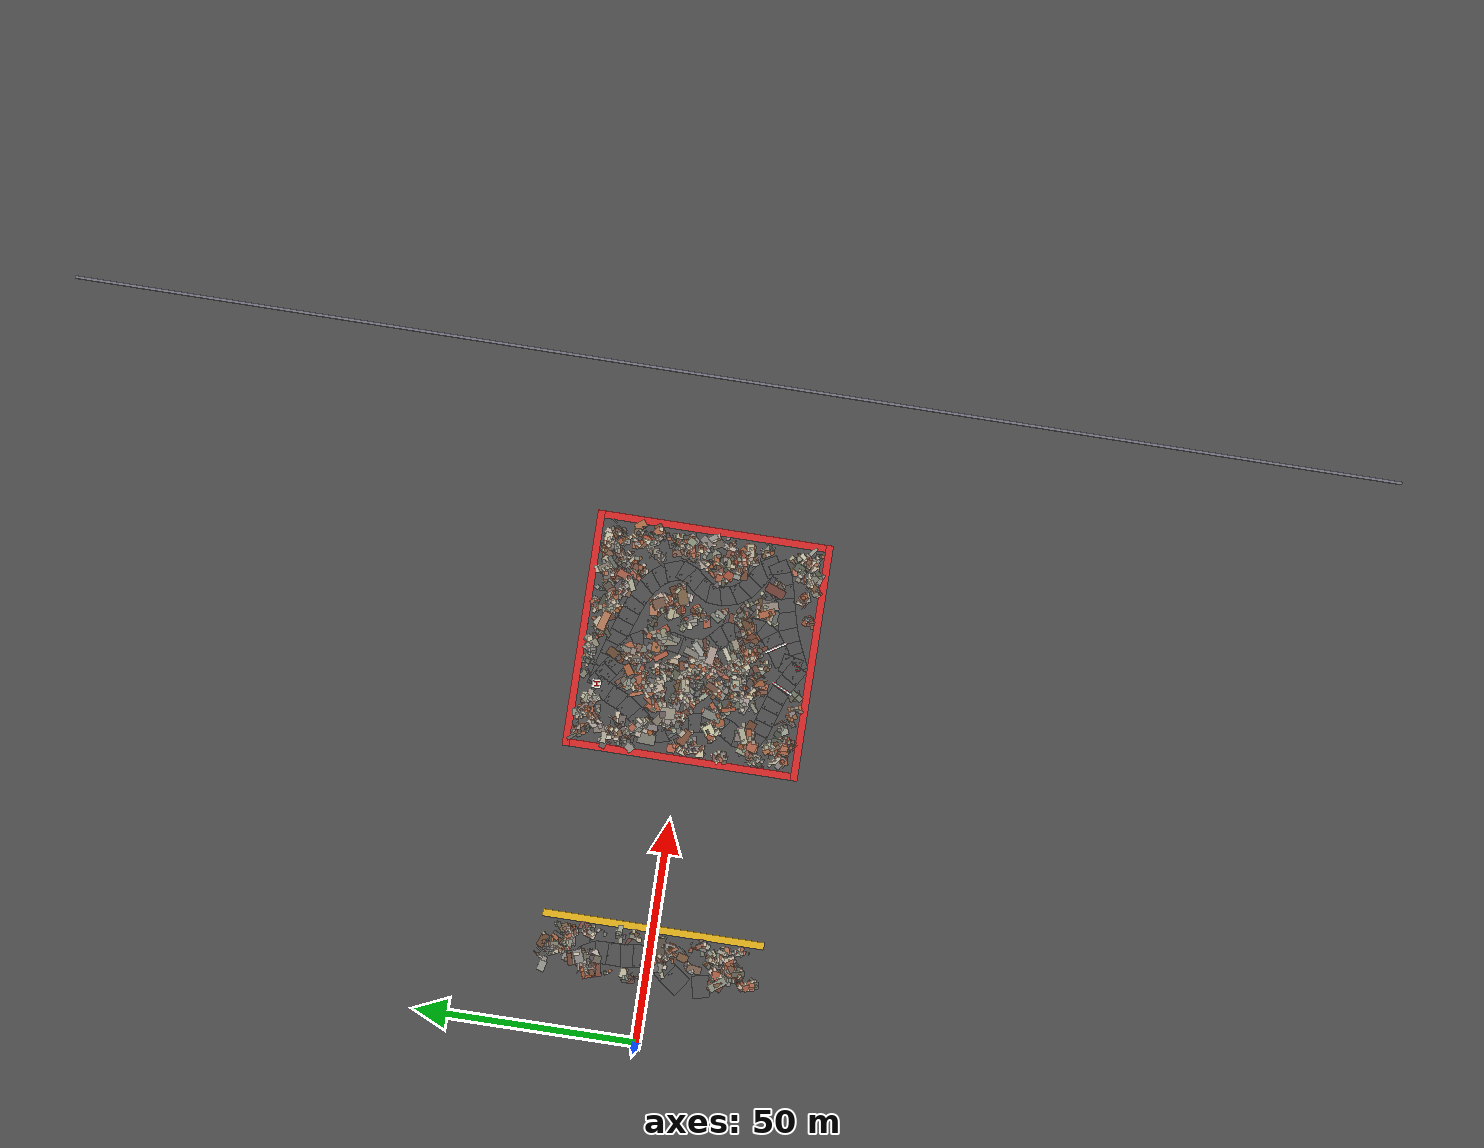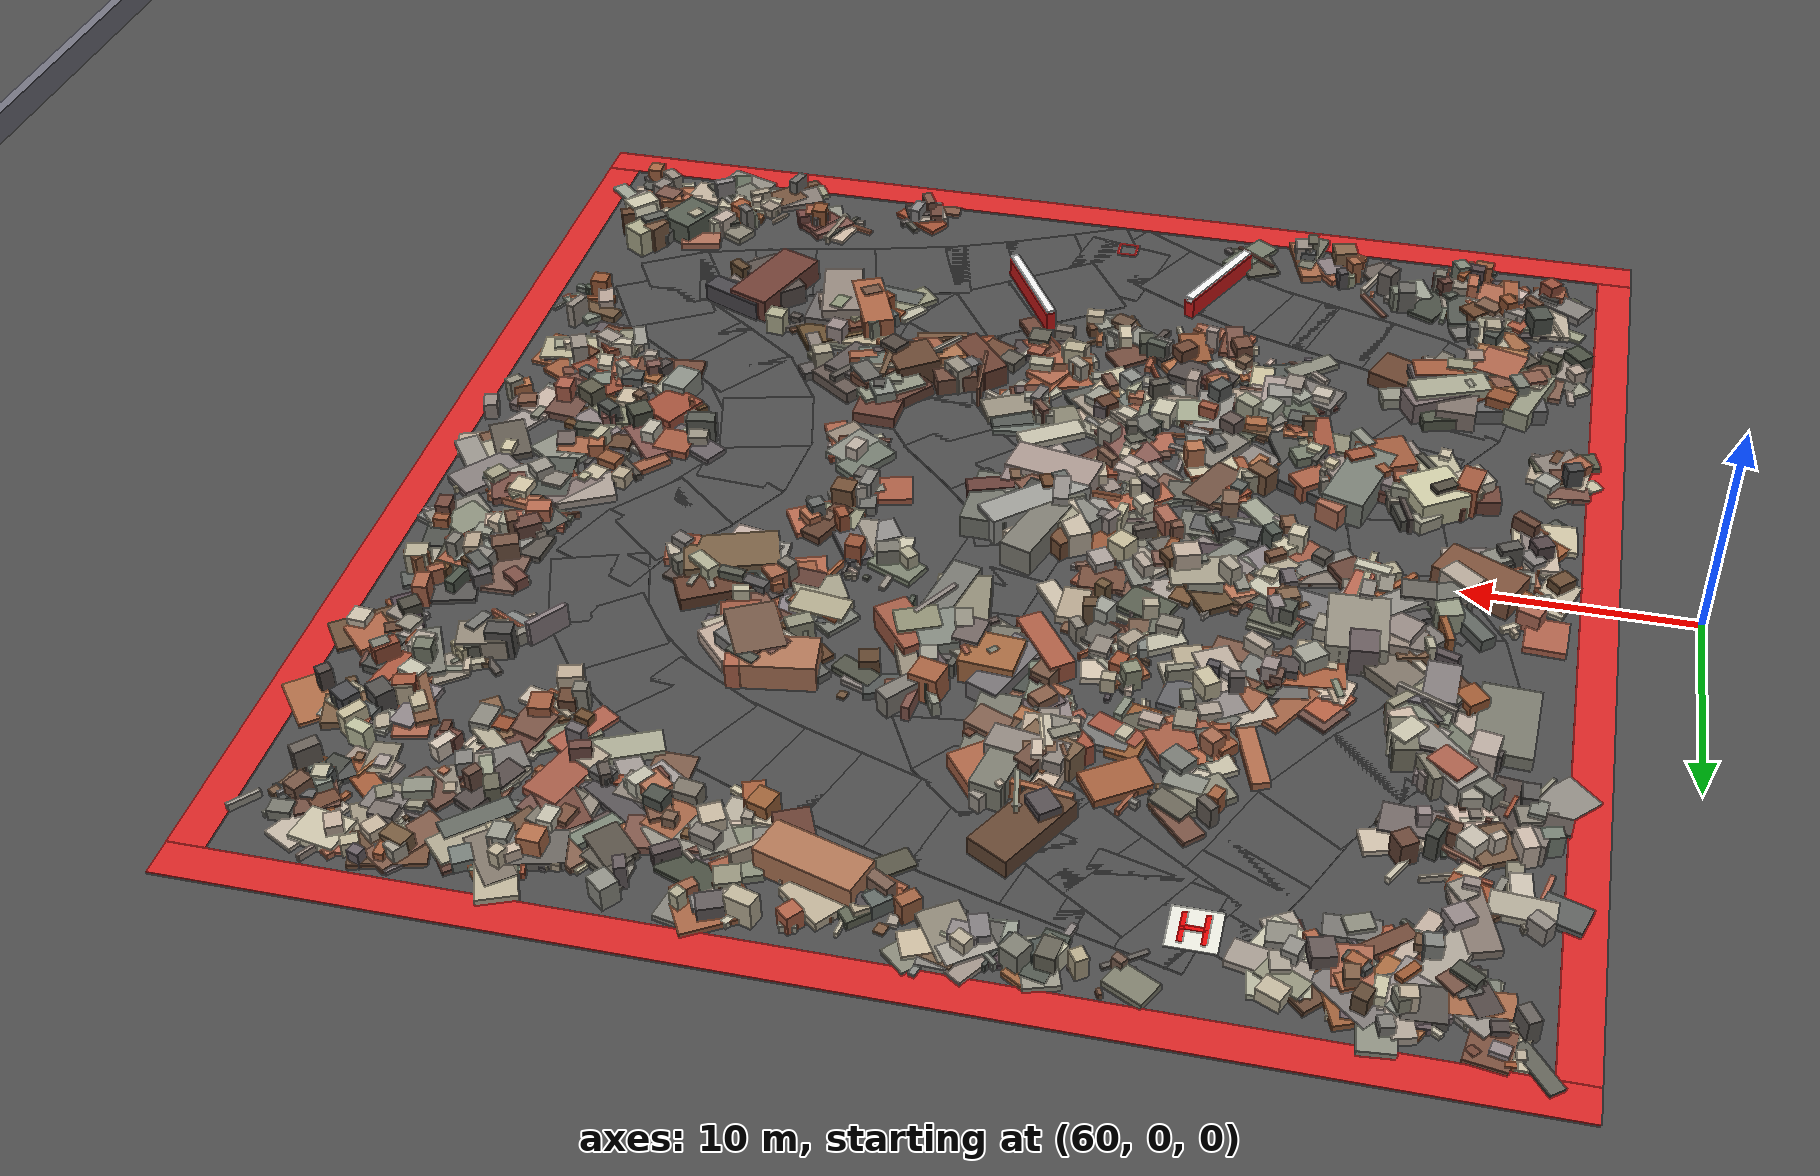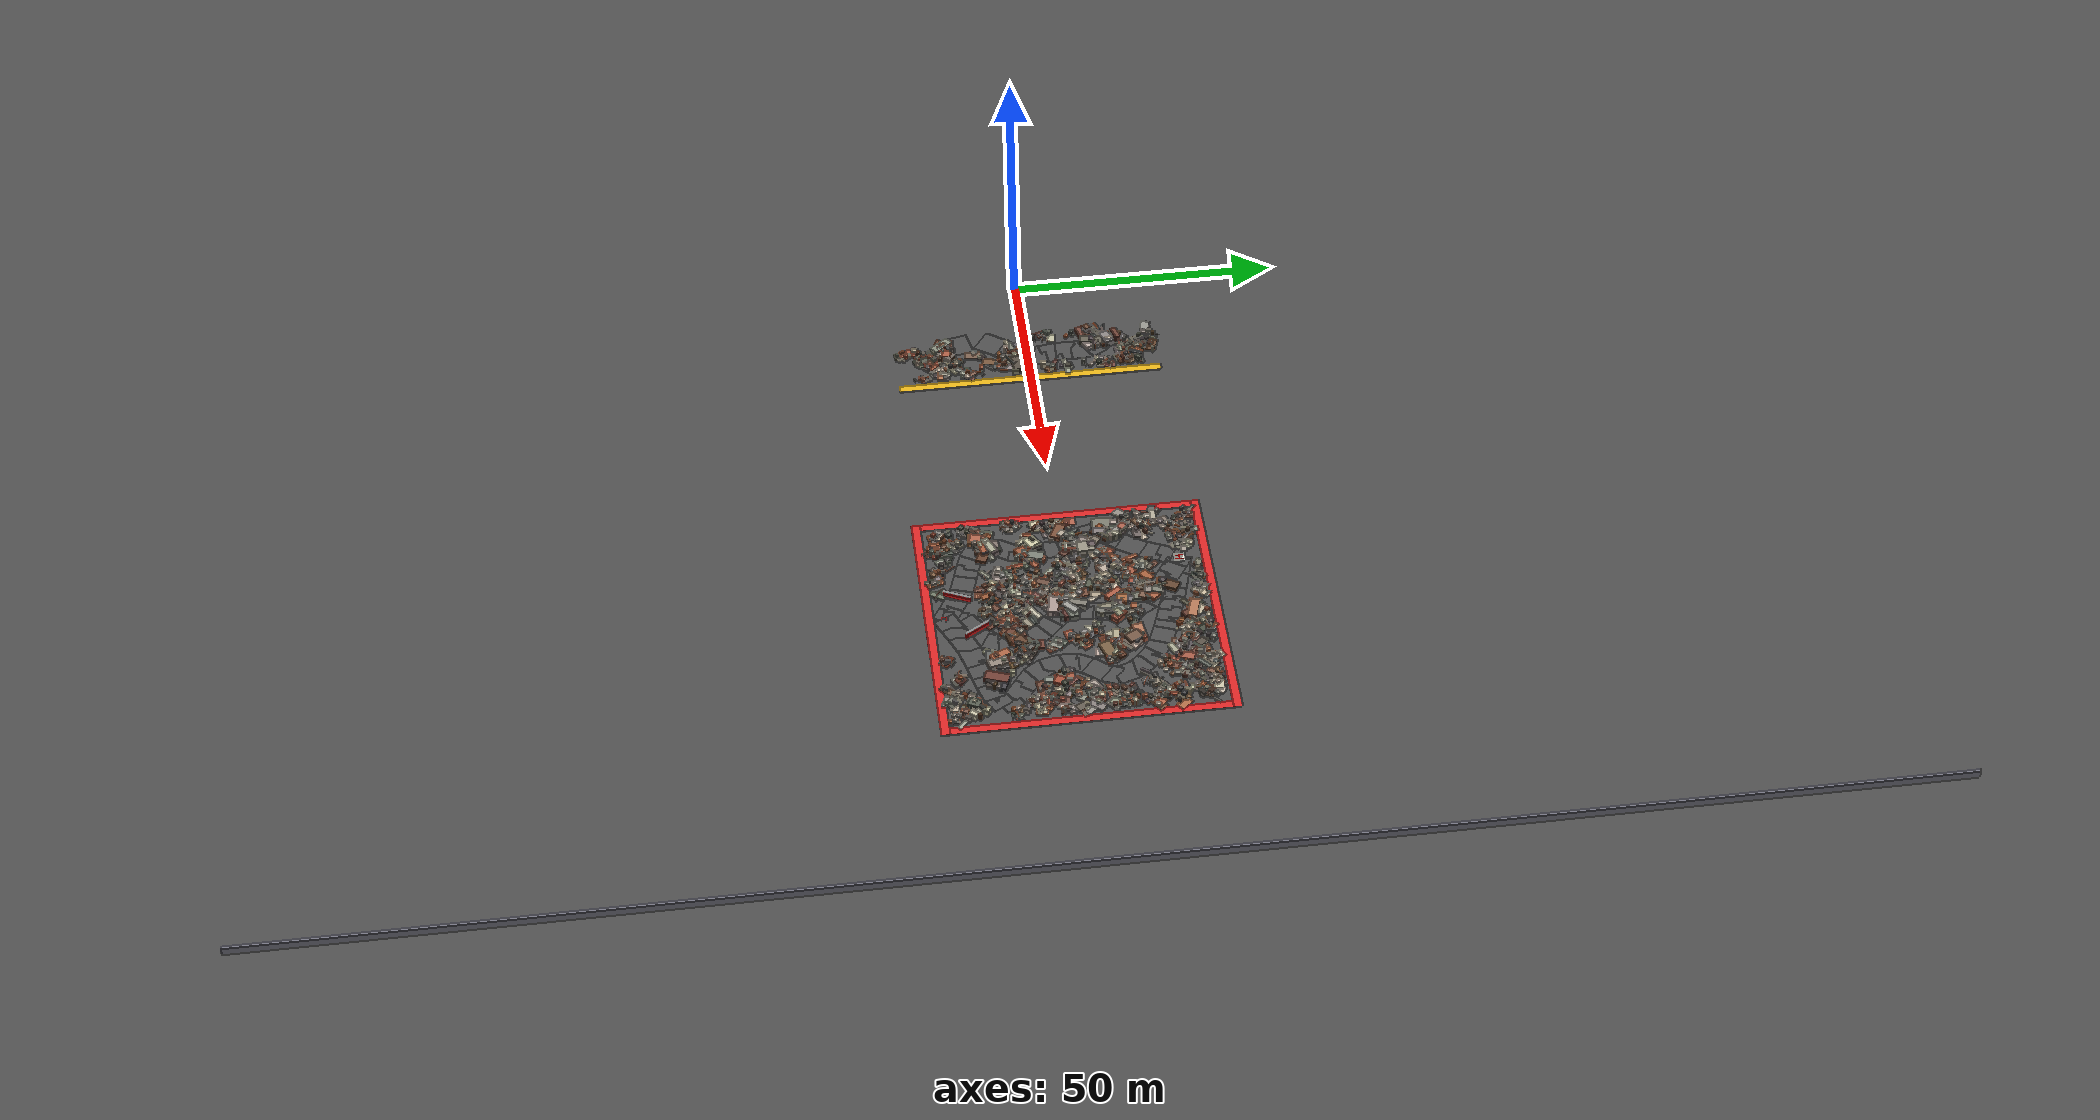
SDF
<sdf version="1.6">
 <world name="navitas_arena">
  <model name="ground_plane">
   <static>true</static>
   <link name="link">
    <collision name="collision">
     <geometry><plane><normal>0 0 1</normal><size>400 400</size></plane></geometry>
     <surface><friction><ode><mu>0.800</mu><mu2>0.800</mu2></ode></friction></surface>
    </collision>
    <visual name="visual">
     <cast_shadows>false</cast_shadows>
     <geometry><plane><normal>0 0 1</normal><size>400 400</size></plane></geometry>
     <material>
      <specular>0.04 0.04 0.04 1</specular>
      <script>
       <uri>file://media/materials/scripts/navitas_asphalt.material</uri>
       <name>Navitas/RealArenaAsphalt</name>
      </script>
     </material>
    </visual>
   </link>
  </model>
  <model name="ub_E">
   <static>true</static>
   <pose>150.000 0.000 0.750 0 0 0.000</pose>
   <link name="link">
    <collision name="col"><geometry><box><size>0.600 300.000 1.500</size></box></geometry></collision>
    <visual name="vis">
     <geometry><box><size>0.600 300.000 1.500</size></box></geometry>
     <material>
      <ambient>0.45 0.45 0.50 1</ambient>
      <diffuse>0.45 0.45 0.50 1</diffuse>
      <specular>0.04 0.04 0.04 1</specular>
     </material>
    </visual>
   </link>
  </model>
  <model name="brd_orta_E">
   <static>true</static>
   <pose>25.800 0.000 0.040 0 0 0.000</pose>
   <link name="link">
    <collision name="col"><geometry><box><size>1.600 50.000 0.080</size></box></geometry></collision>
    <visual name="vis">
     <geometry><box><size>1.600 50.000 0.080</size></box></geometry>
     <material>
      <ambient>0.90 0.70 0.10 1</ambient>
      <diffuse>0.90 0.70 0.10 1</diffuse>
      <specular>0.04 0.04 0.04 1</specular>
     </material>
    </visual>
   </link>
  </model>
  <model name="road_orta_3_7">
   <static>true</static>
   <pose>14.708 -12.340 0.040 0 0 1.793</pose>
   <link name="link">
    <collision name="col"><geometry><box><size>3.812 5.000 0.020</size></box></geometry></collision>
    <visual name="vis">
     <geometry><box><size>3.812 5.000 0.020</size></box></geometry>
     <material>
      <specular>0.04 0.04 0.04 1</specular>
      <script>
       <uri>file://media/materials/scripts/navitas_asphalt.material</uri>
       <name>Navitas/RealArenaAsphalt</name>
      </script>
     </material>
    </visual>
   </link>
  </model>
  <model name="road_orta_3_9">
   <static>true</static>
   <pose>15.219 -6.500 0.040 0 0 0.958</pose>
   <link name="link">
    <collision name="col"><geometry><box><size>4.567 5.000 0.020</size></box></geometry></collision>
    <visual name="vis">
     <geometry><box><size>4.567 5.000 0.020</size></box></geometry>
     <material>
      <specular>0.04 0.04 0.04 1</specular>
      <script>
       <uri>file://media/materials/scripts/navitas_asphalt.material</uri>
       <name>Navitas/RealArenaAsphalt</name>
      </script>
     </material>
    </visual>
   </link>
  </model>
  <model name="road_orta_3_10">
   <static>true</static>
   <pose>17.181 -4.000 0.040 0 0 0.834</pose>
   <link name="link">
    <collision name="col"><geometry><box><size>3.600 5.000 0.020</size></box></geometry></collision>
    <visual name="vis">
     <geometry><box><size>3.600 5.000 0.020</size></box></geometry>
     <material>
      <specular>0.04 0.04 0.04 1</specular>
      <script>
       <uri>file://media/materials/scripts/navitas_asphalt.material</uri>
       <name>Navitas/RealArenaAsphalt</name>
      </script>
     </material>
    </visual>
   </link>
  </model>
  <model name="road_orta_3_11">
   <static>true</static>
   <pose>18.837 -1.300 0.040 0 0 1.156</pose>
   <link name="link">
    <collision name="col"><geometry><box><size>4.615 5.000 0.020</size></box></geometry></collision>
    <visual name="vis">
     <geometry><box><size>4.615 5.000 0.020</size></box></geometry>
     <material>
      <specular>0.04 0.04 0.04 1</specular>
      <script>
       <uri>file://media/materials/scripts/navitas_asphalt.material</uri>
       <name>Navitas/RealArenaAsphalt</name>
      </script>
     </material>
    </visual>
   </link>
  </model>
  <model name="road_orta_3_12">
   <static>true</static>
   <pose>19.454 1.800 0.040 0 0 1.664</pose>
   <link name="link">
    <collision name="col"><geometry><box><size>3.712 5.000 0.020</size></box></geometry></collision>
    <visual name="vis">
     <geometry><box><size>3.712 5.000 0.020</size></box></geometry>
     <material>
      <specular>0.04 0.04 0.04 1</specular>
      <script>
       <uri>file://media/materials/scripts/navitas_asphalt.material</uri>
       <name>Navitas/RealArenaAsphalt</name>
      </script>
     </material>
    </visual>
   </link>
  </model>
  <model name="road_orta_3_13">
   <static>true</static>
   <pose>19.097 4.600 0.040 0 0 1.730</pose>
   <link name="link">
    <collision name="col"><geometry><box><size>3.736 5.000 0.020</size></box></geometry></collision>
    <visual name="vis">
     <geometry><box><size>3.736 5.000 0.020</size></box></geometry>
     <material>
      <specular>0.04 0.04 0.04 1</specular>
      <script>
       <uri>file://media/materials/scripts/navitas_asphalt.material</uri>
       <name>Navitas/RealArenaAsphalt</name>
      </script>
     </material>
    </visual>
   </link>
  </model>
  <model name="road_orta_3_14">
   <static>true</static>
   <pose>18.908 7.460 0.040 0 0 1.546</pose>
   <link name="link">
    <collision name="col"><geometry><box><size>3.821 5.000 0.020</size></box></geometry></collision>
    <visual name="vis">
     <geometry><box><size>3.821 5.000 0.020</size></box></geometry>
     <material>
      <specular>0.04 0.04 0.04 1</specular>
      <script>
       <uri>file://media/materials/scripts/navitas_asphalt.material</uri>
       <name>Navitas/RealArenaAsphalt</name>
      </script>
     </material>
    </visual>
   </link>
  </model>
  <model name="road_orta_3_15">
   <static>true</static>
   <pose>18.885 10.340 0.040 0 0 1.612</pose>
   <link name="link">
    <collision name="col"><geometry><box><size>3.742 5.000 0.020</size></box></geometry></collision>
    <visual name="vis">
     <geometry><box><size>3.742 5.000 0.020</size></box></geometry>
     <material>
      <specular>0.04 0.04 0.04 1</specular>
      <script>
       <uri>file://media/materials/scripts/navitas_asphalt.material</uri>
       <name>Navitas/RealArenaAsphalt</name>
      </script>
     </material>
    </visual>
   </link>
  </model>
  <model name="road_orta_3_16">
   <static>true</static>
   <pose>18.223 12.833 0.040 0 0 2.083</pose>
   <link name="link">
    <collision name="col"><geometry><box><size>3.362 5.000 0.020</size></box></geometry></collision>
    <visual name="vis">
     <geometry><box><size>3.362 5.000 0.020</size></box></geometry>
     <material>
      <specular>0.04 0.04 0.04 1</specular>
      <script>
       <uri>file://media/materials/scripts/navitas_asphalt.material</uri>
       <name>Navitas/RealArenaAsphalt</name>
      </script>
     </material>
    </visual>
   </link>
  </model>
  <model name="road_orta_3_17">
   <static>true</static>
   <pose>16.523 14.688 0.040 0 0 2.523</pose>
   <link name="link">
    <collision name="col"><geometry><box><size>3.594 5.000 0.020</size></box></geometry></collision>
    <visual name="vis">
     <geometry><box><size>3.594 5.000 0.020</size></box></geometry>
     <material>
      <specular>0.04 0.04 0.04 1</specular>
      <script>
       <uri>file://media/materials/scripts/navitas_asphalt.material</uri>
       <name>Navitas/RealArenaAsphalt</name>
      </script>
     </material>
    </visual>
   </link>
  </model>
  <model name="blk_orta_3_0_2">
   <static>true</static>
   <pose>16.926 -15.638 0.000 0 0 0</pose>
   <link name="link">
    <collision name="col_0">
     <pose>-0.548 0.867 0.653 0.000 0.000 0.588</pose>
     <geometry><box><size>1.275 0.865 1.306</size></box></geometry>
    </collision>
    <visual name="vis_0">
     <pose>-0.548 0.867 0.653 0.000 0.000 0.588</pose>
     <geometry><box><size>1.275 0.865 1.306</size></box></geometry>
     <material>
      <ambient>0.49 0.51 0.49 1</ambient>
      <diffuse>0.53 0.55 0.53 1</diffuse>
      <specular>0.05 0.05 0.045 1</specular>
     </material>
    </visual>
    <collision name="col_1">
     <pose>-0.817 -1.141 0.515 0.000 0.000 2.021</pose>
     <geometry><box><size>0.739 1.027 1.031</size></box></geometry>
    </collision>
    <visual name="vis_1">
     <pose>-0.817 -1.141 0.515 0.000 0.000 2.021</pose>
     <geometry><box><size>0.739 1.027 1.031</size></box></geometry>
     <material>
      <ambient>0.48 0.35 0.28 1</ambient>
      <diffuse>0.52 0.38 0.30 1</diffuse>
      <specular>0.05 0.05 0.045 1</specular>
     </material>
    </visual>
    <collision name="col_2">
     <pose>-0.630 -0.840 0.496 0.000 0.000 1.317</pose>
     <geometry><box><size>1.408 1.413 0.992</size></box></geometry>
    </collision>
    <visual name="vis_2">
     <pose>-0.630 -0.840 0.496 0.000 0.000 1.317</pose>
     <geometry><box><size>1.408 1.413 0.992</size></box></geometry>
     <material>
      <ambient>0.38 0.25 0.20 1</ambient>
      <diffuse>0.41 0.27 0.22 1</diffuse>
      <specular>0.05 0.05 0.045 1</specular>
     </material>
    </visual>
    <collision name="col_3">
     <pose>-0.451 1.106 0.372 0.000 0.000 2.256</pose>
     <geometry><box><size>1.474 0.454 0.744</size></box></geometry>
    </collision>
    <visual name="vis_3">
     <pose>-0.451 1.106 0.372 0.000 0.000 2.256</pose>
     <geometry><box><size>1.474 0.454 0.744</size></box></geometry>
     <material>
      <ambient>0.62 0.39 0.24 1</ambient>
      <diffuse>0.67 0.42 0.26 1</diffuse>
      <specular>0.05 0.05 0.045 1</specular>
     </material>
    </visual>
    <collision name="col_4">
     <pose>-0.355 1.244 0.673 0.000 0.000 1.026</pose>
     <geometry><box><size>1.581 0.274 1.347</size></box></geometry>
    </collision>
    <visual name="vis_4">
     <pose>-0.355 1.244 0.673 0.000 0.000 1.026</pose>
     <geometry><box><size>1.581 0.274 1.347</size></box></geometry>
     <material>
      <ambient>0.45 0.42 0.39 1</ambient>
      <diffuse>0.49 0.45 0.42 1</diffuse>
      <specular>0.05 0.05 0.045 1</specular>
     </material>
    </visual>
    <collision name="col_5">
     <pose>-0.223 -1.128 0.583 0.000 0.000 1.706</pose>
     <geometry><box><size>1.402 1.178 1.166</size></box></geometry>
    </collision>
    <visual name="vis_5">
     <pose>-0.223 -1.128 0.583 0.000 0.000 1.706</pose>
     <geometry><box><size>1.402 1.178 1.166</size></box></geometry>
     <material>
      <ambient>0.66 0.39 0.32 1</ambient>
      <diffuse>0.71 0.42 0.35 1</diffuse>
      <specular>0.05 0.05 0.045 1</specular>
     </material>
    </visual>
    <collision name="col_6">
     <pose>-1.044 -0.301 0.460 0.000 0.000 1.977</pose>
     <geometry><box><size>3.488 1.645 0.919</size></box></geometry>
    </collision>
    <visual name="vis_6">
     <pose>-1.044 -0.301 0.460 0.000 0.000 1.977</pose>
     <geometry><box><size>3.488 1.645 0.919</size></box></geometry>
     <material>
      <ambient>0.32 0.30 0.28 1</ambient>
      <diffuse>0.35 0.32 0.30 1</diffuse>
      <specular>0.05 0.05 0.045 1</specular>
     </material>
    </visual>
   </link>
  </model>
  <model name="blk_orta_3_0_5">
   <static>true</static>
   <pose>15.720 -16.504 0.000 0 0 0</pose>
   <link name="link">
    <collision name="col_0">
     <pose>-0.153 0.627 0.665 0.000 0.000 2.016</pose>
     <geometry><box><size>1.266 0.770 1.329</size></box></geometry>
    </collision>
    <visual name="vis_0">
     <pose>-0.153 0.627 0.665 0.000 0.000 2.016</pose>
     <geometry><box><size>1.266 0.770 1.329</size></box></geometry>
     <material>
      <ambient>0.47 0.34 0.24 1</ambient>
      <diffuse>0.50 0.36 0.26 1</diffuse>
      <specular>0.05 0.05 0.045 1</specular>
     </material>
    </visual>
    <collision name="col_1">
     <pose>-0.009 0.490 0.663 0.000 0.000 2.221</pose>
     <geometry><box><size>4.235 1.729 1.326</size></box></geometry>
    </collision>
    <visual name="vis_1">
     <pose>-0.009 0.490 0.663 0.000 0.000 2.221</pose>
     <geometry><box><size>4.235 1.729 1.326</size></box></geometry>
     <material>
      <ambient>0.49 0.51 0.46 1</ambient>
      <diffuse>0.53 0.55 0.49 1</diffuse>
      <specular>0.05 0.05 0.045 1</specular>
     </material>
    </visual>
    <collision name="col_2">
     <pose>-0.423 0.547 0.662 0.000 0.000 2.727</pose>
     <geometry><box><size>1.799 2.475 1.325</size></box></geometry>
    </collision>
    <visual name="vis_2">
     <pose>-0.423 0.547 0.662 0.000 0.000 2.727</pose>
     <geometry><box><size>1.799 2.475 1.325</size></box></geometry>
     <material>
      <ambient>0.39 0.24 0.18 1</ambient>
      <diffuse>0.42 0.26 0.19 1</diffuse>
      <specular>0.05 0.05 0.045 1</specular>
     </material>
    </visual>
    <collision name="col_3">
     <pose>0.696 0.035 0.318 0.000 0.000 4.317</pose>
     <geometry><box><size>0.623 0.458 0.636</size></box></geometry>
    </collision>
    <visual name="vis_3">
     <pose>0.696 0.035 0.318 0.000 0.000 4.317</pose>
     <geometry><box><size>0.623 0.458 0.636</size></box></geometry>
     <material>
      <ambient>0.47 0.47 0.48 1</ambient>
      <diffuse>0.50 0.51 0.51 1</diffuse>
      <specular>0.05 0.05 0.045 1</specular>
     </material>
    </visual>
    <collision name="col_4">
     <pose>0.493 -0.285 0.664 0.000 0.000 4.094</pose>
     <geometry><box><size>0.455 0.323 1.328</size></box></geometry>
    </collision>
    <visual name="vis_4">
     <pose>0.493 -0.285 0.664 0.000 0.000 4.094</pose>
     <geometry><box><size>0.455 0.323 1.328</size></box></geometry>
     <material>
      <ambient>0.45 0.31 0.27 1</ambient>
      <diffuse>0.49 0.33 0.29 1</diffuse>
      <specular>0.05 0.05 0.045 1</specular>
     </material>
    </visual>
    <collision name="col_5">
     <pose>0.847 -0.468 0.446 0.000 0.000 3.252</pose>
     <geometry><box><size>1.539 0.956 0.893</size></box></geometry>
    </collision>
    <visual name="vis_5">
     <pose>0.847 -0.468 0.446 0.000 0.000 3.252</pose>
     <geometry><box><size>1.539 0.956 0.893</size></box></geometry>
     <material>
      <ambient>0.36 0.37 0.33 1</ambient>
      <diffuse>0.39 0.40 0.36 1</diffuse>
      <specular>0.05 0.05 0.045 1</specular>
     </material>
    </visual>
   </link>
  </model>
  <model name="blk_orta_3_0_6">
   <static>true</static>
   <pose>15.686 -15.760 0.000 0 0 0</pose>
   <link name="link">
    <collision name="col_0">
     <pose>0.771 1.479 0.359 0.000 0.000 1.838</pose>
     <geometry><box><size>0.319 0.491 0.719</size></box></geometry>
    </collision>
    <visual name="vis_0">
     <pose>0.771 1.479 0.359 0.000 0.000 1.838</pose>
     <geometry><box><size>0.319 0.491 0.719</size></box></geometry>
     <material>
      <ambient>0.62 0.40 0.26 1</ambient>
      <diffuse>0.67 0.43 0.29 1</diffuse>
      <specular>0.05 0.05 0.045 1</specular>
     </material>
    </visual>
    <collision name="col_1">
     <pose>1.046 0.483 0.489 0.000 0.000 -0.042</pose>
     <geometry><box><size>3.778 1.592 0.978</size></box></geometry>
    </collision>
    <visual name="vis_1">
     <pose>1.046 0.483 0.489 0.000 0.000 -0.042</pose>
     <geometry><box><size>3.778 1.592 0.978</size></box></geometry>
     <material>
      <ambient>0.63 0.34 0.25 1</ambient>
      <diffuse>0.68 0.37 0.27 1</diffuse>
      <specular>0.05 0.05 0.045 1</specular>
     </material>
    </visual>
    <collision name="col_2">
     <pose>-0.683 0.019 0.367 0.000 0.000 1.710</pose>
     <geometry><box><size>0.488 0.272 0.733</size></box></geometry>
    </collision>
    <visual name="vis_2">
     <pose>-0.683 0.019 0.367 0.000 0.000 1.710</pose>
     <geometry><box><size>0.488 0.272 0.733</size></box></geometry>
     <material>
      <ambient>0.56 0.53 0.51 1</ambient>
      <diffuse>0.60 0.57 0.55 1</diffuse>
      <specular>0.05 0.05 0.045 1</specular>
     </material>
    </visual>
    <collision name="col_3">
     <pose>0.977 0.990 0.608 0.000 0.000 -0.602</pose>
     <geometry><box><size>0.659 0.326 1.217</size></box></geometry>
    </collision>
    <visual name="vis_3">
     <pose>0.977 0.990 0.608 0.000 0.000 -0.602</pose>
     <geometry><box><size>0.659 0.326 1.217</size></box></geometry>
     <material>
      <ambient>0.29 0.28 0.26 1</ambient>
      <diffuse>0.31 0.30 0.28 1</diffuse>
      <specular>0.05 0.05 0.045 1</specular>
     </material>
    </visual>
    <collision name="col_4">
     <pose>-0.012 1.027 0.380 0.000 0.000 1.140</pose>
     <geometry><box><size>0.426 0.523 0.759</size></box></geometry>
    </collision>
    <visual name="vis_4">
     <pose>-0.012 1.027 0.380 0.000 0.000 1.140</pose>
     <geometry><box><size>0.426 0.523 0.759</size></box></geometry>
     <material>
      <ambient>0.74 0.73 0.63 1</ambient>
      <diffuse>0.80 0.79 0.68 1</diffuse>
      <specular>0.05 0.05 0.045 1</specular>
     </material>
    </visual>
    <collision name="col_5">
     <pose>1.542 -0.008 0.667 0.000 0.000 -0.076</pose>
     <geometry><box><size>0.383 0.451 1.333</size></box></geometry>
    </collision>
    <visual name="vis_5">
     <pose>1.542 -0.008 0.667 0.000 0.000 -0.076</pose>
     <geometry><box><size>0.383 0.451 1.333</size></box></geometry>
     <material>
      <ambient>0.57 0.59 0.53 1</ambient>
      <diffuse>0.62 0.64 0.57 1</diffuse>
      <specular>0.05 0.05 0.045 1</specular>
     </material>
    </visual>
    <collision name="col_6">
     <pose>-0.236 1.577 0.540 0.000 0.000 -0.026</pose>
     <geometry><box><size>2.266 0.758 1.080</size></box></geometry>
    </collision>
    <visual name="vis_6">
     <pose>-0.236 1.577 0.540 0.000 0.000 -0.026</pose>
     <geometry><box><size>2.266 0.758 1.080</size></box></geometry>
     <material>
      <ambient>0.41 0.29 0.23 1</ambient>
      <diffuse>0.45 0.31 0.25 1</diffuse>
      <specular>0.05 0.05 0.045 1</specular>
     </material>
    </visual>
    <collision name="col_7">
     <pose>0.163 -0.380 0.316 0.000 0.000 -0.677</pose>
     <geometry><box><size>0.285 0.326 0.632</size></box></geometry>
    </collision>
    <visual name="vis_7">
     <pose>0.163 -0.380 0.316 0.000 0.000 -0.677</pose>
     <geometry><box><size>0.285 0.326 0.632</size></box></geometry>
     <material>
      <ambient>0.49 0.48 0.43 1</ambient>
      <diffuse>0.53 0.52 0.46 1</diffuse>
      <specular>0.05 0.05 0.045 1</specular>
     </material>
    </visual>
   </link>
  </model>
  <model name="blk_orta_3_0_7">
   <static>true</static>
   <pose>17.505 -15.420 0.000 0 0 0</pose>
   <link name="link">
    <collision name="col_0">
     <pose>-1.541 -0.670 0.284 0.000 0.000 1.751</pose>
     <geometry><box><size>1.364 0.430 0.568</size></box></geometry>
    </collision>
    <visual name="vis_0">
     <pose>-1.541 -0.670 0.284 0.000 0.000 1.751</pose>
     <geometry><box><size>1.364 0.430 0.568</size></box></geometry>
     <material>
      <ambient>0.56 0.50 0.49 1</ambient>
      <diffuse>0.61 0.54 0.53 1</diffuse>
      <specular>0.05 0.05 0.045 1</specular>
     </material>
    </visual>
    <collision name="col_1">
     <pose>1.450 -1.059 0.539 0.000 0.000 2.932</pose>
     <geometry><box><size>0.948 0.551 1.078</size></box></geometry>
    </collision>
    <visual name="vis_1">
     <pose>1.450 -1.059 0.539 0.000 0.000 2.932</pose>
     <geometry><box><size>0.948 0.551 1.078</size></box></geometry>
     <material>
      <ambient>0.37 0.28 0.20 1</ambient>
      <diffuse>0.40 0.30 0.22 1</diffuse>
      <specular>0.05 0.05 0.045 1</specular>
     </material>
    </visual>
    <collision name="col_2">
     <pose>0.164 -0.106 0.281 0.000 0.000 0.912</pose>
     <geometry><box><size>3.960 1.230 0.562</size></box></geometry>
    </collision>
    <visual name="vis_2">
     <pose>0.164 -0.106 0.281 0.000 0.000 0.912</pose>
     <geometry><box><size>3.960 1.230 0.562</size></box></geometry>
     <material>
      <ambient>0.37 0.25 0.17 1</ambient>
      <diffuse>0.39 0.27 0.19 1</diffuse>
      <specular>0.05 0.05 0.045 1</specular>
     </material>
    </visual>
    <collision name="col_3">
     <pose>1.425 0.938 0.598 0.000 0.000 1.662</pose>
     <geometry><box><size>0.279 0.624 1.196</size></box></geometry>
    </collision>
    <visual name="vis_3">
     <pose>1.425 0.938 0.598 0.000 0.000 1.662</pose>
     <geometry><box><size>0.279 0.624 1.196</size></box></geometry>
     <material>
      <ambient>0.48 0.34 0.27 1</ambient>
      <diffuse>0.52 0.37 0.29 1</diffuse>
      <specular>0.05 0.05 0.045 1</specular>
     </material>
    </visual>
    <collision name="col_4">
     <pose>0.406 0.140 0.385 0.000 0.000 0.853</pose>
     <geometry><box><size>3.044 1.820 0.771</size></box></geometry>
    </collision>
    <visual name="vis_4">
     <pose>0.406 0.140 0.385 0.000 0.000 0.853</pose>
     <geometry><box><size>3.044 1.820 0.771</size></box></geometry>
     <material>
      <ambient>0.75 0.68 0.64 1</ambient>
      <diffuse>0.81 0.74 0.69 1</diffuse>
      <specular>0.05 0.05 0.045 1</specular>
     </material>
    </visual>
    <collision name="col_5">
     <pose>0.446 0.990 0.562 0.000 0.000 0.578</pose>
     <geometry><box><size>0.600 0.226 1.124</size></box></geometry>
    </collision>
    <visual name="vis_5">
     <pose>0.446 0.990 0.562 0.000 0.000 0.578</pose>
     <geometry><box><size>0.600 0.226 1.124</size></box></geometry>
     <material>
      <ambient>0.64 0.43 0.31 1</ambient>
      <diffuse>0.69 0.46 0.33 1</diffuse>
      <specular>0.05 0.05 0.045 1</specular>
     </material>
    </visual>
   </link>
  </model>
  <model name="blk_orta_3_1_0">
   <static>true</static>
   <pose>19.401 -2.650 0.000 0 0 0</pose>
   <link name="link">
    <collision name="col_0">
     <pose>0.028 0.918 0.344 0.000 0.000 2.064</pose>
     <geometry><box><size>3.346 0.257 0.689</size></box></geometry>
    </collision>
    <visual name="vis_0">
     <pose>0.028 0.918 0.344 0.000 0.000 2.064</pose>
     <geometry><box><size>3.346 0.257 0.689</size></box></geometry>
     <material>
      <ambient>0.41 0.27 0.20 1</ambient>
      <diffuse>0.44 0.29 0.21 1</diffuse>
      <specular>0.05 0.05 0.045 1</specular>
     </material>
    </visual>
    <collision name="col_1">
     <pose>0.155 0.380 0.409 0.000 0.000 3.125</pose>
     <geometry><box><size>1.923 0.296 0.818</size></box></geometry>
    </collision>
    <visual name="vis_1">
     <pose>0.155 0.380 0.409 0.000 0.000 3.125</pose>
     <geometry><box><size>1.923 0.296 0.818</size></box></geometry>
     <material>
      <ambient>0.55 0.51 0.47 1</ambient>
      <diffuse>0.59 0.55 0.50 1</diffuse>
      <specular>0.05 0.05 0.045 1</specular>
     </material>
    </visual>
    <collision name="col_2">
     <pose>0.575 0.623 0.384 0.000 0.000 3.213</pose>
     <geometry><box><size>0.272 0.488 0.768</size></box></geometry>
    </collision>
    <visual name="vis_2">
     <pose>0.575 0.623 0.384 0.000 0.000 3.213</pose>
     <geometry><box><size>0.272 0.488 0.768</size></box></geometry>
     <material>
      <ambient>0.43 0.29 0.24 1</ambient>
      <diffuse>0.47 0.31 0.26 1</diffuse>
      <specular>0.05 0.05 0.045 1</specular>
     </material>
    </visual>
    <collision name="col_3">
     <pose>0.257 -0.111 0.312 0.000 0.000 3.333</pose>
     <geometry><box><size>1.979 1.977 0.624</size></box></geometry>
    </collision>
    <visual name="vis_3">
     <pose>0.257 -0.111 0.312 0.000 0.000 3.333</pose>
     <geometry><box><size>1.979 1.977 0.624</size></box></geometry>
     <material>
      <ambient>0.41 0.36 0.37 1</ambient>
      <diffuse>0.45 0.39 0.40 1</diffuse>
      <specular>0.05 0.05 0.045 1</specular>
     </material>
    </visual>
    <collision name="col_4">
     <pose>-0.679 -0.692 0.646 0.000 0.000 1.735</pose>
     <geometry><box><size>0.223 0.270 1.291</size></box></geometry>
    </collision>
    <visual name="vis_4">
     <pose>-0.679 -0.692 0.646 0.000 0.000 1.735</pose>
     <geometry><box><size>0.223 0.270 1.291</size></box></geometry>
     <material>
      <ambient>0.30 0.29 0.28 1</ambient>
      <diffuse>0.33 0.32 0.30 1</diffuse>
      <specular>0.05 0.05 0.045 1</specular>
     </material>
    </visual>
    <collision name="col_5">
     <pose>0.318 -0.622 0.290 0.000 0.000 2.320</pose>
     <geometry><box><size>4.319 0.949 0.579</size></box></geometry>
    </collision>
    <visual name="vis_5">
     <pose>0.318 -0.622 0.290 0.000 0.000 2.320</pose>
     <geometry><box><size>4.319 0.949 0.579</size></box></geometry>
     <material>
      <ambient>0.63 0.40 0.27 1</ambient>
      <diffuse>0.68 0.44 0.30 1</diffuse>
      <specular>0.05 0.05 0.045 1</specular>
     </material>
    </visual>
    <collision name="col_6">
     <pose>0.056 0.843 0.480 0.000 0.000 3.247</pose>
     <geometry><box><size>3.223 0.305 0.960</size></box></geometry>
    </collision>
    <visual name="vis_6">
     <pose>0.056 0.843 0.480 0.000 0.000 3.247</pose>
     <geometry><box><size>3.223 0.305 0.960</size></box></geometry>
     <material>
      <ambient>0.44 0.32 0.25 1</ambient>
      <diffuse>0.47 0.35 0.27 1</diffuse>
      <specular>0.05 0.05 0.045 1</specular>
     </material>
    </visual>
    <collision name="col_7">
     <pose>0.757 0.518 0.535 0.000 0.000 1.860</pose>
     <geometry><box><size>0.543 0.264 1.070</size></box></geometry>
    </collision>
    <visual name="vis_7">
     <pose>0.757 0.518 0.535 0.000 0.000 1.860</pose>
     <geometry><box><size>0.543 0.264 1.070</size></box></geometry>
     <material>
      <ambient>0.62 0.60 0.53 1</ambient>
      <diffuse>0.67 0.65 0.57 1</diffuse>
      <specular>0.05 0.05 0.045 1</specular>
     </material>
    </visual>
    <collision name="col_8">
     <pose>0.611 0.318 0.646 0.000 0.000 2.581</pose>
     <geometry><box><size>0.763 0.939 1.292</size></box></geometry>
    </collision>
    <visual name="vis_8">
     <pose>0.611 0.318 0.646 0.000 0.000 2.581</pose>
     <geometry><box><size>0.763 0.939 1.292</size></box></geometry>
     <material>
      <ambient>0.69 0.69 0.57 1</ambient>
      <diffuse>0.75 0.74 0.62 1</diffuse>
      <specular>0.05 0.05 0.045 1</specular>
     </material>
    </visual>
    <collision name="col_9">
     <pose>0.343 -0.181 0.334 0.000 0.000 2.314</pose>
     <geometry><box><size>0.316 0.290 0.669</size></box></geometry>
    </collision>
    <visual name="vis_9">
     <pose>0.343 -0.181 0.334 0.000 0.000 2.314</pose>
     <geometry><box><size>0.316 0.290 0.669</size></box></geometry>
     <material>
      <ambient>0.46 0.32 0.27 1</ambient>
      <diffuse>0.50 0.35 0.29 1</diffuse>
      <specular>0.05 0.05 0.045 1</specular>
     </material>
    </visual>
   </link>
  </model>
  <model name="blk_orta_3_1_1">
   <static>true</static>
   <pose>20.146 -2.383 0.000 0 0 0</pose>
   <link name="link">
    <collision name="col_0">
     <pose>1.445 -0.607 0.318 0.000 0.000 2.067</pose>
     <geometry><box><size>0.529 0.488 0.637</size></box></geometry>
    </collision>
    <visual name="vis_0">
     <pose>1.445 -0.607 0.318 0.000 0.000 2.067</pose>
     <geometry><box><size>0.529 0.488 0.637</size></box></geometry>
     <material>
      <ambient>0.29 0.29 0.27 1</ambient>
      <diffuse>0.31 0.31 0.29 1</diffuse>
      <specular>0.05 0.05 0.045 1</specular>
     </material>
    </visual>
    <collision name="col_1">
     <pose>-1.469 -0.758 0.502 0.000 0.000 0.276</pose>
     <geometry><box><size>0.414 0.344 1.004</size></box></geometry>
    </collision>
    <visual name="vis_1">
     <pose>-1.469 -0.758 0.502 0.000 0.000 0.276</pose>
     <geometry><box><size>0.414 0.344 1.004</size></box></geometry>
     <material>
      <ambient>0.44 0.40 0.38 1</ambient>
      <diffuse>0.47 0.43 0.41 1</diffuse>
      <specular>0.05 0.05 0.045 1</specular>
     </material>
    </visual>
    <collision name="col_2">
     <pose>0.382 -0.105 0.322 0.000 0.000 0.118</pose>
     <geometry><box><size>0.491 0.456 0.644</size></box></geometry>
    </collision>
    <visual name="vis_2">
     <pose>0.382 -0.105 0.322 0.000 0.000 0.118</pose>
     <geometry><box><size>0.491 0.456 0.644</size></box></geometry>
     <material>
      <ambient>0.73 0.67 0.59 1</ambient>
      <diffuse>0.78 0.72 0.64 1</diffuse>
      <specular>0.05 0.05 0.045 1</specular>
     </material>
    </visual>
    <collision name="col_3">
     <pose>-0.919 -1.000 0.629 0.000 0.000 -0.484</pose>
     <geometry><box><size>0.321 0.399 1.258</size></box></geometry>
    </collision>
    <visual name="vis_3">
     <pose>-0.919 -1.000 0.629 0.000 0.000 -0.484</pose>
     <geometry><box><size>0.321 0.399 1.258</size></box></geometry>
     <material>
      <ambient>0.59 0.37 0.25 1</ambient>
      <diffuse>0.64 0.40 0.27 1</diffuse>
      <specular>0.05 0.05 0.045 1</specular>
     </material>
    </visual>
    <collision name="col_4">
     <pose>0.284 0.370 0.318 0.000 0.000 1.554</pose>
     <geometry><box><size>1.849 1.277 0.636</size></box></geometry>
    </collision>
    <visual name="vis_4">
     <pose>0.284 0.370 0.318 0.000 0.000 1.554</pose>
     <geometry><box><size>1.849 1.277 0.636</size></box></geometry>
     <material>
      <ambient>0.68 0.66 0.60 1</ambient>
      <diffuse>0.73 0.72 0.64 1</diffuse>
      <specular>0.05 0.05 0.045 1</specular>
     </material>
    </visual>
    <collision name="col_5">
     <pose>-0.853 -0.762 0.283 0.000 0.000 0.815</pose>
     <geometry><box><size>0.606 0.457 0.565</size></box></geometry>
    </collision>
    <visual name="vis_5">
     <pose>-0.853 -0.762 0.283 0.000 0.000 0.815</pose>
     <geometry><box><size>0.606 0.457 0.565</size></box></geometry>
     <material>
      <ambient>0.43 0.43 0.41 1</ambient>
      <diffuse>0.46 0.46 0.45 1</diffuse>
      <specular>0.05 0.05 0.045 1</specular>
     </material>
    </visual>
   </link>
  </model>
  <model name="blk_orta_3_1_2">
   <static>true</static>
   <pose>21.647 -2.281 0.000 0 0 0</pose>
   <link name="link">
    <collision name="col_0">
     <pose>-1.047 -0.044 0.519 0.000 0.000 -0.590</pose>
     <geometry><box><size>0.448 0.647 1.038</size></box></geometry>
    </collision>
    <visual name="vis_0">
     <pose>-1.047 -0.044 0.519 0.000 0.000 -0.590</pose>
     <geometry><box><size>0.448 0.647 1.038</size></box></geometry>
     <material>
      <ambient>0.70 0.64 0.56 1</ambient>
      <diffuse>0.76 0.69 0.60 1</diffuse>
      <specular>0.05 0.05 0.045 1</specular>
     </material>
    </visual>
    <collision name="col_1">
     <pose>-0.708 0.846 0.523 0.000 0.000 -0.534</pose>
     <geometry><box><size>4.595 1.167 1.045</size></box></geometry>
    </collision>
    <visual name="vis_1">
     <pose>-0.708 0.846 0.523 0.000 0.000 -0.534</pose>
     <geometry><box><size>4.595 1.167 1.045</size></box></geometry>
     <material>
      <ambient>0.46 0.32 0.22 1</ambient>
      <diffuse>0.50 0.35 0.24 1</diffuse>
      <specular>0.05 0.05 0.045 1</specular>
     </material>
    </visual>
    <collision name="col_2">
     <pose>0.870 0.032 0.527 0.000 0.000 -0.212</pose>
     <geometry><box><size>4.135 1.233 1.054</size></box></geometry>
    </collision>
    <visual name="vis_2">
     <pose>0.870 0.032 0.527 0.000 0.000 -0.212</pose>
     <geometry><box><size>4.135 1.233 1.054</size></box></geometry>
     <material>
      <ambient>0.52 0.52 0.43 1</ambient>
      <diffuse>0.56 0.56 0.46 1</diffuse>
      <specular>0.05 0.05 0.045 1</specular>
     </material>
    </visual>
    <collision name="col_3">
     <pose>0.401 -0.404 0.308 0.000 0.000 0.121</pose>
     <geometry><box><size>0.777 0.417 0.615</size></box></geometry>
    </collision>
    <visual name="vis_3">
     <pose>0.401 -0.404 0.308 0.000 0.000 0.121</pose>
     <geometry><box><size>0.777 0.417 0.615</size></box></geometry>
     <material>
      <ambient>0.44 0.33 0.24 1</ambient>
      <diffuse>0.47 0.35 0.26 1</diffuse>
      <specular>0.05 0.05 0.045 1</specular>
     </material>
    </visual>
    <collision name="col_4">
     <pose>0.708 -0.360 0.628 0.000 0.000 -0.839</pose>
     <geometry><box><size>0.616 0.299 1.257</size></box></geometry>
    </collision>
    <visual name="vis_4">
     <pose>0.708 -0.360 0.628 0.000 0.000 -0.839</pose>
     <geometry><box><size>0.616 0.299 1.257</size></box></geometry>
     <material>
      <ambient>0.56 0.52 0.48 1</ambient>
      <diffuse>0.61 0.56 0.52 1</diffuse>
      <specular>0.05 0.05 0.045 1</specular>
     </material>
    </visual>
    <collision name="col_5">
     <pose>0.642 0.278 0.565 0.000 0.000 0.074</pose>
     <geometry><box><size>3.763 2.329 1.130</size></box></geometry>
    </collision>
    <visual name="vis_5">
     <pose>0.642 0.278 0.565 0.000 0.000 0.074</pose>
     <geometry><box><size>3.763 2.329 1.130</size></box></geometry>
     <material>
      <ambient>0.31 0.29 0.25 1</ambient>
      <diffuse>0.34 0.31 0.27 1</diffuse>
      <specular>0.05 0.05 0.045 1</specular>
     </material>
    </visual>
    <collision name="col_6">
     <pose>0.192 0.521 0.553 0.000 0.000 -0.189</pose>
     <geometry><box><size>2.965 1.726 1.107</size></box></geometry>
    </collision>
    <visual name="vis_6">
     <pose>0.192 0.521 0.553 0.000 0.000 -0.189</pose>
     <geometry><box><size>2.965 1.726 1.107</size></box></geometry>
     <material>
      <ambient>0.62 0.35 0.26 1</ambient>
      <diffuse>0.67 0.38 0.28 1</diffuse>
      <specular>0.05 0.05 0.045 1</specular>
     </material>
    </visual>
    <collision name="col_7">
     <pose>0.263 0.361 0.553 0.000 0.000 1.529</pose>
     <geometry><box><size>1.273 0.674 1.106</size></box></geometry>
    </collision>
    <visual name="vis_7">
     <pose>0.263 0.361 0.553 0.000 0.000 1.529</pose>
     <geometry><box><size>1.273 0.674 1.106</size></box></geometry>
     <material>
      <ambient>0.57 0.34 0.25 1</ambient>
      <diffuse>0.62 0.36 0.27 1</diffuse>
      <specular>0.05 0.05 0.045 1</specular>
     </material>
    </visual>
   </link>
  </model>
  <model name="blk_orta_3_1_3">
   <static>true</static>
   <pose>20.606 -4.477 0.000 0 0 0</pose>
   <link name="link">
    <collision name="col_0">
     <pose>1.518 -0.040 0.600 0.000 0.000 1.402</pose>
     <geometry><box><size>0.601 0.305 1.200</size></box></geometry>
    </collision>
    <visual name="vis_0">
     <pose>1.518 -0.040 0.600 0.000 0.000 1.402</pose>
     <geometry><box><size>0.601 0.305 1.200</size></box></geometry>
     <material>
      <ambient>0.45 0.30 0.22 1</ambient>
      <diffuse>0.49 0.32 0.24 1</diffuse>
      <specular>0.05 0.05 0.045 1</specular>
     </material>
    </visual>
    <collision name="col_1">
     <pose>0.933 0.823 0.298 0.000 0.000 0.900</pose>
     <geometry><box><size>2.521 0.333 0.596</size></box></geometry>
    </collision>
    <visual name="vis_1">
     <pose>0.933 0.823 0.298 0.000 0.000 0.900</pose>
     <geometry><box><size>2.521 0.333 0.596</size></box></geometry>
     <material>
      <ambient>0.75 0.71 0.63 1</ambient>
      <diffuse>0.81 0.77 0.68 1</diffuse>
      <specular>0.05 0.05 0.045 1</specular>
     </material>
    </visual>
    <collision name="col_2">
     <pose>-0.701 0.584 0.422 0.000 0.000 1.106</pose>
     <geometry><box><size>0.501 0.390 0.844</size></box></geometry>
    </collision>
    <visual name="vis_2">
     <pose>-0.701 0.584 0.422 0.000 0.000 1.106</pose>
     <geometry><box><size>0.501 0.390 0.844</size></box></geometry>
     <material>
      <ambient>0.71 0.65 0.60 1</ambient>
      <diffuse>0.77 0.70 0.64 1</diffuse>
      <specular>0.05 0.05 0.045 1</specular>
     </material>
    </visual>
    <collision name="col_3">
     <pose>0.708 1.039 0.637 0.000 0.000 0.467</pose>
     <geometry><box><size>3.106 0.261 1.274</size></box></geometry>
    </collision>
    <visual name="vis_3">
     <pose>0.708 1.039 0.637 0.000 0.000 0.467</pose>
     <geometry><box><size>3.106 0.261 1.274</size></box></geometry>
     <material>
      <ambient>0.39 0.40 0.38 1</ambient>
      <diffuse>0.42 0.43 0.41 1</diffuse>
      <specular>0.05 0.05 0.045 1</specular>
     </material>
    </visual>
    <collision name="col_4">
     <pose>0.112 -0.383 0.552 0.000 0.000 2.198</pose>
     <geometry><box><size>1.794 0.334 1.105</size></box></geometry>
    </collision>
    <visual name="vis_4">
     <pose>0.112 -0.383 0.552 0.000 0.000 2.198</pose>
     <geometry><box><size>1.794 0.334 1.105</size></box></geometry>
     <material>
      <ambient>0.58 0.31 0.18 1</ambient>
      <diffuse>0.62 0.33 0.20 1</diffuse>
      <specular>0.05 0.05 0.045 1</specular>
     </material>
    </visual>
    <collision name="col_5">
     <pose>-1.118 -0.771 0.633 0.000 0.000 0.217</pose>
     <geometry><box><size>0.878 0.633 1.266</size></box></geometry>
    </collision>
    <visual name="vis_5">
     <pose>-1.118 -0.771 0.633 0.000 0.000 0.217</pose>
     <geometry><box><size>0.878 0.633 1.266</size></box></geometry>
     <material>
      <ambient>0.65 0.41 0.25 1</ambient>
      <diffuse>0.70 0.44 0.27 1</diffuse>
      <specular>0.05 0.05 0.045 1</specular>
     </material>
    </visual>
    <collision name="col_6">
     <pose>-0.414 1.447 0.277 0.000 0.000 0.267</pose>
     <geometry><box><size>2.758 1.780 0.554</size></box></geometry>
    </collision>
    <visual name="vis_6">
     <pose>-0.414 1.447 0.277 0.000 0.000 0.267</pose>
     <geometry><box><size>2.758 1.780 0.554</size></box></geometry>
     <material>
      <ambient>0.36 0.35 0.32 1</ambient>
      <diffuse>0.38 0.38 0.35 1</diffuse>
      <specular>0.05 0.05 0.045 1</specular>
     </material>
    </visual>
    <collision name="col_7">
     <pose>0.040 -0.167 0.770 0.000 0.000 1.935</pose>
     <geometry><box><size>0.980 0.621 1.541</size></box></geometry>
    </collision>
    <visual name="vis_7">
     <pose>0.040 -0.167 0.770 0.000 0.000 1.935</pose>
     <geometry><box><size>0.980 0.621 1.541</size></box></geometry>
     <material>
      <ambient>0.53 0.51 0.48 1</ambient>
      <diffuse>0.58 0.55 0.51 1</diffuse>
      <specular>0.05 0.05 0.045 1</specular>
     </material>
    </visual>
    <collision name="col_8">
     <pose>-0.799 0.109 0.419 0.000 0.000 0.081</pose>
     <geometry><box><size>0.552 0.453 0.838</size></box></geometry>
    </collision>
    <visual name="vis_8">
     <pose>-0.799 0.109 0.419 0.000 0.000 0.081</pose>
     <geometry><box><size>0.552 0.453 0.838</size></box></geometry>
     <material>
      <ambient>0.50 0.46 0.42 1</ambient>
      <diffuse>0.54 0.49 0.46 1</diffuse>
      <specular>0.05 0.05 0.045 1</specular>
     </material>
    </visual>
   </link>
  </model>
  <model name="blk_orta_3_1_4">
   <static>true</static>
   <pose>20.304 -1.101 0.000 0 0 0</pose>
   <link name="link">
    <collision name="col_0">
     <pose>-1.131 0.130 0.579 0.000 0.000 2.661</pose>
     <geometry><box><size>0.692 1.235 1.159</size></box></geometry>
    </collision>
    <visual name="vis_0">
     <pose>-1.131 0.130 0.579 0.000 0.000 2.661</pose>
     <geometry><box><size>0.692 1.235 1.159</size></box></geometry>
     <material>
      <ambient>0.48 0.49 0.48 1</ambient>
      <diffuse>0.52 0.53 0.52 1</diffuse>
      <specular>0.05 0.05 0.045 1</specular>
     </material>
    </visual>
    <collision name="col_1">
     <pose>-0.622 -1.555 0.352 0.000 0.000 3.657</pose>
     <geometry><box><size>2.612 0.177 0.704</size></box></geometry>
    </collision>
    <visual name="vis_1">
     <pose>-0.622 -1.555 0.352 0.000 0.000 3.657</pose>
     <geometry><box><size>2.612 0.177 0.704</size></box></geometry>
     <material>
      <ambient>0.50 0.48 0.45 1</ambient>
      <diffuse>0.54 0.52 0.49 1</diffuse>
      <specular>0.05 0.05 0.045 1</specular>
     </material>
    </visual>
    <collision name="col_2">
     <pose>0.450 -1.296 0.449 0.000 0.000 1.914</pose>
     <geometry><box><size>0.793 0.903 0.898</size></box></geometry>
    </collision>
    <visual name="vis_2">
     <pose>0.450 -1.296 0.449 0.000 0.000 1.914</pose>
     <geometry><box><size>0.793 0.903 0.898</size></box></geometry>
     <material>
      <ambient>0.61 0.62 0.55 1</ambient>
      <diffuse>0.66 0.67 0.59 1</diffuse>
      <specular>0.05 0.05 0.045 1</specular>
     </material>
    </visual>
    <collision name="col_3">
     <pose>-0.370 1.237 0.573 0.000 0.000 1.446</pose>
     <geometry><box><size>0.658 1.120 1.145</size></box></geometry>
    </collision>
    <visual name="vis_3">
     <pose>-0.370 1.237 0.573 0.000 0.000 1.446</pose>
     <geometry><box><size>0.658 1.120 1.145</size></box></geometry>
     <material>
      <ambient>0.31 0.29 0.28 1</ambient>
      <diffuse>0.33 0.31 0.30 1</diffuse>
      <specular>0.05 0.05 0.045 1</specular>
     </material>
    </visual>
    <collision name="col_4">
     <pose>-1.997 0.083 0.558 0.000 0.000 3.454</pose>
     <geometry><box><size>4.033 2.007 1.116</size></box></geometry>
    </collision>
    <visual name="vis_4">
     <pose>-1.997 0.083 0.558 0.000 0.000 3.454</pose>
     <geometry><box><size>4.033 2.007 1.116</size></box></geometry>
     <material>
      <ambient>0.37 0.36 0.36 1</ambient>
      <diffuse>0.40 0.38 0.39 1</diffuse>
      <specular>0.05 0.05 0.045 1</specular>
     </material>
    </visual>
    <collision name="col_5">
     <pose>1.053 1.175 0.641 0.000 0.000 2.580</pose>
     <geometry><box><size>0.233 0.259 1.281</size></box></geometry>
    </collision>
    <visual name="vis_5">
     <pose>1.053 1.175 0.641 0.000 0.000 2.580</pose>
     <geometry><box><size>0.233 0.259 1.281</size></box></geometry>
     <material>
      <ambient>0.44 0.46 0.41 1</ambient>
      <diffuse>0.47 0.50 0.45 1</diffuse>
      <specular>0.05 0.05 0.045 1</specular>
     </material>
    </visual>
   </link>
  </model>
  <model name="blk_orta_3_1_5">
   <static>true</static>
   <pose>19.453 -1.354 0.000 0 0 0</pose>
   <link name="link">
    <collision name="col_0">
     <pose>-0.823 0.467 0.665 0.000 0.000 2.393</pose>
     <geometry><box><size>1.171 1.159 1.330</size></box></geometry>
    </collision>
    <visual name="vis_0">
     <pose>-0.823 0.467 0.665 0.000 0.000 2.393</pose>
     <geometry><box><size>1.171 1.159 1.330</size></box></geometry>
     <material>
      <ambient>0.46 0.44 0.43 1</ambient>
      <diffuse>0.50 0.48 0.47 1</diffuse>
      <specular>0.05 0.05 0.045 1</specular>
     </material>
    </visual>
    <collision name="col_1">
     <pose>0.395 0.945 0.548 0.000 0.000 1.620</pose>
     <geometry><box><size>1.818 0.178 1.096</size></box></geometry>
    </collision>
    <visual name="vis_1">
     <pose>0.395 0.945 0.548 0.000 0.000 1.620</pose>
     <geometry><box><size>1.818 0.178 1.096</size></box></geometry>
     <material>
      <ambient>0.76 0.72 0.63 1</ambient>
      <diffuse>0.82 0.78 0.68 1</diffuse>
      <specular>0.05 0.05 0.045 1</specular>
     </material>
    </visual>
    <collision name="col_2">
     <pose>-0.111 -0.479 0.390 0.000 0.000 0.707</pose>
     <geometry><box><size>0.831 0.912 0.779</size></box></geometry>
    </collision>
    <visual name="vis_2">
     <pose>-0.111 -0.479 0.390 0.000 0.000 0.707</pose>
     <geometry><box><size>0.831 0.912 0.779</size></box></geometry>
     <material>
      <ambient>0.47 0.33 0.27 1</ambient>
      <diffuse>0.51 0.35 0.29 1</diffuse>
      <specular>0.05 0.05 0.045 1</specular>
     </material>
    </visual>
    <collision name="col_3">
     <pose>0.068 1.296 0.534 0.000 0.000 1.323</pose>
     <geometry><box><size>2.060 1.832 1.068</size></box></geometry>
    </collision>
    <visual name="vis_3">
     <pose>0.068 1.296 0.534 0.000 0.000 1.323</pose>
     <geometry><box><size>2.060 1.832 1.068</size></box></geometry>
     <material>
      <ambient>0.30 0.29 0.30 1</ambient>
      <diffuse>0.33 0.31 0.33 1</diffuse>
      <specular>0.05 0.05 0.045 1</specular>
     </material>
    </visual>
    <collision name="col_4">
     <pose>-1.037 0.848 0.508 0.000 0.000 1.029</pose>
     <geometry><box><size>0.450 0.574 1.017</size></box></geometry>
    </collision>
    <visual name="vis_4">
     <pose>-1.037 0.848 0.508 0.000 0.000 1.029</pose>
     <geometry><box><size>0.450 0.574 1.017</size></box></geometry>
     <material>
      <ambient>0.61 0.60 0.51 1</ambient>
      <diffuse>0.65 0.64 0.56 1</diffuse>
      <specular>0.05 0.05 0.045 1</specular>
     </material>
    </visual>
    <collision name="col_5">
     <pose>0.693 1.213 0.358 0.000 0.000 1.208</pose>
     <geometry><box><size>2.578 1.826 0.716</size></box></geometry>
    </collision>
    <visual name="vis_5">
     <pose>0.693 1.213 0.358 0.000 0.000 1.208</pose>
     <geometry><box><size>2.578 1.826 0.716</size></box></geometry>
     <material>
      <ambient>0.65 0.65 0.55 1</ambient>
      <diffuse>0.70 0.70 0.59 1</diffuse>
      <specular>0.05 0.05 0.045 1</specular>
     </material>
    </visual>
    <collision name="col_6">
     <pose>1.055 -0.412 0.349 0.000 0.000 2.141</pose>
     <geometry><box><size>0.672 0.291 0.698</size></box></geometry>
    </collision>
    <visual name="vis_6">
     <pose>1.055 -0.412 0.349 0.000 0.000 2.141</pose>
     <geometry><box><size>0.672 0.291 0.698</size></box></geometry>
     <material>
      <ambient>0.46 0.30 0.25 1</ambient>
      <diffuse>0.50 0.32 0.27 1</diffuse>
      <specular>0.05 0.05 0.045 1</specular>
     </material>
    </visual>
    <collision name="col_7">
     <pose>-0.233 -0.491 0.545 0.000 0.000 2.098</pose>
     <geometry><box><size>0.390 0.407 1.090</size></box></geometry>
    </collision>
    <visual name="vis_7">
     <pose>-0.233 -0.491 0.545 0.000 0.000 2.098</pose>
     <geometry><box><size>0.390 0.407 1.090</size></box></geometry>
     <material>
      <ambient>0.53 0.53 0.49 1</ambient>
      <diffuse>0.57 0.57 0.53 1</diffuse>
      <specular>0.05 0.05 0.045 1</specular>
     </material>
    </visual>
    <collision name="col_8">
     <pose>-0.123 -0.656 0.550 0.000 0.000 0.576</pose>
     <geometry><box><size>1.580 0.918 1.100</size></box></geometry>
    </collision>
    <visual name="vis_8">
     <pose>-0.123 -0.656 0.550 0.000 0.000 0.576</pose>
     <geometry><box><size>1.580 0.918 1.100</size></box></geometry>
     <material>
      <ambient>0.45 0.28 0.22 1</ambient>
      <diffuse>0.48 0.31 0.24 1</diffuse>
      <specular>0.05 0.05 0.045 1</specular>
     </material>
    </visual>
   </link>
  </model>
  <model name="blk_orta_3_1_6">
   <static>true</static>
   <pose>20.413 -1.589 0.000 0 0 0</pose>
   <link name="link">
    <collision name="col_0">
     <pose>-1.722 0.410 0.632 0.000 0.000 1.613</pose>
     <geometry><box><size>0.812 0.525 1.264</size></box></geometry>
    </collision>
    <visual name="vis_0">
     <pose>-1.722 0.410 0.632 0.000 0.000 1.613</pose>
     <geometry><box><size>0.812 0.525 1.264</size></box></geometry>
     <material>
      <ambient>0.71 0.70 0.60 1</ambient>
      <diffuse>0.76 0.76 0.65 1</diffuse>
      <specular>0.05 0.05 0.045 1</specular>
     </material>
    </visual>
    <collision name="col_1">
     <pose>-0.691 -0.317 0.440 0.000 0.000 0.470</pose>
     <geometry><box><size>2.281 0.357 0.880</size></box></geometry>
    </collision>
    <visual name="vis_1">
     <pose>-0.691 -0.317 0.440 0.000 0.000 0.470</pose>
     <geometry><box><size>2.281 0.357 0.880</size></box></geometry>
     <material>
      <ambient>0.32 0.29 0.30 1</ambient>
      <diffuse>0.35 0.31 0.32 1</diffuse>
      <specular>0.05 0.05 0.045 1</specular>
     </material>
    </visual>
    <collision name="col_2">
     <pose>-1.282 1.046 0.314 0.000 0.000 0.786</pose>
     <geometry><box><size>0.348 0.359 0.628</size></box></geometry>
    </collision>
    <visual name="vis_2">
     <pose>-1.282 1.046 0.314 0.000 0.000 0.786</pose>
     <geometry><box><size>0.348 0.359 0.628</size></box></geometry>
     <material>
      <ambient>0.61 0.56 0.56 1</ambient>
      <diffuse>0.66 0.61 0.61 1</diffuse>
      <specular>0.05 0.05 0.045 1</specular>
     </material>
    </visual>
    <collision name="col_3">
     <pose>-0.432 -1.606 0.357 0.000 0.000 1.523</pose>
     <geometry><box><size>2.583 1.367 0.715</size></box></geometry>
    </collision>
    <visual name="vis_3">
     <pose>-0.432 -1.606 0.357 0.000 0.000 1.523</pose>
     <geometry><box><size>2.583 1.367 0.715</size></box></geometry>
     <material>
      <ambient>0.74 0.70 0.62 1</ambient>
      <diffuse>0.80 0.76 0.67 1</diffuse>
      <specular>0.05 0.05 0.045 1</specular>
     </material>
    </visual>
    <collision name="col_4">
     <pose>-1.428 0.947 0.669 0.000 0.000 1.093</pose>
     <geometry><box><size>2.638 1.015 1.338</size></box></geometry>
    </collision>
    <visual name="vis_4">
     <pose>-1.428 0.947 0.669 0.000 0.000 1.093</pose>
     <geometry><box><size>2.638 1.015 1.338</size></box></geometry>
     <material>
      <ambient>0.59 0.35 0.24 1</ambient>
      <diffuse>0.64 0.38 0.26 1</diffuse>
      <specular>0.05 0.05 0.045 1</specular>
     </material>
    </visual>
    <collision name="col_5">
     <pose>-0.566 -1.358 0.384 0.000 0.000 1.978</pose>
     <geometry><box><size>0.991 0.827 0.768</size></box></geometry>
    </collision>
    <visual name="vis_5">
     <pose>-0.566 -1.358 0.384 0.000 0.000 1.978</pose>
     <geometry><box><size>0.991 0.827 0.768</size></box></geometry>
     <material>
      <ambient>0.49 0.46 0.44 1</ambient>
      <diffuse>0.53 0.50 0.48 1</diffuse>
      <specular>0.05 0.05 0.045 1</specular>
     </material>
    </visual>
    <collision name="col_6">
     <pose>0.325 -1.585 0.526 0.000 0.000 -0.002</pose>
     <geometry><box><size>0.885 0.661 1.052</size></box></geometry>
    </collision>
    <visual name="vis_6">
     <pose>0.325 -1.585 0.526 0.000 0.000 -0.002</pose>
     <geometry><box><size>0.885 0.661 1.052</size></box></geometry>
     <material>
      <ambient>0.43 0.33 0.23 1</ambient>
      <diffuse>0.46 0.35 0.25 1</diffuse>
      <specular>0.05 0.05 0.045 1</specular>
     </material>
    </visual>
    <collision name="col_7">
     <pose>-1.205 1.163 0.497 0.000 0.000 0.026</pose>
     <geometry><box><size>1.297 0.515 0.995</size></box></geometry>
    </collision>
    <visual name="vis_7">
     <pose>-1.205 1.163 0.497 0.000 0.000 0.026</pose>
     <geometry><box><size>1.297 0.515 0.995</size></box></geometry>
     <material>
      <ambient>0.37 0.36 0.35 1</ambient>
      <diffuse>0.40 0.39 0.37 1</diffuse>
      <specular>0.05 0.05 0.045 1</specular>
     </material>
    </visual>
    <collision name="col_8">
     <pose>1.128 1.194 0.581 0.000 0.000 0.967</pose>
     <geometry><box><size>0.550 0.380 1.161</size></box></geometry>
    </collision>
    <visual name="vis_8">
     <pose>1.128 1.194 0.581 0.000 0.000 0.967</pose>
     <geometry><box><size>0.550 0.380 1.161</size></box></geometry>
     <material>
      <ambient>0.45 0.41 0.41 1</ambient>
      <diffuse>0.49 0.44 0.44 1</diffuse>
      <specular>0.05 0.05 0.045 1</specular>
     </material>
    </visual>
    <collision name="col_9">
     <pose>0.759 1.272 0.587 0.000 0.000 0.382</pose>
     <geometry><box><size>1.342 0.841 1.175</size></box></geometry>
    </collision>
    <visual name="vis_9">
     <pose>0.759 1.272 0.587 0.000 0.000 0.382</pose>
     <geometry><box><size>1.342 0.841 1.175</size></box></geometry>
     <material>
      <ambient>0.62 0.57 0.51 1</ambient>
      <diffuse>0.67 0.62 0.55 1</diffuse>
      <specular>0.05 0.05 0.045 1</specular>
     </material>
    </visual>
   </link>
  </model>
  <model name="blk_orta_3_1_7">
   <static>true</static>
   <pose>17.920 -2.752 0.000 0 0 0</pose>
   <link name="link">
    <collision name="col_0">
     <pose>0.554 -0.954 0.484 0.000 0.000 0.004</pose>
     <geometry><box><size>0.599 0.258 0.968</size></box></geometry>
    </collision>
    <visual name="vis_0">
     <pose>0.554 -0.954 0.484 0.000 0.000 0.004</pose>
     <geometry><box><size>0.599 0.258 0.968</size></box></geometry>
     <material>
      <ambient>0.56 0.52 0.50 1</ambient>
      <diffuse>0.61 0.56 0.53 1</diffuse>
      <specular>0.05 0.05 0.045 1</specular>
     </material>
    </visual>
    <collision name="col_1">
     <pose>-0.295 -0.229 0.488 0.000 0.000 -0.526</pose>
     <geometry><box><size>0.772 1.272 0.976</size></box></geometry>
    </collision>
    <visual name="vis_1">
     <pose>-0.295 -0.229 0.488 0.000 0.000 -0.526</pose>
     <geometry><box><size>0.772 1.272 0.976</size></box></geometry>
     <material>
      <ambient>0.51 0.47 0.44 1</ambient>
      <diffuse>0.55 0.51 0.47 1</diffuse>
      <specular>0.05 0.05 0.045 1</specular>
     </material>
    </visual>
    <collision name="col_2">
     <pose>0.721 0.799 0.492 0.000 0.000 0.582</pose>
     <geometry><box><size>0.655 1.003 0.984</size></box></geometry>
    </collision>
    <visual name="vis_2">
     <pose>0.721 0.799 0.492 0.000 0.000 0.582</pose>
     <geometry><box><size>0.655 1.003 0.984</size></box></geometry>
     <material>
      <ambient>0.30 0.27 0.28 1</ambient>
      <diffuse>0.32 0.29 0.30 1</diffuse>
      <specular>0.05 0.05 0.045 1</specular>
     </material>
    </visual>
    <collision name="col_3">
     <pose>-0.343 1.114 0.520 0.000 0.000 1.475</pose>
     <geometry><box><size>3.228 2.032 1.041</size></box></geometry>
    </collision>
    <visual name="vis_3">
     <pose>-0.343 1.114 0.520 0.000 0.000 1.475</pose>
     <geometry><box><size>3.228 2.032 1.041</size></box></geometry>
     <material>
      <ambient>0.47 0.48 0.44 1</ambient>
      <diffuse>0.51 0.52 0.47 1</diffuse>
      <specular>0.05 0.05 0.045 1</specular>
     </material>
    </visual>
    <collision name="col_4">
     <pose>1.045 -0.429 0.641 0.000 0.000 0.484</pose>
     <geometry><box><size>2.273 0.195 1.281</size></box></geometry>
    </collision>
    <visual name="vis_4">
     <pose>1.045 -0.429 0.641 0.000 0.000 0.484</pose>
     <geometry><box><size>2.273 0.195 1.281</size></box></geometry>
     <material>
      <ambient>0.43 0.28 0.22 1</ambient>
      <diffuse>0.46 0.30 0.23 1</diffuse>
      <specular>0.05 0.05 0.045 1</specular>
     </material>
    </visual>
    <collision name="col_5">
     <pose>-0.129 -1.012 0.596 0.000 0.000 -0.170</pose>
     <geometry><box><size>0.866 0.957 1.191</size></box></geometry>
    </collision>
    <visual name="vis_5">
     <pose>-0.129 -1.012 0.596 0.000 0.000 -0.170</pose>
     <geometry><box><size>0.866 0.957 1.191</size></box></geometry>
     <material>
      <ambient>0.77 0.70 0.63 1</ambient>
      <diffuse>0.83 0.76 0.69 1</diffuse>
      <specular>0.05 0.05 0.045 1</specular>
     </material>
    </visual>
    <collision name="col_6">
     <pose>0.177 0.429 0.341 0.000 0.000 0.966</pose>
     <geometry><box><size>2.087 0.257 0.682</size></box></geometry>
    </collision>
    <visual name="vis_6">
     <pose>0.177 0.429 0.341 0.000 0.000 0.966</pose>
     <geometry><box><size>2.087 0.257 0.682</size></box></geometry>
     <material>
      <ambient>0.40 0.39 0.34 1</ambient>
      <diffuse>0.44 0.42 0.37 1</diffuse>
      <specular>0.05 0.05 0.045 1</specular>
     </material>
    </visual>
    <collision name="col_7">
     <pose>-1.063 -0.261 0.354 0.000 0.000 0.400</pose>
     <geometry><box><size>3.422 0.817 0.709</size></box></geometry>
    </collision>
    <visual name="vis_7">
     <pose>-1.063 -0.261 0.354 0.000 0.000 0.400</pose>
     <geometry><box><size>3.422 0.817 0.709</size></box></geometry>
     <material>
      <ambient>0.64 0.61 0.53 1</ambient>
      <diffuse>0.69 0.66 0.57 1</diffuse>
      <specular>0.05 0.05 0.045 1</specular>
     </material>
    </visual>
   </link>
  </model>
  <model name="blk_orta_3_2_0">
   <static>true</static>
   <pose>17.226 13.885 0.000 0 0 0</pose>
   <link name="link">
    <collision name="col_0">
     <pose>1.374 -0.624 0.568 0.000 0.000 0.205</pose>
     <geometry><box><size>1.724 0.210 1.137</size></box></geometry>
    </collision>
    <visual name="vis_0">
     <pose>1.374 -0.624 0.568 0.000 0.000 0.205</pose>
     <geometry><box><size>1.724 0.210 1.137</size></box></geometry>
     <material>
      <ambient>0.62 0.40 0.26 1</ambient>
      <diffuse>0.67 0.43 0.28 1</diffuse>
      <specular>0.05 0.05 0.045 1</specular>
     </material>
    </visual>
    <collision name="col_1">
     <pose>0.160 -1.307 0.623 0.000 0.000 1.444</pose>
     <geometry><box><size>4.067 1.708 1.245</size></box></geometry>
    </collision>
    <visual name="vis_1">
     <pose>0.160 -1.307 0.623 0.000 0.000 1.444</pose>
     <geometry><box><size>4.067 1.708 1.245</size></box></geometry>
     <material>
      <ambient>0.38 0.36 0.31 1</ambient>
      <diffuse>0.41 0.39 0.34 1</diffuse>
      <specular>0.05 0.05 0.045 1</specular>
     </material>
    </visual>
    <collision name="col_2">
     <pose>0.077 -1.583 0.586 0.000 0.000 2.283</pose>
     <geometry><box><size>1.327 0.203 1.172</size></box></geometry>
    </collision>
    <visual name="vis_2">
     <pose>0.077 -1.583 0.586 0.000 0.000 2.283</pose>
     <geometry><box><size>1.327 0.203 1.172</size></box></geometry>
     <material>
      <ambient>0.56 0.32 0.22 1</ambient>
      <diffuse>0.60 0.35 0.24 1</diffuse>
      <specular>0.05 0.05 0.045 1</specular>
     </material>
    </visual>
    <collision name="col_3">
     <pose>-0.698 1.566 0.465 0.000 0.000 0.122</pose>
     <geometry><box><size>0.433 0.311 0.930</size></box></geometry>
    </collision>
    <visual name="vis_3">
     <pose>-0.698 1.566 0.465 0.000 0.000 0.122</pose>
     <geometry><box><size>0.433 0.311 0.930</size></box></geometry>
     <material>
      <ambient>0.50 0.47 0.43 1</ambient>
      <diffuse>0.54 0.50 0.46 1</diffuse>
      <specular>0.05 0.05 0.045 1</specular>
     </material>
    </visual>
    <collision name="col_4">
     <pose>-0.459 0.687 0.471 0.000 0.000 2.238</pose>
     <geometry><box><size>0.347 0.515 0.943</size></box></geometry>
    </collision>
    <visual name="vis_4">
     <pose>-0.459 0.687 0.471 0.000 0.000 2.238</pose>
     <geometry><box><size>0.347 0.515 0.943</size></box></geometry>
     <material>
      <ambient>0.41 0.25 0.18 1</ambient>
      <diffuse>0.44 0.27 0.20 1</diffuse>
      <specular>0.05 0.05 0.045 1</specular>
     </material>
    </visual>
    <collision name="col_5">
     <pose>-0.523 -0.541 0.673 0.000 0.000 0.294</pose>
     <geometry><box><size>1.106 0.823 1.346</size></box></geometry>
    </collision>
    <visual name="vis_5">
     <pose>-0.523 -0.541 0.673 0.000 0.000 0.294</pose>
     <geometry><box><size>1.106 0.823 1.346</size></box></geometry>
     <material>
      <ambient>0.33 0.35 0.33 1</ambient>
      <diffuse>0.35 0.37 0.36 1</diffuse>
      <specular>0.05 0.05 0.045 1</specular>
     </material>
    </visual>
    <collision name="col_6">
     <pose>0.767 -1.237 0.401 0.000 0.000 2.089</pose>
     <geometry><box><size>3.151 1.680 0.802</size></box></geometry>
    </collision>
    <visual name="vis_6">
     <pose>0.767 -1.237 0.401 0.000 0.000 2.089</pose>
     <geometry><box><size>3.151 1.680 0.802</size></box></geometry>
     <material>
      <ambient>0.71 0.66 0.63 1</ambient>
      <diffuse>0.77 0.71 0.68 1</diffuse>
      <specular>0.05 0.05 0.045 1</specular>
     </material>
    </visual>
    <collision name="col_7">
     <pose>1.459 0.975 0.288 0.000 0.000 2.180</pose>
     <geometry><box><size>0.374 0.271 0.577</size></box></geometry>
    </collision>
    <visual name="vis_7">
     <pose>1.459 0.975 0.288 0.000 0.000 2.180</pose>
     <geometry><box><size>0.374 0.271 0.577</size></box></geometry>
     <material>
      <ambient>0.55 0.55 0.49 1</ambient>
      <diffuse>0.59 0.60 0.53 1</diffuse>
      <specular>0.05 0.05 0.045 1</specular>
     </material>
    </visual>
   </link>
  </model>
  <model name="blk_orta_3_2_1">
   <static>true</static>
   <pose>14.867 12.426 0.000 0 0 0</pose>
   <link name="link">
    <collision name="col_0">
     <pose>-1.225 0.611 0.421 0.000 0.000 2.402</pose>
     <geometry><box><size>1.885 0.304 0.842</size></box></geometry>
    </collision>
    <visual name="vis_0">
     <pose>-1.225 0.611 0.421 0.000 0.000 2.402</pose>
     <geometry><box><size>1.885 0.304 0.842</size></box></geometry>
     <material>
      <ambient>0.50 0.50 0.44 1</ambient>
      <diffuse>0.54 0.54 0.48 1</diffuse>
      <specular>0.05 0.05 0.045 1</specular>
     </material>
    </visual>
    <collision name="col_1">
     <pose>-0.673 -0.235 0.782 0.000 0.000 3.681</pose>
     <geometry><box><size>1.243 1.107 1.563</size></box></geometry>
    </collision>
    <visual name="vis_1">
     <pose>-0.673 -0.235 0.782 0.000 0.000 3.681</pose>
     <geometry><box><size>1.243 1.107 1.563</size></box></geometry>
     <material>
      <ambient>0.42 0.29 0.21 1</ambient>
      <diffuse>0.45 0.31 0.23 1</diffuse>
      <specular>0.05 0.05 0.045 1</specular>
     </material>
    </visual>
    <collision name="col_2">
     <pose>0.274 -1.508 0.511 0.000 0.000 3.386</pose>
     <geometry><box><size>3.200 1.166 1.021</size></box></geometry>
    </collision>
    <visual name="vis_2">
     <pose>0.274 -1.508 0.511 0.000 0.000 3.386</pose>
     <geometry><box><size>3.200 1.166 1.021</size></box></geometry>
     <material>
      <ambient>0.44 0.27 0.22 1</ambient>
      <diffuse>0.47 0.29 0.24 1</diffuse>
      <specular>0.05 0.05 0.045 1</specular>
     </material>
    </visual>
    <collision name="col_3">
     <pose>-1.006 0.580 0.314 0.000 0.000 1.981</pose>
     <geometry><box><size>2.894 1.985 0.629</size></box></geometry>
    </collision>
    <visual name="vis_3">
     <pose>-1.006 0.580 0.314 0.000 0.000 1.981</pose>
     <geometry><box><size>2.894 1.985 0.629</size></box></geometry>
     <material>
      <ambient>0.58 0.31 0.18 1</ambient>
      <diffuse>0.63 0.33 0.19 1</diffuse>
      <specular>0.05 0.05 0.045 1</specular>
     </material>
    </visual>
    <collision name="col_4">
     <pose>0.222 0.332 0.520 0.000 0.000 4.256</pose>
     <geometry><box><size>0.295 0.303 1.040</size></box></geometry>
    </collision>
    <visual name="vis_4">
     <pose>0.222 0.332 0.520 0.000 0.000 4.256</pose>
     <geometry><box><size>0.295 0.303 1.040</size></box></geometry>
     <material>
      <ambient>0.38 0.28 0.21 1</ambient>
      <diffuse>0.42 0.30 0.23 1</diffuse>
      <specular>0.05 0.05 0.045 1</specular>
     </material>
    </visual>
    <collision name="col_5">
     <pose>-0.257 0.365 0.619 0.000 0.000 2.109</pose>
     <geometry><box><size>2.383 1.904 1.238</size></box></geometry>
    </collision>
    <visual name="vis_5">
     <pose>-0.257 0.365 0.619 0.000 0.000 2.109</pose>
     <geometry><box><size>2.383 1.904 1.238</size></box></geometry>
     <material>
      <ambient>0.47 0.46 0.45 1</ambient>
      <diffuse>0.51 0.50 0.49 1</diffuse>
      <specular>0.05 0.05 0.045 1</specular>
     </material>
    </visual>
    <collision name="col_6">
     <pose>0.960 0.823 0.722 0.000 0.000 3.194</pose>
     <geometry><box><size>1.298 0.415 1.445</size></box></geometry>
    </collision>
    <visual name="vis_6">
     <pose>0.960 0.823 0.722 0.000 0.000 3.194</pose>
     <geometry><box><size>1.298 0.415 1.445</size></box></geometry>
     <material>
      <ambient>0.50 0.49 0.45 1</ambient>
      <diffuse>0.54 0.53 0.49 1</diffuse>
      <specular>0.05 0.05 0.045 1</specular>
     </material>
    </visual>
    <collision name="col_7">
     <pose>-0.109 -0.465 0.287 0.000 0.000 4.123</pose>
     <geometry><box><size>2.295 0.278 0.574</size></box></geometry>
    </collision>
    <visual name="vis_7">
     <pose>-0.109 -0.465 0.287 0.000 0.000 4.123</pose>
     <geometry><box><size>2.295 0.278 0.574</size></box></geometry>
     <material>
      <ambient>0.39 0.26 0.23 1</ambient>
      <diffuse>0.42 0.28 0.25 1</diffuse>
      <specular>0.05 0.05 0.045 1</specular>
     </material>
    </visual>
   </link>
  </model>
  <model name="blk_orta_3_2_2">
   <static>true</static>
   <pose>16.399 16.655 0.000 0 0 0</pose>
   <link name="link">
    <collision name="col_0">
     <pose>0.217 0.101 0.414 0.000 0.000 0.162</pose>
     <geometry><box><size>2.706 0.398 0.828</size></box></geometry>
    </collision>
    <visual name="vis_0">
     <pose>0.217 0.101 0.414 0.000 0.000 0.162</pose>
     <geometry><box><size>2.706 0.398 0.828</size></box></geometry>
     <material>
      <ambient>0.45 0.47 0.42 1</ambient>
      <diffuse>0.49 0.50 0.45 1</diffuse>
      <specular>0.05 0.05 0.045 1</specular>
     </material>
    </visual>
    <collision name="col_1">
     <pose>-0.807 -0.492 0.496 0.000 0.000 0.450</pose>
     <geometry><box><size>0.493 0.358 0.991</size></box></geometry>
    </collision>
    <visual name="vis_1">
     <pose>-0.807 -0.492 0.496 0.000 0.000 0.450</pose>
     <geometry><box><size>0.493 0.358 0.991</size></box></geometry>
     <material>
      <ambient>0.62 0.39 0.28 1</ambient>
      <diffuse>0.67 0.42 0.30 1</diffuse>
      <specular>0.05 0.05 0.045 1</specular>
     </material>
    </visual>
    <collision name="col_2">
     <pose>-0.033 1.403 0.619 0.000 0.000 0.413</pose>
     <geometry><box><size>0.760 1.230 1.238</size></box></geometry>
    </collision>
    <visual name="vis_2">
     <pose>-0.033 1.403 0.619 0.000 0.000 0.413</pose>
     <geometry><box><size>0.760 1.230 1.238</size></box></geometry>
     <material>
      <ambient>0.46 0.36 0.26 1</ambient>
      <diffuse>0.49 0.39 0.28 1</diffuse>
      <specular>0.05 0.05 0.045 1</specular>
     </material>
    </visual>
    <collision name="col_3">
     <pose>-0.078 0.823 0.645 0.000 0.000 0.286</pose>
     <geometry><box><size>2.727 1.050 1.290</size></box></geometry>
    </collision>
    <visual name="vis_3">
     <pose>-0.078 0.823 0.645 0.000 0.000 0.286</pose>
     <geometry><box><size>2.727 1.050 1.290</size></box></geometry>
     <material>
      <ambient>0.40 0.24 0.20 1</ambient>
      <diffuse>0.43 0.26 0.21 1</diffuse>
      <specular>0.05 0.05 0.045 1</specular>
     </material>
    </visual>
    <collision name="col_4">
     <pose>-0.440 1.229 0.562 0.000 0.000 -1.252</pose>
     <geometry><box><size>0.284 0.367 1.125</size></box></geometry>
    </collision>
    <visual name="vis_4">
     <pose>-0.440 1.229 0.562 0.000 0.000 -1.252</pose>
     <geometry><box><size>0.284 0.367 1.125</size></box></geometry>
     <material>
      <ambient>0.67 0.39 0.29 1</ambient>
      <diffuse>0.72 0.42 0.31 1</diffuse>
      <specular>0.05 0.05 0.045 1</specular>
     </material>
    </visual>
    <collision name="col_5">
     <pose>-0.792 -1.305 0.496 0.000 0.000 0.150</pose>
     <geometry><box><size>3.058 0.379 0.991</size></box></geometry>
    </collision>
    <visual name="vis_5">
     <pose>-0.792 -1.305 0.496 0.000 0.000 0.150</pose>
     <geometry><box><size>3.058 0.379 0.991</size></box></geometry>
     <material>
      <ambient>0.59 0.53 0.51 1</ambient>
      <diffuse>0.64 0.57 0.55 1</diffuse>
      <specular>0.05 0.05 0.045 1</specular>
     </material>
    </visual>
    <collision name="col_6">
     <pose>0.907 -1.005 0.654 0.000 0.000 0.400</pose>
     <geometry><box><size>3.001 1.937 1.307</size></box></geometry>
    </collision>
    <visual name="vis_6">
     <pose>0.907 -1.005 0.654 0.000 0.000 0.400</pose>
     <geometry><box><size>3.001 1.937 1.307</size></box></geometry>
     <material>
      <ambient>0.50 0.48 0.47 1</ambient>
      <diffuse>0.54 0.52 0.51 1</diffuse>
      <specular>0.05 0.05 0.045 1</specular>
     </material>
    </visual>
    <collision name="col_7">
     <pose>0.331 -0.548 0.466 0.000 0.000 0.179</pose>
     <geometry><box><size>0.431 0.306 0.932</size></box></geometry>
    </collision>
    <visual name="vis_7">
     <pose>0.331 -0.548 0.466 0.000 0.000 0.179</pose>
     <geometry><box><size>0.431 0.306 0.932</size></box></geometry>
     <material>
      <ambient>0.58 0.34 0.23 1</ambient>
      <diffuse>0.62 0.36 0.25 1</diffuse>
      <specular>0.05 0.05 0.045 1</specular>
     </material>
    </visual>
   </link>
  </model>
  <model name="blk_orta_3_2_3">
   <static>true</static>
   <pose>14.467 13.788 0.000 0 0 0</pose>
   <link name="link">
    <collision name="col_0">
     <pose>-0.268 -0.974 0.628 0.000 0.000 2.551</pose>
     <geometry><box><size>0.759 0.776 1.255</size></box></geometry>
    </collision>
    <visual name="vis_0">
     <pose>-0.268 -0.974 0.628 0.000 0.000 2.551</pose>
     <geometry><box><size>0.759 0.776 1.255</size></box></geometry>
     <material>
      <ambient>0.35 0.33 0.31 1</ambient>
      <diffuse>0.38 0.35 0.34 1</diffuse>
      <specular>0.05 0.05 0.045 1</specular>
     </material>
    </visual>
    <collision name="col_1">
     <pose>0.769 -1.000 0.380 0.000 0.000 1.767</pose>
     <geometry><box><size>4.023 1.806 0.759</size></box></geometry>
    </collision>
    <visual name="vis_1">
     <pose>0.769 -1.000 0.380 0.000 0.000 1.767</pose>
     <geometry><box><size>4.023 1.806 0.759</size></box></geometry>
     <material>
      <ambient>0.67 0.40 0.28 1</ambient>
      <diffuse>0.72 0.44 0.30 1</diffuse>
      <specular>0.05 0.05 0.045 1</specular>
     </material>
    </visual>
    <collision name="col_2">
     <pose>0.449 -1.147 0.361 0.000 0.000 1.949</pose>
     <geometry><box><size>2.454 0.362 0.722</size></box></geometry>
    </collision>
    <visual name="vis_2">
     <pose>0.449 -1.147 0.361 0.000 0.000 1.949</pose>
     <geometry><box><size>2.454 0.362 0.722</size></box></geometry>
     <material>
      <ambient>0.45 0.44 0.41 1</ambient>
      <diffuse>0.49 0.47 0.44 1</diffuse>
      <specular>0.05 0.05 0.045 1</specular>
     </material>
    </visual>
    <collision name="col_3">
     <pose>1.190 0.385 0.278 0.000 0.000 2.523</pose>
     <geometry><box><size>0.277 0.416 0.556</size></box></geometry>
    </collision>
    <visual name="vis_3">
     <pose>1.190 0.385 0.278 0.000 0.000 2.523</pose>
     <geometry><box><size>0.277 0.416 0.556</size></box></geometry>
     <material>
      <ambient>0.60 0.58 0.54 1</ambient>
      <diffuse>0.65 0.62 0.58 1</diffuse>
      <specular>0.05 0.05 0.045 1</specular>
     </material>
    </visual>
    <collision name="col_4">
     <pose>0.999 -0.125 0.649 0.000 0.000 4.157</pose>
     <geometry><box><size>1.549 0.339 1.298</size></box></geometry>
    </collision>
    <visual name="vis_4">
     <pose>0.999 -0.125 0.649 0.000 0.000 4.157</pose>
     <geometry><box><size>1.549 0.339 1.298</size></box></geometry>
     <material>
      <ambient>0.54 0.51 0.46 1</ambient>
      <diffuse>0.58 0.55 0.49 1</diffuse>
      <specular>0.05 0.05 0.045 1</specular>
     </material>
    </visual>
    <collision name="col_5">
     <pose>-0.146 1.092 0.518 0.000 0.000 2.542</pose>
     <geometry><box><size>2.386 0.236 1.037</size></box></geometry>
    </collision>
    <visual name="vis_5">
     <pose>-0.146 1.092 0.518 0.000 0.000 2.542</pose>
     <geometry><box><size>2.386 0.236 1.037</size></box></geometry>
     <material>
      <ambient>0.37 0.38 0.38 1</ambient>
      <diffuse>0.40 0.41 0.41 1</diffuse>
      <specular>0.05 0.05 0.045 1</specular>
     </material>
    </visual>
   </link>
  </model>
  <model name="blk_orta_3_2_4">
   <static>true</static>
   <pose>15.656 12.821 0.000 0 0 0</pose>
   <link name="link">
    <collision name="col_0">
     <pose>-0.821 -1.384 0.662 0.000 0.000 2.039</pose>
     <geometry><box><size>0.386 0.204 1.324</size></box></geometry>
    </collision>
    <visual name="vis_0">
     <pose>-0.821 -1.384 0.662 0.000 0.000 2.039</pose>
     <geometry><box><size>0.386 0.204 1.324</size></box></geometry>
     <material>
      <ambient>0.59 0.54 0.52 1</ambient>
      <diffuse>0.64 0.59 0.56 1</diffuse>
      <specular>0.05 0.05 0.045 1</specular>
     </material>
    </visual>
    <collision name="col_1">
     <pose>-1.393 -0.432 0.589 0.000 0.000 0.861</pose>
     <geometry><box><size>2.917 0.229 1.177</size></box></geometry>
    </collision>
    <visual name="vis_1">
     <pose>-1.393 -0.432 0.589 0.000 0.000 0.861</pose>
     <geometry><box><size>2.917 0.229 1.177</size></box></geometry>
     <material>
      <ambient>0.60 0.36 0.26 1</ambient>
      <diffuse>0.65 0.39 0.28 1</diffuse>
      <specular>0.05 0.05 0.045 1</specular>
     </material>
    </visual>
    <collision name="col_2">
     <pose>1.421 0.889 0.439 0.000 0.000 3.036</pose>
     <geometry><box><size>3.778 1.059 0.878</size></box></geometry>
    </collision>
    <visual name="vis_2">
     <pose>1.421 0.889 0.439 0.000 0.000 3.036</pose>
     <geometry><box><size>3.778 1.059 0.878</size></box></geometry>
     <material>
      <ambient>0.62 0.60 0.55 1</ambient>
      <diffuse>0.67 0.64 0.59 1</diffuse>
      <specular>0.05 0.05 0.045 1</specular>
     </material>
    </visual>
    <collision name="col_3">
     <pose>-1.183 0.680 0.620 0.000 0.000 2.212</pose>
     <geometry><box><size>0.657 0.540 1.240</size></box></geometry>
    </collision>
    <visual name="vis_3">
     <pose>-1.183 0.680 0.620 0.000 0.000 2.212</pose>
     <geometry><box><size>0.657 0.540 1.240</size></box></geometry>
     <material>
      <ambient>0.66 0.62 0.53 1</ambient>
      <diffuse>0.71 0.67 0.57 1</diffuse>
      <specular>0.05 0.05 0.045 1</specular>
     </material>
    </visual>
    <collision name="col_4">
     <pose>-1.363 -0.284 0.446 0.000 0.000 0.547</pose>
     <geometry><box><size>2.714 0.290 0.891</size></box></geometry>
    </collision>
    <visual name="vis_4">
     <pose>-1.363 -0.284 0.446 0.000 0.000 0.547</pose>
     <geometry><box><size>2.714 0.290 0.891</size></box></geometry>
     <material>
      <ambient>0.32 0.27 0.28 1</ambient>
      <diffuse>0.35 0.29 0.30 1</diffuse>
      <specular>0.05 0.05 0.045 1</specular>
     </material>
    </visual>
    <collision name="col_5">
     <pose>1.384 0.277 0.543 0.000 0.000 2.609</pose>
     <geometry><box><size>2.762 1.862 1.086</size></box></geometry>
    </collision>
    <visual name="vis_5">
     <pose>1.384 0.277 0.543 0.000 0.000 2.609</pose>
     <geometry><box><size>2.762 1.862 1.086</size></box></geometry>
     <material>
      <ambient>0.34 0.34 0.29 1</ambient>
      <diffuse>0.36 0.36 0.31 1</diffuse>
      <specular>0.05 0.05 0.045 1</specular>
     </material>
    </visual>
    <collision name="col_6">
     <pose>-0.057 0.056 0.635 0.000 0.000 1.956</pose>
     <geometry><box><size>1.061 0.878 1.270</size></box></geometry>
    </collision>
    <visual name="vis_6">
     <pose>-0.057 0.056 0.635 0.000 0.000 1.956</pose>
     <geometry><box><size>1.061 0.878 1.270</size></box></geometry>
     <material>
      <ambient>0.32 0.27 0.25 1</ambient>
      <diffuse>0.34 0.29 0.28 1</diffuse>
      <specular>0.05 0.05 0.045 1</specular>
     </material>
    </visual>
   </link>
  </model>
  <model name="blk_orta_3_2_5">
   <static>true</static>
   <pose>16.195 12.945 0.000 0 0 0</pose>
   <link name="link">
    <collision name="col_0">
     <pose>-0.383 0.126 0.357 0.000 0.000 0.926</pose>
     <geometry><box><size>0.663 0.346 0.713</size></box></geometry>
    </collision>
    <visual name="vis_0">
     <pose>-0.383 0.126 0.357 0.000 0.000 0.926</pose>
     <geometry><box><size>0.663 0.346 0.713</size></box></geometry>
     <material>
      <ambient>0.40 0.26 0.22 1</ambient>
      <diffuse>0.43 0.28 0.24 1</diffuse>
      <specular>0.05 0.05 0.045 1</specular>
     </material>
    </visual>
    <collision name="col_1">
     <pose>0.348 -0.371 0.591 0.000 0.000 1.014</pose>
     <geometry><box><size>2.811 0.310 1.182</size></box></geometry>
    </collision>
    <visual name="vis_1">
     <pose>0.348 -0.371 0.591 0.000 0.000 1.014</pose>
     <geometry><box><size>2.811 0.310 1.182</size></box></geometry>
     <material>
      <ambient>0.48 0.34 0.28 1</ambient>
      <diffuse>0.52 0.37 0.30 1</diffuse>
      <specular>0.05 0.05 0.045 1</specular>
     </material>
    </visual>
    <collision name="col_2">
     <pose>-0.346 0.633 0.345 0.000 0.000 -0.951</pose>
     <geometry><box><size>3.180 1.309 0.690</size></box></geometry>
    </collision>
    <visual name="vis_2">
     <pose>-0.346 0.633 0.345 0.000 0.000 -0.951</pose>
     <geometry><box><size>3.180 1.309 0.690</size></box></geometry>
     <material>
      <ambient>0.63 0.39 0.26 1</ambient>
      <diffuse>0.68 0.42 0.28 1</diffuse>
      <specular>0.05 0.05 0.045 1</specular>
     </material>
    </visual>
    <collision name="col_3">
     <pose>0.280 0.983 0.519 0.000 0.000 0.106</pose>
     <geometry><box><size>2.496 2.096 1.038</size></box></geometry>
    </collision>
    <visual name="vis_3">
     <pose>0.280 0.983 0.519 0.000 0.000 0.106</pose>
     <geometry><box><size>2.496 2.096 1.038</size></box></geometry>
     <material>
      <ambient>0.52 0.52 0.48 1</ambient>
      <diffuse>0.57 0.56 0.52 1</diffuse>
      <specular>0.05 0.05 0.045 1</specular>
     </material>
    </visual>
    <collision name="col_4">
     <pose>-0.549 -0.787 0.544 0.000 0.000 -0.005</pose>
     <geometry><box><size>3.069 0.200 1.089</size></box></geometry>
    </collision>
    <visual name="vis_4">
     <pose>-0.549 -0.787 0.544 0.000 0.000 -0.005</pose>
     <geometry><box><size>3.069 0.200 1.089</size></box></geometry>
     <material>
      <ambient>0.57 0.53 0.50 1</ambient>
      <diffuse>0.62 0.57 0.54 1</diffuse>
      <specular>0.05 0.05 0.045 1</specular>
     </material>
    </visual>
    <collision name="col_5">
     <pose>0.012 1.030 0.527 0.000 0.000 1.393</pose>
     <geometry><box><size>2.161 2.375 1.054</size></box></geometry>
    </collision>
    <visual name="vis_5">
     <pose>0.012 1.030 0.527 0.000 0.000 1.393</pose>
     <geometry><box><size>2.161 2.375 1.054</size></box></geometry>
     <material>
      <ambient>0.54 0.50 0.47 1</ambient>
      <diffuse>0.59 0.54 0.51 1</diffuse>
      <specular>0.05 0.05 0.045 1</specular>
     </material>
    </visual>
    <collision name="col_6">
     <pose>0.936 0.249 0.339 0.000 0.000 0.683</pose>
     <geometry><box><size>3.009 0.389 0.678</size></box></geometry>
    </collision>
    <visual name="vis_6">
     <pose>0.936 0.249 0.339 0.000 0.000 0.683</pose>
     <geometry><box><size>3.009 0.389 0.678</size></box></geometry>
     <material>
      <ambient>0.68 0.39 0.30 1</ambient>
      <diffuse>0.73 0.42 0.32 1</diffuse>
      <specular>0.05 0.05 0.045 1</specular>
     </material>
    </visual>
    <collision name="col_7">
     <pose>-0.011 0.270 0.521 0.000 0.000 -0.691</pose>
     <geometry><box><size>3.160 0.919 1.043</size></box></geometry>
    </collision>
    <visual name="vis_7">
     <pose>-0.011 0.270 0.521 0.000 0.000 -0.691</pose>
     <geometry><box><size>3.160 0.919 1.043</size></box></geometry>
     <material>
      <ambient>0.31 0.31 0.29 1</ambient>
      <diffuse>0.34 0.33 0.32 1</diffuse>
      <specular>0.05 0.05 0.045 1</specular>
     </material>
    </visual>
    <collision name="col_8">
     <pose>-0.369 0.698 0.601 0.000 0.000 0.649</pose>
     <geometry><box><size>4.476 1.647 1.201</size></box></geometry>
    </collision>
    <visual name="vis_8">
     <pose>-0.369 0.698 0.601 0.000 0.000 0.649</pose>
     <geometry><box><size>4.476 1.647 1.201</size></box></geometry>
     <material>
      <ambient>0.60 0.59 0.53 1</ambient>
      <diffuse>0.65 0.63 0.58 1</diffuse>
      <specular>0.05 0.05 0.045 1</specular>
     </material>
    </visual>
    <collision name="col_9">
     <pose>-0.308 -0.574 0.350 0.000 0.000 0.838</pose>
     <geometry><box><size>2.304 0.305 0.700</size></box></geometry>
    </collision>
    <visual name="vis_9">
     <pose>-0.308 -0.574 0.350 0.000 0.000 0.838</pose>
     <geometry><box><size>2.304 0.305 0.700</size></box></geometry>
     <material>
      <ambient>0.65 0.39 0.28 1</ambient>
      <diffuse>0.70 0.42 0.30 1</diffuse>
      <specular>0.05 0.05 0.045 1</specular>
     </material>
    </visual>
   </link>
  </model>
  <model name="blk_orta_3_2_6">
   <static>true</static>
   <pose>17.755 14.159 0.000 0 0 0</pose>
   <link name="link">
    <collision name="col_0">
     <pose>0.923 -0.809 0.625 0.000 0.000 -0.608</pose>
     <geometry><box><size>1.742 0.242 1.250</size></box></geometry>
    </collision>
    <visual name="vis_0">
     <pose>0.923 -0.809 0.625 0.000 0.000 -0.608</pose>
     <geometry><box><size>1.742 0.242 1.250</size></box></geometry>
     <material>
      <ambient>0.64 0.60 0.52 1</ambient>
      <diffuse>0.69 0.65 0.56 1</diffuse>
      <specular>0.05 0.05 0.045 1</specular>
     </material>
    </visual>
    <collision name="col_1">
     <pose>-0.289 0.894 0.365 0.000 0.000 -0.596</pose>
     <geometry><box><size>0.322 0.548 0.730</size></box></geometry>
    </collision>
    <visual name="vis_1">
     <pose>-0.289 0.894 0.365 0.000 0.000 -0.596</pose>
     <geometry><box><size>0.322 0.548 0.730</size></box></geometry>
     <material>
      <ambient>0.43 0.28 0.23 1</ambient>
      <diffuse>0.46 0.30 0.25 1</diffuse>
      <specular>0.05 0.05 0.045 1</specular>
     </material>
    </visual>
    <collision name="col_2">
     <pose>0.957 -1.051 0.673 0.000 0.000 -0.070</pose>
     <geometry><box><size>1.210 0.639 1.346</size></box></geometry>
    </collision>
    <visual name="vis_2">
     <pose>0.957 -1.051 0.673 0.000 0.000 -0.070</pose>
     <geometry><box><size>1.210 0.639 1.346</size></box></geometry>
     <material>
      <ambient>0.31 0.27 0.27 1</ambient>
      <diffuse>0.34 0.29 0.29 1</diffuse>
      <specular>0.05 0.05 0.045 1</specular>
     </material>
    </visual>
    <collision name="col_3">
     <pose>-0.109 -0.712 0.412 0.000 0.000 -0.140</pose>
     <geometry><box><size>0.425 0.661 0.824</size></box></geometry>
    </collision>
    <visual name="vis_3">
     <pose>-0.109 -0.712 0.412 0.000 0.000 -0.140</pose>
     <geometry><box><size>0.425 0.661 0.824</size></box></geometry>
     <material>
      <ambient>0.53 0.54 0.48 1</ambient>
      <diffuse>0.58 0.58 0.52 1</diffuse>
      <specular>0.05 0.05 0.045 1</specular>
     </material>
    </visual>
    <collision name="col_4">
     <pose>1.212 0.771 0.386 0.000 0.000 0.197</pose>
     <geometry><box><size>0.359 0.529 0.771</size></box></geometry>
    </collision>
    <visual name="vis_4">
     <pose>1.212 0.771 0.386 0.000 0.000 0.197</pose>
     <geometry><box><size>0.359 0.529 0.771</size></box></geometry>
     <material>
      <ambient>0.39 0.24 0.16 1</ambient>
      <diffuse>0.43 0.26 0.17 1</diffuse>
      <specular>0.05 0.05 0.045 1</specular>
     </material>
    </visual>
    <collision name="col_5">
     <pose>-1.534 0.057 0.576 0.000 0.000 2.044</pose>
     <geometry><box><size>0.663 0.366 1.152</size></box></geometry>
    </collision>
    <visual name="vis_5">
     <pose>-1.534 0.057 0.576 0.000 0.000 2.044</pose>
     <geometry><box><size>0.663 0.366 1.152</size></box></geometry>
     <material>
      <ambient>0.32 0.30 0.29 1</ambient>
      <diffuse>0.34 0.32 0.31 1</diffuse>
      <specular>0.05 0.05 0.045 1</specular>
     </material>
    </visual>
    <collision name="col_6">
     <pose>-0.309 -1.455 0.673 0.000 0.000 -0.157</pose>
     <geometry><box><size>1.148 0.920 1.346</size></box></geometry>
    </collision>
    <visual name="vis_6">
     <pose>-0.309 -1.455 0.673 0.000 0.000 -0.157</pose>
     <geometry><box><size>1.148 0.920 1.346</size></box></geometry>
     <material>
      <ambient>0.34 0.30 0.31 1</ambient>
      <diffuse>0.36 0.32 0.34 1</diffuse>
      <specular>0.05 0.05 0.045 1</specular>
     </material>
    </visual>
    <collision name="col_7">
     <pose>0.482 -1.092 0.331 0.000 0.000 0.292</pose>
     <geometry><box><size>0.296 0.568 0.662</size></box></geometry>
    </collision>
    <visual name="vis_7">
     <pose>0.482 -1.092 0.331 0.000 0.000 0.292</pose>
     <geometry><box><size>0.296 0.568 0.662</size></box></geometry>
     <material>
      <ambient>0.36 0.32 0.32 1</ambient>
      <diffuse>0.38 0.35 0.35 1</diffuse>
      <specular>0.05 0.05 0.045 1</specular>
     </material>
    </visual>
    <collision name="col_8">
     <pose>0.159 0.327 0.530 0.000 0.000 -0.150</pose>
     <geometry><box><size>1.504 0.367 1.061</size></box></geometry>
    </collision>
    <visual name="vis_8">
     <pose>0.159 0.327 0.530 0.000 0.000 -0.150</pose>
     <geometry><box><size>1.504 0.367 1.061</size></box></geometry>
     <material>
      <ambient>0.73 0.69 0.62 1</ambient>
      <diffuse>0.79 0.74 0.67 1</diffuse>
      <specular>0.05 0.05 0.045 1</specular>
     </material>
    </visual>
   </link>
  </model>
  <model name="blk_orta_3_2_7">
   <static>true</static>
   <pose>17.480 15.430 0.000 0 0 0</pose>
   <link name="link">
    <collision name="col_0">
     <pose>0.188 0.628 0.659 0.000 0.000 0.150</pose>
     <geometry><box><size>0.670 1.355 1.317</size></box></geometry>
    </collision>
    <visual name="vis_0">
     <pose>0.188 0.628 0.659 0.000 0.000 0.150</pose>
     <geometry><box><size>0.670 1.355 1.317</size></box></geometry>
     <material>
      <ambient>0.75 0.70 0.63 1</ambient>
      <diffuse>0.82 0.76 0.68 1</diffuse>
      <specular>0.05 0.05 0.045 1</specular>
     </material>
    </visual>
    <collision name="col_1">
     <pose>-0.204 0.603 0.522 0.000 0.000 -0.818</pose>
     <geometry><box><size>0.595 0.398 1.044</size></box></geometry>
    </collision>
    <visual name="vis_1">
     <pose>-0.204 0.603 0.522 0.000 0.000 -0.818</pose>
     <geometry><box><size>0.595 0.398 1.044</size></box></geometry>
     <material>
      <ambient>0.48 0.36 0.30 1</ambient>
      <diffuse>0.52 0.39 0.32 1</diffuse>
      <specular>0.05 0.05 0.045 1</specular>
     </material>
    </visual>
    <collision name="col_2">
     <pose>-0.911 -0.794 0.339 0.000 0.000 0.819</pose>
     <geometry><box><size>2.200 0.141 0.677</size></box></geometry>
    </collision>
    <visual name="vis_2">
     <pose>-0.911 -0.794 0.339 0.000 0.000 0.819</pose>
     <geometry><box><size>2.200 0.141 0.677</size></box></geometry>
     <material>
      <ambient>0.47 0.46 0.44 1</ambient>
      <diffuse>0.51 0.50 0.47 1</diffuse>
      <specular>0.05 0.05 0.045 1</specular>
     </material>
    </visual>
    <collision name="col_3">
     <pose>-0.953 0.367 0.431 0.000 0.000 1.250</pose>
     <geometry><box><size>2.298 0.177 0.861</size></box></geometry>
    </collision>
    <visual name="vis_3">
     <pose>-0.953 0.367 0.431 0.000 0.000 1.250</pose>
     <geometry><box><size>2.298 0.177 0.861</size></box></geometry>
     <material>
      <ambient>0.71 0.63 0.57 1</ambient>
      <diffuse>0.77 0.68 0.62 1</diffuse>
      <specular>0.05 0.05 0.045 1</specular>
     </material>
    </visual>
    <collision name="col_4">
     <pose>0.442 -1.213 0.573 0.000 0.000 -0.778</pose>
     <geometry><box><size>2.356 0.314 1.145</size></box></geometry>
    </collision>
    <visual name="vis_4">
     <pose>0.442 -1.213 0.573 0.000 0.000 -0.778</pose>
     <geometry><box><size>2.356 0.314 1.145</size></box></geometry>
     <material>
      <ambient>0.57 0.52 0.49 1</ambient>
      <diffuse>0.62 0.56 0.53 1</diffuse>
      <specular>0.05 0.05 0.045 1</specular>
     </material>
    </visual>
    <collision name="col_5">
     <pose>0.632 0.986 0.569 0.000 0.000 1.368</pose>
     <geometry><box><size>0.756 0.449 1.137</size></box></geometry>
    </collision>
    <visual name="vis_5">
     <pose>0.632 0.986 0.569 0.000 0.000 1.368</pose>
     <geometry><box><size>0.756 0.449 1.137</size></box></geometry>
     <material>
      <ambient>0.76 0.69 0.62 1</ambient>
      <diffuse>0.82 0.75 0.67 1</diffuse>
      <specular>0.05 0.05 0.045 1</specular>
     </material>
    </visual>
    <collision name="col_6">
     <pose>0.575 -0.910 0.335 0.000 0.000 1.242</pose>
     <geometry><box><size>2.902 1.235 0.670</size></box></geometry>
    </collision>
    <visual name="vis_6">
     <pose>0.575 -0.910 0.335 0.000 0.000 1.242</pose>
     <geometry><box><size>2.902 1.235 0.670</size></box></geometry>
     <material>
      <ambient>0.37 0.33 0.30 1</ambient>
      <diffuse>0.40 0.36 0.32 1</diffuse>
      <specular>0.05 0.05 0.045 1</specular>
     </material>
    </visual>
   </link>
  </model>
  <model name="deb_orta_0">
   <static>true</static>
   <pose>23.046 13.756 0.000 0 0 0</pose>
   <link name="link">
    <collision name="col_0">
     <pose>0.300 -0.395 0.130 0.000 0.000 0.429</pose>
     <geometry><box><size>1.065 0.187 0.261</size></box></geometry>
    </collision>
    <visual name="vis_0">
     <pose>0.300 -0.395 0.130 0.000 0.000 0.429</pose>
     <geometry><box><size>1.065 0.187 0.261</size></box></geometry>
     <material>
      <ambient>0.64 0.60 0.54 1</ambient>
      <diffuse>0.69 0.64 0.58 1</diffuse>
      <specular>0.05 0.05 0.045 1</specular>
     </material>
    </visual>
    <collision name="col_1">
     <pose>0.120 0.387 0.176 0.000 0.000 -0.086</pose>
     <geometry><box><size>2.604 0.951 0.352</size></box></geometry>
    </collision>
    <visual name="vis_1">
     <pose>0.120 0.387 0.176 0.000 0.000 -0.086</pose>
     <geometry><box><size>2.604 0.951 0.352</size></box></geometry>
     <material>
      <ambient>0.46 0.32 0.26 1</ambient>
      <diffuse>0.49 0.35 0.28 1</diffuse>
      <specular>0.05 0.05 0.045 1</specular>
     </material>
    </visual>
    <collision name="col_2">
     <pose>-0.471 0.104 0.116 0.000 0.000 1.279</pose>
     <geometry><box><size>2.558 1.631 0.231</size></box></geometry>
    </collision>
    <visual name="vis_2">
     <pose>-0.471 0.104 0.116 0.000 0.000 1.279</pose>
     <geometry><box><size>2.558 1.631 0.231</size></box></geometry>
     <material>
      <ambient>0.72 0.64 0.58 1</ambient>
      <diffuse>0.78 0.69 0.63 1</diffuse>
      <specular>0.05 0.05 0.045 1</specular>
     </material>
    </visual>
    <collision name="col_3">
     <pose>-0.597 -0.077 0.092 0.000 0.000 0.072</pose>
     <geometry><box><size>0.305 0.445 0.184</size></box></geometry>
    </collision>
    <visual name="vis_3">
     <pose>-0.597 -0.077 0.092 0.000 0.000 0.072</pose>
     <geometry><box><size>0.305 0.445 0.184</size></box></geometry>
     <material>
      <ambient>0.35 0.33 0.31 1</ambient>
      <diffuse>0.38 0.36 0.34 1</diffuse>
      <specular>0.05 0.05 0.045 1</specular>
     </material>
    </visual>
   </link>
  </model>
  <model name="deb_orta_15">
   <static>true</static>
   <pose>16.804 23.757 0.000 0 0 0</pose>
   <link name="link">
    <collision name="col_0">
     <pose>0.733 0.877 0.124 0.000 0.000 0.999</pose>
     <geometry><box><size>1.288 0.221 0.247</size></box></geometry>
    </collision>
    <visual name="vis_0">
     <pose>0.733 0.877 0.124 0.000 0.000 0.999</pose>
     <geometry><box><size>1.288 0.221 0.247</size></box></geometry>
     <material>
      <ambient>0.66 0.65 0.52 1</ambient>
      <diffuse>0.71 0.70 0.57 1</diffuse>
      <specular>0.05 0.05 0.045 1</specular>
     </material>
    </visual>
    <collision name="col_1">
     <pose>-0.419 0.989 0.073 0.000 0.000 1.092</pose>
     <geometry><box><size>2.221 0.201 0.147</size></box></geometry>
    </collision>
    <visual name="vis_1">
     <pose>-0.419 0.989 0.073 0.000 0.000 1.092</pose>
     <geometry><box><size>2.221 0.201 0.147</size></box></geometry>
     <material>
      <ambient>0.30 0.27 0.26 1</ambient>
      <diffuse>0.32 0.29 0.28 1</diffuse>
      <specular>0.05 0.05 0.045 1</specular>
     </material>
    </visual>
    <collision name="col_2">
     <pose>-0.905 0.265 0.427 0.000 0.000 2.840</pose>
     <geometry><box><size>0.517 0.977 0.853</size></box></geometry>
    </collision>
    <visual name="vis_2">
     <pose>-0.905 0.265 0.427 0.000 0.000 2.840</pose>
     <geometry><box><size>0.517 0.977 0.853</size></box></geometry>
     <material>
      <ambient>0.60 0.58 0.53 1</ambient>
      <diffuse>0.65 0.63 0.57 1</diffuse>
      <specular>0.05 0.05 0.045 1</specular>
     </material>
    </visual>
    <collision name="col_3">
     <pose>0.865 -0.638 0.089 0.000 0.000 2.374</pose>
     <geometry><box><size>1.651 0.199 0.177</size></box></geometry>
    </collision>
    <visual name="vis_3">
     <pose>0.865 -0.638 0.089 0.000 0.000 2.374</pose>
     <geometry><box><size>1.651 0.199 0.177</size></box></geometry>
     <material>
      <ambient>0.67 0.65 0.57 1</ambient>
      <diffuse>0.73 0.70 0.62 1</diffuse>
      <specular>0.05 0.05 0.045 1</specular>
     </material>
    </visual>
    <collision name="col_4">
     <pose>-0.356 1.015 0.357 0.000 0.000 1.291</pose>
     <geometry><box><size>0.532 0.629 0.714</size></box></geometry>
    </collision>
    <visual name="vis_4">
     <pose>-0.356 1.015 0.357 0.000 0.000 1.291</pose>
     <geometry><box><size>0.532 0.629 0.714</size></box></geometry>
     <material>
      <ambient>0.38 0.29 0.19 1</ambient>
      <diffuse>0.41 0.31 0.20 1</diffuse>
      <specular>0.05 0.05 0.045 1</specular>
     </material>
    </visual>
   </link>
  </model>
  <model name="deb_orta_20">
   <static>true</static>
   <pose>20.561 -17.894 0.000 0 0 0</pose>
   <link name="link">
    <collision name="col_0">
     <pose>0.209 -0.710 0.102 0.000 0.000 2.095</pose>
     <geometry><box><size>0.306 0.192 0.205</size></box></geometry>
    </collision>
    <visual name="vis_0">
     <pose>0.209 -0.710 0.102 0.000 0.000 2.095</pose>
     <geometry><box><size>0.306 0.192 0.205</size></box></geometry>
     <material>
      <ambient>0.67 0.65 0.53 1</ambient>
      <diffuse>0.73 0.70 0.57 1</diffuse>
      <specular>0.05 0.05 0.045 1</specular>
     </material>
    </visual>
    <collision name="col_1">
     <pose>0.013 0.937 0.116 0.000 0.000 2.236</pose>
     <geometry><box><size>0.199 0.258 0.232</size></box></geometry>
    </collision>
    <visual name="vis_1">
     <pose>0.013 0.937 0.116 0.000 0.000 2.236</pose>
     <geometry><box><size>0.199 0.258 0.232</size></box></geometry>
     <material>
      <ambient>0.63 0.38 0.27 1</ambient>
      <diffuse>0.68 0.41 0.29 1</diffuse>
      <specular>0.05 0.05 0.045 1</specular>
     </material>
    </visual>
    <collision name="col_2">
     <pose>0.102 -0.651 0.524 0.000 0.000 1.213</pose>
     <geometry><box><size>0.751 0.433 1.048</size></box></geometry>
    </collision>
    <visual name="vis_2">
     <pose>0.102 -0.651 0.524 0.000 0.000 1.213</pose>
     <geometry><box><size>0.751 0.433 1.048</size></box></geometry>
     <material>
      <ambient>0.65 0.37 0.28 1</ambient>
      <diffuse>0.70 0.40 0.31 1</diffuse>
      <specular>0.05 0.05 0.045 1</specular>
     </material>
    </visual>
    <collision name="col_3">
     <pose>0.066 -0.166 0.128 0.000 0.000 2.943</pose>
     <geometry><box><size>1.283 0.310 0.255</size></box></geometry>
    </collision>
    <visual name="vis_3">
     <pose>0.066 -0.166 0.128 0.000 0.000 2.943</pose>
     <geometry><box><size>1.283 0.310 0.255</size></box></geometry>
     <material>
      <ambient>0.63 0.38 0.26 1</ambient>
      <diffuse>0.68 0.41 0.28 1</diffuse>
      <specular>0.05 0.05 0.045 1</specular>
     </material>
    </visual>
    <collision name="col_4">
     <pose>0.796 -0.373 0.104 0.000 0.000 1.320</pose>
     <geometry><box><size>1.617 0.317 0.208</size></box></geometry>
    </collision>
    <visual name="vis_4">
     <pose>0.796 -0.373 0.104 0.000 0.000 1.320</pose>
     <geometry><box><size>1.617 0.317 0.208</size></box></geometry>
     <material>
      <ambient>0.69 0.63 0.58 1</ambient>
      <diffuse>0.74 0.68 0.63 1</diffuse>
      <specular>0.05 0.05 0.045 1</specular>
     </material>
    </visual>
    <collision name="col_5">
     <pose>0.837 0.072 0.101 0.000 0.000 1.993</pose>
     <geometry><box><size>2.516 1.466 0.203</size></box></geometry>
    </collision>
    <visual name="vis_5">
     <pose>0.837 0.072 0.101 0.000 0.000 1.993</pose>
     <geometry><box><size>2.516 1.466 0.203</size></box></geometry>
     <material>
      <ambient>0.72 0.66 0.58 1</ambient>
      <diffuse>0.77 0.71 0.63 1</diffuse>
      <specular>0.05 0.05 0.045 1</specular>
     </material>
    </visual>
    <collision name="col_6">
     <pose>0.379 -0.228 0.198 0.000 0.000 2.248</pose>
     <geometry><box><size>2.079 0.930 0.396</size></box></geometry>
    </collision>
    <visual name="vis_6">
     <pose>0.379 -0.228 0.198 0.000 0.000 2.248</pose>
     <geometry><box><size>2.079 0.930 0.396</size></box></geometry>
     <material>
      <ambient>0.58 0.33 0.23 1</ambient>
      <diffuse>0.63 0.35 0.25 1</diffuse>
      <specular>0.05 0.05 0.045 1</specular>
     </material>
    </visual>
   </link>
  </model>
  <model name="deb_orta_21">
   <static>true</static>
   <pose>23.648 15.931 0.000 0 0 0</pose>
   <link name="link">
    <collision name="col_0">
     <pose>-0.646 -0.328 0.434 0.000 0.000 1.734</pose>
     <geometry><box><size>0.465 0.801 0.868</size></box></geometry>
    </collision>
    <visual name="vis_0">
     <pose>-0.646 -0.328 0.434 0.000 0.000 1.734</pose>
     <geometry><box><size>0.465 0.801 0.868</size></box></geometry>
     <material>
      <ambient>0.57 0.55 0.52 1</ambient>
      <diffuse>0.62 0.59 0.56 1</diffuse>
      <specular>0.05 0.05 0.045 1</specular>
     </material>
    </visual>
    <collision name="col_1">
     <pose>0.354 -0.609 0.471 0.000 0.000 1.102</pose>
     <geometry><box><size>0.524 0.451 0.942</size></box></geometry>
    </collision>
    <visual name="vis_1">
     <pose>0.354 -0.609 0.471 0.000 0.000 1.102</pose>
     <geometry><box><size>0.524 0.451 0.942</size></box></geometry>
     <material>
      <ambient>0.42 0.44 0.38 1</ambient>
      <diffuse>0.45 0.47 0.41 1</diffuse>
      <specular>0.05 0.05 0.045 1</specular>
     </material>
    </visual>
    <collision name="col_2">
     <pose>0.470 -0.512 0.140 0.000 0.000 1.377</pose>
     <geometry><box><size>2.114 1.661 0.280</size></box></geometry>
    </collision>
    <visual name="vis_2">
     <pose>0.470 -0.512 0.140 0.000 0.000 1.377</pose>
     <geometry><box><size>2.114 1.661 0.280</size></box></geometry>
     <material>
      <ambient>0.45 0.27 0.25 1</ambient>
      <diffuse>0.48 0.30 0.27 1</diffuse>
      <specular>0.05 0.05 0.045 1</specular>
     </material>
    </visual>
    <collision name="col_3">
     <pose>0.931 -0.490 0.131 0.000 0.000 1.463</pose>
     <geometry><box><size>1.176 0.291 0.262</size></box></geometry>
    </collision>
    <visual name="vis_3">
     <pose>0.931 -0.490 0.131 0.000 0.000 1.463</pose>
     <geometry><box><size>1.176 0.291 0.262</size></box></geometry>
     <material>
      <ambient>0.62 0.39 0.29 1</ambient>
      <diffuse>0.67 0.42 0.32 1</diffuse>
      <specular>0.05 0.05 0.045 1</specular>
     </material>
    </visual>
    <collision name="col_4">
     <pose>-0.848 -0.786 0.148 0.000 0.000 2.106</pose>
     <geometry><box><size>1.043 0.254 0.296</size></box></geometry>
    </collision>
    <visual name="vis_4">
     <pose>-0.848 -0.786 0.148 0.000 0.000 2.106</pose>
     <geometry><box><size>1.043 0.254 0.296</size></box></geometry>
     <material>
      <ambient>0.66 0.38 0.26 1</ambient>
      <diffuse>0.71 0.41 0.28 1</diffuse>
      <specular>0.05 0.05 0.045 1</specular>
     </material>
    </visual>
    <collision name="col_5">
     <pose>0.610 -0.419 0.110 0.000 0.000 -0.592</pose>
     <geometry><box><size>1.518 0.997 0.220</size></box></geometry>
    </collision>
    <visual name="vis_5">
     <pose>0.610 -0.419 0.110 0.000 0.000 -0.592</pose>
     <geometry><box><size>1.518 0.997 0.220</size></box></geometry>
     <material>
      <ambient>0.77 0.71 0.62 1</ambient>
      <diffuse>0.83 0.77 0.67 1</diffuse>
      <specular>0.05 0.05 0.045 1</specular>
     </material>
    </visual>
    <collision name="col_6">
     <pose>0.211 -0.006 0.170 0.000 0.000 0.676</pose>
     <geometry><box><size>0.413 0.306 0.339</size></box></geometry>
    </collision>
    <visual name="vis_6">
     <pose>0.211 -0.006 0.170 0.000 0.000 0.676</pose>
     <geometry><box><size>0.413 0.306 0.339</size></box></geometry>
     <material>
      <ambient>0.73 0.66 0.57 1</ambient>
      <diffuse>0.79 0.71 0.61 1</diffuse>
      <specular>0.05 0.05 0.045 1</specular>
     </material>
    </visual>
   </link>
  </model>
  <model name="deb_orta_22">
   <static>true</static>
   <pose>17.743 18.561 0.000 0 0 0</pose>
   <link name="link">
    <collision name="col_0">
     <pose>-1.042 -0.135 0.203 0.000 0.000 1.219</pose>
     <geometry><box><size>1.608 1.636 0.407</size></box></geometry>
    </collision>
    <visual name="vis_0">
     <pose>-1.042 -0.135 0.203 0.000 0.000 1.219</pose>
     <geometry><box><size>1.608 1.636 0.407</size></box></geometry>
     <material>
      <ambient>0.51 0.49 0.50 1</ambient>
      <diffuse>0.55 0.53 0.54 1</diffuse>
      <specular>0.05 0.05 0.045 1</specular>
     </material>
    </visual>
    <collision name="col_1">
     <pose>0.594 0.647 0.091 0.000 0.000 1.663</pose>
     <geometry><box><size>2.280 1.027 0.181</size></box></geometry>
    </collision>
    <visual name="vis_1">
     <pose>0.594 0.647 0.091 0.000 0.000 1.663</pose>
     <geometry><box><size>2.280 1.027 0.181</size></box></geometry>
     <material>
      <ambient>0.33 0.35 0.31 1</ambient>
      <diffuse>0.35 0.38 0.33 1</diffuse>
      <specular>0.05 0.05 0.045 1</specular>
     </material>
    </visual>
    <collision name="col_2">
     <pose>0.224 0.412 0.177 0.000 0.000 0.573</pose>
     <geometry><box><size>1.442 0.739 0.354</size></box></geometry>
    </collision>
    <visual name="vis_2">
     <pose>0.224 0.412 0.177 0.000 0.000 0.573</pose>
     <geometry><box><size>1.442 0.739 0.354</size></box></geometry>
     <material>
      <ambient>0.40 0.26 0.23 1</ambient>
      <diffuse>0.43 0.29 0.25 1</diffuse>
      <specular>0.05 0.05 0.045 1</specular>
     </material>
    </visual>
    <collision name="col_3">
     <pose>0.579 0.163 0.114 0.000 0.000 -0.886</pose>
     <geometry><box><size>2.938 0.656 0.227</size></box></geometry>
    </collision>
    <visual name="vis_3">
     <pose>0.579 0.163 0.114 0.000 0.000 -0.886</pose>
     <geometry><box><size>2.938 0.656 0.227</size></box></geometry>
     <material>
      <ambient>0.69 0.64 0.57 1</ambient>
      <diffuse>0.74 0.69 0.61 1</diffuse>
      <specular>0.05 0.05 0.045 1</specular>
     </material>
    </visual>
    <collision name="col_4">
     <pose>0.912 -0.537 0.240 0.000 0.000 -0.328</pose>
     <geometry><box><size>0.774 0.368 0.480</size></box></geometry>
    </collision>
    <visual name="vis_4">
     <pose>0.912 -0.537 0.240 0.000 0.000 -0.328</pose>
     <geometry><box><size>0.774 0.368 0.480</size></box></geometry>
     <material>
      <ambient>0.67 0.40 0.32 1</ambient>
      <diffuse>0.73 0.43 0.35 1</diffuse>
      <specular>0.05 0.05 0.045 1</specular>
     </material>
    </visual>
    <collision name="col_5">
     <pose>0.765 -0.511 0.157 0.000 0.000 1.448</pose>
     <geometry><box><size>1.936 0.241 0.315</size></box></geometry>
    </collision>
    <visual name="vis_5">
     <pose>0.765 -0.511 0.157 0.000 0.000 1.448</pose>
     <geometry><box><size>1.936 0.241 0.315</size></box></geometry>
     <material>
      <ambient>0.51 0.51 0.44 1</ambient>
      <diffuse>0.55 0.55 0.48 1</diffuse>
      <specular>0.05 0.05 0.045 1</specular>
     </material>
    </visual>
   </link>
  </model>
  <model name="deb_orta_25">
   <static>true</static>
   <pose>22.710 17.313 0.000 0 0 0</pose>
   <link name="link">
    <collision name="col_0">
     <pose>0.329 0.282 0.139 0.000 0.000 3.646</pose>
     <geometry><box><size>0.196 0.266 0.279</size></box></geometry>
    </collision>
    <visual name="vis_0">
     <pose>0.329 0.282 0.139 0.000 0.000 3.646</pose>
     <geometry><box><size>0.196 0.266 0.279</size></box></geometry>
     <material>
      <ambient>0.30 0.28 0.28 1</ambient>
      <diffuse>0.32 0.30 0.31 1</diffuse>
      <specular>0.05 0.05 0.045 1</specular>
     </material>
    </visual>
    <collision name="col_1">
     <pose>0.397 0.122 0.174 0.000 0.000 2.142</pose>
     <geometry><box><size>0.183 0.192 0.348</size></box></geometry>
    </collision>
    <visual name="vis_1">
     <pose>0.397 0.122 0.174 0.000 0.000 2.142</pose>
     <geometry><box><size>0.183 0.192 0.348</size></box></geometry>
     <material>
      <ambient>0.30 0.30 0.30 1</ambient>
      <diffuse>0.32 0.33 0.33 1</diffuse>
      <specular>0.05 0.05 0.045 1</specular>
     </material>
    </visual>
    <collision name="col_2">
     <pose>-0.358 0.132 0.156 0.000 0.000 3.080</pose>
     <geometry><box><size>1.092 0.310 0.313</size></box></geometry>
    </collision>
    <visual name="vis_2">
     <pose>-0.358 0.132 0.156 0.000 0.000 3.080</pose>
     <geometry><box><size>1.092 0.310 0.313</size></box></geometry>
     <material>
      <ambient>0.59 0.31 0.22 1</ambient>
      <diffuse>0.64 0.33 0.24 1</diffuse>
      <specular>0.05 0.05 0.045 1</specular>
     </material>
    </visual>
    <collision name="col_3">
     <pose>0.358 0.125 0.197 0.000 0.000 3.471</pose>
     <geometry><box><size>2.241 0.785 0.393</size></box></geometry>
    </collision>
    <visual name="vis_3">
     <pose>0.358 0.125 0.197 0.000 0.000 3.471</pose>
     <geometry><box><size>2.241 0.785 0.393</size></box></geometry>
     <material>
      <ambient>0.44 0.29 0.20 1</ambient>
      <diffuse>0.48 0.32 0.22 1</diffuse>
      <specular>0.05 0.05 0.045 1</specular>
     </material>
    </visual>
    <collision name="col_4">
     <pose>-0.129 -0.293 0.164 0.000 0.000 3.441</pose>
     <geometry><box><size>1.838 0.967 0.329</size></box></geometry>
    </collision>
    <visual name="vis_4">
     <pose>-0.129 -0.293 0.164 0.000 0.000 3.441</pose>
     <geometry><box><size>1.838 0.967 0.329</size></box></geometry>
     <material>
      <ambient>0.56 0.55 0.49 1</ambient>
      <diffuse>0.60 0.60 0.53 1</diffuse>
      <specular>0.05 0.05 0.045 1</specular>
     </material>
    </visual>
    <collision name="col_5">
     <pose>-0.474 0.160 0.137 0.000 0.000 2.452</pose>
     <geometry><box><size>1.651 1.757 0.274</size></box></geometry>
    </collision>
    <visual name="vis_5">
     <pose>-0.474 0.160 0.137 0.000 0.000 2.452</pose>
     <geometry><box><size>1.651 1.757 0.274</size></box></geometry>
     <material>
      <ambient>0.61 0.55 0.53 1</ambient>
      <diffuse>0.66 0.60 0.57 1</diffuse>
      <specular>0.05 0.05 0.045 1</specular>
     </material>
    </visual>
   </link>
  </model>
  <model name="deb_orta_31">
   <static>true</static>
   <pose>18.073 -10.130 0.000 0 0 0</pose>
   <link name="link">
    <collision name="col_0">
     <pose>-0.454 0.332 0.291 0.000 0.000 1.561</pose>
     <geometry><box><size>1.106 0.773 0.582</size></box></geometry>
    </collision>
    <visual name="vis_0">
     <pose>-0.454 0.332 0.291 0.000 0.000 1.561</pose>
     <geometry><box><size>1.106 0.773 0.582</size></box></geometry>
     <material>
      <ambient>0.50 0.53 0.51 1</ambient>
      <diffuse>0.54 0.57 0.55 1</diffuse>
      <specular>0.05 0.05 0.045 1</specular>
     </material>
    </visual>
    <collision name="col_1">
     <pose>-0.327 0.429 0.170 0.000 0.000 1.129</pose>
     <geometry><box><size>0.318 0.190 0.340</size></box></geometry>
    </collision>
    <visual name="vis_1">
     <pose>-0.327 0.429 0.170 0.000 0.000 1.129</pose>
     <geometry><box><size>0.318 0.190 0.340</size></box></geometry>
     <material>
      <ambient>0.28 0.27 0.25 1</ambient>
      <diffuse>0.30 0.29 0.27 1</diffuse>
      <specular>0.05 0.05 0.045 1</specular>
     </material>
    </visual>
    <collision name="col_2">
     <pose>-0.081 0.116 0.308 0.000 0.000 3.400</pose>
     <geometry><box><size>0.738 0.655 0.616</size></box></geometry>
    </collision>
    <visual name="vis_2">
     <pose>-0.081 0.116 0.308 0.000 0.000 3.400</pose>
     <geometry><box><size>0.738 0.655 0.616</size></box></geometry>
     <material>
      <ambient>0.71 0.67 0.61 1</ambient>
      <diffuse>0.77 0.73 0.66 1</diffuse>
      <specular>0.05 0.05 0.045 1</specular>
     </material>
    </visual>
    <collision name="col_3">
     <pose>0.219 -0.171 0.207 0.000 0.000 1.451</pose>
     <geometry><box><size>3.187 1.778 0.414</size></box></geometry>
    </collision>
    <visual name="vis_3">
     <pose>0.219 -0.171 0.207 0.000 0.000 1.451</pose>
     <geometry><box><size>3.187 1.778 0.414</size></box></geometry>
     <material>
      <ambient>0.46 0.35 0.29 1</ambient>
      <diffuse>0.49 0.38 0.31 1</diffuse>
      <specular>0.05 0.05 0.045 1</specular>
     </material>
    </visual>
    <collision name="col_4">
     <pose>0.241 0.080 0.116 0.000 0.000 3.396</pose>
     <geometry><box><size>0.252 0.383 0.232</size></box></geometry>
    </collision>
    <visual name="vis_4">
     <pose>0.241 0.080 0.116 0.000 0.000 3.396</pose>
     <geometry><box><size>0.252 0.383 0.232</size></box></geometry>
     <material>
      <ambient>0.54 0.53 0.51 1</ambient>
      <diffuse>0.59 0.57 0.55 1</diffuse>
      <specular>0.05 0.05 0.045 1</specular>
     </material>
    </visual>
   </link>
  </model>
  <model name="deb_orta_39">
   <static>true</static>
   <pose>23.597 -12.655 0.000 0 0 0</pose>
   <link name="link">
    <collision name="col_0">
     <pose>0.428 0.245 0.134 0.000 0.000 2.014</pose>
     <geometry><box><size>0.477 0.325 0.269</size></box></geometry>
    </collision>
    <visual name="vis_0">
     <pose>0.428 0.245 0.134 0.000 0.000 2.014</pose>
     <geometry><box><size>0.477 0.325 0.269</size></box></geometry>
     <material>
      <ambient>0.51 0.51 0.46 1</ambient>
      <diffuse>0.55 0.55 0.49 1</diffuse>
      <specular>0.05 0.05 0.045 1</specular>
     </material>
    </visual>
    <collision name="col_1">
     <pose>0.248 0.438 0.072 0.000 0.000 1.306</pose>
     <geometry><box><size>1.709 0.137 0.143</size></box></geometry>
    </collision>
    <visual name="vis_1">
     <pose>0.248 0.438 0.072 0.000 0.000 1.306</pose>
     <geometry><box><size>1.709 0.137 0.143</size></box></geometry>
     <material>
      <ambient>0.57 0.54 0.50 1</ambient>
      <diffuse>0.61 0.58 0.54 1</diffuse>
      <specular>0.05 0.05 0.045 1</specular>
     </material>
    </visual>
    <collision name="col_2">
     <pose>-0.170 0.300 0.094 0.000 0.000 0.268</pose>
     <geometry><box><size>0.270 0.322 0.188</size></box></geometry>
    </collision>
    <visual name="vis_2">
     <pose>-0.170 0.300 0.094 0.000 0.000 0.268</pose>
     <geometry><box><size>0.270 0.322 0.188</size></box></geometry>
     <material>
      <ambient>0.60 0.58 0.57 1</ambient>
      <diffuse>0.65 0.63 0.62 1</diffuse>
      <specular>0.05 0.05 0.045 1</specular>
     </material>
    </visual>
    <collision name="col_3">
     <pose>0.114 -0.011 0.463 0.000 0.000 -0.344</pose>
     <geometry><box><size>1.122 0.852 0.926</size></box></geometry>
    </collision>
    <visual name="vis_3">
     <pose>0.114 -0.011 0.463 0.000 0.000 -0.344</pose>
     <geometry><box><size>1.122 0.852 0.926</size></box></geometry>
     <material>
      <ambient>0.62 0.63 0.56 1</ambient>
      <diffuse>0.67 0.68 0.61 1</diffuse>
      <specular>0.05 0.05 0.045 1</specular>
     </material>
    </visual>
    <collision name="col_4">
     <pose>0.326 -0.053 0.100 0.000 0.000 -0.215</pose>
     <geometry><box><size>0.267 0.334 0.199</size></box></geometry>
    </collision>
    <visual name="vis_4">
     <pose>0.326 -0.053 0.100 0.000 0.000 -0.215</pose>
     <geometry><box><size>0.267 0.334 0.199</size></box></geometry>
     <material>
      <ambient>0.54 0.53 0.50 1</ambient>
      <diffuse>0.59 0.57 0.54 1</diffuse>
      <specular>0.05 0.05 0.045 1</specular>
     </material>
    </visual>
    <collision name="col_5">
     <pose>-0.103 0.261 0.392 0.000 0.000 1.669</pose>
     <geometry><box><size>0.965 0.364 0.784</size></box></geometry>
    </collision>
    <visual name="vis_5">
     <pose>-0.103 0.261 0.392 0.000 0.000 1.669</pose>
     <geometry><box><size>0.965 0.364 0.784</size></box></geometry>
     <material>
      <ambient>0.58 0.33 0.22 1</ambient>
      <diffuse>0.63 0.36 0.24 1</diffuse>
      <specular>0.05 0.05 0.045 1</specular>
     </material>
    </visual>
    <collision name="col_6">
     <pose>-0.318 0.272 0.153 0.000 0.000 1.241</pose>
     <geometry><box><size>2.120 0.228 0.306</size></box></geometry>
    </collision>
    <visual name="vis_6">
     <pose>-0.318 0.272 0.153 0.000 0.000 1.241</pose>
     <geometry><box><size>2.120 0.228 0.306</size></box></geometry>
     <material>
      <ambient>0.63 0.59 0.57 1</ambient>
      <diffuse>0.68 0.63 0.61 1</diffuse>
      <specular>0.05 0.05 0.045 1</specular>
     </material>
    </visual>
   </link>
  </model>
  <model name="deb_orta_42">
   <static>true</static>
   <pose>19.477 -20.493 0.000 0 0 0</pose>
   <link name="link">
    <collision name="col_0">
     <pose>0.223 -0.356 0.559 0.000 0.000 2.649</pose>
     <geometry><box><size>0.501 0.742 1.118</size></box></geometry>
    </collision>
    <visual name="vis_0">
     <pose>0.223 -0.356 0.559 0.000 0.000 2.649</pose>
     <geometry><box><size>0.501 0.742 1.118</size></box></geometry>
     <material>
      <ambient>0.67 0.60 0.53 1</ambient>
      <diffuse>0.73 0.65 0.57 1</diffuse>
      <specular>0.05 0.05 0.045 1</specular>
     </material>
    </visual>
    <collision name="col_1">
     <pose>0.687 0.256 0.070 0.000 0.000 1.499</pose>
     <geometry><box><size>1.240 0.309 0.141</size></box></geometry>
    </collision>
    <visual name="vis_1">
     <pose>0.687 0.256 0.070 0.000 0.000 1.499</pose>
     <geometry><box><size>1.240 0.309 0.141</size></box></geometry>
     <material>
      <ambient>0.52 0.50 0.50 1</ambient>
      <diffuse>0.57 0.54 0.54 1</diffuse>
      <specular>0.05 0.05 0.045 1</specular>
     </material>
    </visual>
    <collision name="col_2">
     <pose>-0.041 -0.464 0.097 0.000 0.000 3.854</pose>
     <geometry><box><size>0.370 0.474 0.194</size></box></geometry>
    </collision>
    <visual name="vis_2">
     <pose>-0.041 -0.464 0.097 0.000 0.000 3.854</pose>
     <geometry><box><size>0.370 0.474 0.194</size></box></geometry>
     <material>
      <ambient>0.56 0.34 0.22 1</ambient>
      <diffuse>0.60 0.36 0.24 1</diffuse>
      <specular>0.05 0.05 0.045 1</specular>
     </material>
    </visual>
    <collision name="col_3">
     <pose>-0.129 0.159 0.082 0.000 0.000 3.107</pose>
     <geometry><box><size>2.111 1.156 0.165</size></box></geometry>
    </collision>
    <visual name="vis_3">
     <pose>-0.129 0.159 0.082 0.000 0.000 3.107</pose>
     <geometry><box><size>2.111 1.156 0.165</size></box></geometry>
     <material>
      <ambient>0.34 0.35 0.30 1</ambient>
      <diffuse>0.37 0.38 0.32 1</diffuse>
      <specular>0.05 0.05 0.045 1</specular>
     </material>
    </visual>
   </link>
  </model>
  <model name="deb_orta_46">
   <static>true</static>
   <pose>14.678 4.190 0.000 0 0 0</pose>
   <link name="link">
    <collision name="col_0">
     <pose>0.799 -0.721 0.160 0.000 0.000 3.620</pose>
     <geometry><box><size>0.268 0.351 0.319</size></box></geometry>
    </collision>
    <visual name="vis_0">
     <pose>0.799 -0.721 0.160 0.000 0.000 3.620</pose>
     <geometry><box><size>0.268 0.351 0.319</size></box></geometry>
     <material>
      <ambient>0.47 0.48 0.47 1</ambient>
      <diffuse>0.51 0.52 0.51 1</diffuse>
      <specular>0.05 0.05 0.045 1</specular>
     </material>
    </visual>
    <collision name="col_1">
     <pose>-0.536 0.167 0.552 0.000 0.000 3.786</pose>
     <geometry><box><size>1.140 0.594 1.104</size></box></geometry>
    </collision>
    <visual name="vis_1">
     <pose>-0.536 0.167 0.552 0.000 0.000 3.786</pose>
     <geometry><box><size>1.140 0.594 1.104</size></box></geometry>
     <material>
      <ambient>0.42 0.46 0.41 1</ambient>
      <diffuse>0.46 0.50 0.44 1</diffuse>
      <specular>0.05 0.05 0.045 1</specular>
     </material>
    </visual>
    <collision name="col_2">
     <pose>0.081 -0.616 0.165 0.000 0.000 3.221</pose>
     <geometry><box><size>1.737 0.127 0.330</size></box></geometry>
    </collision>
    <visual name="vis_2">
     <pose>0.081 -0.616 0.165 0.000 0.000 3.221</pose>
     <geometry><box><size>1.737 0.127 0.330</size></box></geometry>
     <material>
      <ambient>0.44 0.33 0.23 1</ambient>
      <diffuse>0.48 0.36 0.25 1</diffuse>
      <specular>0.05 0.05 0.045 1</specular>
     </material>
    </visual>
    <collision name="col_3">
     <pose>-0.743 -0.723 0.122 0.000 0.000 1.838</pose>
     <geometry><box><size>1.841 1.793 0.243</size></box></geometry>
    </collision>
    <visual name="vis_3">
     <pose>-0.743 -0.723 0.122 0.000 0.000 1.838</pose>
     <geometry><box><size>1.841 1.793 0.243</size></box></geometry>
     <material>
      <ambient>0.40 0.25 0.20 1</ambient>
      <diffuse>0.43 0.27 0.22 1</diffuse>
      <specular>0.05 0.05 0.045 1</specular>
     </material>
    </visual>
    <collision name="col_4">
     <pose>0.373 0.941 0.089 0.000 0.000 2.980</pose>
     <geometry><box><size>2.155 1.630 0.177</size></box></geometry>
    </collision>
    <visual name="vis_4">
     <pose>0.373 0.941 0.089 0.000 0.000 2.980</pose>
     <geometry><box><size>2.155 1.630 0.177</size></box></geometry>
     <material>
      <ambient>0.69 0.69 0.58 1</ambient>
      <diffuse>0.75 0.74 0.63 1</diffuse>
      <specular>0.05 0.05 0.045 1</specular>
     </material>
    </visual>
    <collision name="col_5">
     <pose>-1.200 0.208 0.167 0.000 0.000 1.864</pose>
     <geometry><box><size>2.071 0.672 0.334</size></box></geometry>
    </collision>
    <visual name="vis_5">
     <pose>-1.200 0.208 0.167 0.000 0.000 1.864</pose>
     <geometry><box><size>2.071 0.672 0.334</size></box></geometry>
     <material>
      <ambient>0.29 0.31 0.29 1</ambient>
      <diffuse>0.32 0.34 0.31 1</diffuse>
      <specular>0.05 0.05 0.045 1</specular>
     </material>
    </visual>
   </link>
  </model>
  <model name="deb_orta_48">
   <static>true</static>
   <pose>20.128 22.366 0.000 0 0 0</pose>
   <link name="link">
    <collision name="col_0">
     <pose>0.320 -0.002 0.294 0.000 0.000 2.997</pose>
     <geometry><box><size>0.794 0.600 0.588</size></box></geometry>
    </collision>
    <visual name="vis_0">
     <pose>0.320 -0.002 0.294 0.000 0.000 2.997</pose>
     <geometry><box><size>0.794 0.600 0.588</size></box></geometry>
     <material>
      <ambient>0.28 0.29 0.23 1</ambient>
      <diffuse>0.30 0.31 0.25 1</diffuse>
      <specular>0.05 0.05 0.045 1</specular>
     </material>
    </visual>
    <collision name="col_1">
     <pose>0.052 -0.435 0.410 0.000 0.000 3.363</pose>
     <geometry><box><size>0.841 0.443 0.819</size></box></geometry>
    </collision>
    <visual name="vis_1">
     <pose>0.052 -0.435 0.410 0.000 0.000 3.363</pose>
     <geometry><box><size>0.841 0.443 0.819</size></box></geometry>
     <material>
      <ambient>0.62 0.38 0.25 1</ambient>
      <diffuse>0.67 0.41 0.27 1</diffuse>
      <specular>0.05 0.05 0.045 1</specular>
     </material>
    </visual>
    <collision name="col_2">
     <pose>-0.693 0.309 0.091 0.000 0.000 1.471</pose>
     <geometry><box><size>1.216 0.242 0.182</size></box></geometry>
    </collision>
    <visual name="vis_2">
     <pose>-0.693 0.309 0.091 0.000 0.000 1.471</pose>
     <geometry><box><size>1.216 0.242 0.182</size></box></geometry>
     <material>
      <ambient>0.33 0.32 0.27 1</ambient>
      <diffuse>0.35 0.34 0.29 1</diffuse>
      <specular>0.05 0.05 0.045 1</specular>
     </material>
    </visual>
    <collision name="col_3">
     <pose>-0.139 0.165 0.074 0.000 0.000 1.097</pose>
     <geometry><box><size>1.047 0.316 0.147</size></box></geometry>
    </collision>
    <visual name="vis_3">
     <pose>-0.139 0.165 0.074 0.000 0.000 1.097</pose>
     <geometry><box><size>1.047 0.316 0.147</size></box></geometry>
     <material>
      <ambient>0.49 0.48 0.48 1</ambient>
      <diffuse>0.53 0.51 0.52 1</diffuse>
      <specular>0.05 0.05 0.045 1</specular>
     </material>
    </visual>
    <collision name="col_4">
     <pose>0.300 0.362 0.094 0.000 0.000 2.709</pose>
     <geometry><box><size>0.438 0.402 0.188</size></box></geometry>
    </collision>
    <visual name="vis_4">
     <pose>0.300 0.362 0.094 0.000 0.000 2.709</pose>
     <geometry><box><size>0.438 0.402 0.188</size></box></geometry>
     <material>
      <ambient>0.59 0.54 0.51 1</ambient>
      <diffuse>0.63 0.59 0.55 1</diffuse>
      <specular>0.05 0.05 0.045 1</specular>
     </material>
    </visual>
    <collision name="col_5">
     <pose>0.499 0.457 0.073 0.000 0.000 2.219</pose>
     <geometry><box><size>0.476 0.399 0.145</size></box></geometry>
    </collision>
    <visual name="vis_5">
     <pose>0.499 0.457 0.073 0.000 0.000 2.219</pose>
     <geometry><box><size>0.476 0.399 0.145</size></box></geometry>
     <material>
      <ambient>0.58 0.31 0.18 1</ambient>
      <diffuse>0.63 0.33 0.20 1</diffuse>
      <specular>0.05 0.05 0.045 1</specular>
     </material>
    </visual>
    <collision name="col_6">
     <pose>-0.397 -0.293 0.165 0.000 0.000 3.262</pose>
     <geometry><box><size>0.259 0.436 0.330</size></box></geometry>
    </collision>
    <visual name="vis_6">
     <pose>-0.397 -0.293 0.165 0.000 0.000 3.262</pose>
     <geometry><box><size>0.259 0.436 0.330</size></box></geometry>
     <material>
      <ambient>0.56 0.51 0.48 1</ambient>
      <diffuse>0.60 0.55 0.52 1</diffuse>
      <specular>0.05 0.05 0.045 1</specular>
     </material>
    </visual>
   </link>
  </model>
  <model name="deb_orta_53">
   <static>true</static>
   <pose>17.914 -17.893 0.000 0 0 0</pose>
   <link name="link">
    <collision name="col_0">
     <pose>-0.485 -0.044 0.103 0.000 0.000 2.948</pose>
     <geometry><box><size>1.915 0.234 0.206</size></box></geometry>
    </collision>
    <visual name="vis_0">
     <pose>-0.485 -0.044 0.103 0.000 0.000 2.948</pose>
     <geometry><box><size>1.915 0.234 0.206</size></box></geometry>
     <material>
      <ambient>0.39 0.28 0.23 1</ambient>
      <diffuse>0.42 0.30 0.24 1</diffuse>
      <specular>0.05 0.05 0.045 1</specular>
     </material>
    </visual>
    <collision name="col_1">
     <pose>-0.277 -0.207 0.127 0.000 0.000 2.486</pose>
     <geometry><box><size>1.841 0.983 0.253</size></box></geometry>
    </collision>
    <visual name="vis_1">
     <pose>-0.277 -0.207 0.127 0.000 0.000 2.486</pose>
     <geometry><box><size>1.841 0.983 0.253</size></box></geometry>
     <material>
      <ambient>0.59 0.57 0.55 1</ambient>
      <diffuse>0.63 0.61 0.59 1</diffuse>
      <specular>0.05 0.05 0.045 1</specular>
     </material>
    </visual>
    <collision name="col_2">
     <pose>-0.456 0.233 0.142 0.000 0.000 3.910</pose>
     <geometry><box><size>0.491 0.236 0.284</size></box></geometry>
    </collision>
    <visual name="vis_2">
     <pose>-0.456 0.233 0.142 0.000 0.000 3.910</pose>
     <geometry><box><size>0.491 0.236 0.284</size></box></geometry>
     <material>
      <ambient>0.72 0.69 0.60 1</ambient>
      <diffuse>0.78 0.74 0.65 1</diffuse>
      <specular>0.05 0.05 0.045 1</specular>
     </material>
    </visual>
    <collision name="col_3">
     <pose>0.467 0.441 0.099 0.000 0.000 3.582</pose>
     <geometry><box><size>2.971 1.568 0.197</size></box></geometry>
    </collision>
    <visual name="vis_3">
     <pose>0.467 0.441 0.099 0.000 0.000 3.582</pose>
     <geometry><box><size>2.971 1.568 0.197</size></box></geometry>
     <material>
      <ambient>0.72 0.68 0.60 1</ambient>
      <diffuse>0.78 0.74 0.65 1</diffuse>
      <specular>0.05 0.05 0.045 1</specular>
     </material>
    </visual>
    <collision name="col_4">
     <pose>0.795 -0.758 0.187 0.000 0.000 2.428</pose>
     <geometry><box><size>2.260 1.522 0.374</size></box></geometry>
    </collision>
    <visual name="vis_4">
     <pose>0.795 -0.758 0.187 0.000 0.000 2.428</pose>
     <geometry><box><size>2.260 1.522 0.374</size></box></geometry>
     <material>
      <ambient>0.54 0.51 0.46 1</ambient>
      <diffuse>0.59 0.55 0.50 1</diffuse>
      <specular>0.05 0.05 0.045 1</specular>
     </material>
    </visual>
   </link>
  </model>
  <model name="deb_orta_57">
   <static>true</static>
   <pose>17.828 -23.618 0.000 0 0 0</pose>
   <link name="link">
    <collision name="col_0">
     <pose>0.132 -0.051 0.106 0.000 0.000 1.366</pose>
     <geometry><box><size>0.204 0.291 0.213</size></box></geometry>
    </collision>
    <visual name="vis_0">
     <pose>0.132 -0.051 0.106 0.000 0.000 1.366</pose>
     <geometry><box><size>0.204 0.291 0.213</size></box></geometry>
     <material>
      <ambient>0.54 0.53 0.47 1</ambient>
      <diffuse>0.59 0.57 0.51 1</diffuse>
      <specular>0.05 0.05 0.045 1</specular>
     </material>
    </visual>
    <collision name="col_1">
     <pose>0.082 -0.590 0.167 0.000 0.000 1.609</pose>
     <geometry><box><size>0.249 0.407 0.335</size></box></geometry>
    </collision>
    <visual name="vis_1">
     <pose>0.082 -0.590 0.167 0.000 0.000 1.609</pose>
     <geometry><box><size>0.249 0.407 0.335</size></box></geometry>
     <material>
      <ambient>0.61 0.57 0.54 1</ambient>
      <diffuse>0.65 0.61 0.59 1</diffuse>
      <specular>0.05 0.05 0.045 1</specular>
     </material>
    </visual>
    <collision name="col_2">
     <pose>0.338 0.387 0.090 0.000 0.000 0.992</pose>
     <geometry><box><size>0.409 0.366 0.179</size></box></geometry>
    </collision>
    <visual name="vis_2">
     <pose>0.338 0.387 0.090 0.000 0.000 0.992</pose>
     <geometry><box><size>0.409 0.366 0.179</size></box></geometry>
     <material>
      <ambient>0.54 0.50 0.45 1</ambient>
      <diffuse>0.58 0.54 0.49 1</diffuse>
      <specular>0.05 0.05 0.045 1</specular>
     </material>
    </visual>
    <collision name="col_3">
     <pose>-0.054 -0.460 0.105 0.000 0.000 1.531</pose>
     <geometry><box><size>0.360 0.331 0.211</size></box></geometry>
    </collision>
    <visual name="vis_3">
     <pose>-0.054 -0.460 0.105 0.000 0.000 1.531</pose>
     <geometry><box><size>0.360 0.331 0.211</size></box></geometry>
     <material>
      <ambient>0.61 0.38 0.24 1</ambient>
      <diffuse>0.66 0.41 0.26 1</diffuse>
      <specular>0.05 0.05 0.045 1</specular>
     </material>
    </visual>
   </link>
  </model>
  <model name="deb_orta_58">
   <static>true</static>
   <pose>23.902 -20.772 0.000 0 0 0</pose>
   <link name="link">
    <collision name="col_0">
     <pose>0.462 0.488 0.489 0.000 0.000 1.232</pose>
     <geometry><box><size>0.779 0.884 0.979</size></box></geometry>
    </collision>
    <visual name="vis_0">
     <pose>0.462 0.488 0.489 0.000 0.000 1.232</pose>
     <geometry><box><size>0.779 0.884 0.979</size></box></geometry>
     <material>
      <ambient>0.62 0.39 0.28 1</ambient>
      <diffuse>0.67 0.42 0.31 1</diffuse>
      <specular>0.05 0.05 0.045 1</specular>
     </material>
    </visual>
    <collision name="col_1">
     <pose>-0.336 0.082 0.093 0.000 0.000 2.559</pose>
     <geometry><box><size>0.305 0.218 0.186</size></box></geometry>
    </collision>
    <visual name="vis_1">
     <pose>-0.336 0.082 0.093 0.000 0.000 2.559</pose>
     <geometry><box><size>0.305 0.218 0.186</size></box></geometry>
     <material>
      <ambient>0.55 0.54 0.49 1</ambient>
      <diffuse>0.59 0.59 0.53 1</diffuse>
      <specular>0.05 0.05 0.045 1</specular>
     </material>
    </visual>
    <collision name="col_2">
     <pose>-0.265 -0.174 0.229 0.000 0.000 1.310</pose>
     <geometry><box><size>0.517 0.791 0.458</size></box></geometry>
    </collision>
    <visual name="vis_2">
     <pose>-0.265 -0.174 0.229 0.000 0.000 1.310</pose>
     <geometry><box><size>0.517 0.791 0.458</size></box></geometry>
     <material>
      <ambient>0.66 0.39 0.28 1</ambient>
      <diffuse>0.71 0.42 0.31 1</diffuse>
      <specular>0.05 0.05 0.045 1</specular>
     </material>
    </visual>
    <collision name="col_3">
     <pose>-1.041 0.398 0.112 0.000 0.000 3.349</pose>
     <geometry><box><size>0.438 0.429 0.225</size></box></geometry>
    </collision>
    <visual name="vis_3">
     <pose>-1.041 0.398 0.112 0.000 0.000 3.349</pose>
     <geometry><box><size>0.438 0.429 0.225</size></box></geometry>
     <material>
      <ambient>0.43 0.43 0.42 1</ambient>
      <diffuse>0.46 0.46 0.45 1</diffuse>
      <specular>0.05 0.05 0.045 1</specular>
     </material>
    </visual>
    <collision name="col_4">
     <pose>-0.233 -1.136 0.109 0.000 0.000 3.494</pose>
     <geometry><box><size>1.040 0.147 0.217</size></box></geometry>
    </collision>
    <visual name="vis_4">
     <pose>-0.233 -1.136 0.109 0.000 0.000 3.494</pose>
     <geometry><box><size>1.040 0.147 0.217</size></box></geometry>
     <material>
      <ambient>0.30 0.31 0.27 1</ambient>
      <diffuse>0.33 0.33 0.29 1</diffuse>
      <specular>0.05 0.05 0.045 1</specular>
     </material>
    </visual>
    <collision name="col_5">
     <pose>-0.420 0.854 0.114 0.000 0.000 1.861</pose>
     <geometry><box><size>0.468 0.460 0.228</size></box></geometry>
    </collision>
    <visual name="vis_5">
     <pose>-0.420 0.854 0.114 0.000 0.000 1.861</pose>
     <geometry><box><size>0.468 0.460 0.228</size></box></geometry>
     <material>
      <ambient>0.71 0.66 0.60 1</ambient>
      <diffuse>0.77 0.72 0.65 1</diffuse>
      <specular>0.05 0.05 0.045 1</specular>
     </material>
    </visual>
   </link>
  </model>
  <model name="deb_orta_59">
   <static>true</static>
   <pose>17.420 -19.237 0.000 0 0 0</pose>
   <link name="link">
    <collision name="col_0">
     <pose>-0.218 -0.431 0.118 0.000 0.000 1.847</pose>
     <geometry><box><size>0.222 0.355 0.235</size></box></geometry>
    </collision>
    <visual name="vis_0">
     <pose>-0.218 -0.431 0.118 0.000 0.000 1.847</pose>
     <geometry><box><size>0.222 0.355 0.235</size></box></geometry>
     <material>
      <ambient>0.65 0.42 0.31 1</ambient>
      <diffuse>0.70 0.45 0.33 1</diffuse>
      <specular>0.05 0.05 0.045 1</specular>
     </material>
    </visual>
    <collision name="col_1">
     <pose>-0.278 -0.200 0.205 0.000 0.000 0.524</pose>
     <geometry><box><size>0.977 0.970 0.409</size></box></geometry>
    </collision>
    <visual name="vis_1">
     <pose>-0.278 -0.200 0.205 0.000 0.000 0.524</pose>
     <geometry><box><size>0.977 0.970 0.409</size></box></geometry>
     <material>
      <ambient>0.59 0.32 0.24 1</ambient>
      <diffuse>0.63 0.35 0.26 1</diffuse>
      <specular>0.05 0.05 0.045 1</specular>
     </material>
    </visual>
    <collision name="col_2">
     <pose>0.615 -0.052 0.091 0.000 0.000 0.782</pose>
     <geometry><box><size>0.231 0.264 0.181</size></box></geometry>
    </collision>
    <visual name="vis_2">
     <pose>0.615 -0.052 0.091 0.000 0.000 0.782</pose>
     <geometry><box><size>0.231 0.264 0.181</size></box></geometry>
     <material>
      <ambient>0.62 0.38 0.25 1</ambient>
      <diffuse>0.67 0.41 0.27 1</diffuse>
      <specular>0.05 0.05 0.045 1</specular>
     </material>
    </visual>
    <collision name="col_3">
     <pose>-0.496 -0.584 0.403 0.000 0.000 0.935</pose>
     <geometry><box><size>0.903 0.351 0.805</size></box></geometry>
    </collision>
    <visual name="vis_3">
     <pose>-0.496 -0.584 0.403 0.000 0.000 0.935</pose>
     <geometry><box><size>0.903 0.351 0.805</size></box></geometry>
     <material>
      <ambient>0.34 0.35 0.33 1</ambient>
      <diffuse>0.37 0.38 0.35 1</diffuse>
      <specular>0.05 0.05 0.045 1</specular>
     </material>
    </visual>
    <collision name="col_4">
     <pose>-0.418 -0.252 0.448 0.000 0.000 1.551</pose>
     <geometry><box><size>0.489 0.910 0.895</size></box></geometry>
    </collision>
    <visual name="vis_4">
     <pose>-0.418 -0.252 0.448 0.000 0.000 1.551</pose>
     <geometry><box><size>0.489 0.910 0.895</size></box></geometry>
     <material>
      <ambient>0.62 0.59 0.54 1</ambient>
      <diffuse>0.67 0.63 0.58 1</diffuse>
      <specular>0.05 0.05 0.045 1</specular>
     </material>
    </visual>
    <collision name="col_5">
     <pose>-0.303 0.612 0.336 0.000 0.000 1.984</pose>
     <geometry><box><size>0.653 0.822 0.672</size></box></geometry>
    </collision>
    <visual name="vis_5">
     <pose>-0.303 0.612 0.336 0.000 0.000 1.984</pose>
     <geometry><box><size>0.653 0.822 0.672</size></box></geometry>
     <material>
      <ambient>0.43 0.45 0.41 1</ambient>
      <diffuse>0.47 0.48 0.44 1</diffuse>
      <specular>0.05 0.05 0.045 1</specular>
     </material>
    </visual>
   </link>
  </model>
  <model name="deb_orta_63">
   <static>true</static>
   <pose>20.489 19.465 0.000 0 0 0</pose>
   <link name="link">
    <collision name="col_0">
     <pose>-0.052 -0.578 0.065 0.000 0.000 1.847</pose>
     <geometry><box><size>1.210 0.199 0.130</size></box></geometry>
    </collision>
    <visual name="vis_0">
     <pose>-0.052 -0.578 0.065 0.000 0.000 1.847</pose>
     <geometry><box><size>1.210 0.199 0.130</size></box></geometry>
     <material>
      <ambient>0.60 0.35 0.20 1</ambient>
      <diffuse>0.65 0.38 0.21 1</diffuse>
      <specular>0.05 0.05 0.045 1</specular>
     </material>
    </visual>
    <collision name="col_1">
     <pose>0.329 -0.434 0.158 0.000 0.000 2.773</pose>
     <geometry><box><size>2.552 1.225 0.316</size></box></geometry>
    </collision>
    <visual name="vis_1">
     <pose>0.329 -0.434 0.158 0.000 0.000 2.773</pose>
     <geometry><box><size>2.552 1.225 0.316</size></box></geometry>
     <material>
      <ambient>0.46 0.44 0.40 1</ambient>
      <diffuse>0.49 0.48 0.43 1</diffuse>
      <specular>0.05 0.05 0.045 1</specular>
     </material>
    </visual>
    <collision name="col_2">
     <pose>-0.080 0.343 0.179 0.000 0.000 2.527</pose>
     <geometry><box><size>1.816 0.157 0.357</size></box></geometry>
    </collision>
    <visual name="vis_2">
     <pose>-0.080 0.343 0.179 0.000 0.000 2.527</pose>
     <geometry><box><size>1.816 0.157 0.357</size></box></geometry>
     <material>
      <ambient>0.54 0.49 0.44 1</ambient>
      <diffuse>0.59 0.53 0.48 1</diffuse>
      <specular>0.05 0.05 0.045 1</specular>
     </material>
    </visual>
    <collision name="col_3">
     <pose>-0.190 0.251 0.179 0.000 0.000 1.754</pose>
     <geometry><box><size>1.877 1.018 0.357</size></box></geometry>
    </collision>
    <visual name="vis_3">
     <pose>-0.190 0.251 0.179 0.000 0.000 1.754</pose>
     <geometry><box><size>1.877 1.018 0.357</size></box></geometry>
     <material>
      <ambient>0.37 0.25 0.17 1</ambient>
      <diffuse>0.40 0.27 0.18 1</diffuse>
      <specular>0.05 0.05 0.045 1</specular>
     </material>
    </visual>
    <collision name="col_4">
     <pose>-0.541 0.144 0.166 0.000 0.000 2.224</pose>
     <geometry><box><size>0.278 0.476 0.332</size></box></geometry>
    </collision>
    <visual name="vis_4">
     <pose>-0.541 0.144 0.166 0.000 0.000 2.224</pose>
     <geometry><box><size>0.278 0.476 0.332</size></box></geometry>
     <material>
      <ambient>0.62 0.37 0.26 1</ambient>
      <diffuse>0.67 0.40 0.29 1</diffuse>
      <specular>0.05 0.05 0.045 1</specular>
     </material>
    </visual>
    <collision name="col_5">
     <pose>-0.323 -0.438 0.149 0.000 0.000 2.647</pose>
     <geometry><box><size>1.947 1.364 0.298</size></box></geometry>
    </collision>
    <visual name="vis_5">
     <pose>-0.323 -0.438 0.149 0.000 0.000 2.647</pose>
     <geometry><box><size>1.947 1.364 0.298</size></box></geometry>
     <material>
      <ambient>0.61 0.56 0.54 1</ambient>
      <diffuse>0.66 0.61 0.59 1</diffuse>
      <specular>0.05 0.05 0.045 1</specular>
     </material>
    </visual>
    <collision name="col_6">
     <pose>-0.543 -0.175 0.618 0.000 0.000 1.806</pose>
     <geometry><box><size>0.746 0.497 1.236</size></box></geometry>
    </collision>
    <visual name="vis_6">
     <pose>-0.543 -0.175 0.618 0.000 0.000 1.806</pose>
     <geometry><box><size>0.746 0.497 1.236</size></box></geometry>
     <material>
      <ambient>0.54 0.53 0.46 1</ambient>
      <diffuse>0.58 0.57 0.50 1</diffuse>
      <specular>0.05 0.05 0.045 1</specular>
     </material>
    </visual>
   </link>
  </model>
  <model name="deb_orta_67">
   <static>true</static>
   <pose>21.238 -14.525 0.000 0 0 0</pose>
   <link name="link">
    <collision name="col_0">
     <pose>0.571 -0.001 0.067 0.000 0.000 0.414</pose>
     <geometry><box><size>0.467 0.449 0.133</size></box></geometry>
    </collision>
    <visual name="vis_0">
     <pose>0.571 -0.001 0.067 0.000 0.000 0.414</pose>
     <geometry><box><size>0.467 0.449 0.133</size></box></geometry>
     <material>
      <ambient>0.39 0.28 0.22 1</ambient>
      <diffuse>0.42 0.30 0.23 1</diffuse>
      <specular>0.05 0.05 0.045 1</specular>
     </material>
    </visual>
    <collision name="col_1">
     <pose>-0.250 -0.290 0.464 0.000 0.000 1.136</pose>
     <geometry><box><size>0.525 0.792 0.928</size></box></geometry>
    </collision>
    <visual name="vis_1">
     <pose>-0.250 -0.290 0.464 0.000 0.000 1.136</pose>
     <geometry><box><size>0.525 0.792 0.928</size></box></geometry>
     <material>
      <ambient>0.59 0.56 0.50 1</ambient>
      <diffuse>0.64 0.60 0.54 1</diffuse>
      <specular>0.05 0.05 0.045 1</specular>
     </material>
    </visual>
    <collision name="col_2">
     <pose>0.469 -0.352 0.144 0.000 0.000 -0.574</pose>
     <geometry><box><size>2.052 0.765 0.288</size></box></geometry>
    </collision>
    <visual name="vis_2">
     <pose>0.469 -0.352 0.144 0.000 0.000 -0.574</pose>
     <geometry><box><size>2.052 0.765 0.288</size></box></geometry>
     <material>
      <ambient>0.43 0.45 0.39 1</ambient>
      <diffuse>0.46 0.49 0.42 1</diffuse>
      <specular>0.05 0.05 0.045 1</specular>
     </material>
    </visual>
    <collision name="col_3">
     <pose>0.636 0.449 0.097 0.000 0.000 1.007</pose>
     <geometry><box><size>2.958 0.805 0.194</size></box></geometry>
    </collision>
    <visual name="vis_3">
     <pose>0.636 0.449 0.097 0.000 0.000 1.007</pose>
     <geometry><box><size>2.958 0.805 0.194</size></box></geometry>
     <material>
      <ambient>0.66 0.39 0.28 1</ambient>
      <diffuse>0.71 0.42 0.30 1</diffuse>
      <specular>0.05 0.05 0.045 1</specular>
     </material>
    </visual>
    <collision name="col_4">
     <pose>0.305 0.588 0.518 0.000 0.000 0.963</pose>
     <geometry><box><size>0.707 0.566 1.036</size></box></geometry>
    </collision>
    <visual name="vis_4">
     <pose>0.305 0.588 0.518 0.000 0.000 0.963</pose>
     <geometry><box><size>0.707 0.566 1.036</size></box></geometry>
     <material>
      <ambient>0.43 0.30 0.25 1</ambient>
      <diffuse>0.46 0.33 0.27 1</diffuse>
      <specular>0.05 0.05 0.045 1</specular>
     </material>
    </visual>
   </link>
  </model>
  <model name="deb_orta_69">
   <static>true</static>
   <pose>23.229 -8.551 0.000 0 0 0</pose>
   <link name="link">
    <collision name="col_0">
     <pose>0.712 -0.380 0.112 0.000 0.000 2.244</pose>
     <geometry><box><size>0.399 0.384 0.225</size></box></geometry>
    </collision>
    <visual name="vis_0">
     <pose>0.712 -0.380 0.112 0.000 0.000 2.244</pose>
     <geometry><box><size>0.399 0.384 0.225</size></box></geometry>
     <material>
      <ambient>0.32 0.33 0.32 1</ambient>
      <diffuse>0.35 0.36 0.35 1</diffuse>
      <specular>0.05 0.05 0.045 1</specular>
     </material>
    </visual>
    <collision name="col_1">
     <pose>-0.537 -0.732 0.069 0.000 0.000 0.816</pose>
     <geometry><box><size>0.186 0.189 0.138</size></box></geometry>
    </collision>
    <visual name="vis_1">
     <pose>-0.537 -0.732 0.069 0.000 0.000 0.816</pose>
     <geometry><box><size>0.186 0.189 0.138</size></box></geometry>
     <material>
      <ambient>0.59 0.58 0.51 1</ambient>
      <diffuse>0.63 0.63 0.55 1</diffuse>
      <specular>0.05 0.05 0.045 1</specular>
     </material>
    </visual>
    <collision name="col_2">
     <pose>-0.627 -0.257 0.125 0.000 0.000 -0.249</pose>
     <geometry><box><size>1.473 0.198 0.249</size></box></geometry>
    </collision>
    <visual name="vis_2">
     <pose>-0.627 -0.257 0.125 0.000 0.000 -0.249</pose>
     <geometry><box><size>1.473 0.198 0.249</size></box></geometry>
     <material>
      <ambient>0.47 0.49 0.46 1</ambient>
      <diffuse>0.50 0.53 0.50 1</diffuse>
      <specular>0.05 0.05 0.045 1</specular>
     </material>
    </visual>
    <collision name="col_3">
     <pose>-0.810 -0.446 0.499 0.000 0.000 -0.142</pose>
     <geometry><box><size>0.926 0.819 0.998</size></box></geometry>
    </collision>
    <visual name="vis_3">
     <pose>-0.810 -0.446 0.499 0.000 0.000 -0.142</pose>
     <geometry><box><size>0.926 0.819 0.998</size></box></geometry>
     <material>
      <ambient>0.57 0.33 0.22 1</ambient>
      <diffuse>0.61 0.35 0.24 1</diffuse>
      <specular>0.05 0.05 0.045 1</specular>
     </material>
    </visual>
   </link>
  </model>
  <model name="deb_orta_75">
   <static>true</static>
   <pose>20.028 -15.083 0.000 0 0 0</pose>
   <link name="link">
    <collision name="col_0">
     <pose>0.404 -0.389 0.112 0.000 0.000 3.351</pose>
     <geometry><box><size>0.263 0.421 0.223</size></box></geometry>
    </collision>
    <visual name="vis_0">
     <pose>0.404 -0.389 0.112 0.000 0.000 3.351</pose>
     <geometry><box><size>0.263 0.421 0.223</size></box></geometry>
     <material>
      <ambient>0.34 0.36 0.32 1</ambient>
      <diffuse>0.37 0.39 0.35 1</diffuse>
      <specular>0.05 0.05 0.045 1</specular>
     </material>
    </visual>
    <collision name="col_1">
     <pose>-0.025 0.770 0.167 0.000 0.000 3.361</pose>
     <geometry><box><size>0.215 0.248 0.335</size></box></geometry>
    </collision>
    <visual name="vis_1">
     <pose>-0.025 0.770 0.167 0.000 0.000 3.361</pose>
     <geometry><box><size>0.215 0.248 0.335</size></box></geometry>
     <material>
      <ambient>0.32 0.32 0.32 1</ambient>
      <diffuse>0.35 0.35 0.34 1</diffuse>
      <specular>0.05 0.05 0.045 1</specular>
     </material>
    </visual>
    <collision name="col_2">
     <pose>0.350 0.047 0.089 0.000 0.000 3.565</pose>
     <geometry><box><size>0.382 0.203 0.179</size></box></geometry>
    </collision>
    <visual name="vis_2">
     <pose>0.350 0.047 0.089 0.000 0.000 3.565</pose>
     <geometry><box><size>0.382 0.203 0.179</size></box></geometry>
     <material>
      <ambient>0.71 0.63 0.59 1</ambient>
      <diffuse>0.77 0.69 0.64 1</diffuse>
      <specular>0.05 0.05 0.045 1</specular>
     </material>
    </visual>
    <collision name="col_3">
     <pose>0.218 -0.133 0.172 0.000 0.000 2.282</pose>
     <geometry><box><size>0.473 0.457 0.345</size></box></geometry>
    </collision>
    <visual name="vis_3">
     <pose>0.218 -0.133 0.172 0.000 0.000 2.282</pose>
     <geometry><box><size>0.473 0.457 0.345</size></box></geometry>
     <material>
      <ambient>0.72 0.68 0.56 1</ambient>
      <diffuse>0.78 0.74 0.60 1</diffuse>
      <specular>0.05 0.05 0.045 1</specular>
     </material>
    </visual>
    <collision name="col_4">
     <pose>-0.067 -0.843 0.115 0.000 0.000 3.152</pose>
     <geometry><box><size>0.514 0.459 0.229</size></box></geometry>
    </collision>
    <visual name="vis_4">
     <pose>-0.067 -0.843 0.115 0.000 0.000 3.152</pose>
     <geometry><box><size>0.514 0.459 0.229</size></box></geometry>
     <material>
      <ambient>0.28 0.27 0.28 1</ambient>
      <diffuse>0.30 0.30 0.30 1</diffuse>
      <specular>0.05 0.05 0.045 1</specular>
     </material>
    </visual>
    <collision name="col_5">
     <pose>1.078 0.641 0.353 0.000 0.000 1.771</pose>
     <geometry><box><size>0.929 0.736 0.707</size></box></geometry>
    </collision>
    <visual name="vis_5">
     <pose>1.078 0.641 0.353 0.000 0.000 1.771</pose>
     <geometry><box><size>0.929 0.736 0.707</size></box></geometry>
     <material>
      <ambient>0.34 0.30 0.31 1</ambient>
      <diffuse>0.37 0.32 0.34 1</diffuse>
      <specular>0.05 0.05 0.045 1</specular>
     </material>
    </visual>
    <collision name="col_6">
     <pose>0.920 -0.868 0.216 0.000 0.000 3.356</pose>
     <geometry><box><size>1.084 0.577 0.431</size></box></geometry>
    </collision>
    <visual name="vis_6">
     <pose>0.920 -0.868 0.216 0.000 0.000 3.356</pose>
     <geometry><box><size>1.084 0.577 0.431</size></box></geometry>
     <material>
      <ambient>0.54 0.53 0.51 1</ambient>
      <diffuse>0.59 0.58 0.55 1</diffuse>
      <specular>0.05 0.05 0.045 1</specular>
     </material>
    </visual>
   </link>
  </model>
  <model name="deb_orta_79">
   <static>true</static>
   <pose>21.867 -4.697 0.000 0 0 0</pose>
   <link name="link">
    <collision name="col_0">
     <pose>0.167 -0.227 0.189 0.000 0.000 1.277</pose>
     <geometry><box><size>2.125 0.672 0.378</size></box></geometry>
    </collision>
    <visual name="vis_0">
     <pose>0.167 -0.227 0.189 0.000 0.000 1.277</pose>
     <geometry><box><size>2.125 0.672 0.378</size></box></geometry>
     <material>
      <ambient>0.34 0.34 0.29 1</ambient>
      <diffuse>0.37 0.36 0.31 1</diffuse>
      <specular>0.05 0.05 0.045 1</specular>
     </material>
    </visual>
    <collision name="col_1">
     <pose>0.099 -0.303 0.206 0.000 0.000 1.835</pose>
     <geometry><box><size>2.234 0.697 0.413</size></box></geometry>
    </collision>
    <visual name="vis_1">
     <pose>0.099 -0.303 0.206 0.000 0.000 1.835</pose>
     <geometry><box><size>2.234 0.697 0.413</size></box></geometry>
     <material>
      <ambient>0.62 0.38 0.27 1</ambient>
      <diffuse>0.67 0.41 0.29 1</diffuse>
      <specular>0.05 0.05 0.045 1</specular>
     </material>
    </visual>
    <collision name="col_2">
     <pose>-0.172 -0.144 0.165 0.000 0.000 0.015</pose>
     <geometry><box><size>0.294 0.273 0.330</size></box></geometry>
    </collision>
    <visual name="vis_2">
     <pose>-0.172 -0.144 0.165 0.000 0.000 0.015</pose>
     <geometry><box><size>0.294 0.273 0.330</size></box></geometry>
     <material>
      <ambient>0.47 0.43 0.42 1</ambient>
      <diffuse>0.50 0.47 0.46 1</diffuse>
      <specular>0.05 0.05 0.045 1</specular>
     </material>
    </visual>
    <collision name="col_3">
     <pose>0.128 0.266 0.152 0.000 0.000 -0.168</pose>
     <geometry><box><size>2.621 1.477 0.304</size></box></geometry>
    </collision>
    <visual name="vis_3">
     <pose>0.128 0.266 0.152 0.000 0.000 -0.168</pose>
     <geometry><box><size>2.621 1.477 0.304</size></box></geometry>
     <material>
      <ambient>0.57 0.32 0.19 1</ambient>
      <diffuse>0.61 0.34 0.21 1</diffuse>
      <specular>0.05 0.05 0.045 1</specular>
     </material>
    </visual>
    <collision name="col_4">
     <pose>0.097 0.088 0.596 0.000 0.000 2.243</pose>
     <geometry><box><size>1.113 0.414 1.191</size></box></geometry>
    </collision>
    <visual name="vis_4">
     <pose>0.097 0.088 0.596 0.000 0.000 2.243</pose>
     <geometry><box><size>1.113 0.414 1.191</size></box></geometry>
     <material>
      <ambient>0.48 0.35 0.26 1</ambient>
      <diffuse>0.52 0.38 0.28 1</diffuse>
      <specular>0.05 0.05 0.045 1</specular>
     </material>
    </visual>
    <collision name="col_5">
     <pose>0.385 0.378 0.188 0.000 0.000 1.416</pose>
     <geometry><box><size>2.723 1.667 0.376</size></box></geometry>
    </collision>
    <visual name="vis_5">
     <pose>0.385 0.378 0.188 0.000 0.000 1.416</pose>
     <geometry><box><size>2.723 1.667 0.376</size></box></geometry>
     <material>
      <ambient>0.53 0.50 0.49 1</ambient>
      <diffuse>0.58 0.54 0.53 1</diffuse>
      <specular>0.05 0.05 0.045 1</specular>
     </material>
    </visual>
    <collision name="col_6">
     <pose>0.040 0.399 0.143 0.000 0.000 1.297</pose>
     <geometry><box><size>0.207 0.304 0.285</size></box></geometry>
    </collision>
    <visual name="vis_6">
     <pose>0.040 0.399 0.143 0.000 0.000 1.297</pose>
     <geometry><box><size>0.207 0.304 0.285</size></box></geometry>
     <material>
      <ambient>0.36 0.35 0.32 1</ambient>
      <diffuse>0.39 0.38 0.35 1</diffuse>
      <specular>0.05 0.05 0.045 1</specular>
     </material>
    </visual>
   </link>
  </model>
  <model name="deb_orta_89">
   <static>true</static>
   <pose>21.006 -18.427 0.000 0 0 0</pose>
   <link name="link">
    <collision name="col_0">
     <pose>0.504 -0.628 0.621 0.000 0.000 -0.114</pose>
     <geometry><box><size>0.698 0.556 1.242</size></box></geometry>
    </collision>
    <visual name="vis_0">
     <pose>0.504 -0.628 0.621 0.000 0.000 -0.114</pose>
     <geometry><box><size>0.698 0.556 1.242</size></box></geometry>
     <material>
      <ambient>0.50 0.46 0.45 1</ambient>
      <diffuse>0.54 0.50 0.49 1</diffuse>
      <specular>0.05 0.05 0.045 1</specular>
     </material>
    </visual>
    <collision name="col_1">
     <pose>0.047 -0.402 0.121 0.000 0.000 2.193</pose>
     <geometry><box><size>0.246 0.229 0.241</size></box></geometry>
    </collision>
    <visual name="vis_1">
     <pose>0.047 -0.402 0.121 0.000 0.000 2.193</pose>
     <geometry><box><size>0.246 0.229 0.241</size></box></geometry>
     <material>
      <ambient>0.41 0.27 0.21 1</ambient>
      <diffuse>0.44 0.29 0.23 1</diffuse>
      <specular>0.05 0.05 0.045 1</specular>
     </material>
    </visual>
    <collision name="col_2">
     <pose>-0.562 -0.468 0.081 0.000 0.000 1.321</pose>
     <geometry><box><size>0.326 0.388 0.161</size></box></geometry>
    </collision>
    <visual name="vis_2">
     <pose>-0.562 -0.468 0.081 0.000 0.000 1.321</pose>
     <geometry><box><size>0.326 0.388 0.161</size></box></geometry>
     <material>
      <ambient>0.57 0.31 0.22 1</ambient>
      <diffuse>0.62 0.34 0.24 1</diffuse>
      <specular>0.05 0.05 0.045 1</specular>
     </material>
    </visual>
    <collision name="col_3">
     <pose>0.190 -0.950 0.082 0.000 0.000 0.833</pose>
     <geometry><box><size>1.943 0.231 0.163</size></box></geometry>
    </collision>
    <visual name="vis_3">
     <pose>0.190 -0.950 0.082 0.000 0.000 0.833</pose>
     <geometry><box><size>1.943 0.231 0.163</size></box></geometry>
     <material>
      <ambient>0.47 0.42 0.39 1</ambient>
      <diffuse>0.51 0.46 0.42 1</diffuse>
      <specular>0.05 0.05 0.045 1</specular>
     </material>
    </visual>
   </link>
  </model>
  <model name="deb_orta_93">
   <static>true</static>
   <pose>18.515 -17.809 0.000 0 0 0</pose>
   <link name="link">
    <collision name="col_0">
     <pose>0.646 0.066 0.522 0.000 0.000 -1.014</pose>
     <geometry><box><size>0.546 0.633 1.044</size></box></geometry>
    </collision>
    <visual name="vis_0">
     <pose>0.646 0.066 0.522 0.000 0.000 -1.014</pose>
     <geometry><box><size>0.546 0.633 1.044</size></box></geometry>
     <material>
      <ambient>0.50 0.51 0.45 1</ambient>
      <diffuse>0.54 0.55 0.48 1</diffuse>
      <specular>0.05 0.05 0.045 1</specular>
     </material>
    </visual>
    <collision name="col_1">
     <pose>-0.641 -0.227 0.167 0.000 0.000 0.992</pose>
     <geometry><box><size>1.692 0.231 0.334</size></box></geometry>
    </collision>
    <visual name="vis_1">
     <pose>-0.641 -0.227 0.167 0.000 0.000 0.992</pose>
     <geometry><box><size>1.692 0.231 0.334</size></box></geometry>
     <material>
      <ambient>0.62 0.39 0.28 1</ambient>
      <diffuse>0.67 0.42 0.30 1</diffuse>
      <specular>0.05 0.05 0.045 1</specular>
     </material>
    </visual>
    <collision name="col_2">
     <pose>-0.037 0.604 0.107 0.000 0.000 1.328</pose>
     <geometry><box><size>2.746 1.080 0.214</size></box></geometry>
    </collision>
    <visual name="vis_2">
     <pose>-0.037 0.604 0.107 0.000 0.000 1.328</pose>
     <geometry><box><size>2.746 1.080 0.214</size></box></geometry>
     <material>
      <ambient>0.40 0.28 0.21 1</ambient>
      <diffuse>0.43 0.30 0.23 1</diffuse>
      <specular>0.05 0.05 0.045 1</specular>
     </material>
    </visual>
    <collision name="col_3">
     <pose>0.336 0.126 0.471 0.000 0.000 0.907</pose>
     <geometry><box><size>0.941 0.856 0.941</size></box></geometry>
    </collision>
    <visual name="vis_3">
     <pose>0.336 0.126 0.471 0.000 0.000 0.907</pose>
     <geometry><box><size>0.941 0.856 0.941</size></box></geometry>
     <material>
      <ambient>0.53 0.49 0.47 1</ambient>
      <diffuse>0.57 0.53 0.51 1</diffuse>
      <specular>0.05 0.05 0.045 1</specular>
     </material>
    </visual>
    <collision name="col_4">
     <pose>-0.060 -0.690 0.162 0.000 0.000 -0.709</pose>
     <geometry><box><size>0.411 0.419 0.324</size></box></geometry>
    </collision>
    <visual name="vis_4">
     <pose>-0.060 -0.690 0.162 0.000 0.000 -0.709</pose>
     <geometry><box><size>0.411 0.419 0.324</size></box></geometry>
     <material>
      <ambient>0.57 0.56 0.50 1</ambient>
      <diffuse>0.62 0.61 0.54 1</diffuse>
      <specular>0.05 0.05 0.045 1</specular>
     </material>
    </visual>
    <collision name="col_5">
     <pose>-0.072 -0.452 0.181 0.000 0.000 1.139</pose>
     <geometry><box><size>1.666 1.788 0.363</size></box></geometry>
    </collision>
    <visual name="vis_5">
     <pose>-0.072 -0.452 0.181 0.000 0.000 1.139</pose>
     <geometry><box><size>1.666 1.788 0.363</size></box></geometry>
     <material>
      <ambient>0.30 0.30 0.27 1</ambient>
      <diffuse>0.32 0.33 0.29 1</diffuse>
      <specular>0.05 0.05 0.045 1</specular>
     </material>
    </visual>
   </link>
  </model>
  <model name="deb_orta_94">
   <static>true</static>
   <pose>23.787 3.730 0.000 0 0 0</pose>
   <link name="link">
    <collision name="col_0">
     <pose>-0.807 -0.926 0.599 0.000 0.000 1.651</pose>
     <geometry><box><size>1.073 0.897 1.197</size></box></geometry>
    </collision>
    <visual name="vis_0">
     <pose>-0.807 -0.926 0.599 0.000 0.000 1.651</pose>
     <geometry><box><size>1.073 0.897 1.197</size></box></geometry>
     <material>
      <ambient>0.68 0.64 0.55 1</ambient>
      <diffuse>0.74 0.69 0.59 1</diffuse>
      <specular>0.05 0.05 0.045 1</specular>
     </material>
    </visual>
    <collision name="col_1">
     <pose>-0.191 0.960 0.109 0.000 0.000 3.309</pose>
     <geometry><box><size>0.515 0.438 0.218</size></box></geometry>
    </collision>
    <visual name="vis_1">
     <pose>-0.191 0.960 0.109 0.000 0.000 3.309</pose>
     <geometry><box><size>0.515 0.438 0.218</size></box></geometry>
     <material>
      <ambient>0.37 0.24 0.19 1</ambient>
      <diffuse>0.39 0.26 0.20 1</diffuse>
      <specular>0.05 0.05 0.045 1</specular>
     </material>
    </visual>
    <collision name="col_2">
     <pose>0.964 0.084 0.188 0.000 0.000 2.507</pose>
     <geometry><box><size>0.872 0.454 0.377</size></box></geometry>
    </collision>
    <visual name="vis_2">
     <pose>0.964 0.084 0.188 0.000 0.000 2.507</pose>
     <geometry><box><size>0.872 0.454 0.377</size></box></geometry>
     <material>
      <ambient>0.58 0.36 0.22 1</ambient>
      <diffuse>0.63 0.39 0.23 1</diffuse>
      <specular>0.05 0.05 0.045 1</specular>
     </material>
    </visual>
    <collision name="col_3">
     <pose>0.911 0.588 0.300 0.000 0.000 1.721</pose>
     <geometry><box><size>0.755 0.789 0.599</size></box></geometry>
    </collision>
    <visual name="vis_3">
     <pose>0.911 0.588 0.300 0.000 0.000 1.721</pose>
     <geometry><box><size>0.755 0.789 0.599</size></box></geometry>
     <material>
      <ambient>0.66 0.61 0.50 1</ambient>
      <diffuse>0.71 0.66 0.55 1</diffuse>
      <specular>0.05 0.05 0.045 1</specular>
     </material>
    </visual>
   </link>
  </model>
  <model name="deb_orta_96">
   <static>true</static>
   <pose>20.600 18.213 0.000 0 0 0</pose>
   <link name="link">
    <collision name="col_0">
     <pose>-0.093 -0.344 0.131 0.000 0.000 3.278</pose>
     <geometry><box><size>1.701 0.136 0.262</size></box></geometry>
    </collision>
    <visual name="vis_0">
     <pose>-0.093 -0.344 0.131 0.000 0.000 3.278</pose>
     <geometry><box><size>1.701 0.136 0.262</size></box></geometry>
     <material>
      <ambient>0.49 0.32 0.26 1</ambient>
      <diffuse>0.53 0.35 0.29 1</diffuse>
      <specular>0.05 0.05 0.045 1</specular>
     </material>
    </visual>
    <collision name="col_1">
     <pose>0.019 0.373 0.463 0.000 0.000 1.624</pose>
     <geometry><box><size>0.586 0.462 0.926</size></box></geometry>
    </collision>
    <visual name="vis_1">
     <pose>0.019 0.373 0.463 0.000 0.000 1.624</pose>
     <geometry><box><size>0.586 0.462 0.926</size></box></geometry>
     <material>
      <ambient>0.58 0.34 0.25 1</ambient>
      <diffuse>0.63 0.37 0.27 1</diffuse>
      <specular>0.05 0.05 0.045 1</specular>
     </material>
    </visual>
    <collision name="col_2">
     <pose>0.524 -0.096 0.082 0.000 0.000 1.900</pose>
     <geometry><box><size>0.231 0.343 0.164</size></box></geometry>
    </collision>
    <visual name="vis_2">
     <pose>0.524 -0.096 0.082 0.000 0.000 1.900</pose>
     <geometry><box><size>0.231 0.343 0.164</size></box></geometry>
     <material>
      <ambient>0.63 0.36 0.27 1</ambient>
      <diffuse>0.68 0.39 0.29 1</diffuse>
      <specular>0.05 0.05 0.045 1</specular>
     </material>
    </visual>
    <collision name="col_3">
     <pose>-0.551 0.324 0.387 0.000 0.000 3.228</pose>
     <geometry><box><size>0.896 0.412 0.775</size></box></geometry>
    </collision>
    <visual name="vis_3">
     <pose>-0.551 0.324 0.387 0.000 0.000 3.228</pose>
     <geometry><box><size>0.896 0.412 0.775</size></box></geometry>
     <material>
      <ambient>0.64 0.62 0.54 1</ambient>
      <diffuse>0.69 0.67 0.58 1</diffuse>
      <specular>0.05 0.05 0.045 1</specular>
     </material>
    </visual>
    <collision name="col_4">
     <pose>-0.558 0.295 0.208 0.000 0.000 1.494</pose>
     <geometry><box><size>1.934 1.672 0.416</size></box></geometry>
    </collision>
    <visual name="vis_4">
     <pose>-0.558 0.295 0.208 0.000 0.000 1.494</pose>
     <geometry><box><size>1.934 1.672 0.416</size></box></geometry>
     <material>
      <ambient>0.51 0.53 0.46 1</ambient>
      <diffuse>0.55 0.57 0.49 1</diffuse>
      <specular>0.05 0.05 0.045 1</specular>
     </material>
    </visual>
    <collision name="col_5">
     <pose>-0.457 -0.211 0.093 0.000 0.000 2.263</pose>
     <geometry><box><size>0.414 0.272 0.187</size></box></geometry>
    </collision>
    <visual name="vis_5">
     <pose>-0.457 -0.211 0.093 0.000 0.000 2.263</pose>
     <geometry><box><size>0.414 0.272 0.187</size></box></geometry>
     <material>
      <ambient>0.52 0.52 0.48 1</ambient>
      <diffuse>0.56 0.56 0.51 1</diffuse>
      <specular>0.05 0.05 0.045 1</specular>
     </material>
    </visual>
    <collision name="col_6">
     <pose>-0.156 -0.447 0.136 0.000 0.000 3.272</pose>
     <geometry><box><size>2.264 1.799 0.272</size></box></geometry>
    </collision>
    <visual name="vis_6">
     <pose>-0.156 -0.447 0.136 0.000 0.000 3.272</pose>
     <geometry><box><size>2.264 1.799 0.272</size></box></geometry>
     <material>
      <ambient>0.48 0.44 0.45 1</ambient>
      <diffuse>0.52 0.48 0.49 1</diffuse>
      <specular>0.05 0.05 0.045 1</specular>
     </material>
    </visual>
   </link>
  </model>
  <model name="deb_orta_97">
   <static>true</static>
   <pose>23.281 3.973 0.000 0 0 0</pose>
   <link name="link">
    <collision name="col_0">
     <pose>-0.176 -0.362 0.326 0.000 0.000 2.679</pose>
     <geometry><box><size>0.541 0.985 0.653</size></box></geometry>
    </collision>
    <visual name="vis_0">
     <pose>-0.176 -0.362 0.326 0.000 0.000 2.679</pose>
     <geometry><box><size>0.541 0.985 0.653</size></box></geometry>
     <material>
      <ambient>0.59 0.59 0.55 1</ambient>
      <diffuse>0.64 0.64 0.60 1</diffuse>
      <specular>0.05 0.05 0.045 1</specular>
     </material>
    </visual>
    <collision name="col_1">
     <pose>0.350 0.742 0.144 0.000 0.000 3.732</pose>
     <geometry><box><size>1.885 0.137 0.287</size></box></geometry>
    </collision>
    <visual name="vis_1">
     <pose>0.350 0.742 0.144 0.000 0.000 3.732</pose>
     <geometry><box><size>1.885 0.137 0.287</size></box></geometry>
     <material>
      <ambient>0.61 0.36 0.25 1</ambient>
      <diffuse>0.66 0.39 0.27 1</diffuse>
      <specular>0.05 0.05 0.045 1</specular>
     </material>
    </visual>
    <collision name="col_2">
     <pose>-0.493 0.863 0.164 0.000 0.000 2.651</pose>
     <geometry><box><size>2.844 0.774 0.328</size></box></geometry>
    </collision>
    <visual name="vis_2">
     <pose>-0.493 0.863 0.164 0.000 0.000 2.651</pose>
     <geometry><box><size>2.844 0.774 0.328</size></box></geometry>
     <material>
      <ambient>0.38 0.25 0.22 1</ambient>
      <diffuse>0.41 0.27 0.24 1</diffuse>
      <specular>0.05 0.05 0.045 1</specular>
     </material>
    </visual>
    <collision name="col_3">
     <pose>0.660 0.044 0.172 0.000 0.000 2.584</pose>
     <geometry><box><size>1.597 1.748 0.345</size></box></geometry>
    </collision>
    <visual name="vis_3">
     <pose>0.660 0.044 0.172 0.000 0.000 2.584</pose>
     <geometry><box><size>1.597 1.748 0.345</size></box></geometry>
     <material>
      <ambient>0.39 0.29 0.20 1</ambient>
      <diffuse>0.42 0.31 0.22 1</diffuse>
      <specular>0.05 0.05 0.045 1</specular>
     </material>
    </visual>
    <collision name="col_4">
     <pose>0.222 0.544 0.331 0.000 0.000 1.818</pose>
     <geometry><box><size>1.128 0.741 0.661</size></box></geometry>
    </collision>
    <visual name="vis_4">
     <pose>0.222 0.544 0.331 0.000 0.000 1.818</pose>
     <geometry><box><size>1.128 0.741 0.661</size></box></geometry>
     <material>
      <ambient>0.46 0.47 0.42 1</ambient>
      <diffuse>0.50 0.51 0.46 1</diffuse>
      <specular>0.05 0.05 0.045 1</specular>
     </material>
    </visual>
    <collision name="col_5">
     <pose>0.704 0.202 0.079 0.000 0.000 1.562</pose>
     <geometry><box><size>1.562 0.158 0.158</size></box></geometry>
    </collision>
    <visual name="vis_5">
     <pose>0.704 0.202 0.079 0.000 0.000 1.562</pose>
     <geometry><box><size>1.562 0.158 0.158</size></box></geometry>
     <material>
      <ambient>0.52 0.52 0.47 1</ambient>
      <diffuse>0.56 0.56 0.51 1</diffuse>
      <specular>0.05 0.05 0.045 1</specular>
     </material>
    </visual>
   </link>
  </model>
  <model name="deb_orta_100">
   <static>true</static>
   <pose>23.156 -11.095 0.000 0 0 0</pose>
   <link name="link">
    <collision name="col_0">
     <pose>0.725 -0.344 0.176 0.000 0.000 0.298</pose>
     <geometry><box><size>0.888 0.660 0.352</size></box></geometry>
    </collision>
    <visual name="vis_0">
     <pose>0.725 -0.344 0.176 0.000 0.000 0.298</pose>
     <geometry><box><size>0.888 0.660 0.352</size></box></geometry>
     <material>
      <ambient>0.51 0.50 0.48 1</ambient>
      <diffuse>0.55 0.54 0.52 1</diffuse>
      <specular>0.05 0.05 0.045 1</specular>
     </material>
    </visual>
    <collision name="col_1">
     <pose>0.289 -0.840 0.107 0.000 0.000 1.799</pose>
     <geometry><box><size>2.162 1.295 0.214</size></box></geometry>
    </collision>
    <visual name="vis_1">
     <pose>0.289 -0.840 0.107 0.000 0.000 1.799</pose>
     <geometry><box><size>2.162 1.295 0.214</size></box></geometry>
     <material>
      <ambient>0.48 0.46 0.43 1</ambient>
      <diffuse>0.52 0.50 0.46 1</diffuse>
      <specular>0.05 0.05 0.045 1</specular>
     </material>
    </visual>
    <collision name="col_2">
     <pose>-0.355 -0.491 0.131 0.000 0.000 0.096</pose>
     <geometry><box><size>2.451 0.845 0.262</size></box></geometry>
    </collision>
    <visual name="vis_2">
     <pose>-0.355 -0.491 0.131 0.000 0.000 0.096</pose>
     <geometry><box><size>2.451 0.845 0.262</size></box></geometry>
     <material>
      <ambient>0.41 0.44 0.38 1</ambient>
      <diffuse>0.44 0.48 0.41 1</diffuse>
      <specular>0.05 0.05 0.045 1</specular>
     </material>
    </visual>
    <collision name="col_3">
     <pose>-0.218 1.058 0.128 0.000 0.000 1.354</pose>
     <geometry><box><size>1.769 0.299 0.255</size></box></geometry>
    </collision>
    <visual name="vis_3">
     <pose>-0.218 1.058 0.128 0.000 0.000 1.354</pose>
     <geometry><box><size>1.769 0.299 0.255</size></box></geometry>
     <material>
      <ambient>0.55 0.29 0.18 1</ambient>
      <diffuse>0.59 0.32 0.19 1</diffuse>
      <specular>0.05 0.05 0.045 1</specular>
     </material>
    </visual>
    <collision name="col_4">
     <pose>0.406 -0.568 0.606 0.000 0.000 1.354</pose>
     <geometry><box><size>0.733 0.463 1.213</size></box></geometry>
    </collision>
    <visual name="vis_4">
     <pose>0.406 -0.568 0.606 0.000 0.000 1.354</pose>
     <geometry><box><size>0.733 0.463 1.213</size></box></geometry>
     <material>
      <ambient>0.55 0.31 0.19 1</ambient>
      <diffuse>0.59 0.34 0.21 1</diffuse>
      <specular>0.05 0.05 0.045 1</specular>
     </material>
    </visual>
    <collision name="col_5">
     <pose>1.073 -0.079 0.081 0.000 0.000 0.334</pose>
     <geometry><box><size>2.081 0.991 0.161</size></box></geometry>
    </collision>
    <visual name="vis_5">
     <pose>1.073 -0.079 0.081 0.000 0.000 0.334</pose>
     <geometry><box><size>2.081 0.991 0.161</size></box></geometry>
     <material>
      <ambient>0.46 0.31 0.27 1</ambient>
      <diffuse>0.50 0.34 0.29 1</diffuse>
      <specular>0.05 0.05 0.045 1</specular>
     </material>
    </visual>
    <collision name="col_6">
     <pose>0.274 -0.604 0.152 0.000 0.000 1.412</pose>
     <geometry><box><size>1.681 1.796 0.304</size></box></geometry>
    </collision>
    <visual name="vis_6">
     <pose>0.274 -0.604 0.152 0.000 0.000 1.412</pose>
     <geometry><box><size>1.681 1.796 0.304</size></box></geometry>
     <material>
      <ambient>0.43 0.43 0.42 1</ambient>
      <diffuse>0.47 0.46 0.46 1</diffuse>
      <specular>0.05 0.05 0.045 1</specular>
     </material>
    </visual>
   </link>
  </model>
  <model name="deb_orta_106">
   <static>true</static>
   <pose>23.668 -19.369 0.000 0 0 0</pose>
   <link name="link">
    <collision name="col_0">
     <pose>0.038 -0.333 0.111 0.000 0.000 2.012</pose>
     <geometry><box><size>2.052 1.736 0.221</size></box></geometry>
    </collision>
    <visual name="vis_0">
     <pose>0.038 -0.333 0.111 0.000 0.000 2.012</pose>
     <geometry><box><size>2.052 1.736 0.221</size></box></geometry>
     <material>
      <ambient>0.61 0.59 0.55 1</ambient>
      <diffuse>0.66 0.64 0.59 1</diffuse>
      <specular>0.05 0.05 0.045 1</specular>
     </material>
    </visual>
    <collision name="col_1">
     <pose>0.366 0.178 0.130 0.000 0.000 1.881</pose>
     <geometry><box><size>0.316 0.355 0.260</size></box></geometry>
    </collision>
    <visual name="vis_1">
     <pose>0.366 0.178 0.130 0.000 0.000 1.881</pose>
     <geometry><box><size>0.316 0.355 0.260</size></box></geometry>
     <material>
      <ambient>0.54 0.50 0.49 1</ambient>
      <diffuse>0.59 0.54 0.53 1</diffuse>
      <specular>0.05 0.05 0.045 1</specular>
     </material>
    </visual>
    <collision name="col_2">
     <pose>0.064 -0.066 0.132 0.000 0.000 2.750</pose>
     <geometry><box><size>0.500 0.471 0.264</size></box></geometry>
    </collision>
    <visual name="vis_2">
     <pose>0.064 -0.066 0.132 0.000 0.000 2.750</pose>
     <geometry><box><size>0.500 0.471 0.264</size></box></geometry>
     <material>
      <ambient>0.37 0.37 0.34 1</ambient>
      <diffuse>0.40 0.40 0.37 1</diffuse>
      <specular>0.05 0.05 0.045 1</specular>
     </material>
    </visual>
    <collision name="col_3">
     <pose>-0.487 0.851 0.596 0.000 0.000 2.595</pose>
     <geometry><box><size>0.519 0.737 1.193</size></box></geometry>
    </collision>
    <visual name="vis_3">
     <pose>-0.487 0.851 0.596 0.000 0.000 2.595</pose>
     <geometry><box><size>0.519 0.737 1.193</size></box></geometry>
     <material>
      <ambient>0.63 0.61 0.57 1</ambient>
      <diffuse>0.68 0.66 0.62 1</diffuse>
      <specular>0.05 0.05 0.045 1</specular>
     </material>
    </visual>
    <collision name="col_4">
     <pose>-0.215 0.052 0.165 0.000 0.000 3.990</pose>
     <geometry><box><size>0.423 0.412 0.330</size></box></geometry>
    </collision>
    <visual name="vis_4">
     <pose>-0.215 0.052 0.165 0.000 0.000 3.990</pose>
     <geometry><box><size>0.423 0.412 0.330</size></box></geometry>
     <material>
      <ambient>0.57 0.31 0.20 1</ambient>
      <diffuse>0.62 0.33 0.22 1</diffuse>
      <specular>0.05 0.05 0.045 1</specular>
     </material>
    </visual>
   </link>
  </model>
  <model name="deb_orta_107">
   <static>true</static>
   <pose>19.085 -8.805 0.000 0 0 0</pose>
   <link name="link">
    <collision name="col_0">
     <pose>0.239 -0.267 0.375 0.000 0.000 0.842</pose>
     <geometry><box><size>0.728 0.360 0.750</size></box></geometry>
    </collision>
    <visual name="vis_0">
     <pose>0.239 -0.267 0.375 0.000 0.000 0.842</pose>
     <geometry><box><size>0.728 0.360 0.750</size></box></geometry>
     <material>
      <ambient>0.75 0.73 0.61 1</ambient>
      <diffuse>0.81 0.79 0.66 1</diffuse>
      <specular>0.05 0.05 0.045 1</specular>
     </material>
    </visual>
    <collision name="col_1">
     <pose>0.143 -0.120 0.071 0.000 0.000 2.068</pose>
     <geometry><box><size>0.222 0.478 0.142</size></box></geometry>
    </collision>
    <visual name="vis_1">
     <pose>0.143 -0.120 0.071 0.000 0.000 2.068</pose>
     <geometry><box><size>0.222 0.478 0.142</size></box></geometry>
     <material>
      <ambient>0.49 0.50 0.48 1</ambient>
      <diffuse>0.53 0.54 0.52 1</diffuse>
      <specular>0.05 0.05 0.045 1</specular>
     </material>
    </visual>
    <collision name="col_2">
     <pose>0.099 -0.051 0.083 0.000 0.000 2.092</pose>
     <geometry><box><size>0.383 0.455 0.165</size></box></geometry>
    </collision>
    <visual name="vis_2">
     <pose>0.099 -0.051 0.083 0.000 0.000 2.092</pose>
     <geometry><box><size>0.383 0.455 0.165</size></box></geometry>
     <material>
      <ambient>0.61 0.57 0.52 1</ambient>
      <diffuse>0.66 0.62 0.57 1</diffuse>
      <specular>0.05 0.05 0.045 1</specular>
     </material>
    </visual>
    <collision name="col_3">
     <pose>-0.246 -0.493 0.158 0.000 0.000 1.092</pose>
     <geometry><box><size>2.651 1.134 0.316</size></box></geometry>
    </collision>
    <visual name="vis_3">
     <pose>-0.246 -0.493 0.158 0.000 0.000 1.092</pose>
     <geometry><box><size>2.651 1.134 0.316</size></box></geometry>
     <material>
      <ambient>0.34 0.29 0.29 1</ambient>
      <diffuse>0.36 0.31 0.31 1</diffuse>
      <specular>0.05 0.05 0.045 1</specular>
     </material>
    </visual>
    <collision name="col_4">
     <pose>-0.360 -0.008 0.131 0.000 0.000 2.224</pose>
     <geometry><box><size>1.410 1.433 0.261</size></box></geometry>
    </collision>
    <visual name="vis_4">
     <pose>-0.360 -0.008 0.131 0.000 0.000 2.224</pose>
     <geometry><box><size>1.410 1.433 0.261</size></box></geometry>
     <material>
      <ambient>0.46 0.45 0.42 1</ambient>
      <diffuse>0.50 0.49 0.45 1</diffuse>
      <specular>0.05 0.05 0.045 1</specular>
     </material>
    </visual>
   </link>
  </model>
  <model name="deb_orta_109">
   <static>true</static>
   <pose>16.733 -20.358 0.000 0 0 0</pose>
   <link name="link">
    <collision name="col_0">
     <pose>0.604 -0.344 0.148 0.000 0.000 2.675</pose>
     <geometry><box><size>0.339 0.373 0.295</size></box></geometry>
    </collision>
    <visual name="vis_0">
     <pose>0.604 -0.344 0.148 0.000 0.000 2.675</pose>
     <geometry><box><size>0.339 0.373 0.295</size></box></geometry>
     <material>
      <ambient>0.49 0.36 0.30 1</ambient>
      <diffuse>0.52 0.39 0.32 1</diffuse>
      <specular>0.05 0.05 0.045 1</specular>
     </material>
    </visual>
    <collision name="col_1">
     <pose>0.959 0.144 0.140 0.000 0.000 4.350</pose>
     <geometry><box><size>1.496 0.240 0.281</size></box></geometry>
    </collision>
    <visual name="vis_1">
     <pose>0.959 0.144 0.140 0.000 0.000 4.350</pose>
     <geometry><box><size>1.496 0.240 0.281</size></box></geometry>
     <material>
      <ambient>0.52 0.48 0.45 1</ambient>
      <diffuse>0.56 0.52 0.49 1</diffuse>
      <specular>0.05 0.05 0.045 1</specular>
     </material>
    </visual>
    <collision name="col_2">
     <pose>0.265 0.874 0.156 0.000 0.000 2.629</pose>
     <geometry><box><size>0.383 0.387 0.312</size></box></geometry>
    </collision>
    <visual name="vis_2">
     <pose>0.265 0.874 0.156 0.000 0.000 2.629</pose>
     <geometry><box><size>0.383 0.387 0.312</size></box></geometry>
     <material>
      <ambient>0.43 0.30 0.24 1</ambient>
      <diffuse>0.47 0.33 0.26 1</diffuse>
      <specular>0.05 0.05 0.045 1</specular>
     </material>
    </visual>
    <collision name="col_3">
     <pose>-0.214 -0.171 0.418 0.000 0.000 1.864</pose>
     <geometry><box><size>0.717 0.735 0.836</size></box></geometry>
    </collision>
    <visual name="vis_3">
     <pose>-0.214 -0.171 0.418 0.000 0.000 1.864</pose>
     <geometry><box><size>0.717 0.735 0.836</size></box></geometry>
     <material>
      <ambient>0.38 0.23 0.16 1</ambient>
      <diffuse>0.41 0.25 0.17 1</diffuse>
      <specular>0.05 0.05 0.045 1</specular>
     </material>
    </visual>
   </link>
  </model>
  <model name="deb_orta_112">
   <static>true</static>
   <pose>19.779 -12.897 0.000 0 0 0</pose>
   <link name="link">
    <collision name="col_0">
     <pose>-0.074 -0.384 0.159 0.000 0.000 0.690</pose>
     <geometry><box><size>1.585 0.241 0.317</size></box></geometry>
    </collision>
    <visual name="vis_0">
     <pose>-0.074 -0.384 0.159 0.000 0.000 0.690</pose>
     <geometry><box><size>1.585 0.241 0.317</size></box></geometry>
     <material>
      <ambient>0.60 0.60 0.55 1</ambient>
      <diffuse>0.65 0.65 0.60 1</diffuse>
      <specular>0.05 0.05 0.045 1</specular>
     </material>
    </visual>
    <collision name="col_1">
     <pose>-0.074 0.193 0.234 0.000 0.000 3.309</pose>
     <geometry><box><size>0.787 0.674 0.468</size></box></geometry>
    </collision>
    <visual name="vis_1">
     <pose>-0.074 0.193 0.234 0.000 0.000 3.309</pose>
     <geometry><box><size>0.787 0.674 0.468</size></box></geometry>
     <material>
      <ambient>0.46 0.33 0.23 1</ambient>
      <diffuse>0.50 0.36 0.25 1</diffuse>
      <specular>0.05 0.05 0.045 1</specular>
     </material>
    </visual>
    <collision name="col_2">
     <pose>0.467 -0.403 0.084 0.000 0.000 2.871</pose>
     <geometry><box><size>0.506 0.281 0.167</size></box></geometry>
    </collision>
    <visual name="vis_2">
     <pose>0.467 -0.403 0.084 0.000 0.000 2.871</pose>
     <geometry><box><size>0.506 0.281 0.167</size></box></geometry>
     <material>
      <ambient>0.34 0.30 0.29 1</ambient>
      <diffuse>0.37 0.32 0.31 1</diffuse>
      <specular>0.05 0.05 0.045 1</specular>
     </material>
    </visual>
    <collision name="col_3">
     <pose>0.060 0.059 0.451 0.000 0.000 3.372</pose>
     <geometry><box><size>0.568 0.535 0.903</size></box></geometry>
    </collision>
    <visual name="vis_3">
     <pose>0.060 0.059 0.451 0.000 0.000 3.372</pose>
     <geometry><box><size>0.568 0.535 0.903</size></box></geometry>
     <material>
      <ambient>0.56 0.34 0.22 1</ambient>
      <diffuse>0.60 0.37 0.24 1</diffuse>
      <specular>0.05 0.05 0.045 1</specular>
     </material>
    </visual>
    <collision name="col_4">
     <pose>-0.037 -0.140 0.159 0.000 0.000 0.992</pose>
     <geometry><box><size>1.787 1.128 0.319</size></box></geometry>
    </collision>
    <visual name="vis_4">
     <pose>-0.037 -0.140 0.159 0.000 0.000 0.992</pose>
     <geometry><box><size>1.787 1.128 0.319</size></box></geometry>
     <material>
      <ambient>0.39 0.38 0.32 1</ambient>
      <diffuse>0.42 0.41 0.35 1</diffuse>
      <specular>0.05 0.05 0.045 1</specular>
     </material>
    </visual>
    <collision name="col_5">
     <pose>0.379 0.156 0.124 0.000 0.000 2.859</pose>
     <geometry><box><size>1.470 0.302 0.248</size></box></geometry>
    </collision>
    <visual name="vis_5">
     <pose>0.379 0.156 0.124 0.000 0.000 2.859</pose>
     <geometry><box><size>1.470 0.302 0.248</size></box></geometry>
     <material>
      <ambient>0.64 0.39 0.27 1</ambient>
      <diffuse>0.70 0.42 0.29 1</diffuse>
      <specular>0.05 0.05 0.045 1</specular>
     </material>
    </visual>
   </link>
  </model>
  <model name="deb_orta_118">
   <static>true</static>
   <pose>18.256 -20.398 0.000 0 0 0</pose>
   <link name="link">
    <collision name="col_0">
     <pose>0.087 -0.160 0.088 0.000 0.000 3.007</pose>
     <geometry><box><size>2.100 1.795 0.175</size></box></geometry>
    </collision>
    <visual name="vis_0">
     <pose>0.087 -0.160 0.088 0.000 0.000 3.007</pose>
     <geometry><box><size>2.100 1.795 0.175</size></box></geometry>
     <material>
      <ambient>0.33 0.31 0.31 1</ambient>
      <diffuse>0.35 0.33 0.34 1</diffuse>
      <specular>0.05 0.05 0.045 1</specular>
     </material>
    </visual>
    <collision name="col_1">
     <pose>0.122 0.224 0.119 0.000 0.000 3.754</pose>
     <geometry><box><size>0.188 0.307 0.239</size></box></geometry>
    </collision>
    <visual name="vis_1">
     <pose>0.122 0.224 0.119 0.000 0.000 3.754</pose>
     <geometry><box><size>0.188 0.307 0.239</size></box></geometry>
     <material>
      <ambient>0.45 0.42 0.40 1</ambient>
      <diffuse>0.49 0.46 0.44 1</diffuse>
      <specular>0.05 0.05 0.045 1</specular>
     </material>
    </visual>
    <collision name="col_2">
     <pose>0.373 0.283 0.194 0.000 0.000 1.828</pose>
     <geometry><box><size>3.146 1.126 0.388</size></box></geometry>
    </collision>
    <visual name="vis_2">
     <pose>0.373 0.283 0.194 0.000 0.000 1.828</pose>
     <geometry><box><size>3.146 1.126 0.388</size></box></geometry>
     <material>
      <ambient>0.33 0.34 0.30 1</ambient>
      <diffuse>0.36 0.37 0.32 1</diffuse>
      <specular>0.05 0.05 0.045 1</specular>
     </material>
    </visual>
    <collision name="col_3">
     <pose>0.014 0.423 0.083 0.000 0.000 3.542</pose>
     <geometry><box><size>1.005 0.152 0.166</size></box></geometry>
    </collision>
    <visual name="vis_3">
     <pose>0.014 0.423 0.083 0.000 0.000 3.542</pose>
     <geometry><box><size>1.005 0.152 0.166</size></box></geometry>
     <material>
      <ambient>0.64 0.41 0.28 1</ambient>
      <diffuse>0.69 0.45 0.30 1</diffuse>
      <specular>0.05 0.05 0.045 1</specular>
     </material>
    </visual>
    <collision name="col_4">
     <pose>0.088 -0.031 0.140 0.000 0.000 1.223</pose>
     <geometry><box><size>2.236 1.429 0.279</size></box></geometry>
    </collision>
    <visual name="vis_4">
     <pose>0.088 -0.031 0.140 0.000 0.000 1.223</pose>
     <geometry><box><size>2.236 1.429 0.279</size></box></geometry>
     <material>
      <ambient>0.38 0.38 0.35 1</ambient>
      <diffuse>0.42 0.41 0.38 1</diffuse>
      <specular>0.05 0.05 0.045 1</specular>
     </material>
    </visual>
    <collision name="col_5">
     <pose>0.263 -0.088 0.411 0.000 0.000 2.687</pose>
     <geometry><box><size>0.596 0.391 0.822</size></box></geometry>
    </collision>
    <visual name="vis_5">
     <pose>0.263 -0.088 0.411 0.000 0.000 2.687</pose>
     <geometry><box><size>0.596 0.391 0.822</size></box></geometry>
     <material>
      <ambient>0.61 0.34 0.23 1</ambient>
      <diffuse>0.66 0.37 0.25 1</diffuse>
      <specular>0.05 0.05 0.045 1</specular>
     </material>
    </visual>
    <collision name="col_6">
     <pose>-0.096 -0.240 0.497 0.000 0.000 2.626</pose>
     <geometry><box><size>1.115 0.364 0.994</size></box></geometry>
    </collision>
    <visual name="vis_6">
     <pose>-0.096 -0.240 0.497 0.000 0.000 2.626</pose>
     <geometry><box><size>1.115 0.364 0.994</size></box></geometry>
     <material>
      <ambient>0.62 0.60 0.51 1</ambient>
      <diffuse>0.67 0.65 0.56 1</diffuse>
      <specular>0.05 0.05 0.045 1</specular>
     </material>
    </visual>
   </link>
  </model>
  <model name="deb_orta_123">
   <static>true</static>
   <pose>19.470 -15.841 0.000 0 0 0</pose>
   <link name="link">
    <collision name="col_0">
     <pose>0.272 -0.371 0.069 0.000 0.000 0.113</pose>
     <geometry><box><size>1.575 0.260 0.139</size></box></geometry>
    </collision>
    <visual name="vis_0">
     <pose>0.272 -0.371 0.069 0.000 0.000 0.113</pose>
     <geometry><box><size>1.575 0.260 0.139</size></box></geometry>
     <material>
      <ambient>0.30 0.30 0.25 1</ambient>
      <diffuse>0.33 0.32 0.28 1</diffuse>
      <specular>0.05 0.05 0.045 1</specular>
     </material>
    </visual>
    <collision name="col_1">
     <pose>0.739 -0.577 0.063 0.000 0.000 2.213</pose>
     <geometry><box><size>0.484 0.380 0.127</size></box></geometry>
    </collision>
    <visual name="vis_1">
     <pose>0.739 -0.577 0.063 0.000 0.000 2.213</pose>
     <geometry><box><size>0.484 0.380 0.127</size></box></geometry>
     <material>
      <ambient>0.52 0.54 0.48 1</ambient>
      <diffuse>0.56 0.58 0.51 1</diffuse>
      <specular>0.05 0.05 0.045 1</specular>
     </material>
    </visual>
    <collision name="col_2">
     <pose>-0.031 0.633 0.112 0.000 0.000 2.328</pose>
     <geometry><box><size>3.056 1.273 0.224</size></box></geometry>
    </collision>
    <visual name="vis_2">
     <pose>-0.031 0.633 0.112 0.000 0.000 2.328</pose>
     <geometry><box><size>3.056 1.273 0.224</size></box></geometry>
     <material>
      <ambient>0.40 0.38 0.33 1</ambient>
      <diffuse>0.43 0.41 0.36 1</diffuse>
      <specular>0.05 0.05 0.045 1</specular>
     </material>
    </visual>
    <collision name="col_3">
     <pose>0.103 0.530 0.104 0.000 0.000 2.595</pose>
     <geometry><box><size>0.319 0.207 0.209</size></box></geometry>
    </collision>
    <visual name="vis_3">
     <pose>0.103 0.530 0.104 0.000 0.000 2.595</pose>
     <geometry><box><size>0.319 0.207 0.209</size></box></geometry>
     <material>
      <ambient>0.30 0.29 0.26 1</ambient>
      <diffuse>0.32 0.32 0.28 1</diffuse>
      <specular>0.05 0.05 0.045 1</specular>
     </material>
    </visual>
   </link>
  </model>
  <model name="deb_orta_124">
   <static>true</static>
   <pose>23.177 13.627 0.000 0 0 0</pose>
   <link name="link">
    <collision name="col_0">
     <pose>0.519 -0.106 0.508 0.000 0.000 1.727</pose>
     <geometry><box><size>0.997 0.992 1.015</size></box></geometry>
    </collision>
    <visual name="vis_0">
     <pose>0.519 -0.106 0.508 0.000 0.000 1.727</pose>
     <geometry><box><size>0.997 0.992 1.015</size></box></geometry>
     <material>
      <ambient>0.28 0.29 0.25 1</ambient>
      <diffuse>0.30 0.32 0.27 1</diffuse>
      <specular>0.05 0.05 0.045 1</specular>
     </material>
    </visual>
    <collision name="col_1">
     <pose>-0.322 0.974 0.101 0.000 0.000 1.176</pose>
     <geometry><box><size>0.290 0.166 0.202</size></box></geometry>
    </collision>
    <visual name="vis_1">
     <pose>-0.322 0.974 0.101 0.000 0.000 1.176</pose>
     <geometry><box><size>0.290 0.166 0.202</size></box></geometry>
     <material>
      <ambient>0.64 0.37 0.26 1</ambient>
      <diffuse>0.69 0.39 0.28 1</diffuse>
      <specular>0.05 0.05 0.045 1</specular>
     </material>
    </visual>
    <collision name="col_2">
     <pose>-0.582 -0.354 0.341 0.000 0.000 2.109</pose>
     <geometry><box><size>0.919 0.825 0.683</size></box></geometry>
    </collision>
    <visual name="vis_2">
     <pose>-0.582 -0.354 0.341 0.000 0.000 2.109</pose>
     <geometry><box><size>0.919 0.825 0.683</size></box></geometry>
     <material>
      <ambient>0.75 0.72 0.61 1</ambient>
      <diffuse>0.81 0.78 0.66 1</diffuse>
      <specular>0.05 0.05 0.045 1</specular>
     </material>
    </visual>
    <collision name="col_3">
     <pose>-0.633 -0.574 0.088 0.000 0.000 1.496</pose>
     <geometry><box><size>0.363 0.410 0.177</size></box></geometry>
    </collision>
    <visual name="vis_3">
     <pose>-0.633 -0.574 0.088 0.000 0.000 1.496</pose>
     <geometry><box><size>0.363 0.410 0.177</size></box></geometry>
     <material>
      <ambient>0.39 0.36 0.32 1</ambient>
      <diffuse>0.42 0.39 0.35 1</diffuse>
      <specular>0.05 0.05 0.045 1</specular>
     </material>
    </visual>
    <collision name="col_4">
     <pose>-0.211 0.856 0.135 0.000 0.000 1.610</pose>
     <geometry><box><size>1.165 0.214 0.269</size></box></geometry>
    </collision>
    <visual name="vis_4">
     <pose>-0.211 0.856 0.135 0.000 0.000 1.610</pose>
     <geometry><box><size>1.165 0.214 0.269</size></box></geometry>
     <material>
      <ambient>0.36 0.36 0.34 1</ambient>
      <diffuse>0.39 0.39 0.37 1</diffuse>
      <specular>0.05 0.05 0.045 1</specular>
     </material>
    </visual>
    <collision name="col_5">
     <pose>-0.300 0.706 0.091 0.000 0.000 1.250</pose>
     <geometry><box><size>0.223 0.459 0.181</size></box></geometry>
    </collision>
    <visual name="vis_5">
     <pose>-0.300 0.706 0.091 0.000 0.000 1.250</pose>
     <geometry><box><size>0.223 0.459 0.181</size></box></geometry>
     <material>
      <ambient>0.49 0.37 0.30 1</ambient>
      <diffuse>0.53 0.39 0.32 1</diffuse>
      <specular>0.05 0.05 0.045 1</specular>
     </material>
    </visual>
   </link>
  </model>
  <model name="deb_orta_130">
   <static>true</static>
   <pose>21.523 20.931 0.000 0 0 0</pose>
   <link name="link">
    <collision name="col_0">
     <pose>-0.141 -0.100 0.192 0.000 0.000 1.114</pose>
     <geometry><box><size>2.500 0.769 0.385</size></box></geometry>
    </collision>
    <visual name="vis_0">
     <pose>-0.141 -0.100 0.192 0.000 0.000 1.114</pose>
     <geometry><box><size>2.500 0.769 0.385</size></box></geometry>
     <material>
      <ambient>0.30 0.31 0.30 1</ambient>
      <diffuse>0.32 0.33 0.33 1</diffuse>
      <specular>0.05 0.05 0.045 1</specular>
     </material>
    </visual>
    <collision name="col_1">
     <pose>0.295 0.508 0.117 0.000 0.000 1.279</pose>
     <geometry><box><size>0.220 0.213 0.235</size></box></geometry>
    </collision>
    <visual name="vis_1">
     <pose>0.295 0.508 0.117 0.000 0.000 1.279</pose>
     <geometry><box><size>0.220 0.213 0.235</size></box></geometry>
     <material>
      <ambient>0.29 0.29 0.29 1</ambient>
      <diffuse>0.31 0.31 0.31 1</diffuse>
      <specular>0.05 0.05 0.045 1</specular>
     </material>
    </visual>
    <collision name="col_2">
     <pose>0.470 -0.286 0.132 0.000 0.000 -0.216</pose>
     <geometry><box><size>0.361 0.284 0.264</size></box></geometry>
    </collision>
    <visual name="vis_2">
     <pose>0.470 -0.286 0.132 0.000 0.000 -0.216</pose>
     <geometry><box><size>0.361 0.284 0.264</size></box></geometry>
     <material>
      <ambient>0.51 0.46 0.43 1</ambient>
      <diffuse>0.55 0.49 0.46 1</diffuse>
      <specular>0.05 0.05 0.045 1</specular>
     </material>
    </visual>
    <collision name="col_3">
     <pose>-0.488 0.335 0.119 0.000 0.000 -0.771</pose>
     <geometry><box><size>1.496 1.745 0.238</size></box></geometry>
    </collision>
    <visual name="vis_3">
     <pose>-0.488 0.335 0.119 0.000 0.000 -0.771</pose>
     <geometry><box><size>1.496 1.745 0.238</size></box></geometry>
     <material>
      <ambient>0.62 0.37 0.25 1</ambient>
      <diffuse>0.67 0.40 0.26 1</diffuse>
      <specular>0.05 0.05 0.045 1</specular>
     </material>
    </visual>
   </link>
  </model>
  <model name="deb_orta_143">
   <static>true</static>
   <pose>18.701 19.630 0.000 0 0 0</pose>
   <link name="link">
    <collision name="col_0">
     <pose>-0.238 0.684 0.096 0.000 0.000 1.262</pose>
     <geometry><box><size>2.325 1.273 0.192</size></box></geometry>
    </collision>
    <visual name="vis_0">
     <pose>-0.238 0.684 0.096 0.000 0.000 1.262</pose>
     <geometry><box><size>2.325 1.273 0.192</size></box></geometry>
     <material>
      <ambient>0.62 0.37 0.22 1</ambient>
      <diffuse>0.67 0.40 0.24 1</diffuse>
      <specular>0.05 0.05 0.045 1</specular>
     </material>
    </visual>
    <collision name="col_1">
     <pose>0.272 0.708 0.148 0.000 0.000 2.612</pose>
     <geometry><box><size>1.941 0.251 0.296</size></box></geometry>
    </collision>
    <visual name="vis_1">
     <pose>0.272 0.708 0.148 0.000 0.000 2.612</pose>
     <geometry><box><size>1.941 0.251 0.296</size></box></geometry>
     <material>
      <ambient>0.59 0.56 0.52 1</ambient>
      <diffuse>0.64 0.61 0.56 1</diffuse>
      <specular>0.05 0.05 0.045 1</specular>
     </material>
    </visual>
    <collision name="col_2">
     <pose>-0.905 -0.476 0.612 0.000 0.000 2.514</pose>
     <geometry><box><size>0.997 0.481 1.224</size></box></geometry>
    </collision>
    <visual name="vis_2">
     <pose>-0.905 -0.476 0.612 0.000 0.000 2.514</pose>
     <geometry><box><size>0.997 0.481 1.224</size></box></geometry>
     <material>
      <ambient>0.45 0.43 0.41 1</ambient>
      <diffuse>0.48 0.47 0.44 1</diffuse>
      <specular>0.05 0.05 0.045 1</specular>
     </material>
    </visual>
    <collision name="col_3">
     <pose>-0.088 -0.487 0.122 0.000 0.000 2.152</pose>
     <geometry><box><size>0.234 0.261 0.245</size></box></geometry>
    </collision>
    <visual name="vis_3">
     <pose>-0.088 -0.487 0.122 0.000 0.000 2.152</pose>
     <geometry><box><size>0.234 0.261 0.245</size></box></geometry>
     <material>
      <ambient>0.72 0.69 0.59 1</ambient>
      <diffuse>0.78 0.75 0.63 1</diffuse>
      <specular>0.05 0.05 0.045 1</specular>
     </material>
    </visual>
    <collision name="col_4">
     <pose>0.135 0.435 0.368 0.000 0.000 2.563</pose>
     <geometry><box><size>0.760 0.912 0.736</size></box></geometry>
    </collision>
    <visual name="vis_4">
     <pose>0.135 0.435 0.368 0.000 0.000 2.563</pose>
     <geometry><box><size>0.760 0.912 0.736</size></box></geometry>
     <material>
      <ambient>0.45 0.44 0.39 1</ambient>
      <diffuse>0.49 0.48 0.42 1</diffuse>
      <specular>0.05 0.05 0.045 1</specular>
     </material>
    </visual>
    <collision name="col_5">
     <pose>-0.361 0.608 0.100 0.000 0.000 0.663</pose>
     <geometry><box><size>0.234 0.457 0.199</size></box></geometry>
    </collision>
    <visual name="vis_5">
     <pose>-0.361 0.608 0.100 0.000 0.000 0.663</pose>
     <geometry><box><size>0.234 0.457 0.199</size></box></geometry>
     <material>
      <ambient>0.56 0.53 0.49 1</ambient>
      <diffuse>0.60 0.57 0.53 1</diffuse>
      <specular>0.05 0.05 0.045 1</specular>
     </material>
    </visual>
    <collision name="col_6">
     <pose>0.227 0.426 0.110 0.000 0.000 1.562</pose>
     <geometry><box><size>0.517 0.394 0.219</size></box></geometry>
    </collision>
    <visual name="vis_6">
     <pose>0.227 0.426 0.110 0.000 0.000 1.562</pose>
     <geometry><box><size>0.517 0.394 0.219</size></box></geometry>
     <material>
      <ambient>0.45 0.44 0.41 1</ambient>
      <diffuse>0.48 0.48 0.45 1</diffuse>
      <specular>0.05 0.05 0.045 1</specular>
     </material>
    </visual>
   </link>
  </model>
  <model name="deb_orta_144">
   <static>true</static>
   <pose>15.732 -21.875 0.000 0 0 0</pose>
   <link name="link">
    <collision name="col_0">
     <pose>0.241 0.658 0.499 0.000 0.000 1.215</pose>
     <geometry><box><size>1.009 0.910 0.998</size></box></geometry>
    </collision>
    <visual name="vis_0">
     <pose>0.241 0.658 0.499 0.000 0.000 1.215</pose>
     <geometry><box><size>1.009 0.910 0.998</size></box></geometry>
     <material>
      <ambient>0.67 0.63 0.53 1</ambient>
      <diffuse>0.73 0.68 0.57 1</diffuse>
      <specular>0.05 0.05 0.045 1</specular>
     </material>
    </visual>
    <collision name="col_1">
     <pose>0.389 -0.035 0.195 0.000 0.000 1.201</pose>
     <geometry><box><size>2.091 1.669 0.391</size></box></geometry>
    </collision>
    <visual name="vis_1">
     <pose>0.389 -0.035 0.195 0.000 0.000 1.201</pose>
     <geometry><box><size>2.091 1.669 0.391</size></box></geometry>
     <material>
      <ambient>0.58 0.31 0.23 1</ambient>
      <diffuse>0.63 0.34 0.25 1</diffuse>
      <specular>0.05 0.05 0.045 1</specular>
     </material>
    </visual>
    <collision name="col_2">
     <pose>-0.240 0.463 0.389 0.000 0.000 0.906</pose>
     <geometry><box><size>0.730 0.802 0.779</size></box></geometry>
    </collision>
    <visual name="vis_2">
     <pose>-0.240 0.463 0.389 0.000 0.000 0.906</pose>
     <geometry><box><size>0.730 0.802 0.779</size></box></geometry>
     <material>
      <ambient>0.39 0.35 0.35 1</ambient>
      <diffuse>0.43 0.38 0.38 1</diffuse>
      <specular>0.05 0.05 0.045 1</specular>
     </material>
    </visual>
    <collision name="col_3">
     <pose>0.236 -0.499 0.140 0.000 0.000 0.332</pose>
     <geometry><box><size>0.479 0.336 0.279</size></box></geometry>
    </collision>
    <visual name="vis_3">
     <pose>0.236 -0.499 0.140 0.000 0.000 0.332</pose>
     <geometry><box><size>0.479 0.336 0.279</size></box></geometry>
     <material>
      <ambient>0.30 0.33 0.28 1</ambient>
      <diffuse>0.33 0.35 0.31 1</diffuse>
      <specular>0.05 0.05 0.045 1</specular>
     </material>
    </visual>
    <collision name="col_4">
     <pose>-0.010 -0.874 0.177 0.000 0.000 1.558</pose>
     <geometry><box><size>0.902 0.678 0.354</size></box></geometry>
    </collision>
    <visual name="vis_4">
     <pose>-0.010 -0.874 0.177 0.000 0.000 1.558</pose>
     <geometry><box><size>0.902 0.678 0.354</size></box></geometry>
     <material>
      <ambient>0.73 0.67 0.62 1</ambient>
      <diffuse>0.78 0.72 0.67 1</diffuse>
      <specular>0.05 0.05 0.045 1</specular>
     </material>
    </visual>
    <collision name="col_5">
     <pose>0.249 0.551 0.078 0.000 0.000 1.695</pose>
     <geometry><box><size>1.047 0.234 0.156</size></box></geometry>
    </collision>
    <visual name="vis_5">
     <pose>0.249 0.551 0.078 0.000 0.000 1.695</pose>
     <geometry><box><size>1.047 0.234 0.156</size></box></geometry>
     <material>
      <ambient>0.71 0.72 0.64 1</ambient>
      <diffuse>0.77 0.78 0.69 1</diffuse>
      <specular>0.05 0.05 0.045 1</specular>
     </material>
    </visual>
   </link>
  </model>
  <model name="deb_orta_152">
   <static>true</static>
   <pose>14.925 9.021 0.000 0 0 0</pose>
   <link name="link">
    <collision name="col_0">
     <pose>0.129 -0.894 0.248 0.000 0.000 2.346</pose>
     <geometry><box><size>0.811 0.631 0.496</size></box></geometry>
    </collision>
    <visual name="vis_0">
     <pose>0.129 -0.894 0.248 0.000 0.000 2.346</pose>
     <geometry><box><size>0.811 0.631 0.496</size></box></geometry>
     <material>
      <ambient>0.61 0.36 0.24 1</ambient>
      <diffuse>0.66 0.39 0.26 1</diffuse>
      <specular>0.05 0.05 0.045 1</specular>
     </material>
    </visual>
    <collision name="col_1">
     <pose>-0.149 0.544 0.075 0.000 0.000 4.252</pose>
     <geometry><box><size>0.379 0.341 0.150</size></box></geometry>
    </collision>
    <visual name="vis_1">
     <pose>-0.149 0.544 0.075 0.000 0.000 4.252</pose>
     <geometry><box><size>0.379 0.341 0.150</size></box></geometry>
     <material>
      <ambient>0.50 0.51 0.46 1</ambient>
      <diffuse>0.54 0.55 0.50 1</diffuse>
      <specular>0.05 0.05 0.045 1</specular>
     </material>
    </visual>
    <collision name="col_2">
     <pose>-0.386 0.172 0.496 0.000 0.000 2.583</pose>
     <geometry><box><size>0.730 0.667 0.992</size></box></geometry>
    </collision>
    <visual name="vis_2">
     <pose>-0.386 0.172 0.496 0.000 0.000 2.583</pose>
     <geometry><box><size>0.730 0.667 0.992</size></box></geometry>
     <material>
      <ambient>0.32 0.33 0.30 1</ambient>
      <diffuse>0.34 0.36 0.33 1</diffuse>
      <specular>0.05 0.05 0.045 1</specular>
     </material>
    </visual>
    <collision name="col_3">
     <pose>-0.523 -0.352 0.078 0.000 0.000 2.008</pose>
     <geometry><box><size>0.456 0.403 0.157</size></box></geometry>
    </collision>
    <visual name="vis_3">
     <pose>-0.523 -0.352 0.078 0.000 0.000 2.008</pose>
     <geometry><box><size>0.456 0.403 0.157</size></box></geometry>
     <material>
      <ambient>0.73 0.68 0.62 1</ambient>
      <diffuse>0.79 0.74 0.67 1</diffuse>
      <specular>0.05 0.05 0.045 1</specular>
     </material>
    </visual>
   </link>
  </model>
  <model name="deb_orta_163">
   <static>true</static>
   <pose>22.908 14.654 0.000 0 0 0</pose>
   <link name="link">
    <collision name="col_0">
     <pose>0.348 -0.711 0.371 0.000 0.000 2.847</pose>
     <geometry><box><size>0.872 0.686 0.742</size></box></geometry>
    </collision>
    <visual name="vis_0">
     <pose>0.348 -0.711 0.371 0.000 0.000 2.847</pose>
     <geometry><box><size>0.872 0.686 0.742</size></box></geometry>
     <material>
      <ambient>0.76 0.72 0.63 1</ambient>
      <diffuse>0.82 0.77 0.68 1</diffuse>
      <specular>0.05 0.05 0.045 1</specular>
     </material>
    </visual>
    <collision name="col_1">
     <pose>0.300 -0.875 0.090 0.000 0.000 2.169</pose>
     <geometry><box><size>0.377 0.238 0.180</size></box></geometry>
    </collision>
    <visual name="vis_1">
     <pose>0.300 -0.875 0.090 0.000 0.000 2.169</pose>
     <geometry><box><size>0.377 0.238 0.180</size></box></geometry>
     <material>
      <ambient>0.63 0.62 0.54 1</ambient>
      <diffuse>0.68 0.67 0.59 1</diffuse>
      <specular>0.05 0.05 0.045 1</specular>
     </material>
    </visual>
    <collision name="col_2">
     <pose>-1.018 0.041 0.135 0.000 0.000 1.758</pose>
     <geometry><box><size>1.400 0.126 0.269</size></box></geometry>
    </collision>
    <visual name="vis_2">
     <pose>-1.018 0.041 0.135 0.000 0.000 1.758</pose>
     <geometry><box><size>1.400 0.126 0.269</size></box></geometry>
     <material>
      <ambient>0.60 0.61 0.56 1</ambient>
      <diffuse>0.65 0.66 0.60 1</diffuse>
      <specular>0.05 0.05 0.045 1</specular>
     </material>
    </visual>
    <collision name="col_3">
     <pose>-0.913 -0.833 0.129 0.000 0.000 3.338</pose>
     <geometry><box><size>2.005 0.281 0.259</size></box></geometry>
    </collision>
    <visual name="vis_3">
     <pose>-0.913 -0.833 0.129 0.000 0.000 3.338</pose>
     <geometry><box><size>2.005 0.281 0.259</size></box></geometry>
     <material>
      <ambient>0.37 0.35 0.34 1</ambient>
      <diffuse>0.40 0.38 0.37 1</diffuse>
      <specular>0.05 0.05 0.045 1</specular>
     </material>
    </visual>
   </link>
  </model>
  <model name="deb_orta_165">
   <static>true</static>
   <pose>14.674 1.439 0.000 0 0 0</pose>
   <link name="link">
    <collision name="col_0">
     <pose>-0.149 -0.301 0.082 0.000 0.000 2.260</pose>
     <geometry><box><size>1.470 0.288 0.164</size></box></geometry>
    </collision>
    <visual name="vis_0">
     <pose>-0.149 -0.301 0.082 0.000 0.000 2.260</pose>
     <geometry><box><size>1.470 0.288 0.164</size></box></geometry>
     <material>
      <ambient>0.51 0.35 0.30 1</ambient>
      <diffuse>0.55 0.37 0.32 1</diffuse>
      <specular>0.05 0.05 0.045 1</specular>
     </material>
    </visual>
    <collision name="col_1">
     <pose>0.477 -0.598 0.185 0.000 0.000 0.543</pose>
     <geometry><box><size>1.720 1.212 0.369</size></box></geometry>
    </collision>
    <visual name="vis_1">
     <pose>0.477 -0.598 0.185 0.000 0.000 0.543</pose>
     <geometry><box><size>1.720 1.212 0.369</size></box></geometry>
     <material>
      <ambient>0.28 0.28 0.25 1</ambient>
      <diffuse>0.31 0.30 0.28 1</diffuse>
      <specular>0.05 0.05 0.045 1</specular>
     </material>
    </visual>
    <collision name="col_2">
     <pose>-0.059 0.331 0.565 0.000 0.000 1.555</pose>
     <geometry><box><size>1.035 0.455 1.131</size></box></geometry>
    </collision>
    <visual name="vis_2">
     <pose>-0.059 0.331 0.565 0.000 0.000 1.555</pose>
     <geometry><box><size>1.035 0.455 1.131</size></box></geometry>
     <material>
      <ambient>0.45 0.31 0.27 1</ambient>
      <diffuse>0.48 0.33 0.29 1</diffuse>
      <specular>0.05 0.05 0.045 1</specular>
     </material>
    </visual>
    <collision name="col_3">
     <pose>0.436 0.256 0.147 0.000 0.000 1.207</pose>
     <geometry><box><size>1.363 0.144 0.293</size></box></geometry>
    </collision>
    <visual name="vis_3">
     <pose>0.436 0.256 0.147 0.000 0.000 1.207</pose>
     <geometry><box><size>1.363 0.144 0.293</size></box></geometry>
     <material>
      <ambient>0.29 0.31 0.29 1</ambient>
      <diffuse>0.32 0.33 0.31 1</diffuse>
      <specular>0.05 0.05 0.045 1</specular>
     </material>
    </visual>
    <collision name="col_4">
     <pose>0.471 -0.636 0.579 0.000 0.000 2.335</pose>
     <geometry><box><size>0.934 0.683 1.159</size></box></geometry>
    </collision>
    <visual name="vis_4">
     <pose>0.471 -0.636 0.579 0.000 0.000 2.335</pose>
     <geometry><box><size>0.934 0.683 1.159</size></box></geometry>
     <material>
      <ambient>0.38 0.26 0.19 1</ambient>
      <diffuse>0.41 0.28 0.20 1</diffuse>
      <specular>0.05 0.05 0.045 1</specular>
     </material>
    </visual>
   </link>
  </model>
  <model name="deb_orta_166">
   <static>true</static>
   <pose>22.245 -13.481 0.000 0 0 0</pose>
   <link name="link">
    <collision name="col_0">
     <pose>0.104 0.130 0.096 0.000 0.000 2.153</pose>
     <geometry><box><size>2.161 0.123 0.191</size></box></geometry>
    </collision>
    <visual name="vis_0">
     <pose>0.104 0.130 0.096 0.000 0.000 2.153</pose>
     <geometry><box><size>2.161 0.123 0.191</size></box></geometry>
     <material>
      <ambient>0.63 0.37 0.31 1</ambient>
      <diffuse>0.68 0.40 0.33 1</diffuse>
      <specular>0.05 0.05 0.045 1</specular>
     </material>
    </visual>
    <collision name="col_1">
     <pose>-0.447 -0.020 0.083 0.000 0.000 0.210</pose>
     <geometry><box><size>0.373 0.438 0.166</size></box></geometry>
    </collision>
    <visual name="vis_1">
     <pose>-0.447 -0.020 0.083 0.000 0.000 0.210</pose>
     <geometry><box><size>0.373 0.438 0.166</size></box></geometry>
     <material>
      <ambient>0.50 0.50 0.49 1</ambient>
      <diffuse>0.54 0.54 0.52 1</diffuse>
      <specular>0.05 0.05 0.045 1</specular>
     </material>
    </visual>
    <collision name="col_2">
     <pose>0.518 -0.184 0.165 0.000 0.000 1.133</pose>
     <geometry><box><size>0.415 0.334 0.329</size></box></geometry>
    </collision>
    <visual name="vis_2">
     <pose>0.518 -0.184 0.165 0.000 0.000 1.133</pose>
     <geometry><box><size>0.415 0.334 0.329</size></box></geometry>
     <material>
      <ambient>0.43 0.33 0.26 1</ambient>
      <diffuse>0.47 0.36 0.28 1</diffuse>
      <specular>0.05 0.05 0.045 1</specular>
     </material>
    </visual>
    <collision name="col_3">
     <pose>-0.046 -0.299 0.190 0.000 0.000 0.612</pose>
     <geometry><box><size>1.615 1.739 0.380</size></box></geometry>
    </collision>
    <visual name="vis_3">
     <pose>-0.046 -0.299 0.190 0.000 0.000 0.612</pose>
     <geometry><box><size>1.615 1.739 0.380</size></box></geometry>
     <material>
      <ambient>0.65 0.63 0.53 1</ambient>
      <diffuse>0.70 0.68 0.57 1</diffuse>
      <specular>0.05 0.05 0.045 1</specular>
     </material>
    </visual>
    <collision name="col_4">
     <pose>0.167 0.148 0.321 0.000 0.000 0.965</pose>
     <geometry><box><size>1.097 0.957 0.642</size></box></geometry>
    </collision>
    <visual name="vis_4">
     <pose>0.167 0.148 0.321 0.000 0.000 0.965</pose>
     <geometry><box><size>1.097 0.957 0.642</size></box></geometry>
     <material>
      <ambient>0.51 0.51 0.48 1</ambient>
      <diffuse>0.55 0.55 0.52 1</diffuse>
      <specular>0.05 0.05 0.045 1</specular>
     </material>
    </visual>
    <collision name="col_5">
     <pose>0.074 -0.507 0.155 0.000 0.000 2.565</pose>
     <geometry><box><size>0.401 0.300 0.310</size></box></geometry>
    </collision>
    <visual name="vis_5">
     <pose>0.074 -0.507 0.155 0.000 0.000 2.565</pose>
     <geometry><box><size>0.401 0.300 0.310</size></box></geometry>
     <material>
      <ambient>0.51 0.53 0.50 1</ambient>
      <diffuse>0.55 0.57 0.53 1</diffuse>
      <specular>0.05 0.05 0.045 1</specular>
     </material>
    </visual>
    <collision name="col_6">
     <pose>0.264 -0.157 0.132 0.000 0.000 0.281</pose>
     <geometry><box><size>1.238 0.272 0.265</size></box></geometry>
    </collision>
    <visual name="vis_6">
     <pose>0.264 -0.157 0.132 0.000 0.000 0.281</pose>
     <geometry><box><size>1.238 0.272 0.265</size></box></geometry>
     <material>
      <ambient>0.53 0.51 0.48 1</ambient>
      <diffuse>0.57 0.55 0.52 1</diffuse>
      <specular>0.05 0.05 0.045 1</specular>
     </material>
    </visual>
   </link>
  </model>
  <model name="deb_orta_174">
   <static>true</static>
   <pose>17.712 22.522 0.000 0 0 0</pose>
   <link name="link">
    <collision name="col_0">
     <pose>-0.867 -0.105 0.097 0.000 0.000 1.773</pose>
     <geometry><box><size>0.319 0.177 0.194</size></box></geometry>
    </collision>
    <visual name="vis_0">
     <pose>-0.867 -0.105 0.097 0.000 0.000 1.773</pose>
     <geometry><box><size>0.319 0.177 0.194</size></box></geometry>
     <material>
      <ambient>0.70 0.62 0.56 1</ambient>
      <diffuse>0.76 0.67 0.61 1</diffuse>
      <specular>0.05 0.05 0.045 1</specular>
     </material>
    </visual>
    <collision name="col_1">
     <pose>-0.597 -0.548 0.541 0.000 0.000 1.908</pose>
     <geometry><box><size>0.922 0.517 1.083</size></box></geometry>
    </collision>
    <visual name="vis_1">
     <pose>-0.597 -0.548 0.541 0.000 0.000 1.908</pose>
     <geometry><box><size>0.922 0.517 1.083</size></box></geometry>
     <material>
      <ambient>0.34 0.35 0.29 1</ambient>
      <diffuse>0.37 0.38 0.32 1</diffuse>
      <specular>0.05 0.05 0.045 1</specular>
     </material>
    </visual>
    <collision name="col_2">
     <pose>1.096 -0.176 0.081 0.000 0.000 2.088</pose>
     <geometry><box><size>0.457 0.280 0.162</size></box></geometry>
    </collision>
    <visual name="vis_2">
     <pose>1.096 -0.176 0.081 0.000 0.000 2.088</pose>
     <geometry><box><size>0.457 0.280 0.162</size></box></geometry>
     <material>
      <ambient>0.41 0.26 0.20 1</ambient>
      <diffuse>0.45 0.28 0.21 1</diffuse>
      <specular>0.05 0.05 0.045 1</specular>
     </material>
    </visual>
    <collision name="col_3">
     <pose>0.299 0.913 0.400 0.000 0.000 0.339</pose>
     <geometry><box><size>0.500 0.811 0.801</size></box></geometry>
    </collision>
    <visual name="vis_3">
     <pose>0.299 0.913 0.400 0.000 0.000 0.339</pose>
     <geometry><box><size>0.500 0.811 0.801</size></box></geometry>
     <material>
      <ambient>0.34 0.31 0.30 1</ambient>
      <diffuse>0.36 0.34 0.33 1</diffuse>
      <specular>0.05 0.05 0.045 1</specular>
     </material>
    </visual>
    <collision name="col_4">
     <pose>0.343 -0.098 0.242 0.000 0.000 1.578</pose>
     <geometry><box><size>1.071 0.585 0.483</size></box></geometry>
    </collision>
    <visual name="vis_4">
     <pose>0.343 -0.098 0.242 0.000 0.000 1.578</pose>
     <geometry><box><size>1.071 0.585 0.483</size></box></geometry>
     <material>
      <ambient>0.36 0.33 0.34 1</ambient>
      <diffuse>0.39 0.35 0.37 1</diffuse>
      <specular>0.05 0.05 0.045 1</specular>
     </material>
    </visual>
    <collision name="col_5">
     <pose>0.586 -0.814 0.262 0.000 0.000 0.467</pose>
     <geometry><box><size>1.091 0.643 0.524</size></box></geometry>
    </collision>
    <visual name="vis_5">
     <pose>0.586 -0.814 0.262 0.000 0.000 0.467</pose>
     <geometry><box><size>1.091 0.643 0.524</size></box></geometry>
     <material>
      <ambient>0.50 0.47 0.44 1</ambient>
      <diffuse>0.54 0.50 0.47 1</diffuse>
      <specular>0.05 0.05 0.045 1</specular>
     </material>
    </visual>
   </link>
  </model>
  <model name="deb_orta_176">
   <static>true</static>
   <pose>14.633 23.674 0.000 0 0 0</pose>
   <link name="link">
    <collision name="col_0">
     <pose>0.359 -0.274 0.154 0.000 0.000 2.844</pose>
     <geometry><box><size>2.340 1.479 0.307</size></box></geometry>
    </collision>
    <visual name="vis_0">
     <pose>0.359 -0.274 0.154 0.000 0.000 2.844</pose>
     <geometry><box><size>2.340 1.479 0.307</size></box></geometry>
     <material>
      <ambient>0.54 0.50 0.48 1</ambient>
      <diffuse>0.58 0.54 0.51 1</diffuse>
      <specular>0.05 0.05 0.045 1</specular>
     </material>
    </visual>
    <collision name="col_1">
     <pose>-0.710 -0.237 0.165 0.000 0.000 2.876</pose>
     <geometry><box><size>2.354 1.686 0.330</size></box></geometry>
    </collision>
    <visual name="vis_1">
     <pose>-0.710 -0.237 0.165 0.000 0.000 2.876</pose>
     <geometry><box><size>2.354 1.686 0.330</size></box></geometry>
     <material>
      <ambient>0.54 0.54 0.50 1</ambient>
      <diffuse>0.58 0.58 0.55 1</diffuse>
      <specular>0.05 0.05 0.045 1</specular>
     </material>
    </visual>
    <collision name="col_2">
     <pose>0.313 0.238 0.088 0.000 0.000 2.337</pose>
     <geometry><box><size>0.243 0.380 0.175</size></box></geometry>
    </collision>
    <visual name="vis_2">
     <pose>0.313 0.238 0.088 0.000 0.000 2.337</pose>
     <geometry><box><size>0.243 0.380 0.175</size></box></geometry>
     <material>
      <ambient>0.51 0.34 0.29 1</ambient>
      <diffuse>0.55 0.37 0.31 1</diffuse>
      <specular>0.05 0.05 0.045 1</specular>
     </material>
    </visual>
    <collision name="col_3">
     <pose>-0.196 -0.408 0.113 0.000 0.000 3.021</pose>
     <geometry><box><size>2.108 0.819 0.226</size></box></geometry>
    </collision>
    <visual name="vis_3">
     <pose>-0.196 -0.408 0.113 0.000 0.000 3.021</pose>
     <geometry><box><size>2.108 0.819 0.226</size></box></geometry>
     <material>
      <ambient>0.38 0.38 0.35 1</ambient>
      <diffuse>0.42 0.41 0.38 1</diffuse>
      <specular>0.05 0.05 0.045 1</specular>
     </material>
    </visual>
   </link>
  </model>
  <model name="deb_orta_177">
   <static>true</static>
   <pose>14.998 1.018 0.000 0 0 0</pose>
   <link name="link">
    <collision name="col_0">
     <pose>-0.065 0.614 0.128 0.000 0.000 2.528</pose>
     <geometry><box><size>0.420 0.435 0.256</size></box></geometry>
    </collision>
    <visual name="vis_0">
     <pose>-0.065 0.614 0.128 0.000 0.000 2.528</pose>
     <geometry><box><size>0.420 0.435 0.256</size></box></geometry>
     <material>
      <ambient>0.37 0.37 0.35 1</ambient>
      <diffuse>0.40 0.40 0.38 1</diffuse>
      <specular>0.05 0.05 0.045 1</specular>
     </material>
    </visual>
    <collision name="col_1">
     <pose>0.189 0.258 0.210 0.000 0.000 2.471</pose>
     <geometry><box><size>1.917 0.818 0.420</size></box></geometry>
    </collision>
    <visual name="vis_1">
     <pose>0.189 0.258 0.210 0.000 0.000 2.471</pose>
     <geometry><box><size>1.917 0.818 0.420</size></box></geometry>
     <material>
      <ambient>0.53 0.53 0.49 1</ambient>
      <diffuse>0.57 0.57 0.53 1</diffuse>
      <specular>0.05 0.05 0.045 1</specular>
     </material>
    </visual>
    <collision name="col_2">
     <pose>0.394 -0.349 0.172 0.000 0.000 2.298</pose>
     <geometry><box><size>2.066 1.420 0.344</size></box></geometry>
    </collision>
    <visual name="vis_2">
     <pose>0.394 -0.349 0.172 0.000 0.000 2.298</pose>
     <geometry><box><size>2.066 1.420 0.344</size></box></geometry>
     <material>
      <ambient>0.44 0.30 0.24 1</ambient>
      <diffuse>0.47 0.32 0.26 1</diffuse>
      <specular>0.05 0.05 0.045 1</specular>
     </material>
    </visual>
    <collision name="col_3">
     <pose>0.294 0.031 0.329 0.000 0.000 3.468</pose>
     <geometry><box><size>1.127 0.467 0.657</size></box></geometry>
    </collision>
    <visual name="vis_3">
     <pose>0.294 0.031 0.329 0.000 0.000 3.468</pose>
     <geometry><box><size>1.127 0.467 0.657</size></box></geometry>
     <material>
      <ambient>0.31 0.33 0.30 1</ambient>
      <diffuse>0.34 0.35 0.32 1</diffuse>
      <specular>0.05 0.05 0.045 1</specular>
     </material>
    </visual>
    <collision name="col_4">
     <pose>0.052 0.501 0.586 0.000 0.000 2.230</pose>
     <geometry><box><size>0.631 0.966 1.173</size></box></geometry>
    </collision>
    <visual name="vis_4">
     <pose>0.052 0.501 0.586 0.000 0.000 2.230</pose>
     <geometry><box><size>0.631 0.966 1.173</size></box></geometry>
     <material>
      <ambient>0.39 0.38 0.35 1</ambient>
      <diffuse>0.42 0.41 0.38 1</diffuse>
      <specular>0.05 0.05 0.045 1</specular>
     </material>
    </visual>
   </link>
  </model>
  <model name="deb_orta_179">
   <static>true</static>
   <pose>22.877 11.279 0.000 0 0 0</pose>
   <link name="link">
    <collision name="col_0">
     <pose>0.972 0.274 0.102 0.000 0.000 2.866</pose>
     <geometry><box><size>0.213 0.478 0.205</size></box></geometry>
    </collision>
    <visual name="vis_0">
     <pose>0.972 0.274 0.102 0.000 0.000 2.866</pose>
     <geometry><box><size>0.213 0.478 0.205</size></box></geometry>
     <material>
      <ambient>0.34 0.29 0.28 1</ambient>
      <diffuse>0.37 0.32 0.30 1</diffuse>
      <specular>0.05 0.05 0.045 1</specular>
     </material>
    </visual>
    <collision name="col_1">
     <pose>0.092 -0.798 0.499 0.000 0.000 2.880</pose>
     <geometry><box><size>0.901 0.676 0.997</size></box></geometry>
    </collision>
    <visual name="vis_1">
     <pose>0.092 -0.798 0.499 0.000 0.000 2.880</pose>
     <geometry><box><size>0.901 0.676 0.997</size></box></geometry>
     <material>
      <ambient>0.42 0.42 0.40 1</ambient>
      <diffuse>0.46 0.46 0.43 1</diffuse>
      <specular>0.05 0.05 0.045 1</specular>
     </material>
    </visual>
    <collision name="col_2">
     <pose>0.805 -0.344 0.127 0.000 0.000 1.899</pose>
     <geometry><box><size>0.260 0.381 0.254</size></box></geometry>
    </collision>
    <visual name="vis_2">
     <pose>0.805 -0.344 0.127 0.000 0.000 1.899</pose>
     <geometry><box><size>0.260 0.381 0.254</size></box></geometry>
     <material>
      <ambient>0.43 0.42 0.42 1</ambient>
      <diffuse>0.47 0.46 0.46 1</diffuse>
      <specular>0.05 0.05 0.045 1</specular>
     </material>
    </visual>
    <collision name="col_3">
     <pose>0.816 0.711 0.209 0.000 0.000 2.622</pose>
     <geometry><box><size>0.884 0.643 0.417</size></box></geometry>
    </collision>
    <visual name="vis_3">
     <pose>0.816 0.711 0.209 0.000 0.000 2.622</pose>
     <geometry><box><size>0.884 0.643 0.417</size></box></geometry>
     <material>
      <ambient>0.61 0.57 0.53 1</ambient>
      <diffuse>0.66 0.61 0.57 1</diffuse>
      <specular>0.05 0.05 0.045 1</specular>
     </material>
    </visual>
   </link>
  </model>
  <model name="deb_orta_186">
   <static>true</static>
   <pose>18.703 21.729 0.000 0 0 0</pose>
   <link name="link">
    <collision name="col_0">
     <pose>0.435 0.179 0.195 0.000 0.000 1.831</pose>
     <geometry><box><size>2.734 0.930 0.389</size></box></geometry>
    </collision>
    <visual name="vis_0">
     <pose>0.435 0.179 0.195 0.000 0.000 1.831</pose>
     <geometry><box><size>2.734 0.930 0.389</size></box></geometry>
     <material>
      <ambient>0.47 0.45 0.39 1</ambient>
      <diffuse>0.51 0.49 0.42 1</diffuse>
      <specular>0.05 0.05 0.045 1</specular>
     </material>
    </visual>
    <collision name="col_1">
     <pose>-0.692 -0.133 0.182 0.000 0.000 2.829</pose>
     <geometry><box><size>2.810 0.759 0.363</size></box></geometry>
    </collision>
    <visual name="vis_1">
     <pose>-0.692 -0.133 0.182 0.000 0.000 2.829</pose>
     <geometry><box><size>2.810 0.759 0.363</size></box></geometry>
     <material>
      <ambient>0.47 0.46 0.45 1</ambient>
      <diffuse>0.50 0.50 0.49 1</diffuse>
      <specular>0.05 0.05 0.045 1</specular>
     </material>
    </visual>
    <collision name="col_2">
     <pose>0.371 0.823 0.245 0.000 0.000 1.897</pose>
     <geometry><box><size>0.451 0.770 0.491</size></box></geometry>
    </collision>
    <visual name="vis_2">
     <pose>0.371 0.823 0.245 0.000 0.000 1.897</pose>
     <geometry><box><size>0.451 0.770 0.491</size></box></geometry>
     <material>
      <ambient>0.48 0.34 0.28 1</ambient>
      <diffuse>0.52 0.37 0.31 1</diffuse>
      <specular>0.05 0.05 0.045 1</specular>
     </material>
    </visual>
    <collision name="col_3">
     <pose>-0.242 -0.022 0.063 0.000 0.000 2.393</pose>
     <geometry><box><size>1.264 0.257 0.126</size></box></geometry>
    </collision>
    <visual name="vis_3">
     <pose>-0.242 -0.022 0.063 0.000 0.000 2.393</pose>
     <geometry><box><size>1.264 0.257 0.126</size></box></geometry>
     <material>
      <ambient>0.35 0.34 0.32 1</ambient>
      <diffuse>0.38 0.37 0.35 1</diffuse>
      <specular>0.05 0.05 0.045 1</specular>
     </material>
    </visual>
    <collision name="col_4">
     <pose>-0.280 -0.463 0.169 0.000 0.000 2.396</pose>
     <geometry><box><size>2.098 0.221 0.338</size></box></geometry>
    </collision>
    <visual name="vis_4">
     <pose>-0.280 -0.463 0.169 0.000 0.000 2.396</pose>
     <geometry><box><size>2.098 0.221 0.338</size></box></geometry>
     <material>
      <ambient>0.54 0.53 0.47 1</ambient>
      <diffuse>0.58 0.58 0.50 1</diffuse>
      <specular>0.05 0.05 0.045 1</specular>
     </material>
    </visual>
    <collision name="col_5">
     <pose>-0.653 -0.851 0.066 0.000 0.000 2.318</pose>
     <geometry><box><size>0.498 0.463 0.132</size></box></geometry>
    </collision>
    <visual name="vis_5">
     <pose>-0.653 -0.851 0.066 0.000 0.000 2.318</pose>
     <geometry><box><size>0.498 0.463 0.132</size></box></geometry>
     <material>
      <ambient>0.48 0.45 0.43 1</ambient>
      <diffuse>0.52 0.48 0.46 1</diffuse>
      <specular>0.05 0.05 0.045 1</specular>
     </material>
    </visual>
    <collision name="col_6">
     <pose>1.006 0.274 0.175 0.000 0.000 1.734</pose>
     <geometry><box><size>0.341 0.171 0.349</size></box></geometry>
    </collision>
    <visual name="vis_6">
     <pose>1.006 0.274 0.175 0.000 0.000 1.734</pose>
     <geometry><box><size>0.341 0.171 0.349</size></box></geometry>
     <material>
      <ambient>0.60 0.57 0.54 1</ambient>
      <diffuse>0.65 0.62 0.58 1</diffuse>
      <specular>0.05 0.05 0.045 1</specular>
     </material>
    </visual>
   </link>
  </model>
  <model name="deb_orta_188">
   <static>true</static>
   <pose>20.884 -13.667 0.000 0 0 0</pose>
   <link name="link">
    <collision name="col_0">
     <pose>0.069 0.026 0.569 0.000 0.000 -0.166</pose>
     <geometry><box><size>1.103 0.724 1.138</size></box></geometry>
    </collision>
    <visual name="vis_0">
     <pose>0.069 0.026 0.569 0.000 0.000 -0.166</pose>
     <geometry><box><size>1.103 0.724 1.138</size></box></geometry>
     <material>
      <ambient>0.65 0.61 0.51 1</ambient>
      <diffuse>0.70 0.65 0.55 1</diffuse>
      <specular>0.05 0.05 0.045 1</specular>
     </material>
    </visual>
    <collision name="col_1">
     <pose>0.840 -0.055 0.306 0.000 0.000 0.774</pose>
     <geometry><box><size>0.467 0.955 0.612</size></box></geometry>
    </collision>
    <visual name="vis_1">
     <pose>0.840 -0.055 0.306 0.000 0.000 0.774</pose>
     <geometry><box><size>0.467 0.955 0.612</size></box></geometry>
     <material>
      <ambient>0.44 0.43 0.38 1</ambient>
      <diffuse>0.48 0.46 0.41 1</diffuse>
      <specular>0.05 0.05 0.045 1</specular>
     </material>
    </visual>
    <collision name="col_2">
     <pose>0.435 0.174 0.133 0.000 0.000 2.306</pose>
     <geometry><box><size>2.231 0.297 0.266</size></box></geometry>
    </collision>
    <visual name="vis_2">
     <pose>0.435 0.174 0.133 0.000 0.000 2.306</pose>
     <geometry><box><size>2.231 0.297 0.266</size></box></geometry>
     <material>
      <ambient>0.62 0.38 0.26 1</ambient>
      <diffuse>0.67 0.41 0.28 1</diffuse>
      <specular>0.05 0.05 0.045 1</specular>
     </material>
    </visual>
    <collision name="col_3">
     <pose>0.295 -0.618 0.440 0.000 0.000 2.149</pose>
     <geometry><box><size>1.147 0.581 0.880</size></box></geometry>
    </collision>
    <visual name="vis_3">
     <pose>0.295 -0.618 0.440 0.000 0.000 2.149</pose>
     <geometry><box><size>1.147 0.581 0.880</size></box></geometry>
     <material>
      <ambient>0.68 0.43 0.30 1</ambient>
      <diffuse>0.74 0.46 0.32 1</diffuse>
      <specular>0.05 0.05 0.045 1</specular>
     </material>
    </visual>
    <collision name="col_4">
     <pose>-0.146 -0.526 0.134 0.000 0.000 1.238</pose>
     <geometry><box><size>1.770 0.925 0.267</size></box></geometry>
    </collision>
    <visual name="vis_4">
     <pose>-0.146 -0.526 0.134 0.000 0.000 1.238</pose>
     <geometry><box><size>1.770 0.925 0.267</size></box></geometry>
     <material>
      <ambient>0.73 0.68 0.57 1</ambient>
      <diffuse>0.79 0.73 0.61 1</diffuse>
      <specular>0.05 0.05 0.045 1</specular>
     </material>
    </visual>
    <collision name="col_5">
     <pose>0.557 0.087 0.091 0.000 0.000 1.598</pose>
     <geometry><box><size>2.089 0.773 0.183</size></box></geometry>
    </collision>
    <visual name="vis_5">
     <pose>0.557 0.087 0.091 0.000 0.000 1.598</pose>
     <geometry><box><size>2.089 0.773 0.183</size></box></geometry>
     <material>
      <ambient>0.40 0.27 0.18 1</ambient>
      <diffuse>0.44 0.29 0.19 1</diffuse>
      <specular>0.05 0.05 0.045 1</specular>
     </material>
    </visual>
    <collision name="col_6">
     <pose>-0.043 0.546 0.535 0.000 0.000 2.319</pose>
     <geometry><box><size>1.062 0.896 1.071</size></box></geometry>
    </collision>
    <visual name="vis_6">
     <pose>-0.043 0.546 0.535 0.000 0.000 2.319</pose>
     <geometry><box><size>1.062 0.896 1.071</size></box></geometry>
     <material>
      <ambient>0.37 0.38 0.35 1</ambient>
      <diffuse>0.40 0.41 0.38 1</diffuse>
      <specular>0.05 0.05 0.045 1</specular>
     </material>
    </visual>
   </link>
  </model>
  <model name="deb_orta_190">
   <static>true</static>
   <pose>21.204 18.659 0.000 0 0 0</pose>
   <link name="link">
    <collision name="col_0">
     <pose>-0.350 -0.696 0.089 0.000 0.000 0.083</pose>
     <geometry><box><size>1.764 0.144 0.178</size></box></geometry>
    </collision>
    <visual name="vis_0">
     <pose>-0.350 -0.696 0.089 0.000 0.000 0.083</pose>
     <geometry><box><size>1.764 0.144 0.178</size></box></geometry>
     <material>
      <ambient>0.74 0.68 0.63 1</ambient>
      <diffuse>0.80 0.74 0.68 1</diffuse>
      <specular>0.05 0.05 0.045 1</specular>
     </material>
    </visual>
    <collision name="col_1">
     <pose>-0.588 -0.685 0.153 0.000 0.000 0.827</pose>
     <geometry><box><size>2.376 0.202 0.305</size></box></geometry>
    </collision>
    <visual name="vis_1">
     <pose>-0.588 -0.685 0.153 0.000 0.000 0.827</pose>
     <geometry><box><size>2.376 0.202 0.305</size></box></geometry>
     <material>
      <ambient>0.66 0.63 0.54 1</ambient>
      <diffuse>0.72 0.68 0.59 1</diffuse>
      <specular>0.05 0.05 0.045 1</specular>
     </material>
    </visual>
    <collision name="col_2">
     <pose>0.149 0.385 0.120 0.000 0.000 0.864</pose>
     <geometry><box><size>0.347 0.442 0.240</size></box></geometry>
    </collision>
    <visual name="vis_2">
     <pose>0.149 0.385 0.120 0.000 0.000 0.864</pose>
     <geometry><box><size>0.347 0.442 0.240</size></box></geometry>
     <material>
      <ambient>0.62 0.36 0.22 1</ambient>
      <diffuse>0.67 0.38 0.24 1</diffuse>
      <specular>0.05 0.05 0.045 1</specular>
     </material>
    </visual>
    <collision name="col_3">
     <pose>0.254 0.025 0.179 0.000 0.000 2.012</pose>
     <geometry><box><size>1.526 1.036 0.359</size></box></geometry>
    </collision>
    <visual name="vis_3">
     <pose>0.254 0.025 0.179 0.000 0.000 2.012</pose>
     <geometry><box><size>1.526 1.036 0.359</size></box></geometry>
     <material>
      <ambient>0.62 0.38 0.27 1</ambient>
      <diffuse>0.67 0.41 0.29 1</diffuse>
      <specular>0.05 0.05 0.045 1</specular>
     </material>
    </visual>
    <collision name="col_4">
     <pose>-0.206 0.518 0.093 0.000 0.000 2.309</pose>
     <geometry><box><size>3.031 1.362 0.185</size></box></geometry>
    </collision>
    <visual name="vis_4">
     <pose>-0.206 0.518 0.093 0.000 0.000 2.309</pose>
     <geometry><box><size>3.031 1.362 0.185</size></box></geometry>
     <material>
      <ambient>0.42 0.32 0.24 1</ambient>
      <diffuse>0.46 0.35 0.26 1</diffuse>
      <specular>0.05 0.05 0.045 1</specular>
     </material>
    </visual>
   </link>
  </model>
  <model name="deb_orta_191">
   <static>true</static>
   <pose>16.909 -23.907 0.000 0 0 0</pose>
   <link name="link">
    <collision name="col_0">
     <pose>-0.036 -0.660 0.504 0.000 0.000 0.557</pose>
     <geometry><box><size>0.680 0.413 1.007</size></box></geometry>
    </collision>
    <visual name="vis_0">
     <pose>-0.036 -0.660 0.504 0.000 0.000 0.557</pose>
     <geometry><box><size>0.680 0.413 1.007</size></box></geometry>
     <material>
      <ambient>0.43 0.44 0.39 1</ambient>
      <diffuse>0.47 0.48 0.42 1</diffuse>
      <specular>0.05 0.05 0.045 1</specular>
     </material>
    </visual>
    <collision name="col_1">
     <pose>-0.131 -0.572 0.155 0.000 0.000 0.095</pose>
     <geometry><box><size>1.614 1.233 0.309</size></box></geometry>
    </collision>
    <visual name="vis_1">
     <pose>-0.131 -0.572 0.155 0.000 0.000 0.095</pose>
     <geometry><box><size>1.614 1.233 0.309</size></box></geometry>
     <material>
      <ambient>0.38 0.37 0.32 1</ambient>
      <diffuse>0.41 0.40 0.34 1</diffuse>
      <specular>0.05 0.05 0.045 1</specular>
     </material>
    </visual>
    <collision name="col_2">
     <pose>0.339 1.005 0.524 0.000 0.000 1.243</pose>
     <geometry><box><size>0.733 0.779 1.049</size></box></geometry>
    </collision>
    <visual name="vis_2">
     <pose>0.339 1.005 0.524 0.000 0.000 1.243</pose>
     <geometry><box><size>0.733 0.779 1.049</size></box></geometry>
     <material>
      <ambient>0.60 0.35 0.25 1</ambient>
      <diffuse>0.64 0.37 0.27 1</diffuse>
      <specular>0.05 0.05 0.045 1</specular>
     </material>
    </visual>
    <collision name="col_3">
     <pose>0.871 0.144 0.116 0.000 0.000 1.088</pose>
     <geometry><box><size>1.479 0.234 0.232</size></box></geometry>
    </collision>
    <visual name="vis_3">
     <pose>0.871 0.144 0.116 0.000 0.000 1.088</pose>
     <geometry><box><size>1.479 0.234 0.232</size></box></geometry>
     <material>
      <ambient>0.66 0.63 0.55 1</ambient>
      <diffuse>0.71 0.68 0.60 1</diffuse>
      <specular>0.05 0.05 0.045 1</specular>
     </material>
    </visual>
   </link>
  </model>
  <model name="deb_orta_194">
   <static>true</static>
   <pose>20.339 -6.392 0.000 0 0 0</pose>
   <link name="link">
    <collision name="col_0">
     <pose>1.149 -0.268 0.112 0.000 0.000 0.846</pose>
     <geometry><box><size>2.406 1.545 0.224</size></box></geometry>
    </collision>
    <visual name="vis_0">
     <pose>1.149 -0.268 0.112 0.000 0.000 0.846</pose>
     <geometry><box><size>2.406 1.545 0.224</size></box></geometry>
     <material>
      <ambient>0.33 0.34 0.32 1</ambient>
      <diffuse>0.35 0.36 0.35 1</diffuse>
      <specular>0.05 0.05 0.045 1</specular>
     </material>
    </visual>
    <collision name="col_1">
     <pose>-0.423 -0.957 0.102 0.000 0.000 1.811</pose>
     <geometry><box><size>1.220 0.313 0.203</size></box></geometry>
    </collision>
    <visual name="vis_1">
     <pose>-0.423 -0.957 0.102 0.000 0.000 1.811</pose>
     <geometry><box><size>1.220 0.313 0.203</size></box></geometry>
     <material>
      <ambient>0.64 0.39 0.28 1</ambient>
      <diffuse>0.69 0.42 0.30 1</diffuse>
      <specular>0.05 0.05 0.045 1</specular>
     </material>
    </visual>
    <collision name="col_2">
     <pose>0.259 0.734 0.272 0.000 0.000 2.366</pose>
     <geometry><box><size>0.510 0.519 0.545</size></box></geometry>
    </collision>
    <visual name="vis_2">
     <pose>0.259 0.734 0.272 0.000 0.000 2.366</pose>
     <geometry><box><size>0.510 0.519 0.545</size></box></geometry>
     <material>
      <ambient>0.62 0.38 0.26 1</ambient>
      <diffuse>0.67 0.41 0.28 1</diffuse>
      <specular>0.05 0.05 0.045 1</specular>
     </material>
    </visual>
    <collision name="col_3">
     <pose>0.110 -1.026 0.133 0.000 0.000 1.339</pose>
     <geometry><box><size>2.428 1.716 0.266</size></box></geometry>
    </collision>
    <visual name="vis_3">
     <pose>0.110 -1.026 0.133 0.000 0.000 1.339</pose>
     <geometry><box><size>2.428 1.716 0.266</size></box></geometry>
     <material>
      <ambient>0.44 0.31 0.22 1</ambient>
      <diffuse>0.47 0.34 0.24 1</diffuse>
      <specular>0.05 0.05 0.045 1</specular>
     </material>
    </visual>
    <collision name="col_4">
     <pose>0.933 -0.439 0.095 0.000 0.000 2.402</pose>
     <geometry><box><size>2.087 1.796 0.190</size></box></geometry>
    </collision>
    <visual name="vis_4">
     <pose>0.933 -0.439 0.095 0.000 0.000 2.402</pose>
     <geometry><box><size>2.087 1.796 0.190</size></box></geometry>
     <material>
      <ambient>0.51 0.50 0.48 1</ambient>
      <diffuse>0.56 0.54 0.52 1</diffuse>
      <specular>0.05 0.05 0.045 1</specular>
     </material>
    </visual>
    <collision name="col_5">
     <pose>0.355 1.074 0.161 0.000 0.000 1.921</pose>
     <geometry><box><size>1.651 0.281 0.322</size></box></geometry>
    </collision>
    <visual name="vis_5">
     <pose>0.355 1.074 0.161 0.000 0.000 1.921</pose>
     <geometry><box><size>1.651 0.281 0.322</size></box></geometry>
     <material>
      <ambient>0.75 0.69 0.60 1</ambient>
      <diffuse>0.81 0.75 0.65 1</diffuse>
      <specular>0.05 0.05 0.045 1</specular>
     </material>
    </visual>
   </link>
  </model>
  <model name="deb_orta_201">
   <static>true</static>
   <pose>22.341 18.041 0.000 0 0 0</pose>
   <link name="link">
    <collision name="col_0">
     <pose>0.258 0.394 0.197 0.000 0.000 0.284</pose>
     <geometry><box><size>1.084 0.573 0.395</size></box></geometry>
    </collision>
    <visual name="vis_0">
     <pose>0.258 0.394 0.197 0.000 0.000 0.284</pose>
     <geometry><box><size>1.084 0.573 0.395</size></box></geometry>
     <material>
      <ambient>0.67 0.61 0.55 1</ambient>
      <diffuse>0.72 0.66 0.60 1</diffuse>
      <specular>0.05 0.05 0.045 1</specular>
     </material>
    </visual>
    <collision name="col_1">
     <pose>-0.521 0.692 0.351 0.000 0.000 -0.941</pose>
     <geometry><box><size>0.561 0.383 0.702</size></box></geometry>
    </collision>
    <visual name="vis_1">
     <pose>-0.521 0.692 0.351 0.000 0.000 -0.941</pose>
     <geometry><box><size>0.561 0.383 0.702</size></box></geometry>
     <material>
      <ambient>0.39 0.37 0.34 1</ambient>
      <diffuse>0.42 0.40 0.37 1</diffuse>
      <specular>0.05 0.05 0.045 1</specular>
     </material>
    </visual>
    <collision name="col_2">
     <pose>0.928 0.053 0.577 0.000 0.000 0.365</pose>
     <geometry><box><size>0.968 0.618 1.154</size></box></geometry>
    </collision>
    <visual name="vis_2">
     <pose>0.928 0.053 0.577 0.000 0.000 0.365</pose>
     <geometry><box><size>0.968 0.618 1.154</size></box></geometry>
     <material>
      <ambient>0.40 0.23 0.18 1</ambient>
      <diffuse>0.43 0.25 0.19 1</diffuse>
      <specular>0.05 0.05 0.045 1</specular>
     </material>
    </visual>
    <collision name="col_3">
     <pose>-0.322 0.813 0.556 0.000 0.000 -0.513</pose>
     <geometry><box><size>0.976 0.556 1.112</size></box></geometry>
    </collision>
    <visual name="vis_3">
     <pose>-0.322 0.813 0.556 0.000 0.000 -0.513</pose>
     <geometry><box><size>0.976 0.556 1.112</size></box></geometry>
     <material>
      <ambient>0.37 0.33 0.32 1</ambient>
      <diffuse>0.40 0.36 0.35 1</diffuse>
      <specular>0.05 0.05 0.045 1</specular>
     </material>
    </visual>
    <collision name="col_4">
     <pose>0.234 0.300 0.184 0.000 0.000 -0.264</pose>
     <geometry><box><size>0.727 0.544 0.369</size></box></geometry>
    </collision>
    <visual name="vis_4">
     <pose>0.234 0.300 0.184 0.000 0.000 -0.264</pose>
     <geometry><box><size>0.727 0.544 0.369</size></box></geometry>
     <material>
      <ambient>0.48 0.45 0.39 1</ambient>
      <diffuse>0.52 0.48 0.43 1</diffuse>
      <specular>0.05 0.05 0.045 1</specular>
     </material>
    </visual>
    <collision name="col_5">
     <pose>0.285 -0.680 0.091 0.000 0.000 1.446</pose>
     <geometry><box><size>2.267 0.240 0.182</size></box></geometry>
    </collision>
    <visual name="vis_5">
     <pose>0.285 -0.680 0.091 0.000 0.000 1.446</pose>
     <geometry><box><size>2.267 0.240 0.182</size></box></geometry>
     <material>
      <ambient>0.30 0.28 0.27 1</ambient>
      <diffuse>0.32 0.30 0.29 1</diffuse>
      <specular>0.05 0.05 0.045 1</specular>
     </material>
    </visual>
   </link>
  </model>
  <model name="deb_orta_206">
   <static>true</static>
   <pose>22.812 17.732 0.000 0 0 0</pose>
   <link name="link">
    <collision name="col_0">
     <pose>0.564 0.025 0.310 0.000 0.000 1.688</pose>
     <geometry><box><size>0.712 0.683 0.619</size></box></geometry>
    </collision>
    <visual name="vis_0">
     <pose>0.564 0.025 0.310 0.000 0.000 1.688</pose>
     <geometry><box><size>0.712 0.683 0.619</size></box></geometry>
     <material>
      <ambient>0.61 0.37 0.24 1</ambient>
      <diffuse>0.66 0.40 0.26 1</diffuse>
      <specular>0.05 0.05 0.045 1</specular>
     </material>
    </visual>
    <collision name="col_1">
     <pose>0.476 -0.169 0.220 0.000 0.000 1.196</pose>
     <geometry><box><size>0.977 0.570 0.440</size></box></geometry>
    </collision>
    <visual name="vis_1">
     <pose>0.476 -0.169 0.220 0.000 0.000 1.196</pose>
     <geometry><box><size>0.977 0.570 0.440</size></box></geometry>
     <material>
      <ambient>0.40 0.35 0.33 1</ambient>
      <diffuse>0.43 0.38 0.36 1</diffuse>
      <specular>0.05 0.05 0.045 1</specular>
     </material>
    </visual>
    <collision name="col_2">
     <pose>0.119 0.004 0.232 0.000 0.000 0.363</pose>
     <geometry><box><size>0.458 0.578 0.465</size></box></geometry>
    </collision>
    <visual name="vis_2">
     <pose>0.119 0.004 0.232 0.000 0.000 0.363</pose>
     <geometry><box><size>0.458 0.578 0.465</size></box></geometry>
     <material>
      <ambient>0.28 0.26 0.26 1</ambient>
      <diffuse>0.30 0.28 0.28 1</diffuse>
      <specular>0.05 0.05 0.045 1</specular>
     </material>
    </visual>
    <collision name="col_3">
     <pose>-0.030 0.617 0.186 0.000 0.000 1.426</pose>
     <geometry><box><size>2.165 1.289 0.373</size></box></geometry>
    </collision>
    <visual name="vis_3">
     <pose>-0.030 0.617 0.186 0.000 0.000 1.426</pose>
     <geometry><box><size>2.165 1.289 0.373</size></box></geometry>
     <material>
      <ambient>0.56 0.53 0.49 1</ambient>
      <diffuse>0.61 0.57 0.53 1</diffuse>
      <specular>0.05 0.05 0.045 1</specular>
     </material>
    </visual>
   </link>
  </model>
  <model name="deb_orta_207">
   <static>true</static>
   <pose>20.593 23.902 0.000 0 0 0</pose>
   <link name="link">
    <collision name="col_0">
     <pose>0.387 0.409 0.164 0.000 0.000 1.044</pose>
     <geometry><box><size>0.495 0.367 0.328</size></box></geometry>
    </collision>
    <visual name="vis_0">
     <pose>0.387 0.409 0.164 0.000 0.000 1.044</pose>
     <geometry><box><size>0.495 0.367 0.328</size></box></geometry>
     <material>
      <ambient>0.38 0.25 0.15 1</ambient>
      <diffuse>0.41 0.27 0.17 1</diffuse>
      <specular>0.05 0.05 0.045 1</specular>
     </material>
    </visual>
    <collision name="col_1">
     <pose>-0.951 0.217 0.151 0.000 0.000 -0.368</pose>
     <geometry><box><size>3.172 1.608 0.302</size></box></geometry>
    </collision>
    <visual name="vis_1">
     <pose>-0.951 0.217 0.151 0.000 0.000 -0.368</pose>
     <geometry><box><size>3.172 1.608 0.302</size></box></geometry>
     <material>
      <ambient>0.38 0.25 0.18 1</ambient>
      <diffuse>0.41 0.28 0.19 1</diffuse>
      <specular>0.05 0.05 0.045 1</specular>
     </material>
    </visual>
    <collision name="col_2">
     <pose>0.672 0.203 0.552 0.000 0.000 0.354</pose>
     <geometry><box><size>0.556 0.534 1.104</size></box></geometry>
    </collision>
    <visual name="vis_2">
     <pose>0.672 0.203 0.552 0.000 0.000 0.354</pose>
     <geometry><box><size>0.556 0.534 1.104</size></box></geometry>
     <material>
      <ambient>0.61 0.60 0.52 1</ambient>
      <diffuse>0.66 0.65 0.56 1</diffuse>
      <specular>0.05 0.05 0.045 1</specular>
     </material>
    </visual>
    <collision name="col_3">
     <pose>-0.393 -0.048 0.106 0.000 0.000 0.245</pose>
     <geometry><box><size>0.519 0.451 0.213</size></box></geometry>
    </collision>
    <visual name="vis_3">
     <pose>-0.393 -0.048 0.106 0.000 0.000 0.245</pose>
     <geometry><box><size>0.519 0.451 0.213</size></box></geometry>
     <material>
      <ambient>0.45 0.42 0.37 1</ambient>
      <diffuse>0.49 0.46 0.40 1</diffuse>
      <specular>0.05 0.05 0.045 1</specular>
     </material>
    </visual>
    <collision name="col_4">
     <pose>0.560 0.421 0.104 0.000 0.000 1.719</pose>
     <geometry><box><size>0.403 0.373 0.209</size></box></geometry>
    </collision>
    <visual name="vis_4">
     <pose>0.560 0.421 0.104 0.000 0.000 1.719</pose>
     <geometry><box><size>0.403 0.373 0.209</size></box></geometry>
     <material>
      <ambient>0.59 0.35 0.25 1</ambient>
      <diffuse>0.64 0.38 0.27 1</diffuse>
      <specular>0.05 0.05 0.045 1</specular>
     </material>
    </visual>
   </link>
  </model>
  <model name="deb_orta_210">
   <static>true</static>
   <pose>19.894 23.949 0.000 0 0 0</pose>
   <link name="link">
    <collision name="col_0">
     <pose>-0.501 -0.136 0.308 0.000 0.000 2.342</pose>
     <geometry><box><size>0.788 0.733 0.616</size></box></geometry>
    </collision>
    <visual name="vis_0">
     <pose>-0.501 -0.136 0.308 0.000 0.000 2.342</pose>
     <geometry><box><size>0.788 0.733 0.616</size></box></geometry>
     <material>
      <ambient>0.42 0.29 0.24 1</ambient>
      <diffuse>0.45 0.32 0.26 1</diffuse>
      <specular>0.05 0.05 0.045 1</specular>
     </material>
    </visual>
    <collision name="col_1">
     <pose>0.427 0.021 0.144 0.000 0.000 0.550</pose>
     <geometry><box><size>0.422 0.349 0.287</size></box></geometry>
    </collision>
    <visual name="vis_1">
     <pose>0.427 0.021 0.144 0.000 0.000 0.550</pose>
     <geometry><box><size>0.422 0.349 0.287</size></box></geometry>
     <material>
      <ambient>0.53 0.52 0.47 1</ambient>
      <diffuse>0.58 0.57 0.50 1</diffuse>
      <specular>0.05 0.05 0.045 1</specular>
     </material>
    </visual>
    <collision name="col_2">
     <pose>-0.562 0.091 0.287 0.000 0.000 0.052</pose>
     <geometry><box><size>1.014 0.499 0.575</size></box></geometry>
    </collision>
    <visual name="vis_2">
     <pose>-0.562 0.091 0.287 0.000 0.000 0.052</pose>
     <geometry><box><size>1.014 0.499 0.575</size></box></geometry>
     <material>
      <ambient>0.58 0.59 0.53 1</ambient>
      <diffuse>0.63 0.64 0.57 1</diffuse>
      <specular>0.05 0.05 0.045 1</specular>
     </material>
    </visual>
    <collision name="col_3">
     <pose>-0.493 -0.169 0.301 0.000 0.000 0.216</pose>
     <geometry><box><size>0.684 0.787 0.602</size></box></geometry>
    </collision>
    <visual name="vis_3">
     <pose>-0.493 -0.169 0.301 0.000 0.000 0.216</pose>
     <geometry><box><size>0.684 0.787 0.602</size></box></geometry>
     <material>
      <ambient>0.56 0.32 0.21 1</ambient>
      <diffuse>0.60 0.34 0.23 1</diffuse>
      <specular>0.05 0.05 0.045 1</specular>
     </material>
    </visual>
    <collision name="col_4">
     <pose>0.149 0.667 0.079 0.000 0.000 0.284</pose>
     <geometry><box><size>0.306 0.474 0.159</size></box></geometry>
    </collision>
    <visual name="vis_4">
     <pose>0.149 0.667 0.079 0.000 0.000 0.284</pose>
     <geometry><box><size>0.306 0.474 0.159</size></box></geometry>
     <material>
      <ambient>0.57 0.56 0.48 1</ambient>
      <diffuse>0.61 0.60 0.52 1</diffuse>
      <specular>0.05 0.05 0.045 1</specular>
     </material>
    </visual>
    <collision name="col_5">
     <pose>0.378 0.581 0.134 0.000 0.000 -0.340</pose>
     <geometry><box><size>0.356 0.202 0.268</size></box></geometry>
    </collision>
    <visual name="vis_5">
     <pose>0.378 0.581 0.134 0.000 0.000 -0.340</pose>
     <geometry><box><size>0.356 0.202 0.268</size></box></geometry>
     <material>
      <ambient>0.34 0.35 0.30 1</ambient>
      <diffuse>0.37 0.38 0.32 1</diffuse>
      <specular>0.05 0.05 0.045 1</specular>
     </material>
    </visual>
    <collision name="col_6">
     <pose>-0.115 -0.286 0.102 0.000 0.000 0.467</pose>
     <geometry><box><size>2.027 0.320 0.205</size></box></geometry>
    </collision>
    <visual name="vis_6">
     <pose>-0.115 -0.286 0.102 0.000 0.000 0.467</pose>
     <geometry><box><size>2.027 0.320 0.205</size></box></geometry>
     <material>
      <ambient>0.54 0.52 0.49 1</ambient>
      <diffuse>0.58 0.56 0.53 1</diffuse>
      <specular>0.05 0.05 0.045 1</specular>
     </material>
    </visual>
   </link>
  </model>
  <model name="deb_orta_211">
   <static>true</static>
   <pose>21.704 -15.245 0.000 0 0 0</pose>
   <link name="link">
    <collision name="col_0">
     <pose>0.262 -0.518 0.392 0.000 0.000 3.132</pose>
     <geometry><box><size>1.021 0.406 0.784</size></box></geometry>
    </collision>
    <visual name="vis_0">
     <pose>0.262 -0.518 0.392 0.000 0.000 3.132</pose>
     <geometry><box><size>1.021 0.406 0.784</size></box></geometry>
     <material>
      <ambient>0.62 0.40 0.28 1</ambient>
      <diffuse>0.67 0.43 0.30 1</diffuse>
      <specular>0.05 0.05 0.045 1</specular>
     </material>
    </visual>
    <collision name="col_1">
     <pose>-0.359 -0.488 0.107 0.000 0.000 0.968</pose>
     <geometry><box><size>1.612 1.797 0.213</size></box></geometry>
    </collision>
    <visual name="vis_1">
     <pose>-0.359 -0.488 0.107 0.000 0.000 0.968</pose>
     <geometry><box><size>1.612 1.797 0.213</size></box></geometry>
     <material>
      <ambient>0.76 0.69 0.61 1</ambient>
      <diffuse>0.82 0.74 0.66 1</diffuse>
      <specular>0.05 0.05 0.045 1</specular>
     </material>
    </visual>
    <collision name="col_2">
     <pose>-0.223 0.520 0.569 0.000 0.000 2.333</pose>
     <geometry><box><size>0.600 0.753 1.138</size></box></geometry>
    </collision>
    <visual name="vis_2">
     <pose>-0.223 0.520 0.569 0.000 0.000 2.333</pose>
     <geometry><box><size>0.600 0.753 1.138</size></box></geometry>
     <material>
      <ambient>0.29 0.28 0.27 1</ambient>
      <diffuse>0.31 0.30 0.29 1</diffuse>
      <specular>0.05 0.05 0.045 1</specular>
     </material>
    </visual>
    <collision name="col_3">
     <pose>0.059 -0.124 0.089 0.000 0.000 1.843</pose>
     <geometry><box><size>0.210 0.261 0.179</size></box></geometry>
    </collision>
    <visual name="vis_3">
     <pose>0.059 -0.124 0.089 0.000 0.000 1.843</pose>
     <geometry><box><size>0.210 0.261 0.179</size></box></geometry>
     <material>
      <ambient>0.47 0.47 0.44 1</ambient>
      <diffuse>0.51 0.51 0.47 1</diffuse>
      <specular>0.05 0.05 0.045 1</specular>
     </material>
    </visual>
   </link>
  </model>
  <model name="deb_orta_214">
   <static>true</static>
   <pose>23.481 -16.441 0.000 0 0 0</pose>
   <link name="link">
    <collision name="col_0">
     <pose>0.780 0.557 0.331 0.000 0.000 1.641</pose>
     <geometry><box><size>1.016 0.393 0.661</size></box></geometry>
    </collision>
    <visual name="vis_0">
     <pose>0.780 0.557 0.331 0.000 0.000 1.641</pose>
     <geometry><box><size>1.016 0.393 0.661</size></box></geometry>
     <material>
      <ambient>0.60 0.58 0.55 1</ambient>
      <diffuse>0.65 0.62 0.59 1</diffuse>
      <specular>0.05 0.05 0.045 1</specular>
     </material>
    </visual>
    <collision name="col_1">
     <pose>0.121 1.131 0.133 0.000 0.000 2.262</pose>
     <geometry><box><size>1.044 0.235 0.266</size></box></geometry>
    </collision>
    <visual name="vis_1">
     <pose>0.121 1.131 0.133 0.000 0.000 2.262</pose>
     <geometry><box><size>1.044 0.235 0.266</size></box></geometry>
     <material>
      <ambient>0.33 0.33 0.28 1</ambient>
      <diffuse>0.35 0.35 0.31 1</diffuse>
      <specular>0.05 0.05 0.045 1</specular>
     </material>
    </visual>
    <collision name="col_2">
     <pose>-0.219 -0.494 0.128 0.000 0.000 3.096</pose>
     <geometry><box><size>2.020 1.185 0.256</size></box></geometry>
    </collision>
    <visual name="vis_2">
     <pose>-0.219 -0.494 0.128 0.000 0.000 3.096</pose>
     <geometry><box><size>2.020 1.185 0.256</size></box></geometry>
     <material>
      <ambient>0.66 0.43 0.31 1</ambient>
      <diffuse>0.71 0.47 0.33 1</diffuse>
      <specular>0.05 0.05 0.045 1</specular>
     </material>
    </visual>
    <collision name="col_3">
     <pose>-0.629 -0.485 0.098 0.000 0.000 1.877</pose>
     <geometry><box><size>2.553 0.797 0.197</size></box></geometry>
    </collision>
    <visual name="vis_3">
     <pose>-0.629 -0.485 0.098 0.000 0.000 1.877</pose>
     <geometry><box><size>2.553 0.797 0.197</size></box></geometry>
     <material>
      <ambient>0.44 0.39 0.40 1</ambient>
      <diffuse>0.48 0.43 0.44 1</diffuse>
      <specular>0.05 0.05 0.045 1</specular>
     </material>
    </visual>
    <collision name="col_4">
     <pose>-0.522 0.377 0.153 0.000 0.000 1.318</pose>
     <geometry><box><size>2.152 0.875 0.305</size></box></geometry>
    </collision>
    <visual name="vis_4">
     <pose>-0.522 0.377 0.153 0.000 0.000 1.318</pose>
     <geometry><box><size>2.152 0.875 0.305</size></box></geometry>
     <material>
      <ambient>0.59 0.58 0.52 1</ambient>
      <diffuse>0.64 0.63 0.56 1</diffuse>
      <specular>0.05 0.05 0.045 1</specular>
     </material>
    </visual>
    <collision name="col_5">
     <pose>-1.011 -0.455 0.129 0.000 0.000 1.945</pose>
     <geometry><box><size>0.285 0.338 0.258</size></box></geometry>
    </collision>
    <visual name="vis_5">
     <pose>-1.011 -0.455 0.129 0.000 0.000 1.945</pose>
     <geometry><box><size>0.285 0.338 0.258</size></box></geometry>
     <material>
      <ambient>0.47 0.34 0.26 1</ambient>
      <diffuse>0.51 0.37 0.28 1</diffuse>
      <specular>0.05 0.05 0.045 1</specular>
     </material>
    </visual>
    <collision name="col_6">
     <pose>-0.880 -0.275 0.193 0.000 0.000 1.364</pose>
     <geometry><box><size>0.511 0.600 0.386</size></box></geometry>
    </collision>
    <visual name="vis_6">
     <pose>-0.880 -0.275 0.193 0.000 0.000 1.364</pose>
     <geometry><box><size>0.511 0.600 0.386</size></box></geometry>
     <material>
      <ambient>0.67 0.63 0.53 1</ambient>
      <diffuse>0.73 0.68 0.58 1</diffuse>
      <specular>0.05 0.05 0.045 1</specular>
     </material>
    </visual>
   </link>
  </model>
  <model name="deb_orta_217">
   <static>true</static>
   <pose>19.669 -18.466 0.000 0 0 0</pose>
   <link name="link">
    <collision name="col_0">
     <pose>0.009 -0.180 0.134 0.000 0.000 2.049</pose>
     <geometry><box><size>1.444 0.141 0.268</size></box></geometry>
    </collision>
    <visual name="vis_0">
     <pose>0.009 -0.180 0.134 0.000 0.000 2.049</pose>
     <geometry><box><size>1.444 0.141 0.268</size></box></geometry>
     <material>
      <ambient>0.68 0.65 0.56 1</ambient>
      <diffuse>0.74 0.70 0.60 1</diffuse>
      <specular>0.05 0.05 0.045 1</specular>
     </material>
    </visual>
    <collision name="col_1">
     <pose>-0.050 0.420 0.151 0.000 0.000 -0.103</pose>
     <geometry><box><size>0.359 0.426 0.301</size></box></geometry>
    </collision>
    <visual name="vis_1">
     <pose>-0.050 0.420 0.151 0.000 0.000 -0.103</pose>
     <geometry><box><size>0.359 0.426 0.301</size></box></geometry>
     <material>
      <ambient>0.57 0.54 0.48 1</ambient>
      <diffuse>0.61 0.59 0.52 1</diffuse>
      <specular>0.05 0.05 0.045 1</specular>
     </material>
    </visual>
    <collision name="col_2">
     <pose>0.179 0.143 0.173 0.000 0.000 1.612</pose>
     <geometry><box><size>2.786 1.196 0.346</size></box></geometry>
    </collision>
    <visual name="vis_2">
     <pose>0.179 0.143 0.173 0.000 0.000 1.612</pose>
     <geometry><box><size>2.786 1.196 0.346</size></box></geometry>
     <material>
      <ambient>0.56 0.30 0.23 1</ambient>
      <diffuse>0.61 0.32 0.24 1</diffuse>
      <specular>0.05 0.05 0.045 1</specular>
     </material>
    </visual>
    <collision name="col_3">
     <pose>-0.074 0.036 0.192 0.000 0.000 -0.403</pose>
     <geometry><box><size>1.721 1.443 0.383</size></box></geometry>
    </collision>
    <visual name="vis_3">
     <pose>-0.074 0.036 0.192 0.000 0.000 -0.403</pose>
     <geometry><box><size>1.721 1.443 0.383</size></box></geometry>
     <material>
      <ambient>0.43 0.31 0.24 1</ambient>
      <diffuse>0.47 0.34 0.26 1</diffuse>
      <specular>0.05 0.05 0.045 1</specular>
     </material>
    </visual>
   </link>
  </model>
  <model name="deb_orta_218">
   <static>true</static>
   <pose>18.253 -20.340 0.000 0 0 0</pose>
   <link name="link">
    <collision name="col_0">
     <pose>0.347 0.404 0.151 0.000 0.000 1.505</pose>
     <geometry><box><size>2.377 1.571 0.302</size></box></geometry>
    </collision>
    <visual name="vis_0">
     <pose>0.347 0.404 0.151 0.000 0.000 1.505</pose>
     <geometry><box><size>2.377 1.571 0.302</size></box></geometry>
     <material>
      <ambient>0.68 0.68 0.56 1</ambient>
      <diffuse>0.74 0.74 0.60 1</diffuse>
      <specular>0.05 0.05 0.045 1</specular>
     </material>
    </visual>
    <collision name="col_1">
     <pose>-0.595 0.006 0.238 0.000 0.000 2.281</pose>
     <geometry><box><size>0.711 0.527 0.476</size></box></geometry>
    </collision>
    <visual name="vis_1">
     <pose>-0.595 0.006 0.238 0.000 0.000 2.281</pose>
     <geometry><box><size>0.711 0.527 0.476</size></box></geometry>
     <material>
      <ambient>0.38 0.25 0.18 1</ambient>
      <diffuse>0.41 0.27 0.19 1</diffuse>
      <specular>0.05 0.05 0.045 1</specular>
     </material>
    </visual>
    <collision name="col_2">
     <pose>-0.405 0.125 0.095 0.000 0.000 2.973</pose>
     <geometry><box><size>1.136 0.128 0.190</size></box></geometry>
    </collision>
    <visual name="vis_2">
     <pose>-0.405 0.125 0.095 0.000 0.000 2.973</pose>
     <geometry><box><size>1.136 0.128 0.190</size></box></geometry>
     <material>
      <ambient>0.64 0.60 0.56 1</ambient>
      <diffuse>0.69 0.64 0.61 1</diffuse>
      <specular>0.05 0.05 0.045 1</specular>
     </material>
    </visual>
    <collision name="col_3">
     <pose>-0.232 -0.517 0.140 0.000 0.000 1.805</pose>
     <geometry><box><size>0.213 0.302 0.281</size></box></geometry>
    </collision>
    <visual name="vis_3">
     <pose>-0.232 -0.517 0.140 0.000 0.000 1.805</pose>
     <geometry><box><size>0.213 0.302 0.281</size></box></geometry>
     <material>
      <ambient>0.57 0.32 0.23 1</ambient>
      <diffuse>0.62 0.35 0.25 1</diffuse>
      <specular>0.05 0.05 0.045 1</specular>
     </material>
    </visual>
    <collision name="col_4">
     <pose>0.017 0.002 0.180 0.000 0.000 1.868</pose>
     <geometry><box><size>1.905 1.644 0.359</size></box></geometry>
    </collision>
    <visual name="vis_4">
     <pose>0.017 0.002 0.180 0.000 0.000 1.868</pose>
     <geometry><box><size>1.905 1.644 0.359</size></box></geometry>
     <material>
      <ambient>0.41 0.28 0.22 1</ambient>
      <diffuse>0.45 0.30 0.23 1</diffuse>
      <specular>0.05 0.05 0.045 1</specular>
     </material>
    </visual>
   </link>
  </model>
  <model name="deb_orta_237">
   <static>true</static>
   <pose>17.458 -17.398 0.000 0 0 0</pose>
   <link name="link">
    <collision name="col_0">
     <pose>0.525 -0.796 0.142 0.000 0.000 3.216</pose>
     <geometry><box><size>2.817 1.525 0.284</size></box></geometry>
    </collision>
    <visual name="vis_0">
     <pose>0.525 -0.796 0.142 0.000 0.000 3.216</pose>
     <geometry><box><size>2.817 1.525 0.284</size></box></geometry>
     <material>
      <ambient>0.32 0.31 0.29 1</ambient>
      <diffuse>0.34 0.34 0.31 1</diffuse>
      <specular>0.05 0.05 0.045 1</specular>
     </material>
    </visual>
    <collision name="col_1">
     <pose>-0.123 0.123 0.090 0.000 0.000 3.316</pose>
     <geometry><box><size>2.571 0.764 0.179</size></box></geometry>
    </collision>
    <visual name="vis_1">
     <pose>-0.123 0.123 0.090 0.000 0.000 3.316</pose>
     <geometry><box><size>2.571 0.764 0.179</size></box></geometry>
     <material>
      <ambient>0.30 0.30 0.27 1</ambient>
      <diffuse>0.32 0.32 0.29 1</diffuse>
      <specular>0.05 0.05 0.045 1</specular>
     </material>
    </visual>
    <collision name="col_2">
     <pose>0.587 -0.556 0.164 0.000 0.000 3.322</pose>
     <geometry><box><size>0.364 0.262 0.328</size></box></geometry>
    </collision>
    <visual name="vis_2">
     <pose>0.587 -0.556 0.164 0.000 0.000 3.322</pose>
     <geometry><box><size>0.364 0.262 0.328</size></box></geometry>
     <material>
      <ambient>0.42 0.28 0.21 1</ambient>
      <diffuse>0.45 0.30 0.23 1</diffuse>
      <specular>0.05 0.05 0.045 1</specular>
     </material>
    </visual>
    <collision name="col_3">
     <pose>-0.248 -0.914 0.166 0.000 0.000 3.280</pose>
     <geometry><box><size>2.753 0.912 0.333</size></box></geometry>
    </collision>
    <visual name="vis_3">
     <pose>-0.248 -0.914 0.166 0.000 0.000 3.280</pose>
     <geometry><box><size>2.753 0.912 0.333</size></box></geometry>
     <material>
      <ambient>0.48 0.48 0.44 1</ambient>
      <diffuse>0.52 0.51 0.47 1</diffuse>
      <specular>0.05 0.05 0.045 1</specular>
     </material>
    </visual>
    <collision name="col_4">
     <pose>0.488 0.792 0.348 0.000 0.000 4.136</pose>
     <geometry><box><size>0.603 0.412 0.695</size></box></geometry>
    </collision>
    <visual name="vis_4">
     <pose>0.488 0.792 0.348 0.000 0.000 4.136</pose>
     <geometry><box><size>0.603 0.412 0.695</size></box></geometry>
     <material>
      <ambient>0.73 0.70 0.64 1</ambient>
      <diffuse>0.79 0.76 0.69 1</diffuse>
      <specular>0.05 0.05 0.045 1</specular>
     </material>
    </visual>
   </link>
  </model>
  <model name="deb_orta_243">
   <static>true</static>
   <pose>16.390 -22.889 0.000 0 0 0</pose>
   <link name="link">
    <collision name="col_0">
     <pose>-0.320 -0.665 0.420 0.000 0.000 1.998</pose>
     <geometry><box><size>0.986 0.490 0.840</size></box></geometry>
    </collision>
    <visual name="vis_0">
     <pose>-0.320 -0.665 0.420 0.000 0.000 1.998</pose>
     <geometry><box><size>0.986 0.490 0.840</size></box></geometry>
     <material>
      <ambient>0.56 0.33 0.22 1</ambient>
      <diffuse>0.61 0.36 0.24 1</diffuse>
      <specular>0.05 0.05 0.045 1</specular>
     </material>
    </visual>
    <collision name="col_1">
     <pose>0.544 0.502 0.278 0.000 0.000 0.214</pose>
     <geometry><box><size>0.825 0.935 0.556</size></box></geometry>
    </collision>
    <visual name="vis_1">
     <pose>0.544 0.502 0.278 0.000 0.000 0.214</pose>
     <geometry><box><size>0.825 0.935 0.556</size></box></geometry>
     <material>
      <ambient>0.68 0.68 0.58 1</ambient>
      <diffuse>0.73 0.73 0.63 1</diffuse>
      <specular>0.05 0.05 0.045 1</specular>
     </material>
    </visual>
    <collision name="col_2">
     <pose>0.691 -0.195 0.140 0.000 0.000 2.078</pose>
     <geometry><box><size>3.161 0.779 0.279</size></box></geometry>
    </collision>
    <visual name="vis_2">
     <pose>0.691 -0.195 0.140 0.000 0.000 2.078</pose>
     <geometry><box><size>3.161 0.779 0.279</size></box></geometry>
     <material>
      <ambient>0.69 0.67 0.58 1</ambient>
      <diffuse>0.75 0.72 0.63 1</diffuse>
      <specular>0.05 0.05 0.045 1</specular>
     </material>
    </visual>
    <collision name="col_3">
     <pose>-0.089 -0.404 0.160 0.000 0.000 1.727</pose>
     <geometry><box><size>1.782 1.722 0.319</size></box></geometry>
    </collision>
    <visual name="vis_3">
     <pose>-0.089 -0.404 0.160 0.000 0.000 1.727</pose>
     <geometry><box><size>1.782 1.722 0.319</size></box></geometry>
     <material>
      <ambient>0.64 0.38 0.28 1</ambient>
      <diffuse>0.69 0.41 0.31 1</diffuse>
      <specular>0.05 0.05 0.045 1</specular>
     </material>
    </visual>
   </link>
  </model>
  <model name="deb_orta_245">
   <static>true</static>
   <pose>17.430 -17.485 0.000 0 0 0</pose>
   <link name="link">
    <collision name="col_0">
     <pose>0.816 -0.783 0.521 0.000 0.000 1.228</pose>
     <geometry><box><size>1.145 0.662 1.042</size></box></geometry>
    </collision>
    <visual name="vis_0">
     <pose>0.816 -0.783 0.521 0.000 0.000 1.228</pose>
     <geometry><box><size>1.145 0.662 1.042</size></box></geometry>
     <material>
      <ambient>0.61 0.38 0.28 1</ambient>
      <diffuse>0.66 0.41 0.30 1</diffuse>
      <specular>0.05 0.05 0.045 1</specular>
     </material>
    </visual>
    <collision name="col_1">
     <pose>-0.302 -0.048 0.558 0.000 0.000 0.560</pose>
     <geometry><box><size>0.820 0.482 1.116</size></box></geometry>
    </collision>
    <visual name="vis_1">
     <pose>-0.302 -0.048 0.558 0.000 0.000 0.560</pose>
     <geometry><box><size>0.820 0.482 1.116</size></box></geometry>
     <material>
      <ambient>0.57 0.57 0.48 1</ambient>
      <diffuse>0.61 0.61 0.52 1</diffuse>
      <specular>0.05 0.05 0.045 1</specular>
     </material>
    </visual>
    <collision name="col_2">
     <pose>-0.022 0.039 0.096 0.000 0.000 -0.489</pose>
     <geometry><box><size>2.153 0.174 0.192</size></box></geometry>
    </collision>
    <visual name="vis_2">
     <pose>-0.022 0.039 0.096 0.000 0.000 -0.489</pose>
     <geometry><box><size>2.153 0.174 0.192</size></box></geometry>
     <material>
      <ambient>0.31 0.30 0.32 1</ambient>
      <diffuse>0.33 0.33 0.35 1</diffuse>
      <specular>0.05 0.05 0.045 1</specular>
     </material>
    </visual>
    <collision name="col_3">
     <pose>-0.166 0.180 0.095 0.000 0.000 -0.517</pose>
     <geometry><box><size>0.356 0.244 0.191</size></box></geometry>
    </collision>
    <visual name="vis_3">
     <pose>-0.166 0.180 0.095 0.000 0.000 -0.517</pose>
     <geometry><box><size>0.356 0.244 0.191</size></box></geometry>
     <material>
      <ambient>0.45 0.44 0.39 1</ambient>
      <diffuse>0.49 0.47 0.42 1</diffuse>
      <specular>0.05 0.05 0.045 1</specular>
     </material>
    </visual>
    <collision name="col_4">
     <pose>0.149 -1.035 0.078 0.000 0.000 -1.035</pose>
     <geometry><box><size>0.225 0.251 0.155</size></box></geometry>
    </collision>
    <visual name="vis_4">
     <pose>0.149 -1.035 0.078 0.000 0.000 -1.035</pose>
     <geometry><box><size>0.225 0.251 0.155</size></box></geometry>
     <material>
      <ambient>0.41 0.41 0.41 1</ambient>
      <diffuse>0.45 0.44 0.44 1</diffuse>
      <specular>0.05 0.05 0.045 1</specular>
     </material>
    </visual>
    <collision name="col_5">
     <pose>-0.132 1.038 0.179 0.000 0.000 1.583</pose>
     <geometry><box><size>1.670 1.066 0.359</size></box></geometry>
    </collision>
    <visual name="vis_5">
     <pose>-0.132 1.038 0.179 0.000 0.000 1.583</pose>
     <geometry><box><size>1.670 1.066 0.359</size></box></geometry>
     <material>
      <ambient>0.56 0.51 0.49 1</ambient>
      <diffuse>0.61 0.55 0.53 1</diffuse>
      <specular>0.05 0.05 0.045 1</specular>
     </material>
    </visual>
    <collision name="col_6">
     <pose>0.327 -0.654 0.085 0.000 0.000 1.330</pose>
     <geometry><box><size>0.460 0.176 0.171</size></box></geometry>
    </collision>
    <visual name="vis_6">
     <pose>0.327 -0.654 0.085 0.000 0.000 1.330</pose>
     <geometry><box><size>0.460 0.176 0.171</size></box></geometry>
     <material>
      <ambient>0.75 0.69 0.62 1</ambient>
      <diffuse>0.81 0.74 0.67 1</diffuse>
      <specular>0.05 0.05 0.045 1</specular>
     </material>
    </visual>
   </link>
  </model>
  <model name="deb_orta_253">
   <static>true</static>
   <pose>23.948 14.582 0.000 0 0 0</pose>
   <link name="link">
    <collision name="col_0">
     <pose>0.330 0.940 0.184 0.000 0.000 3.250</pose>
     <geometry><box><size>1.481 0.148 0.368</size></box></geometry>
    </collision>
    <visual name="vis_0">
     <pose>0.330 0.940 0.184 0.000 0.000 3.250</pose>
     <geometry><box><size>1.481 0.148 0.368</size></box></geometry>
     <material>
      <ambient>0.62 0.61 0.55 1</ambient>
      <diffuse>0.67 0.66 0.59 1</diffuse>
      <specular>0.05 0.05 0.045 1</specular>
     </material>
    </visual>
    <collision name="col_1">
     <pose>-0.049 -0.223 0.109 0.000 0.000 1.598</pose>
     <geometry><box><size>2.786 1.366 0.217</size></box></geometry>
    </collision>
    <visual name="vis_1">
     <pose>-0.049 -0.223 0.109 0.000 0.000 1.598</pose>
     <geometry><box><size>2.786 1.366 0.217</size></box></geometry>
     <material>
      <ambient>0.73 0.69 0.60 1</ambient>
      <diffuse>0.78 0.75 0.65 1</diffuse>
      <specular>0.05 0.05 0.045 1</specular>
     </material>
    </visual>
    <collision name="col_2">
     <pose>0.318 -1.088 0.138 0.000 0.000 2.949</pose>
     <geometry><box><size>0.307 0.217 0.276</size></box></geometry>
    </collision>
    <visual name="vis_2">
     <pose>0.318 -1.088 0.138 0.000 0.000 2.949</pose>
     <geometry><box><size>0.307 0.217 0.276</size></box></geometry>
     <material>
      <ambient>0.74 0.70 0.60 1</ambient>
      <diffuse>0.80 0.76 0.65 1</diffuse>
      <specular>0.05 0.05 0.045 1</specular>
     </material>
    </visual>
    <collision name="col_3">
     <pose>-0.936 -0.630 0.576 0.000 0.000 2.730</pose>
     <geometry><box><size>0.927 0.991 1.153</size></box></geometry>
    </collision>
    <visual name="vis_3">
     <pose>-0.936 -0.630 0.576 0.000 0.000 2.730</pose>
     <geometry><box><size>0.927 0.991 1.153</size></box></geometry>
     <material>
      <ambient>0.53 0.50 0.49 1</ambient>
      <diffuse>0.57 0.54 0.53 1</diffuse>
      <specular>0.05 0.05 0.045 1</specular>
     </material>
    </visual>
    <collision name="col_4">
     <pose>-0.271 -0.026 0.184 0.000 0.000 1.901</pose>
     <geometry><box><size>2.245 0.310 0.368</size></box></geometry>
    </collision>
    <visual name="vis_4">
     <pose>-0.271 -0.026 0.184 0.000 0.000 1.901</pose>
     <geometry><box><size>2.245 0.310 0.368</size></box></geometry>
     <material>
      <ambient>0.56 0.54 0.48 1</ambient>
      <diffuse>0.61 0.58 0.52 1</diffuse>
      <specular>0.05 0.05 0.045 1</specular>
     </material>
    </visual>
   </link>
  </model>
  <model name="deb_orta_256">
   <static>true</static>
   <pose>14.763 4.866 0.000 0 0 0</pose>
   <link name="link">
    <collision name="col_0">
     <pose>-0.241 -1.302 0.169 0.000 0.000 1.031</pose>
     <geometry><box><size>1.977 0.308 0.339</size></box></geometry>
    </collision>
    <visual name="vis_0">
     <pose>-0.241 -1.302 0.169 0.000 0.000 1.031</pose>
     <geometry><box><size>1.977 0.308 0.339</size></box></geometry>
     <material>
      <ambient>0.45 0.44 0.43 1</ambient>
      <diffuse>0.49 0.47 0.47 1</diffuse>
      <specular>0.05 0.05 0.045 1</specular>
     </material>
    </visual>
    <collision name="col_1">
     <pose>0.849 -0.383 0.106 0.000 0.000 3.175</pose>
     <geometry><box><size>1.082 0.150 0.213</size></box></geometry>
    </collision>
    <visual name="vis_1">
     <pose>0.849 -0.383 0.106 0.000 0.000 3.175</pose>
     <geometry><box><size>1.082 0.150 0.213</size></box></geometry>
     <material>
      <ambient>0.47 0.32 0.28 1</ambient>
      <diffuse>0.51 0.35 0.30 1</diffuse>
      <specular>0.05 0.05 0.045 1</specular>
     </material>
    </visual>
    <collision name="col_2">
     <pose>-0.608 -1.176 0.188 0.000 0.000 2.291</pose>
     <geometry><box><size>2.055 0.132 0.375</size></box></geometry>
    </collision>
    <visual name="vis_2">
     <pose>-0.608 -1.176 0.188 0.000 0.000 2.291</pose>
     <geometry><box><size>2.055 0.132 0.375</size></box></geometry>
     <material>
      <ambient>0.66 0.64 0.58 1</ambient>
      <diffuse>0.72 0.69 0.63 1</diffuse>
      <specular>0.05 0.05 0.045 1</specular>
     </material>
    </visual>
    <collision name="col_3">
     <pose>-0.283 -0.785 0.128 0.000 0.000 2.269</pose>
     <geometry><box><size>1.064 0.278 0.256</size></box></geometry>
    </collision>
    <visual name="vis_3">
     <pose>-0.283 -0.785 0.128 0.000 0.000 2.269</pose>
     <geometry><box><size>1.064 0.278 0.256</size></box></geometry>
     <material>
      <ambient>0.70 0.64 0.59 1</ambient>
      <diffuse>0.76 0.69 0.63 1</diffuse>
      <specular>0.05 0.05 0.045 1</specular>
     </material>
    </visual>
    <collision name="col_4">
     <pose>-0.621 -0.396 0.151 0.000 0.000 2.676</pose>
     <geometry><box><size>0.254 0.474 0.302</size></box></geometry>
    </collision>
    <visual name="vis_4">
     <pose>-0.621 -0.396 0.151 0.000 0.000 2.676</pose>
     <geometry><box><size>0.254 0.474 0.302</size></box></geometry>
     <material>
      <ambient>0.55 0.51 0.48 1</ambient>
      <diffuse>0.60 0.55 0.52 1</diffuse>
      <specular>0.05 0.05 0.045 1</specular>
     </material>
    </visual>
    <collision name="col_5">
     <pose>-0.548 -0.182 0.531 0.000 0.000 1.712</pose>
     <geometry><box><size>1.015 0.688 1.062</size></box></geometry>
    </collision>
    <visual name="vis_5">
     <pose>-0.548 -0.182 0.531 0.000 0.000 1.712</pose>
     <geometry><box><size>1.015 0.688 1.062</size></box></geometry>
     <material>
      <ambient>0.57 0.59 0.53 1</ambient>
      <diffuse>0.62 0.64 0.57 1</diffuse>
      <specular>0.05 0.05 0.045 1</specular>
     </material>
    </visual>
   </link>
  </model>
  <model name="deb_orta_257">
   <static>true</static>
   <pose>23.737 21.843 0.000 0 0 0</pose>
   <link name="link">
    <collision name="col_0">
     <pose>-0.389 -0.324 0.489 0.000 0.000 3.390</pose>
     <geometry><box><size>0.558 0.462 0.978</size></box></geometry>
    </collision>
    <visual name="vis_0">
     <pose>-0.389 -0.324 0.489 0.000 0.000 3.390</pose>
     <geometry><box><size>0.558 0.462 0.978</size></box></geometry>
     <material>
      <ambient>0.34 0.33 0.31 1</ambient>
      <diffuse>0.36 0.35 0.34 1</diffuse>
      <specular>0.05 0.05 0.045 1</specular>
     </material>
    </visual>
    <collision name="col_1">
     <pose>0.379 -0.359 0.088 0.000 0.000 2.618</pose>
     <geometry><box><size>0.369 0.277 0.177</size></box></geometry>
    </collision>
    <visual name="vis_1">
     <pose>0.379 -0.359 0.088 0.000 0.000 2.618</pose>
     <geometry><box><size>0.369 0.277 0.177</size></box></geometry>
     <material>
      <ambient>0.47 0.33 0.26 1</ambient>
      <diffuse>0.51 0.35 0.28 1</diffuse>
      <specular>0.05 0.05 0.045 1</specular>
     </material>
    </visual>
    <collision name="col_2">
     <pose>-0.195 -0.903 0.595 0.000 0.000 3.748</pose>
     <geometry><box><size>1.141 0.865 1.191</size></box></geometry>
    </collision>
    <visual name="vis_2">
     <pose>-0.195 -0.903 0.595 0.000 0.000 3.748</pose>
     <geometry><box><size>1.141 0.865 1.191</size></box></geometry>
     <material>
      <ambient>0.32 0.35 0.29 1</ambient>
      <diffuse>0.35 0.37 0.31 1</diffuse>
      <specular>0.05 0.05 0.045 1</specular>
     </material>
    </visual>
    <collision name="col_3">
     <pose>0.190 -0.058 0.149 0.000 0.000 2.996</pose>
     <geometry><box><size>1.063 0.296 0.298</size></box></geometry>
    </collision>
    <visual name="vis_3">
     <pose>0.190 -0.058 0.149 0.000 0.000 2.996</pose>
     <geometry><box><size>1.063 0.296 0.298</size></box></geometry>
     <material>
      <ambient>0.53 0.54 0.46 1</ambient>
      <diffuse>0.57 0.59 0.50 1</diffuse>
      <specular>0.05 0.05 0.045 1</specular>
     </material>
    </visual>
    <collision name="col_4">
     <pose>-0.236 -0.564 0.419 0.000 0.000 3.143</pose>
     <geometry><box><size>0.771 0.592 0.838</size></box></geometry>
    </collision>
    <visual name="vis_4">
     <pose>-0.236 -0.564 0.419 0.000 0.000 3.143</pose>
     <geometry><box><size>0.771 0.592 0.838</size></box></geometry>
     <material>
      <ambient>0.51 0.46 0.45 1</ambient>
      <diffuse>0.55 0.50 0.48 1</diffuse>
      <specular>0.05 0.05 0.045 1</specular>
     </material>
    </visual>
    <collision name="col_5">
     <pose>0.467 0.038 0.087 0.000 0.000 3.079</pose>
     <geometry><box><size>0.472 0.381 0.173</size></box></geometry>
    </collision>
    <visual name="vis_5">
     <pose>0.467 0.038 0.087 0.000 0.000 3.079</pose>
     <geometry><box><size>0.472 0.381 0.173</size></box></geometry>
     <material>
      <ambient>0.42 0.42 0.40 1</ambient>
      <diffuse>0.45 0.46 0.43 1</diffuse>
      <specular>0.05 0.05 0.045 1</specular>
     </material>
    </visual>
   </link>
  </model>
  <model name="deb_orta_261">
   <static>true</static>
   <pose>17.789 21.931 0.000 0 0 0</pose>
   <link name="link">
    <collision name="col_0">
     <pose>-0.787 0.762 0.105 0.000 0.000 3.580</pose>
     <geometry><box><size>0.200 0.432 0.209</size></box></geometry>
    </collision>
    <visual name="vis_0">
     <pose>-0.787 0.762 0.105 0.000 0.000 3.580</pose>
     <geometry><box><size>0.200 0.432 0.209</size></box></geometry>
     <material>
      <ambient>0.64 0.64 0.54 1</ambient>
      <diffuse>0.69 0.69 0.58 1</diffuse>
      <specular>0.05 0.05 0.045 1</specular>
     </material>
    </visual>
    <collision name="col_1">
     <pose>0.271 -0.464 0.357 0.000 0.000 1.612</pose>
     <geometry><box><size>1.093 0.397 0.715</size></box></geometry>
    </collision>
    <visual name="vis_1">
     <pose>0.271 -0.464 0.357 0.000 0.000 1.612</pose>
     <geometry><box><size>1.093 0.397 0.715</size></box></geometry>
     <material>
      <ambient>0.56 0.55 0.52 1</ambient>
      <diffuse>0.61 0.60 0.56 1</diffuse>
      <specular>0.05 0.05 0.045 1</specular>
     </material>
    </visual>
    <collision name="col_2">
     <pose>-0.501 -0.523 0.172 0.000 0.000 1.931</pose>
     <geometry><box><size>2.403 0.925 0.344</size></box></geometry>
    </collision>
    <visual name="vis_2">
     <pose>-0.501 -0.523 0.172 0.000 0.000 1.931</pose>
     <geometry><box><size>2.403 0.925 0.344</size></box></geometry>
     <material>
      <ambient>0.66 0.65 0.57 1</ambient>
      <diffuse>0.72 0.70 0.62 1</diffuse>
      <specular>0.05 0.05 0.045 1</specular>
     </material>
    </visual>
    <collision name="col_3">
     <pose>0.027 1.128 0.063 0.000 0.000 2.895</pose>
     <geometry><box><size>1.211 0.178 0.125</size></box></geometry>
    </collision>
    <visual name="vis_3">
     <pose>0.027 1.128 0.063 0.000 0.000 2.895</pose>
     <geometry><box><size>1.211 0.178 0.125</size></box></geometry>
     <material>
      <ambient>0.47 0.30 0.23 1</ambient>
      <diffuse>0.50 0.32 0.25 1</diffuse>
      <specular>0.05 0.05 0.045 1</specular>
     </material>
    </visual>
    <collision name="col_4">
     <pose>-0.191 -0.726 0.185 0.000 0.000 3.724</pose>
     <geometry><box><size>1.787 0.128 0.370</size></box></geometry>
    </collision>
    <visual name="vis_4">
     <pose>-0.191 -0.726 0.185 0.000 0.000 3.724</pose>
     <geometry><box><size>1.787 0.128 0.370</size></box></geometry>
     <material>
      <ambient>0.47 0.32 0.24 1</ambient>
      <diffuse>0.50 0.35 0.26 1</diffuse>
      <specular>0.05 0.05 0.045 1</specular>
     </material>
    </visual>
    <collision name="col_5">
     <pose>0.569 0.772 0.136 0.000 0.000 2.638</pose>
     <geometry><box><size>2.227 1.591 0.272</size></box></geometry>
    </collision>
    <visual name="vis_5">
     <pose>0.569 0.772 0.136 0.000 0.000 2.638</pose>
     <geometry><box><size>2.227 1.591 0.272</size></box></geometry>
     <material>
      <ambient>0.36 0.35 0.37 1</ambient>
      <diffuse>0.39 0.38 0.40 1</diffuse>
      <specular>0.05 0.05 0.045 1</specular>
     </material>
    </visual>
   </link>
  </model>
  <model name="deb_orta_265">
   <static>true</static>
   <pose>23.057 19.463 0.000 0 0 0</pose>
   <link name="link">
    <collision name="col_0">
     <pose>-0.139 0.144 0.219 0.000 0.000 2.104</pose>
     <geometry><box><size>0.868 0.703 0.438</size></box></geometry>
    </collision>
    <visual name="vis_0">
     <pose>-0.139 0.144 0.219 0.000 0.000 2.104</pose>
     <geometry><box><size>0.868 0.703 0.438</size></box></geometry>
     <material>
      <ambient>0.47 0.35 0.27 1</ambient>
      <diffuse>0.51 0.37 0.29 1</diffuse>
      <specular>0.05 0.05 0.045 1</specular>
     </material>
    </visual>
    <collision name="col_1">
     <pose>0.008 -0.105 0.086 0.000 0.000 2.087</pose>
     <geometry><box><size>2.364 1.599 0.172</size></box></geometry>
    </collision>
    <visual name="vis_1">
     <pose>0.008 -0.105 0.086 0.000 0.000 2.087</pose>
     <geometry><box><size>2.364 1.599 0.172</size></box></geometry>
     <material>
      <ambient>0.41 0.28 0.18 1</ambient>
      <diffuse>0.45 0.30 0.19 1</diffuse>
      <specular>0.05 0.05 0.045 1</specular>
     </material>
    </visual>
    <collision name="col_2">
     <pose>-0.421 -0.453 0.080 0.000 0.000 2.438</pose>
     <geometry><box><size>0.476 0.168 0.160</size></box></geometry>
    </collision>
    <visual name="vis_2">
     <pose>-0.421 -0.453 0.080 0.000 0.000 2.438</pose>
     <geometry><box><size>0.476 0.168 0.160</size></box></geometry>
     <material>
      <ambient>0.29 0.28 0.26 1</ambient>
      <diffuse>0.31 0.31 0.28 1</diffuse>
      <specular>0.05 0.05 0.045 1</specular>
     </material>
    </visual>
    <collision name="col_3">
     <pose>-0.718 0.301 0.134 0.000 0.000 2.463</pose>
     <geometry><box><size>0.272 0.475 0.268</size></box></geometry>
    </collision>
    <visual name="vis_3">
     <pose>-0.718 0.301 0.134 0.000 0.000 2.463</pose>
     <geometry><box><size>0.272 0.475 0.268</size></box></geometry>
     <material>
      <ambient>0.67 0.63 0.58 1</ambient>
      <diffuse>0.73 0.68 0.63 1</diffuse>
      <specular>0.05 0.05 0.045 1</specular>
     </material>
    </visual>
    <collision name="col_4">
     <pose>-0.040 -0.743 0.139 0.000 0.000 2.588</pose>
     <geometry><box><size>0.272 0.187 0.277</size></box></geometry>
    </collision>
    <visual name="vis_4">
     <pose>-0.040 -0.743 0.139 0.000 0.000 2.588</pose>
     <geometry><box><size>0.272 0.187 0.277</size></box></geometry>
     <material>
      <ambient>0.41 0.26 0.21 1</ambient>
      <diffuse>0.44 0.28 0.23 1</diffuse>
      <specular>0.05 0.05 0.045 1</specular>
     </material>
    </visual>
    <collision name="col_5">
     <pose>-0.193 0.218 0.088 0.000 0.000 2.245</pose>
     <geometry><box><size>0.229 0.326 0.176</size></box></geometry>
    </collision>
    <visual name="vis_5">
     <pose>-0.193 0.218 0.088 0.000 0.000 2.245</pose>
     <geometry><box><size>0.229 0.326 0.176</size></box></geometry>
     <material>
      <ambient>0.45 0.35 0.24 1</ambient>
      <diffuse>0.49 0.38 0.26 1</diffuse>
      <specular>0.05 0.05 0.045 1</specular>
     </material>
    </visual>
    <collision name="col_6">
     <pose>0.044 0.341 0.104 0.000 0.000 2.143</pose>
     <geometry><box><size>2.041 1.754 0.207</size></box></geometry>
    </collision>
    <visual name="vis_6">
     <pose>0.044 0.341 0.104 0.000 0.000 2.143</pose>
     <geometry><box><size>2.041 1.754 0.207</size></box></geometry>
     <material>
      <ambient>0.44 0.35 0.27 1</ambient>
      <diffuse>0.47 0.38 0.29 1</diffuse>
      <specular>0.05 0.05 0.045 1</specular>
     </material>
    </visual>
   </link>
  </model>
  <model name="deb_orta_271">
   <static>true</static>
   <pose>23.413 7.584 0.000 0 0 0</pose>
   <link name="link">
    <collision name="col_0">
     <pose>-0.158 -0.190 0.102 0.000 0.000 1.887</pose>
     <geometry><box><size>1.670 1.141 0.203</size></box></geometry>
    </collision>
    <visual name="vis_0">
     <pose>-0.158 -0.190 0.102 0.000 0.000 1.887</pose>
     <geometry><box><size>1.670 1.141 0.203</size></box></geometry>
     <material>
      <ambient>0.30 0.29 0.27 1</ambient>
      <diffuse>0.32 0.31 0.29 1</diffuse>
      <specular>0.05 0.05 0.045 1</specular>
     </material>
    </visual>
    <collision name="col_1">
     <pose>0.981 -0.268 0.139 0.000 0.000 -0.061</pose>
     <geometry><box><size>2.304 1.112 0.278</size></box></geometry>
    </collision>
    <visual name="vis_1">
     <pose>0.981 -0.268 0.139 0.000 0.000 -0.061</pose>
     <geometry><box><size>2.304 1.112 0.278</size></box></geometry>
     <material>
      <ambient>0.59 0.61 0.54 1</ambient>
      <diffuse>0.64 0.66 0.58 1</diffuse>
      <specular>0.05 0.05 0.045 1</specular>
     </material>
    </visual>
    <collision name="col_2">
     <pose>0.732 0.573 0.127 0.000 0.000 2.070</pose>
     <geometry><box><size>0.469 0.390 0.254</size></box></geometry>
    </collision>
    <visual name="vis_2">
     <pose>0.732 0.573 0.127 0.000 0.000 2.070</pose>
     <geometry><box><size>0.469 0.390 0.254</size></box></geometry>
     <material>
      <ambient>0.61 0.61 0.54 1</ambient>
      <diffuse>0.66 0.66 0.59 1</diffuse>
      <specular>0.05 0.05 0.045 1</specular>
     </material>
    </visual>
    <collision name="col_3">
     <pose>0.404 -0.139 0.422 0.000 0.000 -0.485</pose>
     <geometry><box><size>0.622 0.916 0.844</size></box></geometry>
    </collision>
    <visual name="vis_3">
     <pose>0.404 -0.139 0.422 0.000 0.000 -0.485</pose>
     <geometry><box><size>0.622 0.916 0.844</size></box></geometry>
     <material>
      <ambient>0.46 0.45 0.39 1</ambient>
      <diffuse>0.50 0.48 0.42 1</diffuse>
      <specular>0.05 0.05 0.045 1</specular>
     </material>
    </visual>
    <collision name="col_4">
     <pose>-0.230 -0.969 0.085 0.000 0.000 1.372</pose>
     <geometry><box><size>1.419 1.060 0.170</size></box></geometry>
    </collision>
    <visual name="vis_4">
     <pose>-0.230 -0.969 0.085 0.000 0.000 1.372</pose>
     <geometry><box><size>1.419 1.060 0.170</size></box></geometry>
     <material>
      <ambient>0.37 0.35 0.36 1</ambient>
      <diffuse>0.40 0.37 0.39 1</diffuse>
      <specular>0.05 0.05 0.045 1</specular>
     </material>
    </visual>
    <collision name="col_5">
     <pose>-0.833 -0.601 0.085 0.000 0.000 0.104</pose>
     <geometry><box><size>2.101 0.914 0.171</size></box></geometry>
    </collision>
    <visual name="vis_5">
     <pose>-0.833 -0.601 0.085 0.000 0.000 0.104</pose>
     <geometry><box><size>2.101 0.914 0.171</size></box></geometry>
     <material>
      <ambient>0.56 0.56 0.50 1</ambient>
      <diffuse>0.61 0.61 0.54 1</diffuse>
      <specular>0.05 0.05 0.045 1</specular>
     </material>
    </visual>
   </link>
  </model>
  <model name="deb_orta_291">
   <static>true</static>
   <pose>23.845 -11.563 0.000 0 0 0</pose>
   <link name="link">
    <collision name="col_0">
     <pose>-0.003 -0.322 0.136 0.000 0.000 1.586</pose>
     <geometry><box><size>2.205 0.167 0.272</size></box></geometry>
    </collision>
    <visual name="vis_0">
     <pose>-0.003 -0.322 0.136 0.000 0.000 1.586</pose>
     <geometry><box><size>2.205 0.167 0.272</size></box></geometry>
     <material>
      <ambient>0.28 0.26 0.26 1</ambient>
      <diffuse>0.31 0.28 0.28 1</diffuse>
      <specular>0.05 0.05 0.045 1</specular>
     </material>
    </visual>
    <collision name="col_1">
     <pose>-0.208 -0.301 0.096 0.000 0.000 0.202</pose>
     <geometry><box><size>1.535 0.749 0.192</size></box></geometry>
    </collision>
    <visual name="vis_1">
     <pose>-0.208 -0.301 0.096 0.000 0.000 0.202</pose>
     <geometry><box><size>1.535 0.749 0.192</size></box></geometry>
     <material>
      <ambient>0.63 0.40 0.28 1</ambient>
      <diffuse>0.68 0.43 0.30 1</diffuse>
      <specular>0.05 0.05 0.045 1</specular>
     </material>
    </visual>
    <collision name="col_2">
     <pose>0.429 0.160 0.090 0.000 0.000 1.834</pose>
     <geometry><box><size>1.984 0.197 0.180</size></box></geometry>
    </collision>
    <visual name="vis_2">
     <pose>0.429 0.160 0.090 0.000 0.000 1.834</pose>
     <geometry><box><size>1.984 0.197 0.180</size></box></geometry>
     <material>
      <ambient>0.32 0.33 0.31 1</ambient>
      <diffuse>0.35 0.36 0.33 1</diffuse>
      <specular>0.05 0.05 0.045 1</specular>
     </material>
    </visual>
    <collision name="col_3">
     <pose>-0.172 0.544 0.187 0.000 0.000 2.008</pose>
     <geometry><box><size>2.223 0.965 0.374</size></box></geometry>
    </collision>
    <visual name="vis_3">
     <pose>-0.172 0.544 0.187 0.000 0.000 2.008</pose>
     <geometry><box><size>2.223 0.965 0.374</size></box></geometry>
     <material>
      <ambient>0.48 0.35 0.30 1</ambient>
      <diffuse>0.52 0.38 0.32 1</diffuse>
      <specular>0.05 0.05 0.045 1</specular>
     </material>
    </visual>
    <collision name="col_4">
     <pose>0.428 -0.327 0.301 0.000 0.000 0.153</pose>
     <geometry><box><size>0.974 0.791 0.603</size></box></geometry>
    </collision>
    <visual name="vis_4">
     <pose>0.428 -0.327 0.301 0.000 0.000 0.153</pose>
     <geometry><box><size>0.974 0.791 0.603</size></box></geometry>
     <material>
      <ambient>0.77 0.69 0.62 1</ambient>
      <diffuse>0.83 0.75 0.67 1</diffuse>
      <specular>0.05 0.05 0.045 1</specular>
     </material>
    </visual>
    <collision name="col_5">
     <pose>0.255 0.286 0.081 0.000 0.000 2.172</pose>
     <geometry><box><size>2.301 0.990 0.162</size></box></geometry>
    </collision>
    <visual name="vis_5">
     <pose>0.255 0.286 0.081 0.000 0.000 2.172</pose>
     <geometry><box><size>2.301 0.990 0.162</size></box></geometry>
     <material>
      <ambient>0.28 0.26 0.28 1</ambient>
      <diffuse>0.30 0.28 0.30 1</diffuse>
      <specular>0.05 0.05 0.045 1</specular>
     </material>
    </visual>
    <collision name="col_6">
     <pose>-0.111 0.134 0.080 0.000 0.000 1.955</pose>
     <geometry><box><size>0.342 0.313 0.159</size></box></geometry>
    </collision>
    <visual name="vis_6">
     <pose>-0.111 0.134 0.080 0.000 0.000 1.955</pose>
     <geometry><box><size>0.342 0.313 0.159</size></box></geometry>
     <material>
      <ambient>0.68 0.62 0.53 1</ambient>
      <diffuse>0.73 0.67 0.57 1</diffuse>
      <specular>0.05 0.05 0.045 1</specular>
     </material>
    </visual>
   </link>
  </model>
  <model name="gd_zor">
   <static>true</static>
   <pose>90.000 0.000 0.010 0 0 0.000</pose>
   <link name="link">
    <collision name="col"><geometry><box><size>50.000 50.000 0.020</size></box></geometry></collision>
    <visual name="vis">
     <geometry><box><size>50.000 50.000 0.020</size></box></geometry>
     <material>
      <specular>0.04 0.04 0.04 1</specular>
      <script>
       <uri>file://media/materials/scripts/navitas_asphalt.material</uri>
       <name>Navitas/RealArenaAsphalt</name>
      </script>
     </material>
    </visual>
   </link>
  </model>
  <model name="brd_zor_N">
   <static>true</static>
   <pose>90.000 25.800 0.040 0 0 0.000</pose>
   <link name="link">
    <collision name="col"><geometry><box><size>53.200 1.600 0.080</size></box></geometry></collision>
    <visual name="vis">
     <geometry><box><size>53.200 1.600 0.080</size></box></geometry>
     <material>
      <ambient>0.85 0.15 0.15 1</ambient>
      <diffuse>0.85 0.15 0.15 1</diffuse>
      <specular>0.04 0.04 0.04 1</specular>
     </material>
    </visual>
   </link>
  </model>
  <model name="brd_zor_S">
   <static>true</static>
   <pose>90.000 -25.800 0.040 0 0 0.000</pose>
   <link name="link">
    <collision name="col"><geometry><box><size>53.200 1.600 0.080</size></box></geometry></collision>
    <visual name="vis">
     <geometry><box><size>53.200 1.600 0.080</size></box></geometry>
     <material>
      <ambient>0.85 0.15 0.15 1</ambient>
      <diffuse>0.85 0.15 0.15 1</diffuse>
      <specular>0.04 0.04 0.04 1</specular>
     </material>
    </visual>
   </link>
  </model>
  <model name="brd_zor_W">
   <static>true</static>
   <pose>64.200 0.000 0.040 0 0 0.000</pose>
   <link name="link">
    <collision name="col"><geometry><box><size>1.600 50.000 0.080</size></box></geometry></collision>
    <visual name="vis">
     <geometry><box><size>1.600 50.000 0.080</size></box></geometry>
     <material>
      <ambient>0.85 0.15 0.15 1</ambient>
      <diffuse>0.85 0.15 0.15 1</diffuse>
      <specular>0.04 0.04 0.04 1</specular>
     </material>
    </visual>
   </link>
  </model>
  <model name="brd_zor_E">
   <static>true</static>
   <pose>115.800 0.000 0.040 0 0 0.000</pose>
   <link name="link">
    <collision name="col"><geometry><box><size>1.600 50.000 0.080</size></box></geometry></collision>
    <visual name="vis">
     <geometry><box><size>1.600 50.000 0.080</size></box></geometry>
     <material>
      <ambient>0.85 0.15 0.15 1</ambient>
      <diffuse>0.85 0.15 0.15 1</diffuse>
      <specular>0.04 0.04 0.04 1</specular>
     </material>
    </visual>
   </link>
  </model>
  <model name="road_zor_1_0">
   <static>true</static>
   <pose>87.048 -22.266 0.040 0 0 2.610</pose>
   <link name="link">
    <collision name="col"><geometry><box><size>3.796 4.200 0.020</size></box></geometry></collision>
    <visual name="vis">
     <geometry><box><size>3.796 4.200 0.020</size></box></geometry>
     <material>
      <specular>0.04 0.04 0.04 1</specular>
      <script>
       <uri>file://media/materials/scripts/navitas_asphalt.material</uri>
       <name>Navitas/RealArenaAsphalt</name>
      </script>
     </material>
    </visual>
   </link>
  </model>
  <model name="road_zor_1_1">
   <static>true</static>
   <pose>84.552 -20.856 0.040 0 0 2.646</pose>
   <link name="link">
    <collision name="col"><geometry><box><size>3.737 4.200 0.020</size></box></geometry></collision>
    <visual name="vis">
     <geometry><box><size>3.737 4.200 0.020</size></box></geometry>
     <material>
      <specular>0.04 0.04 0.04 1</specular>
      <script>
       <uri>file://media/materials/scripts/navitas_asphalt.material</uri>
       <name>Navitas/RealArenaAsphalt</name>
      </script>
     </material>
    </visual>
   </link>
  </model>
  <model name="road_zor_1_2">
   <static>true</static>
   <pose>82.078 -19.642 0.040 0 0 2.727</pose>
   <link name="link">
    <collision name="col"><geometry><box><size>3.580 4.200 0.020</size></box></geometry></collision>
    <visual name="vis">
     <geometry><box><size>3.580 4.200 0.020</size></box></geometry>
     <material>
      <specular>0.04 0.04 0.04 1</specular>
      <script>
       <uri>file://media/materials/scripts/navitas_asphalt.material</uri>
       <name>Navitas/RealArenaAsphalt</name>
      </script>
     </material>
    </visual>
   </link>
  </model>
  <model name="road_zor_1_3">
   <static>true</static>
   <pose>79.591 -18.702 0.040 0 0 2.835</pose>
   <link name="link">
    <collision name="col"><geometry><box><size>3.546 4.200 0.020</size></box></geometry></collision>
    <visual name="vis">
     <geometry><box><size>3.546 4.200 0.020</size></box></geometry>
     <material>
      <specular>0.04 0.04 0.04 1</specular>
      <script>
       <uri>file://media/materials/scripts/navitas_asphalt.material</uri>
       <name>Navitas/RealArenaAsphalt</name>
      </script>
     </material>
    </visual>
   </link>
  </model>
  <model name="road_zor_1_4">
   <static>true</static>
   <pose>76.927 -17.886 0.040 0 0 2.853</pose>
   <link name="link">
    <collision name="col"><geometry><box><size>3.825 4.200 0.020</size></box></geometry></collision>
    <visual name="vis">
     <geometry><box><size>3.825 4.200 0.020</size></box></geometry>
     <material>
      <specular>0.04 0.04 0.04 1</specular>
      <script>
       <uri>file://media/materials/scripts/navitas_asphalt.material</uri>
       <name>Navitas/RealArenaAsphalt</name>
      </script>
     </material>
    </visual>
   </link>
  </model>
  <model name="road_zor_1_5">
   <static>true</static>
   <pose>74.215 -17.017 0.040 0 0 2.810</pose>
   <link name="link">
    <collision name="col"><geometry><box><size>3.672 4.200 0.020</size></box></geometry></collision>
    <visual name="vis">
     <geometry><box><size>3.672 4.200 0.020</size></box></geometry>
     <material>
      <specular>0.04 0.04 0.04 1</specular>
      <script>
       <uri>file://media/materials/scripts/navitas_asphalt.material</uri>
       <name>Navitas/RealArenaAsphalt</name>
      </script>
     </material>
    </visual>
   </link>
  </model>
  <model name="road_zor_1_6">
   <static>true</static>
   <pose>71.618 -15.783 0.040 0 0 2.595</pose>
   <link name="link">
    <collision name="col"><geometry><box><size>3.911 4.200 0.020</size></box></geometry></collision>
    <visual name="vis">
     <geometry><box><size>3.911 4.200 0.020</size></box></geometry>
     <material>
      <specular>0.04 0.04 0.04 1</specular>
      <script>
       <uri>file://media/materials/scripts/navitas_asphalt.material</uri>
       <name>Navitas/RealArenaAsphalt</name>
      </script>
     </material>
    </visual>
   </link>
  </model>
  <model name="road_zor_1_7">
   <static>true</static>
   <pose>70.666 -13.328 0.040 0 0 1.373</pose>
   <link name="link">
    <collision name="col"><geometry><box><size>4.310 4.200 0.020</size></box></geometry></collision>
    <visual name="vis">
     <geometry><box><size>4.310 4.200 0.020</size></box></geometry>
     <material>
      <specular>0.04 0.04 0.04 1</specular>
      <script>
       <uri>file://media/materials/scripts/navitas_asphalt.material</uri>
       <name>Navitas/RealArenaAsphalt</name>
      </script>
     </material>
    </visual>
   </link>
  </model>
  <model name="road_zor_1_8">
   <static>true</static>
   <pose>71.809 -10.426 0.040 0 0 0.990</pose>
   <link name="link">
    <collision name="col"><geometry><box><size>3.844 4.200 0.020</size></box></geometry></collision>
    <visual name="vis">
     <geometry><box><size>3.844 4.200 0.020</size></box></geometry>
     <material>
      <specular>0.04 0.04 0.04 1</specular>
      <script>
       <uri>file://media/materials/scripts/navitas_asphalt.material</uri>
       <name>Navitas/RealArenaAsphalt</name>
      </script>
     </material>
    </visual>
   </link>
  </model>
  <model name="road_zor_1_9">
   <static>true</static>
   <pose>72.908 -7.898 0.040 0 0 1.351</pose>
   <link name="link">
    <collision name="col"><geometry><box><size>3.560 4.200 0.020</size></box></geometry></collision>
    <visual name="vis">
     <geometry><box><size>3.560 4.200 0.020</size></box></geometry>
     <material>
      <specular>0.04 0.04 0.04 1</specular>
      <script>
       <uri>file://media/materials/scripts/navitas_asphalt.material</uri>
       <name>Navitas/RealArenaAsphalt</name>
      </script>
     </material>
    </visual>
   </link>
  </model>
  <model name="road_zor_1_10">
   <static>true</static>
   <pose>73.149 -5.200 0.040 0 0 1.606</pose>
   <link name="link">
    <collision name="col"><geometry><box><size>3.702 4.200 0.020</size></box></geometry></collision>
    <visual name="vis">
     <geometry><box><size>3.702 4.200 0.020</size></box></geometry>
     <material>
      <specular>0.04 0.04 0.04 1</specular>
      <script>
       <uri>file://media/materials/scripts/navitas_asphalt.material</uri>
       <name>Navitas/RealArenaAsphalt</name>
      </script>
     </material>
    </visual>
   </link>
  </model>
  <model name="road_zor_1_11">
   <static>true</static>
   <pose>72.821 -2.400 0.040 0 0 1.767</pose>
   <link name="link">
    <collision name="col"><geometry><box><size>3.755 4.200 0.020</size></box></geometry></collision>
    <visual name="vis">
     <geometry><box><size>3.755 4.200 0.020</size></box></geometry>
     <material>
      <specular>0.04 0.04 0.04 1</specular>
      <script>
       <uri>file://media/materials/scripts/navitas_asphalt.material</uri>
       <name>Navitas/RealArenaAsphalt</name>
      </script>
     </material>
    </visual>
   </link>
  </model>
  <model name="road_zor_1_12">
   <static>true</static>
   <pose>71.950 0.167 0.040 0 0 2.041</pose>
   <link name="link">
    <collision name="col"><geometry><box><size>3.517 4.200 0.020</size></box></geometry></collision>
    <visual name="vis">
     <geometry><box><size>3.517 4.200 0.020</size></box></geometry>
     <material>
      <specular>0.04 0.04 0.04 1</specular>
      <script>
       <uri>file://media/materials/scripts/navitas_asphalt.material</uri>
       <name>Navitas/RealArenaAsphalt</name>
      </script>
     </material>
    </visual>
   </link>
  </model>
  <model name="road_zor_1_13">
   <static>true</static>
   <pose>70.612 2.500 0.040 0 0 2.140</pose>
   <link name="link">
    <collision name="col"><geometry><box><size>3.670 4.200 0.020</size></box></geometry></collision>
    <visual name="vis">
     <geometry><box><size>3.670 4.200 0.020</size></box></geometry>
     <material>
      <specular>0.04 0.04 0.04 1</specular>
      <script>
       <uri>file://media/materials/scripts/navitas_asphalt.material</uri>
       <name>Navitas/RealArenaAsphalt</name>
      </script>
     </material>
    </visual>
   </link>
  </model>
  <model name="road_zor_1_14">
   <static>true</static>
   <pose>69.567 4.833 0.040 0 0 1.821</pose>
   <link name="link">
    <collision name="col"><geometry><box><size>3.309 4.200 0.020</size></box></geometry></collision>
    <visual name="vis">
     <geometry><box><size>3.309 4.200 0.020</size></box></geometry>
     <material>
      <specular>0.04 0.04 0.04 1</specular>
      <script>
       <uri>file://media/materials/scripts/navitas_asphalt.material</uri>
       <name>Navitas/RealArenaAsphalt</name>
      </script>
     </material>
    </visual>
   </link>
  </model>
  <model name="road_zor_1_15">
   <static>true</static>
   <pose>70.080 7.566 0.040 0 0 1.093</pose>
   <link name="link">
    <collision name="col"><geometry><box><size>4.427 4.200 0.020</size></box></geometry></collision>
    <visual name="vis">
     <geometry><box><size>4.427 4.200 0.020</size></box></geometry>
     <material>
      <specular>0.04 0.04 0.04 1</specular>
      <script>
       <uri>file://media/materials/scripts/navitas_asphalt.material</uri>
       <name>Navitas/RealArenaAsphalt</name>
      </script>
     </material>
    </visual>
   </link>
  </model>
  <model name="road_zor_1_16">
   <static>true</static>
   <pose>71.765 10.157 0.040 0 0 0.865</pose>
   <link name="link">
    <collision name="col"><geometry><box><size>3.595 4.200 0.020</size></box></geometry></collision>
    <visual name="vis">
     <geometry><box><size>3.595 4.200 0.020</size></box></geometry>
     <material>
      <specular>0.04 0.04 0.04 1</specular>
      <script>
       <uri>file://media/materials/scripts/navitas_asphalt.material</uri>
       <name>Navitas/RealArenaAsphalt</name>
      </script>
     </material>
    </visual>
   </link>
  </model>
  <model name="road_zor_1_17">
   <static>true</static>
   <pose>73.715 12.753 0.040 0 0 0.971</pose>
   <link name="link">
    <collision name="col"><geometry><box><size>4.708 4.200 0.020</size></box></geometry></collision>
    <visual name="vis">
     <geometry><box><size>4.708 4.200 0.020</size></box></geometry>
     <material>
      <specular>0.04 0.04 0.04 1</specular>
      <script>
       <uri>file://media/materials/scripts/navitas_asphalt.material</uri>
       <name>Navitas/RealArenaAsphalt</name>
      </script>
     </material>
    </visual>
   </link>
  </model>
  <model name="road_zor_1_18">
   <static>true</static>
   <pose>75.516 15.912 0.040 0 0 1.142</pose>
   <link name="link">
    <collision name="col"><geometry><box><size>4.392 4.200 0.020</size></box></geometry></collision>
    <visual name="vis">
     <geometry><box><size>4.392 4.200 0.020</size></box></geometry>
     <material>
      <specular>0.04 0.04 0.04 1</specular>
      <script>
       <uri>file://media/materials/scripts/navitas_asphalt.material</uri>
       <name>Navitas/RealArenaAsphalt</name>
      </script>
     </material>
    </visual>
   </link>
  </model>
  <model name="road_zor_1_19">
   <static>true</static>
   <pose>76.927 18.815 0.040 0 0 1.090</pose>
   <link name="link">
    <collision name="col"><geometry><box><size>3.866 4.200 0.020</size></box></geometry></collision>
    <visual name="vis">
     <geometry><box><size>3.866 4.200 0.020</size></box></geometry>
     <material>
      <specular>0.04 0.04 0.04 1</specular>
      <script>
       <uri>file://media/materials/scripts/navitas_asphalt.material</uri>
       <name>Navitas/RealArenaAsphalt</name>
      </script>
     </material>
    </visual>
   </link>
  </model>
  <model name="road_zor_1_20">
   <static>true</static>
   <pose>77.845 20.565 0.040 0 0 1.083</pose>
   <link name="link">
    <collision name="col"><geometry><box><size>1.886 4.200 0.020</size></box></geometry></collision>
    <visual name="vis">
     <geometry><box><size>1.886 4.200 0.020</size></box></geometry>
     <material>
      <specular>0.04 0.04 0.04 1</specular>
      <script>
       <uri>file://media/materials/scripts/navitas_asphalt.material</uri>
       <name>Navitas/RealArenaAsphalt</name>
      </script>
     </material>
    </visual>
   </link>
  </model>
  <model name="road_zor_2_0">
   <static>true</static>
   <pose>88.680 -21.250 0.040 0 0 1.355</pose>
   <link name="link">
    <collision name="col"><geometry><box><size>4.483 4.200 0.020</size></box></geometry></collision>
    <visual name="vis">
     <geometry><box><size>4.483 4.200 0.020</size></box></geometry>
     <material>
      <specular>0.04 0.04 0.04 1</specular>
      <script>
       <uri>file://media/materials/scripts/navitas_asphalt.material</uri>
       <name>Navitas/RealArenaAsphalt</name>
      </script>
     </material>
    </visual>
   </link>
  </model>
  <model name="road_zor_2_1">
   <static>true</static>
   <pose>90.587 -18.484 0.040 0 0 0.588</pose>
   <link name="link">
    <collision name="col"><geometry><box><size>4.562 4.200 0.020</size></box></geometry></collision>
    <visual name="vis">
     <geometry><box><size>4.562 4.200 0.020</size></box></geometry>
     <material>
      <specular>0.04 0.04 0.04 1</specular>
      <script>
       <uri>file://media/materials/scripts/navitas_asphalt.material</uri>
       <name>Navitas/RealArenaAsphalt</name>
      </script>
     </material>
    </visual>
   </link>
  </model>
  <model name="road_zor_2_2">
   <static>true</static>
   <pose>93.232 -16.688 0.040 0 0 0.608</pose>
   <link name="link">
    <collision name="col"><geometry><box><size>3.633 4.200 0.020</size></box></geometry></collision>
    <visual name="vis">
     <geometry><box><size>3.633 4.200 0.020</size></box></geometry>
     <material>
      <specular>0.04 0.04 0.04 1</specular>
      <script>
       <uri>file://media/materials/scripts/navitas_asphalt.material</uri>
       <name>Navitas/RealArenaAsphalt</name>
      </script>
     </material>
    </visual>
   </link>
  </model>
  <model name="road_zor_2_3">
   <static>true</static>
   <pose>94.960 -14.833 0.040 0 0 1.056</pose>
   <link name="link">
    <collision name="col"><geometry><box><size>3.366 4.200 0.020</size></box></geometry></collision>
    <visual name="vis">
     <geometry><box><size>3.366 4.200 0.020</size></box></geometry>
     <material>
      <specular>0.04 0.04 0.04 1</specular>
      <script>
       <uri>file://media/materials/scripts/navitas_asphalt.material</uri>
       <name>Navitas/RealArenaAsphalt</name>
      </script>
     </material>
    </visual>
   </link>
  </model>
  <model name="road_zor_2_4">
   <static>true</static>
   <pose>95.709 -12.340 0.040 0 0 1.471</pose>
   <link name="link">
    <collision name="col"><geometry><box><size>3.754 4.200 0.020</size></box></geometry></collision>
    <visual name="vis">
     <geometry><box><size>3.754 4.200 0.020</size></box></geometry>
     <material>
      <specular>0.04 0.04 0.04 1</specular>
      <script>
       <uri>file://media/materials/scripts/navitas_asphalt.material</uri>
       <name>Navitas/RealArenaAsphalt</name>
      </script>
     </material>
    </visual>
   </link>
  </model>
  <model name="road_zor_2_5">
   <static>true</static>
   <pose>95.504 -9.460 0.040 0 0 1.804</pose>
   <link name="link">
    <collision name="col"><geometry><box><size>3.901 4.200 0.020</size></box></geometry></collision>
    <visual name="vis">
     <geometry><box><size>3.901 4.200 0.020</size></box></geometry>
     <material>
      <specular>0.04 0.04 0.04 1</specular>
      <script>
       <uri>file://media/materials/scripts/navitas_asphalt.material</uri>
       <name>Navitas/RealArenaAsphalt</name>
      </script>
     </material>
    </visual>
   </link>
  </model>
  <model name="road_zor_2_6">
   <static>true</static>
   <pose>94.415 -7.000 0.040 0 0 2.210</pose>
   <link name="link">
    <collision name="col"><geometry><box><size>3.391 4.200 0.020</size></box></geometry></collision>
    <visual name="vis">
     <geometry><box><size>3.391 4.200 0.020</size></box></geometry>
     <material>
      <specular>0.04 0.04 0.04 1</specular>
      <script>
       <uri>file://media/materials/scripts/navitas_asphalt.material</uri>
       <name>Navitas/RealArenaAsphalt</name>
      </script>
     </material>
    </visual>
   </link>
  </model>
  <model name="road_zor_2_7">
   <static>true</static>
   <pose>92.602 -5.000 0.040 0 0 2.390</pose>
   <link name="link">
    <collision name="col"><geometry><box><size>3.829 4.200 0.020</size></box></geometry></collision>
    <visual name="vis">
     <geometry><box><size>3.829 4.200 0.020</size></box></geometry>
     <material>
      <specular>0.04 0.04 0.04 1</specular>
      <script>
       <uri>file://media/materials/scripts/navitas_asphalt.material</uri>
       <name>Navitas/RealArenaAsphalt</name>
      </script>
     </material>
    </visual>
   </link>
  </model>
  <model name="road_zor_2_8">
   <static>true</static>
   <pose>90.593 -3.000 0.040 0 0 2.325</pose>
   <link name="link">
    <collision name="col"><geometry><box><size>3.644 4.200 0.020</size></box></geometry></collision>
    <visual name="vis">
     <geometry><box><size>3.644 4.200 0.020</size></box></geometry>
     <material>
      <specular>0.04 0.04 0.04 1</specular>
      <script>
       <uri>file://media/materials/scripts/navitas_asphalt.material</uri>
       <name>Navitas/RealArenaAsphalt</name>
      </script>
     </material>
    </visual>
   </link>
  </model>
  <model name="road_zor_2_9">
   <static>true</static>
   <pose>89.256 -0.800 0.040 0 0 1.891</pose>
   <link name="link">
    <collision name="col"><geometry><box><size>3.428 4.200 0.020</size></box></geometry></collision>
    <visual name="vis">
     <geometry><box><size>3.428 4.200 0.020</size></box></geometry>
     <material>
      <specular>0.04 0.04 0.04 1</specular>
      <script>
       <uri>file://media/materials/scripts/navitas_asphalt.material</uri>
       <name>Navitas/RealArenaAsphalt</name>
      </script>
     </material>
    </visual>
   </link>
  </model>
  <model name="road_zor_2_10">
   <static>true</static>
   <pose>89.139 1.800 0.040 0 0 1.373</pose>
   <link name="link">
    <collision name="col"><geometry><box><size>3.756 4.200 0.020</size></box></geometry></collision>
    <visual name="vis">
     <geometry><box><size>3.756 4.200 0.020</size></box></geometry>
     <material>
      <specular>0.04 0.04 0.04 1</specular>
      <script>
       <uri>file://media/materials/scripts/navitas_asphalt.material</uri>
       <name>Navitas/RealArenaAsphalt</name>
      </script>
     </material>
    </visual>
   </link>
  </model>
  <model name="road_zor_2_11">
   <static>true</static>
   <pose>89.698 4.600 0.040 0 0 1.374</pose>
   <link name="link">
    <collision name="col"><geometry><box><size>3.755 4.200 0.020</size></box></geometry></collision>
    <visual name="vis">
     <geometry><box><size>3.755 4.200 0.020</size></box></geometry>
     <material>
      <specular>0.04 0.04 0.04 1</specular>
      <script>
       <uri>file://media/materials/scripts/navitas_asphalt.material</uri>
       <name>Navitas/RealArenaAsphalt</name>
      </script>
     </material>
    </visual>
   </link>
  </model>
  <model name="road_zor_2_12">
   <static>true</static>
   <pose>89.978 7.460 0.040 0 0 1.570</pose>
   <link name="link">
    <collision name="col"><geometry><box><size>3.820 4.200 0.020</size></box></geometry></collision>
    <visual name="vis">
     <geometry><box><size>3.820 4.200 0.020</size></box></geometry>
     <material>
      <specular>0.04 0.04 0.04 1</specular>
      <script>
       <uri>file://media/materials/scripts/navitas_asphalt.material</uri>
       <name>Navitas/RealArenaAsphalt</name>
      </script>
     </material>
    </visual>
   </link>
  </model>
  <model name="road_zor_2_13">
   <static>true</static>
   <pose>89.792 10.340 0.040 0 0 1.702</pose>
   <link name="link">
    <collision name="col"><geometry><box><size>3.765 4.200 0.020</size></box></geometry></collision>
    <visual name="vis">
     <geometry><box><size>3.765 4.200 0.020</size></box></geometry>
     <material>
      <specular>0.04 0.04 0.04 1</specular>
      <script>
       <uri>file://media/materials/scripts/navitas_asphalt.material</uri>
       <name>Navitas/RealArenaAsphalt</name>
      </script>
     </material>
    </visual>
   </link>
  </model>
  <model name="road_zor_2_14">
   <static>true</static>
   <pose>89.014 12.833 0.040 0 0 2.073</pose>
   <link name="link">
    <collision name="col"><geometry><box><size>3.349 4.200 0.020</size></box></geometry></collision>
    <visual name="vis">
     <geometry><box><size>3.349 4.200 0.020</size></box></geometry>
     <material>
      <specular>0.04 0.04 0.04 1</specular>
      <script>
       <uri>file://media/materials/scripts/navitas_asphalt.material</uri>
       <name>Navitas/RealArenaAsphalt</name>
      </script>
     </material>
    </visual>
   </link>
  </model>
  <model name="road_zor_2_15">
   <static>true</static>
   <pose>87.486 14.688 0.040 0 0 2.447</pose>
   <link name="link">
    <collision name="col"><geometry><box><size>3.342 4.200 0.020</size></box></geometry></collision>
    <visual name="vis">
     <geometry><box><size>3.342 4.200 0.020</size></box></geometry>
     <material>
      <specular>0.04 0.04 0.04 1</specular>
      <script>
       <uri>file://media/materials/scripts/navitas_asphalt.material</uri>
       <name>Navitas/RealArenaAsphalt</name>
      </script>
     </material>
    </visual>
   </link>
  </model>
  <model name="road_zor_2_16">
   <static>true</static>
   <pose>85.485 16.153 0.040 0 0 2.570</pose>
   <link name="link">
    <collision name="col"><geometry><box><size>3.428 4.200 0.020</size></box></geometry></collision>
    <visual name="vis">
     <geometry><box><size>3.428 4.200 0.020</size></box></geometry>
     <material>
      <specular>0.04 0.04 0.04 1</specular>
      <script>
       <uri>file://media/materials/scripts/navitas_asphalt.material</uri>
       <name>Navitas/RealArenaAsphalt</name>
      </script>
     </material>
    </visual>
   </link>
  </model>
  <model name="road_zor_2_17">
   <static>true</static>
   <pose>83.343 17.578 0.040 0 0 2.539</pose>
   <link name="link">
    <collision name="col"><geometry><box><size>3.519 4.200 0.020</size></box></geometry></collision>
    <visual name="vis">
     <geometry><box><size>3.519 4.200 0.020</size></box></geometry>
     <material>
      <specular>0.04 0.04 0.04 1</specular>
      <script>
       <uri>file://media/materials/scripts/navitas_asphalt.material</uri>
       <name>Navitas/RealArenaAsphalt</name>
      </script>
     </material>
    </visual>
   </link>
  </model>
  <model name="road_zor_2_18">
   <static>true</static>
   <pose>81.043 19.110 0.040 0 0 2.567</pose>
   <link name="link">
    <collision name="col"><geometry><box><size>3.809 4.200 0.020</size></box></geometry></collision>
    <visual name="vis">
     <geometry><box><size>3.809 4.200 0.020</size></box></geometry>
     <material>
      <specular>0.04 0.04 0.04 1</specular>
      <script>
       <uri>file://media/materials/scripts/navitas_asphalt.material</uri>
       <name>Navitas/RealArenaAsphalt</name>
      </script>
     </material>
    </visual>
   </link>
  </model>
  <model name="road_zor_2_19">
   <static>true</static>
   <pose>78.949 20.450 0.040 0 0 2.579</pose>
   <link name="link">
    <collision name="col"><geometry><box><size>2.964 4.200 0.020</size></box></geometry></collision>
    <visual name="vis">
     <geometry><box><size>2.964 4.200 0.020</size></box></geometry>
     <material>
      <specular>0.04 0.04 0.04 1</specular>
      <script>
       <uri>file://media/materials/scripts/navitas_asphalt.material</uri>
       <name>Navitas/RealArenaAsphalt</name>
      </script>
     </material>
    </visual>
   </link>
  </model>
  <model name="road_zor_3_0">
   <static>true</static>
   <pose>89.558 -22.399 0.040 0 0 0.445</pose>
   <link name="link">
    <collision name="col"><geometry><box><size>3.696 4.200 0.020</size></box></geometry></collision>
    <visual name="vis">
     <geometry><box><size>3.696 4.200 0.020</size></box></geometry>
     <material>
      <specular>0.04 0.04 0.04 1</specular>
      <script>
       <uri>file://media/materials/scripts/navitas_asphalt.material</uri>
       <name>Navitas/RealArenaAsphalt</name>
      </script>
     </material>
    </visual>
   </link>
  </model>
  <model name="road_zor_3_1">
   <static>true</static>
   <pose>92.056 -21.236 0.040 0 0 0.426</pose>
   <link name="link">
    <collision name="col"><geometry><box><size>3.615 4.200 0.020</size></box></geometry></collision>
    <visual name="vis">
     <geometry><box><size>3.615 4.200 0.020</size></box></geometry>
     <material>
      <specular>0.04 0.04 0.04 1</specular>
      <script>
       <uri>file://media/materials/scripts/navitas_asphalt.material</uri>
       <name>Navitas/RealArenaAsphalt</name>
      </script>
     </material>
    </visual>
   </link>
  </model>
  <model name="road_zor_3_2">
   <static>true</static>
   <pose>94.778 -20.087 0.040 0 0 0.377</pose>
   <link name="link">
    <collision name="col"><geometry><box><size>4.095 4.200 0.020</size></box></geometry></collision>
    <visual name="vis">
     <geometry><box><size>4.095 4.200 0.020</size></box></geometry>
     <material>
      <specular>0.04 0.04 0.04 1</specular>
      <script>
       <uri>file://media/materials/scripts/navitas_asphalt.material</uri>
       <name>Navitas/RealArenaAsphalt</name>
      </script>
     </material>
    </visual>
   </link>
  </model>
  <model name="road_zor_3_3">
   <static>true</static>
   <pose>98.083 -19.002 0.040 0 0 0.267</pose>
   <link name="link">
    <collision name="col"><geometry><box><size>4.675 4.200 0.020</size></box></geometry></collision>
    <visual name="vis">
     <geometry><box><size>4.675 4.200 0.020</size></box></geometry>
     <material>
      <specular>0.04 0.04 0.04 1</specular>
      <script>
       <uri>file://media/materials/scripts/navitas_asphalt.material</uri>
       <name>Navitas/RealArenaAsphalt</name>
      </script>
     </material>
    </visual>
   </link>
  </model>
  <model name="road_zor_3_4">
   <static>true</static>
   <pose>101.390 -18.163 0.040 0 0 0.225</pose>
   <link name="link">
    <collision name="col"><geometry><box><size>3.949 4.200 0.020</size></box></geometry></collision>
    <visual name="vis">
     <geometry><box><size>3.949 4.200 0.020</size></box></geometry>
     <material>
      <specular>0.04 0.04 0.04 1</specular>
      <script>
       <uri>file://media/materials/scripts/navitas_asphalt.material</uri>
       <name>Navitas/RealArenaAsphalt</name>
      </script>
     </material>
    </visual>
   </link>
  </model>
  <model name="road_zor_3_5">
   <static>true</static>
   <pose>104.353 -17.463 0.040 0 0 0.239</pose>
   <link name="link">
    <collision name="col"><geometry><box><size>3.940 4.200 0.020</size></box></geometry></collision>
    <visual name="vis">
     <geometry><box><size>3.940 4.200 0.020</size></box></geometry>
     <material>
      <specular>0.04 0.04 0.04 1</specular>
      <script>
       <uri>file://media/materials/scripts/navitas_asphalt.material</uri>
       <name>Navitas/RealArenaAsphalt</name>
      </script>
     </material>
    </visual>
   </link>
  </model>
  <model name="road_zor_3_6">
   <static>true</static>
   <pose>107.102 -16.714 0.040 0 0 0.297</pose>
   <link name="link">
    <collision name="col"><geometry><box><size>3.562 4.200 0.020</size></box></geometry></collision>
    <visual name="vis">
     <geometry><box><size>3.562 4.200 0.020</size></box></geometry>
     <material>
      <specular>0.04 0.04 0.04 1</specular>
      <script>
       <uri>file://media/materials/scripts/navitas_asphalt.material</uri>
       <name>Navitas/RealArenaAsphalt</name>
      </script>
     </material>
    </visual>
   </link>
  </model>
  <model name="road_zor_3_7">
   <static>true</static>
   <pose>109.474 -15.662 0.040 0 0 0.542</pose>
   <link name="link">
    <collision name="col"><geometry><box><size>3.467 4.200 0.020</size></box></geometry></collision>
    <visual name="vis">
     <geometry><box><size>3.467 4.200 0.020</size></box></geometry>
     <material>
      <specular>0.04 0.04 0.04 1</specular>
      <script>
       <uri>file://media/materials/scripts/navitas_asphalt.material</uri>
       <name>Navitas/RealArenaAsphalt</name>
      </script>
     </material>
    </visual>
   </link>
  </model>
  <model name="road_zor_3_8">
   <static>true</static>
   <pose>109.844 -13.779 0.040 0 0 2.110</pose>
   <link name="link">
    <collision name="col"><geometry><box><size>3.745 4.200 0.020</size></box></geometry></collision>
    <visual name="vis">
     <geometry><box><size>3.745 4.200 0.020</size></box></geometry>
     <material>
      <specular>0.04 0.04 0.04 1</specular>
      <script>
       <uri>file://media/materials/scripts/navitas_asphalt.material</uri>
       <name>Navitas/RealArenaAsphalt</name>
      </script>
     </material>
    </visual>
   </link>
  </model>
  <model name="road_zor_3_9">
   <static>true</static>
   <pose>107.779 -11.646 0.040 0 0 2.543</pose>
   <link name="link">
    <collision name="col"><geometry><box><size>4.133 4.200 0.020</size></box></geometry></collision>
    <visual name="vis">
     <geometry><box><size>4.133 4.200 0.020</size></box></geometry>
     <material>
      <specular>0.04 0.04 0.04 1</specular>
      <script>
       <uri>file://media/materials/scripts/navitas_asphalt.material</uri>
       <name>Navitas/RealArenaAsphalt</name>
      </script>
     </material>
    </visual>
   </link>
  </model>
  <model name="road_zor_3_10">
   <static>true</static>
   <pose>105.192 -9.813 0.040 0 0 2.507</pose>
   <link name="link">
    <collision name="col"><geometry><box><size>4.009 4.200 0.020</size></box></geometry></collision>
    <visual name="vis">
     <geometry><box><size>4.009 4.200 0.020</size></box></geometry>
     <material>
      <specular>0.04 0.04 0.04 1</specular>
      <script>
       <uri>file://media/materials/scripts/navitas_asphalt.material</uri>
       <name>Navitas/RealArenaAsphalt</name>
      </script>
     </material>
    </visual>
   </link>
  </model>
  <model name="road_zor_3_11">
   <static>true</static>
   <pose>103.181 -7.746 0.040 0 0 2.156</pose>
   <link name="link">
    <collision name="col"><geometry><box><size>3.649 4.200 0.020</size></box></geometry></collision>
    <visual name="vis">
     <geometry><box><size>3.649 4.200 0.020</size></box></geometry>
     <material>
      <specular>0.04 0.04 0.04 1</specular>
      <script>
       <uri>file://media/materials/scripts/navitas_asphalt.material</uri>
       <name>Navitas/RealArenaAsphalt</name>
      </script>
     </material>
    </visual>
   </link>
  </model>
  <model name="road_zor_3_12">
   <static>true</static>
   <pose>102.061 -5.200 0.040 0 0 1.823</pose>
   <link name="link">
    <collision name="col"><geometry><box><size>3.792 4.200 0.020</size></box></geometry></collision>
    <visual name="vis">
     <geometry><box><size>3.792 4.200 0.020</size></box></geometry>
     <material>
      <specular>0.04 0.04 0.04 1</specular>
      <script>
       <uri>file://media/materials/scripts/navitas_asphalt.material</uri>
       <name>Navitas/RealArenaAsphalt</name>
      </script>
     </material>
    </visual>
   </link>
  </model>
  <model name="road_zor_3_13">
   <static>true</static>
   <pose>101.792 -2.400 0.040 0 0 1.505</pose>
   <link name="link">
    <collision name="col"><geometry><box><size>3.706 4.200 0.020</size></box></geometry></collision>
    <visual name="vis">
     <geometry><box><size>3.706 4.200 0.020</size></box></geometry>
     <material>
      <specular>0.04 0.04 0.04 1</specular>
      <script>
       <uri>file://media/materials/scripts/navitas_asphalt.material</uri>
       <name>Navitas/RealArenaAsphalt</name>
      </script>
     </material>
    </visual>
   </link>
  </model>
  <model name="road_zor_3_14">
   <static>true</static>
   <pose>102.558 0.167 0.040 0 0 1.047</pose>
   <link name="link">
    <collision name="col"><geometry><box><size>3.594 4.200 0.020</size></box></geometry></collision>
    <visual name="vis">
     <geometry><box><size>3.594 4.200 0.020</size></box></geometry>
     <material>
      <specular>0.04 0.04 0.04 1</specular>
      <script>
       <uri>file://media/materials/scripts/navitas_asphalt.material</uri>
       <name>Navitas/RealArenaAsphalt</name>
      </script>
     </material>
    </visual>
   </link>
  </model>
  <model name="road_zor_3_15">
   <static>true</static>
   <pose>104.213 2.500 0.040 0 0 0.871</pose>
   <link name="link">
    <collision name="col"><geometry><box><size>3.949 4.200 0.020</size></box></geometry></collision>
    <visual name="vis">
     <geometry><box><size>3.949 4.200 0.020</size></box></geometry>
     <material>
      <specular>0.04 0.04 0.04 1</specular>
      <script>
       <uri>file://media/materials/scripts/navitas_asphalt.material</uri>
       <name>Navitas/RealArenaAsphalt</name>
      </script>
     </material>
    </visual>
   </link>
  </model>
  <model name="road_zor_3_16">
   <static>true</static>
   <pose>105.679 4.833 0.040 0 0 1.177</pose>
   <link name="link">
    <collision name="col"><geometry><box><size>3.427 4.200 0.020</size></box></geometry></collision>
    <visual name="vis">
     <geometry><box><size>3.427 4.200 0.020</size></box></geometry>
     <material>
      <specular>0.04 0.04 0.04 1</specular>
      <script>
       <uri>file://media/materials/scripts/navitas_asphalt.material</uri>
       <name>Navitas/RealArenaAsphalt</name>
      </script>
     </material>
    </visual>
   </link>
  </model>
  <model name="road_zor_3_17">
   <static>true</static>
   <pose>105.639 7.566 0.040 0 0 1.894</pose>
   <link name="link">
    <collision name="col"><geometry><box><size>4.202 4.200 0.020</size></box></geometry></collision>
    <visual name="vis">
     <geometry><box><size>4.202 4.200 0.020</size></box></geometry>
     <material>
      <specular>0.04 0.04 0.04 1</specular>
      <script>
       <uri>file://media/materials/scripts/navitas_asphalt.material</uri>
       <name>Navitas/RealArenaAsphalt</name>
      </script>
     </material>
    </visual>
   </link>
  </model>
  <model name="road_zor_3_18">
   <static>true</static>
   <pose>104.328 10.157 0.040 0 0 2.225</pose>
   <link name="link">
    <collision name="col"><geometry><box><size>3.484 4.200 0.020</size></box></geometry></collision>
    <visual name="vis">
     <geometry><box><size>3.484 4.200 0.020</size></box></geometry>
     <material>
      <specular>0.04 0.04 0.04 1</specular>
      <script>
       <uri>file://media/materials/scripts/navitas_asphalt.material</uri>
       <name>Navitas/RealArenaAsphalt</name>
      </script>
     </material>
    </visual>
   </link>
  </model>
  <model name="road_zor_3_19">
   <static>true</static>
   <pose>102.519 12.091 0.040 0 0 2.415</pose>
   <link name="link">
    <collision name="col"><geometry><box><size>3.636 4.200 0.020</size></box></geometry></collision>
    <visual name="vis">
     <geometry><box><size>3.636 4.200 0.020</size></box></geometry>
     <material>
      <specular>0.04 0.04 0.04 1</specular>
      <script>
       <uri>file://media/materials/scripts/navitas_asphalt.material</uri>
       <name>Navitas/RealArenaAsphalt</name>
      </script>
     </material>
    </visual>
   </link>
  </model>
  <model name="road_zor_3_20">
   <static>true</static>
   <pose>99.948 13.861 0.040 0 0 2.634</pose>
   <link name="link">
    <collision name="col"><geometry><box><size>4.443 4.200 0.020</size></box></geometry></collision>
    <visual name="vis">
     <geometry><box><size>4.443 4.200 0.020</size></box></geometry>
     <material>
      <specular>0.04 0.04 0.04 1</specular>
      <script>
       <uri>file://media/materials/scripts/navitas_asphalt.material</uri>
       <name>Navitas/RealArenaAsphalt</name>
      </script>
     </material>
    </visual>
   </link>
  </model>
  <model name="road_zor_3_21">
   <static>true</static>
   <pose>97.162 15.214 0.040 0 0 2.764</pose>
   <link name="link">
    <collision name="col"><geometry><box><size>3.565 4.200 0.020</size></box></geometry></collision>
    <visual name="vis">
     <geometry><box><size>3.565 4.200 0.020</size></box></geometry>
     <material>
      <specular>0.04 0.04 0.04 1</specular>
      <script>
       <uri>file://media/materials/scripts/navitas_asphalt.material</uri>
       <name>Navitas/RealArenaAsphalt</name>
      </script>
     </material>
    </visual>
   </link>
  </model>
  <model name="road_zor_3_22">
   <static>true</static>
   <pose>94.605 16.160 0.040 0 0 2.809</pose>
   <link name="link">
    <collision name="col"><geometry><box><size>3.688 4.200 0.020</size></box></geometry></collision>
    <visual name="vis">
     <geometry><box><size>3.688 4.200 0.020</size></box></geometry>
     <material>
      <specular>0.04 0.04 0.04 1</specular>
      <script>
       <uri>file://media/materials/scripts/navitas_asphalt.material</uri>
       <name>Navitas/RealArenaAsphalt</name>
      </script>
     </material>
    </visual>
   </link>
  </model>
  <model name="road_zor_3_23">
   <static>true</static>
   <pose>91.965 17.058 0.040 0 0 2.819</pose>
   <link name="link">
    <collision name="col"><geometry><box><size>3.690 4.200 0.020</size></box></geometry></collision>
    <visual name="vis">
     <geometry><box><size>3.690 4.200 0.020</size></box></geometry>
     <material>
      <specular>0.04 0.04 0.04 1</specular>
      <script>
       <uri>file://media/materials/scripts/navitas_asphalt.material</uri>
       <name>Navitas/RealArenaAsphalt</name>
      </script>
     </material>
    </visual>
   </link>
  </model>
  <model name="road_zor_3_24">
   <static>true</static>
   <pose>89.339 17.910 0.040 0 0 2.837</pose>
   <link name="link">
    <collision name="col"><geometry><box><size>3.631 4.200 0.020</size></box></geometry></collision>
    <visual name="vis">
     <geometry><box><size>3.631 4.200 0.020</size></box></geometry>
     <material>
      <specular>0.04 0.04 0.04 1</specular>
      <script>
       <uri>file://media/materials/scripts/navitas_asphalt.material</uri>
       <name>Navitas/RealArenaAsphalt</name>
      </script>
     </material>
    </visual>
   </link>
  </model>
  <model name="road_zor_3_25">
   <static>true</static>
   <pose>86.586 18.730 0.040 0 0 2.866</pose>
   <link name="link">
    <collision name="col"><geometry><box><size>3.915 4.200 0.020</size></box></geometry></collision>
    <visual name="vis">
     <geometry><box><size>3.915 4.200 0.020</size></box></geometry>
     <material>
      <specular>0.04 0.04 0.04 1</specular>
      <script>
       <uri>file://media/materials/scripts/navitas_asphalt.material</uri>
       <name>Navitas/RealArenaAsphalt</name>
      </script>
     </material>
    </visual>
   </link>
  </model>
  <model name="road_zor_3_26">
   <static>true</static>
   <pose>83.707 19.520 0.040 0 0 2.881</pose>
   <link name="link">
    <collision name="col"><geometry><box><size>3.855 4.200 0.020</size></box></geometry></collision>
    <visual name="vis">
     <geometry><box><size>3.855 4.200 0.020</size></box></geometry>
     <material>
      <specular>0.04 0.04 0.04 1</specular>
      <script>
       <uri>file://media/materials/scripts/navitas_asphalt.material</uri>
       <name>Navitas/RealArenaAsphalt</name>
      </script>
     </material>
    </visual>
   </link>
  </model>
  <model name="road_zor_3_27">
   <static>true</static>
   <pose>81.046 20.220 0.040 0 0 2.888</pose>
   <link name="link">
    <collision name="col"><geometry><box><size>3.449 4.200 0.020</size></box></geometry></collision>
    <visual name="vis">
     <geometry><box><size>3.449 4.200 0.020</size></box></geometry>
     <material>
      <specular>0.04 0.04 0.04 1</specular>
      <script>
       <uri>file://media/materials/scripts/navitas_asphalt.material</uri>
       <name>Navitas/RealArenaAsphalt</name>
      </script>
     </material>
    </visual>
   </link>
  </model>
  <model name="road_zor_3_28">
   <static>true</static>
   <pose>78.944 20.770 0.040 0 0 2.883</pose>
   <link name="link">
    <collision name="col"><geometry><box><size>2.696 4.200 0.020</size></box></geometry></collision>
    <visual name="vis">
     <geometry><box><size>2.696 4.200 0.020</size></box></geometry>
     <material>
      <specular>0.04 0.04 0.04 1</specular>
      <script>
       <uri>file://media/materials/scripts/navitas_asphalt.material</uri>
       <name>Navitas/RealArenaAsphalt</name>
      </script>
     </material>
    </visual>
   </link>
  </model>
  <model name="bar_zor_1">
   <static>true</static>
   <pose>83.305 -20.182 0.500 0 0 4.271</pose>
   <link name="link">
    <collision name="col"><geometry><box><size>5.200 0.500 1.000</size></box></geometry></collision>
    <visual name="vis">
     <geometry><box><size>5.200 0.500 1.000</size></box></geometry>
     <material>
      <ambient>0.85 0.10 0.10 1</ambient>
      <diffuse>0.85 0.10 0.10 1</diffuse>
      <specular>0.04 0.04 0.04 1</specular>
     </material>
    </visual>
   </link>
  </model>
  <model name="bar_zor_1b">
   <static>true</static>
   <pose>83.305 -20.182 1.000 0 0 4.271</pose>
   <link name="link">
    <collision name="col"><geometry><box><size>5.200 0.400 0.300</size></box></geometry></collision>
    <visual name="vis">
     <geometry><box><size>5.200 0.400 0.300</size></box></geometry>
     <material>
      <ambient>0.95 0.95 0.95 1</ambient>
      <diffuse>0.95 0.95 0.95 1</diffuse>
      <specular>0.04 0.04 0.04 1</specular>
     </material>
    </visual>
   </link>
  </model>
  <model name="blk_zor_1_0_0">
   <static>true</static>
   <pose>71.746 -13.581 0.000 0 0 0</pose>
   <link name="link">
    <collision name="col_0">
     <pose>0.542 -0.612 0.416 0.000 0.000 1.613</pose>
     <geometry><box><size>3.251 1.247 0.833</size></box></geometry>
    </collision>
    <visual name="vis_0">
     <pose>0.542 -0.612 0.416 0.000 0.000 1.613</pose>
     <geometry><box><size>3.251 1.247 0.833</size></box></geometry>
     <material>
      <ambient>0.45 0.33 0.26 1</ambient>
      <diffuse>0.48 0.35 0.28 1</diffuse>
      <specular>0.05 0.05 0.045 1</specular>
     </material>
    </visual>
    <collision name="col_1">
     <pose>0.342 -1.020 0.516 0.000 0.000 1.627</pose>
     <geometry><box><size>1.991 1.494 1.031</size></box></geometry>
    </collision>
    <visual name="vis_1">
     <pose>0.342 -1.020 0.516 0.000 0.000 1.627</pose>
     <geometry><box><size>1.991 1.494 1.031</size></box></geometry>
     <material>
      <ambient>0.58 0.54 0.51 1</ambient>
      <diffuse>0.63 0.59 0.55 1</diffuse>
      <specular>0.05 0.05 0.045 1</specular>
     </material>
    </visual>
    <collision name="col_2">
     <pose>0.288 -0.485 0.595 0.000 0.000 4.145</pose>
     <geometry><box><size>2.302 0.295 1.190</size></box></geometry>
    </collision>
    <visual name="vis_2">
     <pose>0.288 -0.485 0.595 0.000 0.000 4.145</pose>
     <geometry><box><size>2.302 0.295 1.190</size></box></geometry>
     <material>
      <ambient>0.64 0.58 0.57 1</ambient>
      <diffuse>0.69 0.63 0.62 1</diffuse>
      <specular>0.05 0.05 0.045 1</specular>
     </material>
    </visual>
    <collision name="col_3">
     <pose>0.415 -0.786 0.655 0.000 0.000 3.367</pose>
     <geometry><box><size>2.267 1.190 1.309</size></box></geometry>
    </collision>
    <visual name="vis_3">
     <pose>0.415 -0.786 0.655 0.000 0.000 3.367</pose>
     <geometry><box><size>2.267 1.190 1.309</size></box></geometry>
     <material>
      <ambient>0.60 0.34 0.23 1</ambient>
      <diffuse>0.65 0.37 0.25 1</diffuse>
      <specular>0.05 0.05 0.045 1</specular>
     </material>
    </visual>
    <collision name="col_4">
     <pose>-0.790 -0.841 0.621 0.000 0.000 3.733</pose>
     <geometry><box><size>0.666 0.979 1.242</size></box></geometry>
    </collision>
    <visual name="vis_4">
     <pose>-0.790 -0.841 0.621 0.000 0.000 3.733</pose>
     <geometry><box><size>0.666 0.979 1.242</size></box></geometry>
     <material>
      <ambient>0.43 0.31 0.22 1</ambient>
      <diffuse>0.47 0.33 0.24 1</diffuse>
      <specular>0.05 0.05 0.045 1</specular>
     </material>
    </visual>
    <collision name="col_5">
     <pose>-0.656 0.826 0.511 0.000 0.000 1.552</pose>
     <geometry><box><size>2.773 1.798 1.023</size></box></geometry>
    </collision>
    <visual name="vis_5">
     <pose>-0.656 0.826 0.511 0.000 0.000 1.552</pose>
     <geometry><box><size>2.773 1.798 1.023</size></box></geometry>
     <material>
      <ambient>0.47 0.43 0.40 1</ambient>
      <diffuse>0.51 0.46 0.43 1</diffuse>
      <specular>0.05 0.05 0.045 1</specular>
     </material>
    </visual>
    <collision name="col_6">
     <pose>0.451 0.784 0.307 0.000 0.000 1.860</pose>
     <geometry><box><size>3.401 1.639 0.614</size></box></geometry>
    </collision>
    <visual name="vis_6">
     <pose>0.451 0.784 0.307 0.000 0.000 1.860</pose>
     <geometry><box><size>3.401 1.639 0.614</size></box></geometry>
     <material>
      <ambient>0.31 0.33 0.28 1</ambient>
      <diffuse>0.34 0.36 0.30 1</diffuse>
      <specular>0.05 0.05 0.045 1</specular>
     </material>
    </visual>
    <collision name="col_7">
     <pose>0.971 0.265 0.277 0.000 0.000 3.455</pose>
     <geometry><box><size>3.937 0.910 0.554</size></box></geometry>
    </collision>
    <visual name="vis_7">
     <pose>0.971 0.265 0.277 0.000 0.000 3.455</pose>
     <geometry><box><size>3.937 0.910 0.554</size></box></geometry>
     <material>
      <ambient>0.55 0.54 0.49 1</ambient>
      <diffuse>0.59 0.59 0.53 1</diffuse>
      <specular>0.05 0.05 0.045 1</specular>
     </material>
    </visual>
    <collision name="col_8">
     <pose>-0.226 0.462 0.647 0.000 0.000 3.524</pose>
     <geometry><box><size>3.614 1.349 1.294</size></box></geometry>
    </collision>
    <visual name="vis_8">
     <pose>-0.226 0.462 0.647 0.000 0.000 3.524</pose>
     <geometry><box><size>3.614 1.349 1.294</size></box></geometry>
     <material>
      <ambient>0.62 0.62 0.54 1</ambient>
      <diffuse>0.67 0.67 0.58 1</diffuse>
      <specular>0.05 0.05 0.045 1</specular>
     </material>
    </visual>
   </link>
  </model>
  <model name="blk_zor_1_0_1">
   <static>true</static>
   <pose>72.374 -14.775 0.000 0 0 0</pose>
   <link name="link">
    <collision name="col_0">
     <pose>-0.674 -0.104 0.427 0.000 0.000 3.498</pose>
     <geometry><box><size>1.330 0.849 0.855</size></box></geometry>
    </collision>
    <visual name="vis_0">
     <pose>-0.674 -0.104 0.427 0.000 0.000 3.498</pose>
     <geometry><box><size>1.330 0.849 0.855</size></box></geometry>
     <material>
      <ambient>0.64 0.43 0.28 1</ambient>
      <diffuse>0.69 0.46 0.30 1</diffuse>
      <specular>0.05 0.05 0.045 1</specular>
     </material>
    </visual>
    <collision name="col_1">
     <pose>0.456 0.495 0.430 0.000 0.000 4.393</pose>
     <geometry><box><size>2.258 0.170 0.861</size></box></geometry>
    </collision>
    <visual name="vis_1">
     <pose>0.456 0.495 0.430 0.000 0.000 4.393</pose>
     <geometry><box><size>2.258 0.170 0.861</size></box></geometry>
     <material>
      <ambient>0.50 0.35 0.26 1</ambient>
      <diffuse>0.54 0.38 0.29 1</diffuse>
      <specular>0.05 0.05 0.045 1</specular>
     </material>
    </visual>
    <collision name="col_2">
     <pose>-0.353 -0.331 0.654 0.000 0.000 4.251</pose>
     <geometry><box><size>1.123 0.624 1.308</size></box></geometry>
    </collision>
    <visual name="vis_2">
     <pose>-0.353 -0.331 0.654 0.000 0.000 4.251</pose>
     <geometry><box><size>1.123 0.624 1.308</size></box></geometry>
     <material>
      <ambient>0.46 0.44 0.39 1</ambient>
      <diffuse>0.50 0.48 0.43 1</diffuse>
      <specular>0.05 0.05 0.045 1</specular>
     </material>
    </visual>
    <collision name="col_3">
     <pose>0.271 0.874 0.414 0.000 0.000 4.167</pose>
     <geometry><box><size>2.174 0.314 0.829</size></box></geometry>
    </collision>
    <visual name="vis_3">
     <pose>0.271 0.874 0.414 0.000 0.000 4.167</pose>
     <geometry><box><size>2.174 0.314 0.829</size></box></geometry>
     <material>
      <ambient>0.36 0.35 0.34 1</ambient>
      <diffuse>0.39 0.38 0.37 1</diffuse>
      <specular>0.05 0.05 0.045 1</specular>
     </material>
    </visual>
    <collision name="col_4">
     <pose>0.497 0.670 0.376 0.000 0.000 2.741</pose>
     <geometry><box><size>4.518 1.894 0.753</size></box></geometry>
    </collision>
    <visual name="vis_4">
     <pose>0.497 0.670 0.376 0.000 0.000 2.741</pose>
     <geometry><box><size>4.518 1.894 0.753</size></box></geometry>
     <material>
      <ambient>0.39 0.25 0.18 1</ambient>
      <diffuse>0.42 0.27 0.19 1</diffuse>
      <specular>0.05 0.05 0.045 1</specular>
     </material>
    </visual>
    <collision name="col_5">
     <pose>0.174 0.402 0.447 0.000 0.000 4.234</pose>
     <geometry><box><size>0.986 1.074 0.893</size></box></geometry>
    </collision>
    <visual name="vis_5">
     <pose>0.174 0.402 0.447 0.000 0.000 4.234</pose>
     <geometry><box><size>0.986 1.074 0.893</size></box></geometry>
     <material>
      <ambient>0.55 0.32 0.17 1</ambient>
      <diffuse>0.60 0.35 0.19 1</diffuse>
      <specular>0.05 0.05 0.045 1</specular>
     </material>
    </visual>
    <collision name="col_6">
     <pose>-0.442 0.271 0.602 0.000 0.000 3.831</pose>
     <geometry><box><size>0.729 1.206 1.204</size></box></geometry>
    </collision>
    <visual name="vis_6">
     <pose>-0.442 0.271 0.602 0.000 0.000 3.831</pose>
     <geometry><box><size>0.729 1.206 1.204</size></box></geometry>
     <material>
      <ambient>0.31 0.29 0.28 1</ambient>
      <diffuse>0.33 0.32 0.30 1</diffuse>
      <specular>0.05 0.05 0.045 1</specular>
     </material>
    </visual>
   </link>
  </model>
  <model name="blk_zor_1_0_2">
   <static>true</static>
   <pose>72.330 -13.737 0.000 0 0 0</pose>
   <link name="link">
    <collision name="col_0">
     <pose>-0.218 0.634 0.325 0.000 0.000 2.073</pose>
     <geometry><box><size>1.685 1.347 0.651</size></box></geometry>
    </collision>
    <visual name="vis_0">
     <pose>-0.218 0.634 0.325 0.000 0.000 2.073</pose>
     <geometry><box><size>1.685 1.347 0.651</size></box></geometry>
     <material>
      <ambient>0.44 0.47 0.41 1</ambient>
      <diffuse>0.48 0.51 0.45 1</diffuse>
      <specular>0.05 0.05 0.045 1</specular>
     </material>
    </visual>
    <collision name="col_1">
     <pose>-0.588 -0.336 0.632 0.000 0.000 0.926</pose>
     <geometry><box><size>0.621 0.285 1.265</size></box></geometry>
    </collision>
    <visual name="vis_1">
     <pose>-0.588 -0.336 0.632 0.000 0.000 0.926</pose>
     <geometry><box><size>0.621 0.285 1.265</size></box></geometry>
     <material>
      <ambient>0.49 0.50 0.44 1</ambient>
      <diffuse>0.53 0.54 0.47 1</diffuse>
      <specular>0.05 0.05 0.045 1</specular>
     </material>
    </visual>
    <collision name="col_2">
     <pose>0.048 0.085 0.341 0.000 0.000 0.425</pose>
     <geometry><box><size>2.203 0.199 0.682</size></box></geometry>
    </collision>
    <visual name="vis_2">
     <pose>0.048 0.085 0.341 0.000 0.000 0.425</pose>
     <geometry><box><size>2.203 0.199 0.682</size></box></geometry>
     <material>
      <ambient>0.60 0.34 0.23 1</ambient>
      <diffuse>0.65 0.37 0.25 1</diffuse>
      <specular>0.05 0.05 0.045 1</specular>
     </material>
    </visual>
    <collision name="col_3">
     <pose>-0.518 0.870 0.551 0.000 0.000 0.520</pose>
     <geometry><box><size>3.598 1.395 1.103</size></box></geometry>
    </collision>
    <visual name="vis_3">
     <pose>-0.518 0.870 0.551 0.000 0.000 0.520</pose>
     <geometry><box><size>3.598 1.395 1.103</size></box></geometry>
     <material>
      <ambient>0.47 0.42 0.42 1</ambient>
      <diffuse>0.51 0.45 0.45 1</diffuse>
      <specular>0.05 0.05 0.045 1</specular>
     </material>
    </visual>
    <collision name="col_4">
     <pose>0.292 0.207 0.279 0.000 0.000 0.037</pose>
     <geometry><box><size>2.020 0.878 0.558</size></box></geometry>
    </collision>
    <visual name="vis_4">
     <pose>0.292 0.207 0.279 0.000 0.000 0.037</pose>
     <geometry><box><size>2.020 0.878 0.558</size></box></geometry>
     <material>
      <ambient>0.48 0.47 0.45 1</ambient>
      <diffuse>0.51 0.51 0.48 1</diffuse>
      <specular>0.05 0.05 0.045 1</specular>
     </material>
    </visual>
    <collision name="col_5">
     <pose>0.026 0.280 0.487 0.000 0.000 1.017</pose>
     <geometry><box><size>0.377 0.548 0.973</size></box></geometry>
    </collision>
    <visual name="vis_5">
     <pose>0.026 0.280 0.487 0.000 0.000 1.017</pose>
     <geometry><box><size>0.377 0.548 0.973</size></box></geometry>
     <material>
      <ambient>0.49 0.36 0.26 1</ambient>
      <diffuse>0.53 0.39 0.28 1</diffuse>
      <specular>0.05 0.05 0.045 1</specular>
     </material>
    </visual>
    <collision name="col_6">
     <pose>-0.185 -0.710 0.467 0.000 0.000 1.906</pose>
     <geometry><box><size>1.236 0.914 0.934</size></box></geometry>
    </collision>
    <visual name="vis_6">
     <pose>-0.185 -0.710 0.467 0.000 0.000 1.906</pose>
     <geometry><box><size>1.236 0.914 0.934</size></box></geometry>
     <material>
      <ambient>0.38 0.38 0.36 1</ambient>
      <diffuse>0.41 0.41 0.39 1</diffuse>
      <specular>0.05 0.05 0.045 1</specular>
     </material>
    </visual>
   </link>
  </model>
  <model name="blk_zor_1_0_3">
   <static>true</static>
   <pose>69.164 -13.826 0.000 0 0 0</pose>
   <link name="link">
    <collision name="col_0">
     <pose>-1.313 0.039 0.469 0.000 0.000 1.238</pose>
     <geometry><box><size>3.545 1.150 0.937</size></box></geometry>
    </collision>
    <visual name="vis_0">
     <pose>-1.313 0.039 0.469 0.000 0.000 1.238</pose>
     <geometry><box><size>3.545 1.150 0.937</size></box></geometry>
     <material>
      <ambient>0.56 0.56 0.48 1</ambient>
      <diffuse>0.60 0.61 0.52 1</diffuse>
      <specular>0.05 0.05 0.045 1</specular>
     </material>
    </visual>
    <collision name="col_1">
     <pose>0.157 -1.571 0.633 0.000 0.000 -0.287</pose>
     <geometry><box><size>1.962 2.049 1.266</size></box></geometry>
    </collision>
    <visual name="vis_1">
     <pose>0.157 -1.571 0.633 0.000 0.000 -0.287</pose>
     <geometry><box><size>1.962 2.049 1.266</size></box></geometry>
     <material>
      <ambient>0.64 0.37 0.27 1</ambient>
      <diffuse>0.69 0.40 0.30 1</diffuse>
      <specular>0.05 0.05 0.045 1</specular>
     </material>
    </visual>
    <collision name="col_2">
     <pose>1.078 -0.902 0.498 0.000 0.000 0.434</pose>
     <geometry><box><size>4.171 1.201 0.996</size></box></geometry>
    </collision>
    <visual name="vis_2">
     <pose>1.078 -0.902 0.498 0.000 0.000 0.434</pose>
     <geometry><box><size>4.171 1.201 0.996</size></box></geometry>
     <material>
      <ambient>0.64 0.39 0.29 1</ambient>
      <diffuse>0.69 0.42 0.32 1</diffuse>
      <specular>0.05 0.05 0.045 1</specular>
     </material>
    </visual>
    <collision name="col_3">
     <pose>0.893 0.727 0.409 0.000 0.000 0.744</pose>
     <geometry><box><size>3.067 0.385 0.818</size></box></geometry>
    </collision>
    <visual name="vis_3">
     <pose>0.893 0.727 0.409 0.000 0.000 0.744</pose>
     <geometry><box><size>3.067 0.385 0.818</size></box></geometry>
     <material>
      <ambient>0.60 0.34 0.23 1</ambient>
      <diffuse>0.65 0.36 0.24 1</diffuse>
      <specular>0.05 0.05 0.045 1</specular>
     </material>
    </visual>
    <collision name="col_4">
     <pose>0.856 -0.972 0.608 0.000 0.000 0.732</pose>
     <geometry><box><size>0.984 0.971 1.217</size></box></geometry>
    </collision>
    <visual name="vis_4">
     <pose>0.856 -0.972 0.608 0.000 0.000 0.732</pose>
     <geometry><box><size>0.984 0.971 1.217</size></box></geometry>
     <material>
      <ambient>0.44 0.43 0.40 1</ambient>
      <diffuse>0.48 0.47 0.43 1</diffuse>
      <specular>0.05 0.05 0.045 1</specular>
     </material>
    </visual>
    <collision name="col_5">
     <pose>1.015 -0.474 0.438 0.000 0.000 -0.391</pose>
     <geometry><box><size>0.368 0.247 0.876</size></box></geometry>
    </collision>
    <visual name="vis_5">
     <pose>1.015 -0.474 0.438 0.000 0.000 -0.391</pose>
     <geometry><box><size>0.368 0.247 0.876</size></box></geometry>
     <material>
      <ambient>0.67 0.40 0.30 1</ambient>
      <diffuse>0.73 0.43 0.32 1</diffuse>
      <specular>0.05 0.05 0.045 1</specular>
     </material>
    </visual>
    <collision name="col_6">
     <pose>-0.011 0.942 0.625 0.000 0.000 1.282</pose>
     <geometry><box><size>0.945 1.163 1.250</size></box></geometry>
    </collision>
    <visual name="vis_6">
     <pose>-0.011 0.942 0.625 0.000 0.000 1.282</pose>
     <geometry><box><size>0.945 1.163 1.250</size></box></geometry>
     <material>
      <ambient>0.54 0.30 0.18 1</ambient>
      <diffuse>0.58 0.33 0.20 1</diffuse>
      <specular>0.05 0.05 0.045 1</specular>
     </material>
    </visual>
    <collision name="col_7">
     <pose>-0.031 0.706 0.366 0.000 0.000 0.223</pose>
     <geometry><box><size>4.001 1.656 0.731</size></box></geometry>
    </collision>
    <visual name="vis_7">
     <pose>-0.031 0.706 0.366 0.000 0.000 0.223</pose>
     <geometry><box><size>4.001 1.656 0.731</size></box></geometry>
     <material>
      <ambient>0.38 0.38 0.38 1</ambient>
      <diffuse>0.41 0.41 0.41 1</diffuse>
      <specular>0.05 0.05 0.045 1</specular>
     </material>
    </visual>
    <collision name="col_8">
     <pose>0.071 -1.146 0.589 0.000 0.000 0.850</pose>
     <geometry><box><size>3.953 1.065 1.178</size></box></geometry>
    </collision>
    <visual name="vis_8">
     <pose>0.071 -1.146 0.589 0.000 0.000 0.850</pose>
     <geometry><box><size>3.953 1.065 1.178</size></box></geometry>
     <material>
      <ambient>0.32 0.30 0.26 1</ambient>
      <diffuse>0.35 0.32 0.28 1</diffuse>
      <specular>0.05 0.05 0.045 1</specular>
     </material>
    </visual>
    <collision name="col_9">
     <pose>0.284 -1.142 0.602 0.000 0.000 1.477</pose>
     <geometry><box><size>3.662 2.325 1.204</size></box></geometry>
    </collision>
    <visual name="vis_9">
     <pose>0.284 -1.142 0.602 0.000 0.000 1.477</pose>
     <geometry><box><size>3.662 2.325 1.204</size></box></geometry>
     <material>
      <ambient>0.63 0.43 0.28 1</ambient>
      <diffuse>0.68 0.46 0.30 1</diffuse>
      <specular>0.05 0.05 0.045 1</specular>
     </material>
    </visual>
   </link>
  </model>
  <model name="blk_zor_1_0_4">
   <static>true</static>
   <pose>69.090 -15.140 0.000 0 0 0</pose>
   <link name="link">
    <collision name="col_0">
     <pose>-1.205 -0.313 0.382 0.000 0.000 1.785</pose>
     <geometry><box><size>0.558 0.356 0.764</size></box></geometry>
    </collision>
    <visual name="vis_0">
     <pose>-1.205 -0.313 0.382 0.000 0.000 1.785</pose>
     <geometry><box><size>0.558 0.356 0.764</size></box></geometry>
     <material>
      <ambient>0.67 0.64 0.55 1</ambient>
      <diffuse>0.73 0.69 0.59 1</diffuse>
      <specular>0.05 0.05 0.045 1</specular>
     </material>
    </visual>
    <collision name="col_1">
     <pose>1.053 1.294 0.542 0.000 0.000 2.266</pose>
     <geometry><box><size>0.483 0.258 1.084</size></box></geometry>
    </collision>
    <visual name="vis_1">
     <pose>1.053 1.294 0.542 0.000 0.000 2.266</pose>
     <geometry><box><size>0.483 0.258 1.084</size></box></geometry>
     <material>
      <ambient>0.46 0.35 0.28 1</ambient>
      <diffuse>0.50 0.38 0.31 1</diffuse>
      <specular>0.05 0.05 0.045 1</specular>
     </material>
    </visual>
    <collision name="col_2">
     <pose>1.503 -0.818 0.438 0.000 0.000 3.679</pose>
     <geometry><box><size>2.743 0.190 0.876</size></box></geometry>
    </collision>
    <visual name="vis_2">
     <pose>1.503 -0.818 0.438 0.000 0.000 3.679</pose>
     <geometry><box><size>2.743 0.190 0.876</size></box></geometry>
     <material>
      <ambient>0.31 0.31 0.29 1</ambient>
      <diffuse>0.34 0.34 0.31 1</diffuse>
      <specular>0.05 0.05 0.045 1</specular>
     </material>
    </visual>
    <collision name="col_3">
     <pose>-0.626 0.809 0.621 0.000 0.000 3.602</pose>
     <geometry><box><size>2.593 0.891 1.243</size></box></geometry>
    </collision>
    <visual name="vis_3">
     <pose>-0.626 0.809 0.621 0.000 0.000 3.602</pose>
     <geometry><box><size>2.593 0.891 1.243</size></box></geometry>
     <material>
      <ambient>0.50 0.33 0.27 1</ambient>
      <diffuse>0.54 0.36 0.29 1</diffuse>
      <specular>0.05 0.05 0.045 1</specular>
     </material>
    </visual>
    <collision name="col_4">
     <pose>-0.694 1.204 0.712 0.000 0.000 2.020</pose>
     <geometry><box><size>1.025 0.628 1.425</size></box></geometry>
    </collision>
    <visual name="vis_4">
     <pose>-0.694 1.204 0.712 0.000 0.000 2.020</pose>
     <geometry><box><size>1.025 0.628 1.425</size></box></geometry>
     <material>
      <ambient>0.46 0.47 0.42 1</ambient>
      <diffuse>0.49 0.51 0.46 1</diffuse>
      <specular>0.05 0.05 0.045 1</specular>
     </material>
    </visual>
    <collision name="col_5">
     <pose>-1.433 0.684 0.489 0.000 0.000 2.829</pose>
     <geometry><box><size>0.774 0.618 0.979</size></box></geometry>
    </collision>
    <visual name="vis_5">
     <pose>-1.433 0.684 0.489 0.000 0.000 2.829</pose>
     <geometry><box><size>0.774 0.618 0.979</size></box></geometry>
     <material>
      <ambient>0.64 0.59 0.53 1</ambient>
      <diffuse>0.69 0.64 0.57 1</diffuse>
      <specular>0.05 0.05 0.045 1</specular>
     </material>
    </visual>
    <collision name="col_6">
     <pose>-1.549 -0.376 0.482 0.000 0.000 1.772</pose>
     <geometry><box><size>1.028 1.053 0.964</size></box></geometry>
    </collision>
    <visual name="vis_6">
     <pose>-1.549 -0.376 0.482 0.000 0.000 1.772</pose>
     <geometry><box><size>1.028 1.053 0.964</size></box></geometry>
     <material>
      <ambient>0.47 0.34 0.27 1</ambient>
      <diffuse>0.51 0.36 0.29 1</diffuse>
      <specular>0.05 0.05 0.045 1</specular>
     </material>
    </visual>
    <collision name="col_7">
     <pose>-0.191 0.448 0.612 0.000 0.000 3.688</pose>
     <geometry><box><size>1.930 0.342 1.224</size></box></geometry>
    </collision>
    <visual name="vis_7">
     <pose>-0.191 0.448 0.612 0.000 0.000 3.688</pose>
     <geometry><box><size>1.930 0.342 1.224</size></box></geometry>
     <material>
      <ambient>0.31 0.30 0.23 1</ambient>
      <diffuse>0.33 0.32 0.25 1</diffuse>
      <specular>0.05 0.05 0.045 1</specular>
     </material>
    </visual>
    <collision name="col_8">
     <pose>-1.326 0.750 0.528 0.000 0.000 1.442</pose>
     <geometry><box><size>0.709 0.566 1.057</size></box></geometry>
    </collision>
    <visual name="vis_8">
     <pose>-1.326 0.750 0.528 0.000 0.000 1.442</pose>
     <geometry><box><size>0.709 0.566 1.057</size></box></geometry>
     <material>
      <ambient>0.70 0.65 0.55 1</ambient>
      <diffuse>0.75 0.70 0.60 1</diffuse>
      <specular>0.05 0.05 0.045 1</specular>
     </material>
    </visual>
    <collision name="col_9">
     <pose>1.466 -0.540 0.692 0.000 0.000 1.731</pose>
     <geometry><box><size>0.824 0.769 1.384</size></box></geometry>
    </collision>
    <visual name="vis_9">
     <pose>1.466 -0.540 0.692 0.000 0.000 1.731</pose>
     <geometry><box><size>0.824 0.769 1.384</size></box></geometry>
     <material>
      <ambient>0.58 0.52 0.47 1</ambient>
      <diffuse>0.63 0.56 0.51 1</diffuse>
      <specular>0.05 0.05 0.045 1</specular>
     </material>
    </visual>
   </link>
  </model>
  <model name="blk_zor_1_0_5">
   <static>true</static>
   <pose>70.320 -14.425 0.000 0 0 0</pose>
   <link name="link">
    <collision name="col_0">
     <pose>0.320 0.991 0.656 0.000 0.000 2.090</pose>
     <geometry><box><size>0.559 0.292 1.313</size></box></geometry>
    </collision>
    <visual name="vis_0">
     <pose>0.320 0.991 0.656 0.000 0.000 2.090</pose>
     <geometry><box><size>0.559 0.292 1.313</size></box></geometry>
     <material>
      <ambient>0.56 0.55 0.49 1</ambient>
      <diffuse>0.60 0.59 0.53 1</diffuse>
      <specular>0.05 0.05 0.045 1</specular>
     </material>
    </visual>
    <collision name="col_1">
     <pose>0.863 -0.278 0.724 0.000 0.000 1.578</pose>
     <geometry><box><size>0.745 1.185 1.448</size></box></geometry>
    </collision>
    <visual name="vis_1">
     <pose>0.863 -0.278 0.724 0.000 0.000 1.578</pose>
     <geometry><box><size>0.745 1.185 1.448</size></box></geometry>
     <material>
      <ambient>0.55 0.55 0.45 1</ambient>
      <diffuse>0.60 0.59 0.49 1</diffuse>
      <specular>0.05 0.05 0.045 1</specular>
     </material>
    </visual>
    <collision name="col_2">
     <pose>1.182 0.252 0.600 0.000 0.000 0.311</pose>
     <geometry><box><size>3.783 1.804 1.201</size></box></geometry>
    </collision>
    <visual name="vis_2">
     <pose>1.182 0.252 0.600 0.000 0.000 0.311</pose>
     <geometry><box><size>3.783 1.804 1.201</size></box></geometry>
     <material>
      <ambient>0.38 0.34 0.35 1</ambient>
      <diffuse>0.41 0.37 0.37 1</diffuse>
      <specular>0.05 0.05 0.045 1</specular>
     </material>
    </visual>
    <collision name="col_3">
     <pose>-1.153 -0.262 0.570 0.000 0.000 -0.415</pose>
     <geometry><box><size>0.669 0.374 1.139</size></box></geometry>
    </collision>
    <visual name="vis_3">
     <pose>-1.153 -0.262 0.570 0.000 0.000 -0.415</pose>
     <geometry><box><size>0.669 0.374 1.139</size></box></geometry>
     <material>
      <ambient>0.62 0.35 0.22 1</ambient>
      <diffuse>0.67 0.38 0.23 1</diffuse>
      <specular>0.05 0.05 0.045 1</specular>
     </material>
    </visual>
    <collision name="col_4">
     <pose>0.849 0.305 0.544 0.000 0.000 0.505</pose>
     <geometry><box><size>0.544 0.638 1.088</size></box></geometry>
    </collision>
    <visual name="vis_4">
     <pose>0.849 0.305 0.544 0.000 0.000 0.505</pose>
     <geometry><box><size>0.544 0.638 1.088</size></box></geometry>
     <material>
      <ambient>0.32 0.30 0.27 1</ambient>
      <diffuse>0.34 0.33 0.30 1</diffuse>
      <specular>0.05 0.05 0.045 1</specular>
     </material>
    </visual>
    <collision name="col_5">
     <pose>1.252 0.167 0.446 0.000 0.000 -0.133</pose>
     <geometry><box><size>1.514 0.226 0.891</size></box></geometry>
    </collision>
    <visual name="vis_5">
     <pose>1.252 0.167 0.446 0.000 0.000 -0.133</pose>
     <geometry><box><size>1.514 0.226 0.891</size></box></geometry>
     <material>
      <ambient>0.55 0.34 0.22 1</ambient>
      <diffuse>0.60 0.36 0.24 1</diffuse>
      <specular>0.05 0.05 0.045 1</specular>
     </material>
    </visual>
    <collision name="col_6">
     <pose>0.762 0.514 0.291 0.000 0.000 0.065</pose>
     <geometry><box><size>2.589 0.181 0.582</size></box></geometry>
    </collision>
    <visual name="vis_6">
     <pose>0.762 0.514 0.291 0.000 0.000 0.065</pose>
     <geometry><box><size>2.589 0.181 0.582</size></box></geometry>
     <material>
      <ambient>0.69 0.67 0.57 1</ambient>
      <diffuse>0.74 0.72 0.62 1</diffuse>
      <specular>0.05 0.05 0.045 1</specular>
     </material>
    </visual>
    <collision name="col_7">
     <pose>-0.157 0.579 0.606 0.000 0.000 -0.478</pose>
     <geometry><box><size>0.661 1.001 1.211</size></box></geometry>
    </collision>
    <visual name="vis_7">
     <pose>-0.157 0.579 0.606 0.000 0.000 -0.478</pose>
     <geometry><box><size>0.661 1.001 1.211</size></box></geometry>
     <material>
      <ambient>0.27 0.29 0.27 1</ambient>
      <diffuse>0.30 0.31 0.29 1</diffuse>
      <specular>0.05 0.05 0.045 1</specular>
     </material>
    </visual>
   </link>
  </model>
  <model name="blk_zor_1_1_0">
   <static>true</static>
   <pose>71.181 -6.676 0.000 0 0 0</pose>
   <link name="link">
    <collision name="col_0">
     <pose>-0.888 0.814 0.570 0.000 0.000 2.160</pose>
     <geometry><box><size>1.327 1.105 1.140</size></box></geometry>
    </collision>
    <visual name="vis_0">
     <pose>-0.888 0.814 0.570 0.000 0.000 2.160</pose>
     <geometry><box><size>1.327 1.105 1.140</size></box></geometry>
     <material>
      <ambient>0.64 0.62 0.53 1</ambient>
      <diffuse>0.69 0.67 0.57 1</diffuse>
      <specular>0.05 0.05 0.045 1</specular>
     </material>
    </visual>
    <collision name="col_1">
     <pose>-0.994 0.870 0.580 0.000 0.000 2.738</pose>
     <geometry><box><size>1.381 0.304 1.161</size></box></geometry>
    </collision>
    <visual name="vis_1">
     <pose>-0.994 0.870 0.580 0.000 0.000 2.738</pose>
     <geometry><box><size>1.381 0.304 1.161</size></box></geometry>
     <material>
      <ambient>0.73 0.67 0.58 1</ambient>
      <diffuse>0.79 0.72 0.62 1</diffuse>
      <specular>0.05 0.05 0.045 1</specular>
     </material>
    </visual>
    <collision name="col_2">
     <pose>0.207 0.009 0.542 0.000 0.000 1.966</pose>
     <geometry><box><size>2.519 1.809 1.085</size></box></geometry>
    </collision>
    <visual name="vis_2">
     <pose>0.207 0.009 0.542 0.000 0.000 1.966</pose>
     <geometry><box><size>2.519 1.809 1.085</size></box></geometry>
     <material>
      <ambient>0.70 0.68 0.57 1</ambient>
      <diffuse>0.75 0.73 0.62 1</diffuse>
      <specular>0.05 0.05 0.045 1</specular>
     </material>
    </visual>
    <collision name="col_3">
     <pose>0.146 -1.225 0.644 0.000 0.000 2.996</pose>
     <geometry><box><size>0.485 0.592 1.288</size></box></geometry>
    </collision>
    <visual name="vis_3">
     <pose>0.146 -1.225 0.644 0.000 0.000 2.996</pose>
     <geometry><box><size>0.485 0.592 1.288</size></box></geometry>
     <material>
      <ambient>0.74 0.69 0.61 1</ambient>
      <diffuse>0.80 0.75 0.66 1</diffuse>
      <specular>0.05 0.05 0.045 1</specular>
     </material>
    </visual>
    <collision name="col_4">
     <pose>0.417 1.320 0.668 0.000 0.000 3.704</pose>
     <geometry><box><size>2.362 2.282 1.337</size></box></geometry>
    </collision>
    <visual name="vis_4">
     <pose>0.417 1.320 0.668 0.000 0.000 3.704</pose>
     <geometry><box><size>2.362 2.282 1.337</size></box></geometry>
     <material>
      <ambient>0.75 0.74 0.61 1</ambient>
      <diffuse>0.81 0.80 0.66 1</diffuse>
      <specular>0.05 0.05 0.045 1</specular>
     </material>
    </visual>
    <collision name="col_5">
     <pose>0.540 -0.128 0.581 0.000 0.000 2.250</pose>
     <geometry><box><size>2.366 0.362 1.161</size></box></geometry>
    </collision>
    <visual name="vis_5">
     <pose>0.540 -0.128 0.581 0.000 0.000 2.250</pose>
     <geometry><box><size>2.366 0.362 1.161</size></box></geometry>
     <material>
      <ambient>0.31 0.31 0.27 1</ambient>
      <diffuse>0.34 0.33 0.29 1</diffuse>
      <specular>0.05 0.05 0.045 1</specular>
     </material>
    </visual>
   </link>
  </model>
  <model name="blk_zor_1_1_1">
   <static>true</static>
   <pose>70.806 -5.240 0.000 0 0 0</pose>
   <link name="link">
    <collision name="col_0">
     <pose>0.076 -0.575 0.432 0.000 0.000 0.610</pose>
     <geometry><box><size>2.825 1.135 0.864</size></box></geometry>
    </collision>
    <visual name="vis_0">
     <pose>0.076 -0.575 0.432 0.000 0.000 0.610</pose>
     <geometry><box><size>2.825 1.135 0.864</size></box></geometry>
     <material>
      <ambient>0.30 0.27 0.26 1</ambient>
      <diffuse>0.32 0.30 0.28 1</diffuse>
      <specular>0.05 0.05 0.045 1</specular>
     </material>
    </visual>
    <collision name="col_1">
     <pose>-0.483 0.354 0.339 0.000 0.000 2.197</pose>
     <geometry><box><size>0.353 0.237 0.679</size></box></geometry>
    </collision>
    <visual name="vis_1">
     <pose>-0.483 0.354 0.339 0.000 0.000 2.197</pose>
     <geometry><box><size>0.353 0.237 0.679</size></box></geometry>
     <material>
      <ambient>0.45 0.30 0.24 1</ambient>
      <diffuse>0.49 0.32 0.26 1</diffuse>
      <specular>0.05 0.05 0.045 1</specular>
     </material>
    </visual>
    <collision name="col_2">
     <pose>-0.715 -0.724 0.766 0.000 0.000 1.361</pose>
     <geometry><box><size>1.624 0.979 1.531</size></box></geometry>
    </collision>
    <visual name="vis_2">
     <pose>-0.715 -0.724 0.766 0.000 0.000 1.361</pose>
     <geometry><box><size>1.624 0.979 1.531</size></box></geometry>
     <material>
      <ambient>0.58 0.33 0.22 1</ambient>
      <diffuse>0.63 0.35 0.24 1</diffuse>
      <specular>0.05 0.05 0.045 1</specular>
     </material>
    </visual>
    <collision name="col_3">
     <pose>-0.112 -0.373 0.599 0.000 0.000 1.790</pose>
     <geometry><box><size>1.108 1.073 1.199</size></box></geometry>
    </collision>
    <visual name="vis_3">
     <pose>-0.112 -0.373 0.599 0.000 0.000 1.790</pose>
     <geometry><box><size>1.108 1.073 1.199</size></box></geometry>
     <material>
      <ambient>0.51 0.51 0.50 1</ambient>
      <diffuse>0.55 0.55 0.54 1</diffuse>
      <specular>0.05 0.05 0.045 1</specular>
     </material>
    </visual>
    <collision name="col_4">
     <pose>-0.468 -0.624 0.368 0.000 0.000 0.147</pose>
     <geometry><box><size>3.207 1.150 0.736</size></box></geometry>
    </collision>
    <visual name="vis_4">
     <pose>-0.468 -0.624 0.368 0.000 0.000 0.147</pose>
     <geometry><box><size>3.207 1.150 0.736</size></box></geometry>
     <material>
      <ambient>0.41 0.25 0.20 1</ambient>
      <diffuse>0.44 0.27 0.22 1</diffuse>
      <specular>0.05 0.05 0.045 1</specular>
     </material>
    </visual>
    <collision name="col_5">
     <pose>-0.342 -0.734 0.652 0.000 0.000 0.700</pose>
     <geometry><box><size>2.702 1.296 1.304</size></box></geometry>
    </collision>
    <visual name="vis_5">
     <pose>-0.342 -0.734 0.652 0.000 0.000 0.700</pose>
     <geometry><box><size>2.702 1.296 1.304</size></box></geometry>
     <material>
      <ambient>0.72 0.69 0.61 1</ambient>
      <diffuse>0.78 0.74 0.66 1</diffuse>
      <specular>0.05 0.05 0.045 1</specular>
     </material>
    </visual>
   </link>
  </model>
  <model name="blk_zor_1_1_2">
   <static>true</static>
   <pose>72.535 -5.045 0.000 0 0 0</pose>
   <link name="link">
    <collision name="col_0">
     <pose>0.825 -0.116 0.352 0.000 0.000 1.864</pose>
     <geometry><box><size>0.981 0.465 0.704</size></box></geometry>
    </collision>
    <visual name="vis_0">
     <pose>0.825 -0.116 0.352 0.000 0.000 1.864</pose>
     <geometry><box><size>0.981 0.465 0.704</size></box></geometry>
     <material>
      <ambient>0.56 0.54 0.48 1</ambient>
      <diffuse>0.61 0.58 0.52 1</diffuse>
      <specular>0.05 0.05 0.045 1</specular>
     </material>
    </visual>
    <collision name="col_1">
     <pose>-0.741 1.050 0.345 0.000 0.000 2.272</pose>
     <geometry><box><size>0.706 1.170 0.689</size></box></geometry>
    </collision>
    <visual name="vis_1">
     <pose>-0.741 1.050 0.345 0.000 0.000 2.272</pose>
     <geometry><box><size>0.706 1.170 0.689</size></box></geometry>
     <material>
      <ambient>0.63 0.62 0.55 1</ambient>
      <diffuse>0.68 0.67 0.59 1</diffuse>
      <specular>0.05 0.05 0.045 1</specular>
     </material>
    </visual>
    <collision name="col_2">
     <pose>0.591 -0.821 0.638 0.000 0.000 1.791</pose>
     <geometry><box><size>0.689 0.577 1.275</size></box></geometry>
    </collision>
    <visual name="vis_2">
     <pose>0.591 -0.821 0.638 0.000 0.000 1.791</pose>
     <geometry><box><size>0.689 0.577 1.275</size></box></geometry>
     <material>
      <ambient>0.61 0.36 0.26 1</ambient>
      <diffuse>0.66 0.39 0.28 1</diffuse>
      <specular>0.05 0.05 0.045 1</specular>
     </material>
    </visual>
    <collision name="col_3">
     <pose>-1.349 -0.176 0.786 0.000 0.000 2.211</pose>
     <geometry><box><size>0.575 1.123 1.573</size></box></geometry>
    </collision>
    <visual name="vis_3">
     <pose>-1.349 -0.176 0.786 0.000 0.000 2.211</pose>
     <geometry><box><size>0.575 1.123 1.573</size></box></geometry>
     <material>
      <ambient>0.30 0.28 0.23 1</ambient>
      <diffuse>0.32 0.30 0.25 1</diffuse>
      <specular>0.05 0.05 0.045 1</specular>
     </material>
    </visual>
    <collision name="col_4">
     <pose>0.570 -0.033 0.309 0.000 0.000 0.916</pose>
     <geometry><box><size>0.415 0.260 0.619</size></box></geometry>
    </collision>
    <visual name="vis_4">
     <pose>0.570 -0.033 0.309 0.000 0.000 0.916</pose>
     <geometry><box><size>0.415 0.260 0.619</size></box></geometry>
     <material>
      <ambient>0.49 0.44 0.43 1</ambient>
      <diffuse>0.53 0.47 0.46 1</diffuse>
      <specular>0.05 0.05 0.045 1</specular>
     </material>
    </visual>
    <collision name="col_5">
     <pose>-0.225 0.028 0.627 0.000 0.000 -0.117</pose>
     <geometry><box><size>2.296 0.360 1.255</size></box></geometry>
    </collision>
    <visual name="vis_5">
     <pose>-0.225 0.028 0.627 0.000 0.000 -0.117</pose>
     <geometry><box><size>2.296 0.360 1.255</size></box></geometry>
     <material>
      <ambient>0.54 0.55 0.48 1</ambient>
      <diffuse>0.59 0.59 0.52 1</diffuse>
      <specular>0.05 0.05 0.045 1</specular>
     </material>
    </visual>
    <collision name="col_6">
     <pose>0.238 -0.563 0.297 0.000 0.000 1.991</pose>
     <geometry><box><size>3.847 1.899 0.595</size></box></geometry>
    </collision>
    <visual name="vis_6">
     <pose>0.238 -0.563 0.297 0.000 0.000 1.991</pose>
     <geometry><box><size>3.847 1.899 0.595</size></box></geometry>
     <material>
      <ambient>0.31 0.31 0.28 1</ambient>
      <diffuse>0.33 0.33 0.30 1</diffuse>
      <specular>0.05 0.05 0.045 1</specular>
     </material>
    </visual>
    <collision name="col_7">
     <pose>0.218 0.677 0.403 0.000 0.000 1.928</pose>
     <geometry><box><size>2.001 0.239 0.806</size></box></geometry>
    </collision>
    <visual name="vis_7">
     <pose>0.218 0.677 0.403 0.000 0.000 1.928</pose>
     <geometry><box><size>2.001 0.239 0.806</size></box></geometry>
     <material>
      <ambient>0.31 0.28 0.26 1</ambient>
      <diffuse>0.34 0.30 0.28 1</diffuse>
      <specular>0.05 0.05 0.045 1</specular>
     </material>
    </visual>
   </link>
  </model>
  <model name="blk_zor_1_1_3">
   <static>true</static>
   <pose>73.668 -6.016 0.000 0 0 0</pose>
   <link name="link">
    <collision name="col_0">
     <pose>0.939 -0.050 0.439 0.000 0.000 2.119</pose>
     <geometry><box><size>0.554 0.637 0.879</size></box></geometry>
    </collision>
    <visual name="vis_0">
     <pose>0.939 -0.050 0.439 0.000 0.000 2.119</pose>
     <geometry><box><size>0.554 0.637 0.879</size></box></geometry>
     <material>
      <ambient>0.61 0.35 0.23 1</ambient>
      <diffuse>0.66 0.38 0.25 1</diffuse>
      <specular>0.05 0.05 0.045 1</specular>
     </material>
    </visual>
    <collision name="col_1">
     <pose>0.922 0.395 0.418 0.000 0.000 2.002</pose>
     <geometry><box><size>0.328 0.262 0.836</size></box></geometry>
    </collision>
    <visual name="vis_1">
     <pose>0.922 0.395 0.418 0.000 0.000 2.002</pose>
     <geometry><box><size>0.328 0.262 0.836</size></box></geometry>
     <material>
      <ambient>0.50 0.52 0.46 1</ambient>
      <diffuse>0.54 0.56 0.50 1</diffuse>
      <specular>0.05 0.05 0.045 1</specular>
     </material>
    </visual>
    <collision name="col_2">
     <pose>0.503 -0.531 0.480 0.000 0.000 2.852</pose>
     <geometry><box><size>2.712 1.909 0.960</size></box></geometry>
    </collision>
    <visual name="vis_2">
     <pose>0.503 -0.531 0.480 0.000 0.000 2.852</pose>
     <geometry><box><size>2.712 1.909 0.960</size></box></geometry>
     <material>
      <ambient>0.46 0.42 0.41 1</ambient>
      <diffuse>0.50 0.45 0.45 1</diffuse>
      <specular>0.05 0.05 0.045 1</specular>
     </material>
    </visual>
    <collision name="col_3">
     <pose>-0.926 -1.175 0.517 0.000 0.000 1.659</pose>
     <geometry><box><size>0.504 0.282 1.034</size></box></geometry>
    </collision>
    <visual name="vis_3">
     <pose>-0.926 -1.175 0.517 0.000 0.000 1.659</pose>
     <geometry><box><size>0.504 0.282 1.034</size></box></geometry>
     <material>
      <ambient>0.60 0.58 0.53 1</ambient>
      <diffuse>0.64 0.63 0.57 1</diffuse>
      <specular>0.05 0.05 0.045 1</specular>
     </material>
    </visual>
    <collision name="col_4">
     <pose>0.753 -0.970 0.509 0.000 0.000 3.690</pose>
     <geometry><box><size>4.529 1.570 1.019</size></box></geometry>
    </collision>
    <visual name="vis_4">
     <pose>0.753 -0.970 0.509 0.000 0.000 3.690</pose>
     <geometry><box><size>4.529 1.570 1.019</size></box></geometry>
     <material>
      <ambient>0.56 0.51 0.48 1</ambient>
      <diffuse>0.60 0.55 0.52 1</diffuse>
      <specular>0.05 0.05 0.045 1</specular>
     </material>
    </visual>
    <collision name="col_5">
     <pose>0.882 -0.965 0.526 0.000 0.000 1.951</pose>
     <geometry><box><size>0.384 0.346 1.052</size></box></geometry>
    </collision>
    <visual name="vis_5">
     <pose>0.882 -0.965 0.526 0.000 0.000 1.951</pose>
     <geometry><box><size>0.384 0.346 1.052</size></box></geometry>
     <material>
      <ambient>0.44 0.31 0.25 1</ambient>
      <diffuse>0.47 0.33 0.27 1</diffuse>
      <specular>0.05 0.05 0.045 1</specular>
     </material>
    </visual>
    <collision name="col_6">
     <pose>1.060 0.466 0.482 0.000 0.000 1.258</pose>
     <geometry><box><size>4.113 0.951 0.964</size></box></geometry>
    </collision>
    <visual name="vis_6">
     <pose>1.060 0.466 0.482 0.000 0.000 1.258</pose>
     <geometry><box><size>4.113 0.951 0.964</size></box></geometry>
     <material>
      <ambient>0.75 0.73 0.62 1</ambient>
      <diffuse>0.81 0.78 0.67 1</diffuse>
      <specular>0.05 0.05 0.045 1</specular>
     </material>
    </visual>
    <collision name="col_7">
     <pose>-1.383 0.355 0.372 0.000 0.000 3.279</pose>
     <geometry><box><size>2.848 0.420 0.743</size></box></geometry>
    </collision>
    <visual name="vis_7">
     <pose>-1.383 0.355 0.372 0.000 0.000 3.279</pose>
     <geometry><box><size>2.848 0.420 0.743</size></box></geometry>
     <material>
      <ambient>0.59 0.57 0.51 1</ambient>
      <diffuse>0.64 0.62 0.56 1</diffuse>
      <specular>0.05 0.05 0.045 1</specular>
     </material>
    </visual>
   </link>
  </model>
  <model name="blk_zor_1_1_4">
   <static>true</static>
   <pose>74.778 -6.711 0.000 0 0 0</pose>
   <link name="link">
    <collision name="col_0">
     <pose>0.124 1.145 0.631 0.000 0.000 1.290</pose>
     <geometry><box><size>4.117 1.894 1.262</size></box></geometry>
    </collision>
    <visual name="vis_0">
     <pose>0.124 1.145 0.631 0.000 0.000 1.290</pose>
     <geometry><box><size>4.117 1.894 1.262</size></box></geometry>
     <material>
      <ambient>0.44 0.46 0.43 1</ambient>
      <diffuse>0.48 0.50 0.46 1</diffuse>
      <specular>0.05 0.05 0.045 1</specular>
     </material>
    </visual>
    <collision name="col_1">
     <pose>-0.098 -0.618 0.514 0.000 0.000 2.893</pose>
     <geometry><box><size>1.411 0.552 1.028</size></box></geometry>
    </collision>
    <visual name="vis_1">
     <pose>-0.098 -0.618 0.514 0.000 0.000 2.893</pose>
     <geometry><box><size>1.411 0.552 1.028</size></box></geometry>
     <material>
      <ambient>0.54 0.49 0.50 1</ambient>
      <diffuse>0.58 0.53 0.54 1</diffuse>
      <specular>0.05 0.05 0.045 1</specular>
     </material>
    </visual>
    <collision name="col_2">
     <pose>0.101 1.402 0.538 0.000 0.000 3.035</pose>
     <geometry><box><size>1.396 0.587 1.076</size></box></geometry>
    </collision>
    <visual name="vis_2">
     <pose>0.101 1.402 0.538 0.000 0.000 3.035</pose>
     <geometry><box><size>1.396 0.587 1.076</size></box></geometry>
     <material>
      <ambient>0.64 0.58 0.55 1</ambient>
      <diffuse>0.69 0.62 0.60 1</diffuse>
      <specular>0.05 0.05 0.045 1</specular>
     </material>
    </visual>
    <collision name="col_3">
     <pose>1.501 -0.287 0.462 0.000 0.000 3.769</pose>
     <geometry><box><size>0.570 0.322 0.923</size></box></geometry>
    </collision>
    <visual name="vis_3">
     <pose>1.501 -0.287 0.462 0.000 0.000 3.769</pose>
     <geometry><box><size>0.570 0.322 0.923</size></box></geometry>
     <material>
      <ambient>0.33 0.31 0.32 1</ambient>
      <diffuse>0.36 0.33 0.35 1</diffuse>
      <specular>0.05 0.05 0.045 1</specular>
     </material>
    </visual>
    <collision name="col_4">
     <pose>-0.859 0.547 0.659 0.000 0.000 2.301</pose>
     <geometry><box><size>0.593 0.466 1.317</size></box></geometry>
    </collision>
    <visual name="vis_4">
     <pose>-0.859 0.547 0.659 0.000 0.000 2.301</pose>
     <geometry><box><size>0.593 0.466 1.317</size></box></geometry>
     <material>
      <ambient>0.59 0.34 0.22 1</ambient>
      <diffuse>0.63 0.37 0.24 1</diffuse>
      <specular>0.05 0.05 0.045 1</specular>
     </material>
    </visual>
    <collision name="col_5">
     <pose>-0.513 0.194 0.282 0.000 0.000 2.877</pose>
     <geometry><box><size>2.749 2.170 0.563</size></box></geometry>
    </collision>
    <visual name="vis_5">
     <pose>-0.513 0.194 0.282 0.000 0.000 2.877</pose>
     <geometry><box><size>2.749 2.170 0.563</size></box></geometry>
     <material>
      <ambient>0.43 0.27 0.22 1</ambient>
      <diffuse>0.46 0.29 0.24 1</diffuse>
      <specular>0.05 0.05 0.045 1</specular>
     </material>
    </visual>
    <collision name="col_6">
     <pose>-0.212 0.277 0.350 0.000 0.000 3.725</pose>
     <geometry><box><size>3.516 2.008 0.700</size></box></geometry>
    </collision>
    <visual name="vis_6">
     <pose>-0.212 0.277 0.350 0.000 0.000 3.725</pose>
     <geometry><box><size>3.516 2.008 0.700</size></box></geometry>
     <material>
      <ambient>0.54 0.51 0.46 1</ambient>
      <diffuse>0.59 0.55 0.50 1</diffuse>
      <specular>0.05 0.05 0.045 1</specular>
     </material>
    </visual>
    <collision name="col_7">
     <pose>0.242 -1.528 0.667 0.000 0.000 2.260</pose>
     <geometry><box><size>1.250 0.507 1.333</size></box></geometry>
    </collision>
    <visual name="vis_7">
     <pose>0.242 -1.528 0.667 0.000 0.000 2.260</pose>
     <geometry><box><size>1.250 0.507 1.333</size></box></geometry>
     <material>
      <ambient>0.51 0.52 0.48 1</ambient>
      <diffuse>0.56 0.57 0.52 1</diffuse>
      <specular>0.05 0.05 0.045 1</specular>
     </material>
    </visual>
    <collision name="col_8">
     <pose>0.119 1.535 0.473 0.000 0.000 3.531</pose>
     <geometry><box><size>1.812 0.350 0.945</size></box></geometry>
    </collision>
    <visual name="vis_8">
     <pose>0.119 1.535 0.473 0.000 0.000 3.531</pose>
     <geometry><box><size>1.812 0.350 0.945</size></box></geometry>
     <material>
      <ambient>0.57 0.32 0.17 1</ambient>
      <diffuse>0.62 0.34 0.19 1</diffuse>
      <specular>0.05 0.05 0.045 1</specular>
     </material>
    </visual>
    <collision name="col_9">
     <pose>-0.890 -0.696 0.616 0.000 0.000 2.009</pose>
     <geometry><box><size>2.109 2.234 1.232</size></box></geometry>
    </collision>
    <visual name="vis_9">
     <pose>-0.890 -0.696 0.616 0.000 0.000 2.009</pose>
     <geometry><box><size>2.109 2.234 1.232</size></box></geometry>
     <material>
      <ambient>0.58 0.33 0.22 1</ambient>
      <diffuse>0.63 0.36 0.24 1</diffuse>
      <specular>0.05 0.05 0.045 1</specular>
     </material>
    </visual>
   </link>
  </model>
  <model name="blk_zor_1_1_5">
   <static>true</static>
   <pose>75.751 -5.990 0.000 0 0 0</pose>
   <link name="link">
    <collision name="col_0">
     <pose>0.636 1.150 0.652 0.000 0.000 -1.231</pose>
     <geometry><box><size>0.312 0.372 1.304</size></box></geometry>
    </collision>
    <visual name="vis_0">
     <pose>0.636 1.150 0.652 0.000 0.000 -1.231</pose>
     <geometry><box><size>0.312 0.372 1.304</size></box></geometry>
     <material>
      <ambient>0.54 0.51 0.46 1</ambient>
      <diffuse>0.58 0.55 0.50 1</diffuse>
      <specular>0.05 0.05 0.045 1</specular>
     </material>
    </visual>
    <collision name="col_1">
     <pose>0.634 -0.033 0.427 0.000 0.000 0.698</pose>
     <geometry><box><size>3.295 1.132 0.853</size></box></geometry>
    </collision>
    <visual name="vis_1">
     <pose>0.634 -0.033 0.427 0.000 0.000 0.698</pose>
     <geometry><box><size>3.295 1.132 0.853</size></box></geometry>
     <material>
      <ambient>0.62 0.35 0.25 1</ambient>
      <diffuse>0.67 0.38 0.27 1</diffuse>
      <specular>0.05 0.05 0.045 1</specular>
     </material>
    </visual>
    <collision name="col_2">
     <pose>-0.406 1.400 0.502 0.000 0.000 1.071</pose>
     <geometry><box><size>3.033 1.153 1.005</size></box></geometry>
    </collision>
    <visual name="vis_2">
     <pose>-0.406 1.400 0.502 0.000 0.000 1.071</pose>
     <geometry><box><size>3.033 1.153 1.005</size></box></geometry>
     <material>
      <ambient>0.64 0.40 0.31 1</ambient>
      <diffuse>0.69 0.43 0.33 1</diffuse>
      <specular>0.05 0.05 0.045 1</specular>
     </material>
    </visual>
    <collision name="col_3">
     <pose>-1.001 -0.591 0.604 0.000 0.000 0.659</pose>
     <geometry><box><size>0.472 0.248 1.208</size></box></geometry>
    </collision>
    <visual name="vis_3">
     <pose>-1.001 -0.591 0.604 0.000 0.000 0.659</pose>
     <geometry><box><size>0.472 0.248 1.208</size></box></geometry>
     <material>
      <ambient>0.49 0.51 0.48 1</ambient>
      <diffuse>0.53 0.55 0.52 1</diffuse>
      <specular>0.05 0.05 0.045 1</specular>
     </material>
    </visual>
    <collision name="col_4">
     <pose>0.737 0.305 0.594 0.000 0.000 1.136</pose>
     <geometry><box><size>0.273 0.256 1.188</size></box></geometry>
    </collision>
    <visual name="vis_4">
     <pose>0.737 0.305 0.594 0.000 0.000 1.136</pose>
     <geometry><box><size>0.273 0.256 1.188</size></box></geometry>
     <material>
      <ambient>0.54 0.51 0.45 1</ambient>
      <diffuse>0.58 0.55 0.49 1</diffuse>
      <specular>0.05 0.05 0.045 1</specular>
     </material>
    </visual>
    <collision name="col_5">
     <pose>0.447 -0.183 0.652 0.000 0.000 -0.442</pose>
     <geometry><box><size>0.485 0.465 1.304</size></box></geometry>
    </collision>
    <visual name="vis_5">
     <pose>0.447 -0.183 0.652 0.000 0.000 -0.442</pose>
     <geometry><box><size>0.485 0.465 1.304</size></box></geometry>
     <material>
      <ambient>0.76 0.71 0.59 1</ambient>
      <diffuse>0.82 0.77 0.64 1</diffuse>
      <specular>0.05 0.05 0.045 1</specular>
     </material>
    </visual>
    <collision name="col_6">
     <pose>0.716 0.516 0.275 0.000 0.000 -0.429</pose>
     <geometry><box><size>4.434 1.933 0.551</size></box></geometry>
    </collision>
    <visual name="vis_6">
     <pose>0.716 0.516 0.275 0.000 0.000 -0.429</pose>
     <geometry><box><size>4.434 1.933 0.551</size></box></geometry>
     <material>
      <ambient>0.28 0.28 0.28 1</ambient>
      <diffuse>0.31 0.31 0.31 1</diffuse>
      <specular>0.05 0.05 0.045 1</specular>
     </material>
    </visual>
    <collision name="col_7">
     <pose>-0.709 -0.928 0.706 0.000 0.000 0.557</pose>
     <geometry><box><size>1.155 0.680 1.413</size></box></geometry>
    </collision>
    <visual name="vis_7">
     <pose>-0.709 -0.928 0.706 0.000 0.000 0.557</pose>
     <geometry><box><size>1.155 0.680 1.413</size></box></geometry>
     <material>
      <ambient>0.58 0.31 0.21 1</ambient>
      <diffuse>0.63 0.34 0.23 1</diffuse>
      <specular>0.05 0.05 0.045 1</specular>
     </material>
    </visual>
    <collision name="col_8">
     <pose>-0.601 0.449 0.543 0.000 0.000 1.259</pose>
     <geometry><box><size>0.529 0.363 1.085</size></box></geometry>
    </collision>
    <visual name="vis_8">
     <pose>-0.601 0.449 0.543 0.000 0.000 1.259</pose>
     <geometry><box><size>0.529 0.363 1.085</size></box></geometry>
     <material>
      <ambient>0.64 0.40 0.25 1</ambient>
      <diffuse>0.69 0.43 0.26 1</diffuse>
      <specular>0.05 0.05 0.045 1</specular>
     </material>
    </visual>
    <collision name="col_9">
     <pose>1.034 -0.856 0.575 0.000 0.000 1.235</pose>
     <geometry><box><size>1.260 0.276 1.149</size></box></geometry>
    </collision>
    <visual name="vis_9">
     <pose>1.034 -0.856 0.575 0.000 0.000 1.235</pose>
     <geometry><box><size>1.260 0.276 1.149</size></box></geometry>
     <material>
      <ambient>0.36 0.35 0.32 1</ambient>
      <diffuse>0.39 0.38 0.35 1</diffuse>
      <specular>0.05 0.05 0.045 1</specular>
     </material>
    </visual>
   </link>
  </model>
  <model name="blk_zor_1_2_0">
   <static>true</static>
   <pose>73.827 1.909 0.000 0 0 0</pose>
   <link name="link">
    <collision name="col_0">
     <pose>-0.726 0.303 0.378 0.000 0.000 1.106</pose>
     <geometry><box><size>0.576 0.401 0.756</size></box></geometry>
    </collision>
    <visual name="vis_0">
     <pose>-0.726 0.303 0.378 0.000 0.000 1.106</pose>
     <geometry><box><size>0.576 0.401 0.756</size></box></geometry>
     <material>
      <ambient>0.56 0.33 0.20 1</ambient>
      <diffuse>0.61 0.35 0.21 1</diffuse>
      <specular>0.05 0.05 0.045 1</specular>
     </material>
    </visual>
    <collision name="col_1">
     <pose>-0.059 0.319 0.734 0.000 0.000 -0.038</pose>
     <geometry><box><size>0.595 0.985 1.468</size></box></geometry>
    </collision>
    <visual name="vis_1">
     <pose>-0.059 0.319 0.734 0.000 0.000 -0.038</pose>
     <geometry><box><size>0.595 0.985 1.468</size></box></geometry>
     <material>
      <ambient>0.53 0.50 0.47 1</ambient>
      <diffuse>0.57 0.54 0.51 1</diffuse>
      <specular>0.05 0.05 0.045 1</specular>
     </material>
    </visual>
    <collision name="col_2">
     <pose>0.532 -0.220 0.495 0.000 0.000 -0.486</pose>
     <geometry><box><size>0.262 0.568 0.990</size></box></geometry>
    </collision>
    <visual name="vis_2">
     <pose>0.532 -0.220 0.495 0.000 0.000 -0.486</pose>
     <geometry><box><size>0.262 0.568 0.990</size></box></geometry>
     <material>
      <ambient>0.32 0.29 0.28 1</ambient>
      <diffuse>0.34 0.31 0.30 1</diffuse>
      <specular>0.05 0.05 0.045 1</specular>
     </material>
    </visual>
    <collision name="col_3">
     <pose>0.640 -0.385 0.286 0.000 0.000 0.891</pose>
     <geometry><box><size>0.583 0.529 0.572</size></box></geometry>
    </collision>
    <visual name="vis_3">
     <pose>0.640 -0.385 0.286 0.000 0.000 0.891</pose>
     <geometry><box><size>0.583 0.529 0.572</size></box></geometry>
     <material>
      <ambient>0.47 0.30 0.23 1</ambient>
      <diffuse>0.51 0.33 0.25 1</diffuse>
      <specular>0.05 0.05 0.045 1</specular>
     </material>
    </visual>
    <collision name="col_4">
     <pose>-0.120 -1.162 0.704 0.000 0.000 -0.210</pose>
     <geometry><box><size>1.509 0.487 1.408</size></box></geometry>
    </collision>
    <visual name="vis_4">
     <pose>-0.120 -1.162 0.704 0.000 0.000 -0.210</pose>
     <geometry><box><size>1.509 0.487 1.408</size></box></geometry>
     <material>
      <ambient>0.72 0.72 0.63 1</ambient>
      <diffuse>0.78 0.77 0.69 1</diffuse>
      <specular>0.05 0.05 0.045 1</specular>
     </material>
    </visual>
    <collision name="col_5">
     <pose>0.318 -0.171 0.593 0.000 0.000 1.379</pose>
     <geometry><box><size>3.248 0.887 1.186</size></box></geometry>
    </collision>
    <visual name="vis_5">
     <pose>0.318 -0.171 0.593 0.000 0.000 1.379</pose>
     <geometry><box><size>3.248 0.887 1.186</size></box></geometry>
     <material>
      <ambient>0.68 0.38 0.30 1</ambient>
      <diffuse>0.73 0.41 0.32 1</diffuse>
      <specular>0.05 0.05 0.045 1</specular>
     </material>
    </visual>
    <collision name="col_6">
     <pose>-1.061 -0.076 0.429 0.000 0.000 0.885</pose>
     <geometry><box><size>0.384 0.299 0.858</size></box></geometry>
    </collision>
    <visual name="vis_6">
     <pose>-1.061 -0.076 0.429 0.000 0.000 0.885</pose>
     <geometry><box><size>0.384 0.299 0.858</size></box></geometry>
     <material>
      <ambient>0.62 0.38 0.28 1</ambient>
      <diffuse>0.67 0.41 0.31 1</diffuse>
      <specular>0.05 0.05 0.045 1</specular>
     </material>
    </visual>
    <collision name="col_7">
     <pose>-0.821 0.701 0.402 0.000 0.000 -0.032</pose>
     <geometry><box><size>2.772 0.310 0.804</size></box></geometry>
    </collision>
    <visual name="vis_7">
     <pose>-0.821 0.701 0.402 0.000 0.000 -0.032</pose>
     <geometry><box><size>2.772 0.310 0.804</size></box></geometry>
     <material>
      <ambient>0.40 0.25 0.18 1</ambient>
      <diffuse>0.44 0.27 0.19 1</diffuse>
      <specular>0.05 0.05 0.045 1</specular>
     </material>
    </visual>
    <collision name="col_8">
     <pose>0.072 -0.756 0.630 0.000 0.000 1.465</pose>
     <geometry><box><size>2.996 0.288 1.260</size></box></geometry>
    </collision>
    <visual name="vis_8">
     <pose>0.072 -0.756 0.630 0.000 0.000 1.465</pose>
     <geometry><box><size>2.996 0.288 1.260</size></box></geometry>
     <material>
      <ambient>0.65 0.63 0.52 1</ambient>
      <diffuse>0.70 0.68 0.57 1</diffuse>
      <specular>0.05 0.05 0.045 1</specular>
     </material>
    </visual>
   </link>
  </model>
  <model name="blk_zor_1_2_1">
   <static>true</static>
   <pose>73.086 3.406 0.000 0 0 0</pose>
   <link name="link">
    <collision name="col_0">
     <pose>0.149 -0.498 0.608 0.000 0.000 1.429</pose>
     <geometry><box><size>0.306 0.584 1.216</size></box></geometry>
    </collision>
    <visual name="vis_0">
     <pose>0.149 -0.498 0.608 0.000 0.000 1.429</pose>
     <geometry><box><size>0.306 0.584 1.216</size></box></geometry>
     <material>
      <ambient>0.47 0.34 0.26 1</ambient>
      <diffuse>0.51 0.36 0.28 1</diffuse>
      <specular>0.05 0.05 0.045 1</specular>
     </material>
    </visual>
    <collision name="col_1">
     <pose>0.078 0.313 0.450 0.000 0.000 1.965</pose>
     <geometry><box><size>3.013 1.580 0.900</size></box></geometry>
    </collision>
    <visual name="vis_1">
     <pose>0.078 0.313 0.450 0.000 0.000 1.965</pose>
     <geometry><box><size>3.013 1.580 0.900</size></box></geometry>
     <material>
      <ambient>0.42 0.45 0.40 1</ambient>
      <diffuse>0.45 0.48 0.43 1</diffuse>
      <specular>0.05 0.05 0.045 1</specular>
     </material>
    </visual>
    <collision name="col_2">
     <pose>0.881 0.836 0.639 0.000 0.000 1.633</pose>
     <geometry><box><size>3.276 2.553 1.279</size></box></geometry>
    </collision>
    <visual name="vis_2">
     <pose>0.881 0.836 0.639 0.000 0.000 1.633</pose>
     <geometry><box><size>3.276 2.553 1.279</size></box></geometry>
     <material>
      <ambient>0.55 0.53 0.48 1</ambient>
      <diffuse>0.59 0.57 0.51 1</diffuse>
      <specular>0.05 0.05 0.045 1</specular>
     </material>
    </visual>
    <collision name="col_3">
     <pose>0.608 0.858 0.360 0.000 0.000 2.821</pose>
     <geometry><box><size>0.240 0.282 0.721</size></box></geometry>
    </collision>
    <visual name="vis_3">
     <pose>0.608 0.858 0.360 0.000 0.000 2.821</pose>
     <geometry><box><size>0.240 0.282 0.721</size></box></geometry>
     <material>
      <ambient>0.70 0.67 0.57 1</ambient>
      <diffuse>0.75 0.72 0.62 1</diffuse>
      <specular>0.05 0.05 0.045 1</specular>
     </material>
    </visual>
    <collision name="col_4">
     <pose>0.054 0.892 0.361 0.000 0.000 3.514</pose>
     <geometry><box><size>2.496 1.446 0.723</size></box></geometry>
    </collision>
    <visual name="vis_4">
     <pose>0.054 0.892 0.361 0.000 0.000 3.514</pose>
     <geometry><box><size>2.496 1.446 0.723</size></box></geometry>
     <material>
      <ambient>0.62 0.37 0.21 1</ambient>
      <diffuse>0.67 0.40 0.23 1</diffuse>
      <specular>0.05 0.05 0.045 1</specular>
     </material>
    </visual>
    <collision name="col_5">
     <pose>-0.802 0.845 0.404 0.000 0.000 3.071</pose>
     <geometry><box><size>2.305 1.239 0.807</size></box></geometry>
    </collision>
    <visual name="vis_5">
     <pose>-0.802 0.845 0.404 0.000 0.000 3.071</pose>
     <geometry><box><size>2.305 1.239 0.807</size></box></geometry>
     <material>
      <ambient>0.48 0.44 0.41 1</ambient>
      <diffuse>0.52 0.48 0.45 1</diffuse>
      <specular>0.05 0.05 0.045 1</specular>
     </material>
    </visual>
    <collision name="col_6">
     <pose>0.183 0.083 0.576 0.000 0.000 2.726</pose>
     <geometry><box><size>3.802 1.409 1.151</size></box></geometry>
    </collision>
    <visual name="vis_6">
     <pose>0.183 0.083 0.576 0.000 0.000 2.726</pose>
     <geometry><box><size>3.802 1.409 1.151</size></box></geometry>
     <material>
      <ambient>0.55 0.50 0.48 1</ambient>
      <diffuse>0.59 0.54 0.52 1</diffuse>
      <specular>0.05 0.05 0.045 1</specular>
     </material>
    </visual>
    <collision name="col_7">
     <pose>0.385 0.795 0.452 0.000 0.000 3.602</pose>
     <geometry><box><size>0.831 1.233 0.905</size></box></geometry>
    </collision>
    <visual name="vis_7">
     <pose>0.385 0.795 0.452 0.000 0.000 3.602</pose>
     <geometry><box><size>0.831 1.233 0.905</size></box></geometry>
     <material>
      <ambient>0.51 0.47 0.47 1</ambient>
      <diffuse>0.55 0.50 0.51 1</diffuse>
      <specular>0.05 0.05 0.045 1</specular>
     </material>
    </visual>
   </link>
  </model>
  <model name="blk_zor_1_2_2">
   <static>true</static>
   <pose>69.661 -0.575 0.000 0 0 0</pose>
   <link name="link">
    <collision name="col_0">
     <pose>-0.030 1.008 0.399 0.000 0.000 3.531</pose>
     <geometry><box><size>0.354 0.538 0.798</size></box></geometry>
    </collision>
    <visual name="vis_0">
     <pose>-0.030 1.008 0.399 0.000 0.000 3.531</pose>
     <geometry><box><size>0.354 0.538 0.798</size></box></geometry>
     <material>
      <ambient>0.43 0.30 0.21 1</ambient>
      <diffuse>0.46 0.33 0.23 1</diffuse>
      <specular>0.05 0.05 0.045 1</specular>
     </material>
    </visual>
    <collision name="col_1">
     <pose>0.329 0.912 0.629 0.000 0.000 2.467</pose>
     <geometry><box><size>1.638 1.029 1.258</size></box></geometry>
    </collision>
    <visual name="vis_1">
     <pose>0.329 0.912 0.629 0.000 0.000 2.467</pose>
     <geometry><box><size>1.638 1.029 1.258</size></box></geometry>
     <material>
      <ambient>0.66 0.61 0.56 1</ambient>
      <diffuse>0.71 0.66 0.60 1</diffuse>
      <specular>0.05 0.05 0.045 1</specular>
     </material>
    </visual>
    <collision name="col_2">
     <pose>0.678 0.342 0.342 0.000 0.000 1.703</pose>
     <geometry><box><size>3.631 0.856 0.684</size></box></geometry>
    </collision>
    <visual name="vis_2">
     <pose>0.678 0.342 0.342 0.000 0.000 1.703</pose>
     <geometry><box><size>3.631 0.856 0.684</size></box></geometry>
     <material>
      <ambient>0.67 0.61 0.56 1</ambient>
      <diffuse>0.72 0.66 0.61 1</diffuse>
      <specular>0.05 0.05 0.045 1</specular>
     </material>
    </visual>
    <collision name="col_3">
     <pose>-0.555 0.165 0.505 0.000 0.000 3.723</pose>
     <geometry><box><size>2.785 0.160 1.011</size></box></geometry>
    </collision>
    <visual name="vis_3">
     <pose>-0.555 0.165 0.505 0.000 0.000 3.723</pose>
     <geometry><box><size>2.785 0.160 1.011</size></box></geometry>
     <material>
      <ambient>0.31 0.30 0.28 1</ambient>
      <diffuse>0.33 0.32 0.30 1</diffuse>
      <specular>0.05 0.05 0.045 1</specular>
     </material>
    </visual>
    <collision name="col_4">
     <pose>-0.412 0.370 0.568 0.000 0.000 2.702</pose>
     <geometry><box><size>3.668 1.895 1.137</size></box></geometry>
    </collision>
    <visual name="vis_4">
     <pose>-0.412 0.370 0.568 0.000 0.000 2.702</pose>
     <geometry><box><size>3.668 1.895 1.137</size></box></geometry>
     <material>
      <ambient>0.45 0.30 0.22 1</ambient>
      <diffuse>0.49 0.32 0.23 1</diffuse>
      <specular>0.05 0.05 0.045 1</specular>
     </material>
    </visual>
    <collision name="col_5">
     <pose>-0.060 -0.341 0.289 0.000 0.000 3.230</pose>
     <geometry><box><size>2.077 0.228 0.578</size></box></geometry>
    </collision>
    <visual name="vis_5">
     <pose>-0.060 -0.341 0.289 0.000 0.000 3.230</pose>
     <geometry><box><size>2.077 0.228 0.578</size></box></geometry>
     <material>
      <ambient>0.58 0.58 0.53 1</ambient>
      <diffuse>0.63 0.62 0.57 1</diffuse>
      <specular>0.05 0.05 0.045 1</specular>
     </material>
    </visual>
    <collision name="col_6">
     <pose>0.435 0.484 0.316 0.000 0.000 1.936</pose>
     <geometry><box><size>0.388 0.275 0.631</size></box></geometry>
    </collision>
    <visual name="vis_6">
     <pose>0.435 0.484 0.316 0.000 0.000 1.936</pose>
     <geometry><box><size>0.388 0.275 0.631</size></box></geometry>
     <material>
      <ambient>0.42 0.43 0.42 1</ambient>
      <diffuse>0.46 0.46 0.45 1</diffuse>
      <specular>0.05 0.05 0.045 1</specular>
     </material>
    </visual>
    <collision name="col_7">
     <pose>0.173 -0.155 0.531 0.000 0.000 1.814</pose>
     <geometry><box><size>0.798 1.344 1.062</size></box></geometry>
    </collision>
    <visual name="vis_7">
     <pose>0.173 -0.155 0.531 0.000 0.000 1.814</pose>
     <geometry><box><size>0.798 1.344 1.062</size></box></geometry>
     <material>
      <ambient>0.56 0.30 0.22 1</ambient>
      <diffuse>0.60 0.32 0.24 1</diffuse>
      <specular>0.05 0.05 0.045 1</specular>
     </material>
    </visual>
    <collision name="col_8">
     <pose>0.277 0.537 0.429 0.000 0.000 1.972</pose>
     <geometry><box><size>1.591 0.370 0.858</size></box></geometry>
    </collision>
    <visual name="vis_8">
     <pose>0.277 0.537 0.429 0.000 0.000 1.972</pose>
     <geometry><box><size>1.591 0.370 0.858</size></box></geometry>
     <material>
      <ambient>0.40 0.38 0.36 1</ambient>
      <diffuse>0.43 0.41 0.39 1</diffuse>
      <specular>0.05 0.05 0.045 1</specular>
     </material>
    </visual>
   </link>
  </model>
  <model name="blk_zor_1_2_3">
   <static>true</static>
   <pose>72.488 4.093 0.000 0 0 0</pose>
   <link name="link">
    <collision name="col_0">
     <pose>0.279 1.565 0.298 0.000 0.000 2.459</pose>
     <geometry><box><size>3.876 1.556 0.596</size></box></geometry>
    </collision>
    <visual name="vis_0">
     <pose>0.279 1.565 0.298 0.000 0.000 2.459</pose>
     <geometry><box><size>3.876 1.556 0.596</size></box></geometry>
     <material>
      <ambient>0.46 0.43 0.38 1</ambient>
      <diffuse>0.50 0.46 0.41 1</diffuse>
      <specular>0.05 0.05 0.045 1</specular>
     </material>
    </visual>
    <collision name="col_1">
     <pose>0.187 -0.713 0.481 0.000 0.000 0.758</pose>
     <geometry><box><size>2.272 1.638 0.961</size></box></geometry>
    </collision>
    <visual name="vis_1">
     <pose>0.187 -0.713 0.481 0.000 0.000 0.758</pose>
     <geometry><box><size>2.272 1.638 0.961</size></box></geometry>
     <material>
      <ambient>0.27 0.28 0.26 1</ambient>
      <diffuse>0.29 0.31 0.29 1</diffuse>
      <specular>0.05 0.05 0.045 1</specular>
     </material>
    </visual>
    <collision name="col_2">
     <pose>-1.524 0.587 0.555 0.000 0.000 1.876</pose>
     <geometry><box><size>0.639 0.339 1.111</size></box></geometry>
    </collision>
    <visual name="vis_2">
     <pose>-1.524 0.587 0.555 0.000 0.000 1.876</pose>
     <geometry><box><size>0.639 0.339 1.111</size></box></geometry>
     <material>
      <ambient>0.66 0.64 0.56 1</ambient>
      <diffuse>0.72 0.70 0.61 1</diffuse>
      <specular>0.05 0.05 0.045 1</specular>
     </material>
    </visual>
    <collision name="col_3">
     <pose>1.102 1.308 0.671 0.000 0.000 1.657</pose>
     <geometry><box><size>1.360 1.208 1.343</size></box></geometry>
    </collision>
    <visual name="vis_3">
     <pose>1.102 1.308 0.671 0.000 0.000 1.657</pose>
     <geometry><box><size>1.360 1.208 1.343</size></box></geometry>
     <material>
      <ambient>0.38 0.34 0.34 1</ambient>
      <diffuse>0.41 0.36 0.37 1</diffuse>
      <specular>0.05 0.05 0.045 1</specular>
     </material>
    </visual>
    <collision name="col_4">
     <pose>-1.372 0.400 0.360 0.000 0.000 2.809</pose>
     <geometry><box><size>2.904 0.417 0.720</size></box></geometry>
    </collision>
    <visual name="vis_4">
     <pose>-1.372 0.400 0.360 0.000 0.000 2.809</pose>
     <geometry><box><size>2.904 0.417 0.720</size></box></geometry>
     <material>
      <ambient>0.33 0.30 0.30 1</ambient>
      <diffuse>0.36 0.32 0.33 1</diffuse>
      <specular>0.05 0.05 0.045 1</specular>
     </material>
    </visual>
    <collision name="col_5">
     <pose>-0.716 -0.858 0.556 0.000 0.000 0.513</pose>
     <geometry><box><size>1.379 0.635 1.112</size></box></geometry>
    </collision>
    <visual name="vis_5">
     <pose>-0.716 -0.858 0.556 0.000 0.000 0.513</pose>
     <geometry><box><size>1.379 0.635 1.112</size></box></geometry>
     <material>
      <ambient>0.31 0.31 0.30 1</ambient>
      <diffuse>0.34 0.33 0.33 1</diffuse>
      <specular>0.05 0.05 0.045 1</specular>
     </material>
    </visual>
    <collision name="col_6">
     <pose>-0.645 0.713 0.277 0.000 0.000 2.269</pose>
     <geometry><box><size>2.603 0.314 0.554</size></box></geometry>
    </collision>
    <visual name="vis_6">
     <pose>-0.645 0.713 0.277 0.000 0.000 2.269</pose>
     <geometry><box><size>2.603 0.314 0.554</size></box></geometry>
     <material>
      <ambient>0.73 0.68 0.61 1</ambient>
      <diffuse>0.79 0.74 0.66 1</diffuse>
      <specular>0.05 0.05 0.045 1</specular>
     </material>
    </visual>
    <collision name="col_7">
     <pose>-0.185 0.766 0.557 0.000 0.000 3.122</pose>
     <geometry><box><size>1.057 0.667 1.114</size></box></geometry>
    </collision>
    <visual name="vis_7">
     <pose>-0.185 0.766 0.557 0.000 0.000 3.122</pose>
     <geometry><box><size>1.057 0.667 1.114</size></box></geometry>
     <material>
      <ambient>0.56 0.51 0.46 1</ambient>
      <diffuse>0.61 0.55 0.50 1</diffuse>
      <specular>0.05 0.05 0.045 1</specular>
     </material>
    </visual>
    <collision name="col_8">
     <pose>1.153 1.278 0.499 0.000 0.000 0.407</pose>
     <geometry><box><size>2.112 0.298 0.998</size></box></geometry>
    </collision>
    <visual name="vis_8">
     <pose>1.153 1.278 0.499 0.000 0.000 0.407</pose>
     <geometry><box><size>2.112 0.298 0.998</size></box></geometry>
     <material>
      <ambient>0.69 0.67 0.58 1</ambient>
      <diffuse>0.74 0.73 0.63 1</diffuse>
      <specular>0.05 0.05 0.045 1</specular>
     </material>
    </visual>
   </link>
  </model>
  <model name="blk_zor_1_2_4">
   <static>true</static>
   <pose>73.724 1.898 0.000 0 0 0</pose>
   <link name="link">
    <collision name="col_0">
     <pose>0.582 -0.238 0.538 0.000 0.000 3.247</pose>
     <geometry><box><size>1.125 0.548 1.076</size></box></geometry>
    </collision>
    <visual name="vis_0">
     <pose>0.582 -0.238 0.538 0.000 0.000 3.247</pose>
     <geometry><box><size>1.125 0.548 1.076</size></box></geometry>
     <material>
      <ambient>0.49 0.47 0.41 1</ambient>
      <diffuse>0.53 0.50 0.45 1</diffuse>
      <specular>0.05 0.05 0.045 1</specular>
     </material>
    </visual>
    <collision name="col_1">
     <pose>-2.005 -0.141 0.681 0.000 0.000 3.201</pose>
     <geometry><box><size>1.450 1.118 1.362</size></box></geometry>
    </collision>
    <visual name="vis_1">
     <pose>-2.005 -0.141 0.681 0.000 0.000 3.201</pose>
     <geometry><box><size>1.450 1.118 1.362</size></box></geometry>
     <material>
      <ambient>0.37 0.36 0.33 1</ambient>
      <diffuse>0.40 0.39 0.36 1</diffuse>
      <specular>0.05 0.05 0.045 1</specular>
     </material>
    </visual>
    <collision name="col_2">
     <pose>0.771 1.256 0.465 0.000 0.000 3.390</pose>
     <geometry><box><size>0.596 0.398 0.931</size></box></geometry>
    </collision>
    <visual name="vis_2">
     <pose>0.771 1.256 0.465 0.000 0.000 3.390</pose>
     <geometry><box><size>0.596 0.398 0.931</size></box></geometry>
     <material>
      <ambient>0.46 0.49 0.43 1</ambient>
      <diffuse>0.50 0.53 0.47 1</diffuse>
      <specular>0.05 0.05 0.045 1</specular>
     </material>
    </visual>
    <collision name="col_3">
     <pose>-1.263 0.610 0.603 0.000 0.000 3.856</pose>
     <geometry><box><size>2.821 1.212 1.205</size></box></geometry>
    </collision>
    <visual name="vis_3">
     <pose>-1.263 0.610 0.603 0.000 0.000 3.856</pose>
     <geometry><box><size>2.821 1.212 1.205</size></box></geometry>
     <material>
      <ambient>0.54 0.53 0.50 1</ambient>
      <diffuse>0.58 0.57 0.54 1</diffuse>
      <specular>0.05 0.05 0.045 1</specular>
     </material>
    </visual>
    <collision name="col_4">
     <pose>-0.826 -1.353 0.643 0.000 0.000 2.104</pose>
     <geometry><box><size>0.741 0.538 1.287</size></box></geometry>
    </collision>
    <visual name="vis_4">
     <pose>-0.826 -1.353 0.643 0.000 0.000 2.104</pose>
     <geometry><box><size>0.741 0.538 1.287</size></box></geometry>
     <material>
      <ambient>0.65 0.62 0.53 1</ambient>
      <diffuse>0.70 0.67 0.57 1</diffuse>
      <specular>0.05 0.05 0.045 1</specular>
     </material>
    </visual>
    <collision name="col_5">
     <pose>-1.054 -0.452 0.574 0.000 0.000 3.995</pose>
     <geometry><box><size>2.328 0.266 1.148</size></box></geometry>
    </collision>
    <visual name="vis_5">
     <pose>-1.054 -0.452 0.574 0.000 0.000 3.995</pose>
     <geometry><box><size>2.328 0.266 1.148</size></box></geometry>
     <material>
      <ambient>0.62 0.36 0.23 1</ambient>
      <diffuse>0.67 0.39 0.24 1</diffuse>
      <specular>0.05 0.05 0.045 1</specular>
     </material>
    </visual>
    <collision name="col_6">
     <pose>-0.325 0.763 0.518 0.000 0.000 3.254</pose>
     <geometry><box><size>0.490 0.557 1.037</size></box></geometry>
    </collision>
    <visual name="vis_6">
     <pose>-0.325 0.763 0.518 0.000 0.000 3.254</pose>
     <geometry><box><size>0.490 0.557 1.037</size></box></geometry>
     <material>
      <ambient>0.63 0.38 0.27 1</ambient>
      <diffuse>0.68 0.41 0.29 1</diffuse>
      <specular>0.05 0.05 0.045 1</specular>
     </material>
    </visual>
    <collision name="col_7">
     <pose>-0.652 -0.386 0.637 0.000 0.000 1.559</pose>
     <geometry><box><size>1.101 0.628 1.274</size></box></geometry>
    </collision>
    <visual name="vis_7">
     <pose>-0.652 -0.386 0.637 0.000 0.000 1.559</pose>
     <geometry><box><size>1.101 0.628 1.274</size></box></geometry>
     <material>
      <ambient>0.52 0.51 0.47 1</ambient>
      <diffuse>0.57 0.55 0.50 1</diffuse>
      <specular>0.05 0.05 0.045 1</specular>
     </material>
    </visual>
    <collision name="col_8">
     <pose>0.435 -1.025 0.301 0.000 0.000 2.228</pose>
     <geometry><box><size>3.028 1.347 0.601</size></box></geometry>
    </collision>
    <visual name="vis_8">
     <pose>0.435 -1.025 0.301 0.000 0.000 2.228</pose>
     <geometry><box><size>3.028 1.347 0.601</size></box></geometry>
     <material>
      <ambient>0.38 0.25 0.21 1</ambient>
      <diffuse>0.41 0.27 0.22 1</diffuse>
      <specular>0.05 0.05 0.045 1</specular>
     </material>
    </visual>
   </link>
  </model>
  <model name="blk_zor_1_2_5">
   <static>true</static>
   <pose>70.920 3.139 0.000 0 0 0</pose>
   <link name="link">
    <collision name="col_0">
     <pose>0.860 -1.277 0.557 0.000 0.000 3.564</pose>
     <geometry><box><size>4.631 1.015 1.114</size></box></geometry>
    </collision>
    <visual name="vis_0">
     <pose>0.860 -1.277 0.557 0.000 0.000 3.564</pose>
     <geometry><box><size>4.631 1.015 1.114</size></box></geometry>
     <material>
      <ambient>0.41 0.41 0.38 1</ambient>
      <diffuse>0.44 0.44 0.41 1</diffuse>
      <specular>0.05 0.05 0.045 1</specular>
     </material>
    </visual>
    <collision name="col_1">
     <pose>-1.084 -1.104 0.309 0.000 0.000 2.275</pose>
     <geometry><box><size>3.672 0.725 0.617</size></box></geometry>
    </collision>
    <visual name="vis_1">
     <pose>-1.084 -1.104 0.309 0.000 0.000 2.275</pose>
     <geometry><box><size>3.672 0.725 0.617</size></box></geometry>
     <material>
      <ambient>0.35 0.37 0.36 1</ambient>
      <diffuse>0.38 0.40 0.38 1</diffuse>
      <specular>0.05 0.05 0.045 1</specular>
     </material>
    </visual>
    <collision name="col_2">
     <pose>-0.135 -1.723 0.336 0.000 0.000 2.097</pose>
     <geometry><box><size>0.627 0.274 0.672</size></box></geometry>
    </collision>
    <visual name="vis_2">
     <pose>-0.135 -1.723 0.336 0.000 0.000 2.097</pose>
     <geometry><box><size>0.627 0.274 0.672</size></box></geometry>
     <material>
      <ambient>0.57 0.35 0.22 1</ambient>
      <diffuse>0.62 0.37 0.24 1</diffuse>
      <specular>0.05 0.05 0.045 1</specular>
     </material>
    </visual>
    <collision name="col_3">
     <pose>0.550 -0.854 0.463 0.000 0.000 3.590</pose>
     <geometry><box><size>0.498 0.451 0.926</size></box></geometry>
    </collision>
    <visual name="vis_3">
     <pose>0.550 -0.854 0.463 0.000 0.000 3.590</pose>
     <geometry><box><size>0.498 0.451 0.926</size></box></geometry>
     <material>
      <ambient>0.50 0.53 0.46 1</ambient>
      <diffuse>0.54 0.57 0.49 1</diffuse>
      <specular>0.05 0.05 0.045 1</specular>
     </material>
    </visual>
    <collision name="col_4">
     <pose>0.866 0.598 0.370 0.000 0.000 2.418</pose>
     <geometry><box><size>2.477 1.808 0.740</size></box></geometry>
    </collision>
    <visual name="vis_4">
     <pose>0.866 0.598 0.370 0.000 0.000 2.418</pose>
     <geometry><box><size>2.477 1.808 0.740</size></box></geometry>
     <material>
      <ambient>0.45 0.44 0.41 1</ambient>
      <diffuse>0.49 0.47 0.45 1</diffuse>
      <specular>0.05 0.05 0.045 1</specular>
     </material>
    </visual>
    <collision name="col_5">
     <pose>-0.469 0.147 0.515 0.000 0.000 1.874</pose>
     <geometry><box><size>2.025 0.300 1.029</size></box></geometry>
    </collision>
    <visual name="vis_5">
     <pose>-0.469 0.147 0.515 0.000 0.000 1.874</pose>
     <geometry><box><size>2.025 0.300 1.029</size></box></geometry>
     <material>
      <ambient>0.57 0.34 0.19 1</ambient>
      <diffuse>0.62 0.37 0.21 1</diffuse>
      <specular>0.05 0.05 0.045 1</specular>
     </material>
    </visual>
    <collision name="col_6">
     <pose>0.869 1.413 0.366 0.000 0.000 1.849</pose>
     <geometry><box><size>1.640 1.309 0.732</size></box></geometry>
    </collision>
    <visual name="vis_6">
     <pose>0.869 1.413 0.366 0.000 0.000 1.849</pose>
     <geometry><box><size>1.640 1.309 0.732</size></box></geometry>
     <material>
      <ambient>0.46 0.34 0.25 1</ambient>
      <diffuse>0.50 0.37 0.27 1</diffuse>
      <specular>0.05 0.05 0.045 1</specular>
     </material>
    </visual>
    <collision name="col_7">
     <pose>-0.506 -0.912 0.525 0.000 0.000 1.857</pose>
     <geometry><box><size>1.144 1.077 1.049</size></box></geometry>
    </collision>
    <visual name="vis_7">
     <pose>-0.506 -0.912 0.525 0.000 0.000 1.857</pose>
     <geometry><box><size>1.144 1.077 1.049</size></box></geometry>
     <material>
      <ambient>0.55 0.58 0.49 1</ambient>
      <diffuse>0.60 0.62 0.53 1</diffuse>
      <specular>0.05 0.05 0.045 1</specular>
     </material>
    </visual>
    <collision name="col_8">
     <pose>0.437 0.938 0.392 0.000 0.000 3.670</pose>
     <geometry><box><size>0.715 0.599 0.784</size></box></geometry>
    </collision>
    <visual name="vis_8">
     <pose>0.437 0.938 0.392 0.000 0.000 3.670</pose>
     <geometry><box><size>0.715 0.599 0.784</size></box></geometry>
     <material>
      <ambient>0.49 0.35 0.25 1</ambient>
      <diffuse>0.52 0.38 0.28 1</diffuse>
      <specular>0.05 0.05 0.045 1</specular>
     </material>
    </visual>
   </link>
  </model>
  <model name="blk_zor_1_3_0">
   <static>true</static>
   <pose>70.694 7.892 0.000 0 0 0</pose>
   <link name="link">
    <collision name="col_0">
     <pose>-1.077 -0.205 0.300 0.000 0.000 -0.502</pose>
     <geometry><box><size>2.533 2.417 0.600</size></box></geometry>
    </collision>
    <visual name="vis_0">
     <pose>-1.077 -0.205 0.300 0.000 0.000 -0.502</pose>
     <geometry><box><size>2.533 2.417 0.600</size></box></geometry>
     <material>
      <ambient>0.68 0.63 0.58 1</ambient>
      <diffuse>0.74 0.68 0.63 1</diffuse>
      <specular>0.05 0.05 0.045 1</specular>
     </material>
    </visual>
    <collision name="col_1">
     <pose>-0.594 -0.157 0.500 0.000 0.000 -0.605</pose>
     <geometry><box><size>1.282 1.000 0.999</size></box></geometry>
    </collision>
    <visual name="vis_1">
     <pose>-0.594 -0.157 0.500 0.000 0.000 -0.605</pose>
     <geometry><box><size>1.282 1.000 0.999</size></box></geometry>
     <material>
      <ambient>0.41 0.38 0.38 1</ambient>
      <diffuse>0.44 0.41 0.41 1</diffuse>
      <specular>0.05 0.05 0.045 1</specular>
     </material>
    </visual>
    <collision name="col_2">
     <pose>-0.442 0.771 0.450 0.000 0.000 1.589</pose>
     <geometry><box><size>0.941 0.743 0.900</size></box></geometry>
    </collision>
    <visual name="vis_2">
     <pose>-0.442 0.771 0.450 0.000 0.000 1.589</pose>
     <geometry><box><size>0.941 0.743 0.900</size></box></geometry>
     <material>
      <ambient>0.50 0.52 0.44 1</ambient>
      <diffuse>0.54 0.56 0.48 1</diffuse>
      <specular>0.05 0.05 0.045 1</specular>
     </material>
    </visual>
    <collision name="col_3">
     <pose>0.570 0.530 0.415 0.000 0.000 -0.470</pose>
     <geometry><box><size>0.951 0.635 0.829</size></box></geometry>
    </collision>
    <visual name="vis_3">
     <pose>0.570 0.530 0.415 0.000 0.000 -0.470</pose>
     <geometry><box><size>0.951 0.635 0.829</size></box></geometry>
     <material>
      <ambient>0.66 0.39 0.27 1</ambient>
      <diffuse>0.71 0.42 0.29 1</diffuse>
      <specular>0.05 0.05 0.045 1</specular>
     </material>
    </visual>
    <collision name="col_4">
     <pose>0.593 0.305 0.624 0.000 0.000 1.481</pose>
     <geometry><box><size>0.611 0.560 1.249</size></box></geometry>
    </collision>
    <visual name="vis_4">
     <pose>0.593 0.305 0.624 0.000 0.000 1.481</pose>
     <geometry><box><size>0.611 0.560 1.249</size></box></geometry>
     <material>
      <ambient>0.42 0.41 0.43 1</ambient>
      <diffuse>0.46 0.44 0.46 1</diffuse>
      <specular>0.05 0.05 0.045 1</specular>
     </material>
    </visual>
    <collision name="col_5">
     <pose>-0.144 -0.361 0.312 0.000 0.000 0.788</pose>
     <geometry><box><size>3.622 1.722 0.623</size></box></geometry>
    </collision>
    <visual name="vis_5">
     <pose>-0.144 -0.361 0.312 0.000 0.000 0.788</pose>
     <geometry><box><size>3.622 1.722 0.623</size></box></geometry>
     <material>
      <ambient>0.39 0.25 0.18 1</ambient>
      <diffuse>0.42 0.27 0.19 1</diffuse>
      <specular>0.05 0.05 0.045 1</specular>
     </material>
    </visual>
   </link>
  </model>
  <model name="blk_zor_1_3_1">
   <static>true</static>
   <pose>70.567 9.723 0.000 0 0 0</pose>
   <link name="link">
    <collision name="col_0">
     <pose>0.365 0.390 0.427 0.000 0.000 2.421</pose>
     <geometry><box><size>2.297 0.730 0.854</size></box></geometry>
    </collision>
    <visual name="vis_0">
     <pose>0.365 0.390 0.427 0.000 0.000 2.421</pose>
     <geometry><box><size>2.297 0.730 0.854</size></box></geometry>
     <material>
      <ambient>0.32 0.30 0.29 1</ambient>
      <diffuse>0.35 0.33 0.31 1</diffuse>
      <specular>0.05 0.05 0.045 1</specular>
     </material>
    </visual>
    <collision name="col_1">
     <pose>0.976 0.631 0.622 0.000 0.000 1.768</pose>
     <geometry><box><size>1.799 1.009 1.243</size></box></geometry>
    </collision>
    <visual name="vis_1">
     <pose>0.976 0.631 0.622 0.000 0.000 1.768</pose>
     <geometry><box><size>1.799 1.009 1.243</size></box></geometry>
     <material>
      <ambient>0.44 0.43 0.37 1</ambient>
      <diffuse>0.48 0.47 0.40 1</diffuse>
      <specular>0.05 0.05 0.045 1</specular>
     </material>
    </visual>
    <collision name="col_2">
     <pose>-0.462 -0.105 0.429 0.000 0.000 2.425</pose>
     <geometry><box><size>3.416 1.392 0.858</size></box></geometry>
    </collision>
    <visual name="vis_2">
     <pose>-0.462 -0.105 0.429 0.000 0.000 2.425</pose>
     <geometry><box><size>3.416 1.392 0.858</size></box></geometry>
     <material>
      <ambient>0.43 0.46 0.40 1</ambient>
      <diffuse>0.47 0.49 0.43 1</diffuse>
      <specular>0.05 0.05 0.045 1</specular>
     </material>
    </visual>
    <collision name="col_3">
     <pose>-0.391 0.261 0.454 0.000 0.000 1.165</pose>
     <geometry><box><size>1.159 0.484 0.908</size></box></geometry>
    </collision>
    <visual name="vis_3">
     <pose>-0.391 0.261 0.454 0.000 0.000 1.165</pose>
     <geometry><box><size>1.159 0.484 0.908</size></box></geometry>
     <material>
      <ambient>0.62 0.59 0.57 1</ambient>
      <diffuse>0.67 0.64 0.61 1</diffuse>
      <specular>0.05 0.05 0.045 1</specular>
     </material>
    </visual>
    <collision name="col_4">
     <pose>0.184 1.158 0.289 0.000 0.000 1.416</pose>
     <geometry><box><size>2.027 0.188 0.578</size></box></geometry>
    </collision>
    <visual name="vis_4">
     <pose>0.184 1.158 0.289 0.000 0.000 1.416</pose>
     <geometry><box><size>2.027 0.188 0.578</size></box></geometry>
     <material>
      <ambient>0.47 0.43 0.42 1</ambient>
      <diffuse>0.51 0.46 0.46 1</diffuse>
      <specular>0.05 0.05 0.045 1</specular>
     </material>
    </visual>
    <collision name="col_5">
     <pose>-0.015 0.899 0.461 0.000 0.000 0.327</pose>
     <geometry><box><size>0.794 0.198 0.922</size></box></geometry>
    </collision>
    <visual name="vis_5">
     <pose>-0.015 0.899 0.461 0.000 0.000 0.327</pose>
     <geometry><box><size>0.794 0.198 0.922</size></box></geometry>
     <material>
      <ambient>0.69 0.66 0.58 1</ambient>
      <diffuse>0.75 0.71 0.62 1</diffuse>
      <specular>0.05 0.05 0.045 1</specular>
     </material>
    </visual>
    <collision name="col_6">
     <pose>-0.035 1.088 0.381 0.000 0.000 -0.315</pose>
     <geometry><box><size>0.345 0.479 0.762</size></box></geometry>
    </collision>
    <visual name="vis_6">
     <pose>-0.035 1.088 0.381 0.000 0.000 -0.315</pose>
     <geometry><box><size>0.345 0.479 0.762</size></box></geometry>
     <material>
      <ambient>0.48 0.48 0.45 1</ambient>
      <diffuse>0.52 0.51 0.49 1</diffuse>
      <specular>0.05 0.05 0.045 1</specular>
     </material>
    </visual>
    <collision name="col_7">
     <pose>0.283 0.133 0.330 0.000 0.000 2.068</pose>
     <geometry><box><size>0.514 0.424 0.659</size></box></geometry>
    </collision>
    <visual name="vis_7">
     <pose>0.283 0.133 0.330 0.000 0.000 2.068</pose>
     <geometry><box><size>0.514 0.424 0.659</size></box></geometry>
     <material>
      <ambient>0.43 0.45 0.43 1</ambient>
      <diffuse>0.46 0.48 0.46 1</diffuse>
      <specular>0.05 0.05 0.045 1</specular>
     </material>
    </visual>
    <collision name="col_8">
     <pose>0.145 -0.373 0.492 0.000 0.000 1.515</pose>
     <geometry><box><size>0.903 0.949 0.985</size></box></geometry>
    </collision>
    <visual name="vis_8">
     <pose>0.145 -0.373 0.492 0.000 0.000 1.515</pose>
     <geometry><box><size>0.903 0.949 0.985</size></box></geometry>
     <material>
      <ambient>0.65 0.42 0.28 1</ambient>
      <diffuse>0.70 0.45 0.30 1</diffuse>
      <specular>0.05 0.05 0.045 1</specular>
     </material>
    </visual>
   </link>
  </model>
  <model name="blk_zor_1_3_2">
   <static>true</static>
   <pose>68.860 9.052 0.000 0 0 0</pose>
   <link name="link">
    <collision name="col_0">
     <pose>0.633 -1.518 0.360 0.000 0.000 -0.171</pose>
     <geometry><box><size>1.259 1.010 0.720</size></box></geometry>
    </collision>
    <visual name="vis_0">
     <pose>0.633 -1.518 0.360 0.000 0.000 -0.171</pose>
     <geometry><box><size>1.259 1.010 0.720</size></box></geometry>
     <material>
      <ambient>0.63 0.61 0.54 1</ambient>
      <diffuse>0.68 0.65 0.58 1</diffuse>
      <specular>0.05 0.05 0.045 1</specular>
     </material>
    </visual>
    <collision name="col_1">
     <pose>-0.485 1.095 0.587 0.000 0.000 1.418</pose>
     <geometry><box><size>1.261 1.045 1.173</size></box></geometry>
    </collision>
    <visual name="vis_1">
     <pose>-0.485 1.095 0.587 0.000 0.000 1.418</pose>
     <geometry><box><size>1.261 1.045 1.173</size></box></geometry>
     <material>
      <ambient>0.67 0.62 0.58 1</ambient>
      <diffuse>0.73 0.67 0.63 1</diffuse>
      <specular>0.05 0.05 0.045 1</specular>
     </material>
    </visual>
    <collision name="col_2">
     <pose>0.242 -1.558 0.578 0.000 0.000 -0.847</pose>
     <geometry><box><size>1.048 1.016 1.156</size></box></geometry>
    </collision>
    <visual name="vis_2">
     <pose>0.242 -1.558 0.578 0.000 0.000 -0.847</pose>
     <geometry><box><size>1.048 1.016 1.156</size></box></geometry>
     <material>
      <ambient>0.59 0.33 0.19 1</ambient>
      <diffuse>0.63 0.36 0.21 1</diffuse>
      <specular>0.05 0.05 0.045 1</specular>
     </material>
    </visual>
    <collision name="col_3">
     <pose>-1.233 -0.925 0.327 0.000 0.000 1.524</pose>
     <geometry><box><size>3.936 2.402 0.655</size></box></geometry>
    </collision>
    <visual name="vis_3">
     <pose>-1.233 -0.925 0.327 0.000 0.000 1.524</pose>
     <geometry><box><size>3.936 2.402 0.655</size></box></geometry>
     <material>
      <ambient>0.45 0.45 0.40 1</ambient>
      <diffuse>0.48 0.48 0.43 1</diffuse>
      <specular>0.05 0.05 0.045 1</specular>
     </material>
    </visual>
    <collision name="col_4">
     <pose>-0.048 1.371 0.532 0.000 0.000 -0.229</pose>
     <geometry><box><size>0.358 0.393 1.064</size></box></geometry>
    </collision>
    <visual name="vis_4">
     <pose>-0.048 1.371 0.532 0.000 0.000 -0.229</pose>
     <geometry><box><size>0.358 0.393 1.064</size></box></geometry>
     <material>
      <ambient>0.56 0.57 0.48 1</ambient>
      <diffuse>0.60 0.61 0.52 1</diffuse>
      <specular>0.05 0.05 0.045 1</specular>
     </material>
    </visual>
    <collision name="col_5">
     <pose>-1.014 1.227 0.432 0.000 0.000 -0.289</pose>
     <geometry><box><size>0.335 0.391 0.865</size></box></geometry>
    </collision>
    <visual name="vis_5">
     <pose>-1.014 1.227 0.432 0.000 0.000 -0.289</pose>
     <geometry><box><size>0.335 0.391 0.865</size></box></geometry>
     <material>
      <ambient>0.32 0.29 0.29 1</ambient>
      <diffuse>0.35 0.32 0.31 1</diffuse>
      <specular>0.05 0.05 0.045 1</specular>
     </material>
    </visual>
   </link>
  </model>
  <model name="blk_zor_1_3_3">
   <static>true</static>
   <pose>70.693 9.808 0.000 0 0 0</pose>
   <link name="link">
    <collision name="col_0">
     <pose>0.714 0.355 0.665 0.000 0.000 0.919</pose>
     <geometry><box><size>1.348 0.850 1.329</size></box></geometry>
    </collision>
    <visual name="vis_0">
     <pose>0.714 0.355 0.665 0.000 0.000 0.919</pose>
     <geometry><box><size>1.348 0.850 1.329</size></box></geometry>
     <material>
      <ambient>0.73 0.71 0.63 1</ambient>
      <diffuse>0.79 0.77 0.68 1</diffuse>
      <specular>0.05 0.05 0.045 1</specular>
     </material>
    </visual>
    <collision name="col_1">
     <pose>0.907 -0.303 0.610 0.000 0.000 2.066</pose>
     <geometry><box><size>1.166 1.010 1.221</size></box></geometry>
    </collision>
    <visual name="vis_1">
     <pose>0.907 -0.303 0.610 0.000 0.000 2.066</pose>
     <geometry><box><size>1.166 1.010 1.221</size></box></geometry>
     <material>
      <ambient>0.75 0.68 0.61 1</ambient>
      <diffuse>0.81 0.73 0.66 1</diffuse>
      <specular>0.05 0.05 0.045 1</specular>
     </material>
    </visual>
    <collision name="col_2">
     <pose>1.134 0.455 0.365 0.000 0.000 1.569</pose>
     <geometry><box><size>1.721 0.328 0.730</size></box></geometry>
    </collision>
    <visual name="vis_2">
     <pose>1.134 0.455 0.365 0.000 0.000 1.569</pose>
     <geometry><box><size>1.721 0.328 0.730</size></box></geometry>
     <material>
      <ambient>0.42 0.43 0.43 1</ambient>
      <diffuse>0.46 0.47 0.46 1</diffuse>
      <specular>0.05 0.05 0.045 1</specular>
     </material>
    </visual>
    <collision name="col_3">
     <pose>-0.123 -0.416 0.518 0.000 0.000 -0.134</pose>
     <geometry><box><size>0.303 0.581 1.037</size></box></geometry>
    </collision>
    <visual name="vis_3">
     <pose>-0.123 -0.416 0.518 0.000 0.000 -0.134</pose>
     <geometry><box><size>0.303 0.581 1.037</size></box></geometry>
     <material>
      <ambient>0.67 0.64 0.59 1</ambient>
      <diffuse>0.73 0.69 0.64 1</diffuse>
      <specular>0.05 0.05 0.045 1</specular>
     </material>
    </visual>
    <collision name="col_4">
     <pose>0.374 1.166 0.622 0.000 0.000 -0.086</pose>
     <geometry><box><size>1.565 0.199 1.243</size></box></geometry>
    </collision>
    <visual name="vis_4">
     <pose>0.374 1.166 0.622 0.000 0.000 -0.086</pose>
     <geometry><box><size>1.565 0.199 1.243</size></box></geometry>
     <material>
      <ambient>0.31 0.28 0.26 1</ambient>
      <diffuse>0.33 0.30 0.29 1</diffuse>
      <specular>0.05 0.05 0.045 1</specular>
     </material>
    </visual>
    <collision name="col_5">
     <pose>-0.389 -1.047 0.414 0.000 0.000 0.106</pose>
     <geometry><box><size>0.510 0.684 0.828</size></box></geometry>
    </collision>
    <visual name="vis_5">
     <pose>-0.389 -1.047 0.414 0.000 0.000 0.106</pose>
     <geometry><box><size>0.510 0.684 0.828</size></box></geometry>
     <material>
      <ambient>0.61 0.62 0.58 1</ambient>
      <diffuse>0.66 0.67 0.62 1</diffuse>
      <specular>0.05 0.05 0.045 1</specular>
     </material>
    </visual>
   </link>
  </model>
  <model name="blk_zor_1_3_4">
   <static>true</static>
   <pose>70.668 7.672 0.000 0 0 0</pose>
   <link name="link">
    <collision name="col_0">
     <pose>0.366 0.493 0.462 0.000 0.000 0.556</pose>
     <geometry><box><size>0.564 0.331 0.925</size></box></geometry>
    </collision>
    <visual name="vis_0">
     <pose>0.366 0.493 0.462 0.000 0.000 0.556</pose>
     <geometry><box><size>0.564 0.331 0.925</size></box></geometry>
     <material>
      <ambient>0.39 0.36 0.37 1</ambient>
      <diffuse>0.42 0.39 0.40 1</diffuse>
      <specular>0.05 0.05 0.045 1</specular>
     </material>
    </visual>
    <collision name="col_1">
     <pose>-0.323 -0.488 0.659 0.000 0.000 1.530</pose>
     <geometry><box><size>2.316 1.379 1.318</size></box></geometry>
    </collision>
    <visual name="vis_1">
     <pose>-0.323 -0.488 0.659 0.000 0.000 1.530</pose>
     <geometry><box><size>2.316 1.379 1.318</size></box></geometry>
     <material>
      <ambient>0.48 0.45 0.45 1</ambient>
      <diffuse>0.52 0.49 0.49 1</diffuse>
      <specular>0.05 0.05 0.045 1</specular>
     </material>
    </visual>
    <collision name="col_2">
     <pose>0.154 0.988 0.558 0.000 0.000 -0.133</pose>
     <geometry><box><size>2.068 1.228 1.116</size></box></geometry>
    </collision>
    <visual name="vis_2">
     <pose>0.154 0.988 0.558 0.000 0.000 -0.133</pose>
     <geometry><box><size>2.068 1.228 1.116</size></box></geometry>
     <material>
      <ambient>0.50 0.52 0.45 1</ambient>
      <diffuse>0.54 0.56 0.49 1</diffuse>
      <specular>0.05 0.05 0.045 1</specular>
     </material>
    </visual>
    <collision name="col_3">
     <pose>0.056 0.953 0.583 0.000 0.000 -0.901</pose>
     <geometry><box><size>1.771 0.255 1.166</size></box></geometry>
    </collision>
    <visual name="vis_3">
     <pose>0.056 0.953 0.583 0.000 0.000 -0.901</pose>
     <geometry><box><size>1.771 0.255 1.166</size></box></geometry>
     <material>
      <ambient>0.33 0.32 0.31 1</ambient>
      <diffuse>0.35 0.34 0.34 1</diffuse>
      <specular>0.05 0.05 0.045 1</specular>
     </material>
    </visual>
    <collision name="col_4">
     <pose>0.168 0.485 0.661 0.000 0.000 -0.419</pose>
     <geometry><box><size>2.624 0.208 1.323</size></box></geometry>
    </collision>
    <visual name="vis_4">
     <pose>0.168 0.485 0.661 0.000 0.000 -0.419</pose>
     <geometry><box><size>2.624 0.208 1.323</size></box></geometry>
     <material>
      <ambient>0.56 0.53 0.49 1</ambient>
      <diffuse>0.60 0.57 0.53 1</diffuse>
      <specular>0.05 0.05 0.045 1</specular>
     </material>
    </visual>
    <collision name="col_5">
     <pose>-0.089 0.225 0.576 0.000 0.000 -0.570</pose>
     <geometry><box><size>1.875 1.657 1.152</size></box></geometry>
    </collision>
    <visual name="vis_5">
     <pose>-0.089 0.225 0.576 0.000 0.000 -0.570</pose>
     <geometry><box><size>1.875 1.657 1.152</size></box></geometry>
     <material>
      <ambient>0.43 0.42 0.38 1</ambient>
      <diffuse>0.46 0.45 0.41 1</diffuse>
      <specular>0.05 0.05 0.045 1</specular>
     </material>
    </visual>
    <collision name="col_6">
     <pose>0.893 0.451 0.634 0.000 0.000 0.822</pose>
     <geometry><box><size>2.006 0.428 1.268</size></box></geometry>
    </collision>
    <visual name="vis_6">
     <pose>0.893 0.451 0.634 0.000 0.000 0.822</pose>
     <geometry><box><size>2.006 0.428 1.268</size></box></geometry>
     <material>
      <ambient>0.57 0.54 0.46 1</ambient>
      <diffuse>0.61 0.59 0.50 1</diffuse>
      <specular>0.05 0.05 0.045 1</specular>
     </material>
    </visual>
   </link>
  </model>
  <model name="blk_zor_1_3_5">
   <static>true</static>
   <pose>69.961 11.287 0.000 0 0 0</pose>
   <link name="link">
    <collision name="col_0">
     <pose>0.369 -0.107 0.337 0.000 0.000 2.164</pose>
     <geometry><box><size>1.658 1.082 0.674</size></box></geometry>
    </collision>
    <visual name="vis_0">
     <pose>0.369 -0.107 0.337 0.000 0.000 2.164</pose>
     <geometry><box><size>1.658 1.082 0.674</size></box></geometry>
     <material>
      <ambient>0.64 0.38 0.27 1</ambient>
      <diffuse>0.69 0.41 0.30 1</diffuse>
      <specular>0.05 0.05 0.045 1</specular>
     </material>
    </visual>
    <collision name="col_1">
     <pose>0.083 0.597 0.511 0.000 0.000 1.018</pose>
     <geometry><box><size>0.441 0.372 1.022</size></box></geometry>
    </collision>
    <visual name="vis_1">
     <pose>0.083 0.597 0.511 0.000 0.000 1.018</pose>
     <geometry><box><size>0.441 0.372 1.022</size></box></geometry>
     <material>
      <ambient>0.31 0.32 0.30 1</ambient>
      <diffuse>0.34 0.35 0.32 1</diffuse>
      <specular>0.05 0.05 0.045 1</specular>
     </material>
    </visual>
    <collision name="col_2">
     <pose>0.069 -0.258 0.558 0.000 0.000 2.362</pose>
     <geometry><box><size>3.676 1.566 1.115</size></box></geometry>
    </collision>
    <visual name="vis_2">
     <pose>0.069 -0.258 0.558 0.000 0.000 2.362</pose>
     <geometry><box><size>3.676 1.566 1.115</size></box></geometry>
     <material>
      <ambient>0.56 0.54 0.50 1</ambient>
      <diffuse>0.60 0.58 0.55 1</diffuse>
      <specular>0.05 0.05 0.045 1</specular>
     </material>
    </visual>
    <collision name="col_3">
     <pose>0.475 0.586 0.589 0.000 0.000 2.124</pose>
     <geometry><box><size>1.424 0.404 1.177</size></box></geometry>
    </collision>
    <visual name="vis_3">
     <pose>0.475 0.586 0.589 0.000 0.000 2.124</pose>
     <geometry><box><size>1.424 0.404 1.177</size></box></geometry>
     <material>
      <ambient>0.49 0.47 0.41 1</ambient>
      <diffuse>0.53 0.51 0.44 1</diffuse>
      <specular>0.05 0.05 0.045 1</specular>
     </material>
    </visual>
    <collision name="col_4">
     <pose>0.538 0.669 0.474 0.000 0.000 2.387</pose>
     <geometry><box><size>0.379 0.567 0.947</size></box></geometry>
    </collision>
    <visual name="vis_4">
     <pose>0.538 0.669 0.474 0.000 0.000 2.387</pose>
     <geometry><box><size>0.379 0.567 0.947</size></box></geometry>
     <material>
      <ambient>0.52 0.48 0.47 1</ambient>
      <diffuse>0.57 0.52 0.50 1</diffuse>
      <specular>0.05 0.05 0.045 1</specular>
     </material>
    </visual>
    <collision name="col_5">
     <pose>-0.350 0.276 0.624 0.000 0.000 2.480</pose>
     <geometry><box><size>1.607 1.154 1.247</size></box></geometry>
    </collision>
    <visual name="vis_5">
     <pose>-0.350 0.276 0.624 0.000 0.000 2.480</pose>
     <geometry><box><size>1.607 1.154 1.247</size></box></geometry>
     <material>
      <ambient>0.62 0.35 0.28 1</ambient>
      <diffuse>0.67 0.38 0.30 1</diffuse>
      <specular>0.05 0.05 0.045 1</specular>
     </material>
    </visual>
    <collision name="col_6">
     <pose>-1.044 0.392 0.416 0.000 0.000 1.750</pose>
     <geometry><box><size>2.534 0.832 0.832</size></box></geometry>
    </collision>
    <visual name="vis_6">
     <pose>-1.044 0.392 0.416 0.000 0.000 1.750</pose>
     <geometry><box><size>2.534 0.832 0.832</size></box></geometry>
     <material>
      <ambient>0.62 0.60 0.55 1</ambient>
      <diffuse>0.67 0.65 0.59 1</diffuse>
      <specular>0.05 0.05 0.045 1</specular>
     </material>
    </visual>
   </link>
  </model>
  <model name="bar_zor_2">
   <static>true</static>
   <pose>92.110 -17.469 0.500 0 0 2.126</pose>
   <link name="link">
    <collision name="col"><geometry><box><size>5.200 0.500 1.000</size></box></geometry></collision>
    <visual name="vis">
     <geometry><box><size>5.200 0.500 1.000</size></box></geometry>
     <material>
      <ambient>0.85 0.10 0.10 1</ambient>
      <diffuse>0.85 0.10 0.10 1</diffuse>
      <specular>0.04 0.04 0.04 1</specular>
     </material>
    </visual>
   </link>
  </model>
  <model name="bar_zor_2b">
   <static>true</static>
   <pose>92.110 -17.469 1.000 0 0 2.126</pose>
   <link name="link">
    <collision name="col"><geometry><box><size>5.200 0.400 0.300</size></box></geometry></collision>
    <visual name="vis">
     <geometry><box><size>5.200 0.400 0.300</size></box></geometry>
     <material>
      <ambient>0.95 0.95 0.95 1</ambient>
      <diffuse>0.95 0.95 0.95 1</diffuse>
      <specular>0.04 0.04 0.04 1</specular>
     </material>
    </visual>
   </link>
  </model>
  <model name="blk_zor_2_0_0">
   <static>true</static>
   <pose>93.799 -10.117 0.000 0 0 0</pose>
   <link name="link">
    <collision name="col_0">
     <pose>-0.468 -1.114 0.536 0.000 0.000 2.289</pose>
     <geometry><box><size>3.077 1.252 1.072</size></box></geometry>
    </collision>
    <visual name="vis_0">
     <pose>-0.468 -1.114 0.536 0.000 0.000 2.289</pose>
     <geometry><box><size>3.077 1.252 1.072</size></box></geometry>
     <material>
      <ambient>0.40 0.24 0.18 1</ambient>
      <diffuse>0.43 0.26 0.20 1</diffuse>
      <specular>0.05 0.05 0.045 1</specular>
     </material>
    </visual>
    <collision name="col_1">
     <pose>0.269 0.342 0.671 0.000 0.000 2.404</pose>
     <geometry><box><size>1.095 0.757 1.342</size></box></geometry>
    </collision>
    <visual name="vis_1">
     <pose>0.269 0.342 0.671 0.000 0.000 2.404</pose>
     <geometry><box><size>1.095 0.757 1.342</size></box></geometry>
     <material>
      <ambient>0.56 0.53 0.47 1</ambient>
      <diffuse>0.60 0.57 0.51 1</diffuse>
      <specular>0.05 0.05 0.045 1</specular>
     </material>
    </visual>
    <collision name="col_2">
     <pose>-0.869 0.211 0.547 0.000 0.000 1.664</pose>
     <geometry><box><size>3.019 0.146 1.093</size></box></geometry>
    </collision>
    <visual name="vis_2">
     <pose>-0.869 0.211 0.547 0.000 0.000 1.664</pose>
     <geometry><box><size>3.019 0.146 1.093</size></box></geometry>
     <material>
      <ambient>0.44 0.30 0.23 1</ambient>
      <diffuse>0.47 0.32 0.25 1</diffuse>
      <specular>0.05 0.05 0.045 1</specular>
     </material>
    </visual>
    <collision name="col_3">
     <pose>-0.280 -0.207 0.594 0.000 0.000 2.407</pose>
     <geometry><box><size>0.731 0.542 1.188</size></box></geometry>
    </collision>
    <visual name="vis_3">
     <pose>-0.280 -0.207 0.594 0.000 0.000 2.407</pose>
     <geometry><box><size>0.731 0.542 1.188</size></box></geometry>
     <material>
      <ambient>0.43 0.42 0.41 1</ambient>
      <diffuse>0.46 0.45 0.45 1</diffuse>
      <specular>0.05 0.05 0.045 1</specular>
     </material>
    </visual>
    <collision name="col_4">
     <pose>0.378 0.428 0.440 0.000 0.000 3.579</pose>
     <geometry><box><size>1.924 1.025 0.880</size></box></geometry>
    </collision>
    <visual name="vis_4">
     <pose>0.378 0.428 0.440 0.000 0.000 3.579</pose>
     <geometry><box><size>1.924 1.025 0.880</size></box></geometry>
     <material>
      <ambient>0.43 0.29 0.23 1</ambient>
      <diffuse>0.46 0.31 0.25 1</diffuse>
      <specular>0.05 0.05 0.045 1</specular>
     </material>
    </visual>
    <collision name="col_5">
     <pose>0.684 -0.132 0.385 0.000 0.000 3.644</pose>
     <geometry><box><size>1.405 0.565 0.771</size></box></geometry>
    </collision>
    <visual name="vis_5">
     <pose>0.684 -0.132 0.385 0.000 0.000 3.644</pose>
     <geometry><box><size>1.405 0.565 0.771</size></box></geometry>
     <material>
      <ambient>0.48 0.37 0.27 1</ambient>
      <diffuse>0.52 0.40 0.29 1</diffuse>
      <specular>0.05 0.05 0.045 1</specular>
     </material>
    </visual>
   </link>
  </model>
  <model name="blk_zor_2_0_1">
   <static>true</static>
   <pose>94.803 -11.169 0.000 0 0 0</pose>
   <link name="link">
    <collision name="col_0">
     <pose>-1.032 1.095 0.557 0.000 0.000 0.596</pose>
     <geometry><box><size>1.615 0.543 1.113</size></box></geometry>
    </collision>
    <visual name="vis_0">
     <pose>-1.032 1.095 0.557 0.000 0.000 0.596</pose>
     <geometry><box><size>1.615 0.543 1.113</size></box></geometry>
     <material>
      <ambient>0.48 0.44 0.44 1</ambient>
      <diffuse>0.52 0.48 0.47 1</diffuse>
      <specular>0.05 0.05 0.045 1</specular>
     </material>
    </visual>
    <collision name="col_1">
     <pose>-0.584 -0.211 0.501 0.000 0.000 2.074</pose>
     <geometry><box><size>1.378 0.661 1.002</size></box></geometry>
    </collision>
    <visual name="vis_1">
     <pose>-0.584 -0.211 0.501 0.000 0.000 2.074</pose>
     <geometry><box><size>1.378 0.661 1.002</size></box></geometry>
     <material>
      <ambient>0.54 0.33 0.19 1</ambient>
      <diffuse>0.59 0.36 0.21 1</diffuse>
      <specular>0.05 0.05 0.045 1</specular>
     </material>
    </visual>
    <collision name="col_2">
     <pose>-0.577 -1.308 0.341 0.000 0.000 0.882</pose>
     <geometry><box><size>1.157 0.827 0.681</size></box></geometry>
    </collision>
    <visual name="vis_2">
     <pose>-0.577 -1.308 0.341 0.000 0.000 0.882</pose>
     <geometry><box><size>1.157 0.827 0.681</size></box></geometry>
     <material>
      <ambient>0.46 0.46 0.42 1</ambient>
      <diffuse>0.49 0.50 0.46 1</diffuse>
      <specular>0.05 0.05 0.045 1</specular>
     </material>
    </visual>
    <collision name="col_3">
     <pose>0.170 -1.043 0.533 0.000 0.000 0.721</pose>
     <geometry><box><size>1.220 0.209 1.067</size></box></geometry>
    </collision>
    <visual name="vis_3">
     <pose>0.170 -1.043 0.533 0.000 0.000 0.721</pose>
     <geometry><box><size>1.220 0.209 1.067</size></box></geometry>
     <material>
      <ambient>0.43 0.32 0.23 1</ambient>
      <diffuse>0.47 0.34 0.24 1</diffuse>
      <specular>0.05 0.05 0.045 1</specular>
     </material>
    </visual>
    <collision name="col_4">
     <pose>0.270 -0.131 0.622 0.000 0.000 0.939</pose>
     <geometry><box><size>2.072 0.206 1.244</size></box></geometry>
    </collision>
    <visual name="vis_4">
     <pose>0.270 -0.131 0.622 0.000 0.000 0.939</pose>
     <geometry><box><size>2.072 0.206 1.244</size></box></geometry>
     <material>
      <ambient>0.60 0.58 0.53 1</ambient>
      <diffuse>0.65 0.62 0.57 1</diffuse>
      <specular>0.05 0.05 0.045 1</specular>
     </material>
    </visual>
    <collision name="col_5">
     <pose>1.517 0.229 0.543 0.000 0.000 0.750</pose>
     <geometry><box><size>2.532 1.529 1.086</size></box></geometry>
    </collision>
    <visual name="vis_5">
     <pose>1.517 0.229 0.543 0.000 0.000 0.750</pose>
     <geometry><box><size>2.532 1.529 1.086</size></box></geometry>
     <material>
      <ambient>0.60 0.36 0.26 1</ambient>
      <diffuse>0.65 0.39 0.28 1</diffuse>
      <specular>0.05 0.05 0.045 1</specular>
     </material>
    </visual>
    <collision name="col_6">
     <pose>1.324 0.639 0.591 0.000 0.000 0.604</pose>
     <geometry><box><size>0.848 1.008 1.181</size></box></geometry>
    </collision>
    <visual name="vis_6">
     <pose>1.324 0.639 0.591 0.000 0.000 0.604</pose>
     <geometry><box><size>0.848 1.008 1.181</size></box></geometry>
     <material>
      <ambient>0.56 0.58 0.52 1</ambient>
      <diffuse>0.60 0.62 0.56 1</diffuse>
      <specular>0.05 0.05 0.045 1</specular>
     </material>
    </visual>
    <collision name="col_7">
     <pose>0.597 -1.075 0.554 0.000 0.000 0.241</pose>
     <geometry><box><size>2.337 0.378 1.107</size></box></geometry>
    </collision>
    <visual name="vis_7">
     <pose>0.597 -1.075 0.554 0.000 0.000 0.241</pose>
     <geometry><box><size>2.337 0.378 1.107</size></box></geometry>
     <material>
      <ambient>0.44 0.31 0.23 1</ambient>
      <diffuse>0.47 0.34 0.24 1</diffuse>
      <specular>0.05 0.05 0.045 1</specular>
     </material>
    </visual>
    <collision name="col_8">
     <pose>0.135 0.104 0.523 0.000 0.000 0.417</pose>
     <geometry><box><size>1.494 1.003 1.046</size></box></geometry>
    </collision>
    <visual name="vis_8">
     <pose>0.135 0.104 0.523 0.000 0.000 0.417</pose>
     <geometry><box><size>1.494 1.003 1.046</size></box></geometry>
     <material>
      <ambient>0.64 0.42 0.29 1</ambient>
      <diffuse>0.69 0.46 0.31 1</diffuse>
      <specular>0.05 0.05 0.045 1</specular>
     </material>
    </visual>
    <collision name="col_9">
     <pose>-0.138 -0.550 0.331 0.000 0.000 2.867</pose>
     <geometry><box><size>2.099 0.326 0.661</size></box></geometry>
    </collision>
    <visual name="vis_9">
     <pose>-0.138 -0.550 0.331 0.000 0.000 2.867</pose>
     <geometry><box><size>2.099 0.326 0.661</size></box></geometry>
     <material>
      <ambient>0.68 0.64 0.54 1</ambient>
      <diffuse>0.74 0.69 0.58 1</diffuse>
      <specular>0.05 0.05 0.045 1</specular>
     </material>
    </visual>
   </link>
  </model>
  <model name="blk_zor_2_0_2">
   <static>true</static>
   <pose>97.161 -9.640 0.000 0 0 0</pose>
   <link name="link">
    <collision name="col_0">
     <pose>-0.304 1.284 0.414 0.000 0.000 1.272</pose>
     <geometry><box><size>2.331 0.281 0.828</size></box></geometry>
    </collision>
    <visual name="vis_0">
     <pose>-0.304 1.284 0.414 0.000 0.000 1.272</pose>
     <geometry><box><size>2.331 0.281 0.828</size></box></geometry>
     <material>
      <ambient>0.39 0.38 0.38 1</ambient>
      <diffuse>0.42 0.41 0.41 1</diffuse>
      <specular>0.05 0.05 0.045 1</specular>
     </material>
    </visual>
    <collision name="col_1">
     <pose>1.918 -0.392 0.306 0.000 0.000 0.699</pose>
     <geometry><box><size>0.371 0.389 0.612</size></box></geometry>
    </collision>
    <visual name="vis_1">
     <pose>1.918 -0.392 0.306 0.000 0.000 0.699</pose>
     <geometry><box><size>0.371 0.389 0.612</size></box></geometry>
     <material>
      <ambient>0.40 0.29 0.21 1</ambient>
      <diffuse>0.43 0.31 0.23 1</diffuse>
      <specular>0.05 0.05 0.045 1</specular>
     </material>
    </visual>
    <collision name="col_2">
     <pose>0.832 0.933 0.501 0.000 0.000 2.146</pose>
     <geometry><box><size>0.312 0.329 1.003</size></box></geometry>
    </collision>
    <visual name="vis_2">
     <pose>0.832 0.933 0.501 0.000 0.000 2.146</pose>
     <geometry><box><size>0.312 0.329 1.003</size></box></geometry>
     <material>
      <ambient>0.33 0.33 0.33 1</ambient>
      <diffuse>0.35 0.35 0.35 1</diffuse>
      <specular>0.05 0.05 0.045 1</specular>
     </material>
    </visual>
    <collision name="col_3">
     <pose>1.484 -0.208 0.587 0.000 0.000 3.481</pose>
     <geometry><box><size>1.334 0.571 1.174</size></box></geometry>
    </collision>
    <visual name="vis_3">
     <pose>1.484 -0.208 0.587 0.000 0.000 3.481</pose>
     <geometry><box><size>1.334 0.571 1.174</size></box></geometry>
     <material>
      <ambient>0.60 0.36 0.25 1</ambient>
      <diffuse>0.65 0.39 0.27 1</diffuse>
      <specular>0.05 0.05 0.045 1</specular>
     </material>
    </visual>
    <collision name="col_4">
     <pose>-1.120 -0.975 0.573 0.000 0.000 3.486</pose>
     <geometry><box><size>2.069 0.274 1.147</size></box></geometry>
    </collision>
    <visual name="vis_4">
     <pose>-1.120 -0.975 0.573 0.000 0.000 3.486</pose>
     <geometry><box><size>2.069 0.274 1.147</size></box></geometry>
     <material>
      <ambient>0.36 0.36 0.33 1</ambient>
      <diffuse>0.39 0.39 0.36 1</diffuse>
      <specular>0.05 0.05 0.045 1</specular>
     </material>
    </visual>
    <collision name="col_5">
     <pose>-0.771 0.992 0.305 0.000 0.000 0.884</pose>
     <geometry><box><size>2.109 1.826 0.611</size></box></geometry>
    </collision>
    <visual name="vis_5">
     <pose>-0.771 0.992 0.305 0.000 0.000 0.884</pose>
     <geometry><box><size>2.109 1.826 0.611</size></box></geometry>
     <material>
      <ambient>0.39 0.25 0.20 1</ambient>
      <diffuse>0.42 0.27 0.22 1</diffuse>
      <specular>0.05 0.05 0.045 1</specular>
     </material>
    </visual>
   </link>
  </model>
  <model name="blk_zor_2_0_3">
   <static>true</static>
   <pose>97.709 -8.890 0.000 0 0 0</pose>
   <link name="link">
    <collision name="col_0">
     <pose>1.437 -0.914 0.432 0.000 0.000 1.138</pose>
     <geometry><box><size>2.340 1.577 0.863</size></box></geometry>
    </collision>
    <visual name="vis_0">
     <pose>1.437 -0.914 0.432 0.000 0.000 1.138</pose>
     <geometry><box><size>2.340 1.577 0.863</size></box></geometry>
     <material>
      <ambient>0.36 0.32 0.32 1</ambient>
      <diffuse>0.38 0.35 0.34 1</diffuse>
      <specular>0.05 0.05 0.045 1</specular>
     </material>
    </visual>
    <collision name="col_1">
     <pose>-0.383 1.145 0.605 0.000 0.000 1.711</pose>
     <geometry><box><size>0.568 0.520 1.209</size></box></geometry>
    </collision>
    <visual name="vis_1">
     <pose>-0.383 1.145 0.605 0.000 0.000 1.711</pose>
     <geometry><box><size>0.568 0.520 1.209</size></box></geometry>
     <material>
      <ambient>0.32 0.31 0.30 1</ambient>
      <diffuse>0.35 0.34 0.32 1</diffuse>
      <specular>0.05 0.05 0.045 1</specular>
     </material>
    </visual>
    <collision name="col_2">
     <pose>-0.553 1.937 0.297 0.000 0.000 3.096</pose>
     <geometry><box><size>1.998 1.924 0.594</size></box></geometry>
    </collision>
    <visual name="vis_2">
     <pose>-0.553 1.937 0.297 0.000 0.000 3.096</pose>
     <geometry><box><size>1.998 1.924 0.594</size></box></geometry>
     <material>
      <ambient>0.43 0.26 0.21 1</ambient>
      <diffuse>0.46 0.28 0.23 1</diffuse>
      <specular>0.05 0.05 0.045 1</specular>
     </material>
    </visual>
    <collision name="col_3">
     <pose>0.494 -0.988 0.575 0.000 0.000 1.942</pose>
     <geometry><box><size>1.461 1.213 1.151</size></box></geometry>
    </collision>
    <visual name="vis_3">
     <pose>0.494 -0.988 0.575 0.000 0.000 1.942</pose>
     <geometry><box><size>1.461 1.213 1.151</size></box></geometry>
     <material>
      <ambient>0.41 0.43 0.40 1</ambient>
      <diffuse>0.44 0.47 0.43 1</diffuse>
      <specular>0.05 0.05 0.045 1</specular>
     </material>
    </visual>
    <collision name="col_4">
     <pose>-0.547 1.253 0.546 0.000 0.000 2.096</pose>
     <geometry><box><size>1.202 0.968 1.091</size></box></geometry>
    </collision>
    <visual name="vis_4">
     <pose>-0.547 1.253 0.546 0.000 0.000 2.096</pose>
     <geometry><box><size>1.202 0.968 1.091</size></box></geometry>
     <material>
      <ambient>0.51 0.53 0.50 1</ambient>
      <diffuse>0.55 0.57 0.53 1</diffuse>
      <specular>0.05 0.05 0.045 1</specular>
     </material>
    </visual>
    <collision name="col_5">
     <pose>1.792 0.338 0.300 0.000 0.000 2.531</pose>
     <geometry><box><size>2.540 1.203 0.600</size></box></geometry>
    </collision>
    <visual name="vis_5">
     <pose>1.792 0.338 0.300 0.000 0.000 2.531</pose>
     <geometry><box><size>2.540 1.203 0.600</size></box></geometry>
     <material>
      <ambient>0.37 0.33 0.30 1</ambient>
      <diffuse>0.40 0.35 0.32 1</diffuse>
      <specular>0.05 0.05 0.045 1</specular>
     </material>
    </visual>
    <collision name="col_6">
     <pose>1.575 0.101 0.453 0.000 0.000 0.979</pose>
     <geometry><box><size>1.531 0.364 0.906</size></box></geometry>
    </collision>
    <visual name="vis_6">
     <pose>1.575 0.101 0.453 0.000 0.000 0.979</pose>
     <geometry><box><size>1.531 0.364 0.906</size></box></geometry>
     <material>
      <ambient>0.34 0.32 0.30 1</ambient>
      <diffuse>0.37 0.35 0.32 1</diffuse>
      <specular>0.05 0.05 0.045 1</specular>
     </material>
    </visual>
    <collision name="col_7">
     <pose>-0.845 0.721 0.391 0.000 0.000 0.671</pose>
     <geometry><box><size>3.068 1.065 0.781</size></box></geometry>
    </collision>
    <visual name="vis_7">
     <pose>-0.845 0.721 0.391 0.000 0.000 0.671</pose>
     <geometry><box><size>3.068 1.065 0.781</size></box></geometry>
     <material>
      <ambient>0.53 0.53 0.48 1</ambient>
      <diffuse>0.57 0.58 0.51 1</diffuse>
      <specular>0.05 0.05 0.045 1</specular>
     </material>
    </visual>
    <collision name="col_8">
     <pose>0.463 0.338 0.605 0.000 0.000 2.302</pose>
     <geometry><box><size>1.505 0.923 1.211</size></box></geometry>
    </collision>
    <visual name="vis_8">
     <pose>0.463 0.338 0.605 0.000 0.000 2.302</pose>
     <geometry><box><size>1.505 0.923 1.211</size></box></geometry>
     <material>
      <ambient>0.39 0.38 0.37 1</ambient>
      <diffuse>0.42 0.41 0.39 1</diffuse>
      <specular>0.05 0.05 0.045 1</specular>
     </material>
    </visual>
   </link>
  </model>
  <model name="blk_zor_2_0_4">
   <static>true</static>
   <pose>97.606 -9.692 0.000 0 0 0</pose>
   <link name="link">
    <collision name="col_0">
     <pose>0.037 0.411 0.490 0.000 0.000 1.905</pose>
     <geometry><box><size>2.376 1.783 0.980</size></box></geometry>
    </collision>
    <visual name="vis_0">
     <pose>0.037 0.411 0.490 0.000 0.000 1.905</pose>
     <geometry><box><size>2.376 1.783 0.980</size></box></geometry>
     <material>
      <ambient>0.52 0.54 0.47 1</ambient>
      <diffuse>0.57 0.58 0.51 1</diffuse>
      <specular>0.05 0.05 0.045 1</specular>
     </material>
    </visual>
    <collision name="col_1">
     <pose>-0.078 -0.066 0.378 0.000 0.000 3.196</pose>
     <geometry><box><size>2.040 1.108 0.756</size></box></geometry>
    </collision>
    <visual name="vis_1">
     <pose>-0.078 -0.066 0.378 0.000 0.000 3.196</pose>
     <geometry><box><size>2.040 1.108 0.756</size></box></geometry>
     <material>
      <ambient>0.48 0.35 0.29 1</ambient>
      <diffuse>0.52 0.38 0.31 1</diffuse>
      <specular>0.05 0.05 0.045 1</specular>
     </material>
    </visual>
    <collision name="col_2">
     <pose>-0.649 0.087 0.444 0.000 0.000 2.870</pose>
     <geometry><box><size>1.041 0.534 0.888</size></box></geometry>
    </collision>
    <visual name="vis_2">
     <pose>-0.649 0.087 0.444 0.000 0.000 2.870</pose>
     <geometry><box><size>1.041 0.534 0.888</size></box></geometry>
     <material>
      <ambient>0.57 0.55 0.50 1</ambient>
      <diffuse>0.62 0.60 0.54 1</diffuse>
      <specular>0.05 0.05 0.045 1</specular>
     </material>
    </visual>
    <collision name="col_3">
     <pose>-0.634 0.171 0.373 0.000 0.000 2.410</pose>
     <geometry><box><size>2.460 0.995 0.745</size></box></geometry>
    </collision>
    <visual name="vis_3">
     <pose>-0.634 0.171 0.373 0.000 0.000 2.410</pose>
     <geometry><box><size>2.460 0.995 0.745</size></box></geometry>
     <material>
      <ambient>0.60 0.56 0.53 1</ambient>
      <diffuse>0.64 0.60 0.58 1</diffuse>
      <specular>0.05 0.05 0.045 1</specular>
     </material>
    </visual>
    <collision name="col_4">
     <pose>-0.352 -0.179 0.600 0.000 0.000 1.622</pose>
     <geometry><box><size>0.797 0.708 1.200</size></box></geometry>
    </collision>
    <visual name="vis_4">
     <pose>-0.352 -0.179 0.600 0.000 0.000 1.622</pose>
     <geometry><box><size>0.797 0.708 1.200</size></box></geometry>
     <material>
      <ambient>0.61 0.36 0.22 1</ambient>
      <diffuse>0.66 0.39 0.24 1</diffuse>
      <specular>0.05 0.05 0.045 1</specular>
     </material>
    </visual>
    <collision name="col_5">
     <pose>-0.462 0.479 0.602 0.000 0.000 3.463</pose>
     <geometry><box><size>2.263 0.336 1.203</size></box></geometry>
    </collision>
    <visual name="vis_5">
     <pose>-0.462 0.479 0.602 0.000 0.000 3.463</pose>
     <geometry><box><size>2.263 0.336 1.203</size></box></geometry>
     <material>
      <ambient>0.54 0.51 0.45 1</ambient>
      <diffuse>0.59 0.55 0.48 1</diffuse>
      <specular>0.05 0.05 0.045 1</specular>
     </material>
    </visual>
    <collision name="col_6">
     <pose>-0.825 0.093 0.481 0.000 0.000 4.155</pose>
     <geometry><box><size>0.472 0.483 0.962</size></box></geometry>
    </collision>
    <visual name="vis_6">
     <pose>-0.825 0.093 0.481 0.000 0.000 4.155</pose>
     <geometry><box><size>0.472 0.483 0.962</size></box></geometry>
     <material>
      <ambient>0.40 0.31 0.19 1</ambient>
      <diffuse>0.43 0.33 0.20 1</diffuse>
      <specular>0.05 0.05 0.045 1</specular>
     </material>
    </visual>
    <collision name="col_7">
     <pose>-0.249 0.417 0.646 0.000 0.000 1.596</pose>
     <geometry><box><size>1.875 0.271 1.292</size></box></geometry>
    </collision>
    <visual name="vis_7">
     <pose>-0.249 0.417 0.646 0.000 0.000 1.596</pose>
     <geometry><box><size>1.875 0.271 1.292</size></box></geometry>
     <material>
      <ambient>0.42 0.32 0.24 1</ambient>
      <diffuse>0.45 0.35 0.26 1</diffuse>
      <specular>0.05 0.05 0.045 1</specular>
     </material>
    </visual>
    <collision name="col_8">
     <pose>0.191 0.924 0.544 0.000 0.000 4.086</pose>
     <geometry><box><size>1.998 1.173 1.087</size></box></geometry>
    </collision>
    <visual name="vis_8">
     <pose>0.191 0.924 0.544 0.000 0.000 4.086</pose>
     <geometry><box><size>1.998 1.173 1.087</size></box></geometry>
     <material>
      <ambient>0.43 0.28 0.22 1</ambient>
      <diffuse>0.46 0.30 0.23 1</diffuse>
      <specular>0.05 0.05 0.045 1</specular>
     </material>
    </visual>
    <collision name="col_9">
     <pose>0.055 0.879 0.588 0.000 0.000 4.186</pose>
     <geometry><box><size>0.456 0.423 1.175</size></box></geometry>
    </collision>
    <visual name="vis_9">
     <pose>0.055 0.879 0.588 0.000 0.000 4.186</pose>
     <geometry><box><size>0.456 0.423 1.175</size></box></geometry>
     <material>
      <ambient>0.48 0.45 0.41 1</ambient>
      <diffuse>0.52 0.49 0.45 1</diffuse>
      <specular>0.05 0.05 0.045 1</specular>
     </material>
    </visual>
   </link>
  </model>
  <model name="blk_zor_2_0_5">
   <static>true</static>
   <pose>97.488 -10.013 0.000 0 0 0</pose>
   <link name="link">
    <collision name="col_0">
     <pose>0.197 -0.576 0.442 0.000 0.000 2.201</pose>
     <geometry><box><size>2.398 0.172 0.885</size></box></geometry>
    </collision>
    <visual name="vis_0">
     <pose>0.197 -0.576 0.442 0.000 0.000 2.201</pose>
     <geometry><box><size>2.398 0.172 0.885</size></box></geometry>
     <material>
      <ambient>0.64 0.40 0.27 1</ambient>
      <diffuse>0.69 0.43 0.29 1</diffuse>
      <specular>0.05 0.05 0.045 1</specular>
     </material>
    </visual>
    <collision name="col_1">
     <pose>-0.164 -0.624 0.765 0.000 0.000 2.588</pose>
     <geometry><box><size>1.009 0.918 1.530</size></box></geometry>
    </collision>
    <visual name="vis_1">
     <pose>-0.164 -0.624 0.765 0.000 0.000 2.588</pose>
     <geometry><box><size>1.009 0.918 1.530</size></box></geometry>
     <material>
      <ambient>0.30 0.26 0.23 1</ambient>
      <diffuse>0.32 0.28 0.25 1</diffuse>
      <specular>0.05 0.05 0.045 1</specular>
     </material>
    </visual>
    <collision name="col_2">
     <pose>-0.101 -0.720 0.605 0.000 0.000 0.575</pose>
     <geometry><box><size>2.045 0.393 1.210</size></box></geometry>
    </collision>
    <visual name="vis_2">
     <pose>-0.101 -0.720 0.605 0.000 0.000 0.575</pose>
     <geometry><box><size>2.045 0.393 1.210</size></box></geometry>
     <material>
      <ambient>0.35 0.32 0.31 1</ambient>
      <diffuse>0.37 0.34 0.34 1</diffuse>
      <specular>0.05 0.05 0.045 1</specular>
     </material>
    </visual>
    <collision name="col_3">
     <pose>-1.262 -0.469 0.364 0.000 0.000 1.210</pose>
     <geometry><box><size>0.636 0.451 0.728</size></box></geometry>
    </collision>
    <visual name="vis_3">
     <pose>-1.262 -0.469 0.364 0.000 0.000 1.210</pose>
     <geometry><box><size>0.636 0.451 0.728</size></box></geometry>
     <material>
      <ambient>0.73 0.71 0.65 1</ambient>
      <diffuse>0.79 0.77 0.70 1</diffuse>
      <specular>0.05 0.05 0.045 1</specular>
     </material>
    </visual>
    <collision name="col_4">
     <pose>-1.136 -0.162 0.641 0.000 0.000 2.164</pose>
     <geometry><box><size>1.910 2.131 1.283</size></box></geometry>
    </collision>
    <visual name="vis_4">
     <pose>-1.136 -0.162 0.641 0.000 0.000 2.164</pose>
     <geometry><box><size>1.910 2.131 1.283</size></box></geometry>
     <material>
      <ambient>0.38 0.25 0.19 1</ambient>
      <diffuse>0.41 0.28 0.20 1</diffuse>
      <specular>0.05 0.05 0.045 1</specular>
     </material>
    </visual>
    <collision name="col_5">
     <pose>0.339 1.030 0.409 0.000 0.000 1.094</pose>
     <geometry><box><size>2.079 1.190 0.817</size></box></geometry>
    </collision>
    <visual name="vis_5">
     <pose>0.339 1.030 0.409 0.000 0.000 1.094</pose>
     <geometry><box><size>2.079 1.190 0.817</size></box></geometry>
     <material>
      <ambient>0.63 0.39 0.28 1</ambient>
      <diffuse>0.68 0.42 0.30 1</diffuse>
      <specular>0.05 0.05 0.045 1</specular>
     </material>
    </visual>
   </link>
  </model>
  <model name="blk_zor_2_1_0">
   <static>true</static>
   <pose>86.995 -2.552 0.000 0 0 0</pose>
   <link name="link">
    <collision name="col_0">
     <pose>1.387 0.088 0.590 0.000 0.000 3.936</pose>
     <geometry><box><size>2.676 1.101 1.179</size></box></geometry>
    </collision>
    <visual name="vis_0">
     <pose>1.387 0.088 0.590 0.000 0.000 3.936</pose>
     <geometry><box><size>2.676 1.101 1.179</size></box></geometry>
     <material>
      <ambient>0.49 0.32 0.26 1</ambient>
      <diffuse>0.52 0.35 0.28 1</diffuse>
      <specular>0.05 0.05 0.045 1</specular>
     </material>
    </visual>
    <collision name="col_1">
     <pose>-0.401 -0.675 0.523 0.000 0.000 2.687</pose>
     <geometry><box><size>0.555 0.877 1.047</size></box></geometry>
    </collision>
    <visual name="vis_1">
     <pose>-0.401 -0.675 0.523 0.000 0.000 2.687</pose>
     <geometry><box><size>0.555 0.877 1.047</size></box></geometry>
     <material>
      <ambient>0.47 0.31 0.27 1</ambient>
      <diffuse>0.50 0.33 0.30 1</diffuse>
      <specular>0.05 0.05 0.045 1</specular>
     </material>
    </visual>
    <collision name="col_2">
     <pose>0.699 0.272 0.806 0.000 0.000 3.737</pose>
     <geometry><box><size>0.628 0.489 1.613</size></box></geometry>
    </collision>
    <visual name="vis_2">
     <pose>0.699 0.272 0.806 0.000 0.000 3.737</pose>
     <geometry><box><size>0.628 0.489 1.613</size></box></geometry>
     <material>
      <ambient>0.37 0.39 0.37 1</ambient>
      <diffuse>0.40 0.42 0.40 1</diffuse>
      <specular>0.05 0.05 0.045 1</specular>
     </material>
    </visual>
    <collision name="col_3">
     <pose>0.130 1.408 0.646 0.000 0.000 3.659</pose>
     <geometry><box><size>1.544 0.128 1.291</size></box></geometry>
    </collision>
    <visual name="vis_3">
     <pose>0.130 1.408 0.646 0.000 0.000 3.659</pose>
     <geometry><box><size>1.544 0.128 1.291</size></box></geometry>
     <material>
      <ambient>0.70 0.70 0.62 1</ambient>
      <diffuse>0.75 0.75 0.67 1</diffuse>
      <specular>0.05 0.05 0.045 1</specular>
     </material>
    </visual>
    <collision name="col_4">
     <pose>0.647 -0.476 0.363 0.000 0.000 2.081</pose>
     <geometry><box><size>2.131 1.153 0.726</size></box></geometry>
    </collision>
    <visual name="vis_4">
     <pose>0.647 -0.476 0.363 0.000 0.000 2.081</pose>
     <geometry><box><size>2.131 1.153 0.726</size></box></geometry>
     <material>
      <ambient>0.67 0.64 0.56 1</ambient>
      <diffuse>0.72 0.69 0.60 1</diffuse>
      <specular>0.05 0.05 0.045 1</specular>
     </material>
    </visual>
    <collision name="col_5">
     <pose>-0.032 -0.905 0.632 0.000 0.000 1.834</pose>
     <geometry><box><size>0.380 0.392 1.265</size></box></geometry>
    </collision>
    <visual name="vis_5">
     <pose>-0.032 -0.905 0.632 0.000 0.000 1.834</pose>
     <geometry><box><size>0.380 0.392 1.265</size></box></geometry>
     <material>
      <ambient>0.31 0.29 0.28 1</ambient>
      <diffuse>0.33 0.32 0.31 1</diffuse>
      <specular>0.05 0.05 0.045 1</specular>
     </material>
    </visual>
    <collision name="col_6">
     <pose>0.882 -1.114 0.408 0.000 0.000 3.327</pose>
     <geometry><box><size>0.314 0.482 0.816</size></box></geometry>
    </collision>
    <visual name="vis_6">
     <pose>0.882 -1.114 0.408 0.000 0.000 3.327</pose>
     <geometry><box><size>0.314 0.482 0.816</size></box></geometry>
     <material>
      <ambient>0.69 0.63 0.57 1</ambient>
      <diffuse>0.75 0.68 0.62 1</diffuse>
      <specular>0.05 0.05 0.045 1</specular>
     </material>
    </visual>
    <collision name="col_7">
     <pose>-0.646 -1.150 0.518 0.000 0.000 3.437</pose>
     <geometry><box><size>0.914 0.970 1.037</size></box></geometry>
    </collision>
    <visual name="vis_7">
     <pose>-0.646 -1.150 0.518 0.000 0.000 3.437</pose>
     <geometry><box><size>0.914 0.970 1.037</size></box></geometry>
     <material>
      <ambient>0.73 0.68 0.59 1</ambient>
      <diffuse>0.79 0.73 0.64 1</diffuse>
      <specular>0.05 0.05 0.045 1</specular>
     </material>
    </visual>
    <collision name="col_8">
     <pose>-1.040 -0.055 0.326 0.000 0.000 3.093</pose>
     <geometry><box><size>1.862 0.148 0.653</size></box></geometry>
    </collision>
    <visual name="vis_8">
     <pose>-1.040 -0.055 0.326 0.000 0.000 3.093</pose>
     <geometry><box><size>1.862 0.148 0.653</size></box></geometry>
     <material>
      <ambient>0.68 0.42 0.28 1</ambient>
      <diffuse>0.73 0.45 0.31 1</diffuse>
      <specular>0.05 0.05 0.045 1</specular>
     </material>
    </visual>
   </link>
  </model>
  <model name="blk_zor_2_1_1">
   <static>true</static>
   <pose>89.300 -1.435 0.000 0 0 0</pose>
   <link name="link">
    <collision name="col_0">
     <pose>-0.038 -1.311 0.503 0.000 0.000 2.062</pose>
     <geometry><box><size>0.500 0.387 1.006</size></box></geometry>
    </collision>
    <visual name="vis_0">
     <pose>-0.038 -1.311 0.503 0.000 0.000 2.062</pose>
     <geometry><box><size>0.500 0.387 1.006</size></box></geometry>
     <material>
      <ambient>0.67 0.65 0.56 1</ambient>
      <diffuse>0.73 0.70 0.60 1</diffuse>
      <specular>0.05 0.05 0.045 1</specular>
     </material>
    </visual>
    <collision name="col_1">
     <pose>1.146 0.677 0.545 0.000 0.000 1.533</pose>
     <geometry><box><size>3.368 2.018 1.089</size></box></geometry>
    </collision>
    <visual name="vis_1">
     <pose>1.146 0.677 0.545 0.000 0.000 1.533</pose>
     <geometry><box><size>3.368 2.018 1.089</size></box></geometry>
     <material>
      <ambient>0.41 0.43 0.39 1</ambient>
      <diffuse>0.45 0.46 0.42 1</diffuse>
      <specular>0.05 0.05 0.045 1</specular>
     </material>
    </visual>
    <collision name="col_2">
     <pose>0.430 -0.931 0.636 0.000 0.000 1.895</pose>
     <geometry><box><size>0.663 0.460 1.272</size></box></geometry>
    </collision>
    <visual name="vis_2">
     <pose>0.430 -0.931 0.636 0.000 0.000 1.895</pose>
     <geometry><box><size>0.663 0.460 1.272</size></box></geometry>
     <material>
      <ambient>0.46 0.35 0.26 1</ambient>
      <diffuse>0.49 0.37 0.28 1</diffuse>
      <specular>0.05 0.05 0.045 1</specular>
     </material>
    </visual>
    <collision name="col_3">
     <pose>0.740 -1.370 0.615 0.000 0.000 1.500</pose>
     <geometry><box><size>1.809 0.440 1.229</size></box></geometry>
    </collision>
    <visual name="vis_3">
     <pose>0.740 -1.370 0.615 0.000 0.000 1.500</pose>
     <geometry><box><size>1.809 0.440 1.229</size></box></geometry>
     <material>
      <ambient>0.55 0.48 0.47 1</ambient>
      <diffuse>0.59 0.52 0.51 1</diffuse>
      <specular>0.05 0.05 0.045 1</specular>
     </material>
    </visual>
    <collision name="col_4">
     <pose>-1.108 0.136 0.432 0.000 0.000 3.465</pose>
     <geometry><box><size>3.170 1.475 0.863</size></box></geometry>
    </collision>
    <visual name="vis_4">
     <pose>-1.108 0.136 0.432 0.000 0.000 3.465</pose>
     <geometry><box><size>3.170 1.475 0.863</size></box></geometry>
     <material>
      <ambient>0.60 0.32 0.19 1</ambient>
      <diffuse>0.64 0.35 0.21 1</diffuse>
      <specular>0.05 0.05 0.045 1</specular>
     </material>
    </visual>
    <collision name="col_5">
     <pose>-0.693 -0.806 0.427 0.000 0.000 1.982</pose>
     <geometry><box><size>1.336 0.965 0.853</size></box></geometry>
    </collision>
    <visual name="vis_5">
     <pose>-0.693 -0.806 0.427 0.000 0.000 1.982</pose>
     <geometry><box><size>1.336 0.965 0.853</size></box></geometry>
     <material>
      <ambient>0.69 0.67 0.60 1</ambient>
      <diffuse>0.75 0.73 0.65 1</diffuse>
      <specular>0.05 0.05 0.045 1</specular>
     </material>
    </visual>
    <collision name="col_6">
     <pose>1.371 -0.135 0.593 0.000 0.000 3.478</pose>
     <geometry><box><size>2.103 0.841 1.186</size></box></geometry>
    </collision>
    <visual name="vis_6">
     <pose>1.371 -0.135 0.593 0.000 0.000 3.478</pose>
     <geometry><box><size>2.103 0.841 1.186</size></box></geometry>
     <material>
      <ambient>0.38 0.24 0.21 1</ambient>
      <diffuse>0.41 0.25 0.22 1</diffuse>
      <specular>0.05 0.05 0.045 1</specular>
     </material>
    </visual>
   </link>
  </model>
  <model name="blk_zor_2_1_2">
   <static>true</static>
   <pose>87.842 -1.052 0.000 0 0 0</pose>
   <link name="link">
    <collision name="col_0">
     <pose>0.024 0.546 0.614 0.000 0.000 2.387</pose>
     <geometry><box><size>2.442 1.620 1.228</size></box></geometry>
    </collision>
    <visual name="vis_0">
     <pose>0.024 0.546 0.614 0.000 0.000 2.387</pose>
     <geometry><box><size>2.442 1.620 1.228</size></box></geometry>
     <material>
      <ambient>0.61 0.59 0.51 1</ambient>
      <diffuse>0.66 0.64 0.55 1</diffuse>
      <specular>0.05 0.05 0.045 1</specular>
     </material>
    </visual>
    <collision name="col_1">
     <pose>-0.294 -0.662 0.526 0.000 0.000 1.403</pose>
     <geometry><box><size>3.101 0.861 1.052</size></box></geometry>
    </collision>
    <visual name="vis_1">
     <pose>-0.294 -0.662 0.526 0.000 0.000 1.403</pose>
     <geometry><box><size>3.101 0.861 1.052</size></box></geometry>
     <material>
      <ambient>0.71 0.65 0.58 1</ambient>
      <diffuse>0.77 0.70 0.63 1</diffuse>
      <specular>0.05 0.05 0.045 1</specular>
     </material>
    </visual>
    <collision name="col_2">
     <pose>-0.380 -0.259 0.854 0.000 0.000 1.702</pose>
     <geometry><box><size>1.601 0.711 1.709</size></box></geometry>
    </collision>
    <visual name="vis_2">
     <pose>-0.380 -0.259 0.854 0.000 0.000 1.702</pose>
     <geometry><box><size>1.601 0.711 1.709</size></box></geometry>
     <material>
      <ambient>0.54 0.52 0.50 1</ambient>
      <diffuse>0.58 0.56 0.54 1</diffuse>
      <specular>0.05 0.05 0.045 1</specular>
     </material>
    </visual>
    <collision name="col_3">
     <pose>-1.040 -0.024 0.577 0.000 0.000 2.468</pose>
     <geometry><box><size>3.026 0.966 1.154</size></box></geometry>
    </collision>
    <visual name="vis_3">
     <pose>-1.040 -0.024 0.577 0.000 0.000 2.468</pose>
     <geometry><box><size>3.026 0.966 1.154</size></box></geometry>
     <material>
      <ambient>0.49 0.49 0.46 1</ambient>
      <diffuse>0.53 0.53 0.50 1</diffuse>
      <specular>0.05 0.05 0.045 1</specular>
     </material>
    </visual>
    <collision name="col_4">
     <pose>-0.684 0.379 0.605 0.000 0.000 2.088</pose>
     <geometry><box><size>4.073 1.022 1.209</size></box></geometry>
    </collision>
    <visual name="vis_4">
     <pose>-0.684 0.379 0.605 0.000 0.000 2.088</pose>
     <geometry><box><size>4.073 1.022 1.209</size></box></geometry>
     <material>
      <ambient>0.73 0.69 0.61 1</ambient>
      <diffuse>0.79 0.74 0.66 1</diffuse>
      <specular>0.05 0.05 0.045 1</specular>
     </material>
    </visual>
    <collision name="col_5">
     <pose>0.681 -0.877 0.542 0.000 0.000 1.054</pose>
     <geometry><box><size>0.621 0.484 1.085</size></box></geometry>
    </collision>
    <visual name="vis_5">
     <pose>0.681 -0.877 0.542 0.000 0.000 1.054</pose>
     <geometry><box><size>0.621 0.484 1.085</size></box></geometry>
     <material>
      <ambient>0.64 0.40 0.28 1</ambient>
      <diffuse>0.69 0.43 0.30 1</diffuse>
      <specular>0.05 0.05 0.045 1</specular>
     </material>
    </visual>
    <collision name="col_6">
     <pose>0.668 -0.798 0.335 0.000 0.000 2.044</pose>
     <geometry><box><size>0.242 0.648 0.670</size></box></geometry>
    </collision>
    <visual name="vis_6">
     <pose>0.668 -0.798 0.335 0.000 0.000 2.044</pose>
     <geometry><box><size>0.242 0.648 0.670</size></box></geometry>
     <material>
      <ambient>0.50 0.33 0.27 1</ambient>
      <diffuse>0.53 0.36 0.29 1</diffuse>
      <specular>0.05 0.05 0.045 1</specular>
     </material>
    </visual>
   </link>
  </model>
  <model name="blk_zor_2_1_3">
   <static>true</static>
   <pose>88.158 -0.640 0.000 0 0 0</pose>
   <link name="link">
    <collision name="col_0">
     <pose>0.884 -0.476 0.440 0.000 0.000 2.842</pose>
     <geometry><box><size>1.503 0.333 0.881</size></box></geometry>
    </collision>
    <visual name="vis_0">
     <pose>0.884 -0.476 0.440 0.000 0.000 2.842</pose>
     <geometry><box><size>1.503 0.333 0.881</size></box></geometry>
     <material>
      <ambient>0.42 0.27 0.19 1</ambient>
      <diffuse>0.46 0.29 0.21 1</diffuse>
      <specular>0.05 0.05 0.045 1</specular>
     </material>
    </visual>
    <collision name="col_1">
     <pose>-0.701 0.811 0.460 0.000 0.000 2.413</pose>
     <geometry><box><size>2.803 1.524 0.919</size></box></geometry>
    </collision>
    <visual name="vis_1">
     <pose>-0.701 0.811 0.460 0.000 0.000 2.413</pose>
     <geometry><box><size>2.803 1.524 0.919</size></box></geometry>
     <material>
      <ambient>0.43 0.29 0.20 1</ambient>
      <diffuse>0.47 0.31 0.21 1</diffuse>
      <specular>0.05 0.05 0.045 1</specular>
     </material>
    </visual>
    <collision name="col_2">
     <pose>0.707 -0.116 0.479 0.000 0.000 4.351</pose>
     <geometry><box><size>0.623 0.687 0.958</size></box></geometry>
    </collision>
    <visual name="vis_2">
     <pose>0.707 -0.116 0.479 0.000 0.000 4.351</pose>
     <geometry><box><size>0.623 0.687 0.958</size></box></geometry>
     <material>
      <ambient>0.30 0.27 0.26 1</ambient>
      <diffuse>0.32 0.30 0.28 1</diffuse>
      <specular>0.05 0.05 0.045 1</specular>
     </material>
    </visual>
    <collision name="col_3">
     <pose>-0.048 1.559 0.662 0.000 0.000 4.396</pose>
     <geometry><box><size>3.717 1.456 1.325</size></box></geometry>
    </collision>
    <visual name="vis_3">
     <pose>-0.048 1.559 0.662 0.000 0.000 4.396</pose>
     <geometry><box><size>3.717 1.456 1.325</size></box></geometry>
     <material>
      <ambient>0.46 0.45 0.42 1</ambient>
      <diffuse>0.50 0.49 0.45 1</diffuse>
      <specular>0.05 0.05 0.045 1</specular>
     </material>
    </visual>
    <collision name="col_4">
     <pose>0.759 0.656 0.377 0.000 0.000 1.839</pose>
     <geometry><box><size>0.764 0.986 0.755</size></box></geometry>
    </collision>
    <visual name="vis_4">
     <pose>0.759 0.656 0.377 0.000 0.000 1.839</pose>
     <geometry><box><size>0.764 0.986 0.755</size></box></geometry>
     <material>
      <ambient>0.49 0.33 0.24 1</ambient>
      <diffuse>0.53 0.36 0.26 1</diffuse>
      <specular>0.05 0.05 0.045 1</specular>
     </material>
    </visual>
    <collision name="col_5">
     <pose>-0.519 -0.677 0.309 0.000 0.000 1.838</pose>
     <geometry><box><size>3.254 1.816 0.618</size></box></geometry>
    </collision>
    <visual name="vis_5">
     <pose>-0.519 -0.677 0.309 0.000 0.000 1.838</pose>
     <geometry><box><size>3.254 1.816 0.618</size></box></geometry>
     <material>
      <ambient>0.48 0.32 0.27 1</ambient>
      <diffuse>0.52 0.35 0.29 1</diffuse>
      <specular>0.05 0.05 0.045 1</specular>
     </material>
    </visual>
   </link>
  </model>
  <model name="blk_zor_2_1_4">
   <static>true</static>
   <pose>89.498 -2.302 0.000 0 0 0</pose>
   <link name="link">
    <collision name="col_0">
     <pose>-0.437 1.554 0.353 0.000 0.000 1.830</pose>
     <geometry><box><size>0.339 0.383 0.706</size></box></geometry>
    </collision>
    <visual name="vis_0">
     <pose>-0.437 1.554 0.353 0.000 0.000 1.830</pose>
     <geometry><box><size>0.339 0.383 0.706</size></box></geometry>
     <material>
      <ambient>0.73 0.73 0.65 1</ambient>
      <diffuse>0.79 0.79 0.71 1</diffuse>
      <specular>0.05 0.05 0.045 1</specular>
     </material>
    </visual>
    <collision name="col_1">
     <pose>-0.910 1.404 0.665 0.000 0.000 0.732</pose>
     <geometry><box><size>4.852 1.401 1.331</size></box></geometry>
    </collision>
    <visual name="vis_1">
     <pose>-0.910 1.404 0.665 0.000 0.000 0.732</pose>
     <geometry><box><size>4.852 1.401 1.331</size></box></geometry>
     <material>
      <ambient>0.58 0.57 0.55 1</ambient>
      <diffuse>0.62 0.62 0.60 1</diffuse>
      <specular>0.05 0.05 0.045 1</specular>
     </material>
    </visual>
    <collision name="col_2">
     <pose>-1.162 0.861 0.561 0.000 0.000 1.630</pose>
     <geometry><box><size>0.289 0.383 1.122</size></box></geometry>
    </collision>
    <visual name="vis_2">
     <pose>-1.162 0.861 0.561 0.000 0.000 1.630</pose>
     <geometry><box><size>0.289 0.383 1.122</size></box></geometry>
     <material>
      <ambient>0.51 0.49 0.45 1</ambient>
      <diffuse>0.55 0.53 0.49 1</diffuse>
      <specular>0.05 0.05 0.045 1</specular>
     </material>
    </visual>
    <collision name="col_3">
     <pose>-1.503 -0.805 0.646 0.000 0.000 0.692</pose>
     <geometry><box><size>0.557 0.297 1.293</size></box></geometry>
    </collision>
    <visual name="vis_3">
     <pose>-1.503 -0.805 0.646 0.000 0.000 0.692</pose>
     <geometry><box><size>0.557 0.297 1.293</size></box></geometry>
     <material>
      <ambient>0.45 0.33 0.25 1</ambient>
      <diffuse>0.49 0.36 0.26 1</diffuse>
      <specular>0.05 0.05 0.045 1</specular>
     </material>
    </visual>
    <collision name="col_4">
     <pose>-1.106 -0.276 0.357 0.000 0.000 0.895</pose>
     <geometry><box><size>0.365 0.561 0.714</size></box></geometry>
    </collision>
    <visual name="vis_4">
     <pose>-1.106 -0.276 0.357 0.000 0.000 0.895</pose>
     <geometry><box><size>0.365 0.561 0.714</size></box></geometry>
     <material>
      <ambient>0.60 0.57 0.54 1</ambient>
      <diffuse>0.64 0.61 0.58 1</diffuse>
      <specular>0.05 0.05 0.045 1</specular>
     </material>
    </visual>
    <collision name="col_5">
     <pose>-0.380 0.482 0.544 0.000 0.000 -0.215</pose>
     <geometry><box><size>0.342 0.245 1.087</size></box></geometry>
    </collision>
    <visual name="vis_5">
     <pose>-0.380 0.482 0.544 0.000 0.000 -0.215</pose>
     <geometry><box><size>0.342 0.245 1.087</size></box></geometry>
     <material>
      <ambient>0.43 0.29 0.23 1</ambient>
      <diffuse>0.47 0.32 0.25 1</diffuse>
      <specular>0.05 0.05 0.045 1</specular>
     </material>
    </visual>
   </link>
  </model>
  <model name="blk_zor_2_1_5">
   <static>true</static>
   <pose>89.138 -2.129 0.000 0 0 0</pose>
   <link name="link">
    <collision name="col_0">
     <pose>-1.325 0.122 0.550 0.000 0.000 0.671</pose>
     <geometry><box><size>2.392 0.306 1.100</size></box></geometry>
    </collision>
    <visual name="vis_0">
     <pose>-1.325 0.122 0.550 0.000 0.000 0.671</pose>
     <geometry><box><size>2.392 0.306 1.100</size></box></geometry>
     <material>
      <ambient>0.48 0.31 0.26 1</ambient>
      <diffuse>0.52 0.34 0.28 1</diffuse>
      <specular>0.05 0.05 0.045 1</specular>
     </material>
    </visual>
    <collision name="col_1">
     <pose>-0.809 -1.355 0.521 0.000 0.000 -0.336</pose>
     <geometry><box><size>1.324 1.024 1.043</size></box></geometry>
    </collision>
    <visual name="vis_1">
     <pose>-0.809 -1.355 0.521 0.000 0.000 -0.336</pose>
     <geometry><box><size>1.324 1.024 1.043</size></box></geometry>
     <material>
      <ambient>0.47 0.48 0.44 1</ambient>
      <diffuse>0.50 0.51 0.48 1</diffuse>
      <specular>0.05 0.05 0.045 1</specular>
     </material>
    </visual>
    <collision name="col_2">
     <pose>-1.113 0.710 0.592 0.000 0.000 -0.241</pose>
     <geometry><box><size>2.346 1.292 1.185</size></box></geometry>
    </collision>
    <visual name="vis_2">
     <pose>-1.113 0.710 0.592 0.000 0.000 -0.241</pose>
     <geometry><box><size>2.346 1.292 1.185</size></box></geometry>
     <material>
      <ambient>0.27 0.27 0.25 1</ambient>
      <diffuse>0.29 0.29 0.27 1</diffuse>
      <specular>0.05 0.05 0.045 1</specular>
     </material>
    </visual>
    <collision name="col_3">
     <pose>0.405 0.407 0.550 0.000 0.000 0.722</pose>
     <geometry><box><size>1.319 0.397 1.099</size></box></geometry>
    </collision>
    <visual name="vis_3">
     <pose>0.405 0.407 0.550 0.000 0.000 0.722</pose>
     <geometry><box><size>1.319 0.397 1.099</size></box></geometry>
     <material>
      <ambient>0.59 0.58 0.55 1</ambient>
      <diffuse>0.64 0.63 0.59 1</diffuse>
      <specular>0.05 0.05 0.045 1</specular>
     </material>
    </visual>
    <collision name="col_4">
     <pose>-0.953 -1.224 0.670 0.000 0.000 -0.185</pose>
     <geometry><box><size>3.988 1.787 1.340</size></box></geometry>
    </collision>
    <visual name="vis_4">
     <pose>-0.953 -1.224 0.670 0.000 0.000 -0.185</pose>
     <geometry><box><size>3.988 1.787 1.340</size></box></geometry>
     <material>
      <ambient>0.62 0.56 0.53 1</ambient>
      <diffuse>0.67 0.60 0.57 1</diffuse>
      <specular>0.05 0.05 0.045 1</specular>
     </material>
    </visual>
    <collision name="col_5">
     <pose>0.187 -0.498 0.451 0.000 0.000 1.146</pose>
     <geometry><box><size>0.944 0.682 0.902</size></box></geometry>
    </collision>
    <visual name="vis_5">
     <pose>0.187 -0.498 0.451 0.000 0.000 1.146</pose>
     <geometry><box><size>0.944 0.682 0.902</size></box></geometry>
     <material>
      <ambient>0.76 0.68 0.62 1</ambient>
      <diffuse>0.82 0.74 0.67 1</diffuse>
      <specular>0.05 0.05 0.045 1</specular>
     </material>
    </visual>
    <collision name="col_6">
     <pose>-1.086 1.012 0.329 0.000 0.000 0.906</pose>
     <geometry><box><size>0.529 0.502 0.657</size></box></geometry>
    </collision>
    <visual name="vis_6">
     <pose>-1.086 1.012 0.329 0.000 0.000 0.906</pose>
     <geometry><box><size>0.529 0.502 0.657</size></box></geometry>
     <material>
      <ambient>0.47 0.45 0.43 1</ambient>
      <diffuse>0.50 0.48 0.46 1</diffuse>
      <specular>0.05 0.05 0.045 1</specular>
     </material>
    </visual>
    <collision name="col_7">
     <pose>-0.792 -1.308 0.334 0.000 0.000 0.402</pose>
     <geometry><box><size>1.685 0.142 0.669</size></box></geometry>
    </collision>
    <visual name="vis_7">
     <pose>-0.792 -1.308 0.334 0.000 0.000 0.402</pose>
     <geometry><box><size>1.685 0.142 0.669</size></box></geometry>
     <material>
      <ambient>0.42 0.41 0.42 1</ambient>
      <diffuse>0.46 0.45 0.45 1</diffuse>
      <specular>0.05 0.05 0.045 1</specular>
     </material>
    </visual>
    <collision name="col_8">
     <pose>-1.218 0.063 0.743 0.000 0.000 0.399</pose>
     <geometry><box><size>1.151 0.821 1.486</size></box></geometry>
    </collision>
    <visual name="vis_8">
     <pose>-1.218 0.063 0.743 0.000 0.000 0.399</pose>
     <geometry><box><size>1.151 0.821 1.486</size></box></geometry>
     <material>
      <ambient>0.40 0.27 0.17 1</ambient>
      <diffuse>0.44 0.29 0.18 1</diffuse>
      <specular>0.05 0.05 0.045 1</specular>
     </material>
    </visual>
    <collision name="col_9">
     <pose>0.197 1.318 0.345 0.000 0.000 1.159</pose>
     <geometry><box><size>3.443 2.189 0.689</size></box></geometry>
    </collision>
    <visual name="vis_9">
     <pose>0.197 1.318 0.345 0.000 0.000 1.159</pose>
     <geometry><box><size>3.443 2.189 0.689</size></box></geometry>
     <material>
      <ambient>0.74 0.69 0.61 1</ambient>
      <diffuse>0.80 0.74 0.66 1</diffuse>
      <specular>0.05 0.05 0.045 1</specular>
     </material>
    </visual>
   </link>
  </model>
  <model name="blk_zor_2_2_0">
   <static>true</static>
   <pose>89.169 8.593 0.000 0 0 0</pose>
   <link name="link">
    <collision name="col_0">
     <pose>0.312 -0.887 0.514 0.000 0.000 3.781</pose>
     <geometry><box><size>2.586 0.300 1.029</size></box></geometry>
    </collision>
    <visual name="vis_0">
     <pose>0.312 -0.887 0.514 0.000 0.000 3.781</pose>
     <geometry><box><size>2.586 0.300 1.029</size></box></geometry>
     <material>
      <ambient>0.36 0.31 0.29 1</ambient>
      <diffuse>0.39 0.33 0.31 1</diffuse>
      <specular>0.05 0.05 0.045 1</specular>
     </material>
    </visual>
    <collision name="col_1">
     <pose>0.546 -0.175 0.464 0.000 0.000 1.514</pose>
     <geometry><box><size>0.316 0.416 0.927</size></box></geometry>
    </collision>
    <visual name="vis_1">
     <pose>0.546 -0.175 0.464 0.000 0.000 1.514</pose>
     <geometry><box><size>0.316 0.416 0.927</size></box></geometry>
     <material>
      <ambient>0.54 0.51 0.45 1</ambient>
      <diffuse>0.58 0.55 0.49 1</diffuse>
      <specular>0.05 0.05 0.045 1</specular>
     </material>
    </visual>
    <collision name="col_2">
     <pose>0.766 -0.119 0.439 0.000 0.000 3.158</pose>
     <geometry><box><size>1.869 0.158 0.878</size></box></geometry>
    </collision>
    <visual name="vis_2">
     <pose>0.766 -0.119 0.439 0.000 0.000 3.158</pose>
     <geometry><box><size>1.869 0.158 0.878</size></box></geometry>
     <material>
      <ambient>0.64 0.63 0.56 1</ambient>
      <diffuse>0.70 0.69 0.61 1</diffuse>
      <specular>0.05 0.05 0.045 1</specular>
     </material>
    </visual>
    <collision name="col_3">
     <pose>-0.960 0.451 0.611 0.000 0.000 2.368</pose>
     <geometry><box><size>0.296 0.462 1.221</size></box></geometry>
    </collision>
    <visual name="vis_3">
     <pose>-0.960 0.451 0.611 0.000 0.000 2.368</pose>
     <geometry><box><size>0.296 0.462 1.221</size></box></geometry>
     <material>
      <ambient>0.45 0.46 0.41 1</ambient>
      <diffuse>0.49 0.50 0.44 1</diffuse>
      <specular>0.05 0.05 0.045 1</specular>
     </material>
    </visual>
    <collision name="col_4">
     <pose>0.118 -0.460 0.301 0.000 0.000 1.837</pose>
     <geometry><box><size>0.359 0.343 0.603</size></box></geometry>
    </collision>
    <visual name="vis_4">
     <pose>0.118 -0.460 0.301 0.000 0.000 1.837</pose>
     <geometry><box><size>0.359 0.343 0.603</size></box></geometry>
     <material>
      <ambient>0.65 0.61 0.54 1</ambient>
      <diffuse>0.71 0.66 0.59 1</diffuse>
      <specular>0.05 0.05 0.045 1</specular>
     </material>
    </visual>
    <collision name="col_5">
     <pose>0.118 0.722 0.443 0.000 0.000 2.625</pose>
     <geometry><box><size>1.812 0.369 0.885</size></box></geometry>
    </collision>
    <visual name="vis_5">
     <pose>0.118 0.722 0.443 0.000 0.000 2.625</pose>
     <geometry><box><size>1.812 0.369 0.885</size></box></geometry>
     <material>
      <ambient>0.53 0.52 0.47 1</ambient>
      <diffuse>0.57 0.56 0.50 1</diffuse>
      <specular>0.05 0.05 0.045 1</specular>
     </material>
    </visual>
    <collision name="col_6">
     <pose>0.523 0.443 0.357 0.000 0.000 1.403</pose>
     <geometry><box><size>1.568 0.288 0.713</size></box></geometry>
    </collision>
    <visual name="vis_6">
     <pose>0.523 0.443 0.357 0.000 0.000 1.403</pose>
     <geometry><box><size>1.568 0.288 0.713</size></box></geometry>
     <material>
      <ambient>0.34 0.34 0.31 1</ambient>
      <diffuse>0.37 0.37 0.34 1</diffuse>
      <specular>0.05 0.05 0.045 1</specular>
     </material>
    </visual>
    <collision name="col_7">
     <pose>-0.547 0.396 0.371 0.000 0.000 3.007</pose>
     <geometry><box><size>1.194 0.198 0.742</size></box></geometry>
    </collision>
    <visual name="vis_7">
     <pose>-0.547 0.396 0.371 0.000 0.000 3.007</pose>
     <geometry><box><size>1.194 0.198 0.742</size></box></geometry>
     <material>
      <ambient>0.63 0.59 0.58 1</ambient>
      <diffuse>0.68 0.64 0.62 1</diffuse>
      <specular>0.05 0.05 0.045 1</specular>
     </material>
    </visual>
    <collision name="col_8">
     <pose>0.123 0.723 0.630 0.000 0.000 2.167</pose>
     <geometry><box><size>0.552 0.234 1.260</size></box></geometry>
    </collision>
    <visual name="vis_8">
     <pose>0.123 0.723 0.630 0.000 0.000 2.167</pose>
     <geometry><box><size>0.552 0.234 1.260</size></box></geometry>
     <material>
      <ambient>0.61 0.36 0.28 1</ambient>
      <diffuse>0.65 0.39 0.30 1</diffuse>
      <specular>0.05 0.05 0.045 1</specular>
     </material>
    </visual>
    <collision name="col_9">
     <pose>-0.916 0.479 0.604 0.000 0.000 3.066</pose>
     <geometry><box><size>2.349 1.958 1.208</size></box></geometry>
    </collision>
    <visual name="vis_9">
     <pose>-0.916 0.479 0.604 0.000 0.000 3.066</pose>
     <geometry><box><size>2.349 1.958 1.208</size></box></geometry>
     <material>
      <ambient>0.61 0.39 0.24 1</ambient>
      <diffuse>0.66 0.42 0.26 1</diffuse>
      <specular>0.05 0.05 0.045 1</specular>
     </material>
    </visual>
   </link>
  </model>
  <model name="blk_zor_2_2_1">
   <static>true</static>
   <pose>90.621 7.213 0.000 0 0 0</pose>
   <link name="link">
    <collision name="col_0">
     <pose>0.189 0.175 0.388 0.000 0.000 2.080</pose>
     <geometry><box><size>1.239 1.194 0.776</size></box></geometry>
    </collision>
    <visual name="vis_0">
     <pose>0.189 0.175 0.388 0.000 0.000 2.080</pose>
     <geometry><box><size>1.239 1.194 0.776</size></box></geometry>
     <material>
      <ambient>0.58 0.58 0.52 1</ambient>
      <diffuse>0.63 0.63 0.56 1</diffuse>
      <specular>0.05 0.05 0.045 1</specular>
     </material>
    </visual>
    <collision name="col_1">
     <pose>-1.125 1.232 0.385 0.000 0.000 2.233</pose>
     <geometry><box><size>1.858 0.280 0.770</size></box></geometry>
    </collision>
    <visual name="vis_1">
     <pose>-1.125 1.232 0.385 0.000 0.000 2.233</pose>
     <geometry><box><size>1.858 0.280 0.770</size></box></geometry>
     <material>
      <ambient>0.51 0.50 0.47 1</ambient>
      <diffuse>0.55 0.53 0.51 1</diffuse>
      <specular>0.05 0.05 0.045 1</specular>
     </material>
    </visual>
    <collision name="col_2">
     <pose>0.197 1.115 0.349 0.000 0.000 1.976</pose>
     <geometry><box><size>1.187 0.341 0.697</size></box></geometry>
    </collision>
    <visual name="vis_2">
     <pose>0.197 1.115 0.349 0.000 0.000 1.976</pose>
     <geometry><box><size>1.187 0.341 0.697</size></box></geometry>
     <material>
      <ambient>0.36 0.32 0.34 1</ambient>
      <diffuse>0.39 0.34 0.36 1</diffuse>
      <specular>0.05 0.05 0.045 1</specular>
     </material>
    </visual>
    <collision name="col_3">
     <pose>-0.589 0.703 0.591 0.000 0.000 2.886</pose>
     <geometry><box><size>1.658 0.274 1.183</size></box></geometry>
    </collision>
    <visual name="vis_3">
     <pose>-0.589 0.703 0.591 0.000 0.000 2.886</pose>
     <geometry><box><size>1.658 0.274 1.183</size></box></geometry>
     <material>
      <ambient>0.43 0.42 0.42 1</ambient>
      <diffuse>0.47 0.46 0.45 1</diffuse>
      <specular>0.05 0.05 0.045 1</specular>
     </material>
    </visual>
    <collision name="col_4">
     <pose>0.291 -0.646 0.298 0.000 0.000 1.623</pose>
     <geometry><box><size>1.203 0.313 0.597</size></box></geometry>
    </collision>
    <visual name="vis_4">
     <pose>0.291 -0.646 0.298 0.000 0.000 1.623</pose>
     <geometry><box><size>1.203 0.313 0.597</size></box></geometry>
     <material>
      <ambient>0.39 0.28 0.22 1</ambient>
      <diffuse>0.42 0.30 0.23 1</diffuse>
      <specular>0.05 0.05 0.045 1</specular>
     </material>
    </visual>
    <collision name="col_5">
     <pose>-1.186 -1.053 0.380 0.000 0.000 1.367</pose>
     <geometry><box><size>0.443 0.531 0.760</size></box></geometry>
    </collision>
    <visual name="vis_5">
     <pose>-1.186 -1.053 0.380 0.000 0.000 1.367</pose>
     <geometry><box><size>0.443 0.531 0.760</size></box></geometry>
     <material>
      <ambient>0.52 0.49 0.46 1</ambient>
      <diffuse>0.57 0.53 0.50 1</diffuse>
      <specular>0.05 0.05 0.045 1</specular>
     </material>
    </visual>
    <collision name="col_6">
     <pose>-1.299 1.022 0.704 0.000 0.000 1.432</pose>
     <geometry><box><size>1.478 1.140 1.409</size></box></geometry>
    </collision>
    <visual name="vis_6">
     <pose>-1.299 1.022 0.704 0.000 0.000 1.432</pose>
     <geometry><box><size>1.478 1.140 1.409</size></box></geometry>
     <material>
      <ambient>0.42 0.37 0.36 1</ambient>
      <diffuse>0.45 0.40 0.39 1</diffuse>
      <specular>0.05 0.05 0.045 1</specular>
     </material>
    </visual>
    <collision name="col_7">
     <pose>1.386 0.445 0.545 0.000 0.000 2.137</pose>
     <geometry><box><size>0.361 0.304 1.089</size></box></geometry>
    </collision>
    <visual name="vis_7">
     <pose>1.386 0.445 0.545 0.000 0.000 2.137</pose>
     <geometry><box><size>0.361 0.304 1.089</size></box></geometry>
     <material>
      <ambient>0.63 0.37 0.31 1</ambient>
      <diffuse>0.69 0.40 0.33 1</diffuse>
      <specular>0.05 0.05 0.045 1</specular>
     </material>
    </visual>
   </link>
  </model>
  <model name="blk_zor_2_2_2">
   <static>true</static>
   <pose>87.882 8.145 0.000 0 0 0</pose>
   <link name="link">
    <collision name="col_0">
     <pose>-1.571 -0.407 0.486 0.000 0.000 2.206</pose>
     <geometry><box><size>3.346 1.117 0.972</size></box></geometry>
    </collision>
    <visual name="vis_0">
     <pose>-1.571 -0.407 0.486 0.000 0.000 2.206</pose>
     <geometry><box><size>3.346 1.117 0.972</size></box></geometry>
     <material>
      <ambient>0.63 0.34 0.25 1</ambient>
      <diffuse>0.68 0.37 0.27 1</diffuse>
      <specular>0.05 0.05 0.045 1</specular>
     </material>
    </visual>
    <collision name="col_1">
     <pose>-0.735 -0.641 0.329 0.000 0.000 3.148</pose>
     <geometry><box><size>2.348 0.246 0.658</size></box></geometry>
    </collision>
    <visual name="vis_1">
     <pose>-0.735 -0.641 0.329 0.000 0.000 3.148</pose>
     <geometry><box><size>2.348 0.246 0.658</size></box></geometry>
     <material>
      <ambient>0.69 0.65 0.58 1</ambient>
      <diffuse>0.75 0.70 0.62 1</diffuse>
      <specular>0.05 0.05 0.045 1</specular>
     </material>
    </visual>
    <collision name="col_2">
     <pose>1.475 -0.360 0.418 0.000 0.000 3.141</pose>
     <geometry><box><size>3.896 1.313 0.837</size></box></geometry>
    </collision>
    <visual name="vis_2">
     <pose>1.475 -0.360 0.418 0.000 0.000 3.141</pose>
     <geometry><box><size>3.896 1.313 0.837</size></box></geometry>
     <material>
      <ambient>0.43 0.42 0.38 1</ambient>
      <diffuse>0.47 0.46 0.41 1</diffuse>
      <specular>0.05 0.05 0.045 1</specular>
     </material>
    </visual>
    <collision name="col_3">
     <pose>-0.654 -0.123 0.454 0.000 0.000 2.489</pose>
     <geometry><box><size>0.276 0.418 0.908</size></box></geometry>
    </collision>
    <visual name="vis_3">
     <pose>-0.654 -0.123 0.454 0.000 0.000 2.489</pose>
     <geometry><box><size>0.276 0.418 0.908</size></box></geometry>
     <material>
      <ambient>0.29 0.31 0.25 1</ambient>
      <diffuse>0.31 0.34 0.26 1</diffuse>
      <specular>0.05 0.05 0.045 1</specular>
     </material>
    </visual>
    <collision name="col_4">
     <pose>0.235 0.315 0.391 0.000 0.000 4.173</pose>
     <geometry><box><size>2.701 2.370 0.783</size></box></geometry>
    </collision>
    <visual name="vis_4">
     <pose>0.235 0.315 0.391 0.000 0.000 4.173</pose>
     <geometry><box><size>2.701 2.370 0.783</size></box></geometry>
     <material>
      <ambient>0.49 0.47 0.42 1</ambient>
      <diffuse>0.53 0.51 0.46 1</diffuse>
      <specular>0.05 0.05 0.045 1</specular>
     </material>
    </visual>
    <collision name="col_5">
     <pose>-0.276 1.251 0.436 0.000 0.000 4.329</pose>
     <geometry><box><size>3.553 1.458 0.872</size></box></geometry>
    </collision>
    <visual name="vis_5">
     <pose>-0.276 1.251 0.436 0.000 0.000 4.329</pose>
     <geometry><box><size>3.553 1.458 0.872</size></box></geometry>
     <material>
      <ambient>0.44 0.42 0.43 1</ambient>
      <diffuse>0.47 0.45 0.46 1</diffuse>
      <specular>0.05 0.05 0.045 1</specular>
     </material>
    </visual>
   </link>
  </model>
  <model name="blk_zor_2_2_3">
   <static>true</static>
   <pose>91.142 10.743 0.000 0 0 0</pose>
   <link name="link">
    <collision name="col_0">
     <pose>-0.219 1.014 0.380 0.000 0.000 1.480</pose>
     <geometry><box><size>1.778 0.347 0.760</size></box></geometry>
    </collision>
    <visual name="vis_0">
     <pose>-0.219 1.014 0.380 0.000 0.000 1.480</pose>
     <geometry><box><size>1.778 0.347 0.760</size></box></geometry>
     <material>
      <ambient>0.48 0.32 0.28 1</ambient>
      <diffuse>0.52 0.34 0.30 1</diffuse>
      <specular>0.05 0.05 0.045 1</specular>
     </material>
    </visual>
    <collision name="col_1">
     <pose>0.234 -0.783 0.388 0.000 0.000 1.955</pose>
     <geometry><box><size>2.576 1.092 0.777</size></box></geometry>
    </collision>
    <visual name="vis_1">
     <pose>0.234 -0.783 0.388 0.000 0.000 1.955</pose>
     <geometry><box><size>2.576 1.092 0.777</size></box></geometry>
     <material>
      <ambient>0.55 0.51 0.45 1</ambient>
      <diffuse>0.59 0.55 0.48 1</diffuse>
      <specular>0.05 0.05 0.045 1</specular>
     </material>
    </visual>
    <collision name="col_2">
     <pose>-0.703 0.214 0.706 0.000 0.000 2.905</pose>
     <geometry><box><size>1.265 1.132 1.412</size></box></geometry>
    </collision>
    <visual name="vis_2">
     <pose>-0.703 0.214 0.706 0.000 0.000 2.905</pose>
     <geometry><box><size>1.265 1.132 1.412</size></box></geometry>
     <material>
      <ambient>0.61 0.36 0.24 1</ambient>
      <diffuse>0.66 0.39 0.26 1</diffuse>
      <specular>0.05 0.05 0.045 1</specular>
     </material>
    </visual>
    <collision name="col_3">
     <pose>-0.614 -0.838 0.549 0.000 0.000 3.863</pose>
     <geometry><box><size>0.740 1.278 1.098</size></box></geometry>
    </collision>
    <visual name="vis_3">
     <pose>-0.614 -0.838 0.549 0.000 0.000 3.863</pose>
     <geometry><box><size>0.740 1.278 1.098</size></box></geometry>
     <material>
      <ambient>0.37 0.33 0.33 1</ambient>
      <diffuse>0.40 0.35 0.36 1</diffuse>
      <specular>0.05 0.05 0.045 1</specular>
     </material>
    </visual>
    <collision name="col_4">
     <pose>-0.733 0.657 0.582 0.000 0.000 2.641</pose>
     <geometry><box><size>0.270 0.280 1.164</size></box></geometry>
    </collision>
    <visual name="vis_4">
     <pose>-0.733 0.657 0.582 0.000 0.000 2.641</pose>
     <geometry><box><size>0.270 0.280 1.164</size></box></geometry>
     <material>
      <ambient>0.26 0.27 0.23 1</ambient>
      <diffuse>0.28 0.30 0.25 1</diffuse>
      <specular>0.05 0.05 0.045 1</specular>
     </material>
    </visual>
    <collision name="col_5">
     <pose>0.340 1.061 0.539 0.000 0.000 4.009</pose>
     <geometry><box><size>1.673 0.718 1.079</size></box></geometry>
    </collision>
    <visual name="vis_5">
     <pose>0.340 1.061 0.539 0.000 0.000 4.009</pose>
     <geometry><box><size>1.673 0.718 1.079</size></box></geometry>
     <material>
      <ambient>0.47 0.45 0.42 1</ambient>
      <diffuse>0.51 0.49 0.46 1</diffuse>
      <specular>0.05 0.05 0.045 1</specular>
     </material>
    </visual>
    <collision name="col_6">
     <pose>-0.644 0.229 0.377 0.000 0.000 2.074</pose>
     <geometry><box><size>2.663 0.344 0.754</size></box></geometry>
    </collision>
    <visual name="vis_6">
     <pose>-0.644 0.229 0.377 0.000 0.000 2.074</pose>
     <geometry><box><size>2.663 0.344 0.754</size></box></geometry>
     <material>
      <ambient>0.55 0.55 0.50 1</ambient>
      <diffuse>0.59 0.60 0.54 1</diffuse>
      <specular>0.05 0.05 0.045 1</specular>
     </material>
    </visual>
    <collision name="col_7">
     <pose>0.724 0.797 0.502 0.000 0.000 3.515</pose>
     <geometry><box><size>0.441 0.281 1.004</size></box></geometry>
    </collision>
    <visual name="vis_7">
     <pose>0.724 0.797 0.502 0.000 0.000 3.515</pose>
     <geometry><box><size>0.441 0.281 1.004</size></box></geometry>
     <material>
      <ambient>0.47 0.31 0.24 1</ambient>
      <diffuse>0.51 0.33 0.26 1</diffuse>
      <specular>0.05 0.05 0.045 1</specular>
     </material>
    </visual>
   </link>
  </model>
  <model name="blk_zor_2_2_4">
   <static>true</static>
   <pose>90.663 7.169 0.000 0 0 0</pose>
   <link name="link">
    <collision name="col_0">
     <pose>0.042 1.051 0.623 0.000 0.000 1.996</pose>
     <geometry><box><size>2.180 1.805 1.245</size></box></geometry>
    </collision>
    <visual name="vis_0">
     <pose>0.042 1.051 0.623 0.000 0.000 1.996</pose>
     <geometry><box><size>2.180 1.805 1.245</size></box></geometry>
     <material>
      <ambient>0.48 0.50 0.46 1</ambient>
      <diffuse>0.52 0.54 0.50 1</diffuse>
      <specular>0.05 0.05 0.045 1</specular>
     </material>
    </visual>
    <collision name="col_1">
     <pose>0.536 -0.598 0.665 0.000 0.000 1.018</pose>
     <geometry><box><size>2.375 0.230 1.331</size></box></geometry>
    </collision>
    <visual name="vis_1">
     <pose>0.536 -0.598 0.665 0.000 0.000 1.018</pose>
     <geometry><box><size>2.375 0.230 1.331</size></box></geometry>
     <material>
      <ambient>0.53 0.49 0.48 1</ambient>
      <diffuse>0.57 0.53 0.51 1</diffuse>
      <specular>0.05 0.05 0.045 1</specular>
     </material>
    </visual>
    <collision name="col_2">
     <pose>-0.563 -0.696 0.541 0.000 0.000 1.726</pose>
     <geometry><box><size>3.780 2.270 1.081</size></box></geometry>
    </collision>
    <visual name="vis_2">
     <pose>-0.563 -0.696 0.541 0.000 0.000 1.726</pose>
     <geometry><box><size>3.780 2.270 1.081</size></box></geometry>
     <material>
      <ambient>0.53 0.51 0.44 1</ambient>
      <diffuse>0.57 0.55 0.47 1</diffuse>
      <specular>0.05 0.05 0.045 1</specular>
     </material>
    </visual>
    <collision name="col_3">
     <pose>1.545 -0.596 0.528 0.000 0.000 1.522</pose>
     <geometry><box><size>0.522 0.212 1.056</size></box></geometry>
    </collision>
    <visual name="vis_3">
     <pose>1.545 -0.596 0.528 0.000 0.000 1.522</pose>
     <geometry><box><size>0.522 0.212 1.056</size></box></geometry>
     <material>
      <ambient>0.32 0.34 0.30 1</ambient>
      <diffuse>0.34 0.37 0.32 1</diffuse>
      <specular>0.05 0.05 0.045 1</specular>
     </material>
    </visual>
    <collision name="col_4">
     <pose>-0.182 0.320 0.560 0.000 0.000 1.884</pose>
     <geometry><box><size>0.453 0.565 1.119</size></box></geometry>
    </collision>
    <visual name="vis_4">
     <pose>-0.182 0.320 0.560 0.000 0.000 1.884</pose>
     <geometry><box><size>0.453 0.565 1.119</size></box></geometry>
     <material>
      <ambient>0.44 0.43 0.38 1</ambient>
      <diffuse>0.48 0.46 0.41 1</diffuse>
      <specular>0.05 0.05 0.045 1</specular>
     </material>
    </visual>
    <collision name="col_5">
     <pose>1.454 0.978 0.587 0.000 0.000 2.265</pose>
     <geometry><box><size>2.896 1.485 1.174</size></box></geometry>
    </collision>
    <visual name="vis_5">
     <pose>1.454 0.978 0.587 0.000 0.000 2.265</pose>
     <geometry><box><size>2.896 1.485 1.174</size></box></geometry>
     <material>
      <ambient>0.59 0.33 0.25 1</ambient>
      <diffuse>0.64 0.36 0.27 1</diffuse>
      <specular>0.05 0.05 0.045 1</specular>
     </material>
    </visual>
    <collision name="col_6">
     <pose>0.127 -1.473 0.592 0.000 0.000 1.348</pose>
     <geometry><box><size>3.439 1.280 1.184</size></box></geometry>
    </collision>
    <visual name="vis_6">
     <pose>0.127 -1.473 0.592 0.000 0.000 1.348</pose>
     <geometry><box><size>3.439 1.280 1.184</size></box></geometry>
     <material>
      <ambient>0.44 0.43 0.41 1</ambient>
      <diffuse>0.47 0.47 0.44 1</diffuse>
      <specular>0.05 0.05 0.045 1</specular>
     </material>
    </visual>
    <collision name="col_7">
     <pose>-0.904 0.422 0.711 0.000 0.000 3.405</pose>
     <geometry><box><size>0.744 1.114 1.422</size></box></geometry>
    </collision>
    <visual name="vis_7">
     <pose>-0.904 0.422 0.711 0.000 0.000 3.405</pose>
     <geometry><box><size>0.744 1.114 1.422</size></box></geometry>
     <material>
      <ambient>0.54 0.53 0.48 1</ambient>
      <diffuse>0.58 0.57 0.51 1</diffuse>
      <specular>0.05 0.05 0.045 1</specular>
     </material>
    </visual>
   </link>
  </model>
  <model name="blk_zor_2_2_5">
   <static>true</static>
   <pose>90.837 8.985 0.000 0 0 0</pose>
   <link name="link">
    <collision name="col_0">
     <pose>0.932 -1.186 0.313 0.000 0.000 0.481</pose>
     <geometry><box><size>0.782 1.118 0.627</size></box></geometry>
    </collision>
    <visual name="vis_0">
     <pose>0.932 -1.186 0.313 0.000 0.000 0.481</pose>
     <geometry><box><size>0.782 1.118 0.627</size></box></geometry>
     <material>
      <ambient>0.51 0.50 0.49 1</ambient>
      <diffuse>0.55 0.54 0.53 1</diffuse>
      <specular>0.05 0.05 0.045 1</specular>
     </material>
    </visual>
    <collision name="col_1">
     <pose>0.798 -1.042 0.659 0.000 0.000 0.407</pose>
     <geometry><box><size>1.860 1.340 1.318</size></box></geometry>
    </collision>
    <visual name="vis_1">
     <pose>0.798 -1.042 0.659 0.000 0.000 0.407</pose>
     <geometry><box><size>1.860 1.340 1.318</size></box></geometry>
     <material>
      <ambient>0.53 0.53 0.43 1</ambient>
      <diffuse>0.57 0.57 0.46 1</diffuse>
      <specular>0.05 0.05 0.045 1</specular>
     </material>
    </visual>
    <collision name="col_2">
     <pose>-0.296 -0.336 0.558 0.000 0.000 0.941</pose>
     <geometry><box><size>0.724 0.352 1.115</size></box></geometry>
    </collision>
    <visual name="vis_2">
     <pose>-0.296 -0.336 0.558 0.000 0.000 0.941</pose>
     <geometry><box><size>0.724 0.352 1.115</size></box></geometry>
     <material>
      <ambient>0.59 0.53 0.51 1</ambient>
      <diffuse>0.64 0.58 0.56 1</diffuse>
      <specular>0.05 0.05 0.045 1</specular>
     </material>
    </visual>
    <collision name="col_3">
     <pose>-0.141 0.864 0.654 0.000 0.000 1.769</pose>
     <geometry><box><size>0.841 0.716 1.308</size></box></geometry>
    </collision>
    <visual name="vis_3">
     <pose>-0.141 0.864 0.654 0.000 0.000 1.769</pose>
     <geometry><box><size>0.841 0.716 1.308</size></box></geometry>
     <material>
      <ambient>0.58 0.58 0.53 1</ambient>
      <diffuse>0.63 0.62 0.57 1</diffuse>
      <specular>0.05 0.05 0.045 1</specular>
     </material>
    </visual>
    <collision name="col_4">
     <pose>-1.166 -0.737 0.356 0.000 0.000 1.637</pose>
     <geometry><box><size>2.482 2.327 0.711</size></box></geometry>
    </collision>
    <visual name="vis_4">
     <pose>-1.166 -0.737 0.356 0.000 0.000 1.637</pose>
     <geometry><box><size>2.482 2.327 0.711</size></box></geometry>
     <material>
      <ambient>0.38 0.36 0.36 1</ambient>
      <diffuse>0.41 0.39 0.38 1</diffuse>
      <specular>0.05 0.05 0.045 1</specular>
     </material>
    </visual>
    <collision name="col_5">
     <pose>0.499 -0.806 0.359 0.000 0.000 -0.074</pose>
     <geometry><box><size>0.773 0.573 0.717</size></box></geometry>
    </collision>
    <visual name="vis_5">
     <pose>0.499 -0.806 0.359 0.000 0.000 -0.074</pose>
     <geometry><box><size>0.773 0.573 0.717</size></box></geometry>
     <material>
      <ambient>0.73 0.71 0.60 1</ambient>
      <diffuse>0.79 0.77 0.65 1</diffuse>
      <specular>0.05 0.05 0.045 1</specular>
     </material>
    </visual>
   </link>
  </model>
  <model name="blk_zor_2_3_0">
   <static>true</static>
   <pose>87.273 14.919 0.000 0 0 0</pose>
   <link name="link">
    <collision name="col_0">
     <pose>-0.712 0.218 0.607 0.000 0.000 1.366</pose>
     <geometry><box><size>3.096 1.336 1.214</size></box></geometry>
    </collision>
    <visual name="vis_0">
     <pose>-0.712 0.218 0.607 0.000 0.000 1.366</pose>
     <geometry><box><size>3.096 1.336 1.214</size></box></geometry>
     <material>
      <ambient>0.46 0.46 0.41 1</ambient>
      <diffuse>0.49 0.49 0.44 1</diffuse>
      <specular>0.05 0.05 0.045 1</specular>
     </material>
    </visual>
    <collision name="col_1">
     <pose>-0.949 1.499 0.651 0.000 0.000 2.343</pose>
     <geometry><box><size>0.307 0.281 1.302</size></box></geometry>
    </collision>
    <visual name="vis_1">
     <pose>-0.949 1.499 0.651 0.000 0.000 2.343</pose>
     <geometry><box><size>0.307 0.281 1.302</size></box></geometry>
     <material>
      <ambient>0.71 0.64 0.57 1</ambient>
      <diffuse>0.76 0.70 0.62 1</diffuse>
      <specular>0.05 0.05 0.045 1</specular>
     </material>
    </visual>
    <collision name="col_2">
     <pose>-0.690 1.361 0.455 0.000 0.000 0.785</pose>
     <geometry><box><size>0.387 0.239 0.909</size></box></geometry>
    </collision>
    <visual name="vis_2">
     <pose>-0.690 1.361 0.455 0.000 0.000 0.785</pose>
     <geometry><box><size>0.387 0.239 0.909</size></box></geometry>
     <material>
      <ambient>0.31 0.30 0.27 1</ambient>
      <diffuse>0.33 0.32 0.29 1</diffuse>
      <specular>0.05 0.05 0.045 1</specular>
     </material>
    </visual>
    <collision name="col_3">
     <pose>-0.265 -1.141 0.582 0.000 0.000 2.832</pose>
     <geometry><box><size>0.655 0.438 1.164</size></box></geometry>
    </collision>
    <visual name="vis_3">
     <pose>-0.265 -1.141 0.582 0.000 0.000 2.832</pose>
     <geometry><box><size>0.655 0.438 1.164</size></box></geometry>
     <material>
      <ambient>0.56 0.33 0.21 1</ambient>
      <diffuse>0.61 0.36 0.22 1</diffuse>
      <specular>0.05 0.05 0.045 1</specular>
     </material>
    </visual>
    <collision name="col_4">
     <pose>-0.366 -1.746 0.523 0.000 0.000 2.750</pose>
     <geometry><box><size>2.896 1.234 1.047</size></box></geometry>
    </collision>
    <visual name="vis_4">
     <pose>-0.366 -1.746 0.523 0.000 0.000 2.750</pose>
     <geometry><box><size>2.896 1.234 1.047</size></box></geometry>
     <material>
      <ambient>0.48 0.35 0.28 1</ambient>
      <diffuse>0.51 0.38 0.31 1</diffuse>
      <specular>0.05 0.05 0.045 1</specular>
     </material>
    </visual>
    <collision name="col_5">
     <pose>-1.804 -0.163 0.674 0.000 0.000 1.085</pose>
     <geometry><box><size>1.058 0.851 1.348</size></box></geometry>
    </collision>
    <visual name="vis_5">
     <pose>-1.804 -0.163 0.674 0.000 0.000 1.085</pose>
     <geometry><box><size>1.058 0.851 1.348</size></box></geometry>
     <material>
      <ambient>0.42 0.29 0.24 1</ambient>
      <diffuse>0.45 0.32 0.26 1</diffuse>
      <specular>0.05 0.05 0.045 1</specular>
     </material>
    </visual>
    <collision name="col_6">
     <pose>-0.142 1.802 0.417 0.000 0.000 2.584</pose>
     <geometry><box><size>0.522 0.400 0.834</size></box></geometry>
    </collision>
    <visual name="vis_6">
     <pose>-0.142 1.802 0.417 0.000 0.000 2.584</pose>
     <geometry><box><size>0.522 0.400 0.834</size></box></geometry>
     <material>
      <ambient>0.57 0.55 0.51 1</ambient>
      <diffuse>0.62 0.59 0.55 1</diffuse>
      <specular>0.05 0.05 0.045 1</specular>
     </material>
    </visual>
    <collision name="col_7">
     <pose>-0.683 0.899 0.390 0.000 0.000 2.817</pose>
     <geometry><box><size>0.330 0.584 0.780</size></box></geometry>
    </collision>
    <visual name="vis_7">
     <pose>-0.683 0.899 0.390 0.000 0.000 2.817</pose>
     <geometry><box><size>0.330 0.584 0.780</size></box></geometry>
     <material>
      <ambient>0.49 0.33 0.27 1</ambient>
      <diffuse>0.52 0.36 0.29 1</diffuse>
      <specular>0.05 0.05 0.045 1</specular>
     </material>
    </visual>
   </link>
  </model>
  <model name="blk_zor_2_3_1">
   <static>true</static>
   <pose>85.704 13.367 0.000 0 0 0</pose>
   <link name="link">
    <collision name="col_0">
     <pose>-1.421 0.788 0.649 0.000 0.000 1.996</pose>
     <geometry><box><size>0.627 0.189 1.298</size></box></geometry>
    </collision>
    <visual name="vis_0">
     <pose>-1.421 0.788 0.649 0.000 0.000 1.996</pose>
     <geometry><box><size>0.627 0.189 1.298</size></box></geometry>
     <material>
      <ambient>0.42 0.30 0.23 1</ambient>
      <diffuse>0.46 0.32 0.24 1</diffuse>
      <specular>0.05 0.05 0.045 1</specular>
     </material>
    </visual>
    <collision name="col_1">
     <pose>-2.009 -0.154 0.505 0.000 0.000 0.691</pose>
     <geometry><box><size>0.560 0.860 1.010</size></box></geometry>
    </collision>
    <visual name="vis_1">
     <pose>-2.009 -0.154 0.505 0.000 0.000 0.691</pose>
     <geometry><box><size>0.560 0.860 1.010</size></box></geometry>
     <material>
      <ambient>0.61 0.32 0.23 1</ambient>
      <diffuse>0.66 0.34 0.25 1</diffuse>
      <specular>0.05 0.05 0.045 1</specular>
     </material>
    </visual>
    <collision name="col_2">
     <pose>-0.751 1.018 0.566 0.000 0.000 -0.019</pose>
     <geometry><box><size>1.160 0.490 1.131</size></box></geometry>
    </collision>
    <visual name="vis_2">
     <pose>-0.751 1.018 0.566 0.000 0.000 -0.019</pose>
     <geometry><box><size>1.160 0.490 1.131</size></box></geometry>
     <material>
      <ambient>0.76 0.72 0.63 1</ambient>
      <diffuse>0.82 0.77 0.68 1</diffuse>
      <specular>0.05 0.05 0.045 1</specular>
     </material>
    </visual>
    <collision name="col_3">
     <pose>-0.244 -0.989 0.500 0.000 0.000 0.241</pose>
     <geometry><box><size>1.325 1.335 1.000</size></box></geometry>
    </collision>
    <visual name="vis_3">
     <pose>-0.244 -0.989 0.500 0.000 0.000 0.241</pose>
     <geometry><box><size>1.325 1.335 1.000</size></box></geometry>
     <material>
      <ambient>0.55 0.51 0.47 1</ambient>
      <diffuse>0.59 0.55 0.51 1</diffuse>
      <specular>0.05 0.05 0.045 1</specular>
     </material>
    </visual>
    <collision name="col_4">
     <pose>-0.471 0.796 0.645 0.000 0.000 0.203</pose>
     <geometry><box><size>1.313 0.575 1.291</size></box></geometry>
    </collision>
    <visual name="vis_4">
     <pose>-0.471 0.796 0.645 0.000 0.000 0.203</pose>
     <geometry><box><size>1.313 0.575 1.291</size></box></geometry>
     <material>
      <ambient>0.47 0.35 0.27 1</ambient>
      <diffuse>0.51 0.38 0.29 1</diffuse>
      <specular>0.05 0.05 0.045 1</specular>
     </material>
    </visual>
    <collision name="col_5">
     <pose>-0.110 -1.369 0.282 0.000 0.000 -0.070</pose>
     <geometry><box><size>1.675 0.207 0.565</size></box></geometry>
    </collision>
    <visual name="vis_5">
     <pose>-0.110 -1.369 0.282 0.000 0.000 -0.070</pose>
     <geometry><box><size>1.675 0.207 0.565</size></box></geometry>
     <material>
      <ambient>0.32 0.29 0.26 1</ambient>
      <diffuse>0.34 0.32 0.28 1</diffuse>
      <specular>0.05 0.05 0.045 1</specular>
     </material>
    </visual>
    <collision name="col_6">
     <pose>0.017 0.748 0.645 0.000 0.000 -0.162</pose>
     <geometry><box><size>3.178 1.238 1.289</size></box></geometry>
    </collision>
    <visual name="vis_6">
     <pose>0.017 0.748 0.645 0.000 0.000 -0.162</pose>
     <geometry><box><size>3.178 1.238 1.289</size></box></geometry>
     <material>
      <ambient>0.53 0.49 0.47 1</ambient>
      <diffuse>0.57 0.53 0.50 1</diffuse>
      <specular>0.05 0.05 0.045 1</specular>
     </material>
    </visual>
    <collision name="col_7">
     <pose>0.709 -0.568 0.331 0.000 0.000 1.954</pose>
     <geometry><box><size>1.886 1.214 0.662</size></box></geometry>
    </collision>
    <visual name="vis_7">
     <pose>0.709 -0.568 0.331 0.000 0.000 1.954</pose>
     <geometry><box><size>1.886 1.214 0.662</size></box></geometry>
     <material>
      <ambient>0.45 0.33 0.29 1</ambient>
      <diffuse>0.49 0.35 0.31 1</diffuse>
      <specular>0.05 0.05 0.045 1</specular>
     </material>
    </visual>
    <collision name="col_8">
     <pose>-0.585 -0.148 0.651 0.000 0.000 1.836</pose>
     <geometry><box><size>1.775 0.367 1.302</size></box></geometry>
    </collision>
    <visual name="vis_8">
     <pose>-0.585 -0.148 0.651 0.000 0.000 1.836</pose>
     <geometry><box><size>1.775 0.367 1.302</size></box></geometry>
     <material>
      <ambient>0.73 0.69 0.62 1</ambient>
      <diffuse>0.79 0.75 0.67 1</diffuse>
      <specular>0.05 0.05 0.045 1</specular>
     </material>
    </visual>
    <collision name="col_9">
     <pose>1.766 -0.539 0.371 0.000 0.000 1.545</pose>
     <geometry><box><size>3.633 1.731 0.742</size></box></geometry>
    </collision>
    <visual name="vis_9">
     <pose>1.766 -0.539 0.371 0.000 0.000 1.545</pose>
     <geometry><box><size>3.633 1.731 0.742</size></box></geometry>
     <material>
      <ambient>0.45 0.44 0.40 1</ambient>
      <diffuse>0.48 0.48 0.43 1</diffuse>
      <specular>0.05 0.05 0.045 1</specular>
     </material>
    </visual>
   </link>
  </model>
  <model name="blk_zor_2_3_2">
   <static>true</static>
   <pose>85.369 13.390 0.000 0 0 0</pose>
   <link name="link">
    <collision name="col_0">
     <pose>1.197 0.260 0.636 0.000 0.000 2.425</pose>
     <geometry><box><size>0.674 0.336 1.272</size></box></geometry>
    </collision>
    <visual name="vis_0">
     <pose>1.197 0.260 0.636 0.000 0.000 2.425</pose>
     <geometry><box><size>0.674 0.336 1.272</size></box></geometry>
     <material>
      <ambient>0.76 0.67 0.62 1</ambient>
      <diffuse>0.82 0.73 0.67 1</diffuse>
      <specular>0.05 0.05 0.045 1</specular>
     </material>
    </visual>
    <collision name="col_1">
     <pose>-0.549 -0.739 0.630 0.000 0.000 1.436</pose>
     <geometry><box><size>0.647 0.890 1.260</size></box></geometry>
    </collision>
    <visual name="vis_1">
     <pose>-0.549 -0.739 0.630 0.000 0.000 1.436</pose>
     <geometry><box><size>0.647 0.890 1.260</size></box></geometry>
     <material>
      <ambient>0.51 0.49 0.45 1</ambient>
      <diffuse>0.55 0.53 0.49 1</diffuse>
      <specular>0.05 0.05 0.045 1</specular>
     </material>
    </visual>
    <collision name="col_2">
     <pose>0.445 0.896 0.430 0.000 0.000 1.322</pose>
     <geometry><box><size>3.245 1.711 0.860</size></box></geometry>
    </collision>
    <visual name="vis_2">
     <pose>0.445 0.896 0.430 0.000 0.000 1.322</pose>
     <geometry><box><size>3.245 1.711 0.860</size></box></geometry>
     <material>
      <ambient>0.35 0.36 0.33 1</ambient>
      <diffuse>0.38 0.39 0.36 1</diffuse>
      <specular>0.05 0.05 0.045 1</specular>
     </material>
    </visual>
    <collision name="col_3">
     <pose>-0.884 0.396 0.461 0.000 0.000 3.769</pose>
     <geometry><box><size>1.370 1.011 0.923</size></box></geometry>
    </collision>
    <visual name="vis_3">
     <pose>-0.884 0.396 0.461 0.000 0.000 3.769</pose>
     <geometry><box><size>1.370 1.011 0.923</size></box></geometry>
     <material>
      <ambient>0.72 0.69 0.61 1</ambient>
      <diffuse>0.78 0.75 0.66 1</diffuse>
      <specular>0.05 0.05 0.045 1</specular>
     </material>
    </visual>
    <collision name="col_4">
     <pose>-0.302 -0.564 0.581 0.000 0.000 3.206</pose>
     <geometry><box><size>2.223 1.241 1.162</size></box></geometry>
    </collision>
    <visual name="vis_4">
     <pose>-0.302 -0.564 0.581 0.000 0.000 3.206</pose>
     <geometry><box><size>2.223 1.241 1.162</size></box></geometry>
     <material>
      <ambient>0.69 0.63 0.55 1</ambient>
      <diffuse>0.75 0.68 0.60 1</diffuse>
      <specular>0.05 0.05 0.045 1</specular>
     </material>
    </visual>
    <collision name="col_5">
     <pose>0.523 -0.912 0.577 0.000 0.000 1.261</pose>
     <geometry><box><size>0.697 1.300 1.153</size></box></geometry>
    </collision>
    <visual name="vis_5">
     <pose>0.523 -0.912 0.577 0.000 0.000 1.261</pose>
     <geometry><box><size>0.697 1.300 1.153</size></box></geometry>
     <material>
      <ambient>0.63 0.41 0.26 1</ambient>
      <diffuse>0.69 0.44 0.29 1</diffuse>
      <specular>0.05 0.05 0.045 1</specular>
     </material>
    </visual>
    <collision name="col_6">
     <pose>0.170 0.763 0.558 0.000 0.000 2.569</pose>
     <geometry><box><size>0.539 0.280 1.115</size></box></geometry>
    </collision>
    <visual name="vis_6">
     <pose>0.170 0.763 0.558 0.000 0.000 2.569</pose>
     <geometry><box><size>0.539 0.280 1.115</size></box></geometry>
     <material>
      <ambient>0.33 0.30 0.28 1</ambient>
      <diffuse>0.35 0.32 0.30 1</diffuse>
      <specular>0.05 0.05 0.045 1</specular>
     </material>
    </visual>
    <collision name="col_7">
     <pose>0.710 -0.741 0.571 0.000 0.000 1.218</pose>
     <geometry><box><size>1.646 0.209 1.142</size></box></geometry>
    </collision>
    <visual name="vis_7">
     <pose>0.710 -0.741 0.571 0.000 0.000 1.218</pose>
     <geometry><box><size>1.646 0.209 1.142</size></box></geometry>
     <material>
      <ambient>0.34 0.33 0.31 1</ambient>
      <diffuse>0.36 0.36 0.33 1</diffuse>
      <specular>0.05 0.05 0.045 1</specular>
     </material>
    </visual>
   </link>
  </model>
  <model name="blk_zor_2_3_3">
   <static>true</static>
   <pose>85.344 16.767 0.000 0 0 0</pose>
   <link name="link">
    <collision name="col_0">
     <pose>0.185 0.300 0.461 0.000 0.000 0.975</pose>
     <geometry><box><size>0.261 0.336 0.922</size></box></geometry>
    </collision>
    <visual name="vis_0">
     <pose>0.185 0.300 0.461 0.000 0.000 0.975</pose>
     <geometry><box><size>0.261 0.336 0.922</size></box></geometry>
     <material>
      <ambient>0.74 0.70 0.65 1</ambient>
      <diffuse>0.80 0.75 0.70 1</diffuse>
      <specular>0.05 0.05 0.045 1</specular>
     </material>
    </visual>
    <collision name="col_1">
     <pose>0.241 0.659 0.328 0.000 0.000 2.717</pose>
     <geometry><box><size>1.172 0.563 0.656</size></box></geometry>
    </collision>
    <visual name="vis_1">
     <pose>0.241 0.659 0.328 0.000 0.000 2.717</pose>
     <geometry><box><size>1.172 0.563 0.656</size></box></geometry>
     <material>
      <ambient>0.36 0.34 0.32 1</ambient>
      <diffuse>0.38 0.37 0.35 1</diffuse>
      <specular>0.05 0.05 0.045 1</specular>
     </material>
    </visual>
    <collision name="col_2">
     <pose>-0.830 0.220 0.647 0.000 0.000 2.256</pose>
     <geometry><box><size>1.188 0.996 1.293</size></box></geometry>
    </collision>
    <visual name="vis_2">
     <pose>-0.830 0.220 0.647 0.000 0.000 2.256</pose>
     <geometry><box><size>1.188 0.996 1.293</size></box></geometry>
     <material>
      <ambient>0.32 0.29 0.29 1</ambient>
      <diffuse>0.34 0.31 0.32 1</diffuse>
      <specular>0.05 0.05 0.045 1</specular>
     </material>
    </visual>
    <collision name="col_3">
     <pose>-0.165 -0.839 0.458 0.000 0.000 3.022</pose>
     <geometry><box><size>3.356 0.281 0.916</size></box></geometry>
    </collision>
    <visual name="vis_3">
     <pose>-0.165 -0.839 0.458 0.000 0.000 3.022</pose>
     <geometry><box><size>3.356 0.281 0.916</size></box></geometry>
     <material>
      <ambient>0.62 0.38 0.25 1</ambient>
      <diffuse>0.67 0.41 0.27 1</diffuse>
      <specular>0.05 0.05 0.045 1</specular>
     </material>
    </visual>
    <collision name="col_4">
     <pose>0.299 -0.264 0.641 0.000 0.000 1.761</pose>
     <geometry><box><size>1.934 0.186 1.283</size></box></geometry>
    </collision>
    <visual name="vis_4">
     <pose>0.299 -0.264 0.641 0.000 0.000 1.761</pose>
     <geometry><box><size>1.934 0.186 1.283</size></box></geometry>
     <material>
      <ambient>0.55 0.56 0.49 1</ambient>
      <diffuse>0.60 0.61 0.53 1</diffuse>
      <specular>0.05 0.05 0.045 1</specular>
     </material>
    </visual>
    <collision name="col_5">
     <pose>0.365 0.943 0.295 0.000 0.000 1.458</pose>
     <geometry><box><size>0.307 0.430 0.589</size></box></geometry>
    </collision>
    <visual name="vis_5">
     <pose>0.365 0.943 0.295 0.000 0.000 1.458</pose>
     <geometry><box><size>0.307 0.430 0.589</size></box></geometry>
     <material>
      <ambient>0.43 0.26 0.19 1</ambient>
      <diffuse>0.47 0.28 0.20 1</diffuse>
      <specular>0.05 0.05 0.045 1</specular>
     </material>
    </visual>
    <collision name="col_6">
     <pose>-0.208 0.989 0.453 0.000 0.000 1.061</pose>
     <geometry><box><size>4.135 1.926 0.906</size></box></geometry>
    </collision>
    <visual name="vis_6">
     <pose>-0.208 0.989 0.453 0.000 0.000 1.061</pose>
     <geometry><box><size>4.135 1.926 0.906</size></box></geometry>
     <material>
      <ambient>0.37 0.26 0.19 1</ambient>
      <diffuse>0.40 0.28 0.20 1</diffuse>
      <specular>0.05 0.05 0.045 1</specular>
     </material>
    </visual>
   </link>
  </model>
  <model name="blk_zor_2_3_4">
   <static>true</static>
   <pose>86.944 14.073 0.000 0 0 0</pose>
   <link name="link">
    <collision name="col_0">
     <pose>-1.377 -1.209 0.275 0.000 0.000 0.823</pose>
     <geometry><box><size>2.780 0.433 0.550</size></box></geometry>
    </collision>
    <visual name="vis_0">
     <pose>-1.377 -1.209 0.275 0.000 0.000 0.823</pose>
     <geometry><box><size>2.780 0.433 0.550</size></box></geometry>
     <material>
      <ambient>0.67 0.63 0.56 1</ambient>
      <diffuse>0.72 0.68 0.60 1</diffuse>
      <specular>0.05 0.05 0.045 1</specular>
     </material>
    </visual>
    <collision name="col_1">
     <pose>0.493 0.952 0.380 0.000 0.000 0.681</pose>
     <geometry><box><size>1.830 2.036 0.760</size></box></geometry>
    </collision>
    <visual name="vis_1">
     <pose>0.493 0.952 0.380 0.000 0.000 0.681</pose>
     <geometry><box><size>1.830 2.036 0.760</size></box></geometry>
     <material>
      <ambient>0.63 0.37 0.26 1</ambient>
      <diffuse>0.68 0.40 0.28 1</diffuse>
      <specular>0.05 0.05 0.045 1</specular>
     </material>
    </visual>
    <collision name="col_2">
     <pose>0.934 -1.038 0.411 0.000 0.000 0.992</pose>
     <geometry><box><size>1.456 0.413 0.821</size></box></geometry>
    </collision>
    <visual name="vis_2">
     <pose>0.934 -1.038 0.411 0.000 0.000 0.992</pose>
     <geometry><box><size>1.456 0.413 0.821</size></box></geometry>
     <material>
      <ambient>0.40 0.24 0.17 1</ambient>
      <diffuse>0.43 0.26 0.19 1</diffuse>
      <specular>0.05 0.05 0.045 1</specular>
     </material>
    </visual>
    <collision name="col_3">
     <pose>-1.199 -0.742 0.397 0.000 0.000 2.679</pose>
     <geometry><box><size>0.578 0.339 0.794</size></box></geometry>
    </collision>
    <visual name="vis_3">
     <pose>-1.199 -0.742 0.397 0.000 0.000 2.679</pose>
     <geometry><box><size>0.578 0.339 0.794</size></box></geometry>
     <material>
      <ambient>0.37 0.34 0.33 1</ambient>
      <diffuse>0.40 0.37 0.35 1</diffuse>
      <specular>0.05 0.05 0.045 1</specular>
     </material>
    </visual>
    <collision name="col_4">
     <pose>0.059 0.062 0.608 0.000 0.000 3.097</pose>
     <geometry><box><size>0.277 0.322 1.217</size></box></geometry>
    </collision>
    <visual name="vis_4">
     <pose>0.059 0.062 0.608 0.000 0.000 3.097</pose>
     <geometry><box><size>0.277 0.322 1.217</size></box></geometry>
     <material>
      <ambient>0.46 0.34 0.25 1</ambient>
      <diffuse>0.50 0.37 0.27 1</diffuse>
      <specular>0.05 0.05 0.045 1</specular>
     </material>
    </visual>
    <collision name="col_5">
     <pose>1.035 0.221 0.286 0.000 0.000 1.278</pose>
     <geometry><box><size>0.375 0.388 0.573</size></box></geometry>
    </collision>
    <visual name="vis_5">
     <pose>1.035 0.221 0.286 0.000 0.000 1.278</pose>
     <geometry><box><size>0.375 0.388 0.573</size></box></geometry>
     <material>
      <ambient>0.69 0.63 0.56 1</ambient>
      <diffuse>0.74 0.68 0.60 1</diffuse>
      <specular>0.05 0.05 0.045 1</specular>
     </material>
    </visual>
    <collision name="col_6">
     <pose>-0.101 0.428 0.285 0.000 0.000 1.190</pose>
     <geometry><box><size>2.653 1.272 0.570</size></box></geometry>
    </collision>
    <visual name="vis_6">
     <pose>-0.101 0.428 0.285 0.000 0.000 1.190</pose>
     <geometry><box><size>2.653 1.272 0.570</size></box></geometry>
     <material>
      <ambient>0.48 0.35 0.26 1</ambient>
      <diffuse>0.51 0.37 0.28 1</diffuse>
      <specular>0.05 0.05 0.045 1</specular>
     </material>
    </visual>
    <collision name="col_7">
     <pose>-1.671 0.433 0.797 0.000 0.000 1.729</pose>
     <geometry><box><size>0.881 0.439 1.595</size></box></geometry>
    </collision>
    <visual name="vis_7">
     <pose>-1.671 0.433 0.797 0.000 0.000 1.729</pose>
     <geometry><box><size>0.881 0.439 1.595</size></box></geometry>
     <material>
      <ambient>0.76 0.69 0.63 1</ambient>
      <diffuse>0.82 0.75 0.68 1</diffuse>
      <specular>0.05 0.05 0.045 1</specular>
     </material>
    </visual>
   </link>
  </model>
  <model name="blk_zor_2_3_5">
   <static>true</static>
   <pose>85.257 13.788 0.000 0 0 0</pose>
   <link name="link">
    <collision name="col_0">
     <pose>0.584 -0.255 0.567 0.000 0.000 1.372</pose>
     <geometry><box><size>2.465 1.689 1.134</size></box></geometry>
    </collision>
    <visual name="vis_0">
     <pose>0.584 -0.255 0.567 0.000 0.000 1.372</pose>
     <geometry><box><size>2.465 1.689 1.134</size></box></geometry>
     <material>
      <ambient>0.38 0.28 0.20 1</ambient>
      <diffuse>0.41 0.30 0.22 1</diffuse>
      <specular>0.05 0.05 0.045 1</specular>
     </material>
    </visual>
    <collision name="col_1">
     <pose>0.636 -0.411 0.596 0.000 0.000 0.849</pose>
     <geometry><box><size>1.387 0.398 1.192</size></box></geometry>
    </collision>
    <visual name="vis_1">
     <pose>0.636 -0.411 0.596 0.000 0.000 0.849</pose>
     <geometry><box><size>1.387 0.398 1.192</size></box></geometry>
     <material>
      <ambient>0.74 0.71 0.61 1</ambient>
      <diffuse>0.80 0.77 0.66 1</diffuse>
      <specular>0.05 0.05 0.045 1</specular>
     </material>
    </visual>
    <collision name="col_2">
     <pose>0.014 -0.259 0.663 0.000 0.000 1.839</pose>
     <geometry><box><size>2.071 0.140 1.326</size></box></geometry>
    </collision>
    <visual name="vis_2">
     <pose>0.014 -0.259 0.663 0.000 0.000 1.839</pose>
     <geometry><box><size>2.071 0.140 1.326</size></box></geometry>
     <material>
      <ambient>0.74 0.70 0.60 1</ambient>
      <diffuse>0.80 0.75 0.64 1</diffuse>
      <specular>0.05 0.05 0.045 1</specular>
     </material>
    </visual>
    <collision name="col_3">
     <pose>-0.267 0.672 0.507 0.000 0.000 1.860</pose>
     <geometry><box><size>0.454 0.430 1.014</size></box></geometry>
    </collision>
    <visual name="vis_3">
     <pose>-0.267 0.672 0.507 0.000 0.000 1.860</pose>
     <geometry><box><size>0.454 0.430 1.014</size></box></geometry>
     <material>
      <ambient>0.60 0.36 0.25 1</ambient>
      <diffuse>0.65 0.39 0.27 1</diffuse>
      <specular>0.05 0.05 0.045 1</specular>
     </material>
    </visual>
    <collision name="col_4">
     <pose>-0.637 0.518 0.340 0.000 0.000 1.347</pose>
     <geometry><box><size>3.663 1.039 0.681</size></box></geometry>
    </collision>
    <visual name="vis_4">
     <pose>-0.637 0.518 0.340 0.000 0.000 1.347</pose>
     <geometry><box><size>3.663 1.039 0.681</size></box></geometry>
     <material>
      <ambient>0.76 0.68 0.61 1</ambient>
      <diffuse>0.82 0.74 0.66 1</diffuse>
      <specular>0.05 0.05 0.045 1</specular>
     </material>
    </visual>
    <collision name="col_5">
     <pose>-0.803 -0.611 0.692 0.000 0.000 0.568</pose>
     <geometry><box><size>1.184 0.523 1.384</size></box></geometry>
    </collision>
    <visual name="vis_5">
     <pose>-0.803 -0.611 0.692 0.000 0.000 0.568</pose>
     <geometry><box><size>1.184 0.523 1.384</size></box></geometry>
     <material>
      <ambient>0.50 0.49 0.44 1</ambient>
      <diffuse>0.54 0.53 0.47 1</diffuse>
      <specular>0.05 0.05 0.045 1</specular>
     </material>
    </visual>
    <collision name="col_6">
     <pose>-0.067 -0.014 0.369 0.000 0.000 1.226</pose>
     <geometry><box><size>2.200 1.395 0.738</size></box></geometry>
    </collision>
    <visual name="vis_6">
     <pose>-0.067 -0.014 0.369 0.000 0.000 1.226</pose>
     <geometry><box><size>2.200 1.395 0.738</size></box></geometry>
     <material>
      <ambient>0.59 0.38 0.24 1</ambient>
      <diffuse>0.64 0.41 0.26 1</diffuse>
      <specular>0.05 0.05 0.045 1</specular>
     </material>
    </visual>
    <collision name="col_7">
     <pose>-0.431 -0.132 0.623 0.000 0.000 -0.476</pose>
     <geometry><box><size>2.436 0.997 1.246</size></box></geometry>
    </collision>
    <visual name="vis_7">
     <pose>-0.431 -0.132 0.623 0.000 0.000 -0.476</pose>
     <geometry><box><size>2.436 0.997 1.246</size></box></geometry>
     <material>
      <ambient>0.46 0.36 0.26 1</ambient>
      <diffuse>0.50 0.39 0.29 1</diffuse>
      <specular>0.05 0.05 0.045 1</specular>
     </material>
    </visual>
   </link>
  </model>
  <model name="deb_zor_0">
   <static>true</static>
   <pose>76.903 7.102 0.000 0 0 0</pose>
   <link name="link">
    <collision name="col_0">
     <pose>-0.069 0.422 0.422 0.000 0.000 -0.085</pose>
     <geometry><box><size>0.517 0.624 0.844</size></box></geometry>
    </collision>
    <visual name="vis_0">
     <pose>-0.069 0.422 0.422 0.000 0.000 -0.085</pose>
     <geometry><box><size>0.517 0.624 0.844</size></box></geometry>
     <material>
      <ambient>0.42 0.30 0.26 1</ambient>
      <diffuse>0.46 0.33 0.28 1</diffuse>
      <specular>0.05 0.05 0.045 1</specular>
     </material>
    </visual>
    <collision name="col_1">
     <pose>0.232 0.329 0.241 0.000 0.000 -1.061</pose>
     <geometry><box><size>1.128 0.651 0.482</size></box></geometry>
    </collision>
    <visual name="vis_1">
     <pose>0.232 0.329 0.241 0.000 0.000 -1.061</pose>
     <geometry><box><size>1.128 0.651 0.482</size></box></geometry>
     <material>
      <ambient>0.39 0.24 0.19 1</ambient>
      <diffuse>0.42 0.25 0.20 1</diffuse>
      <specular>0.05 0.05 0.045 1</specular>
     </material>
    </visual>
    <collision name="col_2">
     <pose>0.238 0.259 0.590 0.000 0.000 -0.102</pose>
     <geometry><box><size>0.652 0.734 1.180</size></box></geometry>
    </collision>
    <visual name="vis_2">
     <pose>0.238 0.259 0.590 0.000 0.000 -0.102</pose>
     <geometry><box><size>0.652 0.734 1.180</size></box></geometry>
     <material>
      <ambient>0.56 0.50 0.49 1</ambient>
      <diffuse>0.60 0.54 0.53 1</diffuse>
      <specular>0.05 0.05 0.045 1</specular>
     </material>
    </visual>
    <collision name="col_3">
     <pose>0.258 0.064 0.174 0.000 0.000 1.316</pose>
     <geometry><box><size>2.245 1.221 0.347</size></box></geometry>
    </collision>
    <visual name="vis_3">
     <pose>0.258 0.064 0.174 0.000 0.000 1.316</pose>
     <geometry><box><size>2.245 1.221 0.347</size></box></geometry>
     <material>
      <ambient>0.30 0.31 0.25 1</ambient>
      <diffuse>0.33 0.34 0.27 1</diffuse>
      <specular>0.05 0.05 0.045 1</specular>
     </material>
    </visual>
    <collision name="col_4">
     <pose>0.505 -0.036 0.195 0.000 0.000 -0.320</pose>
     <geometry><box><size>1.935 1.346 0.389</size></box></geometry>
    </collision>
    <visual name="vis_4">
     <pose>0.505 -0.036 0.195 0.000 0.000 -0.320</pose>
     <geometry><box><size>1.935 1.346 0.389</size></box></geometry>
     <material>
      <ambient>0.46 0.47 0.45 1</ambient>
      <diffuse>0.50 0.50 0.48 1</diffuse>
      <specular>0.05 0.05 0.045 1</specular>
     </material>
    </visual>
    <collision name="col_5">
     <pose>0.235 -0.337 0.186 0.000 0.000 0.976</pose>
     <geometry><box><size>3.027 0.781 0.372</size></box></geometry>
    </collision>
    <visual name="vis_5">
     <pose>0.235 -0.337 0.186 0.000 0.000 0.976</pose>
     <geometry><box><size>3.027 0.781 0.372</size></box></geometry>
     <material>
      <ambient>0.46 0.29 0.22 1</ambient>
      <diffuse>0.49 0.32 0.24 1</diffuse>
      <specular>0.05 0.05 0.045 1</specular>
     </material>
    </visual>
    <collision name="col_6">
     <pose>0.048 -0.544 0.138 0.000 0.000 -1.256</pose>
     <geometry><box><size>1.783 1.671 0.277</size></box></geometry>
    </collision>
    <visual name="vis_6">
     <pose>0.048 -0.544 0.138 0.000 0.000 -1.256</pose>
     <geometry><box><size>1.783 1.671 0.277</size></box></geometry>
     <material>
      <ambient>0.43 0.28 0.23 1</ambient>
      <diffuse>0.46 0.31 0.25 1</diffuse>
      <specular>0.05 0.05 0.045 1</specular>
     </material>
    </visual>
   </link>
  </model>
  <model name="deb_zor_1">
   <static>true</static>
   <pose>110.441 -19.929 0.000 0 0 0</pose>
   <link name="link">
    <collision name="col_0">
     <pose>0.712 -0.750 0.099 0.000 0.000 0.765</pose>
     <geometry><box><size>0.413 0.359 0.197</size></box></geometry>
    </collision>
    <visual name="vis_0">
     <pose>0.712 -0.750 0.099 0.000 0.000 0.765</pose>
     <geometry><box><size>0.413 0.359 0.197</size></box></geometry>
     <material>
      <ambient>0.44 0.28 0.24 1</ambient>
      <diffuse>0.48 0.30 0.26 1</diffuse>
      <specular>0.05 0.05 0.045 1</specular>
     </material>
    </visual>
    <collision name="col_1">
     <pose>-0.822 0.943 0.188 0.000 0.000 3.354</pose>
     <geometry><box><size>1.928 1.060 0.376</size></box></geometry>
    </collision>
    <visual name="vis_1">
     <pose>-0.822 0.943 0.188 0.000 0.000 3.354</pose>
     <geometry><box><size>1.928 1.060 0.376</size></box></geometry>
     <material>
      <ambient>0.64 0.40 0.32 1</ambient>
      <diffuse>0.69 0.44 0.35 1</diffuse>
      <specular>0.05 0.05 0.045 1</specular>
     </material>
    </visual>
    <collision name="col_2">
     <pose>0.980 0.314 0.077 0.000 0.000 2.889</pose>
     <geometry><box><size>0.251 0.249 0.154</size></box></geometry>
    </collision>
    <visual name="vis_2">
     <pose>0.980 0.314 0.077 0.000 0.000 2.889</pose>
     <geometry><box><size>0.251 0.249 0.154</size></box></geometry>
     <material>
      <ambient>0.55 0.55 0.52 1</ambient>
      <diffuse>0.60 0.60 0.56 1</diffuse>
      <specular>0.05 0.05 0.045 1</specular>
     </material>
    </visual>
    <collision name="col_3">
     <pose>0.528 0.338 0.084 0.000 0.000 1.215</pose>
     <geometry><box><size>2.171 0.161 0.168</size></box></geometry>
    </collision>
    <visual name="vis_3">
     <pose>0.528 0.338 0.084 0.000 0.000 1.215</pose>
     <geometry><box><size>2.171 0.161 0.168</size></box></geometry>
     <material>
      <ambient>0.47 0.48 0.44 1</ambient>
      <diffuse>0.50 0.52 0.47 1</diffuse>
      <specular>0.05 0.05 0.045 1</specular>
     </material>
    </visual>
    <collision name="col_4">
     <pose>-1.295 -0.167 0.457 0.000 0.000 2.353</pose>
     <geometry><box><size>0.825 0.739 0.914</size></box></geometry>
    </collision>
    <visual name="vis_4">
     <pose>-1.295 -0.167 0.457 0.000 0.000 2.353</pose>
     <geometry><box><size>0.825 0.739 0.914</size></box></geometry>
     <material>
      <ambient>0.71 0.69 0.61 1</ambient>
      <diffuse>0.76 0.75 0.66 1</diffuse>
      <specular>0.05 0.05 0.045 1</specular>
     </material>
    </visual>
   </link>
  </model>
  <model name="deb_zor_2">
   <static>true</static>
   <pose>113.682 4.963 0.000 0 0 0</pose>
   <link name="link">
    <collision name="col_0">
     <pose>0.112 -0.036 0.124 0.000 0.000 -0.397</pose>
     <geometry><box><size>2.113 0.905 0.248</size></box></geometry>
    </collision>
    <visual name="vis_0">
     <pose>0.112 -0.036 0.124 0.000 0.000 -0.397</pose>
     <geometry><box><size>2.113 0.905 0.248</size></box></geometry>
     <material>
      <ambient>0.49 0.49 0.47 1</ambient>
      <diffuse>0.53 0.53 0.51 1</diffuse>
      <specular>0.05 0.05 0.045 1</specular>
     </material>
    </visual>
    <collision name="col_1">
     <pose>0.580 0.083 0.156 0.000 0.000 -0.112</pose>
     <geometry><box><size>0.253 0.208 0.312</size></box></geometry>
    </collision>
    <visual name="vis_1">
     <pose>0.580 0.083 0.156 0.000 0.000 -0.112</pose>
     <geometry><box><size>0.253 0.208 0.312</size></box></geometry>
     <material>
      <ambient>0.67 0.63 0.54 1</ambient>
      <diffuse>0.72 0.68 0.58 1</diffuse>
      <specular>0.05 0.05 0.045 1</specular>
     </material>
    </visual>
    <collision name="col_2">
     <pose>0.470 -0.224 0.133 0.000 0.000 -0.516</pose>
     <geometry><box><size>1.571 0.210 0.266</size></box></geometry>
    </collision>
    <visual name="vis_2">
     <pose>0.470 -0.224 0.133 0.000 0.000 -0.516</pose>
     <geometry><box><size>1.571 0.210 0.266</size></box></geometry>
     <material>
      <ambient>0.61 0.55 0.55 1</ambient>
      <diffuse>0.66 0.60 0.59 1</diffuse>
      <specular>0.05 0.05 0.045 1</specular>
     </material>
    </visual>
    <collision name="col_3">
     <pose>-0.411 -0.378 0.177 0.000 0.000 2.160</pose>
     <geometry><box><size>0.561 0.590 0.355</size></box></geometry>
    </collision>
    <visual name="vis_3">
     <pose>-0.411 -0.378 0.177 0.000 0.000 2.160</pose>
     <geometry><box><size>0.561 0.590 0.355</size></box></geometry>
     <material>
      <ambient>0.28 0.29 0.26 1</ambient>
      <diffuse>0.31 0.31 0.28 1</diffuse>
      <specular>0.05 0.05 0.045 1</specular>
     </material>
    </visual>
   </link>
  </model>
  <model name="deb_zor_3">
   <static>true</static>
   <pose>103.791 19.572 0.000 0 0 0</pose>
   <link name="link">
    <collision name="col_0">
     <pose>-0.552 0.626 0.140 0.000 0.000 1.245</pose>
     <geometry><box><size>1.552 1.609 0.280</size></box></geometry>
    </collision>
    <visual name="vis_0">
     <pose>-0.552 0.626 0.140 0.000 0.000 1.245</pose>
     <geometry><box><size>1.552 1.609 0.280</size></box></geometry>
     <material>
      <ambient>0.43 0.31 0.27 1</ambient>
      <diffuse>0.47 0.33 0.30 1</diffuse>
      <specular>0.05 0.05 0.045 1</specular>
     </material>
    </visual>
    <collision name="col_1">
     <pose>0.297 -1.087 0.084 0.000 0.000 1.035</pose>
     <geometry><box><size>0.359 0.470 0.167</size></box></geometry>
    </collision>
    <visual name="vis_1">
     <pose>0.297 -1.087 0.084 0.000 0.000 1.035</pose>
     <geometry><box><size>0.359 0.470 0.167</size></box></geometry>
     <material>
      <ambient>0.59 0.34 0.21 1</ambient>
      <diffuse>0.64 0.37 0.23 1</diffuse>
      <specular>0.05 0.05 0.045 1</specular>
     </material>
    </visual>
    <collision name="col_2">
     <pose>-1.042 0.510 0.185 0.000 0.000 2.286</pose>
     <geometry><box><size>3.177 1.525 0.370</size></box></geometry>
    </collision>
    <visual name="vis_2">
     <pose>-1.042 0.510 0.185 0.000 0.000 2.286</pose>
     <geometry><box><size>3.177 1.525 0.370</size></box></geometry>
     <material>
      <ambient>0.42 0.27 0.22 1</ambient>
      <diffuse>0.46 0.29 0.24 1</diffuse>
      <specular>0.05 0.05 0.045 1</specular>
     </material>
    </visual>
    <collision name="col_3">
     <pose>0.343 -0.657 0.160 0.000 0.000 3.133</pose>
     <geometry><box><size>0.238 0.269 0.320</size></box></geometry>
    </collision>
    <visual name="vis_3">
     <pose>0.343 -0.657 0.160 0.000 0.000 3.133</pose>
     <geometry><box><size>0.238 0.269 0.320</size></box></geometry>
     <material>
      <ambient>0.46 0.33 0.25 1</ambient>
      <diffuse>0.50 0.36 0.27 1</diffuse>
      <specular>0.05 0.05 0.045 1</specular>
     </material>
    </visual>
    <collision name="col_4">
     <pose>0.541 0.850 0.112 0.000 0.000 1.362</pose>
     <geometry><box><size>0.281 0.378 0.223</size></box></geometry>
    </collision>
    <visual name="vis_4">
     <pose>0.541 0.850 0.112 0.000 0.000 1.362</pose>
     <geometry><box><size>0.281 0.378 0.223</size></box></geometry>
     <material>
      <ambient>0.45 0.46 0.45 1</ambient>
      <diffuse>0.49 0.50 0.48 1</diffuse>
      <specular>0.05 0.05 0.045 1</specular>
     </material>
    </visual>
   </link>
  </model>
  <model name="deb_zor_4">
   <static>true</static>
   <pose>105.917 -2.960 0.000 0 0 0</pose>
   <link name="link">
    <collision name="col_0">
     <pose>-0.869 -0.371 0.104 0.000 0.000 1.516</pose>
     <geometry><box><size>1.538 1.400 0.208</size></box></geometry>
    </collision>
    <visual name="vis_0">
     <pose>-0.869 -0.371 0.104 0.000 0.000 1.516</pose>
     <geometry><box><size>1.538 1.400 0.208</size></box></geometry>
     <material>
      <ambient>0.53 0.51 0.47 1</ambient>
      <diffuse>0.58 0.55 0.50 1</diffuse>
      <specular>0.05 0.05 0.045 1</specular>
     </material>
    </visual>
    <collision name="col_1">
     <pose>0.757 0.369 0.475 0.000 0.000 1.436</pose>
     <geometry><box><size>0.993 0.613 0.950</size></box></geometry>
    </collision>
    <visual name="vis_1">
     <pose>0.757 0.369 0.475 0.000 0.000 1.436</pose>
     <geometry><box><size>0.993 0.613 0.950</size></box></geometry>
     <material>
      <ambient>0.69 0.66 0.61 1</ambient>
      <diffuse>0.74 0.72 0.66 1</diffuse>
      <specular>0.05 0.05 0.045 1</specular>
     </material>
    </visual>
    <collision name="col_2">
     <pose>0.717 0.454 0.186 0.000 0.000 -0.858</pose>
     <geometry><box><size>2.653 1.747 0.373</size></box></geometry>
    </collision>
    <visual name="vis_2">
     <pose>0.717 0.454 0.186 0.000 0.000 -0.858</pose>
     <geometry><box><size>2.653 1.747 0.373</size></box></geometry>
     <material>
      <ambient>0.48 0.32 0.29 1</ambient>
      <diffuse>0.52 0.34 0.31 1</diffuse>
      <specular>0.05 0.05 0.045 1</specular>
     </material>
    </visual>
    <collision name="col_3">
     <pose>-0.387 0.467 0.201 0.000 0.000 1.464</pose>
     <geometry><box><size>1.514 1.630 0.402</size></box></geometry>
    </collision>
    <visual name="vis_3">
     <pose>-0.387 0.467 0.201 0.000 0.000 1.464</pose>
     <geometry><box><size>1.514 1.630 0.402</size></box></geometry>
     <material>
      <ambient>0.60 0.33 0.24 1</ambient>
      <diffuse>0.65 0.36 0.26 1</diffuse>
      <specular>0.05 0.05 0.045 1</specular>
     </material>
    </visual>
    <collision name="col_4">
     <pose>-0.833 -0.400 0.062 0.000 0.000 -0.284</pose>
     <geometry><box><size>1.115 0.293 0.125</size></box></geometry>
    </collision>
    <visual name="vis_4">
     <pose>-0.833 -0.400 0.062 0.000 0.000 -0.284</pose>
     <geometry><box><size>1.115 0.293 0.125</size></box></geometry>
     <material>
      <ambient>0.46 0.45 0.42 1</ambient>
      <diffuse>0.50 0.49 0.46 1</diffuse>
      <specular>0.05 0.05 0.045 1</specular>
     </material>
    </visual>
   </link>
  </model>
  <model name="deb_zor_5">
   <static>true</static>
   <pose>113.563 -3.444 0.000 0 0 0</pose>
   <link name="link">
    <collision name="col_0">
     <pose>1.094 0.312 0.406 0.000 0.000 1.884</pose>
     <geometry><box><size>0.898 0.617 0.812</size></box></geometry>
    </collision>
    <visual name="vis_0">
     <pose>1.094 0.312 0.406 0.000 0.000 1.884</pose>
     <geometry><box><size>0.898 0.617 0.812</size></box></geometry>
     <material>
      <ambient>0.54 0.50 0.47 1</ambient>
      <diffuse>0.59 0.54 0.51 1</diffuse>
      <specular>0.05 0.05 0.045 1</specular>
     </material>
    </visual>
    <collision name="col_1">
     <pose>-0.973 -0.006 0.090 0.000 0.000 -0.016</pose>
     <geometry><box><size>1.126 0.307 0.181</size></box></geometry>
    </collision>
    <visual name="vis_1">
     <pose>-0.973 -0.006 0.090 0.000 0.000 -0.016</pose>
     <geometry><box><size>1.126 0.307 0.181</size></box></geometry>
     <material>
      <ambient>0.62 0.59 0.55 1</ambient>
      <diffuse>0.67 0.64 0.59 1</diffuse>
      <specular>0.05 0.05 0.045 1</specular>
     </material>
    </visual>
    <collision name="col_2">
     <pose>-0.557 0.843 0.101 0.000 0.000 1.075</pose>
     <geometry><box><size>2.905 1.190 0.201</size></box></geometry>
    </collision>
    <visual name="vis_2">
     <pose>-0.557 0.843 0.101 0.000 0.000 1.075</pose>
     <geometry><box><size>2.905 1.190 0.201</size></box></geometry>
     <material>
      <ambient>0.61 0.57 0.55 1</ambient>
      <diffuse>0.66 0.62 0.60 1</diffuse>
      <specular>0.05 0.05 0.045 1</specular>
     </material>
    </visual>
    <collision name="col_3">
     <pose>-1.187 0.180 0.190 0.000 0.000 1.366</pose>
     <geometry><box><size>0.827 0.406 0.381</size></box></geometry>
    </collision>
    <visual name="vis_3">
     <pose>-1.187 0.180 0.190 0.000 0.000 1.366</pose>
     <geometry><box><size>0.827 0.406 0.381</size></box></geometry>
     <material>
      <ambient>0.49 0.49 0.44 1</ambient>
      <diffuse>0.53 0.53 0.47 1</diffuse>
      <specular>0.05 0.05 0.045 1</specular>
     </material>
    </visual>
    <collision name="col_4">
     <pose>-0.523 -0.368 0.099 0.000 0.000 1.220</pose>
     <geometry><box><size>2.343 0.244 0.199</size></box></geometry>
    </collision>
    <visual name="vis_4">
     <pose>-0.523 -0.368 0.099 0.000 0.000 1.220</pose>
     <geometry><box><size>2.343 0.244 0.199</size></box></geometry>
     <material>
      <ambient>0.35 0.35 0.35 1</ambient>
      <diffuse>0.38 0.38 0.38 1</diffuse>
      <specular>0.05 0.05 0.045 1</specular>
     </material>
    </visual>
   </link>
  </model>
  <model name="deb_zor_6">
   <static>true</static>
   <pose>77.341 -22.770 0.000 0 0 0</pose>
   <link name="link">
    <collision name="col_0">
     <pose>-0.597 -0.091 0.574 0.000 0.000 3.672</pose>
     <geometry><box><size>0.575 0.445 1.149</size></box></geometry>
    </collision>
    <visual name="vis_0">
     <pose>-0.597 -0.091 0.574 0.000 0.000 3.672</pose>
     <geometry><box><size>0.575 0.445 1.149</size></box></geometry>
     <material>
      <ambient>0.65 0.37 0.24 1</ambient>
      <diffuse>0.70 0.40 0.26 1</diffuse>
      <specular>0.05 0.05 0.045 1</specular>
     </material>
    </visual>
    <collision name="col_1">
     <pose>0.073 0.618 0.449 0.000 0.000 3.534</pose>
     <geometry><box><size>0.486 0.552 0.898</size></box></geometry>
    </collision>
    <visual name="vis_1">
     <pose>0.073 0.618 0.449 0.000 0.000 3.534</pose>
     <geometry><box><size>0.486 0.552 0.898</size></box></geometry>
     <material>
      <ambient>0.31 0.30 0.30 1</ambient>
      <diffuse>0.34 0.32 0.33 1</diffuse>
      <specular>0.05 0.05 0.045 1</specular>
     </material>
    </visual>
    <collision name="col_2">
     <pose>-0.426 0.049 0.613 0.000 0.000 2.125</pose>
     <geometry><box><size>0.661 0.541 1.226</size></box></geometry>
    </collision>
    <visual name="vis_2">
     <pose>-0.426 0.049 0.613 0.000 0.000 2.125</pose>
     <geometry><box><size>0.661 0.541 1.226</size></box></geometry>
     <material>
      <ambient>0.60 0.37 0.25 1</ambient>
      <diffuse>0.65 0.40 0.27 1</diffuse>
      <specular>0.05 0.05 0.045 1</specular>
     </material>
    </visual>
    <collision name="col_3">
     <pose>0.476 0.273 0.083 0.000 0.000 1.727</pose>
     <geometry><box><size>0.301 0.242 0.166</size></box></geometry>
    </collision>
    <visual name="vis_3">
     <pose>0.476 0.273 0.083 0.000 0.000 1.727</pose>
     <geometry><box><size>0.301 0.242 0.166</size></box></geometry>
     <material>
      <ambient>0.56 0.33 0.20 1</ambient>
      <diffuse>0.60 0.35 0.22 1</diffuse>
      <specular>0.05 0.05 0.045 1</specular>
     </material>
    </visual>
    <collision name="col_4">
     <pose>-0.119 0.528 0.330 0.000 0.000 1.922</pose>
     <geometry><box><size>0.546 0.814 0.660</size></box></geometry>
    </collision>
    <visual name="vis_4">
     <pose>-0.119 0.528 0.330 0.000 0.000 1.922</pose>
     <geometry><box><size>0.546 0.814 0.660</size></box></geometry>
     <material>
      <ambient>0.54 0.56 0.47 1</ambient>
      <diffuse>0.59 0.61 0.50 1</diffuse>
      <specular>0.05 0.05 0.045 1</specular>
     </material>
    </visual>
    <collision name="col_5">
     <pose>0.541 -0.194 0.171 0.000 0.000 2.320</pose>
     <geometry><box><size>1.522 1.415 0.342</size></box></geometry>
    </collision>
    <visual name="vis_5">
     <pose>0.541 -0.194 0.171 0.000 0.000 2.320</pose>
     <geometry><box><size>1.522 1.415 0.342</size></box></geometry>
     <material>
      <ambient>0.64 0.38 0.27 1</ambient>
      <diffuse>0.69 0.41 0.29 1</diffuse>
      <specular>0.05 0.05 0.045 1</specular>
     </material>
    </visual>
    <collision name="col_6">
     <pose>-0.532 -0.263 0.124 0.000 0.000 3.391</pose>
     <geometry><box><size>0.328 0.463 0.247</size></box></geometry>
    </collision>
    <visual name="vis_6">
     <pose>-0.532 -0.263 0.124 0.000 0.000 3.391</pose>
     <geometry><box><size>0.328 0.463 0.247</size></box></geometry>
     <material>
      <ambient>0.59 0.34 0.24 1</ambient>
      <diffuse>0.64 0.37 0.26 1</diffuse>
      <specular>0.05 0.05 0.045 1</specular>
     </material>
    </visual>
   </link>
  </model>
  <model name="deb_zor_7">
   <static>true</static>
   <pose>94.740 20.028 0.000 0 0 0</pose>
   <link name="link">
    <collision name="col_0">
     <pose>0.839 0.735 0.091 0.000 0.000 0.851</pose>
     <geometry><box><size>2.139 0.205 0.181</size></box></geometry>
    </collision>
    <visual name="vis_0">
     <pose>0.839 0.735 0.091 0.000 0.000 0.851</pose>
     <geometry><box><size>2.139 0.205 0.181</size></box></geometry>
     <material>
      <ambient>0.49 0.33 0.26 1</ambient>
      <diffuse>0.53 0.36 0.28 1</diffuse>
      <specular>0.05 0.05 0.045 1</specular>
     </material>
    </visual>
    <collision name="col_1">
     <pose>0.266 0.442 0.177 0.000 0.000 -0.054</pose>
     <geometry><box><size>2.109 1.569 0.355</size></box></geometry>
    </collision>
    <visual name="vis_1">
     <pose>0.266 0.442 0.177 0.000 0.000 -0.054</pose>
     <geometry><box><size>2.109 1.569 0.355</size></box></geometry>
     <material>
      <ambient>0.53 0.51 0.46 1</ambient>
      <diffuse>0.58 0.55 0.49 1</diffuse>
      <specular>0.05 0.05 0.045 1</specular>
     </material>
    </visual>
    <collision name="col_2">
     <pose>0.906 -0.437 0.101 0.000 0.000 1.153</pose>
     <geometry><box><size>0.268 0.257 0.201</size></box></geometry>
    </collision>
    <visual name="vis_2">
     <pose>0.906 -0.437 0.101 0.000 0.000 1.153</pose>
     <geometry><box><size>0.268 0.257 0.201</size></box></geometry>
     <material>
      <ambient>0.37 0.40 0.36 1</ambient>
      <diffuse>0.40 0.43 0.39 1</diffuse>
      <specular>0.05 0.05 0.045 1</specular>
     </material>
    </visual>
    <collision name="col_3">
     <pose>0.944 -0.075 0.113 0.000 0.000 0.996</pose>
     <geometry><box><size>0.306 0.165 0.226</size></box></geometry>
    </collision>
    <visual name="vis_3">
     <pose>0.944 -0.075 0.113 0.000 0.000 0.996</pose>
     <geometry><box><size>0.306 0.165 0.226</size></box></geometry>
     <material>
      <ambient>0.37 0.33 0.30 1</ambient>
      <diffuse>0.40 0.36 0.32 1</diffuse>
      <specular>0.05 0.05 0.045 1</specular>
     </material>
    </visual>
    <collision name="col_4">
     <pose>0.280 -0.813 0.128 0.000 0.000 0.427</pose>
     <geometry><box><size>0.356 0.166 0.256</size></box></geometry>
    </collision>
    <visual name="vis_4">
     <pose>0.280 -0.813 0.128 0.000 0.000 0.427</pose>
     <geometry><box><size>0.356 0.166 0.256</size></box></geometry>
     <material>
      <ambient>0.71 0.68 0.61 1</ambient>
      <diffuse>0.77 0.74 0.66 1</diffuse>
      <specular>0.05 0.05 0.045 1</specular>
     </material>
    </visual>
    <collision name="col_5">
     <pose>-0.104 -0.556 0.270 0.000 0.000 -0.026</pose>
     <geometry><box><size>0.950 0.480 0.541</size></box></geometry>
    </collision>
    <visual name="vis_5">
     <pose>-0.104 -0.556 0.270 0.000 0.000 -0.026</pose>
     <geometry><box><size>0.950 0.480 0.541</size></box></geometry>
     <material>
      <ambient>0.73 0.68 0.60 1</ambient>
      <diffuse>0.79 0.74 0.64 1</diffuse>
      <specular>0.05 0.05 0.045 1</specular>
     </material>
    </visual>
   </link>
  </model>
  <model name="deb_zor_8">
   <static>true</static>
   <pose>102.190 5.623 0.000 0 0 0</pose>
   <link name="link">
    <collision name="col_0">
     <pose>0.512 -0.691 0.608 0.000 0.000 1.076</pose>
     <geometry><box><size>0.536 0.849 1.216</size></box></geometry>
    </collision>
    <visual name="vis_0">
     <pose>0.512 -0.691 0.608 0.000 0.000 1.076</pose>
     <geometry><box><size>0.536 0.849 1.216</size></box></geometry>
     <material>
      <ambient>0.46 0.44 0.43 1</ambient>
      <diffuse>0.50 0.48 0.46 1</diffuse>
      <specular>0.05 0.05 0.045 1</specular>
     </material>
    </visual>
    <collision name="col_1">
     <pose>0.870 -0.426 0.378 0.000 0.000 0.501</pose>
     <geometry><box><size>0.507 0.813 0.756</size></box></geometry>
    </collision>
    <visual name="vis_1">
     <pose>0.870 -0.426 0.378 0.000 0.000 0.501</pose>
     <geometry><box><size>0.507 0.813 0.756</size></box></geometry>
     <material>
      <ambient>0.71 0.66 0.61 1</ambient>
      <diffuse>0.76 0.72 0.65 1</diffuse>
      <specular>0.05 0.05 0.045 1</specular>
     </material>
    </visual>
    <collision name="col_2">
     <pose>0.439 -0.686 0.128 0.000 0.000 0.502</pose>
     <geometry><box><size>1.207 0.236 0.255</size></box></geometry>
    </collision>
    <visual name="vis_2">
     <pose>0.439 -0.686 0.128 0.000 0.000 0.502</pose>
     <geometry><box><size>1.207 0.236 0.255</size></box></geometry>
     <material>
      <ambient>0.53 0.49 0.44 1</ambient>
      <diffuse>0.58 0.53 0.48 1</diffuse>
      <specular>0.05 0.05 0.045 1</specular>
     </material>
    </visual>
    <collision name="col_3">
     <pose>-0.618 0.152 0.070 0.000 0.000 2.048</pose>
     <geometry><box><size>1.197 0.206 0.140</size></box></geometry>
    </collision>
    <visual name="vis_3">
     <pose>-0.618 0.152 0.070 0.000 0.000 2.048</pose>
     <geometry><box><size>1.197 0.206 0.140</size></box></geometry>
     <material>
      <ambient>0.49 0.33 0.28 1</ambient>
      <diffuse>0.53 0.35 0.31 1</diffuse>
      <specular>0.05 0.05 0.045 1</specular>
     </material>
    </visual>
    <collision name="col_4">
     <pose>-0.214 0.234 0.099 0.000 0.000 1.710</pose>
     <geometry><box><size>1.182 0.122 0.198</size></box></geometry>
    </collision>
    <visual name="vis_4">
     <pose>-0.214 0.234 0.099 0.000 0.000 1.710</pose>
     <geometry><box><size>1.182 0.122 0.198</size></box></geometry>
     <material>
      <ambient>0.50 0.49 0.49 1</ambient>
      <diffuse>0.54 0.53 0.53 1</diffuse>
      <specular>0.05 0.05 0.045 1</specular>
     </material>
    </visual>
    <collision name="col_5">
     <pose>0.289 0.218 0.454 0.000 0.000 2.430</pose>
     <geometry><box><size>0.509 0.716 0.908</size></box></geometry>
    </collision>
    <visual name="vis_5">
     <pose>0.289 0.218 0.454 0.000 0.000 2.430</pose>
     <geometry><box><size>0.509 0.716 0.908</size></box></geometry>
     <material>
      <ambient>0.43 0.42 0.38 1</ambient>
      <diffuse>0.47 0.46 0.41 1</diffuse>
      <specular>0.05 0.05 0.045 1</specular>
     </material>
    </visual>
   </link>
  </model>
  <model name="deb_zor_9">
   <static>true</static>
   <pose>79.143 15.304 0.000 0 0 0</pose>
   <link name="link">
    <collision name="col_0">
     <pose>-0.777 -0.560 0.061 0.000 0.000 -0.586</pose>
     <geometry><box><size>0.272 0.231 0.122</size></box></geometry>
    </collision>
    <visual name="vis_0">
     <pose>-0.777 -0.560 0.061 0.000 0.000 -0.586</pose>
     <geometry><box><size>0.272 0.231 0.122</size></box></geometry>
     <material>
      <ambient>0.51 0.47 0.43 1</ambient>
      <diffuse>0.56 0.51 0.46 1</diffuse>
      <specular>0.05 0.05 0.045 1</specular>
     </material>
    </visual>
    <collision name="col_1">
     <pose>0.351 0.621 0.128 0.000 0.000 -0.811</pose>
     <geometry><box><size>2.161 1.004 0.256</size></box></geometry>
    </collision>
    <visual name="vis_1">
     <pose>0.351 0.621 0.128 0.000 0.000 -0.811</pose>
     <geometry><box><size>2.161 1.004 0.256</size></box></geometry>
     <material>
      <ambient>0.45 0.31 0.25 1</ambient>
      <diffuse>0.48 0.33 0.27 1</diffuse>
      <specular>0.05 0.05 0.045 1</specular>
     </material>
    </visual>
    <collision name="col_2">
     <pose>-0.678 0.145 0.497 0.000 0.000 -0.711</pose>
     <geometry><box><size>0.813 0.415 0.994</size></box></geometry>
    </collision>
    <visual name="vis_2">
     <pose>-0.678 0.145 0.497 0.000 0.000 -0.711</pose>
     <geometry><box><size>0.813 0.415 0.994</size></box></geometry>
     <material>
      <ambient>0.37 0.35 0.32 1</ambient>
      <diffuse>0.40 0.37 0.34 1</diffuse>
      <specular>0.05 0.05 0.045 1</specular>
     </material>
    </visual>
    <collision name="col_3">
     <pose>-0.808 -0.139 0.113 0.000 0.000 -0.683</pose>
     <geometry><box><size>0.226 0.174 0.225</size></box></geometry>
    </collision>
    <visual name="vis_3">
     <pose>-0.808 -0.139 0.113 0.000 0.000 -0.683</pose>
     <geometry><box><size>0.226 0.174 0.225</size></box></geometry>
     <material>
      <ambient>0.48 0.46 0.45 1</ambient>
      <diffuse>0.52 0.50 0.49 1</diffuse>
      <specular>0.05 0.05 0.045 1</specular>
     </material>
    </visual>
    <collision name="col_4">
     <pose>0.744 -0.083 0.209 0.000 0.000 -0.546</pose>
     <geometry><box><size>1.639 0.873 0.417</size></box></geometry>
    </collision>
    <visual name="vis_4">
     <pose>0.744 -0.083 0.209 0.000 0.000 -0.546</pose>
     <geometry><box><size>1.639 0.873 0.417</size></box></geometry>
     <material>
      <ambient>0.39 0.37 0.33 1</ambient>
      <diffuse>0.42 0.40 0.35 1</diffuse>
      <specular>0.05 0.05 0.045 1</specular>
     </material>
    </visual>
    <collision name="col_5">
     <pose>-0.922 -0.452 0.499 0.000 0.000 -0.389</pose>
     <geometry><box><size>0.479 0.646 0.997</size></box></geometry>
    </collision>
    <visual name="vis_5">
     <pose>-0.922 -0.452 0.499 0.000 0.000 -0.389</pose>
     <geometry><box><size>0.479 0.646 0.997</size></box></geometry>
     <material>
      <ambient>0.60 0.35 0.22 1</ambient>
      <diffuse>0.64 0.38 0.24 1</diffuse>
      <specular>0.05 0.05 0.045 1</specular>
     </material>
    </visual>
   </link>
  </model>
  <model name="deb_zor_10">
   <static>true</static>
   <pose>83.324 8.765 0.000 0 0 0</pose>
   <link name="link">
    <collision name="col_0">
     <pose>-0.013 -0.344 0.187 0.000 0.000 2.417</pose>
     <geometry><box><size>2.042 0.286 0.373</size></box></geometry>
    </collision>
    <visual name="vis_0">
     <pose>-0.013 -0.344 0.187 0.000 0.000 2.417</pose>
     <geometry><box><size>2.042 0.286 0.373</size></box></geometry>
     <material>
      <ambient>0.60 0.59 0.52 1</ambient>
      <diffuse>0.64 0.63 0.56 1</diffuse>
      <specular>0.05 0.05 0.045 1</specular>
     </material>
    </visual>
    <collision name="col_1">
     <pose>-0.029 -0.185 0.080 0.000 0.000 2.281</pose>
     <geometry><box><size>1.676 0.173 0.161</size></box></geometry>
    </collision>
    <visual name="vis_1">
     <pose>-0.029 -0.185 0.080 0.000 0.000 2.281</pose>
     <geometry><box><size>1.676 0.173 0.161</size></box></geometry>
     <material>
      <ambient>0.35 0.33 0.32 1</ambient>
      <diffuse>0.38 0.36 0.34 1</diffuse>
      <specular>0.05 0.05 0.045 1</specular>
     </material>
    </visual>
    <collision name="col_2">
     <pose>0.508 -0.447 0.161 0.000 0.000 3.291</pose>
     <geometry><box><size>1.764 1.105 0.321</size></box></geometry>
    </collision>
    <visual name="vis_2">
     <pose>0.508 -0.447 0.161 0.000 0.000 3.291</pose>
     <geometry><box><size>1.764 1.105 0.321</size></box></geometry>
     <material>
      <ambient>0.77 0.73 0.65 1</ambient>
      <diffuse>0.84 0.78 0.70 1</diffuse>
      <specular>0.05 0.05 0.045 1</specular>
     </material>
    </visual>
    <collision name="col_3">
     <pose>-0.728 0.360 0.168 0.000 0.000 1.639</pose>
     <geometry><box><size>0.456 0.300 0.336</size></box></geometry>
    </collision>
    <visual name="vis_3">
     <pose>-0.728 0.360 0.168 0.000 0.000 1.639</pose>
     <geometry><box><size>0.456 0.300 0.336</size></box></geometry>
     <material>
      <ambient>0.73 0.66 0.60 1</ambient>
      <diffuse>0.79 0.71 0.65 1</diffuse>
      <specular>0.05 0.05 0.045 1</specular>
     </material>
    </visual>
    <collision name="col_4">
     <pose>0.045 0.944 0.097 0.000 0.000 3.099</pose>
     <geometry><box><size>0.240 0.325 0.194</size></box></geometry>
    </collision>
    <visual name="vis_4">
     <pose>0.045 0.944 0.097 0.000 0.000 3.099</pose>
     <geometry><box><size>0.240 0.325 0.194</size></box></geometry>
     <material>
      <ambient>0.30 0.28 0.30 1</ambient>
      <diffuse>0.33 0.30 0.32 1</diffuse>
      <specular>0.05 0.05 0.045 1</specular>
     </material>
    </visual>
   </link>
  </model>
  <model name="deb_zor_11">
   <static>true</static>
   <pose>66.495 -18.193 0.000 0 0 0</pose>
   <link name="link">
    <collision name="col_0">
     <pose>-0.506 0.148 0.105 0.000 0.000 0.675</pose>
     <geometry><box><size>2.064 0.185 0.211</size></box></geometry>
    </collision>
    <visual name="vis_0">
     <pose>-0.506 0.148 0.105 0.000 0.000 0.675</pose>
     <geometry><box><size>2.064 0.185 0.211</size></box></geometry>
     <material>
      <ambient>0.33 0.33 0.31 1</ambient>
      <diffuse>0.36 0.36 0.34 1</diffuse>
      <specular>0.05 0.05 0.045 1</specular>
     </material>
    </visual>
    <collision name="col_1">
     <pose>0.050 -0.058 0.206 0.000 0.000 1.429</pose>
     <geometry><box><size>0.641 0.743 0.413</size></box></geometry>
    </collision>
    <visual name="vis_1">
     <pose>0.050 -0.058 0.206 0.000 0.000 1.429</pose>
     <geometry><box><size>0.641 0.743 0.413</size></box></geometry>
     <material>
      <ambient>0.57 0.56 0.53 1</ambient>
      <diffuse>0.62 0.60 0.57 1</diffuse>
      <specular>0.05 0.05 0.045 1</specular>
     </material>
    </visual>
    <collision name="col_2">
     <pose>0.740 0.671 0.262 0.000 0.000 0.753</pose>
     <geometry><box><size>0.521 0.614 0.524</size></box></geometry>
    </collision>
    <visual name="vis_2">
     <pose>0.740 0.671 0.262 0.000 0.000 0.753</pose>
     <geometry><box><size>0.521 0.614 0.524</size></box></geometry>
     <material>
      <ambient>0.50 0.48 0.47 1</ambient>
      <diffuse>0.54 0.52 0.51 1</diffuse>
      <specular>0.05 0.05 0.045 1</specular>
     </material>
    </visual>
    <collision name="col_3">
     <pose>-0.751 0.591 0.410 0.000 0.000 -0.798</pose>
     <geometry><box><size>1.064 0.903 0.821</size></box></geometry>
    </collision>
    <visual name="vis_3">
     <pose>-0.751 0.591 0.410 0.000 0.000 -0.798</pose>
     <geometry><box><size>1.064 0.903 0.821</size></box></geometry>
     <material>
      <ambient>0.27 0.28 0.24 1</ambient>
      <diffuse>0.29 0.31 0.26 1</diffuse>
      <specular>0.05 0.05 0.045 1</specular>
     </material>
    </visual>
    <collision name="col_4">
     <pose>-0.199 0.969 0.085 0.000 0.000 -0.477</pose>
     <geometry><box><size>2.002 1.413 0.170</size></box></geometry>
    </collision>
    <visual name="vis_4">
     <pose>-0.199 0.969 0.085 0.000 0.000 -0.477</pose>
     <geometry><box><size>2.002 1.413 0.170</size></box></geometry>
     <material>
      <ambient>0.48 0.48 0.45 1</ambient>
      <diffuse>0.52 0.52 0.49 1</diffuse>
      <specular>0.05 0.05 0.045 1</specular>
     </material>
    </visual>
    <collision name="col_5">
     <pose>-0.825 0.079 0.167 0.000 0.000 0.291</pose>
     <geometry><box><size>1.130 0.228 0.335</size></box></geometry>
    </collision>
    <visual name="vis_5">
     <pose>-0.825 0.079 0.167 0.000 0.000 0.291</pose>
     <geometry><box><size>1.130 0.228 0.335</size></box></geometry>
     <material>
      <ambient>0.49 0.35 0.29 1</ambient>
      <diffuse>0.53 0.38 0.31 1</diffuse>
      <specular>0.05 0.05 0.045 1</specular>
     </material>
    </visual>
    <collision name="col_6">
     <pose>0.119 -0.096 0.131 0.000 0.000 -0.514</pose>
     <geometry><box><size>1.174 0.154 0.262</size></box></geometry>
    </collision>
    <visual name="vis_6">
     <pose>0.119 -0.096 0.131 0.000 0.000 -0.514</pose>
     <geometry><box><size>1.174 0.154 0.262</size></box></geometry>
     <material>
      <ambient>0.38 0.35 0.35 1</ambient>
      <diffuse>0.41 0.37 0.38 1</diffuse>
      <specular>0.05 0.05 0.045 1</specular>
     </material>
    </visual>
   </link>
  </model>
  <model name="deb_zor_12">
   <static>true</static>
   <pose>98.568 -15.373 0.000 0 0 0</pose>
   <link name="link">
    <collision name="col_0">
     <pose>0.626 1.024 0.184 0.000 0.000 -0.329</pose>
     <geometry><box><size>2.276 1.734 0.368</size></box></geometry>
    </collision>
    <visual name="vis_0">
     <pose>0.626 1.024 0.184 0.000 0.000 -0.329</pose>
     <geometry><box><size>2.276 1.734 0.368</size></box></geometry>
     <material>
      <ambient>0.57 0.34 0.21 1</ambient>
      <diffuse>0.62 0.36 0.22 1</diffuse>
      <specular>0.05 0.05 0.045 1</specular>
     </material>
    </visual>
    <collision name="col_1">
     <pose>0.236 -0.877 0.158 0.000 0.000 -0.127</pose>
     <geometry><box><size>2.851 1.086 0.316</size></box></geometry>
    </collision>
    <visual name="vis_1">
     <pose>0.236 -0.877 0.158 0.000 0.000 -0.127</pose>
     <geometry><box><size>2.851 1.086 0.316</size></box></geometry>
     <material>
      <ambient>0.36 0.37 0.36 1</ambient>
      <diffuse>0.39 0.40 0.39 1</diffuse>
      <specular>0.05 0.05 0.045 1</specular>
     </material>
    </visual>
    <collision name="col_2">
     <pose>-0.225 -0.174 0.114 0.000 0.000 -0.642</pose>
     <geometry><box><size>2.468 1.442 0.228</size></box></geometry>
    </collision>
    <visual name="vis_2">
     <pose>-0.225 -0.174 0.114 0.000 0.000 -0.642</pose>
     <geometry><box><size>2.468 1.442 0.228</size></box></geometry>
     <material>
      <ambient>0.69 0.69 0.61 1</ambient>
      <diffuse>0.75 0.74 0.66 1</diffuse>
      <specular>0.05 0.05 0.045 1</specular>
     </material>
    </visual>
    <collision name="col_3">
     <pose>0.608 1.024 0.429 0.000 0.000 1.241</pose>
     <geometry><box><size>0.772 0.487 0.859</size></box></geometry>
    </collision>
    <visual name="vis_3">
     <pose>0.608 1.024 0.429 0.000 0.000 1.241</pose>
     <geometry><box><size>0.772 0.487 0.859</size></box></geometry>
     <material>
      <ambient>0.62 0.58 0.56 1</ambient>
      <diffuse>0.67 0.62 0.60 1</diffuse>
      <specular>0.05 0.05 0.045 1</specular>
     </material>
    </visual>
    <collision name="col_4">
     <pose>-0.587 -0.517 0.145 0.000 0.000 0.783</pose>
     <geometry><box><size>2.545 1.279 0.290</size></box></geometry>
    </collision>
    <visual name="vis_4">
     <pose>-0.587 -0.517 0.145 0.000 0.000 0.783</pose>
     <geometry><box><size>2.545 1.279 0.290</size></box></geometry>
     <material>
      <ambient>0.55 0.55 0.46 1</ambient>
      <diffuse>0.60 0.60 0.50 1</diffuse>
      <specular>0.05 0.05 0.045 1</specular>
     </material>
    </visual>
    <collision name="col_5">
     <pose>0.340 0.587 0.542 0.000 0.000 1.023</pose>
     <geometry><box><size>0.962 0.507 1.084</size></box></geometry>
    </collision>
    <visual name="vis_5">
     <pose>0.340 0.587 0.542 0.000 0.000 1.023</pose>
     <geometry><box><size>0.962 0.507 1.084</size></box></geometry>
     <material>
      <ambient>0.57 0.30 0.18 1</ambient>
      <diffuse>0.61 0.33 0.20 1</diffuse>
      <specular>0.05 0.05 0.045 1</specular>
     </material>
    </visual>
   </link>
  </model>
  <model name="deb_zor_13">
   <static>true</static>
   <pose>70.018 -19.198 0.000 0 0 0</pose>
   <link name="link">
    <collision name="col_0">
     <pose>0.008 0.443 0.188 0.000 0.000 2.023</pose>
     <geometry><box><size>2.215 1.337 0.376</size></box></geometry>
    </collision>
    <visual name="vis_0">
     <pose>0.008 0.443 0.188 0.000 0.000 2.023</pose>
     <geometry><box><size>2.215 1.337 0.376</size></box></geometry>
     <material>
      <ambient>0.66 0.63 0.54 1</ambient>
      <diffuse>0.71 0.68 0.59 1</diffuse>
      <specular>0.05 0.05 0.045 1</specular>
     </material>
    </visual>
    <collision name="col_1">
     <pose>0.309 -0.351 0.108 0.000 0.000 0.429</pose>
     <geometry><box><size>3.085 0.885 0.215</size></box></geometry>
    </collision>
    <visual name="vis_1">
     <pose>0.309 -0.351 0.108 0.000 0.000 0.429</pose>
     <geometry><box><size>3.085 0.885 0.215</size></box></geometry>
     <material>
      <ambient>0.44 0.44 0.41 1</ambient>
      <diffuse>0.48 0.47 0.45 1</diffuse>
      <specular>0.05 0.05 0.045 1</specular>
     </material>
    </visual>
    <collision name="col_2">
     <pose>-0.237 0.879 0.514 0.000 0.000 1.198</pose>
     <geometry><box><size>1.032 0.638 1.028</size></box></geometry>
    </collision>
    <visual name="vis_2">
     <pose>-0.237 0.879 0.514 0.000 0.000 1.198</pose>
     <geometry><box><size>1.032 0.638 1.028</size></box></geometry>
     <material>
      <ambient>0.30 0.32 0.29 1</ambient>
      <diffuse>0.32 0.34 0.31 1</diffuse>
      <specular>0.05 0.05 0.045 1</specular>
     </material>
    </visual>
    <collision name="col_3">
     <pose>-0.431 -0.084 0.085 0.000 0.000 1.917</pose>
     <geometry><box><size>1.585 0.126 0.171</size></box></geometry>
    </collision>
    <visual name="vis_3">
     <pose>-0.431 -0.084 0.085 0.000 0.000 1.917</pose>
     <geometry><box><size>1.585 0.126 0.171</size></box></geometry>
     <material>
      <ambient>0.64 0.42 0.27 1</ambient>
      <diffuse>0.69 0.45 0.29 1</diffuse>
      <specular>0.05 0.05 0.045 1</specular>
     </material>
    </visual>
    <collision name="col_4">
     <pose>-0.712 0.069 0.092 0.000 0.000 2.253</pose>
     <geometry><box><size>2.505 1.385 0.184</size></box></geometry>
    </collision>
    <visual name="vis_4">
     <pose>-0.712 0.069 0.092 0.000 0.000 2.253</pose>
     <geometry><box><size>2.505 1.385 0.184</size></box></geometry>
     <material>
      <ambient>0.60 0.39 0.25 1</ambient>
      <diffuse>0.65 0.42 0.27 1</diffuse>
      <specular>0.05 0.05 0.045 1</specular>
     </material>
    </visual>
    <collision name="col_5">
     <pose>-0.150 0.489 0.604 0.000 0.000 1.698</pose>
     <geometry><box><size>0.814 0.710 1.208</size></box></geometry>
    </collision>
    <visual name="vis_5">
     <pose>-0.150 0.489 0.604 0.000 0.000 1.698</pose>
     <geometry><box><size>0.814 0.710 1.208</size></box></geometry>
     <material>
      <ambient>0.64 0.61 0.52 1</ambient>
      <diffuse>0.69 0.65 0.56 1</diffuse>
      <specular>0.05 0.05 0.045 1</specular>
     </material>
    </visual>
    <collision name="col_6">
     <pose>0.753 0.422 0.462 0.000 0.000 0.272</pose>
     <geometry><box><size>0.462 0.591 0.924</size></box></geometry>
    </collision>
    <visual name="vis_6">
     <pose>0.753 0.422 0.462 0.000 0.000 0.272</pose>
     <geometry><box><size>0.462 0.591 0.924</size></box></geometry>
     <material>
      <ambient>0.38 0.38 0.36 1</ambient>
      <diffuse>0.41 0.41 0.39 1</diffuse>
      <specular>0.05 0.05 0.045 1</specular>
     </material>
    </visual>
   </link>
  </model>
  <model name="deb_zor_14">
   <static>true</static>
   <pose>112.383 13.168 0.000 0 0 0</pose>
   <link name="link">
    <collision name="col_0">
     <pose>0.264 0.861 0.137 0.000 0.000 2.471</pose>
     <geometry><box><size>2.047 0.278 0.273</size></box></geometry>
    </collision>
    <visual name="vis_0">
     <pose>0.264 0.861 0.137 0.000 0.000 2.471</pose>
     <geometry><box><size>2.047 0.278 0.273</size></box></geometry>
     <material>
      <ambient>0.64 0.37 0.25 1</ambient>
      <diffuse>0.69 0.40 0.27 1</diffuse>
      <specular>0.05 0.05 0.045 1</specular>
     </material>
    </visual>
    <collision name="col_1">
     <pose>0.555 0.408 0.092 0.000 0.000 1.013</pose>
     <geometry><box><size>0.195 0.268 0.185</size></box></geometry>
    </collision>
    <visual name="vis_1">
     <pose>0.555 0.408 0.092 0.000 0.000 1.013</pose>
     <geometry><box><size>0.195 0.268 0.185</size></box></geometry>
     <material>
      <ambient>0.44 0.42 0.43 1</ambient>
      <diffuse>0.47 0.46 0.46 1</diffuse>
      <specular>0.05 0.05 0.045 1</specular>
     </material>
    </visual>
    <collision name="col_2">
     <pose>-0.056 -0.687 0.148 0.000 0.000 2.267</pose>
     <geometry><box><size>2.184 1.715 0.297</size></box></geometry>
    </collision>
    <visual name="vis_2">
     <pose>-0.056 -0.687 0.148 0.000 0.000 2.267</pose>
     <geometry><box><size>2.184 1.715 0.297</size></box></geometry>
     <material>
      <ambient>0.63 0.59 0.56 1</ambient>
      <diffuse>0.68 0.63 0.60 1</diffuse>
      <specular>0.05 0.05 0.045 1</specular>
     </material>
    </visual>
    <collision name="col_3">
     <pose>-0.182 0.048 0.084 0.000 0.000 2.754</pose>
     <geometry><box><size>2.208 1.504 0.168</size></box></geometry>
    </collision>
    <visual name="vis_3">
     <pose>-0.182 0.048 0.084 0.000 0.000 2.754</pose>
     <geometry><box><size>2.208 1.504 0.168</size></box></geometry>
     <material>
      <ambient>0.32 0.33 0.29 1</ambient>
      <diffuse>0.35 0.35 0.31 1</diffuse>
      <specular>0.05 0.05 0.045 1</specular>
     </material>
    </visual>
    <collision name="col_4">
     <pose>-0.159 0.553 0.104 0.000 0.000 1.071</pose>
     <geometry><box><size>1.217 0.290 0.208</size></box></geometry>
    </collision>
    <visual name="vis_4">
     <pose>-0.159 0.553 0.104 0.000 0.000 1.071</pose>
     <geometry><box><size>1.217 0.290 0.208</size></box></geometry>
     <material>
      <ambient>0.43 0.35 0.27 1</ambient>
      <diffuse>0.47 0.38 0.29 1</diffuse>
      <specular>0.05 0.05 0.045 1</specular>
     </material>
    </visual>
    <collision name="col_5">
     <pose>-0.014 0.350 0.173 0.000 0.000 0.661</pose>
     <geometry><box><size>1.015 0.217 0.345</size></box></geometry>
    </collision>
    <visual name="vis_5">
     <pose>-0.014 0.350 0.173 0.000 0.000 0.661</pose>
     <geometry><box><size>1.015 0.217 0.345</size></box></geometry>
     <material>
      <ambient>0.57 0.56 0.52 1</ambient>
      <diffuse>0.62 0.61 0.56 1</diffuse>
      <specular>0.05 0.05 0.045 1</specular>
     </material>
    </visual>
    <collision name="col_6">
     <pose>1.075 0.239 0.104 0.000 0.000 1.615</pose>
     <geometry><box><size>1.824 0.199 0.208</size></box></geometry>
    </collision>
    <visual name="vis_6">
     <pose>1.075 0.239 0.104 0.000 0.000 1.615</pose>
     <geometry><box><size>1.824 0.199 0.208</size></box></geometry>
     <material>
      <ambient>0.41 0.28 0.25 1</ambient>
      <diffuse>0.44 0.30 0.26 1</diffuse>
      <specular>0.05 0.05 0.045 1</specular>
     </material>
    </visual>
   </link>
  </model>
  <model name="deb_zor_15">
   <static>true</static>
   <pose>112.742 5.090 0.000 0 0 0</pose>
   <link name="link">
    <collision name="col_0">
     <pose>-0.135 0.305 0.099 0.000 0.000 1.245</pose>
     <geometry><box><size>3.197 1.578 0.199</size></box></geometry>
    </collision>
    <visual name="vis_0">
     <pose>-0.135 0.305 0.099 0.000 0.000 1.245</pose>
     <geometry><box><size>3.197 1.578 0.199</size></box></geometry>
     <material>
      <ambient>0.57 0.58 0.50 1</ambient>
      <diffuse>0.61 0.63 0.54 1</diffuse>
      <specular>0.05 0.05 0.045 1</specular>
     </material>
    </visual>
    <collision name="col_1">
     <pose>-0.225 1.238 0.119 0.000 0.000 1.358</pose>
     <geometry><box><size>1.288 0.223 0.238</size></box></geometry>
    </collision>
    <visual name="vis_1">
     <pose>-0.225 1.238 0.119 0.000 0.000 1.358</pose>
     <geometry><box><size>1.288 0.223 0.238</size></box></geometry>
     <material>
      <ambient>0.41 0.29 0.19 1</ambient>
      <diffuse>0.44 0.31 0.21 1</diffuse>
      <specular>0.05 0.05 0.045 1</specular>
     </material>
    </visual>
    <collision name="col_2">
     <pose>-0.236 0.566 0.182 0.000 0.000 1.985</pose>
     <geometry><box><size>2.353 0.710 0.364</size></box></geometry>
    </collision>
    <visual name="vis_2">
     <pose>-0.236 0.566 0.182 0.000 0.000 1.985</pose>
     <geometry><box><size>2.353 0.710 0.364</size></box></geometry>
     <material>
      <ambient>0.58 0.60 0.51 1</ambient>
      <diffuse>0.63 0.65 0.55 1</diffuse>
      <specular>0.05 0.05 0.045 1</specular>
     </material>
    </visual>
    <collision name="col_3">
     <pose>-0.244 0.966 0.187 0.000 0.000 0.905</pose>
     <geometry><box><size>1.088 0.755 0.374</size></box></geometry>
    </collision>
    <visual name="vis_3">
     <pose>-0.244 0.966 0.187 0.000 0.000 0.905</pose>
     <geometry><box><size>1.088 0.755 0.374</size></box></geometry>
     <material>
      <ambient>0.57 0.34 0.25 1</ambient>
      <diffuse>0.62 0.36 0.27 1</diffuse>
      <specular>0.05 0.05 0.045 1</specular>
     </material>
    </visual>
    <collision name="col_4">
     <pose>0.791 0.321 0.415 0.000 0.000 3.202</pose>
     <geometry><box><size>0.668 0.436 0.831</size></box></geometry>
    </collision>
    <visual name="vis_4">
     <pose>0.791 0.321 0.415 0.000 0.000 3.202</pose>
     <geometry><box><size>0.668 0.436 0.831</size></box></geometry>
     <material>
      <ambient>0.58 0.34 0.21 1</ambient>
      <diffuse>0.63 0.36 0.23 1</diffuse>
      <specular>0.05 0.05 0.045 1</specular>
     </material>
    </visual>
    <collision name="col_5">
     <pose>0.494 -0.596 0.089 0.000 0.000 1.213</pose>
     <geometry><box><size>1.643 0.838 0.179</size></box></geometry>
    </collision>
    <visual name="vis_5">
     <pose>0.494 -0.596 0.089 0.000 0.000 1.213</pose>
     <geometry><box><size>1.643 0.838 0.179</size></box></geometry>
     <material>
      <ambient>0.64 0.37 0.27 1</ambient>
      <diffuse>0.69 0.40 0.29 1</diffuse>
      <specular>0.05 0.05 0.045 1</specular>
     </material>
    </visual>
    <collision name="col_6">
     <pose>-0.188 0.810 0.171 0.000 0.000 3.310</pose>
     <geometry><box><size>3.066 1.551 0.341</size></box></geometry>
    </collision>
    <visual name="vis_6">
     <pose>-0.188 0.810 0.171 0.000 0.000 3.310</pose>
     <geometry><box><size>3.066 1.551 0.341</size></box></geometry>
     <material>
      <ambient>0.29 0.30 0.27 1</ambient>
      <diffuse>0.31 0.32 0.30 1</diffuse>
      <specular>0.05 0.05 0.045 1</specular>
     </material>
    </visual>
   </link>
  </model>
  <model name="deb_zor_16">
   <static>true</static>
   <pose>85.696 10.488 0.000 0 0 0</pose>
   <link name="link">
    <collision name="col_0">
     <pose>0.546 0.076 0.130 0.000 0.000 2.041</pose>
     <geometry><box><size>0.313 0.422 0.261</size></box></geometry>
    </collision>
    <visual name="vis_0">
     <pose>0.546 0.076 0.130 0.000 0.000 2.041</pose>
     <geometry><box><size>0.313 0.422 0.261</size></box></geometry>
     <material>
      <ambient>0.51 0.49 0.47 1</ambient>
      <diffuse>0.55 0.53 0.51 1</diffuse>
      <specular>0.05 0.05 0.045 1</specular>
     </material>
    </visual>
    <collision name="col_1">
     <pose>-0.332 0.247 0.085 0.000 0.000 0.269</pose>
     <geometry><box><size>1.690 1.220 0.170</size></box></geometry>
    </collision>
    <visual name="vis_1">
     <pose>-0.332 0.247 0.085 0.000 0.000 0.269</pose>
     <geometry><box><size>1.690 1.220 0.170</size></box></geometry>
     <material>
      <ambient>0.52 0.53 0.46 1</ambient>
      <diffuse>0.56 0.57 0.49 1</diffuse>
      <specular>0.05 0.05 0.045 1</specular>
     </material>
    </visual>
    <collision name="col_2">
     <pose>0.287 0.235 0.177 0.000 0.000 0.768</pose>
     <geometry><box><size>1.878 1.256 0.355</size></box></geometry>
    </collision>
    <visual name="vis_2">
     <pose>0.287 0.235 0.177 0.000 0.000 0.768</pose>
     <geometry><box><size>1.878 1.256 0.355</size></box></geometry>
     <material>
      <ambient>0.39 0.33 0.34 1</ambient>
      <diffuse>0.42 0.36 0.37 1</diffuse>
      <specular>0.05 0.05 0.045 1</specular>
     </material>
    </visual>
    <collision name="col_3">
     <pose>-0.206 0.462 0.131 0.000 0.000 1.942</pose>
     <geometry><box><size>2.031 1.704 0.263</size></box></geometry>
    </collision>
    <visual name="vis_3">
     <pose>-0.206 0.462 0.131 0.000 0.000 1.942</pose>
     <geometry><box><size>2.031 1.704 0.263</size></box></geometry>
     <material>
      <ambient>0.54 0.49 0.49 1</ambient>
      <diffuse>0.58 0.53 0.53 1</diffuse>
      <specular>0.05 0.05 0.045 1</specular>
     </material>
    </visual>
    <collision name="col_4">
     <pose>-0.055 0.397 0.096 0.000 0.000 1.341</pose>
     <geometry><box><size>1.482 0.153 0.193</size></box></geometry>
    </collision>
    <visual name="vis_4">
     <pose>-0.055 0.397 0.096 0.000 0.000 1.341</pose>
     <geometry><box><size>1.482 0.153 0.193</size></box></geometry>
     <material>
      <ambient>0.64 0.59 0.53 1</ambient>
      <diffuse>0.69 0.64 0.57 1</diffuse>
      <specular>0.05 0.05 0.045 1</specular>
     </material>
    </visual>
    <collision name="col_5">
     <pose>0.297 -0.100 0.120 0.000 0.000 1.475</pose>
     <geometry><box><size>1.402 0.144 0.239</size></box></geometry>
    </collision>
    <visual name="vis_5">
     <pose>0.297 -0.100 0.120 0.000 0.000 1.475</pose>
     <geometry><box><size>1.402 0.144 0.239</size></box></geometry>
     <material>
      <ambient>0.70 0.67 0.60 1</ambient>
      <diffuse>0.75 0.72 0.65 1</diffuse>
      <specular>0.05 0.05 0.045 1</specular>
     </material>
    </visual>
   </link>
  </model>
  <model name="deb_zor_17">
   <static>true</static>
   <pose>85.336 -7.135 0.000 0 0 0</pose>
   <link name="link">
    <collision name="col_0">
     <pose>-0.490 -0.852 0.349 0.000 0.000 2.342</pose>
     <geometry><box><size>1.116 0.963 0.698</size></box></geometry>
    </collision>
    <visual name="vis_0">
     <pose>-0.490 -0.852 0.349 0.000 0.000 2.342</pose>
     <geometry><box><size>1.116 0.963 0.698</size></box></geometry>
     <material>
      <ambient>0.43 0.43 0.40 1</ambient>
      <diffuse>0.46 0.46 0.43 1</diffuse>
      <specular>0.05 0.05 0.045 1</specular>
     </material>
    </visual>
    <collision name="col_1">
     <pose>-0.131 0.920 0.205 0.000 0.000 2.794</pose>
     <geometry><box><size>0.585 0.825 0.410</size></box></geometry>
    </collision>
    <visual name="vis_1">
     <pose>-0.131 0.920 0.205 0.000 0.000 2.794</pose>
     <geometry><box><size>0.585 0.825 0.410</size></box></geometry>
     <material>
      <ambient>0.57 0.31 0.18 1</ambient>
      <diffuse>0.62 0.33 0.20 1</diffuse>
      <specular>0.05 0.05 0.045 1</specular>
     </material>
    </visual>
    <collision name="col_2">
     <pose>0.217 0.662 0.092 0.000 0.000 2.014</pose>
     <geometry><box><size>0.516 0.419 0.183</size></box></geometry>
    </collision>
    <visual name="vis_2">
     <pose>0.217 0.662 0.092 0.000 0.000 2.014</pose>
     <geometry><box><size>0.516 0.419 0.183</size></box></geometry>
     <material>
      <ambient>0.44 0.33 0.27 1</ambient>
      <diffuse>0.47 0.36 0.29 1</diffuse>
      <specular>0.05 0.05 0.045 1</specular>
     </material>
    </visual>
    <collision name="col_3">
     <pose>0.300 0.643 0.067 0.000 0.000 1.648</pose>
     <geometry><box><size>0.379 0.305 0.133</size></box></geometry>
    </collision>
    <visual name="vis_3">
     <pose>0.300 0.643 0.067 0.000 0.000 1.648</pose>
     <geometry><box><size>0.379 0.305 0.133</size></box></geometry>
     <material>
      <ambient>0.76 0.72 0.65 1</ambient>
      <diffuse>0.82 0.78 0.70 1</diffuse>
      <specular>0.05 0.05 0.045 1</specular>
     </material>
    </visual>
    <collision name="col_4">
     <pose>-0.848 0.490 0.129 0.000 0.000 0.316</pose>
     <geometry><box><size>1.876 1.285 0.258</size></box></geometry>
    </collision>
    <visual name="vis_4">
     <pose>-0.848 0.490 0.129 0.000 0.000 0.316</pose>
     <geometry><box><size>1.876 1.285 0.258</size></box></geometry>
     <material>
      <ambient>0.41 0.30 0.25 1</ambient>
      <diffuse>0.44 0.32 0.27 1</diffuse>
      <specular>0.05 0.05 0.045 1</specular>
     </material>
    </visual>
    <collision name="col_5">
     <pose>0.048 0.483 0.188 0.000 0.000 1.282</pose>
     <geometry><box><size>0.915 0.847 0.375</size></box></geometry>
    </collision>
    <visual name="vis_5">
     <pose>0.048 0.483 0.188 0.000 0.000 1.282</pose>
     <geometry><box><size>0.915 0.847 0.375</size></box></geometry>
     <material>
      <ambient>0.44 0.33 0.28 1</ambient>
      <diffuse>0.48 0.36 0.30 1</diffuse>
      <specular>0.05 0.05 0.045 1</specular>
     </material>
    </visual>
   </link>
  </model>
  <model name="deb_zor_18">
   <static>true</static>
   <pose>96.747 20.864 0.000 0 0 0</pose>
   <link name="link">
    <collision name="col_0">
     <pose>-0.134 0.033 0.444 0.000 0.000 2.860</pose>
     <geometry><box><size>1.107 0.608 0.889</size></box></geometry>
    </collision>
    <visual name="vis_0">
     <pose>-0.134 0.033 0.444 0.000 0.000 2.860</pose>
     <geometry><box><size>1.107 0.608 0.889</size></box></geometry>
     <material>
      <ambient>0.48 0.45 0.42 1</ambient>
      <diffuse>0.52 0.49 0.46 1</diffuse>
      <specular>0.05 0.05 0.045 1</specular>
     </material>
    </visual>
    <collision name="col_1">
     <pose>-0.346 -0.089 0.126 0.000 0.000 2.978</pose>
     <geometry><box><size>0.286 0.436 0.252</size></box></geometry>
    </collision>
    <visual name="vis_1">
     <pose>-0.346 -0.089 0.126 0.000 0.000 2.978</pose>
     <geometry><box><size>0.286 0.436 0.252</size></box></geometry>
     <material>
      <ambient>0.33 0.34 0.31 1</ambient>
      <diffuse>0.35 0.36 0.34 1</diffuse>
      <specular>0.05 0.05 0.045 1</specular>
     </material>
    </visual>
    <collision name="col_2">
     <pose>-0.088 0.301 0.090 0.000 0.000 1.481</pose>
     <geometry><box><size>1.737 1.292 0.179</size></box></geometry>
    </collision>
    <visual name="vis_2">
     <pose>-0.088 0.301 0.090 0.000 0.000 1.481</pose>
     <geometry><box><size>1.737 1.292 0.179</size></box></geometry>
     <material>
      <ambient>0.39 0.35 0.36 1</ambient>
      <diffuse>0.42 0.38 0.39 1</diffuse>
      <specular>0.05 0.05 0.045 1</specular>
     </material>
    </visual>
    <collision name="col_3">
     <pose>0.562 -0.042 0.309 0.000 0.000 3.043</pose>
     <geometry><box><size>0.472 0.413 0.617</size></box></geometry>
    </collision>
    <visual name="vis_3">
     <pose>0.562 -0.042 0.309 0.000 0.000 3.043</pose>
     <geometry><box><size>0.472 0.413 0.617</size></box></geometry>
     <material>
      <ambient>0.43 0.30 0.20 1</ambient>
      <diffuse>0.46 0.33 0.21 1</diffuse>
      <specular>0.05 0.05 0.045 1</specular>
     </material>
    </visual>
    <collision name="col_4">
     <pose>-0.729 0.485 0.088 0.000 0.000 3.579</pose>
     <geometry><box><size>2.156 0.884 0.176</size></box></geometry>
    </collision>
    <visual name="vis_4">
     <pose>-0.729 0.485 0.088 0.000 0.000 3.579</pose>
     <geometry><box><size>2.156 0.884 0.176</size></box></geometry>
     <material>
      <ambient>0.52 0.50 0.44 1</ambient>
      <diffuse>0.56 0.54 0.47 1</diffuse>
      <specular>0.05 0.05 0.045 1</specular>
     </material>
    </visual>
   </link>
  </model>
  <model name="deb_zor_19">
   <static>true</static>
   <pose>107.960 21.640 0.000 0 0 0</pose>
   <link name="link">
    <collision name="col_0">
     <pose>0.249 -0.945 0.342 0.000 0.000 3.403</pose>
     <geometry><box><size>1.146 0.755 0.685</size></box></geometry>
    </collision>
    <visual name="vis_0">
     <pose>0.249 -0.945 0.342 0.000 0.000 3.403</pose>
     <geometry><box><size>1.146 0.755 0.685</size></box></geometry>
     <material>
      <ambient>0.52 0.53 0.48 1</ambient>
      <diffuse>0.56 0.57 0.51 1</diffuse>
      <specular>0.05 0.05 0.045 1</specular>
     </material>
    </visual>
    <collision name="col_1">
     <pose>0.770 -0.571 0.084 0.000 0.000 2.771</pose>
     <geometry><box><size>1.347 0.318 0.167</size></box></geometry>
    </collision>
    <visual name="vis_1">
     <pose>0.770 -0.571 0.084 0.000 0.000 2.771</pose>
     <geometry><box><size>1.347 0.318 0.167</size></box></geometry>
     <material>
      <ambient>0.35 0.34 0.31 1</ambient>
      <diffuse>0.38 0.36 0.33 1</diffuse>
      <specular>0.05 0.05 0.045 1</specular>
     </material>
    </visual>
    <collision name="col_2">
     <pose>0.594 0.447 0.092 0.000 0.000 2.242</pose>
     <geometry><box><size>1.804 0.712 0.185</size></box></geometry>
    </collision>
    <visual name="vis_2">
     <pose>0.594 0.447 0.092 0.000 0.000 2.242</pose>
     <geometry><box><size>1.804 0.712 0.185</size></box></geometry>
     <material>
      <ambient>0.64 0.61 0.56 1</ambient>
      <diffuse>0.70 0.66 0.61 1</diffuse>
      <specular>0.05 0.05 0.045 1</specular>
     </material>
    </visual>
    <collision name="col_3">
     <pose>-0.097 -1.288 0.112 0.000 0.000 2.545</pose>
     <geometry><box><size>2.186 1.008 0.224</size></box></geometry>
    </collision>
    <visual name="vis_3">
     <pose>-0.097 -1.288 0.112 0.000 0.000 2.545</pose>
     <geometry><box><size>2.186 1.008 0.224</size></box></geometry>
     <material>
      <ambient>0.42 0.30 0.25 1</ambient>
      <diffuse>0.45 0.32 0.27 1</diffuse>
      <specular>0.05 0.05 0.045 1</specular>
     </material>
    </visual>
    <collision name="col_4">
     <pose>-0.656 0.235 0.075 0.000 0.000 3.037</pose>
     <geometry><box><size>2.300 0.229 0.150</size></box></geometry>
    </collision>
    <visual name="vis_4">
     <pose>-0.656 0.235 0.075 0.000 0.000 3.037</pose>
     <geometry><box><size>2.300 0.229 0.150</size></box></geometry>
     <material>
      <ambient>0.37 0.34 0.34 1</ambient>
      <diffuse>0.40 0.37 0.37 1</diffuse>
      <specular>0.05 0.05 0.045 1</specular>
     </material>
    </visual>
   </link>
  </model>
  <model name="deb_zor_20">
   <static>true</static>
   <pose>90.543 21.668 0.000 0 0 0</pose>
   <link name="link">
    <collision name="col_0">
     <pose>0.113 -0.129 0.241 0.000 0.000 3.589</pose>
     <geometry><box><size>0.634 0.809 0.482</size></box></geometry>
    </collision>
    <visual name="vis_0">
     <pose>0.113 -0.129 0.241 0.000 0.000 3.589</pose>
     <geometry><box><size>0.634 0.809 0.482</size></box></geometry>
     <material>
      <ambient>0.46 0.31 0.26 1</ambient>
      <diffuse>0.49 0.33 0.29 1</diffuse>
      <specular>0.05 0.05 0.045 1</specular>
     </material>
    </visual>
    <collision name="col_1">
     <pose>0.090 -0.154 0.170 0.000 0.000 3.567</pose>
     <geometry><box><size>1.698 0.249 0.339</size></box></geometry>
    </collision>
    <visual name="vis_1">
     <pose>0.090 -0.154 0.170 0.000 0.000 3.567</pose>
     <geometry><box><size>1.698 0.249 0.339</size></box></geometry>
     <material>
      <ambient>0.60 0.58 0.53 1</ambient>
      <diffuse>0.65 0.63 0.58 1</diffuse>
      <specular>0.05 0.05 0.045 1</specular>
     </material>
    </visual>
    <collision name="col_2">
     <pose>-0.179 -0.421 0.130 0.000 0.000 3.142</pose>
     <geometry><box><size>0.274 0.354 0.260</size></box></geometry>
    </collision>
    <visual name="vis_2">
     <pose>-0.179 -0.421 0.130 0.000 0.000 3.142</pose>
     <geometry><box><size>0.274 0.354 0.260</size></box></geometry>
     <material>
      <ambient>0.55 0.56 0.52 1</ambient>
      <diffuse>0.60 0.61 0.56 1</diffuse>
      <specular>0.05 0.05 0.045 1</specular>
     </material>
    </visual>
    <collision name="col_3">
     <pose>0.156 0.496 0.110 0.000 0.000 3.876</pose>
     <geometry><box><size>0.382 0.477 0.220</size></box></geometry>
    </collision>
    <visual name="vis_3">
     <pose>0.156 0.496 0.110 0.000 0.000 3.876</pose>
     <geometry><box><size>0.382 0.477 0.220</size></box></geometry>
     <material>
      <ambient>0.49 0.48 0.48 1</ambient>
      <diffuse>0.53 0.51 0.52 1</diffuse>
      <specular>0.05 0.05 0.045 1</specular>
     </material>
    </visual>
    <collision name="col_4">
     <pose>-0.446 -0.160 0.136 0.000 0.000 2.815</pose>
     <geometry><box><size>1.503 1.004 0.272</size></box></geometry>
    </collision>
    <visual name="vis_4">
     <pose>-0.446 -0.160 0.136 0.000 0.000 2.815</pose>
     <geometry><box><size>1.503 1.004 0.272</size></box></geometry>
     <material>
      <ambient>0.43 0.30 0.22 1</ambient>
      <diffuse>0.46 0.32 0.24 1</diffuse>
      <specular>0.05 0.05 0.045 1</specular>
     </material>
    </visual>
    <collision name="col_5">
     <pose>-0.388 0.250 0.153 0.000 0.000 4.097</pose>
     <geometry><box><size>1.614 1.365 0.307</size></box></geometry>
    </collision>
    <visual name="vis_5">
     <pose>-0.388 0.250 0.153 0.000 0.000 4.097</pose>
     <geometry><box><size>1.614 1.365 0.307</size></box></geometry>
     <material>
      <ambient>0.42 0.45 0.38 1</ambient>
      <diffuse>0.45 0.48 0.41 1</diffuse>
      <specular>0.05 0.05 0.045 1</specular>
     </material>
    </visual>
    <collision name="col_6">
     <pose>-0.445 -0.582 0.085 0.000 0.000 2.760</pose>
     <geometry><box><size>2.718 0.700 0.171</size></box></geometry>
    </collision>
    <visual name="vis_6">
     <pose>-0.445 -0.582 0.085 0.000 0.000 2.760</pose>
     <geometry><box><size>2.718 0.700 0.171</size></box></geometry>
     <material>
      <ambient>0.62 0.37 0.27 1</ambient>
      <diffuse>0.67 0.40 0.29 1</diffuse>
      <specular>0.05 0.05 0.045 1</specular>
     </material>
    </visual>
   </link>
  </model>
  <model name="deb_zor_21">
   <static>true</static>
   <pose>84.245 0.850 0.000 0 0 0</pose>
   <link name="link">
    <collision name="col_0">
     <pose>-0.684 0.298 0.142 0.000 0.000 2.395</pose>
     <geometry><box><size>2.358 1.461 0.285</size></box></geometry>
    </collision>
    <visual name="vis_0">
     <pose>-0.684 0.298 0.142 0.000 0.000 2.395</pose>
     <geometry><box><size>2.358 1.461 0.285</size></box></geometry>
     <material>
      <ambient>0.61 0.58 0.53 1</ambient>
      <diffuse>0.66 0.62 0.57 1</diffuse>
      <specular>0.05 0.05 0.045 1</specular>
     </material>
    </visual>
    <collision name="col_1">
     <pose>-0.534 -0.505 0.122 0.000 0.000 3.574</pose>
     <geometry><box><size>2.253 1.442 0.245</size></box></geometry>
    </collision>
    <visual name="vis_1">
     <pose>-0.534 -0.505 0.122 0.000 0.000 3.574</pose>
     <geometry><box><size>2.253 1.442 0.245</size></box></geometry>
     <material>
      <ambient>0.51 0.52 0.49 1</ambient>
      <diffuse>0.55 0.56 0.53 1</diffuse>
      <specular>0.05 0.05 0.045 1</specular>
     </material>
    </visual>
    <collision name="col_2">
     <pose>0.404 -0.362 0.112 0.000 0.000 2.040</pose>
     <geometry><box><size>0.455 0.371 0.224</size></box></geometry>
    </collision>
    <visual name="vis_2">
     <pose>0.404 -0.362 0.112 0.000 0.000 2.040</pose>
     <geometry><box><size>0.455 0.371 0.224</size></box></geometry>
     <material>
      <ambient>0.46 0.45 0.45 1</ambient>
      <diffuse>0.50 0.49 0.49 1</diffuse>
      <specular>0.05 0.05 0.045 1</specular>
     </material>
    </visual>
    <collision name="col_3">
     <pose>0.593 0.104 0.087 0.000 0.000 2.741</pose>
     <geometry><box><size>1.558 0.175 0.175</size></box></geometry>
    </collision>
    <visual name="vis_3">
     <pose>0.593 0.104 0.087 0.000 0.000 2.741</pose>
     <geometry><box><size>1.558 0.175 0.175</size></box></geometry>
     <material>
      <ambient>0.63 0.58 0.52 1</ambient>
      <diffuse>0.68 0.63 0.56 1</diffuse>
      <specular>0.05 0.05 0.045 1</specular>
     </material>
    </visual>
    <collision name="col_4">
     <pose>0.110 0.022 0.553 0.000 0.000 2.609</pose>
     <geometry><box><size>0.909 0.928 1.107</size></box></geometry>
    </collision>
    <visual name="vis_4">
     <pose>0.110 0.022 0.553 0.000 0.000 2.609</pose>
     <geometry><box><size>0.909 0.928 1.107</size></box></geometry>
     <material>
      <ambient>0.71 0.67 0.56 1</ambient>
      <diffuse>0.77 0.73 0.60 1</diffuse>
      <specular>0.05 0.05 0.045 1</specular>
     </material>
    </visual>
   </link>
  </model>
  <model name="deb_zor_22">
   <static>true</static>
   <pose>99.009 7.795 0.000 0 0 0</pose>
   <link name="link">
    <collision name="col_0">
     <pose>0.150 0.450 0.188 0.000 0.000 0.298</pose>
     <geometry><box><size>1.670 1.680 0.377</size></box></geometry>
    </collision>
    <visual name="vis_0">
     <pose>0.150 0.450 0.188 0.000 0.000 0.298</pose>
     <geometry><box><size>1.670 1.680 0.377</size></box></geometry>
     <material>
      <ambient>0.57 0.32 0.24 1</ambient>
      <diffuse>0.62 0.35 0.26 1</diffuse>
      <specular>0.05 0.05 0.045 1</specular>
     </material>
    </visual>
    <collision name="col_1">
     <pose>-0.168 0.030 0.184 0.000 0.000 2.330</pose>
     <geometry><box><size>0.727 0.487 0.368</size></box></geometry>
    </collision>
    <visual name="vis_1">
     <pose>-0.168 0.030 0.184 0.000 0.000 2.330</pose>
     <geometry><box><size>0.727 0.487 0.368</size></box></geometry>
     <material>
      <ambient>0.51 0.33 0.30 1</ambient>
      <diffuse>0.55 0.36 0.32 1</diffuse>
      <specular>0.05 0.05 0.045 1</specular>
     </material>
    </visual>
    <collision name="col_2">
     <pose>-0.404 -0.531 0.081 0.000 0.000 1.722</pose>
     <geometry><box><size>3.109 1.506 0.163</size></box></geometry>
    </collision>
    <visual name="vis_2">
     <pose>-0.404 -0.531 0.081 0.000 0.000 1.722</pose>
     <geometry><box><size>3.109 1.506 0.163</size></box></geometry>
     <material>
      <ambient>0.58 0.34 0.23 1</ambient>
      <diffuse>0.63 0.36 0.25 1</diffuse>
      <specular>0.05 0.05 0.045 1</specular>
     </material>
    </visual>
    <collision name="col_3">
     <pose>-0.752 0.249 0.169 0.000 0.000 0.716</pose>
     <geometry><box><size>1.427 0.773 0.338</size></box></geometry>
    </collision>
    <visual name="vis_3">
     <pose>-0.752 0.249 0.169 0.000 0.000 0.716</pose>
     <geometry><box><size>1.427 0.773 0.338</size></box></geometry>
     <material>
      <ambient>0.35 0.35 0.29 1</ambient>
      <diffuse>0.38 0.38 0.32 1</diffuse>
      <specular>0.05 0.05 0.045 1</specular>
     </material>
    </visual>
    <collision name="col_4">
     <pose>0.288 0.665 0.170 0.000 0.000 0.157</pose>
     <geometry><box><size>1.024 0.232 0.340</size></box></geometry>
    </collision>
    <visual name="vis_4">
     <pose>0.288 0.665 0.170 0.000 0.000 0.157</pose>
     <geometry><box><size>1.024 0.232 0.340</size></box></geometry>
     <material>
      <ambient>0.40 0.27 0.20 1</ambient>
      <diffuse>0.43 0.29 0.22 1</diffuse>
      <specular>0.05 0.05 0.045 1</specular>
     </material>
    </visual>
   </link>
  </model>
  <model name="deb_zor_23">
   <static>true</static>
   <pose>78.444 6.050 0.000 0 0 0</pose>
   <link name="link">
    <collision name="col_0">
     <pose>0.173 0.510 0.114 0.000 0.000 1.708</pose>
     <geometry><box><size>2.182 0.811 0.228</size></box></geometry>
    </collision>
    <visual name="vis_0">
     <pose>0.173 0.510 0.114 0.000 0.000 1.708</pose>
     <geometry><box><size>2.182 0.811 0.228</size></box></geometry>
     <material>
      <ambient>0.38 0.37 0.34 1</ambient>
      <diffuse>0.41 0.40 0.37 1</diffuse>
      <specular>0.05 0.05 0.045 1</specular>
     </material>
    </visual>
    <collision name="col_1">
     <pose>-0.123 0.059 0.173 0.000 0.000 -0.185</pose>
     <geometry><box><size>2.712 1.137 0.346</size></box></geometry>
    </collision>
    <visual name="vis_1">
     <pose>-0.123 0.059 0.173 0.000 0.000 -0.185</pose>
     <geometry><box><size>2.712 1.137 0.346</size></box></geometry>
     <material>
      <ambient>0.46 0.32 0.26 1</ambient>
      <diffuse>0.49 0.35 0.28 1</diffuse>
      <specular>0.05 0.05 0.045 1</specular>
     </material>
    </visual>
    <collision name="col_2">
     <pose>-0.621 -0.135 0.488 0.000 0.000 -0.558</pose>
     <geometry><box><size>1.123 0.530 0.976</size></box></geometry>
    </collision>
    <visual name="vis_2">
     <pose>-0.621 -0.135 0.488 0.000 0.000 -0.558</pose>
     <geometry><box><size>1.123 0.530 0.976</size></box></geometry>
     <material>
      <ambient>0.66 0.61 0.56 1</ambient>
      <diffuse>0.71 0.66 0.60 1</diffuse>
      <specular>0.05 0.05 0.045 1</specular>
     </material>
    </visual>
    <collision name="col_3">
     <pose>-0.002 0.438 0.120 0.000 0.000 -0.584</pose>
     <geometry><box><size>1.978 0.168 0.239</size></box></geometry>
    </collision>
    <visual name="vis_3">
     <pose>-0.002 0.438 0.120 0.000 0.000 -0.584</pose>
     <geometry><box><size>1.978 0.168 0.239</size></box></geometry>
     <material>
      <ambient>0.51 0.50 0.48 1</ambient>
      <diffuse>0.55 0.54 0.52 1</diffuse>
      <specular>0.05 0.05 0.045 1</specular>
     </material>
    </visual>
   </link>
  </model>
  <model name="deb_zor_24">
   <static>true</static>
   <pose>108.216 -3.610 0.000 0 0 0</pose>
   <link name="link">
    <collision name="col_0">
     <pose>-1.013 -0.223 0.219 0.000 0.000 2.988</pose>
     <geometry><box><size>0.735 0.430 0.438</size></box></geometry>
    </collision>
    <visual name="vis_0">
     <pose>-1.013 -0.223 0.219 0.000 0.000 2.988</pose>
     <geometry><box><size>0.735 0.430 0.438</size></box></geometry>
     <material>
      <ambient>0.39 0.24 0.17 1</ambient>
      <diffuse>0.43 0.26 0.18 1</diffuse>
      <specular>0.05 0.05 0.045 1</specular>
     </material>
    </visual>
    <collision name="col_1">
     <pose>0.015 0.925 0.104 0.000 0.000 3.880</pose>
     <geometry><box><size>2.978 0.718 0.207</size></box></geometry>
    </collision>
    <visual name="vis_1">
     <pose>0.015 0.925 0.104 0.000 0.000 3.880</pose>
     <geometry><box><size>2.978 0.718 0.207</size></box></geometry>
     <material>
      <ambient>0.68 0.43 0.32 1</ambient>
      <diffuse>0.73 0.47 0.35 1</diffuse>
      <specular>0.05 0.05 0.045 1</specular>
     </material>
    </visual>
    <collision name="col_2">
     <pose>-0.131 -0.549 0.159 0.000 0.000 2.506</pose>
     <geometry><box><size>1.549 0.954 0.317</size></box></geometry>
    </collision>
    <visual name="vis_2">
     <pose>-0.131 -0.549 0.159 0.000 0.000 2.506</pose>
     <geometry><box><size>1.549 0.954 0.317</size></box></geometry>
     <material>
      <ambient>0.50 0.50 0.47 1</ambient>
      <diffuse>0.54 0.54 0.51 1</diffuse>
      <specular>0.05 0.05 0.045 1</specular>
     </material>
    </visual>
    <collision name="col_3">
     <pose>-0.624 -0.048 0.538 0.000 0.000 3.810</pose>
     <geometry><box><size>0.987 0.981 1.076</size></box></geometry>
    </collision>
    <visual name="vis_3">
     <pose>-0.624 -0.048 0.538 0.000 0.000 3.810</pose>
     <geometry><box><size>0.987 0.981 1.076</size></box></geometry>
     <material>
      <ambient>0.28 0.29 0.24 1</ambient>
      <diffuse>0.30 0.31 0.26 1</diffuse>
      <specular>0.05 0.05 0.045 1</specular>
     </material>
    </visual>
    <collision name="col_4">
     <pose>0.739 0.391 0.430 0.000 0.000 1.889</pose>
     <geometry><box><size>0.593 0.608 0.861</size></box></geometry>
    </collision>
    <visual name="vis_4">
     <pose>0.739 0.391 0.430 0.000 0.000 1.889</pose>
     <geometry><box><size>0.593 0.608 0.861</size></box></geometry>
     <material>
      <ambient>0.50 0.34 0.30 1</ambient>
      <diffuse>0.54 0.36 0.33 1</diffuse>
      <specular>0.05 0.05 0.045 1</specular>
     </material>
    </visual>
    <collision name="col_5">
     <pose>-1.017 0.056 0.117 0.000 0.000 1.349</pose>
     <geometry><box><size>1.388 0.268 0.235</size></box></geometry>
    </collision>
    <visual name="vis_5">
     <pose>-1.017 0.056 0.117 0.000 0.000 1.349</pose>
     <geometry><box><size>1.388 0.268 0.235</size></box></geometry>
     <material>
      <ambient>0.27 0.28 0.23 1</ambient>
      <diffuse>0.29 0.30 0.25 1</diffuse>
      <specular>0.05 0.05 0.045 1</specular>
     </material>
    </visual>
    <collision name="col_6">
     <pose>0.996 -0.229 0.175 0.000 0.000 3.455</pose>
     <geometry><box><size>1.843 1.695 0.351</size></box></geometry>
    </collision>
    <visual name="vis_6">
     <pose>0.996 -0.229 0.175 0.000 0.000 3.455</pose>
     <geometry><box><size>1.843 1.695 0.351</size></box></geometry>
     <material>
      <ambient>0.52 0.52 0.43 1</ambient>
      <diffuse>0.56 0.56 0.46 1</diffuse>
      <specular>0.05 0.05 0.045 1</specular>
     </material>
    </visual>
   </link>
  </model>
  <model name="deb_zor_25">
   <static>true</static>
   <pose>95.999 -1.327 0.000 0 0 0</pose>
   <link name="link">
    <collision name="col_0">
     <pose>-0.168 0.292 0.189 0.000 0.000 0.486</pose>
     <geometry><box><size>0.895 0.463 0.377</size></box></geometry>
    </collision>
    <visual name="vis_0">
     <pose>-0.168 0.292 0.189 0.000 0.000 0.486</pose>
     <geometry><box><size>0.895 0.463 0.377</size></box></geometry>
     <material>
      <ambient>0.53 0.52 0.48 1</ambient>
      <diffuse>0.57 0.57 0.52 1</diffuse>
      <specular>0.05 0.05 0.045 1</specular>
     </material>
    </visual>
    <collision name="col_1">
     <pose>0.007 0.451 0.583 0.000 0.000 1.471</pose>
     <geometry><box><size>1.114 0.533 1.166</size></box></geometry>
    </collision>
    <visual name="vis_1">
     <pose>0.007 0.451 0.583 0.000 0.000 1.471</pose>
     <geometry><box><size>1.114 0.533 1.166</size></box></geometry>
     <material>
      <ambient>0.50 0.49 0.48 1</ambient>
      <diffuse>0.54 0.53 0.51 1</diffuse>
      <specular>0.05 0.05 0.045 1</specular>
     </material>
    </visual>
    <collision name="col_2">
     <pose>-0.408 0.136 0.160 0.000 0.000 0.253</pose>
     <geometry><box><size>2.817 1.595 0.321</size></box></geometry>
    </collision>
    <visual name="vis_2">
     <pose>-0.408 0.136 0.160 0.000 0.000 0.253</pose>
     <geometry><box><size>2.817 1.595 0.321</size></box></geometry>
     <material>
      <ambient>0.62 0.34 0.25 1</ambient>
      <diffuse>0.67 0.37 0.27 1</diffuse>
      <specular>0.05 0.05 0.045 1</specular>
     </material>
    </visual>
    <collision name="col_3">
     <pose>0.407 -0.333 0.064 0.000 0.000 0.667</pose>
     <geometry><box><size>0.220 0.307 0.128</size></box></geometry>
    </collision>
    <visual name="vis_3">
     <pose>0.407 -0.333 0.064 0.000 0.000 0.667</pose>
     <geometry><box><size>0.220 0.307 0.128</size></box></geometry>
     <material>
      <ambient>0.55 0.55 0.51 1</ambient>
      <diffuse>0.60 0.60 0.55 1</diffuse>
      <specular>0.05 0.05 0.045 1</specular>
     </material>
    </visual>
    <collision name="col_4">
     <pose>0.239 0.080 0.542 0.000 0.000 1.359</pose>
     <geometry><box><size>0.764 0.874 1.084</size></box></geometry>
    </collision>
    <visual name="vis_4">
     <pose>0.239 0.080 0.542 0.000 0.000 1.359</pose>
     <geometry><box><size>0.764 0.874 1.084</size></box></geometry>
     <material>
      <ambient>0.39 0.37 0.35 1</ambient>
      <diffuse>0.42 0.40 0.38 1</diffuse>
      <specular>0.05 0.05 0.045 1</specular>
     </material>
    </visual>
   </link>
  </model>
  <model name="deb_zor_26">
   <static>true</static>
   <pose>112.870 5.292 0.000 0 0 0</pose>
   <link name="link">
    <collision name="col_0">
     <pose>0.443 -0.312 0.171 0.000 0.000 0.676</pose>
     <geometry><box><size>1.898 0.270 0.342</size></box></geometry>
    </collision>
    <visual name="vis_0">
     <pose>0.443 -0.312 0.171 0.000 0.000 0.676</pose>
     <geometry><box><size>1.898 0.270 0.342</size></box></geometry>
     <material>
      <ambient>0.54 0.51 0.47 1</ambient>
      <diffuse>0.58 0.55 0.50 1</diffuse>
      <specular>0.05 0.05 0.045 1</specular>
     </material>
    </visual>
    <collision name="col_1">
     <pose>-0.318 -0.067 0.081 0.000 0.000 2.037</pose>
     <geometry><box><size>1.715 1.586 0.161</size></box></geometry>
    </collision>
    <visual name="vis_1">
     <pose>-0.318 -0.067 0.081 0.000 0.000 2.037</pose>
     <geometry><box><size>1.715 1.586 0.161</size></box></geometry>
     <material>
      <ambient>0.36 0.35 0.36 1</ambient>
      <diffuse>0.39 0.38 0.39 1</diffuse>
      <specular>0.05 0.05 0.045 1</specular>
     </material>
    </visual>
    <collision name="col_2">
     <pose>0.052 0.510 0.075 0.000 0.000 2.599</pose>
     <geometry><box><size>0.314 0.402 0.151</size></box></geometry>
    </collision>
    <visual name="vis_2">
     <pose>0.052 0.510 0.075 0.000 0.000 2.599</pose>
     <geometry><box><size>0.314 0.402 0.151</size></box></geometry>
     <material>
      <ambient>0.27 0.30 0.27 1</ambient>
      <diffuse>0.30 0.32 0.29 1</diffuse>
      <specular>0.05 0.05 0.045 1</specular>
     </material>
    </visual>
    <collision name="col_3">
     <pose>-0.207 -0.557 0.192 0.000 0.000 0.975</pose>
     <geometry><box><size>1.754 1.656 0.384</size></box></geometry>
    </collision>
    <visual name="vis_3">
     <pose>-0.207 -0.557 0.192 0.000 0.000 0.975</pose>
     <geometry><box><size>1.754 1.656 0.384</size></box></geometry>
     <material>
      <ambient>0.51 0.53 0.46 1</ambient>
      <diffuse>0.55 0.57 0.49 1</diffuse>
      <specular>0.05 0.05 0.045 1</specular>
     </material>
    </visual>
    <collision name="col_4">
     <pose>-0.355 -0.414 0.090 0.000 0.000 3.383</pose>
     <geometry><box><size>2.568 1.605 0.181</size></box></geometry>
    </collision>
    <visual name="vis_4">
     <pose>-0.355 -0.414 0.090 0.000 0.000 3.383</pose>
     <geometry><box><size>2.568 1.605 0.181</size></box></geometry>
     <material>
      <ambient>0.62 0.33 0.24 1</ambient>
      <diffuse>0.67 0.36 0.26 1</diffuse>
      <specular>0.05 0.05 0.045 1</specular>
     </material>
    </visual>
   </link>
  </model>
  <model name="deb_zor_27">
   <static>true</static>
   <pose>79.152 -11.673 0.000 0 0 0</pose>
   <link name="link">
    <collision name="col_0">
     <pose>0.084 -0.085 0.181 0.000 0.000 3.090</pose>
     <geometry><box><size>2.748 1.367 0.362</size></box></geometry>
    </collision>
    <visual name="vis_0">
     <pose>0.084 -0.085 0.181 0.000 0.000 3.090</pose>
     <geometry><box><size>2.748 1.367 0.362</size></box></geometry>
     <material>
      <ambient>0.60 0.55 0.51 1</ambient>
      <diffuse>0.65 0.59 0.55 1</diffuse>
      <specular>0.05 0.05 0.045 1</specular>
     </material>
    </visual>
    <collision name="col_1">
     <pose>-0.007 -0.020 0.202 0.000 0.000 1.584</pose>
     <geometry><box><size>3.178 1.765 0.404</size></box></geometry>
    </collision>
    <visual name="vis_1">
     <pose>-0.007 -0.020 0.202 0.000 0.000 1.584</pose>
     <geometry><box><size>3.178 1.765 0.404</size></box></geometry>
     <material>
      <ambient>0.63 0.58 0.56 1</ambient>
      <diffuse>0.68 0.62 0.60 1</diffuse>
      <specular>0.05 0.05 0.045 1</specular>
     </material>
    </visual>
    <collision name="col_2">
     <pose>0.041 -0.440 0.125 0.000 0.000 2.015</pose>
     <geometry><box><size>2.768 1.242 0.250</size></box></geometry>
    </collision>
    <visual name="vis_2">
     <pose>0.041 -0.440 0.125 0.000 0.000 2.015</pose>
     <geometry><box><size>2.768 1.242 0.250</size></box></geometry>
     <material>
      <ambient>0.52 0.52 0.48 1</ambient>
      <diffuse>0.56 0.56 0.52 1</diffuse>
      <specular>0.05 0.05 0.045 1</specular>
     </material>
    </visual>
    <collision name="col_3">
     <pose>0.029 0.452 0.099 0.000 0.000 2.226</pose>
     <geometry><box><size>3.003 1.248 0.198</size></box></geometry>
    </collision>
    <visual name="vis_3">
     <pose>0.029 0.452 0.099 0.000 0.000 2.226</pose>
     <geometry><box><size>3.003 1.248 0.198</size></box></geometry>
     <material>
      <ambient>0.48 0.30 0.26 1</ambient>
      <diffuse>0.52 0.33 0.28 1</diffuse>
      <specular>0.05 0.05 0.045 1</specular>
     </material>
    </visual>
    <collision name="col_4">
     <pose>0.016 0.170 0.462 0.000 0.000 3.273</pose>
     <geometry><box><size>1.097 0.947 0.924</size></box></geometry>
    </collision>
    <visual name="vis_4">
     <pose>0.016 0.170 0.462 0.000 0.000 3.273</pose>
     <geometry><box><size>1.097 0.947 0.924</size></box></geometry>
     <material>
      <ambient>0.56 0.55 0.53 1</ambient>
      <diffuse>0.60 0.59 0.57 1</diffuse>
      <specular>0.05 0.05 0.045 1</specular>
     </material>
    </visual>
    <collision name="col_5">
     <pose>0.019 0.336 0.144 0.000 0.000 1.282</pose>
     <geometry><box><size>1.587 0.136 0.288</size></box></geometry>
    </collision>
    <visual name="vis_5">
     <pose>0.019 0.336 0.144 0.000 0.000 1.282</pose>
     <geometry><box><size>1.587 0.136 0.288</size></box></geometry>
     <material>
      <ambient>0.40 0.37 0.36 1</ambient>
      <diffuse>0.43 0.40 0.39 1</diffuse>
      <specular>0.05 0.05 0.045 1</specular>
     </material>
    </visual>
    <collision name="col_6">
     <pose>0.251 0.234 0.188 0.000 0.000 2.226</pose>
     <geometry><box><size>1.001 0.234 0.376</size></box></geometry>
    </collision>
    <visual name="vis_6">
     <pose>0.251 0.234 0.188 0.000 0.000 2.226</pose>
     <geometry><box><size>1.001 0.234 0.376</size></box></geometry>
     <material>
      <ambient>0.39 0.26 0.17 1</ambient>
      <diffuse>0.43 0.28 0.19 1</diffuse>
      <specular>0.05 0.05 0.045 1</specular>
     </material>
    </visual>
   </link>
  </model>
  <model name="deb_zor_28">
   <static>true</static>
   <pose>85.600 10.538 0.000 0 0 0</pose>
   <link name="link">
    <collision name="col_0">
     <pose>0.228 -0.237 0.149 0.000 0.000 2.839</pose>
     <geometry><box><size>1.542 1.680 0.298</size></box></geometry>
    </collision>
    <visual name="vis_0">
     <pose>0.228 -0.237 0.149 0.000 0.000 2.839</pose>
     <geometry><box><size>1.542 1.680 0.298</size></box></geometry>
     <material>
      <ambient>0.63 0.39 0.28 1</ambient>
      <diffuse>0.68 0.42 0.30 1</diffuse>
      <specular>0.05 0.05 0.045 1</specular>
     </material>
    </visual>
    <collision name="col_1">
     <pose>-0.877 -0.129 0.114 0.000 0.000 4.037</pose>
     <geometry><box><size>0.192 0.468 0.229</size></box></geometry>
    </collision>
    <visual name="vis_1">
     <pose>-0.877 -0.129 0.114 0.000 0.000 4.037</pose>
     <geometry><box><size>0.192 0.468 0.229</size></box></geometry>
     <material>
      <ambient>0.68 0.66 0.58 1</ambient>
      <diffuse>0.74 0.72 0.63 1</diffuse>
      <specular>0.05 0.05 0.045 1</specular>
     </material>
    </visual>
    <collision name="col_2">
     <pose>0.190 0.223 0.407 0.000 0.000 2.443</pose>
     <geometry><box><size>0.714 0.991 0.814</size></box></geometry>
    </collision>
    <visual name="vis_2">
     <pose>0.190 0.223 0.407 0.000 0.000 2.443</pose>
     <geometry><box><size>0.714 0.991 0.814</size></box></geometry>
     <material>
      <ambient>0.49 0.35 0.26 1</ambient>
      <diffuse>0.53 0.37 0.28 1</diffuse>
      <specular>0.05 0.05 0.045 1</specular>
     </material>
    </visual>
    <collision name="col_3">
     <pose>-0.774 0.607 0.118 0.000 0.000 1.538</pose>
     <geometry><box><size>1.479 0.306 0.237</size></box></geometry>
    </collision>
    <visual name="vis_3">
     <pose>-0.774 0.607 0.118 0.000 0.000 1.538</pose>
     <geometry><box><size>1.479 0.306 0.237</size></box></geometry>
     <material>
      <ambient>0.46 0.30 0.23 1</ambient>
      <diffuse>0.50 0.32 0.25 1</diffuse>
      <specular>0.05 0.05 0.045 1</specular>
     </material>
    </visual>
    <collision name="col_4">
     <pose>-0.389 -0.294 0.168 0.000 0.000 3.050</pose>
     <geometry><box><size>0.443 0.194 0.336</size></box></geometry>
    </collision>
    <visual name="vis_4">
     <pose>-0.389 -0.294 0.168 0.000 0.000 3.050</pose>
     <geometry><box><size>0.443 0.194 0.336</size></box></geometry>
     <material>
      <ambient>0.37 0.27 0.17 1</ambient>
      <diffuse>0.40 0.29 0.18 1</diffuse>
      <specular>0.05 0.05 0.045 1</specular>
     </material>
    </visual>
    <collision name="col_5">
     <pose>0.597 -0.674 0.203 0.000 0.000 1.552</pose>
     <geometry><box><size>1.820 0.762 0.405</size></box></geometry>
    </collision>
    <visual name="vis_5">
     <pose>0.597 -0.674 0.203 0.000 0.000 1.552</pose>
     <geometry><box><size>1.820 0.762 0.405</size></box></geometry>
     <material>
      <ambient>0.46 0.49 0.43 1</ambient>
      <diffuse>0.50 0.53 0.46 1</diffuse>
      <specular>0.05 0.05 0.045 1</specular>
     </material>
    </visual>
   </link>
  </model>
  <model name="deb_zor_29">
   <static>true</static>
   <pose>111.769 -22.338 0.000 0 0 0</pose>
   <link name="link">
    <collision name="col_0">
     <pose>0.445 -0.607 0.061 0.000 0.000 3.070</pose>
     <geometry><box><size>0.476 0.255 0.122</size></box></geometry>
    </collision>
    <visual name="vis_0">
     <pose>0.445 -0.607 0.061 0.000 0.000 3.070</pose>
     <geometry><box><size>0.476 0.255 0.122</size></box></geometry>
     <material>
      <ambient>0.34 0.30 0.30 1</ambient>
      <diffuse>0.37 0.32 0.32 1</diffuse>
      <specular>0.05 0.05 0.045 1</specular>
     </material>
    </visual>
    <collision name="col_1">
     <pose>-0.780 -0.469 0.155 0.000 0.000 3.458</pose>
     <geometry><box><size>0.293 0.284 0.310</size></box></geometry>
    </collision>
    <visual name="vis_1">
     <pose>-0.780 -0.469 0.155 0.000 0.000 3.458</pose>
     <geometry><box><size>0.293 0.284 0.310</size></box></geometry>
     <material>
      <ambient>0.75 0.69 0.61 1</ambient>
      <diffuse>0.81 0.74 0.66 1</diffuse>
      <specular>0.05 0.05 0.045 1</specular>
     </material>
    </visual>
    <collision name="col_2">
     <pose>0.214 0.630 0.082 0.000 0.000 4.083</pose>
     <geometry><box><size>2.214 1.535 0.163</size></box></geometry>
    </collision>
    <visual name="vis_2">
     <pose>0.214 0.630 0.082 0.000 0.000 4.083</pose>
     <geometry><box><size>2.214 1.535 0.163</size></box></geometry>
     <material>
      <ambient>0.73 0.64 0.58 1</ambient>
      <diffuse>0.78 0.69 0.63 1</diffuse>
      <specular>0.05 0.05 0.045 1</specular>
     </material>
    </visual>
    <collision name="col_3">
     <pose>-0.764 -0.787 0.115 0.000 0.000 3.619</pose>
     <geometry><box><size>0.326 0.465 0.229</size></box></geometry>
    </collision>
    <visual name="vis_3">
     <pose>-0.764 -0.787 0.115 0.000 0.000 3.619</pose>
     <geometry><box><size>0.326 0.465 0.229</size></box></geometry>
     <material>
      <ambient>0.55 0.53 0.49 1</ambient>
      <diffuse>0.60 0.57 0.53 1</diffuse>
      <specular>0.05 0.05 0.045 1</specular>
     </material>
    </visual>
   </link>
  </model>
  <model name="deb_zor_30">
   <static>true</static>
   <pose>86.233 -10.562 0.000 0 0 0</pose>
   <link name="link">
    <collision name="col_0">
     <pose>-0.196 -0.338 0.579 0.000 0.000 0.845</pose>
     <geometry><box><size>0.735 0.851 1.158</size></box></geometry>
    </collision>
    <visual name="vis_0">
     <pose>-0.196 -0.338 0.579 0.000 0.000 0.845</pose>
     <geometry><box><size>0.735 0.851 1.158</size></box></geometry>
     <material>
      <ambient>0.50 0.51 0.49 1</ambient>
      <diffuse>0.54 0.55 0.53 1</diffuse>
      <specular>0.05 0.05 0.045 1</specular>
     </material>
    </visual>
    <collision name="col_1">
     <pose>-0.432 0.116 0.462 0.000 0.000 2.938</pose>
     <geometry><box><size>0.457 0.869 0.923</size></box></geometry>
    </collision>
    <visual name="vis_1">
     <pose>-0.432 0.116 0.462 0.000 0.000 2.938</pose>
     <geometry><box><size>0.457 0.869 0.923</size></box></geometry>
     <material>
      <ambient>0.65 0.65 0.56 1</ambient>
      <diffuse>0.70 0.70 0.60 1</diffuse>
      <specular>0.05 0.05 0.045 1</specular>
     </material>
    </visual>
    <collision name="col_2">
     <pose>0.418 -0.065 0.133 0.000 0.000 0.895</pose>
     <geometry><box><size>2.037 1.677 0.265</size></box></geometry>
    </collision>
    <visual name="vis_2">
     <pose>0.418 -0.065 0.133 0.000 0.000 0.895</pose>
     <geometry><box><size>2.037 1.677 0.265</size></box></geometry>
     <material>
      <ambient>0.42 0.29 0.21 1</ambient>
      <diffuse>0.46 0.31 0.23 1</diffuse>
      <specular>0.05 0.05 0.045 1</specular>
     </material>
    </visual>
    <collision name="col_3">
     <pose>-0.437 -0.168 0.111 0.000 0.000 1.394</pose>
     <geometry><box><size>3.023 1.152 0.221</size></box></geometry>
    </collision>
    <visual name="vis_3">
     <pose>-0.437 -0.168 0.111 0.000 0.000 1.394</pose>
     <geometry><box><size>3.023 1.152 0.221</size></box></geometry>
     <material>
      <ambient>0.60 0.58 0.53 1</ambient>
      <diffuse>0.65 0.63 0.57 1</diffuse>
      <specular>0.05 0.05 0.045 1</specular>
     </material>
    </visual>
   </link>
  </model>
  <model name="deb_zor_31">
   <static>true</static>
   <pose>87.361 -8.842 0.000 0 0 0</pose>
   <link name="link">
    <collision name="col_0">
     <pose>-0.115 0.101 0.167 0.000 0.000 -0.760</pose>
     <geometry><box><size>3.105 0.704 0.334</size></box></geometry>
    </collision>
    <visual name="vis_0">
     <pose>-0.115 0.101 0.167 0.000 0.000 -0.760</pose>
     <geometry><box><size>3.105 0.704 0.334</size></box></geometry>
     <material>
      <ambient>0.59 0.55 0.49 1</ambient>
      <diffuse>0.64 0.59 0.53 1</diffuse>
      <specular>0.05 0.05 0.045 1</specular>
     </material>
    </visual>
    <collision name="col_1">
     <pose>-0.541 -0.078 0.509 0.000 0.000 -0.828</pose>
     <geometry><box><size>0.766 0.881 1.018</size></box></geometry>
    </collision>
    <visual name="vis_1">
     <pose>-0.541 -0.078 0.509 0.000 0.000 -0.828</pose>
     <geometry><box><size>0.766 0.881 1.018</size></box></geometry>
     <material>
      <ambient>0.36 0.24 0.16 1</ambient>
      <diffuse>0.39 0.25 0.18 1</diffuse>
      <specular>0.05 0.05 0.045 1</specular>
     </material>
    </visual>
    <collision name="col_2">
     <pose>-0.509 -0.614 0.179 0.000 0.000 -1.005</pose>
     <geometry><box><size>0.719 0.562 0.357</size></box></geometry>
    </collision>
    <visual name="vis_2">
     <pose>-0.509 -0.614 0.179 0.000 0.000 -1.005</pose>
     <geometry><box><size>0.719 0.562 0.357</size></box></geometry>
     <material>
      <ambient>0.53 0.49 0.45 1</ambient>
      <diffuse>0.57 0.53 0.49 1</diffuse>
      <specular>0.05 0.05 0.045 1</specular>
     </material>
    </visual>
    <collision name="col_3">
     <pose>0.015 -0.856 0.378 0.000 0.000 1.026</pose>
     <geometry><box><size>1.066 0.715 0.756</size></box></geometry>
    </collision>
    <visual name="vis_3">
     <pose>0.015 -0.856 0.378 0.000 0.000 1.026</pose>
     <geometry><box><size>1.066 0.715 0.756</size></box></geometry>
     <material>
      <ambient>0.57 0.57 0.53 1</ambient>
      <diffuse>0.62 0.62 0.57 1</diffuse>
      <specular>0.05 0.05 0.045 1</specular>
     </material>
    </visual>
    <collision name="col_4">
     <pose>0.248 -0.700 0.084 0.000 0.000 -0.517</pose>
     <geometry><box><size>1.801 0.171 0.168</size></box></geometry>
    </collision>
    <visual name="vis_4">
     <pose>0.248 -0.700 0.084 0.000 0.000 -0.517</pose>
     <geometry><box><size>1.801 0.171 0.168</size></box></geometry>
     <material>
      <ambient>0.70 0.64 0.60 1</ambient>
      <diffuse>0.76 0.69 0.65 1</diffuse>
      <specular>0.05 0.05 0.045 1</specular>
     </material>
    </visual>
    <collision name="col_5">
     <pose>-0.384 0.063 0.491 0.000 0.000 -0.199</pose>
     <geometry><box><size>0.574 0.903 0.983</size></box></geometry>
    </collision>
    <visual name="vis_5">
     <pose>-0.384 0.063 0.491 0.000 0.000 -0.199</pose>
     <geometry><box><size>0.574 0.903 0.983</size></box></geometry>
     <material>
      <ambient>0.37 0.33 0.34 1</ambient>
      <diffuse>0.40 0.36 0.37 1</diffuse>
      <specular>0.05 0.05 0.045 1</specular>
     </material>
    </visual>
   </link>
  </model>
  <model name="deb_zor_32">
   <static>true</static>
   <pose>113.693 11.332 0.000 0 0 0</pose>
   <link name="link">
    <collision name="col_0">
     <pose>0.073 0.915 0.081 0.000 0.000 2.410</pose>
     <geometry><box><size>0.407 0.404 0.161</size></box></geometry>
    </collision>
    <visual name="vis_0">
     <pose>0.073 0.915 0.081 0.000 0.000 2.410</pose>
     <geometry><box><size>0.407 0.404 0.161</size></box></geometry>
     <material>
      <ambient>0.64 0.37 0.24 1</ambient>
      <diffuse>0.69 0.40 0.26 1</diffuse>
      <specular>0.05 0.05 0.045 1</specular>
     </material>
    </visual>
    <collision name="col_1">
     <pose>0.075 1.213 0.164 0.000 0.000 2.380</pose>
     <geometry><box><size>1.796 1.687 0.327</size></box></geometry>
    </collision>
    <visual name="vis_1">
     <pose>0.075 1.213 0.164 0.000 0.000 2.380</pose>
     <geometry><box><size>1.796 1.687 0.327</size></box></geometry>
     <material>
      <ambient>0.64 0.37 0.26 1</ambient>
      <diffuse>0.69 0.40 0.28 1</diffuse>
      <specular>0.05 0.05 0.045 1</specular>
     </material>
    </visual>
    <collision name="col_2">
     <pose>0.426 0.837 0.099 0.000 0.000 3.792</pose>
     <geometry><box><size>2.896 1.787 0.197</size></box></geometry>
    </collision>
    <visual name="vis_2">
     <pose>0.426 0.837 0.099 0.000 0.000 3.792</pose>
     <geometry><box><size>2.896 1.787 0.197</size></box></geometry>
     <material>
      <ambient>0.40 0.30 0.21 1</ambient>
      <diffuse>0.43 0.32 0.23 1</diffuse>
      <specular>0.05 0.05 0.045 1</specular>
     </material>
    </visual>
    <collision name="col_3">
     <pose>-0.778 0.826 0.226 0.000 0.000 3.618</pose>
     <geometry><box><size>0.743 0.563 0.452</size></box></geometry>
    </collision>
    <visual name="vis_3">
     <pose>-0.778 0.826 0.226 0.000 0.000 3.618</pose>
     <geometry><box><size>0.743 0.563 0.452</size></box></geometry>
     <material>
      <ambient>0.37 0.26 0.19 1</ambient>
      <diffuse>0.40 0.28 0.21 1</diffuse>
      <specular>0.05 0.05 0.045 1</specular>
     </material>
    </visual>
    <collision name="col_4">
     <pose>0.740 0.653 0.350 0.000 0.000 3.089</pose>
     <geometry><box><size>0.823 0.828 0.699</size></box></geometry>
    </collision>
    <visual name="vis_4">
     <pose>0.740 0.653 0.350 0.000 0.000 3.089</pose>
     <geometry><box><size>0.823 0.828 0.699</size></box></geometry>
     <material>
      <ambient>0.74 0.69 0.62 1</ambient>
      <diffuse>0.80 0.75 0.67 1</diffuse>
      <specular>0.05 0.05 0.045 1</specular>
     </material>
    </visual>
    <collision name="col_5">
     <pose>0.100 -0.904 0.076 0.000 0.000 2.393</pose>
     <geometry><box><size>0.457 0.391 0.152</size></box></geometry>
    </collision>
    <visual name="vis_5">
     <pose>0.100 -0.904 0.076 0.000 0.000 2.393</pose>
     <geometry><box><size>0.457 0.391 0.152</size></box></geometry>
     <material>
      <ambient>0.57 0.32 0.20 1</ambient>
      <diffuse>0.61 0.34 0.21 1</diffuse>
      <specular>0.05 0.05 0.045 1</specular>
     </material>
    </visual>
   </link>
  </model>
  <model name="deb_zor_33">
   <static>true</static>
   <pose>82.163 -13.791 0.000 0 0 0</pose>
   <link name="link">
    <collision name="col_0">
     <pose>0.242 0.244 0.147 0.000 0.000 4.209</pose>
     <geometry><box><size>0.437 0.273 0.293</size></box></geometry>
    </collision>
    <visual name="vis_0">
     <pose>0.242 0.244 0.147 0.000 0.000 4.209</pose>
     <geometry><box><size>0.437 0.273 0.293</size></box></geometry>
     <material>
      <ambient>0.61 0.60 0.54 1</ambient>
      <diffuse>0.65 0.65 0.59 1</diffuse>
      <specular>0.05 0.05 0.045 1</specular>
     </material>
    </visual>
    <collision name="col_1">
     <pose>0.181 0.432 0.295 0.000 0.000 3.725</pose>
     <geometry><box><size>0.690 0.653 0.590</size></box></geometry>
    </collision>
    <visual name="vis_1">
     <pose>0.181 0.432 0.295 0.000 0.000 3.725</pose>
     <geometry><box><size>0.690 0.653 0.590</size></box></geometry>
     <material>
      <ambient>0.57 0.57 0.54 1</ambient>
      <diffuse>0.61 0.62 0.58 1</diffuse>
      <specular>0.05 0.05 0.045 1</specular>
     </material>
    </visual>
    <collision name="col_2">
     <pose>-0.437 -0.138 0.091 0.000 0.000 3.099</pose>
     <geometry><box><size>1.694 0.242 0.182</size></box></geometry>
    </collision>
    <visual name="vis_2">
     <pose>-0.437 -0.138 0.091 0.000 0.000 3.099</pose>
     <geometry><box><size>1.694 0.242 0.182</size></box></geometry>
     <material>
      <ambient>0.44 0.32 0.27 1</ambient>
      <diffuse>0.48 0.35 0.29 1</diffuse>
      <specular>0.05 0.05 0.045 1</specular>
     </material>
    </visual>
    <collision name="col_3">
     <pose>-0.390 0.250 0.108 0.000 0.000 2.684</pose>
     <geometry><box><size>1.627 1.511 0.216</size></box></geometry>
    </collision>
    <visual name="vis_3">
     <pose>-0.390 0.250 0.108 0.000 0.000 2.684</pose>
     <geometry><box><size>1.627 1.511 0.216</size></box></geometry>
     <material>
      <ambient>0.72 0.68 0.57 1</ambient>
      <diffuse>0.78 0.73 0.62 1</diffuse>
      <specular>0.05 0.05 0.045 1</specular>
     </material>
    </visual>
    <collision name="col_4">
     <pose>-0.032 -0.541 0.061 0.000 0.000 3.361</pose>
     <geometry><box><size>0.202 0.416 0.121</size></box></geometry>
    </collision>
    <visual name="vis_4">
     <pose>-0.032 -0.541 0.061 0.000 0.000 3.361</pose>
     <geometry><box><size>0.202 0.416 0.121</size></box></geometry>
     <material>
      <ambient>0.48 0.32 0.24 1</ambient>
      <diffuse>0.52 0.34 0.26 1</diffuse>
      <specular>0.05 0.05 0.045 1</specular>
     </material>
    </visual>
    <collision name="col_5">
     <pose>0.278 0.221 0.157 0.000 0.000 4.347</pose>
     <geometry><box><size>0.461 0.464 0.314</size></box></geometry>
    </collision>
    <visual name="vis_5">
     <pose>0.278 0.221 0.157 0.000 0.000 4.347</pose>
     <geometry><box><size>0.461 0.464 0.314</size></box></geometry>
     <material>
      <ambient>0.66 0.64 0.54 1</ambient>
      <diffuse>0.72 0.69 0.58 1</diffuse>
      <specular>0.05 0.05 0.045 1</specular>
     </material>
    </visual>
   </link>
  </model>
  <model name="deb_zor_34">
   <static>true</static>
   <pose>77.821 0.742 0.000 0 0 0</pose>
   <link name="link">
    <collision name="col_0">
     <pose>-0.720 0.900 0.516 0.000 0.000 3.492</pose>
     <geometry><box><size>0.597 0.903 1.032</size></box></geometry>
    </collision>
    <visual name="vis_0">
     <pose>-0.720 0.900 0.516 0.000 0.000 3.492</pose>
     <geometry><box><size>0.597 0.903 1.032</size></box></geometry>
     <material>
      <ambient>0.39 0.36 0.37 1</ambient>
      <diffuse>0.42 0.39 0.40 1</diffuse>
      <specular>0.05 0.05 0.045 1</specular>
     </material>
    </visual>
    <collision name="col_1">
     <pose>0.592 -0.957 0.127 0.000 0.000 3.968</pose>
     <geometry><box><size>1.931 1.193 0.254</size></box></geometry>
    </collision>
    <visual name="vis_1">
     <pose>0.592 -0.957 0.127 0.000 0.000 3.968</pose>
     <geometry><box><size>1.931 1.193 0.254</size></box></geometry>
     <material>
      <ambient>0.51 0.49 0.49 1</ambient>
      <diffuse>0.55 0.52 0.53 1</diffuse>
      <specular>0.05 0.05 0.045 1</specular>
     </material>
    </visual>
    <collision name="col_2">
     <pose>0.041 -0.845 0.354 0.000 0.000 3.762</pose>
     <geometry><box><size>0.866 0.471 0.707</size></box></geometry>
    </collision>
    <visual name="vis_2">
     <pose>0.041 -0.845 0.354 0.000 0.000 3.762</pose>
     <geometry><box><size>0.866 0.471 0.707</size></box></geometry>
     <material>
      <ambient>0.44 0.29 0.21 1</ambient>
      <diffuse>0.47 0.32 0.23 1</diffuse>
      <specular>0.05 0.05 0.045 1</specular>
     </material>
    </visual>
    <collision name="col_3">
     <pose>-0.126 -0.163 0.181 0.000 0.000 4.122</pose>
     <geometry><box><size>1.827 0.976 0.362</size></box></geometry>
    </collision>
    <visual name="vis_3">
     <pose>-0.126 -0.163 0.181 0.000 0.000 4.122</pose>
     <geometry><box><size>1.827 0.976 0.362</size></box></geometry>
     <material>
      <ambient>0.64 0.61 0.52 1</ambient>
      <diffuse>0.70 0.66 0.57 1</diffuse>
      <specular>0.05 0.05 0.045 1</specular>
     </material>
    </visual>
   </link>
  </model>
  <model name="deb_zor_35">
   <static>true</static>
   <pose>71.144 -23.476 0.000 0 0 0</pose>
   <link name="link">
    <collision name="col_0">
     <pose>0.402 -0.218 0.121 0.000 0.000 2.673</pose>
     <geometry><box><size>1.668 0.255 0.243</size></box></geometry>
    </collision>
    <visual name="vis_0">
     <pose>0.402 -0.218 0.121 0.000 0.000 2.673</pose>
     <geometry><box><size>1.668 0.255 0.243</size></box></geometry>
     <material>
      <ambient>0.29 0.27 0.27 1</ambient>
      <diffuse>0.32 0.29 0.29 1</diffuse>
      <specular>0.05 0.05 0.045 1</specular>
     </material>
    </visual>
    <collision name="col_1">
     <pose>-0.045 -0.327 0.279 0.000 0.000 2.618</pose>
     <geometry><box><size>0.461 0.540 0.559</size></box></geometry>
    </collision>
    <visual name="vis_1">
     <pose>-0.045 -0.327 0.279 0.000 0.000 2.618</pose>
     <geometry><box><size>0.461 0.540 0.559</size></box></geometry>
     <material>
      <ambient>0.58 0.33 0.23 1</ambient>
      <diffuse>0.63 0.35 0.25 1</diffuse>
      <specular>0.05 0.05 0.045 1</specular>
     </material>
    </visual>
    <collision name="col_2">
     <pose>0.476 0.401 0.099 0.000 0.000 1.612</pose>
     <geometry><box><size>3.138 1.293 0.198</size></box></geometry>
    </collision>
    <visual name="vis_2">
     <pose>0.476 0.401 0.099 0.000 0.000 1.612</pose>
     <geometry><box><size>3.138 1.293 0.198</size></box></geometry>
     <material>
      <ambient>0.47 0.30 0.23 1</ambient>
      <diffuse>0.51 0.32 0.25 1</diffuse>
      <specular>0.05 0.05 0.045 1</specular>
     </material>
    </visual>
    <collision name="col_3">
     <pose>-0.069 0.325 0.430 0.000 0.000 1.785</pose>
     <geometry><box><size>0.779 0.447 0.860</size></box></geometry>
    </collision>
    <visual name="vis_3">
     <pose>-0.069 0.325 0.430 0.000 0.000 1.785</pose>
     <geometry><box><size>0.779 0.447 0.860</size></box></geometry>
     <material>
      <ambient>0.69 0.66 0.54 1</ambient>
      <diffuse>0.74 0.71 0.58 1</diffuse>
      <specular>0.05 0.05 0.045 1</specular>
     </material>
    </visual>
    <collision name="col_4">
     <pose>-0.203 -0.038 0.563 0.000 0.000 3.035</pose>
     <geometry><box><size>0.778 0.567 1.126</size></box></geometry>
    </collision>
    <visual name="vis_4">
     <pose>-0.203 -0.038 0.563 0.000 0.000 3.035</pose>
     <geometry><box><size>0.778 0.567 1.126</size></box></geometry>
     <material>
      <ambient>0.31 0.26 0.27 1</ambient>
      <diffuse>0.34 0.28 0.29 1</diffuse>
      <specular>0.05 0.05 0.045 1</specular>
     </material>
    </visual>
    <collision name="col_5">
     <pose>0.550 -0.018 0.624 0.000 0.000 2.084</pose>
     <geometry><box><size>0.741 0.660 1.248</size></box></geometry>
    </collision>
    <visual name="vis_5">
     <pose>0.550 -0.018 0.624 0.000 0.000 2.084</pose>
     <geometry><box><size>0.741 0.660 1.248</size></box></geometry>
     <material>
      <ambient>0.47 0.49 0.44 1</ambient>
      <diffuse>0.50 0.53 0.47 1</diffuse>
      <specular>0.05 0.05 0.045 1</specular>
     </material>
    </visual>
    <collision name="col_6">
     <pose>0.334 0.337 0.507 0.000 0.000 1.133</pose>
     <geometry><box><size>0.880 0.369 1.013</size></box></geometry>
    </collision>
    <visual name="vis_6">
     <pose>0.334 0.337 0.507 0.000 0.000 1.133</pose>
     <geometry><box><size>0.880 0.369 1.013</size></box></geometry>
     <material>
      <ambient>0.58 0.34 0.19 1</ambient>
      <diffuse>0.63 0.36 0.21 1</diffuse>
      <specular>0.05 0.05 0.045 1</specular>
     </material>
    </visual>
   </link>
  </model>
  <model name="deb_zor_36">
   <static>true</static>
   <pose>90.998 -8.646 0.000 0 0 0</pose>
   <link name="link">
    <collision name="col_0">
     <pose>-0.395 -0.683 0.112 0.000 0.000 0.892</pose>
     <geometry><box><size>3.195 1.173 0.225</size></box></geometry>
    </collision>
    <visual name="vis_0">
     <pose>-0.395 -0.683 0.112 0.000 0.000 0.892</pose>
     <geometry><box><size>3.195 1.173 0.225</size></box></geometry>
     <material>
      <ambient>0.68 0.67 0.58 1</ambient>
      <diffuse>0.73 0.72 0.63 1</diffuse>
      <specular>0.05 0.05 0.045 1</specular>
     </material>
    </visual>
    <collision name="col_1">
     <pose>-0.515 -0.545 0.145 0.000 0.000 1.921</pose>
     <geometry><box><size>2.225 1.680 0.290</size></box></geometry>
    </collision>
    <visual name="vis_1">
     <pose>-0.515 -0.545 0.145 0.000 0.000 1.921</pose>
     <geometry><box><size>2.225 1.680 0.290</size></box></geometry>
     <material>
      <ambient>0.39 0.24 0.18 1</ambient>
      <diffuse>0.42 0.26 0.20 1</diffuse>
      <specular>0.05 0.05 0.045 1</specular>
     </material>
    </visual>
    <collision name="col_2">
     <pose>0.997 -0.371 0.169 0.000 0.000 2.645</pose>
     <geometry><box><size>1.325 0.224 0.337</size></box></geometry>
    </collision>
    <visual name="vis_2">
     <pose>0.997 -0.371 0.169 0.000 0.000 2.645</pose>
     <geometry><box><size>1.325 0.224 0.337</size></box></geometry>
     <material>
      <ambient>0.73 0.70 0.63 1</ambient>
      <diffuse>0.79 0.75 0.68 1</diffuse>
      <specular>0.05 0.05 0.045 1</specular>
     </material>
    </visual>
    <collision name="col_3">
     <pose>0.094 -0.939 0.117 0.000 0.000 1.145</pose>
     <geometry><box><size>1.927 1.209 0.234</size></box></geometry>
    </collision>
    <visual name="vis_3">
     <pose>0.094 -0.939 0.117 0.000 0.000 1.145</pose>
     <geometry><box><size>1.927 1.209 0.234</size></box></geometry>
     <material>
      <ambient>0.55 0.53 0.49 1</ambient>
      <diffuse>0.60 0.58 0.53 1</diffuse>
      <specular>0.05 0.05 0.045 1</specular>
     </material>
    </visual>
   </link>
  </model>
  <model name="deb_zor_37">
   <static>true</static>
   <pose>96.629 8.523 0.000 0 0 0</pose>
   <link name="link">
    <collision name="col_0">
     <pose>-0.215 0.467 0.419 0.000 0.000 3.667</pose>
     <geometry><box><size>0.578 0.714 0.837</size></box></geometry>
    </collision>
    <visual name="vis_0">
     <pose>-0.215 0.467 0.419 0.000 0.000 3.667</pose>
     <geometry><box><size>0.578 0.714 0.837</size></box></geometry>
     <material>
      <ambient>0.61 0.62 0.54 1</ambient>
      <diffuse>0.66 0.67 0.58 1</diffuse>
      <specular>0.05 0.05 0.045 1</specular>
     </material>
    </visual>
    <collision name="col_1">
     <pose>0.430 0.415 0.138 0.000 0.000 1.595</pose>
     <geometry><box><size>1.845 0.224 0.277</size></box></geometry>
    </collision>
    <visual name="vis_1">
     <pose>0.430 0.415 0.138 0.000 0.000 1.595</pose>
     <geometry><box><size>1.845 0.224 0.277</size></box></geometry>
     <material>
      <ambient>0.67 0.65 0.56 1</ambient>
      <diffuse>0.72 0.70 0.61 1</diffuse>
      <specular>0.05 0.05 0.045 1</specular>
     </material>
    </visual>
    <collision name="col_2">
     <pose>-0.251 0.470 0.618 0.000 0.000 3.707</pose>
     <geometry><box><size>1.118 0.675 1.235</size></box></geometry>
    </collision>
    <visual name="vis_2">
     <pose>-0.251 0.470 0.618 0.000 0.000 3.707</pose>
     <geometry><box><size>1.118 0.675 1.235</size></box></geometry>
     <material>
      <ambient>0.54 0.54 0.46 1</ambient>
      <diffuse>0.58 0.58 0.49 1</diffuse>
      <specular>0.05 0.05 0.045 1</specular>
     </material>
    </visual>
    <collision name="col_3">
     <pose>0.188 0.544 0.110 0.000 0.000 1.601</pose>
     <geometry><box><size>0.415 0.476 0.220</size></box></geometry>
    </collision>
    <visual name="vis_3">
     <pose>0.188 0.544 0.110 0.000 0.000 1.601</pose>
     <geometry><box><size>0.415 0.476 0.220</size></box></geometry>
     <material>
      <ambient>0.61 0.56 0.54 1</ambient>
      <diffuse>0.65 0.60 0.59 1</diffuse>
      <specular>0.05 0.05 0.045 1</specular>
     </material>
    </visual>
    <collision name="col_4">
     <pose>0.512 0.300 0.290 0.000 0.000 1.345</pose>
     <geometry><box><size>1.077 0.591 0.579</size></box></geometry>
    </collision>
    <visual name="vis_4">
     <pose>0.512 0.300 0.290 0.000 0.000 1.345</pose>
     <geometry><box><size>1.077 0.591 0.579</size></box></geometry>
     <material>
      <ambient>0.43 0.28 0.25 1</ambient>
      <diffuse>0.46 0.31 0.27 1</diffuse>
      <specular>0.05 0.05 0.045 1</specular>
     </material>
    </visual>
   </link>
  </model>
  <model name="deb_zor_38">
   <static>true</static>
   <pose>66.263 14.113 0.000 0 0 0</pose>
   <link name="link">
    <collision name="col_0">
     <pose>-0.014 0.450 0.514 0.000 0.000 1.350</pose>
     <geometry><box><size>0.908 0.976 1.027</size></box></geometry>
    </collision>
    <visual name="vis_0">
     <pose>-0.014 0.450 0.514 0.000 0.000 1.350</pose>
     <geometry><box><size>0.908 0.976 1.027</size></box></geometry>
     <material>
      <ambient>0.49 0.45 0.43 1</ambient>
      <diffuse>0.53 0.49 0.46 1</diffuse>
      <specular>0.05 0.05 0.045 1</specular>
     </material>
    </visual>
    <collision name="col_1">
     <pose>0.321 0.701 0.568 0.000 0.000 1.958</pose>
     <geometry><box><size>1.072 0.663 1.136</size></box></geometry>
    </collision>
    <visual name="vis_1">
     <pose>0.321 0.701 0.568 0.000 0.000 1.958</pose>
     <geometry><box><size>1.072 0.663 1.136</size></box></geometry>
     <material>
      <ambient>0.74 0.67 0.62 1</ambient>
      <diffuse>0.80 0.73 0.67 1</diffuse>
      <specular>0.05 0.05 0.045 1</specular>
     </material>
    </visual>
    <collision name="col_2">
     <pose>-0.027 0.752 0.163 0.000 0.000 -0.057</pose>
     <geometry><box><size>0.213 0.409 0.326</size></box></geometry>
    </collision>
    <visual name="vis_2">
     <pose>-0.027 0.752 0.163 0.000 0.000 -0.057</pose>
     <geometry><box><size>0.213 0.409 0.326</size></box></geometry>
     <material>
      <ambient>0.66 0.41 0.30 1</ambient>
      <diffuse>0.72 0.44 0.33 1</diffuse>
      <specular>0.05 0.05 0.045 1</specular>
     </material>
    </visual>
    <collision name="col_3">
     <pose>-0.617 0.162 0.523 0.000 0.000 0.273</pose>
     <geometry><box><size>0.843 0.582 1.046</size></box></geometry>
    </collision>
    <visual name="vis_3">
     <pose>-0.617 0.162 0.523 0.000 0.000 0.273</pose>
     <geometry><box><size>0.843 0.582 1.046</size></box></geometry>
     <material>
      <ambient>0.44 0.47 0.42 1</ambient>
      <diffuse>0.47 0.51 0.46 1</diffuse>
      <specular>0.05 0.05 0.045 1</specular>
     </material>
    </visual>
   </link>
  </model>
  <model name="deb_zor_39">
   <static>true</static>
   <pose>113.714 22.595 0.000 0 0 0</pose>
   <link name="link">
    <collision name="col_0">
     <pose>0.926 -0.113 0.179 0.000 0.000 0.856</pose>
     <geometry><box><size>1.371 0.195 0.359</size></box></geometry>
    </collision>
    <visual name="vis_0">
     <pose>0.926 -0.113 0.179 0.000 0.000 0.856</pose>
     <geometry><box><size>1.371 0.195 0.359</size></box></geometry>
     <material>
      <ambient>0.57 0.56 0.52 1</ambient>
      <diffuse>0.62 0.60 0.56 1</diffuse>
      <specular>0.05 0.05 0.045 1</specular>
     </material>
    </visual>
    <collision name="col_1">
     <pose>-0.250 0.188 0.124 0.000 0.000 1.006</pose>
     <geometry><box><size>0.460 0.186 0.247</size></box></geometry>
    </collision>
    <visual name="vis_1">
     <pose>-0.250 0.188 0.124 0.000 0.000 1.006</pose>
     <geometry><box><size>0.460 0.186 0.247</size></box></geometry>
     <material>
      <ambient>0.54 0.55 0.50 1</ambient>
      <diffuse>0.59 0.59 0.54 1</diffuse>
      <specular>0.05 0.05 0.045 1</specular>
     </material>
    </visual>
    <collision name="col_2">
     <pose>-0.769 0.120 0.251 0.000 0.000 0.057</pose>
     <geometry><box><size>0.941 0.692 0.501</size></box></geometry>
    </collision>
    <visual name="vis_2">
     <pose>-0.769 0.120 0.251 0.000 0.000 0.057</pose>
     <geometry><box><size>0.941 0.692 0.501</size></box></geometry>
     <material>
      <ambient>0.44 0.43 0.40 1</ambient>
      <diffuse>0.47 0.47 0.43 1</diffuse>
      <specular>0.05 0.05 0.045 1</specular>
     </material>
    </visual>
    <collision name="col_3">
     <pose>-0.369 -0.739 0.169 0.000 0.000 -0.716</pose>
     <geometry><box><size>0.187 0.331 0.338</size></box></geometry>
    </collision>
    <visual name="vis_3">
     <pose>-0.369 -0.739 0.169 0.000 0.000 -0.716</pose>
     <geometry><box><size>0.187 0.331 0.338</size></box></geometry>
     <material>
      <ambient>0.51 0.50 0.50 1</ambient>
      <diffuse>0.55 0.54 0.54 1</diffuse>
      <specular>0.05 0.05 0.045 1</specular>
     </material>
    </visual>
    <collision name="col_4">
     <pose>-0.081 -0.768 0.166 0.000 0.000 -0.567</pose>
     <geometry><box><size>0.373 0.401 0.333</size></box></geometry>
    </collision>
    <visual name="vis_4">
     <pose>-0.081 -0.768 0.166 0.000 0.000 -0.567</pose>
     <geometry><box><size>0.373 0.401 0.333</size></box></geometry>
     <material>
      <ambient>0.45 0.34 0.26 1</ambient>
      <diffuse>0.48 0.37 0.28 1</diffuse>
      <specular>0.05 0.05 0.045 1</specular>
     </material>
    </visual>
   </link>
  </model>
  <model name="deb_zor_40">
   <static>true</static>
   <pose>68.226 16.376 0.000 0 0 0</pose>
   <link name="link">
    <collision name="col_0">
     <pose>-0.002 -0.699 0.096 0.000 0.000 0.973</pose>
     <geometry><box><size>2.898 0.864 0.193</size></box></geometry>
    </collision>
    <visual name="vis_0">
     <pose>-0.002 -0.699 0.096 0.000 0.000 0.973</pose>
     <geometry><box><size>2.898 0.864 0.193</size></box></geometry>
     <material>
      <ambient>0.75 0.70 0.59 1</ambient>
      <diffuse>0.81 0.75 0.64 1</diffuse>
      <specular>0.05 0.05 0.045 1</specular>
     </material>
    </visual>
    <collision name="col_1">
     <pose>0.140 -0.033 0.094 0.000 0.000 -0.233</pose>
     <geometry><box><size>1.523 0.206 0.187</size></box></geometry>
    </collision>
    <visual name="vis_1">
     <pose>0.140 -0.033 0.094 0.000 0.000 -0.233</pose>
     <geometry><box><size>1.523 0.206 0.187</size></box></geometry>
     <material>
      <ambient>0.62 0.34 0.25 1</ambient>
      <diffuse>0.67 0.37 0.27 1</diffuse>
      <specular>0.05 0.05 0.045 1</specular>
     </material>
    </visual>
    <collision name="col_2">
     <pose>0.194 0.761 0.404 0.000 0.000 -0.092</pose>
     <geometry><box><size>0.649 0.437 0.809</size></box></geometry>
    </collision>
    <visual name="vis_2">
     <pose>0.194 0.761 0.404 0.000 0.000 -0.092</pose>
     <geometry><box><size>0.649 0.437 0.809</size></box></geometry>
     <material>
      <ambient>0.54 0.50 0.48 1</ambient>
      <diffuse>0.59 0.54 0.52 1</diffuse>
      <specular>0.05 0.05 0.045 1</specular>
     </material>
    </visual>
    <collision name="col_3">
     <pose>-0.839 0.446 0.183 0.000 0.000 1.275</pose>
     <geometry><box><size>1.146 0.309 0.365</size></box></geometry>
    </collision>
    <visual name="vis_3">
     <pose>-0.839 0.446 0.183 0.000 0.000 1.275</pose>
     <geometry><box><size>1.146 0.309 0.365</size></box></geometry>
     <material>
      <ambient>0.50 0.49 0.46 1</ambient>
      <diffuse>0.54 0.53 0.49 1</diffuse>
      <specular>0.05 0.05 0.045 1</specular>
     </material>
    </visual>
   </link>
  </model>
  <model name="deb_zor_41">
   <static>true</static>
   <pose>67.954 -2.024 0.000 0 0 0</pose>
   <link name="link">
    <collision name="col_0">
     <pose>-0.834 -0.169 0.334 0.000 0.000 2.267</pose>
     <geometry><box><size>0.964 0.736 0.667</size></box></geometry>
    </collision>
    <visual name="vis_0">
     <pose>-0.834 -0.169 0.334 0.000 0.000 2.267</pose>
     <geometry><box><size>0.964 0.736 0.667</size></box></geometry>
     <material>
      <ambient>0.49 0.47 0.46 1</ambient>
      <diffuse>0.53 0.51 0.50 1</diffuse>
      <specular>0.05 0.05 0.045 1</specular>
     </material>
    </visual>
    <collision name="col_1">
     <pose>0.744 0.389 0.082 0.000 0.000 1.755</pose>
     <geometry><box><size>2.818 1.722 0.164</size></box></geometry>
    </collision>
    <visual name="vis_1">
     <pose>0.744 0.389 0.082 0.000 0.000 1.755</pose>
     <geometry><box><size>2.818 1.722 0.164</size></box></geometry>
     <material>
      <ambient>0.49 0.45 0.45 1</ambient>
      <diffuse>0.53 0.49 0.48 1</diffuse>
      <specular>0.05 0.05 0.045 1</specular>
     </material>
    </visual>
    <collision name="col_2">
     <pose>0.189 -0.130 0.567 0.000 0.000 0.496</pose>
     <geometry><box><size>1.011 0.555 1.135</size></box></geometry>
    </collision>
    <visual name="vis_2">
     <pose>0.189 -0.130 0.567 0.000 0.000 0.496</pose>
     <geometry><box><size>1.011 0.555 1.135</size></box></geometry>
     <material>
      <ambient>0.32 0.31 0.30 1</ambient>
      <diffuse>0.35 0.34 0.32 1</diffuse>
      <specular>0.05 0.05 0.045 1</specular>
     </material>
    </visual>
    <collision name="col_3">
     <pose>0.722 0.279 0.405 0.000 0.000 2.189</pose>
     <geometry><box><size>0.989 0.990 0.810</size></box></geometry>
    </collision>
    <visual name="vis_3">
     <pose>0.722 0.279 0.405 0.000 0.000 2.189</pose>
     <geometry><box><size>0.989 0.990 0.810</size></box></geometry>
     <material>
      <ambient>0.49 0.49 0.46 1</ambient>
      <diffuse>0.53 0.53 0.49 1</diffuse>
      <specular>0.05 0.05 0.045 1</specular>
     </material>
    </visual>
    <collision name="col_4">
     <pose>-0.480 -0.022 0.066 0.000 0.000 0.614</pose>
     <geometry><box><size>2.246 0.146 0.132</size></box></geometry>
    </collision>
    <visual name="vis_4">
     <pose>-0.480 -0.022 0.066 0.000 0.000 0.614</pose>
     <geometry><box><size>2.246 0.146 0.132</size></box></geometry>
     <material>
      <ambient>0.60 0.36 0.26 1</ambient>
      <diffuse>0.65 0.39 0.28 1</diffuse>
      <specular>0.05 0.05 0.045 1</specular>
     </material>
    </visual>
    <collision name="col_5">
     <pose>-0.474 -0.713 0.099 0.000 0.000 2.162</pose>
     <geometry><box><size>0.520 0.327 0.199</size></box></geometry>
    </collision>
    <visual name="vis_5">
     <pose>-0.474 -0.713 0.099 0.000 0.000 2.162</pose>
     <geometry><box><size>0.520 0.327 0.199</size></box></geometry>
     <material>
      <ambient>0.44 0.32 0.25 1</ambient>
      <diffuse>0.47 0.34 0.27 1</diffuse>
      <specular>0.05 0.05 0.045 1</specular>
     </material>
    </visual>
   </link>
  </model>
  <model name="deb_zor_42">
   <static>true</static>
   <pose>74.243 21.717 0.000 0 0 0</pose>
   <link name="link">
    <collision name="col_0">
     <pose>0.392 1.080 0.183 0.000 0.000 2.658</pose>
     <geometry><box><size>1.907 0.968 0.366</size></box></geometry>
    </collision>
    <visual name="vis_0">
     <pose>0.392 1.080 0.183 0.000 0.000 2.658</pose>
     <geometry><box><size>1.907 0.968 0.366</size></box></geometry>
     <material>
      <ambient>0.54 0.53 0.46 1</ambient>
      <diffuse>0.58 0.58 0.49 1</diffuse>
      <specular>0.05 0.05 0.045 1</specular>
     </material>
    </visual>
    <collision name="col_1">
     <pose>-0.143 -0.838 0.072 0.000 0.000 1.342</pose>
     <geometry><box><size>0.388 0.261 0.143</size></box></geometry>
    </collision>
    <visual name="vis_1">
     <pose>-0.143 -0.838 0.072 0.000 0.000 1.342</pose>
     <geometry><box><size>0.388 0.261 0.143</size></box></geometry>
     <material>
      <ambient>0.42 0.30 0.21 1</ambient>
      <diffuse>0.45 0.33 0.23 1</diffuse>
      <specular>0.05 0.05 0.045 1</specular>
     </material>
    </visual>
    <collision name="col_2">
     <pose>-0.508 0.563 0.139 0.000 0.000 1.005</pose>
     <geometry><box><size>0.519 0.198 0.278</size></box></geometry>
    </collision>
    <visual name="vis_2">
     <pose>-0.508 0.563 0.139 0.000 0.000 1.005</pose>
     <geometry><box><size>0.519 0.198 0.278</size></box></geometry>
     <material>
      <ambient>0.46 0.30 0.25 1</ambient>
      <diffuse>0.49 0.32 0.28 1</diffuse>
      <specular>0.05 0.05 0.045 1</specular>
     </material>
    </visual>
    <collision name="col_3">
     <pose>-0.230 -1.119 0.094 0.000 0.000 2.212</pose>
     <geometry><box><size>0.327 0.174 0.189</size></box></geometry>
    </collision>
    <visual name="vis_3">
     <pose>-0.230 -1.119 0.094 0.000 0.000 2.212</pose>
     <geometry><box><size>0.327 0.174 0.189</size></box></geometry>
     <material>
      <ambient>0.77 0.71 0.65 1</ambient>
      <diffuse>0.83 0.77 0.70 1</diffuse>
      <specular>0.05 0.05 0.045 1</specular>
     </material>
    </visual>
   </link>
  </model>
  <model name="deb_zor_43">
   <static>true</static>
   <pose>83.608 3.921 0.000 0 0 0</pose>
   <link name="link">
    <collision name="col_0">
     <pose>1.001 0.068 0.591 0.000 0.000 1.086</pose>
     <geometry><box><size>0.473 0.533 1.183</size></box></geometry>
    </collision>
    <visual name="vis_0">
     <pose>1.001 0.068 0.591 0.000 0.000 1.086</pose>
     <geometry><box><size>0.473 0.533 1.183</size></box></geometry>
     <material>
      <ambient>0.41 0.31 0.20 1</ambient>
      <diffuse>0.44 0.34 0.22 1</diffuse>
      <specular>0.05 0.05 0.045 1</specular>
     </material>
    </visual>
    <collision name="col_1">
     <pose>-0.458 0.524 0.137 0.000 0.000 -0.000</pose>
     <geometry><box><size>0.467 0.267 0.274</size></box></geometry>
    </collision>
    <visual name="vis_1">
     <pose>-0.458 0.524 0.137 0.000 0.000 -0.000</pose>
     <geometry><box><size>0.467 0.267 0.274</size></box></geometry>
     <material>
      <ambient>0.50 0.45 0.43 1</ambient>
      <diffuse>0.54 0.48 0.47 1</diffuse>
      <specular>0.05 0.05 0.045 1</specular>
     </material>
    </visual>
    <collision name="col_2">
     <pose>0.583 -1.137 0.094 0.000 0.000 -0.362</pose>
     <geometry><box><size>2.894 0.964 0.188</size></box></geometry>
    </collision>
    <visual name="vis_2">
     <pose>0.583 -1.137 0.094 0.000 0.000 -0.362</pose>
     <geometry><box><size>2.894 0.964 0.188</size></box></geometry>
     <material>
      <ambient>0.46 0.33 0.28 1</ambient>
      <diffuse>0.50 0.36 0.30 1</diffuse>
      <specular>0.05 0.05 0.045 1</specular>
     </material>
    </visual>
    <collision name="col_3">
     <pose>-0.871 0.015 0.141 0.000 0.000 -0.390</pose>
     <geometry><box><size>2.134 1.556 0.282</size></box></geometry>
    </collision>
    <visual name="vis_3">
     <pose>-0.871 0.015 0.141 0.000 0.000 -0.390</pose>
     <geometry><box><size>2.134 1.556 0.282</size></box></geometry>
     <material>
      <ambient>0.32 0.34 0.29 1</ambient>
      <diffuse>0.35 0.37 0.31 1</diffuse>
      <specular>0.05 0.05 0.045 1</specular>
     </material>
    </visual>
   </link>
  </model>
  <model name="deb_zor_44">
   <static>true</static>
   <pose>77.828 -12.080 0.000 0 0 0</pose>
   <link name="link">
    <collision name="col_0">
     <pose>-0.603 -0.000 0.365 0.000 0.000 2.943</pose>
     <geometry><box><size>0.869 0.772 0.730</size></box></geometry>
    </collision>
    <visual name="vis_0">
     <pose>-0.603 -0.000 0.365 0.000 0.000 2.943</pose>
     <geometry><box><size>0.869 0.772 0.730</size></box></geometry>
     <material>
      <ambient>0.72 0.67 0.62 1</ambient>
      <diffuse>0.77 0.73 0.67 1</diffuse>
      <specular>0.05 0.05 0.045 1</specular>
     </material>
    </visual>
    <collision name="col_1">
     <pose>0.275 0.045 0.091 0.000 0.000 1.300</pose>
     <geometry><box><size>2.147 0.170 0.182</size></box></geometry>
    </collision>
    <visual name="vis_1">
     <pose>0.275 0.045 0.091 0.000 0.000 1.300</pose>
     <geometry><box><size>2.147 0.170 0.182</size></box></geometry>
     <material>
      <ambient>0.62 0.39 0.25 1</ambient>
      <diffuse>0.67 0.42 0.27 1</diffuse>
      <specular>0.05 0.05 0.045 1</specular>
     </material>
    </visual>
    <collision name="col_2">
     <pose>0.416 0.272 0.327 0.000 0.000 2.431</pose>
     <geometry><box><size>0.947 0.844 0.654</size></box></geometry>
    </collision>
    <visual name="vis_2">
     <pose>0.416 0.272 0.327 0.000 0.000 2.431</pose>
     <geometry><box><size>0.947 0.844 0.654</size></box></geometry>
     <material>
      <ambient>0.57 0.58 0.54 1</ambient>
      <diffuse>0.62 0.63 0.58 1</diffuse>
      <specular>0.05 0.05 0.045 1</specular>
     </material>
    </visual>
    <collision name="col_3">
     <pose>0.741 -0.236 0.477 0.000 0.000 1.486</pose>
     <geometry><box><size>1.045 0.821 0.953</size></box></geometry>
    </collision>
    <visual name="vis_3">
     <pose>0.741 -0.236 0.477 0.000 0.000 1.486</pose>
     <geometry><box><size>1.045 0.821 0.953</size></box></geometry>
     <material>
      <ambient>0.54 0.51 0.47 1</ambient>
      <diffuse>0.59 0.55 0.51 1</diffuse>
      <specular>0.05 0.05 0.045 1</specular>
     </material>
    </visual>
    <collision name="col_4">
     <pose>-0.174 -0.302 0.189 0.000 0.000 2.800</pose>
     <geometry><box><size>2.488 1.642 0.379</size></box></geometry>
    </collision>
    <visual name="vis_4">
     <pose>-0.174 -0.302 0.189 0.000 0.000 2.800</pose>
     <geometry><box><size>2.488 1.642 0.379</size></box></geometry>
     <material>
      <ambient>0.46 0.43 0.42 1</ambient>
      <diffuse>0.49 0.47 0.45 1</diffuse>
      <specular>0.05 0.05 0.045 1</specular>
     </material>
    </visual>
    <collision name="col_5">
     <pose>0.378 -0.493 0.072 0.000 0.000 2.840</pose>
     <geometry><box><size>0.376 0.307 0.144</size></box></geometry>
    </collision>
    <visual name="vis_5">
     <pose>0.378 -0.493 0.072 0.000 0.000 2.840</pose>
     <geometry><box><size>0.376 0.307 0.144</size></box></geometry>
     <material>
      <ambient>0.70 0.67 0.58 1</ambient>
      <diffuse>0.76 0.72 0.63 1</diffuse>
      <specular>0.05 0.05 0.045 1</specular>
     </material>
    </visual>
   </link>
  </model>
  <model name="deb_zor_45">
   <static>true</static>
   <pose>83.892 6.431 0.000 0 0 0</pose>
   <link name="link">
    <collision name="col_0">
     <pose>0.127 -0.116 0.147 0.000 0.000 0.514</pose>
     <geometry><box><size>1.713 1.030 0.293</size></box></geometry>
    </collision>
    <visual name="vis_0">
     <pose>0.127 -0.116 0.147 0.000 0.000 0.514</pose>
     <geometry><box><size>1.713 1.030 0.293</size></box></geometry>
     <material>
      <ambient>0.39 0.27 0.22 1</ambient>
      <diffuse>0.42 0.29 0.23 1</diffuse>
      <specular>0.05 0.05 0.045 1</specular>
     </material>
    </visual>
    <collision name="col_1">
     <pose>-0.957 0.327 0.451 0.000 0.000 0.949</pose>
     <geometry><box><size>0.976 0.624 0.901</size></box></geometry>
    </collision>
    <visual name="vis_1">
     <pose>-0.957 0.327 0.451 0.000 0.000 0.949</pose>
     <geometry><box><size>0.976 0.624 0.901</size></box></geometry>
     <material>
      <ambient>0.62 0.57 0.51 1</ambient>
      <diffuse>0.67 0.62 0.55 1</diffuse>
      <specular>0.05 0.05 0.045 1</specular>
     </material>
    </visual>
    <collision name="col_2">
     <pose>0.479 0.640 0.156 0.000 0.000 0.745</pose>
     <geometry><box><size>1.598 0.147 0.312</size></box></geometry>
    </collision>
    <visual name="vis_2">
     <pose>0.479 0.640 0.156 0.000 0.000 0.745</pose>
     <geometry><box><size>1.598 0.147 0.312</size></box></geometry>
     <material>
      <ambient>0.59 0.34 0.23 1</ambient>
      <diffuse>0.64 0.37 0.25 1</diffuse>
      <specular>0.05 0.05 0.045 1</specular>
     </material>
    </visual>
    <collision name="col_3">
     <pose>0.593 0.842 0.086 0.000 0.000 -0.760</pose>
     <geometry><box><size>2.278 0.270 0.173</size></box></geometry>
    </collision>
    <visual name="vis_3">
     <pose>0.593 0.842 0.086 0.000 0.000 -0.760</pose>
     <geometry><box><size>2.278 0.270 0.173</size></box></geometry>
     <material>
      <ambient>0.51 0.50 0.47 1</ambient>
      <diffuse>0.56 0.54 0.50 1</diffuse>
      <specular>0.05 0.05 0.045 1</specular>
     </material>
    </visual>
    <collision name="col_4">
     <pose>-0.327 0.070 0.061 0.000 0.000 0.313</pose>
     <geometry><box><size>0.505 0.440 0.122</size></box></geometry>
    </collision>
    <visual name="vis_4">
     <pose>-0.327 0.070 0.061 0.000 0.000 0.313</pose>
     <geometry><box><size>0.505 0.440 0.122</size></box></geometry>
     <material>
      <ambient>0.36 0.36 0.33 1</ambient>
      <diffuse>0.39 0.39 0.35 1</diffuse>
      <specular>0.05 0.05 0.045 1</specular>
     </material>
    </visual>
    <collision name="col_5">
     <pose>-0.218 -0.265 0.141 0.000 0.000 1.412</pose>
     <geometry><box><size>1.548 1.456 0.282</size></box></geometry>
    </collision>
    <visual name="vis_5">
     <pose>-0.218 -0.265 0.141 0.000 0.000 1.412</pose>
     <geometry><box><size>1.548 1.456 0.282</size></box></geometry>
     <material>
      <ambient>0.42 0.27 0.21 1</ambient>
      <diffuse>0.46 0.29 0.23 1</diffuse>
      <specular>0.05 0.05 0.045 1</specular>
     </material>
    </visual>
    <collision name="col_6">
     <pose>0.231 0.494 0.211 0.000 0.000 1.413</pose>
     <geometry><box><size>0.979 0.781 0.421</size></box></geometry>
    </collision>
    <visual name="vis_6">
     <pose>0.231 0.494 0.211 0.000 0.000 1.413</pose>
     <geometry><box><size>0.979 0.781 0.421</size></box></geometry>
     <material>
      <ambient>0.53 0.49 0.46 1</ambient>
      <diffuse>0.57 0.53 0.49 1</diffuse>
      <specular>0.05 0.05 0.045 1</specular>
     </material>
    </visual>
   </link>
  </model>
  <model name="deb_zor_46">
   <static>true</static>
   <pose>67.939 21.740 0.000 0 0 0</pose>
   <link name="link">
    <collision name="col_0">
     <pose>0.492 -0.057 0.188 0.000 0.000 0.809</pose>
     <geometry><box><size>1.128 0.798 0.376</size></box></geometry>
    </collision>
    <visual name="vis_0">
     <pose>0.492 -0.057 0.188 0.000 0.000 0.809</pose>
     <geometry><box><size>1.128 0.798 0.376</size></box></geometry>
     <material>
      <ambient>0.47 0.35 0.25 1</ambient>
      <diffuse>0.50 0.38 0.27 1</diffuse>
      <specular>0.05 0.05 0.045 1</specular>
     </material>
    </visual>
    <collision name="col_1">
     <pose>-0.100 0.235 0.192 0.000 0.000 2.061</pose>
     <geometry><box><size>2.197 1.077 0.384</size></box></geometry>
    </collision>
    <visual name="vis_1">
     <pose>-0.100 0.235 0.192 0.000 0.000 2.061</pose>
     <geometry><box><size>2.197 1.077 0.384</size></box></geometry>
     <material>
      <ambient>0.30 0.26 0.25 1</ambient>
      <diffuse>0.32 0.28 0.27 1</diffuse>
      <specular>0.05 0.05 0.045 1</specular>
     </material>
    </visual>
    <collision name="col_2">
     <pose>0.318 -0.268 0.369 0.000 0.000 2.578</pose>
     <geometry><box><size>1.129 0.616 0.739</size></box></geometry>
    </collision>
    <visual name="vis_2">
     <pose>0.318 -0.268 0.369 0.000 0.000 2.578</pose>
     <geometry><box><size>1.129 0.616 0.739</size></box></geometry>
     <material>
      <ambient>0.30 0.31 0.27 1</ambient>
      <diffuse>0.32 0.33 0.29 1</diffuse>
      <specular>0.05 0.05 0.045 1</specular>
     </material>
    </visual>
    <collision name="col_3">
     <pose>0.042 -0.341 0.309 0.000 0.000 0.113</pose>
     <geometry><box><size>0.805 0.523 0.619</size></box></geometry>
    </collision>
    <visual name="vis_3">
     <pose>0.042 -0.341 0.309 0.000 0.000 0.113</pose>
     <geometry><box><size>0.805 0.523 0.619</size></box></geometry>
     <material>
      <ambient>0.34 0.33 0.30 1</ambient>
      <diffuse>0.37 0.36 0.32 1</diffuse>
      <specular>0.05 0.05 0.045 1</specular>
     </material>
    </visual>
    <collision name="col_4">
     <pose>0.708 -0.065 0.267 0.000 0.000 0.824</pose>
     <geometry><box><size>1.078 0.964 0.534</size></box></geometry>
    </collision>
    <visual name="vis_4">
     <pose>0.708 -0.065 0.267 0.000 0.000 0.824</pose>
     <geometry><box><size>1.078 0.964 0.534</size></box></geometry>
     <material>
      <ambient>0.43 0.31 0.25 1</ambient>
      <diffuse>0.47 0.33 0.27 1</diffuse>
      <specular>0.05 0.05 0.045 1</specular>
     </material>
    </visual>
    <collision name="col_5">
     <pose>0.239 0.260 0.219 0.000 0.000 2.070</pose>
     <geometry><box><size>0.533 0.937 0.439</size></box></geometry>
    </collision>
    <visual name="vis_5">
     <pose>0.239 0.260 0.219 0.000 0.000 2.070</pose>
     <geometry><box><size>0.533 0.937 0.439</size></box></geometry>
     <material>
      <ambient>0.36 0.35 0.33 1</ambient>
      <diffuse>0.39 0.38 0.36 1</diffuse>
      <specular>0.05 0.05 0.045 1</specular>
     </material>
    </visual>
   </link>
  </model>
  <model name="deb_zor_47">
   <static>true</static>
   <pose>109.391 1.379 0.000 0 0 0</pose>
   <link name="link">
    <collision name="col_0">
     <pose>0.495 0.582 0.123 0.000 0.000 0.919</pose>
     <geometry><box><size>1.496 1.721 0.245</size></box></geometry>
    </collision>
    <visual name="vis_0">
     <pose>0.495 0.582 0.123 0.000 0.000 0.919</pose>
     <geometry><box><size>1.496 1.721 0.245</size></box></geometry>
     <material>
      <ambient>0.57 0.32 0.20 1</ambient>
      <diffuse>0.61 0.34 0.21 1</diffuse>
      <specular>0.05 0.05 0.045 1</specular>
     </material>
    </visual>
    <collision name="col_1">
     <pose>0.601 -0.191 0.206 0.000 0.000 1.747</pose>
     <geometry><box><size>2.757 1.621 0.412</size></box></geometry>
    </collision>
    <visual name="vis_1">
     <pose>0.601 -0.191 0.206 0.000 0.000 1.747</pose>
     <geometry><box><size>2.757 1.621 0.412</size></box></geometry>
     <material>
      <ambient>0.30 0.32 0.30 1</ambient>
      <diffuse>0.33 0.35 0.32 1</diffuse>
      <specular>0.05 0.05 0.045 1</specular>
     </material>
    </visual>
    <collision name="col_2">
     <pose>0.708 -0.103 0.205 0.000 0.000 1.951</pose>
     <geometry><box><size>2.214 1.278 0.410</size></box></geometry>
    </collision>
    <visual name="vis_2">
     <pose>0.708 -0.103 0.205 0.000 0.000 1.951</pose>
     <geometry><box><size>2.214 1.278 0.410</size></box></geometry>
     <material>
      <ambient>0.47 0.47 0.41 1</ambient>
      <diffuse>0.51 0.50 0.44 1</diffuse>
      <specular>0.05 0.05 0.045 1</specular>
     </material>
    </visual>
    <collision name="col_3">
     <pose>0.481 -0.086 0.069 0.000 0.000 2.084</pose>
     <geometry><box><size>0.275 0.406 0.137</size></box></geometry>
    </collision>
    <visual name="vis_3">
     <pose>0.481 -0.086 0.069 0.000 0.000 2.084</pose>
     <geometry><box><size>0.275 0.406 0.137</size></box></geometry>
     <material>
      <ambient>0.58 0.36 0.24 1</ambient>
      <diffuse>0.62 0.38 0.26 1</diffuse>
      <specular>0.05 0.05 0.045 1</specular>
     </material>
    </visual>
    <collision name="col_4">
     <pose>0.186 0.640 0.124 0.000 0.000 1.028</pose>
     <geometry><box><size>2.069 0.143 0.249</size></box></geometry>
    </collision>
    <visual name="vis_4">
     <pose>0.186 0.640 0.124 0.000 0.000 1.028</pose>
     <geometry><box><size>2.069 0.143 0.249</size></box></geometry>
     <material>
      <ambient>0.61 0.40 0.26 1</ambient>
      <diffuse>0.66 0.43 0.28 1</diffuse>
      <specular>0.05 0.05 0.045 1</specular>
     </material>
    </visual>
   </link>
  </model>
  <model name="deb_zor_48">
   <static>true</static>
   <pose>84.981 -8.567 0.000 0 0 0</pose>
   <link name="link">
    <collision name="col_0">
     <pose>-0.775 -0.640 0.434 0.000 0.000 1.425</pose>
     <geometry><box><size>1.127 0.895 0.868</size></box></geometry>
    </collision>
    <visual name="vis_0">
     <pose>-0.775 -0.640 0.434 0.000 0.000 1.425</pose>
     <geometry><box><size>1.127 0.895 0.868</size></box></geometry>
     <material>
      <ambient>0.73 0.72 0.63 1</ambient>
      <diffuse>0.79 0.77 0.68 1</diffuse>
      <specular>0.05 0.05 0.045 1</specular>
     </material>
    </visual>
    <collision name="col_1">
     <pose>-0.592 0.585 0.338 0.000 0.000 1.279</pose>
     <geometry><box><size>0.768 0.353 0.676</size></box></geometry>
    </collision>
    <visual name="vis_1">
     <pose>-0.592 0.585 0.338 0.000 0.000 1.279</pose>
     <geometry><box><size>0.768 0.353 0.676</size></box></geometry>
     <material>
      <ambient>0.28 0.30 0.26 1</ambient>
      <diffuse>0.30 0.33 0.28 1</diffuse>
      <specular>0.05 0.05 0.045 1</specular>
     </material>
    </visual>
    <collision name="col_2">
     <pose>1.011 0.032 0.323 0.000 0.000 2.458</pose>
     <geometry><box><size>1.090 0.713 0.647</size></box></geometry>
    </collision>
    <visual name="vis_2">
     <pose>1.011 0.032 0.323 0.000 0.000 2.458</pose>
     <geometry><box><size>1.090 0.713 0.647</size></box></geometry>
     <material>
      <ambient>0.56 0.53 0.47 1</ambient>
      <diffuse>0.61 0.57 0.51 1</diffuse>
      <specular>0.05 0.05 0.045 1</specular>
     </material>
    </visual>
    <collision name="col_3">
     <pose>-0.359 -0.014 0.069 0.000 0.000 3.853</pose>
     <geometry><box><size>0.318 0.231 0.138</size></box></geometry>
    </collision>
    <visual name="vis_3">
     <pose>-0.359 -0.014 0.069 0.000 0.000 3.853</pose>
     <geometry><box><size>0.318 0.231 0.138</size></box></geometry>
     <material>
      <ambient>0.71 0.65 0.57 1</ambient>
      <diffuse>0.77 0.70 0.61 1</diffuse>
      <specular>0.05 0.05 0.045 1</specular>
     </material>
    </visual>
    <collision name="col_4">
     <pose>0.421 -0.750 0.156 0.000 0.000 1.622</pose>
     <geometry><box><size>1.702 0.910 0.312</size></box></geometry>
    </collision>
    <visual name="vis_4">
     <pose>0.421 -0.750 0.156 0.000 0.000 1.622</pose>
     <geometry><box><size>1.702 0.910 0.312</size></box></geometry>
     <material>
      <ambient>0.48 0.50 0.44 1</ambient>
      <diffuse>0.52 0.54 0.47 1</diffuse>
      <specular>0.05 0.05 0.045 1</specular>
     </material>
    </visual>
   </link>
  </model>
  <model name="deb_zor_49">
   <static>true</static>
   <pose>67.663 22.526 0.000 0 0 0</pose>
   <link name="link">
    <collision name="col_0">
     <pose>-0.438 0.760 0.175 0.000 0.000 3.270</pose>
     <geometry><box><size>2.010 0.194 0.351</size></box></geometry>
    </collision>
    <visual name="vis_0">
     <pose>-0.438 0.760 0.175 0.000 0.000 3.270</pose>
     <geometry><box><size>2.010 0.194 0.351</size></box></geometry>
     <material>
      <ambient>0.60 0.57 0.50 1</ambient>
      <diffuse>0.65 0.62 0.54 1</diffuse>
      <specular>0.05 0.05 0.045 1</specular>
     </material>
    </visual>
    <collision name="col_1">
     <pose>-0.066 -0.191 0.169 0.000 0.000 1.496</pose>
     <geometry><box><size>2.142 1.120 0.338</size></box></geometry>
    </collision>
    <visual name="vis_1">
     <pose>-0.066 -0.191 0.169 0.000 0.000 1.496</pose>
     <geometry><box><size>2.142 1.120 0.338</size></box></geometry>
     <material>
      <ambient>0.50 0.50 0.45 1</ambient>
      <diffuse>0.54 0.54 0.48 1</diffuse>
      <specular>0.05 0.05 0.045 1</specular>
     </material>
    </visual>
    <collision name="col_2">
     <pose>0.614 -0.462 0.185 0.000 0.000 3.203</pose>
     <geometry><box><size>2.415 1.467 0.369</size></box></geometry>
    </collision>
    <visual name="vis_2">
     <pose>0.614 -0.462 0.185 0.000 0.000 3.203</pose>
     <geometry><box><size>2.415 1.467 0.369</size></box></geometry>
     <material>
      <ambient>0.46 0.47 0.43 1</ambient>
      <diffuse>0.49 0.51 0.46 1</diffuse>
      <specular>0.05 0.05 0.045 1</specular>
     </material>
    </visual>
    <collision name="col_3">
     <pose>0.140 -0.040 0.186 0.000 0.000 3.249</pose>
     <geometry><box><size>2.728 1.170 0.373</size></box></geometry>
    </collision>
    <visual name="vis_3">
     <pose>0.140 -0.040 0.186 0.000 0.000 3.249</pose>
     <geometry><box><size>2.728 1.170 0.373</size></box></geometry>
     <material>
      <ambient>0.61 0.39 0.27 1</ambient>
      <diffuse>0.66 0.42 0.29 1</diffuse>
      <specular>0.05 0.05 0.045 1</specular>
     </material>
    </visual>
   </link>
  </model>
  <model name="deb_zor_50">
   <static>true</static>
   <pose>108.417 -1.913 0.000 0 0 0</pose>
   <link name="link">
    <collision name="col_0">
     <pose>0.464 -0.715 0.213 0.000 0.000 1.177</pose>
     <geometry><box><size>0.853 0.514 0.425</size></box></geometry>
    </collision>
    <visual name="vis_0">
     <pose>0.464 -0.715 0.213 0.000 0.000 1.177</pose>
     <geometry><box><size>0.853 0.514 0.425</size></box></geometry>
     <material>
      <ambient>0.58 0.57 0.49 1</ambient>
      <diffuse>0.63 0.62 0.53 1</diffuse>
      <specular>0.05 0.05 0.045 1</specular>
     </material>
    </visual>
    <collision name="col_1">
     <pose>0.290 0.975 0.496 0.000 0.000 1.788</pose>
     <geometry><box><size>0.669 0.689 0.993</size></box></geometry>
    </collision>
    <visual name="vis_1">
     <pose>0.290 0.975 0.496 0.000 0.000 1.788</pose>
     <geometry><box><size>0.669 0.689 0.993</size></box></geometry>
     <material>
      <ambient>0.65 0.38 0.26 1</ambient>
      <diffuse>0.70 0.41 0.28 1</diffuse>
      <specular>0.05 0.05 0.045 1</specular>
     </material>
    </visual>
    <collision name="col_2">
     <pose>-0.827 -0.438 0.165 0.000 0.000 2.722</pose>
     <geometry><box><size>1.259 0.297 0.330</size></box></geometry>
    </collision>
    <visual name="vis_2">
     <pose>-0.827 -0.438 0.165 0.000 0.000 2.722</pose>
     <geometry><box><size>1.259 0.297 0.330</size></box></geometry>
     <material>
      <ambient>0.36 0.32 0.32 1</ambient>
      <diffuse>0.39 0.34 0.35 1</diffuse>
      <specular>0.05 0.05 0.045 1</specular>
     </material>
    </visual>
    <collision name="col_3">
     <pose>0.319 0.364 0.543 0.000 0.000 1.294</pose>
     <geometry><box><size>0.909 0.482 1.086</size></box></geometry>
    </collision>
    <visual name="vis_3">
     <pose>0.319 0.364 0.543 0.000 0.000 1.294</pose>
     <geometry><box><size>0.909 0.482 1.086</size></box></geometry>
     <material>
      <ambient>0.69 0.68 0.57 1</ambient>
      <diffuse>0.75 0.73 0.62 1</diffuse>
      <specular>0.05 0.05 0.045 1</specular>
     </material>
    </visual>
    <collision name="col_4">
     <pose>1.112 0.360 0.124 0.000 0.000 1.325</pose>
     <geometry><box><size>1.017 0.198 0.247</size></box></geometry>
    </collision>
    <visual name="vis_4">
     <pose>1.112 0.360 0.124 0.000 0.000 1.325</pose>
     <geometry><box><size>1.017 0.198 0.247</size></box></geometry>
     <material>
      <ambient>0.44 0.32 0.24 1</ambient>
      <diffuse>0.48 0.35 0.26 1</diffuse>
      <specular>0.05 0.05 0.045 1</specular>
     </material>
    </visual>
    <collision name="col_5">
     <pose>0.601 -0.892 0.081 0.000 0.000 2.187</pose>
     <geometry><box><size>2.334 0.253 0.162</size></box></geometry>
    </collision>
    <visual name="vis_5">
     <pose>0.601 -0.892 0.081 0.000 0.000 2.187</pose>
     <geometry><box><size>2.334 0.253 0.162</size></box></geometry>
     <material>
      <ambient>0.35 0.39 0.35 1</ambient>
      <diffuse>0.38 0.42 0.38 1</diffuse>
      <specular>0.05 0.05 0.045 1</specular>
     </material>
    </visual>
    <collision name="col_6">
     <pose>0.005 -1.027 0.154 0.000 0.000 3.381</pose>
     <geometry><box><size>0.272 0.408 0.307</size></box></geometry>
    </collision>
    <visual name="vis_6">
     <pose>0.005 -1.027 0.154 0.000 0.000 3.381</pose>
     <geometry><box><size>0.272 0.408 0.307</size></box></geometry>
     <material>
      <ambient>0.73 0.68 0.60 1</ambient>
      <diffuse>0.78 0.74 0.65 1</diffuse>
      <specular>0.05 0.05 0.045 1</specular>
     </material>
    </visual>
   </link>
  </model>
  <model name="deb_zor_51">
   <static>true</static>
   <pose>66.531 23.766 0.000 0 0 0</pose>
   <link name="link">
    <collision name="col_0">
     <pose>0.085 -0.819 0.080 0.000 0.000 1.551</pose>
     <geometry><box><size>0.497 0.290 0.160</size></box></geometry>
    </collision>
    <visual name="vis_0">
     <pose>0.085 -0.819 0.080 0.000 0.000 1.551</pose>
     <geometry><box><size>0.497 0.290 0.160</size></box></geometry>
     <material>
      <ambient>0.39 0.38 0.37 1</ambient>
      <diffuse>0.42 0.41 0.40 1</diffuse>
      <specular>0.05 0.05 0.045 1</specular>
     </material>
    </visual>
    <collision name="col_1">
     <pose>0.718 0.444 0.129 0.000 0.000 1.413</pose>
     <geometry><box><size>1.799 1.667 0.257</size></box></geometry>
    </collision>
    <visual name="vis_1">
     <pose>0.718 0.444 0.129 0.000 0.000 1.413</pose>
     <geometry><box><size>1.799 1.667 0.257</size></box></geometry>
     <material>
      <ambient>0.45 0.28 0.22 1</ambient>
      <diffuse>0.48 0.31 0.24 1</diffuse>
      <specular>0.05 0.05 0.045 1</specular>
     </material>
    </visual>
    <collision name="col_2">
     <pose>0.470 -0.287 0.275 0.000 0.000 0.168</pose>
     <geometry><box><size>0.660 0.502 0.550</size></box></geometry>
    </collision>
    <visual name="vis_2">
     <pose>0.470 -0.287 0.275 0.000 0.000 0.168</pose>
     <geometry><box><size>0.660 0.502 0.550</size></box></geometry>
     <material>
      <ambient>0.30 0.27 0.26 1</ambient>
      <diffuse>0.33 0.29 0.28 1</diffuse>
      <specular>0.05 0.05 0.045 1</specular>
     </material>
    </visual>
    <collision name="col_3">
     <pose>0.202 0.413 0.091 0.000 0.000 0.106</pose>
     <geometry><box><size>2.108 0.191 0.182</size></box></geometry>
    </collision>
    <visual name="vis_3">
     <pose>0.202 0.413 0.091 0.000 0.000 0.106</pose>
     <geometry><box><size>2.108 0.191 0.182</size></box></geometry>
     <material>
      <ambient>0.62 0.38 0.26 1</ambient>
      <diffuse>0.67 0.41 0.28 1</diffuse>
      <specular>0.05 0.05 0.045 1</specular>
     </material>
    </visual>
   </link>
  </model>
  <model name="deb_zor_52">
   <static>true</static>
   <pose>111.951 -20.939 0.000 0 0 0</pose>
   <link name="link">
    <collision name="col_0">
     <pose>-0.234 0.557 0.096 0.000 0.000 1.469</pose>
     <geometry><box><size>1.580 0.176 0.192</size></box></geometry>
    </collision>
    <visual name="vis_0">
     <pose>-0.234 0.557 0.096 0.000 0.000 1.469</pose>
     <geometry><box><size>1.580 0.176 0.192</size></box></geometry>
     <material>
      <ambient>0.43 0.29 0.20 1</ambient>
      <diffuse>0.46 0.31 0.21 1</diffuse>
      <specular>0.05 0.05 0.045 1</specular>
     </material>
    </visual>
    <collision name="col_1">
     <pose>0.053 0.534 0.223 0.000 0.000 0.735</pose>
     <geometry><box><size>0.964 0.388 0.445</size></box></geometry>
    </collision>
    <visual name="vis_1">
     <pose>0.053 0.534 0.223 0.000 0.000 0.735</pose>
     <geometry><box><size>0.964 0.388 0.445</size></box></geometry>
     <material>
      <ambient>0.31 0.35 0.31 1</ambient>
      <diffuse>0.34 0.38 0.33 1</diffuse>
      <specular>0.05 0.05 0.045 1</specular>
     </material>
    </visual>
    <collision name="col_2">
     <pose>-0.386 -0.221 0.291 0.000 0.000 1.740</pose>
     <geometry><box><size>0.731 0.771 0.581</size></box></geometry>
    </collision>
    <visual name="vis_2">
     <pose>-0.386 -0.221 0.291 0.000 0.000 1.740</pose>
     <geometry><box><size>0.731 0.771 0.581</size></box></geometry>
     <material>
      <ambient>0.41 0.43 0.38 1</ambient>
      <diffuse>0.45 0.46 0.41 1</diffuse>
      <specular>0.05 0.05 0.045 1</specular>
     </material>
    </visual>
    <collision name="col_3">
     <pose>-0.155 0.540 0.379 0.000 0.000 2.654</pose>
     <geometry><box><size>0.803 0.523 0.758</size></box></geometry>
    </collision>
    <visual name="vis_3">
     <pose>-0.155 0.540 0.379 0.000 0.000 2.654</pose>
     <geometry><box><size>0.803 0.523 0.758</size></box></geometry>
     <material>
      <ambient>0.74 0.70 0.61 1</ambient>
      <diffuse>0.80 0.76 0.66 1</diffuse>
      <specular>0.05 0.05 0.045 1</specular>
     </material>
    </visual>
   </link>
  </model>
  <model name="deb_zor_53">
   <static>true</static>
   <pose>84.595 5.648 0.000 0 0 0</pose>
   <link name="link">
    <collision name="col_0">
     <pose>0.657 0.747 0.484 0.000 0.000 2.219</pose>
     <geometry><box><size>0.705 0.462 0.968</size></box></geometry>
    </collision>
    <visual name="vis_0">
     <pose>0.657 0.747 0.484 0.000 0.000 2.219</pose>
     <geometry><box><size>0.705 0.462 0.968</size></box></geometry>
     <material>
      <ambient>0.53 0.50 0.46 1</ambient>
      <diffuse>0.57 0.54 0.49 1</diffuse>
      <specular>0.05 0.05 0.045 1</specular>
     </material>
    </visual>
    <collision name="col_1">
     <pose>-0.937 0.521 0.138 0.000 0.000 1.059</pose>
     <geometry><box><size>1.918 0.187 0.275</size></box></geometry>
    </collision>
    <visual name="vis_1">
     <pose>-0.937 0.521 0.138 0.000 0.000 1.059</pose>
     <geometry><box><size>1.918 0.187 0.275</size></box></geometry>
     <material>
      <ambient>0.56 0.32 0.21 1</ambient>
      <diffuse>0.61 0.35 0.22 1</diffuse>
      <specular>0.05 0.05 0.045 1</specular>
     </material>
    </visual>
    <collision name="col_2">
     <pose>-0.442 -1.029 0.080 0.000 0.000 2.788</pose>
     <geometry><box><size>1.984 0.248 0.159</size></box></geometry>
    </collision>
    <visual name="vis_2">
     <pose>-0.442 -1.029 0.080 0.000 0.000 2.788</pose>
     <geometry><box><size>1.984 0.248 0.159</size></box></geometry>
     <material>
      <ambient>0.55 0.54 0.47 1</ambient>
      <diffuse>0.60 0.59 0.51 1</diffuse>
      <specular>0.05 0.05 0.045 1</specular>
     </material>
    </visual>
    <collision name="col_3">
     <pose>-0.230 -0.479 0.521 0.000 0.000 2.757</pose>
     <geometry><box><size>0.749 0.838 1.042</size></box></geometry>
    </collision>
    <visual name="vis_3">
     <pose>-0.230 -0.479 0.521 0.000 0.000 2.757</pose>
     <geometry><box><size>0.749 0.838 1.042</size></box></geometry>
     <material>
      <ambient>0.58 0.58 0.54 1</ambient>
      <diffuse>0.62 0.63 0.59 1</diffuse>
      <specular>0.05 0.05 0.045 1</specular>
     </material>
    </visual>
    <collision name="col_4">
     <pose>-0.224 0.562 0.198 0.000 0.000 1.086</pose>
     <geometry><box><size>1.482 1.141 0.396</size></box></geometry>
    </collision>
    <visual name="vis_4">
     <pose>-0.224 0.562 0.198 0.000 0.000 1.086</pose>
     <geometry><box><size>1.482 1.141 0.396</size></box></geometry>
     <material>
      <ambient>0.37 0.36 0.34 1</ambient>
      <diffuse>0.40 0.39 0.36 1</diffuse>
      <specular>0.05 0.05 0.045 1</specular>
     </material>
    </visual>
    <collision name="col_5">
     <pose>0.694 -0.404 0.071 0.000 0.000 0.829</pose>
     <geometry><box><size>0.268 0.242 0.141</size></box></geometry>
    </collision>
    <visual name="vis_5">
     <pose>0.694 -0.404 0.071 0.000 0.000 0.829</pose>
     <geometry><box><size>0.268 0.242 0.141</size></box></geometry>
     <material>
      <ambient>0.38 0.24 0.19 1</ambient>
      <diffuse>0.42 0.26 0.20 1</diffuse>
      <specular>0.05 0.05 0.045 1</specular>
     </material>
    </visual>
   </link>
  </model>
  <model name="deb_zor_54">
   <static>true</static>
   <pose>82.154 4.956 0.000 0 0 0</pose>
   <link name="link">
    <collision name="col_0">
     <pose>-0.489 0.059 0.082 0.000 0.000 0.960</pose>
     <geometry><box><size>1.448 0.295 0.164</size></box></geometry>
    </collision>
    <visual name="vis_0">
     <pose>-0.489 0.059 0.082 0.000 0.000 0.960</pose>
     <geometry><box><size>1.448 0.295 0.164</size></box></geometry>
     <material>
      <ambient>0.43 0.46 0.40 1</ambient>
      <diffuse>0.46 0.50 0.43 1</diffuse>
      <specular>0.05 0.05 0.045 1</specular>
     </material>
    </visual>
    <collision name="col_1">
     <pose>0.206 -0.076 0.153 0.000 0.000 1.619</pose>
     <geometry><box><size>0.393 0.184 0.307</size></box></geometry>
    </collision>
    <visual name="vis_1">
     <pose>0.206 -0.076 0.153 0.000 0.000 1.619</pose>
     <geometry><box><size>0.393 0.184 0.307</size></box></geometry>
     <material>
      <ambient>0.67 0.64 0.58 1</ambient>
      <diffuse>0.72 0.69 0.63 1</diffuse>
      <specular>0.05 0.05 0.045 1</specular>
     </material>
    </visual>
    <collision name="col_2">
     <pose>0.343 -0.374 0.524 0.000 0.000 1.773</pose>
     <geometry><box><size>0.530 0.658 1.049</size></box></geometry>
    </collision>
    <visual name="vis_2">
     <pose>0.343 -0.374 0.524 0.000 0.000 1.773</pose>
     <geometry><box><size>0.530 0.658 1.049</size></box></geometry>
     <material>
      <ambient>0.68 0.64 0.55 1</ambient>
      <diffuse>0.73 0.69 0.60 1</diffuse>
      <specular>0.05 0.05 0.045 1</specular>
     </material>
    </visual>
    <collision name="col_3">
     <pose>0.108 0.223 0.170 0.000 0.000 1.574</pose>
     <geometry><box><size>1.031 0.294 0.339</size></box></geometry>
    </collision>
    <visual name="vis_3">
     <pose>0.108 0.223 0.170 0.000 0.000 1.574</pose>
     <geometry><box><size>1.031 0.294 0.339</size></box></geometry>
     <material>
      <ambient>0.40 0.41 0.36 1</ambient>
      <diffuse>0.43 0.44 0.39 1</diffuse>
      <specular>0.05 0.05 0.045 1</specular>
     </material>
    </visual>
    <collision name="col_4">
     <pose>-0.570 0.331 0.365 0.000 0.000 1.420</pose>
     <geometry><box><size>0.745 0.974 0.729</size></box></geometry>
    </collision>
    <visual name="vis_4">
     <pose>-0.570 0.331 0.365 0.000 0.000 1.420</pose>
     <geometry><box><size>0.745 0.974 0.729</size></box></geometry>
     <material>
      <ambient>0.50 0.48 0.44 1</ambient>
      <diffuse>0.54 0.52 0.47 1</diffuse>
      <specular>0.05 0.05 0.045 1</specular>
     </material>
    </visual>
   </link>
  </model>
  <model name="deb_zor_55">
   <static>true</static>
   <pose>72.549 22.589 0.000 0 0 0</pose>
   <link name="link">
    <collision name="col_0">
     <pose>-0.014 0.448 0.152 0.000 0.000 1.949</pose>
     <geometry><box><size>2.685 1.407 0.305</size></box></geometry>
    </collision>
    <visual name="vis_0">
     <pose>-0.014 0.448 0.152 0.000 0.000 1.949</pose>
     <geometry><box><size>2.685 1.407 0.305</size></box></geometry>
     <material>
      <ambient>0.57 0.35 0.21 1</ambient>
      <diffuse>0.62 0.38 0.23 1</diffuse>
      <specular>0.05 0.05 0.045 1</specular>
     </material>
    </visual>
    <collision name="col_1">
     <pose>0.117 0.368 0.120 0.000 0.000 3.151</pose>
     <geometry><box><size>0.369 0.276 0.241</size></box></geometry>
    </collision>
    <visual name="vis_1">
     <pose>0.117 0.368 0.120 0.000 0.000 3.151</pose>
     <geometry><box><size>0.369 0.276 0.241</size></box></geometry>
     <material>
      <ambient>0.31 0.30 0.28 1</ambient>
      <diffuse>0.33 0.32 0.30 1</diffuse>
      <specular>0.05 0.05 0.045 1</specular>
     </material>
    </visual>
    <collision name="col_2">
     <pose>-0.425 0.297 0.178 0.000 0.000 2.435</pose>
     <geometry><box><size>2.831 1.796 0.356</size></box></geometry>
    </collision>
    <visual name="vis_2">
     <pose>-0.425 0.297 0.178 0.000 0.000 2.435</pose>
     <geometry><box><size>2.831 1.796 0.356</size></box></geometry>
     <material>
      <ambient>0.47 0.45 0.44 1</ambient>
      <diffuse>0.50 0.48 0.47 1</diffuse>
      <specular>0.05 0.05 0.045 1</specular>
     </material>
    </visual>
    <collision name="col_3">
     <pose>0.437 -0.277 0.123 0.000 0.000 3.464</pose>
     <geometry><box><size>0.401 0.219 0.245</size></box></geometry>
    </collision>
    <visual name="vis_3">
     <pose>0.437 -0.277 0.123 0.000 0.000 3.464</pose>
     <geometry><box><size>0.401 0.219 0.245</size></box></geometry>
     <material>
      <ambient>0.37 0.32 0.30 1</ambient>
      <diffuse>0.40 0.35 0.33 1</diffuse>
      <specular>0.05 0.05 0.045 1</specular>
     </material>
    </visual>
   </link>
  </model>
  <model name="deb_zor_56">
   <static>true</static>
   <pose>83.447 -8.535 0.000 0 0 0</pose>
   <link name="link">
    <collision name="col_0">
     <pose>-0.023 0.417 0.097 0.000 0.000 0.138</pose>
     <geometry><box><size>1.928 0.146 0.194</size></box></geometry>
    </collision>
    <visual name="vis_0">
     <pose>-0.023 0.417 0.097 0.000 0.000 0.138</pose>
     <geometry><box><size>1.928 0.146 0.194</size></box></geometry>
     <material>
      <ambient>0.63 0.39 0.26 1</ambient>
      <diffuse>0.68 0.42 0.29 1</diffuse>
      <specular>0.05 0.05 0.045 1</specular>
     </material>
    </visual>
    <collision name="col_1">
     <pose>0.239 -0.536 0.140 0.000 0.000 2.083</pose>
     <geometry><box><size>0.204 0.184 0.281</size></box></geometry>
    </collision>
    <visual name="vis_1">
     <pose>0.239 -0.536 0.140 0.000 0.000 2.083</pose>
     <geometry><box><size>0.204 0.184 0.281</size></box></geometry>
     <material>
      <ambient>0.55 0.56 0.51 1</ambient>
      <diffuse>0.59 0.60 0.55 1</diffuse>
      <specular>0.05 0.05 0.045 1</specular>
     </material>
    </visual>
    <collision name="col_2">
     <pose>-0.752 -0.512 0.131 0.000 0.000 1.798</pose>
     <geometry><box><size>2.816 1.041 0.261</size></box></geometry>
    </collision>
    <visual name="vis_2">
     <pose>-0.752 -0.512 0.131 0.000 0.000 1.798</pose>
     <geometry><box><size>2.816 1.041 0.261</size></box></geometry>
     <material>
      <ambient>0.49 0.50 0.48 1</ambient>
      <diffuse>0.53 0.54 0.52 1</diffuse>
      <specular>0.05 0.05 0.045 1</specular>
     </material>
    </visual>
    <collision name="col_3">
     <pose>-0.404 -0.680 0.183 0.000 0.000 0.432</pose>
     <geometry><box><size>0.807 0.586 0.366</size></box></geometry>
    </collision>
    <visual name="vis_3">
     <pose>-0.404 -0.680 0.183 0.000 0.000 0.432</pose>
     <geometry><box><size>0.807 0.586 0.366</size></box></geometry>
     <material>
      <ambient>0.60 0.33 0.22 1</ambient>
      <diffuse>0.65 0.36 0.23 1</diffuse>
      <specular>0.05 0.05 0.045 1</specular>
     </material>
    </visual>
    <collision name="col_4">
     <pose>-0.187 -0.570 0.068 0.000 0.000 1.763</pose>
     <geometry><box><size>0.271 0.315 0.135</size></box></geometry>
    </collision>
    <visual name="vis_4">
     <pose>-0.187 -0.570 0.068 0.000 0.000 1.763</pose>
     <geometry><box><size>0.271 0.315 0.135</size></box></geometry>
     <material>
      <ambient>0.46 0.36 0.28 1</ambient>
      <diffuse>0.49 0.38 0.30 1</diffuse>
      <specular>0.05 0.05 0.045 1</specular>
     </material>
    </visual>
   </link>
  </model>
  <model name="deb_zor_57">
   <static>true</static>
   <pose>73.732 4.513 0.000 0 0 0</pose>
   <link name="link">
    <collision name="col_0">
     <pose>-0.702 -0.547 0.063 0.000 0.000 0.175</pose>
     <geometry><box><size>1.012 0.271 0.127</size></box></geometry>
    </collision>
    <visual name="vis_0">
     <pose>-0.702 -0.547 0.063 0.000 0.000 0.175</pose>
     <geometry><box><size>1.012 0.271 0.127</size></box></geometry>
     <material>
      <ambient>0.46 0.47 0.42 1</ambient>
      <diffuse>0.50 0.51 0.45 1</diffuse>
      <specular>0.05 0.05 0.045 1</specular>
     </material>
    </visual>
    <collision name="col_1">
     <pose>-0.641 -0.053 0.131 0.000 0.000 1.804</pose>
     <geometry><box><size>0.468 0.317 0.263</size></box></geometry>
    </collision>
    <visual name="vis_1">
     <pose>-0.641 -0.053 0.131 0.000 0.000 1.804</pose>
     <geometry><box><size>0.468 0.317 0.263</size></box></geometry>
     <material>
      <ambient>0.66 0.39 0.29 1</ambient>
      <diffuse>0.71 0.43 0.31 1</diffuse>
      <specular>0.05 0.05 0.045 1</specular>
     </material>
    </visual>
    <collision name="col_2">
     <pose>-0.234 0.961 0.117 0.000 0.000 -0.286</pose>
     <geometry><box><size>2.075 1.218 0.234</size></box></geometry>
    </collision>
    <visual name="vis_2">
     <pose>-0.234 0.961 0.117 0.000 0.000 -0.286</pose>
     <geometry><box><size>2.075 1.218 0.234</size></box></geometry>
     <material>
      <ambient>0.50 0.48 0.45 1</ambient>
      <diffuse>0.54 0.52 0.48 1</diffuse>
      <specular>0.05 0.05 0.045 1</specular>
     </material>
    </visual>
    <collision name="col_3">
     <pose>-0.099 0.009 0.528 0.000 0.000 0.237</pose>
     <geometry><box><size>0.722 0.707 1.056</size></box></geometry>
    </collision>
    <visual name="vis_3">
     <pose>-0.099 0.009 0.528 0.000 0.000 0.237</pose>
     <geometry><box><size>0.722 0.707 1.056</size></box></geometry>
     <material>
      <ambient>0.39 0.28 0.22 1</ambient>
      <diffuse>0.42 0.31 0.24 1</diffuse>
      <specular>0.05 0.05 0.045 1</specular>
     </material>
    </visual>
    <collision name="col_4">
     <pose>-0.568 0.470 0.112 0.000 0.000 0.109</pose>
     <geometry><box><size>1.256 0.132 0.224</size></box></geometry>
    </collision>
    <visual name="vis_4">
     <pose>-0.568 0.470 0.112 0.000 0.000 0.109</pose>
     <geometry><box><size>1.256 0.132 0.224</size></box></geometry>
     <material>
      <ambient>0.70 0.64 0.57 1</ambient>
      <diffuse>0.76 0.69 0.62 1</diffuse>
      <specular>0.05 0.05 0.045 1</specular>
     </material>
    </visual>
    <collision name="col_5">
     <pose>0.662 0.058 0.138 0.000 0.000 -0.562</pose>
     <geometry><box><size>0.288 0.280 0.276</size></box></geometry>
    </collision>
    <visual name="vis_5">
     <pose>0.662 0.058 0.138 0.000 0.000 -0.562</pose>
     <geometry><box><size>0.288 0.280 0.276</size></box></geometry>
     <material>
      <ambient>0.61 0.36 0.25 1</ambient>
      <diffuse>0.66 0.39 0.27 1</diffuse>
      <specular>0.05 0.05 0.045 1</specular>
     </material>
    </visual>
    <collision name="col_6">
     <pose>-0.505 -0.069 0.097 0.000 0.000 2.012</pose>
     <geometry><box><size>0.211 0.247 0.193</size></box></geometry>
    </collision>
    <visual name="vis_6">
     <pose>-0.505 -0.069 0.097 0.000 0.000 2.012</pose>
     <geometry><box><size>0.211 0.247 0.193</size></box></geometry>
     <material>
      <ambient>0.45 0.34 0.27 1</ambient>
      <diffuse>0.49 0.37 0.29 1</diffuse>
      <specular>0.05 0.05 0.045 1</specular>
     </material>
    </visual>
   </link>
  </model>
  <model name="deb_zor_58">
   <static>true</static>
   <pose>79.946 9.045 0.000 0 0 0</pose>
   <link name="link">
    <collision name="col_0">
     <pose>0.684 -0.558 0.120 0.000 0.000 2.004</pose>
     <geometry><box><size>3.015 1.044 0.241</size></box></geometry>
    </collision>
    <visual name="vis_0">
     <pose>0.684 -0.558 0.120 0.000 0.000 2.004</pose>
     <geometry><box><size>3.015 1.044 0.241</size></box></geometry>
     <material>
      <ambient>0.68 0.65 0.58 1</ambient>
      <diffuse>0.73 0.70 0.62 1</diffuse>
      <specular>0.05 0.05 0.045 1</specular>
     </material>
    </visual>
    <collision name="col_1">
     <pose>-1.082 0.530 0.180 0.000 0.000 0.854</pose>
     <geometry><box><size>1.835 0.848 0.361</size></box></geometry>
    </collision>
    <visual name="vis_1">
     <pose>-1.082 0.530 0.180 0.000 0.000 0.854</pose>
     <geometry><box><size>1.835 0.848 0.361</size></box></geometry>
     <material>
      <ambient>0.63 0.59 0.51 1</ambient>
      <diffuse>0.68 0.64 0.55 1</diffuse>
      <specular>0.05 0.05 0.045 1</specular>
     </material>
    </visual>
    <collision name="col_2">
     <pose>0.525 1.170 0.062 0.000 0.000 1.973</pose>
     <geometry><box><size>1.695 0.297 0.125</size></box></geometry>
    </collision>
    <visual name="vis_2">
     <pose>0.525 1.170 0.062 0.000 0.000 1.973</pose>
     <geometry><box><size>1.695 0.297 0.125</size></box></geometry>
     <material>
      <ambient>0.52 0.52 0.49 1</ambient>
      <diffuse>0.56 0.56 0.53 1</diffuse>
      <specular>0.05 0.05 0.045 1</specular>
     </material>
    </visual>
    <collision name="col_3">
     <pose>-0.104 -0.492 0.123 0.000 0.000 1.805</pose>
     <geometry><box><size>1.547 0.266 0.245</size></box></geometry>
    </collision>
    <visual name="vis_3">
     <pose>-0.104 -0.492 0.123 0.000 0.000 1.805</pose>
     <geometry><box><size>1.547 0.266 0.245</size></box></geometry>
     <material>
      <ambient>0.38 0.26 0.20 1</ambient>
      <diffuse>0.41 0.28 0.21 1</diffuse>
      <specular>0.05 0.05 0.045 1</specular>
     </material>
    </visual>
    <collision name="col_4">
     <pose>-0.966 -0.038 0.146 0.000 0.000 0.114</pose>
     <geometry><box><size>1.668 0.225 0.291</size></box></geometry>
    </collision>
    <visual name="vis_4">
     <pose>-0.966 -0.038 0.146 0.000 0.000 0.114</pose>
     <geometry><box><size>1.668 0.225 0.291</size></box></geometry>
     <material>
      <ambient>0.50 0.49 0.44 1</ambient>
      <diffuse>0.54 0.53 0.47 1</diffuse>
      <specular>0.05 0.05 0.045 1</specular>
     </material>
    </visual>
    <collision name="col_5">
     <pose>-0.312 -0.660 0.132 0.000 0.000 0.584</pose>
     <geometry><box><size>1.863 0.979 0.264</size></box></geometry>
    </collision>
    <visual name="vis_5">
     <pose>-0.312 -0.660 0.132 0.000 0.000 0.584</pose>
     <geometry><box><size>1.863 0.979 0.264</size></box></geometry>
     <material>
      <ambient>0.43 0.46 0.40 1</ambient>
      <diffuse>0.47 0.50 0.43 1</diffuse>
      <specular>0.05 0.05 0.045 1</specular>
     </material>
    </visual>
    <collision name="col_6">
     <pose>0.212 0.595 0.446 0.000 0.000 1.880</pose>
     <geometry><box><size>0.723 0.516 0.892</size></box></geometry>
    </collision>
    <visual name="vis_6">
     <pose>0.212 0.595 0.446 0.000 0.000 1.880</pose>
     <geometry><box><size>0.723 0.516 0.892</size></box></geometry>
     <material>
      <ambient>0.52 0.52 0.45 1</ambient>
      <diffuse>0.56 0.56 0.49 1</diffuse>
      <specular>0.05 0.05 0.045 1</specular>
     </material>
    </visual>
   </link>
  </model>
  <model name="deb_zor_59">
   <static>true</static>
   <pose>110.624 -9.342 0.000 0 0 0</pose>
   <link name="link">
    <collision name="col_0">
     <pose>-0.499 0.326 0.361 0.000 0.000 2.141</pose>
     <geometry><box><size>0.810 0.435 0.723</size></box></geometry>
    </collision>
    <visual name="vis_0">
     <pose>-0.499 0.326 0.361 0.000 0.000 2.141</pose>
     <geometry><box><size>0.810 0.435 0.723</size></box></geometry>
     <material>
      <ambient>0.60 0.36 0.25 1</ambient>
      <diffuse>0.64 0.39 0.27 1</diffuse>
      <specular>0.05 0.05 0.045 1</specular>
     </material>
    </visual>
    <collision name="col_1">
     <pose>0.622 0.624 0.141 0.000 0.000 1.735</pose>
     <geometry><box><size>0.220 0.219 0.282</size></box></geometry>
    </collision>
    <visual name="vis_1">
     <pose>0.622 0.624 0.141 0.000 0.000 1.735</pose>
     <geometry><box><size>0.220 0.219 0.282</size></box></geometry>
     <material>
      <ambient>0.61 0.35 0.29 1</ambient>
      <diffuse>0.66 0.38 0.31 1</diffuse>
      <specular>0.05 0.05 0.045 1</specular>
     </material>
    </visual>
    <collision name="col_2">
     <pose>0.409 -0.214 0.392 0.000 0.000 2.933</pose>
     <geometry><box><size>0.818 0.908 0.784</size></box></geometry>
    </collision>
    <visual name="vis_2">
     <pose>0.409 -0.214 0.392 0.000 0.000 2.933</pose>
     <geometry><box><size>0.818 0.908 0.784</size></box></geometry>
     <material>
      <ambient>0.42 0.26 0.19 1</ambient>
      <diffuse>0.46 0.28 0.20 1</diffuse>
      <specular>0.05 0.05 0.045 1</specular>
     </material>
    </visual>
    <collision name="col_3">
     <pose>0.124 0.067 0.073 0.000 0.000 1.874</pose>
     <geometry><box><size>2.369 0.306 0.147</size></box></geometry>
    </collision>
    <visual name="vis_3">
     <pose>0.124 0.067 0.073 0.000 0.000 1.874</pose>
     <geometry><box><size>2.369 0.306 0.147</size></box></geometry>
     <material>
      <ambient>0.63 0.60 0.53 1</ambient>
      <diffuse>0.68 0.65 0.57 1</diffuse>
      <specular>0.05 0.05 0.045 1</specular>
     </material>
    </visual>
    <collision name="col_4">
     <pose>0.616 0.426 0.137 0.000 0.000 2.727</pose>
     <geometry><box><size>0.232 0.344 0.273</size></box></geometry>
    </collision>
    <visual name="vis_4">
     <pose>0.616 0.426 0.137 0.000 0.000 2.727</pose>
     <geometry><box><size>0.232 0.344 0.273</size></box></geometry>
     <material>
      <ambient>0.48 0.46 0.43 1</ambient>
      <diffuse>0.52 0.50 0.47 1</diffuse>
      <specular>0.05 0.05 0.045 1</specular>
     </material>
    </visual>
    <collision name="col_5">
     <pose>0.241 0.457 0.529 0.000 0.000 2.690</pose>
     <geometry><box><size>1.043 0.763 1.059</size></box></geometry>
    </collision>
    <visual name="vis_5">
     <pose>0.241 0.457 0.529 0.000 0.000 2.690</pose>
     <geometry><box><size>1.043 0.763 1.059</size></box></geometry>
     <material>
      <ambient>0.58 0.55 0.51 1</ambient>
      <diffuse>0.63 0.59 0.55 1</diffuse>
      <specular>0.05 0.05 0.045 1</specular>
     </material>
    </visual>
    <collision name="col_6">
     <pose>0.045 0.675 0.371 0.000 0.000 2.301</pose>
     <geometry><box><size>1.047 0.888 0.742</size></box></geometry>
    </collision>
    <visual name="vis_6">
     <pose>0.045 0.675 0.371 0.000 0.000 2.301</pose>
     <geometry><box><size>1.047 0.888 0.742</size></box></geometry>
     <material>
      <ambient>0.57 0.32 0.22 1</ambient>
      <diffuse>0.62 0.34 0.24 1</diffuse>
      <specular>0.05 0.05 0.045 1</specular>
     </material>
    </visual>
   </link>
  </model>
  <model name="deb_zor_60">
   <static>true</static>
   <pose>67.958 12.971 0.000 0 0 0</pose>
   <link name="link">
    <collision name="col_0">
     <pose>0.695 0.100 0.099 0.000 0.000 0.548</pose>
     <geometry><box><size>1.572 1.297 0.199</size></box></geometry>
    </collision>
    <visual name="vis_0">
     <pose>0.695 0.100 0.099 0.000 0.000 0.548</pose>
     <geometry><box><size>1.572 1.297 0.199</size></box></geometry>
     <material>
      <ambient>0.76 0.68 0.62 1</ambient>
      <diffuse>0.82 0.73 0.67 1</diffuse>
      <specular>0.05 0.05 0.045 1</specular>
     </material>
    </visual>
    <collision name="col_1">
     <pose>0.503 0.294 0.098 0.000 0.000 1.168</pose>
     <geometry><box><size>1.907 0.185 0.197</size></box></geometry>
    </collision>
    <visual name="vis_1">
     <pose>0.503 0.294 0.098 0.000 0.000 1.168</pose>
     <geometry><box><size>1.907 0.185 0.197</size></box></geometry>
     <material>
      <ambient>0.60 0.60 0.56 1</ambient>
      <diffuse>0.65 0.64 0.60 1</diffuse>
      <specular>0.05 0.05 0.045 1</specular>
     </material>
    </visual>
    <collision name="col_2">
     <pose>0.266 -0.408 0.138 0.000 0.000 2.992</pose>
     <geometry><box><size>0.260 0.229 0.276</size></box></geometry>
    </collision>
    <visual name="vis_2">
     <pose>0.266 -0.408 0.138 0.000 0.000 2.992</pose>
     <geometry><box><size>0.260 0.229 0.276</size></box></geometry>
     <material>
      <ambient>0.70 0.68 0.58 1</ambient>
      <diffuse>0.76 0.73 0.63 1</diffuse>
      <specular>0.05 0.05 0.045 1</specular>
     </material>
    </visual>
    <collision name="col_3">
     <pose>0.027 0.446 0.173 0.000 0.000 2.853</pose>
     <geometry><box><size>0.241 0.187 0.346</size></box></geometry>
    </collision>
    <visual name="vis_3">
     <pose>0.027 0.446 0.173 0.000 0.000 2.853</pose>
     <geometry><box><size>0.241 0.187 0.346</size></box></geometry>
     <material>
      <ambient>0.42 0.27 0.22 1</ambient>
      <diffuse>0.45 0.29 0.24 1</diffuse>
      <specular>0.05 0.05 0.045 1</specular>
     </material>
    </visual>
    <collision name="col_4">
     <pose>-0.063 -0.664 0.168 0.000 0.000 2.905</pose>
     <geometry><box><size>1.264 0.145 0.335</size></box></geometry>
    </collision>
    <visual name="vis_4">
     <pose>-0.063 -0.664 0.168 0.000 0.000 2.905</pose>
     <geometry><box><size>1.264 0.145 0.335</size></box></geometry>
     <material>
      <ambient>0.73 0.67 0.60 1</ambient>
      <diffuse>0.79 0.73 0.65 1</diffuse>
      <specular>0.05 0.05 0.045 1</specular>
     </material>
    </visual>
   </link>
  </model>
  <model name="deb_zor_61">
   <static>true</static>
   <pose>87.345 23.802 0.000 0 0 0</pose>
   <link name="link">
    <collision name="col_0">
     <pose>-0.412 -0.286 0.157 0.000 0.000 1.533</pose>
     <geometry><box><size>2.917 1.187 0.314</size></box></geometry>
    </collision>
    <visual name="vis_0">
     <pose>-0.412 -0.286 0.157 0.000 0.000 1.533</pose>
     <geometry><box><size>2.917 1.187 0.314</size></box></geometry>
     <material>
      <ambient>0.50 0.49 0.47 1</ambient>
      <diffuse>0.54 0.53 0.51 1</diffuse>
      <specular>0.05 0.05 0.045 1</specular>
     </material>
    </visual>
    <collision name="col_1">
     <pose>-0.843 -0.285 0.181 0.000 0.000 -0.313</pose>
     <geometry><box><size>1.056 0.161 0.362</size></box></geometry>
    </collision>
    <visual name="vis_1">
     <pose>-0.843 -0.285 0.181 0.000 0.000 -0.313</pose>
     <geometry><box><size>1.056 0.161 0.362</size></box></geometry>
     <material>
      <ambient>0.57 0.59 0.50 1</ambient>
      <diffuse>0.62 0.63 0.54 1</diffuse>
      <specular>0.05 0.05 0.045 1</specular>
     </material>
    </visual>
    <collision name="col_2">
     <pose>-0.288 -0.134 0.179 0.000 0.000 0.409</pose>
     <geometry><box><size>2.785 1.222 0.358</size></box></geometry>
    </collision>
    <visual name="vis_2">
     <pose>-0.288 -0.134 0.179 0.000 0.000 0.409</pose>
     <geometry><box><size>2.785 1.222 0.358</size></box></geometry>
     <material>
      <ambient>0.74 0.69 0.59 1</ambient>
      <diffuse>0.80 0.74 0.63 1</diffuse>
      <specular>0.05 0.05 0.045 1</specular>
     </material>
    </visual>
    <collision name="col_3">
     <pose>-0.680 -0.170 0.100 0.000 0.000 1.468</pose>
     <geometry><box><size>1.597 0.995 0.200</size></box></geometry>
    </collision>
    <visual name="vis_3">
     <pose>-0.680 -0.170 0.100 0.000 0.000 1.468</pose>
     <geometry><box><size>1.597 0.995 0.200</size></box></geometry>
     <material>
      <ambient>0.63 0.37 0.28 1</ambient>
      <diffuse>0.68 0.40 0.30 1</diffuse>
      <specular>0.05 0.05 0.045 1</specular>
     </material>
    </visual>
    <collision name="col_4">
     <pose>0.011 0.816 0.115 0.000 0.000 1.282</pose>
     <geometry><box><size>1.559 0.262 0.231</size></box></geometry>
    </collision>
    <visual name="vis_4">
     <pose>0.011 0.816 0.115 0.000 0.000 1.282</pose>
     <geometry><box><size>1.559 0.262 0.231</size></box></geometry>
     <material>
      <ambient>0.49 0.50 0.48 1</ambient>
      <diffuse>0.53 0.54 0.52 1</diffuse>
      <specular>0.05 0.05 0.045 1</specular>
     </material>
    </visual>
    <collision name="col_5">
     <pose>0.256 0.195 0.099 0.000 0.000 0.847</pose>
     <geometry><box><size>2.517 1.373 0.198</size></box></geometry>
    </collision>
    <visual name="vis_5">
     <pose>0.256 0.195 0.099 0.000 0.000 0.847</pose>
     <geometry><box><size>2.517 1.373 0.198</size></box></geometry>
     <material>
      <ambient>0.50 0.50 0.44 1</ambient>
      <diffuse>0.54 0.54 0.48 1</diffuse>
      <specular>0.05 0.05 0.045 1</specular>
     </material>
    </visual>
   </link>
  </model>
  <model name="deb_zor_62">
   <static>true</static>
   <pose>77.503 -23.407 0.000 0 0 0</pose>
   <link name="link">
    <collision name="col_0">
     <pose>0.583 0.139 0.195 0.000 0.000 2.063</pose>
     <geometry><box><size>1.441 1.080 0.391</size></box></geometry>
    </collision>
    <visual name="vis_0">
     <pose>0.583 0.139 0.195 0.000 0.000 2.063</pose>
     <geometry><box><size>1.441 1.080 0.391</size></box></geometry>
     <material>
      <ambient>0.50 0.45 0.47 1</ambient>
      <diffuse>0.54 0.49 0.50 1</diffuse>
      <specular>0.05 0.05 0.045 1</specular>
     </material>
    </visual>
    <collision name="col_1">
     <pose>-0.532 0.102 0.093 0.000 0.000 1.734</pose>
     <geometry><box><size>0.419 0.276 0.186</size></box></geometry>
    </collision>
    <visual name="vis_1">
     <pose>-0.532 0.102 0.093 0.000 0.000 1.734</pose>
     <geometry><box><size>0.419 0.276 0.186</size></box></geometry>
     <material>
      <ambient>0.37 0.38 0.35 1</ambient>
      <diffuse>0.40 0.41 0.38 1</diffuse>
      <specular>0.05 0.05 0.045 1</specular>
     </material>
    </visual>
    <collision name="col_2">
     <pose>-0.011 -0.522 0.530 0.000 0.000 3.405</pose>
     <geometry><box><size>1.114 0.942 1.061</size></box></geometry>
    </collision>
    <visual name="vis_2">
     <pose>-0.011 -0.522 0.530 0.000 0.000 3.405</pose>
     <geometry><box><size>1.114 0.942 1.061</size></box></geometry>
     <material>
      <ambient>0.49 0.37 0.27 1</ambient>
      <diffuse>0.53 0.40 0.29 1</diffuse>
      <specular>0.05 0.05 0.045 1</specular>
     </material>
    </visual>
    <collision name="col_3">
     <pose>0.257 0.404 0.188 0.000 0.000 3.289</pose>
     <geometry><box><size>1.091 0.150 0.375</size></box></geometry>
    </collision>
    <visual name="vis_3">
     <pose>0.257 0.404 0.188 0.000 0.000 3.289</pose>
     <geometry><box><size>1.091 0.150 0.375</size></box></geometry>
     <material>
      <ambient>0.39 0.28 0.17 1</ambient>
      <diffuse>0.42 0.30 0.18 1</diffuse>
      <specular>0.05 0.05 0.045 1</specular>
     </material>
    </visual>
    <collision name="col_4">
     <pose>-0.397 -0.106 0.165 0.000 0.000 1.950</pose>
     <geometry><box><size>0.512 0.412 0.331</size></box></geometry>
    </collision>
    <visual name="vis_4">
     <pose>-0.397 -0.106 0.165 0.000 0.000 1.950</pose>
     <geometry><box><size>0.512 0.412 0.331</size></box></geometry>
     <material>
      <ambient>0.46 0.42 0.38 1</ambient>
      <diffuse>0.49 0.46 0.41 1</diffuse>
      <specular>0.05 0.05 0.045 1</specular>
     </material>
    </visual>
   </link>
  </model>
  <model name="deb_zor_63">
   <static>true</static>
   <pose>98.781 6.018 0.000 0 0 0</pose>
   <link name="link">
    <collision name="col_0">
     <pose>-0.119 -0.038 0.342 0.000 0.000 0.638</pose>
     <geometry><box><size>0.601 0.512 0.684</size></box></geometry>
    </collision>
    <visual name="vis_0">
     <pose>-0.119 -0.038 0.342 0.000 0.000 0.638</pose>
     <geometry><box><size>0.601 0.512 0.684</size></box></geometry>
     <material>
      <ambient>0.44 0.46 0.44 1</ambient>
      <diffuse>0.47 0.50 0.47 1</diffuse>
      <specular>0.05 0.05 0.045 1</specular>
     </material>
    </visual>
    <collision name="col_1">
     <pose>-0.565 0.085 0.349 0.000 0.000 1.962</pose>
     <geometry><box><size>0.778 0.471 0.699</size></box></geometry>
    </collision>
    <visual name="vis_1">
     <pose>-0.565 0.085 0.349 0.000 0.000 1.962</pose>
     <geometry><box><size>0.778 0.471 0.699</size></box></geometry>
     <material>
      <ambient>0.60 0.36 0.24 1</ambient>
      <diffuse>0.65 0.39 0.26 1</diffuse>
      <specular>0.05 0.05 0.045 1</specular>
     </material>
    </visual>
    <collision name="col_2">
     <pose>-0.227 0.195 0.150 0.000 0.000 1.291</pose>
     <geometry><box><size>0.380 0.431 0.301</size></box></geometry>
    </collision>
    <visual name="vis_2">
     <pose>-0.227 0.195 0.150 0.000 0.000 1.291</pose>
     <geometry><box><size>0.380 0.431 0.301</size></box></geometry>
     <material>
      <ambient>0.46 0.33 0.30 1</ambient>
      <diffuse>0.49 0.35 0.33 1</diffuse>
      <specular>0.05 0.05 0.045 1</specular>
     </material>
    </visual>
    <collision name="col_3">
     <pose>-0.488 0.180 0.093 0.000 0.000 2.079</pose>
     <geometry><box><size>1.215 0.234 0.185</size></box></geometry>
    </collision>
    <visual name="vis_3">
     <pose>-0.488 0.180 0.093 0.000 0.000 2.079</pose>
     <geometry><box><size>1.215 0.234 0.185</size></box></geometry>
     <material>
      <ambient>0.67 0.61 0.52 1</ambient>
      <diffuse>0.73 0.66 0.57 1</diffuse>
      <specular>0.05 0.05 0.045 1</specular>
     </material>
    </visual>
    <collision name="col_4">
     <pose>0.168 0.182 0.170 0.000 0.000 1.840</pose>
     <geometry><box><size>0.373 0.191 0.340</size></box></geometry>
    </collision>
    <visual name="vis_4">
     <pose>0.168 0.182 0.170 0.000 0.000 1.840</pose>
     <geometry><box><size>0.373 0.191 0.340</size></box></geometry>
     <material>
      <ambient>0.52 0.54 0.48 1</ambient>
      <diffuse>0.56 0.58 0.52 1</diffuse>
      <specular>0.05 0.05 0.045 1</specular>
     </material>
    </visual>
   </link>
  </model>
  <model name="deb_zor_64">
   <static>true</static>
   <pose>110.186 -6.591 0.000 0 0 0</pose>
   <link name="link">
    <collision name="col_0">
     <pose>0.393 -0.678 0.149 0.000 0.000 0.616</pose>
     <geometry><box><size>2.540 1.576 0.299</size></box></geometry>
    </collision>
    <visual name="vis_0">
     <pose>0.393 -0.678 0.149 0.000 0.000 0.616</pose>
     <geometry><box><size>2.540 1.576 0.299</size></box></geometry>
     <material>
      <ambient>0.65 0.37 0.28 1</ambient>
      <diffuse>0.70 0.40 0.30 1</diffuse>
      <specular>0.05 0.05 0.045 1</specular>
     </material>
    </visual>
    <collision name="col_1">
     <pose>1.027 -0.154 0.162 0.000 0.000 0.410</pose>
     <geometry><box><size>2.418 1.311 0.324</size></box></geometry>
    </collision>
    <visual name="vis_1">
     <pose>1.027 -0.154 0.162 0.000 0.000 0.410</pose>
     <geometry><box><size>2.418 1.311 0.324</size></box></geometry>
     <material>
      <ambient>0.46 0.29 0.23 1</ambient>
      <diffuse>0.50 0.31 0.25 1</diffuse>
      <specular>0.05 0.05 0.045 1</specular>
     </material>
    </visual>
    <collision name="col_2">
     <pose>0.714 0.512 0.163 0.000 0.000 1.393</pose>
     <geometry><box><size>0.448 0.170 0.326</size></box></geometry>
    </collision>
    <visual name="vis_2">
     <pose>0.714 0.512 0.163 0.000 0.000 1.393</pose>
     <geometry><box><size>0.448 0.170 0.326</size></box></geometry>
     <material>
      <ambient>0.37 0.35 0.31 1</ambient>
      <diffuse>0.40 0.38 0.33 1</diffuse>
      <specular>0.05 0.05 0.045 1</specular>
     </material>
    </visual>
    <collision name="col_3">
     <pose>-1.255 -0.174 0.119 0.000 0.000 1.205</pose>
     <geometry><box><size>1.913 0.319 0.238</size></box></geometry>
    </collision>
    <visual name="vis_3">
     <pose>-1.255 -0.174 0.119 0.000 0.000 1.205</pose>
     <geometry><box><size>1.913 0.319 0.238</size></box></geometry>
     <material>
      <ambient>0.49 0.32 0.29 1</ambient>
      <diffuse>0.52 0.34 0.31 1</diffuse>
      <specular>0.05 0.05 0.045 1</specular>
     </material>
    </visual>
    <collision name="col_4">
     <pose>-0.539 -1.055 0.172 0.000 0.000 0.502</pose>
     <geometry><box><size>2.074 0.884 0.345</size></box></geometry>
    </collision>
    <visual name="vis_4">
     <pose>-0.539 -1.055 0.172 0.000 0.000 0.502</pose>
     <geometry><box><size>2.074 0.884 0.345</size></box></geometry>
     <material>
      <ambient>0.68 0.43 0.33 1</ambient>
      <diffuse>0.73 0.46 0.35 1</diffuse>
      <specular>0.05 0.05 0.045 1</specular>
     </material>
    </visual>
    <collision name="col_5">
     <pose>0.944 0.183 0.389 0.000 0.000 1.127</pose>
     <geometry><box><size>0.500 0.610 0.778</size></box></geometry>
    </collision>
    <visual name="vis_5">
     <pose>0.944 0.183 0.389 0.000 0.000 1.127</pose>
     <geometry><box><size>0.500 0.610 0.778</size></box></geometry>
     <material>
      <ambient>0.41 0.41 0.40 1</ambient>
      <diffuse>0.44 0.45 0.43 1</diffuse>
      <specular>0.05 0.05 0.045 1</specular>
     </material>
    </visual>
    <collision name="col_6">
     <pose>0.905 0.009 0.178 0.000 0.000 2.014</pose>
     <geometry><box><size>1.644 0.194 0.356</size></box></geometry>
    </collision>
    <visual name="vis_6">
     <pose>0.905 0.009 0.178 0.000 0.000 2.014</pose>
     <geometry><box><size>1.644 0.194 0.356</size></box></geometry>
     <material>
      <ambient>0.46 0.44 0.40 1</ambient>
      <diffuse>0.50 0.48 0.43 1</diffuse>
      <specular>0.05 0.05 0.045 1</specular>
     </material>
    </visual>
   </link>
  </model>
  <model name="deb_zor_65">
   <static>true</static>
   <pose>110.626 16.197 0.000 0 0 0</pose>
   <link name="link">
    <collision name="col_0">
     <pose>-0.576 0.071 0.361 0.000 0.000 2.168</pose>
     <geometry><box><size>0.874 0.627 0.723</size></box></geometry>
    </collision>
    <visual name="vis_0">
     <pose>-0.576 0.071 0.361 0.000 0.000 2.168</pose>
     <geometry><box><size>0.874 0.627 0.723</size></box></geometry>
     <material>
      <ambient>0.70 0.66 0.56 1</ambient>
      <diffuse>0.76 0.71 0.60 1</diffuse>
      <specular>0.05 0.05 0.045 1</specular>
     </material>
    </visual>
    <collision name="col_1">
     <pose>-0.475 -0.360 0.199 0.000 0.000 2.123</pose>
     <geometry><box><size>2.891 0.899 0.397</size></box></geometry>
    </collision>
    <visual name="vis_1">
     <pose>-0.475 -0.360 0.199 0.000 0.000 2.123</pose>
     <geometry><box><size>2.891 0.899 0.397</size></box></geometry>
     <material>
      <ambient>0.47 0.32 0.23 1</ambient>
      <diffuse>0.51 0.35 0.25 1</diffuse>
      <specular>0.05 0.05 0.045 1</specular>
     </material>
    </visual>
    <collision name="col_2">
     <pose>0.148 -0.239 0.571 0.000 0.000 1.847</pose>
     <geometry><box><size>0.531 0.853 1.141</size></box></geometry>
    </collision>
    <visual name="vis_2">
     <pose>0.148 -0.239 0.571 0.000 0.000 1.847</pose>
     <geometry><box><size>0.531 0.853 1.141</size></box></geometry>
     <material>
      <ambient>0.69 0.63 0.54 1</ambient>
      <diffuse>0.75 0.69 0.58 1</diffuse>
      <specular>0.05 0.05 0.045 1</specular>
     </material>
    </visual>
    <collision name="col_3">
     <pose>-0.405 -0.003 0.156 0.000 0.000 1.409</pose>
     <geometry><box><size>2.448 1.000 0.311</size></box></geometry>
    </collision>
    <visual name="vis_3">
     <pose>-0.405 -0.003 0.156 0.000 0.000 1.409</pose>
     <geometry><box><size>2.448 1.000 0.311</size></box></geometry>
     <material>
      <ambient>0.53 0.49 0.50 1</ambient>
      <diffuse>0.57 0.53 0.54 1</diffuse>
      <specular>0.05 0.05 0.045 1</specular>
     </material>
    </visual>
    <collision name="col_4">
     <pose>0.140 -0.380 0.614 0.000 0.000 0.301</pose>
     <geometry><box><size>0.938 0.619 1.228</size></box></geometry>
    </collision>
    <visual name="vis_4">
     <pose>0.140 -0.380 0.614 0.000 0.000 0.301</pose>
     <geometry><box><size>0.938 0.619 1.228</size></box></geometry>
     <material>
      <ambient>0.60 0.32 0.22 1</ambient>
      <diffuse>0.65 0.35 0.24 1</diffuse>
      <specular>0.05 0.05 0.045 1</specular>
     </material>
    </visual>
    <collision name="col_5">
     <pose>-0.205 -0.162 0.119 0.000 0.000 1.527</pose>
     <geometry><box><size>0.405 0.203 0.239</size></box></geometry>
    </collision>
    <visual name="vis_5">
     <pose>-0.205 -0.162 0.119 0.000 0.000 1.527</pose>
     <geometry><box><size>0.405 0.203 0.239</size></box></geometry>
     <material>
      <ambient>0.65 0.41 0.30 1</ambient>
      <diffuse>0.71 0.44 0.32 1</diffuse>
      <specular>0.05 0.05 0.045 1</specular>
     </material>
    </visual>
   </link>
  </model>
  <model name="deb_zor_66">
   <static>true</static>
   <pose>113.497 -4.153 0.000 0 0 0</pose>
   <link name="link">
    <collision name="col_0">
     <pose>0.467 -0.287 0.583 0.000 0.000 -0.699</pose>
     <geometry><box><size>0.512 0.710 1.165</size></box></geometry>
    </collision>
    <visual name="vis_0">
     <pose>0.467 -0.287 0.583 0.000 0.000 -0.699</pose>
     <geometry><box><size>0.512 0.710 1.165</size></box></geometry>
     <material>
      <ambient>0.53 0.52 0.45 1</ambient>
      <diffuse>0.58 0.56 0.49 1</diffuse>
      <specular>0.05 0.05 0.045 1</specular>
     </material>
    </visual>
    <collision name="col_1">
     <pose>0.103 0.250 0.189 0.000 0.000 1.363</pose>
     <geometry><box><size>0.797 0.552 0.378</size></box></geometry>
    </collision>
    <visual name="vis_1">
     <pose>0.103 0.250 0.189 0.000 0.000 1.363</pose>
     <geometry><box><size>0.797 0.552 0.378</size></box></geometry>
     <material>
      <ambient>0.40 0.35 0.35 1</ambient>
      <diffuse>0.44 0.38 0.37 1</diffuse>
      <specular>0.05 0.05 0.045 1</specular>
     </material>
    </visual>
    <collision name="col_2">
     <pose>0.225 -0.463 0.422 0.000 0.000 0.598</pose>
     <geometry><box><size>0.902 0.613 0.844</size></box></geometry>
    </collision>
    <visual name="vis_2">
     <pose>0.225 -0.463 0.422 0.000 0.000 0.598</pose>
     <geometry><box><size>0.902 0.613 0.844</size></box></geometry>
     <material>
      <ambient>0.67 0.42 0.27 1</ambient>
      <diffuse>0.73 0.45 0.29 1</diffuse>
      <specular>0.05 0.05 0.045 1</specular>
     </material>
    </visual>
    <collision name="col_3">
     <pose>0.394 -0.192 0.151 0.000 0.000 -0.923</pose>
     <geometry><box><size>1.658 0.257 0.302</size></box></geometry>
    </collision>
    <visual name="vis_3">
     <pose>0.394 -0.192 0.151 0.000 0.000 -0.923</pose>
     <geometry><box><size>1.658 0.257 0.302</size></box></geometry>
     <material>
      <ambient>0.37 0.26 0.19 1</ambient>
      <diffuse>0.40 0.28 0.21 1</diffuse>
      <specular>0.05 0.05 0.045 1</specular>
     </material>
    </visual>
   </link>
  </model>
  <model name="deb_zor_67">
   <static>true</static>
   <pose>108.276 10.808 0.000 0 0 0</pose>
   <link name="link">
    <collision name="col_0">
     <pose>-0.188 0.277 0.061 0.000 0.000 -0.184</pose>
     <geometry><box><size>1.859 0.137 0.121</size></box></geometry>
    </collision>
    <visual name="vis_0">
     <pose>-0.188 0.277 0.061 0.000 0.000 -0.184</pose>
     <geometry><box><size>1.859 0.137 0.121</size></box></geometry>
     <material>
      <ambient>0.36 0.37 0.33 1</ambient>
      <diffuse>0.39 0.40 0.35 1</diffuse>
      <specular>0.05 0.05 0.045 1</specular>
     </material>
    </visual>
    <collision name="col_1">
     <pose>-0.500 0.344 0.143 0.000 0.000 0.112</pose>
     <geometry><box><size>1.434 0.310 0.285</size></box></geometry>
    </collision>
    <visual name="vis_1">
     <pose>-0.500 0.344 0.143 0.000 0.000 0.112</pose>
     <geometry><box><size>1.434 0.310 0.285</size></box></geometry>
     <material>
      <ambient>0.49 0.46 0.46 1</ambient>
      <diffuse>0.53 0.50 0.50 1</diffuse>
      <specular>0.05 0.05 0.045 1</specular>
     </material>
    </visual>
    <collision name="col_2">
     <pose>0.039 -0.160 0.165 0.000 0.000 -0.452</pose>
     <geometry><box><size>2.307 0.162 0.331</size></box></geometry>
    </collision>
    <visual name="vis_2">
     <pose>0.039 -0.160 0.165 0.000 0.000 -0.452</pose>
     <geometry><box><size>2.307 0.162 0.331</size></box></geometry>
     <material>
      <ambient>0.67 0.39 0.29 1</ambient>
      <diffuse>0.72 0.42 0.31 1</diffuse>
      <specular>0.05 0.05 0.045 1</specular>
     </material>
    </visual>
    <collision name="col_3">
     <pose>-0.054 0.332 0.124 0.000 0.000 1.220</pose>
     <geometry><box><size>2.009 1.501 0.249</size></box></geometry>
    </collision>
    <visual name="vis_3">
     <pose>-0.054 0.332 0.124 0.000 0.000 1.220</pose>
     <geometry><box><size>2.009 1.501 0.249</size></box></geometry>
     <material>
      <ambient>0.47 0.48 0.47 1</ambient>
      <diffuse>0.51 0.52 0.51 1</diffuse>
      <specular>0.05 0.05 0.045 1</specular>
     </material>
    </visual>
    <collision name="col_4">
     <pose>-0.256 -0.626 0.089 0.000 0.000 0.593</pose>
     <geometry><box><size>1.070 0.155 0.179</size></box></geometry>
    </collision>
    <visual name="vis_4">
     <pose>-0.256 -0.626 0.089 0.000 0.000 0.593</pose>
     <geometry><box><size>1.070 0.155 0.179</size></box></geometry>
     <material>
      <ambient>0.69 0.62 0.56 1</ambient>
      <diffuse>0.74 0.67 0.61 1</diffuse>
      <specular>0.05 0.05 0.045 1</specular>
     </material>
    </visual>
   </link>
  </model>
  <model name="deb_zor_68">
   <static>true</static>
   <pose>70.370 15.007 0.000 0 0 0</pose>
   <link name="link">
    <collision name="col_0">
     <pose>0.501 -0.228 0.121 0.000 0.000 0.273</pose>
     <geometry><box><size>1.749 1.144 0.243</size></box></geometry>
    </collision>
    <visual name="vis_0">
     <pose>0.501 -0.228 0.121 0.000 0.000 0.273</pose>
     <geometry><box><size>1.749 1.144 0.243</size></box></geometry>
     <material>
      <ambient>0.48 0.46 0.42 1</ambient>
      <diffuse>0.51 0.49 0.45 1</diffuse>
      <specular>0.05 0.05 0.045 1</specular>
     </material>
    </visual>
    <collision name="col_1">
     <pose>-0.871 -0.390 0.456 0.000 0.000 -0.212</pose>
     <geometry><box><size>1.079 0.659 0.913</size></box></geometry>
    </collision>
    <visual name="vis_1">
     <pose>-0.871 -0.390 0.456 0.000 0.000 -0.212</pose>
     <geometry><box><size>1.079 0.659 0.913</size></box></geometry>
     <material>
      <ambient>0.37 0.25 0.19 1</ambient>
      <diffuse>0.40 0.27 0.21 1</diffuse>
      <specular>0.05 0.05 0.045 1</specular>
     </material>
    </visual>
    <collision name="col_2">
     <pose>0.336 -0.765 0.125 0.000 0.000 -0.276</pose>
     <geometry><box><size>2.839 0.938 0.249</size></box></geometry>
    </collision>
    <visual name="vis_2">
     <pose>0.336 -0.765 0.125 0.000 0.000 -0.276</pose>
     <geometry><box><size>2.839 0.938 0.249</size></box></geometry>
     <material>
      <ambient>0.31 0.27 0.25 1</ambient>
      <diffuse>0.33 0.30 0.27 1</diffuse>
      <specular>0.05 0.05 0.045 1</specular>
     </material>
    </visual>
    <collision name="col_3">
     <pose>0.471 -0.848 0.189 0.000 0.000 -0.052</pose>
     <geometry><box><size>2.425 1.511 0.377</size></box></geometry>
    </collision>
    <visual name="vis_3">
     <pose>0.471 -0.848 0.189 0.000 0.000 -0.052</pose>
     <geometry><box><size>2.425 1.511 0.377</size></box></geometry>
     <material>
      <ambient>0.41 0.38 0.37 1</ambient>
      <diffuse>0.45 0.41 0.40 1</diffuse>
      <specular>0.05 0.05 0.045 1</specular>
     </material>
    </visual>
    <collision name="col_4">
     <pose>0.807 0.008 0.130 0.000 0.000 0.301</pose>
     <geometry><box><size>3.093 1.168 0.260</size></box></geometry>
    </collision>
    <visual name="vis_4">
     <pose>0.807 0.008 0.130 0.000 0.000 0.301</pose>
     <geometry><box><size>3.093 1.168 0.260</size></box></geometry>
     <material>
      <ambient>0.75 0.69 0.62 1</ambient>
      <diffuse>0.81 0.75 0.67 1</diffuse>
      <specular>0.05 0.05 0.045 1</specular>
     </material>
    </visual>
   </link>
  </model>
  <model name="deb_zor_69">
   <static>true</static>
   <pose>108.692 -22.921 0.000 0 0 0</pose>
   <link name="link">
    <collision name="col_0">
     <pose>-0.104 -0.722 0.183 0.000 0.000 2.451</pose>
     <geometry><box><size>1.564 1.412 0.365</size></box></geometry>
    </collision>
    <visual name="vis_0">
     <pose>-0.104 -0.722 0.183 0.000 0.000 2.451</pose>
     <geometry><box><size>1.564 1.412 0.365</size></box></geometry>
     <material>
      <ambient>0.45 0.45 0.41 1</ambient>
      <diffuse>0.49 0.49 0.44 1</diffuse>
      <specular>0.05 0.05 0.045 1</specular>
     </material>
    </visual>
    <collision name="col_1">
     <pose>0.169 0.038 0.104 0.000 0.000 0.628</pose>
     <geometry><box><size>1.047 0.298 0.207</size></box></geometry>
    </collision>
    <visual name="vis_1">
     <pose>0.169 0.038 0.104 0.000 0.000 0.628</pose>
     <geometry><box><size>1.047 0.298 0.207</size></box></geometry>
     <material>
      <ambient>0.46 0.36 0.28 1</ambient>
      <diffuse>0.49 0.38 0.30 1</diffuse>
      <specular>0.05 0.05 0.045 1</specular>
     </material>
    </visual>
    <collision name="col_2">
     <pose>0.841 -0.065 0.182 0.000 0.000 2.425</pose>
     <geometry><box><size>1.123 0.283 0.364</size></box></geometry>
    </collision>
    <visual name="vis_2">
     <pose>0.841 -0.065 0.182 0.000 0.000 2.425</pose>
     <geometry><box><size>1.123 0.283 0.364</size></box></geometry>
     <material>
      <ambient>0.51 0.51 0.49 1</ambient>
      <diffuse>0.56 0.55 0.53 1</diffuse>
      <specular>0.05 0.05 0.045 1</specular>
     </material>
    </visual>
    <collision name="col_3">
     <pose>0.865 -0.132 0.159 0.000 0.000 2.965</pose>
     <geometry><box><size>1.616 0.211 0.318</size></box></geometry>
    </collision>
    <visual name="vis_3">
     <pose>0.865 -0.132 0.159 0.000 0.000 2.965</pose>
     <geometry><box><size>1.616 0.211 0.318</size></box></geometry>
     <material>
      <ambient>0.72 0.70 0.62 1</ambient>
      <diffuse>0.77 0.75 0.67 1</diffuse>
      <specular>0.05 0.05 0.045 1</specular>
     </material>
    </visual>
    <collision name="col_4">
     <pose>-0.867 -0.057 0.322 0.000 0.000 1.725</pose>
     <geometry><box><size>0.954 0.437 0.643</size></box></geometry>
    </collision>
    <visual name="vis_4">
     <pose>-0.867 -0.057 0.322 0.000 0.000 1.725</pose>
     <geometry><box><size>0.954 0.437 0.643</size></box></geometry>
     <material>
      <ambient>0.67 0.62 0.55 1</ambient>
      <diffuse>0.73 0.67 0.59 1</diffuse>
      <specular>0.05 0.05 0.045 1</specular>
     </material>
    </visual>
    <collision name="col_5">
     <pose>-0.944 -0.392 0.389 0.000 0.000 2.186</pose>
     <geometry><box><size>0.455 0.961 0.778</size></box></geometry>
    </collision>
    <visual name="vis_5">
     <pose>-0.944 -0.392 0.389 0.000 0.000 2.186</pose>
     <geometry><box><size>0.455 0.961 0.778</size></box></geometry>
     <material>
      <ambient>0.63 0.59 0.51 1</ambient>
      <diffuse>0.68 0.63 0.55 1</diffuse>
      <specular>0.05 0.05 0.045 1</specular>
     </material>
    </visual>
   </link>
  </model>
  <model name="deb_zor_70">
   <static>true</static>
   <pose>75.101 6.501 0.000 0 0 0</pose>
   <link name="link">
    <collision name="col_0">
     <pose>-0.169 -0.063 0.156 0.000 0.000 0.767</pose>
     <geometry><box><size>1.188 0.187 0.311</size></box></geometry>
    </collision>
    <visual name="vis_0">
     <pose>-0.169 -0.063 0.156 0.000 0.000 0.767</pose>
     <geometry><box><size>1.188 0.187 0.311</size></box></geometry>
     <material>
      <ambient>0.37 0.34 0.35 1</ambient>
      <diffuse>0.40 0.37 0.38 1</diffuse>
      <specular>0.05 0.05 0.045 1</specular>
     </material>
    </visual>
    <collision name="col_1">
     <pose>-0.427 0.862 0.135 0.000 0.000 1.309</pose>
     <geometry><box><size>1.429 1.720 0.270</size></box></geometry>
    </collision>
    <visual name="vis_1">
     <pose>-0.427 0.862 0.135 0.000 0.000 1.309</pose>
     <geometry><box><size>1.429 1.720 0.270</size></box></geometry>
     <material>
      <ambient>0.78 0.70 0.63 1</ambient>
      <diffuse>0.84 0.76 0.68 1</diffuse>
      <specular>0.05 0.05 0.045 1</specular>
     </material>
    </visual>
    <collision name="col_2">
     <pose>0.562 -0.257 0.536 0.000 0.000 0.686</pose>
     <geometry><box><size>1.137 0.942 1.071</size></box></geometry>
    </collision>
    <visual name="vis_2">
     <pose>0.562 -0.257 0.536 0.000 0.000 0.686</pose>
     <geometry><box><size>1.137 0.942 1.071</size></box></geometry>
     <material>
      <ambient>0.58 0.59 0.54 1</ambient>
      <diffuse>0.63 0.63 0.58 1</diffuse>
      <specular>0.05 0.05 0.045 1</specular>
     </material>
    </visual>
    <collision name="col_3">
     <pose>0.310 -0.902 0.200 0.000 0.000 1.567</pose>
     <geometry><box><size>1.489 1.766 0.401</size></box></geometry>
    </collision>
    <visual name="vis_3">
     <pose>0.310 -0.902 0.200 0.000 0.000 1.567</pose>
     <geometry><box><size>1.489 1.766 0.401</size></box></geometry>
     <material>
      <ambient>0.66 0.62 0.53 1</ambient>
      <diffuse>0.72 0.67 0.57 1</diffuse>
      <specular>0.05 0.05 0.045 1</specular>
     </material>
    </visual>
   </link>
  </model>
  <model name="deb_zor_71">
   <static>true</static>
   <pose>85.255 -14.508 0.000 0 0 0</pose>
   <link name="link">
    <collision name="col_0">
     <pose>-0.037 0.441 0.211 0.000 0.000 1.799</pose>
     <geometry><box><size>1.031 0.738 0.423</size></box></geometry>
    </collision>
    <visual name="vis_0">
     <pose>-0.037 0.441 0.211 0.000 0.000 1.799</pose>
     <geometry><box><size>1.031 0.738 0.423</size></box></geometry>
     <material>
      <ambient>0.63 0.39 0.29 1</ambient>
      <diffuse>0.68 0.42 0.31 1</diffuse>
      <specular>0.05 0.05 0.045 1</specular>
     </material>
    </visual>
    <collision name="col_1">
     <pose>-0.222 0.652 0.236 0.000 0.000 -0.770</pose>
     <geometry><box><size>1.046 0.837 0.473</size></box></geometry>
    </collision>
    <visual name="vis_1">
     <pose>-0.222 0.652 0.236 0.000 0.000 -0.770</pose>
     <geometry><box><size>1.046 0.837 0.473</size></box></geometry>
     <material>
      <ambient>0.30 0.28 0.26 1</ambient>
      <diffuse>0.33 0.30 0.28 1</diffuse>
      <specular>0.05 0.05 0.045 1</specular>
     </material>
    </visual>
    <collision name="col_2">
     <pose>0.179 0.524 0.175 0.000 0.000 1.456</pose>
     <geometry><box><size>2.364 0.275 0.351</size></box></geometry>
    </collision>
    <visual name="vis_2">
     <pose>0.179 0.524 0.175 0.000 0.000 1.456</pose>
     <geometry><box><size>2.364 0.275 0.351</size></box></geometry>
     <material>
      <ambient>0.62 0.35 0.25 1</ambient>
      <diffuse>0.67 0.38 0.27 1</diffuse>
      <specular>0.05 0.05 0.045 1</specular>
     </material>
    </visual>
    <collision name="col_3">
     <pose>0.315 -0.551 0.171 0.000 0.000 1.163</pose>
     <geometry><box><size>2.131 0.307 0.341</size></box></geometry>
    </collision>
    <visual name="vis_3">
     <pose>0.315 -0.551 0.171 0.000 0.000 1.163</pose>
     <geometry><box><size>2.131 0.307 0.341</size></box></geometry>
     <material>
      <ambient>0.31 0.28 0.26 1</ambient>
      <diffuse>0.34 0.30 0.28 1</diffuse>
      <specular>0.05 0.05 0.045 1</specular>
     </material>
    </visual>
    <collision name="col_4">
     <pose>-0.224 0.538 0.546 0.000 0.000 1.362</pose>
     <geometry><box><size>0.583 0.727 1.093</size></box></geometry>
    </collision>
    <visual name="vis_4">
     <pose>-0.224 0.538 0.546 0.000 0.000 1.362</pose>
     <geometry><box><size>0.583 0.727 1.093</size></box></geometry>
     <material>
      <ambient>0.49 0.47 0.46 1</ambient>
      <diffuse>0.53 0.51 0.49 1</diffuse>
      <specular>0.05 0.05 0.045 1</specular>
     </material>
    </visual>
    <collision name="col_5">
     <pose>0.327 -0.537 0.081 0.000 0.000 1.615</pose>
     <geometry><box><size>0.370 0.418 0.163</size></box></geometry>
    </collision>
    <visual name="vis_5">
     <pose>0.327 -0.537 0.081 0.000 0.000 1.615</pose>
     <geometry><box><size>0.370 0.418 0.163</size></box></geometry>
     <material>
      <ambient>0.62 0.36 0.25 1</ambient>
      <diffuse>0.67 0.39 0.27 1</diffuse>
      <specular>0.05 0.05 0.045 1</specular>
     </material>
    </visual>
    <collision name="col_6">
     <pose>0.657 0.108 0.436 0.000 0.000 1.776</pose>
     <geometry><box><size>0.868 0.666 0.872</size></box></geometry>
    </collision>
    <visual name="vis_6">
     <pose>0.657 0.108 0.436 0.000 0.000 1.776</pose>
     <geometry><box><size>0.868 0.666 0.872</size></box></geometry>
     <material>
      <ambient>0.31 0.32 0.27 1</ambient>
      <diffuse>0.33 0.34 0.29 1</diffuse>
      <specular>0.05 0.05 0.045 1</specular>
     </material>
    </visual>
   </link>
  </model>
  <model name="deb_zor_72">
   <static>true</static>
   <pose>110.538 7.057 0.000 0 0 0</pose>
   <link name="link">
    <collision name="col_0">
     <pose>-0.788 0.593 0.119 0.000 0.000 1.600</pose>
     <geometry><box><size>2.364 1.468 0.238</size></box></geometry>
    </collision>
    <visual name="vis_0">
     <pose>-0.788 0.593 0.119 0.000 0.000 1.600</pose>
     <geometry><box><size>2.364 1.468 0.238</size></box></geometry>
     <material>
      <ambient>0.47 0.35 0.31 1</ambient>
      <diffuse>0.50 0.38 0.33 1</diffuse>
      <specular>0.05 0.05 0.045 1</specular>
     </material>
    </visual>
    <collision name="col_1">
     <pose>0.408 -0.671 0.108 0.000 0.000 1.568</pose>
     <geometry><box><size>2.564 1.744 0.215</size></box></geometry>
    </collision>
    <visual name="vis_1">
     <pose>0.408 -0.671 0.108 0.000 0.000 1.568</pose>
     <geometry><box><size>2.564 1.744 0.215</size></box></geometry>
     <material>
      <ambient>0.57 0.32 0.21 1</ambient>
      <diffuse>0.62 0.35 0.22 1</diffuse>
      <specular>0.05 0.05 0.045 1</specular>
     </material>
    </visual>
    <collision name="col_2">
     <pose>0.061 1.279 0.424 0.000 0.000 2.186</pose>
     <geometry><box><size>0.920 0.822 0.848</size></box></geometry>
    </collision>
    <visual name="vis_2">
     <pose>0.061 1.279 0.424 0.000 0.000 2.186</pose>
     <geometry><box><size>0.920 0.822 0.848</size></box></geometry>
     <material>
      <ambient>0.39 0.37 0.37 1</ambient>
      <diffuse>0.42 0.40 0.40 1</diffuse>
      <specular>0.05 0.05 0.045 1</specular>
     </material>
    </visual>
    <collision name="col_3">
     <pose>0.279 0.843 0.477 0.000 0.000 2.446</pose>
     <geometry><box><size>1.119 0.619 0.954</size></box></geometry>
    </collision>
    <visual name="vis_3">
     <pose>0.279 0.843 0.477 0.000 0.000 2.446</pose>
     <geometry><box><size>1.119 0.619 0.954</size></box></geometry>
     <material>
      <ambient>0.34 0.34 0.32 1</ambient>
      <diffuse>0.36 0.37 0.35 1</diffuse>
      <specular>0.05 0.05 0.045 1</specular>
     </material>
    </visual>
    <collision name="col_4">
     <pose>0.271 -0.952 0.345 0.000 0.000 2.455</pose>
     <geometry><box><size>0.468 0.374 0.690</size></box></geometry>
    </collision>
    <visual name="vis_4">
     <pose>0.271 -0.952 0.345 0.000 0.000 2.455</pose>
     <geometry><box><size>0.468 0.374 0.690</size></box></geometry>
     <material>
      <ambient>0.46 0.43 0.43 1</ambient>
      <diffuse>0.50 0.47 0.46 1</diffuse>
      <specular>0.05 0.05 0.045 1</specular>
     </material>
    </visual>
    <collision name="col_5">
     <pose>-0.998 0.720 0.102 0.000 0.000 3.905</pose>
     <geometry><box><size>0.465 0.366 0.205</size></box></geometry>
    </collision>
    <visual name="vis_5">
     <pose>-0.998 0.720 0.102 0.000 0.000 3.905</pose>
     <geometry><box><size>0.465 0.366 0.205</size></box></geometry>
     <material>
      <ambient>0.42 0.42 0.42 1</ambient>
      <diffuse>0.46 0.45 0.46 1</diffuse>
      <specular>0.05 0.05 0.045 1</specular>
     </material>
    </visual>
   </link>
  </model>
  <model name="deb_zor_73">
   <static>true</static>
   <pose>81.459 -15.122 0.000 0 0 0</pose>
   <link name="link">
    <collision name="col_0">
     <pose>-0.055 0.128 0.458 0.000 0.000 0.433</pose>
     <geometry><box><size>0.851 0.920 0.916</size></box></geometry>
    </collision>
    <visual name="vis_0">
     <pose>-0.055 0.128 0.458 0.000 0.000 0.433</pose>
     <geometry><box><size>0.851 0.920 0.916</size></box></geometry>
     <material>
      <ambient>0.42 0.28 0.21 1</ambient>
      <diffuse>0.46 0.30 0.23 1</diffuse>
      <specular>0.05 0.05 0.045 1</specular>
     </material>
    </visual>
    <collision name="col_1">
     <pose>-0.606 -0.301 0.173 0.000 0.000 1.752</pose>
     <geometry><box><size>0.213 0.374 0.345</size></box></geometry>
    </collision>
    <visual name="vis_1">
     <pose>-0.606 -0.301 0.173 0.000 0.000 1.752</pose>
     <geometry><box><size>0.213 0.374 0.345</size></box></geometry>
     <material>
      <ambient>0.76 0.71 0.61 1</ambient>
      <diffuse>0.82 0.77 0.66 1</diffuse>
      <specular>0.05 0.05 0.045 1</specular>
     </material>
    </visual>
    <collision name="col_2">
     <pose>0.615 -0.238 0.170 0.000 0.000 2.980</pose>
     <geometry><box><size>0.185 0.352 0.340</size></box></geometry>
    </collision>
    <visual name="vis_2">
     <pose>0.615 -0.238 0.170 0.000 0.000 2.980</pose>
     <geometry><box><size>0.185 0.352 0.340</size></box></geometry>
     <material>
      <ambient>0.71 0.65 0.57 1</ambient>
      <diffuse>0.77 0.70 0.61 1</diffuse>
      <specular>0.05 0.05 0.045 1</specular>
     </material>
    </visual>
    <collision name="col_3">
     <pose>0.442 -0.457 0.144 0.000 0.000 1.536</pose>
     <geometry><box><size>1.533 1.117 0.288</size></box></geometry>
    </collision>
    <visual name="vis_3">
     <pose>0.442 -0.457 0.144 0.000 0.000 1.536</pose>
     <geometry><box><size>1.533 1.117 0.288</size></box></geometry>
     <material>
      <ambient>0.44 0.27 0.20 1</ambient>
      <diffuse>0.48 0.29 0.22 1</diffuse>
      <specular>0.05 0.05 0.045 1</specular>
     </material>
    </visual>
    <collision name="col_4">
     <pose>-0.103 -0.313 0.143 0.000 0.000 1.261</pose>
     <geometry><box><size>2.238 0.283 0.285</size></box></geometry>
    </collision>
    <visual name="vis_4">
     <pose>-0.103 -0.313 0.143 0.000 0.000 1.261</pose>
     <geometry><box><size>2.238 0.283 0.285</size></box></geometry>
     <material>
      <ambient>0.67 0.39 0.29 1</ambient>
      <diffuse>0.73 0.42 0.31 1</diffuse>
      <specular>0.05 0.05 0.045 1</specular>
     </material>
    </visual>
    <collision name="col_5">
     <pose>0.337 -0.610 0.186 0.000 0.000 1.780</pose>
     <geometry><box><size>2.469 0.855 0.372</size></box></geometry>
    </collision>
    <visual name="vis_5">
     <pose>0.337 -0.610 0.186 0.000 0.000 1.780</pose>
     <geometry><box><size>2.469 0.855 0.372</size></box></geometry>
     <material>
      <ambient>0.45 0.32 0.27 1</ambient>
      <diffuse>0.49 0.34 0.29 1</diffuse>
      <specular>0.05 0.05 0.045 1</specular>
     </material>
    </visual>
   </link>
  </model>
  <model name="deb_zor_74">
   <static>true</static>
   <pose>96.148 23.140 0.000 0 0 0</pose>
   <link name="link">
    <collision name="col_0">
     <pose>0.489 -0.732 0.120 0.000 0.000 2.793</pose>
     <geometry><box><size>2.837 1.204 0.241</size></box></geometry>
    </collision>
    <visual name="vis_0">
     <pose>0.489 -0.732 0.120 0.000 0.000 2.793</pose>
     <geometry><box><size>2.837 1.204 0.241</size></box></geometry>
     <material>
      <ambient>0.27 0.29 0.24 1</ambient>
      <diffuse>0.29 0.31 0.26 1</diffuse>
      <specular>0.05 0.05 0.045 1</specular>
     </material>
    </visual>
    <collision name="col_1">
     <pose>-0.411 -1.076 0.073 0.000 0.000 2.345</pose>
     <geometry><box><size>1.036 0.269 0.146</size></box></geometry>
    </collision>
    <visual name="vis_1">
     <pose>-0.411 -1.076 0.073 0.000 0.000 2.345</pose>
     <geometry><box><size>1.036 0.269 0.146</size></box></geometry>
     <material>
      <ambient>0.40 0.38 0.36 1</ambient>
      <diffuse>0.43 0.41 0.39 1</diffuse>
      <specular>0.05 0.05 0.045 1</specular>
     </material>
    </visual>
    <collision name="col_2">
     <pose>-0.868 -0.186 0.362 0.000 0.000 1.006</pose>
     <geometry><box><size>0.695 0.442 0.723</size></box></geometry>
    </collision>
    <visual name="vis_2">
     <pose>-0.868 -0.186 0.362 0.000 0.000 1.006</pose>
     <geometry><box><size>0.695 0.442 0.723</size></box></geometry>
     <material>
      <ambient>0.39 0.28 0.20 1</ambient>
      <diffuse>0.42 0.30 0.22 1</diffuse>
      <specular>0.05 0.05 0.045 1</specular>
     </material>
    </visual>
    <collision name="col_3">
     <pose>0.419 0.979 0.126 0.000 0.000 1.366</pose>
     <geometry><box><size>1.556 1.576 0.253</size></box></geometry>
    </collision>
    <visual name="vis_3">
     <pose>0.419 0.979 0.126 0.000 0.000 1.366</pose>
     <geometry><box><size>1.556 1.576 0.253</size></box></geometry>
     <material>
      <ambient>0.48 0.47 0.45 1</ambient>
      <diffuse>0.52 0.51 0.48 1</diffuse>
      <specular>0.05 0.05 0.045 1</specular>
     </material>
    </visual>
    <collision name="col_4">
     <pose>0.468 0.374 0.368 0.000 0.000 0.797</pose>
     <geometry><box><size>0.992 0.465 0.736</size></box></geometry>
    </collision>
    <visual name="vis_4">
     <pose>0.468 0.374 0.368 0.000 0.000 0.797</pose>
     <geometry><box><size>0.992 0.465 0.736</size></box></geometry>
     <material>
      <ambient>0.60 0.37 0.27 1</ambient>
      <diffuse>0.64 0.40 0.29 1</diffuse>
      <specular>0.05 0.05 0.045 1</specular>
     </material>
    </visual>
    <collision name="col_5">
     <pose>0.518 0.893 0.496 0.000 0.000 2.619</pose>
     <geometry><box><size>0.460 0.476 0.991</size></box></geometry>
    </collision>
    <visual name="vis_5">
     <pose>0.518 0.893 0.496 0.000 0.000 2.619</pose>
     <geometry><box><size>0.460 0.476 0.991</size></box></geometry>
     <material>
      <ambient>0.65 0.64 0.54 1</ambient>
      <diffuse>0.71 0.69 0.58 1</diffuse>
      <specular>0.05 0.05 0.045 1</specular>
     </material>
    </visual>
    <collision name="col_6">
     <pose>-0.735 0.858 0.132 0.000 0.000 0.540</pose>
     <geometry><box><size>2.847 1.585 0.265</size></box></geometry>
    </collision>
    <visual name="vis_6">
     <pose>-0.735 0.858 0.132 0.000 0.000 0.540</pose>
     <geometry><box><size>2.847 1.585 0.265</size></box></geometry>
     <material>
      <ambient>0.61 0.37 0.25 1</ambient>
      <diffuse>0.66 0.40 0.27 1</diffuse>
      <specular>0.05 0.05 0.045 1</specular>
     </material>
    </visual>
   </link>
  </model>
  <model name="deb_zor_75">
   <static>true</static>
   <pose>79.167 -10.018 0.000 0 0 0</pose>
   <link name="link">
    <collision name="col_0">
     <pose>0.386 -0.243 0.164 0.000 0.000 1.057</pose>
     <geometry><box><size>1.870 0.299 0.328</size></box></geometry>
    </collision>
    <visual name="vis_0">
     <pose>0.386 -0.243 0.164 0.000 0.000 1.057</pose>
     <geometry><box><size>1.870 0.299 0.328</size></box></geometry>
     <material>
      <ambient>0.39 0.36 0.36 1</ambient>
      <diffuse>0.42 0.38 0.39 1</diffuse>
      <specular>0.05 0.05 0.045 1</specular>
     </material>
    </visual>
    <collision name="col_1">
     <pose>-0.252 -0.498 0.144 0.000 0.000 1.380</pose>
     <geometry><box><size>2.640 0.740 0.288</size></box></geometry>
    </collision>
    <visual name="vis_1">
     <pose>-0.252 -0.498 0.144 0.000 0.000 1.380</pose>
     <geometry><box><size>2.640 0.740 0.288</size></box></geometry>
     <material>
      <ambient>0.70 0.64 0.58 1</ambient>
      <diffuse>0.75 0.69 0.63 1</diffuse>
      <specular>0.05 0.05 0.045 1</specular>
     </material>
    </visual>
    <collision name="col_2">
     <pose>0.091 0.005 0.217 0.000 0.000 2.367</pose>
     <geometry><box><size>1.149 0.900 0.435</size></box></geometry>
    </collision>
    <visual name="vis_2">
     <pose>0.091 0.005 0.217 0.000 0.000 2.367</pose>
     <geometry><box><size>1.149 0.900 0.435</size></box></geometry>
     <material>
      <ambient>0.48 0.46 0.43 1</ambient>
      <diffuse>0.52 0.50 0.47 1</diffuse>
      <specular>0.05 0.05 0.045 1</specular>
     </material>
    </visual>
    <collision name="col_3">
     <pose>0.524 -0.075 0.170 0.000 0.000 1.431</pose>
     <geometry><box><size>2.798 1.251 0.341</size></box></geometry>
    </collision>
    <visual name="vis_3">
     <pose>0.524 -0.075 0.170 0.000 0.000 1.431</pose>
     <geometry><box><size>2.798 1.251 0.341</size></box></geometry>
     <material>
      <ambient>0.42 0.33 0.24 1</ambient>
      <diffuse>0.46 0.35 0.25 1</diffuse>
      <specular>0.05 0.05 0.045 1</specular>
     </material>
    </visual>
    <collision name="col_4">
     <pose>0.256 -0.238 0.475 0.000 0.000 1.209</pose>
     <geometry><box><size>1.131 0.774 0.950</size></box></geometry>
    </collision>
    <visual name="vis_4">
     <pose>0.256 -0.238 0.475 0.000 0.000 1.209</pose>
     <geometry><box><size>1.131 0.774 0.950</size></box></geometry>
     <material>
      <ambient>0.58 0.59 0.54 1</ambient>
      <diffuse>0.63 0.64 0.58 1</diffuse>
      <specular>0.05 0.05 0.045 1</specular>
     </material>
    </visual>
    <collision name="col_5">
     <pose>-0.286 -0.445 0.200 0.000 0.000 -0.081</pose>
     <geometry><box><size>1.915 0.929 0.401</size></box></geometry>
    </collision>
    <visual name="vis_5">
     <pose>-0.286 -0.445 0.200 0.000 0.000 -0.081</pose>
     <geometry><box><size>1.915 0.929 0.401</size></box></geometry>
     <material>
      <ambient>0.61 0.32 0.23 1</ambient>
      <diffuse>0.66 0.35 0.25 1</diffuse>
      <specular>0.05 0.05 0.045 1</specular>
     </material>
    </visual>
   </link>
  </model>
  <model name="deb_zor_76">
   <static>true</static>
   <pose>85.774 4.873 0.000 0 0 0</pose>
   <link name="link">
    <collision name="col_0">
     <pose>-0.365 -0.186 0.090 0.000 0.000 1.406</pose>
     <geometry><box><size>3.055 0.720 0.180</size></box></geometry>
    </collision>
    <visual name="vis_0">
     <pose>-0.365 -0.186 0.090 0.000 0.000 1.406</pose>
     <geometry><box><size>3.055 0.720 0.180</size></box></geometry>
     <material>
      <ambient>0.47 0.34 0.26 1</ambient>
      <diffuse>0.51 0.37 0.28 1</diffuse>
      <specular>0.05 0.05 0.045 1</specular>
     </material>
    </visual>
    <collision name="col_1">
     <pose>-0.038 -0.253 0.197 0.000 0.000 1.552</pose>
     <geometry><box><size>1.931 1.188 0.395</size></box></geometry>
    </collision>
    <visual name="vis_1">
     <pose>-0.038 -0.253 0.197 0.000 0.000 1.552</pose>
     <geometry><box><size>1.931 1.188 0.395</size></box></geometry>
     <material>
      <ambient>0.65 0.60 0.52 1</ambient>
      <diffuse>0.71 0.65 0.56 1</diffuse>
      <specular>0.05 0.05 0.045 1</specular>
     </material>
    </visual>
    <collision name="col_2">
     <pose>0.723 -0.541 0.130 0.000 0.000 2.211</pose>
     <geometry><box><size>2.360 0.829 0.260</size></box></geometry>
    </collision>
    <visual name="vis_2">
     <pose>0.723 -0.541 0.130 0.000 0.000 2.211</pose>
     <geometry><box><size>2.360 0.829 0.260</size></box></geometry>
     <material>
      <ambient>0.74 0.69 0.62 1</ambient>
      <diffuse>0.80 0.75 0.67 1</diffuse>
      <specular>0.05 0.05 0.045 1</specular>
     </material>
    </visual>
    <collision name="col_3">
     <pose>-0.825 0.342 0.574 0.000 0.000 0.151</pose>
     <geometry><box><size>0.577 0.575 1.147</size></box></geometry>
    </collision>
    <visual name="vis_3">
     <pose>-0.825 0.342 0.574 0.000 0.000 0.151</pose>
     <geometry><box><size>0.577 0.575 1.147</size></box></geometry>
     <material>
      <ambient>0.38 0.29 0.21 1</ambient>
      <diffuse>0.41 0.31 0.22 1</diffuse>
      <specular>0.05 0.05 0.045 1</specular>
     </material>
    </visual>
   </link>
  </model>
  <model name="deb_zor_77">
   <static>true</static>
   <pose>109.403 -3.425 0.000 0 0 0</pose>
   <link name="link">
    <collision name="col_0">
     <pose>0.026 0.487 0.202 0.000 0.000 -0.578</pose>
     <geometry><box><size>2.375 1.024 0.404</size></box></geometry>
    </collision>
    <visual name="vis_0">
     <pose>0.026 0.487 0.202 0.000 0.000 -0.578</pose>
     <geometry><box><size>2.375 1.024 0.404</size></box></geometry>
     <material>
      <ambient>0.53 0.48 0.48 1</ambient>
      <diffuse>0.57 0.52 0.52 1</diffuse>
      <specular>0.05 0.05 0.045 1</specular>
     </material>
    </visual>
    <collision name="col_1">
     <pose>-0.414 0.453 0.108 0.000 0.000 1.173</pose>
     <geometry><box><size>0.308 0.182 0.216</size></box></geometry>
    </collision>
    <visual name="vis_1">
     <pose>-0.414 0.453 0.108 0.000 0.000 1.173</pose>
     <geometry><box><size>0.308 0.182 0.216</size></box></geometry>
     <material>
      <ambient>0.74 0.68 0.59 1</ambient>
      <diffuse>0.79 0.74 0.64 1</diffuse>
      <specular>0.05 0.05 0.045 1</specular>
     </material>
    </visual>
    <collision name="col_2">
     <pose>-0.544 0.024 0.302 0.000 0.000 0.552</pose>
     <geometry><box><size>0.878 0.545 0.604</size></box></geometry>
    </collision>
    <visual name="vis_2">
     <pose>-0.544 0.024 0.302 0.000 0.000 0.552</pose>
     <geometry><box><size>0.878 0.545 0.604</size></box></geometry>
     <material>
      <ambient>0.37 0.36 0.33 1</ambient>
      <diffuse>0.40 0.39 0.36 1</diffuse>
      <specular>0.05 0.05 0.045 1</specular>
     </material>
    </visual>
    <collision name="col_3">
     <pose>0.554 -0.495 0.166 0.000 0.000 1.353</pose>
     <geometry><box><size>2.717 1.496 0.333</size></box></geometry>
    </collision>
    <visual name="vis_3">
     <pose>0.554 -0.495 0.166 0.000 0.000 1.353</pose>
     <geometry><box><size>2.717 1.496 0.333</size></box></geometry>
     <material>
      <ambient>0.38 0.26 0.15 1</ambient>
      <diffuse>0.41 0.28 0.17 1</diffuse>
      <specular>0.05 0.05 0.045 1</specular>
     </material>
    </visual>
   </link>
  </model>
  <model name="deb_zor_78">
   <static>true</static>
   <pose>108.709 23.801 0.000 0 0 0</pose>
   <link name="link">
    <collision name="col_0">
     <pose>0.781 -0.220 0.100 0.000 0.000 0.144</pose>
     <geometry><box><size>2.514 1.213 0.199</size></box></geometry>
    </collision>
    <visual name="vis_0">
     <pose>0.781 -0.220 0.100 0.000 0.000 0.144</pose>
     <geometry><box><size>2.514 1.213 0.199</size></box></geometry>
     <material>
      <ambient>0.67 0.40 0.32 1</ambient>
      <diffuse>0.73 0.43 0.34 1</diffuse>
      <specular>0.05 0.05 0.045 1</specular>
     </material>
    </visual>
    <collision name="col_1">
     <pose>0.361 -0.406 0.118 0.000 0.000 1.848</pose>
     <geometry><box><size>2.519 1.430 0.236</size></box></geometry>
    </collision>
    <visual name="vis_1">
     <pose>0.361 -0.406 0.118 0.000 0.000 1.848</pose>
     <geometry><box><size>2.519 1.430 0.236</size></box></geometry>
     <material>
      <ambient>0.40 0.30 0.22 1</ambient>
      <diffuse>0.43 0.32 0.24 1</diffuse>
      <specular>0.05 0.05 0.045 1</specular>
     </material>
    </visual>
    <collision name="col_2">
     <pose>0.267 -0.738 0.365 0.000 0.000 2.516</pose>
     <geometry><box><size>0.734 0.796 0.730</size></box></geometry>
    </collision>
    <visual name="vis_2">
     <pose>0.267 -0.738 0.365 0.000 0.000 2.516</pose>
     <geometry><box><size>0.734 0.796 0.730</size></box></geometry>
     <material>
      <ambient>0.72 0.66 0.57 1</ambient>
      <diffuse>0.78 0.71 0.62 1</diffuse>
      <specular>0.05 0.05 0.045 1</specular>
     </material>
    </visual>
    <collision name="col_3">
     <pose>0.370 0.639 0.387 0.000 0.000 1.261</pose>
     <geometry><box><size>0.452 0.534 0.773</size></box></geometry>
    </collision>
    <visual name="vis_3">
     <pose>0.370 0.639 0.387 0.000 0.000 1.261</pose>
     <geometry><box><size>0.452 0.534 0.773</size></box></geometry>
     <material>
      <ambient>0.39 0.36 0.37 1</ambient>
      <diffuse>0.42 0.38 0.40 1</diffuse>
      <specular>0.05 0.05 0.045 1</specular>
     </material>
    </visual>
    <collision name="col_4">
     <pose>-0.446 0.188 0.299 0.000 0.000 1.508</pose>
     <geometry><box><size>0.711 0.404 0.598</size></box></geometry>
    </collision>
    <visual name="vis_4">
     <pose>-0.446 0.188 0.299 0.000 0.000 1.508</pose>
     <geometry><box><size>0.711 0.404 0.598</size></box></geometry>
     <material>
      <ambient>0.62 0.36 0.24 1</ambient>
      <diffuse>0.67 0.39 0.25 1</diffuse>
      <specular>0.05 0.05 0.045 1</specular>
     </material>
    </visual>
   </link>
  </model>
  <model name="deb_zor_79">
   <static>true</static>
   <pose>100.558 -14.616 0.000 0 0 0</pose>
   <link name="link">
    <collision name="col_0">
     <pose>1.005 -0.386 0.356 0.000 0.000 1.425</pose>
     <geometry><box><size>1.147 0.582 0.711</size></box></geometry>
    </collision>
    <visual name="vis_0">
     <pose>1.005 -0.386 0.356 0.000 0.000 1.425</pose>
     <geometry><box><size>1.147 0.582 0.711</size></box></geometry>
     <material>
      <ambient>0.53 0.50 0.47 1</ambient>
      <diffuse>0.57 0.54 0.51 1</diffuse>
      <specular>0.05 0.05 0.045 1</specular>
     </material>
    </visual>
    <collision name="col_1">
     <pose>-0.240 -0.750 0.122 0.000 0.000 4.120</pose>
     <geometry><box><size>0.203 0.335 0.243</size></box></geometry>
    </collision>
    <visual name="vis_1">
     <pose>-0.240 -0.750 0.122 0.000 0.000 4.120</pose>
     <geometry><box><size>0.203 0.335 0.243</size></box></geometry>
     <material>
      <ambient>0.52 0.54 0.50 1</ambient>
      <diffuse>0.57 0.59 0.54 1</diffuse>
      <specular>0.05 0.05 0.045 1</specular>
     </material>
    </visual>
    <collision name="col_2">
     <pose>0.915 -0.486 0.303 0.000 0.000 2.898</pose>
     <geometry><box><size>1.034 0.739 0.606</size></box></geometry>
    </collision>
    <visual name="vis_2">
     <pose>0.915 -0.486 0.303 0.000 0.000 2.898</pose>
     <geometry><box><size>1.034 0.739 0.606</size></box></geometry>
     <material>
      <ambient>0.73 0.70 0.61 1</ambient>
      <diffuse>0.79 0.75 0.66 1</diffuse>
      <specular>0.05 0.05 0.045 1</specular>
     </material>
    </visual>
    <collision name="col_3">
     <pose>0.626 0.856 0.170 0.000 0.000 2.618</pose>
     <geometry><box><size>1.403 0.922 0.340</size></box></geometry>
    </collision>
    <visual name="vis_3">
     <pose>0.626 0.856 0.170 0.000 0.000 2.618</pose>
     <geometry><box><size>1.403 0.922 0.340</size></box></geometry>
     <material>
      <ambient>0.42 0.30 0.21 1</ambient>
      <diffuse>0.46 0.33 0.23 1</diffuse>
      <specular>0.05 0.05 0.045 1</specular>
     </material>
    </visual>
    <collision name="col_4">
     <pose>0.509 -0.779 0.139 0.000 0.000 1.353</pose>
     <geometry><box><size>0.456 0.291 0.279</size></box></geometry>
    </collision>
    <visual name="vis_4">
     <pose>0.509 -0.779 0.139 0.000 0.000 1.353</pose>
     <geometry><box><size>0.456 0.291 0.279</size></box></geometry>
     <material>
      <ambient>0.33 0.34 0.31 1</ambient>
      <diffuse>0.35 0.37 0.34 1</diffuse>
      <specular>0.05 0.05 0.045 1</specular>
     </material>
    </visual>
   </link>
  </model>
  <model name="deb_zor_80">
   <static>true</static>
   <pose>69.305 20.393 0.000 0 0 0</pose>
   <link name="link">
    <collision name="col_0">
     <pose>0.421 -0.129 0.362 0.000 0.000 -0.009</pose>
     <geometry><box><size>1.027 0.552 0.723</size></box></geometry>
    </collision>
    <visual name="vis_0">
     <pose>0.421 -0.129 0.362 0.000 0.000 -0.009</pose>
     <geometry><box><size>1.027 0.552 0.723</size></box></geometry>
     <material>
      <ambient>0.41 0.30 0.22 1</ambient>
      <diffuse>0.45 0.33 0.24 1</diffuse>
      <specular>0.05 0.05 0.045 1</specular>
     </material>
    </visual>
    <collision name="col_1">
     <pose>0.385 0.144 0.112 0.000 0.000 1.986</pose>
     <geometry><box><size>0.452 0.294 0.224</size></box></geometry>
    </collision>
    <visual name="vis_1">
     <pose>0.385 0.144 0.112 0.000 0.000 1.986</pose>
     <geometry><box><size>0.452 0.294 0.224</size></box></geometry>
     <material>
      <ambient>0.32 0.30 0.27 1</ambient>
      <diffuse>0.35 0.32 0.29 1</diffuse>
      <specular>0.05 0.05 0.045 1</specular>
     </material>
    </visual>
    <collision name="col_2">
     <pose>-0.458 0.287 0.167 0.000 0.000 -0.645</pose>
     <geometry><box><size>1.554 0.288 0.334</size></box></geometry>
    </collision>
    <visual name="vis_2">
     <pose>-0.458 0.287 0.167 0.000 0.000 -0.645</pose>
     <geometry><box><size>1.554 0.288 0.334</size></box></geometry>
     <material>
      <ambient>0.31 0.31 0.28 1</ambient>
      <diffuse>0.33 0.33 0.31 1</diffuse>
      <specular>0.05 0.05 0.045 1</specular>
     </material>
    </visual>
    <collision name="col_3">
     <pose>-0.360 -0.134 0.114 0.000 0.000 -0.156</pose>
     <geometry><box><size>0.489 0.237 0.228</size></box></geometry>
    </collision>
    <visual name="vis_3">
     <pose>-0.360 -0.134 0.114 0.000 0.000 -0.156</pose>
     <geometry><box><size>0.489 0.237 0.228</size></box></geometry>
     <material>
      <ambient>0.43 0.31 0.25 1</ambient>
      <diffuse>0.46 0.33 0.27 1</diffuse>
      <specular>0.05 0.05 0.045 1</specular>
     </material>
    </visual>
    <collision name="col_4">
     <pose>0.337 -0.249 0.286 0.000 0.000 0.808</pose>
     <geometry><box><size>0.499 0.914 0.573</size></box></geometry>
    </collision>
    <visual name="vis_4">
     <pose>0.337 -0.249 0.286 0.000 0.000 0.808</pose>
     <geometry><box><size>0.499 0.914 0.573</size></box></geometry>
     <material>
      <ambient>0.32 0.33 0.27 1</ambient>
      <diffuse>0.34 0.35 0.29 1</diffuse>
      <specular>0.05 0.05 0.045 1</specular>
     </material>
    </visual>
    <collision name="col_5">
     <pose>-0.378 0.109 0.203 0.000 0.000 1.113</pose>
     <geometry><box><size>2.975 1.182 0.406</size></box></geometry>
    </collision>
    <visual name="vis_5">
     <pose>-0.378 0.109 0.203 0.000 0.000 1.113</pose>
     <geometry><box><size>2.975 1.182 0.406</size></box></geometry>
     <material>
      <ambient>0.63 0.60 0.56 1</ambient>
      <diffuse>0.68 0.65 0.60 1</diffuse>
      <specular>0.05 0.05 0.045 1</specular>
     </material>
    </visual>
    <collision name="col_6">
     <pose>0.276 0.119 0.554 0.000 0.000 1.738</pose>
     <geometry><box><size>0.651 0.696 1.108</size></box></geometry>
    </collision>
    <visual name="vis_6">
     <pose>0.276 0.119 0.554 0.000 0.000 1.738</pose>
     <geometry><box><size>0.651 0.696 1.108</size></box></geometry>
     <material>
      <ambient>0.47 0.48 0.46 1</ambient>
      <diffuse>0.51 0.52 0.50 1</diffuse>
      <specular>0.05 0.05 0.045 1</specular>
     </material>
    </visual>
   </link>
  </model>
  <model name="deb_zor_81">
   <static>true</static>
   <pose>66.184 17.626 0.000 0 0 0</pose>
   <link name="link">
    <collision name="col_0">
     <pose>-0.636 0.461 0.164 0.000 0.000 0.466</pose>
     <geometry><box><size>2.081 0.260 0.328</size></box></geometry>
    </collision>
    <visual name="vis_0">
     <pose>-0.636 0.461 0.164 0.000 0.000 0.466</pose>
     <geometry><box><size>2.081 0.260 0.328</size></box></geometry>
     <material>
      <ambient>0.50 0.47 0.42 1</ambient>
      <diffuse>0.54 0.51 0.45 1</diffuse>
      <specular>0.05 0.05 0.045 1</specular>
     </material>
    </visual>
    <collision name="col_1">
     <pose>0.404 -0.907 0.183 0.000 0.000 1.689</pose>
     <geometry><box><size>1.591 0.853 0.366</size></box></geometry>
    </collision>
    <visual name="vis_1">
     <pose>0.404 -0.907 0.183 0.000 0.000 1.689</pose>
     <geometry><box><size>1.591 0.853 0.366</size></box></geometry>
     <material>
      <ambient>0.74 0.71 0.64 1</ambient>
      <diffuse>0.80 0.76 0.70 1</diffuse>
      <specular>0.05 0.05 0.045 1</specular>
     </material>
    </visual>
    <collision name="col_2">
     <pose>-1.197 -0.100 0.169 0.000 0.000 2.825</pose>
     <geometry><box><size>1.813 1.341 0.338</size></box></geometry>
    </collision>
    <visual name="vis_2">
     <pose>-1.197 -0.100 0.169 0.000 0.000 2.825</pose>
     <geometry><box><size>1.813 1.341 0.338</size></box></geometry>
     <material>
      <ambient>0.34 0.35 0.34 1</ambient>
      <diffuse>0.37 0.38 0.37 1</diffuse>
      <specular>0.05 0.05 0.045 1</specular>
     </material>
    </visual>
    <collision name="col_3">
     <pose>-0.349 0.916 0.428 0.000 0.000 0.958</pose>
     <geometry><box><size>0.603 0.852 0.856</size></box></geometry>
    </collision>
    <visual name="vis_3">
     <pose>-0.349 0.916 0.428 0.000 0.000 0.958</pose>
     <geometry><box><size>0.603 0.852 0.856</size></box></geometry>
     <material>
      <ambient>0.53 0.50 0.47 1</ambient>
      <diffuse>0.57 0.54 0.51 1</diffuse>
      <specular>0.05 0.05 0.045 1</specular>
     </material>
    </visual>
    <collision name="col_4">
     <pose>-0.940 -0.363 0.099 0.000 0.000 1.712</pose>
     <geometry><box><size>0.463 0.361 0.199</size></box></geometry>
    </collision>
    <visual name="vis_4">
     <pose>-0.940 -0.363 0.099 0.000 0.000 1.712</pose>
     <geometry><box><size>0.463 0.361 0.199</size></box></geometry>
     <material>
      <ambient>0.51 0.53 0.48 1</ambient>
      <diffuse>0.55 0.58 0.51 1</diffuse>
      <specular>0.05 0.05 0.045 1</specular>
     </material>
    </visual>
    <collision name="col_5">
     <pose>-1.037 -0.311 0.159 0.000 0.000 2.145</pose>
     <geometry><box><size>0.408 0.187 0.318</size></box></geometry>
    </collision>
    <visual name="vis_5">
     <pose>-1.037 -0.311 0.159 0.000 0.000 2.145</pose>
     <geometry><box><size>0.408 0.187 0.318</size></box></geometry>
     <material>
      <ambient>0.67 0.64 0.55 1</ambient>
      <diffuse>0.72 0.69 0.59 1</diffuse>
      <specular>0.05 0.05 0.045 1</specular>
     </material>
    </visual>
    <collision name="col_6">
     <pose>-0.909 -0.117 0.151 0.000 0.000 0.991</pose>
     <geometry><box><size>1.229 0.162 0.302</size></box></geometry>
    </collision>
    <visual name="vis_6">
     <pose>-0.909 -0.117 0.151 0.000 0.000 0.991</pose>
     <geometry><box><size>1.229 0.162 0.302</size></box></geometry>
     <material>
      <ambient>0.58 0.31 0.19 1</ambient>
      <diffuse>0.62 0.34 0.20 1</diffuse>
      <specular>0.05 0.05 0.045 1</specular>
     </material>
    </visual>
   </link>
  </model>
  <model name="deb_zor_82">
   <static>true</static>
   <pose>79.392 -5.430 0.000 0 0 0</pose>
   <link name="link">
    <collision name="col_0">
     <pose>0.533 -0.974 0.094 0.000 0.000 1.044</pose>
     <geometry><box><size>2.958 1.632 0.187</size></box></geometry>
    </collision>
    <visual name="vis_0">
     <pose>0.533 -0.974 0.094 0.000 0.000 1.044</pose>
     <geometry><box><size>2.958 1.632 0.187</size></box></geometry>
     <material>
      <ambient>0.52 0.49 0.47 1</ambient>
      <diffuse>0.56 0.53 0.51 1</diffuse>
      <specular>0.05 0.05 0.045 1</specular>
     </material>
    </visual>
    <collision name="col_1">
     <pose>0.467 -0.253 0.119 0.000 0.000 1.325</pose>
     <geometry><box><size>0.332 0.458 0.238</size></box></geometry>
    </collision>
    <visual name="vis_1">
     <pose>0.467 -0.253 0.119 0.000 0.000 1.325</pose>
     <geometry><box><size>0.332 0.458 0.238</size></box></geometry>
     <material>
      <ambient>0.42 0.29 0.24 1</ambient>
      <diffuse>0.45 0.32 0.25 1</diffuse>
      <specular>0.05 0.05 0.045 1</specular>
     </material>
    </visual>
    <collision name="col_2">
     <pose>0.059 -1.146 0.235 0.000 0.000 2.701</pose>
     <geometry><box><size>0.521 0.916 0.470</size></box></geometry>
    </collision>
    <visual name="vis_2">
     <pose>0.059 -1.146 0.235 0.000 0.000 2.701</pose>
     <geometry><box><size>0.521 0.916 0.470</size></box></geometry>
     <material>
      <ambient>0.66 0.43 0.28 1</ambient>
      <diffuse>0.71 0.46 0.30 1</diffuse>
      <specular>0.05 0.05 0.045 1</specular>
     </material>
    </visual>
    <collision name="col_3">
     <pose>0.770 -0.200 0.067 0.000 0.000 1.558</pose>
     <geometry><box><size>1.090 0.287 0.134</size></box></geometry>
    </collision>
    <visual name="vis_3">
     <pose>0.770 -0.200 0.067 0.000 0.000 1.558</pose>
     <geometry><box><size>1.090 0.287 0.134</size></box></geometry>
     <material>
      <ambient>0.64 0.38 0.29 1</ambient>
      <diffuse>0.69 0.41 0.32 1</diffuse>
      <specular>0.05 0.05 0.045 1</specular>
     </material>
    </visual>
    <collision name="col_4">
     <pose>-0.262 0.188 0.550 0.000 0.000 2.567</pose>
     <geometry><box><size>1.025 0.848 1.101</size></box></geometry>
    </collision>
    <visual name="vis_4">
     <pose>-0.262 0.188 0.550 0.000 0.000 2.567</pose>
     <geometry><box><size>1.025 0.848 1.101</size></box></geometry>
     <material>
      <ambient>0.44 0.30 0.22 1</ambient>
      <diffuse>0.47 0.33 0.23 1</diffuse>
      <specular>0.05 0.05 0.045 1</specular>
     </material>
    </visual>
    <collision name="col_5">
     <pose>0.113 0.449 0.482 0.000 0.000 3.538</pose>
     <geometry><box><size>0.976 0.472 0.964</size></box></geometry>
    </collision>
    <visual name="vis_5">
     <pose>0.113 0.449 0.482 0.000 0.000 3.538</pose>
     <geometry><box><size>0.976 0.472 0.964</size></box></geometry>
     <material>
      <ambient>0.55 0.53 0.46 1</ambient>
      <diffuse>0.59 0.57 0.49 1</diffuse>
      <specular>0.05 0.05 0.045 1</specular>
     </material>
    </visual>
    <collision name="col_6">
     <pose>0.461 -0.100 0.207 0.000 0.000 1.495</pose>
     <geometry><box><size>0.845 0.802 0.414</size></box></geometry>
    </collision>
    <visual name="vis_6">
     <pose>0.461 -0.100 0.207 0.000 0.000 1.495</pose>
     <geometry><box><size>0.845 0.802 0.414</size></box></geometry>
     <material>
      <ambient>0.67 0.64 0.54 1</ambient>
      <diffuse>0.73 0.69 0.59 1</diffuse>
      <specular>0.05 0.05 0.045 1</specular>
     </material>
    </visual>
   </link>
  </model>
  <model name="deb_zor_83">
   <static>true</static>
   <pose>98.419 8.515 0.000 0 0 0</pose>
   <link name="link">
    <collision name="col_0">
     <pose>0.553 1.020 0.098 0.000 0.000 1.836</pose>
     <geometry><box><size>2.375 1.172 0.197</size></box></geometry>
    </collision>
    <visual name="vis_0">
     <pose>0.553 1.020 0.098 0.000 0.000 1.836</pose>
     <geometry><box><size>2.375 1.172 0.197</size></box></geometry>
     <material>
      <ambient>0.68 0.63 0.55 1</ambient>
      <diffuse>0.73 0.68 0.60 1</diffuse>
      <specular>0.05 0.05 0.045 1</specular>
     </material>
    </visual>
    <collision name="col_1">
     <pose>-0.419 -0.411 0.186 0.000 0.000 2.159</pose>
     <geometry><box><size>0.638 0.999 0.372</size></box></geometry>
    </collision>
    <visual name="vis_1">
     <pose>-0.419 -0.411 0.186 0.000 0.000 2.159</pose>
     <geometry><box><size>0.638 0.999 0.372</size></box></geometry>
     <material>
      <ambient>0.64 0.38 0.26 1</ambient>
      <diffuse>0.69 0.41 0.28 1</diffuse>
      <specular>0.05 0.05 0.045 1</specular>
     </material>
    </visual>
    <collision name="col_2">
     <pose>-0.359 -0.211 0.096 0.000 0.000 1.157</pose>
     <geometry><box><size>1.420 0.255 0.192</size></box></geometry>
    </collision>
    <visual name="vis_2">
     <pose>-0.359 -0.211 0.096 0.000 0.000 1.157</pose>
     <geometry><box><size>1.420 0.255 0.192</size></box></geometry>
     <material>
      <ambient>0.68 0.65 0.58 1</ambient>
      <diffuse>0.73 0.70 0.62 1</diffuse>
      <specular>0.05 0.05 0.045 1</specular>
     </material>
    </visual>
    <collision name="col_3">
     <pose>0.864 0.628 0.090 0.000 0.000 2.018</pose>
     <geometry><box><size>0.205 0.369 0.181</size></box></geometry>
    </collision>
    <visual name="vis_3">
     <pose>0.864 0.628 0.090 0.000 0.000 2.018</pose>
     <geometry><box><size>0.205 0.369 0.181</size></box></geometry>
     <material>
      <ambient>0.52 0.49 0.49 1</ambient>
      <diffuse>0.56 0.53 0.53 1</diffuse>
      <specular>0.05 0.05 0.045 1</specular>
     </material>
    </visual>
    <collision name="col_4">
     <pose>-0.398 0.843 0.170 0.000 0.000 2.625</pose>
     <geometry><box><size>1.509 0.840 0.340</size></box></geometry>
    </collision>
    <visual name="vis_4">
     <pose>-0.398 0.843 0.170 0.000 0.000 2.625</pose>
     <geometry><box><size>1.509 0.840 0.340</size></box></geometry>
     <material>
      <ambient>0.59 0.61 0.55 1</ambient>
      <diffuse>0.64 0.65 0.59 1</diffuse>
      <specular>0.05 0.05 0.045 1</specular>
     </material>
    </visual>
    <collision name="col_5">
     <pose>-0.525 0.273 0.151 0.000 0.000 3.039</pose>
     <geometry><box><size>1.675 1.744 0.301</size></box></geometry>
    </collision>
    <visual name="vis_5">
     <pose>-0.525 0.273 0.151 0.000 0.000 3.039</pose>
     <geometry><box><size>1.675 1.744 0.301</size></box></geometry>
     <material>
      <ambient>0.42 0.30 0.22 1</ambient>
      <diffuse>0.45 0.33 0.24 1</diffuse>
      <specular>0.05 0.05 0.045 1</specular>
     </material>
    </visual>
   </link>
  </model>
  <model name="deb_zor_84">
   <static>true</static>
   <pose>86.638 9.240 0.000 0 0 0</pose>
   <link name="link">
    <collision name="col_0">
     <pose>-0.233 -0.453 0.144 0.000 0.000 1.450</pose>
     <geometry><box><size>2.956 1.303 0.287</size></box></geometry>
    </collision>
    <visual name="vis_0">
     <pose>-0.233 -0.453 0.144 0.000 0.000 1.450</pose>
     <geometry><box><size>2.956 1.303 0.287</size></box></geometry>
     <material>
      <ambient>0.28 0.30 0.28 1</ambient>
      <diffuse>0.30 0.32 0.30 1</diffuse>
      <specular>0.05 0.05 0.045 1</specular>
     </material>
    </visual>
    <collision name="col_1">
     <pose>-0.509 0.061 0.267 0.000 0.000 1.025</pose>
     <geometry><box><size>0.979 0.448 0.533</size></box></geometry>
    </collision>
    <visual name="vis_1">
     <pose>-0.509 0.061 0.267 0.000 0.000 1.025</pose>
     <geometry><box><size>0.979 0.448 0.533</size></box></geometry>
     <material>
      <ambient>0.36 0.23 0.20 1</ambient>
      <diffuse>0.39 0.24 0.21 1</diffuse>
      <specular>0.05 0.05 0.045 1</specular>
     </material>
    </visual>
    <collision name="col_2">
     <pose>-0.351 -0.125 0.407 0.000 0.000 1.753</pose>
     <geometry><box><size>0.507 0.831 0.814</size></box></geometry>
    </collision>
    <visual name="vis_2">
     <pose>-0.351 -0.125 0.407 0.000 0.000 1.753</pose>
     <geometry><box><size>0.507 0.831 0.814</size></box></geometry>
     <material>
      <ambient>0.46 0.49 0.43 1</ambient>
      <diffuse>0.49 0.53 0.46 1</diffuse>
      <specular>0.05 0.05 0.045 1</specular>
     </material>
    </visual>
    <collision name="col_3">
     <pose>0.018 -0.748 0.403 0.000 0.000 0.507</pose>
     <geometry><box><size>0.742 0.661 0.807</size></box></geometry>
    </collision>
    <visual name="vis_3">
     <pose>0.018 -0.748 0.403 0.000 0.000 0.507</pose>
     <geometry><box><size>0.742 0.661 0.807</size></box></geometry>
     <material>
      <ambient>0.45 0.42 0.41 1</ambient>
      <diffuse>0.49 0.45 0.45 1</diffuse>
      <specular>0.05 0.05 0.045 1</specular>
     </material>
    </visual>
    <collision name="col_4">
     <pose>-0.152 -0.502 0.072 0.000 0.000 1.317</pose>
     <geometry><box><size>0.485 0.202 0.145</size></box></geometry>
    </collision>
    <visual name="vis_4">
     <pose>-0.152 -0.502 0.072 0.000 0.000 1.317</pose>
     <geometry><box><size>0.485 0.202 0.145</size></box></geometry>
     <material>
      <ambient>0.47 0.46 0.42 1</ambient>
      <diffuse>0.50 0.49 0.45 1</diffuse>
      <specular>0.05 0.05 0.045 1</specular>
     </material>
    </visual>
    <collision name="col_5">
     <pose>0.630 0.127 0.093 0.000 0.000 1.961</pose>
     <geometry><box><size>2.788 1.513 0.186</size></box></geometry>
    </collision>
    <visual name="vis_5">
     <pose>0.630 0.127 0.093 0.000 0.000 1.961</pose>
     <geometry><box><size>2.788 1.513 0.186</size></box></geometry>
     <material>
      <ambient>0.50 0.34 0.26 1</ambient>
      <diffuse>0.54 0.37 0.28 1</diffuse>
      <specular>0.05 0.05 0.045 1</specular>
     </material>
    </visual>
    <collision name="col_6">
     <pose>-0.668 0.022 0.414 0.000 0.000 2.758</pose>
     <geometry><box><size>0.894 0.980 0.828</size></box></geometry>
    </collision>
    <visual name="vis_6">
     <pose>-0.668 0.022 0.414 0.000 0.000 2.758</pose>
     <geometry><box><size>0.894 0.980 0.828</size></box></geometry>
     <material>
      <ambient>0.44 0.32 0.25 1</ambient>
      <diffuse>0.48 0.35 0.27 1</diffuse>
      <specular>0.05 0.05 0.045 1</specular>
     </material>
    </visual>
   </link>
  </model>
  <model name="deb_zor_85">
   <static>true</static>
   <pose>108.392 -23.581 0.000 0 0 0</pose>
   <link name="link">
    <collision name="col_0">
     <pose>-0.228 0.759 0.172 0.000 0.000 3.188</pose>
     <geometry><box><size>3.102 1.303 0.344</size></box></geometry>
    </collision>
    <visual name="vis_0">
     <pose>-0.228 0.759 0.172 0.000 0.000 3.188</pose>
     <geometry><box><size>3.102 1.303 0.344</size></box></geometry>
     <material>
      <ambient>0.73 0.69 0.60 1</ambient>
      <diffuse>0.78 0.75 0.65 1</diffuse>
      <specular>0.05 0.05 0.045 1</specular>
     </material>
    </visual>
    <collision name="col_1">
     <pose>0.687 -0.950 0.178 0.000 0.000 1.846</pose>
     <geometry><box><size>1.614 0.784 0.356</size></box></geometry>
    </collision>
    <visual name="vis_1">
     <pose>0.687 -0.950 0.178 0.000 0.000 1.846</pose>
     <geometry><box><size>1.614 0.784 0.356</size></box></geometry>
     <material>
      <ambient>0.36 0.39 0.33 1</ambient>
      <diffuse>0.39 0.43 0.36 1</diffuse>
      <specular>0.05 0.05 0.045 1</specular>
     </material>
    </visual>
    <collision name="col_2">
     <pose>0.548 -0.780 0.132 0.000 0.000 1.848</pose>
     <geometry><box><size>1.262 0.219 0.265</size></box></geometry>
    </collision>
    <visual name="vis_2">
     <pose>0.548 -0.780 0.132 0.000 0.000 1.848</pose>
     <geometry><box><size>1.262 0.219 0.265</size></box></geometry>
     <material>
      <ambient>0.35 0.29 0.28 1</ambient>
      <diffuse>0.38 0.31 0.30 1</diffuse>
      <specular>0.05 0.05 0.045 1</specular>
     </material>
    </visual>
    <collision name="col_3">
     <pose>-0.521 0.267 0.142 0.000 0.000 2.804</pose>
     <geometry><box><size>2.728 1.141 0.285</size></box></geometry>
    </collision>
    <visual name="vis_3">
     <pose>-0.521 0.267 0.142 0.000 0.000 2.804</pose>
     <geometry><box><size>2.728 1.141 0.285</size></box></geometry>
     <material>
      <ambient>0.45 0.43 0.39 1</ambient>
      <diffuse>0.49 0.46 0.42 1</diffuse>
      <specular>0.05 0.05 0.045 1</specular>
     </material>
    </visual>
   </link>
  </model>
  <model name="deb_zor_86">
   <static>true</static>
   <pose>112.617 17.047 0.000 0 0 0</pose>
   <link name="link">
    <collision name="col_0">
     <pose>-0.094 0.372 0.067 0.000 0.000 1.864</pose>
     <geometry><box><size>0.237 0.280 0.135</size></box></geometry>
    </collision>
    <visual name="vis_0">
     <pose>-0.094 0.372 0.067 0.000 0.000 1.864</pose>
     <geometry><box><size>0.237 0.280 0.135</size></box></geometry>
     <material>
      <ambient>0.37 0.33 0.31 1</ambient>
      <diffuse>0.39 0.36 0.33 1</diffuse>
      <specular>0.05 0.05 0.045 1</specular>
     </material>
    </visual>
    <collision name="col_1">
     <pose>0.130 -0.058 0.186 0.000 0.000 3.426</pose>
     <geometry><box><size>2.047 1.721 0.372</size></box></geometry>
    </collision>
    <visual name="vis_1">
     <pose>0.130 -0.058 0.186 0.000 0.000 3.426</pose>
     <geometry><box><size>2.047 1.721 0.372</size></box></geometry>
     <material>
      <ambient>0.46 0.35 0.25 1</ambient>
      <diffuse>0.50 0.38 0.27 1</diffuse>
      <specular>0.05 0.05 0.045 1</specular>
     </material>
    </visual>
    <collision name="col_2">
     <pose>-0.227 -0.123 0.122 0.000 0.000 2.642</pose>
     <geometry><box><size>0.380 0.354 0.243</size></box></geometry>
    </collision>
    <visual name="vis_2">
     <pose>-0.227 -0.123 0.122 0.000 0.000 2.642</pose>
     <geometry><box><size>0.380 0.354 0.243</size></box></geometry>
     <material>
      <ambient>0.66 0.41 0.26 1</ambient>
      <diffuse>0.71 0.44 0.29 1</diffuse>
      <specular>0.05 0.05 0.045 1</specular>
     </material>
    </visual>
    <collision name="col_3">
     <pose>0.238 -0.176 0.571 0.000 0.000 2.547</pose>
     <geometry><box><size>0.932 0.833 1.142</size></box></geometry>
    </collision>
    <visual name="vis_3">
     <pose>0.238 -0.176 0.571 0.000 0.000 2.547</pose>
     <geometry><box><size>0.932 0.833 1.142</size></box></geometry>
     <material>
      <ambient>0.28 0.28 0.29 1</ambient>
      <diffuse>0.30 0.30 0.31 1</diffuse>
      <specular>0.05 0.05 0.045 1</specular>
     </material>
    </visual>
    <collision name="col_4">
     <pose>-0.331 0.069 0.123 0.000 0.000 3.019</pose>
     <geometry><box><size>3.096 1.258 0.245</size></box></geometry>
    </collision>
    <visual name="vis_4">
     <pose>-0.331 0.069 0.123 0.000 0.000 3.019</pose>
     <geometry><box><size>3.096 1.258 0.245</size></box></geometry>
     <material>
      <ambient>0.61 0.60 0.55 1</ambient>
      <diffuse>0.66 0.65 0.60 1</diffuse>
      <specular>0.05 0.05 0.045 1</specular>
     </material>
    </visual>
    <collision name="col_5">
     <pose>0.233 -0.441 0.066 0.000 0.000 2.379</pose>
     <geometry><box><size>0.403 0.197 0.133</size></box></geometry>
    </collision>
    <visual name="vis_5">
     <pose>0.233 -0.441 0.066 0.000 0.000 2.379</pose>
     <geometry><box><size>0.403 0.197 0.133</size></box></geometry>
     <material>
      <ambient>0.67 0.41 0.31 1</ambient>
      <diffuse>0.72 0.45 0.34 1</diffuse>
      <specular>0.05 0.05 0.045 1</specular>
     </material>
    </visual>
    <collision name="col_6">
     <pose>0.224 -0.241 0.486 0.000 0.000 1.474</pose>
     <geometry><box><size>0.787 0.740 0.973</size></box></geometry>
    </collision>
    <visual name="vis_6">
     <pose>0.224 -0.241 0.486 0.000 0.000 1.474</pose>
     <geometry><box><size>0.787 0.740 0.973</size></box></geometry>
     <material>
      <ambient>0.43 0.45 0.38 1</ambient>
      <diffuse>0.47 0.48 0.41 1</diffuse>
      <specular>0.05 0.05 0.045 1</specular>
     </material>
    </visual>
   </link>
  </model>
  <model name="deb_zor_87">
   <static>true</static>
   <pose>88.784 -15.425 0.000 0 0 0</pose>
   <link name="link">
    <collision name="col_0">
     <pose>-0.127 -0.458 0.467 0.000 0.000 1.639</pose>
     <geometry><box><size>0.591 0.826 0.935</size></box></geometry>
    </collision>
    <visual name="vis_0">
     <pose>-0.127 -0.458 0.467 0.000 0.000 1.639</pose>
     <geometry><box><size>0.591 0.826 0.935</size></box></geometry>
     <material>
      <ambient>0.68 0.63 0.54 1</ambient>
      <diffuse>0.73 0.68 0.58 1</diffuse>
      <specular>0.05 0.05 0.045 1</specular>
     </material>
    </visual>
    <collision name="col_1">
     <pose>-0.186 -0.069 0.251 0.000 0.000 1.971</pose>
     <geometry><box><size>0.703 0.725 0.501</size></box></geometry>
    </collision>
    <visual name="vis_1">
     <pose>-0.186 -0.069 0.251 0.000 0.000 1.971</pose>
     <geometry><box><size>0.703 0.725 0.501</size></box></geometry>
     <material>
      <ambient>0.42 0.28 0.19 1</ambient>
      <diffuse>0.45 0.30 0.21 1</diffuse>
      <specular>0.05 0.05 0.045 1</specular>
     </material>
    </visual>
    <collision name="col_2">
     <pose>-0.488 0.070 0.162 0.000 0.000 1.670</pose>
     <geometry><box><size>1.917 0.275 0.324</size></box></geometry>
    </collision>
    <visual name="vis_2">
     <pose>-0.488 0.070 0.162 0.000 0.000 1.670</pose>
     <geometry><box><size>1.917 0.275 0.324</size></box></geometry>
     <material>
      <ambient>0.58 0.36 0.24 1</ambient>
      <diffuse>0.62 0.39 0.25 1</diffuse>
      <specular>0.05 0.05 0.045 1</specular>
     </material>
    </visual>
    <collision name="col_3">
     <pose>-0.548 -0.210 0.265 0.000 0.000 3.785</pose>
     <geometry><box><size>0.765 0.830 0.530</size></box></geometry>
    </collision>
    <visual name="vis_3">
     <pose>-0.548 -0.210 0.265 0.000 0.000 3.785</pose>
     <geometry><box><size>0.765 0.830 0.530</size></box></geometry>
     <material>
      <ambient>0.55 0.55 0.50 1</ambient>
      <diffuse>0.59 0.59 0.54 1</diffuse>
      <specular>0.05 0.05 0.045 1</specular>
     </material>
    </visual>
   </link>
  </model>
  <model name="deb_zor_88">
   <static>true</static>
   <pose>77.026 3.167 0.000 0 0 0</pose>
   <link name="link">
    <collision name="col_0">
     <pose>0.446 0.126 0.075 0.000 0.000 2.095</pose>
     <geometry><box><size>1.363 0.166 0.150</size></box></geometry>
    </collision>
    <visual name="vis_0">
     <pose>0.446 0.126 0.075 0.000 0.000 2.095</pose>
     <geometry><box><size>1.363 0.166 0.150</size></box></geometry>
     <material>
      <ambient>0.41 0.26 0.19 1</ambient>
      <diffuse>0.44 0.28 0.21 1</diffuse>
      <specular>0.05 0.05 0.045 1</specular>
     </material>
    </visual>
    <collision name="col_1">
     <pose>0.626 -0.098 0.111 0.000 0.000 2.608</pose>
     <geometry><box><size>3.079 0.743 0.223</size></box></geometry>
    </collision>
    <visual name="vis_1">
     <pose>0.626 -0.098 0.111 0.000 0.000 2.608</pose>
     <geometry><box><size>3.079 0.743 0.223</size></box></geometry>
     <material>
      <ambient>0.67 0.38 0.30 1</ambient>
      <diffuse>0.73 0.41 0.32 1</diffuse>
      <specular>0.05 0.05 0.045 1</specular>
     </material>
    </visual>
    <collision name="col_2">
     <pose>0.255 -0.592 0.436 0.000 0.000 1.232</pose>
     <geometry><box><size>0.958 0.444 0.872</size></box></geometry>
    </collision>
    <visual name="vis_2">
     <pose>0.255 -0.592 0.436 0.000 0.000 1.232</pose>
     <geometry><box><size>0.958 0.444 0.872</size></box></geometry>
     <material>
      <ambient>0.40 0.29 0.21 1</ambient>
      <diffuse>0.43 0.31 0.23 1</diffuse>
      <specular>0.05 0.05 0.045 1</specular>
     </material>
    </visual>
    <collision name="col_3">
     <pose>-0.176 -0.128 0.174 0.000 0.000 0.668</pose>
     <geometry><box><size>1.790 0.304 0.349</size></box></geometry>
    </collision>
    <visual name="vis_3">
     <pose>-0.176 -0.128 0.174 0.000 0.000 0.668</pose>
     <geometry><box><size>1.790 0.304 0.349</size></box></geometry>
     <material>
      <ambient>0.45 0.33 0.22 1</ambient>
      <diffuse>0.49 0.36 0.24 1</diffuse>
      <specular>0.05 0.05 0.045 1</specular>
     </material>
    </visual>
    <collision name="col_4">
     <pose>0.379 -0.474 0.323 0.000 0.000 1.646</pose>
     <geometry><box><size>1.146 0.928 0.645</size></box></geometry>
    </collision>
    <visual name="vis_4">
     <pose>0.379 -0.474 0.323 0.000 0.000 1.646</pose>
     <geometry><box><size>1.146 0.928 0.645</size></box></geometry>
     <material>
      <ambient>0.59 0.30 0.21 1</ambient>
      <diffuse>0.63 0.33 0.23 1</diffuse>
      <specular>0.05 0.05 0.045 1</specular>
     </material>
    </visual>
    <collision name="col_5">
     <pose>0.386 0.355 0.566 0.000 0.000 0.419</pose>
     <geometry><box><size>0.561 0.781 1.131</size></box></geometry>
    </collision>
    <visual name="vis_5">
     <pose>0.386 0.355 0.566 0.000 0.000 0.419</pose>
     <geometry><box><size>0.561 0.781 1.131</size></box></geometry>
     <material>
      <ambient>0.53 0.49 0.49 1</ambient>
      <diffuse>0.57 0.53 0.53 1</diffuse>
      <specular>0.05 0.05 0.045 1</specular>
     </material>
    </visual>
    <collision name="col_6">
     <pose>-0.037 -0.316 0.545 0.000 0.000 1.997</pose>
     <geometry><box><size>0.679 0.909 1.090</size></box></geometry>
    </collision>
    <visual name="vis_6">
     <pose>-0.037 -0.316 0.545 0.000 0.000 1.997</pose>
     <geometry><box><size>0.679 0.909 1.090</size></box></geometry>
     <material>
      <ambient>0.47 0.36 0.27 1</ambient>
      <diffuse>0.51 0.39 0.29 1</diffuse>
      <specular>0.05 0.05 0.045 1</specular>
     </material>
    </visual>
   </link>
  </model>
  <model name="deb_zor_89">
   <static>true</static>
   <pose>71.985 -21.059 0.000 0 0 0</pose>
   <link name="link">
    <collision name="col_0">
     <pose>-0.629 -0.658 0.136 0.000 0.000 0.187</pose>
     <geometry><box><size>2.273 1.131 0.271</size></box></geometry>
    </collision>
    <visual name="vis_0">
     <pose>-0.629 -0.658 0.136 0.000 0.000 0.187</pose>
     <geometry><box><size>2.273 1.131 0.271</size></box></geometry>
     <material>
      <ambient>0.56 0.53 0.48 1</ambient>
      <diffuse>0.61 0.57 0.52 1</diffuse>
      <specular>0.05 0.05 0.045 1</specular>
     </material>
    </visual>
    <collision name="col_1">
     <pose>-0.582 -0.671 0.125 0.000 0.000 1.724</pose>
     <geometry><box><size>2.444 1.167 0.250</size></box></geometry>
    </collision>
    <visual name="vis_1">
     <pose>-0.582 -0.671 0.125 0.000 0.000 1.724</pose>
     <geometry><box><size>2.444 1.167 0.250</size></box></geometry>
     <material>
      <ambient>0.51 0.49 0.46 1</ambient>
      <diffuse>0.55 0.53 0.50 1</diffuse>
      <specular>0.05 0.05 0.045 1</specular>
     </material>
    </visual>
    <collision name="col_2">
     <pose>0.011 0.668 0.122 0.000 0.000 2.047</pose>
     <geometry><box><size>0.388 0.185 0.245</size></box></geometry>
    </collision>
    <visual name="vis_2">
     <pose>0.011 0.668 0.122 0.000 0.000 2.047</pose>
     <geometry><box><size>0.388 0.185 0.245</size></box></geometry>
     <material>
      <ambient>0.37 0.27 0.17 1</ambient>
      <diffuse>0.40 0.29 0.18 1</diffuse>
      <specular>0.05 0.05 0.045 1</specular>
     </material>
    </visual>
    <collision name="col_3">
     <pose>0.270 0.388 0.132 0.000 0.000 1.502</pose>
     <geometry><box><size>1.623 0.248 0.265</size></box></geometry>
    </collision>
    <visual name="vis_3">
     <pose>0.270 0.388 0.132 0.000 0.000 1.502</pose>
     <geometry><box><size>1.623 0.248 0.265</size></box></geometry>
     <material>
      <ambient>0.43 0.46 0.41 1</ambient>
      <diffuse>0.47 0.50 0.44 1</diffuse>
      <specular>0.05 0.05 0.045 1</specular>
     </material>
    </visual>
    <collision name="col_4">
     <pose>-0.194 -0.632 0.083 0.000 0.000 0.055</pose>
     <geometry><box><size>0.251 0.186 0.167</size></box></geometry>
    </collision>
    <visual name="vis_4">
     <pose>-0.194 -0.632 0.083 0.000 0.000 0.055</pose>
     <geometry><box><size>0.251 0.186 0.167</size></box></geometry>
     <material>
      <ambient>0.40 0.28 0.20 1</ambient>
      <diffuse>0.43 0.30 0.22 1</diffuse>
      <specular>0.05 0.05 0.045 1</specular>
     </material>
    </visual>
    <collision name="col_5">
     <pose>0.857 -0.171 0.119 0.000 0.000 1.148</pose>
     <geometry><box><size>2.644 1.367 0.237</size></box></geometry>
    </collision>
    <visual name="vis_5">
     <pose>0.857 -0.171 0.119 0.000 0.000 1.148</pose>
     <geometry><box><size>2.644 1.367 0.237</size></box></geometry>
     <material>
      <ambient>0.27 0.29 0.25 1</ambient>
      <diffuse>0.29 0.31 0.27 1</diffuse>
      <specular>0.05 0.05 0.045 1</specular>
     </material>
    </visual>
   </link>
  </model>
  <model name="deb_zor_90">
   <static>true</static>
   <pose>105.127 -2.746 0.000 0 0 0</pose>
   <link name="link">
    <collision name="col_0">
     <pose>-0.333 0.004 0.153 0.000 0.000 2.628</pose>
     <geometry><box><size>3.080 1.144 0.305</size></box></geometry>
    </collision>
    <visual name="vis_0">
     <pose>-0.333 0.004 0.153 0.000 0.000 2.628</pose>
     <geometry><box><size>3.080 1.144 0.305</size></box></geometry>
     <material>
      <ambient>0.39 0.36 0.37 1</ambient>
      <diffuse>0.42 0.39 0.40 1</diffuse>
      <specular>0.05 0.05 0.045 1</specular>
     </material>
    </visual>
    <collision name="col_1">
     <pose>-0.031 -0.489 0.105 0.000 0.000 1.856</pose>
     <geometry><box><size>1.610 1.021 0.210</size></box></geometry>
    </collision>
    <visual name="vis_1">
     <pose>-0.031 -0.489 0.105 0.000 0.000 1.856</pose>
     <geometry><box><size>1.610 1.021 0.210</size></box></geometry>
     <material>
      <ambient>0.39 0.28 0.23 1</ambient>
      <diffuse>0.42 0.30 0.25 1</diffuse>
      <specular>0.05 0.05 0.045 1</specular>
     </material>
    </visual>
    <collision name="col_2">
     <pose>-0.590 -0.078 0.378 0.000 0.000 1.746</pose>
     <geometry><box><size>0.722 0.877 0.756</size></box></geometry>
    </collision>
    <visual name="vis_2">
     <pose>-0.590 -0.078 0.378 0.000 0.000 1.746</pose>
     <geometry><box><size>0.722 0.877 0.756</size></box></geometry>
     <material>
      <ambient>0.57 0.54 0.48 1</ambient>
      <diffuse>0.61 0.58 0.52 1</diffuse>
      <specular>0.05 0.05 0.045 1</specular>
     </material>
    </visual>
    <collision name="col_3">
     <pose>0.079 -0.286 0.165 0.000 0.000 1.030</pose>
     <geometry><box><size>0.456 0.334 0.330</size></box></geometry>
    </collision>
    <visual name="vis_3">
     <pose>0.079 -0.286 0.165 0.000 0.000 1.030</pose>
     <geometry><box><size>0.456 0.334 0.330</size></box></geometry>
     <material>
      <ambient>0.67 0.66 0.56 1</ambient>
      <diffuse>0.72 0.71 0.60 1</diffuse>
      <specular>0.05 0.05 0.045 1</specular>
     </material>
    </visual>
    <collision name="col_4">
     <pose>0.059 -0.212 0.182 0.000 0.000 1.119</pose>
     <geometry><box><size>1.961 0.928 0.364</size></box></geometry>
    </collision>
    <visual name="vis_4">
     <pose>0.059 -0.212 0.182 0.000 0.000 1.119</pose>
     <geometry><box><size>1.961 0.928 0.364</size></box></geometry>
     <material>
      <ambient>0.68 0.68 0.60 1</ambient>
      <diffuse>0.73 0.74 0.65 1</diffuse>
      <specular>0.05 0.05 0.045 1</specular>
     </material>
    </visual>
   </link>
  </model>
  <model name="deb_zor_91">
   <static>true</static>
   <pose>82.431 -0.964 0.000 0 0 0</pose>
   <link name="link">
    <collision name="col_0">
     <pose>0.379 -0.228 0.568 0.000 0.000 2.179</pose>
     <geometry><box><size>1.117 0.659 1.137</size></box></geometry>
    </collision>
    <visual name="vis_0">
     <pose>0.379 -0.228 0.568 0.000 0.000 2.179</pose>
     <geometry><box><size>1.117 0.659 1.137</size></box></geometry>
     <material>
      <ambient>0.62 0.38 0.31 1</ambient>
      <diffuse>0.67 0.41 0.33 1</diffuse>
      <specular>0.05 0.05 0.045 1</specular>
     </material>
    </visual>
    <collision name="col_1">
     <pose>-0.432 -0.044 0.133 0.000 0.000 1.705</pose>
     <geometry><box><size>1.074 0.168 0.266</size></box></geometry>
    </collision>
    <visual name="vis_1">
     <pose>-0.432 -0.044 0.133 0.000 0.000 1.705</pose>
     <geometry><box><size>1.074 0.168 0.266</size></box></geometry>
     <material>
      <ambient>0.57 0.29 0.22 1</ambient>
      <diffuse>0.61 0.32 0.24 1</diffuse>
      <specular>0.05 0.05 0.045 1</specular>
     </material>
    </visual>
    <collision name="col_2">
     <pose>0.084 0.310 0.085 0.000 0.000 1.967</pose>
     <geometry><box><size>0.391 0.237 0.170</size></box></geometry>
    </collision>
    <visual name="vis_2">
     <pose>0.084 0.310 0.085 0.000 0.000 1.967</pose>
     <geometry><box><size>0.391 0.237 0.170</size></box></geometry>
     <material>
      <ambient>0.33 0.30 0.26 1</ambient>
      <diffuse>0.35 0.32 0.28 1</diffuse>
      <specular>0.05 0.05 0.045 1</specular>
     </material>
    </visual>
    <collision name="col_3">
     <pose>-0.378 0.739 0.131 0.000 0.000 2.644</pose>
     <geometry><box><size>2.926 0.805 0.262</size></box></geometry>
    </collision>
    <visual name="vis_3">
     <pose>-0.378 0.739 0.131 0.000 0.000 2.644</pose>
     <geometry><box><size>2.926 0.805 0.262</size></box></geometry>
     <material>
      <ambient>0.41 0.32 0.22 1</ambient>
      <diffuse>0.44 0.35 0.24 1</diffuse>
      <specular>0.05 0.05 0.045 1</specular>
     </material>
    </visual>
   </link>
  </model>
  <model name="deb_zor_92">
   <static>true</static>
   <pose>112.468 1.633 0.000 0 0 0</pose>
   <link name="link">
    <collision name="col_0">
     <pose>-0.841 -0.138 0.078 0.000 0.000 1.286</pose>
     <geometry><box><size>1.356 0.232 0.156</size></box></geometry>
    </collision>
    <visual name="vis_0">
     <pose>-0.841 -0.138 0.078 0.000 0.000 1.286</pose>
     <geometry><box><size>1.356 0.232 0.156</size></box></geometry>
     <material>
      <ambient>0.49 0.49 0.46 1</ambient>
      <diffuse>0.53 0.53 0.50 1</diffuse>
      <specular>0.05 0.05 0.045 1</specular>
     </material>
    </visual>
    <collision name="col_1">
     <pose>-0.951 -0.066 0.082 0.000 0.000 -0.763</pose>
     <geometry><box><size>2.179 1.390 0.163</size></box></geometry>
    </collision>
    <visual name="vis_1">
     <pose>-0.951 -0.066 0.082 0.000 0.000 -0.763</pose>
     <geometry><box><size>2.179 1.390 0.163</size></box></geometry>
     <material>
      <ambient>0.45 0.31 0.24 1</ambient>
      <diffuse>0.48 0.33 0.26 1</diffuse>
      <specular>0.05 0.05 0.045 1</specular>
     </material>
    </visual>
    <collision name="col_2">
     <pose>0.689 0.557 0.166 0.000 0.000 0.603</pose>
     <geometry><box><size>2.248 0.134 0.332</size></box></geometry>
    </collision>
    <visual name="vis_2">
     <pose>0.689 0.557 0.166 0.000 0.000 0.603</pose>
     <geometry><box><size>2.248 0.134 0.332</size></box></geometry>
     <material>
      <ambient>0.68 0.65 0.53 1</ambient>
      <diffuse>0.74 0.70 0.57 1</diffuse>
      <specular>0.05 0.05 0.045 1</specular>
     </material>
    </visual>
    <collision name="col_3">
     <pose>0.341 0.673 0.070 0.000 0.000 -0.598</pose>
     <geometry><box><size>0.494 0.190 0.139</size></box></geometry>
    </collision>
    <visual name="vis_3">
     <pose>0.341 0.673 0.070 0.000 0.000 -0.598</pose>
     <geometry><box><size>0.494 0.190 0.139</size></box></geometry>
     <material>
      <ambient>0.59 0.34 0.22 1</ambient>
      <diffuse>0.64 0.37 0.23 1</diffuse>
      <specular>0.05 0.05 0.045 1</specular>
     </material>
    </visual>
    <collision name="col_4">
     <pose>0.629 -0.127 0.195 0.000 0.000 0.882</pose>
     <geometry><box><size>2.940 1.698 0.390</size></box></geometry>
    </collision>
    <visual name="vis_4">
     <pose>0.629 -0.127 0.195 0.000 0.000 0.882</pose>
     <geometry><box><size>2.940 1.698 0.390</size></box></geometry>
     <material>
      <ambient>0.49 0.46 0.45 1</ambient>
      <diffuse>0.53 0.50 0.49 1</diffuse>
      <specular>0.05 0.05 0.045 1</specular>
     </material>
    </visual>
   </link>
  </model>
  <model name="deb_zor_93">
   <static>true</static>
   <pose>72.999 21.070 0.000 0 0 0</pose>
   <link name="link">
    <collision name="col_0">
     <pose>-0.428 -0.213 0.114 0.000 0.000 0.547</pose>
     <geometry><box><size>1.091 0.145 0.229</size></box></geometry>
    </collision>
    <visual name="vis_0">
     <pose>-0.428 -0.213 0.114 0.000 0.000 0.547</pose>
     <geometry><box><size>1.091 0.145 0.229</size></box></geometry>
     <material>
      <ambient>0.62 0.56 0.52 1</ambient>
      <diffuse>0.67 0.61 0.56 1</diffuse>
      <specular>0.05 0.05 0.045 1</specular>
     </material>
    </visual>
    <collision name="col_1">
     <pose>0.412 0.536 0.489 0.000 0.000 0.283</pose>
     <geometry><box><size>0.981 0.979 0.979</size></box></geometry>
    </collision>
    <visual name="vis_1">
     <pose>0.412 0.536 0.489 0.000 0.000 0.283</pose>
     <geometry><box><size>0.981 0.979 0.979</size></box></geometry>
     <material>
      <ambient>0.36 0.31 0.31 1</ambient>
      <diffuse>0.39 0.34 0.33 1</diffuse>
      <specular>0.05 0.05 0.045 1</specular>
     </material>
    </visual>
    <collision name="col_2">
     <pose>-0.297 -0.898 0.119 0.000 0.000 -0.819</pose>
     <geometry><box><size>1.448 0.224 0.238</size></box></geometry>
    </collision>
    <visual name="vis_2">
     <pose>-0.297 -0.898 0.119 0.000 0.000 -0.819</pose>
     <geometry><box><size>1.448 0.224 0.238</size></box></geometry>
     <material>
      <ambient>0.43 0.43 0.42 1</ambient>
      <diffuse>0.46 0.47 0.45 1</diffuse>
      <specular>0.05 0.05 0.045 1</specular>
     </material>
    </visual>
    <collision name="col_3">
     <pose>-0.604 0.685 0.081 0.000 0.000 1.288</pose>
     <geometry><box><size>0.420 0.316 0.161</size></box></geometry>
    </collision>
    <visual name="vis_3">
     <pose>-0.604 0.685 0.081 0.000 0.000 1.288</pose>
     <geometry><box><size>0.420 0.316 0.161</size></box></geometry>
     <material>
      <ambient>0.51 0.52 0.47 1</ambient>
      <diffuse>0.55 0.56 0.51 1</diffuse>
      <specular>0.05 0.05 0.045 1</specular>
     </material>
    </visual>
   </link>
  </model>
  <model name="deb_zor_94">
   <static>true</static>
   <pose>102.501 22.941 0.000 0 0 0</pose>
   <link name="link">
    <collision name="col_0">
     <pose>0.140 -1.023 0.117 0.000 0.000 1.494</pose>
     <geometry><box><size>2.828 1.320 0.233</size></box></geometry>
    </collision>
    <visual name="vis_0">
     <pose>0.140 -1.023 0.117 0.000 0.000 1.494</pose>
     <geometry><box><size>2.828 1.320 0.233</size></box></geometry>
     <material>
      <ambient>0.35 0.33 0.35 1</ambient>
      <diffuse>0.38 0.36 0.37 1</diffuse>
      <specular>0.05 0.05 0.045 1</specular>
     </material>
    </visual>
    <collision name="col_1">
     <pose>0.463 -0.564 0.141 0.000 0.000 0.103</pose>
     <geometry><box><size>0.380 0.413 0.281</size></box></geometry>
    </collision>
    <visual name="vis_1">
     <pose>0.463 -0.564 0.141 0.000 0.000 0.103</pose>
     <geometry><box><size>0.380 0.413 0.281</size></box></geometry>
     <material>
      <ambient>0.40 0.37 0.35 1</ambient>
      <diffuse>0.44 0.40 0.38 1</diffuse>
      <specular>0.05 0.05 0.045 1</specular>
     </material>
    </visual>
    <collision name="col_2">
     <pose>-0.500 -0.191 0.181 0.000 0.000 1.571</pose>
     <geometry><box><size>0.994 0.868 0.362</size></box></geometry>
    </collision>
    <visual name="vis_2">
     <pose>-0.500 -0.191 0.181 0.000 0.000 1.571</pose>
     <geometry><box><size>0.994 0.868 0.362</size></box></geometry>
     <material>
      <ambient>0.65 0.60 0.52 1</ambient>
      <diffuse>0.71 0.65 0.56 1</diffuse>
      <specular>0.05 0.05 0.045 1</specular>
     </material>
    </visual>
    <collision name="col_3">
     <pose>1.109 -0.287 0.330 0.000 0.000 2.240</pose>
     <geometry><box><size>0.744 0.469 0.659</size></box></geometry>
    </collision>
    <visual name="vis_3">
     <pose>1.109 -0.287 0.330 0.000 0.000 2.240</pose>
     <geometry><box><size>0.744 0.469 0.659</size></box></geometry>
     <material>
      <ambient>0.45 0.44 0.42 1</ambient>
      <diffuse>0.48 0.48 0.46 1</diffuse>
      <specular>0.05 0.05 0.045 1</specular>
     </material>
    </visual>
    <collision name="col_4">
     <pose>0.537 0.161 0.180 0.000 0.000 1.901</pose>
     <geometry><box><size>1.704 0.178 0.360</size></box></geometry>
    </collision>
    <visual name="vis_4">
     <pose>0.537 0.161 0.180 0.000 0.000 1.901</pose>
     <geometry><box><size>1.704 0.178 0.360</size></box></geometry>
     <material>
      <ambient>0.59 0.30 0.21 1</ambient>
      <diffuse>0.64 0.33 0.22 1</diffuse>
      <specular>0.05 0.05 0.045 1</specular>
     </material>
    </visual>
   </link>
  </model>
  <model name="deb_zor_95">
   <static>true</static>
   <pose>109.619 7.986 0.000 0 0 0</pose>
   <link name="link">
    <collision name="col_0">
     <pose>0.586 -0.009 0.097 0.000 0.000 2.241</pose>
     <geometry><box><size>0.241 0.417 0.193</size></box></geometry>
    </collision>
    <visual name="vis_0">
     <pose>0.586 -0.009 0.097 0.000 0.000 2.241</pose>
     <geometry><box><size>0.241 0.417 0.193</size></box></geometry>
     <material>
      <ambient>0.53 0.50 0.49 1</ambient>
      <diffuse>0.57 0.54 0.53 1</diffuse>
      <specular>0.05 0.05 0.045 1</specular>
     </material>
    </visual>
    <collision name="col_1">
     <pose>-0.654 0.141 0.067 0.000 0.000 2.671</pose>
     <geometry><box><size>0.422 0.359 0.133</size></box></geometry>
    </collision>
    <visual name="vis_1">
     <pose>-0.654 0.141 0.067 0.000 0.000 2.671</pose>
     <geometry><box><size>0.422 0.359 0.133</size></box></geometry>
     <material>
      <ambient>0.73 0.67 0.62 1</ambient>
      <diffuse>0.79 0.73 0.67 1</diffuse>
      <specular>0.05 0.05 0.045 1</specular>
     </material>
    </visual>
    <collision name="col_2">
     <pose>-0.018 -0.482 0.079 0.000 0.000 2.024</pose>
     <geometry><box><size>1.283 0.281 0.157</size></box></geometry>
    </collision>
    <visual name="vis_2">
     <pose>-0.018 -0.482 0.079 0.000 0.000 2.024</pose>
     <geometry><box><size>1.283 0.281 0.157</size></box></geometry>
     <material>
      <ambient>0.56 0.32 0.19 1</ambient>
      <diffuse>0.61 0.35 0.20 1</diffuse>
      <specular>0.05 0.05 0.045 1</specular>
     </material>
    </visual>
    <collision name="col_3">
     <pose>-0.242 -0.452 0.114 0.000 0.000 2.522</pose>
     <geometry><box><size>1.894 0.241 0.228</size></box></geometry>
    </collision>
    <visual name="vis_3">
     <pose>-0.242 -0.452 0.114 0.000 0.000 2.522</pose>
     <geometry><box><size>1.894 0.241 0.228</size></box></geometry>
     <material>
      <ambient>0.65 0.63 0.56 1</ambient>
      <diffuse>0.70 0.68 0.60 1</diffuse>
      <specular>0.05 0.05 0.045 1</specular>
     </material>
    </visual>
    <collision name="col_4">
     <pose>-0.480 0.064 0.280 0.000 0.000 2.514</pose>
     <geometry><box><size>0.977 0.632 0.559</size></box></geometry>
    </collision>
    <visual name="vis_4">
     <pose>-0.480 0.064 0.280 0.000 0.000 2.514</pose>
     <geometry><box><size>0.977 0.632 0.559</size></box></geometry>
     <material>
      <ambient>0.46 0.29 0.25 1</ambient>
      <diffuse>0.49 0.31 0.27 1</diffuse>
      <specular>0.05 0.05 0.045 1</specular>
     </material>
    </visual>
    <collision name="col_5">
     <pose>-0.368 0.431 0.112 0.000 0.000 2.716</pose>
     <geometry><box><size>0.445 0.391 0.224</size></box></geometry>
    </collision>
    <visual name="vis_5">
     <pose>-0.368 0.431 0.112 0.000 0.000 2.716</pose>
     <geometry><box><size>0.445 0.391 0.224</size></box></geometry>
     <material>
      <ambient>0.30 0.29 0.28 1</ambient>
      <diffuse>0.32 0.32 0.31 1</diffuse>
      <specular>0.05 0.05 0.045 1</specular>
     </material>
    </visual>
    <collision name="col_6">
     <pose>0.640 -0.083 0.083 0.000 0.000 2.662</pose>
     <geometry><box><size>0.249 0.442 0.166</size></box></geometry>
    </collision>
    <visual name="vis_6">
     <pose>0.640 -0.083 0.083 0.000 0.000 2.662</pose>
     <geometry><box><size>0.249 0.442 0.166</size></box></geometry>
     <material>
      <ambient>0.64 0.39 0.26 1</ambient>
      <diffuse>0.69 0.42 0.28 1</diffuse>
      <specular>0.05 0.05 0.045 1</specular>
     </material>
    </visual>
   </link>
  </model>
  <model name="deb_zor_96">
   <static>true</static>
   <pose>90.060 -13.843 0.000 0 0 0</pose>
   <link name="link">
    <collision name="col_0">
     <pose>0.652 0.672 0.240 0.000 0.000 0.806</pose>
     <geometry><box><size>0.602 0.390 0.479</size></box></geometry>
    </collision>
    <visual name="vis_0">
     <pose>0.652 0.672 0.240 0.000 0.000 0.806</pose>
     <geometry><box><size>0.602 0.390 0.479</size></box></geometry>
     <material>
      <ambient>0.64 0.43 0.31 1</ambient>
      <diffuse>0.70 0.47 0.33 1</diffuse>
      <specular>0.05 0.05 0.045 1</specular>
     </material>
    </visual>
    <collision name="col_1">
     <pose>1.002 -0.382 0.185 0.000 0.000 2.176</pose>
     <geometry><box><size>3.169 0.830 0.369</size></box></geometry>
    </collision>
    <visual name="vis_1">
     <pose>1.002 -0.382 0.185 0.000 0.000 2.176</pose>
     <geometry><box><size>3.169 0.830 0.369</size></box></geometry>
     <material>
      <ambient>0.41 0.26 0.20 1</ambient>
      <diffuse>0.44 0.28 0.22 1</diffuse>
      <specular>0.05 0.05 0.045 1</specular>
     </material>
    </visual>
    <collision name="col_2">
     <pose>-0.151 -0.707 0.373 0.000 0.000 1.511</pose>
     <geometry><box><size>0.557 0.863 0.747</size></box></geometry>
    </collision>
    <visual name="vis_2">
     <pose>-0.151 -0.707 0.373 0.000 0.000 1.511</pose>
     <geometry><box><size>0.557 0.863 0.747</size></box></geometry>
     <material>
      <ambient>0.46 0.43 0.39 1</ambient>
      <diffuse>0.50 0.46 0.42 1</diffuse>
      <specular>0.05 0.05 0.045 1</specular>
     </material>
    </visual>
    <collision name="col_3">
     <pose>-0.804 0.035 0.126 0.000 0.000 0.739</pose>
     <geometry><box><size>2.376 0.127 0.251</size></box></geometry>
    </collision>
    <visual name="vis_3">
     <pose>-0.804 0.035 0.126 0.000 0.000 0.739</pose>
     <geometry><box><size>2.376 0.127 0.251</size></box></geometry>
     <material>
      <ambient>0.45 0.33 0.25 1</ambient>
      <diffuse>0.48 0.36 0.27 1</diffuse>
      <specular>0.05 0.05 0.045 1</specular>
     </material>
    </visual>
    <collision name="col_4">
     <pose>-0.748 0.087 0.094 0.000 0.000 1.814</pose>
     <geometry><box><size>1.382 0.240 0.189</size></box></geometry>
    </collision>
    <visual name="vis_4">
     <pose>-0.748 0.087 0.094 0.000 0.000 1.814</pose>
     <geometry><box><size>1.382 0.240 0.189</size></box></geometry>
     <material>
      <ambient>0.64 0.60 0.52 1</ambient>
      <diffuse>0.69 0.65 0.56 1</diffuse>
      <specular>0.05 0.05 0.045 1</specular>
     </material>
    </visual>
    <collision name="col_5">
     <pose>0.918 -0.101 0.320 0.000 0.000 1.542</pose>
     <geometry><box><size>1.003 0.974 0.640</size></box></geometry>
    </collision>
    <visual name="vis_5">
     <pose>0.918 -0.101 0.320 0.000 0.000 1.542</pose>
     <geometry><box><size>1.003 0.974 0.640</size></box></geometry>
     <material>
      <ambient>0.35 0.34 0.30 1</ambient>
      <diffuse>0.38 0.37 0.32 1</diffuse>
      <specular>0.05 0.05 0.045 1</specular>
     </material>
    </visual>
   </link>
  </model>
  <model name="deb_zor_97">
   <static>true</static>
   <pose>112.185 21.778 0.000 0 0 0</pose>
   <link name="link">
    <collision name="col_0">
     <pose>0.489 -0.269 0.141 0.000 0.000 0.930</pose>
     <geometry><box><size>1.298 0.125 0.282</size></box></geometry>
    </collision>
    <visual name="vis_0">
     <pose>0.489 -0.269 0.141 0.000 0.000 0.930</pose>
     <geometry><box><size>1.298 0.125 0.282</size></box></geometry>
     <material>
      <ambient>0.41 0.41 0.40 1</ambient>
      <diffuse>0.45 0.45 0.44 1</diffuse>
      <specular>0.05 0.05 0.045 1</specular>
     </material>
    </visual>
    <collision name="col_1">
     <pose>0.497 -0.127 0.440 0.000 0.000 1.114</pose>
     <geometry><box><size>0.903 0.677 0.881</size></box></geometry>
    </collision>
    <visual name="vis_1">
     <pose>0.497 -0.127 0.440 0.000 0.000 1.114</pose>
     <geometry><box><size>0.903 0.677 0.881</size></box></geometry>
     <material>
      <ambient>0.43 0.31 0.25 1</ambient>
      <diffuse>0.47 0.34 0.27 1</diffuse>
      <specular>0.05 0.05 0.045 1</specular>
     </material>
    </visual>
    <collision name="col_2">
     <pose>-0.269 -0.214 0.184 0.000 0.000 -0.766</pose>
     <geometry><box><size>1.769 1.113 0.369</size></box></geometry>
    </collision>
    <visual name="vis_2">
     <pose>-0.269 -0.214 0.184 0.000 0.000 -0.766</pose>
     <geometry><box><size>1.769 1.113 0.369</size></box></geometry>
     <material>
      <ambient>0.42 0.27 0.20 1</ambient>
      <diffuse>0.45 0.29 0.21 1</diffuse>
      <specular>0.05 0.05 0.045 1</specular>
     </material>
    </visual>
    <collision name="col_3">
     <pose>-0.397 -0.275 0.096 0.000 0.000 1.460</pose>
     <geometry><box><size>2.535 0.667 0.192</size></box></geometry>
    </collision>
    <visual name="vis_3">
     <pose>-0.397 -0.275 0.096 0.000 0.000 1.460</pose>
     <geometry><box><size>2.535 0.667 0.192</size></box></geometry>
     <material>
      <ambient>0.53 0.52 0.47 1</ambient>
      <diffuse>0.58 0.56 0.51 1</diffuse>
      <specular>0.05 0.05 0.045 1</specular>
     </material>
    </visual>
   </link>
  </model>
  <model name="deb_zor_98">
   <static>true</static>
   <pose>82.475 -23.756 0.000 0 0 0</pose>
   <link name="link">
    <collision name="col_0">
     <pose>-0.290 0.156 0.119 0.000 0.000 1.005</pose>
     <geometry><box><size>2.880 1.229 0.238</size></box></geometry>
    </collision>
    <visual name="vis_0">
     <pose>-0.290 0.156 0.119 0.000 0.000 1.005</pose>
     <geometry><box><size>2.880 1.229 0.238</size></box></geometry>
     <material>
      <ambient>0.42 0.44 0.38 1</ambient>
      <diffuse>0.45 0.48 0.41 1</diffuse>
      <specular>0.05 0.05 0.045 1</specular>
     </material>
    </visual>
    <collision name="col_1">
     <pose>-0.618 0.536 0.099 0.000 0.000 2.037</pose>
     <geometry><box><size>2.646 1.608 0.198</size></box></geometry>
    </collision>
    <visual name="vis_1">
     <pose>-0.618 0.536 0.099 0.000 0.000 2.037</pose>
     <geometry><box><size>2.646 1.608 0.198</size></box></geometry>
     <material>
      <ambient>0.34 0.33 0.29 1</ambient>
      <diffuse>0.37 0.36 0.31 1</diffuse>
      <specular>0.05 0.05 0.045 1</specular>
     </material>
    </visual>
    <collision name="col_2">
     <pose>0.762 -0.119 0.098 0.000 0.000 2.462</pose>
     <geometry><box><size>0.499 0.318 0.197</size></box></geometry>
    </collision>
    <visual name="vis_2">
     <pose>0.762 -0.119 0.098 0.000 0.000 2.462</pose>
     <geometry><box><size>0.499 0.318 0.197</size></box></geometry>
     <material>
      <ambient>0.39 0.36 0.36 1</ambient>
      <diffuse>0.42 0.39 0.39 1</diffuse>
      <specular>0.05 0.05 0.045 1</specular>
     </material>
    </visual>
    <collision name="col_3">
     <pose>-0.636 0.316 0.148 0.000 0.000 2.504</pose>
     <geometry><box><size>2.385 0.179 0.295</size></box></geometry>
    </collision>
    <visual name="vis_3">
     <pose>-0.636 0.316 0.148 0.000 0.000 2.504</pose>
     <geometry><box><size>2.385 0.179 0.295</size></box></geometry>
     <material>
      <ambient>0.39 0.26 0.22 1</ambient>
      <diffuse>0.42 0.28 0.23 1</diffuse>
      <specular>0.05 0.05 0.045 1</specular>
     </material>
    </visual>
   </link>
  </model>
  <model name="deb_zor_99">
   <static>true</static>
   <pose>90.802 -9.082 0.000 0 0 0</pose>
   <link name="link">
    <collision name="col_0">
     <pose>-0.621 -0.096 0.303 0.000 0.000 0.234</pose>
     <geometry><box><size>1.123 0.484 0.605</size></box></geometry>
    </collision>
    <visual name="vis_0">
     <pose>-0.621 -0.096 0.303 0.000 0.000 0.234</pose>
     <geometry><box><size>1.123 0.484 0.605</size></box></geometry>
     <material>
      <ambient>0.61 0.61 0.55 1</ambient>
      <diffuse>0.66 0.65 0.60 1</diffuse>
      <specular>0.05 0.05 0.045 1</specular>
     </material>
    </visual>
    <collision name="col_1">
     <pose>0.017 -0.461 0.098 0.000 0.000 0.234</pose>
     <geometry><box><size>2.356 0.921 0.195</size></box></geometry>
    </collision>
    <visual name="vis_1">
     <pose>0.017 -0.461 0.098 0.000 0.000 0.234</pose>
     <geometry><box><size>2.356 0.921 0.195</size></box></geometry>
     <material>
      <ambient>0.64 0.37 0.25 1</ambient>
      <diffuse>0.69 0.40 0.27 1</diffuse>
      <specular>0.05 0.05 0.045 1</specular>
     </material>
    </visual>
    <collision name="col_2">
     <pose>-0.792 -0.023 0.420 0.000 0.000 1.297</pose>
     <geometry><box><size>1.040 0.454 0.841</size></box></geometry>
    </collision>
    <visual name="vis_2">
     <pose>-0.792 -0.023 0.420 0.000 0.000 1.297</pose>
     <geometry><box><size>1.040 0.454 0.841</size></box></geometry>
     <material>
      <ambient>0.44 0.41 0.41 1</ambient>
      <diffuse>0.47 0.45 0.44 1</diffuse>
      <specular>0.05 0.05 0.045 1</specular>
     </material>
    </visual>
    <collision name="col_3">
     <pose>0.254 -0.486 0.253 0.000 0.000 1.869</pose>
     <geometry><box><size>0.496 0.445 0.506</size></box></geometry>
    </collision>
    <visual name="vis_3">
     <pose>0.254 -0.486 0.253 0.000 0.000 1.869</pose>
     <geometry><box><size>0.496 0.445 0.506</size></box></geometry>
     <material>
      <ambient>0.37 0.32 0.31 1</ambient>
      <diffuse>0.40 0.34 0.34 1</diffuse>
      <specular>0.05 0.05 0.045 1</specular>
     </material>
    </visual>
   </link>
  </model>
  <model name="deb_zor_100">
   <static>true</static>
   <pose>84.560 -12.936 0.000 0 0 0</pose>
   <link name="link">
    <collision name="col_0">
     <pose>0.721 -0.844 0.572 0.000 0.000 -0.291</pose>
     <geometry><box><size>0.930 0.478 1.145</size></box></geometry>
    </collision>
    <visual name="vis_0">
     <pose>0.721 -0.844 0.572 0.000 0.000 -0.291</pose>
     <geometry><box><size>0.930 0.478 1.145</size></box></geometry>
     <material>
      <ambient>0.32 0.33 0.30 1</ambient>
      <diffuse>0.34 0.36 0.32 1</diffuse>
      <specular>0.05 0.05 0.045 1</specular>
     </material>
    </visual>
    <collision name="col_1">
     <pose>0.688 0.175 0.156 0.000 0.000 -1.136</pose>
     <geometry><box><size>1.415 0.174 0.313</size></box></geometry>
    </collision>
    <visual name="vis_1">
     <pose>0.688 0.175 0.156 0.000 0.000 -1.136</pose>
     <geometry><box><size>1.415 0.174 0.313</size></box></geometry>
     <material>
      <ambient>0.56 0.30 0.21 1</ambient>
      <diffuse>0.61 0.32 0.22 1</diffuse>
      <specular>0.05 0.05 0.045 1</specular>
     </material>
    </visual>
    <collision name="col_2">
     <pose>-0.583 -1.003 0.514 0.000 0.000 0.800</pose>
     <geometry><box><size>0.966 0.729 1.028</size></box></geometry>
    </collision>
    <visual name="vis_2">
     <pose>-0.583 -1.003 0.514 0.000 0.000 0.800</pose>
     <geometry><box><size>0.966 0.729 1.028</size></box></geometry>
     <material>
      <ambient>0.41 0.26 0.18 1</ambient>
      <diffuse>0.44 0.28 0.20 1</diffuse>
      <specular>0.05 0.05 0.045 1</specular>
     </material>
    </visual>
    <collision name="col_3">
     <pose>0.351 -0.959 0.184 0.000 0.000 -0.837</pose>
     <geometry><box><size>2.323 1.004 0.368</size></box></geometry>
    </collision>
    <visual name="vis_3">
     <pose>0.351 -0.959 0.184 0.000 0.000 -0.837</pose>
     <geometry><box><size>2.323 1.004 0.368</size></box></geometry>
     <material>
      <ambient>0.66 0.41 0.27 1</ambient>
      <diffuse>0.72 0.45 0.29 1</diffuse>
      <specular>0.05 0.05 0.045 1</specular>
     </material>
    </visual>
   </link>
  </model>
  <model name="deb_zor_101">
   <static>true</static>
   <pose>107.456 -21.894 0.000 0 0 0</pose>
   <link name="link">
    <collision name="col_0">
     <pose>-0.001 0.595 0.117 0.000 0.000 -0.361</pose>
     <geometry><box><size>0.339 0.400 0.235</size></box></geometry>
    </collision>
    <visual name="vis_0">
     <pose>-0.001 0.595 0.117 0.000 0.000 -0.361</pose>
     <geometry><box><size>0.339 0.400 0.235</size></box></geometry>
     <material>
      <ambient>0.58 0.54 0.51 1</ambient>
      <diffuse>0.62 0.59 0.55 1</diffuse>
      <specular>0.05 0.05 0.045 1</specular>
     </material>
    </visual>
    <collision name="col_1">
     <pose>0.056 -0.245 0.066 0.000 0.000 1.880</pose>
     <geometry><box><size>0.184 0.253 0.132</size></box></geometry>
    </collision>
    <visual name="vis_1">
     <pose>0.056 -0.245 0.066 0.000 0.000 1.880</pose>
     <geometry><box><size>0.184 0.253 0.132</size></box></geometry>
     <material>
      <ambient>0.36 0.24 0.17 1</ambient>
      <diffuse>0.39 0.26 0.18 1</diffuse>
      <specular>0.05 0.05 0.045 1</specular>
     </material>
    </visual>
    <collision name="col_2">
     <pose>-0.085 0.240 0.163 0.000 0.000 1.576</pose>
     <geometry><box><size>0.472 0.475 0.327</size></box></geometry>
    </collision>
    <visual name="vis_2">
     <pose>-0.085 0.240 0.163 0.000 0.000 1.576</pose>
     <geometry><box><size>0.472 0.475 0.327</size></box></geometry>
     <material>
      <ambient>0.56 0.35 0.23 1</ambient>
      <diffuse>0.60 0.38 0.24 1</diffuse>
      <specular>0.05 0.05 0.045 1</specular>
     </material>
    </visual>
    <collision name="col_3">
     <pose>-0.466 -0.629 0.249 0.000 0.000 -0.447</pose>
     <geometry><box><size>0.796 0.766 0.497</size></box></geometry>
    </collision>
    <visual name="vis_3">
     <pose>-0.466 -0.629 0.249 0.000 0.000 -0.447</pose>
     <geometry><box><size>0.796 0.766 0.497</size></box></geometry>
     <material>
      <ambient>0.57 0.53 0.47 1</ambient>
      <diffuse>0.62 0.57 0.51 1</diffuse>
      <specular>0.05 0.05 0.045 1</specular>
     </material>
    </visual>
    <collision name="col_4">
     <pose>1.089 -0.137 0.494 0.000 0.000 1.318</pose>
     <geometry><box><size>0.708 0.376 0.988</size></box></geometry>
    </collision>
    <visual name="vis_4">
     <pose>1.089 -0.137 0.494 0.000 0.000 1.318</pose>
     <geometry><box><size>0.708 0.376 0.988</size></box></geometry>
     <material>
      <ambient>0.76 0.71 0.62 1</ambient>
      <diffuse>0.82 0.76 0.67 1</diffuse>
      <specular>0.05 0.05 0.045 1</specular>
     </material>
    </visual>
    <collision name="col_5">
     <pose>-1.106 -0.127 0.093 0.000 0.000 1.048</pose>
     <geometry><box><size>1.023 0.141 0.185</size></box></geometry>
    </collision>
    <visual name="vis_5">
     <pose>-1.106 -0.127 0.093 0.000 0.000 1.048</pose>
     <geometry><box><size>1.023 0.141 0.185</size></box></geometry>
     <material>
      <ambient>0.69 0.62 0.55 1</ambient>
      <diffuse>0.75 0.67 0.59 1</diffuse>
      <specular>0.05 0.05 0.045 1</specular>
     </material>
    </visual>
   </link>
  </model>
  <model name="deb_zor_102">
   <static>true</static>
   <pose>110.293 5.330 0.000 0 0 0</pose>
   <link name="link">
    <collision name="col_0">
     <pose>0.081 -0.204 0.604 0.000 0.000 2.091</pose>
     <geometry><box><size>0.768 0.508 1.208</size></box></geometry>
    </collision>
    <visual name="vis_0">
     <pose>0.081 -0.204 0.604 0.000 0.000 2.091</pose>
     <geometry><box><size>0.768 0.508 1.208</size></box></geometry>
     <material>
      <ambient>0.43 0.30 0.23 1</ambient>
      <diffuse>0.46 0.32 0.25 1</diffuse>
      <specular>0.05 0.05 0.045 1</specular>
     </material>
    </visual>
    <collision name="col_1">
     <pose>0.367 0.059 0.116 0.000 0.000 1.026</pose>
     <geometry><box><size>2.196 0.243 0.231</size></box></geometry>
    </collision>
    <visual name="vis_1">
     <pose>0.367 0.059 0.116 0.000 0.000 1.026</pose>
     <geometry><box><size>2.196 0.243 0.231</size></box></geometry>
     <material>
      <ambient>0.47 0.43 0.40 1</ambient>
      <diffuse>0.51 0.46 0.43 1</diffuse>
      <specular>0.05 0.05 0.045 1</specular>
     </material>
    </visual>
    <collision name="col_2">
     <pose>-0.142 0.398 0.118 0.000 0.000 0.963</pose>
     <geometry><box><size>1.185 0.221 0.236</size></box></geometry>
    </collision>
    <visual name="vis_2">
     <pose>-0.142 0.398 0.118 0.000 0.000 0.963</pose>
     <geometry><box><size>1.185 0.221 0.236</size></box></geometry>
     <material>
      <ambient>0.76 0.72 0.65 1</ambient>
      <diffuse>0.82 0.78 0.71 1</diffuse>
      <specular>0.05 0.05 0.045 1</specular>
     </material>
    </visual>
    <collision name="col_3">
     <pose>-0.333 0.350 0.151 0.000 0.000 -0.107</pose>
     <geometry><box><size>2.754 1.521 0.303</size></box></geometry>
    </collision>
    <visual name="vis_3">
     <pose>-0.333 0.350 0.151 0.000 0.000 -0.107</pose>
     <geometry><box><size>2.754 1.521 0.303</size></box></geometry>
     <material>
      <ambient>0.33 0.31 0.29 1</ambient>
      <diffuse>0.36 0.34 0.31 1</diffuse>
      <specular>0.05 0.05 0.045 1</specular>
     </material>
    </visual>
    <collision name="col_4">
     <pose>0.405 -0.388 0.491 0.000 0.000 1.702</pose>
     <geometry><box><size>1.006 0.475 0.982</size></box></geometry>
    </collision>
    <visual name="vis_4">
     <pose>0.405 -0.388 0.491 0.000 0.000 1.702</pose>
     <geometry><box><size>1.006 0.475 0.982</size></box></geometry>
     <material>
      <ambient>0.63 0.62 0.55 1</ambient>
      <diffuse>0.68 0.67 0.59 1</diffuse>
      <specular>0.05 0.05 0.045 1</specular>
     </material>
    </visual>
    <collision name="col_5">
     <pose>-0.088 0.166 0.201 0.000 0.000 -0.469</pose>
     <geometry><box><size>1.744 0.761 0.402</size></box></geometry>
    </collision>
    <visual name="vis_5">
     <pose>-0.088 0.166 0.201 0.000 0.000 -0.469</pose>
     <geometry><box><size>1.744 0.761 0.402</size></box></geometry>
     <material>
      <ambient>0.53 0.52 0.49 1</ambient>
      <diffuse>0.57 0.56 0.53 1</diffuse>
      <specular>0.05 0.05 0.045 1</specular>
     </material>
    </visual>
   </link>
  </model>
  <model name="deb_zor_103">
   <static>true</static>
   <pose>85.871 23.565 0.000 0 0 0</pose>
   <link name="link">
    <collision name="col_0">
     <pose>-0.260 -0.384 0.143 0.000 0.000 2.045</pose>
     <geometry><box><size>1.470 0.944 0.285</size></box></geometry>
    </collision>
    <visual name="vis_0">
     <pose>-0.260 -0.384 0.143 0.000 0.000 2.045</pose>
     <geometry><box><size>1.470 0.944 0.285</size></box></geometry>
     <material>
      <ambient>0.42 0.31 0.23 1</ambient>
      <diffuse>0.45 0.33 0.25 1</diffuse>
      <specular>0.05 0.05 0.045 1</specular>
     </material>
    </visual>
    <collision name="col_1">
     <pose>-0.536 0.336 0.122 0.000 0.000 0.992</pose>
     <geometry><box><size>3.072 0.879 0.244</size></box></geometry>
    </collision>
    <visual name="vis_1">
     <pose>-0.536 0.336 0.122 0.000 0.000 0.992</pose>
     <geometry><box><size>3.072 0.879 0.244</size></box></geometry>
     <material>
      <ambient>0.58 0.53 0.50 1</ambient>
      <diffuse>0.63 0.58 0.54 1</diffuse>
      <specular>0.05 0.05 0.045 1</specular>
     </material>
    </visual>
    <collision name="col_2">
     <pose>-0.246 -0.446 0.153 0.000 0.000 0.126</pose>
     <geometry><box><size>2.754 1.569 0.306</size></box></geometry>
    </collision>
    <visual name="vis_2">
     <pose>-0.246 -0.446 0.153 0.000 0.000 0.126</pose>
     <geometry><box><size>2.754 1.569 0.306</size></box></geometry>
     <material>
      <ambient>0.56 0.58 0.53 1</ambient>
      <diffuse>0.60 0.62 0.57 1</diffuse>
      <specular>0.05 0.05 0.045 1</specular>
     </material>
    </visual>
    <collision name="col_3">
     <pose>0.046 -0.439 0.167 0.000 0.000 -0.011</pose>
     <geometry><box><size>2.218 1.501 0.334</size></box></geometry>
    </collision>
    <visual name="vis_3">
     <pose>0.046 -0.439 0.167 0.000 0.000 -0.011</pose>
     <geometry><box><size>2.218 1.501 0.334</size></box></geometry>
     <material>
      <ambient>0.36 0.35 0.33 1</ambient>
      <diffuse>0.39 0.38 0.36 1</diffuse>
      <specular>0.05 0.05 0.045 1</specular>
     </material>
    </visual>
    <collision name="col_4">
     <pose>0.022 0.279 0.194 0.000 0.000 0.638</pose>
     <geometry><box><size>2.068 1.023 0.389</size></box></geometry>
    </collision>
    <visual name="vis_4">
     <pose>0.022 0.279 0.194 0.000 0.000 0.638</pose>
     <geometry><box><size>2.068 1.023 0.389</size></box></geometry>
     <material>
      <ambient>0.61 0.59 0.56 1</ambient>
      <diffuse>0.66 0.64 0.60 1</diffuse>
      <specular>0.05 0.05 0.045 1</specular>
     </material>
    </visual>
   </link>
  </model>
  <model name="deb_zor_104">
   <static>true</static>
   <pose>70.414 15.709 0.000 0 0 0</pose>
   <link name="link">
    <collision name="col_0">
     <pose>0.600 0.075 0.574 0.000 0.000 -0.972</pose>
     <geometry><box><size>0.821 0.807 1.148</size></box></geometry>
    </collision>
    <visual name="vis_0">
     <pose>0.600 0.075 0.574 0.000 0.000 -0.972</pose>
     <geometry><box><size>0.821 0.807 1.148</size></box></geometry>
     <material>
      <ambient>0.39 0.26 0.21 1</ambient>
      <diffuse>0.42 0.28 0.22 1</diffuse>
      <specular>0.05 0.05 0.045 1</specular>
     </material>
    </visual>
    <collision name="col_1">
     <pose>-0.533 -0.520 0.616 0.000 0.000 1.215</pose>
     <geometry><box><size>0.948 0.503 1.233</size></box></geometry>
    </collision>
    <visual name="vis_1">
     <pose>-0.533 -0.520 0.616 0.000 0.000 1.215</pose>
     <geometry><box><size>0.948 0.503 1.233</size></box></geometry>
     <material>
      <ambient>0.27 0.28 0.25 1</ambient>
      <diffuse>0.29 0.30 0.27 1</diffuse>
      <specular>0.05 0.05 0.045 1</specular>
     </material>
    </visual>
    <collision name="col_2">
     <pose>0.780 0.123 0.160 0.000 0.000 -0.574</pose>
     <geometry><box><size>0.294 0.209 0.320</size></box></geometry>
    </collision>
    <visual name="vis_2">
     <pose>0.780 0.123 0.160 0.000 0.000 -0.574</pose>
     <geometry><box><size>0.294 0.209 0.320</size></box></geometry>
     <material>
      <ambient>0.30 0.33 0.31 1</ambient>
      <diffuse>0.33 0.36 0.33 1</diffuse>
      <specular>0.05 0.05 0.045 1</specular>
     </material>
    </visual>
    <collision name="col_3">
     <pose>0.537 0.525 0.157 0.000 0.000 1.074</pose>
     <geometry><box><size>2.151 0.225 0.313</size></box></geometry>
    </collision>
    <visual name="vis_3">
     <pose>0.537 0.525 0.157 0.000 0.000 1.074</pose>
     <geometry><box><size>2.151 0.225 0.313</size></box></geometry>
     <material>
      <ambient>0.73 0.70 0.63 1</ambient>
      <diffuse>0.79 0.76 0.68 1</diffuse>
      <specular>0.05 0.05 0.045 1</specular>
     </material>
    </visual>
    <collision name="col_4">
     <pose>0.534 -0.505 0.115 0.000 0.000 0.233</pose>
     <geometry><box><size>0.439 0.300 0.230</size></box></geometry>
    </collision>
    <visual name="vis_4">
     <pose>0.534 -0.505 0.115 0.000 0.000 0.233</pose>
     <geometry><box><size>0.439 0.300 0.230</size></box></geometry>
     <material>
      <ambient>0.29 0.26 0.23 1</ambient>
      <diffuse>0.32 0.28 0.25 1</diffuse>
      <specular>0.05 0.05 0.045 1</specular>
     </material>
    </visual>
   </link>
  </model>
  <model name="deb_zor_105">
   <static>true</static>
   <pose>72.313 22.029 0.000 0 0 0</pose>
   <link name="link">
    <collision name="col_0">
     <pose>-0.286 -0.234 0.377 0.000 0.000 0.861</pose>
     <geometry><box><size>0.457 0.896 0.754</size></box></geometry>
    </collision>
    <visual name="vis_0">
     <pose>-0.286 -0.234 0.377 0.000 0.000 0.861</pose>
     <geometry><box><size>0.457 0.896 0.754</size></box></geometry>
     <material>
      <ambient>0.32 0.33 0.32 1</ambient>
      <diffuse>0.35 0.35 0.34 1</diffuse>
      <specular>0.05 0.05 0.045 1</specular>
     </material>
    </visual>
    <collision name="col_1">
     <pose>-0.148 -0.469 0.287 0.000 0.000 -0.388</pose>
     <geometry><box><size>0.959 0.496 0.574</size></box></geometry>
    </collision>
    <visual name="vis_1">
     <pose>-0.148 -0.469 0.287 0.000 0.000 -0.388</pose>
     <geometry><box><size>0.959 0.496 0.574</size></box></geometry>
     <material>
      <ambient>0.31 0.30 0.26 1</ambient>
      <diffuse>0.33 0.32 0.28 1</diffuse>
      <specular>0.05 0.05 0.045 1</specular>
     </material>
    </visual>
    <collision name="col_2">
     <pose>0.051 0.497 0.261 0.000 0.000 0.444</pose>
     <geometry><box><size>0.853 0.813 0.522</size></box></geometry>
    </collision>
    <visual name="vis_2">
     <pose>0.051 0.497 0.261 0.000 0.000 0.444</pose>
     <geometry><box><size>0.853 0.813 0.522</size></box></geometry>
     <material>
      <ambient>0.63 0.38 0.26 1</ambient>
      <diffuse>0.68 0.42 0.28 1</diffuse>
      <specular>0.05 0.05 0.045 1</specular>
     </material>
    </visual>
    <collision name="col_3">
     <pose>-0.038 0.467 0.498 0.000 0.000 1.719</pose>
     <geometry><box><size>0.712 0.576 0.997</size></box></geometry>
    </collision>
    <visual name="vis_3">
     <pose>-0.038 0.467 0.498 0.000 0.000 1.719</pose>
     <geometry><box><size>0.712 0.576 0.997</size></box></geometry>
     <material>
      <ambient>0.48 0.35 0.26 1</ambient>
      <diffuse>0.51 0.38 0.28 1</diffuse>
      <specular>0.05 0.05 0.045 1</specular>
     </material>
    </visual>
    <collision name="col_4">
     <pose>-0.016 -0.268 0.202 0.000 0.000 1.698</pose>
     <geometry><box><size>2.025 1.538 0.404</size></box></geometry>
    </collision>
    <visual name="vis_4">
     <pose>-0.016 -0.268 0.202 0.000 0.000 1.698</pose>
     <geometry><box><size>2.025 1.538 0.404</size></box></geometry>
     <material>
      <ambient>0.64 0.39 0.30 1</ambient>
      <diffuse>0.69 0.42 0.32 1</diffuse>
      <specular>0.05 0.05 0.045 1</specular>
     </material>
    </visual>
    <collision name="col_5">
     <pose>0.340 0.282 0.160 0.000 0.000 2.025</pose>
     <geometry><box><size>2.821 0.880 0.319</size></box></geometry>
    </collision>
    <visual name="vis_5">
     <pose>0.340 0.282 0.160 0.000 0.000 2.025</pose>
     <geometry><box><size>2.821 0.880 0.319</size></box></geometry>
     <material>
      <ambient>0.57 0.57 0.51 1</ambient>
      <diffuse>0.61 0.62 0.55 1</diffuse>
      <specular>0.05 0.05 0.045 1</specular>
     </material>
    </visual>
   </link>
  </model>
  <model name="deb_zor_106">
   <static>true</static>
   <pose>111.938 2.142 0.000 0 0 0</pose>
   <link name="link">
    <collision name="col_0">
     <pose>-0.216 0.070 0.202 0.000 0.000 1.993</pose>
     <geometry><box><size>1.708 1.560 0.405</size></box></geometry>
    </collision>
    <visual name="vis_0">
     <pose>-0.216 0.070 0.202 0.000 0.000 1.993</pose>
     <geometry><box><size>1.708 1.560 0.405</size></box></geometry>
     <material>
      <ambient>0.44 0.29 0.25 1</ambient>
      <diffuse>0.48 0.31 0.27 1</diffuse>
      <specular>0.05 0.05 0.045 1</specular>
     </material>
    </visual>
    <collision name="col_1">
     <pose>-0.379 0.249 0.220 0.000 0.000 1.657</pose>
     <geometry><box><size>0.571 0.395 0.440</size></box></geometry>
    </collision>
    <visual name="vis_1">
     <pose>-0.379 0.249 0.220 0.000 0.000 1.657</pose>
     <geometry><box><size>0.571 0.395 0.440</size></box></geometry>
     <material>
      <ambient>0.39 0.25 0.19 1</ambient>
      <diffuse>0.42 0.27 0.20 1</diffuse>
      <specular>0.05 0.05 0.045 1</specular>
     </material>
    </visual>
    <collision name="col_2">
     <pose>-0.680 -0.223 0.197 0.000 0.000 2.084</pose>
     <geometry><box><size>1.585 1.167 0.394</size></box></geometry>
    </collision>
    <visual name="vis_2">
     <pose>-0.680 -0.223 0.197 0.000 0.000 2.084</pose>
     <geometry><box><size>1.585 1.167 0.394</size></box></geometry>
     <material>
      <ambient>0.53 0.55 0.48 1</ambient>
      <diffuse>0.58 0.59 0.52 1</diffuse>
      <specular>0.05 0.05 0.045 1</specular>
     </material>
    </visual>
    <collision name="col_3">
     <pose>0.511 -0.374 0.362 0.000 0.000 -0.573</pose>
     <geometry><box><size>0.684 0.880 0.724</size></box></geometry>
    </collision>
    <visual name="vis_3">
     <pose>0.511 -0.374 0.362 0.000 0.000 -0.573</pose>
     <geometry><box><size>0.684 0.880 0.724</size></box></geometry>
     <material>
      <ambient>0.59 0.57 0.48 1</ambient>
      <diffuse>0.64 0.62 0.52 1</diffuse>
      <specular>0.05 0.05 0.045 1</specular>
     </material>
    </visual>
    <collision name="col_4">
     <pose>-0.353 -0.588 0.199 0.000 0.000 0.747</pose>
     <geometry><box><size>2.726 1.376 0.398</size></box></geometry>
    </collision>
    <visual name="vis_4">
     <pose>-0.353 -0.588 0.199 0.000 0.000 0.747</pose>
     <geometry><box><size>2.726 1.376 0.398</size></box></geometry>
     <material>
      <ambient>0.61 0.59 0.55 1</ambient>
      <diffuse>0.66 0.64 0.59 1</diffuse>
      <specular>0.05 0.05 0.045 1</specular>
     </material>
    </visual>
   </link>
  </model>
  <model name="deb_zor_107">
   <static>true</static>
   <pose>82.976 8.775 0.000 0 0 0</pose>
   <link name="link">
    <collision name="col_0">
     <pose>-0.377 -0.085 0.536 0.000 0.000 -1.075</pose>
     <geometry><box><size>0.641 0.720 1.072</size></box></geometry>
    </collision>
    <visual name="vis_0">
     <pose>-0.377 -0.085 0.536 0.000 0.000 -1.075</pose>
     <geometry><box><size>0.641 0.720 1.072</size></box></geometry>
     <material>
      <ambient>0.51 0.52 0.44 1</ambient>
      <diffuse>0.55 0.57 0.47 1</diffuse>
      <specular>0.05 0.05 0.045 1</specular>
     </material>
    </visual>
    <collision name="col_1">
     <pose>-0.012 -0.531 0.138 0.000 0.000 0.674</pose>
     <geometry><box><size>1.850 1.105 0.277</size></box></geometry>
    </collision>
    <visual name="vis_1">
     <pose>-0.012 -0.531 0.138 0.000 0.000 0.674</pose>
     <geometry><box><size>1.850 1.105 0.277</size></box></geometry>
     <material>
      <ambient>0.62 0.38 0.25 1</ambient>
      <diffuse>0.67 0.41 0.27 1</diffuse>
      <specular>0.05 0.05 0.045 1</specular>
     </material>
    </visual>
    <collision name="col_2">
     <pose>0.194 -0.679 0.430 0.000 0.000 1.268</pose>
     <geometry><box><size>0.809 0.592 0.860</size></box></geometry>
    </collision>
    <visual name="vis_2">
     <pose>0.194 -0.679 0.430 0.000 0.000 1.268</pose>
     <geometry><box><size>0.809 0.592 0.860</size></box></geometry>
     <material>
      <ambient>0.58 0.31 0.20 1</ambient>
      <diffuse>0.63 0.34 0.22 1</diffuse>
      <specular>0.05 0.05 0.045 1</specular>
     </material>
    </visual>
    <collision name="col_3">
     <pose>0.470 0.287 0.373 0.000 0.000 0.000</pose>
     <geometry><box><size>0.605 0.525 0.747</size></box></geometry>
    </collision>
    <visual name="vis_3">
     <pose>0.470 0.287 0.373 0.000 0.000 0.000</pose>
     <geometry><box><size>0.605 0.525 0.747</size></box></geometry>
     <material>
      <ambient>0.66 0.62 0.52 1</ambient>
      <diffuse>0.71 0.67 0.57 1</diffuse>
      <specular>0.05 0.05 0.045 1</specular>
     </material>
    </visual>
   </link>
  </model>
  <model name="deb_zor_108">
   <static>true</static>
   <pose>105.572 19.106 0.000 0 0 0</pose>
   <link name="link">
    <collision name="col_0">
     <pose>0.775 -0.592 0.235 0.000 0.000 2.083</pose>
     <geometry><box><size>0.789 0.610 0.470</size></box></geometry>
    </collision>
    <visual name="vis_0">
     <pose>0.775 -0.592 0.235 0.000 0.000 2.083</pose>
     <geometry><box><size>0.789 0.610 0.470</size></box></geometry>
     <material>
      <ambient>0.38 0.37 0.35 1</ambient>
      <diffuse>0.41 0.40 0.38 1</diffuse>
      <specular>0.05 0.05 0.045 1</specular>
     </material>
    </visual>
    <collision name="col_1">
     <pose>0.611 0.437 0.079 0.000 0.000 1.068</pose>
     <geometry><box><size>0.286 0.476 0.159</size></box></geometry>
    </collision>
    <visual name="vis_1">
     <pose>0.611 0.437 0.079 0.000 0.000 1.068</pose>
     <geometry><box><size>0.286 0.476 0.159</size></box></geometry>
     <material>
      <ambient>0.33 0.33 0.31 1</ambient>
      <diffuse>0.35 0.36 0.33 1</diffuse>
      <specular>0.05 0.05 0.045 1</specular>
     </material>
    </visual>
    <collision name="col_2">
     <pose>0.838 -0.281 0.264 0.000 0.000 0.389</pose>
     <geometry><box><size>0.818 0.868 0.527</size></box></geometry>
    </collision>
    <visual name="vis_2">
     <pose>0.838 -0.281 0.264 0.000 0.000 0.389</pose>
     <geometry><box><size>0.818 0.868 0.527</size></box></geometry>
     <material>
      <ambient>0.53 0.49 0.45 1</ambient>
      <diffuse>0.57 0.53 0.49 1</diffuse>
      <specular>0.05 0.05 0.045 1</specular>
     </material>
    </visual>
    <collision name="col_3">
     <pose>0.078 0.694 0.187 0.000 0.000 1.097</pose>
     <geometry><box><size>2.805 1.026 0.374</size></box></geometry>
    </collision>
    <visual name="vis_3">
     <pose>0.078 0.694 0.187 0.000 0.000 1.097</pose>
     <geometry><box><size>2.805 1.026 0.374</size></box></geometry>
     <material>
      <ambient>0.31 0.28 0.27 1</ambient>
      <diffuse>0.34 0.30 0.29 1</diffuse>
      <specular>0.05 0.05 0.045 1</specular>
     </material>
    </visual>
   </link>
  </model>
  <model name="deb_zor_109">
   <static>true</static>
   <pose>79.143 8.849 0.000 0 0 0</pose>
   <link name="link">
    <collision name="col_0">
     <pose>-0.073 -0.300 0.183 0.000 0.000 2.141</pose>
     <geometry><box><size>3.126 1.383 0.367</size></box></geometry>
    </collision>
    <visual name="vis_0">
     <pose>-0.073 -0.300 0.183 0.000 0.000 2.141</pose>
     <geometry><box><size>3.126 1.383 0.367</size></box></geometry>
     <material>
      <ambient>0.53 0.50 0.50 1</ambient>
      <diffuse>0.57 0.54 0.53 1</diffuse>
      <specular>0.05 0.05 0.045 1</specular>
     </material>
    </visual>
    <collision name="col_1">
     <pose>0.553 0.532 0.211 0.000 0.000 0.994</pose>
     <geometry><box><size>0.901 0.579 0.421</size></box></geometry>
    </collision>
    <visual name="vis_1">
     <pose>0.553 0.532 0.211 0.000 0.000 0.994</pose>
     <geometry><box><size>0.901 0.579 0.421</size></box></geometry>
     <material>
      <ambient>0.31 0.31 0.29 1</ambient>
      <diffuse>0.34 0.33 0.31 1</diffuse>
      <specular>0.05 0.05 0.045 1</specular>
     </material>
    </visual>
    <collision name="col_2">
     <pose>-0.654 -0.400 0.180 0.000 0.000 2.738</pose>
     <geometry><box><size>2.662 1.156 0.360</size></box></geometry>
    </collision>
    <visual name="vis_2">
     <pose>-0.654 -0.400 0.180 0.000 0.000 2.738</pose>
     <geometry><box><size>2.662 1.156 0.360</size></box></geometry>
     <material>
      <ambient>0.60 0.37 0.27 1</ambient>
      <diffuse>0.65 0.40 0.29 1</diffuse>
      <specular>0.05 0.05 0.045 1</specular>
     </material>
    </visual>
    <collision name="col_3">
     <pose>0.386 0.558 0.105 0.000 0.000 2.350</pose>
     <geometry><box><size>1.764 0.714 0.209</size></box></geometry>
    </collision>
    <visual name="vis_3">
     <pose>0.386 0.558 0.105 0.000 0.000 2.350</pose>
     <geometry><box><size>1.764 0.714 0.209</size></box></geometry>
     <material>
      <ambient>0.70 0.69 0.59 1</ambient>
      <diffuse>0.75 0.75 0.64 1</diffuse>
      <specular>0.05 0.05 0.045 1</specular>
     </material>
    </visual>
    <collision name="col_4">
     <pose>0.042 0.360 0.176 0.000 0.000 1.883</pose>
     <geometry><box><size>2.280 1.282 0.352</size></box></geometry>
    </collision>
    <visual name="vis_4">
     <pose>0.042 0.360 0.176 0.000 0.000 1.883</pose>
     <geometry><box><size>2.280 1.282 0.352</size></box></geometry>
     <material>
      <ambient>0.68 0.66 0.61 1</ambient>
      <diffuse>0.73 0.71 0.65 1</diffuse>
      <specular>0.05 0.05 0.045 1</specular>
     </material>
    </visual>
    <collision name="col_5">
     <pose>0.339 0.408 0.166 0.000 0.000 2.601</pose>
     <geometry><box><size>0.383 0.397 0.331</size></box></geometry>
    </collision>
    <visual name="vis_5">
     <pose>0.339 0.408 0.166 0.000 0.000 2.601</pose>
     <geometry><box><size>0.383 0.397 0.331</size></box></geometry>
     <material>
      <ambient>0.50 0.48 0.49 1</ambient>
      <diffuse>0.54 0.52 0.53 1</diffuse>
      <specular>0.05 0.05 0.045 1</specular>
     </material>
    </visual>
    <collision name="col_6">
     <pose>0.515 0.314 0.086 0.000 0.000 2.017</pose>
     <geometry><box><size>2.936 1.485 0.173</size></box></geometry>
    </collision>
    <visual name="vis_6">
     <pose>0.515 0.314 0.086 0.000 0.000 2.017</pose>
     <geometry><box><size>2.936 1.485 0.173</size></box></geometry>
     <material>
      <ambient>0.65 0.39 0.32 1</ambient>
      <diffuse>0.70 0.42 0.35 1</diffuse>
      <specular>0.05 0.05 0.045 1</specular>
     </material>
    </visual>
   </link>
  </model>
  <model name="deb_zor_110">
   <static>true</static>
   <pose>113.653 -0.483 0.000 0 0 0</pose>
   <link name="link">
    <collision name="col_0">
     <pose>-0.567 0.681 0.139 0.000 0.000 2.150</pose>
     <geometry><box><size>2.578 1.012 0.278</size></box></geometry>
    </collision>
    <visual name="vis_0">
     <pose>-0.567 0.681 0.139 0.000 0.000 2.150</pose>
     <geometry><box><size>2.578 1.012 0.278</size></box></geometry>
     <material>
      <ambient>0.65 0.64 0.56 1</ambient>
      <diffuse>0.71 0.69 0.60 1</diffuse>
      <specular>0.05 0.05 0.045 1</specular>
     </material>
    </visual>
    <collision name="col_1">
     <pose>-0.446 -0.909 0.122 0.000 0.000 0.542</pose>
     <geometry><box><size>0.307 0.285 0.245</size></box></geometry>
    </collision>
    <visual name="vis_1">
     <pose>-0.446 -0.909 0.122 0.000 0.000 0.542</pose>
     <geometry><box><size>0.307 0.285 0.245</size></box></geometry>
     <material>
      <ambient>0.45 0.33 0.28 1</ambient>
      <diffuse>0.49 0.35 0.31 1</diffuse>
      <specular>0.05 0.05 0.045 1</specular>
     </material>
    </visual>
    <collision name="col_2">
     <pose>-0.698 -0.632 0.167 0.000 0.000 2.087</pose>
     <geometry><box><size>2.603 1.597 0.333</size></box></geometry>
    </collision>
    <visual name="vis_2">
     <pose>-0.698 -0.632 0.167 0.000 0.000 2.087</pose>
     <geometry><box><size>2.603 1.597 0.333</size></box></geometry>
     <material>
      <ambient>0.36 0.33 0.29 1</ambient>
      <diffuse>0.39 0.36 0.32 1</diffuse>
      <specular>0.05 0.05 0.045 1</specular>
     </material>
    </visual>
    <collision name="col_3">
     <pose>0.584 0.738 0.182 0.000 0.000 2.223</pose>
     <geometry><box><size>2.298 1.057 0.365</size></box></geometry>
    </collision>
    <visual name="vis_3">
     <pose>0.584 0.738 0.182 0.000 0.000 2.223</pose>
     <geometry><box><size>2.298 1.057 0.365</size></box></geometry>
     <material>
      <ambient>0.56 0.53 0.51 1</ambient>
      <diffuse>0.60 0.58 0.55 1</diffuse>
      <specular>0.05 0.05 0.045 1</specular>
     </material>
    </visual>
    <collision name="col_4">
     <pose>-0.969 0.177 0.314 0.000 0.000 1.597</pose>
     <geometry><box><size>0.778 0.527 0.628</size></box></geometry>
    </collision>
    <visual name="vis_4">
     <pose>-0.969 0.177 0.314 0.000 0.000 1.597</pose>
     <geometry><box><size>0.778 0.527 0.628</size></box></geometry>
     <material>
      <ambient>0.76 0.72 0.60 1</ambient>
      <diffuse>0.82 0.78 0.65 1</diffuse>
      <specular>0.05 0.05 0.045 1</specular>
     </material>
    </visual>
    <collision name="col_5">
     <pose>0.650 -0.709 0.090 0.000 0.000 0.249</pose>
     <geometry><box><size>0.476 0.467 0.180</size></box></geometry>
    </collision>
    <visual name="vis_5">
     <pose>0.650 -0.709 0.090 0.000 0.000 0.249</pose>
     <geometry><box><size>0.476 0.467 0.180</size></box></geometry>
     <material>
      <ambient>0.69 0.68 0.58 1</ambient>
      <diffuse>0.74 0.74 0.62 1</diffuse>
      <specular>0.05 0.05 0.045 1</specular>
     </material>
    </visual>
    <collision name="col_6">
     <pose>0.424 -0.328 0.096 0.000 0.000 0.337</pose>
     <geometry><box><size>2.413 1.497 0.193</size></box></geometry>
    </collision>
    <visual name="vis_6">
     <pose>0.424 -0.328 0.096 0.000 0.000 0.337</pose>
     <geometry><box><size>2.413 1.497 0.193</size></box></geometry>
     <material>
      <ambient>0.69 0.62 0.54 1</ambient>
      <diffuse>0.74 0.67 0.59 1</diffuse>
      <specular>0.05 0.05 0.045 1</specular>
     </material>
    </visual>
   </link>
  </model>
  <model name="deb_zor_111">
   <static>true</static>
   <pose>110.348 23.745 0.000 0 0 0</pose>
   <link name="link">
    <collision name="col_0">
     <pose>-0.749 0.173 0.337 0.000 0.000 2.071</pose>
     <geometry><box><size>0.528 0.697 0.674</size></box></geometry>
    </collision>
    <visual name="vis_0">
     <pose>-0.749 0.173 0.337 0.000 0.000 2.071</pose>
     <geometry><box><size>0.528 0.697 0.674</size></box></geometry>
     <material>
      <ambient>0.70 0.66 0.57 1</ambient>
      <diffuse>0.76 0.72 0.61 1</diffuse>
      <specular>0.05 0.05 0.045 1</specular>
     </material>
    </visual>
    <collision name="col_1">
     <pose>-0.218 -0.472 0.175 0.000 0.000 1.714</pose>
     <geometry><box><size>0.204 0.276 0.350</size></box></geometry>
    </collision>
    <visual name="vis_1">
     <pose>-0.218 -0.472 0.175 0.000 0.000 1.714</pose>
     <geometry><box><size>0.204 0.276 0.350</size></box></geometry>
     <material>
      <ambient>0.68 0.62 0.54 1</ambient>
      <diffuse>0.73 0.67 0.58 1</diffuse>
      <specular>0.05 0.05 0.045 1</specular>
     </material>
    </visual>
    <collision name="col_2">
     <pose>0.483 0.281 0.163 0.000 0.000 1.019</pose>
     <geometry><box><size>1.903 0.155 0.327</size></box></geometry>
    </collision>
    <visual name="vis_2">
     <pose>0.483 0.281 0.163 0.000 0.000 1.019</pose>
     <geometry><box><size>1.903 0.155 0.327</size></box></geometry>
     <material>
      <ambient>0.55 0.50 0.47 1</ambient>
      <diffuse>0.60 0.54 0.50 1</diffuse>
      <specular>0.05 0.05 0.045 1</specular>
     </material>
    </visual>
    <collision name="col_3">
     <pose>0.182 -0.507 0.416 0.000 0.000 2.076</pose>
     <geometry><box><size>0.832 0.688 0.833</size></box></geometry>
    </collision>
    <visual name="vis_3">
     <pose>0.182 -0.507 0.416 0.000 0.000 2.076</pose>
     <geometry><box><size>0.832 0.688 0.833</size></box></geometry>
     <material>
      <ambient>0.72 0.65 0.58 1</ambient>
      <diffuse>0.78 0.70 0.63 1</diffuse>
      <specular>0.05 0.05 0.045 1</specular>
     </material>
    </visual>
    <collision name="col_4">
     <pose>0.363 -0.602 0.140 0.000 0.000 0.625</pose>
     <geometry><box><size>1.926 0.174 0.280</size></box></geometry>
    </collision>
    <visual name="vis_4">
     <pose>0.363 -0.602 0.140 0.000 0.000 0.625</pose>
     <geometry><box><size>1.926 0.174 0.280</size></box></geometry>
     <material>
      <ambient>0.72 0.65 0.58 1</ambient>
      <diffuse>0.78 0.70 0.63 1</diffuse>
      <specular>0.05 0.05 0.045 1</specular>
     </material>
    </visual>
    <collision name="col_5">
     <pose>-0.015 0.588 0.143 0.000 0.000 -0.642</pose>
     <geometry><box><size>0.413 0.317 0.287</size></box></geometry>
    </collision>
    <visual name="vis_5">
     <pose>-0.015 0.588 0.143 0.000 0.000 -0.642</pose>
     <geometry><box><size>0.413 0.317 0.287</size></box></geometry>
     <material>
      <ambient>0.67 0.43 0.32 1</ambient>
      <diffuse>0.73 0.46 0.35 1</diffuse>
      <specular>0.05 0.05 0.045 1</specular>
     </material>
    </visual>
   </link>
  </model>
  <model name="deb_zor_112">
   <static>true</static>
   <pose>110.945 6.687 0.000 0 0 0</pose>
   <link name="link">
    <collision name="col_0">
     <pose>0.565 0.126 0.520 0.000 0.000 1.800</pose>
     <geometry><box><size>0.954 0.657 1.039</size></box></geometry>
    </collision>
    <visual name="vis_0">
     <pose>0.565 0.126 0.520 0.000 0.000 1.800</pose>
     <geometry><box><size>0.954 0.657 1.039</size></box></geometry>
     <material>
      <ambient>0.66 0.59 0.51 1</ambient>
      <diffuse>0.71 0.64 0.55 1</diffuse>
      <specular>0.05 0.05 0.045 1</specular>
     </material>
    </visual>
    <collision name="col_1">
     <pose>-0.819 -0.118 0.537 0.000 0.000 3.571</pose>
     <geometry><box><size>1.140 0.739 1.074</size></box></geometry>
    </collision>
    <visual name="vis_1">
     <pose>-0.819 -0.118 0.537 0.000 0.000 3.571</pose>
     <geometry><box><size>1.140 0.739 1.074</size></box></geometry>
     <material>
      <ambient>0.43 0.32 0.25 1</ambient>
      <diffuse>0.47 0.34 0.27 1</diffuse>
      <specular>0.05 0.05 0.045 1</specular>
     </material>
    </visual>
    <collision name="col_2">
     <pose>0.670 0.148 0.207 0.000 0.000 3.868</pose>
     <geometry><box><size>1.718 0.661 0.414</size></box></geometry>
    </collision>
    <visual name="vis_2">
     <pose>0.670 0.148 0.207 0.000 0.000 3.868</pose>
     <geometry><box><size>1.718 0.661 0.414</size></box></geometry>
     <material>
      <ambient>0.53 0.54 0.50 1</ambient>
      <diffuse>0.57 0.58 0.54 1</diffuse>
      <specular>0.05 0.05 0.045 1</specular>
     </material>
    </visual>
    <collision name="col_3">
     <pose>-0.129 0.849 0.460 0.000 0.000 2.867</pose>
     <geometry><box><size>0.743 0.963 0.919</size></box></geometry>
    </collision>
    <visual name="vis_3">
     <pose>-0.129 0.849 0.460 0.000 0.000 2.867</pose>
     <geometry><box><size>0.743 0.963 0.919</size></box></geometry>
     <material>
      <ambient>0.52 0.50 0.47 1</ambient>
      <diffuse>0.56 0.54 0.51 1</diffuse>
      <specular>0.05 0.05 0.045 1</specular>
     </material>
    </visual>
    <collision name="col_4">
     <pose>0.931 0.601 0.122 0.000 0.000 2.801</pose>
     <geometry><box><size>0.325 0.287 0.244</size></box></geometry>
    </collision>
    <visual name="vis_4">
     <pose>0.931 0.601 0.122 0.000 0.000 2.801</pose>
     <geometry><box><size>0.325 0.287 0.244</size></box></geometry>
     <material>
      <ambient>0.73 0.67 0.63 1</ambient>
      <diffuse>0.79 0.73 0.68 1</diffuse>
      <specular>0.05 0.05 0.045 1</specular>
     </material>
    </visual>
    <collision name="col_5">
     <pose>0.486 0.368 0.155 0.000 0.000 4.109</pose>
     <geometry><box><size>0.272 0.364 0.309</size></box></geometry>
    </collision>
    <visual name="vis_5">
     <pose>0.486 0.368 0.155 0.000 0.000 4.109</pose>
     <geometry><box><size>0.272 0.364 0.309</size></box></geometry>
     <material>
      <ambient>0.57 0.32 0.21 1</ambient>
      <diffuse>0.61 0.35 0.22 1</diffuse>
      <specular>0.05 0.05 0.045 1</specular>
     </material>
    </visual>
   </link>
  </model>
  <model name="deb_zor_113">
   <static>true</static>
   <pose>80.293 -4.327 0.000 0 0 0</pose>
   <link name="link">
    <collision name="col_0">
     <pose>0.253 0.425 0.153 0.000 0.000 1.439</pose>
     <geometry><box><size>1.755 1.512 0.306</size></box></geometry>
    </collision>
    <visual name="vis_0">
     <pose>0.253 0.425 0.153 0.000 0.000 1.439</pose>
     <geometry><box><size>1.755 1.512 0.306</size></box></geometry>
     <material>
      <ambient>0.36 0.26 0.18 1</ambient>
      <diffuse>0.39 0.28 0.20 1</diffuse>
      <specular>0.05 0.05 0.045 1</specular>
     </material>
    </visual>
    <collision name="col_1">
     <pose>-0.177 -0.508 0.098 0.000 0.000 2.198</pose>
     <geometry><box><size>2.357 0.248 0.196</size></box></geometry>
    </collision>
    <visual name="vis_1">
     <pose>-0.177 -0.508 0.098 0.000 0.000 2.198</pose>
     <geometry><box><size>2.357 0.248 0.196</size></box></geometry>
     <material>
      <ambient>0.57 0.32 0.17 1</ambient>
      <diffuse>0.61 0.35 0.19 1</diffuse>
      <specular>0.05 0.05 0.045 1</specular>
     </material>
    </visual>
    <collision name="col_2">
     <pose>0.418 0.032 0.072 0.000 0.000 0.740</pose>
     <geometry><box><size>1.840 0.311 0.143</size></box></geometry>
    </collision>
    <visual name="vis_2">
     <pose>0.418 0.032 0.072 0.000 0.000 0.740</pose>
     <geometry><box><size>1.840 0.311 0.143</size></box></geometry>
     <material>
      <ambient>0.53 0.50 0.48 1</ambient>
      <diffuse>0.57 0.54 0.52 1</diffuse>
      <specular>0.05 0.05 0.045 1</specular>
     </material>
    </visual>
    <collision name="col_3">
     <pose>0.447 -0.362 0.183 0.000 0.000 2.781</pose>
     <geometry><box><size>2.268 0.126 0.365</size></box></geometry>
    </collision>
    <visual name="vis_3">
     <pose>0.447 -0.362 0.183 0.000 0.000 2.781</pose>
     <geometry><box><size>2.268 0.126 0.365</size></box></geometry>
     <material>
      <ambient>0.43 0.30 0.22 1</ambient>
      <diffuse>0.46 0.32 0.24 1</diffuse>
      <specular>0.05 0.05 0.045 1</specular>
     </material>
    </visual>
    <collision name="col_4">
     <pose>0.016 -0.260 0.180 0.000 0.000 1.855</pose>
     <geometry><box><size>2.114 0.938 0.361</size></box></geometry>
    </collision>
    <visual name="vis_4">
     <pose>0.016 -0.260 0.180 0.000 0.000 1.855</pose>
     <geometry><box><size>2.114 0.938 0.361</size></box></geometry>
     <material>
      <ambient>0.63 0.36 0.25 1</ambient>
      <diffuse>0.68 0.39 0.27 1</diffuse>
      <specular>0.05 0.05 0.045 1</specular>
     </material>
    </visual>
   </link>
  </model>
  <model name="deb_zor_114">
   <static>true</static>
   <pose>76.450 -0.220 0.000 0 0 0</pose>
   <link name="link">
    <collision name="col_0">
     <pose>-0.492 0.553 0.120 0.000 0.000 0.182</pose>
     <geometry><box><size>3.006 1.328 0.240</size></box></geometry>
    </collision>
    <visual name="vis_0">
     <pose>-0.492 0.553 0.120 0.000 0.000 0.182</pose>
     <geometry><box><size>3.006 1.328 0.240</size></box></geometry>
     <material>
      <ambient>0.49 0.46 0.41 1</ambient>
      <diffuse>0.53 0.49 0.45 1</diffuse>
      <specular>0.05 0.05 0.045 1</specular>
     </material>
    </visual>
    <collision name="col_1">
     <pose>0.139 -0.132 0.134 0.000 0.000 0.952</pose>
     <geometry><box><size>2.336 1.563 0.268</size></box></geometry>
    </collision>
    <visual name="vis_1">
     <pose>0.139 -0.132 0.134 0.000 0.000 0.952</pose>
     <geometry><box><size>2.336 1.563 0.268</size></box></geometry>
     <material>
      <ambient>0.59 0.34 0.26 1</ambient>
      <diffuse>0.64 0.37 0.28 1</diffuse>
      <specular>0.05 0.05 0.045 1</specular>
     </material>
    </visual>
    <collision name="col_2">
     <pose>-0.550 -0.040 0.148 0.000 0.000 0.620</pose>
     <geometry><box><size>3.026 0.903 0.296</size></box></geometry>
    </collision>
    <visual name="vis_2">
     <pose>-0.550 -0.040 0.148 0.000 0.000 0.620</pose>
     <geometry><box><size>3.026 0.903 0.296</size></box></geometry>
     <material>
      <ambient>0.46 0.45 0.43 1</ambient>
      <diffuse>0.50 0.49 0.47 1</diffuse>
      <specular>0.05 0.05 0.045 1</specular>
     </material>
    </visual>
    <collision name="col_3">
     <pose>0.082 0.202 0.065 0.000 0.000 0.770</pose>
     <geometry><box><size>1.136 0.252 0.130</size></box></geometry>
    </collision>
    <visual name="vis_3">
     <pose>0.082 0.202 0.065 0.000 0.000 0.770</pose>
     <geometry><box><size>1.136 0.252 0.130</size></box></geometry>
     <material>
      <ambient>0.66 0.43 0.29 1</ambient>
      <diffuse>0.72 0.46 0.31 1</diffuse>
      <specular>0.05 0.05 0.045 1</specular>
     </material>
    </visual>
    <collision name="col_4">
     <pose>-0.335 -0.422 0.137 0.000 0.000 0.842</pose>
     <geometry><box><size>1.563 0.141 0.274</size></box></geometry>
    </collision>
    <visual name="vis_4">
     <pose>-0.335 -0.422 0.137 0.000 0.000 0.842</pose>
     <geometry><box><size>1.563 0.141 0.274</size></box></geometry>
     <material>
      <ambient>0.65 0.38 0.28 1</ambient>
      <diffuse>0.70 0.41 0.30 1</diffuse>
      <specular>0.05 0.05 0.045 1</specular>
     </material>
    </visual>
    <collision name="col_5">
     <pose>-0.550 -0.267 0.348 0.000 0.000 1.062</pose>
     <geometry><box><size>0.679 0.663 0.697</size></box></geometry>
    </collision>
    <visual name="vis_5">
     <pose>-0.550 -0.267 0.348 0.000 0.000 1.062</pose>
     <geometry><box><size>0.679 0.663 0.697</size></box></geometry>
     <material>
      <ambient>0.33 0.31 0.28 1</ambient>
      <diffuse>0.36 0.34 0.31 1</diffuse>
      <specular>0.05 0.05 0.045 1</specular>
     </material>
    </visual>
    <collision name="col_6">
     <pose>-0.257 -0.003 0.108 0.000 0.000 1.314</pose>
     <geometry><box><size>0.377 0.367 0.217</size></box></geometry>
    </collision>
    <visual name="vis_6">
     <pose>-0.257 -0.003 0.108 0.000 0.000 1.314</pose>
     <geometry><box><size>0.377 0.367 0.217</size></box></geometry>
     <material>
      <ambient>0.39 0.26 0.20 1</ambient>
      <diffuse>0.42 0.28 0.21 1</diffuse>
      <specular>0.05 0.05 0.045 1</specular>
     </material>
    </visual>
   </link>
  </model>
  <model name="deb_zor_115">
   <static>true</static>
   <pose>76.034 7.630 0.000 0 0 0</pose>
   <link name="link">
    <collision name="col_0">
     <pose>-0.666 0.787 0.092 0.000 0.000 2.549</pose>
     <geometry><box><size>2.808 1.553 0.185</size></box></geometry>
    </collision>
    <visual name="vis_0">
     <pose>-0.666 0.787 0.092 0.000 0.000 2.549</pose>
     <geometry><box><size>2.808 1.553 0.185</size></box></geometry>
     <material>
      <ambient>0.41 0.29 0.25 1</ambient>
      <diffuse>0.44 0.31 0.27 1</diffuse>
      <specular>0.05 0.05 0.045 1</specular>
     </material>
    </visual>
    <collision name="col_1">
     <pose>0.119 1.118 0.138 0.000 0.000 1.026</pose>
     <geometry><box><size>2.855 0.977 0.277</size></box></geometry>
    </collision>
    <visual name="vis_1">
     <pose>0.119 1.118 0.138 0.000 0.000 1.026</pose>
     <geometry><box><size>2.855 0.977 0.277</size></box></geometry>
     <material>
      <ambient>0.59 0.36 0.25 1</ambient>
      <diffuse>0.63 0.39 0.27 1</diffuse>
      <specular>0.05 0.05 0.045 1</specular>
     </material>
    </visual>
    <collision name="col_2">
     <pose>0.460 -0.731 0.142 0.000 0.000 1.746</pose>
     <geometry><box><size>2.957 1.637 0.285</size></box></geometry>
    </collision>
    <visual name="vis_2">
     <pose>0.460 -0.731 0.142 0.000 0.000 1.746</pose>
     <geometry><box><size>2.957 1.637 0.285</size></box></geometry>
     <material>
      <ambient>0.39 0.38 0.37 1</ambient>
      <diffuse>0.42 0.41 0.40 1</diffuse>
      <specular>0.05 0.05 0.045 1</specular>
     </material>
    </visual>
    <collision name="col_3">
     <pose>-0.473 -0.761 0.103 0.000 0.000 1.503</pose>
     <geometry><box><size>1.206 0.298 0.205</size></box></geometry>
    </collision>
    <visual name="vis_3">
     <pose>-0.473 -0.761 0.103 0.000 0.000 1.503</pose>
     <geometry><box><size>1.206 0.298 0.205</size></box></geometry>
     <material>
      <ambient>0.43 0.44 0.39 1</ambient>
      <diffuse>0.47 0.48 0.43 1</diffuse>
      <specular>0.05 0.05 0.045 1</specular>
     </material>
    </visual>
    <collision name="col_4">
     <pose>-0.323 -0.203 0.108 0.000 0.000 1.830</pose>
     <geometry><box><size>1.547 0.776 0.217</size></box></geometry>
    </collision>
    <visual name="vis_4">
     <pose>-0.323 -0.203 0.108 0.000 0.000 1.830</pose>
     <geometry><box><size>1.547 0.776 0.217</size></box></geometry>
     <material>
      <ambient>0.43 0.40 0.40 1</ambient>
      <diffuse>0.47 0.44 0.43 1</diffuse>
      <specular>0.05 0.05 0.045 1</specular>
     </material>
    </visual>
    <collision name="col_5">
     <pose>-0.362 -0.919 0.179 0.000 0.000 0.113</pose>
     <geometry><box><size>3.076 1.708 0.358</size></box></geometry>
    </collision>
    <visual name="vis_5">
     <pose>-0.362 -0.919 0.179 0.000 0.000 0.113</pose>
     <geometry><box><size>3.076 1.708 0.358</size></box></geometry>
     <material>
      <ambient>0.62 0.35 0.23 1</ambient>
      <diffuse>0.67 0.38 0.25 1</diffuse>
      <specular>0.05 0.05 0.045 1</specular>
     </material>
    </visual>
    <collision name="col_6">
     <pose>0.456 -0.781 0.389 0.000 0.000 1.561</pose>
     <geometry><box><size>0.917 0.912 0.778</size></box></geometry>
    </collision>
    <visual name="vis_6">
     <pose>0.456 -0.781 0.389 0.000 0.000 1.561</pose>
     <geometry><box><size>0.917 0.912 0.778</size></box></geometry>
     <material>
      <ambient>0.30 0.27 0.27 1</ambient>
      <diffuse>0.32 0.29 0.29 1</diffuse>
      <specular>0.05 0.05 0.045 1</specular>
     </material>
    </visual>
   </link>
  </model>
  <model name="deb_zor_116">
   <static>true</static>
   <pose>111.213 -5.076 0.000 0 0 0</pose>
   <link name="link">
    <collision name="col_0">
     <pose>-0.231 0.397 0.174 0.000 0.000 0.810</pose>
     <geometry><box><size>0.275 0.171 0.348</size></box></geometry>
    </collision>
    <visual name="vis_0">
     <pose>-0.231 0.397 0.174 0.000 0.000 0.810</pose>
     <geometry><box><size>0.275 0.171 0.348</size></box></geometry>
     <material>
      <ambient>0.76 0.69 0.62 1</ambient>
      <diffuse>0.82 0.75 0.67 1</diffuse>
      <specular>0.05 0.05 0.045 1</specular>
     </material>
    </visual>
    <collision name="col_1">
     <pose>-0.611 -0.040 0.321 0.000 0.000 1.575</pose>
     <geometry><box><size>0.891 0.994 0.641</size></box></geometry>
    </collision>
    <visual name="vis_1">
     <pose>-0.611 -0.040 0.321 0.000 0.000 1.575</pose>
     <geometry><box><size>0.891 0.994 0.641</size></box></geometry>
     <material>
      <ambient>0.37 0.34 0.30 1</ambient>
      <diffuse>0.40 0.36 0.33 1</diffuse>
      <specular>0.05 0.05 0.045 1</specular>
     </material>
    </visual>
    <collision name="col_2">
     <pose>-0.196 -0.967 0.067 0.000 0.000 1.558</pose>
     <geometry><box><size>0.259 0.358 0.134</size></box></geometry>
    </collision>
    <visual name="vis_2">
     <pose>-0.196 -0.967 0.067 0.000 0.000 1.558</pose>
     <geometry><box><size>0.259 0.358 0.134</size></box></geometry>
     <material>
      <ambient>0.74 0.68 0.61 1</ambient>
      <diffuse>0.80 0.73 0.66 1</diffuse>
      <specular>0.05 0.05 0.045 1</specular>
     </material>
    </visual>
    <collision name="col_3">
     <pose>-0.383 -0.795 0.148 0.000 0.000 0.689</pose>
     <geometry><box><size>1.514 0.945 0.296</size></box></geometry>
    </collision>
    <visual name="vis_3">
     <pose>-0.383 -0.795 0.148 0.000 0.000 0.689</pose>
     <geometry><box><size>1.514 0.945 0.296</size></box></geometry>
     <material>
      <ambient>0.52 0.51 0.49 1</ambient>
      <diffuse>0.56 0.55 0.53 1</diffuse>
      <specular>0.05 0.05 0.045 1</specular>
     </material>
    </visual>
    <collision name="col_4">
     <pose>0.538 0.114 0.113 0.000 0.000 2.292</pose>
     <geometry><box><size>1.533 1.379 0.225</size></box></geometry>
    </collision>
    <visual name="vis_4">
     <pose>0.538 0.114 0.113 0.000 0.000 2.292</pose>
     <geometry><box><size>1.533 1.379 0.225</size></box></geometry>
     <material>
      <ambient>0.71 0.65 0.57 1</ambient>
      <diffuse>0.77 0.70 0.61 1</diffuse>
      <specular>0.05 0.05 0.045 1</specular>
     </material>
    </visual>
    <collision name="col_5">
     <pose>0.755 -0.409 0.070 0.000 0.000 0.931</pose>
     <geometry><box><size>0.453 0.346 0.139</size></box></geometry>
    </collision>
    <visual name="vis_5">
     <pose>0.755 -0.409 0.070 0.000 0.000 0.931</pose>
     <geometry><box><size>0.453 0.346 0.139</size></box></geometry>
     <material>
      <ambient>0.46 0.32 0.26 1</ambient>
      <diffuse>0.50 0.35 0.28 1</diffuse>
      <specular>0.05 0.05 0.045 1</specular>
     </material>
    </visual>
   </link>
  </model>
  <model name="deb_zor_117">
   <static>true</static>
   <pose>98.477 8.131 0.000 0 0 0</pose>
   <link name="link">
    <collision name="col_0">
     <pose>0.192 -0.754 0.165 0.000 0.000 -0.998</pose>
     <geometry><box><size>1.387 0.207 0.330</size></box></geometry>
    </collision>
    <visual name="vis_0">
     <pose>0.192 -0.754 0.165 0.000 0.000 -0.998</pose>
     <geometry><box><size>1.387 0.207 0.330</size></box></geometry>
     <material>
      <ambient>0.59 0.36 0.24 1</ambient>
      <diffuse>0.64 0.39 0.26 1</diffuse>
      <specular>0.05 0.05 0.045 1</specular>
     </material>
    </visual>
    <collision name="col_1">
     <pose>0.563 1.048 0.109 0.000 0.000 -0.425</pose>
     <geometry><box><size>1.086 0.305 0.218</size></box></geometry>
    </collision>
    <visual name="vis_1">
     <pose>0.563 1.048 0.109 0.000 0.000 -0.425</pose>
     <geometry><box><size>1.086 0.305 0.218</size></box></geometry>
     <material>
      <ambient>0.60 0.38 0.27 1</ambient>
      <diffuse>0.65 0.41 0.29 1</diffuse>
      <specular>0.05 0.05 0.045 1</specular>
     </material>
    </visual>
    <collision name="col_2">
     <pose>0.522 0.700 0.153 0.000 0.000 -0.003</pose>
     <geometry><box><size>3.047 0.675 0.305</size></box></geometry>
    </collision>
    <visual name="vis_2">
     <pose>0.522 0.700 0.153 0.000 0.000 -0.003</pose>
     <geometry><box><size>3.047 0.675 0.305</size></box></geometry>
     <material>
      <ambient>0.37 0.35 0.37 1</ambient>
      <diffuse>0.40 0.38 0.40 1</diffuse>
      <specular>0.05 0.05 0.045 1</specular>
     </material>
    </visual>
    <collision name="col_3">
     <pose>0.510 -0.947 0.184 0.000 0.000 -0.861</pose>
     <geometry><box><size>2.341 1.342 0.367</size></box></geometry>
    </collision>
    <visual name="vis_3">
     <pose>0.510 -0.947 0.184 0.000 0.000 -0.861</pose>
     <geometry><box><size>2.341 1.342 0.367</size></box></geometry>
     <material>
      <ambient>0.48 0.33 0.28 1</ambient>
      <diffuse>0.52 0.36 0.30 1</diffuse>
      <specular>0.05 0.05 0.045 1</specular>
     </material>
    </visual>
    <collision name="col_4">
     <pose>0.943 0.636 0.198 0.000 0.000 0.712</pose>
     <geometry><box><size>2.189 0.950 0.396</size></box></geometry>
    </collision>
    <visual name="vis_4">
     <pose>0.943 0.636 0.198 0.000 0.000 0.712</pose>
     <geometry><box><size>2.189 0.950 0.396</size></box></geometry>
     <material>
      <ambient>0.69 0.65 0.57 1</ambient>
      <diffuse>0.74 0.70 0.62 1</diffuse>
      <specular>0.05 0.05 0.045 1</specular>
     </material>
    </visual>
   </link>
  </model>
  <model name="deb_zor_118">
   <static>true</static>
   <pose>83.209 6.093 0.000 0 0 0</pose>
   <link name="link">
    <collision name="col_0">
     <pose>-0.058 0.191 0.141 0.000 0.000 2.753</pose>
     <geometry><box><size>0.303 0.445 0.282</size></box></geometry>
    </collision>
    <visual name="vis_0">
     <pose>-0.058 0.191 0.141 0.000 0.000 2.753</pose>
     <geometry><box><size>0.303 0.445 0.282</size></box></geometry>
     <material>
      <ambient>0.71 0.65 0.60 1</ambient>
      <diffuse>0.77 0.70 0.65 1</diffuse>
      <specular>0.05 0.05 0.045 1</specular>
     </material>
    </visual>
    <collision name="col_1">
     <pose>0.305 0.068 0.113 0.000 0.000 2.780</pose>
     <geometry><box><size>1.325 0.279 0.226</size></box></geometry>
    </collision>
    <visual name="vis_1">
     <pose>0.305 0.068 0.113 0.000 0.000 2.780</pose>
     <geometry><box><size>1.325 0.279 0.226</size></box></geometry>
     <material>
      <ambient>0.65 0.42 0.30 1</ambient>
      <diffuse>0.71 0.46 0.33 1</diffuse>
      <specular>0.05 0.05 0.045 1</specular>
     </material>
    </visual>
    <collision name="col_2">
     <pose>-0.475 -0.234 0.152 0.000 0.000 1.771</pose>
     <geometry><box><size>1.927 0.854 0.303</size></box></geometry>
    </collision>
    <visual name="vis_2">
     <pose>-0.475 -0.234 0.152 0.000 0.000 1.771</pose>
     <geometry><box><size>1.927 0.854 0.303</size></box></geometry>
     <material>
      <ambient>0.43 0.33 0.27 1</ambient>
      <diffuse>0.47 0.36 0.29 1</diffuse>
      <specular>0.05 0.05 0.045 1</specular>
     </material>
    </visual>
    <collision name="col_3">
     <pose>-0.418 -0.185 0.106 0.000 0.000 3.987</pose>
     <geometry><box><size>2.024 0.314 0.212</size></box></geometry>
    </collision>
    <visual name="vis_3">
     <pose>-0.418 -0.185 0.106 0.000 0.000 3.987</pose>
     <geometry><box><size>2.024 0.314 0.212</size></box></geometry>
     <material>
      <ambient>0.41 0.28 0.23 1</ambient>
      <diffuse>0.44 0.31 0.25 1</diffuse>
      <specular>0.05 0.05 0.045 1</specular>
     </material>
    </visual>
   </link>
  </model>
  <model name="deb_zor_119">
   <static>true</static>
   <pose>111.169 13.205 0.000 0 0 0</pose>
   <link name="link">
    <collision name="col_0">
     <pose>0.189 -0.124 0.164 0.000 0.000 1.588</pose>
     <geometry><box><size>0.516 0.312 0.328</size></box></geometry>
    </collision>
    <visual name="vis_0">
     <pose>0.189 -0.124 0.164 0.000 0.000 1.588</pose>
     <geometry><box><size>0.516 0.312 0.328</size></box></geometry>
     <material>
      <ambient>0.58 0.56 0.52 1</ambient>
      <diffuse>0.63 0.60 0.56 1</diffuse>
      <specular>0.05 0.05 0.045 1</specular>
     </material>
    </visual>
    <collision name="col_1">
     <pose>-0.054 0.224 0.522 0.000 0.000 3.512</pose>
     <geometry><box><size>0.667 0.725 1.044</size></box></geometry>
    </collision>
    <visual name="vis_1">
     <pose>-0.054 0.224 0.522 0.000 0.000 3.512</pose>
     <geometry><box><size>0.667 0.725 1.044</size></box></geometry>
     <material>
      <ambient>0.69 0.66 0.58 1</ambient>
      <diffuse>0.74 0.71 0.63 1</diffuse>
      <specular>0.05 0.05 0.045 1</specular>
     </material>
    </visual>
    <collision name="col_2">
     <pose>-0.299 0.384 0.597 0.000 0.000 1.705</pose>
     <geometry><box><size>0.657 0.748 1.193</size></box></geometry>
    </collision>
    <visual name="vis_2">
     <pose>-0.299 0.384 0.597 0.000 0.000 1.705</pose>
     <geometry><box><size>0.657 0.748 1.193</size></box></geometry>
     <material>
      <ambient>0.43 0.44 0.38 1</ambient>
      <diffuse>0.46 0.48 0.41 1</diffuse>
      <specular>0.05 0.05 0.045 1</specular>
     </material>
    </visual>
    <collision name="col_3">
     <pose>-0.295 -0.034 0.198 0.000 0.000 2.051</pose>
     <geometry><box><size>2.798 1.025 0.396</size></box></geometry>
    </collision>
    <visual name="vis_3">
     <pose>-0.295 -0.034 0.198 0.000 0.000 2.051</pose>
     <geometry><box><size>2.798 1.025 0.396</size></box></geometry>
     <material>
      <ambient>0.46 0.45 0.42 1</ambient>
      <diffuse>0.49 0.49 0.45 1</diffuse>
      <specular>0.05 0.05 0.045 1</specular>
     </material>
    </visual>
   </link>
  </model>
  <model name="deb_zor_120">
   <static>true</static>
   <pose>106.979 16.659 0.000 0 0 0</pose>
   <link name="link">
    <collision name="col_0">
     <pose>-0.134 0.970 0.159 0.000 0.000 1.677</pose>
     <geometry><box><size>0.212 0.374 0.318</size></box></geometry>
    </collision>
    <visual name="vis_0">
     <pose>-0.134 0.970 0.159 0.000 0.000 1.677</pose>
     <geometry><box><size>0.212 0.374 0.318</size></box></geometry>
     <material>
      <ambient>0.32 0.30 0.27 1</ambient>
      <diffuse>0.34 0.32 0.29 1</diffuse>
      <specular>0.05 0.05 0.045 1</specular>
     </material>
    </visual>
    <collision name="col_1">
     <pose>-0.905 0.522 0.100 0.000 0.000 1.811</pose>
     <geometry><box><size>1.975 1.145 0.199</size></box></geometry>
    </collision>
    <visual name="vis_1">
     <pose>-0.905 0.522 0.100 0.000 0.000 1.811</pose>
     <geometry><box><size>1.975 1.145 0.199</size></box></geometry>
     <material>
      <ambient>0.36 0.36 0.33 1</ambient>
      <diffuse>0.39 0.38 0.35 1</diffuse>
      <specular>0.05 0.05 0.045 1</specular>
     </material>
    </visual>
    <collision name="col_2">
     <pose>0.221 0.507 0.092 0.000 0.000 1.198</pose>
     <geometry><box><size>1.545 0.216 0.183</size></box></geometry>
    </collision>
    <visual name="vis_2">
     <pose>0.221 0.507 0.092 0.000 0.000 1.198</pose>
     <geometry><box><size>1.545 0.216 0.183</size></box></geometry>
     <material>
      <ambient>0.76 0.70 0.64 1</ambient>
      <diffuse>0.83 0.76 0.69 1</diffuse>
      <specular>0.05 0.05 0.045 1</specular>
     </material>
    </visual>
    <collision name="col_3">
     <pose>-0.553 -0.272 0.204 0.000 0.000 1.194</pose>
     <geometry><box><size>1.084 0.601 0.408</size></box></geometry>
    </collision>
    <visual name="vis_3">
     <pose>-0.553 -0.272 0.204 0.000 0.000 1.194</pose>
     <geometry><box><size>1.084 0.601 0.408</size></box></geometry>
     <material>
      <ambient>0.31 0.32 0.30 1</ambient>
      <diffuse>0.34 0.34 0.32 1</diffuse>
      <specular>0.05 0.05 0.045 1</specular>
     </material>
    </visual>
    <collision name="col_4">
     <pose>0.284 -0.122 0.081 0.000 0.000 0.202</pose>
     <geometry><box><size>0.477 0.358 0.163</size></box></geometry>
    </collision>
    <visual name="vis_4">
     <pose>0.284 -0.122 0.081 0.000 0.000 0.202</pose>
     <geometry><box><size>0.477 0.358 0.163</size></box></geometry>
     <material>
      <ambient>0.57 0.56 0.54 1</ambient>
      <diffuse>0.62 0.60 0.58 1</diffuse>
      <specular>0.05 0.05 0.045 1</specular>
     </material>
    </visual>
    <collision name="col_5">
     <pose>-0.632 -0.090 0.222 0.000 0.000 1.450</pose>
     <geometry><box><size>0.688 0.713 0.443</size></box></geometry>
    </collision>
    <visual name="vis_5">
     <pose>-0.632 -0.090 0.222 0.000 0.000 1.450</pose>
     <geometry><box><size>0.688 0.713 0.443</size></box></geometry>
     <material>
      <ambient>0.55 0.29 0.18 1</ambient>
      <diffuse>0.60 0.31 0.19 1</diffuse>
      <specular>0.05 0.05 0.045 1</specular>
     </material>
    </visual>
   </link>
  </model>
  <model name="deb_zor_121">
   <static>true</static>
   <pose>79.412 -23.869 0.000 0 0 0</pose>
   <link name="link">
    <collision name="col_0">
     <pose>0.167 -0.127 0.521 0.000 0.000 1.738</pose>
     <geometry><box><size>0.967 0.783 1.042</size></box></geometry>
    </collision>
    <visual name="vis_0">
     <pose>0.167 -0.127 0.521 0.000 0.000 1.738</pose>
     <geometry><box><size>0.967 0.783 1.042</size></box></geometry>
     <material>
      <ambient>0.55 0.51 0.48 1</ambient>
      <diffuse>0.59 0.55 0.51 1</diffuse>
      <specular>0.05 0.05 0.045 1</specular>
     </material>
    </visual>
    <collision name="col_1">
     <pose>-0.363 -0.325 0.209 0.000 0.000 1.361</pose>
     <geometry><box><size>2.870 0.729 0.419</size></box></geometry>
    </collision>
    <visual name="vis_1">
     <pose>-0.363 -0.325 0.209 0.000 0.000 1.361</pose>
     <geometry><box><size>2.870 0.729 0.419</size></box></geometry>
     <material>
      <ambient>0.42 0.43 0.37 1</ambient>
      <diffuse>0.46 0.46 0.40 1</diffuse>
      <specular>0.05 0.05 0.045 1</specular>
     </material>
    </visual>
    <collision name="col_2">
     <pose>-0.021 0.221 0.182 0.000 0.000 1.885</pose>
     <geometry><box><size>3.131 1.015 0.364</size></box></geometry>
    </collision>
    <visual name="vis_2">
     <pose>-0.021 0.221 0.182 0.000 0.000 1.885</pose>
     <geometry><box><size>3.131 1.015 0.364</size></box></geometry>
     <material>
      <ambient>0.62 0.39 0.27 1</ambient>
      <diffuse>0.67 0.42 0.29 1</diffuse>
      <specular>0.05 0.05 0.045 1</specular>
     </material>
    </visual>
    <collision name="col_3">
     <pose>0.139 -0.113 0.509 0.000 0.000 -0.011</pose>
     <geometry><box><size>0.636 0.899 1.018</size></box></geometry>
    </collision>
    <visual name="vis_3">
     <pose>0.139 -0.113 0.509 0.000 0.000 -0.011</pose>
     <geometry><box><size>0.636 0.899 1.018</size></box></geometry>
     <material>
      <ambient>0.36 0.36 0.35 1</ambient>
      <diffuse>0.39 0.39 0.38 1</diffuse>
      <specular>0.05 0.05 0.045 1</specular>
     </material>
    </visual>
    <collision name="col_4">
     <pose>-0.148 -0.053 0.399 0.000 0.000 1.542</pose>
     <geometry><box><size>0.917 0.706 0.798</size></box></geometry>
    </collision>
    <visual name="vis_4">
     <pose>-0.148 -0.053 0.399 0.000 0.000 1.542</pose>
     <geometry><box><size>0.917 0.706 0.798</size></box></geometry>
     <material>
      <ambient>0.35 0.36 0.36 1</ambient>
      <diffuse>0.38 0.39 0.39 1</diffuse>
      <specular>0.05 0.05 0.045 1</specular>
     </material>
    </visual>
    <collision name="col_5">
     <pose>-0.097 -0.421 0.082 0.000 0.000 1.161</pose>
     <geometry><box><size>1.646 0.300 0.163</size></box></geometry>
    </collision>
    <visual name="vis_5">
     <pose>-0.097 -0.421 0.082 0.000 0.000 1.161</pose>
     <geometry><box><size>1.646 0.300 0.163</size></box></geometry>
     <material>
      <ambient>0.68 0.66 0.59 1</ambient>
      <diffuse>0.73 0.71 0.64 1</diffuse>
      <specular>0.05 0.05 0.045 1</specular>
     </material>
    </visual>
    <collision name="col_6">
     <pose>-0.277 -0.426 0.588 0.000 0.000 0.069</pose>
     <geometry><box><size>0.503 0.828 1.176</size></box></geometry>
    </collision>
    <visual name="vis_6">
     <pose>-0.277 -0.426 0.588 0.000 0.000 0.069</pose>
     <geometry><box><size>0.503 0.828 1.176</size></box></geometry>
     <material>
      <ambient>0.36 0.35 0.30 1</ambient>
      <diffuse>0.39 0.38 0.32 1</diffuse>
      <specular>0.05 0.05 0.045 1</specular>
     </material>
    </visual>
   </link>
  </model>
  <model name="deb_zor_122">
   <static>true</static>
   <pose>81.073 -11.390 0.000 0 0 0</pose>
   <link name="link">
    <collision name="col_0">
     <pose>-0.698 -0.345 0.160 0.000 0.000 0.323</pose>
     <geometry><box><size>2.041 1.064 0.319</size></box></geometry>
    </collision>
    <visual name="vis_0">
     <pose>-0.698 -0.345 0.160 0.000 0.000 0.323</pose>
     <geometry><box><size>2.041 1.064 0.319</size></box></geometry>
     <material>
      <ambient>0.68 0.62 0.54 1</ambient>
      <diffuse>0.73 0.66 0.58 1</diffuse>
      <specular>0.05 0.05 0.045 1</specular>
     </material>
    </visual>
    <collision name="col_1">
     <pose>-0.525 -0.685 0.182 0.000 0.000 0.012</pose>
     <geometry><box><size>1.062 0.231 0.365</size></box></geometry>
    </collision>
    <visual name="vis_1">
     <pose>-0.525 -0.685 0.182 0.000 0.000 0.012</pose>
     <geometry><box><size>1.062 0.231 0.365</size></box></geometry>
     <material>
      <ambient>0.48 0.35 0.29 1</ambient>
      <diffuse>0.52 0.37 0.31 1</diffuse>
      <specular>0.05 0.05 0.045 1</specular>
     </material>
    </visual>
    <collision name="col_2">
     <pose>0.164 -0.283 0.068 0.000 0.000 -0.279</pose>
     <geometry><box><size>0.305 0.285 0.137</size></box></geometry>
    </collision>
    <visual name="vis_2">
     <pose>0.164 -0.283 0.068 0.000 0.000 -0.279</pose>
     <geometry><box><size>0.305 0.285 0.137</size></box></geometry>
     <material>
      <ambient>0.70 0.65 0.56 1</ambient>
      <diffuse>0.76 0.71 0.61 1</diffuse>
      <specular>0.05 0.05 0.045 1</specular>
     </material>
    </visual>
    <collision name="col_3">
     <pose>-0.338 0.339 0.150 0.000 0.000 0.460</pose>
     <geometry><box><size>1.986 0.309 0.301</size></box></geometry>
    </collision>
    <visual name="vis_3">
     <pose>-0.338 0.339 0.150 0.000 0.000 0.460</pose>
     <geometry><box><size>1.986 0.309 0.301</size></box></geometry>
     <material>
      <ambient>0.47 0.32 0.29 1</ambient>
      <diffuse>0.51 0.34 0.31 1</diffuse>
      <specular>0.05 0.05 0.045 1</specular>
     </material>
    </visual>
    <collision name="col_4">
     <pose>0.800 -0.330 0.142 0.000 0.000 1.362</pose>
     <geometry><box><size>2.300 0.251 0.284</size></box></geometry>
    </collision>
    <visual name="vis_4">
     <pose>0.800 -0.330 0.142 0.000 0.000 1.362</pose>
     <geometry><box><size>2.300 0.251 0.284</size></box></geometry>
     <material>
      <ambient>0.60 0.56 0.53 1</ambient>
      <diffuse>0.65 0.61 0.57 1</diffuse>
      <specular>0.05 0.05 0.045 1</specular>
     </material>
    </visual>
    <collision name="col_5">
     <pose>-0.186 0.025 0.071 0.000 0.000 1.191</pose>
     <geometry><box><size>0.519 0.294 0.142</size></box></geometry>
    </collision>
    <visual name="vis_5">
     <pose>-0.186 0.025 0.071 0.000 0.000 1.191</pose>
     <geometry><box><size>0.519 0.294 0.142</size></box></geometry>
     <material>
      <ambient>0.59 0.34 0.23 1</ambient>
      <diffuse>0.63 0.36 0.24 1</diffuse>
      <specular>0.05 0.05 0.045 1</specular>
     </material>
    </visual>
    <collision name="col_6">
     <pose>-0.457 0.655 0.110 0.000 0.000 0.938</pose>
     <geometry><box><size>0.340 0.207 0.220</size></box></geometry>
    </collision>
    <visual name="vis_6">
     <pose>-0.457 0.655 0.110 0.000 0.000 0.938</pose>
     <geometry><box><size>0.340 0.207 0.220</size></box></geometry>
     <material>
      <ambient>0.36 0.35 0.29 1</ambient>
      <diffuse>0.39 0.38 0.31 1</diffuse>
      <specular>0.05 0.05 0.045 1</specular>
     </material>
    </visual>
   </link>
  </model>
  <model name="deb_zor_123">
   <static>true</static>
   <pose>111.827 15.258 0.000 0 0 0</pose>
   <link name="link">
    <collision name="col_0">
     <pose>0.513 -1.188 0.143 0.000 0.000 2.754</pose>
     <geometry><box><size>0.287 0.234 0.285</size></box></geometry>
    </collision>
    <visual name="vis_0">
     <pose>0.513 -1.188 0.143 0.000 0.000 2.754</pose>
     <geometry><box><size>0.287 0.234 0.285</size></box></geometry>
     <material>
      <ambient>0.54 0.30 0.19 1</ambient>
      <diffuse>0.59 0.32 0.21 1</diffuse>
      <specular>0.05 0.05 0.045 1</specular>
     </material>
    </visual>
    <collision name="col_1">
     <pose>0.227 -1.005 0.107 0.000 0.000 0.828</pose>
     <geometry><box><size>0.308 0.327 0.215</size></box></geometry>
    </collision>
    <visual name="vis_1">
     <pose>0.227 -1.005 0.107 0.000 0.000 0.828</pose>
     <geometry><box><size>0.308 0.327 0.215</size></box></geometry>
     <material>
      <ambient>0.40 0.31 0.19 1</ambient>
      <diffuse>0.43 0.34 0.21 1</diffuse>
      <specular>0.05 0.05 0.045 1</specular>
     </material>
    </visual>
    <collision name="col_2">
     <pose>-0.680 -0.482 0.136 0.000 0.000 1.433</pose>
     <geometry><box><size>0.345 0.231 0.273</size></box></geometry>
    </collision>
    <visual name="vis_2">
     <pose>-0.680 -0.482 0.136 0.000 0.000 1.433</pose>
     <geometry><box><size>0.345 0.231 0.273</size></box></geometry>
     <material>
      <ambient>0.55 0.51 0.47 1</ambient>
      <diffuse>0.60 0.55 0.51 1</diffuse>
      <specular>0.05 0.05 0.045 1</specular>
     </material>
    </visual>
    <collision name="col_3">
     <pose>0.213 -0.679 0.198 0.000 0.000 1.389</pose>
     <geometry><box><size>2.298 0.764 0.397</size></box></geometry>
    </collision>
    <visual name="vis_3">
     <pose>0.213 -0.679 0.198 0.000 0.000 1.389</pose>
     <geometry><box><size>2.298 0.764 0.397</size></box></geometry>
     <material>
      <ambient>0.63 0.33 0.23 1</ambient>
      <diffuse>0.68 0.35 0.25 1</diffuse>
      <specular>0.05 0.05 0.045 1</specular>
     </material>
    </visual>
    <collision name="col_4">
     <pose>0.297 -0.149 0.080 0.000 0.000 0.332</pose>
     <geometry><box><size>1.339 0.183 0.160</size></box></geometry>
    </collision>
    <visual name="vis_4">
     <pose>0.297 -0.149 0.080 0.000 0.000 0.332</pose>
     <geometry><box><size>1.339 0.183 0.160</size></box></geometry>
     <material>
      <ambient>0.44 0.31 0.21 1</ambient>
      <diffuse>0.47 0.33 0.23 1</diffuse>
      <specular>0.05 0.05 0.045 1</specular>
     </material>
    </visual>
   </link>
  </model>
  <model name="deb_zor_124">
   <static>true</static>
   <pose>67.211 12.242 0.000 0 0 0</pose>
   <link name="link">
    <collision name="col_0">
     <pose>-0.681 0.668 0.228 0.000 0.000 0.283</pose>
     <geometry><box><size>0.916 0.897 0.455</size></box></geometry>
    </collision>
    <visual name="vis_0">
     <pose>-0.681 0.668 0.228 0.000 0.000 0.283</pose>
     <geometry><box><size>0.916 0.897 0.455</size></box></geometry>
     <material>
      <ambient>0.50 0.48 0.44 1</ambient>
      <diffuse>0.54 0.52 0.47 1</diffuse>
      <specular>0.05 0.05 0.045 1</specular>
     </material>
    </visual>
    <collision name="col_1">
     <pose>-0.670 -0.191 0.423 0.000 0.000 0.040</pose>
     <geometry><box><size>0.651 0.873 0.847</size></box></geometry>
    </collision>
    <visual name="vis_1">
     <pose>-0.670 -0.191 0.423 0.000 0.000 0.040</pose>
     <geometry><box><size>0.651 0.873 0.847</size></box></geometry>
     <material>
      <ambient>0.32 0.32 0.30 1</ambient>
      <diffuse>0.35 0.34 0.33 1</diffuse>
      <specular>0.05 0.05 0.045 1</specular>
     </material>
    </visual>
    <collision name="col_2">
     <pose>-0.051 0.071 0.098 0.000 0.000 1.465</pose>
     <geometry><box><size>2.823 1.651 0.196</size></box></geometry>
    </collision>
    <visual name="vis_2">
     <pose>-0.051 0.071 0.098 0.000 0.000 1.465</pose>
     <geometry><box><size>2.823 1.651 0.196</size></box></geometry>
     <material>
      <ambient>0.31 0.26 0.25 1</ambient>
      <diffuse>0.33 0.29 0.27 1</diffuse>
      <specular>0.05 0.05 0.045 1</specular>
     </material>
    </visual>
    <collision name="col_3">
     <pose>0.473 -0.672 0.163 0.000 0.000 -1.283</pose>
     <geometry><box><size>0.195 0.335 0.326</size></box></geometry>
    </collision>
    <visual name="vis_3">
     <pose>0.473 -0.672 0.163 0.000 0.000 -1.283</pose>
     <geometry><box><size>0.195 0.335 0.326</size></box></geometry>
     <material>
      <ambient>0.44 0.33 0.22 1</ambient>
      <diffuse>0.48 0.35 0.24 1</diffuse>
      <specular>0.05 0.05 0.045 1</specular>
     </material>
    </visual>
   </link>
  </model>
  <model name="deb_zor_125">
   <static>true</static>
   <pose>102.938 -21.543 0.000 0 0 0</pose>
   <link name="link">
    <collision name="col_0">
     <pose>-0.041 -0.094 0.148 0.000 0.000 1.144</pose>
     <geometry><box><size>2.342 0.215 0.296</size></box></geometry>
    </collision>
    <visual name="vis_0">
     <pose>-0.041 -0.094 0.148 0.000 0.000 1.144</pose>
     <geometry><box><size>2.342 0.215 0.296</size></box></geometry>
     <material>
      <ambient>0.35 0.35 0.31 1</ambient>
      <diffuse>0.38 0.38 0.34 1</diffuse>
      <specular>0.05 0.05 0.045 1</specular>
     </material>
    </visual>
    <collision name="col_1">
     <pose>0.262 0.051 0.188 0.000 0.000 1.405</pose>
     <geometry><box><size>2.274 0.232 0.377</size></box></geometry>
    </collision>
    <visual name="vis_1">
     <pose>0.262 0.051 0.188 0.000 0.000 1.405</pose>
     <geometry><box><size>2.274 0.232 0.377</size></box></geometry>
     <material>
      <ambient>0.54 0.51 0.45 1</ambient>
      <diffuse>0.59 0.55 0.48 1</diffuse>
      <specular>0.05 0.05 0.045 1</specular>
     </material>
    </visual>
    <collision name="col_2">
     <pose>0.159 0.120 0.156 0.000 0.000 1.039</pose>
     <geometry><box><size>1.206 0.147 0.313</size></box></geometry>
    </collision>
    <visual name="vis_2">
     <pose>0.159 0.120 0.156 0.000 0.000 1.039</pose>
     <geometry><box><size>1.206 0.147 0.313</size></box></geometry>
     <material>
      <ambient>0.65 0.62 0.55 1</ambient>
      <diffuse>0.70 0.67 0.59 1</diffuse>
      <specular>0.05 0.05 0.045 1</specular>
     </material>
    </visual>
    <collision name="col_3">
     <pose>0.315 0.103 0.092 0.000 0.000 1.290</pose>
     <geometry><box><size>1.551 1.784 0.184</size></box></geometry>
    </collision>
    <visual name="vis_3">
     <pose>0.315 0.103 0.092 0.000 0.000 1.290</pose>
     <geometry><box><size>1.551 1.784 0.184</size></box></geometry>
     <material>
      <ambient>0.75 0.67 0.60 1</ambient>
      <diffuse>0.81 0.73 0.65 1</diffuse>
      <specular>0.05 0.05 0.045 1</specular>
     </material>
    </visual>
   </link>
  </model>
  <model name="deb_zor_126">
   <static>true</static>
   <pose>66.921 -0.249 0.000 0 0 0</pose>
   <link name="link">
    <collision name="col_0">
     <pose>0.154 -0.753 0.180 0.000 0.000 0.285</pose>
     <geometry><box><size>0.568 0.950 0.361</size></box></geometry>
    </collision>
    <visual name="vis_0">
     <pose>0.154 -0.753 0.180 0.000 0.000 0.285</pose>
     <geometry><box><size>0.568 0.950 0.361</size></box></geometry>
     <material>
      <ambient>0.65 0.43 0.33 1</ambient>
      <diffuse>0.70 0.46 0.35 1</diffuse>
      <specular>0.05 0.05 0.045 1</specular>
     </material>
    </visual>
    <collision name="col_1">
     <pose>-0.859 -0.035 0.113 0.000 0.000 1.236</pose>
     <geometry><box><size>2.266 1.500 0.226</size></box></geometry>
    </collision>
    <visual name="vis_1">
     <pose>-0.859 -0.035 0.113 0.000 0.000 1.236</pose>
     <geometry><box><size>2.266 1.500 0.226</size></box></geometry>
     <material>
      <ambient>0.69 0.66 0.57 1</ambient>
      <diffuse>0.75 0.71 0.62 1</diffuse>
      <specular>0.05 0.05 0.045 1</specular>
     </material>
    </visual>
    <collision name="col_2">
     <pose>-0.444 0.105 0.119 0.000 0.000 2.293</pose>
     <geometry><box><size>2.330 0.145 0.237</size></box></geometry>
    </collision>
    <visual name="vis_2">
     <pose>-0.444 0.105 0.119 0.000 0.000 2.293</pose>
     <geometry><box><size>2.330 0.145 0.237</size></box></geometry>
     <material>
      <ambient>0.59 0.32 0.21 1</ambient>
      <diffuse>0.64 0.35 0.23 1</diffuse>
      <specular>0.05 0.05 0.045 1</specular>
     </material>
    </visual>
    <collision name="col_3">
     <pose>0.572 -0.556 0.330 0.000 0.000 0.047</pose>
     <geometry><box><size>1.029 0.740 0.659</size></box></geometry>
    </collision>
    <visual name="vis_3">
     <pose>0.572 -0.556 0.330 0.000 0.000 0.047</pose>
     <geometry><box><size>1.029 0.740 0.659</size></box></geometry>
     <material>
      <ambient>0.56 0.56 0.51 1</ambient>
      <diffuse>0.61 0.60 0.55 1</diffuse>
      <specular>0.05 0.05 0.045 1</specular>
     </material>
    </visual>
    <collision name="col_4">
     <pose>-0.526 0.144 0.125 0.000 0.000 2.115</pose>
     <geometry><box><size>0.414 0.445 0.250</size></box></geometry>
    </collision>
    <visual name="vis_4">
     <pose>-0.526 0.144 0.125 0.000 0.000 2.115</pose>
     <geometry><box><size>0.414 0.445 0.250</size></box></geometry>
     <material>
      <ambient>0.51 0.51 0.47 1</ambient>
      <diffuse>0.55 0.55 0.51 1</diffuse>
      <specular>0.05 0.05 0.045 1</specular>
     </material>
    </visual>
   </link>
  </model>
  <model name="deb_zor_127">
   <static>true</static>
   <pose>69.146 -21.103 0.000 0 0 0</pose>
   <link name="link">
    <collision name="col_0">
     <pose>-0.278 0.517 0.402 0.000 0.000 1.205</pose>
     <geometry><box><size>0.563 0.953 0.803</size></box></geometry>
    </collision>
    <visual name="vis_0">
     <pose>-0.278 0.517 0.402 0.000 0.000 1.205</pose>
     <geometry><box><size>0.563 0.953 0.803</size></box></geometry>
     <material>
      <ambient>0.58 0.56 0.52 1</ambient>
      <diffuse>0.63 0.60 0.57 1</diffuse>
      <specular>0.05 0.05 0.045 1</specular>
     </material>
    </visual>
    <collision name="col_1">
     <pose>0.326 0.310 0.169 0.000 0.000 1.240</pose>
     <geometry><box><size>0.219 0.441 0.338</size></box></geometry>
    </collision>
    <visual name="vis_1">
     <pose>0.326 0.310 0.169 0.000 0.000 1.240</pose>
     <geometry><box><size>0.219 0.441 0.338</size></box></geometry>
     <material>
      <ambient>0.70 0.64 0.55 1</ambient>
      <diffuse>0.76 0.69 0.59 1</diffuse>
      <specular>0.05 0.05 0.045 1</specular>
     </material>
    </visual>
    <collision name="col_2">
     <pose>0.026 -0.532 0.429 0.000 0.000 2.927</pose>
     <geometry><box><size>0.454 0.492 0.858</size></box></geometry>
    </collision>
    <visual name="vis_2">
     <pose>0.026 -0.532 0.429 0.000 0.000 2.927</pose>
     <geometry><box><size>0.454 0.492 0.858</size></box></geometry>
     <material>
      <ambient>0.39 0.27 0.17 1</ambient>
      <diffuse>0.42 0.29 0.18 1</diffuse>
      <specular>0.05 0.05 0.045 1</specular>
     </material>
    </visual>
    <collision name="col_3">
     <pose>-0.512 0.413 0.314 0.000 0.000 2.103</pose>
     <geometry><box><size>0.589 0.790 0.627</size></box></geometry>
    </collision>
    <visual name="vis_3">
     <pose>-0.512 0.413 0.314 0.000 0.000 2.103</pose>
     <geometry><box><size>0.589 0.790 0.627</size></box></geometry>
     <material>
      <ambient>0.61 0.62 0.55 1</ambient>
      <diffuse>0.65 0.67 0.59 1</diffuse>
      <specular>0.05 0.05 0.045 1</specular>
     </material>
    </visual>
    <collision name="col_4">
     <pose>0.546 0.343 0.121 0.000 0.000 2.632</pose>
     <geometry><box><size>2.768 0.759 0.243</size></box></geometry>
    </collision>
    <visual name="vis_4">
     <pose>0.546 0.343 0.121 0.000 0.000 2.632</pose>
     <geometry><box><size>2.768 0.759 0.243</size></box></geometry>
     <material>
      <ambient>0.75 0.72 0.63 1</ambient>
      <diffuse>0.81 0.78 0.68 1</diffuse>
      <specular>0.05 0.05 0.045 1</specular>
     </material>
    </visual>
    <collision name="col_5">
     <pose>0.116 0.157 0.607 0.000 0.000 2.147</pose>
     <geometry><box><size>0.754 0.579 1.213</size></box></geometry>
    </collision>
    <visual name="vis_5">
     <pose>0.116 0.157 0.607 0.000 0.000 2.147</pose>
     <geometry><box><size>0.754 0.579 1.213</size></box></geometry>
     <material>
      <ambient>0.56 0.32 0.20 1</ambient>
      <diffuse>0.61 0.35 0.21 1</diffuse>
      <specular>0.05 0.05 0.045 1</specular>
     </material>
    </visual>
   </link>
  </model>
  <model name="deb_zor_128">
   <static>true</static>
   <pose>100.625 -14.306 0.000 0 0 0</pose>
   <link name="link">
    <collision name="col_0">
     <pose>0.789 0.393 0.109 0.000 0.000 2.242</pose>
     <geometry><box><size>0.449 0.219 0.217</size></box></geometry>
    </collision>
    <visual name="vis_0">
     <pose>0.789 0.393 0.109 0.000 0.000 2.242</pose>
     <geometry><box><size>0.449 0.219 0.217</size></box></geometry>
     <material>
      <ambient>0.49 0.51 0.46 1</ambient>
      <diffuse>0.53 0.55 0.50 1</diffuse>
      <specular>0.05 0.05 0.045 1</specular>
     </material>
    </visual>
    <collision name="col_1">
     <pose>0.316 -0.804 0.070 0.000 0.000 3.372</pose>
     <geometry><box><size>2.113 0.239 0.139</size></box></geometry>
    </collision>
    <visual name="vis_1">
     <pose>0.316 -0.804 0.070 0.000 0.000 3.372</pose>
     <geometry><box><size>2.113 0.239 0.139</size></box></geometry>
     <material>
      <ambient>0.45 0.31 0.25 1</ambient>
      <diffuse>0.48 0.34 0.27 1</diffuse>
      <specular>0.05 0.05 0.045 1</specular>
     </material>
    </visual>
    <collision name="col_2">
     <pose>1.102 -0.342 0.157 0.000 0.000 3.110</pose>
     <geometry><box><size>1.742 1.581 0.314</size></box></geometry>
    </collision>
    <visual name="vis_2">
     <pose>1.102 -0.342 0.157 0.000 0.000 3.110</pose>
     <geometry><box><size>1.742 1.581 0.314</size></box></geometry>
     <material>
      <ambient>0.57 0.55 0.53 1</ambient>
      <diffuse>0.62 0.59 0.57 1</diffuse>
      <specular>0.05 0.05 0.045 1</specular>
     </material>
    </visual>
    <collision name="col_3">
     <pose>-0.212 1.021 0.089 0.000 0.000 1.650</pose>
     <geometry><box><size>2.502 1.074 0.178</size></box></geometry>
    </collision>
    <visual name="vis_3">
     <pose>-0.212 1.021 0.089 0.000 0.000 1.650</pose>
     <geometry><box><size>2.502 1.074 0.178</size></box></geometry>
     <material>
      <ambient>0.72 0.70 0.63 1</ambient>
      <diffuse>0.77 0.76 0.68 1</diffuse>
      <specular>0.05 0.05 0.045 1</specular>
     </material>
    </visual>
    <collision name="col_4">
     <pose>0.455 0.418 0.338 0.000 0.000 2.115</pose>
     <geometry><box><size>0.529 0.873 0.676</size></box></geometry>
    </collision>
    <visual name="vis_4">
     <pose>0.455 0.418 0.338 0.000 0.000 2.115</pose>
     <geometry><box><size>0.529 0.873 0.676</size></box></geometry>
     <material>
      <ambient>0.49 0.36 0.25 1</ambient>
      <diffuse>0.53 0.38 0.27 1</diffuse>
      <specular>0.05 0.05 0.045 1</specular>
     </material>
    </visual>
   </link>
  </model>
  <model name="deb_zor_129">
   <static>true</static>
   <pose>66.233 23.984 0.000 0 0 0</pose>
   <link name="link">
    <collision name="col_0">
     <pose>-0.144 -0.776 0.581 0.000 0.000 2.134</pose>
     <geometry><box><size>0.881 0.554 1.162</size></box></geometry>
    </collision>
    <visual name="vis_0">
     <pose>-0.144 -0.776 0.581 0.000 0.000 2.134</pose>
     <geometry><box><size>0.881 0.554 1.162</size></box></geometry>
     <material>
      <ambient>0.37 0.35 0.33 1</ambient>
      <diffuse>0.40 0.38 0.36 1</diffuse>
      <specular>0.05 0.05 0.045 1</specular>
     </material>
    </visual>
    <collision name="col_1">
     <pose>-0.631 0.736 0.106 0.000 0.000 2.235</pose>
     <geometry><box><size>2.347 0.691 0.212</size></box></geometry>
    </collision>
    <visual name="vis_1">
     <pose>-0.631 0.736 0.106 0.000 0.000 2.235</pose>
     <geometry><box><size>2.347 0.691 0.212</size></box></geometry>
     <material>
      <ambient>0.36 0.37 0.33 1</ambient>
      <diffuse>0.39 0.39 0.35 1</diffuse>
      <specular>0.05 0.05 0.045 1</specular>
     </material>
    </visual>
    <collision name="col_2">
     <pose>-0.266 0.560 0.078 0.000 0.000 2.288</pose>
     <geometry><box><size>2.115 0.319 0.156</size></box></geometry>
    </collision>
    <visual name="vis_2">
     <pose>-0.266 0.560 0.078 0.000 0.000 2.288</pose>
     <geometry><box><size>2.115 0.319 0.156</size></box></geometry>
     <material>
      <ambient>0.41 0.39 0.38 1</ambient>
      <diffuse>0.44 0.42 0.41 1</diffuse>
      <specular>0.05 0.05 0.045 1</specular>
     </material>
    </visual>
    <collision name="col_3">
     <pose>0.304 0.877 0.150 0.000 0.000 3.266</pose>
     <geometry><box><size>0.427 0.230 0.300</size></box></geometry>
    </collision>
    <visual name="vis_3">
     <pose>0.304 0.877 0.150 0.000 0.000 3.266</pose>
     <geometry><box><size>0.427 0.230 0.300</size></box></geometry>
     <material>
      <ambient>0.59 0.33 0.19 1</ambient>
      <diffuse>0.64 0.35 0.21 1</diffuse>
      <specular>0.05 0.05 0.045 1</specular>
     </material>
    </visual>
    <collision name="col_4">
     <pose>-0.028 0.393 0.161 0.000 0.000 3.307</pose>
     <geometry><box><size>0.354 0.425 0.322</size></box></geometry>
    </collision>
    <visual name="vis_4">
     <pose>-0.028 0.393 0.161 0.000 0.000 3.307</pose>
     <geometry><box><size>0.354 0.425 0.322</size></box></geometry>
     <material>
      <ambient>0.68 0.63 0.56 1</ambient>
      <diffuse>0.73 0.68 0.60 1</diffuse>
      <specular>0.05 0.05 0.045 1</specular>
     </material>
    </visual>
   </link>
  </model>
  <model name="deb_zor_130">
   <static>true</static>
   <pose>95.356 3.499 0.000 0 0 0</pose>
   <link name="link">
    <collision name="col_0">
     <pose>0.409 -0.680 0.165 0.000 0.000 2.145</pose>
     <geometry><box><size>2.217 1.182 0.330</size></box></geometry>
    </collision>
    <visual name="vis_0">
     <pose>0.409 -0.680 0.165 0.000 0.000 2.145</pose>
     <geometry><box><size>2.217 1.182 0.330</size></box></geometry>
     <material>
      <ambient>0.36 0.35 0.36 1</ambient>
      <diffuse>0.39 0.38 0.39 1</diffuse>
      <specular>0.05 0.05 0.045 1</specular>
     </material>
    </visual>
    <collision name="col_1">
     <pose>0.339 0.514 0.108 0.000 0.000 1.487</pose>
     <geometry><box><size>1.148 0.154 0.217</size></box></geometry>
    </collision>
    <visual name="vis_1">
     <pose>0.339 0.514 0.108 0.000 0.000 1.487</pose>
     <geometry><box><size>1.148 0.154 0.217</size></box></geometry>
     <material>
      <ambient>0.35 0.33 0.32 1</ambient>
      <diffuse>0.38 0.36 0.35 1</diffuse>
      <specular>0.05 0.05 0.045 1</specular>
     </material>
    </visual>
    <collision name="col_2">
     <pose>0.108 0.018 0.086 0.000 0.000 2.031</pose>
     <geometry><box><size>1.273 0.137 0.173</size></box></geometry>
    </collision>
    <visual name="vis_2">
     <pose>0.108 0.018 0.086 0.000 0.000 2.031</pose>
     <geometry><box><size>1.273 0.137 0.173</size></box></geometry>
     <material>
      <ambient>0.60 0.55 0.51 1</ambient>
      <diffuse>0.65 0.60 0.56 1</diffuse>
      <specular>0.05 0.05 0.045 1</specular>
     </material>
    </visual>
    <collision name="col_3">
     <pose>0.135 -0.059 0.546 0.000 0.000 -0.062</pose>
     <geometry><box><size>0.724 0.761 1.092</size></box></geometry>
    </collision>
    <visual name="vis_3">
     <pose>0.135 -0.059 0.546 0.000 0.000 -0.062</pose>
     <geometry><box><size>0.724 0.761 1.092</size></box></geometry>
     <material>
      <ambient>0.55 0.30 0.20 1</ambient>
      <diffuse>0.59 0.32 0.21 1</diffuse>
      <specular>0.05 0.05 0.045 1</specular>
     </material>
    </visual>
   </link>
  </model>
  <model name="deb_zor_131">
   <static>true</static>
   <pose>77.423 7.945 0.000 0 0 0</pose>
   <link name="link">
    <collision name="col_0">
     <pose>-0.792 0.205 0.102 0.000 0.000 2.766</pose>
     <geometry><box><size>1.737 0.290 0.204</size></box></geometry>
    </collision>
    <visual name="vis_0">
     <pose>-0.792 0.205 0.102 0.000 0.000 2.766</pose>
     <geometry><box><size>1.737 0.290 0.204</size></box></geometry>
     <material>
      <ambient>0.48 0.50 0.42 1</ambient>
      <diffuse>0.51 0.54 0.46 1</diffuse>
      <specular>0.05 0.05 0.045 1</specular>
     </material>
    </visual>
    <collision name="col_1">
     <pose>0.764 -0.134 0.084 0.000 0.000 2.309</pose>
     <geometry><box><size>1.849 0.201 0.167</size></box></geometry>
    </collision>
    <visual name="vis_1">
     <pose>0.764 -0.134 0.084 0.000 0.000 2.309</pose>
     <geometry><box><size>1.849 0.201 0.167</size></box></geometry>
     <material>
      <ambient>0.37 0.38 0.32 1</ambient>
      <diffuse>0.40 0.41 0.35 1</diffuse>
      <specular>0.05 0.05 0.045 1</specular>
     </material>
    </visual>
    <collision name="col_2">
     <pose>0.077 -0.544 0.102 0.000 0.000 2.145</pose>
     <geometry><box><size>2.201 1.308 0.205</size></box></geometry>
    </collision>
    <visual name="vis_2">
     <pose>0.077 -0.544 0.102 0.000 0.000 2.145</pose>
     <geometry><box><size>2.201 1.308 0.205</size></box></geometry>
     <material>
      <ambient>0.40 0.40 0.35 1</ambient>
      <diffuse>0.43 0.43 0.38 1</diffuse>
      <specular>0.05 0.05 0.045 1</specular>
     </material>
    </visual>
    <collision name="col_3">
     <pose>0.390 -0.548 0.080 0.000 0.000 1.116</pose>
     <geometry><box><size>0.186 0.317 0.161</size></box></geometry>
    </collision>
    <visual name="vis_3">
     <pose>0.390 -0.548 0.080 0.000 0.000 1.116</pose>
     <geometry><box><size>0.186 0.317 0.161</size></box></geometry>
     <material>
      <ambient>0.58 0.33 0.22 1</ambient>
      <diffuse>0.62 0.36 0.24 1</diffuse>
      <specular>0.05 0.05 0.045 1</specular>
     </material>
    </visual>
   </link>
  </model>
  <model name="deb_zor_132">
   <static>true</static>
   <pose>110.556 -6.739 0.000 0 0 0</pose>
   <link name="link">
    <collision name="col_0">
     <pose>0.299 0.478 0.121 0.000 0.000 1.769</pose>
     <geometry><box><size>1.638 0.235 0.243</size></box></geometry>
    </collision>
    <visual name="vis_0">
     <pose>0.299 0.478 0.121 0.000 0.000 1.769</pose>
     <geometry><box><size>1.638 0.235 0.243</size></box></geometry>
     <material>
      <ambient>0.33 0.32 0.26 1</ambient>
      <diffuse>0.35 0.34 0.28 1</diffuse>
      <specular>0.05 0.05 0.045 1</specular>
     </material>
    </visual>
    <collision name="col_1">
     <pose>-0.151 0.530 0.257 0.000 0.000 1.857</pose>
     <geometry><box><size>0.905 0.906 0.513</size></box></geometry>
    </collision>
    <visual name="vis_1">
     <pose>-0.151 0.530 0.257 0.000 0.000 1.857</pose>
     <geometry><box><size>0.905 0.906 0.513</size></box></geometry>
     <material>
      <ambient>0.48 0.51 0.46 1</ambient>
      <diffuse>0.52 0.55 0.50 1</diffuse>
      <specular>0.05 0.05 0.045 1</specular>
     </material>
    </visual>
    <collision name="col_2">
     <pose>0.552 0.340 0.174 0.000 0.000 3.264</pose>
     <geometry><box><size>2.355 0.297 0.348</size></box></geometry>
    </collision>
    <visual name="vis_2">
     <pose>0.552 0.340 0.174 0.000 0.000 3.264</pose>
     <geometry><box><size>2.355 0.297 0.348</size></box></geometry>
     <material>
      <ambient>0.38 0.24 0.18 1</ambient>
      <diffuse>0.41 0.26 0.19 1</diffuse>
      <specular>0.05 0.05 0.045 1</specular>
     </material>
    </visual>
    <collision name="col_3">
     <pose>0.317 0.281 0.088 0.000 0.000 2.567</pose>
     <geometry><box><size>0.186 0.318 0.175</size></box></geometry>
    </collision>
    <visual name="vis_3">
     <pose>0.317 0.281 0.088 0.000 0.000 2.567</pose>
     <geometry><box><size>0.186 0.318 0.175</size></box></geometry>
     <material>
      <ambient>0.65 0.41 0.31 1</ambient>
      <diffuse>0.70 0.45 0.33 1</diffuse>
      <specular>0.05 0.05 0.045 1</specular>
     </material>
    </visual>
    <collision name="col_4">
     <pose>0.089 0.338 0.204 0.000 0.000 2.363</pose>
     <geometry><box><size>3.080 1.236 0.408</size></box></geometry>
    </collision>
    <visual name="vis_4">
     <pose>0.089 0.338 0.204 0.000 0.000 2.363</pose>
     <geometry><box><size>3.080 1.236 0.408</size></box></geometry>
     <material>
      <ambient>0.55 0.29 0.20 1</ambient>
      <diffuse>0.60 0.31 0.22 1</diffuse>
      <specular>0.05 0.05 0.045 1</specular>
     </material>
    </visual>
    <collision name="col_5">
     <pose>0.031 -0.673 0.349 0.000 0.000 3.335</pose>
     <geometry><box><size>0.638 0.895 0.699</size></box></geometry>
    </collision>
    <visual name="vis_5">
     <pose>0.031 -0.673 0.349 0.000 0.000 3.335</pose>
     <geometry><box><size>0.638 0.895 0.699</size></box></geometry>
     <material>
      <ambient>0.71 0.68 0.60 1</ambient>
      <diffuse>0.77 0.73 0.64 1</diffuse>
      <specular>0.05 0.05 0.045 1</specular>
     </material>
    </visual>
    <collision name="col_6">
     <pose>-0.319 -0.544 0.133 0.000 0.000 3.160</pose>
     <geometry><box><size>1.543 1.781 0.266</size></box></geometry>
    </collision>
    <visual name="vis_6">
     <pose>-0.319 -0.544 0.133 0.000 0.000 3.160</pose>
     <geometry><box><size>1.543 1.781 0.266</size></box></geometry>
     <material>
      <ambient>0.64 0.62 0.52 1</ambient>
      <diffuse>0.70 0.67 0.57 1</diffuse>
      <specular>0.05 0.05 0.045 1</specular>
     </material>
    </visual>
   </link>
  </model>
  <model name="deb_zor_133">
   <static>true</static>
   <pose>84.494 -4.120 0.000 0 0 0</pose>
   <link name="link">
    <collision name="col_0">
     <pose>-0.317 0.536 0.116 0.000 0.000 1.449</pose>
     <geometry><box><size>2.592 1.792 0.231</size></box></geometry>
    </collision>
    <visual name="vis_0">
     <pose>-0.317 0.536 0.116 0.000 0.000 1.449</pose>
     <geometry><box><size>2.592 1.792 0.231</size></box></geometry>
     <material>
      <ambient>0.67 0.66 0.58 1</ambient>
      <diffuse>0.72 0.71 0.63 1</diffuse>
      <specular>0.05 0.05 0.045 1</specular>
     </material>
    </visual>
    <collision name="col_1">
     <pose>-0.334 0.149 0.564 0.000 0.000 2.229</pose>
     <geometry><box><size>0.952 0.682 1.128</size></box></geometry>
    </collision>
    <visual name="vis_1">
     <pose>-0.334 0.149 0.564 0.000 0.000 2.229</pose>
     <geometry><box><size>0.952 0.682 1.128</size></box></geometry>
     <material>
      <ambient>0.72 0.67 0.59 1</ambient>
      <diffuse>0.78 0.72 0.64 1</diffuse>
      <specular>0.05 0.05 0.045 1</specular>
     </material>
    </visual>
    <collision name="col_2">
     <pose>0.421 0.024 0.115 0.000 0.000 2.552</pose>
     <geometry><box><size>0.451 0.174 0.230</size></box></geometry>
    </collision>
    <visual name="vis_2">
     <pose>0.421 0.024 0.115 0.000 0.000 2.552</pose>
     <geometry><box><size>0.451 0.174 0.230</size></box></geometry>
     <material>
      <ambient>0.50 0.47 0.44 1</ambient>
      <diffuse>0.54 0.51 0.48 1</diffuse>
      <specular>0.05 0.05 0.045 1</specular>
     </material>
    </visual>
    <collision name="col_3">
     <pose>-0.587 0.930 0.592 0.000 0.000 2.470</pose>
     <geometry><box><size>0.991 0.465 1.184</size></box></geometry>
    </collision>
    <visual name="vis_3">
     <pose>-0.587 0.930 0.592 0.000 0.000 2.470</pose>
     <geometry><box><size>0.991 0.465 1.184</size></box></geometry>
     <material>
      <ambient>0.36 0.34 0.33 1</ambient>
      <diffuse>0.39 0.36 0.36 1</diffuse>
      <specular>0.05 0.05 0.045 1</specular>
     </material>
    </visual>
    <collision name="col_4">
     <pose>-0.526 -1.025 0.145 0.000 0.000 2.494</pose>
     <geometry><box><size>2.713 1.148 0.290</size></box></geometry>
    </collision>
    <visual name="vis_4">
     <pose>-0.526 -1.025 0.145 0.000 0.000 2.494</pose>
     <geometry><box><size>2.713 1.148 0.290</size></box></geometry>
     <material>
      <ambient>0.48 0.45 0.43 1</ambient>
      <diffuse>0.52 0.49 0.46 1</diffuse>
      <specular>0.05 0.05 0.045 1</specular>
     </material>
    </visual>
    <collision name="col_5">
     <pose>-0.357 -1.013 0.138 0.000 0.000 3.281</pose>
     <geometry><box><size>0.263 0.195 0.275</size></box></geometry>
    </collision>
    <visual name="vis_5">
     <pose>-0.357 -1.013 0.138 0.000 0.000 3.281</pose>
     <geometry><box><size>0.263 0.195 0.275</size></box></geometry>
     <material>
      <ambient>0.35 0.34 0.32 1</ambient>
      <diffuse>0.38 0.37 0.35 1</diffuse>
      <specular>0.05 0.05 0.045 1</specular>
     </material>
    </visual>
   </link>
  </model>
  <model name="deb_zor_134">
   <static>true</static>
   <pose>66.097 -9.922 0.000 0 0 0</pose>
   <link name="link">
    <collision name="col_0">
     <pose>0.304 0.087 0.194 0.000 0.000 1.255</pose>
     <geometry><box><size>0.939 0.388 0.388</size></box></geometry>
    </collision>
    <visual name="vis_0">
     <pose>0.304 0.087 0.194 0.000 0.000 1.255</pose>
     <geometry><box><size>0.939 0.388 0.388</size></box></geometry>
     <material>
      <ambient>0.38 0.25 0.18 1</ambient>
      <diffuse>0.41 0.27 0.19 1</diffuse>
      <specular>0.05 0.05 0.045 1</specular>
     </material>
    </visual>
    <collision name="col_1">
     <pose>-0.064 0.372 0.175 0.000 0.000 3.443</pose>
     <geometry><box><size>2.991 1.077 0.351</size></box></geometry>
    </collision>
    <visual name="vis_1">
     <pose>-0.064 0.372 0.175 0.000 0.000 3.443</pose>
     <geometry><box><size>2.991 1.077 0.351</size></box></geometry>
     <material>
      <ambient>0.34 0.34 0.28 1</ambient>
      <diffuse>0.37 0.37 0.30 1</diffuse>
      <specular>0.05 0.05 0.045 1</specular>
     </material>
    </visual>
    <collision name="col_2">
     <pose>-0.521 -0.086 0.129 0.000 0.000 2.791</pose>
     <geometry><box><size>0.502 0.287 0.258</size></box></geometry>
    </collision>
    <visual name="vis_2">
     <pose>-0.521 -0.086 0.129 0.000 0.000 2.791</pose>
     <geometry><box><size>0.502 0.287 0.258</size></box></geometry>
     <material>
      <ambient>0.72 0.69 0.60 1</ambient>
      <diffuse>0.78 0.75 0.64 1</diffuse>
      <specular>0.05 0.05 0.045 1</specular>
     </material>
    </visual>
    <collision name="col_3">
     <pose>-0.405 -0.302 0.141 0.000 0.000 1.297</pose>
     <geometry><box><size>0.460 0.226 0.282</size></box></geometry>
    </collision>
    <visual name="vis_3">
     <pose>-0.405 -0.302 0.141 0.000 0.000 1.297</pose>
     <geometry><box><size>0.460 0.226 0.282</size></box></geometry>
     <material>
      <ambient>0.47 0.44 0.40 1</ambient>
      <diffuse>0.51 0.47 0.44 1</diffuse>
      <specular>0.05 0.05 0.045 1</specular>
     </material>
    </visual>
    <collision name="col_4">
     <pose>0.414 0.049 0.095 0.000 0.000 2.966</pose>
     <geometry><box><size>2.044 0.210 0.189</size></box></geometry>
    </collision>
    <visual name="vis_4">
     <pose>0.414 0.049 0.095 0.000 0.000 2.966</pose>
     <geometry><box><size>2.044 0.210 0.189</size></box></geometry>
     <material>
      <ambient>0.56 0.51 0.47 1</ambient>
      <diffuse>0.61 0.55 0.51 1</diffuse>
      <specular>0.05 0.05 0.045 1</specular>
     </material>
    </visual>
   </link>
  </model>
  <model name="deb_zor_135">
   <static>true</static>
   <pose>109.284 -20.646 0.000 0 0 0</pose>
   <link name="link">
    <collision name="col_0">
     <pose>-0.075 0.511 0.156 0.000 0.000 1.912</pose>
     <geometry><box><size>2.167 0.295 0.313</size></box></geometry>
    </collision>
    <visual name="vis_0">
     <pose>-0.075 0.511 0.156 0.000 0.000 1.912</pose>
     <geometry><box><size>2.167 0.295 0.313</size></box></geometry>
     <material>
      <ambient>0.57 0.36 0.22 1</ambient>
      <diffuse>0.62 0.39 0.24 1</diffuse>
      <specular>0.05 0.05 0.045 1</specular>
     </material>
    </visual>
    <collision name="col_1">
     <pose>-0.213 0.362 0.172 0.000 0.000 2.957</pose>
     <geometry><box><size>0.377 0.377 0.343</size></box></geometry>
    </collision>
    <visual name="vis_1">
     <pose>-0.213 0.362 0.172 0.000 0.000 2.957</pose>
     <geometry><box><size>0.377 0.377 0.343</size></box></geometry>
     <material>
      <ambient>0.69 0.66 0.57 1</ambient>
      <diffuse>0.74 0.72 0.61 1</diffuse>
      <specular>0.05 0.05 0.045 1</specular>
     </material>
    </visual>
    <collision name="col_2">
     <pose>-0.506 0.303 0.489 0.000 0.000 4.262</pose>
     <geometry><box><size>1.055 0.683 0.978</size></box></geometry>
    </collision>
    <visual name="vis_2">
     <pose>-0.506 0.303 0.489 0.000 0.000 4.262</pose>
     <geometry><box><size>1.055 0.683 0.978</size></box></geometry>
     <material>
      <ambient>0.69 0.63 0.58 1</ambient>
      <diffuse>0.75 0.68 0.63 1</diffuse>
      <specular>0.05 0.05 0.045 1</specular>
     </material>
    </visual>
    <collision name="col_3">
     <pose>0.052 -0.008 0.326 0.000 0.000 2.419</pose>
     <geometry><box><size>0.934 0.901 0.652</size></box></geometry>
    </collision>
    <visual name="vis_3">
     <pose>0.052 -0.008 0.326 0.000 0.000 2.419</pose>
     <geometry><box><size>0.934 0.901 0.652</size></box></geometry>
     <material>
      <ambient>0.57 0.58 0.52 1</ambient>
      <diffuse>0.62 0.63 0.57 1</diffuse>
      <specular>0.05 0.05 0.045 1</specular>
     </material>
    </visual>
    <collision name="col_4">
     <pose>0.095 0.625 0.075 0.000 0.000 2.460</pose>
     <geometry><box><size>0.512 0.324 0.149</size></box></geometry>
    </collision>
    <visual name="vis_4">
     <pose>0.095 0.625 0.075 0.000 0.000 2.460</pose>
     <geometry><box><size>0.512 0.324 0.149</size></box></geometry>
     <material>
      <ambient>0.42 0.42 0.40 1</ambient>
      <diffuse>0.45 0.45 0.43 1</diffuse>
      <specular>0.05 0.05 0.045 1</specular>
     </material>
    </visual>
    <collision name="col_5">
     <pose>-0.544 0.195 0.169 0.000 0.000 2.663</pose>
     <geometry><box><size>2.909 1.119 0.339</size></box></geometry>
    </collision>
    <visual name="vis_5">
     <pose>-0.544 0.195 0.169 0.000 0.000 2.663</pose>
     <geometry><box><size>2.909 1.119 0.339</size></box></geometry>
     <material>
      <ambient>0.50 0.48 0.42 1</ambient>
      <diffuse>0.54 0.52 0.46 1</diffuse>
      <specular>0.05 0.05 0.045 1</specular>
     </material>
    </visual>
   </link>
  </model>
  <model name="deb_zor_136">
   <static>true</static>
   <pose>98.743 19.851 0.000 0 0 0</pose>
   <link name="link">
    <collision name="col_0">
     <pose>0.476 -0.840 0.539 0.000 0.000 -0.638</pose>
     <geometry><box><size>1.119 0.975 1.078</size></box></geometry>
    </collision>
    <visual name="vis_0">
     <pose>0.476 -0.840 0.539 0.000 0.000 -0.638</pose>
     <geometry><box><size>1.119 0.975 1.078</size></box></geometry>
     <material>
      <ambient>0.67 0.43 0.31 1</ambient>
      <diffuse>0.72 0.46 0.34 1</diffuse>
      <specular>0.05 0.05 0.045 1</specular>
     </material>
    </visual>
    <collision name="col_1">
     <pose>-0.376 0.489 0.126 0.000 0.000 0.515</pose>
     <geometry><box><size>0.314 0.221 0.252</size></box></geometry>
    </collision>
    <visual name="vis_1">
     <pose>-0.376 0.489 0.126 0.000 0.000 0.515</pose>
     <geometry><box><size>0.314 0.221 0.252</size></box></geometry>
     <material>
      <ambient>0.68 0.65 0.59 1</ambient>
      <diffuse>0.74 0.70 0.64 1</diffuse>
      <specular>0.05 0.05 0.045 1</specular>
     </material>
    </visual>
    <collision name="col_2">
     <pose>0.511 -0.747 0.100 0.000 0.000 -0.665</pose>
     <geometry><box><size>2.882 1.573 0.201</size></box></geometry>
    </collision>
    <visual name="vis_2">
     <pose>0.511 -0.747 0.100 0.000 0.000 -0.665</pose>
     <geometry><box><size>2.882 1.573 0.201</size></box></geometry>
     <material>
      <ambient>0.47 0.44 0.45 1</ambient>
      <diffuse>0.50 0.47 0.49 1</diffuse>
      <specular>0.05 0.05 0.045 1</specular>
     </material>
    </visual>
    <collision name="col_3">
     <pose>0.690 -0.090 0.061 0.000 0.000 0.412</pose>
     <geometry><box><size>0.268 0.443 0.121</size></box></geometry>
    </collision>
    <visual name="vis_3">
     <pose>0.690 -0.090 0.061 0.000 0.000 0.412</pose>
     <geometry><box><size>0.268 0.443 0.121</size></box></geometry>
     <material>
      <ambient>0.62 0.62 0.53 1</ambient>
      <diffuse>0.67 0.67 0.57 1</diffuse>
      <specular>0.05 0.05 0.045 1</specular>
     </material>
    </visual>
    <collision name="col_4">
     <pose>0.038 0.021 0.301 0.000 0.000 0.539</pose>
     <geometry><box><size>0.972 0.910 0.603</size></box></geometry>
    </collision>
    <visual name="vis_4">
     <pose>0.038 0.021 0.301 0.000 0.000 0.539</pose>
     <geometry><box><size>0.972 0.910 0.603</size></box></geometry>
     <material>
      <ambient>0.49 0.33 0.26 1</ambient>
      <diffuse>0.52 0.36 0.28 1</diffuse>
      <specular>0.05 0.05 0.045 1</specular>
     </material>
    </visual>
   </link>
  </model>
  <model name="deb_zor_137">
   <static>true</static>
   <pose>100.641 18.951 0.000 0 0 0</pose>
   <link name="link">
    <collision name="col_0">
     <pose>-0.416 0.496 0.152 0.000 0.000 2.414</pose>
     <geometry><box><size>1.753 1.016 0.304</size></box></geometry>
    </collision>
    <visual name="vis_0">
     <pose>-0.416 0.496 0.152 0.000 0.000 2.414</pose>
     <geometry><box><size>1.753 1.016 0.304</size></box></geometry>
     <material>
      <ambient>0.53 0.51 0.50 1</ambient>
      <diffuse>0.57 0.55 0.54 1</diffuse>
      <specular>0.05 0.05 0.045 1</specular>
     </material>
    </visual>
    <collision name="col_1">
     <pose>0.647 -0.556 0.169 0.000 0.000 0.662</pose>
     <geometry><box><size>0.477 0.479 0.338</size></box></geometry>
    </collision>
    <visual name="vis_1">
     <pose>0.647 -0.556 0.169 0.000 0.000 0.662</pose>
     <geometry><box><size>0.477 0.479 0.338</size></box></geometry>
     <material>
      <ambient>0.47 0.47 0.42 1</ambient>
      <diffuse>0.51 0.50 0.46 1</diffuse>
      <specular>0.05 0.05 0.045 1</specular>
     </material>
    </visual>
    <collision name="col_2">
     <pose>-0.855 -0.148 0.200 0.000 0.000 2.942</pose>
     <geometry><box><size>1.927 1.370 0.399</size></box></geometry>
    </collision>
    <visual name="vis_2">
     <pose>-0.855 -0.148 0.200 0.000 0.000 2.942</pose>
     <geometry><box><size>1.927 1.370 0.399</size></box></geometry>
     <material>
      <ambient>0.52 0.48 0.45 1</ambient>
      <diffuse>0.56 0.52 0.48 1</diffuse>
      <specular>0.05 0.05 0.045 1</specular>
     </material>
    </visual>
    <collision name="col_3">
     <pose>0.819 0.012 0.095 0.000 0.000 2.564</pose>
     <geometry><box><size>2.078 1.050 0.190</size></box></geometry>
    </collision>
    <visual name="vis_3">
     <pose>0.819 0.012 0.095 0.000 0.000 2.564</pose>
     <geometry><box><size>2.078 1.050 0.190</size></box></geometry>
     <material>
      <ambient>0.38 0.36 0.36 1</ambient>
      <diffuse>0.41 0.39 0.39 1</diffuse>
      <specular>0.05 0.05 0.045 1</specular>
     </material>
    </visual>
    <collision name="col_4">
     <pose>-0.627 -0.031 0.101 0.000 0.000 0.520</pose>
     <geometry><box><size>0.445 0.392 0.203</size></box></geometry>
    </collision>
    <visual name="vis_4">
     <pose>-0.627 -0.031 0.101 0.000 0.000 0.520</pose>
     <geometry><box><size>0.445 0.392 0.203</size></box></geometry>
     <material>
      <ambient>0.59 0.59 0.52 1</ambient>
      <diffuse>0.64 0.64 0.56 1</diffuse>
      <specular>0.05 0.05 0.045 1</specular>
     </material>
    </visual>
    <collision name="col_5">
     <pose>-0.055 0.680 0.183 0.000 0.000 2.574</pose>
     <geometry><box><size>2.995 0.915 0.365</size></box></geometry>
    </collision>
    <visual name="vis_5">
     <pose>-0.055 0.680 0.183 0.000 0.000 2.574</pose>
     <geometry><box><size>2.995 0.915 0.365</size></box></geometry>
     <material>
      <ambient>0.32 0.30 0.32 1</ambient>
      <diffuse>0.35 0.33 0.34 1</diffuse>
      <specular>0.05 0.05 0.045 1</specular>
     </material>
    </visual>
    <collision name="col_6">
     <pose>-0.198 0.166 0.083 0.000 0.000 2.632</pose>
     <geometry><box><size>2.589 0.929 0.166</size></box></geometry>
    </collision>
    <visual name="vis_6">
     <pose>-0.198 0.166 0.083 0.000 0.000 2.632</pose>
     <geometry><box><size>2.589 0.929 0.166</size></box></geometry>
     <material>
      <ambient>0.43 0.45 0.39 1</ambient>
      <diffuse>0.46 0.48 0.42 1</diffuse>
      <specular>0.05 0.05 0.045 1</specular>
     </material>
    </visual>
   </link>
  </model>
  <model name="deb_zor_138">
   <static>true</static>
   <pose>79.585 14.010 0.000 0 0 0</pose>
   <link name="link">
    <collision name="col_0">
     <pose>-0.081 -0.888 0.137 0.000 0.000 -0.403</pose>
     <geometry><box><size>0.435 0.454 0.273</size></box></geometry>
    </collision>
    <visual name="vis_0">
     <pose>-0.081 -0.888 0.137 0.000 0.000 -0.403</pose>
     <geometry><box><size>0.435 0.454 0.273</size></box></geometry>
     <material>
      <ambient>0.52 0.48 0.45 1</ambient>
      <diffuse>0.56 0.52 0.49 1</diffuse>
      <specular>0.05 0.05 0.045 1</specular>
     </material>
    </visual>
    <collision name="col_1">
     <pose>-0.141 -0.272 0.111 0.000 0.000 1.011</pose>
     <geometry><box><size>3.142 1.066 0.221</size></box></geometry>
    </collision>
    <visual name="vis_1">
     <pose>-0.141 -0.272 0.111 0.000 0.000 1.011</pose>
     <geometry><box><size>3.142 1.066 0.221</size></box></geometry>
     <material>
      <ambient>0.75 0.71 0.63 1</ambient>
      <diffuse>0.81 0.77 0.69 1</diffuse>
      <specular>0.05 0.05 0.045 1</specular>
     </material>
    </visual>
    <collision name="col_2">
     <pose>-0.728 0.439 0.182 0.000 0.000 0.664</pose>
     <geometry><box><size>2.426 1.426 0.363</size></box></geometry>
    </collision>
    <visual name="vis_2">
     <pose>-0.728 0.439 0.182 0.000 0.000 0.664</pose>
     <geometry><box><size>2.426 1.426 0.363</size></box></geometry>
     <material>
      <ambient>0.51 0.50 0.43 1</ambient>
      <diffuse>0.55 0.54 0.47 1</diffuse>
      <specular>0.05 0.05 0.045 1</specular>
     </material>
    </visual>
    <collision name="col_3">
     <pose>0.852 0.250 0.114 0.000 0.000 1.624</pose>
     <geometry><box><size>0.289 0.395 0.227</size></box></geometry>
    </collision>
    <visual name="vis_3">
     <pose>0.852 0.250 0.114 0.000 0.000 1.624</pose>
     <geometry><box><size>0.289 0.395 0.227</size></box></geometry>
     <material>
      <ambient>0.44 0.33 0.23 1</ambient>
      <diffuse>0.47 0.36 0.25 1</diffuse>
      <specular>0.05 0.05 0.045 1</specular>
     </material>
    </visual>
    <collision name="col_4">
     <pose>-0.286 0.372 0.130 0.000 0.000 1.945</pose>
     <geometry><box><size>1.850 1.216 0.260</size></box></geometry>
    </collision>
    <visual name="vis_4">
     <pose>-0.286 0.372 0.130 0.000 0.000 1.945</pose>
     <geometry><box><size>1.850 1.216 0.260</size></box></geometry>
     <material>
      <ambient>0.49 0.49 0.44 1</ambient>
      <diffuse>0.52 0.53 0.48 1</diffuse>
      <specular>0.05 0.05 0.045 1</specular>
     </material>
    </visual>
    <collision name="col_5">
     <pose>-0.348 0.099 0.127 0.000 0.000 0.071</pose>
     <geometry><box><size>2.286 1.078 0.255</size></box></geometry>
    </collision>
    <visual name="vis_5">
     <pose>-0.348 0.099 0.127 0.000 0.000 0.071</pose>
     <geometry><box><size>2.286 1.078 0.255</size></box></geometry>
     <material>
      <ambient>0.43 0.42 0.38 1</ambient>
      <diffuse>0.46 0.45 0.41 1</diffuse>
      <specular>0.05 0.05 0.045 1</specular>
     </material>
    </visual>
    <collision name="col_6">
     <pose>-0.348 -0.159 0.182 0.000 0.000 0.605</pose>
     <geometry><box><size>0.593 0.478 0.365</size></box></geometry>
    </collision>
    <visual name="vis_6">
     <pose>-0.348 -0.159 0.182 0.000 0.000 0.605</pose>
     <geometry><box><size>0.593 0.478 0.365</size></box></geometry>
     <material>
      <ambient>0.65 0.62 0.53 1</ambient>
      <diffuse>0.70 0.67 0.57 1</diffuse>
      <specular>0.05 0.05 0.045 1</specular>
     </material>
    </visual>
   </link>
  </model>
  <model name="deb_zor_139">
   <static>true</static>
   <pose>87.856 -15.324 0.000 0 0 0</pose>
   <link name="link">
    <collision name="col_0">
     <pose>-0.676 -0.799 0.185 0.000 0.000 0.618</pose>
     <geometry><box><size>1.128 0.954 0.370</size></box></geometry>
    </collision>
    <visual name="vis_0">
     <pose>-0.676 -0.799 0.185 0.000 0.000 0.618</pose>
     <geometry><box><size>1.128 0.954 0.370</size></box></geometry>
     <material>
      <ambient>0.46 0.35 0.23 1</ambient>
      <diffuse>0.50 0.37 0.25 1</diffuse>
      <specular>0.05 0.05 0.045 1</specular>
     </material>
    </visual>
    <collision name="col_1">
     <pose>-0.602 -0.471 0.382 0.000 0.000 -0.409</pose>
     <geometry><box><size>0.974 0.786 0.764</size></box></geometry>
    </collision>
    <visual name="vis_1">
     <pose>-0.602 -0.471 0.382 0.000 0.000 -0.409</pose>
     <geometry><box><size>0.974 0.786 0.764</size></box></geometry>
     <material>
      <ambient>0.40 0.30 0.24 1</ambient>
      <diffuse>0.43 0.33 0.26 1</diffuse>
      <specular>0.05 0.05 0.045 1</specular>
     </material>
    </visual>
    <collision name="col_2">
     <pose>-0.888 -0.177 0.185 0.000 0.000 -0.482</pose>
     <geometry><box><size>2.614 1.215 0.370</size></box></geometry>
    </collision>
    <visual name="vis_2">
     <pose>-0.888 -0.177 0.185 0.000 0.000 -0.482</pose>
     <geometry><box><size>2.614 1.215 0.370</size></box></geometry>
     <material>
      <ambient>0.51 0.51 0.47 1</ambient>
      <diffuse>0.55 0.55 0.51 1</diffuse>
      <specular>0.05 0.05 0.045 1</specular>
     </material>
    </visual>
    <collision name="col_3">
     <pose>-0.211 -0.316 0.090 0.000 0.000 1.825</pose>
     <geometry><box><size>2.759 0.963 0.180</size></box></geometry>
    </collision>
    <visual name="vis_3">
     <pose>-0.211 -0.316 0.090 0.000 0.000 1.825</pose>
     <geometry><box><size>2.759 0.963 0.180</size></box></geometry>
     <material>
      <ambient>0.42 0.42 0.39 1</ambient>
      <diffuse>0.45 0.45 0.42 1</diffuse>
      <specular>0.05 0.05 0.045 1</specular>
     </material>
    </visual>
    <collision name="col_4">
     <pose>-0.443 0.734 0.103 0.000 0.000 1.869</pose>
     <geometry><box><size>1.630 0.139 0.206</size></box></geometry>
    </collision>
    <visual name="vis_4">
     <pose>-0.443 0.734 0.103 0.000 0.000 1.869</pose>
     <geometry><box><size>1.630 0.139 0.206</size></box></geometry>
     <material>
      <ambient>0.37 0.36 0.33 1</ambient>
      <diffuse>0.40 0.39 0.36 1</diffuse>
      <specular>0.05 0.05 0.045 1</specular>
     </material>
    </visual>
    <collision name="col_5">
     <pose>0.207 -0.670 0.110 0.000 0.000 -0.232</pose>
     <geometry><box><size>0.339 0.345 0.220</size></box></geometry>
    </collision>
    <visual name="vis_5">
     <pose>0.207 -0.670 0.110 0.000 0.000 -0.232</pose>
     <geometry><box><size>0.339 0.345 0.220</size></box></geometry>
     <material>
      <ambient>0.45 0.48 0.44 1</ambient>
      <diffuse>0.49 0.52 0.47 1</diffuse>
      <specular>0.05 0.05 0.045 1</specular>
     </material>
    </visual>
    <collision name="col_6">
     <pose>-0.865 -0.100 0.287 0.000 0.000 1.098</pose>
     <geometry><box><size>1.083 0.365 0.573</size></box></geometry>
    </collision>
    <visual name="vis_6">
     <pose>-0.865 -0.100 0.287 0.000 0.000 1.098</pose>
     <geometry><box><size>1.083 0.365 0.573</size></box></geometry>
     <material>
      <ambient>0.67 0.59 0.55 1</ambient>
      <diffuse>0.72 0.64 0.59 1</diffuse>
      <specular>0.05 0.05 0.045 1</specular>
     </material>
    </visual>
   </link>
  </model>
  <model name="deb_zor_140">
   <static>true</static>
   <pose>98.525 5.848 0.000 0 0 0</pose>
   <link name="link">
    <collision name="col_0">
     <pose>0.259 0.213 0.124 0.000 0.000 2.281</pose>
     <geometry><box><size>2.070 0.927 0.247</size></box></geometry>
    </collision>
    <visual name="vis_0">
     <pose>0.259 0.213 0.124 0.000 0.000 2.281</pose>
     <geometry><box><size>2.070 0.927 0.247</size></box></geometry>
     <material>
      <ambient>0.30 0.27 0.26 1</ambient>
      <diffuse>0.33 0.30 0.29 1</diffuse>
      <specular>0.05 0.05 0.045 1</specular>
     </material>
    </visual>
    <collision name="col_1">
     <pose>-0.198 -0.594 0.159 0.000 0.000 3.542</pose>
     <geometry><box><size>3.115 1.005 0.317</size></box></geometry>
    </collision>
    <visual name="vis_1">
     <pose>-0.198 -0.594 0.159 0.000 0.000 3.542</pose>
     <geometry><box><size>3.115 1.005 0.317</size></box></geometry>
     <material>
      <ambient>0.59 0.34 0.24 1</ambient>
      <diffuse>0.63 0.37 0.25 1</diffuse>
      <specular>0.05 0.05 0.045 1</specular>
     </material>
    </visual>
    <collision name="col_2">
     <pose>-0.090 0.174 0.079 0.000 0.000 2.741</pose>
     <geometry><box><size>1.298 0.275 0.157</size></box></geometry>
    </collision>
    <visual name="vis_2">
     <pose>-0.090 0.174 0.079 0.000 0.000 2.741</pose>
     <geometry><box><size>1.298 0.275 0.157</size></box></geometry>
     <material>
      <ambient>0.52 0.49 0.47 1</ambient>
      <diffuse>0.56 0.53 0.51 1</diffuse>
      <specular>0.05 0.05 0.045 1</specular>
     </material>
    </visual>
    <collision name="col_3">
     <pose>-0.170 0.008 0.478 0.000 0.000 2.346</pose>
     <geometry><box><size>0.873 0.813 0.957</size></box></geometry>
    </collision>
    <visual name="vis_3">
     <pose>-0.170 0.008 0.478 0.000 0.000 2.346</pose>
     <geometry><box><size>0.873 0.813 0.957</size></box></geometry>
     <material>
      <ambient>0.61 0.37 0.27 1</ambient>
      <diffuse>0.66 0.40 0.29 1</diffuse>
      <specular>0.05 0.05 0.045 1</specular>
     </material>
    </visual>
   </link>
  </model>
  <model name="deb_zor_141">
   <static>true</static>
   <pose>80.173 -1.616 0.000 0 0 0</pose>
   <link name="link">
    <collision name="col_0">
     <pose>0.199 0.227 0.382 0.000 0.000 2.188</pose>
     <geometry><box><size>0.811 0.773 0.764</size></box></geometry>
    </collision>
    <visual name="vis_0">
     <pose>0.199 0.227 0.382 0.000 0.000 2.188</pose>
     <geometry><box><size>0.811 0.773 0.764</size></box></geometry>
     <material>
      <ambient>0.35 0.34 0.32 1</ambient>
      <diffuse>0.37 0.37 0.35 1</diffuse>
      <specular>0.05 0.05 0.045 1</specular>
     </material>
    </visual>
    <collision name="col_1">
     <pose>-0.100 -0.022 0.082 0.000 0.000 1.425</pose>
     <geometry><box><size>2.195 0.233 0.164</size></box></geometry>
    </collision>
    <visual name="vis_1">
     <pose>-0.100 -0.022 0.082 0.000 0.000 1.425</pose>
     <geometry><box><size>2.195 0.233 0.164</size></box></geometry>
     <material>
      <ambient>0.73 0.72 0.61 1</ambient>
      <diffuse>0.78 0.77 0.66 1</diffuse>
      <specular>0.05 0.05 0.045 1</specular>
     </material>
    </visual>
    <collision name="col_2">
     <pose>0.587 -0.119 0.405 0.000 0.000 2.125</pose>
     <geometry><box><size>0.565 0.575 0.809</size></box></geometry>
    </collision>
    <visual name="vis_2">
     <pose>0.587 -0.119 0.405 0.000 0.000 2.125</pose>
     <geometry><box><size>0.565 0.575 0.809</size></box></geometry>
     <material>
      <ambient>0.50 0.52 0.47 1</ambient>
      <diffuse>0.54 0.56 0.51 1</diffuse>
      <specular>0.05 0.05 0.045 1</specular>
     </material>
    </visual>
    <collision name="col_3">
     <pose>0.578 -0.151 0.173 0.000 0.000 3.143</pose>
     <geometry><box><size>3.017 1.575 0.346</size></box></geometry>
    </collision>
    <visual name="vis_3">
     <pose>0.578 -0.151 0.173 0.000 0.000 3.143</pose>
     <geometry><box><size>3.017 1.575 0.346</size></box></geometry>
     <material>
      <ambient>0.46 0.45 0.42 1</ambient>
      <diffuse>0.49 0.49 0.45 1</diffuse>
      <specular>0.05 0.05 0.045 1</specular>
     </material>
    </visual>
    <collision name="col_4">
     <pose>-0.174 0.026 0.118 0.000 0.000 1.949</pose>
     <geometry><box><size>2.147 0.168 0.235</size></box></geometry>
    </collision>
    <visual name="vis_4">
     <pose>-0.174 0.026 0.118 0.000 0.000 1.949</pose>
     <geometry><box><size>2.147 0.168 0.235</size></box></geometry>
     <material>
      <ambient>0.59 0.59 0.53 1</ambient>
      <diffuse>0.64 0.64 0.57 1</diffuse>
      <specular>0.05 0.05 0.045 1</specular>
     </material>
    </visual>
    <collision name="col_5">
     <pose>-0.091 -0.565 0.086 0.000 0.000 2.611</pose>
     <geometry><box><size>1.648 0.212 0.173</size></box></geometry>
    </collision>
    <visual name="vis_5">
     <pose>-0.091 -0.565 0.086 0.000 0.000 2.611</pose>
     <geometry><box><size>1.648 0.212 0.173</size></box></geometry>
     <material>
      <ambient>0.70 0.68 0.58 1</ambient>
      <diffuse>0.75 0.73 0.63 1</diffuse>
      <specular>0.05 0.05 0.045 1</specular>
     </material>
    </visual>
   </link>
  </model>
  <model name="deb_zor_142">
   <static>true</static>
   <pose>96.749 11.085 0.000 0 0 0</pose>
   <link name="link">
    <collision name="col_0">
     <pose>0.134 -0.752 0.091 0.000 0.000 3.889</pose>
     <geometry><box><size>1.485 0.704 0.181</size></box></geometry>
    </collision>
    <visual name="vis_0">
     <pose>0.134 -0.752 0.091 0.000 0.000 3.889</pose>
     <geometry><box><size>1.485 0.704 0.181</size></box></geometry>
     <material>
      <ambient>0.72 0.71 0.61 1</ambient>
      <diffuse>0.78 0.76 0.66 1</diffuse>
      <specular>0.05 0.05 0.045 1</specular>
     </material>
    </visual>
    <collision name="col_1">
     <pose>-0.876 -0.490 0.192 0.000 0.000 2.493</pose>
     <geometry><box><size>2.403 1.192 0.384</size></box></geometry>
    </collision>
    <visual name="vis_1">
     <pose>-0.876 -0.490 0.192 0.000 0.000 2.493</pose>
     <geometry><box><size>2.403 1.192 0.384</size></box></geometry>
     <material>
      <ambient>0.37 0.37 0.35 1</ambient>
      <diffuse>0.40 0.40 0.38 1</diffuse>
      <specular>0.05 0.05 0.045 1</specular>
     </material>
    </visual>
    <collision name="col_2">
     <pose>0.083 -0.383 0.120 0.000 0.000 3.164</pose>
     <geometry><box><size>2.828 1.254 0.239</size></box></geometry>
    </collision>
    <visual name="vis_2">
     <pose>0.083 -0.383 0.120 0.000 0.000 3.164</pose>
     <geometry><box><size>2.828 1.254 0.239</size></box></geometry>
     <material>
      <ambient>0.74 0.67 0.61 1</ambient>
      <diffuse>0.80 0.73 0.66 1</diffuse>
      <specular>0.05 0.05 0.045 1</specular>
     </material>
    </visual>
    <collision name="col_3">
     <pose>-0.784 -0.737 0.137 0.000 0.000 4.028</pose>
     <geometry><box><size>2.549 1.165 0.275</size></box></geometry>
    </collision>
    <visual name="vis_3">
     <pose>-0.784 -0.737 0.137 0.000 0.000 4.028</pose>
     <geometry><box><size>2.549 1.165 0.275</size></box></geometry>
     <material>
      <ambient>0.37 0.25 0.16 1</ambient>
      <diffuse>0.40 0.27 0.18 1</diffuse>
      <specular>0.05 0.05 0.045 1</specular>
     </material>
    </visual>
    <collision name="col_4">
     <pose>1.036 0.281 0.428 0.000 0.000 2.971</pose>
     <geometry><box><size>0.678 0.889 0.857</size></box></geometry>
    </collision>
    <visual name="vis_4">
     <pose>1.036 0.281 0.428 0.000 0.000 2.971</pose>
     <geometry><box><size>0.678 0.889 0.857</size></box></geometry>
     <material>
      <ambient>0.29 0.28 0.30 1</ambient>
      <diffuse>0.31 0.31 0.32 1</diffuse>
      <specular>0.05 0.05 0.045 1</specular>
     </material>
    </visual>
   </link>
  </model>
  <model name="deb_zor_143">
   <static>true</static>
   <pose>111.133 16.585 0.000 0 0 0</pose>
   <link name="link">
    <collision name="col_0">
     <pose>0.458 -0.228 0.571 0.000 0.000 2.457</pose>
     <geometry><box><size>0.965 0.844 1.143</size></box></geometry>
    </collision>
    <visual name="vis_0">
     <pose>0.458 -0.228 0.571 0.000 0.000 2.457</pose>
     <geometry><box><size>0.965 0.844 1.143</size></box></geometry>
     <material>
      <ambient>0.29 0.29 0.28 1</ambient>
      <diffuse>0.32 0.31 0.30 1</diffuse>
      <specular>0.05 0.05 0.045 1</specular>
     </material>
    </visual>
    <collision name="col_1">
     <pose>0.691 0.504 0.291 0.000 0.000 2.858</pose>
     <geometry><box><size>0.781 0.590 0.582</size></box></geometry>
    </collision>
    <visual name="vis_1">
     <pose>0.691 0.504 0.291 0.000 0.000 2.858</pose>
     <geometry><box><size>0.781 0.590 0.582</size></box></geometry>
     <material>
      <ambient>0.37 0.38 0.37 1</ambient>
      <diffuse>0.40 0.41 0.40 1</diffuse>
      <specular>0.05 0.05 0.045 1</specular>
     </material>
    </visual>
    <collision name="col_2">
     <pose>0.163 -0.951 0.187 0.000 0.000 2.752</pose>
     <geometry><box><size>1.314 0.301 0.373</size></box></geometry>
    </collision>
    <visual name="vis_2">
     <pose>0.163 -0.951 0.187 0.000 0.000 2.752</pose>
     <geometry><box><size>1.314 0.301 0.373</size></box></geometry>
     <material>
      <ambient>0.58 0.55 0.52 1</ambient>
      <diffuse>0.63 0.59 0.57 1</diffuse>
      <specular>0.05 0.05 0.045 1</specular>
     </material>
    </visual>
    <collision name="col_3">
     <pose>-1.002 0.027 0.080 0.000 0.000 1.799</pose>
     <geometry><box><size>2.464 1.449 0.161</size></box></geometry>
    </collision>
    <visual name="vis_3">
     <pose>-1.002 0.027 0.080 0.000 0.000 1.799</pose>
     <geometry><box><size>2.464 1.449 0.161</size></box></geometry>
     <material>
      <ambient>0.64 0.38 0.28 1</ambient>
      <diffuse>0.69 0.41 0.31 1</diffuse>
      <specular>0.05 0.05 0.045 1</specular>
     </material>
    </visual>
    <collision name="col_4">
     <pose>-0.895 -0.052 0.133 0.000 0.000 1.435</pose>
     <geometry><box><size>0.410 0.284 0.265</size></box></geometry>
    </collision>
    <visual name="vis_4">
     <pose>-0.895 -0.052 0.133 0.000 0.000 1.435</pose>
     <geometry><box><size>0.410 0.284 0.265</size></box></geometry>
     <material>
      <ambient>0.31 0.31 0.32 1</ambient>
      <diffuse>0.34 0.34 0.35 1</diffuse>
      <specular>0.05 0.05 0.045 1</specular>
     </material>
    </visual>
   </link>
  </model>
  <model name="deb_zor_144">
   <static>true</static>
   <pose>89.411 -12.268 0.000 0 0 0</pose>
   <link name="link">
    <collision name="col_0">
     <pose>-0.626 -0.164 0.178 0.000 0.000 1.699</pose>
     <geometry><box><size>0.739 0.729 0.357</size></box></geometry>
    </collision>
    <visual name="vis_0">
     <pose>-0.626 -0.164 0.178 0.000 0.000 1.699</pose>
     <geometry><box><size>0.739 0.729 0.357</size></box></geometry>
     <material>
      <ambient>0.35 0.33 0.30 1</ambient>
      <diffuse>0.38 0.35 0.32 1</diffuse>
      <specular>0.05 0.05 0.045 1</specular>
     </material>
    </visual>
    <collision name="col_1">
     <pose>0.682 -0.918 0.157 0.000 0.000 1.679</pose>
     <geometry><box><size>2.049 1.637 0.314</size></box></geometry>
    </collision>
    <visual name="vis_1">
     <pose>0.682 -0.918 0.157 0.000 0.000 1.679</pose>
     <geometry><box><size>2.049 1.637 0.314</size></box></geometry>
     <material>
      <ambient>0.52 0.51 0.48 1</ambient>
      <diffuse>0.56 0.55 0.51 1</diffuse>
      <specular>0.05 0.05 0.045 1</specular>
     </material>
    </visual>
    <collision name="col_2">
     <pose>0.567 -0.917 0.067 0.000 0.000 0.106</pose>
     <geometry><box><size>1.032 0.131 0.133</size></box></geometry>
    </collision>
    <visual name="vis_2">
     <pose>0.567 -0.917 0.067 0.000 0.000 0.106</pose>
     <geometry><box><size>1.032 0.131 0.133</size></box></geometry>
     <material>
      <ambient>0.46 0.31 0.25 1</ambient>
      <diffuse>0.49 0.34 0.27 1</diffuse>
      <specular>0.05 0.05 0.045 1</specular>
     </material>
    </visual>
    <collision name="col_3">
     <pose>0.207 0.083 0.183 0.000 0.000 1.041</pose>
     <geometry><box><size>3.184 1.561 0.367</size></box></geometry>
    </collision>
    <visual name="vis_3">
     <pose>0.207 0.083 0.183 0.000 0.000 1.041</pose>
     <geometry><box><size>3.184 1.561 0.367</size></box></geometry>
     <material>
      <ambient>0.65 0.39 0.29 1</ambient>
      <diffuse>0.70 0.42 0.31 1</diffuse>
      <specular>0.05 0.05 0.045 1</specular>
     </material>
    </visual>
    <collision name="col_4">
     <pose>-0.896 -0.748 0.095 0.000 0.000 1.389</pose>
     <geometry><box><size>1.038 0.305 0.191</size></box></geometry>
    </collision>
    <visual name="vis_4">
     <pose>-0.896 -0.748 0.095 0.000 0.000 1.389</pose>
     <geometry><box><size>1.038 0.305 0.191</size></box></geometry>
     <material>
      <ambient>0.51 0.52 0.45 1</ambient>
      <diffuse>0.55 0.56 0.49 1</diffuse>
      <specular>0.05 0.05 0.045 1</specular>
     </material>
    </visual>
    <collision name="col_5">
     <pose>-0.482 0.292 0.133 0.000 0.000 1.499</pose>
     <geometry><box><size>0.506 0.259 0.266</size></box></geometry>
    </collision>
    <visual name="vis_5">
     <pose>-0.482 0.292 0.133 0.000 0.000 1.499</pose>
     <geometry><box><size>0.506 0.259 0.266</size></box></geometry>
     <material>
      <ambient>0.40 0.24 0.20 1</ambient>
      <diffuse>0.44 0.26 0.22 1</diffuse>
      <specular>0.05 0.05 0.045 1</specular>
     </material>
    </visual>
    <collision name="col_6">
     <pose>0.117 0.821 0.104 0.000 0.000 2.157</pose>
     <geometry><box><size>0.427 0.382 0.208</size></box></geometry>
    </collision>
    <visual name="vis_6">
     <pose>0.117 0.821 0.104 0.000 0.000 2.157</pose>
     <geometry><box><size>0.427 0.382 0.208</size></box></geometry>
     <material>
      <ambient>0.54 0.50 0.50 1</ambient>
      <diffuse>0.58 0.54 0.54 1</diffuse>
      <specular>0.05 0.05 0.045 1</specular>
     </material>
    </visual>
   </link>
  </model>
  <model name="deb_zor_145">
   <static>true</static>
   <pose>107.622 -1.942 0.000 0 0 0</pose>
   <link name="link">
    <collision name="col_0">
     <pose>-0.600 -0.330 0.121 0.000 0.000 0.842</pose>
     <geometry><box><size>0.251 0.279 0.243</size></box></geometry>
    </collision>
    <visual name="vis_0">
     <pose>-0.600 -0.330 0.121 0.000 0.000 0.842</pose>
     <geometry><box><size>0.251 0.279 0.243</size></box></geometry>
     <material>
      <ambient>0.38 0.26 0.17 1</ambient>
      <diffuse>0.41 0.29 0.18 1</diffuse>
      <specular>0.05 0.05 0.045 1</specular>
     </material>
    </visual>
    <collision name="col_1">
     <pose>-0.480 0.115 0.101 0.000 0.000 2.640</pose>
     <geometry><box><size>0.520 0.410 0.202</size></box></geometry>
    </collision>
    <visual name="vis_1">
     <pose>-0.480 0.115 0.101 0.000 0.000 2.640</pose>
     <geometry><box><size>0.520 0.410 0.202</size></box></geometry>
     <material>
      <ambient>0.61 0.58 0.53 1</ambient>
      <diffuse>0.66 0.62 0.58 1</diffuse>
      <specular>0.05 0.05 0.045 1</specular>
     </material>
    </visual>
    <collision name="col_2">
     <pose>0.060 -0.048 0.096 0.000 0.000 1.558</pose>
     <geometry><box><size>0.437 0.269 0.192</size></box></geometry>
    </collision>
    <visual name="vis_2">
     <pose>0.060 -0.048 0.096 0.000 0.000 1.558</pose>
     <geometry><box><size>0.437 0.269 0.192</size></box></geometry>
     <material>
      <ambient>0.59 0.32 0.23 1</ambient>
      <diffuse>0.64 0.35 0.25 1</diffuse>
      <specular>0.05 0.05 0.045 1</specular>
     </material>
    </visual>
    <collision name="col_3">
     <pose>0.622 -0.466 0.147 0.000 0.000 1.082</pose>
     <geometry><box><size>1.798 0.246 0.294</size></box></geometry>
    </collision>
    <visual name="vis_3">
     <pose>0.622 -0.466 0.147 0.000 0.000 1.082</pose>
     <geometry><box><size>1.798 0.246 0.294</size></box></geometry>
     <material>
      <ambient>0.51 0.49 0.48 1</ambient>
      <diffuse>0.56 0.53 0.52 1</diffuse>
      <specular>0.05 0.05 0.045 1</specular>
     </material>
    </visual>
   </link>
  </model>
  <model name="deb_zor_146">
   <static>true</static>
   <pose>67.109 1.791 0.000 0 0 0</pose>
   <link name="link">
    <collision name="col_0">
     <pose>-0.047 -0.731 0.541 0.000 0.000 2.564</pose>
     <geometry><box><size>0.980 0.487 1.083</size></box></geometry>
    </collision>
    <visual name="vis_0">
     <pose>-0.047 -0.731 0.541 0.000 0.000 2.564</pose>
     <geometry><box><size>0.980 0.487 1.083</size></box></geometry>
     <material>
      <ambient>0.60 0.36 0.22 1</ambient>
      <diffuse>0.65 0.39 0.23 1</diffuse>
      <specular>0.05 0.05 0.045 1</specular>
     </material>
    </visual>
    <collision name="col_1">
     <pose>-0.822 0.278 0.106 0.000 0.000 2.758</pose>
     <geometry><box><size>1.077 0.152 0.212</size></box></geometry>
    </collision>
    <visual name="vis_1">
     <pose>-0.822 0.278 0.106 0.000 0.000 2.758</pose>
     <geometry><box><size>1.077 0.152 0.212</size></box></geometry>
     <material>
      <ambient>0.60 0.57 0.55 1</ambient>
      <diffuse>0.65 0.62 0.59 1</diffuse>
      <specular>0.05 0.05 0.045 1</specular>
     </material>
    </visual>
    <collision name="col_2">
     <pose>0.505 0.563 0.164 0.000 0.000 0.496</pose>
     <geometry><box><size>0.236 0.374 0.327</size></box></geometry>
    </collision>
    <visual name="vis_2">
     <pose>0.505 0.563 0.164 0.000 0.000 0.496</pose>
     <geometry><box><size>0.236 0.374 0.327</size></box></geometry>
     <material>
      <ambient>0.72 0.67 0.59 1</ambient>
      <diffuse>0.78 0.72 0.63 1</diffuse>
      <specular>0.05 0.05 0.045 1</specular>
     </material>
    </visual>
    <collision name="col_3">
     <pose>0.409 0.025 0.128 0.000 0.000 0.593</pose>
     <geometry><box><size>1.538 0.268 0.256</size></box></geometry>
    </collision>
    <visual name="vis_3">
     <pose>0.409 0.025 0.128 0.000 0.000 0.593</pose>
     <geometry><box><size>1.538 0.268 0.256</size></box></geometry>
     <material>
      <ambient>0.74 0.71 0.62 1</ambient>
      <diffuse>0.80 0.76 0.67 1</diffuse>
      <specular>0.05 0.05 0.045 1</specular>
     </material>
    </visual>
    <collision name="col_4">
     <pose>-0.780 0.564 0.172 0.000 0.000 1.525</pose>
     <geometry><box><size>1.932 1.782 0.343</size></box></geometry>
    </collision>
    <visual name="vis_4">
     <pose>-0.780 0.564 0.172 0.000 0.000 1.525</pose>
     <geometry><box><size>1.932 1.782 0.343</size></box></geometry>
     <material>
      <ambient>0.64 0.36 0.28 1</ambient>
      <diffuse>0.69 0.39 0.30 1</diffuse>
      <specular>0.05 0.05 0.045 1</specular>
     </material>
    </visual>
    <collision name="col_5">
     <pose>-0.106 -0.238 0.499 0.000 0.000 2.773</pose>
     <geometry><box><size>0.990 0.876 0.998</size></box></geometry>
    </collision>
    <visual name="vis_5">
     <pose>-0.106 -0.238 0.499 0.000 0.000 2.773</pose>
     <geometry><box><size>0.990 0.876 0.998</size></box></geometry>
     <material>
      <ambient>0.64 0.39 0.31 1</ambient>
      <diffuse>0.69 0.42 0.34 1</diffuse>
      <specular>0.05 0.05 0.045 1</specular>
     </material>
    </visual>
   </link>
  </model>
  <model name="deb_zor_147">
   <static>true</static>
   <pose>88.762 -12.161 0.000 0 0 0</pose>
   <link name="link">
    <collision name="col_0">
     <pose>-0.474 -0.448 0.250 0.000 0.000 3.718</pose>
     <geometry><box><size>0.612 0.552 0.500</size></box></geometry>
    </collision>
    <visual name="vis_0">
     <pose>-0.474 -0.448 0.250 0.000 0.000 3.718</pose>
     <geometry><box><size>0.612 0.552 0.500</size></box></geometry>
     <material>
      <ambient>0.65 0.62 0.56 1</ambient>
      <diffuse>0.70 0.67 0.60 1</diffuse>
      <specular>0.05 0.05 0.045 1</specular>
     </material>
    </visual>
    <collision name="col_1">
     <pose>-0.684 0.099 0.074 0.000 0.000 3.334</pose>
     <geometry><box><size>0.488 0.370 0.148</size></box></geometry>
    </collision>
    <visual name="vis_1">
     <pose>-0.684 0.099 0.074 0.000 0.000 3.334</pose>
     <geometry><box><size>0.488 0.370 0.148</size></box></geometry>
     <material>
      <ambient>0.51 0.51 0.51 1</ambient>
      <diffuse>0.55 0.55 0.55 1</diffuse>
      <specular>0.05 0.05 0.045 1</specular>
     </material>
    </visual>
    <collision name="col_2">
     <pose>0.418 0.221 0.090 0.000 0.000 3.129</pose>
     <geometry><box><size>2.422 0.701 0.180</size></box></geometry>
    </collision>
    <visual name="vis_2">
     <pose>0.418 0.221 0.090 0.000 0.000 3.129</pose>
     <geometry><box><size>2.422 0.701 0.180</size></box></geometry>
     <material>
      <ambient>0.68 0.64 0.56 1</ambient>
      <diffuse>0.74 0.69 0.60 1</diffuse>
      <specular>0.05 0.05 0.045 1</specular>
     </material>
    </visual>
    <collision name="col_3">
     <pose>0.255 -0.359 0.621 0.000 0.000 1.550</pose>
     <geometry><box><size>0.765 0.941 1.242</size></box></geometry>
    </collision>
    <visual name="vis_3">
     <pose>0.255 -0.359 0.621 0.000 0.000 1.550</pose>
     <geometry><box><size>0.765 0.941 1.242</size></box></geometry>
     <material>
      <ambient>0.66 0.63 0.53 1</ambient>
      <diffuse>0.72 0.68 0.57 1</diffuse>
      <specular>0.05 0.05 0.045 1</specular>
     </material>
    </visual>
    <collision name="col_4">
     <pose>0.305 -0.765 0.484 0.000 0.000 2.798</pose>
     <geometry><box><size>1.125 0.805 0.968</size></box></geometry>
    </collision>
    <visual name="vis_4">
     <pose>0.305 -0.765 0.484 0.000 0.000 2.798</pose>
     <geometry><box><size>1.125 0.805 0.968</size></box></geometry>
     <material>
      <ambient>0.73 0.68 0.59 1</ambient>
      <diffuse>0.79 0.73 0.64 1</diffuse>
      <specular>0.05 0.05 0.045 1</specular>
     </material>
    </visual>
    <collision name="col_5">
     <pose>-0.231 0.379 0.473 0.000 0.000 1.812</pose>
     <geometry><box><size>0.620 0.977 0.946</size></box></geometry>
    </collision>
    <visual name="vis_5">
     <pose>-0.231 0.379 0.473 0.000 0.000 1.812</pose>
     <geometry><box><size>0.620 0.977 0.946</size></box></geometry>
     <material>
      <ambient>0.57 0.35 0.22 1</ambient>
      <diffuse>0.61 0.38 0.24 1</diffuse>
      <specular>0.05 0.05 0.045 1</specular>
     </material>
    </visual>
   </link>
  </model>
  <model name="deb_zor_148">
   <static>true</static>
   <pose>104.408 23.110 0.000 0 0 0</pose>
   <link name="link">
    <collision name="col_0">
     <pose>0.607 0.652 0.088 0.000 0.000 3.002</pose>
     <geometry><box><size>1.903 0.270 0.176</size></box></geometry>
    </collision>
    <visual name="vis_0">
     <pose>0.607 0.652 0.088 0.000 0.000 3.002</pose>
     <geometry><box><size>1.903 0.270 0.176</size></box></geometry>
     <material>
      <ambient>0.51 0.50 0.47 1</ambient>
      <diffuse>0.55 0.54 0.51 1</diffuse>
      <specular>0.05 0.05 0.045 1</specular>
     </material>
    </visual>
    <collision name="col_1">
     <pose>-0.999 0.143 0.450 0.000 0.000 0.715</pose>
     <geometry><box><size>0.667 0.447 0.900</size></box></geometry>
    </collision>
    <visual name="vis_1">
     <pose>-0.999 0.143 0.450 0.000 0.000 0.715</pose>
     <geometry><box><size>0.667 0.447 0.900</size></box></geometry>
     <material>
      <ambient>0.75 0.67 0.60 1</ambient>
      <diffuse>0.81 0.73 0.65 1</diffuse>
      <specular>0.05 0.05 0.045 1</specular>
     </material>
    </visual>
    <collision name="col_2">
     <pose>-0.596 0.710 0.148 0.000 0.000 0.206</pose>
     <geometry><box><size>2.047 0.204 0.296</size></box></geometry>
    </collision>
    <visual name="vis_2">
     <pose>-0.596 0.710 0.148 0.000 0.000 0.206</pose>
     <geometry><box><size>2.047 0.204 0.296</size></box></geometry>
     <material>
      <ambient>0.49 0.52 0.45 1</ambient>
      <diffuse>0.53 0.57 0.49 1</diffuse>
      <specular>0.05 0.05 0.045 1</specular>
     </material>
    </visual>
    <collision name="col_3">
     <pose>0.299 -0.127 0.127 0.000 0.000 2.830</pose>
     <geometry><box><size>0.467 0.393 0.254</size></box></geometry>
    </collision>
    <visual name="vis_3">
     <pose>0.299 -0.127 0.127 0.000 0.000 2.830</pose>
     <geometry><box><size>0.467 0.393 0.254</size></box></geometry>
     <material>
      <ambient>0.54 0.55 0.50 1</ambient>
      <diffuse>0.58 0.59 0.54 1</diffuse>
      <specular>0.05 0.05 0.045 1</specular>
     </material>
    </visual>
    <collision name="col_4">
     <pose>-0.578 0.266 0.163 0.000 0.000 1.890</pose>
     <geometry><box><size>2.414 0.928 0.325</size></box></geometry>
    </collision>
    <visual name="vis_4">
     <pose>-0.578 0.266 0.163 0.000 0.000 1.890</pose>
     <geometry><box><size>2.414 0.928 0.325</size></box></geometry>
     <material>
      <ambient>0.40 0.37 0.36 1</ambient>
      <diffuse>0.44 0.40 0.39 1</diffuse>
      <specular>0.05 0.05 0.045 1</specular>
     </material>
    </visual>
    <collision name="col_5">
     <pose>-0.174 0.261 0.201 0.000 0.000 2.254</pose>
     <geometry><box><size>2.702 1.289 0.401</size></box></geometry>
    </collision>
    <visual name="vis_5">
     <pose>-0.174 0.261 0.201 0.000 0.000 2.254</pose>
     <geometry><box><size>2.702 1.289 0.401</size></box></geometry>
     <material>
      <ambient>0.48 0.43 0.39 1</ambient>
      <diffuse>0.51 0.47 0.42 1</diffuse>
      <specular>0.05 0.05 0.045 1</specular>
     </material>
    </visual>
    <collision name="col_6">
     <pose>-0.568 0.750 0.179 0.000 0.000 1.955</pose>
     <geometry><box><size>2.997 1.621 0.358</size></box></geometry>
    </collision>
    <visual name="vis_6">
     <pose>-0.568 0.750 0.179 0.000 0.000 1.955</pose>
     <geometry><box><size>2.997 1.621 0.358</size></box></geometry>
     <material>
      <ambient>0.69 0.66 0.57 1</ambient>
      <diffuse>0.75 0.71 0.61 1</diffuse>
      <specular>0.05 0.05 0.045 1</specular>
     </material>
    </visual>
   </link>
  </model>
  <model name="deb_zor_149">
   <static>true</static>
   <pose>107.491 18.188 0.000 0 0 0</pose>
   <link name="link">
    <collision name="col_0">
     <pose>0.848 -0.658 0.398 0.000 0.000 1.688</pose>
     <geometry><box><size>0.619 0.365 0.797</size></box></geometry>
    </collision>
    <visual name="vis_0">
     <pose>0.848 -0.658 0.398 0.000 0.000 1.688</pose>
     <geometry><box><size>0.619 0.365 0.797</size></box></geometry>
     <material>
      <ambient>0.38 0.24 0.19 1</ambient>
      <diffuse>0.41 0.26 0.20 1</diffuse>
      <specular>0.05 0.05 0.045 1</specular>
     </material>
    </visual>
    <collision name="col_1">
     <pose>0.603 -0.321 0.363 0.000 0.000 1.339</pose>
     <geometry><box><size>0.619 0.894 0.725</size></box></geometry>
    </collision>
    <visual name="vis_1">
     <pose>0.603 -0.321 0.363 0.000 0.000 1.339</pose>
     <geometry><box><size>0.619 0.894 0.725</size></box></geometry>
     <material>
      <ambient>0.44 0.28 0.24 1</ambient>
      <diffuse>0.48 0.30 0.26 1</diffuse>
      <specular>0.05 0.05 0.045 1</specular>
     </material>
    </visual>
    <collision name="col_2">
     <pose>-0.532 0.887 0.430 0.000 0.000 3.541</pose>
     <geometry><box><size>0.675 0.771 0.860</size></box></geometry>
    </collision>
    <visual name="vis_2">
     <pose>-0.532 0.887 0.430 0.000 0.000 3.541</pose>
     <geometry><box><size>0.675 0.771 0.860</size></box></geometry>
     <material>
      <ambient>0.48 0.48 0.45 1</ambient>
      <diffuse>0.52 0.51 0.49 1</diffuse>
      <specular>0.05 0.05 0.045 1</specular>
     </material>
    </visual>
    <collision name="col_3">
     <pose>-0.347 0.514 0.102 0.000 0.000 2.754</pose>
     <geometry><box><size>0.356 0.281 0.203</size></box></geometry>
    </collision>
    <visual name="vis_3">
     <pose>-0.347 0.514 0.102 0.000 0.000 2.754</pose>
     <geometry><box><size>0.356 0.281 0.203</size></box></geometry>
     <material>
      <ambient>0.69 0.62 0.53 1</ambient>
      <diffuse>0.74 0.67 0.58 1</diffuse>
      <specular>0.05 0.05 0.045 1</specular>
     </material>
    </visual>
    <collision name="col_4">
     <pose>0.675 0.088 0.375 0.000 0.000 1.049</pose>
     <geometry><box><size>0.985 0.499 0.750</size></box></geometry>
    </collision>
    <visual name="vis_4">
     <pose>0.675 0.088 0.375 0.000 0.000 1.049</pose>
     <geometry><box><size>0.985 0.499 0.750</size></box></geometry>
     <material>
      <ambient>0.77 0.71 0.65 1</ambient>
      <diffuse>0.83 0.77 0.71 1</diffuse>
      <specular>0.05 0.05 0.045 1</specular>
     </material>
    </visual>
   </link>
  </model>
  <model name="deb_zor_150">
   <static>true</static>
   <pose>71.722 -22.827 0.000 0 0 0</pose>
   <link name="link">
    <collision name="col_0">
     <pose>0.932 0.203 0.594 0.000 0.000 3.099</pose>
     <geometry><box><size>0.551 0.644 1.187</size></box></geometry>
    </collision>
    <visual name="vis_0">
     <pose>0.932 0.203 0.594 0.000 0.000 3.099</pose>
     <geometry><box><size>0.551 0.644 1.187</size></box></geometry>
     <material>
      <ambient>0.44 0.43 0.38 1</ambient>
      <diffuse>0.48 0.46 0.41 1</diffuse>
      <specular>0.05 0.05 0.045 1</specular>
     </material>
    </visual>
    <collision name="col_1">
     <pose>0.792 0.405 0.522 0.000 0.000 2.107</pose>
     <geometry><box><size>1.038 0.558 1.045</size></box></geometry>
    </collision>
    <visual name="vis_1">
     <pose>0.792 0.405 0.522 0.000 0.000 2.107</pose>
     <geometry><box><size>1.038 0.558 1.045</size></box></geometry>
     <material>
      <ambient>0.40 0.26 0.22 1</ambient>
      <diffuse>0.43 0.28 0.24 1</diffuse>
      <specular>0.05 0.05 0.045 1</specular>
     </material>
    </visual>
    <collision name="col_2">
     <pose>-0.412 0.087 0.081 0.000 0.000 3.443</pose>
     <geometry><box><size>1.573 1.345 0.163</size></box></geometry>
    </collision>
    <visual name="vis_2">
     <pose>-0.412 0.087 0.081 0.000 0.000 3.443</pose>
     <geometry><box><size>1.573 1.345 0.163</size></box></geometry>
     <material>
      <ambient>0.47 0.32 0.26 1</ambient>
      <diffuse>0.51 0.34 0.28 1</diffuse>
      <specular>0.05 0.05 0.045 1</specular>
     </material>
    </visual>
    <collision name="col_3">
     <pose>0.860 -0.239 0.311 0.000 0.000 3.043</pose>
     <geometry><box><size>0.622 0.835 0.621</size></box></geometry>
    </collision>
    <visual name="vis_3">
     <pose>0.860 -0.239 0.311 0.000 0.000 3.043</pose>
     <geometry><box><size>0.622 0.835 0.621</size></box></geometry>
     <material>
      <ambient>0.60 0.31 0.23 1</ambient>
      <diffuse>0.64 0.33 0.25 1</diffuse>
      <specular>0.05 0.05 0.045 1</specular>
     </material>
    </visual>
    <collision name="col_4">
     <pose>-0.685 0.214 0.477 0.000 0.000 1.536</pose>
     <geometry><box><size>1.020 0.482 0.954</size></box></geometry>
    </collision>
    <visual name="vis_4">
     <pose>-0.685 0.214 0.477 0.000 0.000 1.536</pose>
     <geometry><box><size>1.020 0.482 0.954</size></box></geometry>
     <material>
      <ambient>0.68 0.40 0.29 1</ambient>
      <diffuse>0.73 0.43 0.31 1</diffuse>
      <specular>0.05 0.05 0.045 1</specular>
     </material>
    </visual>
    <collision name="col_5">
     <pose>-0.640 -0.034 0.431 0.000 0.000 3.528</pose>
     <geometry><box><size>0.517 0.862 0.863</size></box></geometry>
    </collision>
    <visual name="vis_5">
     <pose>-0.640 -0.034 0.431 0.000 0.000 3.528</pose>
     <geometry><box><size>0.517 0.862 0.863</size></box></geometry>
     <material>
      <ambient>0.38 0.39 0.35 1</ambient>
      <diffuse>0.41 0.42 0.38 1</diffuse>
      <specular>0.05 0.05 0.045 1</specular>
     </material>
    </visual>
   </link>
  </model>
  <model name="deb_zor_151">
   <static>true</static>
   <pose>77.544 -1.364 0.000 0 0 0</pose>
   <link name="link">
    <collision name="col_0">
     <pose>0.053 0.573 0.317 0.000 0.000 0.807</pose>
     <geometry><box><size>0.742 0.837 0.634</size></box></geometry>
    </collision>
    <visual name="vis_0">
     <pose>0.053 0.573 0.317 0.000 0.000 0.807</pose>
     <geometry><box><size>0.742 0.837 0.634</size></box></geometry>
     <material>
      <ambient>0.75 0.72 0.62 1</ambient>
      <diffuse>0.81 0.78 0.67 1</diffuse>
      <specular>0.05 0.05 0.045 1</specular>
     </material>
    </visual>
    <collision name="col_1">
     <pose>0.307 -0.535 0.130 0.000 0.000 -1.346</pose>
     <geometry><box><size>1.884 0.274 0.259</size></box></geometry>
    </collision>
    <visual name="vis_1">
     <pose>0.307 -0.535 0.130 0.000 0.000 -1.346</pose>
     <geometry><box><size>1.884 0.274 0.259</size></box></geometry>
     <material>
      <ambient>0.43 0.41 0.39 1</ambient>
      <diffuse>0.46 0.44 0.42 1</diffuse>
      <specular>0.05 0.05 0.045 1</specular>
     </material>
    </visual>
    <collision name="col_2">
     <pose>0.628 0.161 0.543 0.000 0.000 -0.854</pose>
     <geometry><box><size>0.743 0.566 1.086</size></box></geometry>
    </collision>
    <visual name="vis_2">
     <pose>0.628 0.161 0.543 0.000 0.000 -0.854</pose>
     <geometry><box><size>0.743 0.566 1.086</size></box></geometry>
     <material>
      <ambient>0.30 0.33 0.31 1</ambient>
      <diffuse>0.33 0.36 0.33 1</diffuse>
      <specular>0.05 0.05 0.045 1</specular>
     </material>
    </visual>
    <collision name="col_3">
     <pose>0.020 -0.506 0.546 0.000 0.000 -1.251</pose>
     <geometry><box><size>0.770 0.593 1.093</size></box></geometry>
    </collision>
    <visual name="vis_3">
     <pose>0.020 -0.506 0.546 0.000 0.000 -1.251</pose>
     <geometry><box><size>0.770 0.593 1.093</size></box></geometry>
     <material>
      <ambient>0.49 0.35 0.26 1</ambient>
      <diffuse>0.53 0.38 0.28 1</diffuse>
      <specular>0.05 0.05 0.045 1</specular>
     </material>
    </visual>
    <collision name="col_4">
     <pose>-0.486 0.199 0.616 0.000 0.000 1.387</pose>
     <geometry><box><size>0.727 0.680 1.231</size></box></geometry>
    </collision>
    <visual name="vis_4">
     <pose>-0.486 0.199 0.616 0.000 0.000 1.387</pose>
     <geometry><box><size>0.727 0.680 1.231</size></box></geometry>
     <material>
      <ambient>0.75 0.72 0.63 1</ambient>
      <diffuse>0.81 0.78 0.68 1</diffuse>
      <specular>0.05 0.05 0.045 1</specular>
     </material>
    </visual>
    <collision name="col_5">
     <pose>-0.543 -0.329 0.080 0.000 0.000 -0.507</pose>
     <geometry><box><size>0.299 0.321 0.160</size></box></geometry>
    </collision>
    <visual name="vis_5">
     <pose>-0.543 -0.329 0.080 0.000 0.000 -0.507</pose>
     <geometry><box><size>0.299 0.321 0.160</size></box></geometry>
     <material>
      <ambient>0.51 0.54 0.49 1</ambient>
      <diffuse>0.55 0.58 0.53 1</diffuse>
      <specular>0.05 0.05 0.045 1</specular>
     </material>
    </visual>
    <collision name="col_6">
     <pose>-0.083 -0.529 0.323 0.000 0.000 0.108</pose>
     <geometry><box><size>0.576 0.898 0.646</size></box></geometry>
    </collision>
    <visual name="vis_6">
     <pose>-0.083 -0.529 0.323 0.000 0.000 0.108</pose>
     <geometry><box><size>0.576 0.898 0.646</size></box></geometry>
     <material>
      <ambient>0.60 0.55 0.55 1</ambient>
      <diffuse>0.64 0.59 0.59 1</diffuse>
      <specular>0.05 0.05 0.045 1</specular>
     </material>
    </visual>
   </link>
  </model>
  <model name="deb_zor_152">
   <static>true</static>
   <pose>80.755 -13.940 0.000 0 0 0</pose>
   <link name="link">
    <collision name="col_0">
     <pose>0.389 -0.123 0.308 0.000 0.000 1.045</pose>
     <geometry><box><size>0.656 0.557 0.615</size></box></geometry>
    </collision>
    <visual name="vis_0">
     <pose>0.389 -0.123 0.308 0.000 0.000 1.045</pose>
     <geometry><box><size>0.656 0.557 0.615</size></box></geometry>
     <material>
      <ambient>0.47 0.36 0.27 1</ambient>
      <diffuse>0.50 0.39 0.30 1</diffuse>
      <specular>0.05 0.05 0.045 1</specular>
     </material>
    </visual>
    <collision name="col_1">
     <pose>-0.043 -0.406 0.077 0.000 0.000 2.098</pose>
     <geometry><box><size>0.279 0.384 0.155</size></box></geometry>
    </collision>
    <visual name="vis_1">
     <pose>-0.043 -0.406 0.077 0.000 0.000 2.098</pose>
     <geometry><box><size>0.279 0.384 0.155</size></box></geometry>
     <material>
      <ambient>0.61 0.59 0.52 1</ambient>
      <diffuse>0.65 0.64 0.56 1</diffuse>
      <specular>0.05 0.05 0.045 1</specular>
     </material>
    </visual>
    <collision name="col_2">
     <pose>0.288 0.492 0.141 0.000 0.000 1.433</pose>
     <geometry><box><size>0.361 0.182 0.281</size></box></geometry>
    </collision>
    <visual name="vis_2">
     <pose>0.288 0.492 0.141 0.000 0.000 1.433</pose>
     <geometry><box><size>0.361 0.182 0.281</size></box></geometry>
     <material>
      <ambient>0.60 0.54 0.53 1</ambient>
      <diffuse>0.64 0.59 0.57 1</diffuse>
      <specular>0.05 0.05 0.045 1</specular>
     </material>
    </visual>
    <collision name="col_3">
     <pose>0.580 0.324 0.088 0.000 0.000 3.022</pose>
     <geometry><box><size>1.782 1.160 0.176</size></box></geometry>
    </collision>
    <visual name="vis_3">
     <pose>0.580 0.324 0.088 0.000 0.000 3.022</pose>
     <geometry><box><size>1.782 1.160 0.176</size></box></geometry>
     <material>
      <ambient>0.59 0.36 0.27 1</ambient>
      <diffuse>0.64 0.38 0.29 1</diffuse>
      <specular>0.05 0.05 0.045 1</specular>
     </material>
    </visual>
   </link>
  </model>
  <model name="deb_zor_153">
   <static>true</static>
   <pose>66.131 17.209 0.000 0 0 0</pose>
   <link name="link">
    <collision name="col_0">
     <pose>0.369 0.427 0.190 0.000 0.000 3.075</pose>
     <geometry><box><size>2.511 1.173 0.381</size></box></geometry>
    </collision>
    <visual name="vis_0">
     <pose>0.369 0.427 0.190 0.000 0.000 3.075</pose>
     <geometry><box><size>2.511 1.173 0.381</size></box></geometry>
     <material>
      <ambient>0.64 0.62 0.56 1</ambient>
      <diffuse>0.70 0.67 0.60 1</diffuse>
      <specular>0.05 0.05 0.045 1</specular>
     </material>
    </visual>
    <collision name="col_1">
     <pose>-0.483 -0.190 0.081 0.000 0.000 2.906</pose>
     <geometry><box><size>0.358 0.378 0.161</size></box></geometry>
    </collision>
    <visual name="vis_1">
     <pose>-0.483 -0.190 0.081 0.000 0.000 2.906</pose>
     <geometry><box><size>0.358 0.378 0.161</size></box></geometry>
     <material>
      <ambient>0.54 0.52 0.45 1</ambient>
      <diffuse>0.58 0.56 0.49 1</diffuse>
      <specular>0.05 0.05 0.045 1</specular>
     </material>
    </visual>
    <collision name="col_2">
     <pose>-1.004 0.093 0.069 0.000 0.000 2.464</pose>
     <geometry><box><size>0.326 0.476 0.138</size></box></geometry>
    </collision>
    <visual name="vis_2">
     <pose>-1.004 0.093 0.069 0.000 0.000 2.464</pose>
     <geometry><box><size>0.326 0.476 0.138</size></box></geometry>
     <material>
      <ambient>0.45 0.45 0.41 1</ambient>
      <diffuse>0.48 0.48 0.44 1</diffuse>
      <specular>0.05 0.05 0.045 1</specular>
     </material>
    </visual>
    <collision name="col_3">
     <pose>-0.488 -0.872 0.124 0.000 0.000 1.318</pose>
     <geometry><box><size>1.307 0.194 0.248</size></box></geometry>
    </collision>
    <visual name="vis_3">
     <pose>-0.488 -0.872 0.124 0.000 0.000 1.318</pose>
     <geometry><box><size>1.307 0.194 0.248</size></box></geometry>
     <material>
      <ambient>0.66 0.39 0.30 1</ambient>
      <diffuse>0.71 0.42 0.33 1</diffuse>
      <specular>0.05 0.05 0.045 1</specular>
     </material>
    </visual>
    <collision name="col_4">
     <pose>0.698 -0.572 0.145 0.000 0.000 1.614</pose>
     <geometry><box><size>2.620 0.652 0.290</size></box></geometry>
    </collision>
    <visual name="vis_4">
     <pose>0.698 -0.572 0.145 0.000 0.000 1.614</pose>
     <geometry><box><size>2.620 0.652 0.290</size></box></geometry>
     <material>
      <ambient>0.54 0.52 0.45 1</ambient>
      <diffuse>0.58 0.56 0.48 1</diffuse>
      <specular>0.05 0.05 0.045 1</specular>
     </material>
    </visual>
   </link>
  </model>
  <model name="deb_zor_154">
   <static>true</static>
   <pose>113.289 0.091 0.000 0 0 0</pose>
   <link name="link">
    <collision name="col_0">
     <pose>0.181 -0.464 0.122 0.000 0.000 -0.931</pose>
     <geometry><box><size>2.660 0.677 0.243</size></box></geometry>
    </collision>
    <visual name="vis_0">
     <pose>0.181 -0.464 0.122 0.000 0.000 -0.931</pose>
     <geometry><box><size>2.660 0.677 0.243</size></box></geometry>
     <material>
      <ambient>0.44 0.31 0.24 1</ambient>
      <diffuse>0.48 0.34 0.26 1</diffuse>
      <specular>0.05 0.05 0.045 1</specular>
     </material>
    </visual>
    <collision name="col_1">
     <pose>-0.084 0.372 0.112 0.000 0.000 -0.543</pose>
     <geometry><box><size>0.382 0.387 0.223</size></box></geometry>
    </collision>
    <visual name="vis_1">
     <pose>-0.084 0.372 0.112 0.000 0.000 -0.543</pose>
     <geometry><box><size>0.382 0.387 0.223</size></box></geometry>
     <material>
      <ambient>0.52 0.51 0.45 1</ambient>
      <diffuse>0.57 0.55 0.49 1</diffuse>
      <specular>0.05 0.05 0.045 1</specular>
     </material>
    </visual>
    <collision name="col_2">
     <pose>-0.040 0.552 0.087 0.000 0.000 -0.054</pose>
     <geometry><box><size>2.337 0.253 0.175</size></box></geometry>
    </collision>
    <visual name="vis_2">
     <pose>-0.040 0.552 0.087 0.000 0.000 -0.054</pose>
     <geometry><box><size>2.337 0.253 0.175</size></box></geometry>
     <material>
      <ambient>0.53 0.49 0.45 1</ambient>
      <diffuse>0.57 0.53 0.49 1</diffuse>
      <specular>0.05 0.05 0.045 1</specular>
     </material>
    </visual>
    <collision name="col_3">
     <pose>-0.465 0.332 0.111 0.000 0.000 -1.021</pose>
     <geometry><box><size>0.376 0.344 0.222</size></box></geometry>
    </collision>
    <visual name="vis_3">
     <pose>-0.465 0.332 0.111 0.000 0.000 -1.021</pose>
     <geometry><box><size>0.376 0.344 0.222</size></box></geometry>
     <material>
      <ambient>0.34 0.32 0.31 1</ambient>
      <diffuse>0.37 0.35 0.33 1</diffuse>
      <specular>0.05 0.05 0.045 1</specular>
     </material>
    </visual>
    <collision name="col_4">
     <pose>0.257 0.634 0.157 0.000 0.000 0.549</pose>
     <geometry><box><size>0.186 0.361 0.313</size></box></geometry>
    </collision>
    <visual name="vis_4">
     <pose>0.257 0.634 0.157 0.000 0.000 0.549</pose>
     <geometry><box><size>0.186 0.361 0.313</size></box></geometry>
     <material>
      <ambient>0.47 0.45 0.41 1</ambient>
      <diffuse>0.51 0.48 0.45 1</diffuse>
      <specular>0.05 0.05 0.045 1</specular>
     </material>
    </visual>
   </link>
  </model>
  <model name="deb_zor_155">
   <static>true</static>
   <pose>109.297 4.111 0.000 0 0 0</pose>
   <link name="link">
    <collision name="col_0">
     <pose>0.302 -0.133 0.497 0.000 0.000 0.206</pose>
     <geometry><box><size>1.048 0.754 0.993</size></box></geometry>
    </collision>
    <visual name="vis_0">
     <pose>0.302 -0.133 0.497 0.000 0.000 0.206</pose>
     <geometry><box><size>1.048 0.754 0.993</size></box></geometry>
     <material>
      <ambient>0.67 0.39 0.28 1</ambient>
      <diffuse>0.72 0.42 0.31 1</diffuse>
      <specular>0.05 0.05 0.045 1</specular>
     </material>
    </visual>
    <collision name="col_1">
     <pose>0.564 0.014 0.157 0.000 0.000 0.131</pose>
     <geometry><box><size>2.880 1.031 0.314</size></box></geometry>
    </collision>
    <visual name="vis_1">
     <pose>0.564 0.014 0.157 0.000 0.000 0.131</pose>
     <geometry><box><size>2.880 1.031 0.314</size></box></geometry>
     <material>
      <ambient>0.66 0.39 0.30 1</ambient>
      <diffuse>0.71 0.42 0.33 1</diffuse>
      <specular>0.05 0.05 0.045 1</specular>
     </material>
    </visual>
    <collision name="col_2">
     <pose>-0.064 -0.147 0.179 0.000 0.000 -0.604</pose>
     <geometry><box><size>1.542 1.216 0.358</size></box></geometry>
    </collision>
    <visual name="vis_2">
     <pose>-0.064 -0.147 0.179 0.000 0.000 -0.604</pose>
     <geometry><box><size>1.542 1.216 0.358</size></box></geometry>
     <material>
      <ambient>0.34 0.35 0.33 1</ambient>
      <diffuse>0.37 0.37 0.35 1</diffuse>
      <specular>0.05 0.05 0.045 1</specular>
     </material>
    </visual>
    <collision name="col_3">
     <pose>0.417 0.357 0.270 0.000 0.000 0.997</pose>
     <geometry><box><size>0.595 0.570 0.540</size></box></geometry>
    </collision>
    <visual name="vis_3">
     <pose>0.417 0.357 0.270 0.000 0.000 0.997</pose>
     <geometry><box><size>0.595 0.570 0.540</size></box></geometry>
     <material>
      <ambient>0.33 0.35 0.30 1</ambient>
      <diffuse>0.35 0.37 0.33 1</diffuse>
      <specular>0.05 0.05 0.045 1</specular>
     </material>
    </visual>
    <collision name="col_4">
     <pose>-0.035 -0.570 0.113 0.000 0.000 -0.184</pose>
     <geometry><box><size>1.961 0.815 0.226</size></box></geometry>
    </collision>
    <visual name="vis_4">
     <pose>-0.035 -0.570 0.113 0.000 0.000 -0.184</pose>
     <geometry><box><size>1.961 0.815 0.226</size></box></geometry>
     <material>
      <ambient>0.47 0.49 0.42 1</ambient>
      <diffuse>0.51 0.53 0.45 1</diffuse>
      <specular>0.05 0.05 0.045 1</specular>
     </material>
    </visual>
    <collision name="col_5">
     <pose>-0.015 -0.450 0.082 0.000 0.000 0.899</pose>
     <geometry><box><size>0.357 0.243 0.164</size></box></geometry>
    </collision>
    <visual name="vis_5">
     <pose>-0.015 -0.450 0.082 0.000 0.000 0.899</pose>
     <geometry><box><size>0.357 0.243 0.164</size></box></geometry>
     <material>
      <ambient>0.74 0.71 0.63 1</ambient>
      <diffuse>0.80 0.76 0.68 1</diffuse>
      <specular>0.05 0.05 0.045 1</specular>
     </material>
    </visual>
    <collision name="col_6">
     <pose>-0.243 -0.380 0.157 0.000 0.000 0.456</pose>
     <geometry><box><size>2.244 0.128 0.315</size></box></geometry>
    </collision>
    <visual name="vis_6">
     <pose>-0.243 -0.380 0.157 0.000 0.000 0.456</pose>
     <geometry><box><size>2.244 0.128 0.315</size></box></geometry>
     <material>
      <ambient>0.43 0.28 0.21 1</ambient>
      <diffuse>0.46 0.31 0.23 1</diffuse>
      <specular>0.05 0.05 0.045 1</specular>
     </material>
    </visual>
   </link>
  </model>
  <model name="deb_zor_156">
   <static>true</static>
   <pose>94.910 4.654 0.000 0 0 0</pose>
   <link name="link">
    <collision name="col_0">
     <pose>-0.202 -0.073 0.075 0.000 0.000 2.825</pose>
     <geometry><box><size>0.252 0.214 0.149</size></box></geometry>
    </collision>
    <visual name="vis_0">
     <pose>-0.202 -0.073 0.075 0.000 0.000 2.825</pose>
     <geometry><box><size>0.252 0.214 0.149</size></box></geometry>
     <material>
      <ambient>0.32 0.34 0.29 1</ambient>
      <diffuse>0.35 0.36 0.31 1</diffuse>
      <specular>0.05 0.05 0.045 1</specular>
     </material>
    </visual>
    <collision name="col_1">
     <pose>0.577 0.013 0.113 0.000 0.000 2.129</pose>
     <geometry><box><size>0.205 0.298 0.227</size></box></geometry>
    </collision>
    <visual name="vis_1">
     <pose>0.577 0.013 0.113 0.000 0.000 2.129</pose>
     <geometry><box><size>0.205 0.298 0.227</size></box></geometry>
     <material>
      <ambient>0.47 0.45 0.40 1</ambient>
      <diffuse>0.51 0.49 0.43 1</diffuse>
      <specular>0.05 0.05 0.045 1</specular>
     </material>
    </visual>
    <collision name="col_2">
     <pose>0.447 -0.326 0.089 0.000 0.000 2.548</pose>
     <geometry><box><size>0.445 0.192 0.178</size></box></geometry>
    </collision>
    <visual name="vis_2">
     <pose>0.447 -0.326 0.089 0.000 0.000 2.548</pose>
     <geometry><box><size>0.445 0.192 0.178</size></box></geometry>
     <material>
      <ambient>0.67 0.61 0.55 1</ambient>
      <diffuse>0.73 0.65 0.60 1</diffuse>
      <specular>0.05 0.05 0.045 1</specular>
     </material>
    </visual>
    <collision name="col_3">
     <pose>0.308 0.048 0.149 0.000 0.000 1.725</pose>
     <geometry><box><size>0.218 0.222 0.298</size></box></geometry>
    </collision>
    <visual name="vis_3">
     <pose>0.308 0.048 0.149 0.000 0.000 1.725</pose>
     <geometry><box><size>0.218 0.222 0.298</size></box></geometry>
     <material>
      <ambient>0.55 0.51 0.46 1</ambient>
      <diffuse>0.59 0.55 0.49 1</diffuse>
      <specular>0.05 0.05 0.045 1</specular>
     </material>
    </visual>
   </link>
  </model>
  <model name="deb_zor_157">
   <static>true</static>
   <pose>80.170 8.088 0.000 0 0 0</pose>
   <link name="link">
    <collision name="col_0">
     <pose>0.199 1.029 0.160 0.000 0.000 2.963</pose>
     <geometry><box><size>1.786 1.616 0.321</size></box></geometry>
    </collision>
    <visual name="vis_0">
     <pose>0.199 1.029 0.160 0.000 0.000 2.963</pose>
     <geometry><box><size>1.786 1.616 0.321</size></box></geometry>
     <material>
      <ambient>0.36 0.36 0.37 1</ambient>
      <diffuse>0.39 0.39 0.40 1</diffuse>
      <specular>0.05 0.05 0.045 1</specular>
     </material>
    </visual>
    <collision name="col_1">
     <pose>0.523 0.008 0.448 0.000 0.000 3.510</pose>
     <geometry><box><size>1.149 0.390 0.896</size></box></geometry>
    </collision>
    <visual name="vis_1">
     <pose>0.523 0.008 0.448 0.000 0.000 3.510</pose>
     <geometry><box><size>1.149 0.390 0.896</size></box></geometry>
     <material>
      <ambient>0.52 0.51 0.45 1</ambient>
      <diffuse>0.56 0.55 0.48 1</diffuse>
      <specular>0.05 0.05 0.045 1</specular>
     </material>
    </visual>
    <collision name="col_2">
     <pose>0.949 0.467 0.062 0.000 0.000 2.869</pose>
     <geometry><box><size>0.279 0.329 0.125</size></box></geometry>
    </collision>
    <visual name="vis_2">
     <pose>0.949 0.467 0.062 0.000 0.000 2.869</pose>
     <geometry><box><size>0.279 0.329 0.125</size></box></geometry>
     <material>
      <ambient>0.59 0.36 0.25 1</ambient>
      <diffuse>0.64 0.39 0.26 1</diffuse>
      <specular>0.05 0.05 0.045 1</specular>
     </material>
    </visual>
    <collision name="col_3">
     <pose>0.071 -0.517 0.140 0.000 0.000 1.899</pose>
     <geometry><box><size>3.088 1.253 0.281</size></box></geometry>
    </collision>
    <visual name="vis_3">
     <pose>0.071 -0.517 0.140 0.000 0.000 1.899</pose>
     <geometry><box><size>3.088 1.253 0.281</size></box></geometry>
     <material>
      <ambient>0.67 0.62 0.53 1</ambient>
      <diffuse>0.72 0.67 0.57 1</diffuse>
      <specular>0.05 0.05 0.045 1</specular>
     </material>
    </visual>
    <collision name="col_4">
     <pose>-0.645 0.679 0.617 0.000 0.000 2.200</pose>
     <geometry><box><size>1.007 0.733 1.234</size></box></geometry>
    </collision>
    <visual name="vis_4">
     <pose>-0.645 0.679 0.617 0.000 0.000 2.200</pose>
     <geometry><box><size>1.007 0.733 1.234</size></box></geometry>
     <material>
      <ambient>0.73 0.69 0.58 1</ambient>
      <diffuse>0.79 0.75 0.63 1</diffuse>
      <specular>0.05 0.05 0.045 1</specular>
     </material>
    </visual>
   </link>
  </model>
  <model name="deb_zor_158">
   <static>true</static>
   <pose>90.528 -11.739 0.000 0 0 0</pose>
   <link name="link">
    <collision name="col_0">
     <pose>-0.056 0.040 0.368 0.000 0.000 0.016</pose>
     <geometry><box><size>1.077 0.672 0.736</size></box></geometry>
    </collision>
    <visual name="vis_0">
     <pose>-0.056 0.040 0.368 0.000 0.000 0.016</pose>
     <geometry><box><size>1.077 0.672 0.736</size></box></geometry>
     <material>
      <ambient>0.64 0.62 0.54 1</ambient>
      <diffuse>0.69 0.67 0.58 1</diffuse>
      <specular>0.05 0.05 0.045 1</specular>
     </material>
    </visual>
    <collision name="col_1">
     <pose>-0.695 0.336 0.145 0.000 0.000 1.225</pose>
     <geometry><box><size>3.042 1.277 0.289</size></box></geometry>
    </collision>
    <visual name="vis_1">
     <pose>-0.695 0.336 0.145 0.000 0.000 1.225</pose>
     <geometry><box><size>3.042 1.277 0.289</size></box></geometry>
     <material>
      <ambient>0.61 0.35 0.24 1</ambient>
      <diffuse>0.66 0.38 0.26 1</diffuse>
      <specular>0.05 0.05 0.045 1</specular>
     </material>
    </visual>
    <collision name="col_2">
     <pose>-0.261 0.527 0.100 0.000 0.000 0.132</pose>
     <geometry><box><size>0.230 0.334 0.201</size></box></geometry>
    </collision>
    <visual name="vis_2">
     <pose>-0.261 0.527 0.100 0.000 0.000 0.132</pose>
     <geometry><box><size>0.230 0.334 0.201</size></box></geometry>
     <material>
      <ambient>0.31 0.29 0.27 1</ambient>
      <diffuse>0.34 0.32 0.30 1</diffuse>
      <specular>0.05 0.05 0.045 1</specular>
     </material>
    </visual>
    <collision name="col_3">
     <pose>-0.273 0.708 0.120 0.000 0.000 1.101</pose>
     <geometry><box><size>1.231 0.204 0.239</size></box></geometry>
    </collision>
    <visual name="vis_3">
     <pose>-0.273 0.708 0.120 0.000 0.000 1.101</pose>
     <geometry><box><size>1.231 0.204 0.239</size></box></geometry>
     <material>
      <ambient>0.51 0.51 0.47 1</ambient>
      <diffuse>0.56 0.55 0.51 1</diffuse>
      <specular>0.05 0.05 0.045 1</specular>
     </material>
    </visual>
    <collision name="col_4">
     <pose>-0.671 -0.078 0.198 0.000 0.000 0.200</pose>
     <geometry><box><size>1.060 0.589 0.396</size></box></geometry>
    </collision>
    <visual name="vis_4">
     <pose>-0.671 -0.078 0.198 0.000 0.000 0.200</pose>
     <geometry><box><size>1.060 0.589 0.396</size></box></geometry>
     <material>
      <ambient>0.35 0.23 0.16 1</ambient>
      <diffuse>0.38 0.24 0.17 1</diffuse>
      <specular>0.05 0.05 0.045 1</specular>
     </material>
    </visual>
   </link>
  </model>
  <model name="deb_zor_159">
   <static>true</static>
   <pose>113.885 15.968 0.000 0 0 0</pose>
   <link name="link">
    <collision name="col_0">
     <pose>0.850 0.551 0.067 0.000 0.000 2.806</pose>
     <geometry><box><size>2.148 0.184 0.135</size></box></geometry>
    </collision>
    <visual name="vis_0">
     <pose>0.850 0.551 0.067 0.000 0.000 2.806</pose>
     <geometry><box><size>2.148 0.184 0.135</size></box></geometry>
     <material>
      <ambient>0.47 0.44 0.45 1</ambient>
      <diffuse>0.51 0.47 0.48 1</diffuse>
      <specular>0.05 0.05 0.045 1</specular>
     </material>
    </visual>
    <collision name="col_1">
     <pose>0.355 0.379 0.087 0.000 0.000 2.448</pose>
     <geometry><box><size>0.495 0.208 0.174</size></box></geometry>
    </collision>
    <visual name="vis_1">
     <pose>0.355 0.379 0.087 0.000 0.000 2.448</pose>
     <geometry><box><size>0.495 0.208 0.174</size></box></geometry>
     <material>
      <ambient>0.39 0.37 0.36 1</ambient>
      <diffuse>0.42 0.40 0.39 1</diffuse>
      <specular>0.05 0.05 0.045 1</specular>
     </material>
    </visual>
    <collision name="col_2">
     <pose>0.638 0.659 0.100 0.000 0.000 2.265</pose>
     <geometry><box><size>2.637 1.782 0.200</size></box></geometry>
    </collision>
    <visual name="vis_2">
     <pose>0.638 0.659 0.100 0.000 0.000 2.265</pose>
     <geometry><box><size>2.637 1.782 0.200</size></box></geometry>
     <material>
      <ambient>0.64 0.40 0.26 1</ambient>
      <diffuse>0.69 0.43 0.28 1</diffuse>
      <specular>0.05 0.05 0.045 1</specular>
     </material>
    </visual>
    <collision name="col_3">
     <pose>-0.492 -0.638 0.119 0.000 0.000 3.841</pose>
     <geometry><box><size>0.408 0.350 0.239</size></box></geometry>
    </collision>
    <visual name="vis_3">
     <pose>-0.492 -0.638 0.119 0.000 0.000 3.841</pose>
     <geometry><box><size>0.408 0.350 0.239</size></box></geometry>
     <material>
      <ambient>0.41 0.31 0.21 1</ambient>
      <diffuse>0.44 0.33 0.23 1</diffuse>
      <specular>0.05 0.05 0.045 1</specular>
     </material>
    </visual>
    <collision name="col_4">
     <pose>0.333 -0.104 0.589 0.000 0.000 2.355</pose>
     <geometry><box><size>0.524 0.581 1.179</size></box></geometry>
    </collision>
    <visual name="vis_4">
     <pose>0.333 -0.104 0.589 0.000 0.000 2.355</pose>
     <geometry><box><size>0.524 0.581 1.179</size></box></geometry>
     <material>
      <ambient>0.31 0.27 0.25 1</ambient>
      <diffuse>0.33 0.29 0.27 1</diffuse>
      <specular>0.05 0.05 0.045 1</specular>
     </material>
    </visual>
   </link>
  </model>
  <model name="deb_zor_160">
   <static>true</static>
   <pose>96.224 7.456 0.000 0 0 0</pose>
   <link name="link">
    <collision name="col_0">
     <pose>0.387 -0.493 0.083 0.000 0.000 3.257</pose>
     <geometry><box><size>2.465 1.415 0.167</size></box></geometry>
    </collision>
    <visual name="vis_0">
     <pose>0.387 -0.493 0.083 0.000 0.000 3.257</pose>
     <geometry><box><size>2.465 1.415 0.167</size></box></geometry>
     <material>
      <ambient>0.50 0.47 0.49 1</ambient>
      <diffuse>0.54 0.51 0.53 1</diffuse>
      <specular>0.05 0.05 0.045 1</specular>
     </material>
    </visual>
    <collision name="col_1">
     <pose>-0.038 -0.361 0.172 0.000 0.000 2.740</pose>
     <geometry><box><size>2.487 0.701 0.345</size></box></geometry>
    </collision>
    <visual name="vis_1">
     <pose>-0.038 -0.361 0.172 0.000 0.000 2.740</pose>
     <geometry><box><size>2.487 0.701 0.345</size></box></geometry>
     <material>
      <ambient>0.59 0.34 0.21 1</ambient>
      <diffuse>0.64 0.37 0.23 1</diffuse>
      <specular>0.05 0.05 0.045 1</specular>
     </material>
    </visual>
    <collision name="col_2">
     <pose>-0.184 -0.493 0.205 0.000 0.000 3.010</pose>
     <geometry><box><size>2.414 1.293 0.410</size></box></geometry>
    </collision>
    <visual name="vis_2">
     <pose>-0.184 -0.493 0.205 0.000 0.000 3.010</pose>
     <geometry><box><size>2.414 1.293 0.410</size></box></geometry>
     <material>
      <ambient>0.65 0.62 0.52 1</ambient>
      <diffuse>0.70 0.67 0.56 1</diffuse>
      <specular>0.05 0.05 0.045 1</specular>
     </material>
    </visual>
    <collision name="col_3">
     <pose>-0.231 -0.473 0.125 0.000 0.000 2.508</pose>
     <geometry><box><size>2.928 1.667 0.250</size></box></geometry>
    </collision>
    <visual name="vis_3">
     <pose>-0.231 -0.473 0.125 0.000 0.000 2.508</pose>
     <geometry><box><size>2.928 1.667 0.250</size></box></geometry>
     <material>
      <ambient>0.45 0.46 0.43 1</ambient>
      <diffuse>0.49 0.50 0.46 1</diffuse>
      <specular>0.05 0.05 0.045 1</specular>
     </material>
    </visual>
    <collision name="col_4">
     <pose>-0.070 -0.313 0.168 0.000 0.000 4.197</pose>
     <geometry><box><size>1.613 0.198 0.337</size></box></geometry>
    </collision>
    <visual name="vis_4">
     <pose>-0.070 -0.313 0.168 0.000 0.000 4.197</pose>
     <geometry><box><size>1.613 0.198 0.337</size></box></geometry>
     <material>
      <ambient>0.37 0.27 0.18 1</ambient>
      <diffuse>0.40 0.29 0.19 1</diffuse>
      <specular>0.05 0.05 0.045 1</specular>
     </material>
    </visual>
    <collision name="col_5">
     <pose>-0.447 0.264 0.133 0.000 0.000 3.130</pose>
     <geometry><box><size>0.430 0.460 0.266</size></box></geometry>
    </collision>
    <visual name="vis_5">
     <pose>-0.447 0.264 0.133 0.000 0.000 3.130</pose>
     <geometry><box><size>0.430 0.460 0.266</size></box></geometry>
     <material>
      <ambient>0.30 0.31 0.31 1</ambient>
      <diffuse>0.32 0.33 0.33 1</diffuse>
      <specular>0.05 0.05 0.045 1</specular>
     </material>
    </visual>
   </link>
  </model>
  <model name="deb_zor_161">
   <static>true</static>
   <pose>82.241 11.623 0.000 0 0 0</pose>
   <link name="link">
    <collision name="col_0">
     <pose>-0.251 -0.050 0.166 0.000 0.000 1.375</pose>
     <geometry><box><size>2.993 1.327 0.331</size></box></geometry>
    </collision>
    <visual name="vis_0">
     <pose>-0.251 -0.050 0.166 0.000 0.000 1.375</pose>
     <geometry><box><size>2.993 1.327 0.331</size></box></geometry>
     <material>
      <ambient>0.56 0.34 0.19 1</ambient>
      <diffuse>0.60 0.37 0.21 1</diffuse>
      <specular>0.05 0.05 0.045 1</specular>
     </material>
    </visual>
    <collision name="col_1">
     <pose>0.361 0.024 0.184 0.000 0.000 -0.404</pose>
     <geometry><box><size>2.251 0.879 0.367</size></box></geometry>
    </collision>
    <visual name="vis_1">
     <pose>0.361 0.024 0.184 0.000 0.000 -0.404</pose>
     <geometry><box><size>2.251 0.879 0.367</size></box></geometry>
     <material>
      <ambient>0.60 0.32 0.24 1</ambient>
      <diffuse>0.65 0.34 0.26 1</diffuse>
      <specular>0.05 0.05 0.045 1</specular>
     </material>
    </visual>
    <collision name="col_2">
     <pose>-0.329 -0.366 0.175 0.000 0.000 0.502</pose>
     <geometry><box><size>1.617 1.380 0.350</size></box></geometry>
    </collision>
    <visual name="vis_2">
     <pose>-0.329 -0.366 0.175 0.000 0.000 0.502</pose>
     <geometry><box><size>1.617 1.380 0.350</size></box></geometry>
     <material>
      <ambient>0.36 0.34 0.29 1</ambient>
      <diffuse>0.38 0.37 0.31 1</diffuse>
      <specular>0.05 0.05 0.045 1</specular>
     </material>
    </visual>
    <collision name="col_3">
     <pose>0.030 0.292 0.295 0.000 0.000 -0.369</pose>
     <geometry><box><size>0.529 0.724 0.590</size></box></geometry>
    </collision>
    <visual name="vis_3">
     <pose>0.030 0.292 0.295 0.000 0.000 -0.369</pose>
     <geometry><box><size>0.529 0.724 0.590</size></box></geometry>
     <material>
      <ambient>0.69 0.67 0.57 1</ambient>
      <diffuse>0.75 0.72 0.62 1</diffuse>
      <specular>0.05 0.05 0.045 1</specular>
     </material>
    </visual>
   </link>
  </model>
  <model name="deb_zor_162">
   <static>true</static>
   <pose>67.107 -22.910 0.000 0 0 0</pose>
   <link name="link">
    <collision name="col_0">
     <pose>0.377 0.161 0.138 0.000 0.000 0.959</pose>
     <geometry><box><size>0.283 0.440 0.275</size></box></geometry>
    </collision>
    <visual name="vis_0">
     <pose>0.377 0.161 0.138 0.000 0.000 0.959</pose>
     <geometry><box><size>0.283 0.440 0.275</size></box></geometry>
     <material>
      <ambient>0.39 0.28 0.22 1</ambient>
      <diffuse>0.42 0.31 0.24 1</diffuse>
      <specular>0.05 0.05 0.045 1</specular>
     </material>
    </visual>
    <collision name="col_1">
     <pose>0.019 -0.133 0.111 0.000 0.000 0.235</pose>
     <geometry><box><size>1.532 1.767 0.222</size></box></geometry>
    </collision>
    <visual name="vis_1">
     <pose>0.019 -0.133 0.111 0.000 0.000 0.235</pose>
     <geometry><box><size>1.532 1.767 0.222</size></box></geometry>
     <material>
      <ambient>0.61 0.37 0.24 1</ambient>
      <diffuse>0.66 0.39 0.26 1</diffuse>
      <specular>0.05 0.05 0.045 1</specular>
     </material>
    </visual>
    <collision name="col_2">
     <pose>0.512 0.397 0.117 0.000 0.000 1.143</pose>
     <geometry><box><size>1.942 0.139 0.234</size></box></geometry>
    </collision>
    <visual name="vis_2">
     <pose>0.512 0.397 0.117 0.000 0.000 1.143</pose>
     <geometry><box><size>1.942 0.139 0.234</size></box></geometry>
     <material>
      <ambient>0.54 0.53 0.48 1</ambient>
      <diffuse>0.58 0.57 0.52 1</diffuse>
      <specular>0.05 0.05 0.045 1</specular>
     </material>
    </visual>
    <collision name="col_3">
     <pose>0.076 0.335 0.329 0.000 0.000 1.178</pose>
     <geometry><box><size>0.800 0.913 0.658</size></box></geometry>
    </collision>
    <visual name="vis_3">
     <pose>0.076 0.335 0.329 0.000 0.000 1.178</pose>
     <geometry><box><size>0.800 0.913 0.658</size></box></geometry>
     <material>
      <ambient>0.39 0.38 0.36 1</ambient>
      <diffuse>0.42 0.41 0.39 1</diffuse>
      <specular>0.05 0.05 0.045 1</specular>
     </material>
    </visual>
    <collision name="col_4">
     <pose>0.491 0.630 0.084 0.000 0.000 1.050</pose>
     <geometry><box><size>1.600 0.289 0.168</size></box></geometry>
    </collision>
    <visual name="vis_4">
     <pose>0.491 0.630 0.084 0.000 0.000 1.050</pose>
     <geometry><box><size>1.600 0.289 0.168</size></box></geometry>
     <material>
      <ambient>0.40 0.36 0.35 1</ambient>
      <diffuse>0.43 0.39 0.38 1</diffuse>
      <specular>0.05 0.05 0.045 1</specular>
     </material>
    </visual>
    <collision name="col_5">
     <pose>0.183 0.146 0.609 0.000 0.000 -0.775</pose>
     <geometry><box><size>0.758 0.741 1.218</size></box></geometry>
    </collision>
    <visual name="vis_5">
     <pose>0.183 0.146 0.609 0.000 0.000 -0.775</pose>
     <geometry><box><size>0.758 0.741 1.218</size></box></geometry>
     <material>
      <ambient>0.56 0.29 0.21 1</ambient>
      <diffuse>0.60 0.31 0.23 1</diffuse>
      <specular>0.05 0.05 0.045 1</specular>
     </material>
    </visual>
   </link>
  </model>
  <model name="deb_zor_163">
   <static>true</static>
   <pose>93.712 3.908 0.000 0 0 0</pose>
   <link name="link">
    <collision name="col_0">
     <pose>-0.000 0.142 0.084 0.000 0.000 1.407</pose>
     <geometry><box><size>2.206 0.287 0.167</size></box></geometry>
    </collision>
    <visual name="vis_0">
     <pose>-0.000 0.142 0.084 0.000 0.000 1.407</pose>
     <geometry><box><size>2.206 0.287 0.167</size></box></geometry>
     <material>
      <ambient>0.55 0.52 0.48 1</ambient>
      <diffuse>0.59 0.56 0.52 1</diffuse>
      <specular>0.05 0.05 0.045 1</specular>
     </material>
    </visual>
    <collision name="col_1">
     <pose>0.062 -0.125 0.109 0.000 0.000 1.497</pose>
     <geometry><box><size>0.448 0.382 0.217</size></box></geometry>
    </collision>
    <visual name="vis_1">
     <pose>0.062 -0.125 0.109 0.000 0.000 1.497</pose>
     <geometry><box><size>0.448 0.382 0.217</size></box></geometry>
     <material>
      <ambient>0.40 0.26 0.17 1</ambient>
      <diffuse>0.43 0.28 0.19 1</diffuse>
      <specular>0.05 0.05 0.045 1</specular>
     </material>
    </visual>
    <collision name="col_2">
     <pose>-0.110 -0.224 0.150 0.000 0.000 2.727</pose>
     <geometry><box><size>2.255 1.258 0.300</size></box></geometry>
    </collision>
    <visual name="vis_2">
     <pose>-0.110 -0.224 0.150 0.000 0.000 2.727</pose>
     <geometry><box><size>2.255 1.258 0.300</size></box></geometry>
     <material>
      <ambient>0.45 0.48 0.41 1</ambient>
      <diffuse>0.49 0.52 0.44 1</diffuse>
      <specular>0.05 0.05 0.045 1</specular>
     </material>
    </visual>
    <collision name="col_3">
     <pose>0.353 -0.503 0.517 0.000 0.000 1.859</pose>
     <geometry><box><size>0.728 0.984 1.034</size></box></geometry>
    </collision>
    <visual name="vis_3">
     <pose>0.353 -0.503 0.517 0.000 0.000 1.859</pose>
     <geometry><box><size>0.728 0.984 1.034</size></box></geometry>
     <material>
      <ambient>0.45 0.44 0.40 1</ambient>
      <diffuse>0.48 0.47 0.43 1</diffuse>
      <specular>0.05 0.05 0.045 1</specular>
     </material>
    </visual>
    <collision name="col_4">
     <pose>-0.568 -0.414 0.458 0.000 0.000 2.384</pose>
     <geometry><box><size>0.749 0.554 0.916</size></box></geometry>
    </collision>
    <visual name="vis_4">
     <pose>-0.568 -0.414 0.458 0.000 0.000 2.384</pose>
     <geometry><box><size>0.749 0.554 0.916</size></box></geometry>
     <material>
      <ambient>0.64 0.62 0.53 1</ambient>
      <diffuse>0.69 0.67 0.57 1</diffuse>
      <specular>0.05 0.05 0.045 1</specular>
     </material>
    </visual>
    <collision name="col_5">
     <pose>-0.150 -0.518 0.127 0.000 0.000 1.621</pose>
     <geometry><box><size>0.367 0.289 0.254</size></box></geometry>
    </collision>
    <visual name="vis_5">
     <pose>-0.150 -0.518 0.127 0.000 0.000 1.621</pose>
     <geometry><box><size>0.367 0.289 0.254</size></box></geometry>
     <material>
      <ambient>0.51 0.50 0.46 1</ambient>
      <diffuse>0.55 0.54 0.49 1</diffuse>
      <specular>0.05 0.05 0.045 1</specular>
     </material>
    </visual>
   </link>
  </model>
  <model name="deb_zor_164">
   <static>true</static>
   <pose>95.210 19.481 0.000 0 0 0</pose>
   <link name="link">
    <collision name="col_0">
     <pose>0.666 -0.286 0.173 0.000 0.000 1.429</pose>
     <geometry><box><size>1.453 1.202 0.345</size></box></geometry>
    </collision>
    <visual name="vis_0">
     <pose>0.666 -0.286 0.173 0.000 0.000 1.429</pose>
     <geometry><box><size>1.453 1.202 0.345</size></box></geometry>
     <material>
      <ambient>0.66 0.64 0.57 1</ambient>
      <diffuse>0.72 0.69 0.62 1</diffuse>
      <specular>0.05 0.05 0.045 1</specular>
     </material>
    </visual>
    <collision name="col_1">
     <pose>-0.286 -0.523 0.584 0.000 0.000 1.271</pose>
     <geometry><box><size>0.986 0.909 1.168</size></box></geometry>
    </collision>
    <visual name="vis_1">
     <pose>-0.286 -0.523 0.584 0.000 0.000 1.271</pose>
     <geometry><box><size>0.986 0.909 1.168</size></box></geometry>
     <material>
      <ambient>0.57 0.36 0.21 1</ambient>
      <diffuse>0.62 0.39 0.22 1</diffuse>
      <specular>0.05 0.05 0.045 1</specular>
     </material>
    </visual>
    <collision name="col_2">
     <pose>0.364 -0.449 0.070 0.000 0.000 -0.923</pose>
     <geometry><box><size>2.222 0.147 0.141</size></box></geometry>
    </collision>
    <visual name="vis_2">
     <pose>0.364 -0.449 0.070 0.000 0.000 -0.923</pose>
     <geometry><box><size>2.222 0.147 0.141</size></box></geometry>
     <material>
      <ambient>0.57 0.53 0.46 1</ambient>
      <diffuse>0.61 0.57 0.50 1</diffuse>
      <specular>0.05 0.05 0.045 1</specular>
     </material>
    </visual>
    <collision name="col_3">
     <pose>0.498 0.086 0.151 0.000 0.000 -0.917</pose>
     <geometry><box><size>1.254 0.273 0.302</size></box></geometry>
    </collision>
    <visual name="vis_3">
     <pose>0.498 0.086 0.151 0.000 0.000 -0.917</pose>
     <geometry><box><size>1.254 0.273 0.302</size></box></geometry>
     <material>
      <ambient>0.60 0.60 0.55 1</ambient>
      <diffuse>0.65 0.65 0.59 1</diffuse>
      <specular>0.05 0.05 0.045 1</specular>
     </material>
    </visual>
    <collision name="col_4">
     <pose>0.829 0.418 0.156 0.000 0.000 0.551</pose>
     <geometry><box><size>0.209 0.236 0.313</size></box></geometry>
    </collision>
    <visual name="vis_4">
     <pose>0.829 0.418 0.156 0.000 0.000 0.551</pose>
     <geometry><box><size>0.209 0.236 0.313</size></box></geometry>
     <material>
      <ambient>0.47 0.47 0.44 1</ambient>
      <diffuse>0.51 0.51 0.48 1</diffuse>
      <specular>0.05 0.05 0.045 1</specular>
     </material>
    </visual>
    <collision name="col_5">
     <pose>0.340 -0.310 0.117 0.000 0.000 0.638</pose>
     <geometry><box><size>0.296 0.429 0.235</size></box></geometry>
    </collision>
    <visual name="vis_5">
     <pose>0.340 -0.310 0.117 0.000 0.000 0.638</pose>
     <geometry><box><size>0.296 0.429 0.235</size></box></geometry>
     <material>
      <ambient>0.48 0.49 0.45 1</ambient>
      <diffuse>0.52 0.52 0.49 1</diffuse>
      <specular>0.05 0.05 0.045 1</specular>
     </material>
    </visual>
    <collision name="col_6">
     <pose>0.172 -0.898 0.544 0.000 0.000 -1.221</pose>
     <geometry><box><size>0.933 0.897 1.088</size></box></geometry>
    </collision>
    <visual name="vis_6">
     <pose>0.172 -0.898 0.544 0.000 0.000 -1.221</pose>
     <geometry><box><size>0.933 0.897 1.088</size></box></geometry>
     <material>
      <ambient>0.60 0.34 0.21 1</ambient>
      <diffuse>0.65 0.37 0.23 1</diffuse>
      <specular>0.05 0.05 0.045 1</specular>
     </material>
    </visual>
   </link>
  </model>
  <model name="deb_zor_165">
   <static>true</static>
   <pose>109.067 21.412 0.000 0 0 0</pose>
   <link name="link">
    <collision name="col_0">
     <pose>0.407 0.688 0.119 0.000 0.000 2.107</pose>
     <geometry><box><size>1.491 1.662 0.238</size></box></geometry>
    </collision>
    <visual name="vis_0">
     <pose>0.407 0.688 0.119 0.000 0.000 2.107</pose>
     <geometry><box><size>1.491 1.662 0.238</size></box></geometry>
     <material>
      <ambient>0.58 0.54 0.47 1</ambient>
      <diffuse>0.63 0.59 0.51 1</diffuse>
      <specular>0.05 0.05 0.045 1</specular>
     </material>
    </visual>
    <collision name="col_1">
     <pose>-0.469 -0.457 0.117 0.000 0.000 3.224</pose>
     <geometry><box><size>1.529 1.097 0.234</size></box></geometry>
    </collision>
    <visual name="vis_1">
     <pose>-0.469 -0.457 0.117 0.000 0.000 3.224</pose>
     <geometry><box><size>1.529 1.097 0.234</size></box></geometry>
     <material>
      <ambient>0.57 0.56 0.48 1</ambient>
      <diffuse>0.62 0.60 0.52 1</diffuse>
      <specular>0.05 0.05 0.045 1</specular>
     </material>
    </visual>
    <collision name="col_2">
     <pose>-0.069 0.720 0.306 0.000 0.000 3.067</pose>
     <geometry><box><size>1.050 0.754 0.612</size></box></geometry>
    </collision>
    <visual name="vis_2">
     <pose>-0.069 0.720 0.306 0.000 0.000 3.067</pose>
     <geometry><box><size>1.050 0.754 0.612</size></box></geometry>
     <material>
      <ambient>0.44 0.41 0.39 1</ambient>
      <diffuse>0.48 0.44 0.42 1</diffuse>
      <specular>0.05 0.05 0.045 1</specular>
     </material>
    </visual>
    <collision name="col_3">
     <pose>0.430 -0.375 0.198 0.000 0.000 2.102</pose>
     <geometry><box><size>0.697 0.646 0.395</size></box></geometry>
    </collision>
    <visual name="vis_3">
     <pose>0.430 -0.375 0.198 0.000 0.000 2.102</pose>
     <geometry><box><size>0.697 0.646 0.395</size></box></geometry>
     <material>
      <ambient>0.52 0.51 0.43 1</ambient>
      <diffuse>0.56 0.55 0.47 1</diffuse>
      <specular>0.05 0.05 0.045 1</specular>
     </material>
    </visual>
    <collision name="col_4">
     <pose>0.223 -0.004 0.136 0.000 0.000 3.000</pose>
     <geometry><box><size>1.657 1.131 0.272</size></box></geometry>
    </collision>
    <visual name="vis_4">
     <pose>0.223 -0.004 0.136 0.000 0.000 3.000</pose>
     <geometry><box><size>1.657 1.131 0.272</size></box></geometry>
     <material>
      <ambient>0.48 0.45 0.45 1</ambient>
      <diffuse>0.52 0.49 0.48 1</diffuse>
      <specular>0.05 0.05 0.045 1</specular>
     </material>
    </visual>
   </link>
  </model>
  <model name="deb_zor_166">
   <static>true</static>
   <pose>89.071 -7.702 0.000 0 0 0</pose>
   <link name="link">
    <collision name="col_0">
     <pose>0.543 -0.482 0.071 0.000 0.000 1.452</pose>
     <geometry><box><size>0.257 0.207 0.142</size></box></geometry>
    </collision>
    <visual name="vis_0">
     <pose>0.543 -0.482 0.071 0.000 0.000 1.452</pose>
     <geometry><box><size>0.257 0.207 0.142</size></box></geometry>
     <material>
      <ambient>0.61 0.58 0.51 1</ambient>
      <diffuse>0.65 0.62 0.55 1</diffuse>
      <specular>0.05 0.05 0.045 1</specular>
     </material>
    </visual>
    <collision name="col_1">
     <pose>0.079 -0.165 0.132 0.000 0.000 0.457</pose>
     <geometry><box><size>2.564 1.768 0.263</size></box></geometry>
    </collision>
    <visual name="vis_1">
     <pose>0.079 -0.165 0.132 0.000 0.000 0.457</pose>
     <geometry><box><size>2.564 1.768 0.263</size></box></geometry>
     <material>
      <ambient>0.49 0.48 0.40 1</ambient>
      <diffuse>0.53 0.52 0.44 1</diffuse>
      <specular>0.05 0.05 0.045 1</specular>
     </material>
    </visual>
    <collision name="col_2">
     <pose>0.602 -0.272 0.075 0.000 0.000 1.339</pose>
     <geometry><box><size>0.340 0.226 0.151</size></box></geometry>
    </collision>
    <visual name="vis_2">
     <pose>0.602 -0.272 0.075 0.000 0.000 1.339</pose>
     <geometry><box><size>0.340 0.226 0.151</size></box></geometry>
     <material>
      <ambient>0.35 0.32 0.30 1</ambient>
      <diffuse>0.37 0.35 0.32 1</diffuse>
      <specular>0.05 0.05 0.045 1</specular>
     </material>
    </visual>
    <collision name="col_3">
     <pose>-0.050 0.914 0.188 0.000 0.000 0.563</pose>
     <geometry><box><size>2.995 1.042 0.376</size></box></geometry>
    </collision>
    <visual name="vis_3">
     <pose>-0.050 0.914 0.188 0.000 0.000 0.563</pose>
     <geometry><box><size>2.995 1.042 0.376</size></box></geometry>
     <material>
      <ambient>0.71 0.69 0.62 1</ambient>
      <diffuse>0.77 0.75 0.67 1</diffuse>
      <specular>0.05 0.05 0.045 1</specular>
     </material>
    </visual>
   </link>
  </model>
  <model name="deb_zor_167">
   <static>true</static>
   <pose>99.680 4.952 0.000 0 0 0</pose>
   <link name="link">
    <collision name="col_0">
     <pose>0.128 -0.548 0.076 0.000 0.000 0.109</pose>
     <geometry><box><size>0.228 0.387 0.152</size></box></geometry>
    </collision>
    <visual name="vis_0">
     <pose>0.128 -0.548 0.076 0.000 0.000 0.109</pose>
     <geometry><box><size>0.228 0.387 0.152</size></box></geometry>
     <material>
      <ambient>0.74 0.71 0.65 1</ambient>
      <diffuse>0.79 0.76 0.71 1</diffuse>
      <specular>0.05 0.05 0.045 1</specular>
     </material>
    </visual>
    <collision name="col_1">
     <pose>0.179 1.111 0.088 0.000 0.000 0.038</pose>
     <geometry><box><size>2.829 1.074 0.175</size></box></geometry>
    </collision>
    <visual name="vis_1">
     <pose>0.179 1.111 0.088 0.000 0.000 0.038</pose>
     <geometry><box><size>2.829 1.074 0.175</size></box></geometry>
     <material>
      <ambient>0.39 0.26 0.20 1</ambient>
      <diffuse>0.42 0.28 0.22 1</diffuse>
      <specular>0.05 0.05 0.045 1</specular>
     </material>
    </visual>
    <collision name="col_2">
     <pose>0.065 -0.096 0.124 0.000 0.000 -0.614</pose>
     <geometry><box><size>2.058 0.301 0.249</size></box></geometry>
    </collision>
    <visual name="vis_2">
     <pose>0.065 -0.096 0.124 0.000 0.000 -0.614</pose>
     <geometry><box><size>2.058 0.301 0.249</size></box></geometry>
     <material>
      <ambient>0.36 0.34 0.29 1</ambient>
      <diffuse>0.38 0.37 0.31 1</diffuse>
      <specular>0.05 0.05 0.045 1</specular>
     </material>
    </visual>
    <collision name="col_3">
     <pose>0.752 -0.733 0.147 0.000 0.000 1.394</pose>
     <geometry><box><size>3.200 1.651 0.294</size></box></geometry>
    </collision>
    <visual name="vis_3">
     <pose>0.752 -0.733 0.147 0.000 0.000 1.394</pose>
     <geometry><box><size>3.200 1.651 0.294</size></box></geometry>
     <material>
      <ambient>0.72 0.65 0.61 1</ambient>
      <diffuse>0.78 0.70 0.66 1</diffuse>
      <specular>0.05 0.05 0.045 1</specular>
     </material>
    </visual>
    <collision name="col_4">
     <pose>0.138 -0.814 0.156 0.000 0.000 0.040</pose>
     <geometry><box><size>2.897 1.578 0.312</size></box></geometry>
    </collision>
    <visual name="vis_4">
     <pose>0.138 -0.814 0.156 0.000 0.000 0.040</pose>
     <geometry><box><size>2.897 1.578 0.312</size></box></geometry>
     <material>
      <ambient>0.60 0.58 0.54 1</ambient>
      <diffuse>0.64 0.62 0.59 1</diffuse>
      <specular>0.05 0.05 0.045 1</specular>
     </material>
    </visual>
    <collision name="col_5">
     <pose>0.594 -0.602 0.095 0.000 0.000 -0.638</pose>
     <geometry><box><size>1.125 0.213 0.190</size></box></geometry>
    </collision>
    <visual name="vis_5">
     <pose>0.594 -0.602 0.095 0.000 0.000 -0.638</pose>
     <geometry><box><size>1.125 0.213 0.190</size></box></geometry>
     <material>
      <ambient>0.75 0.71 0.61 1</ambient>
      <diffuse>0.81 0.77 0.66 1</diffuse>
      <specular>0.05 0.05 0.045 1</specular>
     </material>
    </visual>
   </link>
  </model>
  <model name="deb_zor_168">
   <static>true</static>
   <pose>104.548 -22.015 0.000 0 0 0</pose>
   <link name="link">
    <collision name="col_0">
     <pose>-0.395 0.091 0.186 0.000 0.000 4.134</pose>
     <geometry><box><size>1.817 1.171 0.372</size></box></geometry>
    </collision>
    <visual name="vis_0">
     <pose>-0.395 0.091 0.186 0.000 0.000 4.134</pose>
     <geometry><box><size>1.817 1.171 0.372</size></box></geometry>
     <material>
      <ambient>0.40 0.25 0.21 1</ambient>
      <diffuse>0.44 0.26 0.23 1</diffuse>
      <specular>0.05 0.05 0.045 1</specular>
     </material>
    </visual>
    <collision name="col_1">
     <pose>-0.296 -0.479 0.175 0.000 0.000 3.477</pose>
     <geometry><box><size>2.143 1.457 0.350</size></box></geometry>
    </collision>
    <visual name="vis_1">
     <pose>-0.296 -0.479 0.175 0.000 0.000 3.477</pose>
     <geometry><box><size>2.143 1.457 0.350</size></box></geometry>
     <material>
      <ambient>0.53 0.54 0.49 1</ambient>
      <diffuse>0.58 0.58 0.53 1</diffuse>
      <specular>0.05 0.05 0.045 1</specular>
     </material>
    </visual>
    <collision name="col_2">
     <pose>0.364 0.148 0.371 0.000 0.000 2.065</pose>
     <geometry><box><size>0.678 0.805 0.742</size></box></geometry>
    </collision>
    <visual name="vis_2">
     <pose>0.364 0.148 0.371 0.000 0.000 2.065</pose>
     <geometry><box><size>0.678 0.805 0.742</size></box></geometry>
     <material>
      <ambient>0.45 0.27 0.25 1</ambient>
      <diffuse>0.48 0.29 0.27 1</diffuse>
      <specular>0.05 0.05 0.045 1</specular>
     </material>
    </visual>
    <collision name="col_3">
     <pose>-0.458 0.242 0.625 0.000 0.000 3.182</pose>
     <geometry><box><size>0.689 0.812 1.250</size></box></geometry>
    </collision>
    <visual name="vis_3">
     <pose>-0.458 0.242 0.625 0.000 0.000 3.182</pose>
     <geometry><box><size>0.689 0.812 1.250</size></box></geometry>
     <material>
      <ambient>0.54 0.31 0.19 1</ambient>
      <diffuse>0.58 0.34 0.20 1</diffuse>
      <specular>0.05 0.05 0.045 1</specular>
     </material>
    </visual>
    <collision name="col_4">
     <pose>-0.035 -0.118 0.426 0.000 0.000 3.393</pose>
     <geometry><box><size>0.875 0.868 0.851</size></box></geometry>
    </collision>
    <visual name="vis_4">
     <pose>-0.035 -0.118 0.426 0.000 0.000 3.393</pose>
     <geometry><box><size>0.875 0.868 0.851</size></box></geometry>
     <material>
      <ambient>0.61 0.36 0.27 1</ambient>
      <diffuse>0.66 0.39 0.29 1</diffuse>
      <specular>0.05 0.05 0.045 1</specular>
     </material>
    </visual>
    <collision name="col_5">
     <pose>-0.439 0.329 0.418 0.000 0.000 2.551</pose>
     <geometry><box><size>0.458 0.827 0.837</size></box></geometry>
    </collision>
    <visual name="vis_5">
     <pose>-0.439 0.329 0.418 0.000 0.000 2.551</pose>
     <geometry><box><size>0.458 0.827 0.837</size></box></geometry>
     <material>
      <ambient>0.44 0.41 0.40 1</ambient>
      <diffuse>0.48 0.44 0.43 1</diffuse>
      <specular>0.05 0.05 0.045 1</specular>
     </material>
    </visual>
   </link>
  </model>
  <model name="deb_zor_169">
   <static>true</static>
   <pose>103.278 -12.954 0.000 0 0 0</pose>
   <link name="link">
    <collision name="col_0">
     <pose>-0.290 -0.443 0.172 0.000 0.000 2.914</pose>
     <geometry><box><size>0.502 0.396 0.344</size></box></geometry>
    </collision>
    <visual name="vis_0">
     <pose>-0.290 -0.443 0.172 0.000 0.000 2.914</pose>
     <geometry><box><size>0.502 0.396 0.344</size></box></geometry>
     <material>
      <ambient>0.33 0.31 0.29 1</ambient>
      <diffuse>0.36 0.33 0.31 1</diffuse>
      <specular>0.05 0.05 0.045 1</specular>
     </material>
    </visual>
    <collision name="col_1">
     <pose>0.247 -0.432 0.069 0.000 0.000 2.336</pose>
     <geometry><box><size>0.211 0.323 0.137</size></box></geometry>
    </collision>
    <visual name="vis_1">
     <pose>0.247 -0.432 0.069 0.000 0.000 2.336</pose>
     <geometry><box><size>0.211 0.323 0.137</size></box></geometry>
     <material>
      <ambient>0.34 0.29 0.31 1</ambient>
      <diffuse>0.37 0.32 0.34 1</diffuse>
      <specular>0.05 0.05 0.045 1</specular>
     </material>
    </visual>
    <collision name="col_2">
     <pose>-0.410 0.477 0.085 0.000 0.000 2.315</pose>
     <geometry><box><size>0.337 0.306 0.169</size></box></geometry>
    </collision>
    <visual name="vis_2">
     <pose>-0.410 0.477 0.085 0.000 0.000 2.315</pose>
     <geometry><box><size>0.337 0.306 0.169</size></box></geometry>
     <material>
      <ambient>0.40 0.28 0.21 1</ambient>
      <diffuse>0.43 0.30 0.22 1</diffuse>
      <specular>0.05 0.05 0.045 1</specular>
     </material>
    </visual>
    <collision name="col_3">
     <pose>0.388 0.465 0.531 0.000 0.000 3.031</pose>
     <geometry><box><size>0.856 0.775 1.062</size></box></geometry>
    </collision>
    <visual name="vis_3">
     <pose>0.388 0.465 0.531 0.000 0.000 3.031</pose>
     <geometry><box><size>0.856 0.775 1.062</size></box></geometry>
     <material>
      <ambient>0.65 0.64 0.53 1</ambient>
      <diffuse>0.70 0.69 0.57 1</diffuse>
      <specular>0.05 0.05 0.045 1</specular>
     </material>
    </visual>
    <collision name="col_4">
     <pose>-0.396 0.273 0.124 0.000 0.000 3.730</pose>
     <geometry><box><size>1.881 0.135 0.248</size></box></geometry>
    </collision>
    <visual name="vis_4">
     <pose>-0.396 0.273 0.124 0.000 0.000 3.730</pose>
     <geometry><box><size>1.881 0.135 0.248</size></box></geometry>
     <material>
      <ambient>0.57 0.53 0.51 1</ambient>
      <diffuse>0.62 0.58 0.55 1</diffuse>
      <specular>0.05 0.05 0.045 1</specular>
     </material>
    </visual>
   </link>
  </model>
  <model name="deb_zor_170">
   <static>true</static>
   <pose>89.299 -11.931 0.000 0 0 0</pose>
   <link name="link">
    <collision name="col_0">
     <pose>-0.627 0.614 0.173 0.000 0.000 2.618</pose>
     <geometry><box><size>0.350 0.173 0.346</size></box></geometry>
    </collision>
    <visual name="vis_0">
     <pose>-0.627 0.614 0.173 0.000 0.000 2.618</pose>
     <geometry><box><size>0.350 0.173 0.346</size></box></geometry>
     <material>
      <ambient>0.75 0.71 0.65 1</ambient>
      <diffuse>0.81 0.76 0.70 1</diffuse>
      <specular>0.05 0.05 0.045 1</specular>
     </material>
    </visual>
    <collision name="col_1">
     <pose>-0.310 -0.655 0.110 0.000 0.000 3.826</pose>
     <geometry><box><size>1.654 0.210 0.219</size></box></geometry>
    </collision>
    <visual name="vis_1">
     <pose>-0.310 -0.655 0.110 0.000 0.000 3.826</pose>
     <geometry><box><size>1.654 0.210 0.219</size></box></geometry>
     <material>
      <ambient>0.59 0.36 0.26 1</ambient>
      <diffuse>0.64 0.39 0.28 1</diffuse>
      <specular>0.05 0.05 0.045 1</specular>
     </material>
    </visual>
    <collision name="col_2">
     <pose>-0.759 -0.139 0.086 0.000 0.000 2.022</pose>
     <geometry><box><size>3.085 0.991 0.173</size></box></geometry>
    </collision>
    <visual name="vis_2">
     <pose>-0.759 -0.139 0.086 0.000 0.000 2.022</pose>
     <geometry><box><size>3.085 0.991 0.173</size></box></geometry>
     <material>
      <ambient>0.69 0.66 0.59 1</ambient>
      <diffuse>0.75 0.71 0.64 1</diffuse>
      <specular>0.05 0.05 0.045 1</specular>
     </material>
    </visual>
    <collision name="col_3">
     <pose>-0.251 0.712 0.097 0.000 0.000 3.425</pose>
     <geometry><box><size>3.082 1.171 0.195</size></box></geometry>
    </collision>
    <visual name="vis_3">
     <pose>-0.251 0.712 0.097 0.000 0.000 3.425</pose>
     <geometry><box><size>3.082 1.171 0.195</size></box></geometry>
     <material>
      <ambient>0.63 0.36 0.25 1</ambient>
      <diffuse>0.68 0.39 0.27 1</diffuse>
      <specular>0.05 0.05 0.045 1</specular>
     </material>
    </visual>
    <collision name="col_4">
     <pose>-0.627 0.335 0.514 0.000 0.000 4.031</pose>
     <geometry><box><size>0.531 0.875 1.029</size></box></geometry>
    </collision>
    <visual name="vis_4">
     <pose>-0.627 0.335 0.514 0.000 0.000 4.031</pose>
     <geometry><box><size>0.531 0.875 1.029</size></box></geometry>
     <material>
      <ambient>0.61 0.57 0.52 1</ambient>
      <diffuse>0.65 0.62 0.56 1</diffuse>
      <specular>0.05 0.05 0.045 1</specular>
     </material>
    </visual>
   </link>
  </model>
  <model name="deb_zor_171">
   <static>true</static>
   <pose>82.592 23.635 0.000 0 0 0</pose>
   <link name="link">
    <collision name="col_0">
     <pose>-0.767 0.206 0.516 0.000 0.000 0.599</pose>
     <geometry><box><size>0.543 0.628 1.032</size></box></geometry>
    </collision>
    <visual name="vis_0">
     <pose>-0.767 0.206 0.516 0.000 0.000 0.599</pose>
     <geometry><box><size>0.543 0.628 1.032</size></box></geometry>
     <material>
      <ambient>0.67 0.62 0.51 1</ambient>
      <diffuse>0.72 0.67 0.55 1</diffuse>
      <specular>0.05 0.05 0.045 1</specular>
     </material>
    </visual>
    <collision name="col_1">
     <pose>0.275 -0.066 0.093 0.000 0.000 1.810</pose>
     <geometry><box><size>1.557 0.167 0.186</size></box></geometry>
    </collision>
    <visual name="vis_1">
     <pose>0.275 -0.066 0.093 0.000 0.000 1.810</pose>
     <geometry><box><size>1.557 0.167 0.186</size></box></geometry>
     <material>
      <ambient>0.53 0.52 0.48 1</ambient>
      <diffuse>0.57 0.56 0.51 1</diffuse>
      <specular>0.05 0.05 0.045 1</specular>
     </material>
    </visual>
    <collision name="col_2">
     <pose>0.301 0.177 0.547 0.000 0.000 1.418</pose>
     <geometry><box><size>1.013 0.782 1.094</size></box></geometry>
    </collision>
    <visual name="vis_2">
     <pose>0.301 0.177 0.547 0.000 0.000 1.418</pose>
     <geometry><box><size>1.013 0.782 1.094</size></box></geometry>
     <material>
      <ambient>0.37 0.36 0.31 1</ambient>
      <diffuse>0.40 0.39 0.34 1</diffuse>
      <specular>0.05 0.05 0.045 1</specular>
     </material>
    </visual>
    <collision name="col_3">
     <pose>0.035 -0.910 0.130 0.000 0.000 1.274</pose>
     <geometry><box><size>1.899 0.263 0.260</size></box></geometry>
    </collision>
    <visual name="vis_3">
     <pose>0.035 -0.910 0.130 0.000 0.000 1.274</pose>
     <geometry><box><size>1.899 0.263 0.260</size></box></geometry>
     <material>
      <ambient>0.51 0.48 0.47 1</ambient>
      <diffuse>0.55 0.52 0.51 1</diffuse>
      <specular>0.05 0.05 0.045 1</specular>
     </material>
    </visual>
    <collision name="col_4">
     <pose>-0.532 0.166 0.066 0.000 0.000 2.351</pose>
     <geometry><box><size>0.416 0.215 0.131</size></box></geometry>
    </collision>
    <visual name="vis_4">
     <pose>-0.532 0.166 0.066 0.000 0.000 2.351</pose>
     <geometry><box><size>0.416 0.215 0.131</size></box></geometry>
     <material>
      <ambient>0.41 0.35 0.34 1</ambient>
      <diffuse>0.44 0.38 0.37 1</diffuse>
      <specular>0.05 0.05 0.045 1</specular>
     </material>
    </visual>
   </link>
  </model>
  <model name="deb_zor_172">
   <static>true</static>
   <pose>108.961 13.015 0.000 0 0 0</pose>
   <link name="link">
    <collision name="col_0">
     <pose>0.493 -0.200 0.405 0.000 0.000 0.964</pose>
     <geometry><box><size>0.861 0.827 0.811</size></box></geometry>
    </collision>
    <visual name="vis_0">
     <pose>0.493 -0.200 0.405 0.000 0.000 0.964</pose>
     <geometry><box><size>0.861 0.827 0.811</size></box></geometry>
     <material>
      <ambient>0.67 0.63 0.51 1</ambient>
      <diffuse>0.72 0.68 0.55 1</diffuse>
      <specular>0.05 0.05 0.045 1</specular>
     </material>
    </visual>
    <collision name="col_1">
     <pose>-0.553 -0.006 0.094 0.000 0.000 -0.751</pose>
     <geometry><box><size>1.787 0.308 0.187</size></box></geometry>
    </collision>
    <visual name="vis_1">
     <pose>-0.553 -0.006 0.094 0.000 0.000 -0.751</pose>
     <geometry><box><size>1.787 0.308 0.187</size></box></geometry>
     <material>
      <ambient>0.36 0.33 0.31 1</ambient>
      <diffuse>0.39 0.36 0.34 1</diffuse>
      <specular>0.05 0.05 0.045 1</specular>
     </material>
    </visual>
    <collision name="col_2">
     <pose>0.338 -0.261 0.109 0.000 0.000 0.936</pose>
     <geometry><box><size>1.841 0.216 0.219</size></box></geometry>
    </collision>
    <visual name="vis_2">
     <pose>0.338 -0.261 0.109 0.000 0.000 0.936</pose>
     <geometry><box><size>1.841 0.216 0.219</size></box></geometry>
     <material>
      <ambient>0.46 0.47 0.42 1</ambient>
      <diffuse>0.50 0.51 0.45 1</diffuse>
      <specular>0.05 0.05 0.045 1</specular>
     </material>
    </visual>
    <collision name="col_3">
     <pose>-0.192 0.290 0.177 0.000 0.000 0.474</pose>
     <geometry><box><size>0.596 0.360 0.353</size></box></geometry>
    </collision>
    <visual name="vis_3">
     <pose>-0.192 0.290 0.177 0.000 0.000 0.474</pose>
     <geometry><box><size>0.596 0.360 0.353</size></box></geometry>
     <material>
      <ambient>0.67 0.65 0.56 1</ambient>
      <diffuse>0.73 0.70 0.61 1</diffuse>
      <specular>0.05 0.05 0.045 1</specular>
     </material>
    </visual>
    <collision name="col_4">
     <pose>0.367 -0.156 0.180 0.000 0.000 1.848</pose>
     <geometry><box><size>2.165 0.264 0.359</size></box></geometry>
    </collision>
    <visual name="vis_4">
     <pose>0.367 -0.156 0.180 0.000 0.000 1.848</pose>
     <geometry><box><size>2.165 0.264 0.359</size></box></geometry>
     <material>
      <ambient>0.74 0.67 0.61 1</ambient>
      <diffuse>0.79 0.73 0.65 1</diffuse>
      <specular>0.05 0.05 0.045 1</specular>
     </material>
    </visual>
    <collision name="col_5">
     <pose>0.151 -0.092 0.448 0.000 0.000 0.320</pose>
     <geometry><box><size>0.647 0.448 0.895</size></box></geometry>
    </collision>
    <visual name="vis_5">
     <pose>0.151 -0.092 0.448 0.000 0.000 0.320</pose>
     <geometry><box><size>0.647 0.448 0.895</size></box></geometry>
     <material>
      <ambient>0.35 0.34 0.31 1</ambient>
      <diffuse>0.37 0.37 0.33 1</diffuse>
      <specular>0.05 0.05 0.045 1</specular>
     </material>
    </visual>
   </link>
  </model>
  <model name="deb_zor_173">
   <static>true</static>
   <pose>99.375 23.600 0.000 0 0 0</pose>
   <link name="link">
    <collision name="col_0">
     <pose>-0.218 -0.358 0.579 0.000 0.000 1.978</pose>
     <geometry><box><size>0.670 0.479 1.159</size></box></geometry>
    </collision>
    <visual name="vis_0">
     <pose>-0.218 -0.358 0.579 0.000 0.000 1.978</pose>
     <geometry><box><size>0.670 0.479 1.159</size></box></geometry>
     <material>
      <ambient>0.37 0.33 0.35 1</ambient>
      <diffuse>0.40 0.36 0.37 1</diffuse>
      <specular>0.05 0.05 0.045 1</specular>
     </material>
    </visual>
    <collision name="col_1">
     <pose>0.152 0.434 0.168 0.000 0.000 1.118</pose>
     <geometry><box><size>0.341 0.245 0.336</size></box></geometry>
    </collision>
    <visual name="vis_1">
     <pose>0.152 0.434 0.168 0.000 0.000 1.118</pose>
     <geometry><box><size>0.341 0.245 0.336</size></box></geometry>
     <material>
      <ambient>0.60 0.30 0.21 1</ambient>
      <diffuse>0.65 0.33 0.23 1</diffuse>
      <specular>0.05 0.05 0.045 1</specular>
     </material>
    </visual>
    <collision name="col_2">
     <pose>0.245 0.061 0.155 0.000 0.000 1.406</pose>
     <geometry><box><size>0.335 0.222 0.310</size></box></geometry>
    </collision>
    <visual name="vis_2">
     <pose>0.245 0.061 0.155 0.000 0.000 1.406</pose>
     <geometry><box><size>0.335 0.222 0.310</size></box></geometry>
     <material>
      <ambient>0.41 0.33 0.25 1</ambient>
      <diffuse>0.45 0.36 0.27 1</diffuse>
      <specular>0.05 0.05 0.045 1</specular>
     </material>
    </visual>
    <collision name="col_3">
     <pose>0.181 -0.553 0.066 0.000 0.000 2.649</pose>
     <geometry><box><size>1.258 0.281 0.133</size></box></geometry>
    </collision>
    <visual name="vis_3">
     <pose>0.181 -0.553 0.066 0.000 0.000 2.649</pose>
     <geometry><box><size>1.258 0.281 0.133</size></box></geometry>
     <material>
      <ambient>0.68 0.63 0.56 1</ambient>
      <diffuse>0.73 0.68 0.61 1</diffuse>
      <specular>0.05 0.05 0.045 1</specular>
     </material>
    </visual>
    <collision name="col_4">
     <pose>-0.272 -0.545 0.081 0.000 0.000 1.469</pose>
     <geometry><box><size>1.233 0.307 0.162</size></box></geometry>
    </collision>
    <visual name="vis_4">
     <pose>-0.272 -0.545 0.081 0.000 0.000 1.469</pose>
     <geometry><box><size>1.233 0.307 0.162</size></box></geometry>
     <material>
      <ambient>0.51 0.49 0.46 1</ambient>
      <diffuse>0.55 0.53 0.49 1</diffuse>
      <specular>0.05 0.05 0.045 1</specular>
     </material>
    </visual>
    <collision name="col_5">
     <pose>0.132 0.523 0.540 0.000 0.000 0.896</pose>
     <geometry><box><size>0.826 0.958 1.079</size></box></geometry>
    </collision>
    <visual name="vis_5">
     <pose>0.132 0.523 0.540 0.000 0.000 0.896</pose>
     <geometry><box><size>0.826 0.958 1.079</size></box></geometry>
     <material>
      <ambient>0.53 0.53 0.49 1</ambient>
      <diffuse>0.57 0.57 0.53 1</diffuse>
      <specular>0.05 0.05 0.045 1</specular>
     </material>
    </visual>
   </link>
  </model>
  <model name="deb_zor_174">
   <static>true</static>
   <pose>66.849 -22.705 0.000 0 0 0</pose>
   <link name="link">
    <collision name="col_0">
     <pose>-0.065 0.339 0.203 0.000 0.000 2.610</pose>
     <geometry><box><size>2.905 1.262 0.406</size></box></geometry>
    </collision>
    <visual name="vis_0">
     <pose>-0.065 0.339 0.203 0.000 0.000 2.610</pose>
     <geometry><box><size>2.905 1.262 0.406</size></box></geometry>
     <material>
      <ambient>0.48 0.47 0.45 1</ambient>
      <diffuse>0.52 0.50 0.48 1</diffuse>
      <specular>0.05 0.05 0.045 1</specular>
     </material>
    </visual>
    <collision name="col_1">
     <pose>0.078 0.639 0.068 0.000 0.000 1.705</pose>
     <geometry><box><size>0.444 0.442 0.136</size></box></geometry>
    </collision>
    <visual name="vis_1">
     <pose>0.078 0.639 0.068 0.000 0.000 1.705</pose>
     <geometry><box><size>0.444 0.442 0.136</size></box></geometry>
     <material>
      <ambient>0.63 0.38 0.30 1</ambient>
      <diffuse>0.68 0.42 0.33 1</diffuse>
      <specular>0.05 0.05 0.045 1</specular>
     </material>
    </visual>
    <collision name="col_2">
     <pose>0.061 -0.003 0.366 0.000 0.000 1.439</pose>
     <geometry><box><size>0.858 0.649 0.731</size></box></geometry>
    </collision>
    <visual name="vis_2">
     <pose>0.061 -0.003 0.366 0.000 0.000 1.439</pose>
     <geometry><box><size>0.858 0.649 0.731</size></box></geometry>
     <material>
      <ambient>0.59 0.35 0.25 1</ambient>
      <diffuse>0.63 0.37 0.27 1</diffuse>
      <specular>0.05 0.05 0.045 1</specular>
     </material>
    </visual>
    <collision name="col_3">
     <pose>0.907 0.498 0.110 0.000 0.000 3.857</pose>
     <geometry><box><size>2.555 0.932 0.220</size></box></geometry>
    </collision>
    <visual name="vis_3">
     <pose>0.907 0.498 0.110 0.000 0.000 3.857</pose>
     <geometry><box><size>2.555 0.932 0.220</size></box></geometry>
     <material>
      <ambient>0.55 0.31 0.21 1</ambient>
      <diffuse>0.59 0.34 0.23 1</diffuse>
      <specular>0.05 0.05 0.045 1</specular>
     </material>
    </visual>
    <collision name="col_4">
     <pose>-0.838 -0.351 0.074 0.000 0.000 4.126</pose>
     <geometry><box><size>0.279 0.469 0.149</size></box></geometry>
    </collision>
    <visual name="vis_4">
     <pose>-0.838 -0.351 0.074 0.000 0.000 4.126</pose>
     <geometry><box><size>0.279 0.469 0.149</size></box></geometry>
     <material>
      <ambient>0.52 0.53 0.43 1</ambient>
      <diffuse>0.56 0.57 0.46 1</diffuse>
      <specular>0.05 0.05 0.045 1</specular>
     </material>
    </visual>
   </link>
  </model>
  <model name="deb_zor_175">
   <static>true</static>
   <pose>87.605 -4.687 0.000 0 0 0</pose>
   <link name="link">
    <collision name="col_0">
     <pose>0.672 0.063 0.564 0.000 0.000 2.354</pose>
     <geometry><box><size>0.642 0.697 1.128</size></box></geometry>
    </collision>
    <visual name="vis_0">
     <pose>0.672 0.063 0.564 0.000 0.000 2.354</pose>
     <geometry><box><size>0.642 0.697 1.128</size></box></geometry>
     <material>
      <ambient>0.66 0.61 0.58 1</ambient>
      <diffuse>0.71 0.66 0.63 1</diffuse>
      <specular>0.05 0.05 0.045 1</specular>
     </material>
    </visual>
    <collision name="col_1">
     <pose>-0.509 0.796 0.149 0.000 0.000 1.931</pose>
     <geometry><box><size>0.463 0.306 0.299</size></box></geometry>
    </collision>
    <visual name="vis_1">
     <pose>-0.509 0.796 0.149 0.000 0.000 1.931</pose>
     <geometry><box><size>0.463 0.306 0.299</size></box></geometry>
     <material>
      <ambient>0.43 0.46 0.41 1</ambient>
      <diffuse>0.47 0.49 0.45 1</diffuse>
      <specular>0.05 0.05 0.045 1</specular>
     </material>
    </visual>
    <collision name="col_2">
     <pose>-0.924 -0.252 0.127 0.000 0.000 0.888</pose>
     <geometry><box><size>2.056 1.586 0.254</size></box></geometry>
    </collision>
    <visual name="vis_2">
     <pose>-0.924 -0.252 0.127 0.000 0.000 0.888</pose>
     <geometry><box><size>2.056 1.586 0.254</size></box></geometry>
     <material>
      <ambient>0.32 0.34 0.33 1</ambient>
      <diffuse>0.35 0.37 0.36 1</diffuse>
      <specular>0.05 0.05 0.045 1</specular>
     </material>
    </visual>
    <collision name="col_3">
     <pose>0.495 0.694 0.108 0.000 0.000 1.146</pose>
     <geometry><box><size>1.603 0.259 0.216</size></box></geometry>
    </collision>
    <visual name="vis_3">
     <pose>0.495 0.694 0.108 0.000 0.000 1.146</pose>
     <geometry><box><size>1.603 0.259 0.216</size></box></geometry>
     <material>
      <ambient>0.45 0.41 0.41 1</ambient>
      <diffuse>0.48 0.44 0.45 1</diffuse>
      <specular>0.05 0.05 0.045 1</specular>
     </material>
    </visual>
   </link>
  </model>
  <model name="deb_zor_176">
   <static>true</static>
   <pose>104.453 23.768 0.000 0 0 0</pose>
   <link name="link">
    <collision name="col_0">
     <pose>0.305 0.213 0.124 0.000 0.000 2.271</pose>
     <geometry><box><size>1.696 0.184 0.248</size></box></geometry>
    </collision>
    <visual name="vis_0">
     <pose>0.305 0.213 0.124 0.000 0.000 2.271</pose>
     <geometry><box><size>1.696 0.184 0.248</size></box></geometry>
     <material>
      <ambient>0.67 0.40 0.27 1</ambient>
      <diffuse>0.72 0.43 0.29 1</diffuse>
      <specular>0.05 0.05 0.045 1</specular>
     </material>
    </visual>
    <collision name="col_1">
     <pose>-0.664 -0.163 0.565 0.000 0.000 1.196</pose>
     <geometry><box><size>0.513 0.488 1.131</size></box></geometry>
    </collision>
    <visual name="vis_1">
     <pose>-0.664 -0.163 0.565 0.000 0.000 1.196</pose>
     <geometry><box><size>0.513 0.488 1.131</size></box></geometry>
     <material>
      <ambient>0.70 0.66 0.56 1</ambient>
      <diffuse>0.76 0.71 0.61 1</diffuse>
      <specular>0.05 0.05 0.045 1</specular>
     </material>
    </visual>
    <collision name="col_2">
     <pose>0.852 -0.194 0.258 0.000 0.000 2.118</pose>
     <geometry><box><size>0.911 0.841 0.517</size></box></geometry>
    </collision>
    <visual name="vis_2">
     <pose>0.852 -0.194 0.258 0.000 0.000 2.118</pose>
     <geometry><box><size>0.911 0.841 0.517</size></box></geometry>
     <material>
      <ambient>0.44 0.46 0.44 1</ambient>
      <diffuse>0.47 0.50 0.48 1</diffuse>
      <specular>0.05 0.05 0.045 1</specular>
     </material>
    </visual>
    <collision name="col_3">
     <pose>-0.075 -0.874 0.085 0.000 0.000 2.013</pose>
     <geometry><box><size>1.895 1.226 0.171</size></box></geometry>
    </collision>
    <visual name="vis_3">
     <pose>-0.075 -0.874 0.085 0.000 0.000 2.013</pose>
     <geometry><box><size>1.895 1.226 0.171</size></box></geometry>
     <material>
      <ambient>0.70 0.62 0.56 1</ambient>
      <diffuse>0.76 0.67 0.60 1</diffuse>
      <specular>0.05 0.05 0.045 1</specular>
     </material>
    </visual>
   </link>
  </model>
  <model name="deb_zor_177">
   <static>true</static>
   <pose>71.505 23.707 0.000 0 0 0</pose>
   <link name="link">
    <collision name="col_0">
     <pose>-0.436 -1.014 0.157 0.000 0.000 1.092</pose>
     <geometry><box><size>1.224 0.133 0.314</size></box></geometry>
    </collision>
    <visual name="vis_0">
     <pose>-0.436 -1.014 0.157 0.000 0.000 1.092</pose>
     <geometry><box><size>1.224 0.133 0.314</size></box></geometry>
     <material>
      <ambient>0.67 0.43 0.29 1</ambient>
      <diffuse>0.72 0.46 0.31 1</diffuse>
      <specular>0.05 0.05 0.045 1</specular>
     </material>
    </visual>
    <collision name="col_1">
     <pose>-0.314 0.528 0.171 0.000 0.000 1.664</pose>
     <geometry><box><size>2.322 1.434 0.342</size></box></geometry>
    </collision>
    <visual name="vis_1">
     <pose>-0.314 0.528 0.171 0.000 0.000 1.664</pose>
     <geometry><box><size>2.322 1.434 0.342</size></box></geometry>
     <material>
      <ambient>0.52 0.53 0.47 1</ambient>
      <diffuse>0.56 0.57 0.51 1</diffuse>
      <specular>0.05 0.05 0.045 1</specular>
     </material>
    </visual>
    <collision name="col_2">
     <pose>-0.956 -0.546 0.149 0.000 0.000 1.238</pose>
     <geometry><box><size>1.375 0.297 0.299</size></box></geometry>
    </collision>
    <visual name="vis_2">
     <pose>-0.956 -0.546 0.149 0.000 0.000 1.238</pose>
     <geometry><box><size>1.375 0.297 0.299</size></box></geometry>
     <material>
      <ambient>0.40 0.27 0.17 1</ambient>
      <diffuse>0.44 0.30 0.19 1</diffuse>
      <specular>0.05 0.05 0.045 1</specular>
     </material>
    </visual>
    <collision name="col_3">
     <pose>-0.852 -0.113 0.107 0.000 0.000 1.828</pose>
     <geometry><box><size>0.235 0.343 0.213</size></box></geometry>
    </collision>
    <visual name="vis_3">
     <pose>-0.852 -0.113 0.107 0.000 0.000 1.828</pose>
     <geometry><box><size>0.235 0.343 0.213</size></box></geometry>
     <material>
      <ambient>0.55 0.54 0.47 1</ambient>
      <diffuse>0.60 0.58 0.50 1</diffuse>
      <specular>0.05 0.05 0.045 1</specular>
     </material>
    </visual>
    <collision name="col_4">
     <pose>-0.614 0.624 0.415 0.000 0.000 0.305</pose>
     <geometry><box><size>0.579 0.596 0.830</size></box></geometry>
    </collision>
    <visual name="vis_4">
     <pose>-0.614 0.624 0.415 0.000 0.000 0.305</pose>
     <geometry><box><size>0.579 0.596 0.830</size></box></geometry>
     <material>
      <ambient>0.47 0.46 0.44 1</ambient>
      <diffuse>0.50 0.49 0.47 1</diffuse>
      <specular>0.05 0.05 0.045 1</specular>
     </material>
    </visual>
   </link>
  </model>
  <model name="deb_zor_178">
   <static>true</static>
   <pose>104.690 14.770 0.000 0 0 0</pose>
   <link name="link">
    <collision name="col_0">
     <pose>-0.930 -0.094 0.611 0.000 0.000 0.131</pose>
     <geometry><box><size>0.584 0.562 1.222</size></box></geometry>
    </collision>
    <visual name="vis_0">
     <pose>-0.930 -0.094 0.611 0.000 0.000 0.131</pose>
     <geometry><box><size>0.584 0.562 1.222</size></box></geometry>
     <material>
      <ambient>0.49 0.48 0.44 1</ambient>
      <diffuse>0.53 0.52 0.47 1</diffuse>
      <specular>0.05 0.05 0.045 1</specular>
     </material>
    </visual>
    <collision name="col_1">
     <pose>-0.419 0.099 0.410 0.000 0.000 0.189</pose>
     <geometry><box><size>0.696 0.769 0.821</size></box></geometry>
    </collision>
    <visual name="vis_1">
     <pose>-0.419 0.099 0.410 0.000 0.000 0.189</pose>
     <geometry><box><size>0.696 0.769 0.821</size></box></geometry>
     <material>
      <ambient>0.39 0.26 0.19 1</ambient>
      <diffuse>0.42 0.28 0.20 1</diffuse>
      <specular>0.05 0.05 0.045 1</specular>
     </material>
    </visual>
    <collision name="col_2">
     <pose>-0.111 0.373 0.173 0.000 0.000 -0.558</pose>
     <geometry><box><size>1.474 0.263 0.346</size></box></geometry>
    </collision>
    <visual name="vis_2">
     <pose>-0.111 0.373 0.173 0.000 0.000 -0.558</pose>
     <geometry><box><size>1.474 0.263 0.346</size></box></geometry>
     <material>
      <ambient>0.66 0.61 0.53 1</ambient>
      <diffuse>0.71 0.66 0.57 1</diffuse>
      <specular>0.05 0.05 0.045 1</specular>
     </material>
    </visual>
    <collision name="col_3">
     <pose>0.473 -0.127 0.188 0.000 0.000 0.084</pose>
     <geometry><box><size>1.043 0.235 0.375</size></box></geometry>
    </collision>
    <visual name="vis_3">
     <pose>0.473 -0.127 0.188 0.000 0.000 0.084</pose>
     <geometry><box><size>1.043 0.235 0.375</size></box></geometry>
     <material>
      <ambient>0.34 0.34 0.28 1</ambient>
      <diffuse>0.37 0.37 0.31 1</diffuse>
      <specular>0.05 0.05 0.045 1</specular>
     </material>
    </visual>
    <collision name="col_4">
     <pose>-0.114 -1.047 0.500 0.000 0.000 0.283</pose>
     <geometry><box><size>1.021 0.748 1.001</size></box></geometry>
    </collision>
    <visual name="vis_4">
     <pose>-0.114 -1.047 0.500 0.000 0.000 0.283</pose>
     <geometry><box><size>1.021 0.748 1.001</size></box></geometry>
     <material>
      <ambient>0.70 0.63 0.55 1</ambient>
      <diffuse>0.75 0.68 0.59 1</diffuse>
      <specular>0.05 0.05 0.045 1</specular>
     </material>
    </visual>
   </link>
  </model>
  <model name="deb_zor_179">
   <static>true</static>
   <pose>105.017 22.490 0.000 0 0 0</pose>
   <link name="link">
    <collision name="col_0">
     <pose>-0.923 0.060 0.505 0.000 0.000 3.164</pose>
     <geometry><box><size>0.785 0.858 1.011</size></box></geometry>
    </collision>
    <visual name="vis_0">
     <pose>-0.923 0.060 0.505 0.000 0.000 3.164</pose>
     <geometry><box><size>0.785 0.858 1.011</size></box></geometry>
     <material>
      <ambient>0.56 0.57 0.51 1</ambient>
      <diffuse>0.61 0.61 0.56 1</diffuse>
      <specular>0.05 0.05 0.045 1</specular>
     </material>
    </visual>
    <collision name="col_1">
     <pose>-0.075 1.099 0.174 0.000 0.000 2.875</pose>
     <geometry><box><size>0.306 0.389 0.348</size></box></geometry>
    </collision>
    <visual name="vis_1">
     <pose>-0.075 1.099 0.174 0.000 0.000 2.875</pose>
     <geometry><box><size>0.306 0.389 0.348</size></box></geometry>
     <material>
      <ambient>0.39 0.27 0.17 1</ambient>
      <diffuse>0.42 0.29 0.18 1</diffuse>
      <specular>0.05 0.05 0.045 1</specular>
     </material>
    </visual>
    <collision name="col_2">
     <pose>0.917 0.502 0.113 0.000 0.000 2.242</pose>
     <geometry><box><size>2.461 1.457 0.226</size></box></geometry>
    </collision>
    <visual name="vis_2">
     <pose>0.917 0.502 0.113 0.000 0.000 2.242</pose>
     <geometry><box><size>2.461 1.457 0.226</size></box></geometry>
     <material>
      <ambient>0.38 0.25 0.21 1</ambient>
      <diffuse>0.41 0.27 0.23 1</diffuse>
      <specular>0.05 0.05 0.045 1</specular>
     </material>
    </visual>
    <collision name="col_3">
     <pose>-0.759 0.247 0.451 0.000 0.000 1.757</pose>
     <geometry><box><size>0.480 0.382 0.903</size></box></geometry>
    </collision>
    <visual name="vis_3">
     <pose>-0.759 0.247 0.451 0.000 0.000 1.757</pose>
     <geometry><box><size>0.480 0.382 0.903</size></box></geometry>
     <material>
      <ambient>0.72 0.66 0.60 1</ambient>
      <diffuse>0.78 0.72 0.65 1</diffuse>
      <specular>0.05 0.05 0.045 1</specular>
     </material>
    </visual>
   </link>
  </model>
  <model name="deb_zor_180">
   <static>true</static>
   <pose>111.306 -4.754 0.000 0 0 0</pose>
   <link name="link">
    <collision name="col_0">
     <pose>0.435 0.719 0.066 0.000 0.000 1.518</pose>
     <geometry><box><size>0.200 0.387 0.132</size></box></geometry>
    </collision>
    <visual name="vis_0">
     <pose>0.435 0.719 0.066 0.000 0.000 1.518</pose>
     <geometry><box><size>0.200 0.387 0.132</size></box></geometry>
     <material>
      <ambient>0.70 0.65 0.57 1</ambient>
      <diffuse>0.75 0.70 0.62 1</diffuse>
      <specular>0.05 0.05 0.045 1</specular>
     </material>
    </visual>
    <collision name="col_1">
     <pose>-0.212 -0.733 0.196 0.000 0.000 1.673</pose>
     <geometry><box><size>2.917 1.307 0.392</size></box></geometry>
    </collision>
    <visual name="vis_1">
     <pose>-0.212 -0.733 0.196 0.000 0.000 1.673</pose>
     <geometry><box><size>2.917 1.307 0.392</size></box></geometry>
     <material>
      <ambient>0.48 0.48 0.47 1</ambient>
      <diffuse>0.52 0.52 0.51 1</diffuse>
      <specular>0.05 0.05 0.045 1</specular>
     </material>
    </visual>
    <collision name="col_2">
     <pose>0.102 -0.800 0.203 0.000 0.000 0.934</pose>
     <geometry><box><size>1.463 1.628 0.406</size></box></geometry>
    </collision>
    <visual name="vis_2">
     <pose>0.102 -0.800 0.203 0.000 0.000 0.934</pose>
     <geometry><box><size>1.463 1.628 0.406</size></box></geometry>
     <material>
      <ambient>0.45 0.30 0.26 1</ambient>
      <diffuse>0.49 0.33 0.28 1</diffuse>
      <specular>0.05 0.05 0.045 1</specular>
     </material>
    </visual>
    <collision name="col_3">
     <pose>-0.577 0.210 0.120 0.000 0.000 -0.515</pose>
     <geometry><box><size>1.675 1.312 0.239</size></box></geometry>
    </collision>
    <visual name="vis_3">
     <pose>-0.577 0.210 0.120 0.000 0.000 -0.515</pose>
     <geometry><box><size>1.675 1.312 0.239</size></box></geometry>
     <material>
      <ambient>0.60 0.37 0.26 1</ambient>
      <diffuse>0.65 0.40 0.28 1</diffuse>
      <specular>0.05 0.05 0.045 1</specular>
     </material>
    </visual>
    <collision name="col_4">
     <pose>0.740 -0.067 0.102 0.000 0.000 -0.180</pose>
     <geometry><box><size>1.876 1.440 0.205</size></box></geometry>
    </collision>
    <visual name="vis_4">
     <pose>0.740 -0.067 0.102 0.000 0.000 -0.180</pose>
     <geometry><box><size>1.876 1.440 0.205</size></box></geometry>
     <material>
      <ambient>0.52 0.52 0.48 1</ambient>
      <diffuse>0.56 0.56 0.52 1</diffuse>
      <specular>0.05 0.05 0.045 1</specular>
     </material>
    </visual>
   </link>
  </model>
  <model name="deb_zor_181">
   <static>true</static>
   <pose>82.778 -0.841 0.000 0 0 0</pose>
   <link name="link">
    <collision name="col_0">
     <pose>0.541 -0.449 0.146 0.000 0.000 0.552</pose>
     <geometry><box><size>0.423 0.204 0.293</size></box></geometry>
    </collision>
    <visual name="vis_0">
     <pose>0.541 -0.449 0.146 0.000 0.000 0.552</pose>
     <geometry><box><size>0.423 0.204 0.293</size></box></geometry>
     <material>
      <ambient>0.31 0.31 0.31 1</ambient>
      <diffuse>0.33 0.33 0.33 1</diffuse>
      <specular>0.05 0.05 0.045 1</specular>
     </material>
    </visual>
    <collision name="col_1">
     <pose>-0.534 0.179 0.538 0.000 0.000 1.981</pose>
     <geometry><box><size>0.463 0.525 1.077</size></box></geometry>
    </collision>
    <visual name="vis_1">
     <pose>-0.534 0.179 0.538 0.000 0.000 1.981</pose>
     <geometry><box><size>0.463 0.525 1.077</size></box></geometry>
     <material>
      <ambient>0.47 0.32 0.26 1</ambient>
      <diffuse>0.51 0.35 0.28 1</diffuse>
      <specular>0.05 0.05 0.045 1</specular>
     </material>
    </visual>
    <collision name="col_2">
     <pose>-0.400 0.566 0.063 0.000 0.000 0.287</pose>
     <geometry><box><size>1.055 0.207 0.126</size></box></geometry>
    </collision>
    <visual name="vis_2">
     <pose>-0.400 0.566 0.063 0.000 0.000 0.287</pose>
     <geometry><box><size>1.055 0.207 0.126</size></box></geometry>
     <material>
      <ambient>0.39 0.38 0.37 1</ambient>
      <diffuse>0.42 0.41 0.39 1</diffuse>
      <specular>0.05 0.05 0.045 1</specular>
     </material>
    </visual>
    <collision name="col_3">
     <pose>0.680 -0.486 0.127 0.000 0.000 1.689</pose>
     <geometry><box><size>0.485 0.251 0.255</size></box></geometry>
    </collision>
    <visual name="vis_3">
     <pose>0.680 -0.486 0.127 0.000 0.000 1.689</pose>
     <geometry><box><size>0.485 0.251 0.255</size></box></geometry>
     <material>
      <ambient>0.45 0.42 0.42 1</ambient>
      <diffuse>0.48 0.46 0.45 1</diffuse>
      <specular>0.05 0.05 0.045 1</specular>
     </material>
    </visual>
    <collision name="col_4">
     <pose>0.823 0.365 0.426 0.000 0.000 0.506</pose>
     <geometry><box><size>1.025 0.397 0.852</size></box></geometry>
    </collision>
    <visual name="vis_4">
     <pose>0.823 0.365 0.426 0.000 0.000 0.506</pose>
     <geometry><box><size>1.025 0.397 0.852</size></box></geometry>
     <material>
      <ambient>0.37 0.34 0.31 1</ambient>
      <diffuse>0.40 0.36 0.33 1</diffuse>
      <specular>0.05 0.05 0.045 1</specular>
     </material>
    </visual>
    <collision name="col_5">
     <pose>-0.727 0.878 0.279 0.000 0.000 0.101</pose>
     <geometry><box><size>0.922 0.488 0.558</size></box></geometry>
    </collision>
    <visual name="vis_5">
     <pose>-0.727 0.878 0.279 0.000 0.000 0.101</pose>
     <geometry><box><size>0.922 0.488 0.558</size></box></geometry>
     <material>
      <ambient>0.47 0.48 0.46 1</ambient>
      <diffuse>0.51 0.52 0.50 1</diffuse>
      <specular>0.05 0.05 0.045 1</specular>
     </material>
    </visual>
    <collision name="col_6">
     <pose>1.020 -0.519 0.105 0.000 0.000 0.679</pose>
     <geometry><box><size>1.802 0.974 0.209</size></box></geometry>
    </collision>
    <visual name="vis_6">
     <pose>1.020 -0.519 0.105 0.000 0.000 0.679</pose>
     <geometry><box><size>1.802 0.974 0.209</size></box></geometry>
     <material>
      <ambient>0.45 0.45 0.41 1</ambient>
      <diffuse>0.48 0.49 0.44 1</diffuse>
      <specular>0.05 0.05 0.045 1</specular>
     </material>
    </visual>
   </link>
  </model>
  <model name="deb_zor_182">
   <static>true</static>
   <pose>112.758 16.815 0.000 0 0 0</pose>
   <link name="link">
    <collision name="col_0">
     <pose>0.382 -0.431 0.209 0.000 0.000 1.119</pose>
     <geometry><box><size>1.457 0.774 0.418</size></box></geometry>
    </collision>
    <visual name="vis_0">
     <pose>0.382 -0.431 0.209 0.000 0.000 1.119</pose>
     <geometry><box><size>1.457 0.774 0.418</size></box></geometry>
     <material>
      <ambient>0.64 0.60 0.51 1</ambient>
      <diffuse>0.69 0.65 0.55 1</diffuse>
      <specular>0.05 0.05 0.045 1</specular>
     </material>
    </visual>
    <collision name="col_1">
     <pose>0.004 0.239 0.155 0.000 0.000 3.141</pose>
     <geometry><box><size>1.546 1.158 0.310</size></box></geometry>
    </collision>
    <visual name="vis_1">
     <pose>0.004 0.239 0.155 0.000 0.000 3.141</pose>
     <geometry><box><size>1.546 1.158 0.310</size></box></geometry>
     <material>
      <ambient>0.41 0.28 0.18 1</ambient>
      <diffuse>0.44 0.30 0.19 1</diffuse>
      <specular>0.05 0.05 0.045 1</specular>
     </material>
    </visual>
    <collision name="col_2">
     <pose>0.107 -0.611 0.062 0.000 0.000 2.455</pose>
     <geometry><box><size>0.419 0.196 0.125</size></box></geometry>
    </collision>
    <visual name="vis_2">
     <pose>0.107 -0.611 0.062 0.000 0.000 2.455</pose>
     <geometry><box><size>0.419 0.196 0.125</size></box></geometry>
     <material>
      <ambient>0.66 0.61 0.54 1</ambient>
      <diffuse>0.72 0.66 0.58 1</diffuse>
      <specular>0.05 0.05 0.045 1</specular>
     </material>
    </visual>
    <collision name="col_3">
     <pose>0.027 -0.164 0.063 0.000 0.000 0.870</pose>
     <geometry><box><size>0.279 0.321 0.127</size></box></geometry>
    </collision>
    <visual name="vis_3">
     <pose>0.027 -0.164 0.063 0.000 0.000 0.870</pose>
     <geometry><box><size>0.279 0.321 0.127</size></box></geometry>
     <material>
      <ambient>0.41 0.27 0.22 1</ambient>
      <diffuse>0.45 0.30 0.23 1</diffuse>
      <specular>0.05 0.05 0.045 1</specular>
     </material>
    </visual>
    <collision name="col_4">
     <pose>0.036 -0.053 0.101 0.000 0.000 2.957</pose>
     <geometry><box><size>0.237 0.320 0.201</size></box></geometry>
    </collision>
    <visual name="vis_4">
     <pose>0.036 -0.053 0.101 0.000 0.000 2.957</pose>
     <geometry><box><size>0.237 0.320 0.201</size></box></geometry>
     <material>
      <ambient>0.67 0.63 0.53 1</ambient>
      <diffuse>0.72 0.68 0.57 1</diffuse>
      <specular>0.05 0.05 0.045 1</specular>
     </material>
    </visual>
   </link>
  </model>
  <model name="deb_zor_183">
   <static>true</static>
   <pose>85.524 1.776 0.000 0 0 0</pose>
   <link name="link">
    <collision name="col_0">
     <pose>-0.200 0.789 0.096 0.000 0.000 1.176</pose>
     <geometry><box><size>1.469 1.223 0.193</size></box></geometry>
    </collision>
    <visual name="vis_0">
     <pose>-0.200 0.789 0.096 0.000 0.000 1.176</pose>
     <geometry><box><size>1.469 1.223 0.193</size></box></geometry>
     <material>
      <ambient>0.58 0.33 0.25 1</ambient>
      <diffuse>0.62 0.36 0.27 1</diffuse>
      <specular>0.05 0.05 0.045 1</specular>
     </material>
    </visual>
    <collision name="col_1">
     <pose>-0.505 -0.328 0.091 0.000 0.000 1.206</pose>
     <geometry><box><size>0.194 0.192 0.182</size></box></geometry>
    </collision>
    <visual name="vis_1">
     <pose>-0.505 -0.328 0.091 0.000 0.000 1.206</pose>
     <geometry><box><size>0.194 0.192 0.182</size></box></geometry>
     <material>
      <ambient>0.37 0.37 0.34 1</ambient>
      <diffuse>0.40 0.40 0.37 1</diffuse>
      <specular>0.05 0.05 0.045 1</specular>
     </material>
    </visual>
    <collision name="col_2">
     <pose>-0.399 0.015 0.379 0.000 0.000 -0.979</pose>
     <geometry><box><size>0.992 0.897 0.758</size></box></geometry>
    </collision>
    <visual name="vis_2">
     <pose>-0.399 0.015 0.379 0.000 0.000 -0.979</pose>
     <geometry><box><size>0.992 0.897 0.758</size></box></geometry>
     <material>
      <ambient>0.62 0.58 0.57 1</ambient>
      <diffuse>0.67 0.63 0.61 1</diffuse>
      <specular>0.05 0.05 0.045 1</specular>
     </material>
    </visual>
    <collision name="col_3">
     <pose>-0.908 0.140 0.086 0.000 0.000 1.516</pose>
     <geometry><box><size>0.505 0.393 0.171</size></box></geometry>
    </collision>
    <visual name="vis_3">
     <pose>-0.908 0.140 0.086 0.000 0.000 1.516</pose>
     <geometry><box><size>0.505 0.393 0.171</size></box></geometry>
     <material>
      <ambient>0.60 0.34 0.23 1</ambient>
      <diffuse>0.65 0.37 0.25 1</diffuse>
      <specular>0.05 0.05 0.045 1</specular>
     </material>
    </visual>
    <collision name="col_4">
     <pose>-0.158 -0.142 0.132 0.000 0.000 0.424</pose>
     <geometry><box><size>1.752 0.268 0.263</size></box></geometry>
    </collision>
    <visual name="vis_4">
     <pose>-0.158 -0.142 0.132 0.000 0.000 0.424</pose>
     <geometry><box><size>1.752 0.268 0.263</size></box></geometry>
     <material>
      <ambient>0.47 0.35 0.30 1</ambient>
      <diffuse>0.51 0.38 0.32 1</diffuse>
      <specular>0.05 0.05 0.045 1</specular>
     </material>
    </visual>
    <collision name="col_5">
     <pose>0.710 0.206 0.108 0.000 0.000 1.317</pose>
     <geometry><box><size>0.217 0.220 0.216</size></box></geometry>
    </collision>
    <visual name="vis_5">
     <pose>0.710 0.206 0.108 0.000 0.000 1.317</pose>
     <geometry><box><size>0.217 0.220 0.216</size></box></geometry>
     <material>
      <ambient>0.50 0.47 0.46 1</ambient>
      <diffuse>0.54 0.51 0.50 1</diffuse>
      <specular>0.05 0.05 0.045 1</specular>
     </material>
    </visual>
    <collision name="col_6">
     <pose>-0.348 -0.575 0.137 0.000 0.000 1.609</pose>
     <geometry><box><size>1.697 0.876 0.275</size></box></geometry>
    </collision>
    <visual name="vis_6">
     <pose>-0.348 -0.575 0.137 0.000 0.000 1.609</pose>
     <geometry><box><size>1.697 0.876 0.275</size></box></geometry>
     <material>
      <ambient>0.48 0.48 0.43 1</ambient>
      <diffuse>0.52 0.52 0.46 1</diffuse>
      <specular>0.05 0.05 0.045 1</specular>
     </material>
    </visual>
   </link>
  </model>
  <model name="deb_zor_184">
   <static>true</static>
   <pose>80.121 -2.291 0.000 0 0 0</pose>
   <link name="link">
    <collision name="col_0">
     <pose>0.754 -0.877 0.101 0.000 0.000 0.264</pose>
     <geometry><box><size>2.109 0.256 0.202</size></box></geometry>
    </collision>
    <visual name="vis_0">
     <pose>0.754 -0.877 0.101 0.000 0.000 0.264</pose>
     <geometry><box><size>2.109 0.256 0.202</size></box></geometry>
     <material>
      <ambient>0.36 0.36 0.33 1</ambient>
      <diffuse>0.39 0.38 0.36 1</diffuse>
      <specular>0.05 0.05 0.045 1</specular>
     </material>
    </visual>
    <collision name="col_1">
     <pose>0.828 -0.142 0.111 0.000 0.000 2.560</pose>
     <geometry><box><size>0.443 0.336 0.223</size></box></geometry>
    </collision>
    <visual name="vis_1">
     <pose>0.828 -0.142 0.111 0.000 0.000 2.560</pose>
     <geometry><box><size>0.443 0.336 0.223</size></box></geometry>
     <material>
      <ambient>0.31 0.34 0.32 1</ambient>
      <diffuse>0.33 0.36 0.34 1</diffuse>
      <specular>0.05 0.05 0.045 1</specular>
     </material>
    </visual>
    <collision name="col_2">
     <pose>0.125 -0.597 0.586 0.000 0.000 1.660</pose>
     <geometry><box><size>0.962 0.733 1.173</size></box></geometry>
    </collision>
    <visual name="vis_2">
     <pose>0.125 -0.597 0.586 0.000 0.000 1.660</pose>
     <geometry><box><size>0.962 0.733 1.173</size></box></geometry>
     <material>
      <ambient>0.48 0.37 0.29 1</ambient>
      <diffuse>0.52 0.40 0.32 1</diffuse>
      <specular>0.05 0.05 0.045 1</specular>
     </material>
    </visual>
    <collision name="col_3">
     <pose>-0.813 0.179 0.087 0.000 0.000 2.309</pose>
     <geometry><box><size>0.227 0.384 0.175</size></box></geometry>
    </collision>
    <visual name="vis_3">
     <pose>-0.813 0.179 0.087 0.000 0.000 2.309</pose>
     <geometry><box><size>0.227 0.384 0.175</size></box></geometry>
     <material>
      <ambient>0.64 0.38 0.26 1</ambient>
      <diffuse>0.69 0.41 0.28 1</diffuse>
      <specular>0.05 0.05 0.045 1</specular>
     </material>
    </visual>
    <collision name="col_4">
     <pose>0.118 -0.320 0.172 0.000 0.000 2.222</pose>
     <geometry><box><size>0.194 0.235 0.344</size></box></geometry>
    </collision>
    <visual name="vis_4">
     <pose>0.118 -0.320 0.172 0.000 0.000 2.222</pose>
     <geometry><box><size>0.194 0.235 0.344</size></box></geometry>
     <material>
      <ambient>0.47 0.50 0.44 1</ambient>
      <diffuse>0.51 0.54 0.48 1</diffuse>
      <specular>0.05 0.05 0.045 1</specular>
     </material>
    </visual>
   </link>
  </model>
  <model name="deb_zor_185">
   <static>true</static>
   <pose>113.041 -11.588 0.000 0 0 0</pose>
   <link name="link">
    <collision name="col_0">
     <pose>0.272 0.501 0.620 0.000 0.000 1.208</pose>
     <geometry><box><size>1.107 0.407 1.239</size></box></geometry>
    </collision>
    <visual name="vis_0">
     <pose>0.272 0.501 0.620 0.000 0.000 1.208</pose>
     <geometry><box><size>1.107 0.407 1.239</size></box></geometry>
     <material>
      <ambient>0.54 0.51 0.47 1</ambient>
      <diffuse>0.59 0.55 0.51 1</diffuse>
      <specular>0.05 0.05 0.045 1</specular>
     </material>
    </visual>
    <collision name="col_1">
     <pose>0.144 -1.179 0.168 0.000 0.000 0.197</pose>
     <geometry><box><size>2.219 0.284 0.335</size></box></geometry>
    </collision>
    <visual name="vis_1">
     <pose>0.144 -1.179 0.168 0.000 0.000 0.197</pose>
     <geometry><box><size>2.219 0.284 0.335</size></box></geometry>
     <material>
      <ambient>0.59 0.34 0.21 1</ambient>
      <diffuse>0.63 0.36 0.22 1</diffuse>
      <specular>0.05 0.05 0.045 1</specular>
     </material>
    </visual>
    <collision name="col_2">
     <pose>-0.657 -0.920 0.377 0.000 0.000 -1.208</pose>
     <geometry><box><size>1.140 0.718 0.755</size></box></geometry>
    </collision>
    <visual name="vis_2">
     <pose>-0.657 -0.920 0.377 0.000 0.000 -1.208</pose>
     <geometry><box><size>1.140 0.718 0.755</size></box></geometry>
     <material>
      <ambient>0.67 0.59 0.55 1</ambient>
      <diffuse>0.72 0.64 0.59 1</diffuse>
      <specular>0.05 0.05 0.045 1</specular>
     </material>
    </visual>
    <collision name="col_3">
     <pose>-0.595 -0.209 0.195 0.000 0.000 -0.249</pose>
     <geometry><box><size>1.958 0.758 0.390</size></box></geometry>
    </collision>
    <visual name="vis_3">
     <pose>-0.595 -0.209 0.195 0.000 0.000 -0.249</pose>
     <geometry><box><size>1.958 0.758 0.390</size></box></geometry>
     <material>
      <ambient>0.40 0.31 0.22 1</ambient>
      <diffuse>0.44 0.34 0.24 1</diffuse>
      <specular>0.05 0.05 0.045 1</specular>
     </material>
    </visual>
    <collision name="col_4">
     <pose>-0.354 -0.815 0.075 0.000 0.000 1.161</pose>
     <geometry><box><size>0.480 0.174 0.149</size></box></geometry>
    </collision>
    <visual name="vis_4">
     <pose>-0.354 -0.815 0.075 0.000 0.000 1.161</pose>
     <geometry><box><size>0.480 0.174 0.149</size></box></geometry>
     <material>
      <ambient>0.57 0.56 0.48 1</ambient>
      <diffuse>0.62 0.60 0.52 1</diffuse>
      <specular>0.05 0.05 0.045 1</specular>
     </material>
    </visual>
    <collision name="col_5">
     <pose>0.478 -0.350 0.155 0.000 0.000 -0.780</pose>
     <geometry><box><size>0.514 0.214 0.311</size></box></geometry>
    </collision>
    <visual name="vis_5">
     <pose>0.478 -0.350 0.155 0.000 0.000 -0.780</pose>
     <geometry><box><size>0.514 0.214 0.311</size></box></geometry>
     <material>
      <ambient>0.37 0.27 0.18 1</ambient>
      <diffuse>0.40 0.29 0.19 1</diffuse>
      <specular>0.05 0.05 0.045 1</specular>
     </material>
    </visual>
   </link>
  </model>
  <model name="deb_zor_186">
   <static>true</static>
   <pose>112.375 8.440 0.000 0 0 0</pose>
   <link name="link">
    <collision name="col_0">
     <pose>-1.170 -0.659 0.443 0.000 0.000 -0.376</pose>
     <geometry><box><size>0.646 0.576 0.885</size></box></geometry>
    </collision>
    <visual name="vis_0">
     <pose>-1.170 -0.659 0.443 0.000 0.000 -0.376</pose>
     <geometry><box><size>0.646 0.576 0.885</size></box></geometry>
     <material>
      <ambient>0.36 0.25 0.17 1</ambient>
      <diffuse>0.38 0.27 0.18 1</diffuse>
      <specular>0.05 0.05 0.045 1</specular>
     </material>
    </visual>
    <collision name="col_1">
     <pose>1.087 -0.264 0.560 0.000 0.000 0.954</pose>
     <geometry><box><size>0.751 0.927 1.121</size></box></geometry>
    </collision>
    <visual name="vis_1">
     <pose>1.087 -0.264 0.560 0.000 0.000 0.954</pose>
     <geometry><box><size>0.751 0.927 1.121</size></box></geometry>
     <material>
      <ambient>0.59 0.38 0.26 1</ambient>
      <diffuse>0.64 0.41 0.28 1</diffuse>
      <specular>0.05 0.05 0.045 1</specular>
     </material>
    </visual>
    <collision name="col_2">
     <pose>1.113 -0.334 0.597 0.000 0.000 0.270</pose>
     <geometry><box><size>0.967 0.840 1.194</size></box></geometry>
    </collision>
    <visual name="vis_2">
     <pose>1.113 -0.334 0.597 0.000 0.000 0.270</pose>
     <geometry><box><size>0.967 0.840 1.194</size></box></geometry>
     <material>
      <ambient>0.66 0.63 0.54 1</ambient>
      <diffuse>0.71 0.68 0.58 1</diffuse>
      <specular>0.05 0.05 0.045 1</specular>
     </material>
    </visual>
    <collision name="col_3">
     <pose>0.738 -1.019 0.118 0.000 0.000 -0.651</pose>
     <geometry><box><size>2.383 0.852 0.237</size></box></geometry>
    </collision>
    <visual name="vis_3">
     <pose>0.738 -1.019 0.118 0.000 0.000 -0.651</pose>
     <geometry><box><size>2.383 0.852 0.237</size></box></geometry>
     <material>
      <ambient>0.51 0.51 0.45 1</ambient>
      <diffuse>0.55 0.55 0.48 1</diffuse>
      <specular>0.05 0.05 0.045 1</specular>
     </material>
    </visual>
    <collision name="col_4">
     <pose>-0.106 0.096 0.424 0.000 0.000 -0.160</pose>
     <geometry><box><size>0.766 0.486 0.848</size></box></geometry>
    </collision>
    <visual name="vis_4">
     <pose>-0.106 0.096 0.424 0.000 0.000 -0.160</pose>
     <geometry><box><size>0.766 0.486 0.848</size></box></geometry>
     <material>
      <ambient>0.42 0.29 0.18 1</ambient>
      <diffuse>0.45 0.31 0.19 1</diffuse>
      <specular>0.05 0.05 0.045 1</specular>
     </material>
    </visual>
    <collision name="col_5">
     <pose>-0.955 -0.526 0.161 0.000 0.000 1.343</pose>
     <geometry><box><size>1.792 0.672 0.321</size></box></geometry>
    </collision>
    <visual name="vis_5">
     <pose>-0.955 -0.526 0.161 0.000 0.000 1.343</pose>
     <geometry><box><size>1.792 0.672 0.321</size></box></geometry>
     <material>
      <ambient>0.32 0.29 0.25 1</ambient>
      <diffuse>0.35 0.31 0.27 1</diffuse>
      <specular>0.05 0.05 0.045 1</specular>
     </material>
    </visual>
   </link>
  </model>
  <model name="deb_zor_187">
   <static>true</static>
   <pose>98.222 5.074 0.000 0 0 0</pose>
   <link name="link">
    <collision name="col_0">
     <pose>-0.104 0.458 0.122 0.000 0.000 0.668</pose>
     <geometry><box><size>0.282 0.415 0.244</size></box></geometry>
    </collision>
    <visual name="vis_0">
     <pose>-0.104 0.458 0.122 0.000 0.000 0.668</pose>
     <geometry><box><size>0.282 0.415 0.244</size></box></geometry>
     <material>
      <ambient>0.50 0.48 0.47 1</ambient>
      <diffuse>0.54 0.52 0.50 1</diffuse>
      <specular>0.05 0.05 0.045 1</specular>
     </material>
    </visual>
    <collision name="col_1">
     <pose>-0.285 0.265 0.118 0.000 0.000 0.216</pose>
     <geometry><box><size>1.117 0.304 0.236</size></box></geometry>
    </collision>
    <visual name="vis_1">
     <pose>-0.285 0.265 0.118 0.000 0.000 0.216</pose>
     <geometry><box><size>1.117 0.304 0.236</size></box></geometry>
     <material>
      <ambient>0.32 0.29 0.27 1</ambient>
      <diffuse>0.35 0.32 0.29 1</diffuse>
      <specular>0.05 0.05 0.045 1</specular>
     </material>
    </visual>
    <collision name="col_2">
     <pose>0.787 -0.437 0.178 0.000 0.000 1.299</pose>
     <geometry><box><size>2.145 0.178 0.356</size></box></geometry>
    </collision>
    <visual name="vis_2">
     <pose>0.787 -0.437 0.178 0.000 0.000 1.299</pose>
     <geometry><box><size>2.145 0.178 0.356</size></box></geometry>
     <material>
      <ambient>0.43 0.41 0.38 1</ambient>
      <diffuse>0.46 0.44 0.42 1</diffuse>
      <specular>0.05 0.05 0.045 1</specular>
     </material>
    </visual>
    <collision name="col_3">
     <pose>-0.466 -0.060 0.141 0.000 0.000 -0.347</pose>
     <geometry><box><size>2.908 1.204 0.282</size></box></geometry>
    </collision>
    <visual name="vis_3">
     <pose>-0.466 -0.060 0.141 0.000 0.000 -0.347</pose>
     <geometry><box><size>2.908 1.204 0.282</size></box></geometry>
     <material>
      <ambient>0.62 0.37 0.28 1</ambient>
      <diffuse>0.67 0.39 0.30 1</diffuse>
      <specular>0.05 0.05 0.045 1</specular>
     </material>
    </visual>
    <collision name="col_4">
     <pose>0.348 0.426 0.135 0.000 0.000 -0.609</pose>
     <geometry><box><size>0.296 0.436 0.269</size></box></geometry>
    </collision>
    <visual name="vis_4">
     <pose>0.348 0.426 0.135 0.000 0.000 -0.609</pose>
     <geometry><box><size>0.296 0.436 0.269</size></box></geometry>
     <material>
      <ambient>0.32 0.32 0.31 1</ambient>
      <diffuse>0.35 0.35 0.33 1</diffuse>
      <specular>0.05 0.05 0.045 1</specular>
     </material>
    </visual>
   </link>
  </model>
  <model name="deb_zor_188">
   <static>true</static>
   <pose>71.303 21.404 0.000 0 0 0</pose>
   <link name="link">
    <collision name="col_0">
     <pose>-0.393 0.352 0.128 0.000 0.000 0.758</pose>
     <geometry><box><size>1.547 0.898 0.255</size></box></geometry>
    </collision>
    <visual name="vis_0">
     <pose>-0.393 0.352 0.128 0.000 0.000 0.758</pose>
     <geometry><box><size>1.547 0.898 0.255</size></box></geometry>
     <material>
      <ambient>0.63 0.57 0.56 1</ambient>
      <diffuse>0.68 0.62 0.60 1</diffuse>
      <specular>0.05 0.05 0.045 1</specular>
     </material>
    </visual>
    <collision name="col_1">
     <pose>0.395 -0.022 0.078 0.000 0.000 1.960</pose>
     <geometry><box><size>0.203 0.203 0.157</size></box></geometry>
    </collision>
    <visual name="vis_1">
     <pose>0.395 -0.022 0.078 0.000 0.000 1.960</pose>
     <geometry><box><size>0.203 0.203 0.157</size></box></geometry>
     <material>
      <ambient>0.51 0.47 0.47 1</ambient>
      <diffuse>0.55 0.51 0.51 1</diffuse>
      <specular>0.05 0.05 0.045 1</specular>
     </material>
    </visual>
    <collision name="col_2">
     <pose>0.357 -0.077 0.086 0.000 0.000 0.824</pose>
     <geometry><box><size>0.434 0.304 0.171</size></box></geometry>
    </collision>
    <visual name="vis_2">
     <pose>0.357 -0.077 0.086 0.000 0.000 0.824</pose>
     <geometry><box><size>0.434 0.304 0.171</size></box></geometry>
     <material>
      <ambient>0.58 0.57 0.52 1</ambient>
      <diffuse>0.63 0.62 0.56 1</diffuse>
      <specular>0.05 0.05 0.045 1</specular>
     </material>
    </visual>
    <collision name="col_3">
     <pose>0.570 0.076 0.149 0.000 0.000 0.791</pose>
     <geometry><box><size>0.246 0.347 0.298</size></box></geometry>
    </collision>
    <visual name="vis_3">
     <pose>0.570 0.076 0.149 0.000 0.000 0.791</pose>
     <geometry><box><size>0.246 0.347 0.298</size></box></geometry>
     <material>
      <ambient>0.57 0.31 0.20 1</ambient>
      <diffuse>0.62 0.33 0.21 1</diffuse>
      <specular>0.05 0.05 0.045 1</specular>
     </material>
    </visual>
   </link>
  </model>
  <model name="deb_zor_189">
   <static>true</static>
   <pose>103.122 16.179 0.000 0 0 0</pose>
   <link name="link">
    <collision name="col_0">
     <pose>0.034 0.676 0.570 0.000 0.000 1.290</pose>
     <geometry><box><size>0.465 0.729 1.141</size></box></geometry>
    </collision>
    <visual name="vis_0">
     <pose>0.034 0.676 0.570 0.000 0.000 1.290</pose>
     <geometry><box><size>0.465 0.729 1.141</size></box></geometry>
     <material>
      <ambient>0.40 0.37 0.38 1</ambient>
      <diffuse>0.43 0.40 0.41 1</diffuse>
      <specular>0.05 0.05 0.045 1</specular>
     </material>
    </visual>
    <collision name="col_1">
     <pose>0.402 0.571 0.116 0.000 0.000 1.571</pose>
     <geometry><box><size>1.067 0.194 0.232</size></box></geometry>
    </collision>
    <visual name="vis_1">
     <pose>0.402 0.571 0.116 0.000 0.000 1.571</pose>
     <geometry><box><size>1.067 0.194 0.232</size></box></geometry>
     <material>
      <ambient>0.69 0.67 0.56 1</ambient>
      <diffuse>0.75 0.72 0.60 1</diffuse>
      <specular>0.05 0.05 0.045 1</specular>
     </material>
    </visual>
    <collision name="col_2">
     <pose>0.196 -0.572 0.308 0.000 0.000 1.259</pose>
     <geometry><box><size>0.485 0.658 0.615</size></box></geometry>
    </collision>
    <visual name="vis_2">
     <pose>0.196 -0.572 0.308 0.000 0.000 1.259</pose>
     <geometry><box><size>0.485 0.658 0.615</size></box></geometry>
     <material>
      <ambient>0.40 0.28 0.17 1</ambient>
      <diffuse>0.43 0.30 0.18 1</diffuse>
      <specular>0.05 0.05 0.045 1</specular>
     </material>
    </visual>
    <collision name="col_3">
     <pose>0.765 0.265 0.097 0.000 0.000 0.595</pose>
     <geometry><box><size>2.842 1.148 0.195</size></box></geometry>
    </collision>
    <visual name="vis_3">
     <pose>0.765 0.265 0.097 0.000 0.000 0.595</pose>
     <geometry><box><size>2.842 1.148 0.195</size></box></geometry>
     <material>
      <ambient>0.51 0.51 0.44 1</ambient>
      <diffuse>0.55 0.56 0.47 1</diffuse>
      <specular>0.05 0.05 0.045 1</specular>
     </material>
    </visual>
    <collision name="col_4">
     <pose>0.575 -0.554 0.065 0.000 0.000 1.661</pose>
     <geometry><box><size>1.742 0.290 0.131</size></box></geometry>
    </collision>
    <visual name="vis_4">
     <pose>0.575 -0.554 0.065 0.000 0.000 1.661</pose>
     <geometry><box><size>1.742 0.290 0.131</size></box></geometry>
     <material>
      <ambient>0.38 0.23 0.20 1</ambient>
      <diffuse>0.41 0.25 0.22 1</diffuse>
      <specular>0.05 0.05 0.045 1</specular>
     </material>
    </visual>
    <collision name="col_5">
     <pose>0.727 -0.093 0.081 0.000 0.000 -0.149</pose>
     <geometry><box><size>1.362 0.174 0.162</size></box></geometry>
    </collision>
    <visual name="vis_5">
     <pose>0.727 -0.093 0.081 0.000 0.000 -0.149</pose>
     <geometry><box><size>1.362 0.174 0.162</size></box></geometry>
     <material>
      <ambient>0.64 0.63 0.55 1</ambient>
      <diffuse>0.69 0.68 0.59 1</diffuse>
      <specular>0.05 0.05 0.045 1</specular>
     </material>
    </visual>
    <collision name="col_6">
     <pose>0.115 -0.142 0.117 0.000 0.000 1.016</pose>
     <geometry><box><size>2.815 0.982 0.233</size></box></geometry>
    </collision>
    <visual name="vis_6">
     <pose>0.115 -0.142 0.117 0.000 0.000 1.016</pose>
     <geometry><box><size>2.815 0.982 0.233</size></box></geometry>
     <material>
      <ambient>0.64 0.36 0.28 1</ambient>
      <diffuse>0.69 0.38 0.30 1</diffuse>
      <specular>0.05 0.05 0.045 1</specular>
     </material>
    </visual>
   </link>
  </model>
  <model name="deb_zor_190">
   <static>true</static>
   <pose>74.784 7.807 0.000 0 0 0</pose>
   <link name="link">
    <collision name="col_0">
     <pose>-0.056 0.343 0.115 0.000 0.000 0.993</pose>
     <geometry><box><size>1.963 1.404 0.229</size></box></geometry>
    </collision>
    <visual name="vis_0">
     <pose>-0.056 0.343 0.115 0.000 0.000 0.993</pose>
     <geometry><box><size>1.963 1.404 0.229</size></box></geometry>
     <material>
      <ambient>0.66 0.37 0.25 1</ambient>
      <diffuse>0.72 0.39 0.27 1</diffuse>
      <specular>0.05 0.05 0.045 1</specular>
     </material>
    </visual>
    <collision name="col_1">
     <pose>0.483 0.132 0.101 0.000 0.000 0.167</pose>
     <geometry><box><size>0.455 0.458 0.203</size></box></geometry>
    </collision>
    <visual name="vis_1">
     <pose>0.483 0.132 0.101 0.000 0.000 0.167</pose>
     <geometry><box><size>0.455 0.458 0.203</size></box></geometry>
     <material>
      <ambient>0.30 0.31 0.27 1</ambient>
      <diffuse>0.32 0.33 0.29 1</diffuse>
      <specular>0.05 0.05 0.045 1</specular>
     </material>
    </visual>
    <collision name="col_2">
     <pose>-0.005 -0.050 0.078 0.000 0.000 0.435</pose>
     <geometry><box><size>0.417 0.352 0.156</size></box></geometry>
    </collision>
    <visual name="vis_2">
     <pose>-0.005 -0.050 0.078 0.000 0.000 0.435</pose>
     <geometry><box><size>0.417 0.352 0.156</size></box></geometry>
     <material>
      <ambient>0.58 0.55 0.48 1</ambient>
      <diffuse>0.62 0.59 0.52 1</diffuse>
      <specular>0.05 0.05 0.045 1</specular>
     </material>
    </visual>
    <collision name="col_3">
     <pose>-0.125 -0.314 0.167 0.000 0.000 1.977</pose>
     <geometry><box><size>1.606 0.238 0.335</size></box></geometry>
    </collision>
    <visual name="vis_3">
     <pose>-0.125 -0.314 0.167 0.000 0.000 1.977</pose>
     <geometry><box><size>1.606 0.238 0.335</size></box></geometry>
     <material>
      <ambient>0.67 0.59 0.51 1</ambient>
      <diffuse>0.72 0.64 0.55 1</diffuse>
      <specular>0.05 0.05 0.045 1</specular>
     </material>
    </visual>
    <collision name="col_4">
     <pose>-0.401 -0.431 0.181 0.000 0.000 1.975</pose>
     <geometry><box><size>1.016 0.295 0.361</size></box></geometry>
    </collision>
    <visual name="vis_4">
     <pose>-0.401 -0.431 0.181 0.000 0.000 1.975</pose>
     <geometry><box><size>1.016 0.295 0.361</size></box></geometry>
     <material>
      <ambient>0.49 0.52 0.45 1</ambient>
      <diffuse>0.53 0.56 0.48 1</diffuse>
      <specular>0.05 0.05 0.045 1</specular>
     </material>
    </visual>
    <collision name="col_5">
     <pose>-0.023 0.213 0.169 0.000 0.000 0.187</pose>
     <geometry><box><size>0.362 0.187 0.339</size></box></geometry>
    </collision>
    <visual name="vis_5">
     <pose>-0.023 0.213 0.169 0.000 0.000 0.187</pose>
     <geometry><box><size>0.362 0.187 0.339</size></box></geometry>
     <material>
      <ambient>0.65 0.59 0.55 1</ambient>
      <diffuse>0.70 0.63 0.59 1</diffuse>
      <specular>0.05 0.05 0.045 1</specular>
     </material>
    </visual>
   </link>
  </model>
  <model name="deb_zor_191">
   <static>true</static>
   <pose>67.463 23.916 0.000 0 0 0</pose>
   <link name="link">
    <collision name="col_0">
     <pose>-0.752 -0.159 0.092 0.000 0.000 1.546</pose>
     <geometry><box><size>2.383 1.693 0.185</size></box></geometry>
    </collision>
    <visual name="vis_0">
     <pose>-0.752 -0.159 0.092 0.000 0.000 1.546</pose>
     <geometry><box><size>2.383 1.693 0.185</size></box></geometry>
     <material>
      <ambient>0.72 0.68 0.58 1</ambient>
      <diffuse>0.78 0.74 0.63 1</diffuse>
      <specular>0.05 0.05 0.045 1</specular>
     </material>
    </visual>
    <collision name="col_1">
     <pose>0.383 0.610 0.142 0.000 0.000 2.402</pose>
     <geometry><box><size>0.431 0.377 0.283</size></box></geometry>
    </collision>
    <visual name="vis_1">
     <pose>0.383 0.610 0.142 0.000 0.000 2.402</pose>
     <geometry><box><size>0.431 0.377 0.283</size></box></geometry>
     <material>
      <ambient>0.41 0.25 0.19 1</ambient>
      <diffuse>0.45 0.27 0.21 1</diffuse>
      <specular>0.05 0.05 0.045 1</specular>
     </material>
    </visual>
    <collision name="col_2">
     <pose>-0.546 0.511 0.255 0.000 0.000 1.338</pose>
     <geometry><box><size>0.526 0.718 0.510</size></box></geometry>
    </collision>
    <visual name="vis_2">
     <pose>-0.546 0.511 0.255 0.000 0.000 1.338</pose>
     <geometry><box><size>0.526 0.718 0.510</size></box></geometry>
     <material>
      <ambient>0.55 0.50 0.51 1</ambient>
      <diffuse>0.59 0.54 0.55 1</diffuse>
      <specular>0.05 0.05 0.045 1</specular>
     </material>
    </visual>
    <collision name="col_3">
     <pose>0.171 -0.939 0.176 0.000 0.000 2.503</pose>
     <geometry><box><size>1.401 1.439 0.352</size></box></geometry>
    </collision>
    <visual name="vis_3">
     <pose>0.171 -0.939 0.176 0.000 0.000 2.503</pose>
     <geometry><box><size>1.401 1.439 0.352</size></box></geometry>
     <material>
      <ambient>0.56 0.53 0.51 1</ambient>
      <diffuse>0.61 0.58 0.55 1</diffuse>
      <specular>0.05 0.05 0.045 1</specular>
     </material>
    </visual>
   </link>
  </model>
  <model name="deb_zor_192">
   <static>true</static>
   <pose>78.953 1.552 0.000 0 0 0</pose>
   <link name="link">
    <collision name="col_0">
     <pose>-0.539 0.535 0.135 0.000 0.000 1.450</pose>
     <geometry><box><size>1.605 1.715 0.270</size></box></geometry>
    </collision>
    <visual name="vis_0">
     <pose>-0.539 0.535 0.135 0.000 0.000 1.450</pose>
     <geometry><box><size>1.605 1.715 0.270</size></box></geometry>
     <material>
      <ambient>0.38 0.39 0.35 1</ambient>
      <diffuse>0.41 0.42 0.38 1</diffuse>
      <specular>0.05 0.05 0.045 1</specular>
     </material>
    </visual>
    <collision name="col_1">
     <pose>0.133 0.353 0.267 0.000 0.000 2.015</pose>
     <geometry><box><size>0.983 0.587 0.533</size></box></geometry>
    </collision>
    <visual name="vis_1">
     <pose>0.133 0.353 0.267 0.000 0.000 2.015</pose>
     <geometry><box><size>0.983 0.587 0.533</size></box></geometry>
     <material>
      <ambient>0.51 0.50 0.47 1</ambient>
      <diffuse>0.55 0.54 0.50 1</diffuse>
      <specular>0.05 0.05 0.045 1</specular>
     </material>
    </visual>
    <collision name="col_2">
     <pose>-0.054 0.520 0.162 0.000 0.000 2.464</pose>
     <geometry><box><size>1.404 1.694 0.324</size></box></geometry>
    </collision>
    <visual name="vis_2">
     <pose>-0.054 0.520 0.162 0.000 0.000 2.464</pose>
     <geometry><box><size>1.404 1.694 0.324</size></box></geometry>
     <material>
      <ambient>0.47 0.35 0.28 1</ambient>
      <diffuse>0.51 0.38 0.30 1</diffuse>
      <specular>0.05 0.05 0.045 1</specular>
     </material>
    </visual>
    <collision name="col_3">
     <pose>0.879 0.155 0.140 0.000 0.000 1.624</pose>
     <geometry><box><size>2.952 1.462 0.280</size></box></geometry>
    </collision>
    <visual name="vis_3">
     <pose>0.879 0.155 0.140 0.000 0.000 1.624</pose>
     <geometry><box><size>2.952 1.462 0.280</size></box></geometry>
     <material>
      <ambient>0.46 0.36 0.27 1</ambient>
      <diffuse>0.49 0.39 0.29 1</diffuse>
      <specular>0.05 0.05 0.045 1</specular>
     </material>
    </visual>
    <collision name="col_4">
     <pose>0.452 -0.209 0.092 0.000 0.000 1.480</pose>
     <geometry><box><size>2.341 0.722 0.185</size></box></geometry>
    </collision>
    <visual name="vis_4">
     <pose>0.452 -0.209 0.092 0.000 0.000 1.480</pose>
     <geometry><box><size>2.341 0.722 0.185</size></box></geometry>
     <material>
      <ambient>0.36 0.37 0.37 1</ambient>
      <diffuse>0.39 0.40 0.40 1</diffuse>
      <specular>0.05 0.05 0.045 1</specular>
     </material>
    </visual>
   </link>
  </model>
  <model name="deb_zor_193">
   <static>true</static>
   <pose>107.903 -0.961 0.000 0 0 0</pose>
   <link name="link">
    <collision name="col_0">
     <pose>0.253 0.759 0.117 0.000 0.000 1.204</pose>
     <geometry><box><size>2.720 0.764 0.234</size></box></geometry>
    </collision>
    <visual name="vis_0">
     <pose>0.253 0.759 0.117 0.000 0.000 1.204</pose>
     <geometry><box><size>2.720 0.764 0.234</size></box></geometry>
     <material>
      <ambient>0.49 0.49 0.45 1</ambient>
      <diffuse>0.53 0.53 0.48 1</diffuse>
      <specular>0.05 0.05 0.045 1</specular>
     </material>
    </visual>
    <collision name="col_1">
     <pose>0.655 -0.388 0.150 0.000 0.000 2.600</pose>
     <geometry><box><size>1.259 0.207 0.301</size></box></geometry>
    </collision>
    <visual name="vis_1">
     <pose>0.655 -0.388 0.150 0.000 0.000 2.600</pose>
     <geometry><box><size>1.259 0.207 0.301</size></box></geometry>
     <material>
      <ambient>0.53 0.54 0.49 1</ambient>
      <diffuse>0.58 0.58 0.52 1</diffuse>
      <specular>0.05 0.05 0.045 1</specular>
     </material>
    </visual>
    <collision name="col_2">
     <pose>-0.023 0.565 0.334 0.000 0.000 2.841</pose>
     <geometry><box><size>0.960 0.747 0.667</size></box></geometry>
    </collision>
    <visual name="vis_2">
     <pose>-0.023 0.565 0.334 0.000 0.000 2.841</pose>
     <geometry><box><size>0.960 0.747 0.667</size></box></geometry>
     <material>
      <ambient>0.54 0.33 0.21 1</ambient>
      <diffuse>0.59 0.36 0.23 1</diffuse>
      <specular>0.05 0.05 0.045 1</specular>
     </material>
    </visual>
    <collision name="col_3">
     <pose>0.818 -0.059 0.161 0.000 0.000 1.329</pose>
     <geometry><box><size>1.920 0.251 0.322</size></box></geometry>
    </collision>
    <visual name="vis_3">
     <pose>0.818 -0.059 0.161 0.000 0.000 1.329</pose>
     <geometry><box><size>1.920 0.251 0.322</size></box></geometry>
     <material>
      <ambient>0.35 0.34 0.32 1</ambient>
      <diffuse>0.38 0.36 0.35 1</diffuse>
      <specular>0.05 0.05 0.045 1</specular>
     </material>
    </visual>
   </link>
  </model>
  <model name="deb_zor_194">
   <static>true</static>
   <pose>108.022 20.241 0.000 0 0 0</pose>
   <link name="link">
    <collision name="col_0">
     <pose>-0.318 -0.810 0.156 0.000 0.000 2.743</pose>
     <geometry><box><size>0.365 0.357 0.311</size></box></geometry>
    </collision>
    <visual name="vis_0">
     <pose>-0.318 -0.810 0.156 0.000 0.000 2.743</pose>
     <geometry><box><size>0.365 0.357 0.311</size></box></geometry>
     <material>
      <ambient>0.64 0.40 0.28 1</ambient>
      <diffuse>0.69 0.43 0.31 1</diffuse>
      <specular>0.05 0.05 0.045 1</specular>
     </material>
    </visual>
    <collision name="col_1">
     <pose>0.400 -0.234 0.117 0.000 0.000 4.080</pose>
     <geometry><box><size>0.359 0.267 0.234</size></box></geometry>
    </collision>
    <visual name="vis_1">
     <pose>0.400 -0.234 0.117 0.000 0.000 4.080</pose>
     <geometry><box><size>0.359 0.267 0.234</size></box></geometry>
     <material>
      <ambient>0.48 0.34 0.26 1</ambient>
      <diffuse>0.52 0.37 0.28 1</diffuse>
      <specular>0.05 0.05 0.045 1</specular>
     </material>
    </visual>
    <collision name="col_2">
     <pose>-0.343 -0.161 0.108 0.000 0.000 2.096</pose>
     <geometry><box><size>1.729 1.578 0.216</size></box></geometry>
    </collision>
    <visual name="vis_2">
     <pose>-0.343 -0.161 0.108 0.000 0.000 2.096</pose>
     <geometry><box><size>1.729 1.578 0.216</size></box></geometry>
     <material>
      <ambient>0.53 0.49 0.44 1</ambient>
      <diffuse>0.57 0.53 0.48 1</diffuse>
      <specular>0.05 0.05 0.045 1</specular>
     </material>
    </visual>
    <collision name="col_3">
     <pose>-0.864 -0.031 0.154 0.000 0.000 1.888</pose>
     <geometry><box><size>0.475 0.470 0.308</size></box></geometry>
    </collision>
    <visual name="vis_3">
     <pose>-0.864 -0.031 0.154 0.000 0.000 1.888</pose>
     <geometry><box><size>0.475 0.470 0.308</size></box></geometry>
     <material>
      <ambient>0.66 0.61 0.51 1</ambient>
      <diffuse>0.71 0.65 0.56 1</diffuse>
      <specular>0.05 0.05 0.045 1</specular>
     </material>
    </visual>
   </link>
  </model>
  <model name="deb_zor_195">
   <static>true</static>
   <pose>80.514 -1.969 0.000 0 0 0</pose>
   <link name="link">
    <collision name="col_0">
     <pose>-0.723 0.469 0.092 0.000 0.000 3.782</pose>
     <geometry><box><size>1.821 1.294 0.184</size></box></geometry>
    </collision>
    <visual name="vis_0">
     <pose>-0.723 0.469 0.092 0.000 0.000 3.782</pose>
     <geometry><box><size>1.821 1.294 0.184</size></box></geometry>
     <material>
      <ambient>0.27 0.27 0.26 1</ambient>
      <diffuse>0.30 0.30 0.28 1</diffuse>
      <specular>0.05 0.05 0.045 1</specular>
     </material>
    </visual>
    <collision name="col_1">
     <pose>-0.282 0.267 0.191 0.000 0.000 3.049</pose>
     <geometry><box><size>3.025 1.041 0.382</size></box></geometry>
    </collision>
    <visual name="vis_1">
     <pose>-0.282 0.267 0.191 0.000 0.000 3.049</pose>
     <geometry><box><size>3.025 1.041 0.382</size></box></geometry>
     <material>
      <ambient>0.36 0.36 0.36 1</ambient>
      <diffuse>0.39 0.39 0.39 1</diffuse>
      <specular>0.05 0.05 0.045 1</specular>
     </material>
    </visual>
    <collision name="col_2">
     <pose>0.042 -0.472 0.202 0.000 0.000 3.551</pose>
     <geometry><box><size>0.554 0.605 0.404</size></box></geometry>
    </collision>
    <visual name="vis_2">
     <pose>0.042 -0.472 0.202 0.000 0.000 3.551</pose>
     <geometry><box><size>0.554 0.605 0.404</size></box></geometry>
     <material>
      <ambient>0.38 0.35 0.36 1</ambient>
      <diffuse>0.41 0.37 0.38 1</diffuse>
      <specular>0.05 0.05 0.045 1</specular>
     </material>
    </visual>
    <collision name="col_3">
     <pose>-0.198 -0.573 0.083 0.000 0.000 2.683</pose>
     <geometry><box><size>1.679 1.731 0.166</size></box></geometry>
    </collision>
    <visual name="vis_3">
     <pose>-0.198 -0.573 0.083 0.000 0.000 2.683</pose>
     <geometry><box><size>1.679 1.731 0.166</size></box></geometry>
     <material>
      <ambient>0.31 0.28 0.29 1</ambient>
      <diffuse>0.33 0.30 0.32 1</diffuse>
      <specular>0.05 0.05 0.045 1</specular>
     </material>
    </visual>
    <collision name="col_4">
     <pose>0.138 0.755 0.102 0.000 0.000 3.990</pose>
     <geometry><box><size>2.304 0.988 0.205</size></box></geometry>
    </collision>
    <visual name="vis_4">
     <pose>0.138 0.755 0.102 0.000 0.000 3.990</pose>
     <geometry><box><size>2.304 0.988 0.205</size></box></geometry>
     <material>
      <ambient>0.32 0.35 0.29 1</ambient>
      <diffuse>0.35 0.38 0.31 1</diffuse>
      <specular>0.05 0.05 0.045 1</specular>
     </material>
    </visual>
    <collision name="col_5">
     <pose>-0.059 0.390 0.278 0.000 0.000 2.021</pose>
     <geometry><box><size>0.633 0.864 0.555</size></box></geometry>
    </collision>
    <visual name="vis_5">
     <pose>-0.059 0.390 0.278 0.000 0.000 2.021</pose>
     <geometry><box><size>0.633 0.864 0.555</size></box></geometry>
     <material>
      <ambient>0.57 0.35 0.23 1</ambient>
      <diffuse>0.62 0.37 0.25 1</diffuse>
      <specular>0.05 0.05 0.045 1</specular>
     </material>
    </visual>
    <collision name="col_6">
     <pose>0.064 -0.302 0.093 0.000 0.000 2.238</pose>
     <geometry><box><size>1.603 0.725 0.185</size></box></geometry>
    </collision>
    <visual name="vis_6">
     <pose>0.064 -0.302 0.093 0.000 0.000 2.238</pose>
     <geometry><box><size>1.603 0.725 0.185</size></box></geometry>
     <material>
      <ambient>0.64 0.58 0.54 1</ambient>
      <diffuse>0.70 0.63 0.59 1</diffuse>
      <specular>0.05 0.05 0.045 1</specular>
     </material>
    </visual>
   </link>
  </model>
  <model name="deb_zor_196">
   <static>true</static>
   <pose>83.380 -15.861 0.000 0 0 0</pose>
   <link name="link">
    <collision name="col_0">
     <pose>-0.509 0.497 0.596 0.000 0.000 2.965</pose>
     <geometry><box><size>0.535 0.438 1.192</size></box></geometry>
    </collision>
    <visual name="vis_0">
     <pose>-0.509 0.497 0.596 0.000 0.000 2.965</pose>
     <geometry><box><size>0.535 0.438 1.192</size></box></geometry>
     <material>
      <ambient>0.60 0.54 0.51 1</ambient>
      <diffuse>0.65 0.58 0.55 1</diffuse>
      <specular>0.05 0.05 0.045 1</specular>
     </material>
    </visual>
    <collision name="col_1">
     <pose>-0.286 -0.593 0.114 0.000 0.000 1.315</pose>
     <geometry><box><size>0.231 0.207 0.228</size></box></geometry>
    </collision>
    <visual name="vis_1">
     <pose>-0.286 -0.593 0.114 0.000 0.000 1.315</pose>
     <geometry><box><size>0.231 0.207 0.228</size></box></geometry>
     <material>
      <ambient>0.59 0.38 0.24 1</ambient>
      <diffuse>0.64 0.41 0.25 1</diffuse>
      <specular>0.05 0.05 0.045 1</specular>
     </material>
    </visual>
    <collision name="col_2">
     <pose>0.364 -0.569 0.158 0.000 0.000 1.039</pose>
     <geometry><box><size>0.236 0.344 0.316</size></box></geometry>
    </collision>
    <visual name="vis_2">
     <pose>0.364 -0.569 0.158 0.000 0.000 1.039</pose>
     <geometry><box><size>0.236 0.344 0.316</size></box></geometry>
     <material>
      <ambient>0.65 0.40 0.28 1</ambient>
      <diffuse>0.70 0.43 0.30 1</diffuse>
      <specular>0.05 0.05 0.045 1</specular>
     </material>
    </visual>
    <collision name="col_3">
     <pose>0.869 0.363 0.133 0.000 0.000 1.968</pose>
     <geometry><box><size>2.221 0.204 0.265</size></box></geometry>
    </collision>
    <visual name="vis_3">
     <pose>0.869 0.363 0.133 0.000 0.000 1.968</pose>
     <geometry><box><size>2.221 0.204 0.265</size></box></geometry>
     <material>
      <ambient>0.70 0.66 0.58 1</ambient>
      <diffuse>0.75 0.72 0.63 1</diffuse>
      <specular>0.05 0.05 0.045 1</specular>
     </material>
    </visual>
    <collision name="col_4">
     <pose>-0.098 -0.164 0.107 0.000 0.000 1.394</pose>
     <geometry><box><size>1.971 1.432 0.213</size></box></geometry>
    </collision>
    <visual name="vis_4">
     <pose>-0.098 -0.164 0.107 0.000 0.000 1.394</pose>
     <geometry><box><size>1.971 1.432 0.213</size></box></geometry>
     <material>
      <ambient>0.62 0.39 0.30 1</ambient>
      <diffuse>0.67 0.42 0.32 1</diffuse>
      <specular>0.05 0.05 0.045 1</specular>
     </material>
    </visual>
    <collision name="col_5">
     <pose>0.250 1.031 0.194 0.000 0.000 1.884</pose>
     <geometry><box><size>2.303 1.257 0.388</size></box></geometry>
    </collision>
    <visual name="vis_5">
     <pose>0.250 1.031 0.194 0.000 0.000 1.884</pose>
     <geometry><box><size>2.303 1.257 0.388</size></box></geometry>
     <material>
      <ambient>0.56 0.33 0.20 1</ambient>
      <diffuse>0.61 0.36 0.22 1</diffuse>
      <specular>0.05 0.05 0.045 1</specular>
     </material>
    </visual>
    <collision name="col_6">
     <pose>0.030 -0.307 0.138 0.000 0.000 0.979</pose>
     <geometry><box><size>0.225 0.270 0.276</size></box></geometry>
    </collision>
    <visual name="vis_6">
     <pose>0.030 -0.307 0.138 0.000 0.000 0.979</pose>
     <geometry><box><size>0.225 0.270 0.276</size></box></geometry>
     <material>
      <ambient>0.44 0.31 0.21 1</ambient>
      <diffuse>0.47 0.33 0.22 1</diffuse>
      <specular>0.05 0.05 0.045 1</specular>
     </material>
    </visual>
   </link>
  </model>
  <model name="deb_zor_197">
   <static>true</static>
   <pose>79.930 -13.820 0.000 0 0 0</pose>
   <link name="link">
    <collision name="col_0">
     <pose>0.031 -0.669 0.168 0.000 0.000 1.211</pose>
     <geometry><box><size>0.506 0.265 0.337</size></box></geometry>
    </collision>
    <visual name="vis_0">
     <pose>0.031 -0.669 0.168 0.000 0.000 1.211</pose>
     <geometry><box><size>0.506 0.265 0.337</size></box></geometry>
     <material>
      <ambient>0.75 0.67 0.62 1</ambient>
      <diffuse>0.81 0.72 0.67 1</diffuse>
      <specular>0.05 0.05 0.045 1</specular>
     </material>
    </visual>
    <collision name="col_1">
     <pose>1.069 0.726 0.127 0.000 0.000 0.445</pose>
     <geometry><box><size>0.397 0.454 0.255</size></box></geometry>
    </collision>
    <visual name="vis_1">
     <pose>1.069 0.726 0.127 0.000 0.000 0.445</pose>
     <geometry><box><size>0.397 0.454 0.255</size></box></geometry>
     <material>
      <ambient>0.63 0.38 0.24 1</ambient>
      <diffuse>0.68 0.41 0.26 1</diffuse>
      <specular>0.05 0.05 0.045 1</specular>
     </material>
    </visual>
    <collision name="col_2">
     <pose>-0.663 0.572 0.123 0.000 0.000 1.847</pose>
     <geometry><box><size>2.564 1.324 0.246</size></box></geometry>
    </collision>
    <visual name="vis_2">
     <pose>-0.663 0.572 0.123 0.000 0.000 1.847</pose>
     <geometry><box><size>2.564 1.324 0.246</size></box></geometry>
     <material>
      <ambient>0.30 0.32 0.30 1</ambient>
      <diffuse>0.33 0.35 0.33 1</diffuse>
      <specular>0.05 0.05 0.045 1</specular>
     </material>
    </visual>
    <collision name="col_3">
     <pose>-0.592 -0.565 0.122 0.000 0.000 2.456</pose>
     <geometry><box><size>0.337 0.398 0.244</size></box></geometry>
    </collision>
    <visual name="vis_3">
     <pose>-0.592 -0.565 0.122 0.000 0.000 2.456</pose>
     <geometry><box><size>0.337 0.398 0.244</size></box></geometry>
     <material>
      <ambient>0.64 0.40 0.30 1</ambient>
      <diffuse>0.69 0.44 0.32 1</diffuse>
      <specular>0.05 0.05 0.045 1</specular>
     </material>
    </visual>
    <collision name="col_4">
     <pose>-0.718 0.463 0.086 0.000 0.000 0.661</pose>
     <geometry><box><size>0.279 0.307 0.173</size></box></geometry>
    </collision>
    <visual name="vis_4">
     <pose>-0.718 0.463 0.086 0.000 0.000 0.661</pose>
     <geometry><box><size>0.279 0.307 0.173</size></box></geometry>
     <material>
      <ambient>0.60 0.31 0.23 1</ambient>
      <diffuse>0.65 0.34 0.24 1</diffuse>
      <specular>0.05 0.05 0.045 1</specular>
     </material>
    </visual>
   </link>
  </model>
  <model name="deb_zor_198">
   <static>true</static>
   <pose>102.661 21.166 0.000 0 0 0</pose>
   <link name="link">
    <collision name="col_0">
     <pose>-0.505 0.526 0.114 0.000 0.000 1.350</pose>
     <geometry><box><size>3.135 0.951 0.227</size></box></geometry>
    </collision>
    <visual name="vis_0">
     <pose>-0.505 0.526 0.114 0.000 0.000 1.350</pose>
     <geometry><box><size>3.135 0.951 0.227</size></box></geometry>
     <material>
      <ambient>0.69 0.65 0.55 1</ambient>
      <diffuse>0.74 0.70 0.59 1</diffuse>
      <specular>0.05 0.05 0.045 1</specular>
     </material>
    </visual>
    <collision name="col_1">
     <pose>1.090 -0.173 0.080 0.000 0.000 0.344</pose>
     <geometry><box><size>1.270 0.254 0.159</size></box></geometry>
    </collision>
    <visual name="vis_1">
     <pose>1.090 -0.173 0.080 0.000 0.000 0.344</pose>
     <geometry><box><size>1.270 0.254 0.159</size></box></geometry>
     <material>
      <ambient>0.69 0.65 0.53 1</ambient>
      <diffuse>0.75 0.70 0.58 1</diffuse>
      <specular>0.05 0.05 0.045 1</specular>
     </material>
    </visual>
    <collision name="col_2">
     <pose>-0.473 -0.279 0.317 0.000 0.000 1.326</pose>
     <geometry><box><size>0.892 0.638 0.634</size></box></geometry>
    </collision>
    <visual name="vis_2">
     <pose>-0.473 -0.279 0.317 0.000 0.000 1.326</pose>
     <geometry><box><size>0.892 0.638 0.634</size></box></geometry>
     <material>
      <ambient>0.45 0.31 0.23 1</ambient>
      <diffuse>0.49 0.33 0.25 1</diffuse>
      <specular>0.05 0.05 0.045 1</specular>
     </material>
    </visual>
    <collision name="col_3">
     <pose>-0.307 -0.041 0.084 0.000 0.000 -0.076</pose>
     <geometry><box><size>0.376 0.355 0.168</size></box></geometry>
    </collision>
    <visual name="vis_3">
     <pose>-0.307 -0.041 0.084 0.000 0.000 -0.076</pose>
     <geometry><box><size>0.376 0.355 0.168</size></box></geometry>
     <material>
      <ambient>0.46 0.45 0.41 1</ambient>
      <diffuse>0.50 0.48 0.44 1</diffuse>
      <specular>0.05 0.05 0.045 1</specular>
     </material>
    </visual>
    <collision name="col_4">
     <pose>0.818 -0.288 0.087 0.000 0.000 -0.919</pose>
     <geometry><box><size>1.493 1.219 0.174</size></box></geometry>
    </collision>
    <visual name="vis_4">
     <pose>0.818 -0.288 0.087 0.000 0.000 -0.919</pose>
     <geometry><box><size>1.493 1.219 0.174</size></box></geometry>
     <material>
      <ambient>0.34 0.36 0.34 1</ambient>
      <diffuse>0.37 0.39 0.36 1</diffuse>
      <specular>0.05 0.05 0.045 1</specular>
     </material>
    </visual>
   </link>
  </model>
  <model name="deb_zor_199">
   <static>true</static>
   <pose>75.338 3.406 0.000 0 0 0</pose>
   <link name="link">
    <collision name="col_0">
     <pose>-0.120 -0.213 0.086 0.000 0.000 3.481</pose>
     <geometry><box><size>0.450 0.297 0.171</size></box></geometry>
    </collision>
    <visual name="vis_0">
     <pose>-0.120 -0.213 0.086 0.000 0.000 3.481</pose>
     <geometry><box><size>0.450 0.297 0.171</size></box></geometry>
     <material>
      <ambient>0.69 0.64 0.56 1</ambient>
      <diffuse>0.75 0.69 0.60 1</diffuse>
      <specular>0.05 0.05 0.045 1</specular>
     </material>
    </visual>
    <collision name="col_1">
     <pose>0.152 -0.731 0.162 0.000 0.000 2.928</pose>
     <geometry><box><size>3.084 1.616 0.324</size></box></geometry>
    </collision>
    <visual name="vis_1">
     <pose>0.152 -0.731 0.162 0.000 0.000 2.928</pose>
     <geometry><box><size>3.084 1.616 0.324</size></box></geometry>
     <material>
      <ambient>0.45 0.44 0.44 1</ambient>
      <diffuse>0.48 0.47 0.47 1</diffuse>
      <specular>0.05 0.05 0.045 1</specular>
     </material>
    </visual>
    <collision name="col_2">
     <pose>-0.116 0.482 0.335 0.000 0.000 1.436</pose>
     <geometry><box><size>0.963 0.977 0.670</size></box></geometry>
    </collision>
    <visual name="vis_2">
     <pose>-0.116 0.482 0.335 0.000 0.000 1.436</pose>
     <geometry><box><size>0.963 0.977 0.670</size></box></geometry>
     <material>
      <ambient>0.60 0.57 0.52 1</ambient>
      <diffuse>0.65 0.62 0.56 1</diffuse>
      <specular>0.05 0.05 0.045 1</specular>
     </material>
    </visual>
    <collision name="col_3">
     <pose>-0.497 -0.395 0.288 0.000 0.000 1.147</pose>
     <geometry><box><size>1.027 0.512 0.576</size></box></geometry>
    </collision>
    <visual name="vis_3">
     <pose>-0.497 -0.395 0.288 0.000 0.000 1.147</pose>
     <geometry><box><size>1.027 0.512 0.576</size></box></geometry>
     <material>
      <ambient>0.48 0.46 0.43 1</ambient>
      <diffuse>0.51 0.50 0.47 1</diffuse>
      <specular>0.05 0.05 0.045 1</specular>
     </material>
    </visual>
   </link>
  </model>
  <model name="deb_zor_200">
   <static>true</static>
   <pose>93.230 10.941 0.000 0 0 0</pose>
   <link name="link">
    <collision name="col_0">
     <pose>-0.791 -0.304 0.164 0.000 0.000 0.295</pose>
     <geometry><box><size>0.445 0.249 0.328</size></box></geometry>
    </collision>
    <visual name="vis_0">
     <pose>-0.791 -0.304 0.164 0.000 0.000 0.295</pose>
     <geometry><box><size>0.445 0.249 0.328</size></box></geometry>
     <material>
      <ambient>0.56 0.33 0.24 1</ambient>
      <diffuse>0.61 0.35 0.26 1</diffuse>
      <specular>0.05 0.05 0.045 1</specular>
     </material>
    </visual>
    <collision name="col_1">
     <pose>0.323 -0.402 0.179 0.000 0.000 -0.459</pose>
     <geometry><box><size>1.945 0.867 0.359</size></box></geometry>
    </collision>
    <visual name="vis_1">
     <pose>0.323 -0.402 0.179 0.000 0.000 -0.459</pose>
     <geometry><box><size>1.945 0.867 0.359</size></box></geometry>
     <material>
      <ambient>0.29 0.31 0.26 1</ambient>
      <diffuse>0.32 0.33 0.28 1</diffuse>
      <specular>0.05 0.05 0.045 1</specular>
     </material>
    </visual>
    <collision name="col_2">
     <pose>0.573 0.866 0.067 0.000 0.000 -0.224</pose>
     <geometry><box><size>0.361 0.385 0.135</size></box></geometry>
    </collision>
    <visual name="vis_2">
     <pose>0.573 0.866 0.067 0.000 0.000 -0.224</pose>
     <geometry><box><size>0.361 0.385 0.135</size></box></geometry>
     <material>
      <ambient>0.41 0.30 0.22 1</ambient>
      <diffuse>0.44 0.33 0.23 1</diffuse>
      <specular>0.05 0.05 0.045 1</specular>
     </material>
    </visual>
    <collision name="col_3">
     <pose>-0.173 0.067 0.134 0.000 0.000 -0.348</pose>
     <geometry><box><size>1.872 0.871 0.268</size></box></geometry>
    </collision>
    <visual name="vis_3">
     <pose>-0.173 0.067 0.134 0.000 0.000 -0.348</pose>
     <geometry><box><size>1.872 0.871 0.268</size></box></geometry>
     <material>
      <ambient>0.51 0.48 0.46 1</ambient>
      <diffuse>0.55 0.52 0.50 1</diffuse>
      <specular>0.05 0.05 0.045 1</specular>
     </material>
    </visual>
    <collision name="col_4">
     <pose>-0.059 -0.978 0.378 0.000 0.000 -1.297</pose>
     <geometry><box><size>0.781 0.866 0.756</size></box></geometry>
    </collision>
    <visual name="vis_4">
     <pose>-0.059 -0.978 0.378 0.000 0.000 -1.297</pose>
     <geometry><box><size>0.781 0.866 0.756</size></box></geometry>
     <material>
      <ambient>0.35 0.25 0.16 1</ambient>
      <diffuse>0.38 0.27 0.18 1</diffuse>
      <specular>0.05 0.05 0.045 1</specular>
     </material>
    </visual>
    <collision name="col_5">
     <pose>-0.587 -0.153 0.119 0.000 0.000 0.022</pose>
     <geometry><box><size>1.455 0.246 0.238</size></box></geometry>
    </collision>
    <visual name="vis_5">
     <pose>-0.587 -0.153 0.119 0.000 0.000 0.022</pose>
     <geometry><box><size>1.455 0.246 0.238</size></box></geometry>
     <material>
      <ambient>0.75 0.67 0.60 1</ambient>
      <diffuse>0.81 0.73 0.65 1</diffuse>
      <specular>0.05 0.05 0.045 1</specular>
     </material>
    </visual>
    <collision name="col_6">
     <pose>-0.937 0.101 0.175 0.000 0.000 0.259</pose>
     <geometry><box><size>1.718 1.120 0.351</size></box></geometry>
    </collision>
    <visual name="vis_6">
     <pose>-0.937 0.101 0.175 0.000 0.000 0.259</pose>
     <geometry><box><size>1.718 1.120 0.351</size></box></geometry>
     <material>
      <ambient>0.30 0.31 0.30 1</ambient>
      <diffuse>0.32 0.34 0.33 1</diffuse>
      <specular>0.05 0.05 0.045 1</specular>
     </material>
    </visual>
   </link>
  </model>
  <model name="deb_zor_201">
   <static>true</static>
   <pose>97.431 20.041 0.000 0 0 0</pose>
   <link name="link">
    <collision name="col_0">
     <pose>-0.774 -0.328 0.104 0.000 0.000 0.726</pose>
     <geometry><box><size>0.404 0.323 0.208</size></box></geometry>
    </collision>
    <visual name="vis_0">
     <pose>-0.774 -0.328 0.104 0.000 0.000 0.726</pose>
     <geometry><box><size>0.404 0.323 0.208</size></box></geometry>
     <material>
      <ambient>0.59 0.31 0.20 1</ambient>
      <diffuse>0.64 0.34 0.22 1</diffuse>
      <specular>0.05 0.05 0.045 1</specular>
     </material>
    </visual>
    <collision name="col_1">
     <pose>-0.772 -0.075 0.479 0.000 0.000 -1.060</pose>
     <geometry><box><size>0.956 0.938 0.959</size></box></geometry>
    </collision>
    <visual name="vis_1">
     <pose>-0.772 -0.075 0.479 0.000 0.000 -1.060</pose>
     <geometry><box><size>0.956 0.938 0.959</size></box></geometry>
     <material>
      <ambient>0.72 0.66 0.58 1</ambient>
      <diffuse>0.78 0.72 0.63 1</diffuse>
      <specular>0.05 0.05 0.045 1</specular>
     </material>
    </visual>
    <collision name="col_2">
     <pose>-0.787 0.146 0.190 0.000 0.000 -0.996</pose>
     <geometry><box><size>2.639 1.479 0.380</size></box></geometry>
    </collision>
    <visual name="vis_2">
     <pose>-0.787 0.146 0.190 0.000 0.000 -0.996</pose>
     <geometry><box><size>2.639 1.479 0.380</size></box></geometry>
     <material>
      <ambient>0.53 0.52 0.47 1</ambient>
      <diffuse>0.57 0.56 0.51 1</diffuse>
      <specular>0.05 0.05 0.045 1</specular>
     </material>
    </visual>
    <collision name="col_3">
     <pose>0.301 1.066 0.184 0.000 0.000 -0.682</pose>
     <geometry><box><size>2.397 0.183 0.369</size></box></geometry>
    </collision>
    <visual name="vis_3">
     <pose>0.301 1.066 0.184 0.000 0.000 -0.682</pose>
     <geometry><box><size>2.397 0.183 0.369</size></box></geometry>
     <material>
      <ambient>0.66 0.62 0.56 1</ambient>
      <diffuse>0.71 0.66 0.60 1</diffuse>
      <specular>0.05 0.05 0.045 1</specular>
     </material>
    </visual>
   </link>
  </model>
  <model name="deb_zor_202">
   <static>true</static>
   <pose>77.647 3.511 0.000 0 0 0</pose>
   <link name="link">
    <collision name="col_0">
     <pose>-0.222 0.306 0.159 0.000 0.000 -0.265</pose>
     <geometry><box><size>2.035 0.831 0.317</size></box></geometry>
    </collision>
    <visual name="vis_0">
     <pose>-0.222 0.306 0.159 0.000 0.000 -0.265</pose>
     <geometry><box><size>2.035 0.831 0.317</size></box></geometry>
     <material>
      <ambient>0.37 0.38 0.32 1</ambient>
      <diffuse>0.40 0.41 0.35 1</diffuse>
      <specular>0.05 0.05 0.045 1</specular>
     </material>
    </visual>
    <collision name="col_1">
     <pose>-0.085 -0.032 0.110 0.000 0.000 1.345</pose>
     <geometry><box><size>1.935 1.521 0.219</size></box></geometry>
    </collision>
    <visual name="vis_1">
     <pose>-0.085 -0.032 0.110 0.000 0.000 1.345</pose>
     <geometry><box><size>1.935 1.521 0.219</size></box></geometry>
     <material>
      <ambient>0.49 0.48 0.42 1</ambient>
      <diffuse>0.52 0.52 0.45 1</diffuse>
      <specular>0.05 0.05 0.045 1</specular>
     </material>
    </visual>
    <collision name="col_2">
     <pose>-0.167 -0.680 0.118 0.000 0.000 -0.066</pose>
     <geometry><box><size>1.754 1.719 0.237</size></box></geometry>
    </collision>
    <visual name="vis_2">
     <pose>-0.167 -0.680 0.118 0.000 0.000 -0.066</pose>
     <geometry><box><size>1.754 1.719 0.237</size></box></geometry>
     <material>
      <ambient>0.49 0.47 0.42 1</ambient>
      <diffuse>0.53 0.51 0.46 1</diffuse>
      <specular>0.05 0.05 0.045 1</specular>
     </material>
    </visual>
    <collision name="col_3">
     <pose>-0.524 0.554 0.113 0.000 0.000 -0.017</pose>
     <geometry><box><size>0.420 0.347 0.225</size></box></geometry>
    </collision>
    <visual name="vis_3">
     <pose>-0.524 0.554 0.113 0.000 0.000 -0.017</pose>
     <geometry><box><size>0.420 0.347 0.225</size></box></geometry>
     <material>
      <ambient>0.37 0.36 0.37 1</ambient>
      <diffuse>0.39 0.39 0.40 1</diffuse>
      <specular>0.05 0.05 0.045 1</specular>
     </material>
    </visual>
    <collision name="col_4">
     <pose>-0.634 0.035 0.536 0.000 0.000 1.320</pose>
     <geometry><box><size>0.745 0.901 1.072</size></box></geometry>
    </collision>
    <visual name="vis_4">
     <pose>-0.634 0.035 0.536 0.000 0.000 1.320</pose>
     <geometry><box><size>0.745 0.901 1.072</size></box></geometry>
     <material>
      <ambient>0.33 0.34 0.30 1</ambient>
      <diffuse>0.35 0.36 0.32 1</diffuse>
      <specular>0.05 0.05 0.045 1</specular>
     </material>
    </visual>
   </link>
  </model>
  <model name="deb_zor_203">
   <static>true</static>
   <pose>107.409 0.213 0.000 0 0 0</pose>
   <link name="link">
    <collision name="col_0">
     <pose>0.760 -0.596 0.135 0.000 0.000 1.773</pose>
     <geometry><box><size>2.872 1.665 0.269</size></box></geometry>
    </collision>
    <visual name="vis_0">
     <pose>0.760 -0.596 0.135 0.000 0.000 1.773</pose>
     <geometry><box><size>2.872 1.665 0.269</size></box></geometry>
     <material>
      <ambient>0.29 0.27 0.28 1</ambient>
      <diffuse>0.31 0.29 0.30 1</diffuse>
      <specular>0.05 0.05 0.045 1</specular>
     </material>
    </visual>
    <collision name="col_1">
     <pose>0.962 0.608 0.082 0.000 0.000 1.189</pose>
     <geometry><box><size>2.192 1.508 0.163</size></box></geometry>
    </collision>
    <visual name="vis_1">
     <pose>0.962 0.608 0.082 0.000 0.000 1.189</pose>
     <geometry><box><size>2.192 1.508 0.163</size></box></geometry>
     <material>
      <ambient>0.35 0.22 0.16 1</ambient>
      <diffuse>0.38 0.24 0.17 1</diffuse>
      <specular>0.05 0.05 0.045 1</specular>
     </material>
    </visual>
    <collision name="col_2">
     <pose>-0.799 -0.576 0.152 0.000 0.000 0.823</pose>
     <geometry><box><size>2.977 0.686 0.304</size></box></geometry>
    </collision>
    <visual name="vis_2">
     <pose>-0.799 -0.576 0.152 0.000 0.000 0.823</pose>
     <geometry><box><size>2.977 0.686 0.304</size></box></geometry>
     <material>
      <ambient>0.59 0.36 0.26 1</ambient>
      <diffuse>0.64 0.39 0.28 1</diffuse>
      <specular>0.05 0.05 0.045 1</specular>
     </material>
    </visual>
    <collision name="col_3">
     <pose>-0.744 -0.740 0.151 0.000 0.000 1.175</pose>
     <geometry><box><size>1.474 0.289 0.302</size></box></geometry>
    </collision>
    <visual name="vis_3">
     <pose>-0.744 -0.740 0.151 0.000 0.000 1.175</pose>
     <geometry><box><size>1.474 0.289 0.302</size></box></geometry>
     <material>
      <ambient>0.28 0.27 0.26 1</ambient>
      <diffuse>0.30 0.29 0.28 1</diffuse>
      <specular>0.05 0.05 0.045 1</specular>
     </material>
    </visual>
    <collision name="col_4">
     <pose>0.887 0.281 0.213 0.000 0.000 2.863</pose>
     <geometry><box><size>0.868 0.870 0.425</size></box></geometry>
    </collision>
    <visual name="vis_4">
     <pose>0.887 0.281 0.213 0.000 0.000 2.863</pose>
     <geometry><box><size>0.868 0.870 0.425</size></box></geometry>
     <material>
      <ambient>0.74 0.69 0.59 1</ambient>
      <diffuse>0.79 0.74 0.64 1</diffuse>
      <specular>0.05 0.05 0.045 1</specular>
     </material>
    </visual>
    <collision name="col_5">
     <pose>-0.387 -0.571 0.171 0.000 0.000 2.429</pose>
     <geometry><box><size>1.709 0.318 0.342</size></box></geometry>
    </collision>
    <visual name="vis_5">
     <pose>-0.387 -0.571 0.171 0.000 0.000 2.429</pose>
     <geometry><box><size>1.709 0.318 0.342</size></box></geometry>
     <material>
      <ambient>0.31 0.29 0.26 1</ambient>
      <diffuse>0.34 0.31 0.28 1</diffuse>
      <specular>0.05 0.05 0.045 1</specular>
     </material>
    </visual>
    <collision name="col_6">
     <pose>-0.387 0.344 0.329 0.000 0.000 2.962</pose>
     <geometry><box><size>0.640 0.748 0.657</size></box></geometry>
    </collision>
    <visual name="vis_6">
     <pose>-0.387 0.344 0.329 0.000 0.000 2.962</pose>
     <geometry><box><size>0.640 0.748 0.657</size></box></geometry>
     <material>
      <ambient>0.67 0.62 0.53 1</ambient>
      <diffuse>0.73 0.67 0.57 1</diffuse>
      <specular>0.05 0.05 0.045 1</specular>
     </material>
    </visual>
   </link>
  </model>
  <model name="deb_zor_204">
   <static>true</static>
   <pose>87.149 -8.710 0.000 0 0 0</pose>
   <link name="link">
    <collision name="col_0">
     <pose>-1.055 -0.078 0.208 0.000 0.000 2.209</pose>
     <geometry><box><size>2.294 0.660 0.416</size></box></geometry>
    </collision>
    <visual name="vis_0">
     <pose>-1.055 -0.078 0.208 0.000 0.000 2.209</pose>
     <geometry><box><size>2.294 0.660 0.416</size></box></geometry>
     <material>
      <ambient>0.64 0.64 0.56 1</ambient>
      <diffuse>0.70 0.69 0.60 1</diffuse>
      <specular>0.05 0.05 0.045 1</specular>
     </material>
    </visual>
    <collision name="col_1">
     <pose>-0.657 -0.921 0.147 0.000 0.000 1.524</pose>
     <geometry><box><size>1.797 0.300 0.294</size></box></geometry>
    </collision>
    <visual name="vis_1">
     <pose>-0.657 -0.921 0.147 0.000 0.000 1.524</pose>
     <geometry><box><size>1.797 0.300 0.294</size></box></geometry>
     <material>
      <ambient>0.49 0.34 0.26 1</ambient>
      <diffuse>0.53 0.37 0.28 1</diffuse>
      <specular>0.05 0.05 0.045 1</specular>
     </material>
    </visual>
    <collision name="col_2">
     <pose>1.044 0.424 0.087 0.000 0.000 2.417</pose>
     <geometry><box><size>1.524 1.373 0.174</size></box></geometry>
    </collision>
    <visual name="vis_2">
     <pose>1.044 0.424 0.087 0.000 0.000 2.417</pose>
     <geometry><box><size>1.524 1.373 0.174</size></box></geometry>
     <material>
      <ambient>0.72 0.65 0.57 1</ambient>
      <diffuse>0.78 0.70 0.62 1</diffuse>
      <specular>0.05 0.05 0.045 1</specular>
     </material>
    </visual>
    <collision name="col_3">
     <pose>-0.207 0.825 0.110 0.000 0.000 1.285</pose>
     <geometry><box><size>1.460 1.746 0.220</size></box></geometry>
    </collision>
    <visual name="vis_3">
     <pose>-0.207 0.825 0.110 0.000 0.000 1.285</pose>
     <geometry><box><size>1.460 1.746 0.220</size></box></geometry>
     <material>
      <ambient>0.58 0.57 0.50 1</ambient>
      <diffuse>0.62 0.61 0.54 1</diffuse>
      <specular>0.05 0.05 0.045 1</specular>
     </material>
    </visual>
    <collision name="col_4">
     <pose>-0.402 -0.556 0.169 0.000 0.000 2.404</pose>
     <geometry><box><size>2.148 0.213 0.339</size></box></geometry>
    </collision>
    <visual name="vis_4">
     <pose>-0.402 -0.556 0.169 0.000 0.000 2.404</pose>
     <geometry><box><size>2.148 0.213 0.339</size></box></geometry>
     <material>
      <ambient>0.50 0.51 0.48 1</ambient>
      <diffuse>0.54 0.55 0.51 1</diffuse>
      <specular>0.05 0.05 0.045 1</specular>
     </material>
    </visual>
   </link>
  </model>
  <model name="deb_zor_205">
   <static>true</static>
   <pose>71.332 -23.799 0.000 0 0 0</pose>
   <link name="link">
    <collision name="col_0">
     <pose>0.873 0.078 0.061 0.000 0.000 0.936</pose>
     <geometry><box><size>0.224 0.387 0.121</size></box></geometry>
    </collision>
    <visual name="vis_0">
     <pose>0.873 0.078 0.061 0.000 0.000 0.936</pose>
     <geometry><box><size>0.224 0.387 0.121</size></box></geometry>
     <material>
      <ambient>0.39 0.26 0.19 1</ambient>
      <diffuse>0.42 0.28 0.20 1</diffuse>
      <specular>0.05 0.05 0.045 1</specular>
     </material>
    </visual>
    <collision name="col_1">
     <pose>0.182 -0.159 0.105 0.000 0.000 1.290</pose>
     <geometry><box><size>1.732 0.129 0.209</size></box></geometry>
    </collision>
    <visual name="vis_1">
     <pose>0.182 -0.159 0.105 0.000 0.000 1.290</pose>
     <geometry><box><size>1.732 0.129 0.209</size></box></geometry>
     <material>
      <ambient>0.32 0.35 0.31 1</ambient>
      <diffuse>0.34 0.38 0.34 1</diffuse>
      <specular>0.05 0.05 0.045 1</specular>
     </material>
    </visual>
    <collision name="col_2">
     <pose>-0.652 0.994 0.140 0.000 0.000 -0.193</pose>
     <geometry><box><size>3.005 1.599 0.280</size></box></geometry>
    </collision>
    <visual name="vis_2">
     <pose>-0.652 0.994 0.140 0.000 0.000 -0.193</pose>
     <geometry><box><size>3.005 1.599 0.280</size></box></geometry>
     <material>
      <ambient>0.65 0.39 0.28 1</ambient>
      <diffuse>0.70 0.42 0.31 1</diffuse>
      <specular>0.05 0.05 0.045 1</specular>
     </material>
    </visual>
    <collision name="col_3">
     <pose>-0.743 -0.345 0.480 0.000 0.000 1.454</pose>
     <geometry><box><size>0.553 0.854 0.959</size></box></geometry>
    </collision>
    <visual name="vis_3">
     <pose>-0.743 -0.345 0.480 0.000 0.000 1.454</pose>
     <geometry><box><size>0.553 0.854 0.959</size></box></geometry>
     <material>
      <ambient>0.56 0.34 0.21 1</ambient>
      <diffuse>0.61 0.36 0.23 1</diffuse>
      <specular>0.05 0.05 0.045 1</specular>
     </material>
    </visual>
    <collision name="col_4">
     <pose>-0.648 -0.877 0.109 0.000 0.000 -0.884</pose>
     <geometry><box><size>1.914 0.180 0.218</size></box></geometry>
    </collision>
    <visual name="vis_4">
     <pose>-0.648 -0.877 0.109 0.000 0.000 -0.884</pose>
     <geometry><box><size>1.914 0.180 0.218</size></box></geometry>
     <material>
      <ambient>0.63 0.37 0.29 1</ambient>
      <diffuse>0.68 0.40 0.31 1</diffuse>
      <specular>0.05 0.05 0.045 1</specular>
     </material>
    </visual>
    <collision name="col_5">
     <pose>-0.333 -1.056 0.104 0.000 0.000 -0.190</pose>
     <geometry><box><size>2.129 0.315 0.207</size></box></geometry>
    </collision>
    <visual name="vis_5">
     <pose>-0.333 -1.056 0.104 0.000 0.000 -0.190</pose>
     <geometry><box><size>2.129 0.315 0.207</size></box></geometry>
     <material>
      <ambient>0.29 0.29 0.26 1</ambient>
      <diffuse>0.31 0.31 0.28 1</diffuse>
      <specular>0.05 0.05 0.045 1</specular>
     </material>
    </visual>
   </link>
  </model>
  <model name="deb_zor_206">
   <static>true</static>
   <pose>80.351 -10.160 0.000 0 0 0</pose>
   <link name="link">
    <collision name="col_0">
     <pose>-1.184 -0.296 0.094 0.000 0.000 1.033</pose>
     <geometry><box><size>2.898 0.805 0.188</size></box></geometry>
    </collision>
    <visual name="vis_0">
     <pose>-1.184 -0.296 0.094 0.000 0.000 1.033</pose>
     <geometry><box><size>2.898 0.805 0.188</size></box></geometry>
     <material>
      <ambient>0.37 0.35 0.30 1</ambient>
      <diffuse>0.40 0.38 0.33 1</diffuse>
      <specular>0.05 0.05 0.045 1</specular>
     </material>
    </visual>
    <collision name="col_1">
     <pose>-1.086 -0.281 0.065 0.000 0.000 0.699</pose>
     <geometry><box><size>1.807 0.179 0.130</size></box></geometry>
    </collision>
    <visual name="vis_1">
     <pose>-1.086 -0.281 0.065 0.000 0.000 0.699</pose>
     <geometry><box><size>1.807 0.179 0.130</size></box></geometry>
     <material>
      <ambient>0.62 0.36 0.26 1</ambient>
      <diffuse>0.67 0.38 0.28 1</diffuse>
      <specular>0.05 0.05 0.045 1</specular>
     </material>
    </visual>
    <collision name="col_2">
     <pose>0.177 1.142 0.144 0.000 0.000 -1.123</pose>
     <geometry><box><size>1.851 0.246 0.289</size></box></geometry>
    </collision>
    <visual name="vis_2">
     <pose>0.177 1.142 0.144 0.000 0.000 -1.123</pose>
     <geometry><box><size>1.851 0.246 0.289</size></box></geometry>
     <material>
      <ambient>0.72 0.69 0.59 1</ambient>
      <diffuse>0.78 0.75 0.63 1</diffuse>
      <specular>0.05 0.05 0.045 1</specular>
     </material>
    </visual>
    <collision name="col_3">
     <pose>0.009 1.257 0.110 0.000 0.000 -0.393</pose>
     <geometry><box><size>2.028 0.166 0.221</size></box></geometry>
    </collision>
    <visual name="vis_3">
     <pose>0.009 1.257 0.110 0.000 0.000 -0.393</pose>
     <geometry><box><size>2.028 0.166 0.221</size></box></geometry>
     <material>
      <ambient>0.44 0.32 0.24 1</ambient>
      <diffuse>0.47 0.34 0.26 1</diffuse>
      <specular>0.05 0.05 0.045 1</specular>
     </material>
    </visual>
    <collision name="col_4">
     <pose>0.058 0.114 0.622 0.000 0.000 -0.573</pose>
     <geometry><box><size>0.981 0.722 1.243</size></box></geometry>
    </collision>
    <visual name="vis_4">
     <pose>0.058 0.114 0.622 0.000 0.000 -0.573</pose>
     <geometry><box><size>0.981 0.722 1.243</size></box></geometry>
     <material>
      <ambient>0.59 0.59 0.51 1</ambient>
      <diffuse>0.64 0.64 0.55 1</diffuse>
      <specular>0.05 0.05 0.045 1</specular>
     </material>
    </visual>
    <collision name="col_5">
     <pose>-0.913 0.602 0.146 0.000 0.000 -0.834</pose>
     <geometry><box><size>0.478 0.476 0.292</size></box></geometry>
    </collision>
    <visual name="vis_5">
     <pose>-0.913 0.602 0.146 0.000 0.000 -0.834</pose>
     <geometry><box><size>0.478 0.476 0.292</size></box></geometry>
     <material>
      <ambient>0.35 0.31 0.31 1</ambient>
      <diffuse>0.38 0.34 0.34 1</diffuse>
      <specular>0.05 0.05 0.045 1</specular>
     </material>
    </visual>
    <collision name="col_6">
     <pose>-0.405 0.907 0.343 0.000 0.000 0.029</pose>
     <geometry><box><size>0.982 0.641 0.687</size></box></geometry>
    </collision>
    <visual name="vis_6">
     <pose>-0.405 0.907 0.343 0.000 0.000 0.029</pose>
     <geometry><box><size>0.982 0.641 0.687</size></box></geometry>
     <material>
      <ambient>0.62 0.38 0.24 1</ambient>
      <diffuse>0.67 0.41 0.26 1</diffuse>
      <specular>0.05 0.05 0.045 1</specular>
     </material>
    </visual>
   </link>
  </model>
  <model name="deb_zor_207">
   <static>true</static>
   <pose>112.152 2.496 0.000 0 0 0</pose>
   <link name="link">
    <collision name="col_0">
     <pose>0.467 -0.817 0.235 0.000 0.000 0.006</pose>
     <geometry><box><size>0.853 0.771 0.471</size></box></geometry>
    </collision>
    <visual name="vis_0">
     <pose>0.467 -0.817 0.235 0.000 0.000 0.006</pose>
     <geometry><box><size>0.853 0.771 0.471</size></box></geometry>
     <material>
      <ambient>0.43 0.46 0.42 1</ambient>
      <diffuse>0.46 0.49 0.46 1</diffuse>
      <specular>0.05 0.05 0.045 1</specular>
     </material>
    </visual>
    <collision name="col_1">
     <pose>-0.619 -0.326 0.165 0.000 0.000 0.865</pose>
     <geometry><box><size>1.597 0.299 0.330</size></box></geometry>
    </collision>
    <visual name="vis_1">
     <pose>-0.619 -0.326 0.165 0.000 0.000 0.865</pose>
     <geometry><box><size>1.597 0.299 0.330</size></box></geometry>
     <material>
      <ambient>0.30 0.27 0.27 1</ambient>
      <diffuse>0.33 0.29 0.29 1</diffuse>
      <specular>0.05 0.05 0.045 1</specular>
     </material>
    </visual>
    <collision name="col_2">
     <pose>-1.179 -0.041 0.387 0.000 0.000 -0.148</pose>
     <geometry><box><size>0.840 0.963 0.775</size></box></geometry>
    </collision>
    <visual name="vis_2">
     <pose>-1.179 -0.041 0.387 0.000 0.000 -0.148</pose>
     <geometry><box><size>0.840 0.963 0.775</size></box></geometry>
     <material>
      <ambient>0.76 0.71 0.60 1</ambient>
      <diffuse>0.82 0.77 0.65 1</diffuse>
      <specular>0.05 0.05 0.045 1</specular>
     </material>
    </visual>
    <collision name="col_3">
     <pose>-1.023 0.275 0.286 0.000 0.000 2.286</pose>
     <geometry><box><size>0.576 0.594 0.572</size></box></geometry>
    </collision>
    <visual name="vis_3">
     <pose>-1.023 0.275 0.286 0.000 0.000 2.286</pose>
     <geometry><box><size>0.576 0.594 0.572</size></box></geometry>
     <material>
      <ambient>0.63 0.62 0.52 1</ambient>
      <diffuse>0.68 0.67 0.56 1</diffuse>
      <specular>0.05 0.05 0.045 1</specular>
     </material>
    </visual>
    <collision name="col_4">
     <pose>-0.969 0.106 0.193 0.000 0.000 -0.150</pose>
     <geometry><box><size>2.345 1.240 0.386</size></box></geometry>
    </collision>
    <visual name="vis_4">
     <pose>-0.969 0.106 0.193 0.000 0.000 -0.150</pose>
     <geometry><box><size>2.345 1.240 0.386</size></box></geometry>
     <material>
      <ambient>0.65 0.41 0.30 1</ambient>
      <diffuse>0.70 0.44 0.32 1</diffuse>
      <specular>0.05 0.05 0.045 1</specular>
     </material>
    </visual>
   </link>
  </model>
  <model name="deb_zor_208">
   <static>true</static>
   <pose>67.252 -4.398 0.000 0 0 0</pose>
   <link name="link">
    <collision name="col_0">
     <pose>0.263 0.068 0.486 0.000 0.000 -0.600</pose>
     <geometry><box><size>1.146 0.506 0.972</size></box></geometry>
    </collision>
    <visual name="vis_0">
     <pose>0.263 0.068 0.486 0.000 0.000 -0.600</pose>
     <geometry><box><size>1.146 0.506 0.972</size></box></geometry>
     <material>
      <ambient>0.38 0.25 0.20 1</ambient>
      <diffuse>0.41 0.27 0.21 1</diffuse>
      <specular>0.05 0.05 0.045 1</specular>
     </material>
    </visual>
    <collision name="col_1">
     <pose>-0.296 -0.150 0.190 0.000 0.000 -0.682</pose>
     <geometry><box><size>1.041 0.148 0.380</size></box></geometry>
    </collision>
    <visual name="vis_1">
     <pose>-0.296 -0.150 0.190 0.000 0.000 -0.682</pose>
     <geometry><box><size>1.041 0.148 0.380</size></box></geometry>
     <material>
      <ambient>0.63 0.37 0.26 1</ambient>
      <diffuse>0.68 0.40 0.28 1</diffuse>
      <specular>0.05 0.05 0.045 1</specular>
     </material>
    </visual>
    <collision name="col_2">
     <pose>-0.450 0.309 0.106 0.000 0.000 0.905</pose>
     <geometry><box><size>3.004 0.981 0.213</size></box></geometry>
    </collision>
    <visual name="vis_2">
     <pose>-0.450 0.309 0.106 0.000 0.000 0.905</pose>
     <geometry><box><size>3.004 0.981 0.213</size></box></geometry>
     <material>
      <ambient>0.32 0.32 0.29 1</ambient>
      <diffuse>0.34 0.35 0.32 1</diffuse>
      <specular>0.05 0.05 0.045 1</specular>
     </material>
    </visual>
    <collision name="col_3">
     <pose>-0.563 0.280 0.149 0.000 0.000 0.056</pose>
     <geometry><box><size>2.776 1.772 0.298</size></box></geometry>
    </collision>
    <visual name="vis_3">
     <pose>-0.563 0.280 0.149 0.000 0.000 0.056</pose>
     <geometry><box><size>2.776 1.772 0.298</size></box></geometry>
     <material>
      <ambient>0.75 0.71 0.60 1</ambient>
      <diffuse>0.81 0.77 0.65 1</diffuse>
      <specular>0.05 0.05 0.045 1</specular>
     </material>
    </visual>
    <collision name="col_4">
     <pose>0.603 -0.276 0.088 0.000 0.000 1.390</pose>
     <geometry><box><size>1.339 0.158 0.175</size></box></geometry>
    </collision>
    <visual name="vis_4">
     <pose>0.603 -0.276 0.088 0.000 0.000 1.390</pose>
     <geometry><box><size>1.339 0.158 0.175</size></box></geometry>
     <material>
      <ambient>0.38 0.25 0.17 1</ambient>
      <diffuse>0.41 0.27 0.18 1</diffuse>
      <specular>0.05 0.05 0.045 1</specular>
     </material>
    </visual>
    <collision name="col_5">
     <pose>-0.071 0.622 0.189 0.000 0.000 1.705</pose>
     <geometry><box><size>1.714 0.995 0.379</size></box></geometry>
    </collision>
    <visual name="vis_5">
     <pose>-0.071 0.622 0.189 0.000 0.000 1.705</pose>
     <geometry><box><size>1.714 0.995 0.379</size></box></geometry>
     <material>
      <ambient>0.52 0.47 0.45 1</ambient>
      <diffuse>0.56 0.51 0.49 1</diffuse>
      <specular>0.05 0.05 0.045 1</specular>
     </material>
    </visual>
   </link>
  </model>
  <model name="deb_zor_209">
   <static>true</static>
   <pose>108.663 1.267 0.000 0 0 0</pose>
   <link name="link">
    <collision name="col_0">
     <pose>0.131 -0.538 0.121 0.000 0.000 0.334</pose>
     <geometry><box><size>1.910 0.252 0.241</size></box></geometry>
    </collision>
    <visual name="vis_0">
     <pose>0.131 -0.538 0.121 0.000 0.000 0.334</pose>
     <geometry><box><size>1.910 0.252 0.241</size></box></geometry>
     <material>
      <ambient>0.50 0.45 0.43 1</ambient>
      <diffuse>0.54 0.48 0.47 1</diffuse>
      <specular>0.05 0.05 0.045 1</specular>
     </material>
    </visual>
    <collision name="col_1">
     <pose>-0.326 0.385 0.096 0.000 0.000 1.304</pose>
     <geometry><box><size>0.374 0.253 0.193</size></box></geometry>
    </collision>
    <visual name="vis_1">
     <pose>-0.326 0.385 0.096 0.000 0.000 1.304</pose>
     <geometry><box><size>0.374 0.253 0.193</size></box></geometry>
     <material>
      <ambient>0.65 0.62 0.52 1</ambient>
      <diffuse>0.70 0.67 0.56 1</diffuse>
      <specular>0.05 0.05 0.045 1</specular>
     </material>
    </visual>
    <collision name="col_2">
     <pose>-0.252 0.396 0.196 0.000 0.000 0.464</pose>
     <geometry><box><size>2.612 1.701 0.392</size></box></geometry>
    </collision>
    <visual name="vis_2">
     <pose>-0.252 0.396 0.196 0.000 0.000 0.464</pose>
     <geometry><box><size>2.612 1.701 0.392</size></box></geometry>
     <material>
      <ambient>0.63 0.59 0.54 1</ambient>
      <diffuse>0.68 0.63 0.59 1</diffuse>
      <specular>0.05 0.05 0.045 1</specular>
     </material>
    </visual>
    <collision name="col_3">
     <pose>0.057 -0.376 0.115 0.000 0.000 1.138</pose>
     <geometry><box><size>1.220 0.306 0.230</size></box></geometry>
    </collision>
    <visual name="vis_3">
     <pose>0.057 -0.376 0.115 0.000 0.000 1.138</pose>
     <geometry><box><size>1.220 0.306 0.230</size></box></geometry>
     <material>
      <ambient>0.75 0.69 0.60 1</ambient>
      <diffuse>0.81 0.75 0.65 1</diffuse>
      <specular>0.05 0.05 0.045 1</specular>
     </material>
    </visual>
    <collision name="col_4">
     <pose>0.459 -0.180 0.136 0.000 0.000 1.830</pose>
     <geometry><box><size>1.599 0.204 0.272</size></box></geometry>
    </collision>
    <visual name="vis_4">
     <pose>0.459 -0.180 0.136 0.000 0.000 1.830</pose>
     <geometry><box><size>1.599 0.204 0.272</size></box></geometry>
     <material>
      <ambient>0.61 0.60 0.54 1</ambient>
      <diffuse>0.65 0.65 0.59 1</diffuse>
      <specular>0.05 0.05 0.045 1</specular>
     </material>
    </visual>
    <collision name="col_5">
     <pose>-0.059 -0.256 0.275 0.000 0.000 1.290</pose>
     <geometry><box><size>0.482 0.411 0.550</size></box></geometry>
    </collision>
    <visual name="vis_5">
     <pose>-0.059 -0.256 0.275 0.000 0.000 1.290</pose>
     <geometry><box><size>0.482 0.411 0.550</size></box></geometry>
     <material>
      <ambient>0.68 0.66 0.55 1</ambient>
      <diffuse>0.73 0.71 0.59 1</diffuse>
      <specular>0.05 0.05 0.045 1</specular>
     </material>
    </visual>
    <collision name="col_6">
     <pose>0.203 0.448 0.198 0.000 0.000 0.952</pose>
     <geometry><box><size>2.641 0.835 0.396</size></box></geometry>
    </collision>
    <visual name="vis_6">
     <pose>0.203 0.448 0.198 0.000 0.000 0.952</pose>
     <geometry><box><size>2.641 0.835 0.396</size></box></geometry>
     <material>
      <ambient>0.50 0.45 0.43 1</ambient>
      <diffuse>0.54 0.48 0.46 1</diffuse>
      <specular>0.05 0.05 0.045 1</specular>
     </material>
    </visual>
   </link>
  </model>
  <model name="deb_zor_210">
   <static>true</static>
   <pose>79.303 11.783 0.000 0 0 0</pose>
   <link name="link">
    <collision name="col_0">
     <pose>-0.328 -0.057 0.172 0.000 0.000 1.800</pose>
     <geometry><box><size>1.809 0.252 0.345</size></box></geometry>
    </collision>
    <visual name="vis_0">
     <pose>-0.328 -0.057 0.172 0.000 0.000 1.800</pose>
     <geometry><box><size>1.809 0.252 0.345</size></box></geometry>
     <material>
      <ambient>0.39 0.39 0.33 1</ambient>
      <diffuse>0.42 0.42 0.36 1</diffuse>
      <specular>0.05 0.05 0.045 1</specular>
     </material>
    </visual>
    <collision name="col_1">
     <pose>0.134 -1.039 0.178 0.000 0.000 3.102</pose>
     <geometry><box><size>2.087 1.718 0.356</size></box></geometry>
    </collision>
    <visual name="vis_1">
     <pose>0.134 -1.039 0.178 0.000 0.000 3.102</pose>
     <geometry><box><size>2.087 1.718 0.356</size></box></geometry>
     <material>
      <ambient>0.58 0.33 0.24 1</ambient>
      <diffuse>0.63 0.36 0.25 1</diffuse>
      <specular>0.05 0.05 0.045 1</specular>
     </material>
    </visual>
    <collision name="col_2">
     <pose>-0.483 0.142 0.551 0.000 0.000 2.488</pose>
     <geometry><box><size>0.717 0.680 1.101</size></box></geometry>
    </collision>
    <visual name="vis_2">
     <pose>-0.483 0.142 0.551 0.000 0.000 2.488</pose>
     <geometry><box><size>0.717 0.680 1.101</size></box></geometry>
     <material>
      <ambient>0.61 0.39 0.29 1</ambient>
      <diffuse>0.66 0.42 0.31 1</diffuse>
      <specular>0.05 0.05 0.045 1</specular>
     </material>
    </visual>
    <collision name="col_3">
     <pose>-0.288 0.302 0.120 0.000 0.000 1.457</pose>
     <geometry><box><size>1.852 1.539 0.240</size></box></geometry>
    </collision>
    <visual name="vis_3">
     <pose>-0.288 0.302 0.120 0.000 0.000 1.457</pose>
     <geometry><box><size>1.852 1.539 0.240</size></box></geometry>
     <material>
      <ambient>0.43 0.45 0.41 1</ambient>
      <diffuse>0.47 0.49 0.44 1</diffuse>
      <specular>0.05 0.05 0.045 1</specular>
     </material>
    </visual>
    <collision name="col_4">
     <pose>-0.179 -0.175 0.195 0.000 0.000 1.867</pose>
     <geometry><box><size>0.741 0.605 0.390</size></box></geometry>
    </collision>
    <visual name="vis_4">
     <pose>-0.179 -0.175 0.195 0.000 0.000 1.867</pose>
     <geometry><box><size>0.741 0.605 0.390</size></box></geometry>
     <material>
      <ambient>0.72 0.68 0.62 1</ambient>
      <diffuse>0.78 0.73 0.67 1</diffuse>
      <specular>0.05 0.05 0.045 1</specular>
     </material>
    </visual>
    <collision name="col_5">
     <pose>-0.147 0.076 0.117 0.000 0.000 3.383</pose>
     <geometry><box><size>1.236 0.263 0.234</size></box></geometry>
    </collision>
    <visual name="vis_5">
     <pose>-0.147 0.076 0.117 0.000 0.000 3.383</pose>
     <geometry><box><size>1.236 0.263 0.234</size></box></geometry>
     <material>
      <ambient>0.56 0.55 0.45 1</ambient>
      <diffuse>0.60 0.59 0.49 1</diffuse>
      <specular>0.05 0.05 0.045 1</specular>
     </material>
    </visual>
    <collision name="col_6">
     <pose>-0.845 0.384 0.172 0.000 0.000 3.964</pose>
     <geometry><box><size>0.268 0.220 0.343</size></box></geometry>
    </collision>
    <visual name="vis_6">
     <pose>-0.845 0.384 0.172 0.000 0.000 3.964</pose>
     <geometry><box><size>0.268 0.220 0.343</size></box></geometry>
     <material>
      <ambient>0.60 0.35 0.25 1</ambient>
      <diffuse>0.65 0.38 0.27 1</diffuse>
      <specular>0.05 0.05 0.045 1</specular>
     </material>
    </visual>
   </link>
  </model>
  <model name="deb_zor_211">
   <static>true</static>
   <pose>98.161 21.333 0.000 0 0 0</pose>
   <link name="link">
    <collision name="col_0">
     <pose>-0.273 0.479 0.366 0.000 0.000 3.757</pose>
     <geometry><box><size>1.101 0.500 0.732</size></box></geometry>
    </collision>
    <visual name="vis_0">
     <pose>-0.273 0.479 0.366 0.000 0.000 3.757</pose>
     <geometry><box><size>1.101 0.500 0.732</size></box></geometry>
     <material>
      <ambient>0.34 0.29 0.30 1</ambient>
      <diffuse>0.37 0.32 0.32 1</diffuse>
      <specular>0.05 0.05 0.045 1</specular>
     </material>
    </visual>
    <collision name="col_1">
     <pose>-0.148 -0.384 0.193 0.000 0.000 2.307</pose>
     <geometry><box><size>1.883 1.601 0.386</size></box></geometry>
    </collision>
    <visual name="vis_1">
     <pose>-0.148 -0.384 0.193 0.000 0.000 2.307</pose>
     <geometry><box><size>1.883 1.601 0.386</size></box></geometry>
     <material>
      <ambient>0.56 0.54 0.49 1</ambient>
      <diffuse>0.60 0.58 0.53 1</diffuse>
      <specular>0.05 0.05 0.045 1</specular>
     </material>
    </visual>
    <collision name="col_2">
     <pose>0.339 0.229 0.148 0.000 0.000 2.965</pose>
     <geometry><box><size>0.432 0.258 0.295</size></box></geometry>
    </collision>
    <visual name="vis_2">
     <pose>0.339 0.229 0.148 0.000 0.000 2.965</pose>
     <geometry><box><size>0.432 0.258 0.295</size></box></geometry>
     <material>
      <ambient>0.69 0.66 0.58 1</ambient>
      <diffuse>0.74 0.71 0.62 1</diffuse>
      <specular>0.05 0.05 0.045 1</specular>
     </material>
    </visual>
    <collision name="col_3">
     <pose>-0.408 -0.198 0.144 0.000 0.000 4.120</pose>
     <geometry><box><size>2.109 0.180 0.288</size></box></geometry>
    </collision>
    <visual name="vis_3">
     <pose>-0.408 -0.198 0.144 0.000 0.000 4.120</pose>
     <geometry><box><size>2.109 0.180 0.288</size></box></geometry>
     <material>
      <ambient>0.61 0.37 0.27 1</ambient>
      <diffuse>0.65 0.40 0.29 1</diffuse>
      <specular>0.05 0.05 0.045 1</specular>
     </material>
    </visual>
    <collision name="col_4">
     <pose>0.117 -0.109 0.085 0.000 0.000 1.853</pose>
     <geometry><box><size>0.255 0.199 0.170</size></box></geometry>
    </collision>
    <visual name="vis_4">
     <pose>0.117 -0.109 0.085 0.000 0.000 1.853</pose>
     <geometry><box><size>0.255 0.199 0.170</size></box></geometry>
     <material>
      <ambient>0.55 0.54 0.52 1</ambient>
      <diffuse>0.60 0.58 0.56 1</diffuse>
      <specular>0.05 0.05 0.045 1</specular>
     </material>
    </visual>
    <collision name="col_5">
     <pose>0.096 -0.517 0.188 0.000 0.000 3.272</pose>
     <geometry><box><size>3.116 1.669 0.376</size></box></geometry>
    </collision>
    <visual name="vis_5">
     <pose>0.096 -0.517 0.188 0.000 0.000 3.272</pose>
     <geometry><box><size>3.116 1.669 0.376</size></box></geometry>
     <material>
      <ambient>0.47 0.32 0.28 1</ambient>
      <diffuse>0.51 0.35 0.30 1</diffuse>
      <specular>0.05 0.05 0.045 1</specular>
     </material>
    </visual>
    <collision name="col_6">
     <pose>-0.321 -0.041 0.067 0.000 0.000 2.326</pose>
     <geometry><box><size>2.007 0.182 0.135</size></box></geometry>
    </collision>
    <visual name="vis_6">
     <pose>-0.321 -0.041 0.067 0.000 0.000 2.326</pose>
     <geometry><box><size>2.007 0.182 0.135</size></box></geometry>
     <material>
      <ambient>0.64 0.42 0.30 1</ambient>
      <diffuse>0.69 0.46 0.33 1</diffuse>
      <specular>0.05 0.05 0.045 1</specular>
     </material>
    </visual>
   </link>
  </model>
  <model name="deb_zor_212">
   <static>true</static>
   <pose>68.949 -23.212 0.000 0 0 0</pose>
   <link name="link">
    <collision name="col_0">
     <pose>0.523 0.360 0.096 0.000 0.000 1.761</pose>
     <geometry><box><size>2.485 0.873 0.192</size></box></geometry>
    </collision>
    <visual name="vis_0">
     <pose>0.523 0.360 0.096 0.000 0.000 1.761</pose>
     <geometry><box><size>2.485 0.873 0.192</size></box></geometry>
     <material>
      <ambient>0.31 0.28 0.28 1</ambient>
      <diffuse>0.33 0.30 0.31 1</diffuse>
      <specular>0.05 0.05 0.045 1</specular>
     </material>
    </visual>
    <collision name="col_1">
     <pose>0.189 -0.246 0.133 0.000 0.000 2.776</pose>
     <geometry><box><size>0.298 0.369 0.266</size></box></geometry>
    </collision>
    <visual name="vis_1">
     <pose>0.189 -0.246 0.133 0.000 0.000 2.776</pose>
     <geometry><box><size>0.298 0.369 0.266</size></box></geometry>
     <material>
      <ambient>0.44 0.31 0.24 1</ambient>
      <diffuse>0.48 0.33 0.26 1</diffuse>
      <specular>0.05 0.05 0.045 1</specular>
     </material>
    </visual>
    <collision name="col_2">
     <pose>0.207 0.621 0.181 0.000 0.000 1.622</pose>
     <geometry><box><size>2.545 0.751 0.362</size></box></geometry>
    </collision>
    <visual name="vis_2">
     <pose>0.207 0.621 0.181 0.000 0.000 1.622</pose>
     <geometry><box><size>2.545 0.751 0.362</size></box></geometry>
     <material>
      <ambient>0.61 0.35 0.23 1</ambient>
      <diffuse>0.66 0.38 0.25 1</diffuse>
      <specular>0.05 0.05 0.045 1</specular>
     </material>
    </visual>
    <collision name="col_3">
     <pose>-0.469 -0.331 0.089 0.000 0.000 2.160</pose>
     <geometry><box><size>0.491 0.353 0.178</size></box></geometry>
    </collision>
    <visual name="vis_3">
     <pose>-0.469 -0.331 0.089 0.000 0.000 2.160</pose>
     <geometry><box><size>0.491 0.353 0.178</size></box></geometry>
     <material>
      <ambient>0.60 0.35 0.25 1</ambient>
      <diffuse>0.65 0.38 0.27 1</diffuse>
      <specular>0.05 0.05 0.045 1</specular>
     </material>
    </visual>
    <collision name="col_4">
     <pose>-0.202 0.409 0.181 0.000 0.000 2.735</pose>
     <geometry><box><size>0.620 0.740 0.361</size></box></geometry>
    </collision>
    <visual name="vis_4">
     <pose>-0.202 0.409 0.181 0.000 0.000 2.735</pose>
     <geometry><box><size>0.620 0.740 0.361</size></box></geometry>
     <material>
      <ambient>0.75 0.67 0.63 1</ambient>
      <diffuse>0.81 0.72 0.68 1</diffuse>
      <specular>0.05 0.05 0.045 1</specular>
     </material>
    </visual>
   </link>
  </model>
  <model name="deb_zor_213">
   <static>true</static>
   <pose>79.621 3.291 0.000 0 0 0</pose>
   <link name="link">
    <collision name="col_0">
     <pose>-0.019 -0.815 0.172 0.000 0.000 0.482</pose>
     <geometry><box><size>2.384 0.925 0.345</size></box></geometry>
    </collision>
    <visual name="vis_0">
     <pose>-0.019 -0.815 0.172 0.000 0.000 0.482</pose>
     <geometry><box><size>2.384 0.925 0.345</size></box></geometry>
     <material>
      <ambient>0.67 0.42 0.32 1</ambient>
      <diffuse>0.73 0.46 0.34 1</diffuse>
      <specular>0.05 0.05 0.045 1</specular>
     </material>
    </visual>
    <collision name="col_1">
     <pose>-0.513 0.082 0.126 0.000 0.000 1.368</pose>
     <geometry><box><size>0.284 0.346 0.253</size></box></geometry>
    </collision>
    <visual name="vis_1">
     <pose>-0.513 0.082 0.126 0.000 0.000 1.368</pose>
     <geometry><box><size>0.284 0.346 0.253</size></box></geometry>
     <material>
      <ambient>0.47 0.35 0.27 1</ambient>
      <diffuse>0.51 0.37 0.29 1</diffuse>
      <specular>0.05 0.05 0.045 1</specular>
     </material>
    </visual>
    <collision name="col_2">
     <pose>0.766 0.171 0.114 0.000 0.000 1.760</pose>
     <geometry><box><size>0.258 0.404 0.227</size></box></geometry>
    </collision>
    <visual name="vis_2">
     <pose>0.766 0.171 0.114 0.000 0.000 1.760</pose>
     <geometry><box><size>0.258 0.404 0.227</size></box></geometry>
     <material>
      <ambient>0.30 0.29 0.26 1</ambient>
      <diffuse>0.33 0.31 0.28 1</diffuse>
      <specular>0.05 0.05 0.045 1</specular>
     </material>
    </visual>
    <collision name="col_3">
     <pose>0.266 -0.036 0.145 0.000 0.000 1.026</pose>
     <geometry><box><size>1.956 0.179 0.291</size></box></geometry>
    </collision>
    <visual name="vis_3">
     <pose>0.266 -0.036 0.145 0.000 0.000 1.026</pose>
     <geometry><box><size>1.956 0.179 0.291</size></box></geometry>
     <material>
      <ambient>0.67 0.64 0.60 1</ambient>
      <diffuse>0.73 0.69 0.65 1</diffuse>
      <specular>0.05 0.05 0.045 1</specular>
     </material>
    </visual>
   </link>
  </model>
  <model name="deb_zor_214">
   <static>true</static>
   <pose>108.108 -20.907 0.000 0 0 0</pose>
   <link name="link">
    <collision name="col_0">
     <pose>-0.317 -0.410 0.104 0.000 0.000 0.873</pose>
     <geometry><box><size>0.395 0.336 0.209</size></box></geometry>
    </collision>
    <visual name="vis_0">
     <pose>-0.317 -0.410 0.104 0.000 0.000 0.873</pose>
     <geometry><box><size>0.395 0.336 0.209</size></box></geometry>
     <material>
      <ambient>0.49 0.48 0.44 1</ambient>
      <diffuse>0.53 0.52 0.48 1</diffuse>
      <specular>0.05 0.05 0.045 1</specular>
     </material>
    </visual>
    <collision name="col_1">
     <pose>0.064 -0.443 0.588 0.000 0.000 1.091</pose>
     <geometry><box><size>0.794 0.711 1.177</size></box></geometry>
    </collision>
    <visual name="vis_1">
     <pose>0.064 -0.443 0.588 0.000 0.000 1.091</pose>
     <geometry><box><size>0.794 0.711 1.177</size></box></geometry>
     <material>
      <ambient>0.61 0.34 0.21 1</ambient>
      <diffuse>0.66 0.37 0.23 1</diffuse>
      <specular>0.05 0.05 0.045 1</specular>
     </material>
    </visual>
    <collision name="col_2">
     <pose>0.395 0.390 0.292 0.000 0.000 2.045</pose>
     <geometry><box><size>0.517 0.858 0.585</size></box></geometry>
    </collision>
    <visual name="vis_2">
     <pose>0.395 0.390 0.292 0.000 0.000 2.045</pose>
     <geometry><box><size>0.517 0.858 0.585</size></box></geometry>
     <material>
      <ambient>0.30 0.29 0.26 1</ambient>
      <diffuse>0.32 0.32 0.28 1</diffuse>
      <specular>0.05 0.05 0.045 1</specular>
     </material>
    </visual>
    <collision name="col_3">
     <pose>-0.541 -0.133 0.415 0.000 0.000 2.265</pose>
     <geometry><box><size>0.483 0.533 0.829</size></box></geometry>
    </collision>
    <visual name="vis_3">
     <pose>-0.541 -0.133 0.415 0.000 0.000 2.265</pose>
     <geometry><box><size>0.483 0.533 0.829</size></box></geometry>
     <material>
      <ambient>0.53 0.55 0.48 1</ambient>
      <diffuse>0.58 0.60 0.52 1</diffuse>
      <specular>0.05 0.05 0.045 1</specular>
     </material>
    </visual>
    <collision name="col_4">
     <pose>-0.334 0.008 0.625 0.000 0.000 0.882</pose>
     <geometry><box><size>0.464 0.715 1.249</size></box></geometry>
    </collision>
    <visual name="vis_4">
     <pose>-0.334 0.008 0.625 0.000 0.000 0.882</pose>
     <geometry><box><size>0.464 0.715 1.249</size></box></geometry>
     <material>
      <ambient>0.45 0.43 0.41 1</ambient>
      <diffuse>0.48 0.46 0.44 1</diffuse>
      <specular>0.05 0.05 0.045 1</specular>
     </material>
    </visual>
   </link>
  </model>
  <model name="deb_zor_215">
   <static>true</static>
   <pose>111.366 -19.476 0.000 0 0 0</pose>
   <link name="link">
    <collision name="col_0">
     <pose>0.721 0.020 0.132 0.000 0.000 0.610</pose>
     <geometry><box><size>0.408 0.202 0.264</size></box></geometry>
    </collision>
    <visual name="vis_0">
     <pose>0.721 0.020 0.132 0.000 0.000 0.610</pose>
     <geometry><box><size>0.408 0.202 0.264</size></box></geometry>
     <material>
      <ambient>0.76 0.71 0.61 1</ambient>
      <diffuse>0.82 0.77 0.66 1</diffuse>
      <specular>0.05 0.05 0.045 1</specular>
     </material>
    </visual>
    <collision name="col_1">
     <pose>0.385 0.549 0.080 0.000 0.000 -0.733</pose>
     <geometry><box><size>0.471 0.316 0.161</size></box></geometry>
    </collision>
    <visual name="vis_1">
     <pose>0.385 0.549 0.080 0.000 0.000 -0.733</pose>
     <geometry><box><size>0.471 0.316 0.161</size></box></geometry>
     <material>
      <ambient>0.42 0.40 0.39 1</ambient>
      <diffuse>0.45 0.44 0.42 1</diffuse>
      <specular>0.05 0.05 0.045 1</specular>
     </material>
    </visual>
    <collision name="col_2">
     <pose>0.162 0.558 0.066 0.000 0.000 1.207</pose>
     <geometry><box><size>0.361 0.379 0.132</size></box></geometry>
    </collision>
    <visual name="vis_2">
     <pose>0.162 0.558 0.066 0.000 0.000 1.207</pose>
     <geometry><box><size>0.361 0.379 0.132</size></box></geometry>
     <material>
      <ambient>0.58 0.57 0.49 1</ambient>
      <diffuse>0.62 0.62 0.53 1</diffuse>
      <specular>0.05 0.05 0.045 1</specular>
     </material>
    </visual>
    <collision name="col_3">
     <pose>0.495 0.699 0.218 0.000 0.000 -0.570</pose>
     <geometry><box><size>0.465 0.554 0.437</size></box></geometry>
    </collision>
    <visual name="vis_3">
     <pose>0.495 0.699 0.218 0.000 0.000 -0.570</pose>
     <geometry><box><size>0.465 0.554 0.437</size></box></geometry>
     <material>
      <ambient>0.60 0.55 0.49 1</ambient>
      <diffuse>0.65 0.59 0.53 1</diffuse>
      <specular>0.05 0.05 0.045 1</specular>
     </material>
    </visual>
    <collision name="col_4">
     <pose>0.353 0.781 0.616 0.000 0.000 -0.584</pose>
     <geometry><box><size>0.452 0.832 1.232</size></box></geometry>
    </collision>
    <visual name="vis_4">
     <pose>0.353 0.781 0.616 0.000 0.000 -0.584</pose>
     <geometry><box><size>0.452 0.832 1.232</size></box></geometry>
     <material>
      <ambient>0.71 0.68 0.57 1</ambient>
      <diffuse>0.76 0.74 0.61 1</diffuse>
      <specular>0.05 0.05 0.045 1</specular>
     </material>
    </visual>
   </link>
  </model>
  <model name="deb_zor_216">
   <static>true</static>
   <pose>112.762 8.185 0.000 0 0 0</pose>
   <link name="link">
    <collision name="col_0">
     <pose>-0.410 0.625 0.484 0.000 0.000 3.795</pose>
     <geometry><box><size>0.699 0.415 0.967</size></box></geometry>
    </collision>
    <visual name="vis_0">
     <pose>-0.410 0.625 0.484 0.000 0.000 3.795</pose>
     <geometry><box><size>0.699 0.415 0.967</size></box></geometry>
     <material>
      <ambient>0.63 0.38 0.28 1</ambient>
      <diffuse>0.68 0.41 0.30 1</diffuse>
      <specular>0.05 0.05 0.045 1</specular>
     </material>
    </visual>
    <collision name="col_1">
     <pose>0.262 0.338 0.098 0.000 0.000 3.649</pose>
     <geometry><box><size>2.090 0.930 0.196</size></box></geometry>
    </collision>
    <visual name="vis_1">
     <pose>0.262 0.338 0.098 0.000 0.000 3.649</pose>
     <geometry><box><size>2.090 0.930 0.196</size></box></geometry>
     <material>
      <ambient>0.34 0.36 0.34 1</ambient>
      <diffuse>0.37 0.39 0.37 1</diffuse>
      <specular>0.05 0.05 0.045 1</specular>
     </material>
    </visual>
    <collision name="col_2">
     <pose>0.090 -0.224 0.122 0.000 0.000 2.667</pose>
     <geometry><box><size>0.431 0.410 0.244</size></box></geometry>
    </collision>
    <visual name="vis_2">
     <pose>0.090 -0.224 0.122 0.000 0.000 2.667</pose>
     <geometry><box><size>0.431 0.410 0.244</size></box></geometry>
     <material>
      <ambient>0.58 0.55 0.50 1</ambient>
      <diffuse>0.62 0.59 0.54 1</diffuse>
      <specular>0.05 0.05 0.045 1</specular>
     </material>
    </visual>
    <collision name="col_3">
     <pose>0.772 -0.377 0.380 0.000 0.000 3.362</pose>
     <geometry><box><size>0.504 0.883 0.759</size></box></geometry>
    </collision>
    <visual name="vis_3">
     <pose>0.772 -0.377 0.380 0.000 0.000 3.362</pose>
     <geometry><box><size>0.504 0.883 0.759</size></box></geometry>
     <material>
      <ambient>0.63 0.38 0.26 1</ambient>
      <diffuse>0.68 0.41 0.28 1</diffuse>
      <specular>0.05 0.05 0.045 1</specular>
     </material>
    </visual>
   </link>
  </model>
  <model name="deb_zor_217">
   <static>true</static>
   <pose>110.672 -8.897 0.000 0 0 0</pose>
   <link name="link">
    <collision name="col_0">
     <pose>-0.182 -0.548 0.392 0.000 0.000 3.447</pose>
     <geometry><box><size>1.079 0.739 0.784</size></box></geometry>
    </collision>
    <visual name="vis_0">
     <pose>-0.182 -0.548 0.392 0.000 0.000 3.447</pose>
     <geometry><box><size>1.079 0.739 0.784</size></box></geometry>
     <material>
      <ambient>0.56 0.55 0.46 1</ambient>
      <diffuse>0.60 0.59 0.50 1</diffuse>
      <specular>0.05 0.05 0.045 1</specular>
     </material>
    </visual>
    <collision name="col_1">
     <pose>-0.327 0.396 0.122 0.000 0.000 3.316</pose>
     <geometry><box><size>0.201 0.478 0.244</size></box></geometry>
    </collision>
    <visual name="vis_1">
     <pose>-0.327 0.396 0.122 0.000 0.000 3.316</pose>
     <geometry><box><size>0.201 0.478 0.244</size></box></geometry>
     <material>
      <ambient>0.59 0.58 0.53 1</ambient>
      <diffuse>0.64 0.63 0.57 1</diffuse>
      <specular>0.05 0.05 0.045 1</specular>
     </material>
    </visual>
    <collision name="col_2">
     <pose>0.375 -0.170 0.161 0.000 0.000 3.203</pose>
     <geometry><box><size>2.872 1.260 0.323</size></box></geometry>
    </collision>
    <visual name="vis_2">
     <pose>0.375 -0.170 0.161 0.000 0.000 3.203</pose>
     <geometry><box><size>2.872 1.260 0.323</size></box></geometry>
     <material>
      <ambient>0.53 0.53 0.46 1</ambient>
      <diffuse>0.58 0.58 0.49 1</diffuse>
      <specular>0.05 0.05 0.045 1</specular>
     </material>
    </visual>
    <collision name="col_3">
     <pose>0.276 0.130 0.146 0.000 0.000 2.460</pose>
     <geometry><box><size>3.151 0.958 0.292</size></box></geometry>
    </collision>
    <visual name="vis_3">
     <pose>0.276 0.130 0.146 0.000 0.000 2.460</pose>
     <geometry><box><size>3.151 0.958 0.292</size></box></geometry>
     <material>
      <ambient>0.44 0.27 0.23 1</ambient>
      <diffuse>0.47 0.29 0.25 1</diffuse>
      <specular>0.05 0.05 0.045 1</specular>
     </material>
    </visual>
   </link>
  </model>
  <model name="deb_zor_218">
   <static>true</static>
   <pose>112.278 20.988 0.000 0 0 0</pose>
   <link name="link">
    <collision name="col_0">
     <pose>0.169 0.385 0.068 0.000 0.000 1.389</pose>
     <geometry><box><size>1.548 0.141 0.135</size></box></geometry>
    </collision>
    <visual name="vis_0">
     <pose>0.169 0.385 0.068 0.000 0.000 1.389</pose>
     <geometry><box><size>1.548 0.141 0.135</size></box></geometry>
     <material>
      <ambient>0.60 0.56 0.50 1</ambient>
      <diffuse>0.65 0.61 0.54 1</diffuse>
      <specular>0.05 0.05 0.045 1</specular>
     </material>
    </visual>
    <collision name="col_1">
     <pose>-0.325 -0.019 0.457 0.000 0.000 -0.155</pose>
     <geometry><box><size>0.834 0.496 0.914</size></box></geometry>
    </collision>
    <visual name="vis_1">
     <pose>-0.325 -0.019 0.457 0.000 0.000 -0.155</pose>
     <geometry><box><size>0.834 0.496 0.914</size></box></geometry>
     <material>
      <ambient>0.32 0.33 0.32 1</ambient>
      <diffuse>0.34 0.36 0.35 1</diffuse>
      <specular>0.05 0.05 0.045 1</specular>
     </material>
    </visual>
    <collision name="col_2">
     <pose>-0.281 0.038 0.477 0.000 0.000 0.155</pose>
     <geometry><box><size>0.624 0.672 0.954</size></box></geometry>
    </collision>
    <visual name="vis_2">
     <pose>-0.281 0.038 0.477 0.000 0.000 0.155</pose>
     <geometry><box><size>0.624 0.672 0.954</size></box></geometry>
     <material>
      <ambient>0.71 0.68 0.59 1</ambient>
      <diffuse>0.76 0.74 0.64 1</diffuse>
      <specular>0.05 0.05 0.045 1</specular>
     </material>
    </visual>
    <collision name="col_3">
     <pose>0.200 -0.422 0.082 0.000 0.000 0.907</pose>
     <geometry><box><size>1.676 0.153 0.165</size></box></geometry>
    </collision>
    <visual name="vis_3">
     <pose>0.200 -0.422 0.082 0.000 0.000 0.907</pose>
     <geometry><box><size>1.676 0.153 0.165</size></box></geometry>
     <material>
      <ambient>0.56 0.53 0.46 1</ambient>
      <diffuse>0.61 0.57 0.49 1</diffuse>
      <specular>0.05 0.05 0.045 1</specular>
     </material>
    </visual>
    <collision name="col_4">
     <pose>-0.092 0.030 0.091 0.000 0.000 1.649</pose>
     <geometry><box><size>2.804 0.769 0.182</size></box></geometry>
    </collision>
    <visual name="vis_4">
     <pose>-0.092 0.030 0.091 0.000 0.000 1.649</pose>
     <geometry><box><size>2.804 0.769 0.182</size></box></geometry>
     <material>
      <ambient>0.61 0.36 0.21 1</ambient>
      <diffuse>0.66 0.39 0.22 1</diffuse>
      <specular>0.05 0.05 0.045 1</specular>
     </material>
    </visual>
   </link>
  </model>
  <model name="deb_zor_219">
   <static>true</static>
   <pose>85.707 -10.727 0.000 0 0 0</pose>
   <link name="link">
    <collision name="col_0">
     <pose>0.599 -0.395 0.115 0.000 0.000 1.134</pose>
     <geometry><box><size>0.318 0.241 0.231</size></box></geometry>
    </collision>
    <visual name="vis_0">
     <pose>0.599 -0.395 0.115 0.000 0.000 1.134</pose>
     <geometry><box><size>0.318 0.241 0.231</size></box></geometry>
     <material>
      <ambient>0.44 0.42 0.41 1</ambient>
      <diffuse>0.47 0.45 0.44 1</diffuse>
      <specular>0.05 0.05 0.045 1</specular>
     </material>
    </visual>
    <collision name="col_1">
     <pose>0.820 -0.165 0.180 0.000 0.000 2.243</pose>
     <geometry><box><size>2.924 1.758 0.361</size></box></geometry>
    </collision>
    <visual name="vis_1">
     <pose>0.820 -0.165 0.180 0.000 0.000 2.243</pose>
     <geometry><box><size>2.924 1.758 0.361</size></box></geometry>
     <material>
      <ambient>0.74 0.72 0.61 1</ambient>
      <diffuse>0.80 0.77 0.66 1</diffuse>
      <specular>0.05 0.05 0.045 1</specular>
     </material>
    </visual>
    <collision name="col_2">
     <pose>-1.013 -0.122 0.518 0.000 0.000 0.533</pose>
     <geometry><box><size>0.872 0.487 1.037</size></box></geometry>
    </collision>
    <visual name="vis_2">
     <pose>-1.013 -0.122 0.518 0.000 0.000 0.533</pose>
     <geometry><box><size>0.872 0.487 1.037</size></box></geometry>
     <material>
      <ambient>0.35 0.34 0.30 1</ambient>
      <diffuse>0.38 0.36 0.32 1</diffuse>
      <specular>0.05 0.05 0.045 1</specular>
     </material>
    </visual>
    <collision name="col_3">
     <pose>0.463 0.888 0.203 0.000 0.000 0.853</pose>
     <geometry><box><size>1.576 0.864 0.405</size></box></geometry>
    </collision>
    <visual name="vis_3">
     <pose>0.463 0.888 0.203 0.000 0.000 0.853</pose>
     <geometry><box><size>1.576 0.864 0.405</size></box></geometry>
     <material>
      <ambient>0.42 0.45 0.41 1</ambient>
      <diffuse>0.45 0.48 0.45 1</diffuse>
      <specular>0.05 0.05 0.045 1</specular>
     </material>
    </visual>
    <collision name="col_4">
     <pose>-0.793 -0.356 0.122 0.000 0.000 0.347</pose>
     <geometry><box><size>1.633 0.123 0.243</size></box></geometry>
    </collision>
    <visual name="vis_4">
     <pose>-0.793 -0.356 0.122 0.000 0.000 0.347</pose>
     <geometry><box><size>1.633 0.123 0.243</size></box></geometry>
     <material>
      <ambient>0.73 0.66 0.60 1</ambient>
      <diffuse>0.79 0.71 0.65 1</diffuse>
      <specular>0.05 0.05 0.045 1</specular>
     </material>
    </visual>
   </link>
  </model>
  <model name="deb_zor_220">
   <static>true</static>
   <pose>111.167 -9.655 0.000 0 0 0</pose>
   <link name="link">
    <collision name="col_0">
     <pose>-0.049 -0.531 0.098 0.000 0.000 -0.441</pose>
     <geometry><box><size>0.491 0.215 0.196</size></box></geometry>
    </collision>
    <visual name="vis_0">
     <pose>-0.049 -0.531 0.098 0.000 0.000 -0.441</pose>
     <geometry><box><size>0.491 0.215 0.196</size></box></geometry>
     <material>
      <ambient>0.31 0.26 0.24 1</ambient>
      <diffuse>0.34 0.28 0.26 1</diffuse>
      <specular>0.05 0.05 0.045 1</specular>
     </material>
    </visual>
    <collision name="col_1">
     <pose>0.945 -0.274 0.170 0.000 0.000 1.932</pose>
     <geometry><box><size>0.198 0.383 0.341</size></box></geometry>
    </collision>
    <visual name="vis_1">
     <pose>0.945 -0.274 0.170 0.000 0.000 1.932</pose>
     <geometry><box><size>0.198 0.383 0.341</size></box></geometry>
     <material>
      <ambient>0.38 0.26 0.21 1</ambient>
      <diffuse>0.41 0.29 0.23 1</diffuse>
      <specular>0.05 0.05 0.045 1</specular>
     </material>
    </visual>
    <collision name="col_2">
     <pose>0.110 -0.520 0.117 0.000 0.000 -0.073</pose>
     <geometry><box><size>1.932 1.558 0.234</size></box></geometry>
    </collision>
    <visual name="vis_2">
     <pose>0.110 -0.520 0.117 0.000 0.000 -0.073</pose>
     <geometry><box><size>1.932 1.558 0.234</size></box></geometry>
     <material>
      <ambient>0.36 0.32 0.33 1</ambient>
      <diffuse>0.38 0.35 0.36 1</diffuse>
      <specular>0.05 0.05 0.045 1</specular>
     </material>
    </visual>
    <collision name="col_3">
     <pose>-1.048 -0.268 0.196 0.000 0.000 1.987</pose>
     <geometry><box><size>1.515 1.271 0.392</size></box></geometry>
    </collision>
    <visual name="vis_3">
     <pose>-1.048 -0.268 0.196 0.000 0.000 1.987</pose>
     <geometry><box><size>1.515 1.271 0.392</size></box></geometry>
     <material>
      <ambient>0.56 0.55 0.52 1</ambient>
      <diffuse>0.60 0.59 0.56 1</diffuse>
      <specular>0.05 0.05 0.045 1</specular>
     </material>
    </visual>
    <collision name="col_4">
     <pose>0.695 -0.675 0.064 0.000 0.000 0.549</pose>
     <geometry><box><size>0.312 0.351 0.128</size></box></geometry>
    </collision>
    <visual name="vis_4">
     <pose>0.695 -0.675 0.064 0.000 0.000 0.549</pose>
     <geometry><box><size>0.312 0.351 0.128</size></box></geometry>
     <material>
      <ambient>0.40 0.28 0.22 1</ambient>
      <diffuse>0.43 0.30 0.24 1</diffuse>
      <specular>0.05 0.05 0.045 1</specular>
     </material>
    </visual>
    <collision name="col_5">
     <pose>-0.132 0.570 0.156 0.000 0.000 -0.297</pose>
     <geometry><box><size>0.513 0.327 0.311</size></box></geometry>
    </collision>
    <visual name="vis_5">
     <pose>-0.132 0.570 0.156 0.000 0.000 -0.297</pose>
     <geometry><box><size>0.513 0.327 0.311</size></box></geometry>
     <material>
      <ambient>0.43 0.30 0.22 1</ambient>
      <diffuse>0.46 0.32 0.24 1</diffuse>
      <specular>0.05 0.05 0.045 1</specular>
     </material>
    </visual>
    <collision name="col_6">
     <pose>-0.714 0.771 0.100 0.000 0.000 2.029</pose>
     <geometry><box><size>2.333 0.260 0.200</size></box></geometry>
    </collision>
    <visual name="vis_6">
     <pose>-0.714 0.771 0.100 0.000 0.000 2.029</pose>
     <geometry><box><size>2.333 0.260 0.200</size></box></geometry>
     <material>
      <ambient>0.33 0.35 0.35 1</ambient>
      <diffuse>0.36 0.37 0.38 1</diffuse>
      <specular>0.05 0.05 0.045 1</specular>
     </material>
    </visual>
   </link>
  </model>
  <model name="deb_zor_221">
   <static>true</static>
   <pose>82.222 1.162 0.000 0 0 0</pose>
   <link name="link">
    <collision name="col_0">
     <pose>-1.033 -0.238 0.295 0.000 0.000 3.604</pose>
     <geometry><box><size>1.115 0.408 0.590</size></box></geometry>
    </collision>
    <visual name="vis_0">
     <pose>-1.033 -0.238 0.295 0.000 0.000 3.604</pose>
     <geometry><box><size>1.115 0.408 0.590</size></box></geometry>
     <material>
      <ambient>0.47 0.48 0.43 1</ambient>
      <diffuse>0.51 0.52 0.47 1</diffuse>
      <specular>0.05 0.05 0.045 1</specular>
     </material>
    </visual>
    <collision name="col_1">
     <pose>0.329 -0.202 0.247 0.000 0.000 3.467</pose>
     <geometry><box><size>0.920 0.869 0.494</size></box></geometry>
    </collision>
    <visual name="vis_1">
     <pose>0.329 -0.202 0.247 0.000 0.000 3.467</pose>
     <geometry><box><size>0.920 0.869 0.494</size></box></geometry>
     <material>
      <ambient>0.48 0.34 0.29 1</ambient>
      <diffuse>0.52 0.37 0.32 1</diffuse>
      <specular>0.05 0.05 0.045 1</specular>
     </material>
    </visual>
    <collision name="col_2">
     <pose>0.864 0.831 0.164 0.000 0.000 3.857</pose>
     <geometry><box><size>0.416 0.205 0.328</size></box></geometry>
    </collision>
    <visual name="vis_2">
     <pose>0.864 0.831 0.164 0.000 0.000 3.857</pose>
     <geometry><box><size>0.416 0.205 0.328</size></box></geometry>
     <material>
      <ambient>0.63 0.58 0.53 1</ambient>
      <diffuse>0.68 0.63 0.57 1</diffuse>
      <specular>0.05 0.05 0.045 1</specular>
     </material>
    </visual>
    <collision name="col_3">
     <pose>0.029 -0.031 0.459 0.000 0.000 2.325</pose>
     <geometry><box><size>0.755 0.568 0.917</size></box></geometry>
    </collision>
    <visual name="vis_3">
     <pose>0.029 -0.031 0.459 0.000 0.000 2.325</pose>
     <geometry><box><size>0.755 0.568 0.917</size></box></geometry>
     <material>
      <ambient>0.39 0.27 0.17 1</ambient>
      <diffuse>0.42 0.29 0.19 1</diffuse>
      <specular>0.05 0.05 0.045 1</specular>
     </material>
    </visual>
   </link>
  </model>
  <model name="deb_zor_222">
   <static>true</static>
   <pose>70.737 22.952 0.000 0 0 0</pose>
   <link name="link">
    <collision name="col_0">
     <pose>0.775 0.152 0.131 0.000 0.000 0.735</pose>
     <geometry><box><size>2.069 1.268 0.263</size></box></geometry>
    </collision>
    <visual name="vis_0">
     <pose>0.775 0.152 0.131 0.000 0.000 0.735</pose>
     <geometry><box><size>2.069 1.268 0.263</size></box></geometry>
     <material>
      <ambient>0.55 0.33 0.20 1</ambient>
      <diffuse>0.59 0.36 0.21 1</diffuse>
      <specular>0.05 0.05 0.045 1</specular>
     </material>
    </visual>
    <collision name="col_1">
     <pose>-0.796 0.450 0.109 0.000 0.000 2.590</pose>
     <geometry><box><size>2.378 0.228 0.217</size></box></geometry>
    </collision>
    <visual name="vis_1">
     <pose>-0.796 0.450 0.109 0.000 0.000 2.590</pose>
     <geometry><box><size>2.378 0.228 0.217</size></box></geometry>
     <material>
      <ambient>0.73 0.70 0.63 1</ambient>
      <diffuse>0.79 0.76 0.68 1</diffuse>
      <specular>0.05 0.05 0.045 1</specular>
     </material>
    </visual>
    <collision name="col_2">
     <pose>-0.496 0.215 0.609 0.000 0.000 1.754</pose>
     <geometry><box><size>0.560 0.692 1.217</size></box></geometry>
    </collision>
    <visual name="vis_2">
     <pose>-0.496 0.215 0.609 0.000 0.000 1.754</pose>
     <geometry><box><size>0.560 0.692 1.217</size></box></geometry>
     <material>
      <ambient>0.71 0.65 0.57 1</ambient>
      <diffuse>0.76 0.70 0.61 1</diffuse>
      <specular>0.05 0.05 0.045 1</specular>
     </material>
    </visual>
    <collision name="col_3">
     <pose>0.064 -0.224 0.076 0.000 0.000 0.814</pose>
     <geometry><box><size>1.308 0.134 0.151</size></box></geometry>
    </collision>
    <visual name="vis_3">
     <pose>0.064 -0.224 0.076 0.000 0.000 0.814</pose>
     <geometry><box><size>1.308 0.134 0.151</size></box></geometry>
     <material>
      <ambient>0.60 0.59 0.51 1</ambient>
      <diffuse>0.64 0.63 0.56 1</diffuse>
      <specular>0.05 0.05 0.045 1</specular>
     </material>
    </visual>
    <collision name="col_4">
     <pose>-0.180 0.241 0.171 0.000 0.000 0.203</pose>
     <geometry><box><size>2.340 1.423 0.342</size></box></geometry>
    </collision>
    <visual name="vis_4">
     <pose>-0.180 0.241 0.171 0.000 0.000 0.203</pose>
     <geometry><box><size>2.340 1.423 0.342</size></box></geometry>
     <material>
      <ambient>0.59 0.31 0.21 1</ambient>
      <diffuse>0.64 0.33 0.23 1</diffuse>
      <specular>0.05 0.05 0.045 1</specular>
     </material>
    </visual>
   </link>
  </model>
  <model name="deb_zor_223">
   <static>true</static>
   <pose>84.971 -4.129 0.000 0 0 0</pose>
   <link name="link">
    <collision name="col_0">
     <pose>0.086 -0.124 0.462 0.000 0.000 2.978</pose>
     <geometry><box><size>1.050 0.577 0.924</size></box></geometry>
    </collision>
    <visual name="vis_0">
     <pose>0.086 -0.124 0.462 0.000 0.000 2.978</pose>
     <geometry><box><size>1.050 0.577 0.924</size></box></geometry>
     <material>
      <ambient>0.69 0.63 0.60 1</ambient>
      <diffuse>0.75 0.69 0.65 1</diffuse>
      <specular>0.05 0.05 0.045 1</specular>
     </material>
    </visual>
    <collision name="col_1">
     <pose>-0.803 -0.313 0.082 0.000 0.000 2.327</pose>
     <geometry><box><size>1.939 0.215 0.164</size></box></geometry>
    </collision>
    <visual name="vis_1">
     <pose>-0.803 -0.313 0.082 0.000 0.000 2.327</pose>
     <geometry><box><size>1.939 0.215 0.164</size></box></geometry>
     <material>
      <ambient>0.62 0.35 0.27 1</ambient>
      <diffuse>0.67 0.38 0.29 1</diffuse>
      <specular>0.05 0.05 0.045 1</specular>
     </material>
    </visual>
    <collision name="col_2">
     <pose>0.721 0.749 0.277 0.000 0.000 2.233</pose>
     <geometry><box><size>0.965 0.759 0.553</size></box></geometry>
    </collision>
    <visual name="vis_2">
     <pose>0.721 0.749 0.277 0.000 0.000 2.233</pose>
     <geometry><box><size>0.965 0.759 0.553</size></box></geometry>
     <material>
      <ambient>0.56 0.51 0.48 1</ambient>
      <diffuse>0.61 0.55 0.52 1</diffuse>
      <specular>0.05 0.05 0.045 1</specular>
     </material>
    </visual>
    <collision name="col_3">
     <pose>-0.149 -0.495 0.328 0.000 0.000 2.513</pose>
     <geometry><box><size>0.841 0.746 0.657</size></box></geometry>
    </collision>
    <visual name="vis_3">
     <pose>-0.149 -0.495 0.328 0.000 0.000 2.513</pose>
     <geometry><box><size>0.841 0.746 0.657</size></box></geometry>
     <material>
      <ambient>0.32 0.33 0.34 1</ambient>
      <diffuse>0.35 0.35 0.36 1</diffuse>
      <specular>0.05 0.05 0.045 1</specular>
     </material>
    </visual>
    <collision name="col_4">
     <pose>0.262 0.016 0.150 0.000 0.000 2.878</pose>
     <geometry><box><size>0.446 0.474 0.299</size></box></geometry>
    </collision>
    <visual name="vis_4">
     <pose>0.262 0.016 0.150 0.000 0.000 2.878</pose>
     <geometry><box><size>0.446 0.474 0.299</size></box></geometry>
     <material>
      <ambient>0.53 0.52 0.44 1</ambient>
      <diffuse>0.57 0.56 0.48 1</diffuse>
      <specular>0.05 0.05 0.045 1</specular>
     </material>
    </visual>
    <collision name="col_5">
     <pose>-0.057 0.521 0.156 0.000 0.000 3.019</pose>
     <geometry><box><size>0.378 0.383 0.312</size></box></geometry>
    </collision>
    <visual name="vis_5">
     <pose>-0.057 0.521 0.156 0.000 0.000 3.019</pose>
     <geometry><box><size>0.378 0.383 0.312</size></box></geometry>
     <material>
      <ambient>0.54 0.53 0.46 1</ambient>
      <diffuse>0.59 0.57 0.50 1</diffuse>
      <specular>0.05 0.05 0.045 1</specular>
     </material>
    </visual>
    <collision name="col_6">
     <pose>0.881 -0.104 0.148 0.000 0.000 3.406</pose>
     <geometry><box><size>2.034 0.125 0.297</size></box></geometry>
    </collision>
    <visual name="vis_6">
     <pose>0.881 -0.104 0.148 0.000 0.000 3.406</pose>
     <geometry><box><size>2.034 0.125 0.297</size></box></geometry>
     <material>
      <ambient>0.31 0.29 0.27 1</ambient>
      <diffuse>0.33 0.31 0.29 1</diffuse>
      <specular>0.05 0.05 0.045 1</specular>
     </material>
    </visual>
   </link>
  </model>
  <model name="deb_zor_224">
   <static>true</static>
   <pose>101.871 17.901 0.000 0 0 0</pose>
   <link name="link">
    <collision name="col_0">
     <pose>0.099 0.609 0.070 0.000 0.000 1.183</pose>
     <geometry><box><size>0.264 0.238 0.139</size></box></geometry>
    </collision>
    <visual name="vis_0">
     <pose>0.099 0.609 0.070 0.000 0.000 1.183</pose>
     <geometry><box><size>0.264 0.238 0.139</size></box></geometry>
     <material>
      <ambient>0.34 0.32 0.28 1</ambient>
      <diffuse>0.37 0.34 0.31 1</diffuse>
      <specular>0.05 0.05 0.045 1</specular>
     </material>
    </visual>
    <collision name="col_1">
     <pose>0.407 -0.217 0.262 0.000 0.000 1.105</pose>
     <geometry><box><size>1.016 0.998 0.523</size></box></geometry>
    </collision>
    <visual name="vis_1">
     <pose>0.407 -0.217 0.262 0.000 0.000 1.105</pose>
     <geometry><box><size>1.016 0.998 0.523</size></box></geometry>
     <material>
      <ambient>0.68 0.62 0.55 1</ambient>
      <diffuse>0.73 0.67 0.59 1</diffuse>
      <specular>0.05 0.05 0.045 1</specular>
     </material>
    </visual>
    <collision name="col_2">
     <pose>-0.375 0.618 0.364 0.000 0.000 1.163</pose>
     <geometry><box><size>0.639 0.972 0.728</size></box></geometry>
    </collision>
    <visual name="vis_2">
     <pose>-0.375 0.618 0.364 0.000 0.000 1.163</pose>
     <geometry><box><size>0.639 0.972 0.728</size></box></geometry>
     <material>
      <ambient>0.35 0.34 0.33 1</ambient>
      <diffuse>0.38 0.37 0.36 1</diffuse>
      <specular>0.05 0.05 0.045 1</specular>
     </material>
    </visual>
    <collision name="col_3">
     <pose>0.399 0.483 0.155 0.000 0.000 3.266</pose>
     <geometry><box><size>1.806 0.684 0.311</size></box></geometry>
    </collision>
    <visual name="vis_3">
     <pose>0.399 0.483 0.155 0.000 0.000 3.266</pose>
     <geometry><box><size>1.806 0.684 0.311</size></box></geometry>
     <material>
      <ambient>0.69 0.64 0.54 1</ambient>
      <diffuse>0.74 0.69 0.58 1</diffuse>
      <specular>0.05 0.05 0.045 1</specular>
     </material>
    </visual>
   </link>
  </model>
  <model name="deb_zor_225">
   <static>true</static>
   <pose>66.293 -1.892 0.000 0 0 0</pose>
   <link name="link">
    <collision name="col_0">
     <pose>0.269 0.056 0.083 0.000 0.000 0.726</pose>
     <geometry><box><size>0.466 0.407 0.167</size></box></geometry>
    </collision>
    <visual name="vis_0">
     <pose>0.269 0.056 0.083 0.000 0.000 0.726</pose>
     <geometry><box><size>0.466 0.407 0.167</size></box></geometry>
     <material>
      <ambient>0.67 0.63 0.56 1</ambient>
      <diffuse>0.72 0.68 0.60 1</diffuse>
      <specular>0.05 0.05 0.045 1</specular>
     </material>
    </visual>
    <collision name="col_1">
     <pose>-0.437 0.178 0.076 0.000 0.000 1.831</pose>
     <geometry><box><size>1.224 0.287 0.153</size></box></geometry>
    </collision>
    <visual name="vis_1">
     <pose>-0.437 0.178 0.076 0.000 0.000 1.831</pose>
     <geometry><box><size>1.224 0.287 0.153</size></box></geometry>
     <material>
      <ambient>0.62 0.57 0.54 1</ambient>
      <diffuse>0.67 0.62 0.59 1</diffuse>
      <specular>0.05 0.05 0.045 1</specular>
     </material>
    </visual>
    <collision name="col_2">
     <pose>-0.441 0.925 0.350 0.000 0.000 0.786</pose>
     <geometry><box><size>0.989 0.713 0.701</size></box></geometry>
    </collision>
    <visual name="vis_2">
     <pose>-0.441 0.925 0.350 0.000 0.000 0.786</pose>
     <geometry><box><size>0.989 0.713 0.701</size></box></geometry>
     <material>
      <ambient>0.39 0.28 0.18 1</ambient>
      <diffuse>0.42 0.30 0.20 1</diffuse>
      <specular>0.05 0.05 0.045 1</specular>
     </material>
    </visual>
    <collision name="col_3">
     <pose>0.358 -0.969 0.170 0.000 0.000 0.963</pose>
     <geometry><box><size>2.125 1.121 0.340</size></box></geometry>
    </collision>
    <visual name="vis_3">
     <pose>0.358 -0.969 0.170 0.000 0.000 0.963</pose>
     <geometry><box><size>2.125 1.121 0.340</size></box></geometry>
     <material>
      <ambient>0.58 0.35 0.20 1</ambient>
      <diffuse>0.63 0.37 0.22 1</diffuse>
      <specular>0.05 0.05 0.045 1</specular>
     </material>
    </visual>
   </link>
  </model>
  <model name="deb_zor_226">
   <static>true</static>
   <pose>71.402 -21.884 0.000 0 0 0</pose>
   <link name="link">
    <collision name="col_0">
     <pose>0.294 0.748 0.153 0.000 0.000 1.678</pose>
     <geometry><box><size>2.983 0.912 0.306</size></box></geometry>
    </collision>
    <visual name="vis_0">
     <pose>0.294 0.748 0.153 0.000 0.000 1.678</pose>
     <geometry><box><size>2.983 0.912 0.306</size></box></geometry>
     <material>
      <ambient>0.31 0.32 0.30 1</ambient>
      <diffuse>0.33 0.35 0.32 1</diffuse>
      <specular>0.05 0.05 0.045 1</specular>
     </material>
    </visual>
    <collision name="col_1">
     <pose>-0.282 0.285 0.174 0.000 0.000 2.085</pose>
     <geometry><box><size>0.259 0.305 0.348</size></box></geometry>
    </collision>
    <visual name="vis_1">
     <pose>-0.282 0.285 0.174 0.000 0.000 2.085</pose>
     <geometry><box><size>0.259 0.305 0.348</size></box></geometry>
     <material>
      <ambient>0.67 0.39 0.28 1</ambient>
      <diffuse>0.72 0.42 0.30 1</diffuse>
      <specular>0.05 0.05 0.045 1</specular>
     </material>
    </visual>
    <collision name="col_2">
     <pose>0.268 -0.673 0.358 0.000 0.000 3.209</pose>
     <geometry><box><size>1.006 0.848 0.716</size></box></geometry>
    </collision>
    <visual name="vis_2">
     <pose>0.268 -0.673 0.358 0.000 0.000 3.209</pose>
     <geometry><box><size>1.006 0.848 0.716</size></box></geometry>
     <material>
      <ambient>0.53 0.49 0.45 1</ambient>
      <diffuse>0.57 0.53 0.48 1</diffuse>
      <specular>0.05 0.05 0.045 1</specular>
     </material>
    </visual>
    <collision name="col_3">
     <pose>0.837 -0.201 0.234 0.000 0.000 2.361</pose>
     <geometry><box><size>0.992 0.579 0.468</size></box></geometry>
    </collision>
    <visual name="vis_3">
     <pose>0.837 -0.201 0.234 0.000 0.000 2.361</pose>
     <geometry><box><size>0.992 0.579 0.468</size></box></geometry>
     <material>
      <ambient>0.36 0.37 0.34 1</ambient>
      <diffuse>0.38 0.40 0.36 1</diffuse>
      <specular>0.05 0.05 0.045 1</specular>
     </material>
    </visual>
    <collision name="col_4">
     <pose>-0.786 -0.325 0.133 0.000 0.000 1.576</pose>
     <geometry><box><size>2.661 1.022 0.266</size></box></geometry>
    </collision>
    <visual name="vis_4">
     <pose>-0.786 -0.325 0.133 0.000 0.000 1.576</pose>
     <geometry><box><size>2.661 1.022 0.266</size></box></geometry>
     <material>
      <ambient>0.49 0.37 0.29 1</ambient>
      <diffuse>0.53 0.40 0.31 1</diffuse>
      <specular>0.05 0.05 0.045 1</specular>
     </material>
    </visual>
   </link>
  </model>
  <model name="deb_zor_227">
   <static>true</static>
   <pose>113.665 -12.754 0.000 0 0 0</pose>
   <link name="link">
    <collision name="col_0">
     <pose>0.908 -0.160 0.063 0.000 0.000 2.607</pose>
     <geometry><box><size>0.235 0.430 0.125</size></box></geometry>
    </collision>
    <visual name="vis_0">
     <pose>0.908 -0.160 0.063 0.000 0.000 2.607</pose>
     <geometry><box><size>0.235 0.430 0.125</size></box></geometry>
     <material>
      <ambient>0.60 0.35 0.28 1</ambient>
      <diffuse>0.65 0.38 0.30 1</diffuse>
      <specular>0.05 0.05 0.045 1</specular>
     </material>
    </visual>
    <collision name="col_1">
     <pose>-0.279 0.834 0.158 0.000 0.000 2.401</pose>
     <geometry><box><size>2.424 0.910 0.316</size></box></geometry>
    </collision>
    <visual name="vis_1">
     <pose>-0.279 0.834 0.158 0.000 0.000 2.401</pose>
     <geometry><box><size>2.424 0.910 0.316</size></box></geometry>
     <material>
      <ambient>0.49 0.52 0.46 1</ambient>
      <diffuse>0.53 0.56 0.50 1</diffuse>
      <specular>0.05 0.05 0.045 1</specular>
     </material>
    </visual>
    <collision name="col_2">
     <pose>-0.264 -0.719 0.280 0.000 0.000 3.838</pose>
     <geometry><box><size>0.714 0.434 0.560</size></box></geometry>
    </collision>
    <visual name="vis_2">
     <pose>-0.264 -0.719 0.280 0.000 0.000 3.838</pose>
     <geometry><box><size>0.714 0.434 0.560</size></box></geometry>
     <material>
      <ambient>0.32 0.35 0.30 1</ambient>
      <diffuse>0.34 0.38 0.32 1</diffuse>
      <specular>0.05 0.05 0.045 1</specular>
     </material>
    </visual>
    <collision name="col_3">
     <pose>-0.768 -0.563 0.603 0.000 0.000 1.596</pose>
     <geometry><box><size>0.764 0.801 1.206</size></box></geometry>
    </collision>
    <visual name="vis_3">
     <pose>-0.768 -0.563 0.603 0.000 0.000 1.596</pose>
     <geometry><box><size>0.764 0.801 1.206</size></box></geometry>
     <material>
      <ambient>0.57 0.32 0.19 1</ambient>
      <diffuse>0.61 0.35 0.21 1</diffuse>
      <specular>0.05 0.05 0.045 1</specular>
     </material>
    </visual>
    <collision name="col_4">
     <pose>-0.182 0.141 0.062 0.000 0.000 2.559</pose>
     <geometry><box><size>1.034 0.211 0.125</size></box></geometry>
    </collision>
    <visual name="vis_4">
     <pose>-0.182 0.141 0.062 0.000 0.000 2.559</pose>
     <geometry><box><size>1.034 0.211 0.125</size></box></geometry>
     <material>
      <ambient>0.67 0.68 0.58 1</ambient>
      <diffuse>0.73 0.73 0.62 1</diffuse>
      <specular>0.05 0.05 0.045 1</specular>
     </material>
    </visual>
    <collision name="col_5">
     <pose>0.769 0.284 0.078 0.000 0.000 4.238</pose>
     <geometry><box><size>1.649 0.150 0.157</size></box></geometry>
    </collision>
    <visual name="vis_5">
     <pose>0.769 0.284 0.078 0.000 0.000 4.238</pose>
     <geometry><box><size>1.649 0.150 0.157</size></box></geometry>
     <material>
      <ambient>0.47 0.47 0.45 1</ambient>
      <diffuse>0.51 0.51 0.48 1</diffuse>
      <specular>0.05 0.05 0.045 1</specular>
     </material>
    </visual>
    <collision name="col_6">
     <pose>0.117 -0.808 0.156 0.000 0.000 2.947</pose>
     <geometry><box><size>1.034 0.299 0.311</size></box></geometry>
    </collision>
    <visual name="vis_6">
     <pose>0.117 -0.808 0.156 0.000 0.000 2.947</pose>
     <geometry><box><size>1.034 0.299 0.311</size></box></geometry>
     <material>
      <ambient>0.42 0.45 0.41 1</ambient>
      <diffuse>0.45 0.48 0.44 1</diffuse>
      <specular>0.05 0.05 0.045 1</specular>
     </material>
    </visual>
   </link>
  </model>
  <model name="deb_zor_228">
   <static>true</static>
   <pose>111.994 21.532 0.000 0 0 0</pose>
   <link name="link">
    <collision name="col_0">
     <pose>-0.227 0.229 0.099 0.000 0.000 1.387</pose>
     <geometry><box><size>0.298 0.327 0.198</size></box></geometry>
    </collision>
    <visual name="vis_0">
     <pose>-0.227 0.229 0.099 0.000 0.000 1.387</pose>
     <geometry><box><size>0.298 0.327 0.198</size></box></geometry>
     <material>
      <ambient>0.57 0.33 0.20 1</ambient>
      <diffuse>0.62 0.35 0.22 1</diffuse>
      <specular>0.05 0.05 0.045 1</specular>
     </material>
    </visual>
    <collision name="col_1">
     <pose>0.315 -0.306 0.194 0.000 0.000 0.478</pose>
     <geometry><box><size>0.923 0.442 0.387</size></box></geometry>
    </collision>
    <visual name="vis_1">
     <pose>0.315 -0.306 0.194 0.000 0.000 0.478</pose>
     <geometry><box><size>0.923 0.442 0.387</size></box></geometry>
     <material>
      <ambient>0.39 0.26 0.21 1</ambient>
      <diffuse>0.42 0.28 0.23 1</diffuse>
      <specular>0.05 0.05 0.045 1</specular>
     </material>
    </visual>
    <collision name="col_2">
     <pose>0.223 -0.490 0.135 0.000 0.000 1.346</pose>
     <geometry><box><size>3.115 0.885 0.271</size></box></geometry>
    </collision>
    <visual name="vis_2">
     <pose>0.223 -0.490 0.135 0.000 0.000 1.346</pose>
     <geometry><box><size>3.115 0.885 0.271</size></box></geometry>
     <material>
      <ambient>0.27 0.28 0.25 1</ambient>
      <diffuse>0.29 0.30 0.27 1</diffuse>
      <specular>0.05 0.05 0.045 1</specular>
     </material>
    </visual>
    <collision name="col_3">
     <pose>0.106 0.037 0.171 0.000 0.000 2.098</pose>
     <geometry><box><size>2.137 1.768 0.342</size></box></geometry>
    </collision>
    <visual name="vis_3">
     <pose>0.106 0.037 0.171 0.000 0.000 2.098</pose>
     <geometry><box><size>2.137 1.768 0.342</size></box></geometry>
     <material>
      <ambient>0.41 0.29 0.24 1</ambient>
      <diffuse>0.45 0.31 0.26 1</diffuse>
      <specular>0.05 0.05 0.045 1</specular>
     </material>
    </visual>
    <collision name="col_4">
     <pose>0.422 0.292 0.231 0.000 0.000 0.031</pose>
     <geometry><box><size>0.942 0.459 0.461</size></box></geometry>
    </collision>
    <visual name="vis_4">
     <pose>0.422 0.292 0.231 0.000 0.000 0.031</pose>
     <geometry><box><size>0.942 0.459 0.461</size></box></geometry>
     <material>
      <ambient>0.37 0.37 0.37 1</ambient>
      <diffuse>0.40 0.40 0.40 1</diffuse>
      <specular>0.05 0.05 0.045 1</specular>
     </material>
    </visual>
   </link>
  </model>
  <model name="deb_zor_229">
   <static>true</static>
   <pose>71.561 23.238 0.000 0 0 0</pose>
   <link name="link">
    <collision name="col_0">
     <pose>-0.720 -0.236 0.177 0.000 0.000 0.537</pose>
     <geometry><box><size>1.112 0.301 0.353</size></box></geometry>
    </collision>
    <visual name="vis_0">
     <pose>-0.720 -0.236 0.177 0.000 0.000 0.537</pose>
     <geometry><box><size>1.112 0.301 0.353</size></box></geometry>
     <material>
      <ambient>0.52 0.51 0.48 1</ambient>
      <diffuse>0.56 0.55 0.52 1</diffuse>
      <specular>0.05 0.05 0.045 1</specular>
     </material>
    </visual>
    <collision name="col_1">
     <pose>0.315 0.780 0.116 0.000 0.000 -0.645</pose>
     <geometry><box><size>0.201 0.237 0.232</size></box></geometry>
    </collision>
    <visual name="vis_1">
     <pose>0.315 0.780 0.116 0.000 0.000 -0.645</pose>
     <geometry><box><size>0.201 0.237 0.232</size></box></geometry>
     <material>
      <ambient>0.41 0.36 0.34 1</ambient>
      <diffuse>0.44 0.39 0.36 1</diffuse>
      <specular>0.05 0.05 0.045 1</specular>
     </material>
    </visual>
    <collision name="col_2">
     <pose>0.533 -0.017 0.150 0.000 0.000 0.006</pose>
     <geometry><box><size>1.800 1.723 0.300</size></box></geometry>
    </collision>
    <visual name="vis_2">
     <pose>0.533 -0.017 0.150 0.000 0.000 0.006</pose>
     <geometry><box><size>1.800 1.723 0.300</size></box></geometry>
     <material>
      <ambient>0.70 0.65 0.55 1</ambient>
      <diffuse>0.75 0.70 0.59 1</diffuse>
      <specular>0.05 0.05 0.045 1</specular>
     </material>
    </visual>
    <collision name="col_3">
     <pose>0.160 0.370 0.152 0.000 0.000 1.667</pose>
     <geometry><box><size>1.396 0.177 0.304</size></box></geometry>
    </collision>
    <visual name="vis_3">
     <pose>0.160 0.370 0.152 0.000 0.000 1.667</pose>
     <geometry><box><size>1.396 0.177 0.304</size></box></geometry>
     <material>
      <ambient>0.43 0.43 0.42 1</ambient>
      <diffuse>0.47 0.47 0.45 1</diffuse>
      <specular>0.05 0.05 0.045 1</specular>
     </material>
    </visual>
    <collision name="col_4">
     <pose>0.209 0.238 0.574 0.000 0.000 -0.363</pose>
     <geometry><box><size>0.602 0.724 1.147</size></box></geometry>
    </collision>
    <visual name="vis_4">
     <pose>0.209 0.238 0.574 0.000 0.000 -0.363</pose>
     <geometry><box><size>0.602 0.724 1.147</size></box></geometry>
     <material>
      <ambient>0.36 0.27 0.20 1</ambient>
      <diffuse>0.38 0.29 0.21 1</diffuse>
      <specular>0.05 0.05 0.045 1</specular>
     </material>
    </visual>
    <collision name="col_5">
     <pose>-0.343 -0.389 0.432 0.000 0.000 1.502</pose>
     <geometry><box><size>0.992 0.494 0.864</size></box></geometry>
    </collision>
    <visual name="vis_5">
     <pose>-0.343 -0.389 0.432 0.000 0.000 1.502</pose>
     <geometry><box><size>0.992 0.494 0.864</size></box></geometry>
     <material>
      <ambient>0.74 0.71 0.61 1</ambient>
      <diffuse>0.79 0.77 0.65 1</diffuse>
      <specular>0.05 0.05 0.045 1</specular>
     </material>
    </visual>
    <collision name="col_6">
     <pose>0.106 -0.865 0.071 0.000 0.000 -0.534</pose>
     <geometry><box><size>0.449 0.255 0.142</size></box></geometry>
    </collision>
    <visual name="vis_6">
     <pose>0.106 -0.865 0.071 0.000 0.000 -0.534</pose>
     <geometry><box><size>0.449 0.255 0.142</size></box></geometry>
     <material>
      <ambient>0.44 0.28 0.20 1</ambient>
      <diffuse>0.48 0.30 0.22 1</diffuse>
      <specular>0.05 0.05 0.045 1</specular>
     </material>
    </visual>
   </link>
  </model>
  <model name="deb_zor_230">
   <static>true</static>
   <pose>99.409 -12.967 0.000 0 0 0</pose>
   <link name="link">
    <collision name="col_0">
     <pose>0.235 -0.076 0.172 0.000 0.000 2.997</pose>
     <geometry><box><size>1.940 0.258 0.343</size></box></geometry>
    </collision>
    <visual name="vis_0">
     <pose>0.235 -0.076 0.172 0.000 0.000 2.997</pose>
     <geometry><box><size>1.940 0.258 0.343</size></box></geometry>
     <material>
      <ambient>0.55 0.34 0.23 1</ambient>
      <diffuse>0.60 0.37 0.25 1</diffuse>
      <specular>0.05 0.05 0.045 1</specular>
     </material>
    </visual>
    <collision name="col_1">
     <pose>-0.747 0.686 0.099 0.000 0.000 3.242</pose>
     <geometry><box><size>1.246 0.169 0.198</size></box></geometry>
    </collision>
    <visual name="vis_1">
     <pose>-0.747 0.686 0.099 0.000 0.000 3.242</pose>
     <geometry><box><size>1.246 0.169 0.198</size></box></geometry>
     <material>
      <ambient>0.71 0.63 0.56 1</ambient>
      <diffuse>0.77 0.68 0.61 1</diffuse>
      <specular>0.05 0.05 0.045 1</specular>
     </material>
    </visual>
    <collision name="col_2">
     <pose>0.072 0.727 0.152 0.000 0.000 3.269</pose>
     <geometry><box><size>2.894 0.888 0.303</size></box></geometry>
    </collision>
    <visual name="vis_2">
     <pose>0.072 0.727 0.152 0.000 0.000 3.269</pose>
     <geometry><box><size>2.894 0.888 0.303</size></box></geometry>
     <material>
      <ambient>0.69 0.65 0.54 1</ambient>
      <diffuse>0.75 0.70 0.58 1</diffuse>
      <specular>0.05 0.05 0.045 1</specular>
     </material>
    </visual>
    <collision name="col_3">
     <pose>-0.492 0.227 0.625 0.000 0.000 0.877</pose>
     <geometry><box><size>0.776 0.806 1.249</size></box></geometry>
    </collision>
    <visual name="vis_3">
     <pose>-0.492 0.227 0.625 0.000 0.000 0.877</pose>
     <geometry><box><size>0.776 0.806 1.249</size></box></geometry>
     <material>
      <ambient>0.49 0.50 0.44 1</ambient>
      <diffuse>0.53 0.54 0.47 1</diffuse>
      <specular>0.05 0.05 0.045 1</specular>
     </material>
    </visual>
   </link>
  </model>
  <model name="deb_zor_231">
   <static>true</static>
   <pose>82.380 1.127 0.000 0 0 0</pose>
   <link name="link">
    <collision name="col_0">
     <pose>0.257 -0.792 0.110 0.000 0.000 2.508</pose>
     <geometry><box><size>2.395 0.165 0.220</size></box></geometry>
    </collision>
    <visual name="vis_0">
     <pose>0.257 -0.792 0.110 0.000 0.000 2.508</pose>
     <geometry><box><size>2.395 0.165 0.220</size></box></geometry>
     <material>
      <ambient>0.55 0.34 0.22 1</ambient>
      <diffuse>0.59 0.36 0.24 1</diffuse>
      <specular>0.05 0.05 0.045 1</specular>
     </material>
    </visual>
    <collision name="col_1">
     <pose>-0.604 -0.621 0.166 0.000 0.000 2.239</pose>
     <geometry><box><size>2.990 1.780 0.333</size></box></geometry>
    </collision>
    <visual name="vis_1">
     <pose>-0.604 -0.621 0.166 0.000 0.000 2.239</pose>
     <geometry><box><size>2.990 1.780 0.333</size></box></geometry>
     <material>
      <ambient>0.41 0.39 0.36 1</ambient>
      <diffuse>0.44 0.42 0.39 1</diffuse>
      <specular>0.05 0.05 0.045 1</specular>
     </material>
    </visual>
    <collision name="col_2">
     <pose>-0.090 -0.720 0.388 0.000 0.000 1.356</pose>
     <geometry><box><size>0.935 0.404 0.776</size></box></geometry>
    </collision>
    <visual name="vis_2">
     <pose>-0.090 -0.720 0.388 0.000 0.000 1.356</pose>
     <geometry><box><size>0.935 0.404 0.776</size></box></geometry>
     <material>
      <ambient>0.55 0.32 0.19 1</ambient>
      <diffuse>0.59 0.34 0.20 1</diffuse>
      <specular>0.05 0.05 0.045 1</specular>
     </material>
    </visual>
    <collision name="col_3">
     <pose>0.711 0.249 0.164 0.000 0.000 3.518</pose>
     <geometry><box><size>1.974 0.273 0.329</size></box></geometry>
    </collision>
    <visual name="vis_3">
     <pose>0.711 0.249 0.164 0.000 0.000 3.518</pose>
     <geometry><box><size>1.974 0.273 0.329</size></box></geometry>
     <material>
      <ambient>0.64 0.63 0.55 1</ambient>
      <diffuse>0.69 0.68 0.59 1</diffuse>
      <specular>0.05 0.05 0.045 1</specular>
     </material>
    </visual>
   </link>
  </model>
  <model name="deb_zor_232">
   <static>true</static>
   <pose>86.352 23.901 0.000 0 0 0</pose>
   <link name="link">
    <collision name="col_0">
     <pose>0.534 0.292 0.172 0.000 0.000 -0.288</pose>
     <geometry><box><size>1.622 1.115 0.343</size></box></geometry>
    </collision>
    <visual name="vis_0">
     <pose>0.534 0.292 0.172 0.000 0.000 -0.288</pose>
     <geometry><box><size>1.622 1.115 0.343</size></box></geometry>
     <material>
      <ambient>0.46 0.36 0.27 1</ambient>
      <diffuse>0.49 0.39 0.30 1</diffuse>
      <specular>0.05 0.05 0.045 1</specular>
     </material>
    </visual>
    <collision name="col_1">
     <pose>-0.251 -0.545 0.378 0.000 0.000 -0.067</pose>
     <geometry><box><size>1.134 0.739 0.756</size></box></geometry>
    </collision>
    <visual name="vis_1">
     <pose>-0.251 -0.545 0.378 0.000 0.000 -0.067</pose>
     <geometry><box><size>1.134 0.739 0.756</size></box></geometry>
     <material>
      <ambient>0.52 0.49 0.50 1</ambient>
      <diffuse>0.56 0.53 0.53 1</diffuse>
      <specular>0.05 0.05 0.045 1</specular>
     </material>
    </visual>
    <collision name="col_2">
     <pose>0.509 0.193 0.091 0.000 0.000 0.950</pose>
     <geometry><box><size>1.021 0.182 0.182</size></box></geometry>
    </collision>
    <visual name="vis_2">
     <pose>0.509 0.193 0.091 0.000 0.000 0.950</pose>
     <geometry><box><size>1.021 0.182 0.182</size></box></geometry>
     <material>
      <ambient>0.62 0.33 0.27 1</ambient>
      <diffuse>0.66 0.36 0.29 1</diffuse>
      <specular>0.05 0.05 0.045 1</specular>
     </material>
    </visual>
    <collision name="col_3">
     <pose>-0.277 -0.027 0.474 0.000 0.000 1.056</pose>
     <geometry><box><size>0.533 0.670 0.947</size></box></geometry>
    </collision>
    <visual name="vis_3">
     <pose>-0.277 -0.027 0.474 0.000 0.000 1.056</pose>
     <geometry><box><size>0.533 0.670 0.947</size></box></geometry>
     <material>
      <ambient>0.69 0.65 0.56 1</ambient>
      <diffuse>0.74 0.70 0.61 1</diffuse>
      <specular>0.05 0.05 0.045 1</specular>
     </material>
    </visual>
    <collision name="col_4">
     <pose>0.378 -0.185 0.089 0.000 0.000 0.775</pose>
     <geometry><box><size>1.981 0.294 0.178</size></box></geometry>
    </collision>
    <visual name="vis_4">
     <pose>0.378 -0.185 0.089 0.000 0.000 0.775</pose>
     <geometry><box><size>1.981 0.294 0.178</size></box></geometry>
     <material>
      <ambient>0.44 0.29 0.21 1</ambient>
      <diffuse>0.48 0.31 0.22 1</diffuse>
      <specular>0.05 0.05 0.045 1</specular>
     </material>
    </visual>
   </link>
  </model>
  <model name="deb_zor_233">
   <static>true</static>
   <pose>77.438 -7.740 0.000 0 0 0</pose>
   <link name="link">
    <collision name="col_0">
     <pose>-0.386 0.579 0.613 0.000 0.000 -0.327</pose>
     <geometry><box><size>0.647 0.497 1.227</size></box></geometry>
    </collision>
    <visual name="vis_0">
     <pose>-0.386 0.579 0.613 0.000 0.000 -0.327</pose>
     <geometry><box><size>0.647 0.497 1.227</size></box></geometry>
     <material>
      <ambient>0.70 0.70 0.59 1</ambient>
      <diffuse>0.76 0.75 0.63 1</diffuse>
      <specular>0.05 0.05 0.045 1</specular>
     </material>
    </visual>
    <collision name="col_1">
     <pose>0.228 0.797 0.144 0.000 0.000 0.497</pose>
     <geometry><box><size>0.370 0.284 0.287</size></box></geometry>
    </collision>
    <visual name="vis_1">
     <pose>0.228 0.797 0.144 0.000 0.000 0.497</pose>
     <geometry><box><size>0.370 0.284 0.287</size></box></geometry>
     <material>
      <ambient>0.55 0.52 0.50 1</ambient>
      <diffuse>0.59 0.56 0.54 1</diffuse>
      <specular>0.05 0.05 0.045 1</specular>
     </material>
    </visual>
    <collision name="col_2">
     <pose>-0.196 0.829 0.154 0.000 0.000 0.579</pose>
     <geometry><box><size>2.518 1.273 0.309</size></box></geometry>
    </collision>
    <visual name="vis_2">
     <pose>-0.196 0.829 0.154 0.000 0.000 0.579</pose>
     <geometry><box><size>2.518 1.273 0.309</size></box></geometry>
     <material>
      <ambient>0.56 0.32 0.20 1</ambient>
      <diffuse>0.60 0.35 0.21 1</diffuse>
      <specular>0.05 0.05 0.045 1</specular>
     </material>
    </visual>
    <collision name="col_3">
     <pose>-0.110 -0.741 0.182 0.000 0.000 1.811</pose>
     <geometry><box><size>2.297 0.229 0.364</size></box></geometry>
    </collision>
    <visual name="vis_3">
     <pose>-0.110 -0.741 0.182 0.000 0.000 1.811</pose>
     <geometry><box><size>2.297 0.229 0.364</size></box></geometry>
     <material>
      <ambient>0.46 0.33 0.22 1</ambient>
      <diffuse>0.49 0.35 0.24 1</diffuse>
      <specular>0.05 0.05 0.045 1</specular>
     </material>
    </visual>
    <collision name="col_4">
     <pose>0.762 -0.297 0.156 0.000 0.000 1.984</pose>
     <geometry><box><size>2.662 1.497 0.312</size></box></geometry>
    </collision>
    <visual name="vis_4">
     <pose>0.762 -0.297 0.156 0.000 0.000 1.984</pose>
     <geometry><box><size>2.662 1.497 0.312</size></box></geometry>
     <material>
      <ambient>0.28 0.28 0.28 1</ambient>
      <diffuse>0.31 0.31 0.30 1</diffuse>
      <specular>0.05 0.05 0.045 1</specular>
     </material>
    </visual>
    <collision name="col_5">
     <pose>0.130 0.811 0.511 0.000 0.000 2.076</pose>
     <geometry><box><size>0.899 0.936 1.022</size></box></geometry>
    </collision>
    <visual name="vis_5">
     <pose>0.130 0.811 0.511 0.000 0.000 2.076</pose>
     <geometry><box><size>0.899 0.936 1.022</size></box></geometry>
     <material>
      <ambient>0.44 0.47 0.40 1</ambient>
      <diffuse>0.47 0.50 0.43 1</diffuse>
      <specular>0.05 0.05 0.045 1</specular>
     </material>
    </visual>
   </link>
  </model>
  <model name="deb_zor_234">
   <static>true</static>
   <pose>75.742 -23.491 0.000 0 0 0</pose>
   <link name="link">
    <collision name="col_0">
     <pose>1.065 0.121 0.430 0.000 0.000 1.223</pose>
     <geometry><box><size>0.917 0.645 0.861</size></box></geometry>
    </collision>
    <visual name="vis_0">
     <pose>1.065 0.121 0.430 0.000 0.000 1.223</pose>
     <geometry><box><size>0.917 0.645 0.861</size></box></geometry>
     <material>
      <ambient>0.64 0.38 0.25 1</ambient>
      <diffuse>0.69 0.41 0.27 1</diffuse>
      <specular>0.05 0.05 0.045 1</specular>
     </material>
    </visual>
    <collision name="col_1">
     <pose>0.102 -0.121 0.118 0.000 0.000 0.683</pose>
     <geometry><box><size>1.459 0.968 0.235</size></box></geometry>
    </collision>
    <visual name="vis_1">
     <pose>0.102 -0.121 0.118 0.000 0.000 0.683</pose>
     <geometry><box><size>1.459 0.968 0.235</size></box></geometry>
     <material>
      <ambient>0.39 0.36 0.34 1</ambient>
      <diffuse>0.43 0.39 0.36 1</diffuse>
      <specular>0.05 0.05 0.045 1</specular>
     </material>
    </visual>
    <collision name="col_2">
     <pose>0.956 0.454 0.338 0.000 0.000 1.530</pose>
     <geometry><box><size>0.847 0.638 0.676</size></box></geometry>
    </collision>
    <visual name="vis_2">
     <pose>0.956 0.454 0.338 0.000 0.000 1.530</pose>
     <geometry><box><size>0.847 0.638 0.676</size></box></geometry>
     <material>
      <ambient>0.49 0.46 0.43 1</ambient>
      <diffuse>0.53 0.49 0.46 1</diffuse>
      <specular>0.05 0.05 0.045 1</specular>
     </material>
    </visual>
    <collision name="col_3">
     <pose>-0.311 -0.951 0.088 0.000 0.000 2.642</pose>
     <geometry><box><size>0.230 0.442 0.176</size></box></geometry>
    </collision>
    <visual name="vis_3">
     <pose>-0.311 -0.951 0.088 0.000 0.000 2.642</pose>
     <geometry><box><size>0.230 0.442 0.176</size></box></geometry>
     <material>
      <ambient>0.38 0.35 0.36 1</ambient>
      <diffuse>0.41 0.38 0.38 1</diffuse>
      <specular>0.05 0.05 0.045 1</specular>
     </material>
    </visual>
    <collision name="col_4">
     <pose>0.150 0.873 0.165 0.000 0.000 1.187</pose>
     <geometry><box><size>2.267 0.214 0.330</size></box></geometry>
    </collision>
    <visual name="vis_4">
     <pose>0.150 0.873 0.165 0.000 0.000 1.187</pose>
     <geometry><box><size>2.267 0.214 0.330</size></box></geometry>
     <material>
      <ambient>0.64 0.60 0.54 1</ambient>
      <diffuse>0.69 0.65 0.59 1</diffuse>
      <specular>0.05 0.05 0.045 1</specular>
     </material>
    </visual>
   </link>
  </model>
  <model name="deb_zor_235">
   <static>true</static>
   <pose>92.445 -12.457 0.000 0 0 0</pose>
   <link name="link">
    <collision name="col_0">
     <pose>0.669 0.412 0.199 0.000 0.000 1.127</pose>
     <geometry><box><size>2.592 1.430 0.398</size></box></geometry>
    </collision>
    <visual name="vis_0">
     <pose>0.669 0.412 0.199 0.000 0.000 1.127</pose>
     <geometry><box><size>2.592 1.430 0.398</size></box></geometry>
     <material>
      <ambient>0.40 0.26 0.20 1</ambient>
      <diffuse>0.44 0.29 0.21 1</diffuse>
      <specular>0.05 0.05 0.045 1</specular>
     </material>
    </visual>
    <collision name="col_1">
     <pose>0.295 0.468 0.150 0.000 0.000 1.895</pose>
     <geometry><box><size>1.199 0.274 0.300</size></box></geometry>
    </collision>
    <visual name="vis_1">
     <pose>0.295 0.468 0.150 0.000 0.000 1.895</pose>
     <geometry><box><size>1.199 0.274 0.300</size></box></geometry>
     <material>
      <ambient>0.57 0.54 0.54 1</ambient>
      <diffuse>0.61 0.59 0.58 1</diffuse>
      <specular>0.05 0.05 0.045 1</specular>
     </material>
    </visual>
    <collision name="col_2">
     <pose>0.888 -0.380 0.190 0.000 0.000 2.103</pose>
     <geometry><box><size>1.519 1.087 0.381</size></box></geometry>
    </collision>
    <visual name="vis_2">
     <pose>0.888 -0.380 0.190 0.000 0.000 2.103</pose>
     <geometry><box><size>1.519 1.087 0.381</size></box></geometry>
     <material>
      <ambient>0.59 0.31 0.20 1</ambient>
      <diffuse>0.63 0.33 0.21 1</diffuse>
      <specular>0.05 0.05 0.045 1</specular>
     </material>
    </visual>
    <collision name="col_3">
     <pose>-0.472 0.460 0.251 0.000 0.000 1.150</pose>
     <geometry><box><size>0.935 0.904 0.502</size></box></geometry>
    </collision>
    <visual name="vis_3">
     <pose>-0.472 0.460 0.251 0.000 0.000 1.150</pose>
     <geometry><box><size>0.935 0.904 0.502</size></box></geometry>
     <material>
      <ambient>0.37 0.35 0.31 1</ambient>
      <diffuse>0.40 0.38 0.34 1</diffuse>
      <specular>0.05 0.05 0.045 1</specular>
     </material>
    </visual>
    <collision name="col_4">
     <pose>0.891 -0.424 0.099 0.000 0.000 1.300</pose>
     <geometry><box><size>2.081 0.131 0.197</size></box></geometry>
    </collision>
    <visual name="vis_4">
     <pose>0.891 -0.424 0.099 0.000 0.000 1.300</pose>
     <geometry><box><size>2.081 0.131 0.197</size></box></geometry>
     <material>
      <ambient>0.39 0.35 0.33 1</ambient>
      <diffuse>0.42 0.38 0.36 1</diffuse>
      <specular>0.05 0.05 0.045 1</specular>
     </material>
    </visual>
    <collision name="col_5">
     <pose>0.788 -0.371 0.116 0.000 0.000 0.332</pose>
     <geometry><box><size>2.013 0.187 0.232</size></box></geometry>
    </collision>
    <visual name="vis_5">
     <pose>0.788 -0.371 0.116 0.000 0.000 0.332</pose>
     <geometry><box><size>2.013 0.187 0.232</size></box></geometry>
     <material>
      <ambient>0.42 0.42 0.42 1</ambient>
      <diffuse>0.45 0.45 0.45 1</diffuse>
      <specular>0.05 0.05 0.045 1</specular>
     </material>
    </visual>
   </link>
  </model>
  <model name="deb_zor_236">
   <static>true</static>
   <pose>68.445 18.927 0.000 0 0 0</pose>
   <link name="link">
    <collision name="col_0">
     <pose>-0.393 -0.248 0.150 0.000 0.000 0.656</pose>
     <geometry><box><size>2.074 0.175 0.299</size></box></geometry>
    </collision>
    <visual name="vis_0">
     <pose>-0.393 -0.248 0.150 0.000 0.000 0.656</pose>
     <geometry><box><size>2.074 0.175 0.299</size></box></geometry>
     <material>
      <ambient>0.44 0.32 0.23 1</ambient>
      <diffuse>0.47 0.34 0.25 1</diffuse>
      <specular>0.05 0.05 0.045 1</specular>
     </material>
    </visual>
    <collision name="col_1">
     <pose>0.310 -0.184 0.384 0.000 0.000 2.183</pose>
     <geometry><box><size>0.898 0.986 0.769</size></box></geometry>
    </collision>
    <visual name="vis_1">
     <pose>0.310 -0.184 0.384 0.000 0.000 2.183</pose>
     <geometry><box><size>0.898 0.986 0.769</size></box></geometry>
     <material>
      <ambient>0.53 0.49 0.49 1</ambient>
      <diffuse>0.58 0.53 0.53 1</diffuse>
      <specular>0.05 0.05 0.045 1</specular>
     </material>
    </visual>
    <collision name="col_2">
     <pose>-0.253 0.175 0.100 0.000 0.000 1.828</pose>
     <geometry><box><size>1.695 1.126 0.199</size></box></geometry>
    </collision>
    <visual name="vis_2">
     <pose>-0.253 0.175 0.100 0.000 0.000 1.828</pose>
     <geometry><box><size>1.695 1.126 0.199</size></box></geometry>
     <material>
      <ambient>0.44 0.29 0.24 1</ambient>
      <diffuse>0.47 0.32 0.26 1</diffuse>
      <specular>0.05 0.05 0.045 1</specular>
     </material>
    </visual>
    <collision name="col_3">
     <pose>-0.085 0.228 0.181 0.000 0.000 1.741</pose>
     <geometry><box><size>1.838 0.297 0.363</size></box></geometry>
    </collision>
    <visual name="vis_3">
     <pose>-0.085 0.228 0.181 0.000 0.000 1.741</pose>
     <geometry><box><size>1.838 0.297 0.363</size></box></geometry>
     <material>
      <ambient>0.59 0.32 0.23 1</ambient>
      <diffuse>0.64 0.35 0.25 1</diffuse>
      <specular>0.05 0.05 0.045 1</specular>
     </material>
    </visual>
    <collision name="col_4">
     <pose>-0.260 -0.289 0.209 0.000 0.000 1.895</pose>
     <geometry><box><size>3.069 1.310 0.417</size></box></geometry>
    </collision>
    <visual name="vis_4">
     <pose>-0.260 -0.289 0.209 0.000 0.000 1.895</pose>
     <geometry><box><size>3.069 1.310 0.417</size></box></geometry>
     <material>
      <ambient>0.49 0.44 0.41 1</ambient>
      <diffuse>0.53 0.48 0.44 1</diffuse>
      <specular>0.05 0.05 0.045 1</specular>
     </material>
    </visual>
    <collision name="col_5">
     <pose>0.365 0.206 0.118 0.000 0.000 1.993</pose>
     <geometry><box><size>2.070 0.169 0.236</size></box></geometry>
    </collision>
    <visual name="vis_5">
     <pose>0.365 0.206 0.118 0.000 0.000 1.993</pose>
     <geometry><box><size>2.070 0.169 0.236</size></box></geometry>
     <material>
      <ambient>0.67 0.59 0.55 1</ambient>
      <diffuse>0.73 0.64 0.60 1</diffuse>
      <specular>0.05 0.05 0.045 1</specular>
     </material>
    </visual>
   </link>
  </model>
  <model name="deb_zor_237">
   <static>true</static>
   <pose>84.358 -11.186 0.000 0 0 0</pose>
   <link name="link">
    <collision name="col_0">
     <pose>0.285 -0.460 0.086 0.000 0.000 0.187</pose>
     <geometry><box><size>2.111 0.217 0.171</size></box></geometry>
    </collision>
    <visual name="vis_0">
     <pose>0.285 -0.460 0.086 0.000 0.000 0.187</pose>
     <geometry><box><size>2.111 0.217 0.171</size></box></geometry>
     <material>
      <ambient>0.58 0.55 0.47 1</ambient>
      <diffuse>0.63 0.59 0.51 1</diffuse>
      <specular>0.05 0.05 0.045 1</specular>
     </material>
    </visual>
    <collision name="col_1">
     <pose>0.626 0.638 0.093 0.000 0.000 1.419</pose>
     <geometry><box><size>0.279 0.426 0.186</size></box></geometry>
    </collision>
    <visual name="vis_1">
     <pose>0.626 0.638 0.093 0.000 0.000 1.419</pose>
     <geometry><box><size>0.279 0.426 0.186</size></box></geometry>
     <material>
      <ambient>0.68 0.67 0.59 1</ambient>
      <diffuse>0.74 0.72 0.64 1</diffuse>
      <specular>0.05 0.05 0.045 1</specular>
     </material>
    </visual>
    <collision name="col_2">
     <pose>0.432 0.244 0.133 0.000 0.000 1.377</pose>
     <geometry><box><size>0.203 0.399 0.265</size></box></geometry>
    </collision>
    <visual name="vis_2">
     <pose>0.432 0.244 0.133 0.000 0.000 1.377</pose>
     <geometry><box><size>0.203 0.399 0.265</size></box></geometry>
     <material>
      <ambient>0.42 0.31 0.25 1</ambient>
      <diffuse>0.46 0.34 0.27 1</diffuse>
      <specular>0.05 0.05 0.045 1</specular>
     </material>
    </visual>
    <collision name="col_3">
     <pose>0.679 -0.231 0.171 0.000 0.000 0.086</pose>
     <geometry><box><size>1.547 0.279 0.343</size></box></geometry>
    </collision>
    <visual name="vis_3">
     <pose>0.679 -0.231 0.171 0.000 0.000 0.086</pose>
     <geometry><box><size>1.547 0.279 0.343</size></box></geometry>
     <material>
      <ambient>0.50 0.49 0.47 1</ambient>
      <diffuse>0.54 0.53 0.51 1</diffuse>
      <specular>0.05 0.05 0.045 1</specular>
     </material>
    </visual>
   </link>
  </model>
  <model name="deb_zor_238">
   <static>true</static>
   <pose>83.032 6.450 0.000 0 0 0</pose>
   <link name="link">
    <collision name="col_0">
     <pose>-0.140 -0.648 0.102 0.000 0.000 0.749</pose>
     <geometry><box><size>0.412 0.348 0.204</size></box></geometry>
    </collision>
    <visual name="vis_0">
     <pose>-0.140 -0.648 0.102 0.000 0.000 0.749</pose>
     <geometry><box><size>0.412 0.348 0.204</size></box></geometry>
     <material>
      <ambient>0.43 0.30 0.20 1</ambient>
      <diffuse>0.46 0.32 0.21 1</diffuse>
      <specular>0.05 0.05 0.045 1</specular>
     </material>
    </visual>
    <collision name="col_1">
     <pose>-0.234 0.522 0.147 0.000 0.000 2.604</pose>
     <geometry><box><size>1.759 0.150 0.294</size></box></geometry>
    </collision>
    <visual name="vis_1">
     <pose>-0.234 0.522 0.147 0.000 0.000 2.604</pose>
     <geometry><box><size>1.759 0.150 0.294</size></box></geometry>
     <material>
      <ambient>0.41 0.32 0.25 1</ambient>
      <diffuse>0.44 0.35 0.27 1</diffuse>
      <specular>0.05 0.05 0.045 1</specular>
     </material>
    </visual>
    <collision name="col_2">
     <pose>0.247 0.283 0.294 0.000 0.000 1.802</pose>
     <geometry><box><size>0.864 0.406 0.589</size></box></geometry>
    </collision>
    <visual name="vis_2">
     <pose>0.247 0.283 0.294 0.000 0.000 1.802</pose>
     <geometry><box><size>0.864 0.406 0.589</size></box></geometry>
     <material>
      <ambient>0.45 0.46 0.43 1</ambient>
      <diffuse>0.49 0.49 0.47 1</diffuse>
      <specular>0.05 0.05 0.045 1</specular>
     </material>
    </visual>
    <collision name="col_3">
     <pose>-0.244 -0.422 0.163 0.000 0.000 0.638</pose>
     <geometry><box><size>1.008 0.154 0.326</size></box></geometry>
    </collision>
    <visual name="vis_3">
     <pose>-0.244 -0.422 0.163 0.000 0.000 0.638</pose>
     <geometry><box><size>1.008 0.154 0.326</size></box></geometry>
     <material>
      <ambient>0.74 0.72 0.61 1</ambient>
      <diffuse>0.80 0.78 0.66 1</diffuse>
      <specular>0.05 0.05 0.045 1</specular>
     </material>
    </visual>
    <collision name="col_4">
     <pose>-0.174 -0.055 0.077 0.000 0.000 -0.133</pose>
     <geometry><box><size>1.779 0.307 0.153</size></box></geometry>
    </collision>
    <visual name="vis_4">
     <pose>-0.174 -0.055 0.077 0.000 0.000 -0.133</pose>
     <geometry><box><size>1.779 0.307 0.153</size></box></geometry>
     <material>
      <ambient>0.63 0.37 0.27 1</ambient>
      <diffuse>0.68 0.40 0.29 1</diffuse>
      <specular>0.05 0.05 0.045 1</specular>
     </material>
    </visual>
    <collision name="col_5">
     <pose>-0.812 -0.065 0.179 0.000 0.000 0.545</pose>
     <geometry><box><size>3.024 0.861 0.358</size></box></geometry>
    </collision>
    <visual name="vis_5">
     <pose>-0.812 -0.065 0.179 0.000 0.000 0.545</pose>
     <geometry><box><size>3.024 0.861 0.358</size></box></geometry>
     <material>
      <ambient>0.70 0.69 0.61 1</ambient>
      <diffuse>0.75 0.74 0.66 1</diffuse>
      <specular>0.05 0.05 0.045 1</specular>
     </material>
    </visual>
    <collision name="col_6">
     <pose>-0.591 0.498 0.376 0.000 0.000 1.824</pose>
     <geometry><box><size>0.649 0.362 0.753</size></box></geometry>
    </collision>
    <visual name="vis_6">
     <pose>-0.591 0.498 0.376 0.000 0.000 1.824</pose>
     <geometry><box><size>0.649 0.362 0.753</size></box></geometry>
     <material>
      <ambient>0.47 0.49 0.47 1</ambient>
      <diffuse>0.51 0.53 0.51 1</diffuse>
      <specular>0.05 0.05 0.045 1</specular>
     </material>
    </visual>
   </link>
  </model>
  <model name="deb_zor_239">
   <static>true</static>
   <pose>81.893 -5.885 0.000 0 0 0</pose>
   <link name="link">
    <collision name="col_0">
     <pose>-0.649 -0.096 0.131 0.000 0.000 3.624</pose>
     <geometry><box><size>2.809 0.919 0.261</size></box></geometry>
    </collision>
    <visual name="vis_0">
     <pose>-0.649 -0.096 0.131 0.000 0.000 3.624</pose>
     <geometry><box><size>2.809 0.919 0.261</size></box></geometry>
     <material>
      <ambient>0.59 0.34 0.22 1</ambient>
      <diffuse>0.64 0.36 0.24 1</diffuse>
      <specular>0.05 0.05 0.045 1</specular>
     </material>
    </visual>
    <collision name="col_1">
     <pose>0.750 -0.960 0.166 0.000 0.000 2.902</pose>
     <geometry><box><size>1.917 0.303 0.333</size></box></geometry>
    </collision>
    <visual name="vis_1">
     <pose>0.750 -0.960 0.166 0.000 0.000 2.902</pose>
     <geometry><box><size>1.917 0.303 0.333</size></box></geometry>
     <material>
      <ambient>0.48 0.45 0.44 1</ambient>
      <diffuse>0.52 0.49 0.47 1</diffuse>
      <specular>0.05 0.05 0.045 1</specular>
     </material>
    </visual>
    <collision name="col_2">
     <pose>0.968 -0.554 0.126 0.000 0.000 1.461</pose>
     <geometry><box><size>2.215 0.213 0.253</size></box></geometry>
    </collision>
    <visual name="vis_2">
     <pose>0.968 -0.554 0.126 0.000 0.000 1.461</pose>
     <geometry><box><size>2.215 0.213 0.253</size></box></geometry>
     <material>
      <ambient>0.51 0.48 0.47 1</ambient>
      <diffuse>0.55 0.52 0.51 1</diffuse>
      <specular>0.05 0.05 0.045 1</specular>
     </material>
    </visual>
    <collision name="col_3">
     <pose>0.441 -0.213 0.619 0.000 0.000 1.936</pose>
     <geometry><box><size>0.715 0.811 1.239</size></box></geometry>
    </collision>
    <visual name="vis_3">
     <pose>0.441 -0.213 0.619 0.000 0.000 1.936</pose>
     <geometry><box><size>0.715 0.811 1.239</size></box></geometry>
     <material>
      <ambient>0.68 0.43 0.29 1</ambient>
      <diffuse>0.73 0.46 0.31 1</diffuse>
      <specular>0.05 0.05 0.045 1</specular>
     </material>
    </visual>
    <collision name="col_4">
     <pose>0.170 0.307 0.075 0.000 0.000 2.306</pose>
     <geometry><box><size>2.099 0.279 0.150</size></box></geometry>
    </collision>
    <visual name="vis_4">
     <pose>0.170 0.307 0.075 0.000 0.000 2.306</pose>
     <geometry><box><size>2.099 0.279 0.150</size></box></geometry>
     <material>
      <ambient>0.68 0.42 0.29 1</ambient>
      <diffuse>0.73 0.46 0.31 1</diffuse>
      <specular>0.05 0.05 0.045 1</specular>
     </material>
    </visual>
   </link>
  </model>
  <model name="deb_zor_240">
   <static>true</static>
   <pose>100.753 21.870 0.000 0 0 0</pose>
   <link name="link">
    <collision name="col_0">
     <pose>0.051 -0.913 0.121 0.000 0.000 0.105</pose>
     <geometry><box><size>2.254 0.839 0.242</size></box></geometry>
    </collision>
    <visual name="vis_0">
     <pose>0.051 -0.913 0.121 0.000 0.000 0.105</pose>
     <geometry><box><size>2.254 0.839 0.242</size></box></geometry>
     <material>
      <ambient>0.68 0.44 0.30 1</ambient>
      <diffuse>0.73 0.47 0.32 1</diffuse>
      <specular>0.05 0.05 0.045 1</specular>
     </material>
    </visual>
    <collision name="col_1">
     <pose>0.257 -0.600 0.167 0.000 0.000 0.862</pose>
     <geometry><box><size>2.693 0.705 0.335</size></box></geometry>
    </collision>
    <visual name="vis_1">
     <pose>0.257 -0.600 0.167 0.000 0.000 0.862</pose>
     <geometry><box><size>2.693 0.705 0.335</size></box></geometry>
     <material>
      <ambient>0.45 0.49 0.44 1</ambient>
      <diffuse>0.49 0.53 0.47 1</diffuse>
      <specular>0.05 0.05 0.045 1</specular>
     </material>
    </visual>
    <collision name="col_2">
     <pose>-0.703 -0.059 0.193 0.000 0.000 -0.778</pose>
     <geometry><box><size>1.910 1.411 0.387</size></box></geometry>
    </collision>
    <visual name="vis_2">
     <pose>-0.703 -0.059 0.193 0.000 0.000 -0.778</pose>
     <geometry><box><size>1.910 1.411 0.387</size></box></geometry>
     <material>
      <ambient>0.33 0.30 0.26 1</ambient>
      <diffuse>0.35 0.32 0.28 1</diffuse>
      <specular>0.05 0.05 0.045 1</specular>
     </material>
    </visual>
    <collision name="col_3">
     <pose>-0.770 0.574 0.188 0.000 0.000 -0.492</pose>
     <geometry><box><size>1.628 1.227 0.375</size></box></geometry>
    </collision>
    <visual name="vis_3">
     <pose>-0.770 0.574 0.188 0.000 0.000 -0.492</pose>
     <geometry><box><size>1.628 1.227 0.375</size></box></geometry>
     <material>
      <ambient>0.37 0.36 0.32 1</ambient>
      <diffuse>0.40 0.38 0.34 1</diffuse>
      <specular>0.05 0.05 0.045 1</specular>
     </material>
    </visual>
    <collision name="col_4">
     <pose>0.950 0.480 0.169 0.000 0.000 -0.634</pose>
     <geometry><box><size>2.060 0.863 0.338</size></box></geometry>
    </collision>
    <visual name="vis_4">
     <pose>0.950 0.480 0.169 0.000 0.000 -0.634</pose>
     <geometry><box><size>2.060 0.863 0.338</size></box></geometry>
     <material>
      <ambient>0.49 0.36 0.29 1</ambient>
      <diffuse>0.53 0.39 0.31 1</diffuse>
      <specular>0.05 0.05 0.045 1</specular>
     </material>
    </visual>
    <collision name="col_5">
     <pose>-0.227 0.205 0.091 0.000 0.000 1.009</pose>
     <geometry><box><size>2.404 0.678 0.181</size></box></geometry>
    </collision>
    <visual name="vis_5">
     <pose>-0.227 0.205 0.091 0.000 0.000 1.009</pose>
     <geometry><box><size>2.404 0.678 0.181</size></box></geometry>
     <material>
      <ambient>0.68 0.64 0.54 1</ambient>
      <diffuse>0.73 0.70 0.59 1</diffuse>
      <specular>0.05 0.05 0.045 1</specular>
     </material>
    </visual>
   </link>
  </model>
  <model name="deb_zor_241">
   <static>true</static>
   <pose>99.491 7.049 0.000 0 0 0</pose>
   <link name="link">
    <collision name="col_0">
     <pose>0.576 -0.679 0.510 0.000 0.000 3.024</pose>
     <geometry><box><size>1.113 0.428 1.019</size></box></geometry>
    </collision>
    <visual name="vis_0">
     <pose>0.576 -0.679 0.510 0.000 0.000 3.024</pose>
     <geometry><box><size>1.113 0.428 1.019</size></box></geometry>
     <material>
      <ambient>0.34 0.35 0.30 1</ambient>
      <diffuse>0.36 0.37 0.32 1</diffuse>
      <specular>0.05 0.05 0.045 1</specular>
     </material>
    </visual>
    <collision name="col_1">
     <pose>0.712 0.587 0.076 0.000 0.000 2.383</pose>
     <geometry><box><size>0.264 0.354 0.152</size></box></geometry>
    </collision>
    <visual name="vis_1">
     <pose>0.712 0.587 0.076 0.000 0.000 2.383</pose>
     <geometry><box><size>0.264 0.354 0.152</size></box></geometry>
     <material>
      <ambient>0.52 0.52 0.46 1</ambient>
      <diffuse>0.56 0.56 0.50 1</diffuse>
      <specular>0.05 0.05 0.045 1</specular>
     </material>
    </visual>
    <collision name="col_2">
     <pose>-0.076 0.191 0.455 0.000 0.000 3.409</pose>
     <geometry><box><size>0.710 0.401 0.910</size></box></geometry>
    </collision>
    <visual name="vis_2">
     <pose>-0.076 0.191 0.455 0.000 0.000 3.409</pose>
     <geometry><box><size>0.710 0.401 0.910</size></box></geometry>
     <material>
      <ambient>0.73 0.71 0.60 1</ambient>
      <diffuse>0.78 0.76 0.65 1</diffuse>
      <specular>0.05 0.05 0.045 1</specular>
     </material>
    </visual>
    <collision name="col_3">
     <pose>-0.203 -0.526 0.232 0.000 0.000 3.444</pose>
     <geometry><box><size>1.036 0.739 0.465</size></box></geometry>
    </collision>
    <visual name="vis_3">
     <pose>-0.203 -0.526 0.232 0.000 0.000 3.444</pose>
     <geometry><box><size>1.036 0.739 0.465</size></box></geometry>
     <material>
      <ambient>0.70 0.68 0.59 1</ambient>
      <diffuse>0.76 0.73 0.64 1</diffuse>
      <specular>0.05 0.05 0.045 1</specular>
     </material>
    </visual>
    <collision name="col_4">
     <pose>0.756 0.112 0.089 0.000 0.000 1.696</pose>
     <geometry><box><size>2.240 0.275 0.178</size></box></geometry>
    </collision>
    <visual name="vis_4">
     <pose>0.756 0.112 0.089 0.000 0.000 1.696</pose>
     <geometry><box><size>2.240 0.275 0.178</size></box></geometry>
     <material>
      <ambient>0.34 0.32 0.29 1</ambient>
      <diffuse>0.37 0.35 0.32 1</diffuse>
      <specular>0.05 0.05 0.045 1</specular>
     </material>
    </visual>
    <collision name="col_5">
     <pose>-0.435 -0.710 0.140 0.000 0.000 3.086</pose>
     <geometry><box><size>1.253 0.163 0.279</size></box></geometry>
    </collision>
    <visual name="vis_5">
     <pose>-0.435 -0.710 0.140 0.000 0.000 3.086</pose>
     <geometry><box><size>1.253 0.163 0.279</size></box></geometry>
     <material>
      <ambient>0.37 0.40 0.38 1</ambient>
      <diffuse>0.40 0.43 0.42 1</diffuse>
      <specular>0.05 0.05 0.045 1</specular>
     </material>
    </visual>
   </link>
  </model>
  <model name="deb_zor_242">
   <static>true</static>
   <pose>104.197 21.112 0.000 0 0 0</pose>
   <link name="link">
    <collision name="col_0">
     <pose>0.443 0.253 0.108 0.000 0.000 0.771</pose>
     <geometry><box><size>0.479 0.281 0.217</size></box></geometry>
    </collision>
    <visual name="vis_0">
     <pose>0.443 0.253 0.108 0.000 0.000 0.771</pose>
     <geometry><box><size>0.479 0.281 0.217</size></box></geometry>
     <material>
      <ambient>0.40 0.28 0.21 1</ambient>
      <diffuse>0.43 0.30 0.22 1</diffuse>
      <specular>0.05 0.05 0.045 1</specular>
     </material>
    </visual>
    <collision name="col_1">
     <pose>0.893 0.442 0.093 0.000 0.000 1.300</pose>
     <geometry><box><size>0.270 0.377 0.187</size></box></geometry>
    </collision>
    <visual name="vis_1">
     <pose>0.893 0.442 0.093 0.000 0.000 1.300</pose>
     <geometry><box><size>0.270 0.377 0.187</size></box></geometry>
     <material>
      <ambient>0.68 0.65 0.60 1</ambient>
      <diffuse>0.73 0.71 0.65 1</diffuse>
      <specular>0.05 0.05 0.045 1</specular>
     </material>
    </visual>
    <collision name="col_2">
     <pose>0.391 0.709 0.069 0.000 0.000 -0.487</pose>
     <geometry><box><size>0.216 0.321 0.137</size></box></geometry>
    </collision>
    <visual name="vis_2">
     <pose>0.391 0.709 0.069 0.000 0.000 -0.487</pose>
     <geometry><box><size>0.216 0.321 0.137</size></box></geometry>
     <material>
      <ambient>0.52 0.53 0.47 1</ambient>
      <diffuse>0.56 0.58 0.51 1</diffuse>
      <specular>0.05 0.05 0.045 1</specular>
     </material>
    </visual>
    <collision name="col_3">
     <pose>-0.139 0.538 0.069 0.000 0.000 0.025</pose>
     <geometry><box><size>0.377 0.200 0.137</size></box></geometry>
    </collision>
    <visual name="vis_3">
     <pose>-0.139 0.538 0.069 0.000 0.000 0.025</pose>
     <geometry><box><size>0.377 0.200 0.137</size></box></geometry>
     <material>
      <ambient>0.41 0.28 0.22 1</ambient>
      <diffuse>0.44 0.30 0.24 1</diffuse>
      <specular>0.05 0.05 0.045 1</specular>
     </material>
    </visual>
    <collision name="col_4">
     <pose>-0.249 0.312 0.145 0.000 0.000 1.046</pose>
     <geometry><box><size>1.711 0.686 0.289</size></box></geometry>
    </collision>
    <visual name="vis_4">
     <pose>-0.249 0.312 0.145 0.000 0.000 1.046</pose>
     <geometry><box><size>1.711 0.686 0.289</size></box></geometry>
     <material>
      <ambient>0.40 0.30 0.23 1</ambient>
      <diffuse>0.44 0.33 0.25 1</diffuse>
      <specular>0.05 0.05 0.045 1</specular>
     </material>
    </visual>
    <collision name="col_5">
     <pose>0.416 0.948 0.191 0.000 0.000 0.550</pose>
     <geometry><box><size>0.490 0.884 0.382</size></box></geometry>
    </collision>
    <visual name="vis_5">
     <pose>0.416 0.948 0.191 0.000 0.000 0.550</pose>
     <geometry><box><size>0.490 0.884 0.382</size></box></geometry>
     <material>
      <ambient>0.67 0.63 0.53 1</ambient>
      <diffuse>0.72 0.68 0.57 1</diffuse>
      <specular>0.05 0.05 0.045 1</specular>
     </material>
    </visual>
   </link>
  </model>
  <model name="deb_zor_243">
   <static>true</static>
   <pose>102.793 22.143 0.000 0 0 0</pose>
   <link name="link">
    <collision name="col_0">
     <pose>-0.131 -0.841 0.466 0.000 0.000 1.465</pose>
     <geometry><box><size>0.858 0.639 0.931</size></box></geometry>
    </collision>
    <visual name="vis_0">
     <pose>-0.131 -0.841 0.466 0.000 0.000 1.465</pose>
     <geometry><box><size>0.858 0.639 0.931</size></box></geometry>
     <material>
      <ambient>0.72 0.70 0.63 1</ambient>
      <diffuse>0.77 0.75 0.68 1</diffuse>
      <specular>0.05 0.05 0.045 1</specular>
     </material>
    </visual>
    <collision name="col_1">
     <pose>0.004 0.477 0.611 0.000 0.000 -0.053</pose>
     <geometry><box><size>0.935 0.839 1.222</size></box></geometry>
    </collision>
    <visual name="vis_1">
     <pose>0.004 0.477 0.611 0.000 0.000 -0.053</pose>
     <geometry><box><size>0.935 0.839 1.222</size></box></geometry>
     <material>
      <ambient>0.66 0.41 0.28 1</ambient>
      <diffuse>0.71 0.44 0.30 1</diffuse>
      <specular>0.05 0.05 0.045 1</specular>
     </material>
    </visual>
    <collision name="col_2">
     <pose>-0.630 0.308 0.086 0.000 0.000 1.430</pose>
     <geometry><box><size>0.372 0.297 0.172</size></box></geometry>
    </collision>
    <visual name="vis_2">
     <pose>-0.630 0.308 0.086 0.000 0.000 1.430</pose>
     <geometry><box><size>0.372 0.297 0.172</size></box></geometry>
     <material>
      <ambient>0.51 0.51 0.46 1</ambient>
      <diffuse>0.55 0.56 0.50 1</diffuse>
      <specular>0.05 0.05 0.045 1</specular>
     </material>
    </visual>
    <collision name="col_3">
     <pose>0.604 0.850 0.112 0.000 0.000 1.880</pose>
     <geometry><box><size>0.287 0.297 0.224</size></box></geometry>
    </collision>
    <visual name="vis_3">
     <pose>0.604 0.850 0.112 0.000 0.000 1.880</pose>
     <geometry><box><size>0.287 0.297 0.224</size></box></geometry>
     <material>
      <ambient>0.55 0.52 0.48 1</ambient>
      <diffuse>0.59 0.57 0.52 1</diffuse>
      <specular>0.05 0.05 0.045 1</specular>
     </material>
    </visual>
    <collision name="col_4">
     <pose>0.488 -0.512 0.112 0.000 0.000 1.939</pose>
     <geometry><box><size>1.883 1.614 0.225</size></box></geometry>
    </collision>
    <visual name="vis_4">
     <pose>0.488 -0.512 0.112 0.000 0.000 1.939</pose>
     <geometry><box><size>1.883 1.614 0.225</size></box></geometry>
     <material>
      <ambient>0.70 0.65 0.59 1</ambient>
      <diffuse>0.75 0.70 0.64 1</diffuse>
      <specular>0.05 0.05 0.045 1</specular>
     </material>
    </visual>
    <collision name="col_5">
     <pose>-0.135 0.420 0.204 0.000 0.000 0.254</pose>
     <geometry><box><size>2.213 1.690 0.409</size></box></geometry>
    </collision>
    <visual name="vis_5">
     <pose>-0.135 0.420 0.204 0.000 0.000 0.254</pose>
     <geometry><box><size>2.213 1.690 0.409</size></box></geometry>
     <material>
      <ambient>0.39 0.37 0.35 1</ambient>
      <diffuse>0.42 0.40 0.38 1</diffuse>
      <specular>0.05 0.05 0.045 1</specular>
     </material>
    </visual>
   </link>
  </model>
  <model name="deb_zor_244">
   <static>true</static>
   <pose>69.734 14.279 0.000 0 0 0</pose>
   <link name="link">
    <collision name="col_0">
     <pose>0.351 0.140 0.181 0.000 0.000 3.427</pose>
     <geometry><box><size>2.322 0.202 0.363</size></box></geometry>
    </collision>
    <visual name="vis_0">
     <pose>0.351 0.140 0.181 0.000 0.000 3.427</pose>
     <geometry><box><size>2.322 0.202 0.363</size></box></geometry>
     <material>
      <ambient>0.46 0.45 0.44 1</ambient>
      <diffuse>0.50 0.48 0.47 1</diffuse>
      <specular>0.05 0.05 0.045 1</specular>
     </material>
    </visual>
    <collision name="col_1">
     <pose>-0.093 0.059 0.080 0.000 0.000 1.695</pose>
     <geometry><box><size>2.349 0.215 0.160</size></box></geometry>
    </collision>
    <visual name="vis_1">
     <pose>-0.093 0.059 0.080 0.000 0.000 1.695</pose>
     <geometry><box><size>2.349 0.215 0.160</size></box></geometry>
     <material>
      <ambient>0.31 0.34 0.29 1</ambient>
      <diffuse>0.34 0.37 0.32 1</diffuse>
      <specular>0.05 0.05 0.045 1</specular>
     </material>
    </visual>
    <collision name="col_2">
     <pose>0.708 -0.167 0.512 0.000 0.000 3.342</pose>
     <geometry><box><size>0.522 0.484 1.024</size></box></geometry>
    </collision>
    <visual name="vis_2">
     <pose>0.708 -0.167 0.512 0.000 0.000 3.342</pose>
     <geometry><box><size>0.522 0.484 1.024</size></box></geometry>
     <material>
      <ambient>0.55 0.49 0.49 1</ambient>
      <diffuse>0.59 0.53 0.53 1</diffuse>
      <specular>0.05 0.05 0.045 1</specular>
     </material>
    </visual>
    <collision name="col_3">
     <pose>-0.265 -0.059 0.102 0.000 0.000 2.908</pose>
     <geometry><box><size>0.442 0.447 0.203</size></box></geometry>
    </collision>
    <visual name="vis_3">
     <pose>-0.265 -0.059 0.102 0.000 0.000 2.908</pose>
     <geometry><box><size>0.442 0.447 0.203</size></box></geometry>
     <material>
      <ambient>0.48 0.49 0.43 1</ambient>
      <diffuse>0.52 0.53 0.46 1</diffuse>
      <specular>0.05 0.05 0.045 1</specular>
     </material>
    </visual>
    <collision name="col_4">
     <pose>0.521 0.608 0.105 0.000 0.000 2.411</pose>
     <geometry><box><size>1.144 0.254 0.209</size></box></geometry>
    </collision>
    <visual name="vis_4">
     <pose>0.521 0.608 0.105 0.000 0.000 2.411</pose>
     <geometry><box><size>1.144 0.254 0.209</size></box></geometry>
     <material>
      <ambient>0.75 0.70 0.61 1</ambient>
      <diffuse>0.81 0.76 0.66 1</diffuse>
      <specular>0.05 0.05 0.045 1</specular>
     </material>
    </visual>
    <collision name="col_5">
     <pose>0.588 -0.782 0.094 0.000 0.000 2.179</pose>
     <geometry><box><size>0.261 0.241 0.189</size></box></geometry>
    </collision>
    <visual name="vis_5">
     <pose>0.588 -0.782 0.094 0.000 0.000 2.179</pose>
     <geometry><box><size>0.261 0.241 0.189</size></box></geometry>
     <material>
      <ambient>0.62 0.55 0.51 1</ambient>
      <diffuse>0.67 0.60 0.55 1</diffuse>
      <specular>0.05 0.05 0.045 1</specular>
     </material>
    </visual>
   </link>
  </model>
  <model name="deb_zor_245">
   <static>true</static>
   <pose>81.643 -3.615 0.000 0 0 0</pose>
   <link name="link">
    <collision name="col_0">
     <pose>-0.136 -0.314 0.185 0.000 0.000 2.942</pose>
     <geometry><box><size>1.467 0.251 0.371</size></box></geometry>
    </collision>
    <visual name="vis_0">
     <pose>-0.136 -0.314 0.185 0.000 0.000 2.942</pose>
     <geometry><box><size>1.467 0.251 0.371</size></box></geometry>
     <material>
      <ambient>0.34 0.33 0.26 1</ambient>
      <diffuse>0.37 0.35 0.28 1</diffuse>
      <specular>0.05 0.05 0.045 1</specular>
     </material>
    </visual>
    <collision name="col_1">
     <pose>0.112 -0.324 0.175 0.000 0.000 3.190</pose>
     <geometry><box><size>2.809 1.273 0.350</size></box></geometry>
    </collision>
    <visual name="vis_1">
     <pose>0.112 -0.324 0.175 0.000 0.000 3.190</pose>
     <geometry><box><size>2.809 1.273 0.350</size></box></geometry>
     <material>
      <ambient>0.39 0.38 0.35 1</ambient>
      <diffuse>0.42 0.41 0.37 1</diffuse>
      <specular>0.05 0.05 0.045 1</specular>
     </material>
    </visual>
    <collision name="col_2">
     <pose>0.565 -0.363 0.147 0.000 0.000 2.702</pose>
     <geometry><box><size>3.159 0.859 0.294</size></box></geometry>
    </collision>
    <visual name="vis_2">
     <pose>0.565 -0.363 0.147 0.000 0.000 2.702</pose>
     <geometry><box><size>3.159 0.859 0.294</size></box></geometry>
     <material>
      <ambient>0.48 0.36 0.29 1</ambient>
      <diffuse>0.52 0.38 0.32 1</diffuse>
      <specular>0.05 0.05 0.045 1</specular>
     </material>
    </visual>
    <collision name="col_3">
     <pose>-0.460 -1.031 0.192 0.000 0.000 4.251</pose>
     <geometry><box><size>2.858 1.478 0.383</size></box></geometry>
    </collision>
    <visual name="vis_3">
     <pose>-0.460 -1.031 0.192 0.000 0.000 4.251</pose>
     <geometry><box><size>2.858 1.478 0.383</size></box></geometry>
     <material>
      <ambient>0.41 0.30 0.24 1</ambient>
      <diffuse>0.44 0.32 0.26 1</diffuse>
      <specular>0.05 0.05 0.045 1</specular>
     </material>
    </visual>
    <collision name="col_4">
     <pose>1.128 -0.286 0.127 0.000 0.000 3.654</pose>
     <geometry><box><size>1.789 1.494 0.255</size></box></geometry>
    </collision>
    <visual name="vis_4">
     <pose>1.128 -0.286 0.127 0.000 0.000 3.654</pose>
     <geometry><box><size>1.789 1.494 0.255</size></box></geometry>
     <material>
      <ambient>0.51 0.53 0.48 1</ambient>
      <diffuse>0.55 0.57 0.52 1</diffuse>
      <specular>0.05 0.05 0.045 1</specular>
     </material>
    </visual>
    <collision name="col_5">
     <pose>1.298 0.136 0.129 0.000 0.000 2.170</pose>
     <geometry><box><size>0.330 0.282 0.259</size></box></geometry>
    </collision>
    <visual name="vis_5">
     <pose>1.298 0.136 0.129 0.000 0.000 2.170</pose>
     <geometry><box><size>0.330 0.282 0.259</size></box></geometry>
     <material>
      <ambient>0.34 0.31 0.29 1</ambient>
      <diffuse>0.37 0.34 0.31 1</diffuse>
      <specular>0.05 0.05 0.045 1</specular>
     </material>
    </visual>
    <collision name="col_6">
     <pose>-0.212 0.136 0.067 0.000 0.000 4.050</pose>
     <geometry><box><size>1.267 0.179 0.134</size></box></geometry>
    </collision>
    <visual name="vis_6">
     <pose>-0.212 0.136 0.067 0.000 0.000 4.050</pose>
     <geometry><box><size>1.267 0.179 0.134</size></box></geometry>
     <material>
      <ambient>0.67 0.62 0.56 1</ambient>
      <diffuse>0.73 0.67 0.60 1</diffuse>
      <specular>0.05 0.05 0.045 1</specular>
     </material>
    </visual>
   </link>
  </model>
  <model name="deb_zor_246">
   <static>true</static>
   <pose>111.228 9.046 0.000 0 0 0</pose>
   <link name="link">
    <collision name="col_0">
     <pose>0.134 -0.394 0.087 0.000 0.000 1.586</pose>
     <geometry><box><size>0.367 0.411 0.174</size></box></geometry>
    </collision>
    <visual name="vis_0">
     <pose>0.134 -0.394 0.087 0.000 0.000 1.586</pose>
     <geometry><box><size>0.367 0.411 0.174</size></box></geometry>
     <material>
      <ambient>0.64 0.39 0.28 1</ambient>
      <diffuse>0.69 0.42 0.30 1</diffuse>
      <specular>0.05 0.05 0.045 1</specular>
     </material>
    </visual>
    <collision name="col_1">
     <pose>0.089 -0.712 0.072 0.000 0.000 0.587</pose>
     <geometry><box><size>0.514 0.470 0.144</size></box></geometry>
    </collision>
    <visual name="vis_1">
     <pose>0.089 -0.712 0.072 0.000 0.000 0.587</pose>
     <geometry><box><size>0.514 0.470 0.144</size></box></geometry>
     <material>
      <ambient>0.44 0.27 0.19 1</ambient>
      <diffuse>0.47 0.29 0.21 1</diffuse>
      <specular>0.05 0.05 0.045 1</specular>
     </material>
    </visual>
    <collision name="col_2">
     <pose>0.216 -0.200 0.378 0.000 0.000 1.320</pose>
     <geometry><box><size>1.113 0.447 0.755</size></box></geometry>
    </collision>
    <visual name="vis_2">
     <pose>0.216 -0.200 0.378 0.000 0.000 1.320</pose>
     <geometry><box><size>1.113 0.447 0.755</size></box></geometry>
     <material>
      <ambient>0.28 0.32 0.26 1</ambient>
      <diffuse>0.30 0.34 0.29 1</diffuse>
      <specular>0.05 0.05 0.045 1</specular>
     </material>
    </visual>
    <collision name="col_3">
     <pose>0.448 0.285 0.100 0.000 0.000 0.282</pose>
     <geometry><box><size>2.361 1.167 0.201</size></box></geometry>
    </collision>
    <visual name="vis_3">
     <pose>0.448 0.285 0.100 0.000 0.000 0.282</pose>
     <geometry><box><size>2.361 1.167 0.201</size></box></geometry>
     <material>
      <ambient>0.32 0.32 0.31 1</ambient>
      <diffuse>0.35 0.34 0.33 1</diffuse>
      <specular>0.05 0.05 0.045 1</specular>
     </material>
    </visual>
   </link>
  </model>
  <model name="deb_zor_247">
   <static>true</static>
   <pose>66.371 -16.031 0.000 0 0 0</pose>
   <link name="link">
    <collision name="col_0">
     <pose>0.629 -0.638 0.530 0.000 0.000 1.166</pose>
     <geometry><box><size>0.654 0.877 1.060</size></box></geometry>
    </collision>
    <visual name="vis_0">
     <pose>0.629 -0.638 0.530 0.000 0.000 1.166</pose>
     <geometry><box><size>0.654 0.877 1.060</size></box></geometry>
     <material>
      <ambient>0.32 0.32 0.26 1</ambient>
      <diffuse>0.35 0.35 0.28 1</diffuse>
      <specular>0.05 0.05 0.045 1</specular>
     </material>
    </visual>
    <collision name="col_1">
     <pose>0.490 0.646 0.156 0.000 0.000 2.638</pose>
     <geometry><box><size>0.290 0.255 0.311</size></box></geometry>
    </collision>
    <visual name="vis_1">
     <pose>0.490 0.646 0.156 0.000 0.000 2.638</pose>
     <geometry><box><size>0.290 0.255 0.311</size></box></geometry>
     <material>
      <ambient>0.34 0.31 0.31 1</ambient>
      <diffuse>0.37 0.34 0.33 1</diffuse>
      <specular>0.05 0.05 0.045 1</specular>
     </material>
    </visual>
    <collision name="col_2">
     <pose>-0.575 -0.383 0.360 0.000 0.000 2.259</pose>
     <geometry><box><size>0.650 0.706 0.721</size></box></geometry>
    </collision>
    <visual name="vis_2">
     <pose>-0.575 -0.383 0.360 0.000 0.000 2.259</pose>
     <geometry><box><size>0.650 0.706 0.721</size></box></geometry>
     <material>
      <ambient>0.67 0.60 0.55 1</ambient>
      <diffuse>0.72 0.65 0.59 1</diffuse>
      <specular>0.05 0.05 0.045 1</specular>
     </material>
    </visual>
    <collision name="col_3">
     <pose>-0.830 -0.711 0.094 0.000 0.000 2.751</pose>
     <geometry><box><size>0.411 0.274 0.188</size></box></geometry>
    </collision>
    <visual name="vis_3">
     <pose>-0.830 -0.711 0.094 0.000 0.000 2.751</pose>
     <geometry><box><size>0.411 0.274 0.188</size></box></geometry>
     <material>
      <ambient>0.61 0.59 0.50 1</ambient>
      <diffuse>0.65 0.64 0.54 1</diffuse>
      <specular>0.05 0.05 0.045 1</specular>
     </material>
    </visual>
    <collision name="col_4">
     <pose>0.790 0.783 0.139 0.000 0.000 1.469</pose>
     <geometry><box><size>1.507 1.592 0.278</size></box></geometry>
    </collision>
    <visual name="vis_4">
     <pose>0.790 0.783 0.139 0.000 0.000 1.469</pose>
     <geometry><box><size>1.507 1.592 0.278</size></box></geometry>
     <material>
      <ambient>0.48 0.35 0.29 1</ambient>
      <diffuse>0.52 0.38 0.31 1</diffuse>
      <specular>0.05 0.05 0.045 1</specular>
     </material>
    </visual>
   </link>
  </model>
  <model name="deb_zor_248">
   <static>true</static>
   <pose>112.624 10.990 0.000 0 0 0</pose>
   <link name="link">
    <collision name="col_0">
     <pose>0.210 -0.037 0.130 0.000 0.000 2.188</pose>
     <geometry><box><size>2.323 0.959 0.260</size></box></geometry>
    </collision>
    <visual name="vis_0">
     <pose>0.210 -0.037 0.130 0.000 0.000 2.188</pose>
     <geometry><box><size>2.323 0.959 0.260</size></box></geometry>
     <material>
      <ambient>0.31 0.26 0.28 1</ambient>
      <diffuse>0.34 0.28 0.31 1</diffuse>
      <specular>0.05 0.05 0.045 1</specular>
     </material>
    </visual>
    <collision name="col_1">
     <pose>-0.601 -0.057 0.115 0.000 0.000 4.010</pose>
     <geometry><box><size>0.196 0.230 0.230</size></box></geometry>
    </collision>
    <visual name="vis_1">
     <pose>-0.601 -0.057 0.115 0.000 0.000 4.010</pose>
     <geometry><box><size>0.196 0.230 0.230</size></box></geometry>
     <material>
      <ambient>0.52 0.50 0.49 1</ambient>
      <diffuse>0.56 0.54 0.53 1</diffuse>
      <specular>0.05 0.05 0.045 1</specular>
     </material>
    </visual>
    <collision name="col_2">
     <pose>-0.435 0.892 0.125 0.000 0.000 1.821</pose>
     <geometry><box><size>0.215 0.347 0.250</size></box></geometry>
    </collision>
    <visual name="vis_2">
     <pose>-0.435 0.892 0.125 0.000 0.000 1.821</pose>
     <geometry><box><size>0.215 0.347 0.250</size></box></geometry>
     <material>
      <ambient>0.45 0.43 0.40 1</ambient>
      <diffuse>0.48 0.47 0.43 1</diffuse>
      <specular>0.05 0.05 0.045 1</specular>
     </material>
    </visual>
    <collision name="col_3">
     <pose>-0.261 0.774 0.242 0.000 0.000 4.431</pose>
     <geometry><box><size>0.839 0.765 0.483</size></box></geometry>
    </collision>
    <visual name="vis_3">
     <pose>-0.261 0.774 0.242 0.000 0.000 4.431</pose>
     <geometry><box><size>0.839 0.765 0.483</size></box></geometry>
     <material>
      <ambient>0.55 0.53 0.47 1</ambient>
      <diffuse>0.59 0.57 0.51 1</diffuse>
      <specular>0.05 0.05 0.045 1</specular>
     </material>
    </visual>
    <collision name="col_4">
     <pose>0.375 0.111 0.176 0.000 0.000 2.776</pose>
     <geometry><box><size>1.011 0.862 0.351</size></box></geometry>
    </collision>
    <visual name="vis_4">
     <pose>0.375 0.111 0.176 0.000 0.000 2.776</pose>
     <geometry><box><size>1.011 0.862 0.351</size></box></geometry>
     <material>
      <ambient>0.56 0.52 0.48 1</ambient>
      <diffuse>0.60 0.56 0.52 1</diffuse>
      <specular>0.05 0.05 0.045 1</specular>
     </material>
    </visual>
    <collision name="col_5">
     <pose>-0.093 -1.087 0.586 0.000 0.000 3.328</pose>
     <geometry><box><size>0.629 0.976 1.172</size></box></geometry>
    </collision>
    <visual name="vis_5">
     <pose>-0.093 -1.087 0.586 0.000 0.000 3.328</pose>
     <geometry><box><size>0.629 0.976 1.172</size></box></geometry>
     <material>
      <ambient>0.63 0.37 0.27 1</ambient>
      <diffuse>0.68 0.40 0.29 1</diffuse>
      <specular>0.05 0.05 0.045 1</specular>
     </material>
    </visual>
    <collision name="col_6">
     <pose>0.057 -0.074 0.393 0.000 0.000 3.867</pose>
     <geometry><box><size>0.834 0.735 0.785</size></box></geometry>
    </collision>
    <visual name="vis_6">
     <pose>0.057 -0.074 0.393 0.000 0.000 3.867</pose>
     <geometry><box><size>0.834 0.735 0.785</size></box></geometry>
     <material>
      <ambient>0.29 0.28 0.24 1</ambient>
      <diffuse>0.31 0.30 0.26 1</diffuse>
      <specular>0.05 0.05 0.045 1</specular>
     </material>
    </visual>
   </link>
  </model>
  <model name="deb_zor_249">
   <static>true</static>
   <pose>108.630 -7.518 0.000 0 0 0</pose>
   <link name="link">
    <collision name="col_0">
     <pose>-0.366 0.393 0.160 0.000 0.000 3.091</pose>
     <geometry><box><size>2.130 1.752 0.319</size></box></geometry>
    </collision>
    <visual name="vis_0">
     <pose>-0.366 0.393 0.160 0.000 0.000 3.091</pose>
     <geometry><box><size>2.130 1.752 0.319</size></box></geometry>
     <material>
      <ambient>0.44 0.32 0.25 1</ambient>
      <diffuse>0.48 0.35 0.27 1</diffuse>
      <specular>0.05 0.05 0.045 1</specular>
     </material>
    </visual>
    <collision name="col_1">
     <pose>-0.102 -0.154 0.100 0.000 0.000 3.119</pose>
     <geometry><box><size>1.268 0.188 0.200</size></box></geometry>
    </collision>
    <visual name="vis_1">
     <pose>-0.102 -0.154 0.100 0.000 0.000 3.119</pose>
     <geometry><box><size>1.268 0.188 0.200</size></box></geometry>
     <material>
      <ambient>0.32 0.32 0.32 1</ambient>
      <diffuse>0.34 0.35 0.34 1</diffuse>
      <specular>0.05 0.05 0.045 1</specular>
     </material>
    </visual>
    <collision name="col_2">
     <pose>0.120 0.415 0.150 0.000 0.000 2.778</pose>
     <geometry><box><size>1.502 0.216 0.300</size></box></geometry>
    </collision>
    <visual name="vis_2">
     <pose>0.120 0.415 0.150 0.000 0.000 2.778</pose>
     <geometry><box><size>1.502 0.216 0.300</size></box></geometry>
     <material>
      <ambient>0.39 0.38 0.34 1</ambient>
      <diffuse>0.42 0.41 0.36 1</diffuse>
      <specular>0.05 0.05 0.045 1</specular>
     </material>
    </visual>
    <collision name="col_3">
     <pose>0.475 0.072 0.137 0.000 0.000 1.642</pose>
     <geometry><box><size>0.481 0.447 0.274</size></box></geometry>
    </collision>
    <visual name="vis_3">
     <pose>0.475 0.072 0.137 0.000 0.000 1.642</pose>
     <geometry><box><size>0.481 0.447 0.274</size></box></geometry>
     <material>
      <ambient>0.41 0.37 0.37 1</ambient>
      <diffuse>0.44 0.40 0.40 1</diffuse>
      <specular>0.05 0.05 0.045 1</specular>
     </material>
    </visual>
    <collision name="col_4">
     <pose>0.303 0.003 0.112 0.000 0.000 2.876</pose>
     <geometry><box><size>2.129 1.395 0.224</size></box></geometry>
    </collision>
    <visual name="vis_4">
     <pose>0.303 0.003 0.112 0.000 0.000 2.876</pose>
     <geometry><box><size>2.129 1.395 0.224</size></box></geometry>
     <material>
      <ambient>0.29 0.30 0.28 1</ambient>
      <diffuse>0.31 0.33 0.30 1</diffuse>
      <specular>0.05 0.05 0.045 1</specular>
     </material>
    </visual>
    <collision name="col_5">
     <pose>0.311 0.096 0.132 0.000 0.000 0.767</pose>
     <geometry><box><size>0.408 0.261 0.263</size></box></geometry>
    </collision>
    <visual name="vis_5">
     <pose>0.311 0.096 0.132 0.000 0.000 0.767</pose>
     <geometry><box><size>0.408 0.261 0.263</size></box></geometry>
     <material>
      <ambient>0.43 0.44 0.37 1</ambient>
      <diffuse>0.46 0.47 0.39 1</diffuse>
      <specular>0.05 0.05 0.045 1</specular>
     </material>
    </visual>
    <collision name="col_6">
     <pose>0.099 0.404 0.081 0.000 0.000 0.706</pose>
     <geometry><box><size>1.679 1.496 0.161</size></box></geometry>
    </collision>
    <visual name="vis_6">
     <pose>0.099 0.404 0.081 0.000 0.000 0.706</pose>
     <geometry><box><size>1.679 1.496 0.161</size></box></geometry>
     <material>
      <ambient>0.35 0.33 0.28 1</ambient>
      <diffuse>0.37 0.35 0.30 1</diffuse>
      <specular>0.05 0.05 0.045 1</specular>
     </material>
    </visual>
   </link>
  </model>
  <model name="deb_zor_250">
   <static>true</static>
   <pose>78.256 -14.658 0.000 0 0 0</pose>
   <link name="link">
    <collision name="col_0">
     <pose>-0.330 0.449 0.141 0.000 0.000 2.449</pose>
     <geometry><box><size>1.929 0.293 0.282</size></box></geometry>
    </collision>
    <visual name="vis_0">
     <pose>-0.330 0.449 0.141 0.000 0.000 2.449</pose>
     <geometry><box><size>1.929 0.293 0.282</size></box></geometry>
     <material>
      <ambient>0.63 0.58 0.55 1</ambient>
      <diffuse>0.68 0.63 0.59 1</diffuse>
      <specular>0.05 0.05 0.045 1</specular>
     </material>
    </visual>
    <collision name="col_1">
     <pose>-0.244 0.056 0.153 0.000 0.000 0.692</pose>
     <geometry><box><size>2.468 0.880 0.305</size></box></geometry>
    </collision>
    <visual name="vis_1">
     <pose>-0.244 0.056 0.153 0.000 0.000 0.692</pose>
     <geometry><box><size>2.468 0.880 0.305</size></box></geometry>
     <material>
      <ambient>0.51 0.51 0.46 1</ambient>
      <diffuse>0.55 0.55 0.49 1</diffuse>
      <specular>0.05 0.05 0.045 1</specular>
     </material>
    </visual>
    <collision name="col_2">
     <pose>-0.015 -0.429 0.170 0.000 0.000 3.340</pose>
     <geometry><box><size>0.329 0.231 0.340</size></box></geometry>
    </collision>
    <visual name="vis_2">
     <pose>-0.015 -0.429 0.170 0.000 0.000 3.340</pose>
     <geometry><box><size>0.329 0.231 0.340</size></box></geometry>
     <material>
      <ambient>0.38 0.35 0.38 1</ambient>
      <diffuse>0.41 0.38 0.41 1</diffuse>
      <specular>0.05 0.05 0.045 1</specular>
     </material>
    </visual>
    <collision name="col_3">
     <pose>0.279 0.071 0.152 0.000 0.000 2.885</pose>
     <geometry><box><size>1.140 0.168 0.304</size></box></geometry>
    </collision>
    <visual name="vis_3">
     <pose>0.279 0.071 0.152 0.000 0.000 2.885</pose>
     <geometry><box><size>1.140 0.168 0.304</size></box></geometry>
     <material>
      <ambient>0.45 0.33 0.28 1</ambient>
      <diffuse>0.49 0.36 0.31 1</diffuse>
      <specular>0.05 0.05 0.045 1</specular>
     </material>
    </visual>
   </link>
  </model>
  <model name="deb_zor_251">
   <static>true</static>
   <pose>68.559 14.669 0.000 0 0 0</pose>
   <link name="link">
    <collision name="col_0">
     <pose>-0.921 0.268 0.567 0.000 0.000 0.666</pose>
     <geometry><box><size>0.558 0.362 1.134</size></box></geometry>
    </collision>
    <visual name="vis_0">
     <pose>-0.921 0.268 0.567 0.000 0.000 0.666</pose>
     <geometry><box><size>0.558 0.362 1.134</size></box></geometry>
     <material>
      <ambient>0.72 0.68 0.62 1</ambient>
      <diffuse>0.78 0.73 0.67 1</diffuse>
      <specular>0.05 0.05 0.045 1</specular>
     </material>
    </visual>
    <collision name="col_1">
     <pose>-0.039 0.313 0.465 0.000 0.000 0.908</pose>
     <geometry><box><size>0.883 0.885 0.930</size></box></geometry>
    </collision>
    <visual name="vis_1">
     <pose>-0.039 0.313 0.465 0.000 0.000 0.908</pose>
     <geometry><box><size>0.883 0.885 0.930</size></box></geometry>
     <material>
      <ambient>0.71 0.69 0.63 1</ambient>
      <diffuse>0.77 0.74 0.68 1</diffuse>
      <specular>0.05 0.05 0.045 1</specular>
     </material>
    </visual>
    <collision name="col_2">
     <pose>0.266 0.843 0.153 0.000 0.000 -0.450</pose>
     <geometry><box><size>1.765 0.203 0.306</size></box></geometry>
    </collision>
    <visual name="vis_2">
     <pose>0.266 0.843 0.153 0.000 0.000 -0.450</pose>
     <geometry><box><size>1.765 0.203 0.306</size></box></geometry>
     <material>
      <ambient>0.50 0.35 0.29 1</ambient>
      <diffuse>0.55 0.38 0.31 1</diffuse>
      <specular>0.05 0.05 0.045 1</specular>
     </material>
    </visual>
    <collision name="col_3">
     <pose>-0.877 0.133 0.123 0.000 0.000 0.343</pose>
     <geometry><box><size>3.005 0.721 0.246</size></box></geometry>
    </collision>
    <visual name="vis_3">
     <pose>-0.877 0.133 0.123 0.000 0.000 0.343</pose>
     <geometry><box><size>3.005 0.721 0.246</size></box></geometry>
     <material>
      <ambient>0.59 0.53 0.51 1</ambient>
      <diffuse>0.64 0.57 0.55 1</diffuse>
      <specular>0.05 0.05 0.045 1</specular>
     </material>
    </visual>
    <collision name="col_4">
     <pose>-0.513 -0.451 0.083 0.000 0.000 -0.155</pose>
     <geometry><box><size>1.067 0.179 0.166</size></box></geometry>
    </collision>
    <visual name="vis_4">
     <pose>-0.513 -0.451 0.083 0.000 0.000 -0.155</pose>
     <geometry><box><size>1.067 0.179 0.166</size></box></geometry>
     <material>
      <ambient>0.70 0.66 0.60 1</ambient>
      <diffuse>0.75 0.72 0.65 1</diffuse>
      <specular>0.05 0.05 0.045 1</specular>
     </material>
    </visual>
    <collision name="col_5">
     <pose>-0.767 -0.009 0.169 0.000 0.000 2.052</pose>
     <geometry><box><size>1.886 1.715 0.339</size></box></geometry>
    </collision>
    <visual name="vis_5">
     <pose>-0.767 -0.009 0.169 0.000 0.000 2.052</pose>
     <geometry><box><size>1.886 1.715 0.339</size></box></geometry>
     <material>
      <ambient>0.45 0.33 0.25 1</ambient>
      <diffuse>0.48 0.36 0.27 1</diffuse>
      <specular>0.05 0.05 0.045 1</specular>
     </material>
    </visual>
    <collision name="col_6">
     <pose>-0.253 -0.662 0.093 0.000 0.000 -0.174</pose>
     <geometry><box><size>1.145 0.216 0.186</size></box></geometry>
    </collision>
    <visual name="vis_6">
     <pose>-0.253 -0.662 0.093 0.000 0.000 -0.174</pose>
     <geometry><box><size>1.145 0.216 0.186</size></box></geometry>
     <material>
      <ambient>0.46 0.33 0.27 1</ambient>
      <diffuse>0.50 0.36 0.29 1</diffuse>
      <specular>0.05 0.05 0.045 1</specular>
     </material>
    </visual>
   </link>
  </model>
  <model name="deb_zor_252">
   <static>true</static>
   <pose>108.167 23.821 0.000 0 0 0</pose>
   <link name="link">
    <collision name="col_0">
     <pose>-0.054 -0.022 0.104 0.000 0.000 3.399</pose>
     <geometry><box><size>3.019 1.358 0.208</size></box></geometry>
    </collision>
    <visual name="vis_0">
     <pose>-0.054 -0.022 0.104 0.000 0.000 3.399</pose>
     <geometry><box><size>3.019 1.358 0.208</size></box></geometry>
     <material>
      <ambient>0.44 0.31 0.22 1</ambient>
      <diffuse>0.48 0.33 0.24 1</diffuse>
      <specular>0.05 0.05 0.045 1</specular>
     </material>
    </visual>
    <collision name="col_1">
     <pose>-0.438 0.108 0.424 0.000 0.000 0.984</pose>
     <geometry><box><size>0.652 0.621 0.849</size></box></geometry>
    </collision>
    <visual name="vis_1">
     <pose>-0.438 0.108 0.424 0.000 0.000 0.984</pose>
     <geometry><box><size>0.652 0.621 0.849</size></box></geometry>
     <material>
      <ambient>0.62 0.59 0.53 1</ambient>
      <diffuse>0.67 0.64 0.58 1</diffuse>
      <specular>0.05 0.05 0.045 1</specular>
     </material>
    </visual>
    <collision name="col_2">
     <pose>-0.130 -0.202 0.139 0.000 0.000 3.405</pose>
     <geometry><box><size>1.338 0.158 0.279</size></box></geometry>
    </collision>
    <visual name="vis_2">
     <pose>-0.130 -0.202 0.139 0.000 0.000 3.405</pose>
     <geometry><box><size>1.338 0.158 0.279</size></box></geometry>
     <material>
      <ambient>0.49 0.52 0.47 1</ambient>
      <diffuse>0.53 0.56 0.51 1</diffuse>
      <specular>0.05 0.05 0.045 1</specular>
     </material>
    </visual>
    <collision name="col_3">
     <pose>0.356 -0.156 0.162 0.000 0.000 2.075</pose>
     <geometry><box><size>0.241 0.410 0.324</size></box></geometry>
    </collision>
    <visual name="vis_3">
     <pose>0.356 -0.156 0.162 0.000 0.000 2.075</pose>
     <geometry><box><size>0.241 0.410 0.324</size></box></geometry>
     <material>
      <ambient>0.44 0.43 0.42 1</ambient>
      <diffuse>0.48 0.46 0.45 1</diffuse>
      <specular>0.05 0.05 0.045 1</specular>
     </material>
    </visual>
    <collision name="col_4">
     <pose>-0.336 -0.330 0.461 0.000 0.000 2.789</pose>
     <geometry><box><size>1.091 0.722 0.922</size></box></geometry>
    </collision>
    <visual name="vis_4">
     <pose>-0.336 -0.330 0.461 0.000 0.000 2.789</pose>
     <geometry><box><size>1.091 0.722 0.922</size></box></geometry>
     <material>
      <ambient>0.44 0.33 0.23 1</ambient>
      <diffuse>0.47 0.36 0.25 1</diffuse>
      <specular>0.05 0.05 0.045 1</specular>
     </material>
    </visual>
    <collision name="col_5">
     <pose>0.157 -0.126 0.085 0.000 0.000 2.397</pose>
     <geometry><box><size>2.253 0.977 0.170</size></box></geometry>
    </collision>
    <visual name="vis_5">
     <pose>0.157 -0.126 0.085 0.000 0.000 2.397</pose>
     <geometry><box><size>2.253 0.977 0.170</size></box></geometry>
     <material>
      <ambient>0.47 0.42 0.42 1</ambient>
      <diffuse>0.50 0.45 0.45 1</diffuse>
      <specular>0.05 0.05 0.045 1</specular>
     </material>
    </visual>
   </link>
  </model>
  <model name="deb_zor_253">
   <static>true</static>
   <pose>112.962 -22.105 0.000 0 0 0</pose>
   <link name="link">
    <collision name="col_0">
     <pose>-1.010 -0.368 0.149 0.000 0.000 1.329</pose>
     <geometry><box><size>0.282 0.291 0.298</size></box></geometry>
    </collision>
    <visual name="vis_0">
     <pose>-1.010 -0.368 0.149 0.000 0.000 1.329</pose>
     <geometry><box><size>0.282 0.291 0.298</size></box></geometry>
     <material>
      <ambient>0.42 0.33 0.25 1</ambient>
      <diffuse>0.46 0.36 0.28 1</diffuse>
      <specular>0.05 0.05 0.045 1</specular>
     </material>
    </visual>
    <collision name="col_1">
     <pose>-0.498 -0.094 0.108 0.000 0.000 0.839</pose>
     <geometry><box><size>1.791 1.179 0.215</size></box></geometry>
    </collision>
    <visual name="vis_1">
     <pose>-0.498 -0.094 0.108 0.000 0.000 0.839</pose>
     <geometry><box><size>1.791 1.179 0.215</size></box></geometry>
     <material>
      <ambient>0.47 0.30 0.25 1</ambient>
      <diffuse>0.50 0.33 0.27 1</diffuse>
      <specular>0.05 0.05 0.045 1</specular>
     </material>
    </visual>
    <collision name="col_2">
     <pose>0.615 0.766 0.461 0.000 0.000 0.998</pose>
     <geometry><box><size>1.108 0.625 0.921</size></box></geometry>
    </collision>
    <visual name="vis_2">
     <pose>0.615 0.766 0.461 0.000 0.000 0.998</pose>
     <geometry><box><size>1.108 0.625 0.921</size></box></geometry>
     <material>
      <ambient>0.53 0.50 0.48 1</ambient>
      <diffuse>0.58 0.54 0.51 1</diffuse>
      <specular>0.05 0.05 0.045 1</specular>
     </material>
    </visual>
    <collision name="col_3">
     <pose>-1.083 -0.310 0.100 0.000 0.000 2.501</pose>
     <geometry><box><size>0.254 0.335 0.200</size></box></geometry>
    </collision>
    <visual name="vis_3">
     <pose>-1.083 -0.310 0.100 0.000 0.000 2.501</pose>
     <geometry><box><size>0.254 0.335 0.200</size></box></geometry>
     <material>
      <ambient>0.73 0.69 0.59 1</ambient>
      <diffuse>0.78 0.74 0.63 1</diffuse>
      <specular>0.05 0.05 0.045 1</specular>
     </material>
    </visual>
    <collision name="col_4">
     <pose>-0.999 0.475 0.108 0.000 0.000 1.956</pose>
     <geometry><box><size>1.485 0.803 0.217</size></box></geometry>
    </collision>
    <visual name="vis_4">
     <pose>-0.999 0.475 0.108 0.000 0.000 1.956</pose>
     <geometry><box><size>1.485 0.803 0.217</size></box></geometry>
     <material>
      <ambient>0.35 0.34 0.31 1</ambient>
      <diffuse>0.38 0.37 0.33 1</diffuse>
      <specular>0.05 0.05 0.045 1</specular>
     </material>
    </visual>
    <collision name="col_5">
     <pose>-0.121 0.737 0.385 0.000 0.000 1.312</pose>
     <geometry><box><size>0.559 0.404 0.771</size></box></geometry>
    </collision>
    <visual name="vis_5">
     <pose>-0.121 0.737 0.385 0.000 0.000 1.312</pose>
     <geometry><box><size>0.559 0.404 0.771</size></box></geometry>
     <material>
      <ambient>0.66 0.39 0.29 1</ambient>
      <diffuse>0.71 0.43 0.32 1</diffuse>
      <specular>0.05 0.05 0.045 1</specular>
     </material>
    </visual>
   </link>
  </model>
  <model name="deb_zor_254">
   <static>true</static>
   <pose>82.070 -9.890 0.000 0 0 0</pose>
   <link name="link">
    <collision name="col_0">
     <pose>0.556 0.617 0.139 0.000 0.000 1.992</pose>
     <geometry><box><size>2.337 0.224 0.279</size></box></geometry>
    </collision>
    <visual name="vis_0">
     <pose>0.556 0.617 0.139 0.000 0.000 1.992</pose>
     <geometry><box><size>2.337 0.224 0.279</size></box></geometry>
     <material>
      <ambient>0.71 0.68 0.61 1</ambient>
      <diffuse>0.77 0.74 0.66 1</diffuse>
      <specular>0.05 0.05 0.045 1</specular>
     </material>
    </visual>
    <collision name="col_1">
     <pose>-0.076 -0.173 0.190 0.000 0.000 1.595</pose>
     <geometry><box><size>2.900 1.649 0.380</size></box></geometry>
    </collision>
    <visual name="vis_1">
     <pose>-0.076 -0.173 0.190 0.000 0.000 1.595</pose>
     <geometry><box><size>2.900 1.649 0.380</size></box></geometry>
     <material>
      <ambient>0.54 0.53 0.50 1</ambient>
      <diffuse>0.58 0.57 0.54 1</diffuse>
      <specular>0.05 0.05 0.045 1</specular>
     </material>
    </visual>
    <collision name="col_2">
     <pose>0.379 0.595 0.179 0.000 0.000 1.572</pose>
     <geometry><box><size>2.217 1.002 0.358</size></box></geometry>
    </collision>
    <visual name="vis_2">
     <pose>0.379 0.595 0.179 0.000 0.000 1.572</pose>
     <geometry><box><size>2.217 1.002 0.358</size></box></geometry>
     <material>
      <ambient>0.60 0.58 0.56 1</ambient>
      <diffuse>0.65 0.62 0.60 1</diffuse>
      <specular>0.05 0.05 0.045 1</specular>
     </material>
    </visual>
    <collision name="col_3">
     <pose>0.242 -0.025 0.129 0.000 0.000 2.993</pose>
     <geometry><box><size>0.449 0.246 0.258</size></box></geometry>
    </collision>
    <visual name="vis_3">
     <pose>0.242 -0.025 0.129 0.000 0.000 2.993</pose>
     <geometry><box><size>0.449 0.246 0.258</size></box></geometry>
     <material>
      <ambient>0.60 0.58 0.56 1</ambient>
      <diffuse>0.65 0.63 0.60 1</diffuse>
      <specular>0.05 0.05 0.045 1</specular>
     </material>
    </visual>
    <collision name="col_4">
     <pose>0.342 0.514 0.189 0.000 0.000 2.792</pose>
     <geometry><box><size>1.643 1.559 0.377</size></box></geometry>
    </collision>
    <visual name="vis_4">
     <pose>0.342 0.514 0.189 0.000 0.000 2.792</pose>
     <geometry><box><size>1.643 1.559 0.377</size></box></geometry>
     <material>
      <ambient>0.46 0.30 0.23 1</ambient>
      <diffuse>0.50 0.33 0.25 1</diffuse>
      <specular>0.05 0.05 0.045 1</specular>
     </material>
    </visual>
    <collision name="col_5">
     <pose>-0.362 -0.257 0.080 0.000 0.000 2.785</pose>
     <geometry><box><size>0.312 0.268 0.160</size></box></geometry>
    </collision>
    <visual name="vis_5">
     <pose>-0.362 -0.257 0.080 0.000 0.000 2.785</pose>
     <geometry><box><size>0.312 0.268 0.160</size></box></geometry>
     <material>
      <ambient>0.55 0.54 0.47 1</ambient>
      <diffuse>0.60 0.59 0.51 1</diffuse>
      <specular>0.05 0.05 0.045 1</specular>
     </material>
    </visual>
   </link>
  </model>
  <model name="deb_zor_255">
   <static>true</static>
   <pose>74.512 21.406 0.000 0 0 0</pose>
   <link name="link">
    <collision name="col_0">
     <pose>0.169 -0.631 0.106 0.000 0.000 -1.045</pose>
     <geometry><box><size>2.286 1.322 0.213</size></box></geometry>
    </collision>
    <visual name="vis_0">
     <pose>0.169 -0.631 0.106 0.000 0.000 -1.045</pose>
     <geometry><box><size>2.286 1.322 0.213</size></box></geometry>
     <material>
      <ambient>0.64 0.60 0.55 1</ambient>
      <diffuse>0.69 0.65 0.60 1</diffuse>
      <specular>0.05 0.05 0.045 1</specular>
     </material>
    </visual>
    <collision name="col_1">
     <pose>-0.798 -0.354 0.301 0.000 0.000 -1.043</pose>
     <geometry><box><size>1.063 0.489 0.602</size></box></geometry>
    </collision>
    <visual name="vis_1">
     <pose>-0.798 -0.354 0.301 0.000 0.000 -1.043</pose>
     <geometry><box><size>1.063 0.489 0.602</size></box></geometry>
     <material>
      <ambient>0.64 0.37 0.26 1</ambient>
      <diffuse>0.69 0.40 0.28 1</diffuse>
      <specular>0.05 0.05 0.045 1</specular>
     </material>
    </visual>
    <collision name="col_2">
     <pose>0.225 -0.199 0.163 0.000 0.000 -0.963</pose>
     <geometry><box><size>1.752 0.696 0.326</size></box></geometry>
    </collision>
    <visual name="vis_2">
     <pose>0.225 -0.199 0.163 0.000 0.000 -0.963</pose>
     <geometry><box><size>1.752 0.696 0.326</size></box></geometry>
     <material>
      <ambient>0.60 0.59 0.56 1</ambient>
      <diffuse>0.65 0.64 0.60 1</diffuse>
      <specular>0.05 0.05 0.045 1</specular>
     </material>
    </visual>
    <collision name="col_3">
     <pose>-0.078 0.299 0.463 0.000 0.000 1.288</pose>
     <geometry><box><size>0.789 0.642 0.927</size></box></geometry>
    </collision>
    <visual name="vis_3">
     <pose>-0.078 0.299 0.463 0.000 0.000 1.288</pose>
     <geometry><box><size>0.789 0.642 0.927</size></box></geometry>
     <material>
      <ambient>0.53 0.52 0.49 1</ambient>
      <diffuse>0.57 0.56 0.53 1</diffuse>
      <specular>0.05 0.05 0.045 1</specular>
     </material>
    </visual>
    <collision name="col_4">
     <pose>-0.235 -0.163 0.126 0.000 0.000 -0.449</pose>
     <geometry><box><size>3.032 1.672 0.252</size></box></geometry>
    </collision>
    <visual name="vis_4">
     <pose>-0.235 -0.163 0.126 0.000 0.000 -0.449</pose>
     <geometry><box><size>3.032 1.672 0.252</size></box></geometry>
     <material>
      <ambient>0.74 0.73 0.65 1</ambient>
      <diffuse>0.80 0.79 0.70 1</diffuse>
      <specular>0.05 0.05 0.045 1</specular>
     </material>
    </visual>
    <collision name="col_5">
     <pose>-0.265 0.119 0.112 0.000 0.000 -1.203</pose>
     <geometry><box><size>2.136 0.240 0.224</size></box></geometry>
    </collision>
    <visual name="vis_5">
     <pose>-0.265 0.119 0.112 0.000 0.000 -1.203</pose>
     <geometry><box><size>2.136 0.240 0.224</size></box></geometry>
     <material>
      <ambient>0.41 0.29 0.23 1</ambient>
      <diffuse>0.44 0.31 0.25 1</diffuse>
      <specular>0.05 0.05 0.045 1</specular>
     </material>
    </visual>
    <collision name="col_6">
     <pose>0.447 -0.435 0.330 0.000 0.000 0.048</pose>
     <geometry><box><size>1.120 0.994 0.659</size></box></geometry>
    </collision>
    <visual name="vis_6">
     <pose>0.447 -0.435 0.330 0.000 0.000 0.048</pose>
     <geometry><box><size>1.120 0.994 0.659</size></box></geometry>
     <material>
      <ambient>0.51 0.50 0.47 1</ambient>
      <diffuse>0.55 0.54 0.50 1</diffuse>
      <specular>0.05 0.05 0.045 1</specular>
     </material>
    </visual>
   </link>
  </model>
  <model name="deb_zor_256">
   <static>true</static>
   <pose>87.125 -10.857 0.000 0 0 0</pose>
   <link name="link">
    <collision name="col_0">
     <pose>-0.721 -0.052 0.180 0.000 0.000 1.480</pose>
     <geometry><box><size>2.690 1.312 0.359</size></box></geometry>
    </collision>
    <visual name="vis_0">
     <pose>-0.721 -0.052 0.180 0.000 0.000 1.480</pose>
     <geometry><box><size>2.690 1.312 0.359</size></box></geometry>
     <material>
      <ambient>0.55 0.51 0.51 1</ambient>
      <diffuse>0.60 0.55 0.55 1</diffuse>
      <specular>0.05 0.05 0.045 1</specular>
     </material>
    </visual>
    <collision name="col_1">
     <pose>0.274 0.227 0.232 0.000 0.000 2.777</pose>
     <geometry><box><size>0.612 0.902 0.465</size></box></geometry>
    </collision>
    <visual name="vis_1">
     <pose>0.274 0.227 0.232 0.000 0.000 2.777</pose>
     <geometry><box><size>0.612 0.902 0.465</size></box></geometry>
     <material>
      <ambient>0.76 0.70 0.60 1</ambient>
      <diffuse>0.83 0.76 0.65 1</diffuse>
      <specular>0.05 0.05 0.045 1</specular>
     </material>
    </visual>
    <collision name="col_2">
     <pose>0.138 0.435 0.117 0.000 0.000 1.379</pose>
     <geometry><box><size>0.462 0.251 0.233</size></box></geometry>
    </collision>
    <visual name="vis_2">
     <pose>0.138 0.435 0.117 0.000 0.000 1.379</pose>
     <geometry><box><size>0.462 0.251 0.233</size></box></geometry>
     <material>
      <ambient>0.34 0.32 0.30 1</ambient>
      <diffuse>0.37 0.35 0.33 1</diffuse>
      <specular>0.05 0.05 0.045 1</specular>
     </material>
    </visual>
    <collision name="col_3">
     <pose>0.571 -0.619 0.246 0.000 0.000 1.882</pose>
     <geometry><box><size>0.498 0.590 0.492</size></box></geometry>
    </collision>
    <visual name="vis_3">
     <pose>0.571 -0.619 0.246 0.000 0.000 1.882</pose>
     <geometry><box><size>0.498 0.590 0.492</size></box></geometry>
     <material>
      <ambient>0.56 0.56 0.51 1</ambient>
      <diffuse>0.61 0.60 0.55 1</diffuse>
      <specular>0.05 0.05 0.045 1</specular>
     </material>
    </visual>
    <collision name="col_4">
     <pose>-0.384 0.500 0.239 0.000 0.000 0.298</pose>
     <geometry><box><size>0.483 0.956 0.477</size></box></geometry>
    </collision>
    <visual name="vis_4">
     <pose>-0.384 0.500 0.239 0.000 0.000 0.298</pose>
     <geometry><box><size>0.483 0.956 0.477</size></box></geometry>
     <material>
      <ambient>0.59 0.37 0.22 1</ambient>
      <diffuse>0.63 0.40 0.24 1</diffuse>
      <specular>0.05 0.05 0.045 1</specular>
     </material>
    </visual>
   </link>
  </model>
  <model name="deb_zor_257">
   <static>true</static>
   <pose>107.472 -23.402 0.000 0 0 0</pose>
   <link name="link">
    <collision name="col_0">
     <pose>0.069 0.335 0.068 0.000 0.000 3.535</pose>
     <geometry><box><size>0.207 0.228 0.136</size></box></geometry>
    </collision>
    <visual name="vis_0">
     <pose>0.069 0.335 0.068 0.000 0.000 3.535</pose>
     <geometry><box><size>0.207 0.228 0.136</size></box></geometry>
     <material>
      <ambient>0.42 0.27 0.23 1</ambient>
      <diffuse>0.45 0.29 0.24 1</diffuse>
      <specular>0.05 0.05 0.045 1</specular>
     </material>
    </visual>
    <collision name="col_1">
     <pose>-0.535 -0.196 0.112 0.000 0.000 1.541</pose>
     <geometry><box><size>1.840 0.230 0.223</size></box></geometry>
    </collision>
    <visual name="vis_1">
     <pose>-0.535 -0.196 0.112 0.000 0.000 1.541</pose>
     <geometry><box><size>1.840 0.230 0.223</size></box></geometry>
     <material>
      <ambient>0.61 0.35 0.24 1</ambient>
      <diffuse>0.66 0.37 0.26 1</diffuse>
      <specular>0.05 0.05 0.045 1</specular>
     </material>
    </visual>
    <collision name="col_2">
     <pose>-0.467 -0.200 0.135 0.000 0.000 1.211</pose>
     <geometry><box><size>0.398 0.208 0.270</size></box></geometry>
    </collision>
    <visual name="vis_2">
     <pose>-0.467 -0.200 0.135 0.000 0.000 1.211</pose>
     <geometry><box><size>0.398 0.208 0.270</size></box></geometry>
     <material>
      <ambient>0.66 0.64 0.58 1</ambient>
      <diffuse>0.72 0.69 0.62 1</diffuse>
      <specular>0.05 0.05 0.045 1</specular>
     </material>
    </visual>
    <collision name="col_3">
     <pose>0.401 0.283 0.163 0.000 0.000 1.670</pose>
     <geometry><box><size>2.213 0.274 0.326</size></box></geometry>
    </collision>
    <visual name="vis_3">
     <pose>0.401 0.283 0.163 0.000 0.000 1.670</pose>
     <geometry><box><size>2.213 0.274 0.326</size></box></geometry>
     <material>
      <ambient>0.36 0.27 0.17 1</ambient>
      <diffuse>0.39 0.29 0.18 1</diffuse>
      <specular>0.05 0.05 0.045 1</specular>
     </material>
    </visual>
    <collision name="col_4">
     <pose>0.275 -0.056 0.093 0.000 0.000 1.359</pose>
     <geometry><box><size>2.798 0.868 0.186</size></box></geometry>
    </collision>
    <visual name="vis_4">
     <pose>0.275 -0.056 0.093 0.000 0.000 1.359</pose>
     <geometry><box><size>2.798 0.868 0.186</size></box></geometry>
     <material>
      <ambient>0.48 0.43 0.43 1</ambient>
      <diffuse>0.52 0.46 0.47 1</diffuse>
      <specular>0.05 0.05 0.045 1</specular>
     </material>
    </visual>
    <collision name="col_5">
     <pose>-0.189 -0.128 0.080 0.000 0.000 2.247</pose>
     <geometry><box><size>1.626 0.136 0.160</size></box></geometry>
    </collision>
    <visual name="vis_5">
     <pose>-0.189 -0.128 0.080 0.000 0.000 2.247</pose>
     <geometry><box><size>1.626 0.136 0.160</size></box></geometry>
     <material>
      <ambient>0.75 0.70 0.59 1</ambient>
      <diffuse>0.81 0.76 0.64 1</diffuse>
      <specular>0.05 0.05 0.045 1</specular>
     </material>
    </visual>
    <collision name="col_6">
     <pose>-0.107 0.220 0.141 0.000 0.000 3.856</pose>
     <geometry><box><size>0.259 0.334 0.282</size></box></geometry>
    </collision>
    <visual name="vis_6">
     <pose>-0.107 0.220 0.141 0.000 0.000 3.856</pose>
     <geometry><box><size>0.259 0.334 0.282</size></box></geometry>
     <material>
      <ambient>0.46 0.35 0.27 1</ambient>
      <diffuse>0.50 0.37 0.29 1</diffuse>
      <specular>0.05 0.05 0.045 1</specular>
     </material>
    </visual>
   </link>
  </model>
  <model name="deb_zor_258">
   <static>true</static>
   <pose>71.907 20.322 0.000 0 0 0</pose>
   <link name="link">
    <collision name="col_0">
     <pose>0.588 -0.440 0.156 0.000 0.000 0.043</pose>
     <geometry><box><size>2.164 1.051 0.311</size></box></geometry>
    </collision>
    <visual name="vis_0">
     <pose>0.588 -0.440 0.156 0.000 0.000 0.043</pose>
     <geometry><box><size>2.164 1.051 0.311</size></box></geometry>
     <material>
      <ambient>0.44 0.43 0.41 1</ambient>
      <diffuse>0.47 0.46 0.44 1</diffuse>
      <specular>0.05 0.05 0.045 1</specular>
     </material>
    </visual>
    <collision name="col_1">
     <pose>0.355 0.294 0.134 0.000 0.000 2.235</pose>
     <geometry><box><size>1.840 0.172 0.269</size></box></geometry>
    </collision>
    <visual name="vis_1">
     <pose>0.355 0.294 0.134 0.000 0.000 2.235</pose>
     <geometry><box><size>1.840 0.172 0.269</size></box></geometry>
     <material>
      <ambient>0.39 0.36 0.37 1</ambient>
      <diffuse>0.42 0.38 0.40 1</diffuse>
      <specular>0.05 0.05 0.045 1</specular>
     </material>
    </visual>
    <collision name="col_2">
     <pose>-0.468 0.188 0.188 0.000 0.000 0.701</pose>
     <geometry><box><size>2.961 0.703 0.375</size></box></geometry>
    </collision>
    <visual name="vis_2">
     <pose>-0.468 0.188 0.188 0.000 0.000 0.701</pose>
     <geometry><box><size>2.961 0.703 0.375</size></box></geometry>
     <material>
      <ambient>0.40 0.26 0.21 1</ambient>
      <diffuse>0.44 0.29 0.22 1</diffuse>
      <specular>0.05 0.05 0.045 1</specular>
     </material>
    </visual>
    <collision name="col_3">
     <pose>0.371 -0.609 0.244 0.000 0.000 0.402</pose>
     <geometry><box><size>1.083 0.787 0.488</size></box></geometry>
    </collision>
    <visual name="vis_3">
     <pose>0.371 -0.609 0.244 0.000 0.000 0.402</pose>
     <geometry><box><size>1.083 0.787 0.488</size></box></geometry>
     <material>
      <ambient>0.51 0.51 0.45 1</ambient>
      <diffuse>0.55 0.55 0.49 1</diffuse>
      <specular>0.05 0.05 0.045 1</specular>
     </material>
    </visual>
   </link>
  </model>
  <model name="deb_zor_259">
   <static>true</static>
   <pose>66.219 -16.393 0.000 0 0 0</pose>
   <link name="link">
    <collision name="col_0">
     <pose>-0.184 0.445 0.096 0.000 0.000 2.215</pose>
     <geometry><box><size>1.824 0.995 0.191</size></box></geometry>
    </collision>
    <visual name="vis_0">
     <pose>-0.184 0.445 0.096 0.000 0.000 2.215</pose>
     <geometry><box><size>1.824 0.995 0.191</size></box></geometry>
     <material>
      <ambient>0.58 0.58 0.52 1</ambient>
      <diffuse>0.63 0.63 0.56 1</diffuse>
      <specular>0.05 0.05 0.045 1</specular>
     </material>
    </visual>
    <collision name="col_1">
     <pose>0.765 -0.573 0.179 0.000 0.000 2.983</pose>
     <geometry><box><size>1.776 1.681 0.359</size></box></geometry>
    </collision>
    <visual name="vis_1">
     <pose>0.765 -0.573 0.179 0.000 0.000 2.983</pose>
     <geometry><box><size>1.776 1.681 0.359</size></box></geometry>
     <material>
      <ambient>0.58 0.54 0.51 1</ambient>
      <diffuse>0.63 0.59 0.55 1</diffuse>
      <specular>0.05 0.05 0.045 1</specular>
     </material>
    </visual>
    <collision name="col_2">
     <pose>0.272 0.574 0.115 0.000 0.000 2.825</pose>
     <geometry><box><size>1.453 0.762 0.229</size></box></geometry>
    </collision>
    <visual name="vis_2">
     <pose>0.272 0.574 0.115 0.000 0.000 2.825</pose>
     <geometry><box><size>1.453 0.762 0.229</size></box></geometry>
     <material>
      <ambient>0.39 0.37 0.34 1</ambient>
      <diffuse>0.42 0.40 0.37 1</diffuse>
      <specular>0.05 0.05 0.045 1</specular>
     </material>
    </visual>
    <collision name="col_3">
     <pose>-0.151 0.823 0.114 0.000 0.000 1.704</pose>
     <geometry><box><size>2.311 0.304 0.228</size></box></geometry>
    </collision>
    <visual name="vis_3">
     <pose>-0.151 0.823 0.114 0.000 0.000 1.704</pose>
     <geometry><box><size>2.311 0.304 0.228</size></box></geometry>
     <material>
      <ambient>0.63 0.57 0.53 1</ambient>
      <diffuse>0.68 0.62 0.58 1</diffuse>
      <specular>0.05 0.05 0.045 1</specular>
     </material>
    </visual>
   </link>
  </model>
  <model name="deb_zor_260">
   <static>true</static>
   <pose>81.445 14.736 0.000 0 0 0</pose>
   <link name="link">
    <collision name="col_0">
     <pose>0.752 -0.345 0.210 0.000 0.000 0.595</pose>
     <geometry><box><size>2.516 1.670 0.419</size></box></geometry>
    </collision>
    <visual name="vis_0">
     <pose>0.752 -0.345 0.210 0.000 0.000 0.595</pose>
     <geometry><box><size>2.516 1.670 0.419</size></box></geometry>
     <material>
      <ambient>0.61 0.35 0.22 1</ambient>
      <diffuse>0.65 0.38 0.24 1</diffuse>
      <specular>0.05 0.05 0.045 1</specular>
     </material>
    </visual>
    <collision name="col_1">
     <pose>-1.177 -0.415 0.127 0.000 0.000 0.299</pose>
     <geometry><box><size>0.389 0.399 0.254</size></box></geometry>
    </collision>
    <visual name="vis_1">
     <pose>-1.177 -0.415 0.127 0.000 0.000 0.299</pose>
     <geometry><box><size>0.389 0.399 0.254</size></box></geometry>
     <material>
      <ambient>0.46 0.45 0.42 1</ambient>
      <diffuse>0.49 0.48 0.45 1</diffuse>
      <specular>0.05 0.05 0.045 1</specular>
     </material>
    </visual>
    <collision name="col_2">
     <pose>-0.809 -0.728 0.081 0.000 0.000 2.538</pose>
     <geometry><box><size>2.354 1.173 0.162</size></box></geometry>
    </collision>
    <visual name="vis_2">
     <pose>-0.809 -0.728 0.081 0.000 0.000 2.538</pose>
     <geometry><box><size>2.354 1.173 0.162</size></box></geometry>
     <material>
      <ambient>0.31 0.31 0.29 1</ambient>
      <diffuse>0.34 0.33 0.32 1</diffuse>
      <specular>0.05 0.05 0.045 1</specular>
     </material>
    </visual>
    <collision name="col_3">
     <pose>-0.153 0.612 0.170 0.000 0.000 2.716</pose>
     <geometry><box><size>0.349 0.238 0.341</size></box></geometry>
    </collision>
    <visual name="vis_3">
     <pose>-0.153 0.612 0.170 0.000 0.000 2.716</pose>
     <geometry><box><size>0.349 0.238 0.341</size></box></geometry>
     <material>
      <ambient>0.51 0.50 0.47 1</ambient>
      <diffuse>0.56 0.54 0.51 1</diffuse>
      <specular>0.05 0.05 0.045 1</specular>
     </material>
    </visual>
    <collision name="col_4">
     <pose>-0.841 0.579 0.121 0.000 0.000 2.434</pose>
     <geometry><box><size>0.221 0.176 0.241</size></box></geometry>
    </collision>
    <visual name="vis_4">
     <pose>-0.841 0.579 0.121 0.000 0.000 2.434</pose>
     <geometry><box><size>0.221 0.176 0.241</size></box></geometry>
     <material>
      <ambient>0.49 0.34 0.25 1</ambient>
      <diffuse>0.53 0.37 0.27 1</diffuse>
      <specular>0.05 0.05 0.045 1</specular>
     </material>
    </visual>
    <collision name="col_5">
     <pose>0.002 0.247 0.150 0.000 0.000 1.175</pose>
     <geometry><box><size>2.119 0.176 0.300</size></box></geometry>
    </collision>
    <visual name="vis_5">
     <pose>0.002 0.247 0.150 0.000 0.000 1.175</pose>
     <geometry><box><size>2.119 0.176 0.300</size></box></geometry>
     <material>
      <ambient>0.59 0.35 0.25 1</ambient>
      <diffuse>0.64 0.38 0.27 1</diffuse>
      <specular>0.05 0.05 0.045 1</specular>
     </material>
    </visual>
   </link>
  </model>
  <model name="deb_zor_261">
   <static>true</static>
   <pose>105.200 18.207 0.000 0 0 0</pose>
   <link name="link">
    <collision name="col_0">
     <pose>-0.410 -0.485 0.087 0.000 0.000 -0.218</pose>
     <geometry><box><size>0.461 0.346 0.174</size></box></geometry>
    </collision>
    <visual name="vis_0">
     <pose>-0.410 -0.485 0.087 0.000 0.000 -0.218</pose>
     <geometry><box><size>0.461 0.346 0.174</size></box></geometry>
     <material>
      <ambient>0.70 0.68 0.61 1</ambient>
      <diffuse>0.76 0.73 0.66 1</diffuse>
      <specular>0.05 0.05 0.045 1</specular>
     </material>
    </visual>
    <collision name="col_1">
     <pose>0.412 -0.359 0.155 0.000 0.000 1.882</pose>
     <geometry><box><size>0.394 0.299 0.309</size></box></geometry>
    </collision>
    <visual name="vis_1">
     <pose>0.412 -0.359 0.155 0.000 0.000 1.882</pose>
     <geometry><box><size>0.394 0.299 0.309</size></box></geometry>
     <material>
      <ambient>0.61 0.34 0.25 1</ambient>
      <diffuse>0.65 0.37 0.26 1</diffuse>
      <specular>0.05 0.05 0.045 1</specular>
     </material>
    </visual>
    <collision name="col_2">
     <pose>0.605 -0.399 0.143 0.000 0.000 1.237</pose>
     <geometry><box><size>2.767 1.741 0.285</size></box></geometry>
    </collision>
    <visual name="vis_2">
     <pose>0.605 -0.399 0.143 0.000 0.000 1.237</pose>
     <geometry><box><size>2.767 1.741 0.285</size></box></geometry>
     <material>
      <ambient>0.38 0.25 0.21 1</ambient>
      <diffuse>0.42 0.27 0.23 1</diffuse>
      <specular>0.05 0.05 0.045 1</specular>
     </material>
    </visual>
    <collision name="col_3">
     <pose>-0.055 -0.124 0.133 0.000 0.000 0.163</pose>
     <geometry><box><size>0.320 0.405 0.266</size></box></geometry>
    </collision>
    <visual name="vis_3">
     <pose>-0.055 -0.124 0.133 0.000 0.000 0.163</pose>
     <geometry><box><size>0.320 0.405 0.266</size></box></geometry>
     <material>
      <ambient>0.50 0.47 0.46 1</ambient>
      <diffuse>0.54 0.51 0.50 1</diffuse>
      <specular>0.05 0.05 0.045 1</specular>
     </material>
    </visual>
    <collision name="col_4">
     <pose>0.777 0.314 0.128 0.000 0.000 -0.363</pose>
     <geometry><box><size>2.861 1.034 0.256</size></box></geometry>
    </collision>
    <visual name="vis_4">
     <pose>0.777 0.314 0.128 0.000 0.000 -0.363</pose>
     <geometry><box><size>2.861 1.034 0.256</size></box></geometry>
     <material>
      <ambient>0.72 0.69 0.61 1</ambient>
      <diffuse>0.78 0.74 0.66 1</diffuse>
      <specular>0.05 0.05 0.045 1</specular>
     </material>
    </visual>
    <collision name="col_5">
     <pose>0.430 0.347 0.119 0.000 0.000 -0.663</pose>
     <geometry><box><size>0.300 0.201 0.238</size></box></geometry>
    </collision>
    <visual name="vis_5">
     <pose>0.430 0.347 0.119 0.000 0.000 -0.663</pose>
     <geometry><box><size>0.300 0.201 0.238</size></box></geometry>
     <material>
      <ambient>0.62 0.35 0.26 1</ambient>
      <diffuse>0.67 0.38 0.28 1</diffuse>
      <specular>0.05 0.05 0.045 1</specular>
     </material>
    </visual>
   </link>
  </model>
  <model name="deb_zor_262">
   <static>true</static>
   <pose>74.542 -21.459 0.000 0 0 0</pose>
   <link name="link">
    <collision name="col_0">
     <pose>0.060 0.657 0.534 0.000 0.000 0.319</pose>
     <geometry><box><size>0.565 0.700 1.069</size></box></geometry>
    </collision>
    <visual name="vis_0">
     <pose>0.060 0.657 0.534 0.000 0.000 0.319</pose>
     <geometry><box><size>0.565 0.700 1.069</size></box></geometry>
     <material>
      <ambient>0.47 0.49 0.44 1</ambient>
      <diffuse>0.51 0.53 0.47 1</diffuse>
      <specular>0.05 0.05 0.045 1</specular>
     </material>
    </visual>
    <collision name="col_1">
     <pose>-0.365 0.539 0.605 0.000 0.000 0.147</pose>
     <geometry><box><size>0.821 0.917 1.209</size></box></geometry>
    </collision>
    <visual name="vis_1">
     <pose>-0.365 0.539 0.605 0.000 0.000 0.147</pose>
     <geometry><box><size>0.821 0.917 1.209</size></box></geometry>
     <material>
      <ambient>0.38 0.37 0.35 1</ambient>
      <diffuse>0.41 0.40 0.38 1</diffuse>
      <specular>0.05 0.05 0.045 1</specular>
     </material>
    </visual>
    <collision name="col_2">
     <pose>0.611 -0.684 0.617 0.000 0.000 1.162</pose>
     <geometry><box><size>0.945 0.707 1.235</size></box></geometry>
    </collision>
    <visual name="vis_2">
     <pose>0.611 -0.684 0.617 0.000 0.000 1.162</pose>
     <geometry><box><size>0.945 0.707 1.235</size></box></geometry>
     <material>
      <ambient>0.37 0.34 0.32 1</ambient>
      <diffuse>0.40 0.37 0.35 1</diffuse>
      <specular>0.05 0.05 0.045 1</specular>
     </material>
    </visual>
    <collision name="col_3">
     <pose>-0.188 0.109 0.131 0.000 0.000 2.728</pose>
     <geometry><box><size>1.529 1.040 0.263</size></box></geometry>
    </collision>
    <visual name="vis_3">
     <pose>-0.188 0.109 0.131 0.000 0.000 2.728</pose>
     <geometry><box><size>1.529 1.040 0.263</size></box></geometry>
     <material>
      <ambient>0.45 0.44 0.41 1</ambient>
      <diffuse>0.49 0.47 0.44 1</diffuse>
      <specular>0.05 0.05 0.045 1</specular>
     </material>
    </visual>
   </link>
  </model>
  <model name="deb_zor_263">
   <static>true</static>
   <pose>112.917 -8.193 0.000 0 0 0</pose>
   <link name="link">
    <collision name="col_0">
     <pose>-0.328 -0.284 0.188 0.000 0.000 0.155</pose>
     <geometry><box><size>2.966 1.671 0.376</size></box></geometry>
    </collision>
    <visual name="vis_0">
     <pose>-0.328 -0.284 0.188 0.000 0.000 0.155</pose>
     <geometry><box><size>2.966 1.671 0.376</size></box></geometry>
     <material>
      <ambient>0.69 0.65 0.55 1</ambient>
      <diffuse>0.74 0.71 0.59 1</diffuse>
      <specular>0.05 0.05 0.045 1</specular>
     </material>
    </visual>
    <collision name="col_1">
     <pose>0.131 0.023 0.167 0.000 0.000 1.209</pose>
     <geometry><box><size>1.538 0.157 0.335</size></box></geometry>
    </collision>
    <visual name="vis_1">
     <pose>0.131 0.023 0.167 0.000 0.000 1.209</pose>
     <geometry><box><size>1.538 0.157 0.335</size></box></geometry>
     <material>
      <ambient>0.62 0.61 0.54 1</ambient>
      <diffuse>0.67 0.66 0.58 1</diffuse>
      <specular>0.05 0.05 0.045 1</specular>
     </material>
    </visual>
    <collision name="col_2">
     <pose>0.104 0.230 0.097 0.000 0.000 1.710</pose>
     <geometry><box><size>1.923 0.708 0.194</size></box></geometry>
    </collision>
    <visual name="vis_2">
     <pose>0.104 0.230 0.097 0.000 0.000 1.710</pose>
     <geometry><box><size>1.923 0.708 0.194</size></box></geometry>
     <material>
      <ambient>0.62 0.55 0.52 1</ambient>
      <diffuse>0.67 0.60 0.56 1</diffuse>
      <specular>0.05 0.05 0.045 1</specular>
     </material>
    </visual>
    <collision name="col_3">
     <pose>-0.087 -0.517 0.076 0.000 0.000 2.439</pose>
     <geometry><box><size>1.782 0.298 0.153</size></box></geometry>
    </collision>
    <visual name="vis_3">
     <pose>-0.087 -0.517 0.076 0.000 0.000 2.439</pose>
     <geometry><box><size>1.782 0.298 0.153</size></box></geometry>
     <material>
      <ambient>0.65 0.37 0.29 1</ambient>
      <diffuse>0.70 0.40 0.31 1</diffuse>
      <specular>0.05 0.05 0.045 1</specular>
     </material>
    </visual>
    <collision name="col_4">
     <pose>0.496 -0.151 0.097 0.000 0.000 1.421</pose>
     <geometry><box><size>2.358 1.428 0.193</size></box></geometry>
    </collision>
    <visual name="vis_4">
     <pose>0.496 -0.151 0.097 0.000 0.000 1.421</pose>
     <geometry><box><size>2.358 1.428 0.193</size></box></geometry>
     <material>
      <ambient>0.65 0.40 0.27 1</ambient>
      <diffuse>0.70 0.43 0.29 1</diffuse>
      <specular>0.05 0.05 0.045 1</specular>
     </material>
    </visual>
    <collision name="col_5">
     <pose>0.300 -0.387 0.244 0.000 0.000 0.380</pose>
     <geometry><box><size>0.724 0.708 0.488</size></box></geometry>
    </collision>
    <visual name="vis_5">
     <pose>0.300 -0.387 0.244 0.000 0.000 0.380</pose>
     <geometry><box><size>0.724 0.708 0.488</size></box></geometry>
     <material>
      <ambient>0.60 0.59 0.51 1</ambient>
      <diffuse>0.64 0.64 0.55 1</diffuse>
      <specular>0.05 0.05 0.045 1</specular>
     </material>
    </visual>
    <collision name="col_6">
     <pose>0.135 -0.405 0.078 0.000 0.000 1.800</pose>
     <geometry><box><size>2.030 0.238 0.155</size></box></geometry>
    </collision>
    <visual name="vis_6">
     <pose>0.135 -0.405 0.078 0.000 0.000 1.800</pose>
     <geometry><box><size>2.030 0.238 0.155</size></box></geometry>
     <material>
      <ambient>0.74 0.70 0.65 1</ambient>
      <diffuse>0.80 0.75 0.70 1</diffuse>
      <specular>0.05 0.05 0.045 1</specular>
     </material>
    </visual>
   </link>
  </model>
  <model name="deb_zor_264">
   <static>true</static>
   <pose>95.216 1.736 0.000 0 0 0</pose>
   <link name="link">
    <collision name="col_0">
     <pose>-0.507 0.650 0.082 0.000 0.000 0.074</pose>
     <geometry><box><size>2.867 1.275 0.164</size></box></geometry>
    </collision>
    <visual name="vis_0">
     <pose>-0.507 0.650 0.082 0.000 0.000 0.074</pose>
     <geometry><box><size>2.867 1.275 0.164</size></box></geometry>
     <material>
      <ambient>0.75 0.73 0.65 1</ambient>
      <diffuse>0.81 0.79 0.70 1</diffuse>
      <specular>0.05 0.05 0.045 1</specular>
     </material>
    </visual>
    <collision name="col_1">
     <pose>0.234 0.343 0.150 0.000 0.000 1.734</pose>
     <geometry><box><size>2.215 1.002 0.301</size></box></geometry>
    </collision>
    <visual name="vis_1">
     <pose>0.234 0.343 0.150 0.000 0.000 1.734</pose>
     <geometry><box><size>2.215 1.002 0.301</size></box></geometry>
     <material>
      <ambient>0.58 0.54 0.50 1</ambient>
      <diffuse>0.62 0.59 0.54 1</diffuse>
      <specular>0.05 0.05 0.045 1</specular>
     </material>
    </visual>
    <collision name="col_2">
     <pose>-0.367 0.947 0.096 0.000 0.000 -0.218</pose>
     <geometry><box><size>0.210 0.247 0.191</size></box></geometry>
    </collision>
    <visual name="vis_2">
     <pose>-0.367 0.947 0.096 0.000 0.000 -0.218</pose>
     <geometry><box><size>0.210 0.247 0.191</size></box></geometry>
     <material>
      <ambient>0.75 0.68 0.61 1</ambient>
      <diffuse>0.81 0.74 0.66 1</diffuse>
      <specular>0.05 0.05 0.045 1</specular>
     </material>
    </visual>
    <collision name="col_3">
     <pose>0.859 -0.003 0.113 0.000 0.000 2.307</pose>
     <geometry><box><size>1.881 1.227 0.226</size></box></geometry>
    </collision>
    <visual name="vis_3">
     <pose>0.859 -0.003 0.113 0.000 0.000 2.307</pose>
     <geometry><box><size>1.881 1.227 0.226</size></box></geometry>
     <material>
      <ambient>0.76 0.72 0.64 1</ambient>
      <diffuse>0.82 0.77 0.69 1</diffuse>
      <specular>0.05 0.05 0.045 1</specular>
     </material>
    </visual>
    <collision name="col_4">
     <pose>-0.127 -0.019 0.127 0.000 0.000 0.553</pose>
     <geometry><box><size>2.057 1.323 0.254</size></box></geometry>
    </collision>
    <visual name="vis_4">
     <pose>-0.127 -0.019 0.127 0.000 0.000 0.553</pose>
     <geometry><box><size>2.057 1.323 0.254</size></box></geometry>
     <material>
      <ambient>0.53 0.52 0.51 1</ambient>
      <diffuse>0.57 0.56 0.55 1</diffuse>
      <specular>0.05 0.05 0.045 1</specular>
     </material>
    </visual>
   </link>
  </model>
  <model name="deb_zor_265">
   <static>true</static>
   <pose>99.242 5.437 0.000 0 0 0</pose>
   <link name="link">
    <collision name="col_0">
     <pose>-0.222 0.256 0.061 0.000 0.000 1.063</pose>
     <geometry><box><size>0.389 0.200 0.122</size></box></geometry>
    </collision>
    <visual name="vis_0">
     <pose>-0.222 0.256 0.061 0.000 0.000 1.063</pose>
     <geometry><box><size>0.389 0.200 0.122</size></box></geometry>
     <material>
      <ambient>0.48 0.43 0.41 1</ambient>
      <diffuse>0.51 0.47 0.45 1</diffuse>
      <specular>0.05 0.05 0.045 1</specular>
     </material>
    </visual>
    <collision name="col_1">
     <pose>-0.370 -0.913 0.238 0.000 0.000 2.482</pose>
     <geometry><box><size>1.097 0.427 0.477</size></box></geometry>
    </collision>
    <visual name="vis_1">
     <pose>-0.370 -0.913 0.238 0.000 0.000 2.482</pose>
     <geometry><box><size>1.097 0.427 0.477</size></box></geometry>
     <material>
      <ambient>0.59 0.56 0.49 1</ambient>
      <diffuse>0.64 0.60 0.53 1</diffuse>
      <specular>0.05 0.05 0.045 1</specular>
     </material>
    </visual>
    <collision name="col_2">
     <pose>-0.471 0.076 0.112 0.000 0.000 3.174</pose>
     <geometry><box><size>0.209 0.231 0.223</size></box></geometry>
    </collision>
    <visual name="vis_2">
     <pose>-0.471 0.076 0.112 0.000 0.000 3.174</pose>
     <geometry><box><size>0.209 0.231 0.223</size></box></geometry>
     <material>
      <ambient>0.62 0.36 0.23 1</ambient>
      <diffuse>0.67 0.39 0.25 1</diffuse>
      <specular>0.05 0.05 0.045 1</specular>
     </material>
    </visual>
    <collision name="col_3">
     <pose>0.759 -0.557 0.131 0.000 0.000 1.749</pose>
     <geometry><box><size>0.468 0.263 0.261</size></box></geometry>
    </collision>
    <visual name="vis_3">
     <pose>0.759 -0.557 0.131 0.000 0.000 1.749</pose>
     <geometry><box><size>0.468 0.263 0.261</size></box></geometry>
     <material>
      <ambient>0.37 0.24 0.16 1</ambient>
      <diffuse>0.40 0.26 0.18 1</diffuse>
      <specular>0.05 0.05 0.045 1</specular>
     </material>
    </visual>
   </link>
  </model>
  <model name="deb_zor_266">
   <static>true</static>
   <pose>97.102 1.480 0.000 0 0 0</pose>
   <link name="link">
    <collision name="col_0">
     <pose>0.548 0.358 0.100 0.000 0.000 3.721</pose>
     <geometry><box><size>1.832 0.306 0.199</size></box></geometry>
    </collision>
    <visual name="vis_0">
     <pose>0.548 0.358 0.100 0.000 0.000 3.721</pose>
     <geometry><box><size>1.832 0.306 0.199</size></box></geometry>
     <material>
      <ambient>0.51 0.51 0.47 1</ambient>
      <diffuse>0.55 0.55 0.51 1</diffuse>
      <specular>0.05 0.05 0.045 1</specular>
     </material>
    </visual>
    <collision name="col_1">
     <pose>0.737 -0.213 0.564 0.000 0.000 3.850</pose>
     <geometry><box><size>0.659 0.612 1.127</size></box></geometry>
    </collision>
    <visual name="vis_1">
     <pose>0.737 -0.213 0.564 0.000 0.000 3.850</pose>
     <geometry><box><size>0.659 0.612 1.127</size></box></geometry>
     <material>
      <ambient>0.37 0.38 0.37 1</ambient>
      <diffuse>0.40 0.41 0.40 1</diffuse>
      <specular>0.05 0.05 0.045 1</specular>
     </material>
    </visual>
    <collision name="col_2">
     <pose>0.088 -0.443 0.167 0.000 0.000 3.066</pose>
     <geometry><box><size>2.592 1.409 0.335</size></box></geometry>
    </collision>
    <visual name="vis_2">
     <pose>0.088 -0.443 0.167 0.000 0.000 3.066</pose>
     <geometry><box><size>2.592 1.409 0.335</size></box></geometry>
     <material>
      <ambient>0.56 0.55 0.46 1</ambient>
      <diffuse>0.60 0.60 0.50 1</diffuse>
      <specular>0.05 0.05 0.045 1</specular>
     </material>
    </visual>
    <collision name="col_3">
     <pose>0.537 -0.315 0.142 0.000 0.000 3.677</pose>
     <geometry><box><size>2.738 1.770 0.285</size></box></geometry>
    </collision>
    <visual name="vis_3">
     <pose>0.537 -0.315 0.142 0.000 0.000 3.677</pose>
     <geometry><box><size>2.738 1.770 0.285</size></box></geometry>
     <material>
      <ambient>0.66 0.39 0.28 1</ambient>
      <diffuse>0.72 0.42 0.31 1</diffuse>
      <specular>0.05 0.05 0.045 1</specular>
     </material>
    </visual>
    <collision name="col_4">
     <pose>-0.567 0.274 0.594 0.000 0.000 3.740</pose>
     <geometry><box><size>0.495 0.714 1.188</size></box></geometry>
    </collision>
    <visual name="vis_4">
     <pose>-0.567 0.274 0.594 0.000 0.000 3.740</pose>
     <geometry><box><size>0.495 0.714 1.188</size></box></geometry>
     <material>
      <ambient>0.58 0.31 0.20 1</ambient>
      <diffuse>0.62 0.34 0.22 1</diffuse>
      <specular>0.05 0.05 0.045 1</specular>
     </material>
    </visual>
   </link>
  </model>
  <model name="deb_zor_267">
   <static>true</static>
   <pose>110.295 1.432 0.000 0 0 0</pose>
   <link name="link">
    <collision name="col_0">
     <pose>-0.613 -0.421 0.098 0.000 0.000 2.945</pose>
     <geometry><box><size>0.451 0.383 0.197</size></box></geometry>
    </collision>
    <visual name="vis_0">
     <pose>-0.613 -0.421 0.098 0.000 0.000 2.945</pose>
     <geometry><box><size>0.451 0.383 0.197</size></box></geometry>
     <material>
      <ambient>0.59 0.35 0.20 1</ambient>
      <diffuse>0.64 0.37 0.22 1</diffuse>
      <specular>0.05 0.05 0.045 1</specular>
     </material>
    </visual>
    <collision name="col_1">
     <pose>-0.182 -0.411 0.124 0.000 0.000 1.698</pose>
     <geometry><box><size>2.375 1.605 0.247</size></box></geometry>
    </collision>
    <visual name="vis_1">
     <pose>-0.182 -0.411 0.124 0.000 0.000 1.698</pose>
     <geometry><box><size>2.375 1.605 0.247</size></box></geometry>
     <material>
      <ambient>0.60 0.36 0.23 1</ambient>
      <diffuse>0.64 0.39 0.24 1</diffuse>
      <specular>0.05 0.05 0.045 1</specular>
     </material>
    </visual>
    <collision name="col_2">
     <pose>-0.517 0.040 0.284 0.000 0.000 2.999</pose>
     <geometry><box><size>0.975 0.928 0.569</size></box></geometry>
    </collision>
    <visual name="vis_2">
     <pose>-0.517 0.040 0.284 0.000 0.000 2.999</pose>
     <geometry><box><size>0.975 0.928 0.569</size></box></geometry>
     <material>
      <ambient>0.53 0.50 0.46 1</ambient>
      <diffuse>0.57 0.54 0.50 1</diffuse>
      <specular>0.05 0.05 0.045 1</specular>
     </material>
    </visual>
    <collision name="col_3">
     <pose>0.100 0.608 0.089 0.000 0.000 1.352</pose>
     <geometry><box><size>2.024 1.782 0.178</size></box></geometry>
    </collision>
    <visual name="vis_3">
     <pose>0.100 0.608 0.089 0.000 0.000 1.352</pose>
     <geometry><box><size>2.024 1.782 0.178</size></box></geometry>
     <material>
      <ambient>0.32 0.29 0.30 1</ambient>
      <diffuse>0.34 0.32 0.32 1</diffuse>
      <specular>0.05 0.05 0.045 1</specular>
     </material>
    </visual>
    <collision name="col_4">
     <pose>0.624 -0.183 0.112 0.000 0.000 2.519</pose>
     <geometry><box><size>0.421 0.464 0.224</size></box></geometry>
    </collision>
    <visual name="vis_4">
     <pose>0.624 -0.183 0.112 0.000 0.000 2.519</pose>
     <geometry><box><size>0.421 0.464 0.224</size></box></geometry>
     <material>
      <ambient>0.29 0.27 0.27 1</ambient>
      <diffuse>0.32 0.29 0.29 1</diffuse>
      <specular>0.05 0.05 0.045 1</specular>
     </material>
    </visual>
    <collision name="col_5">
     <pose>0.115 -0.243 0.183 0.000 0.000 3.649</pose>
     <geometry><box><size>2.432 1.608 0.366</size></box></geometry>
    </collision>
    <visual name="vis_5">
     <pose>0.115 -0.243 0.183 0.000 0.000 3.649</pose>
     <geometry><box><size>2.432 1.608 0.366</size></box></geometry>
     <material>
      <ambient>0.56 0.54 0.50 1</ambient>
      <diffuse>0.60 0.58 0.55 1</diffuse>
      <specular>0.05 0.05 0.045 1</specular>
     </material>
    </visual>
    <collision name="col_6">
     <pose>0.846 0.041 0.140 0.000 0.000 1.138</pose>
     <geometry><box><size>0.195 0.436 0.281</size></box></geometry>
    </collision>
    <visual name="vis_6">
     <pose>0.846 0.041 0.140 0.000 0.000 1.138</pose>
     <geometry><box><size>0.195 0.436 0.281</size></box></geometry>
     <material>
      <ambient>0.37 0.36 0.30 1</ambient>
      <diffuse>0.40 0.39 0.33 1</diffuse>
      <specular>0.05 0.05 0.045 1</specular>
     </material>
    </visual>
   </link>
  </model>
  <model name="deb_zor_268">
   <static>true</static>
   <pose>104.648 15.423 0.000 0 0 0</pose>
   <link name="link">
    <collision name="col_0">
     <pose>0.489 -0.036 0.111 0.000 0.000 1.217</pose>
     <geometry><box><size>2.354 1.223 0.223</size></box></geometry>
    </collision>
    <visual name="vis_0">
     <pose>0.489 -0.036 0.111 0.000 0.000 1.217</pose>
     <geometry><box><size>2.354 1.223 0.223</size></box></geometry>
     <material>
      <ambient>0.60 0.35 0.24 1</ambient>
      <diffuse>0.65 0.38 0.26 1</diffuse>
      <specular>0.05 0.05 0.045 1</specular>
     </material>
    </visual>
    <collision name="col_1">
     <pose>0.282 0.384 0.125 0.000 0.000 0.255</pose>
     <geometry><box><size>2.025 0.253 0.250</size></box></geometry>
    </collision>
    <visual name="vis_1">
     <pose>0.282 0.384 0.125 0.000 0.000 0.255</pose>
     <geometry><box><size>2.025 0.253 0.250</size></box></geometry>
     <material>
      <ambient>0.42 0.29 0.20 1</ambient>
      <diffuse>0.45 0.32 0.21 1</diffuse>
      <specular>0.05 0.05 0.045 1</specular>
     </material>
    </visual>
    <collision name="col_2">
     <pose>0.642 0.752 0.185 0.000 0.000 1.296</pose>
     <geometry><box><size>1.497 1.519 0.370</size></box></geometry>
    </collision>
    <visual name="vis_2">
     <pose>0.642 0.752 0.185 0.000 0.000 1.296</pose>
     <geometry><box><size>1.497 1.519 0.370</size></box></geometry>
     <material>
      <ambient>0.45 0.31 0.25 1</ambient>
      <diffuse>0.48 0.33 0.27 1</diffuse>
      <specular>0.05 0.05 0.045 1</specular>
     </material>
    </visual>
    <collision name="col_3">
     <pose>0.564 -0.028 0.407 0.000 0.000 0.170</pose>
     <geometry><box><size>0.911 0.943 0.815</size></box></geometry>
    </collision>
    <visual name="vis_3">
     <pose>0.564 -0.028 0.407 0.000 0.000 0.170</pose>
     <geometry><box><size>0.911 0.943 0.815</size></box></geometry>
     <material>
      <ambient>0.60 0.34 0.23 1</ambient>
      <diffuse>0.64 0.37 0.25 1</diffuse>
      <specular>0.05 0.05 0.045 1</specular>
     </material>
    </visual>
    <collision name="col_4">
     <pose>-0.073 -0.763 0.096 0.000 0.000 1.213</pose>
     <geometry><box><size>1.460 1.650 0.193</size></box></geometry>
    </collision>
    <visual name="vis_4">
     <pose>-0.073 -0.763 0.096 0.000 0.000 1.213</pose>
     <geometry><box><size>1.460 1.650 0.193</size></box></geometry>
     <material>
      <ambient>0.55 0.52 0.49 1</ambient>
      <diffuse>0.59 0.57 0.53 1</diffuse>
      <specular>0.05 0.05 0.045 1</specular>
     </material>
    </visual>
    <collision name="col_5">
     <pose>0.643 -0.684 0.100 0.000 0.000 -0.236</pose>
     <geometry><box><size>2.042 0.881 0.200</size></box></geometry>
    </collision>
    <visual name="vis_5">
     <pose>0.643 -0.684 0.100 0.000 0.000 -0.236</pose>
     <geometry><box><size>2.042 0.881 0.200</size></box></geometry>
     <material>
      <ambient>0.73 0.68 0.62 1</ambient>
      <diffuse>0.79 0.74 0.67 1</diffuse>
      <specular>0.05 0.05 0.045 1</specular>
     </material>
    </visual>
   </link>
  </model>
  <model name="deb_zor_269">
   <static>true</static>
   <pose>106.038 -23.989 0.000 0 0 0</pose>
   <link name="link">
    <collision name="col_0">
     <pose>0.073 -0.646 0.138 0.000 0.000 0.697</pose>
     <geometry><box><size>2.296 0.159 0.276</size></box></geometry>
    </collision>
    <visual name="vis_0">
     <pose>0.073 -0.646 0.138 0.000 0.000 0.697</pose>
     <geometry><box><size>2.296 0.159 0.276</size></box></geometry>
     <material>
      <ambient>0.44 0.28 0.19 1</ambient>
      <diffuse>0.47 0.30 0.20 1</diffuse>
      <specular>0.05 0.05 0.045 1</specular>
     </material>
    </visual>
    <collision name="col_1">
     <pose>0.976 0.018 0.106 0.000 0.000 0.139</pose>
     <geometry><box><size>2.388 1.394 0.213</size></box></geometry>
    </collision>
    <visual name="vis_1">
     <pose>0.976 0.018 0.106 0.000 0.000 0.139</pose>
     <geometry><box><size>2.388 1.394 0.213</size></box></geometry>
     <material>
      <ambient>0.45 0.45 0.41 1</ambient>
      <diffuse>0.49 0.49 0.45 1</diffuse>
      <specular>0.05 0.05 0.045 1</specular>
     </material>
    </visual>
    <collision name="col_2">
     <pose>-0.644 -0.606 0.131 0.000 0.000 0.555</pose>
     <geometry><box><size>1.594 0.999 0.263</size></box></geometry>
    </collision>
    <visual name="vis_2">
     <pose>-0.644 -0.606 0.131 0.000 0.000 0.555</pose>
     <geometry><box><size>1.594 0.999 0.263</size></box></geometry>
     <material>
      <ambient>0.57 0.57 0.48 1</ambient>
      <diffuse>0.62 0.61 0.51 1</diffuse>
      <specular>0.05 0.05 0.045 1</specular>
     </material>
    </visual>
    <collision name="col_3">
     <pose>0.292 -0.518 0.121 0.000 0.000 0.725</pose>
     <geometry><box><size>3.035 0.907 0.241</size></box></geometry>
    </collision>
    <visual name="vis_3">
     <pose>0.292 -0.518 0.121 0.000 0.000 0.725</pose>
     <geometry><box><size>3.035 0.907 0.241</size></box></geometry>
     <material>
      <ambient>0.41 0.30 0.22 1</ambient>
      <diffuse>0.44 0.32 0.24 1</diffuse>
      <specular>0.05 0.05 0.045 1</specular>
     </material>
    </visual>
    <collision name="col_4">
     <pose>-0.060 -0.028 0.134 0.000 0.000 0.517</pose>
     <geometry><box><size>2.389 1.655 0.268</size></box></geometry>
    </collision>
    <visual name="vis_4">
     <pose>-0.060 -0.028 0.134 0.000 0.000 0.517</pose>
     <geometry><box><size>2.389 1.655 0.268</size></box></geometry>
     <material>
      <ambient>0.49 0.45 0.42 1</ambient>
      <diffuse>0.53 0.49 0.46 1</diffuse>
      <specular>0.05 0.05 0.045 1</specular>
     </material>
    </visual>
    <collision name="col_5">
     <pose>0.080 -0.709 0.488 0.000 0.000 1.241</pose>
     <geometry><box><size>0.981 0.437 0.977</size></box></geometry>
    </collision>
    <visual name="vis_5">
     <pose>0.080 -0.709 0.488 0.000 0.000 1.241</pose>
     <geometry><box><size>0.981 0.437 0.977</size></box></geometry>
     <material>
      <ambient>0.41 0.40 0.38 1</ambient>
      <diffuse>0.44 0.43 0.41 1</diffuse>
      <specular>0.05 0.05 0.045 1</specular>
     </material>
    </visual>
    <collision name="col_6">
     <pose>0.723 0.307 0.143 0.000 0.000 0.821</pose>
     <geometry><box><size>2.317 1.484 0.285</size></box></geometry>
    </collision>
    <visual name="vis_6">
     <pose>0.723 0.307 0.143 0.000 0.000 0.821</pose>
     <geometry><box><size>2.317 1.484 0.285</size></box></geometry>
     <material>
      <ambient>0.42 0.31 0.22 1</ambient>
      <diffuse>0.46 0.33 0.24 1</diffuse>
      <specular>0.05 0.05 0.045 1</specular>
     </material>
    </visual>
   </link>
  </model>
  <model name="deb_zor_270">
   <static>true</static>
   <pose>82.335 11.420 0.000 0 0 0</pose>
   <link name="link">
    <collision name="col_0">
     <pose>0.243 -0.831 0.332 0.000 0.000 1.300</pose>
     <geometry><box><size>1.082 0.353 0.665</size></box></geometry>
    </collision>
    <visual name="vis_0">
     <pose>0.243 -0.831 0.332 0.000 0.000 1.300</pose>
     <geometry><box><size>1.082 0.353 0.665</size></box></geometry>
     <material>
      <ambient>0.50 0.52 0.46 1</ambient>
      <diffuse>0.54 0.57 0.50 1</diffuse>
      <specular>0.05 0.05 0.045 1</specular>
     </material>
    </visual>
    <collision name="col_1">
     <pose>0.047 -0.124 0.069 0.000 0.000 1.685</pose>
     <geometry><box><size>0.462 0.267 0.137</size></box></geometry>
    </collision>
    <visual name="vis_1">
     <pose>0.047 -0.124 0.069 0.000 0.000 1.685</pose>
     <geometry><box><size>0.462 0.267 0.137</size></box></geometry>
     <material>
      <ambient>0.57 0.35 0.21 1</ambient>
      <diffuse>0.61 0.38 0.23 1</diffuse>
      <specular>0.05 0.05 0.045 1</specular>
     </material>
    </visual>
    <collision name="col_2">
     <pose>0.365 -0.474 0.144 0.000 0.000 0.565</pose>
     <geometry><box><size>1.215 0.269 0.288</size></box></geometry>
    </collision>
    <visual name="vis_2">
     <pose>0.365 -0.474 0.144 0.000 0.000 0.565</pose>
     <geometry><box><size>1.215 0.269 0.288</size></box></geometry>
     <material>
      <ambient>0.40 0.40 0.40 1</ambient>
      <diffuse>0.44 0.44 0.43 1</diffuse>
      <specular>0.05 0.05 0.045 1</specular>
     </material>
    </visual>
    <collision name="col_3">
     <pose>0.661 0.471 0.168 0.000 0.000 3.032</pose>
     <geometry><box><size>2.023 1.545 0.337</size></box></geometry>
    </collision>
    <visual name="vis_3">
     <pose>0.661 0.471 0.168 0.000 0.000 3.032</pose>
     <geometry><box><size>2.023 1.545 0.337</size></box></geometry>
     <material>
      <ambient>0.43 0.43 0.42 1</ambient>
      <diffuse>0.47 0.47 0.46 1</diffuse>
      <specular>0.05 0.05 0.045 1</specular>
     </material>
    </visual>
   </link>
  </model>
  <model name="deb_zor_271">
   <static>true</static>
   <pose>68.841 -19.801 0.000 0 0 0</pose>
   <link name="link">
    <collision name="col_0">
     <pose>-0.268 0.225 0.095 0.000 0.000 2.957</pose>
     <geometry><box><size>2.028 0.151 0.190</size></box></geometry>
    </collision>
    <visual name="vis_0">
     <pose>-0.268 0.225 0.095 0.000 0.000 2.957</pose>
     <geometry><box><size>2.028 0.151 0.190</size></box></geometry>
     <material>
      <ambient>0.72 0.67 0.58 1</ambient>
      <diffuse>0.77 0.72 0.63 1</diffuse>
      <specular>0.05 0.05 0.045 1</specular>
     </material>
    </visual>
    <collision name="col_1">
     <pose>1.001 -0.040 0.098 0.000 0.000 1.014</pose>
     <geometry><box><size>2.234 0.260 0.197</size></box></geometry>
    </collision>
    <visual name="vis_1">
     <pose>1.001 -0.040 0.098 0.000 0.000 1.014</pose>
     <geometry><box><size>2.234 0.260 0.197</size></box></geometry>
     <material>
      <ambient>0.41 0.29 0.23 1</ambient>
      <diffuse>0.44 0.31 0.25 1</diffuse>
      <specular>0.05 0.05 0.045 1</specular>
     </material>
    </visual>
    <collision name="col_2">
     <pose>-0.063 0.381 0.082 0.000 0.000 3.189</pose>
     <geometry><box><size>0.387 0.350 0.164</size></box></geometry>
    </collision>
    <visual name="vis_2">
     <pose>-0.063 0.381 0.082 0.000 0.000 3.189</pose>
     <geometry><box><size>0.387 0.350 0.164</size></box></geometry>
     <material>
      <ambient>0.55 0.54 0.49 1</ambient>
      <diffuse>0.59 0.58 0.53 1</diffuse>
      <specular>0.05 0.05 0.045 1</specular>
     </material>
    </visual>
    <collision name="col_3">
     <pose>0.995 -0.213 0.129 0.000 0.000 0.513</pose>
     <geometry><box><size>2.373 1.162 0.258</size></box></geometry>
    </collision>
    <visual name="vis_3">
     <pose>0.995 -0.213 0.129 0.000 0.000 0.513</pose>
     <geometry><box><size>2.373 1.162 0.258</size></box></geometry>
     <material>
      <ambient>0.46 0.50 0.44 1</ambient>
      <diffuse>0.50 0.53 0.48 1</diffuse>
      <specular>0.05 0.05 0.045 1</specular>
     </material>
    </visual>
    <collision name="col_4">
     <pose>0.039 -0.937 0.147 0.000 0.000 1.519</pose>
     <geometry><box><size>0.335 0.198 0.293</size></box></geometry>
    </collision>
    <visual name="vis_4">
     <pose>0.039 -0.937 0.147 0.000 0.000 1.519</pose>
     <geometry><box><size>0.335 0.198 0.293</size></box></geometry>
     <material>
      <ambient>0.67 0.67 0.55 1</ambient>
      <diffuse>0.73 0.72 0.59 1</diffuse>
      <specular>0.05 0.05 0.045 1</specular>
     </material>
    </visual>
   </link>
  </model>
  <model name="deb_zor_272">
   <static>true</static>
   <pose>85.916 -5.413 0.000 0 0 0</pose>
   <link name="link">
    <collision name="col_0">
     <pose>0.135 -0.462 0.128 0.000 0.000 1.094</pose>
     <geometry><box><size>0.430 0.231 0.256</size></box></geometry>
    </collision>
    <visual name="vis_0">
     <pose>0.135 -0.462 0.128 0.000 0.000 1.094</pose>
     <geometry><box><size>0.430 0.231 0.256</size></box></geometry>
     <material>
      <ambient>0.72 0.70 0.63 1</ambient>
      <diffuse>0.78 0.76 0.68 1</diffuse>
      <specular>0.05 0.05 0.045 1</specular>
     </material>
    </visual>
    <collision name="col_1">
     <pose>0.111 0.726 0.615 0.000 0.000 2.431</pose>
     <geometry><box><size>1.040 0.370 1.231</size></box></geometry>
    </collision>
    <visual name="vis_1">
     <pose>0.111 0.726 0.615 0.000 0.000 2.431</pose>
     <geometry><box><size>1.040 0.370 1.231</size></box></geometry>
     <material>
      <ambient>0.47 0.34 0.28 1</ambient>
      <diffuse>0.50 0.37 0.30 1</diffuse>
      <specular>0.05 0.05 0.045 1</specular>
     </material>
    </visual>
    <collision name="col_2">
     <pose>0.496 0.320 0.288 0.000 0.000 1.098</pose>
     <geometry><box><size>1.047 0.450 0.576</size></box></geometry>
    </collision>
    <visual name="vis_2">
     <pose>0.496 0.320 0.288 0.000 0.000 1.098</pose>
     <geometry><box><size>1.047 0.450 0.576</size></box></geometry>
     <material>
      <ambient>0.73 0.70 0.58 1</ambient>
      <diffuse>0.79 0.76 0.63 1</diffuse>
      <specular>0.05 0.05 0.045 1</specular>
     </material>
    </visual>
    <collision name="col_3">
     <pose>-0.520 -0.371 0.322 0.000 0.000 1.442</pose>
     <geometry><box><size>0.665 0.380 0.643</size></box></geometry>
    </collision>
    <visual name="vis_3">
     <pose>-0.520 -0.371 0.322 0.000 0.000 1.442</pose>
     <geometry><box><size>0.665 0.380 0.643</size></box></geometry>
     <material>
      <ambient>0.77 0.72 0.63 1</ambient>
      <diffuse>0.83 0.78 0.68 1</diffuse>
      <specular>0.05 0.05 0.045 1</specular>
     </material>
    </visual>
    <collision name="col_4">
     <pose>-0.122 0.482 0.069 0.000 0.000 1.553</pose>
     <geometry><box><size>1.709 0.260 0.137</size></box></geometry>
    </collision>
    <visual name="vis_4">
     <pose>-0.122 0.482 0.069 0.000 0.000 1.553</pose>
     <geometry><box><size>1.709 0.260 0.137</size></box></geometry>
     <material>
      <ambient>0.63 0.35 0.25 1</ambient>
      <diffuse>0.68 0.38 0.27 1</diffuse>
      <specular>0.05 0.05 0.045 1</specular>
     </material>
    </visual>
    <collision name="col_5">
     <pose>0.044 -0.132 0.132 0.000 0.000 0.931</pose>
     <geometry><box><size>1.833 0.233 0.263</size></box></geometry>
    </collision>
    <visual name="vis_5">
     <pose>0.044 -0.132 0.132 0.000 0.000 0.931</pose>
     <geometry><box><size>1.833 0.233 0.263</size></box></geometry>
     <material>
      <ambient>0.36 0.35 0.35 1</ambient>
      <diffuse>0.39 0.38 0.38 1</diffuse>
      <specular>0.05 0.05 0.045 1</specular>
     </material>
    </visual>
    <collision name="col_6">
     <pose>0.116 0.463 0.150 0.000 0.000 2.343</pose>
     <geometry><box><size>0.202 0.188 0.300</size></box></geometry>
    </collision>
    <visual name="vis_6">
     <pose>0.116 0.463 0.150 0.000 0.000 2.343</pose>
     <geometry><box><size>0.202 0.188 0.300</size></box></geometry>
     <material>
      <ambient>0.54 0.52 0.48 1</ambient>
      <diffuse>0.58 0.56 0.52 1</diffuse>
      <specular>0.05 0.05 0.045 1</specular>
     </material>
    </visual>
   </link>
  </model>
  <model name="deb_zor_273">
   <static>true</static>
   <pose>71.027 21.764 0.000 0 0 0</pose>
   <link name="link">
    <collision name="col_0">
     <pose>-0.784 0.328 0.197 0.000 0.000 1.197</pose>
     <geometry><box><size>2.190 1.325 0.393</size></box></geometry>
    </collision>
    <visual name="vis_0">
     <pose>-0.784 0.328 0.197 0.000 0.000 1.197</pose>
     <geometry><box><size>2.190 1.325 0.393</size></box></geometry>
     <material>
      <ambient>0.54 0.52 0.51 1</ambient>
      <diffuse>0.59 0.56 0.55 1</diffuse>
      <specular>0.05 0.05 0.045 1</specular>
     </material>
    </visual>
    <collision name="col_1">
     <pose>1.135 0.044 0.435 0.000 0.000 1.104</pose>
     <geometry><box><size>0.522 0.683 0.871</size></box></geometry>
    </collision>
    <visual name="vis_1">
     <pose>1.135 0.044 0.435 0.000 0.000 1.104</pose>
     <geometry><box><size>0.522 0.683 0.871</size></box></geometry>
     <material>
      <ambient>0.61 0.36 0.23 1</ambient>
      <diffuse>0.66 0.39 0.25 1</diffuse>
      <specular>0.05 0.05 0.045 1</specular>
     </material>
    </visual>
    <collision name="col_2">
     <pose>-0.190 0.953 0.114 0.000 0.000 1.268</pose>
     <geometry><box><size>1.591 1.738 0.228</size></box></geometry>
    </collision>
    <visual name="vis_2">
     <pose>-0.190 0.953 0.114 0.000 0.000 1.268</pose>
     <geometry><box><size>1.591 1.738 0.228</size></box></geometry>
     <material>
      <ambient>0.73 0.67 0.62 1</ambient>
      <diffuse>0.78 0.73 0.67 1</diffuse>
      <specular>0.05 0.05 0.045 1</specular>
     </material>
    </visual>
    <collision name="col_3">
     <pose>-0.389 0.199 0.080 0.000 0.000 0.604</pose>
     <geometry><box><size>3.174 1.658 0.161</size></box></geometry>
    </collision>
    <visual name="vis_3">
     <pose>-0.389 0.199 0.080 0.000 0.000 0.604</pose>
     <geometry><box><size>3.174 1.658 0.161</size></box></geometry>
     <material>
      <ambient>0.63 0.39 0.29 1</ambient>
      <diffuse>0.68 0.42 0.31 1</diffuse>
      <specular>0.05 0.05 0.045 1</specular>
     </material>
    </visual>
    <collision name="col_4">
     <pose>-0.103 0.944 0.185 0.000 0.000 1.640</pose>
     <geometry><box><size>1.526 0.793 0.370</size></box></geometry>
    </collision>
    <visual name="vis_4">
     <pose>-0.103 0.944 0.185 0.000 0.000 1.640</pose>
     <geometry><box><size>1.526 0.793 0.370</size></box></geometry>
     <material>
      <ambient>0.56 0.53 0.48 1</ambient>
      <diffuse>0.61 0.57 0.52 1</diffuse>
      <specular>0.05 0.05 0.045 1</specular>
     </material>
    </visual>
    <collision name="col_5">
     <pose>0.715 0.967 0.186 0.000 0.000 2.738</pose>
     <geometry><box><size>1.539 0.260 0.373</size></box></geometry>
    </collision>
    <visual name="vis_5">
     <pose>0.715 0.967 0.186 0.000 0.000 2.738</pose>
     <geometry><box><size>1.539 0.260 0.373</size></box></geometry>
     <material>
      <ambient>0.64 0.39 0.29 1</ambient>
      <diffuse>0.70 0.42 0.31 1</diffuse>
      <specular>0.05 0.05 0.045 1</specular>
     </material>
    </visual>
   </link>
  </model>
  <model name="deb_zor_274">
   <static>true</static>
   <pose>80.130 -4.800 0.000 0 0 0</pose>
   <link name="link">
    <collision name="col_0">
     <pose>0.136 0.328 0.152 0.000 0.000 -0.235</pose>
     <geometry><box><size>1.520 0.226 0.305</size></box></geometry>
    </collision>
    <visual name="vis_0">
     <pose>0.136 0.328 0.152 0.000 0.000 -0.235</pose>
     <geometry><box><size>1.520 0.226 0.305</size></box></geometry>
     <material>
      <ambient>0.51 0.50 0.47 1</ambient>
      <diffuse>0.55 0.54 0.51 1</diffuse>
      <specular>0.05 0.05 0.045 1</specular>
     </material>
    </visual>
    <collision name="col_1">
     <pose>0.026 0.149 0.173 0.000 0.000 0.678</pose>
     <geometry><box><size>1.345 0.177 0.346</size></box></geometry>
    </collision>
    <visual name="vis_1">
     <pose>0.026 0.149 0.173 0.000 0.000 0.678</pose>
     <geometry><box><size>1.345 0.177 0.346</size></box></geometry>
     <material>
      <ambient>0.65 0.61 0.53 1</ambient>
      <diffuse>0.70 0.66 0.57 1</diffuse>
      <specular>0.05 0.05 0.045 1</specular>
     </material>
    </visual>
    <collision name="col_2">
     <pose>-0.095 0.438 0.372 0.000 0.000 1.186</pose>
     <geometry><box><size>0.649 0.576 0.744</size></box></geometry>
    </collision>
    <visual name="vis_2">
     <pose>-0.095 0.438 0.372 0.000 0.000 1.186</pose>
     <geometry><box><size>0.649 0.576 0.744</size></box></geometry>
     <material>
      <ambient>0.35 0.37 0.36 1</ambient>
      <diffuse>0.38 0.40 0.38 1</diffuse>
      <specular>0.05 0.05 0.045 1</specular>
     </material>
    </visual>
    <collision name="col_3">
     <pose>-0.253 -0.240 0.155 0.000 0.000 1.236</pose>
     <geometry><box><size>0.384 0.175 0.310</size></box></geometry>
    </collision>
    <visual name="vis_3">
     <pose>-0.253 -0.240 0.155 0.000 0.000 1.236</pose>
     <geometry><box><size>0.384 0.175 0.310</size></box></geometry>
     <material>
      <ambient>0.42 0.30 0.22 1</ambient>
      <diffuse>0.46 0.33 0.24 1</diffuse>
      <specular>0.05 0.05 0.045 1</specular>
     </material>
    </visual>
    <collision name="col_4">
     <pose>0.548 0.220 0.117 0.000 0.000 1.413</pose>
     <geometry><box><size>0.232 0.194 0.234</size></box></geometry>
    </collision>
    <visual name="vis_4">
     <pose>0.548 0.220 0.117 0.000 0.000 1.413</pose>
     <geometry><box><size>0.232 0.194 0.234</size></box></geometry>
     <material>
      <ambient>0.58 0.56 0.52 1</ambient>
      <diffuse>0.62 0.60 0.56 1</diffuse>
      <specular>0.05 0.05 0.045 1</specular>
     </material>
    </visual>
    <collision name="col_5">
     <pose>-0.072 0.434 0.226 0.000 0.000 0.898</pose>
     <geometry><box><size>0.729 0.949 0.452</size></box></geometry>
    </collision>
    <visual name="vis_5">
     <pose>-0.072 0.434 0.226 0.000 0.000 0.898</pose>
     <geometry><box><size>0.729 0.949 0.452</size></box></geometry>
     <material>
      <ambient>0.59 0.30 0.21 1</ambient>
      <diffuse>0.64 0.33 0.22 1</diffuse>
      <specular>0.05 0.05 0.045 1</specular>
     </material>
    </visual>
   </link>
  </model>
  <model name="deb_zor_275">
   <static>true</static>
   <pose>80.310 -12.988 0.000 0 0 0</pose>
   <link name="link">
    <collision name="col_0">
     <pose>0.000 -0.750 0.084 0.000 0.000 2.757</pose>
     <geometry><box><size>1.975 0.302 0.168</size></box></geometry>
    </collision>
    <visual name="vis_0">
     <pose>0.000 -0.750 0.084 0.000 0.000 2.757</pose>
     <geometry><box><size>1.975 0.302 0.168</size></box></geometry>
     <material>
      <ambient>0.56 0.54 0.45 1</ambient>
      <diffuse>0.60 0.58 0.49 1</diffuse>
      <specular>0.05 0.05 0.045 1</specular>
     </material>
    </visual>
    <collision name="col_1">
     <pose>-0.123 -0.267 0.162 0.000 0.000 1.593</pose>
     <geometry><box><size>1.528 1.032 0.325</size></box></geometry>
    </collision>
    <visual name="vis_1">
     <pose>-0.123 -0.267 0.162 0.000 0.000 1.593</pose>
     <geometry><box><size>1.528 1.032 0.325</size></box></geometry>
     <material>
      <ambient>0.74 0.71 0.58 1</ambient>
      <diffuse>0.80 0.76 0.62 1</diffuse>
      <specular>0.05 0.05 0.045 1</specular>
     </material>
    </visual>
    <collision name="col_2">
     <pose>-0.076 0.001 0.132 0.000 0.000 1.004</pose>
     <geometry><box><size>1.057 0.252 0.264</size></box></geometry>
    </collision>
    <visual name="vis_2">
     <pose>-0.076 0.001 0.132 0.000 0.000 1.004</pose>
     <geometry><box><size>1.057 0.252 0.264</size></box></geometry>
     <material>
      <ambient>0.31 0.30 0.30 1</ambient>
      <diffuse>0.34 0.32 0.32 1</diffuse>
      <specular>0.05 0.05 0.045 1</specular>
     </material>
    </visual>
    <collision name="col_3">
     <pose>0.632 0.186 0.077 0.000 0.000 2.269</pose>
     <geometry><box><size>0.421 0.365 0.154</size></box></geometry>
    </collision>
    <visual name="vis_3">
     <pose>0.632 0.186 0.077 0.000 0.000 2.269</pose>
     <geometry><box><size>0.421 0.365 0.154</size></box></geometry>
     <material>
      <ambient>0.29 0.29 0.28 1</ambient>
      <diffuse>0.32 0.32 0.30 1</diffuse>
      <specular>0.05 0.05 0.045 1</specular>
     </material>
    </visual>
   </link>
  </model>
  <model name="deb_zor_276">
   <static>true</static>
   <pose>86.250 -7.969 0.000 0 0 0</pose>
   <link name="link">
    <collision name="col_0">
     <pose>-0.444 -0.700 0.346 0.000 0.000 1.106</pose>
     <geometry><box><size>0.632 0.806 0.692</size></box></geometry>
    </collision>
    <visual name="vis_0">
     <pose>-0.444 -0.700 0.346 0.000 0.000 1.106</pose>
     <geometry><box><size>0.632 0.806 0.692</size></box></geometry>
     <material>
      <ambient>0.73 0.70 0.63 1</ambient>
      <diffuse>0.79 0.76 0.68 1</diffuse>
      <specular>0.05 0.05 0.045 1</specular>
     </material>
    </visual>
    <collision name="col_1">
     <pose>0.269 0.285 0.073 0.000 0.000 1.487</pose>
     <geometry><box><size>1.033 0.229 0.146</size></box></geometry>
    </collision>
    <visual name="vis_1">
     <pose>0.269 0.285 0.073 0.000 0.000 1.487</pose>
     <geometry><box><size>1.033 0.229 0.146</size></box></geometry>
     <material>
      <ambient>0.39 0.36 0.38 1</ambient>
      <diffuse>0.42 0.38 0.41 1</diffuse>
      <specular>0.05 0.05 0.045 1</specular>
     </material>
    </visual>
    <collision name="col_2">
     <pose>0.224 0.681 0.068 0.000 0.000 2.387</pose>
     <geometry><box><size>0.284 0.404 0.136</size></box></geometry>
    </collision>
    <visual name="vis_2">
     <pose>0.224 0.681 0.068 0.000 0.000 2.387</pose>
     <geometry><box><size>0.284 0.404 0.136</size></box></geometry>
     <material>
      <ambient>0.71 0.69 0.59 1</ambient>
      <diffuse>0.77 0.75 0.64 1</diffuse>
      <specular>0.05 0.05 0.045 1</specular>
     </material>
    </visual>
    <collision name="col_3">
     <pose>0.494 -0.498 0.144 0.000 0.000 1.002</pose>
     <geometry><box><size>1.481 1.355 0.287</size></box></geometry>
    </collision>
    <visual name="vis_3">
     <pose>0.494 -0.498 0.144 0.000 0.000 1.002</pose>
     <geometry><box><size>1.481 1.355 0.287</size></box></geometry>
     <material>
      <ambient>0.52 0.51 0.49 1</ambient>
      <diffuse>0.56 0.55 0.53 1</diffuse>
      <specular>0.05 0.05 0.045 1</specular>
     </material>
    </visual>
    <collision name="col_4">
     <pose>-0.489 0.042 0.139 0.000 0.000 1.913</pose>
     <geometry><box><size>0.503 0.256 0.278</size></box></geometry>
    </collision>
    <visual name="vis_4">
     <pose>-0.489 0.042 0.139 0.000 0.000 1.913</pose>
     <geometry><box><size>0.503 0.256 0.278</size></box></geometry>
     <material>
      <ambient>0.42 0.31 0.22 1</ambient>
      <diffuse>0.46 0.33 0.24 1</diffuse>
      <specular>0.05 0.05 0.045 1</specular>
     </material>
    </visual>
    <collision name="col_5">
     <pose>0.346 -0.475 0.132 0.000 0.000 0.056</pose>
     <geometry><box><size>1.597 1.772 0.263</size></box></geometry>
    </collision>
    <visual name="vis_5">
     <pose>0.346 -0.475 0.132 0.000 0.000 0.056</pose>
     <geometry><box><size>1.597 1.772 0.263</size></box></geometry>
     <material>
      <ambient>0.69 0.66 0.58 1</ambient>
      <diffuse>0.75 0.71 0.62 1</diffuse>
      <specular>0.05 0.05 0.045 1</specular>
     </material>
    </visual>
    <collision name="col_6">
     <pose>0.413 -0.803 0.153 0.000 0.000 2.222</pose>
     <geometry><box><size>1.929 1.216 0.307</size></box></geometry>
    </collision>
    <visual name="vis_6">
     <pose>0.413 -0.803 0.153 0.000 0.000 2.222</pose>
     <geometry><box><size>1.929 1.216 0.307</size></box></geometry>
     <material>
      <ambient>0.36 0.33 0.33 1</ambient>
      <diffuse>0.39 0.36 0.36 1</diffuse>
      <specular>0.05 0.05 0.045 1</specular>
     </material>
    </visual>
   </link>
  </model>
  <model name="deb_zor_277">
   <static>true</static>
   <pose>85.793 23.462 0.000 0 0 0</pose>
   <link name="link">
    <collision name="col_0">
     <pose>-0.177 -0.404 0.385 0.000 0.000 1.906</pose>
     <geometry><box><size>1.118 0.742 0.771</size></box></geometry>
    </collision>
    <visual name="vis_0">
     <pose>-0.177 -0.404 0.385 0.000 0.000 1.906</pose>
     <geometry><box><size>1.118 0.742 0.771</size></box></geometry>
     <material>
      <ambient>0.48 0.45 0.46 1</ambient>
      <diffuse>0.51 0.49 0.50 1</diffuse>
      <specular>0.05 0.05 0.045 1</specular>
     </material>
    </visual>
    <collision name="col_1">
     <pose>0.927 -0.234 0.180 0.000 0.000 2.152</pose>
     <geometry><box><size>2.557 1.726 0.361</size></box></geometry>
    </collision>
    <visual name="vis_1">
     <pose>0.927 -0.234 0.180 0.000 0.000 2.152</pose>
     <geometry><box><size>2.557 1.726 0.361</size></box></geometry>
     <material>
      <ambient>0.52 0.49 0.43 1</ambient>
      <diffuse>0.56 0.53 0.47 1</diffuse>
      <specular>0.05 0.05 0.045 1</specular>
     </material>
    </visual>
    <collision name="col_2">
     <pose>0.734 0.054 0.104 0.000 0.000 2.528</pose>
     <geometry><box><size>1.802 0.254 0.209</size></box></geometry>
    </collision>
    <visual name="vis_2">
     <pose>0.734 0.054 0.104 0.000 0.000 2.528</pose>
     <geometry><box><size>1.802 0.254 0.209</size></box></geometry>
     <material>
      <ambient>0.45 0.47 0.44 1</ambient>
      <diffuse>0.49 0.50 0.47 1</diffuse>
      <specular>0.05 0.05 0.045 1</specular>
     </material>
    </visual>
    <collision name="col_3">
     <pose>-0.238 0.177 0.184 0.000 0.000 2.410</pose>
     <geometry><box><size>2.191 0.204 0.368</size></box></geometry>
    </collision>
    <visual name="vis_3">
     <pose>-0.238 0.177 0.184 0.000 0.000 2.410</pose>
     <geometry><box><size>2.191 0.204 0.368</size></box></geometry>
     <material>
      <ambient>0.49 0.50 0.46 1</ambient>
      <diffuse>0.53 0.54 0.50 1</diffuse>
      <specular>0.05 0.05 0.045 1</specular>
     </material>
    </visual>
    <collision name="col_4">
     <pose>-0.839 0.517 0.119 0.000 0.000 3.211</pose>
     <geometry><box><size>1.583 0.695 0.239</size></box></geometry>
    </collision>
    <visual name="vis_4">
     <pose>-0.839 0.517 0.119 0.000 0.000 3.211</pose>
     <geometry><box><size>1.583 0.695 0.239</size></box></geometry>
     <material>
      <ambient>0.33 0.28 0.29 1</ambient>
      <diffuse>0.36 0.30 0.32 1</diffuse>
      <specular>0.05 0.05 0.045 1</specular>
     </material>
    </visual>
    <collision name="col_5">
     <pose>-0.981 0.194 0.177 0.000 0.000 1.216</pose>
     <geometry><box><size>1.873 0.152 0.355</size></box></geometry>
    </collision>
    <visual name="vis_5">
     <pose>-0.981 0.194 0.177 0.000 0.000 1.216</pose>
     <geometry><box><size>1.873 0.152 0.355</size></box></geometry>
     <material>
      <ambient>0.28 0.30 0.28 1</ambient>
      <diffuse>0.31 0.33 0.31 1</diffuse>
      <specular>0.05 0.05 0.045 1</specular>
     </material>
    </visual>
   </link>
  </model>
  <model name="deb_zor_278">
   <static>true</static>
   <pose>99.612 6.830 0.000 0 0 0</pose>
   <link name="link">
    <collision name="col_0">
     <pose>-0.809 0.324 0.099 0.000 0.000 2.047</pose>
     <geometry><box><size>0.445 0.357 0.198</size></box></geometry>
    </collision>
    <visual name="vis_0">
     <pose>-0.809 0.324 0.099 0.000 0.000 2.047</pose>
     <geometry><box><size>0.445 0.357 0.198</size></box></geometry>
     <material>
      <ambient>0.70 0.63 0.56 1</ambient>
      <diffuse>0.76 0.68 0.61 1</diffuse>
      <specular>0.05 0.05 0.045 1</specular>
     </material>
    </visual>
    <collision name="col_1">
     <pose>0.076 -0.062 0.206 0.000 0.000 1.059</pose>
     <geometry><box><size>0.576 0.623 0.412</size></box></geometry>
    </collision>
    <visual name="vis_1">
     <pose>0.076 -0.062 0.206 0.000 0.000 1.059</pose>
     <geometry><box><size>0.576 0.623 0.412</size></box></geometry>
     <material>
      <ambient>0.62 0.35 0.26 1</ambient>
      <diffuse>0.67 0.38 0.28 1</diffuse>
      <specular>0.05 0.05 0.045 1</specular>
     </material>
    </visual>
    <collision name="col_2">
     <pose>0.777 0.323 0.086 0.000 0.000 1.180</pose>
     <geometry><box><size>0.186 0.317 0.171</size></box></geometry>
    </collision>
    <visual name="vis_2">
     <pose>0.777 0.323 0.086 0.000 0.000 1.180</pose>
     <geometry><box><size>0.186 0.317 0.171</size></box></geometry>
     <material>
      <ambient>0.45 0.47 0.43 1</ambient>
      <diffuse>0.49 0.51 0.46 1</diffuse>
      <specular>0.05 0.05 0.045 1</specular>
     </material>
    </visual>
    <collision name="col_3">
     <pose>-0.595 -0.336 0.374 0.000 0.000 2.893</pose>
     <geometry><box><size>1.122 0.551 0.748</size></box></geometry>
    </collision>
    <visual name="vis_3">
     <pose>-0.595 -0.336 0.374 0.000 0.000 2.893</pose>
     <geometry><box><size>1.122 0.551 0.748</size></box></geometry>
     <material>
      <ambient>0.34 0.33 0.32 1</ambient>
      <diffuse>0.36 0.35 0.35 1</diffuse>
      <specular>0.05 0.05 0.045 1</specular>
     </material>
    </visual>
   </link>
  </model>
  <model name="deb_zor_279">
   <static>true</static>
   <pose>79.281 10.700 0.000 0 0 0</pose>
   <link name="link">
    <collision name="col_0">
     <pose>-0.061 -0.669 0.353 0.000 0.000 1.972</pose>
     <geometry><box><size>0.649 0.903 0.706</size></box></geometry>
    </collision>
    <visual name="vis_0">
     <pose>-0.061 -0.669 0.353 0.000 0.000 1.972</pose>
     <geometry><box><size>0.649 0.903 0.706</size></box></geometry>
     <material>
      <ambient>0.63 0.58 0.53 1</ambient>
      <diffuse>0.68 0.63 0.58 1</diffuse>
      <specular>0.05 0.05 0.045 1</specular>
     </material>
    </visual>
    <collision name="col_1">
     <pose>0.775 -0.020 0.303 0.000 0.000 3.152</pose>
     <geometry><box><size>0.906 0.988 0.606</size></box></geometry>
    </collision>
    <visual name="vis_1">
     <pose>0.775 -0.020 0.303 0.000 0.000 3.152</pose>
     <geometry><box><size>0.906 0.988 0.606</size></box></geometry>
     <material>
      <ambient>0.54 0.51 0.46 1</ambient>
      <diffuse>0.58 0.56 0.49 1</diffuse>
      <specular>0.05 0.05 0.045 1</specular>
     </material>
    </visual>
    <collision name="col_2">
     <pose>0.842 0.779 0.186 0.000 0.000 3.767</pose>
     <geometry><box><size>2.620 1.665 0.372</size></box></geometry>
    </collision>
    <visual name="vis_2">
     <pose>0.842 0.779 0.186 0.000 0.000 3.767</pose>
     <geometry><box><size>2.620 1.665 0.372</size></box></geometry>
     <material>
      <ambient>0.60 0.34 0.25 1</ambient>
      <diffuse>0.65 0.37 0.27 1</diffuse>
      <specular>0.05 0.05 0.045 1</specular>
     </material>
    </visual>
    <collision name="col_3">
     <pose>-0.115 0.731 0.234 0.000 0.000 3.503</pose>
     <geometry><box><size>0.638 0.990 0.468</size></box></geometry>
    </collision>
    <visual name="vis_3">
     <pose>-0.115 0.731 0.234 0.000 0.000 3.503</pose>
     <geometry><box><size>0.638 0.990 0.468</size></box></geometry>
     <material>
      <ambient>0.35 0.35 0.32 1</ambient>
      <diffuse>0.38 0.38 0.35 1</diffuse>
      <specular>0.05 0.05 0.045 1</specular>
     </material>
    </visual>
    <collision name="col_4">
     <pose>-0.730 0.675 0.550 0.000 0.000 3.373</pose>
     <geometry><box><size>0.702 0.387 1.099</size></box></geometry>
    </collision>
    <visual name="vis_4">
     <pose>-0.730 0.675 0.550 0.000 0.000 3.373</pose>
     <geometry><box><size>0.702 0.387 1.099</size></box></geometry>
     <material>
      <ambient>0.62 0.35 0.24 1</ambient>
      <diffuse>0.67 0.38 0.26 1</diffuse>
      <specular>0.05 0.05 0.045 1</specular>
     </material>
    </visual>
   </link>
  </model>
  <model name="deb_zor_280">
   <static>true</static>
   <pose>89.411 22.802 0.000 0 0 0</pose>
   <link name="link">
    <collision name="col_0">
     <pose>0.142 -0.344 0.351 0.000 0.000 2.329</pose>
     <geometry><box><size>0.765 0.928 0.702</size></box></geometry>
    </collision>
    <visual name="vis_0">
     <pose>0.142 -0.344 0.351 0.000 0.000 2.329</pose>
     <geometry><box><size>0.765 0.928 0.702</size></box></geometry>
     <material>
      <ambient>0.36 0.39 0.37 1</ambient>
      <diffuse>0.39 0.42 0.40 1</diffuse>
      <specular>0.05 0.05 0.045 1</specular>
     </material>
    </visual>
    <collision name="col_1">
     <pose>-0.230 0.633 0.065 0.000 0.000 1.311</pose>
     <geometry><box><size>0.466 0.430 0.129</size></box></geometry>
    </collision>
    <visual name="vis_1">
     <pose>-0.230 0.633 0.065 0.000 0.000 1.311</pose>
     <geometry><box><size>0.466 0.430 0.129</size></box></geometry>
     <material>
      <ambient>0.45 0.33 0.23 1</ambient>
      <diffuse>0.49 0.35 0.25 1</diffuse>
      <specular>0.05 0.05 0.045 1</specular>
     </material>
    </visual>
    <collision name="col_2">
     <pose>-1.037 -0.249 0.517 0.000 0.000 0.766</pose>
     <geometry><box><size>0.874 0.572 1.034</size></box></geometry>
    </collision>
    <visual name="vis_2">
     <pose>-1.037 -0.249 0.517 0.000 0.000 0.766</pose>
     <geometry><box><size>0.874 0.572 1.034</size></box></geometry>
     <material>
      <ambient>0.59 0.36 0.24 1</ambient>
      <diffuse>0.63 0.39 0.26 1</diffuse>
      <specular>0.05 0.05 0.045 1</specular>
     </material>
    </visual>
    <collision name="col_3">
     <pose>-0.579 0.195 0.107 0.000 0.000 1.541</pose>
     <geometry><box><size>0.479 0.422 0.215</size></box></geometry>
    </collision>
    <visual name="vis_3">
     <pose>-0.579 0.195 0.107 0.000 0.000 1.541</pose>
     <geometry><box><size>0.479 0.422 0.215</size></box></geometry>
     <material>
      <ambient>0.62 0.58 0.54 1</ambient>
      <diffuse>0.67 0.63 0.58 1</diffuse>
      <specular>0.05 0.05 0.045 1</specular>
     </material>
    </visual>
   </link>
  </model>
  <model name="deb_zor_281">
   <static>true</static>
   <pose>110.252 4.254 0.000 0 0 0</pose>
   <link name="link">
    <collision name="col_0">
     <pose>-0.602 -0.159 0.130 0.000 0.000 2.448</pose>
     <geometry><box><size>1.911 0.279 0.260</size></box></geometry>
    </collision>
    <visual name="vis_0">
     <pose>-0.602 -0.159 0.130 0.000 0.000 2.448</pose>
     <geometry><box><size>1.911 0.279 0.260</size></box></geometry>
     <material>
      <ambient>0.59 0.52 0.48 1</ambient>
      <diffuse>0.64 0.57 0.52 1</diffuse>
      <specular>0.05 0.05 0.045 1</specular>
     </material>
    </visual>
    <collision name="col_1">
     <pose>-0.330 -0.106 0.227 0.000 0.000 2.224</pose>
     <geometry><box><size>1.003 0.548 0.454</size></box></geometry>
    </collision>
    <visual name="vis_1">
     <pose>-0.330 -0.106 0.227 0.000 0.000 2.224</pose>
     <geometry><box><size>1.003 0.548 0.454</size></box></geometry>
     <material>
      <ambient>0.70 0.65 0.59 1</ambient>
      <diffuse>0.76 0.70 0.64 1</diffuse>
      <specular>0.05 0.05 0.045 1</specular>
     </material>
    </visual>
    <collision name="col_2">
     <pose>0.125 0.253 0.122 0.000 0.000 1.993</pose>
     <geometry><box><size>0.277 0.385 0.244</size></box></geometry>
    </collision>
    <visual name="vis_2">
     <pose>0.125 0.253 0.122 0.000 0.000 1.993</pose>
     <geometry><box><size>0.277 0.385 0.244</size></box></geometry>
     <material>
      <ambient>0.71 0.68 0.60 1</ambient>
      <diffuse>0.77 0.74 0.65 1</diffuse>
      <specular>0.05 0.05 0.045 1</specular>
     </material>
    </visual>
    <collision name="col_3">
     <pose>0.473 0.573 0.145 0.000 0.000 1.510</pose>
     <geometry><box><size>0.404 0.289 0.291</size></box></geometry>
    </collision>
    <visual name="vis_3">
     <pose>0.473 0.573 0.145 0.000 0.000 1.510</pose>
     <geometry><box><size>0.404 0.289 0.291</size></box></geometry>
     <material>
      <ambient>0.53 0.50 0.48 1</ambient>
      <diffuse>0.57 0.53 0.52 1</diffuse>
      <specular>0.05 0.05 0.045 1</specular>
     </material>
    </visual>
    <collision name="col_4">
     <pose>0.160 0.489 0.126 0.000 0.000 0.606</pose>
     <geometry><box><size>1.027 0.173 0.252</size></box></geometry>
    </collision>
    <visual name="vis_4">
     <pose>0.160 0.489 0.126 0.000 0.000 0.606</pose>
     <geometry><box><size>1.027 0.173 0.252</size></box></geometry>
     <material>
      <ambient>0.60 0.56 0.50 1</ambient>
      <diffuse>0.64 0.60 0.54 1</diffuse>
      <specular>0.05 0.05 0.045 1</specular>
     </material>
    </visual>
   </link>
  </model>
  <model name="deb_zor_282">
   <static>true</static>
   <pose>109.877 -1.198 0.000 0 0 0</pose>
   <link name="link">
    <collision name="col_0">
     <pose>0.150 -0.261 0.144 0.000 0.000 0.547</pose>
     <geometry><box><size>0.312 0.192 0.288</size></box></geometry>
    </collision>
    <visual name="vis_0">
     <pose>0.150 -0.261 0.144 0.000 0.000 0.547</pose>
     <geometry><box><size>0.312 0.192 0.288</size></box></geometry>
     <material>
      <ambient>0.39 0.38 0.33 1</ambient>
      <diffuse>0.42 0.41 0.36 1</diffuse>
      <specular>0.05 0.05 0.045 1</specular>
     </material>
    </visual>
    <collision name="col_1">
     <pose>0.444 0.210 0.092 0.000 0.000 1.279</pose>
     <geometry><box><size>0.461 0.389 0.184</size></box></geometry>
    </collision>
    <visual name="vis_1">
     <pose>0.444 0.210 0.092 0.000 0.000 1.279</pose>
     <geometry><box><size>0.461 0.389 0.184</size></box></geometry>
     <material>
      <ambient>0.57 0.35 0.23 1</ambient>
      <diffuse>0.61 0.38 0.25 1</diffuse>
      <specular>0.05 0.05 0.045 1</specular>
     </material>
    </visual>
    <collision name="col_2">
     <pose>0.666 0.006 0.064 0.000 0.000 1.549</pose>
     <geometry><box><size>0.445 0.452 0.128</size></box></geometry>
    </collision>
    <visual name="vis_2">
     <pose>0.666 0.006 0.064 0.000 0.000 1.549</pose>
     <geometry><box><size>0.445 0.452 0.128</size></box></geometry>
     <material>
      <ambient>0.73 0.72 0.63 1</ambient>
      <diffuse>0.79 0.78 0.68 1</diffuse>
      <specular>0.05 0.05 0.045 1</specular>
     </material>
    </visual>
    <collision name="col_3">
     <pose>0.075 0.342 0.152 0.000 0.000 1.245</pose>
     <geometry><box><size>1.260 0.311 0.304</size></box></geometry>
    </collision>
    <visual name="vis_3">
     <pose>0.075 0.342 0.152 0.000 0.000 1.245</pose>
     <geometry><box><size>1.260 0.311 0.304</size></box></geometry>
     <material>
      <ambient>0.62 0.59 0.54 1</ambient>
      <diffuse>0.67 0.64 0.58 1</diffuse>
      <specular>0.05 0.05 0.045 1</specular>
     </material>
    </visual>
    <collision name="col_4">
     <pose>0.572 -0.437 0.216 0.000 0.000 1.861</pose>
     <geometry><box><size>0.988 0.832 0.433</size></box></geometry>
    </collision>
    <visual name="vis_4">
     <pose>0.572 -0.437 0.216 0.000 0.000 1.861</pose>
     <geometry><box><size>0.988 0.832 0.433</size></box></geometry>
     <material>
      <ambient>0.41 0.36 0.34 1</ambient>
      <diffuse>0.44 0.39 0.37 1</diffuse>
      <specular>0.05 0.05 0.045 1</specular>
     </material>
    </visual>
    <collision name="col_5">
     <pose>0.612 0.387 0.147 0.000 0.000 -0.580</pose>
     <geometry><box><size>2.268 1.559 0.294</size></box></geometry>
    </collision>
    <visual name="vis_5">
     <pose>0.612 0.387 0.147 0.000 0.000 -0.580</pose>
     <geometry><box><size>2.268 1.559 0.294</size></box></geometry>
     <material>
      <ambient>0.52 0.52 0.48 1</ambient>
      <diffuse>0.56 0.57 0.52 1</diffuse>
      <specular>0.05 0.05 0.045 1</specular>
     </material>
    </visual>
    <collision name="col_6">
     <pose>-0.398 -0.154 0.158 0.000 0.000 0.063</pose>
     <geometry><box><size>2.282 1.182 0.317</size></box></geometry>
    </collision>
    <visual name="vis_6">
     <pose>-0.398 -0.154 0.158 0.000 0.000 0.063</pose>
     <geometry><box><size>2.282 1.182 0.317</size></box></geometry>
     <material>
      <ambient>0.62 0.38 0.27 1</ambient>
      <diffuse>0.67 0.41 0.29 1</diffuse>
      <specular>0.05 0.05 0.045 1</specular>
     </material>
    </visual>
   </link>
  </model>
  <model name="deb_zor_283">
   <static>true</static>
   <pose>74.381 21.667 0.000 0 0 0</pose>
   <link name="link">
    <collision name="col_0">
     <pose>-0.011 0.906 0.132 0.000 0.000 2.382</pose>
     <geometry><box><size>3.062 1.429 0.263</size></box></geometry>
    </collision>
    <visual name="vis_0">
     <pose>-0.011 0.906 0.132 0.000 0.000 2.382</pose>
     <geometry><box><size>3.062 1.429 0.263</size></box></geometry>
     <material>
      <ambient>0.39 0.27 0.21 1</ambient>
      <diffuse>0.42 0.30 0.22 1</diffuse>
      <specular>0.05 0.05 0.045 1</specular>
     </material>
    </visual>
    <collision name="col_1">
     <pose>0.466 0.520 0.294 0.000 0.000 3.336</pose>
     <geometry><box><size>0.763 0.888 0.588</size></box></geometry>
    </collision>
    <visual name="vis_1">
     <pose>0.466 0.520 0.294 0.000 0.000 3.336</pose>
     <geometry><box><size>0.763 0.888 0.588</size></box></geometry>
     <material>
      <ambient>0.62 0.60 0.53 1</ambient>
      <diffuse>0.67 0.64 0.58 1</diffuse>
      <specular>0.05 0.05 0.045 1</specular>
     </material>
    </visual>
    <collision name="col_2">
     <pose>0.565 0.756 0.146 0.000 0.000 2.358</pose>
     <geometry><box><size>1.818 0.972 0.293</size></box></geometry>
    </collision>
    <visual name="vis_2">
     <pose>0.565 0.756 0.146 0.000 0.000 2.358</pose>
     <geometry><box><size>1.818 0.972 0.293</size></box></geometry>
     <material>
      <ambient>0.67 0.61 0.56 1</ambient>
      <diffuse>0.73 0.66 0.61 1</diffuse>
      <specular>0.05 0.05 0.045 1</specular>
     </material>
    </visual>
    <collision name="col_3">
     <pose>0.439 -0.657 0.066 0.000 0.000 2.897</pose>
     <geometry><box><size>0.202 0.277 0.132</size></box></geometry>
    </collision>
    <visual name="vis_3">
     <pose>0.439 -0.657 0.066 0.000 0.000 2.897</pose>
     <geometry><box><size>0.202 0.277 0.132</size></box></geometry>
     <material>
      <ambient>0.54 0.54 0.47 1</ambient>
      <diffuse>0.58 0.58 0.50 1</diffuse>
      <specular>0.05 0.05 0.045 1</specular>
     </material>
    </visual>
    <collision name="col_4">
     <pose>0.191 -0.684 0.095 0.000 0.000 1.941</pose>
     <geometry><box><size>2.060 1.271 0.190</size></box></geometry>
    </collision>
    <visual name="vis_4">
     <pose>0.191 -0.684 0.095 0.000 0.000 1.941</pose>
     <geometry><box><size>2.060 1.271 0.190</size></box></geometry>
     <material>
      <ambient>0.38 0.24 0.21 1</ambient>
      <diffuse>0.41 0.26 0.23 1</diffuse>
      <specular>0.05 0.05 0.045 1</specular>
     </material>
    </visual>
    <collision name="col_5">
     <pose>0.242 -0.265 0.125 0.000 0.000 2.553</pose>
     <geometry><box><size>2.155 0.128 0.251</size></box></geometry>
    </collision>
    <visual name="vis_5">
     <pose>0.242 -0.265 0.125 0.000 0.000 2.553</pose>
     <geometry><box><size>2.155 0.128 0.251</size></box></geometry>
     <material>
      <ambient>0.42 0.28 0.24 1</ambient>
      <diffuse>0.45 0.30 0.26 1</diffuse>
      <specular>0.05 0.05 0.045 1</specular>
     </material>
    </visual>
   </link>
  </model>
  <model name="deb_zor_284">
   <static>true</static>
   <pose>112.577 -4.959 0.000 0 0 0</pose>
   <link name="link">
    <collision name="col_0">
     <pose>-0.751 -0.590 0.274 0.000 0.000 0.632</pose>
     <geometry><box><size>0.641 0.410 0.548</size></box></geometry>
    </collision>
    <visual name="vis_0">
     <pose>-0.751 -0.590 0.274 0.000 0.000 0.632</pose>
     <geometry><box><size>0.641 0.410 0.548</size></box></geometry>
     <material>
      <ambient>0.51 0.50 0.48 1</ambient>
      <diffuse>0.55 0.54 0.52 1</diffuse>
      <specular>0.05 0.05 0.045 1</specular>
     </material>
    </visual>
    <collision name="col_1">
     <pose>-0.174 0.778 0.133 0.000 0.000 1.251</pose>
     <geometry><box><size>1.945 1.429 0.267</size></box></geometry>
    </collision>
    <visual name="vis_1">
     <pose>-0.174 0.778 0.133 0.000 0.000 1.251</pose>
     <geometry><box><size>1.945 1.429 0.267</size></box></geometry>
     <material>
      <ambient>0.73 0.66 0.61 1</ambient>
      <diffuse>0.79 0.71 0.66 1</diffuse>
      <specular>0.05 0.05 0.045 1</specular>
     </material>
    </visual>
    <collision name="col_2">
     <pose>0.609 1.029 0.284 0.000 0.000 0.258</pose>
     <geometry><box><size>0.860 0.719 0.569</size></box></geometry>
    </collision>
    <visual name="vis_2">
     <pose>0.609 1.029 0.284 0.000 0.000 0.258</pose>
     <geometry><box><size>0.860 0.719 0.569</size></box></geometry>
     <material>
      <ambient>0.47 0.32 0.24 1</ambient>
      <diffuse>0.51 0.34 0.26 1</diffuse>
      <specular>0.05 0.05 0.045 1</specular>
     </material>
    </visual>
    <collision name="col_3">
     <pose>-1.053 0.354 0.612 0.000 0.000 1.610</pose>
     <geometry><box><size>0.811 0.710 1.224</size></box></geometry>
    </collision>
    <visual name="vis_3">
     <pose>-1.053 0.354 0.612 0.000 0.000 1.610</pose>
     <geometry><box><size>0.811 0.710 1.224</size></box></geometry>
     <material>
      <ambient>0.64 0.36 0.28 1</ambient>
      <diffuse>0.69 0.38 0.30 1</diffuse>
      <specular>0.05 0.05 0.045 1</specular>
     </material>
    </visual>
   </link>
  </model>
  <model name="deb_zor_285">
   <static>true</static>
   <pose>112.434 -7.929 0.000 0 0 0</pose>
   <link name="link">
    <collision name="col_0">
     <pose>0.150 0.244 0.130 0.000 0.000 0.263</pose>
     <geometry><box><size>2.281 0.134 0.259</size></box></geometry>
    </collision>
    <visual name="vis_0">
     <pose>0.150 0.244 0.130 0.000 0.000 0.263</pose>
     <geometry><box><size>2.281 0.134 0.259</size></box></geometry>
     <material>
      <ambient>0.38 0.35 0.34 1</ambient>
      <diffuse>0.41 0.37 0.37 1</diffuse>
      <specular>0.05 0.05 0.045 1</specular>
     </material>
    </visual>
    <collision name="col_1">
     <pose>-0.435 0.456 0.152 0.000 0.000 1.859</pose>
     <geometry><box><size>1.783 0.859 0.304</size></box></geometry>
    </collision>
    <visual name="vis_1">
     <pose>-0.435 0.456 0.152 0.000 0.000 1.859</pose>
     <geometry><box><size>1.783 0.859 0.304</size></box></geometry>
     <material>
      <ambient>0.54 0.53 0.48 1</ambient>
      <diffuse>0.58 0.58 0.52 1</diffuse>
      <specular>0.05 0.05 0.045 1</specular>
     </material>
    </visual>
    <collision name="col_2">
     <pose>-0.672 -0.196 0.258 0.000 0.000 2.700</pose>
     <geometry><box><size>0.885 0.776 0.517</size></box></geometry>
    </collision>
    <visual name="vis_2">
     <pose>-0.672 -0.196 0.258 0.000 0.000 2.700</pose>
     <geometry><box><size>0.885 0.776 0.517</size></box></geometry>
     <material>
      <ambient>0.41 0.26 0.18 1</ambient>
      <diffuse>0.45 0.28 0.19 1</diffuse>
      <specular>0.05 0.05 0.045 1</specular>
     </material>
    </visual>
    <collision name="col_3">
     <pose>0.354 -0.518 0.372 0.000 0.000 0.523</pose>
     <geometry><box><size>0.500 0.390 0.744</size></box></geometry>
    </collision>
    <visual name="vis_3">
     <pose>0.354 -0.518 0.372 0.000 0.000 0.523</pose>
     <geometry><box><size>0.500 0.390 0.744</size></box></geometry>
     <material>
      <ambient>0.76 0.70 0.62 1</ambient>
      <diffuse>0.82 0.76 0.67 1</diffuse>
      <specular>0.05 0.05 0.045 1</specular>
     </material>
    </visual>
    <collision name="col_4">
     <pose>-0.029 0.526 0.134 0.000 0.000 1.083</pose>
     <geometry><box><size>2.277 1.190 0.269</size></box></geometry>
    </collision>
    <visual name="vis_4">
     <pose>-0.029 0.526 0.134 0.000 0.000 1.083</pose>
     <geometry><box><size>2.277 1.190 0.269</size></box></geometry>
     <material>
      <ambient>0.59 0.34 0.22 1</ambient>
      <diffuse>0.63 0.37 0.24 1</diffuse>
      <specular>0.05 0.05 0.045 1</specular>
     </material>
    </visual>
    <collision name="col_5">
     <pose>-0.164 -0.440 0.156 0.000 0.000 2.363</pose>
     <geometry><box><size>0.343 0.460 0.312</size></box></geometry>
    </collision>
    <visual name="vis_5">
     <pose>-0.164 -0.440 0.156 0.000 0.000 2.363</pose>
     <geometry><box><size>0.343 0.460 0.312</size></box></geometry>
     <material>
      <ambient>0.59 0.36 0.24 1</ambient>
      <diffuse>0.64 0.38 0.26 1</diffuse>
      <specular>0.05 0.05 0.045 1</specular>
     </material>
    </visual>
    <collision name="col_6">
     <pose>-0.346 -0.056 0.583 0.000 0.000 2.024</pose>
     <geometry><box><size>1.100 0.752 1.165</size></box></geometry>
    </collision>
    <visual name="vis_6">
     <pose>-0.346 -0.056 0.583 0.000 0.000 2.024</pose>
     <geometry><box><size>1.100 0.752 1.165</size></box></geometry>
     <material>
      <ambient>0.55 0.52 0.48 1</ambient>
      <diffuse>0.60 0.56 0.52 1</diffuse>
      <specular>0.05 0.05 0.045 1</specular>
     </material>
    </visual>
   </link>
  </model>
  <model name="deb_zor_286">
   <static>true</static>
   <pose>69.847 20.049 0.000 0 0 0</pose>
   <link name="link">
    <collision name="col_0">
     <pose>0.509 0.221 0.132 0.000 0.000 -0.388</pose>
     <geometry><box><size>1.083 0.156 0.264</size></box></geometry>
    </collision>
    <visual name="vis_0">
     <pose>0.509 0.221 0.132 0.000 0.000 -0.388</pose>
     <geometry><box><size>1.083 0.156 0.264</size></box></geometry>
     <material>
      <ambient>0.63 0.34 0.24 1</ambient>
      <diffuse>0.68 0.37 0.25 1</diffuse>
      <specular>0.05 0.05 0.045 1</specular>
     </material>
    </visual>
    <collision name="col_1">
     <pose>0.333 -0.352 0.159 0.000 0.000 1.442</pose>
     <geometry><box><size>0.421 0.246 0.317</size></box></geometry>
    </collision>
    <visual name="vis_1">
     <pose>0.333 -0.352 0.159 0.000 0.000 1.442</pose>
     <geometry><box><size>0.421 0.246 0.317</size></box></geometry>
     <material>
      <ambient>0.50 0.53 0.47 1</ambient>
      <diffuse>0.54 0.57 0.51 1</diffuse>
      <specular>0.05 0.05 0.045 1</specular>
     </material>
    </visual>
    <collision name="col_2">
     <pose>0.224 -0.269 0.156 0.000 0.000 1.162</pose>
     <geometry><box><size>2.732 0.690 0.313</size></box></geometry>
    </collision>
    <visual name="vis_2">
     <pose>0.224 -0.269 0.156 0.000 0.000 1.162</pose>
     <geometry><box><size>2.732 0.690 0.313</size></box></geometry>
     <material>
      <ambient>0.70 0.64 0.59 1</ambient>
      <diffuse>0.76 0.69 0.63 1</diffuse>
      <specular>0.05 0.05 0.045 1</specular>
     </material>
    </visual>
    <collision name="col_3">
     <pose>-0.074 -0.093 0.151 0.000 0.000 0.385</pose>
     <geometry><box><size>1.479 0.771 0.303</size></box></geometry>
    </collision>
    <visual name="vis_3">
     <pose>-0.074 -0.093 0.151 0.000 0.000 0.385</pose>
     <geometry><box><size>1.479 0.771 0.303</size></box></geometry>
     <material>
      <ambient>0.30 0.30 0.31 1</ambient>
      <diffuse>0.33 0.32 0.33 1</diffuse>
      <specular>0.05 0.05 0.045 1</specular>
     </material>
    </visual>
    <collision name="col_4">
     <pose>0.537 0.299 0.125 0.000 0.000 1.418</pose>
     <geometry><box><size>0.353 0.335 0.250</size></box></geometry>
    </collision>
    <visual name="vis_4">
     <pose>0.537 0.299 0.125 0.000 0.000 1.418</pose>
     <geometry><box><size>0.353 0.335 0.250</size></box></geometry>
     <material>
      <ambient>0.71 0.68 0.61 1</ambient>
      <diffuse>0.77 0.73 0.66 1</diffuse>
      <specular>0.05 0.05 0.045 1</specular>
     </material>
    </visual>
    <collision name="col_5">
     <pose>0.046 -0.478 0.088 0.000 0.000 -0.600</pose>
     <geometry><box><size>2.098 0.195 0.175</size></box></geometry>
    </collision>
    <visual name="vis_5">
     <pose>0.046 -0.478 0.088 0.000 0.000 -0.600</pose>
     <geometry><box><size>2.098 0.195 0.175</size></box></geometry>
     <material>
      <ambient>0.37 0.38 0.34 1</ambient>
      <diffuse>0.40 0.41 0.37 1</diffuse>
      <specular>0.05 0.05 0.045 1</specular>
     </material>
    </visual>
   </link>
  </model>
  <model name="deb_zor_287">
   <static>true</static>
   <pose>108.343 -6.725 0.000 0 0 0</pose>
   <link name="link">
    <collision name="col_0">
     <pose>-0.649 -0.624 0.485 0.000 0.000 -0.519</pose>
     <geometry><box><size>0.512 0.774 0.969</size></box></geometry>
    </collision>
    <visual name="vis_0">
     <pose>-0.649 -0.624 0.485 0.000 0.000 -0.519</pose>
     <geometry><box><size>0.512 0.774 0.969</size></box></geometry>
     <material>
      <ambient>0.32 0.27 0.27 1</ambient>
      <diffuse>0.34 0.30 0.29 1</diffuse>
      <specular>0.05 0.05 0.045 1</specular>
     </material>
    </visual>
    <collision name="col_1">
     <pose>0.903 -0.005 0.305 0.000 0.000 -1.019</pose>
     <geometry><box><size>0.828 0.755 0.610</size></box></geometry>
    </collision>
    <visual name="vis_1">
     <pose>0.903 -0.005 0.305 0.000 0.000 -1.019</pose>
     <geometry><box><size>0.828 0.755 0.610</size></box></geometry>
     <material>
      <ambient>0.60 0.55 0.50 1</ambient>
      <diffuse>0.65 0.60 0.55 1</diffuse>
      <specular>0.05 0.05 0.045 1</specular>
     </material>
    </visual>
    <collision name="col_2">
     <pose>-0.304 -0.853 0.080 0.000 0.000 -0.610</pose>
     <geometry><box><size>1.538 0.200 0.159</size></box></geometry>
    </collision>
    <visual name="vis_2">
     <pose>-0.304 -0.853 0.080 0.000 0.000 -0.610</pose>
     <geometry><box><size>1.538 0.200 0.159</size></box></geometry>
     <material>
      <ambient>0.58 0.54 0.47 1</ambient>
      <diffuse>0.62 0.58 0.51 1</diffuse>
      <specular>0.05 0.05 0.045 1</specular>
     </material>
    </visual>
    <collision name="col_3">
     <pose>0.597 0.543 0.091 0.000 0.000 0.360</pose>
     <geometry><box><size>1.055 0.250 0.183</size></box></geometry>
    </collision>
    <visual name="vis_3">
     <pose>0.597 0.543 0.091 0.000 0.000 0.360</pose>
     <geometry><box><size>1.055 0.250 0.183</size></box></geometry>
     <material>
      <ambient>0.50 0.47 0.44 1</ambient>
      <diffuse>0.54 0.51 0.48 1</diffuse>
      <specular>0.05 0.05 0.045 1</specular>
     </material>
    </visual>
    <collision name="col_4">
     <pose>0.910 0.266 0.211 0.000 0.000 0.060</pose>
     <geometry><box><size>0.828 0.972 0.422</size></box></geometry>
    </collision>
    <visual name="vis_4">
     <pose>0.910 0.266 0.211 0.000 0.000 0.060</pose>
     <geometry><box><size>0.828 0.972 0.422</size></box></geometry>
     <material>
      <ambient>0.60 0.33 0.25 1</ambient>
      <diffuse>0.65 0.36 0.27 1</diffuse>
      <specular>0.05 0.05 0.045 1</specular>
     </material>
    </visual>
    <collision name="col_5">
     <pose>0.536 0.161 0.186 0.000 0.000 -1.080</pose>
     <geometry><box><size>0.630 0.800 0.373</size></box></geometry>
    </collision>
    <visual name="vis_5">
     <pose>0.536 0.161 0.186 0.000 0.000 -1.080</pose>
     <geometry><box><size>0.630 0.800 0.373</size></box></geometry>
     <material>
      <ambient>0.60 0.62 0.56 1</ambient>
      <diffuse>0.64 0.67 0.61 1</diffuse>
      <specular>0.05 0.05 0.045 1</specular>
     </material>
    </visual>
   </link>
  </model>
  <model name="deb_zor_288">
   <static>true</static>
   <pose>75.100 22.881 0.000 0 0 0</pose>
   <link name="link">
    <collision name="col_0">
     <pose>0.066 -0.673 0.179 0.000 0.000 2.924</pose>
     <geometry><box><size>3.158 1.146 0.359</size></box></geometry>
    </collision>
    <visual name="vis_0">
     <pose>0.066 -0.673 0.179 0.000 0.000 2.924</pose>
     <geometry><box><size>3.158 1.146 0.359</size></box></geometry>
     <material>
      <ambient>0.61 0.56 0.53 1</ambient>
      <diffuse>0.65 0.61 0.57 1</diffuse>
      <specular>0.05 0.05 0.045 1</specular>
     </material>
    </visual>
    <collision name="col_1">
     <pose>-0.315 -0.015 0.135 0.000 0.000 3.274</pose>
     <geometry><box><size>2.314 1.505 0.270</size></box></geometry>
    </collision>
    <visual name="vis_1">
     <pose>-0.315 -0.015 0.135 0.000 0.000 3.274</pose>
     <geometry><box><size>2.314 1.505 0.270</size></box></geometry>
     <material>
      <ambient>0.67 0.67 0.58 1</ambient>
      <diffuse>0.72 0.72 0.63 1</diffuse>
      <specular>0.05 0.05 0.045 1</specular>
     </material>
    </visual>
    <collision name="col_2">
     <pose>-0.199 0.689 0.326 0.000 0.000 2.720</pose>
     <geometry><box><size>1.026 0.817 0.651</size></box></geometry>
    </collision>
    <visual name="vis_2">
     <pose>-0.199 0.689 0.326 0.000 0.000 2.720</pose>
     <geometry><box><size>1.026 0.817 0.651</size></box></geometry>
     <material>
      <ambient>0.71 0.67 0.58 1</ambient>
      <diffuse>0.76 0.72 0.62 1</diffuse>
      <specular>0.05 0.05 0.045 1</specular>
     </material>
    </visual>
    <collision name="col_3">
     <pose>-0.498 -0.142 0.170 0.000 0.000 2.254</pose>
     <geometry><box><size>2.323 0.169 0.340</size></box></geometry>
    </collision>
    <visual name="vis_3">
     <pose>-0.498 -0.142 0.170 0.000 0.000 2.254</pose>
     <geometry><box><size>2.323 0.169 0.340</size></box></geometry>
     <material>
      <ambient>0.43 0.41 0.41 1</ambient>
      <diffuse>0.46 0.45 0.44 1</diffuse>
      <specular>0.05 0.05 0.045 1</specular>
     </material>
    </visual>
   </link>
  </model>
  <model name="deb_zor_289">
   <static>true</static>
   <pose>84.872 -3.870 0.000 0 0 0</pose>
   <link name="link">
    <collision name="col_0">
     <pose>0.047 -0.902 0.463 0.000 0.000 -0.523</pose>
     <geometry><box><size>0.798 0.682 0.926</size></box></geometry>
    </collision>
    <visual name="vis_0">
     <pose>0.047 -0.902 0.463 0.000 0.000 -0.523</pose>
     <geometry><box><size>0.798 0.682 0.926</size></box></geometry>
     <material>
      <ambient>0.67 0.62 0.57 1</ambient>
      <diffuse>0.73 0.67 0.62 1</diffuse>
      <specular>0.05 0.05 0.045 1</specular>
     </material>
    </visual>
    <collision name="col_1">
     <pose>0.219 0.542 0.174 0.000 0.000 1.519</pose>
     <geometry><box><size>2.152 0.241 0.348</size></box></geometry>
    </collision>
    <visual name="vis_1">
     <pose>0.219 0.542 0.174 0.000 0.000 1.519</pose>
     <geometry><box><size>2.152 0.241 0.348</size></box></geometry>
     <material>
      <ambient>0.35 0.36 0.33 1</ambient>
      <diffuse>0.38 0.39 0.36 1</diffuse>
      <specular>0.05 0.05 0.045 1</specular>
     </material>
    </visual>
    <collision name="col_2">
     <pose>0.960 -0.194 0.132 0.000 0.000 2.020</pose>
     <geometry><box><size>0.283 0.206 0.264</size></box></geometry>
    </collision>
    <visual name="vis_2">
     <pose>0.960 -0.194 0.132 0.000 0.000 2.020</pose>
     <geometry><box><size>0.283 0.206 0.264</size></box></geometry>
     <material>
      <ambient>0.65 0.63 0.53 1</ambient>
      <diffuse>0.70 0.68 0.57 1</diffuse>
      <specular>0.05 0.05 0.045 1</specular>
     </material>
    </visual>
    <collision name="col_3">
     <pose>0.485 -0.055 0.141 0.000 0.000 -0.138</pose>
     <geometry><box><size>2.307 0.212 0.281</size></box></geometry>
    </collision>
    <visual name="vis_3">
     <pose>0.485 -0.055 0.141 0.000 0.000 -0.138</pose>
     <geometry><box><size>2.307 0.212 0.281</size></box></geometry>
     <material>
      <ambient>0.60 0.34 0.25 1</ambient>
      <diffuse>0.65 0.37 0.27 1</diffuse>
      <specular>0.05 0.05 0.045 1</specular>
     </material>
    </visual>
    <collision name="col_4">
     <pose>-0.301 -0.265 0.060 0.000 0.000 -0.447</pose>
     <geometry><box><size>2.206 0.313 0.121</size></box></geometry>
    </collision>
    <visual name="vis_4">
     <pose>-0.301 -0.265 0.060 0.000 0.000 -0.447</pose>
     <geometry><box><size>2.206 0.313 0.121</size></box></geometry>
     <material>
      <ambient>0.41 0.28 0.22 1</ambient>
      <diffuse>0.45 0.30 0.24 1</diffuse>
      <specular>0.05 0.05 0.045 1</specular>
     </material>
    </visual>
   </link>
  </model>
  <model name="deb_zor_290">
   <static>true</static>
   <pose>112.863 21.111 0.000 0 0 0</pose>
   <link name="link">
    <collision name="col_0">
     <pose>0.424 -0.423 0.137 0.000 0.000 1.255</pose>
     <geometry><box><size>1.663 0.283 0.275</size></box></geometry>
    </collision>
    <visual name="vis_0">
     <pose>0.424 -0.423 0.137 0.000 0.000 1.255</pose>
     <geometry><box><size>1.663 0.283 0.275</size></box></geometry>
     <material>
      <ambient>0.46 0.37 0.27 1</ambient>
      <diffuse>0.49 0.39 0.30 1</diffuse>
      <specular>0.05 0.05 0.045 1</specular>
     </material>
    </visual>
    <collision name="col_1">
     <pose>-0.294 -0.550 0.066 0.000 0.000 0.727</pose>
     <geometry><box><size>0.436 0.350 0.132</size></box></geometry>
    </collision>
    <visual name="vis_1">
     <pose>-0.294 -0.550 0.066 0.000 0.000 0.727</pose>
     <geometry><box><size>0.436 0.350 0.132</size></box></geometry>
     <material>
      <ambient>0.69 0.69 0.60 1</ambient>
      <diffuse>0.75 0.74 0.65 1</diffuse>
      <specular>0.05 0.05 0.045 1</specular>
     </material>
    </visual>
    <collision name="col_2">
     <pose>0.376 0.501 0.128 0.000 0.000 1.020</pose>
     <geometry><box><size>0.423 0.234 0.256</size></box></geometry>
    </collision>
    <visual name="vis_2">
     <pose>0.376 0.501 0.128 0.000 0.000 1.020</pose>
     <geometry><box><size>0.423 0.234 0.256</size></box></geometry>
     <material>
      <ambient>0.46 0.44 0.41 1</ambient>
      <diffuse>0.50 0.47 0.44 1</diffuse>
      <specular>0.05 0.05 0.045 1</specular>
     </material>
    </visual>
    <collision name="col_3">
     <pose>0.229 -1.054 0.584 0.000 0.000 0.787</pose>
     <geometry><box><size>1.112 0.572 1.168</size></box></geometry>
    </collision>
    <visual name="vis_3">
     <pose>0.229 -1.054 0.584 0.000 0.000 0.787</pose>
     <geometry><box><size>1.112 0.572 1.168</size></box></geometry>
     <material>
      <ambient>0.38 0.36 0.32 1</ambient>
      <diffuse>0.41 0.38 0.35 1</diffuse>
      <specular>0.05 0.05 0.045 1</specular>
     </material>
    </visual>
    <collision name="col_4">
     <pose>-0.472 -0.187 0.128 0.000 0.000 0.702</pose>
     <geometry><box><size>3.051 1.024 0.255</size></box></geometry>
    </collision>
    <visual name="vis_4">
     <pose>-0.472 -0.187 0.128 0.000 0.000 0.702</pose>
     <geometry><box><size>3.051 1.024 0.255</size></box></geometry>
     <material>
      <ambient>0.29 0.31 0.29 1</ambient>
      <diffuse>0.32 0.33 0.32 1</diffuse>
      <specular>0.05 0.05 0.045 1</specular>
     </material>
    </visual>
    <collision name="col_5">
     <pose>-0.841 -0.043 0.392 0.000 0.000 2.245</pose>
     <geometry><box><size>1.143 0.657 0.783</size></box></geometry>
    </collision>
    <visual name="vis_5">
     <pose>-0.841 -0.043 0.392 0.000 0.000 2.245</pose>
     <geometry><box><size>1.143 0.657 0.783</size></box></geometry>
     <material>
      <ambient>0.51 0.54 0.49 1</ambient>
      <diffuse>0.55 0.58 0.53 1</diffuse>
      <specular>0.05 0.05 0.045 1</specular>
     </material>
    </visual>
    <collision name="col_6">
     <pose>-0.232 0.400 0.197 0.000 0.000 1.957</pose>
     <geometry><box><size>0.774 0.556 0.394</size></box></geometry>
    </collision>
    <visual name="vis_6">
     <pose>-0.232 0.400 0.197 0.000 0.000 1.957</pose>
     <geometry><box><size>0.774 0.556 0.394</size></box></geometry>
     <material>
      <ambient>0.67 0.63 0.53 1</ambient>
      <diffuse>0.72 0.68 0.57 1</diffuse>
      <specular>0.05 0.05 0.045 1</specular>
     </material>
    </visual>
   </link>
  </model>
  <model name="deb_zor_291">
   <static>true</static>
   <pose>85.920 -6.839 0.000 0 0 0</pose>
   <link name="link">
    <collision name="col_0">
     <pose>0.565 0.635 0.061 0.000 0.000 1.361</pose>
     <geometry><box><size>0.500 0.210 0.122</size></box></geometry>
    </collision>
    <visual name="vis_0">
     <pose>0.565 0.635 0.061 0.000 0.000 1.361</pose>
     <geometry><box><size>0.500 0.210 0.122</size></box></geometry>
     <material>
      <ambient>0.68 0.65 0.58 1</ambient>
      <diffuse>0.74 0.70 0.62 1</diffuse>
      <specular>0.05 0.05 0.045 1</specular>
     </material>
    </visual>
    <collision name="col_1">
     <pose>-0.754 -0.575 0.127 0.000 0.000 -0.036</pose>
     <geometry><box><size>0.409 0.455 0.254</size></box></geometry>
    </collision>
    <visual name="vis_1">
     <pose>-0.754 -0.575 0.127 0.000 0.000 -0.036</pose>
     <geometry><box><size>0.409 0.455 0.254</size></box></geometry>
     <material>
      <ambient>0.75 0.68 0.61 1</ambient>
      <diffuse>0.81 0.74 0.66 1</diffuse>
      <specular>0.05 0.05 0.045 1</specular>
     </material>
    </visual>
    <collision name="col_2">
     <pose>-0.798 -0.190 0.273 0.000 0.000 0.603</pose>
     <geometry><box><size>0.862 0.620 0.546</size></box></geometry>
    </collision>
    <visual name="vis_2">
     <pose>-0.798 -0.190 0.273 0.000 0.000 0.603</pose>
     <geometry><box><size>0.862 0.620 0.546</size></box></geometry>
     <material>
      <ambient>0.37 0.36 0.31 1</ambient>
      <diffuse>0.39 0.39 0.34 1</diffuse>
      <specular>0.05 0.05 0.045 1</specular>
     </material>
    </visual>
    <collision name="col_3">
     <pose>-0.500 -0.660 0.486 0.000 0.000 1.845</pose>
     <geometry><box><size>0.452 0.482 0.972</size></box></geometry>
    </collision>
    <visual name="vis_3">
     <pose>-0.500 -0.660 0.486 0.000 0.000 1.845</pose>
     <geometry><box><size>0.452 0.482 0.972</size></box></geometry>
     <material>
      <ambient>0.39 0.37 0.33 1</ambient>
      <diffuse>0.42 0.40 0.36 1</diffuse>
      <specular>0.05 0.05 0.045 1</specular>
     </material>
    </visual>
    <collision name="col_4">
     <pose>0.443 -0.148 0.491 0.000 0.000 -0.525</pose>
     <geometry><box><size>0.772 0.746 0.982</size></box></geometry>
    </collision>
    <visual name="vis_4">
     <pose>0.443 -0.148 0.491 0.000 0.000 -0.525</pose>
     <geometry><box><size>0.772 0.746 0.982</size></box></geometry>
     <material>
      <ambient>0.54 0.52 0.48 1</ambient>
      <diffuse>0.59 0.57 0.52 1</diffuse>
      <specular>0.05 0.05 0.045 1</specular>
     </material>
    </visual>
   </link>
  </model>
  <model name="deb_zor_292">
   <static>true</static>
   <pose>78.108 11.082 0.000 0 0 0</pose>
   <link name="link">
    <collision name="col_0">
     <pose>-0.928 0.860 0.195 0.000 0.000 1.906</pose>
     <geometry><box><size>3.102 0.751 0.390</size></box></geometry>
    </collision>
    <visual name="vis_0">
     <pose>-0.928 0.860 0.195 0.000 0.000 1.906</pose>
     <geometry><box><size>3.102 0.751 0.390</size></box></geometry>
     <material>
      <ambient>0.65 0.39 0.28 1</ambient>
      <diffuse>0.70 0.43 0.30 1</diffuse>
      <specular>0.05 0.05 0.045 1</specular>
     </material>
    </visual>
    <collision name="col_1">
     <pose>-0.010 1.149 0.091 0.000 0.000 0.269</pose>
     <geometry><box><size>0.490 0.228 0.182</size></box></geometry>
    </collision>
    <visual name="vis_1">
     <pose>-0.010 1.149 0.091 0.000 0.000 0.269</pose>
     <geometry><box><size>0.490 0.228 0.182</size></box></geometry>
     <material>
      <ambient>0.40 0.31 0.24 1</ambient>
      <diffuse>0.43 0.33 0.26 1</diffuse>
      <specular>0.05 0.05 0.045 1</specular>
     </material>
    </visual>
    <collision name="col_2">
     <pose>0.047 -1.275 0.150 0.000 0.000 0.517</pose>
     <geometry><box><size>3.101 1.098 0.299</size></box></geometry>
    </collision>
    <visual name="vis_2">
     <pose>0.047 -1.275 0.150 0.000 0.000 0.517</pose>
     <geometry><box><size>3.101 1.098 0.299</size></box></geometry>
     <material>
      <ambient>0.73 0.67 0.61 1</ambient>
      <diffuse>0.78 0.73 0.66 1</diffuse>
      <specular>0.05 0.05 0.045 1</specular>
     </material>
    </visual>
    <collision name="col_3">
     <pose>0.389 -0.931 0.180 0.000 0.000 1.117</pose>
     <geometry><box><size>0.824 0.874 0.361</size></box></geometry>
    </collision>
    <visual name="vis_3">
     <pose>0.389 -0.931 0.180 0.000 0.000 1.117</pose>
     <geometry><box><size>0.824 0.874 0.361</size></box></geometry>
     <material>
      <ambient>0.42 0.42 0.39 1</ambient>
      <diffuse>0.45 0.45 0.42 1</diffuse>
      <specular>0.05 0.05 0.045 1</specular>
     </material>
    </visual>
   </link>
  </model>
  <model name="deb_zor_293">
   <static>true</static>
   <pose>79.392 7.599 0.000 0 0 0</pose>
   <link name="link">
    <collision name="col_0">
     <pose>0.115 -0.322 0.100 0.000 0.000 1.804</pose>
     <geometry><box><size>2.887 1.493 0.200</size></box></geometry>
    </collision>
    <visual name="vis_0">
     <pose>0.115 -0.322 0.100 0.000 0.000 1.804</pose>
     <geometry><box><size>2.887 1.493 0.200</size></box></geometry>
     <material>
      <ambient>0.58 0.34 0.23 1</ambient>
      <diffuse>0.63 0.37 0.24 1</diffuse>
      <specular>0.05 0.05 0.045 1</specular>
     </material>
    </visual>
    <collision name="col_1">
     <pose>-0.039 0.374 0.623 0.000 0.000 2.972</pose>
     <geometry><box><size>0.523 0.396 1.247</size></box></geometry>
    </collision>
    <visual name="vis_1">
     <pose>-0.039 0.374 0.623 0.000 0.000 2.972</pose>
     <geometry><box><size>0.523 0.396 1.247</size></box></geometry>
     <material>
      <ambient>0.30 0.29 0.31 1</ambient>
      <diffuse>0.33 0.31 0.33 1</diffuse>
      <specular>0.05 0.05 0.045 1</specular>
     </material>
    </visual>
    <collision name="col_2">
     <pose>-0.550 0.138 0.376 0.000 0.000 2.663</pose>
     <geometry><box><size>0.701 0.387 0.751</size></box></geometry>
    </collision>
    <visual name="vis_2">
     <pose>-0.550 0.138 0.376 0.000 0.000 2.663</pose>
     <geometry><box><size>0.701 0.387 0.751</size></box></geometry>
     <material>
      <ambient>0.55 0.52 0.51 1</ambient>
      <diffuse>0.59 0.56 0.55 1</diffuse>
      <specular>0.05 0.05 0.045 1</specular>
     </material>
    </visual>
    <collision name="col_3">
     <pose>-0.259 -0.262 0.197 0.000 0.000 2.075</pose>
     <geometry><box><size>2.541 1.563 0.393</size></box></geometry>
    </collision>
    <visual name="vis_3">
     <pose>-0.259 -0.262 0.197 0.000 0.000 2.075</pose>
     <geometry><box><size>2.541 1.563 0.393</size></box></geometry>
     <material>
      <ambient>0.69 0.63 0.57 1</ambient>
      <diffuse>0.74 0.68 0.62 1</diffuse>
      <specular>0.05 0.05 0.045 1</specular>
     </material>
    </visual>
   </link>
  </model>
  <model name="deb_zor_294">
   <static>true</static>
   <pose>82.385 -12.243 0.000 0 0 0</pose>
   <link name="link">
    <collision name="col_0">
     <pose>-0.491 1.083 0.554 0.000 0.000 2.490</pose>
     <geometry><box><size>0.710 0.881 1.109</size></box></geometry>
    </collision>
    <visual name="vis_0">
     <pose>-0.491 1.083 0.554 0.000 0.000 2.490</pose>
     <geometry><box><size>0.710 0.881 1.109</size></box></geometry>
     <material>
      <ambient>0.32 0.33 0.32 1</ambient>
      <diffuse>0.35 0.36 0.35 1</diffuse>
      <specular>0.05 0.05 0.045 1</specular>
     </material>
    </visual>
    <collision name="col_1">
     <pose>0.503 -0.468 0.194 0.000 0.000 2.839</pose>
     <geometry><box><size>3.040 1.551 0.389</size></box></geometry>
    </collision>
    <visual name="vis_1">
     <pose>0.503 -0.468 0.194 0.000 0.000 2.839</pose>
     <geometry><box><size>3.040 1.551 0.389</size></box></geometry>
     <material>
      <ambient>0.30 0.27 0.26 1</ambient>
      <diffuse>0.32 0.29 0.28 1</diffuse>
      <specular>0.05 0.05 0.045 1</specular>
     </material>
    </visual>
    <collision name="col_2">
     <pose>-0.052 0.031 0.371 0.000 0.000 4.071</pose>
     <geometry><box><size>1.058 0.700 0.741</size></box></geometry>
    </collision>
    <visual name="vis_2">
     <pose>-0.052 0.031 0.371 0.000 0.000 4.071</pose>
     <geometry><box><size>1.058 0.700 0.741</size></box></geometry>
     <material>
      <ambient>0.42 0.24 0.20 1</ambient>
      <diffuse>0.45 0.26 0.22 1</diffuse>
      <specular>0.05 0.05 0.045 1</specular>
     </material>
    </visual>
    <collision name="col_3">
     <pose>0.839 0.598 0.539 0.000 0.000 3.039</pose>
     <geometry><box><size>0.534 0.841 1.077</size></box></geometry>
    </collision>
    <visual name="vis_3">
     <pose>0.839 0.598 0.539 0.000 0.000 3.039</pose>
     <geometry><box><size>0.534 0.841 1.077</size></box></geometry>
     <material>
      <ambient>0.61 0.55 0.51 1</ambient>
      <diffuse>0.66 0.59 0.55 1</diffuse>
      <specular>0.05 0.05 0.045 1</specular>
     </material>
    </visual>
    <collision name="col_4">
     <pose>-0.453 -0.734 0.175 0.000 0.000 2.469</pose>
     <geometry><box><size>0.656 0.903 0.351</size></box></geometry>
    </collision>
    <visual name="vis_4">
     <pose>-0.453 -0.734 0.175 0.000 0.000 2.469</pose>
     <geometry><box><size>0.656 0.903 0.351</size></box></geometry>
     <material>
      <ambient>0.47 0.46 0.44 1</ambient>
      <diffuse>0.51 0.50 0.47 1</diffuse>
      <specular>0.05 0.05 0.045 1</specular>
     </material>
    </visual>
    <collision name="col_5">
     <pose>0.185 -1.154 0.067 0.000 0.000 3.610</pose>
     <geometry><box><size>2.136 0.137 0.133</size></box></geometry>
    </collision>
    <visual name="vis_5">
     <pose>0.185 -1.154 0.067 0.000 0.000 3.610</pose>
     <geometry><box><size>2.136 0.137 0.133</size></box></geometry>
     <material>
      <ambient>0.56 0.31 0.22 1</ambient>
      <diffuse>0.61 0.33 0.24 1</diffuse>
      <specular>0.05 0.05 0.045 1</specular>
     </material>
    </visual>
    <collision name="col_6">
     <pose>-0.278 0.434 0.494 0.000 0.000 3.609</pose>
     <geometry><box><size>0.963 0.464 0.988</size></box></geometry>
    </collision>
    <visual name="vis_6">
     <pose>-0.278 0.434 0.494 0.000 0.000 3.609</pose>
     <geometry><box><size>0.963 0.464 0.988</size></box></geometry>
     <material>
      <ambient>0.63 0.38 0.26 1</ambient>
      <diffuse>0.68 0.41 0.28 1</diffuse>
      <specular>0.05 0.05 0.045 1</specular>
     </material>
    </visual>
   </link>
  </model>
  <model name="deb_zor_295">
   <static>true</static>
   <pose>108.441 -7.182 0.000 0 0 0</pose>
   <link name="link">
    <collision name="col_0">
     <pose>0.945 0.570 0.596 0.000 0.000 0.824</pose>
     <geometry><box><size>0.475 0.632 1.191</size></box></geometry>
    </collision>
    <visual name="vis_0">
     <pose>0.945 0.570 0.596 0.000 0.000 0.824</pose>
     <geometry><box><size>0.475 0.632 1.191</size></box></geometry>
     <material>
      <ambient>0.64 0.62 0.57 1</ambient>
      <diffuse>0.69 0.67 0.61 1</diffuse>
      <specular>0.05 0.05 0.045 1</specular>
     </material>
    </visual>
    <collision name="col_1">
     <pose>-0.372 0.079 0.547 0.000 0.000 0.528</pose>
     <geometry><box><size>0.647 0.500 1.093</size></box></geometry>
    </collision>
    <visual name="vis_1">
     <pose>-0.372 0.079 0.547 0.000 0.000 0.528</pose>
     <geometry><box><size>0.647 0.500 1.093</size></box></geometry>
     <material>
      <ambient>0.48 0.33 0.31 1</ambient>
      <diffuse>0.52 0.36 0.33 1</diffuse>
      <specular>0.05 0.05 0.045 1</specular>
     </material>
    </visual>
    <collision name="col_2">
     <pose>-0.200 0.637 0.203 0.000 0.000 2.111</pose>
     <geometry><box><size>0.878 0.960 0.407</size></box></geometry>
    </collision>
    <visual name="vis_2">
     <pose>-0.200 0.637 0.203 0.000 0.000 2.111</pose>
     <geometry><box><size>0.878 0.960 0.407</size></box></geometry>
     <material>
      <ambient>0.64 0.60 0.57 1</ambient>
      <diffuse>0.69 0.65 0.61 1</diffuse>
      <specular>0.05 0.05 0.045 1</specular>
     </material>
    </visual>
    <collision name="col_3">
     <pose>0.825 0.431 0.103 0.000 0.000 1.451</pose>
     <geometry><box><size>2.761 1.069 0.207</size></box></geometry>
    </collision>
    <visual name="vis_3">
     <pose>0.825 0.431 0.103 0.000 0.000 1.451</pose>
     <geometry><box><size>2.761 1.069 0.207</size></box></geometry>
     <material>
      <ambient>0.31 0.32 0.29 1</ambient>
      <diffuse>0.33 0.34 0.31 1</diffuse>
      <specular>0.05 0.05 0.045 1</specular>
     </material>
    </visual>
    <collision name="col_4">
     <pose>0.108 -0.876 0.473 0.000 0.000 0.093</pose>
     <geometry><box><size>0.581 0.478 0.947</size></box></geometry>
    </collision>
    <visual name="vis_4">
     <pose>0.108 -0.876 0.473 0.000 0.000 0.093</pose>
     <geometry><box><size>0.581 0.478 0.947</size></box></geometry>
     <material>
      <ambient>0.63 0.59 0.55 1</ambient>
      <diffuse>0.69 0.64 0.59 1</diffuse>
      <specular>0.05 0.05 0.045 1</specular>
     </material>
    </visual>
    <collision name="col_5">
     <pose>-0.853 -0.672 0.173 0.000 0.000 0.099</pose>
     <geometry><box><size>3.128 1.524 0.346</size></box></geometry>
    </collision>
    <visual name="vis_5">
     <pose>-0.853 -0.672 0.173 0.000 0.000 0.099</pose>
     <geometry><box><size>3.128 1.524 0.346</size></box></geometry>
     <material>
      <ambient>0.42 0.27 0.21 1</ambient>
      <diffuse>0.45 0.29 0.22 1</diffuse>
      <specular>0.05 0.05 0.045 1</specular>
     </material>
    </visual>
    <collision name="col_6">
     <pose>0.611 0.779 0.127 0.000 0.000 0.166</pose>
     <geometry><box><size>1.459 1.108 0.254</size></box></geometry>
    </collision>
    <visual name="vis_6">
     <pose>0.611 0.779 0.127 0.000 0.000 0.166</pose>
     <geometry><box><size>1.459 1.108 0.254</size></box></geometry>
     <material>
      <ambient>0.57 0.34 0.20 1</ambient>
      <diffuse>0.62 0.36 0.22 1</diffuse>
      <specular>0.05 0.05 0.045 1</specular>
     </material>
    </visual>
   </link>
  </model>
  <model name="deb_zor_296">
   <static>true</static>
   <pose>112.214 7.294 0.000 0 0 0</pose>
   <link name="link">
    <collision name="col_0">
     <pose>-0.144 0.133 0.187 0.000 0.000 -0.201</pose>
     <geometry><box><size>1.423 0.768 0.375</size></box></geometry>
    </collision>
    <visual name="vis_0">
     <pose>-0.144 0.133 0.187 0.000 0.000 -0.201</pose>
     <geometry><box><size>1.423 0.768 0.375</size></box></geometry>
     <material>
      <ambient>0.62 0.37 0.26 1</ambient>
      <diffuse>0.67 0.39 0.28 1</diffuse>
      <specular>0.05 0.05 0.045 1</specular>
     </material>
    </visual>
    <collision name="col_1">
     <pose>0.148 0.246 0.106 0.000 0.000 -0.160</pose>
     <geometry><box><size>0.326 0.232 0.212</size></box></geometry>
    </collision>
    <visual name="vis_1">
     <pose>0.148 0.246 0.106 0.000 0.000 -0.160</pose>
     <geometry><box><size>0.326 0.232 0.212</size></box></geometry>
     <material>
      <ambient>0.39 0.37 0.32 1</ambient>
      <diffuse>0.42 0.39 0.34 1</diffuse>
      <specular>0.05 0.05 0.045 1</specular>
     </material>
    </visual>
    <collision name="col_2">
     <pose>-0.096 0.333 0.125 0.000 0.000 1.159</pose>
     <geometry><box><size>1.603 0.164 0.250</size></box></geometry>
    </collision>
    <visual name="vis_2">
     <pose>-0.096 0.333 0.125 0.000 0.000 1.159</pose>
     <geometry><box><size>1.603 0.164 0.250</size></box></geometry>
     <material>
      <ambient>0.61 0.37 0.29 1</ambient>
      <diffuse>0.66 0.40 0.32 1</diffuse>
      <specular>0.05 0.05 0.045 1</specular>
     </material>
    </visual>
    <collision name="col_3">
     <pose>-0.244 -0.316 0.135 0.000 0.000 0.249</pose>
     <geometry><box><size>2.778 1.146 0.270</size></box></geometry>
    </collision>
    <visual name="vis_3">
     <pose>-0.244 -0.316 0.135 0.000 0.000 0.249</pose>
     <geometry><box><size>2.778 1.146 0.270</size></box></geometry>
     <material>
      <ambient>0.62 0.60 0.54 1</ambient>
      <diffuse>0.67 0.65 0.58 1</diffuse>
      <specular>0.05 0.05 0.045 1</specular>
     </material>
    </visual>
    <collision name="col_4">
     <pose>0.187 -0.365 0.179 0.000 0.000 1.638</pose>
     <geometry><box><size>2.980 1.131 0.359</size></box></geometry>
    </collision>
    <visual name="vis_4">
     <pose>0.187 -0.365 0.179 0.000 0.000 1.638</pose>
     <geometry><box><size>2.980 1.131 0.359</size></box></geometry>
     <material>
      <ambient>0.29 0.29 0.25 1</ambient>
      <diffuse>0.32 0.32 0.27 1</diffuse>
      <specular>0.05 0.05 0.045 1</specular>
     </material>
    </visual>
    <collision name="col_5">
     <pose>0.006 -0.271 0.584 0.000 0.000 -0.160</pose>
     <geometry><box><size>0.480 0.729 1.168</size></box></geometry>
    </collision>
    <visual name="vis_5">
     <pose>0.006 -0.271 0.584 0.000 0.000 -0.160</pose>
     <geometry><box><size>0.480 0.729 1.168</size></box></geometry>
     <material>
      <ambient>0.48 0.46 0.42 1</ambient>
      <diffuse>0.52 0.50 0.46 1</diffuse>
      <specular>0.05 0.05 0.045 1</specular>
     </material>
    </visual>
   </link>
  </model>
  <model name="deb_zor_297">
   <static>true</static>
   <pose>96.276 19.123 0.000 0 0 0</pose>
   <link name="link">
    <collision name="col_0">
     <pose>-0.280 0.080 0.128 0.000 0.000 1.852</pose>
     <geometry><box><size>0.325 0.227 0.255</size></box></geometry>
    </collision>
    <visual name="vis_0">
     <pose>-0.280 0.080 0.128 0.000 0.000 1.852</pose>
     <geometry><box><size>0.325 0.227 0.255</size></box></geometry>
     <material>
      <ambient>0.37 0.28 0.18 1</ambient>
      <diffuse>0.40 0.30 0.19 1</diffuse>
      <specular>0.05 0.05 0.045 1</specular>
     </material>
    </visual>
    <collision name="col_1">
     <pose>0.377 0.831 0.170 0.000 0.000 1.177</pose>
     <geometry><box><size>0.428 0.288 0.340</size></box></geometry>
    </collision>
    <visual name="vis_1">
     <pose>0.377 0.831 0.170 0.000 0.000 1.177</pose>
     <geometry><box><size>0.428 0.288 0.340</size></box></geometry>
     <material>
      <ambient>0.61 0.36 0.25 1</ambient>
      <diffuse>0.66 0.39 0.27 1</diffuse>
      <specular>0.05 0.05 0.045 1</specular>
     </material>
    </visual>
    <collision name="col_2">
     <pose>0.012 -1.170 0.135 0.000 0.000 2.686</pose>
     <geometry><box><size>0.519 0.296 0.271</size></box></geometry>
    </collision>
    <visual name="vis_2">
     <pose>0.012 -1.170 0.135 0.000 0.000 2.686</pose>
     <geometry><box><size>0.519 0.296 0.271</size></box></geometry>
     <material>
      <ambient>0.77 0.73 0.62 1</ambient>
      <diffuse>0.83 0.79 0.67 1</diffuse>
      <specular>0.05 0.05 0.045 1</specular>
     </material>
    </visual>
    <collision name="col_3">
     <pose>0.484 0.018 0.131 0.000 0.000 2.749</pose>
     <geometry><box><size>0.407 0.317 0.263</size></box></geometry>
    </collision>
    <visual name="vis_3">
     <pose>0.484 0.018 0.131 0.000 0.000 2.749</pose>
     <geometry><box><size>0.407 0.317 0.263</size></box></geometry>
     <material>
      <ambient>0.60 0.38 0.27 1</ambient>
      <diffuse>0.65 0.41 0.29 1</diffuse>
      <specular>0.05 0.05 0.045 1</specular>
     </material>
    </visual>
    <collision name="col_4">
     <pose>1.104 0.110 0.124 0.000 0.000 2.537</pose>
     <geometry><box><size>0.277 0.167 0.249</size></box></geometry>
    </collision>
    <visual name="vis_4">
     <pose>1.104 0.110 0.124 0.000 0.000 2.537</pose>
     <geometry><box><size>0.277 0.167 0.249</size></box></geometry>
     <material>
      <ambient>0.52 0.50 0.47 1</ambient>
      <diffuse>0.56 0.54 0.51 1</diffuse>
      <specular>0.05 0.05 0.045 1</specular>
     </material>
    </visual>
   </link>
  </model>
  <model name="deb_zor_298">
   <static>true</static>
   <pose>108.786 -2.563 0.000 0 0 0</pose>
   <link name="link">
    <collision name="col_0">
     <pose>-0.582 0.584 0.170 0.000 0.000 3.189</pose>
     <geometry><box><size>1.459 0.982 0.341</size></box></geometry>
    </collision>
    <visual name="vis_0">
     <pose>-0.582 0.584 0.170 0.000 0.000 3.189</pose>
     <geometry><box><size>1.459 0.982 0.341</size></box></geometry>
     <material>
      <ambient>0.38 0.27 0.19 1</ambient>
      <diffuse>0.41 0.29 0.21 1</diffuse>
      <specular>0.05 0.05 0.045 1</specular>
     </material>
    </visual>
    <collision name="col_1">
     <pose>0.934 0.109 0.296 0.000 0.000 3.175</pose>
     <geometry><box><size>1.120 0.550 0.593</size></box></geometry>
    </collision>
    <visual name="vis_1">
     <pose>0.934 0.109 0.296 0.000 0.000 3.175</pose>
     <geometry><box><size>1.120 0.550 0.593</size></box></geometry>
     <material>
      <ambient>0.29 0.30 0.25 1</ambient>
      <diffuse>0.31 0.32 0.27 1</diffuse>
      <specular>0.05 0.05 0.045 1</specular>
     </material>
    </visual>
    <collision name="col_2">
     <pose>0.639 -0.139 0.173 0.000 0.000 2.114</pose>
     <geometry><box><size>2.054 0.154 0.345</size></box></geometry>
    </collision>
    <visual name="vis_2">
     <pose>0.639 -0.139 0.173 0.000 0.000 2.114</pose>
     <geometry><box><size>2.054 0.154 0.345</size></box></geometry>
     <material>
      <ambient>0.69 0.70 0.59 1</ambient>
      <diffuse>0.75 0.76 0.63 1</diffuse>
      <specular>0.05 0.05 0.045 1</specular>
     </material>
    </visual>
    <collision name="col_3">
     <pose>0.194 -0.860 0.606 0.000 0.000 2.595</pose>
     <geometry><box><size>0.853 0.612 1.213</size></box></geometry>
    </collision>
    <visual name="vis_3">
     <pose>0.194 -0.860 0.606 0.000 0.000 2.595</pose>
     <geometry><box><size>0.853 0.612 1.213</size></box></geometry>
     <material>
      <ambient>0.28 0.29 0.27 1</ambient>
      <diffuse>0.30 0.31 0.29 1</diffuse>
      <specular>0.05 0.05 0.045 1</specular>
     </material>
    </visual>
   </link>
  </model>
  <model name="deb_zor_299">
   <static>true</static>
   <pose>108.708 -5.417 0.000 0 0 0</pose>
   <link name="link">
    <collision name="col_0">
     <pose>0.610 -0.146 0.158 0.000 0.000 1.165</pose>
     <geometry><box><size>0.327 0.407 0.316</size></box></geometry>
    </collision>
    <visual name="vis_0">
     <pose>0.610 -0.146 0.158 0.000 0.000 1.165</pose>
     <geometry><box><size>0.327 0.407 0.316</size></box></geometry>
     <material>
      <ambient>0.31 0.30 0.28 1</ambient>
      <diffuse>0.34 0.33 0.30 1</diffuse>
      <specular>0.05 0.05 0.045 1</specular>
     </material>
    </visual>
    <collision name="col_1">
     <pose>1.043 -0.037 0.114 0.000 0.000 3.241</pose>
     <geometry><box><size>0.374 0.279 0.229</size></box></geometry>
    </collision>
    <visual name="vis_1">
     <pose>1.043 -0.037 0.114 0.000 0.000 3.241</pose>
     <geometry><box><size>0.374 0.279 0.229</size></box></geometry>
     <material>
      <ambient>0.45 0.42 0.40 1</ambient>
      <diffuse>0.49 0.46 0.43 1</diffuse>
      <specular>0.05 0.05 0.045 1</specular>
     </material>
    </visual>
    <collision name="col_2">
     <pose>1.037 0.289 0.159 0.000 0.000 1.190</pose>
     <geometry><box><size>0.363 0.318 0.319</size></box></geometry>
    </collision>
    <visual name="vis_2">
     <pose>1.037 0.289 0.159 0.000 0.000 1.190</pose>
     <geometry><box><size>0.363 0.318 0.319</size></box></geometry>
     <material>
      <ambient>0.65 0.62 0.50 1</ambient>
      <diffuse>0.70 0.67 0.54 1</diffuse>
      <specular>0.05 0.05 0.045 1</specular>
     </material>
    </visual>
    <collision name="col_3">
     <pose>-0.077 0.373 0.314 0.000 0.000 1.541</pose>
     <geometry><box><size>1.114 0.843 0.628</size></box></geometry>
    </collision>
    <visual name="vis_3">
     <pose>-0.077 0.373 0.314 0.000 0.000 1.541</pose>
     <geometry><box><size>1.114 0.843 0.628</size></box></geometry>
     <material>
      <ambient>0.74 0.68 0.60 1</ambient>
      <diffuse>0.80 0.74 0.64 1</diffuse>
      <specular>0.05 0.05 0.045 1</specular>
     </material>
    </visual>
    <collision name="col_4">
     <pose>-0.019 -0.783 0.171 0.000 0.000 1.285</pose>
     <geometry><box><size>1.197 0.272 0.343</size></box></geometry>
    </collision>
    <visual name="vis_4">
     <pose>-0.019 -0.783 0.171 0.000 0.000 1.285</pose>
     <geometry><box><size>1.197 0.272 0.343</size></box></geometry>
     <material>
      <ambient>0.56 0.53 0.50 1</ambient>
      <diffuse>0.61 0.57 0.54 1</diffuse>
      <specular>0.05 0.05 0.045 1</specular>
     </material>
    </visual>
   </link>
  </model>
  <model name="deb_zor_300">
   <static>true</static>
   <pose>110.806 -5.056 0.000 0 0 0</pose>
   <link name="link">
    <collision name="col_0">
     <pose>-0.506 0.091 0.098 0.000 0.000 0.148</pose>
     <geometry><box><size>2.038 1.610 0.195</size></box></geometry>
    </collision>
    <visual name="vis_0">
     <pose>-0.506 0.091 0.098 0.000 0.000 0.148</pose>
     <geometry><box><size>2.038 1.610 0.195</size></box></geometry>
     <material>
      <ambient>0.32 0.30 0.29 1</ambient>
      <diffuse>0.34 0.32 0.31 1</diffuse>
      <specular>0.05 0.05 0.045 1</specular>
     </material>
    </visual>
    <collision name="col_1">
     <pose>-0.517 0.329 0.562 0.000 0.000 2.585</pose>
     <geometry><box><size>0.958 0.841 1.124</size></box></geometry>
    </collision>
    <visual name="vis_1">
     <pose>-0.517 0.329 0.562 0.000 0.000 2.585</pose>
     <geometry><box><size>0.958 0.841 1.124</size></box></geometry>
     <material>
      <ambient>0.35 0.33 0.27 1</ambient>
      <diffuse>0.37 0.36 0.29 1</diffuse>
      <specular>0.05 0.05 0.045 1</specular>
     </material>
    </visual>
    <collision name="col_2">
     <pose>0.163 0.134 0.150 0.000 0.000 1.096</pose>
     <geometry><box><size>1.515 0.728 0.300</size></box></geometry>
    </collision>
    <visual name="vis_2">
     <pose>0.163 0.134 0.150 0.000 0.000 1.096</pose>
     <geometry><box><size>1.515 0.728 0.300</size></box></geometry>
     <material>
      <ambient>0.51 0.51 0.51 1</ambient>
      <diffuse>0.55 0.55 0.55 1</diffuse>
      <specular>0.05 0.05 0.045 1</specular>
     </material>
    </visual>
    <collision name="col_3">
     <pose>-0.371 -0.021 0.317 0.000 0.000 2.823</pose>
     <geometry><box><size>0.578 0.390 0.634</size></box></geometry>
    </collision>
    <visual name="vis_3">
     <pose>-0.371 -0.021 0.317 0.000 0.000 2.823</pose>
     <geometry><box><size>0.578 0.390 0.634</size></box></geometry>
     <material>
      <ambient>0.49 0.33 0.29 1</ambient>
      <diffuse>0.53 0.36 0.31 1</diffuse>
      <specular>0.05 0.05 0.045 1</specular>
     </material>
    </visual>
    <collision name="col_4">
     <pose>0.390 0.466 0.208 0.000 0.000 1.464</pose>
     <geometry><box><size>2.780 1.597 0.415</size></box></geometry>
    </collision>
    <visual name="vis_4">
     <pose>0.390 0.466 0.208 0.000 0.000 1.464</pose>
     <geometry><box><size>2.780 1.597 0.415</size></box></geometry>
     <material>
      <ambient>0.42 0.29 0.25 1</ambient>
      <diffuse>0.45 0.31 0.27 1</diffuse>
      <specular>0.05 0.05 0.045 1</specular>
     </material>
    </visual>
   </link>
  </model>
  <model name="deb_zor_301">
   <static>true</static>
   <pose>94.909 20.366 0.000 0 0 0</pose>
   <link name="link">
    <collision name="col_0">
     <pose>0.291 -0.679 0.146 0.000 0.000 3.247</pose>
     <geometry><box><size>0.308 0.167 0.292</size></box></geometry>
    </collision>
    <visual name="vis_0">
     <pose>0.291 -0.679 0.146 0.000 0.000 3.247</pose>
     <geometry><box><size>0.308 0.167 0.292</size></box></geometry>
     <material>
      <ambient>0.66 0.41 0.31 1</ambient>
      <diffuse>0.71 0.44 0.34 1</diffuse>
      <specular>0.05 0.05 0.045 1</specular>
     </material>
    </visual>
    <collision name="col_1">
     <pose>-0.791 -0.384 0.209 0.000 0.000 3.418</pose>
     <geometry><box><size>1.814 0.740 0.417</size></box></geometry>
    </collision>
    <visual name="vis_1">
     <pose>-0.791 -0.384 0.209 0.000 0.000 3.418</pose>
     <geometry><box><size>1.814 0.740 0.417</size></box></geometry>
     <material>
      <ambient>0.48 0.47 0.45 1</ambient>
      <diffuse>0.52 0.51 0.48 1</diffuse>
      <specular>0.05 0.05 0.045 1</specular>
     </material>
    </visual>
    <collision name="col_2">
     <pose>0.627 -0.721 0.178 0.000 0.000 3.357</pose>
     <geometry><box><size>2.006 0.194 0.356</size></box></geometry>
    </collision>
    <visual name="vis_2">
     <pose>0.627 -0.721 0.178 0.000 0.000 3.357</pose>
     <geometry><box><size>2.006 0.194 0.356</size></box></geometry>
     <material>
      <ambient>0.76 0.68 0.62 1</ambient>
      <diffuse>0.82 0.74 0.67 1</diffuse>
      <specular>0.05 0.05 0.045 1</specular>
     </material>
    </visual>
    <collision name="col_3">
     <pose>0.043 0.680 0.189 0.000 0.000 1.956</pose>
     <geometry><box><size>2.587 0.982 0.378</size></box></geometry>
    </collision>
    <visual name="vis_3">
     <pose>0.043 0.680 0.189 0.000 0.000 1.956</pose>
     <geometry><box><size>2.587 0.982 0.378</size></box></geometry>
     <material>
      <ambient>0.50 0.52 0.45 1</ambient>
      <diffuse>0.54 0.56 0.48 1</diffuse>
      <specular>0.05 0.05 0.045 1</specular>
     </material>
    </visual>
    <collision name="col_4">
     <pose>0.440 -1.079 0.375 0.000 0.000 1.550</pose>
     <geometry><box><size>0.974 0.429 0.750</size></box></geometry>
    </collision>
    <visual name="vis_4">
     <pose>0.440 -1.079 0.375 0.000 0.000 1.550</pose>
     <geometry><box><size>0.974 0.429 0.750</size></box></geometry>
     <material>
      <ambient>0.60 0.55 0.50 1</ambient>
      <diffuse>0.64 0.60 0.54 1</diffuse>
      <specular>0.05 0.05 0.045 1</specular>
     </material>
    </visual>
    <collision name="col_5">
     <pose>0.077 1.123 0.180 0.000 0.000 3.830</pose>
     <geometry><box><size>2.419 0.880 0.361</size></box></geometry>
    </collision>
    <visual name="vis_5">
     <pose>0.077 1.123 0.180 0.000 0.000 3.830</pose>
     <geometry><box><size>2.419 0.880 0.361</size></box></geometry>
     <material>
      <ambient>0.61 0.35 0.25 1</ambient>
      <diffuse>0.65 0.38 0.27 1</diffuse>
      <specular>0.05 0.05 0.045 1</specular>
     </material>
    </visual>
    <collision name="col_6">
     <pose>-0.589 -0.991 0.145 0.000 0.000 3.056</pose>
     <geometry><box><size>1.033 0.181 0.290</size></box></geometry>
    </collision>
    <visual name="vis_6">
     <pose>-0.589 -0.991 0.145 0.000 0.000 3.056</pose>
     <geometry><box><size>1.033 0.181 0.290</size></box></geometry>
     <material>
      <ambient>0.70 0.67 0.60 1</ambient>
      <diffuse>0.76 0.73 0.64 1</diffuse>
      <specular>0.05 0.05 0.045 1</specular>
     </material>
    </visual>
   </link>
  </model>
  <model name="deb_zor_302">
   <static>true</static>
   <pose>70.882 21.389 0.000 0 0 0</pose>
   <link name="link">
    <collision name="col_0">
     <pose>-0.052 0.831 0.192 0.000 0.000 3.597</pose>
     <geometry><box><size>1.686 0.860 0.384</size></box></geometry>
    </collision>
    <visual name="vis_0">
     <pose>-0.052 0.831 0.192 0.000 0.000 3.597</pose>
     <geometry><box><size>1.686 0.860 0.384</size></box></geometry>
     <material>
      <ambient>0.47 0.46 0.43 1</ambient>
      <diffuse>0.50 0.50 0.47 1</diffuse>
      <specular>0.05 0.05 0.045 1</specular>
     </material>
    </visual>
    <collision name="col_1">
     <pose>0.064 -0.693 0.103 0.000 0.000 2.055</pose>
     <geometry><box><size>2.530 1.044 0.205</size></box></geometry>
    </collision>
    <visual name="vis_1">
     <pose>0.064 -0.693 0.103 0.000 0.000 2.055</pose>
     <geometry><box><size>2.530 1.044 0.205</size></box></geometry>
     <material>
      <ambient>0.62 0.33 0.23 1</ambient>
      <diffuse>0.67 0.36 0.25 1</diffuse>
      <specular>0.05 0.05 0.045 1</specular>
     </material>
    </visual>
    <collision name="col_2">
     <pose>1.001 0.362 0.100 0.000 0.000 3.732</pose>
     <geometry><box><size>1.573 0.133 0.199</size></box></geometry>
    </collision>
    <visual name="vis_2">
     <pose>1.001 0.362 0.100 0.000 0.000 3.732</pose>
     <geometry><box><size>1.573 0.133 0.199</size></box></geometry>
     <material>
      <ambient>0.39 0.36 0.33 1</ambient>
      <diffuse>0.42 0.39 0.35 1</diffuse>
      <specular>0.05 0.05 0.045 1</specular>
     </material>
    </visual>
    <collision name="col_3">
     <pose>-0.045 0.944 0.149 0.000 0.000 4.322</pose>
     <geometry><box><size>2.509 1.742 0.299</size></box></geometry>
    </collision>
    <visual name="vis_3">
     <pose>-0.045 0.944 0.149 0.000 0.000 4.322</pose>
     <geometry><box><size>2.509 1.742 0.299</size></box></geometry>
     <material>
      <ambient>0.62 0.40 0.24 1</ambient>
      <diffuse>0.67 0.43 0.26 1</diffuse>
      <specular>0.05 0.05 0.045 1</specular>
     </material>
    </visual>
   </link>
  </model>
  <model name="deb_zor_303">
   <static>true</static>
   <pose>96.850 10.725 0.000 0 0 0</pose>
   <link name="link">
    <collision name="col_0">
     <pose>0.480 -0.680 0.156 0.000 0.000 -0.762</pose>
     <geometry><box><size>0.363 0.224 0.312</size></box></geometry>
    </collision>
    <visual name="vis_0">
     <pose>0.480 -0.680 0.156 0.000 0.000 -0.762</pose>
     <geometry><box><size>0.363 0.224 0.312</size></box></geometry>
     <material>
      <ambient>0.57 0.53 0.49 1</ambient>
      <diffuse>0.62 0.57 0.53 1</diffuse>
      <specular>0.05 0.05 0.045 1</specular>
     </material>
    </visual>
    <collision name="col_1">
     <pose>-0.316 0.324 0.086 0.000 0.000 -0.908</pose>
     <geometry><box><size>0.284 0.164 0.173</size></box></geometry>
    </collision>
    <visual name="vis_1">
     <pose>-0.316 0.324 0.086 0.000 0.000 -0.908</pose>
     <geometry><box><size>0.284 0.164 0.173</size></box></geometry>
     <material>
      <ambient>0.32 0.33 0.29 1</ambient>
      <diffuse>0.34 0.36 0.32 1</diffuse>
      <specular>0.05 0.05 0.045 1</specular>
     </material>
    </visual>
    <collision name="col_2">
     <pose>0.729 -0.445 0.161 0.000 0.000 -0.273</pose>
     <geometry><box><size>1.373 0.169 0.322</size></box></geometry>
    </collision>
    <visual name="vis_2">
     <pose>0.729 -0.445 0.161 0.000 0.000 -0.273</pose>
     <geometry><box><size>1.373 0.169 0.322</size></box></geometry>
     <material>
      <ambient>0.62 0.42 0.27 1</ambient>
      <diffuse>0.67 0.45 0.29 1</diffuse>
      <specular>0.05 0.05 0.045 1</specular>
     </material>
    </visual>
    <collision name="col_3">
     <pose>-0.703 -0.525 0.085 0.000 0.000 1.596</pose>
     <geometry><box><size>1.507 1.082 0.170</size></box></geometry>
    </collision>
    <visual name="vis_3">
     <pose>-0.703 -0.525 0.085 0.000 0.000 1.596</pose>
     <geometry><box><size>1.507 1.082 0.170</size></box></geometry>
     <material>
      <ambient>0.54 0.52 0.49 1</ambient>
      <diffuse>0.59 0.56 0.53 1</diffuse>
      <specular>0.05 0.05 0.045 1</specular>
     </material>
    </visual>
    <collision name="col_4">
     <pose>-0.231 -0.865 0.486 0.000 0.000 1.132</pose>
     <geometry><box><size>0.491 0.948 0.971</size></box></geometry>
    </collision>
    <visual name="vis_4">
     <pose>-0.231 -0.865 0.486 0.000 0.000 1.132</pose>
     <geometry><box><size>0.491 0.948 0.971</size></box></geometry>
     <material>
      <ambient>0.70 0.68 0.61 1</ambient>
      <diffuse>0.76 0.73 0.66 1</diffuse>
      <specular>0.05 0.05 0.045 1</specular>
     </material>
    </visual>
   </link>
  </model>
  <model name="deb_zor_304">
   <static>true</static>
   <pose>110.406 13.059 0.000 0 0 0</pose>
   <link name="link">
    <collision name="col_0">
     <pose>0.872 -0.069 0.381 0.000 0.000 1.486</pose>
     <geometry><box><size>1.008 0.826 0.762</size></box></geometry>
    </collision>
    <visual name="vis_0">
     <pose>0.872 -0.069 0.381 0.000 0.000 1.486</pose>
     <geometry><box><size>1.008 0.826 0.762</size></box></geometry>
     <material>
      <ambient>0.64 0.61 0.55 1</ambient>
      <diffuse>0.69 0.65 0.60 1</diffuse>
      <specular>0.05 0.05 0.045 1</specular>
     </material>
    </visual>
    <collision name="col_1">
     <pose>-0.446 -0.792 0.162 0.000 0.000 1.875</pose>
     <geometry><box><size>0.458 0.165 0.324</size></box></geometry>
    </collision>
    <visual name="vis_1">
     <pose>-0.446 -0.792 0.162 0.000 0.000 1.875</pose>
     <geometry><box><size>0.458 0.165 0.324</size></box></geometry>
     <material>
      <ambient>0.44 0.33 0.26 1</ambient>
      <diffuse>0.48 0.36 0.28 1</diffuse>
      <specular>0.05 0.05 0.045 1</specular>
     </material>
    </visual>
    <collision name="col_2">
     <pose>-0.627 0.782 0.105 0.000 0.000 3.397</pose>
     <geometry><box><size>1.465 0.299 0.211</size></box></geometry>
    </collision>
    <visual name="vis_2">
     <pose>-0.627 0.782 0.105 0.000 0.000 3.397</pose>
     <geometry><box><size>1.465 0.299 0.211</size></box></geometry>
     <material>
      <ambient>0.50 0.52 0.46 1</ambient>
      <diffuse>0.54 0.56 0.50 1</diffuse>
      <specular>0.05 0.05 0.045 1</specular>
     </material>
    </visual>
    <collision name="col_3">
     <pose>0.816 0.401 0.142 0.000 0.000 3.483</pose>
     <geometry><box><size>0.244 0.291 0.283</size></box></geometry>
    </collision>
    <visual name="vis_3">
     <pose>0.816 0.401 0.142 0.000 0.000 3.483</pose>
     <geometry><box><size>0.244 0.291 0.283</size></box></geometry>
     <material>
      <ambient>0.65 0.38 0.25 1</ambient>
      <diffuse>0.70 0.42 0.27 1</diffuse>
      <specular>0.05 0.05 0.045 1</specular>
     </material>
    </visual>
    <collision name="col_4">
     <pose>0.991 0.250 0.122 0.000 0.000 1.761</pose>
     <geometry><box><size>0.444 0.233 0.244</size></box></geometry>
    </collision>
    <visual name="vis_4">
     <pose>0.991 0.250 0.122 0.000 0.000 1.761</pose>
     <geometry><box><size>0.444 0.233 0.244</size></box></geometry>
     <material>
      <ambient>0.41 0.27 0.20 1</ambient>
      <diffuse>0.45 0.29 0.22 1</diffuse>
      <specular>0.05 0.05 0.045 1</specular>
     </material>
    </visual>
    <collision name="col_5">
     <pose>1.120 -0.306 0.297 0.000 0.000 1.395</pose>
     <geometry><box><size>0.782 0.787 0.594</size></box></geometry>
    </collision>
    <visual name="vis_5">
     <pose>1.120 -0.306 0.297 0.000 0.000 1.395</pose>
     <geometry><box><size>0.782 0.787 0.594</size></box></geometry>
     <material>
      <ambient>0.59 0.33 0.21 1</ambient>
      <diffuse>0.63 0.35 0.23 1</diffuse>
      <specular>0.05 0.05 0.045 1</specular>
     </material>
    </visual>
   </link>
  </model>
  <model name="deb_zor_305">
   <static>true</static>
   <pose>110.631 19.610 0.000 0 0 0</pose>
   <link name="link">
    <collision name="col_0">
     <pose>-0.220 -0.396 0.103 0.000 0.000 1.673</pose>
     <geometry><box><size>1.672 1.142 0.207</size></box></geometry>
    </collision>
    <visual name="vis_0">
     <pose>-0.220 -0.396 0.103 0.000 0.000 1.673</pose>
     <geometry><box><size>1.672 1.142 0.207</size></box></geometry>
     <material>
      <ambient>0.53 0.51 0.44 1</ambient>
      <diffuse>0.58 0.55 0.48 1</diffuse>
      <specular>0.05 0.05 0.045 1</specular>
     </material>
    </visual>
    <collision name="col_1">
     <pose>0.040 0.232 0.152 0.000 0.000 1.199</pose>
     <geometry><box><size>1.192 0.128 0.304</size></box></geometry>
    </collision>
    <visual name="vis_1">
     <pose>0.040 0.232 0.152 0.000 0.000 1.199</pose>
     <geometry><box><size>1.192 0.128 0.304</size></box></geometry>
     <material>
      <ambient>0.64 0.42 0.27 1</ambient>
      <diffuse>0.69 0.46 0.29 1</diffuse>
      <specular>0.05 0.05 0.045 1</specular>
     </material>
    </visual>
    <collision name="col_2">
     <pose>0.104 0.677 0.097 0.000 0.000 2.437</pose>
     <geometry><box><size>2.281 0.941 0.195</size></box></geometry>
    </collision>
    <visual name="vis_2">
     <pose>0.104 0.677 0.097 0.000 0.000 2.437</pose>
     <geometry><box><size>2.281 0.941 0.195</size></box></geometry>
     <material>
      <ambient>0.60 0.34 0.21 1</ambient>
      <diffuse>0.65 0.37 0.23 1</diffuse>
      <specular>0.05 0.05 0.045 1</specular>
     </material>
    </visual>
    <collision name="col_3">
     <pose>0.570 -0.179 0.170 0.000 0.000 3.207</pose>
     <geometry><box><size>0.348 0.408 0.340</size></box></geometry>
    </collision>
    <visual name="vis_3">
     <pose>0.570 -0.179 0.170 0.000 0.000 3.207</pose>
     <geometry><box><size>0.348 0.408 0.340</size></box></geometry>
     <material>
      <ambient>0.49 0.36 0.25 1</ambient>
      <diffuse>0.53 0.39 0.28 1</diffuse>
      <specular>0.05 0.05 0.045 1</specular>
     </material>
    </visual>
    <collision name="col_4">
     <pose>-0.491 0.417 0.092 0.000 0.000 1.355</pose>
     <geometry><box><size>2.230 0.158 0.184</size></box></geometry>
    </collision>
    <visual name="vis_4">
     <pose>-0.491 0.417 0.092 0.000 0.000 1.355</pose>
     <geometry><box><size>2.230 0.158 0.184</size></box></geometry>
     <material>
      <ambient>0.75 0.70 0.61 1</ambient>
      <diffuse>0.81 0.75 0.66 1</diffuse>
      <specular>0.05 0.05 0.045 1</specular>
     </material>
    </visual>
    <collision name="col_5">
     <pose>-0.002 -0.119 0.094 0.000 0.000 2.866</pose>
     <geometry><box><size>2.348 0.850 0.188</size></box></geometry>
    </collision>
    <visual name="vis_5">
     <pose>-0.002 -0.119 0.094 0.000 0.000 2.866</pose>
     <geometry><box><size>2.348 0.850 0.188</size></box></geometry>
     <material>
      <ambient>0.58 0.53 0.48 1</ambient>
      <diffuse>0.63 0.57 0.52 1</diffuse>
      <specular>0.05 0.05 0.045 1</specular>
     </material>
    </visual>
    <collision name="col_6">
     <pose>-0.401 -0.153 0.175 0.000 0.000 1.560</pose>
     <geometry><box><size>0.605 0.541 0.350</size></box></geometry>
    </collision>
    <visual name="vis_6">
     <pose>-0.401 -0.153 0.175 0.000 0.000 1.560</pose>
     <geometry><box><size>0.605 0.541 0.350</size></box></geometry>
     <material>
      <ambient>0.63 0.58 0.56 1</ambient>
      <diffuse>0.68 0.63 0.61 1</diffuse>
      <specular>0.05 0.05 0.045 1</specular>
     </material>
    </visual>
   </link>
  </model>
  <model name="deb_zor_306">
   <static>true</static>
   <pose>77.864 -10.134 0.000 0 0 0</pose>
   <link name="link">
    <collision name="col_0">
     <pose>1.021 -0.459 0.189 0.000 0.000 1.405</pose>
     <geometry><box><size>1.548 0.877 0.378</size></box></geometry>
    </collision>
    <visual name="vis_0">
     <pose>1.021 -0.459 0.189 0.000 0.000 1.405</pose>
     <geometry><box><size>1.548 0.877 0.378</size></box></geometry>
     <material>
      <ambient>0.44 0.33 0.25 1</ambient>
      <diffuse>0.47 0.36 0.28 1</diffuse>
      <specular>0.05 0.05 0.045 1</specular>
     </material>
    </visual>
    <collision name="col_1">
     <pose>0.314 0.695 0.249 0.000 0.000 -0.962</pose>
     <geometry><box><size>0.859 0.504 0.498</size></box></geometry>
    </collision>
    <visual name="vis_1">
     <pose>0.314 0.695 0.249 0.000 0.000 -0.962</pose>
     <geometry><box><size>0.859 0.504 0.498</size></box></geometry>
     <material>
      <ambient>0.59 0.32 0.22 1</ambient>
      <diffuse>0.63 0.35 0.24 1</diffuse>
      <specular>0.05 0.05 0.045 1</specular>
     </material>
    </visual>
    <collision name="col_2">
     <pose>0.260 1.091 0.126 0.000 0.000 1.528</pose>
     <geometry><box><size>2.570 1.064 0.253</size></box></geometry>
    </collision>
    <visual name="vis_2">
     <pose>0.260 1.091 0.126 0.000 0.000 1.528</pose>
     <geometry><box><size>2.570 1.064 0.253</size></box></geometry>
     <material>
      <ambient>0.64 0.35 0.25 1</ambient>
      <diffuse>0.69 0.38 0.27 1</diffuse>
      <specular>0.05 0.05 0.045 1</specular>
     </material>
    </visual>
    <collision name="col_3">
     <pose>0.469 0.214 0.094 0.000 0.000 -0.028</pose>
     <geometry><box><size>2.289 0.307 0.188</size></box></geometry>
    </collision>
    <visual name="vis_3">
     <pose>0.469 0.214 0.094 0.000 0.000 -0.028</pose>
     <geometry><box><size>2.289 0.307 0.188</size></box></geometry>
     <material>
      <ambient>0.48 0.36 0.28 1</ambient>
      <diffuse>0.52 0.39 0.30 1</diffuse>
      <specular>0.05 0.05 0.045 1</specular>
     </material>
    </visual>
    <collision name="col_4">
     <pose>0.099 -0.255 0.206 0.000 0.000 -1.074</pose>
     <geometry><box><size>3.057 1.559 0.412</size></box></geometry>
    </collision>
    <visual name="vis_4">
     <pose>0.099 -0.255 0.206 0.000 0.000 -1.074</pose>
     <geometry><box><size>3.057 1.559 0.412</size></box></geometry>
     <material>
      <ambient>0.36 0.39 0.34 1</ambient>
      <diffuse>0.39 0.42 0.36 1</diffuse>
      <specular>0.05 0.05 0.045 1</specular>
     </material>
    </visual>
   </link>
  </model>
  <model name="deb_zor_307">
   <static>true</static>
   <pose>101.447 5.305 0.000 0 0 0</pose>
   <link name="link">
    <collision name="col_0">
     <pose>0.154 1.037 0.093 0.000 0.000 -0.341</pose>
     <geometry><box><size>2.996 1.119 0.186</size></box></geometry>
    </collision>
    <visual name="vis_0">
     <pose>0.154 1.037 0.093 0.000 0.000 -0.341</pose>
     <geometry><box><size>2.996 1.119 0.186</size></box></geometry>
     <material>
      <ambient>0.32 0.28 0.25 1</ambient>
      <diffuse>0.35 0.30 0.27 1</diffuse>
      <specular>0.05 0.05 0.045 1</specular>
     </material>
    </visual>
    <collision name="col_1">
     <pose>0.080 0.307 0.078 0.000 0.000 2.087</pose>
     <geometry><box><size>0.298 0.370 0.157</size></box></geometry>
    </collision>
    <visual name="vis_1">
     <pose>0.080 0.307 0.078 0.000 0.000 2.087</pose>
     <geometry><box><size>0.298 0.370 0.157</size></box></geometry>
     <material>
      <ambient>0.50 0.54 0.50 1</ambient>
      <diffuse>0.54 0.58 0.54 1</diffuse>
      <specular>0.05 0.05 0.045 1</specular>
     </material>
    </visual>
    <collision name="col_2">
     <pose>0.809 -0.422 0.205 0.000 0.000 0.198</pose>
     <geometry><box><size>2.517 0.955 0.410</size></box></geometry>
    </collision>
    <visual name="vis_2">
     <pose>0.809 -0.422 0.205 0.000 0.000 0.198</pose>
     <geometry><box><size>2.517 0.955 0.410</size></box></geometry>
     <material>
      <ambient>0.64 0.38 0.29 1</ambient>
      <diffuse>0.69 0.41 0.31 1</diffuse>
      <specular>0.05 0.05 0.045 1</specular>
     </material>
    </visual>
    <collision name="col_3">
     <pose>-0.076 -0.227 0.184 0.000 0.000 0.495</pose>
     <geometry><box><size>0.545 0.487 0.369</size></box></geometry>
    </collision>
    <visual name="vis_3">
     <pose>-0.076 -0.227 0.184 0.000 0.000 0.495</pose>
     <geometry><box><size>0.545 0.487 0.369</size></box></geometry>
     <material>
      <ambient>0.36 0.35 0.32 1</ambient>
      <diffuse>0.39 0.37 0.35 1</diffuse>
      <specular>0.05 0.05 0.045 1</specular>
     </material>
    </visual>
    <collision name="col_4">
     <pose>1.024 -0.539 0.509 0.000 0.000 1.604</pose>
     <geometry><box><size>0.648 0.964 1.018</size></box></geometry>
    </collision>
    <visual name="vis_4">
     <pose>1.024 -0.539 0.509 0.000 0.000 1.604</pose>
     <geometry><box><size>0.648 0.964 1.018</size></box></geometry>
     <material>
      <ambient>0.62 0.33 0.24 1</ambient>
      <diffuse>0.67 0.36 0.26 1</diffuse>
      <specular>0.05 0.05 0.045 1</specular>
     </material>
    </visual>
   </link>
  </model>
  <model name="deb_zor_308">
   <static>true</static>
   <pose>78.547 7.400 0.000 0 0 0</pose>
   <link name="link">
    <collision name="col_0">
     <pose>-0.038 1.031 0.144 0.000 0.000 0.075</pose>
     <geometry><box><size>2.427 1.524 0.289</size></box></geometry>
    </collision>
    <visual name="vis_0">
     <pose>-0.038 1.031 0.144 0.000 0.000 0.075</pose>
     <geometry><box><size>2.427 1.524 0.289</size></box></geometry>
     <material>
      <ambient>0.44 0.32 0.25 1</ambient>
      <diffuse>0.47 0.35 0.27 1</diffuse>
      <specular>0.05 0.05 0.045 1</specular>
     </material>
    </visual>
    <collision name="col_1">
     <pose>0.293 -0.282 0.140 0.000 0.000 0.092</pose>
     <geometry><box><size>1.884 0.927 0.280</size></box></geometry>
    </collision>
    <visual name="vis_1">
     <pose>0.293 -0.282 0.140 0.000 0.000 0.092</pose>
     <geometry><box><size>1.884 0.927 0.280</size></box></geometry>
     <material>
      <ambient>0.68 0.62 0.54 1</ambient>
      <diffuse>0.74 0.67 0.59 1</diffuse>
      <specular>0.05 0.05 0.045 1</specular>
     </material>
    </visual>
    <collision name="col_2">
     <pose>0.470 -0.307 0.107 0.000 0.000 -0.480</pose>
     <geometry><box><size>1.408 0.176 0.213</size></box></geometry>
    </collision>
    <visual name="vis_2">
     <pose>0.470 -0.307 0.107 0.000 0.000 -0.480</pose>
     <geometry><box><size>1.408 0.176 0.213</size></box></geometry>
     <material>
      <ambient>0.44 0.32 0.23 1</ambient>
      <diffuse>0.47 0.34 0.25 1</diffuse>
      <specular>0.05 0.05 0.045 1</specular>
     </material>
    </visual>
    <collision name="col_3">
     <pose>0.234 -0.493 0.087 0.000 0.000 1.403</pose>
     <geometry><box><size>2.825 1.206 0.174</size></box></geometry>
    </collision>
    <visual name="vis_3">
     <pose>0.234 -0.493 0.087 0.000 0.000 1.403</pose>
     <geometry><box><size>2.825 1.206 0.174</size></box></geometry>
     <material>
      <ambient>0.47 0.45 0.46 1</ambient>
      <diffuse>0.51 0.48 0.50 1</diffuse>
      <specular>0.05 0.05 0.045 1</specular>
     </material>
    </visual>
    <collision name="col_4">
     <pose>-0.191 0.995 0.615 0.000 0.000 0.218</pose>
     <geometry><box><size>0.634 0.381 1.229</size></box></geometry>
    </collision>
    <visual name="vis_4">
     <pose>-0.191 0.995 0.615 0.000 0.000 0.218</pose>
     <geometry><box><size>0.634 0.381 1.229</size></box></geometry>
     <material>
      <ambient>0.35 0.33 0.31 1</ambient>
      <diffuse>0.38 0.35 0.34 1</diffuse>
      <specular>0.05 0.05 0.045 1</specular>
     </material>
    </visual>
    <collision name="col_5">
     <pose>0.790 0.128 0.158 0.000 0.000 -0.007</pose>
     <geometry><box><size>1.535 0.311 0.316</size></box></geometry>
    </collision>
    <visual name="vis_5">
     <pose>0.790 0.128 0.158 0.000 0.000 -0.007</pose>
     <geometry><box><size>1.535 0.311 0.316</size></box></geometry>
     <material>
      <ambient>0.33 0.29 0.28 1</ambient>
      <diffuse>0.36 0.31 0.30 1</diffuse>
      <specular>0.05 0.05 0.045 1</specular>
     </material>
    </visual>
   </link>
  </model>
  <model name="deb_zor_309">
   <static>true</static>
   <pose>111.772 17.844 0.000 0 0 0</pose>
   <link name="link">
    <collision name="col_0">
     <pose>0.089 -0.099 0.192 0.000 0.000 0.836</pose>
     <geometry><box><size>0.764 0.541 0.384</size></box></geometry>
    </collision>
    <visual name="vis_0">
     <pose>0.089 -0.099 0.192 0.000 0.000 0.836</pose>
     <geometry><box><size>0.764 0.541 0.384</size></box></geometry>
     <material>
      <ambient>0.49 0.43 0.44 1</ambient>
      <diffuse>0.53 0.46 0.48 1</diffuse>
      <specular>0.05 0.05 0.045 1</specular>
     </material>
    </visual>
    <collision name="col_1">
     <pose>-0.613 -0.465 0.176 0.000 0.000 2.042</pose>
     <geometry><box><size>0.809 0.579 0.352</size></box></geometry>
    </collision>
    <visual name="vis_1">
     <pose>-0.613 -0.465 0.176 0.000 0.000 2.042</pose>
     <geometry><box><size>0.809 0.579 0.352</size></box></geometry>
     <material>
      <ambient>0.67 0.62 0.55 1</ambient>
      <diffuse>0.72 0.67 0.59 1</diffuse>
      <specular>0.05 0.05 0.045 1</specular>
     </material>
    </visual>
    <collision name="col_2">
     <pose>0.164 -0.137 0.234 0.000 0.000 1.616</pose>
     <geometry><box><size>1.024 0.782 0.468</size></box></geometry>
    </collision>
    <visual name="vis_2">
     <pose>0.164 -0.137 0.234 0.000 0.000 1.616</pose>
     <geometry><box><size>1.024 0.782 0.468</size></box></geometry>
     <material>
      <ambient>0.63 0.35 0.25 1</ambient>
      <diffuse>0.68 0.38 0.27 1</diffuse>
      <specular>0.05 0.05 0.045 1</specular>
     </material>
    </visual>
    <collision name="col_3">
     <pose>-0.203 0.606 0.492 0.000 0.000 1.256</pose>
     <geometry><box><size>0.586 0.918 0.985</size></box></geometry>
    </collision>
    <visual name="vis_3">
     <pose>-0.203 0.606 0.492 0.000 0.000 1.256</pose>
     <geometry><box><size>0.586 0.918 0.985</size></box></geometry>
     <material>
      <ambient>0.69 0.70 0.58 1</ambient>
      <diffuse>0.75 0.76 0.63 1</diffuse>
      <specular>0.05 0.05 0.045 1</specular>
     </material>
    </visual>
    <collision name="col_4">
     <pose>0.366 -0.083 0.560 0.000 0.000 0.970</pose>
     <geometry><box><size>1.076 0.548 1.120</size></box></geometry>
    </collision>
    <visual name="vis_4">
     <pose>0.366 -0.083 0.560 0.000 0.000 0.970</pose>
     <geometry><box><size>1.076 0.548 1.120</size></box></geometry>
     <material>
      <ambient>0.72 0.68 0.57 1</ambient>
      <diffuse>0.78 0.74 0.61 1</diffuse>
      <specular>0.05 0.05 0.045 1</specular>
     </material>
    </visual>
   </link>
  </model>
  <model name="deb_zor_310">
   <static>true</static>
   <pose>100.354 -13.752 0.000 0 0 0</pose>
   <link name="link">
    <collision name="col_0">
     <pose>-0.047 0.399 0.197 0.000 0.000 3.432</pose>
     <geometry><box><size>2.303 1.406 0.394</size></box></geometry>
    </collision>
    <visual name="vis_0">
     <pose>-0.047 0.399 0.197 0.000 0.000 3.432</pose>
     <geometry><box><size>2.303 1.406 0.394</size></box></geometry>
     <material>
      <ambient>0.62 0.40 0.28 1</ambient>
      <diffuse>0.67 0.44 0.31 1</diffuse>
      <specular>0.05 0.05 0.045 1</specular>
     </material>
    </visual>
    <collision name="col_1">
     <pose>0.095 -0.283 0.070 0.000 0.000 2.779</pose>
     <geometry><box><size>1.296 0.297 0.140</size></box></geometry>
    </collision>
    <visual name="vis_1">
     <pose>0.095 -0.283 0.070 0.000 0.000 2.779</pose>
     <geometry><box><size>1.296 0.297 0.140</size></box></geometry>
     <material>
      <ambient>0.38 0.33 0.33 1</ambient>
      <diffuse>0.41 0.36 0.36 1</diffuse>
      <specular>0.05 0.05 0.045 1</specular>
     </material>
    </visual>
    <collision name="col_2">
     <pose>0.018 0.358 0.212 0.000 0.000 3.519</pose>
     <geometry><box><size>0.668 0.664 0.423</size></box></geometry>
    </collision>
    <visual name="vis_2">
     <pose>0.018 0.358 0.212 0.000 0.000 3.519</pose>
     <geometry><box><size>0.668 0.664 0.423</size></box></geometry>
     <material>
      <ambient>0.72 0.70 0.60 1</ambient>
      <diffuse>0.78 0.76 0.65 1</diffuse>
      <specular>0.05 0.05 0.045 1</specular>
     </material>
    </visual>
    <collision name="col_3">
     <pose>-0.385 0.126 0.427 0.000 0.000 0.948</pose>
     <geometry><box><size>0.968 0.842 0.853</size></box></geometry>
    </collision>
    <visual name="vis_3">
     <pose>-0.385 0.126 0.427 0.000 0.000 0.948</pose>
     <geometry><box><size>0.968 0.842 0.853</size></box></geometry>
     <material>
      <ambient>0.75 0.72 0.59 1</ambient>
      <diffuse>0.81 0.78 0.64 1</diffuse>
      <specular>0.05 0.05 0.045 1</specular>
     </material>
    </visual>
    <collision name="col_4">
     <pose>-0.137 0.030 0.105 0.000 0.000 1.773</pose>
     <geometry><box><size>0.188 0.284 0.210</size></box></geometry>
    </collision>
    <visual name="vis_4">
     <pose>-0.137 0.030 0.105 0.000 0.000 1.773</pose>
     <geometry><box><size>0.188 0.284 0.210</size></box></geometry>
     <material>
      <ambient>0.48 0.48 0.45 1</ambient>
      <diffuse>0.52 0.52 0.49 1</diffuse>
      <specular>0.05 0.05 0.045 1</specular>
     </material>
    </visual>
    <collision name="col_5">
     <pose>-0.207 0.216 0.125 0.000 0.000 0.917</pose>
     <geometry><box><size>2.554 0.831 0.251</size></box></geometry>
    </collision>
    <visual name="vis_5">
     <pose>-0.207 0.216 0.125 0.000 0.000 0.917</pose>
     <geometry><box><size>2.554 0.831 0.251</size></box></geometry>
     <material>
      <ambient>0.52 0.49 0.49 1</ambient>
      <diffuse>0.56 0.52 0.53 1</diffuse>
      <specular>0.05 0.05 0.045 1</specular>
     </material>
    </visual>
   </link>
  </model>
  <model name="deb_zor_311">
   <static>true</static>
   <pose>78.234 -3.007 0.000 0 0 0</pose>
   <link name="link">
    <collision name="col_0">
     <pose>0.111 -0.076 0.107 0.000 0.000 0.834</pose>
     <geometry><box><size>0.503 0.266 0.213</size></box></geometry>
    </collision>
    <visual name="vis_0">
     <pose>0.111 -0.076 0.107 0.000 0.000 0.834</pose>
     <geometry><box><size>0.503 0.266 0.213</size></box></geometry>
     <material>
      <ambient>0.66 0.64 0.55 1</ambient>
      <diffuse>0.71 0.69 0.59 1</diffuse>
      <specular>0.05 0.05 0.045 1</specular>
     </material>
    </visual>
    <collision name="col_1">
     <pose>0.560 -0.012 0.152 0.000 0.000 2.335</pose>
     <geometry><box><size>2.254 0.945 0.304</size></box></geometry>
    </collision>
    <visual name="vis_1">
     <pose>0.560 -0.012 0.152 0.000 0.000 2.335</pose>
     <geometry><box><size>2.254 0.945 0.304</size></box></geometry>
     <material>
      <ambient>0.57 0.60 0.52 1</ambient>
      <diffuse>0.62 0.64 0.57 1</diffuse>
      <specular>0.05 0.05 0.045 1</specular>
     </material>
    </visual>
    <collision name="col_2">
     <pose>0.089 -0.071 0.079 0.000 0.000 1.025</pose>
     <geometry><box><size>0.296 0.167 0.159</size></box></geometry>
    </collision>
    <visual name="vis_2">
     <pose>0.089 -0.071 0.079 0.000 0.000 1.025</pose>
     <geometry><box><size>0.296 0.167 0.159</size></box></geometry>
     <material>
      <ambient>0.75 0.69 0.63 1</ambient>
      <diffuse>0.81 0.75 0.68 1</diffuse>
      <specular>0.05 0.05 0.045 1</specular>
     </material>
    </visual>
    <collision name="col_3">
     <pose>-0.088 0.100 0.153 0.000 0.000 2.632</pose>
     <geometry><box><size>0.330 0.235 0.305</size></box></geometry>
    </collision>
    <visual name="vis_3">
     <pose>-0.088 0.100 0.153 0.000 0.000 2.632</pose>
     <geometry><box><size>0.330 0.235 0.305</size></box></geometry>
     <material>
      <ambient>0.56 0.51 0.50 1</ambient>
      <diffuse>0.61 0.55 0.54 1</diffuse>
      <specular>0.05 0.05 0.045 1</specular>
     </material>
    </visual>
   </link>
  </model>
  <model name="deb_zor_312">
   <static>true</static>
   <pose>68.519 16.996 0.000 0 0 0</pose>
   <link name="link">
    <collision name="col_0">
     <pose>0.193 0.359 0.275 0.000 0.000 2.235</pose>
     <geometry><box><size>0.971 0.785 0.551</size></box></geometry>
    </collision>
    <visual name="vis_0">
     <pose>0.193 0.359 0.275 0.000 0.000 2.235</pose>
     <geometry><box><size>0.971 0.785 0.551</size></box></geometry>
     <material>
      <ambient>0.58 0.55 0.50 1</ambient>
      <diffuse>0.62 0.59 0.54 1</diffuse>
      <specular>0.05 0.05 0.045 1</specular>
     </material>
    </visual>
    <collision name="col_1">
     <pose>0.434 0.316 0.071 0.000 0.000 4.336</pose>
     <geometry><box><size>0.437 0.345 0.142</size></box></geometry>
    </collision>
    <visual name="vis_1">
     <pose>0.434 0.316 0.071 0.000 0.000 4.336</pose>
     <geometry><box><size>0.437 0.345 0.142</size></box></geometry>
     <material>
      <ambient>0.63 0.39 0.26 1</ambient>
      <diffuse>0.68 0.42 0.28 1</diffuse>
      <specular>0.05 0.05 0.045 1</specular>
     </material>
    </visual>
    <collision name="col_2">
     <pose>1.056 -0.386 0.156 0.000 0.000 3.466</pose>
     <geometry><box><size>1.601 0.126 0.313</size></box></geometry>
    </collision>
    <visual name="vis_2">
     <pose>1.056 -0.386 0.156 0.000 0.000 3.466</pose>
     <geometry><box><size>1.601 0.126 0.313</size></box></geometry>
     <material>
      <ambient>0.61 0.58 0.51 1</ambient>
      <diffuse>0.66 0.62 0.56 1</diffuse>
      <specular>0.05 0.05 0.045 1</specular>
     </material>
    </visual>
    <collision name="col_3">
     <pose>-0.324 0.082 0.165 0.000 0.000 2.794</pose>
     <geometry><box><size>2.190 0.753 0.330</size></box></geometry>
    </collision>
    <visual name="vis_3">
     <pose>-0.324 0.082 0.165 0.000 0.000 2.794</pose>
     <geometry><box><size>2.190 0.753 0.330</size></box></geometry>
     <material>
      <ambient>0.61 0.32 0.20 1</ambient>
      <diffuse>0.65 0.35 0.22 1</diffuse>
      <specular>0.05 0.05 0.045 1</specular>
     </material>
    </visual>
   </link>
  </model>
  <model name="deb_zor_313">
   <static>true</static>
   <pose>77.405 -9.015 0.000 0 0 0</pose>
   <link name="link">
    <collision name="col_0">
     <pose>0.839 0.039 0.120 0.000 0.000 2.424</pose>
     <geometry><box><size>0.458 0.275 0.240</size></box></geometry>
    </collision>
    <visual name="vis_0">
     <pose>0.839 0.039 0.120 0.000 0.000 2.424</pose>
     <geometry><box><size>0.458 0.275 0.240</size></box></geometry>
     <material>
      <ambient>0.62 0.59 0.57 1</ambient>
      <diffuse>0.67 0.63 0.62 1</diffuse>
      <specular>0.05 0.05 0.045 1</specular>
     </material>
    </visual>
    <collision name="col_1">
     <pose>0.184 -0.481 0.526 0.000 0.000 3.409</pose>
     <geometry><box><size>0.576 0.366 1.051</size></box></geometry>
    </collision>
    <visual name="vis_1">
     <pose>0.184 -0.481 0.526 0.000 0.000 3.409</pose>
     <geometry><box><size>0.576 0.366 1.051</size></box></geometry>
     <material>
      <ambient>0.41 0.31 0.22 1</ambient>
      <diffuse>0.44 0.33 0.24 1</diffuse>
      <specular>0.05 0.05 0.045 1</specular>
     </material>
    </visual>
    <collision name="col_2">
     <pose>-0.578 0.059 0.208 0.000 0.000 1.789</pose>
     <geometry><box><size>3.185 0.872 0.415</size></box></geometry>
    </collision>
    <visual name="vis_2">
     <pose>-0.578 0.059 0.208 0.000 0.000 1.789</pose>
     <geometry><box><size>3.185 0.872 0.415</size></box></geometry>
     <material>
      <ambient>0.59 0.31 0.22 1</ambient>
      <diffuse>0.64 0.34 0.24 1</diffuse>
      <specular>0.05 0.05 0.045 1</specular>
     </material>
    </visual>
    <collision name="col_3">
     <pose>0.480 0.414 0.130 0.000 0.000 2.317</pose>
     <geometry><box><size>1.756 0.271 0.261</size></box></geometry>
    </collision>
    <visual name="vis_3">
     <pose>0.480 0.414 0.130 0.000 0.000 2.317</pose>
     <geometry><box><size>1.756 0.271 0.261</size></box></geometry>
     <material>
      <ambient>0.73 0.72 0.64 1</ambient>
      <diffuse>0.78 0.77 0.69 1</diffuse>
      <specular>0.05 0.05 0.045 1</specular>
     </material>
    </visual>
    <collision name="col_4">
     <pose>0.137 0.293 0.061 0.000 0.000 3.464</pose>
     <geometry><box><size>1.565 0.207 0.122</size></box></geometry>
    </collision>
    <visual name="vis_4">
     <pose>0.137 0.293 0.061 0.000 0.000 3.464</pose>
     <geometry><box><size>1.565 0.207 0.122</size></box></geometry>
     <material>
      <ambient>0.57 0.52 0.50 1</ambient>
      <diffuse>0.61 0.56 0.54 1</diffuse>
      <specular>0.05 0.05 0.045 1</specular>
     </material>
    </visual>
    <collision name="col_5">
     <pose>0.674 0.013 0.226 0.000 0.000 3.207</pose>
     <geometry><box><size>1.129 0.375 0.452</size></box></geometry>
    </collision>
    <visual name="vis_5">
     <pose>0.674 0.013 0.226 0.000 0.000 3.207</pose>
     <geometry><box><size>1.129 0.375 0.452</size></box></geometry>
     <material>
      <ambient>0.68 0.43 0.28 1</ambient>
      <diffuse>0.73 0.46 0.31 1</diffuse>
      <specular>0.05 0.05 0.045 1</specular>
     </material>
    </visual>
    <collision name="col_6">
     <pose>-0.682 0.100 0.165 0.000 0.000 3.065</pose>
     <geometry><box><size>2.249 1.297 0.330</size></box></geometry>
    </collision>
    <visual name="vis_6">
     <pose>-0.682 0.100 0.165 0.000 0.000 3.065</pose>
     <geometry><box><size>2.249 1.297 0.330</size></box></geometry>
     <material>
      <ambient>0.52 0.51 0.43 1</ambient>
      <diffuse>0.56 0.55 0.46 1</diffuse>
      <specular>0.05 0.05 0.045 1</specular>
     </material>
    </visual>
   </link>
  </model>
  <model name="deb_zor_314">
   <static>true</static>
   <pose>81.737 -6.959 0.000 0 0 0</pose>
   <link name="link">
    <collision name="col_0">
     <pose>-0.219 -0.383 0.375 0.000 0.000 3.780</pose>
     <geometry><box><size>0.647 0.832 0.750</size></box></geometry>
    </collision>
    <visual name="vis_0">
     <pose>-0.219 -0.383 0.375 0.000 0.000 3.780</pose>
     <geometry><box><size>0.647 0.832 0.750</size></box></geometry>
     <material>
      <ambient>0.39 0.39 0.38 1</ambient>
      <diffuse>0.42 0.42 0.41 1</diffuse>
      <specular>0.05 0.05 0.045 1</specular>
     </material>
    </visual>
    <collision name="col_1">
     <pose>-0.540 0.014 0.062 0.000 0.000 3.981</pose>
     <geometry><box><size>1.741 0.253 0.125</size></box></geometry>
    </collision>
    <visual name="vis_1">
     <pose>-0.540 0.014 0.062 0.000 0.000 3.981</pose>
     <geometry><box><size>1.741 0.253 0.125</size></box></geometry>
     <material>
      <ambient>0.34 0.31 0.31 1</ambient>
      <diffuse>0.36 0.34 0.33 1</diffuse>
      <specular>0.05 0.05 0.045 1</specular>
     </material>
    </visual>
    <collision name="col_2">
     <pose>-0.425 -0.283 0.205 0.000 0.000 4.145</pose>
     <geometry><box><size>2.661 1.290 0.410</size></box></geometry>
    </collision>
    <visual name="vis_2">
     <pose>-0.425 -0.283 0.205 0.000 0.000 4.145</pose>
     <geometry><box><size>2.661 1.290 0.410</size></box></geometry>
     <material>
      <ambient>0.50 0.48 0.45 1</ambient>
      <diffuse>0.54 0.52 0.48 1</diffuse>
      <specular>0.05 0.05 0.045 1</specular>
     </material>
    </visual>
    <collision name="col_3">
     <pose>-0.050 0.600 0.131 0.000 0.000 3.615</pose>
     <geometry><box><size>2.271 1.772 0.262</size></box></geometry>
    </collision>
    <visual name="vis_3">
     <pose>-0.050 0.600 0.131 0.000 0.000 3.615</pose>
     <geometry><box><size>2.271 1.772 0.262</size></box></geometry>
     <material>
      <ambient>0.75 0.71 0.61 1</ambient>
      <diffuse>0.81 0.77 0.66 1</diffuse>
      <specular>0.05 0.05 0.045 1</specular>
     </material>
    </visual>
   </link>
  </model>
  <model name="deb_zor_315">
   <static>true</static>
   <pose>97.207 1.346 0.000 0 0 0</pose>
   <link name="link">
    <collision name="col_0">
     <pose>0.809 0.241 0.367 0.000 0.000 -0.760</pose>
     <geometry><box><size>0.883 0.620 0.735</size></box></geometry>
    </collision>
    <visual name="vis_0">
     <pose>0.809 0.241 0.367 0.000 0.000 -0.760</pose>
     <geometry><box><size>0.883 0.620 0.735</size></box></geometry>
     <material>
      <ambient>0.67 0.41 0.28 1</ambient>
      <diffuse>0.72 0.44 0.31 1</diffuse>
      <specular>0.05 0.05 0.045 1</specular>
     </material>
    </visual>
    <collision name="col_1">
     <pose>0.300 -0.985 0.078 0.000 0.000 0.924</pose>
     <geometry><box><size>0.366 0.310 0.157</size></box></geometry>
    </collision>
    <visual name="vis_1">
     <pose>0.300 -0.985 0.078 0.000 0.000 0.924</pose>
     <geometry><box><size>0.366 0.310 0.157</size></box></geometry>
     <material>
      <ambient>0.60 0.39 0.25 1</ambient>
      <diffuse>0.65 0.42 0.27 1</diffuse>
      <specular>0.05 0.05 0.045 1</specular>
     </material>
    </visual>
    <collision name="col_2">
     <pose>0.039 0.210 0.209 0.000 0.000 1.149</pose>
     <geometry><box><size>2.472 0.999 0.419</size></box></geometry>
    </collision>
    <visual name="vis_2">
     <pose>0.039 0.210 0.209 0.000 0.000 1.149</pose>
     <geometry><box><size>2.472 0.999 0.419</size></box></geometry>
     <material>
      <ambient>0.36 0.24 0.17 1</ambient>
      <diffuse>0.39 0.26 0.19 1</diffuse>
      <specular>0.05 0.05 0.045 1</specular>
     </material>
    </visual>
    <collision name="col_3">
     <pose>0.513 0.790 0.115 0.000 0.000 1.058</pose>
     <geometry><box><size>0.474 0.410 0.230</size></box></geometry>
    </collision>
    <visual name="vis_3">
     <pose>0.513 0.790 0.115 0.000 0.000 1.058</pose>
     <geometry><box><size>0.474 0.410 0.230</size></box></geometry>
     <material>
      <ambient>0.61 0.58 0.53 1</ambient>
      <diffuse>0.66 0.62 0.58 1</diffuse>
      <specular>0.05 0.05 0.045 1</specular>
     </material>
    </visual>
    <collision name="col_4">
     <pose>0.578 -1.022 0.120 0.000 0.000 -0.379</pose>
     <geometry><box><size>1.870 0.123 0.239</size></box></geometry>
    </collision>
    <visual name="vis_4">
     <pose>0.578 -1.022 0.120 0.000 0.000 -0.379</pose>
     <geometry><box><size>1.870 0.123 0.239</size></box></geometry>
     <material>
      <ambient>0.39 0.38 0.37 1</ambient>
      <diffuse>0.42 0.42 0.39 1</diffuse>
      <specular>0.05 0.05 0.045 1</specular>
     </material>
    </visual>
   </link>
  </model>
  <model name="deb_zor_316">
   <static>true</static>
   <pose>113.432 -22.343 0.000 0 0 0</pose>
   <link name="link">
    <collision name="col_0">
     <pose>1.217 -0.106 0.103 0.000 0.000 -0.709</pose>
     <geometry><box><size>2.195 0.747 0.206</size></box></geometry>
    </collision>
    <visual name="vis_0">
     <pose>1.217 -0.106 0.103 0.000 0.000 -0.709</pose>
     <geometry><box><size>2.195 0.747 0.206</size></box></geometry>
     <material>
      <ambient>0.57 0.59 0.53 1</ambient>
      <diffuse>0.62 0.64 0.58 1</diffuse>
      <specular>0.05 0.05 0.045 1</specular>
     </material>
    </visual>
    <collision name="col_1">
     <pose>-0.503 -0.580 0.418 0.000 0.000 -0.474</pose>
     <geometry><box><size>0.654 0.881 0.836</size></box></geometry>
    </collision>
    <visual name="vis_1">
     <pose>-0.503 -0.580 0.418 0.000 0.000 -0.474</pose>
     <geometry><box><size>0.654 0.881 0.836</size></box></geometry>
     <material>
      <ambient>0.51 0.48 0.45 1</ambient>
      <diffuse>0.55 0.52 0.49 1</diffuse>
      <specular>0.05 0.05 0.045 1</specular>
     </material>
    </visual>
    <collision name="col_2">
     <pose>-0.972 -0.715 0.140 0.000 0.000 -0.624</pose>
     <geometry><box><size>2.681 0.747 0.280</size></box></geometry>
    </collision>
    <visual name="vis_2">
     <pose>-0.972 -0.715 0.140 0.000 0.000 -0.624</pose>
     <geometry><box><size>2.681 0.747 0.280</size></box></geometry>
     <material>
      <ambient>0.74 0.70 0.64 1</ambient>
      <diffuse>0.80 0.75 0.69 1</diffuse>
      <specular>0.05 0.05 0.045 1</specular>
     </material>
    </visual>
    <collision name="col_3">
     <pose>0.770 -0.614 0.156 0.000 0.000 1.761</pose>
     <geometry><box><size>0.384 0.376 0.313</size></box></geometry>
    </collision>
    <visual name="vis_3">
     <pose>0.770 -0.614 0.156 0.000 0.000 1.761</pose>
     <geometry><box><size>0.384 0.376 0.313</size></box></geometry>
     <material>
      <ambient>0.73 0.66 0.60 1</ambient>
      <diffuse>0.78 0.71 0.64 1</diffuse>
      <specular>0.05 0.05 0.045 1</specular>
     </material>
    </visual>
   </link>
  </model>
  <model name="deb_zor_317">
   <static>true</static>
   <pose>104.796 19.393 0.000 0 0 0</pose>
   <link name="link">
    <collision name="col_0">
     <pose>1.255 -0.288 0.325 0.000 0.000 2.008</pose>
     <geometry><box><size>1.046 0.522 0.650</size></box></geometry>
    </collision>
    <visual name="vis_0">
     <pose>1.255 -0.288 0.325 0.000 0.000 2.008</pose>
     <geometry><box><size>1.046 0.522 0.650</size></box></geometry>
     <material>
      <ambient>0.57 0.59 0.51 1</ambient>
      <diffuse>0.62 0.64 0.55 1</diffuse>
      <specular>0.05 0.05 0.045 1</specular>
     </material>
    </visual>
    <collision name="col_1">
     <pose>0.776 -1.012 0.180 0.000 0.000 2.213</pose>
     <geometry><box><size>1.464 1.592 0.360</size></box></geometry>
    </collision>
    <visual name="vis_1">
     <pose>0.776 -1.012 0.180 0.000 0.000 2.213</pose>
     <geometry><box><size>1.464 1.592 0.360</size></box></geometry>
     <material>
      <ambient>0.45 0.45 0.43 1</ambient>
      <diffuse>0.49 0.48 0.46 1</diffuse>
      <specular>0.05 0.05 0.045 1</specular>
     </material>
    </visual>
    <collision name="col_2">
     <pose>0.992 -0.322 0.110 0.000 0.000 2.569</pose>
     <geometry><box><size>2.195 0.802 0.221</size></box></geometry>
    </collision>
    <visual name="vis_2">
     <pose>0.992 -0.322 0.110 0.000 0.000 2.569</pose>
     <geometry><box><size>2.195 0.802 0.221</size></box></geometry>
     <material>
      <ambient>0.61 0.60 0.54 1</ambient>
      <diffuse>0.66 0.65 0.58 1</diffuse>
      <specular>0.05 0.05 0.045 1</specular>
     </material>
    </visual>
    <collision name="col_3">
     <pose>0.674 0.647 0.391 0.000 0.000 2.035</pose>
     <geometry><box><size>0.855 0.622 0.782</size></box></geometry>
    </collision>
    <visual name="vis_3">
     <pose>0.674 0.647 0.391 0.000 0.000 2.035</pose>
     <geometry><box><size>0.855 0.622 0.782</size></box></geometry>
     <material>
      <ambient>0.39 0.38 0.32 1</ambient>
      <diffuse>0.42 0.41 0.34 1</diffuse>
      <specular>0.05 0.05 0.045 1</specular>
     </material>
    </visual>
   </link>
  </model>
  <model name="deb_zor_318">
   <static>true</static>
   <pose>100.922 17.627 0.000 0 0 0</pose>
   <link name="link">
    <collision name="col_0">
     <pose>0.404 -0.881 0.194 0.000 0.000 0.433</pose>
     <geometry><box><size>3.181 1.205 0.389</size></box></geometry>
    </collision>
    <visual name="vis_0">
     <pose>0.404 -0.881 0.194 0.000 0.000 0.433</pose>
     <geometry><box><size>3.181 1.205 0.389</size></box></geometry>
     <material>
      <ambient>0.62 0.62 0.54 1</ambient>
      <diffuse>0.67 0.67 0.58 1</diffuse>
      <specular>0.05 0.05 0.045 1</specular>
     </material>
    </visual>
    <collision name="col_1">
     <pose>0.475 0.986 0.484 0.000 0.000 2.083</pose>
     <geometry><box><size>0.701 0.452 0.969</size></box></geometry>
    </collision>
    <visual name="vis_1">
     <pose>0.475 0.986 0.484 0.000 0.000 2.083</pose>
     <geometry><box><size>0.701 0.452 0.969</size></box></geometry>
     <material>
      <ambient>0.35 0.31 0.29 1</ambient>
      <diffuse>0.38 0.34 0.31 1</diffuse>
      <specular>0.05 0.05 0.045 1</specular>
     </material>
    </visual>
    <collision name="col_2">
     <pose>-0.162 0.424 0.097 0.000 0.000 0.168</pose>
     <geometry><box><size>2.725 0.957 0.194</size></box></geometry>
    </collision>
    <visual name="vis_2">
     <pose>-0.162 0.424 0.097 0.000 0.000 0.168</pose>
     <geometry><box><size>2.725 0.957 0.194</size></box></geometry>
     <material>
      <ambient>0.60 0.59 0.56 1</ambient>
      <diffuse>0.65 0.64 0.61 1</diffuse>
      <specular>0.05 0.05 0.045 1</specular>
     </material>
    </visual>
    <collision name="col_3">
     <pose>-0.281 0.138 0.146 0.000 0.000 2.190</pose>
     <geometry><box><size>1.454 1.053 0.292</size></box></geometry>
    </collision>
    <visual name="vis_3">
     <pose>-0.281 0.138 0.146 0.000 0.000 2.190</pose>
     <geometry><box><size>1.454 1.053 0.292</size></box></geometry>
     <material>
      <ambient>0.59 0.55 0.53 1</ambient>
      <diffuse>0.63 0.60 0.58 1</diffuse>
      <specular>0.05 0.05 0.045 1</specular>
     </material>
    </visual>
    <collision name="col_4">
     <pose>-0.004 0.840 0.164 0.000 0.000 2.008</pose>
     <geometry><box><size>0.440 0.452 0.327</size></box></geometry>
    </collision>
    <visual name="vis_4">
     <pose>-0.004 0.840 0.164 0.000 0.000 2.008</pose>
     <geometry><box><size>0.440 0.452 0.327</size></box></geometry>
     <material>
      <ambient>0.58 0.30 0.20 1</ambient>
      <diffuse>0.62 0.32 0.22 1</diffuse>
      <specular>0.05 0.05 0.045 1</specular>
     </material>
    </visual>
    <collision name="col_5">
     <pose>-0.736 0.050 0.061 0.000 0.000 1.271</pose>
     <geometry><box><size>0.208 0.457 0.122</size></box></geometry>
    </collision>
    <visual name="vis_5">
     <pose>-0.736 0.050 0.061 0.000 0.000 1.271</pose>
     <geometry><box><size>0.208 0.457 0.122</size></box></geometry>
     <material>
      <ambient>0.60 0.55 0.52 1</ambient>
      <diffuse>0.65 0.59 0.56 1</diffuse>
      <specular>0.05 0.05 0.045 1</specular>
     </material>
    </visual>
   </link>
  </model>
  <model name="deb_zor_319">
   <static>true</static>
   <pose>80.524 23.893 0.000 0 0 0</pose>
   <link name="link">
    <collision name="col_0">
     <pose>-0.522 -0.489 0.074 0.000 0.000 0.198</pose>
     <geometry><box><size>0.370 0.288 0.149</size></box></geometry>
    </collision>
    <visual name="vis_0">
     <pose>-0.522 -0.489 0.074 0.000 0.000 0.198</pose>
     <geometry><box><size>0.370 0.288 0.149</size></box></geometry>
     <material>
      <ambient>0.34 0.31 0.29 1</ambient>
      <diffuse>0.36 0.33 0.32 1</diffuse>
      <specular>0.05 0.05 0.045 1</specular>
     </material>
    </visual>
    <collision name="col_1">
     <pose>-0.663 0.253 0.168 0.000 0.000 -0.471</pose>
     <geometry><box><size>1.770 1.222 0.337</size></box></geometry>
    </collision>
    <visual name="vis_1">
     <pose>-0.663 0.253 0.168 0.000 0.000 -0.471</pose>
     <geometry><box><size>1.770 1.222 0.337</size></box></geometry>
     <material>
      <ambient>0.46 0.46 0.40 1</ambient>
      <diffuse>0.50 0.50 0.43 1</diffuse>
      <specular>0.05 0.05 0.045 1</specular>
     </material>
    </visual>
    <collision name="col_2">
     <pose>-0.107 -0.510 0.329 0.000 0.000 -0.547</pose>
     <geometry><box><size>0.486 0.370 0.658</size></box></geometry>
    </collision>
    <visual name="vis_2">
     <pose>-0.107 -0.510 0.329 0.000 0.000 -0.547</pose>
     <geometry><box><size>0.486 0.370 0.658</size></box></geometry>
     <material>
      <ambient>0.44 0.34 0.29 1</ambient>
      <diffuse>0.48 0.37 0.31 1</diffuse>
      <specular>0.05 0.05 0.045 1</specular>
     </material>
    </visual>
    <collision name="col_3">
     <pose>-0.229 -0.945 0.074 0.000 0.000 0.614</pose>
     <geometry><box><size>1.878 0.223 0.147</size></box></geometry>
    </collision>
    <visual name="vis_3">
     <pose>-0.229 -0.945 0.074 0.000 0.000 0.614</pose>
     <geometry><box><size>1.878 0.223 0.147</size></box></geometry>
     <material>
      <ambient>0.36 0.34 0.33 1</ambient>
      <diffuse>0.39 0.37 0.35 1</diffuse>
      <specular>0.05 0.05 0.045 1</specular>
     </material>
    </visual>
    <collision name="col_4">
     <pose>0.380 0.850 0.145 0.000 0.000 -1.085</pose>
     <geometry><box><size>0.308 0.184 0.290</size></box></geometry>
    </collision>
    <visual name="vis_4">
     <pose>0.380 0.850 0.145 0.000 0.000 -1.085</pose>
     <geometry><box><size>0.308 0.184 0.290</size></box></geometry>
     <material>
      <ambient>0.42 0.30 0.22 1</ambient>
      <diffuse>0.46 0.32 0.24 1</diffuse>
      <specular>0.05 0.05 0.045 1</specular>
     </material>
    </visual>
   </link>
  </model>
  <model name="deb_zor_320">
   <static>true</static>
   <pose>77.973 0.455 0.000 0 0 0</pose>
   <link name="link">
    <collision name="col_0">
     <pose>0.004 0.533 0.255 0.000 0.000 3.006</pose>
     <geometry><box><size>0.677 0.686 0.510</size></box></geometry>
    </collision>
    <visual name="vis_0">
     <pose>0.004 0.533 0.255 0.000 0.000 3.006</pose>
     <geometry><box><size>0.677 0.686 0.510</size></box></geometry>
     <material>
      <ambient>0.68 0.66 0.56 1</ambient>
      <diffuse>0.74 0.71 0.61 1</diffuse>
      <specular>0.05 0.05 0.045 1</specular>
     </material>
    </visual>
    <collision name="col_1">
     <pose>-0.232 0.900 0.175 0.000 0.000 1.025</pose>
     <geometry><box><size>2.089 1.336 0.351</size></box></geometry>
    </collision>
    <visual name="vis_1">
     <pose>-0.232 0.900 0.175 0.000 0.000 1.025</pose>
     <geometry><box><size>2.089 1.336 0.351</size></box></geometry>
     <material>
      <ambient>0.72 0.71 0.64 1</ambient>
      <diffuse>0.78 0.77 0.69 1</diffuse>
      <specular>0.05 0.05 0.045 1</specular>
     </material>
    </visual>
    <collision name="col_2">
     <pose>-0.895 0.080 0.175 0.000 0.000 2.773</pose>
     <geometry><box><size>0.341 0.192 0.350</size></box></geometry>
    </collision>
    <visual name="vis_2">
     <pose>-0.895 0.080 0.175 0.000 0.000 2.773</pose>
     <geometry><box><size>0.341 0.192 0.350</size></box></geometry>
     <material>
      <ambient>0.59 0.32 0.20 1</ambient>
      <diffuse>0.64 0.35 0.22 1</diffuse>
      <specular>0.05 0.05 0.045 1</specular>
     </material>
    </visual>
    <collision name="col_3">
     <pose>-0.561 -0.195 0.098 0.000 0.000 2.916</pose>
     <geometry><box><size>2.738 1.083 0.195</size></box></geometry>
    </collision>
    <visual name="vis_3">
     <pose>-0.561 -0.195 0.098 0.000 0.000 2.916</pose>
     <geometry><box><size>2.738 1.083 0.195</size></box></geometry>
     <material>
      <ambient>0.43 0.29 0.22 1</ambient>
      <diffuse>0.46 0.31 0.24 1</diffuse>
      <specular>0.05 0.05 0.045 1</specular>
     </material>
    </visual>
   </link>
  </model>
  <model name="deb_zor_321">
   <static>true</static>
   <pose>111.265 -9.772 0.000 0 0 0</pose>
   <link name="link">
    <collision name="col_0">
     <pose>-0.673 -0.313 0.244 0.000 0.000 0.271</pose>
     <geometry><box><size>0.726 0.692 0.488</size></box></geometry>
    </collision>
    <visual name="vis_0">
     <pose>-0.673 -0.313 0.244 0.000 0.000 0.271</pose>
     <geometry><box><size>0.726 0.692 0.488</size></box></geometry>
     <material>
      <ambient>0.39 0.24 0.17 1</ambient>
      <diffuse>0.42 0.26 0.18 1</diffuse>
      <specular>0.05 0.05 0.045 1</specular>
     </material>
    </visual>
    <collision name="col_1">
     <pose>0.059 -0.393 0.149 0.000 0.000 2.462</pose>
     <geometry><box><size>0.326 0.299 0.297</size></box></geometry>
    </collision>
    <visual name="vis_1">
     <pose>0.059 -0.393 0.149 0.000 0.000 2.462</pose>
     <geometry><box><size>0.326 0.299 0.297</size></box></geometry>
     <material>
      <ambient>0.74 0.69 0.60 1</ambient>
      <diffuse>0.80 0.75 0.65 1</diffuse>
      <specular>0.05 0.05 0.045 1</specular>
     </material>
    </visual>
    <collision name="col_2">
     <pose>0.069 -0.166 0.112 0.000 0.000 1.611</pose>
     <geometry><box><size>1.908 0.124 0.224</size></box></geometry>
    </collision>
    <visual name="vis_2">
     <pose>0.069 -0.166 0.112 0.000 0.000 1.611</pose>
     <geometry><box><size>1.908 0.124 0.224</size></box></geometry>
     <material>
      <ambient>0.37 0.34 0.32 1</ambient>
      <diffuse>0.40 0.37 0.35 1</diffuse>
      <specular>0.05 0.05 0.045 1</specular>
     </material>
    </visual>
    <collision name="col_3">
     <pose>-0.062 0.555 0.125 0.000 0.000 0.229</pose>
     <geometry><box><size>2.354 0.202 0.249</size></box></geometry>
    </collision>
    <visual name="vis_3">
     <pose>-0.062 0.555 0.125 0.000 0.000 0.229</pose>
     <geometry><box><size>2.354 0.202 0.249</size></box></geometry>
     <material>
      <ambient>0.57 0.34 0.20 1</ambient>
      <diffuse>0.61 0.37 0.22 1</diffuse>
      <specular>0.05 0.05 0.045 1</specular>
     </material>
    </visual>
    <collision name="col_4">
     <pose>0.682 0.081 0.163 0.000 0.000 0.479</pose>
     <geometry><box><size>0.430 0.357 0.326</size></box></geometry>
    </collision>
    <visual name="vis_4">
     <pose>0.682 0.081 0.163 0.000 0.000 0.479</pose>
     <geometry><box><size>0.430 0.357 0.326</size></box></geometry>
     <material>
      <ambient>0.46 0.46 0.42 1</ambient>
      <diffuse>0.50 0.50 0.46 1</diffuse>
      <specular>0.05 0.05 0.045 1</specular>
     </material>
    </visual>
    <collision name="col_5">
     <pose>-0.645 -0.148 0.171 0.000 0.000 1.727</pose>
     <geometry><box><size>0.354 0.190 0.342</size></box></geometry>
    </collision>
    <visual name="vis_5">
     <pose>-0.645 -0.148 0.171 0.000 0.000 1.727</pose>
     <geometry><box><size>0.354 0.190 0.342</size></box></geometry>
     <material>
      <ambient>0.33 0.34 0.33 1</ambient>
      <diffuse>0.35 0.37 0.36 1</diffuse>
      <specular>0.05 0.05 0.045 1</specular>
     </material>
    </visual>
   </link>
  </model>
  <model name="deb_zor_322">
   <static>true</static>
   <pose>66.136 -8.013 0.000 0 0 0</pose>
   <link name="link">
    <collision name="col_0">
     <pose>0.606 0.316 0.331 0.000 0.000 4.130</pose>
     <geometry><box><size>0.815 0.839 0.661</size></box></geometry>
    </collision>
    <visual name="vis_0">
     <pose>0.606 0.316 0.331 0.000 0.000 4.130</pose>
     <geometry><box><size>0.815 0.839 0.661</size></box></geometry>
     <material>
      <ambient>0.59 0.59 0.55 1</ambient>
      <diffuse>0.64 0.64 0.60 1</diffuse>
      <specular>0.05 0.05 0.045 1</specular>
     </material>
    </visual>
    <collision name="col_1">
     <pose>-0.451 -0.141 0.617 0.000 0.000 1.937</pose>
     <geometry><box><size>0.578 0.759 1.233</size></box></geometry>
    </collision>
    <visual name="vis_1">
     <pose>-0.451 -0.141 0.617 0.000 0.000 1.937</pose>
     <geometry><box><size>0.578 0.759 1.233</size></box></geometry>
     <material>
      <ambient>0.28 0.28 0.28 1</ambient>
      <diffuse>0.30 0.30 0.30 1</diffuse>
      <specular>0.05 0.05 0.045 1</specular>
     </material>
    </visual>
    <collision name="col_2">
     <pose>-0.072 -0.147 0.172 0.000 0.000 4.021</pose>
     <geometry><box><size>1.973 0.259 0.345</size></box></geometry>
    </collision>
    <visual name="vis_2">
     <pose>-0.072 -0.147 0.172 0.000 0.000 4.021</pose>
     <geometry><box><size>1.973 0.259 0.345</size></box></geometry>
     <material>
      <ambient>0.42 0.30 0.21 1</ambient>
      <diffuse>0.45 0.32 0.23 1</diffuse>
      <specular>0.05 0.05 0.045 1</specular>
     </material>
    </visual>
    <collision name="col_3">
     <pose>-0.585 0.357 0.106 0.000 0.000 3.806</pose>
     <geometry><box><size>2.651 0.686 0.211</size></box></geometry>
    </collision>
    <visual name="vis_3">
     <pose>-0.585 0.357 0.106 0.000 0.000 3.806</pose>
     <geometry><box><size>2.651 0.686 0.211</size></box></geometry>
     <material>
      <ambient>0.74 0.71 0.60 1</ambient>
      <diffuse>0.79 0.76 0.65 1</diffuse>
      <specular>0.05 0.05 0.045 1</specular>
     </material>
    </visual>
    <collision name="col_4">
     <pose>0.236 -0.429 0.230 0.000 0.000 3.249</pose>
     <geometry><box><size>0.536 0.786 0.461</size></box></geometry>
    </collision>
    <visual name="vis_4">
     <pose>0.236 -0.429 0.230 0.000 0.000 3.249</pose>
     <geometry><box><size>0.536 0.786 0.461</size></box></geometry>
     <material>
      <ambient>0.40 0.26 0.20 1</ambient>
      <diffuse>0.43 0.28 0.22 1</diffuse>
      <specular>0.05 0.05 0.045 1</specular>
     </material>
    </visual>
    <collision name="col_5">
     <pose>-0.257 -0.207 0.130 0.000 0.000 2.258</pose>
     <geometry><box><size>2.207 1.087 0.261</size></box></geometry>
    </collision>
    <visual name="vis_5">
     <pose>-0.257 -0.207 0.130 0.000 0.000 2.258</pose>
     <geometry><box><size>2.207 1.087 0.261</size></box></geometry>
     <material>
      <ambient>0.53 0.51 0.45 1</ambient>
      <diffuse>0.57 0.56 0.49 1</diffuse>
      <specular>0.05 0.05 0.045 1</specular>
     </material>
    </visual>
    <collision name="col_6">
     <pose>-0.332 0.570 0.137 0.000 0.000 3.280</pose>
     <geometry><box><size>1.852 0.843 0.273</size></box></geometry>
    </collision>
    <visual name="vis_6">
     <pose>-0.332 0.570 0.137 0.000 0.000 3.280</pose>
     <geometry><box><size>1.852 0.843 0.273</size></box></geometry>
     <material>
      <ambient>0.45 0.31 0.27 1</ambient>
      <diffuse>0.49 0.34 0.29 1</diffuse>
      <specular>0.05 0.05 0.045 1</specular>
     </material>
    </visual>
   </link>
  </model>
  <model name="deb_zor_323">
   <static>true</static>
   <pose>86.519 -4.997 0.000 0 0 0</pose>
   <link name="link">
    <collision name="col_0">
     <pose>0.402 0.408 0.169 0.000 0.000 0.895</pose>
     <geometry><box><size>2.855 1.758 0.337</size></box></geometry>
    </collision>
    <visual name="vis_0">
     <pose>0.402 0.408 0.169 0.000 0.000 0.895</pose>
     <geometry><box><size>2.855 1.758 0.337</size></box></geometry>
     <material>
      <ambient>0.37 0.24 0.20 1</ambient>
      <diffuse>0.40 0.26 0.21 1</diffuse>
      <specular>0.05 0.05 0.045 1</specular>
     </material>
    </visual>
    <collision name="col_1">
     <pose>0.403 0.066 0.120 0.000 0.000 1.339</pose>
     <geometry><box><size>0.395 0.409 0.241</size></box></geometry>
    </collision>
    <visual name="vis_1">
     <pose>0.403 0.066 0.120 0.000 0.000 1.339</pose>
     <geometry><box><size>0.395 0.409 0.241</size></box></geometry>
     <material>
      <ambient>0.50 0.50 0.46 1</ambient>
      <diffuse>0.54 0.54 0.49 1</diffuse>
      <specular>0.05 0.05 0.045 1</specular>
     </material>
    </visual>
    <collision name="col_2">
     <pose>0.032 -0.103 0.135 0.000 0.000 1.434</pose>
     <geometry><box><size>0.306 0.414 0.270</size></box></geometry>
    </collision>
    <visual name="vis_2">
     <pose>0.032 -0.103 0.135 0.000 0.000 1.434</pose>
     <geometry><box><size>0.306 0.414 0.270</size></box></geometry>
     <material>
      <ambient>0.34 0.32 0.33 1</ambient>
      <diffuse>0.37 0.35 0.35 1</diffuse>
      <specular>0.05 0.05 0.045 1</specular>
     </material>
    </visual>
    <collision name="col_3">
     <pose>-0.846 0.022 0.163 0.000 0.000 1.211</pose>
     <geometry><box><size>1.579 0.284 0.327</size></box></geometry>
    </collision>
    <visual name="vis_3">
     <pose>-0.846 0.022 0.163 0.000 0.000 1.211</pose>
     <geometry><box><size>1.579 0.284 0.327</size></box></geometry>
     <material>
      <ambient>0.61 0.35 0.24 1</ambient>
      <diffuse>0.66 0.38 0.26 1</diffuse>
      <specular>0.05 0.05 0.045 1</specular>
     </material>
    </visual>
   </link>
  </model>
  <model name="deb_zor_324">
   <static>true</static>
   <pose>109.594 -23.956 0.000 0 0 0</pose>
   <link name="link">
    <collision name="col_0">
     <pose>-0.099 0.134 0.173 0.000 0.000 2.382</pose>
     <geometry><box><size>2.176 1.691 0.345</size></box></geometry>
    </collision>
    <visual name="vis_0">
     <pose>-0.099 0.134 0.173 0.000 0.000 2.382</pose>
     <geometry><box><size>2.176 1.691 0.345</size></box></geometry>
     <material>
      <ambient>0.32 0.31 0.28 1</ambient>
      <diffuse>0.34 0.34 0.30 1</diffuse>
      <specular>0.05 0.05 0.045 1</specular>
     </material>
    </visual>
    <collision name="col_1">
     <pose>1.039 0.513 0.142 0.000 0.000 1.445</pose>
     <geometry><box><size>1.572 1.628 0.283</size></box></geometry>
    </collision>
    <visual name="vis_1">
     <pose>1.039 0.513 0.142 0.000 0.000 1.445</pose>
     <geometry><box><size>1.572 1.628 0.283</size></box></geometry>
     <material>
      <ambient>0.70 0.65 0.58 1</ambient>
      <diffuse>0.76 0.70 0.62 1</diffuse>
      <specular>0.05 0.05 0.045 1</specular>
     </material>
    </visual>
    <collision name="col_2">
     <pose>-0.189 0.104 0.166 0.000 0.000 1.397</pose>
     <geometry><box><size>2.045 0.136 0.332</size></box></geometry>
    </collision>
    <visual name="vis_2">
     <pose>-0.189 0.104 0.166 0.000 0.000 1.397</pose>
     <geometry><box><size>2.045 0.136 0.332</size></box></geometry>
     <material>
      <ambient>0.57 0.33 0.26 1</ambient>
      <diffuse>0.62 0.36 0.28 1</diffuse>
      <specular>0.05 0.05 0.045 1</specular>
     </material>
    </visual>
    <collision name="col_3">
     <pose>-0.731 -0.754 0.144 0.000 0.000 2.791</pose>
     <geometry><box><size>2.532 1.532 0.288</size></box></geometry>
    </collision>
    <visual name="vis_3">
     <pose>-0.731 -0.754 0.144 0.000 0.000 2.791</pose>
     <geometry><box><size>2.532 1.532 0.288</size></box></geometry>
     <material>
      <ambient>0.53 0.51 0.47 1</ambient>
      <diffuse>0.57 0.55 0.51 1</diffuse>
      <specular>0.05 0.05 0.045 1</specular>
     </material>
    </visual>
    <collision name="col_4">
     <pose>0.082 0.647 0.585 0.000 0.000 3.745</pose>
     <geometry><box><size>1.003 0.428 1.169</size></box></geometry>
    </collision>
    <visual name="vis_4">
     <pose>0.082 0.647 0.585 0.000 0.000 3.745</pose>
     <geometry><box><size>1.003 0.428 1.169</size></box></geometry>
     <material>
      <ambient>0.51 0.49 0.49 1</ambient>
      <diffuse>0.55 0.53 0.53 1</diffuse>
      <specular>0.05 0.05 0.045 1</specular>
     </material>
    </visual>
    <collision name="col_5">
     <pose>-0.709 0.172 0.169 0.000 0.000 2.246</pose>
     <geometry><box><size>2.187 0.860 0.338</size></box></geometry>
    </collision>
    <visual name="vis_5">
     <pose>-0.709 0.172 0.169 0.000 0.000 2.246</pose>
     <geometry><box><size>2.187 0.860 0.338</size></box></geometry>
     <material>
      <ambient>0.40 0.30 0.23 1</ambient>
      <diffuse>0.43 0.33 0.25 1</diffuse>
      <specular>0.05 0.05 0.045 1</specular>
     </material>
    </visual>
   </link>
  </model>
  <model name="deb_zor_325">
   <static>true</static>
   <pose>109.795 -8.318 0.000 0 0 0</pose>
   <link name="link">
    <collision name="col_0">
     <pose>-0.728 -0.147 0.159 0.000 0.000 2.576</pose>
     <geometry><box><size>0.231 0.338 0.318</size></box></geometry>
    </collision>
    <visual name="vis_0">
     <pose>-0.728 -0.147 0.159 0.000 0.000 2.576</pose>
     <geometry><box><size>0.231 0.338 0.318</size></box></geometry>
     <material>
      <ambient>0.36 0.35 0.33 1</ambient>
      <diffuse>0.39 0.38 0.36 1</diffuse>
      <specular>0.05 0.05 0.045 1</specular>
     </material>
    </visual>
    <collision name="col_1">
     <pose>0.420 -0.291 0.510 0.000 0.000 3.231</pose>
     <geometry><box><size>1.080 0.495 1.020</size></box></geometry>
    </collision>
    <visual name="vis_1">
     <pose>0.420 -0.291 0.510 0.000 0.000 3.231</pose>
     <geometry><box><size>1.080 0.495 1.020</size></box></geometry>
     <material>
      <ambient>0.75 0.71 0.64 1</ambient>
      <diffuse>0.80 0.77 0.69 1</diffuse>
      <specular>0.05 0.05 0.045 1</specular>
     </material>
    </visual>
    <collision name="col_2">
     <pose>0.001 0.379 0.088 0.000 0.000 2.073</pose>
     <geometry><box><size>2.868 0.857 0.176</size></box></geometry>
    </collision>
    <visual name="vis_2">
     <pose>0.001 0.379 0.088 0.000 0.000 2.073</pose>
     <geometry><box><size>2.868 0.857 0.176</size></box></geometry>
     <material>
      <ambient>0.50 0.50 0.46 1</ambient>
      <diffuse>0.54 0.54 0.50 1</diffuse>
      <specular>0.05 0.05 0.045 1</specular>
     </material>
    </visual>
    <collision name="col_3">
     <pose>0.648 -0.820 0.160 0.000 0.000 2.610</pose>
     <geometry><box><size>1.483 1.666 0.321</size></box></geometry>
    </collision>
    <visual name="vis_3">
     <pose>0.648 -0.820 0.160 0.000 0.000 2.610</pose>
     <geometry><box><size>1.483 1.666 0.321</size></box></geometry>
     <material>
      <ambient>0.67 0.62 0.56 1</ambient>
      <diffuse>0.73 0.67 0.60 1</diffuse>
      <specular>0.05 0.05 0.045 1</specular>
     </material>
    </visual>
    <collision name="col_4">
     <pose>-0.847 0.685 0.154 0.000 0.000 3.057</pose>
     <geometry><box><size>0.392 0.363 0.308</size></box></geometry>
    </collision>
    <visual name="vis_4">
     <pose>-0.847 0.685 0.154 0.000 0.000 3.057</pose>
     <geometry><box><size>0.392 0.363 0.308</size></box></geometry>
     <material>
      <ambient>0.52 0.51 0.48 1</ambient>
      <diffuse>0.56 0.56 0.52 1</diffuse>
      <specular>0.05 0.05 0.045 1</specular>
     </material>
    </visual>
    <collision name="col_5">
     <pose>0.556 -0.561 0.132 0.000 0.000 1.283</pose>
     <geometry><box><size>1.589 0.173 0.265</size></box></geometry>
    </collision>
    <visual name="vis_5">
     <pose>0.556 -0.561 0.132 0.000 0.000 1.283</pose>
     <geometry><box><size>1.589 0.173 0.265</size></box></geometry>
     <material>
      <ambient>0.53 0.53 0.48 1</ambient>
      <diffuse>0.57 0.57 0.52 1</diffuse>
      <specular>0.05 0.05 0.045 1</specular>
     </material>
    </visual>
   </link>
  </model>
  <model name="deb_zor_326">
   <static>true</static>
   <pose>105.907 22.412 0.000 0 0 0</pose>
   <link name="link">
    <collision name="col_0">
     <pose>-0.427 -0.824 0.199 0.000 0.000 0.731</pose>
     <geometry><box><size>2.902 0.934 0.398</size></box></geometry>
    </collision>
    <visual name="vis_0">
     <pose>-0.427 -0.824 0.199 0.000 0.000 0.731</pose>
     <geometry><box><size>2.902 0.934 0.398</size></box></geometry>
     <material>
      <ambient>0.37 0.38 0.36 1</ambient>
      <diffuse>0.40 0.42 0.39 1</diffuse>
      <specular>0.05 0.05 0.045 1</specular>
     </material>
    </visual>
    <collision name="col_1">
     <pose>-0.518 0.098 0.173 0.000 0.000 0.808</pose>
     <geometry><box><size>2.995 1.541 0.346</size></box></geometry>
    </collision>
    <visual name="vis_1">
     <pose>-0.518 0.098 0.173 0.000 0.000 0.808</pose>
     <geometry><box><size>2.995 1.541 0.346</size></box></geometry>
     <material>
      <ambient>0.63 0.61 0.53 1</ambient>
      <diffuse>0.69 0.66 0.57 1</diffuse>
      <specular>0.05 0.05 0.045 1</specular>
     </material>
    </visual>
    <collision name="col_2">
     <pose>-0.702 0.903 0.116 0.000 0.000 0.439</pose>
     <geometry><box><size>1.756 0.183 0.231</size></box></geometry>
    </collision>
    <visual name="vis_2">
     <pose>-0.702 0.903 0.116 0.000 0.000 0.439</pose>
     <geometry><box><size>1.756 0.183 0.231</size></box></geometry>
     <material>
      <ambient>0.40 0.26 0.20 1</ambient>
      <diffuse>0.43 0.28 0.21 1</diffuse>
      <specular>0.05 0.05 0.045 1</specular>
     </material>
    </visual>
    <collision name="col_3">
     <pose>0.275 -0.297 0.079 0.000 0.000 1.384</pose>
     <geometry><box><size>1.825 0.265 0.158</size></box></geometry>
    </collision>
    <visual name="vis_3">
     <pose>0.275 -0.297 0.079 0.000 0.000 1.384</pose>
     <geometry><box><size>1.825 0.265 0.158</size></box></geometry>
     <material>
      <ambient>0.52 0.52 0.48 1</ambient>
      <diffuse>0.56 0.57 0.52 1</diffuse>
      <specular>0.05 0.05 0.045 1</specular>
     </material>
    </visual>
   </link>
  </model>
  <model name="deb_zor_327">
   <static>true</static>
   <pose>113.297 -23.731 0.000 0 0 0</pose>
   <link name="link">
    <collision name="col_0">
     <pose>-0.723 0.353 0.085 0.000 0.000 3.189</pose>
     <geometry><box><size>3.027 0.803 0.170</size></box></geometry>
    </collision>
    <visual name="vis_0">
     <pose>-0.723 0.353 0.085 0.000 0.000 3.189</pose>
     <geometry><box><size>3.027 0.803 0.170</size></box></geometry>
     <material>
      <ambient>0.66 0.41 0.29 1</ambient>
      <diffuse>0.71 0.44 0.31 1</diffuse>
      <specular>0.05 0.05 0.045 1</specular>
     </material>
    </visual>
    <collision name="col_1">
     <pose>-0.247 -0.588 0.103 0.000 0.000 2.299</pose>
     <geometry><box><size>0.477 0.246 0.206</size></box></geometry>
    </collision>
    <visual name="vis_1">
     <pose>-0.247 -0.588 0.103 0.000 0.000 2.299</pose>
     <geometry><box><size>0.477 0.246 0.206</size></box></geometry>
     <material>
      <ambient>0.49 0.50 0.49 1</ambient>
      <diffuse>0.53 0.54 0.53 1</diffuse>
      <specular>0.05 0.05 0.045 1</specular>
     </material>
    </visual>
    <collision name="col_2">
     <pose>0.579 -0.912 0.344 0.000 0.000 1.577</pose>
     <geometry><box><size>0.772 0.669 0.689</size></box></geometry>
    </collision>
    <visual name="vis_2">
     <pose>0.579 -0.912 0.344 0.000 0.000 1.577</pose>
     <geometry><box><size>0.772 0.669 0.689</size></box></geometry>
     <material>
      <ambient>0.62 0.37 0.24 1</ambient>
      <diffuse>0.66 0.40 0.26 1</diffuse>
      <specular>0.05 0.05 0.045 1</specular>
     </material>
    </visual>
    <collision name="col_3">
     <pose>-1.040 -0.270 0.061 0.000 0.000 3.556</pose>
     <geometry><box><size>1.236 0.316 0.122</size></box></geometry>
    </collision>
    <visual name="vis_3">
     <pose>-1.040 -0.270 0.061 0.000 0.000 3.556</pose>
     <geometry><box><size>1.236 0.316 0.122</size></box></geometry>
     <material>
      <ambient>0.70 0.68 0.60 1</ambient>
      <diffuse>0.75 0.73 0.64 1</diffuse>
      <specular>0.05 0.05 0.045 1</specular>
     </material>
    </visual>
    <collision name="col_4">
     <pose>0.620 -0.001 0.073 0.000 0.000 2.191</pose>
     <geometry><box><size>1.757 0.235 0.147</size></box></geometry>
    </collision>
    <visual name="vis_4">
     <pose>0.620 -0.001 0.073 0.000 0.000 2.191</pose>
     <geometry><box><size>1.757 0.235 0.147</size></box></geometry>
     <material>
      <ambient>0.31 0.29 0.28 1</ambient>
      <diffuse>0.34 0.31 0.30 1</diffuse>
      <specular>0.05 0.05 0.045 1</specular>
     </material>
    </visual>
    <collision name="col_5">
     <pose>-0.609 -0.045 0.462 0.000 0.000 4.007</pose>
     <geometry><box><size>0.592 0.936 0.925</size></box></geometry>
    </collision>
    <visual name="vis_5">
     <pose>-0.609 -0.045 0.462 0.000 0.000 4.007</pose>
     <geometry><box><size>0.592 0.936 0.925</size></box></geometry>
     <material>
      <ambient>0.54 0.51 0.46 1</ambient>
      <diffuse>0.59 0.55 0.50 1</diffuse>
      <specular>0.05 0.05 0.045 1</specular>
     </material>
    </visual>
    <collision name="col_6">
     <pose>0.009 0.294 0.131 0.000 0.000 3.128</pose>
     <geometry><box><size>1.794 0.770 0.262</size></box></geometry>
    </collision>
    <visual name="vis_6">
     <pose>0.009 0.294 0.131 0.000 0.000 3.128</pose>
     <geometry><box><size>1.794 0.770 0.262</size></box></geometry>
     <material>
      <ambient>0.33 0.33 0.31 1</ambient>
      <diffuse>0.35 0.35 0.33 1</diffuse>
      <specular>0.05 0.05 0.045 1</specular>
     </material>
    </visual>
   </link>
  </model>
  <model name="deb_zor_328">
   <static>true</static>
   <pose>85.364 -7.280 0.000 0 0 0</pose>
   <link name="link">
    <collision name="col_0">
     <pose>-0.108 -0.633 0.188 0.000 0.000 2.550</pose>
     <geometry><box><size>2.331 0.159 0.377</size></box></geometry>
    </collision>
    <visual name="vis_0">
     <pose>-0.108 -0.633 0.188 0.000 0.000 2.550</pose>
     <geometry><box><size>2.331 0.159 0.377</size></box></geometry>
     <material>
      <ambient>0.48 0.47 0.45 1</ambient>
      <diffuse>0.52 0.51 0.49 1</diffuse>
      <specular>0.05 0.05 0.045 1</specular>
     </material>
    </visual>
    <collision name="col_1">
     <pose>0.234 -0.162 0.106 0.000 0.000 3.846</pose>
     <geometry><box><size>1.869 0.784 0.212</size></box></geometry>
    </collision>
    <visual name="vis_1">
     <pose>0.234 -0.162 0.106 0.000 0.000 3.846</pose>
     <geometry><box><size>1.869 0.784 0.212</size></box></geometry>
     <material>
      <ambient>0.38 0.34 0.32 1</ambient>
      <diffuse>0.41 0.37 0.34 1</diffuse>
      <specular>0.05 0.05 0.045 1</specular>
     </material>
    </visual>
    <collision name="col_2">
     <pose>0.300 0.029 0.134 0.000 0.000 2.963</pose>
     <geometry><box><size>2.431 1.151 0.269</size></box></geometry>
    </collision>
    <visual name="vis_2">
     <pose>0.300 0.029 0.134 0.000 0.000 2.963</pose>
     <geometry><box><size>2.431 1.151 0.269</size></box></geometry>
     <material>
      <ambient>0.60 0.61 0.53 1</ambient>
      <diffuse>0.65 0.66 0.57 1</diffuse>
      <specular>0.05 0.05 0.045 1</specular>
     </material>
    </visual>
    <collision name="col_3">
     <pose>-0.172 0.727 0.235 0.000 0.000 2.703</pose>
     <geometry><box><size>0.735 0.487 0.471</size></box></geometry>
    </collision>
    <visual name="vis_3">
     <pose>-0.172 0.727 0.235 0.000 0.000 2.703</pose>
     <geometry><box><size>0.735 0.487 0.471</size></box></geometry>
     <material>
      <ambient>0.54 0.52 0.47 1</ambient>
      <diffuse>0.58 0.56 0.50 1</diffuse>
      <specular>0.05 0.05 0.045 1</specular>
     </material>
    </visual>
    <collision name="col_4">
     <pose>-0.569 0.214 0.103 0.000 0.000 2.960</pose>
     <geometry><box><size>0.360 0.182 0.206</size></box></geometry>
    </collision>
    <visual name="vis_4">
     <pose>-0.569 0.214 0.103 0.000 0.000 2.960</pose>
     <geometry><box><size>0.360 0.182 0.206</size></box></geometry>
     <material>
      <ambient>0.64 0.38 0.28 1</ambient>
      <diffuse>0.70 0.42 0.30 1</diffuse>
      <specular>0.05 0.05 0.045 1</specular>
     </material>
    </visual>
    <collision name="col_5">
     <pose>-0.530 0.300 0.130 0.000 0.000 3.488</pose>
     <geometry><box><size>2.948 1.331 0.261</size></box></geometry>
    </collision>
    <visual name="vis_5">
     <pose>-0.530 0.300 0.130 0.000 0.000 3.488</pose>
     <geometry><box><size>2.948 1.331 0.261</size></box></geometry>
     <material>
      <ambient>0.64 0.38 0.30 1</ambient>
      <diffuse>0.70 0.41 0.32 1</diffuse>
      <specular>0.05 0.05 0.045 1</specular>
     </material>
    </visual>
    <collision name="col_6">
     <pose>0.048 0.614 0.194 0.000 0.000 2.268</pose>
     <geometry><box><size>3.144 1.760 0.389</size></box></geometry>
    </collision>
    <visual name="vis_6">
     <pose>0.048 0.614 0.194 0.000 0.000 2.268</pose>
     <geometry><box><size>3.144 1.760 0.389</size></box></geometry>
     <material>
      <ambient>0.50 0.34 0.30 1</ambient>
      <diffuse>0.54 0.36 0.33 1</diffuse>
      <specular>0.05 0.05 0.045 1</specular>
     </material>
    </visual>
   </link>
  </model>
  <model name="deb_zor_329">
   <static>true</static>
   <pose>92.295 22.718 0.000 0 0 0</pose>
   <link name="link">
    <collision name="col_0">
     <pose>-0.082 0.760 0.132 0.000 0.000 1.960</pose>
     <geometry><box><size>0.373 0.414 0.265</size></box></geometry>
    </collision>
    <visual name="vis_0">
     <pose>-0.082 0.760 0.132 0.000 0.000 1.960</pose>
     <geometry><box><size>0.373 0.414 0.265</size></box></geometry>
     <material>
      <ambient>0.64 0.60 0.57 1</ambient>
      <diffuse>0.69 0.65 0.61 1</diffuse>
      <specular>0.05 0.05 0.045 1</specular>
     </material>
    </visual>
    <collision name="col_1">
     <pose>-0.345 0.026 0.209 0.000 0.000 2.476</pose>
     <geometry><box><size>2.280 1.438 0.418</size></box></geometry>
    </collision>
    <visual name="vis_1">
     <pose>-0.345 0.026 0.209 0.000 0.000 2.476</pose>
     <geometry><box><size>2.280 1.438 0.418</size></box></geometry>
     <material>
      <ambient>0.69 0.65 0.56 1</ambient>
      <diffuse>0.75 0.70 0.60 1</diffuse>
      <specular>0.05 0.05 0.045 1</specular>
     </material>
    </visual>
    <collision name="col_2">
     <pose>-0.194 -0.688 0.106 0.000 0.000 1.030</pose>
     <geometry><box><size>0.450 0.309 0.213</size></box></geometry>
    </collision>
    <visual name="vis_2">
     <pose>-0.194 -0.688 0.106 0.000 0.000 1.030</pose>
     <geometry><box><size>0.450 0.309 0.213</size></box></geometry>
     <material>
      <ambient>0.60 0.35 0.23 1</ambient>
      <diffuse>0.65 0.38 0.24 1</diffuse>
      <specular>0.05 0.05 0.045 1</specular>
     </material>
    </visual>
    <collision name="col_3">
     <pose>0.879 -0.740 0.115 0.000 0.000 2.934</pose>
     <geometry><box><size>0.492 0.277 0.229</size></box></geometry>
    </collision>
    <visual name="vis_3">
     <pose>0.879 -0.740 0.115 0.000 0.000 2.934</pose>
     <geometry><box><size>0.492 0.277 0.229</size></box></geometry>
     <material>
      <ambient>0.77 0.69 0.61 1</ambient>
      <diffuse>0.83 0.75 0.66 1</diffuse>
      <specular>0.05 0.05 0.045 1</specular>
     </material>
    </visual>
   </link>
  </model>
  <model name="deb_zor_330">
   <static>true</static>
   <pose>110.003 1.198 0.000 0 0 0</pose>
   <link name="link">
    <collision name="col_0">
     <pose>0.575 -0.087 0.452 0.000 0.000 0.828</pose>
     <geometry><box><size>0.883 0.842 0.904</size></box></geometry>
    </collision>
    <visual name="vis_0">
     <pose>0.575 -0.087 0.452 0.000 0.000 0.828</pose>
     <geometry><box><size>0.883 0.842 0.904</size></box></geometry>
     <material>
      <ambient>0.56 0.55 0.51 1</ambient>
      <diffuse>0.61 0.59 0.55 1</diffuse>
      <specular>0.05 0.05 0.045 1</specular>
     </material>
    </visual>
    <collision name="col_1">
     <pose>-0.258 0.517 0.103 0.000 0.000 -0.186</pose>
     <geometry><box><size>1.734 0.910 0.206</size></box></geometry>
    </collision>
    <visual name="vis_1">
     <pose>-0.258 0.517 0.103 0.000 0.000 -0.186</pose>
     <geometry><box><size>1.734 0.910 0.206</size></box></geometry>
     <material>
      <ambient>0.57 0.54 0.48 1</ambient>
      <diffuse>0.61 0.58 0.51 1</diffuse>
      <specular>0.05 0.05 0.045 1</specular>
     </material>
    </visual>
    <collision name="col_2">
     <pose>-0.376 0.500 0.180 0.000 0.000 0.133</pose>
     <geometry><box><size>0.728 0.707 0.361</size></box></geometry>
    </collision>
    <visual name="vis_2">
     <pose>-0.376 0.500 0.180 0.000 0.000 0.133</pose>
     <geometry><box><size>0.728 0.707 0.361</size></box></geometry>
     <material>
      <ambient>0.71 0.70 0.61 1</ambient>
      <diffuse>0.77 0.76 0.66 1</diffuse>
      <specular>0.05 0.05 0.045 1</specular>
     </material>
    </visual>
    <collision name="col_3">
     <pose>-0.517 0.063 0.093 0.000 0.000 -1.060</pose>
     <geometry><box><size>0.234 0.169 0.186</size></box></geometry>
    </collision>
    <visual name="vis_3">
     <pose>-0.517 0.063 0.093 0.000 0.000 -1.060</pose>
     <geometry><box><size>0.234 0.169 0.186</size></box></geometry>
     <material>
      <ambient>0.59 0.33 0.22 1</ambient>
      <diffuse>0.64 0.36 0.24 1</diffuse>
      <specular>0.05 0.05 0.045 1</specular>
     </material>
    </visual>
    <collision name="col_4">
     <pose>-0.522 0.009 0.116 0.000 0.000 0.592</pose>
     <geometry><box><size>1.217 0.240 0.233</size></box></geometry>
    </collision>
    <visual name="vis_4">
     <pose>-0.522 0.009 0.116 0.000 0.000 0.592</pose>
     <geometry><box><size>1.217 0.240 0.233</size></box></geometry>
     <material>
      <ambient>0.47 0.47 0.44 1</ambient>
      <diffuse>0.51 0.51 0.48 1</diffuse>
      <specular>0.05 0.05 0.045 1</specular>
     </material>
    </visual>
    <collision name="col_5">
     <pose>0.001 -0.185 0.189 0.000 0.000 0.769</pose>
     <geometry><box><size>1.686 1.675 0.377</size></box></geometry>
    </collision>
    <visual name="vis_5">
     <pose>0.001 -0.185 0.189 0.000 0.000 0.769</pose>
     <geometry><box><size>1.686 1.675 0.377</size></box></geometry>
     <material>
      <ambient>0.60 0.31 0.21 1</ambient>
      <diffuse>0.64 0.33 0.23 1</diffuse>
      <specular>0.05 0.05 0.045 1</specular>
     </material>
    </visual>
    <collision name="col_6">
     <pose>0.539 0.371 0.163 0.000 0.000 0.633</pose>
     <geometry><box><size>2.073 0.714 0.327</size></box></geometry>
    </collision>
    <visual name="vis_6">
     <pose>0.539 0.371 0.163 0.000 0.000 0.633</pose>
     <geometry><box><size>2.073 0.714 0.327</size></box></geometry>
     <material>
      <ambient>0.67 0.63 0.57 1</ambient>
      <diffuse>0.72 0.68 0.61 1</diffuse>
      <specular>0.05 0.05 0.045 1</specular>
     </material>
    </visual>
   </link>
  </model>
  <model name="deb_zor_331">
   <static>true</static>
   <pose>111.406 -21.141 0.000 0 0 0</pose>
   <link name="link">
    <collision name="col_0">
     <pose>0.128 0.476 0.171 0.000 0.000 1.423</pose>
     <geometry><box><size>0.297 0.439 0.343</size></box></geometry>
    </collision>
    <visual name="vis_0">
     <pose>0.128 0.476 0.171 0.000 0.000 1.423</pose>
     <geometry><box><size>0.297 0.439 0.343</size></box></geometry>
     <material>
      <ambient>0.48 0.45 0.45 1</ambient>
      <diffuse>0.52 0.48 0.49 1</diffuse>
      <specular>0.05 0.05 0.045 1</specular>
     </material>
    </visual>
    <collision name="col_1">
     <pose>-0.493 -0.778 0.278 0.000 0.000 0.368</pose>
     <geometry><box><size>0.526 0.479 0.556</size></box></geometry>
    </collision>
    <visual name="vis_1">
     <pose>-0.493 -0.778 0.278 0.000 0.000 0.368</pose>
     <geometry><box><size>0.526 0.479 0.556</size></box></geometry>
     <material>
      <ambient>0.70 0.68 0.57 1</ambient>
      <diffuse>0.75 0.74 0.62 1</diffuse>
      <specular>0.05 0.05 0.045 1</specular>
     </material>
    </visual>
    <collision name="col_2">
     <pose>0.128 1.091 0.065 0.000 0.000 1.647</pose>
     <geometry><box><size>0.427 0.235 0.131</size></box></geometry>
    </collision>
    <visual name="vis_2">
     <pose>0.128 1.091 0.065 0.000 0.000 1.647</pose>
     <geometry><box><size>0.427 0.235 0.131</size></box></geometry>
     <material>
      <ambient>0.74 0.71 0.62 1</ambient>
      <diffuse>0.80 0.77 0.67 1</diffuse>
      <specular>0.05 0.05 0.045 1</specular>
     </material>
    </visual>
    <collision name="col_3">
     <pose>0.164 -1.041 0.346 0.000 0.000 -0.390</pose>
     <geometry><box><size>0.753 0.580 0.691</size></box></geometry>
    </collision>
    <visual name="vis_3">
     <pose>0.164 -1.041 0.346 0.000 0.000 -0.390</pose>
     <geometry><box><size>0.753 0.580 0.691</size></box></geometry>
     <material>
      <ambient>0.64 0.39 0.29 1</ambient>
      <diffuse>0.69 0.42 0.31 1</diffuse>
      <specular>0.05 0.05 0.045 1</specular>
     </material>
    </visual>
    <collision name="col_4">
     <pose>-0.924 -0.546 0.203 0.000 0.000 -0.472</pose>
     <geometry><box><size>0.695 0.852 0.406</size></box></geometry>
    </collision>
    <visual name="vis_4">
     <pose>-0.924 -0.546 0.203 0.000 0.000 -0.472</pose>
     <geometry><box><size>0.695 0.852 0.406</size></box></geometry>
     <material>
      <ambient>0.37 0.28 0.19 1</ambient>
      <diffuse>0.40 0.31 0.21 1</diffuse>
      <specular>0.05 0.05 0.045 1</specular>
     </material>
    </visual>
    <collision name="col_5">
     <pose>0.509 -0.158 0.496 0.000 0.000 0.395</pose>
     <geometry><box><size>1.040 0.486 0.993</size></box></geometry>
    </collision>
    <visual name="vis_5">
     <pose>0.509 -0.158 0.496 0.000 0.000 0.395</pose>
     <geometry><box><size>1.040 0.486 0.993</size></box></geometry>
     <material>
      <ambient>0.61 0.39 0.26 1</ambient>
      <diffuse>0.66 0.42 0.28 1</diffuse>
      <specular>0.05 0.05 0.045 1</specular>
     </material>
    </visual>
    <collision name="col_6">
     <pose>0.769 -0.600 0.543 0.000 0.000 -0.241</pose>
     <geometry><box><size>1.115 0.983 1.085</size></box></geometry>
    </collision>
    <visual name="vis_6">
     <pose>0.769 -0.600 0.543 0.000 0.000 -0.241</pose>
     <geometry><box><size>1.115 0.983 1.085</size></box></geometry>
     <material>
      <ambient>0.46 0.33 0.28 1</ambient>
      <diffuse>0.49 0.35 0.30 1</diffuse>
      <specular>0.05 0.05 0.045 1</specular>
     </material>
    </visual>
   </link>
  </model>
  <model name="deb_zor_332">
   <static>true</static>
   <pose>97.631 -3.741 0.000 0 0 0</pose>
   <link name="link">
    <collision name="col_0">
     <pose>-0.279 -0.050 0.182 0.000 0.000 1.066</pose>
     <geometry><box><size>2.269 1.792 0.364</size></box></geometry>
    </collision>
    <visual name="vis_0">
     <pose>-0.279 -0.050 0.182 0.000 0.000 1.066</pose>
     <geometry><box><size>2.269 1.792 0.364</size></box></geometry>
     <material>
      <ambient>0.51 0.52 0.48 1</ambient>
      <diffuse>0.55 0.56 0.52 1</diffuse>
      <specular>0.05 0.05 0.045 1</specular>
     </material>
    </visual>
    <collision name="col_1">
     <pose>-0.397 -0.271 0.131 0.000 0.000 1.371</pose>
     <geometry><box><size>1.540 0.278 0.262</size></box></geometry>
    </collision>
    <visual name="vis_1">
     <pose>-0.397 -0.271 0.131 0.000 0.000 1.371</pose>
     <geometry><box><size>1.540 0.278 0.262</size></box></geometry>
     <material>
      <ambient>0.48 0.31 0.25 1</ambient>
      <diffuse>0.52 0.34 0.27 1</diffuse>
      <specular>0.05 0.05 0.045 1</specular>
     </material>
    </visual>
    <collision name="col_2">
     <pose>0.067 -0.403 0.108 0.000 0.000 0.241</pose>
     <geometry><box><size>2.204 0.275 0.215</size></box></geometry>
    </collision>
    <visual name="vis_2">
     <pose>0.067 -0.403 0.108 0.000 0.000 0.241</pose>
     <geometry><box><size>2.204 0.275 0.215</size></box></geometry>
     <material>
      <ambient>0.56 0.52 0.50 1</ambient>
      <diffuse>0.61 0.56 0.54 1</diffuse>
      <specular>0.05 0.05 0.045 1</specular>
     </material>
    </visual>
    <collision name="col_3">
     <pose>0.355 0.456 0.162 0.000 0.000 0.799</pose>
     <geometry><box><size>1.133 0.224 0.323</size></box></geometry>
    </collision>
    <visual name="vis_3">
     <pose>0.355 0.456 0.162 0.000 0.000 0.799</pose>
     <geometry><box><size>1.133 0.224 0.323</size></box></geometry>
     <material>
      <ambient>0.63 0.34 0.25 1</ambient>
      <diffuse>0.68 0.37 0.27 1</diffuse>
      <specular>0.05 0.05 0.045 1</specular>
     </material>
    </visual>
    <collision name="col_4">
     <pose>0.618 -0.626 0.131 0.000 0.000 -1.079</pose>
     <geometry><box><size>2.682 1.021 0.261</size></box></geometry>
    </collision>
    <visual name="vis_4">
     <pose>0.618 -0.626 0.131 0.000 0.000 -1.079</pose>
     <geometry><box><size>2.682 1.021 0.261</size></box></geometry>
     <material>
      <ambient>0.62 0.36 0.27 1</ambient>
      <diffuse>0.67 0.39 0.29 1</diffuse>
      <specular>0.05 0.05 0.045 1</specular>
     </material>
    </visual>
   </link>
  </model>
  <model name="deb_zor_333">
   <static>true</static>
   <pose>71.082 23.178 0.000 0 0 0</pose>
   <link name="link">
    <collision name="col_0">
     <pose>-0.159 0.276 0.172 0.000 0.000 3.189</pose>
     <geometry><box><size>3.185 1.219 0.344</size></box></geometry>
    </collision>
    <visual name="vis_0">
     <pose>-0.159 0.276 0.172 0.000 0.000 3.189</pose>
     <geometry><box><size>3.185 1.219 0.344</size></box></geometry>
     <material>
      <ambient>0.39 0.33 0.35 1</ambient>
      <diffuse>0.42 0.36 0.38 1</diffuse>
      <specular>0.05 0.05 0.045 1</specular>
     </material>
    </visual>
    <collision name="col_1">
     <pose>-0.629 0.033 0.561 0.000 0.000 2.021</pose>
     <geometry><box><size>0.683 0.516 1.122</size></box></geometry>
    </collision>
    <visual name="vis_1">
     <pose>-0.629 0.033 0.561 0.000 0.000 2.021</pose>
     <geometry><box><size>0.683 0.516 1.122</size></box></geometry>
     <material>
      <ambient>0.51 0.51 0.45 1</ambient>
      <diffuse>0.55 0.55 0.48 1</diffuse>
      <specular>0.05 0.05 0.045 1</specular>
     </material>
    </visual>
    <collision name="col_2">
     <pose>-0.564 0.043 0.224 0.000 0.000 0.901</pose>
     <geometry><box><size>0.817 0.646 0.449</size></box></geometry>
    </collision>
    <visual name="vis_2">
     <pose>-0.564 0.043 0.224 0.000 0.000 0.901</pose>
     <geometry><box><size>0.817 0.646 0.449</size></box></geometry>
     <material>
      <ambient>0.51 0.52 0.48 1</ambient>
      <diffuse>0.55 0.56 0.52 1</diffuse>
      <specular>0.05 0.05 0.045 1</specular>
     </material>
    </visual>
    <collision name="col_3">
     <pose>-0.501 -0.031 0.114 0.000 0.000 2.637</pose>
     <geometry><box><size>2.749 1.333 0.227</size></box></geometry>
    </collision>
    <visual name="vis_3">
     <pose>-0.501 -0.031 0.114 0.000 0.000 2.637</pose>
     <geometry><box><size>2.749 1.333 0.227</size></box></geometry>
     <material>
      <ambient>0.64 0.41 0.26 1</ambient>
      <diffuse>0.69 0.44 0.28 1</diffuse>
      <specular>0.05 0.05 0.045 1</specular>
     </material>
    </visual>
    <collision name="col_4">
     <pose>-0.088 -0.427 0.095 0.000 0.000 2.991</pose>
     <geometry><box><size>2.526 1.382 0.191</size></box></geometry>
    </collision>
    <visual name="vis_4">
     <pose>-0.088 -0.427 0.095 0.000 0.000 2.991</pose>
     <geometry><box><size>2.526 1.382 0.191</size></box></geometry>
     <material>
      <ambient>0.30 0.32 0.31 1</ambient>
      <diffuse>0.33 0.35 0.33 1</diffuse>
      <specular>0.05 0.05 0.045 1</specular>
     </material>
    </visual>
    <collision name="col_5">
     <pose>-0.558 0.272 0.200 0.000 0.000 1.855</pose>
     <geometry><box><size>2.416 0.942 0.400</size></box></geometry>
    </collision>
    <visual name="vis_5">
     <pose>-0.558 0.272 0.200 0.000 0.000 1.855</pose>
     <geometry><box><size>2.416 0.942 0.400</size></box></geometry>
     <material>
      <ambient>0.65 0.61 0.55 1</ambient>
      <diffuse>0.70 0.65 0.60 1</diffuse>
      <specular>0.05 0.05 0.045 1</specular>
     </material>
    </visual>
   </link>
  </model>
  <model name="deb_zor_334">
   <static>true</static>
   <pose>109.348 4.644 0.000 0 0 0</pose>
   <link name="link">
    <collision name="col_0">
     <pose>-0.407 0.505 0.149 0.000 0.000 1.014</pose>
     <geometry><box><size>0.241 0.391 0.298</size></box></geometry>
    </collision>
    <visual name="vis_0">
     <pose>-0.407 0.505 0.149 0.000 0.000 1.014</pose>
     <geometry><box><size>0.241 0.391 0.298</size></box></geometry>
     <material>
      <ambient>0.52 0.53 0.47 1</ambient>
      <diffuse>0.56 0.57 0.51 1</diffuse>
      <specular>0.05 0.05 0.045 1</specular>
     </material>
    </visual>
    <collision name="col_1">
     <pose>0.059 -0.617 0.085 0.000 0.000 -0.259</pose>
     <geometry><box><size>0.267 0.390 0.171</size></box></geometry>
    </collision>
    <visual name="vis_1">
     <pose>0.059 -0.617 0.085 0.000 0.000 -0.259</pose>
     <geometry><box><size>0.267 0.390 0.171</size></box></geometry>
     <material>
      <ambient>0.44 0.32 0.25 1</ambient>
      <diffuse>0.48 0.35 0.27 1</diffuse>
      <specular>0.05 0.05 0.045 1</specular>
     </material>
    </visual>
    <collision name="col_2">
     <pose>0.057 0.194 0.312 0.000 0.000 2.326</pose>
     <geometry><box><size>1.076 0.453 0.625</size></box></geometry>
    </collision>
    <visual name="vis_2">
     <pose>0.057 0.194 0.312 0.000 0.000 2.326</pose>
     <geometry><box><size>1.076 0.453 0.625</size></box></geometry>
     <material>
      <ambient>0.62 0.57 0.52 1</ambient>
      <diffuse>0.67 0.62 0.56 1</diffuse>
      <specular>0.05 0.05 0.045 1</specular>
     </material>
    </visual>
    <collision name="col_3">
     <pose>-0.286 0.654 0.128 0.000 0.000 1.972</pose>
     <geometry><box><size>0.520 0.345 0.256</size></box></geometry>
    </collision>
    <visual name="vis_3">
     <pose>-0.286 0.654 0.128 0.000 0.000 1.972</pose>
     <geometry><box><size>0.520 0.345 0.256</size></box></geometry>
     <material>
      <ambient>0.32 0.35 0.30 1</ambient>
      <diffuse>0.35 0.37 0.33 1</diffuse>
      <specular>0.05 0.05 0.045 1</specular>
     </material>
    </visual>
    <collision name="col_4">
     <pose>0.331 0.509 0.537 0.000 0.000 0.629</pose>
     <geometry><box><size>1.148 0.780 1.074</size></box></geometry>
    </collision>
    <visual name="vis_4">
     <pose>0.331 0.509 0.537 0.000 0.000 0.629</pose>
     <geometry><box><size>1.148 0.780 1.074</size></box></geometry>
     <material>
      <ambient>0.40 0.27 0.23 1</ambient>
      <diffuse>0.43 0.29 0.25 1</diffuse>
      <specular>0.05 0.05 0.045 1</specular>
     </material>
    </visual>
    <collision name="col_5">
     <pose>0.428 0.203 0.082 0.000 0.000 1.915</pose>
     <geometry><box><size>0.337 0.319 0.165</size></box></geometry>
    </collision>
    <visual name="vis_5">
     <pose>0.428 0.203 0.082 0.000 0.000 1.915</pose>
     <geometry><box><size>0.337 0.319 0.165</size></box></geometry>
     <material>
      <ambient>0.44 0.29 0.24 1</ambient>
      <diffuse>0.48 0.31 0.26 1</diffuse>
      <specular>0.05 0.05 0.045 1</specular>
     </material>
    </visual>
   </link>
  </model>
  <model name="deb_zor_335">
   <static>true</static>
   <pose>83.417 -10.218 0.000 0 0 0</pose>
   <link name="link">
    <collision name="col_0">
     <pose>-0.013 -0.136 0.141 0.000 0.000 0.077</pose>
     <geometry><box><size>2.087 1.199 0.281</size></box></geometry>
    </collision>
    <visual name="vis_0">
     <pose>-0.013 -0.136 0.141 0.000 0.000 0.077</pose>
     <geometry><box><size>2.087 1.199 0.281</size></box></geometry>
     <material>
      <ambient>0.54 0.48 0.42 1</ambient>
      <diffuse>0.58 0.52 0.46 1</diffuse>
      <specular>0.05 0.05 0.045 1</specular>
     </material>
    </visual>
    <collision name="col_1">
     <pose>0.204 0.276 0.084 0.000 0.000 2.164</pose>
     <geometry><box><size>1.911 0.304 0.168</size></box></geometry>
    </collision>
    <visual name="vis_1">
     <pose>0.204 0.276 0.084 0.000 0.000 2.164</pose>
     <geometry><box><size>1.911 0.304 0.168</size></box></geometry>
     <material>
      <ambient>0.47 0.47 0.45 1</ambient>
      <diffuse>0.51 0.50 0.48 1</diffuse>
      <specular>0.05 0.05 0.045 1</specular>
     </material>
    </visual>
    <collision name="col_2">
     <pose>-0.462 0.415 0.198 0.000 0.000 1.733</pose>
     <geometry><box><size>1.625 1.522 0.396</size></box></geometry>
    </collision>
    <visual name="vis_2">
     <pose>-0.462 0.415 0.198 0.000 0.000 1.733</pose>
     <geometry><box><size>1.625 1.522 0.396</size></box></geometry>
     <material>
      <ambient>0.60 0.62 0.53 1</ambient>
      <diffuse>0.65 0.67 0.57 1</diffuse>
      <specular>0.05 0.05 0.045 1</specular>
     </material>
    </visual>
    <collision name="col_3">
     <pose>-0.300 -0.452 0.093 0.000 0.000 2.356</pose>
     <geometry><box><size>3.182 0.683 0.187</size></box></geometry>
    </collision>
    <visual name="vis_3">
     <pose>-0.300 -0.452 0.093 0.000 0.000 2.356</pose>
     <geometry><box><size>3.182 0.683 0.187</size></box></geometry>
     <material>
      <ambient>0.54 0.53 0.50 1</ambient>
      <diffuse>0.58 0.57 0.54 1</diffuse>
      <specular>0.05 0.05 0.045 1</specular>
     </material>
    </visual>
   </link>
  </model>
  <model name="deb_zor_336">
   <static>true</static>
   <pose>84.412 2.231 0.000 0 0 0</pose>
   <link name="link">
    <collision name="col_0">
     <pose>0.866 -0.753 0.166 0.000 0.000 1.913</pose>
     <geometry><box><size>1.269 0.141 0.332</size></box></geometry>
    </collision>
    <visual name="vis_0">
     <pose>0.866 -0.753 0.166 0.000 0.000 1.913</pose>
     <geometry><box><size>1.269 0.141 0.332</size></box></geometry>
     <material>
      <ambient>0.46 0.33 0.26 1</ambient>
      <diffuse>0.50 0.35 0.28 1</diffuse>
      <specular>0.05 0.05 0.045 1</specular>
     </material>
    </visual>
    <collision name="col_1">
     <pose>0.482 0.422 0.143 0.000 0.000 0.062</pose>
     <geometry><box><size>1.975 1.361 0.286</size></box></geometry>
    </collision>
    <visual name="vis_1">
     <pose>0.482 0.422 0.143 0.000 0.000 0.062</pose>
     <geometry><box><size>1.975 1.361 0.286</size></box></geometry>
     <material>
      <ambient>0.43 0.28 0.22 1</ambient>
      <diffuse>0.47 0.31 0.24 1</diffuse>
      <specular>0.05 0.05 0.045 1</specular>
     </material>
    </visual>
    <collision name="col_2">
     <pose>-0.874 -0.202 0.183 0.000 0.000 2.060</pose>
     <geometry><box><size>1.707 0.878 0.366</size></box></geometry>
    </collision>
    <visual name="vis_2">
     <pose>-0.874 -0.202 0.183 0.000 0.000 2.060</pose>
     <geometry><box><size>1.707 0.878 0.366</size></box></geometry>
     <material>
      <ambient>0.51 0.51 0.47 1</ambient>
      <diffuse>0.55 0.55 0.51 1</diffuse>
      <specular>0.05 0.05 0.045 1</specular>
     </material>
    </visual>
    <collision name="col_3">
     <pose>-1.122 -0.335 0.490 0.000 0.000 2.243</pose>
     <geometry><box><size>0.943 0.475 0.980</size></box></geometry>
    </collision>
    <visual name="vis_3">
     <pose>-1.122 -0.335 0.490 0.000 0.000 2.243</pose>
     <geometry><box><size>0.943 0.475 0.980</size></box></geometry>
     <material>
      <ambient>0.66 0.61 0.57 1</ambient>
      <diffuse>0.71 0.66 0.61 1</diffuse>
      <specular>0.05 0.05 0.045 1</specular>
     </material>
    </visual>
    <collision name="col_4">
     <pose>-0.578 -0.550 0.134 0.000 0.000 1.146</pose>
     <geometry><box><size>2.924 0.811 0.267</size></box></geometry>
    </collision>
    <visual name="vis_4">
     <pose>-0.578 -0.550 0.134 0.000 0.000 1.146</pose>
     <geometry><box><size>2.924 0.811 0.267</size></box></geometry>
     <material>
      <ambient>0.46 0.45 0.42 1</ambient>
      <diffuse>0.49 0.48 0.45 1</diffuse>
      <specular>0.05 0.05 0.045 1</specular>
     </material>
    </visual>
   </link>
  </model>
  <model name="deb_zor_337">
   <static>true</static>
   <pose>78.003 -11.645 0.000 0 0 0</pose>
   <link name="link">
    <collision name="col_0">
     <pose>-0.409 0.333 0.115 0.000 0.000 -1.381</pose>
     <geometry><box><size>1.641 0.180 0.230</size></box></geometry>
    </collision>
    <visual name="vis_0">
     <pose>-0.409 0.333 0.115 0.000 0.000 -1.381</pose>
     <geometry><box><size>1.641 0.180 0.230</size></box></geometry>
     <material>
      <ambient>0.38 0.37 0.34 1</ambient>
      <diffuse>0.41 0.40 0.36 1</diffuse>
      <specular>0.05 0.05 0.045 1</specular>
     </material>
    </visual>
    <collision name="col_1">
     <pose>0.136 0.186 0.097 0.000 0.000 0.589</pose>
     <geometry><box><size>3.140 1.578 0.194</size></box></geometry>
    </collision>
    <visual name="vis_1">
     <pose>0.136 0.186 0.097 0.000 0.000 0.589</pose>
     <geometry><box><size>3.140 1.578 0.194</size></box></geometry>
     <material>
      <ambient>0.39 0.24 0.21 1</ambient>
      <diffuse>0.42 0.26 0.23 1</diffuse>
      <specular>0.05 0.05 0.045 1</specular>
     </material>
    </visual>
    <collision name="col_2">
     <pose>0.408 -0.253 0.140 0.000 0.000 -1.267</pose>
     <geometry><box><size>2.549 0.962 0.281</size></box></geometry>
    </collision>
    <visual name="vis_2">
     <pose>0.408 -0.253 0.140 0.000 0.000 -1.267</pose>
     <geometry><box><size>2.549 0.962 0.281</size></box></geometry>
     <material>
      <ambient>0.46 0.33 0.27 1</ambient>
      <diffuse>0.50 0.36 0.29 1</diffuse>
      <specular>0.05 0.05 0.045 1</specular>
     </material>
    </visual>
    <collision name="col_3">
     <pose>0.825 0.452 0.075 0.000 0.000 -0.790</pose>
     <geometry><box><size>0.227 0.467 0.151</size></box></geometry>
    </collision>
    <visual name="vis_3">
     <pose>0.825 0.452 0.075 0.000 0.000 -0.790</pose>
     <geometry><box><size>0.227 0.467 0.151</size></box></geometry>
     <material>
      <ambient>0.45 0.33 0.24 1</ambient>
      <diffuse>0.49 0.35 0.26 1</diffuse>
      <specular>0.05 0.05 0.045 1</specular>
     </material>
    </visual>
    <collision name="col_4">
     <pose>0.663 -0.582 0.091 0.000 0.000 -0.865</pose>
     <geometry><box><size>2.818 1.393 0.182</size></box></geometry>
    </collision>
    <visual name="vis_4">
     <pose>0.663 -0.582 0.091 0.000 0.000 -0.865</pose>
     <geometry><box><size>2.818 1.393 0.182</size></box></geometry>
     <material>
      <ambient>0.52 0.50 0.47 1</ambient>
      <diffuse>0.56 0.54 0.51 1</diffuse>
      <specular>0.05 0.05 0.045 1</specular>
     </material>
    </visual>
    <collision name="col_5">
     <pose>0.436 -0.767 0.249 0.000 0.000 -1.330</pose>
     <geometry><box><size>0.497 0.892 0.498</size></box></geometry>
    </collision>
    <visual name="vis_5">
     <pose>0.436 -0.767 0.249 0.000 0.000 -1.330</pose>
     <geometry><box><size>0.497 0.892 0.498</size></box></geometry>
     <material>
      <ambient>0.35 0.33 0.29 1</ambient>
      <diffuse>0.38 0.35 0.32 1</diffuse>
      <specular>0.05 0.05 0.045 1</specular>
     </material>
    </visual>
   </link>
  </model>
  <model name="deb_zor_338">
   <static>true</static>
   <pose>81.558 10.509 0.000 0 0 0</pose>
   <link name="link">
    <collision name="col_0">
     <pose>-0.304 0.367 0.109 0.000 0.000 3.224</pose>
     <geometry><box><size>2.908 1.370 0.218</size></box></geometry>
    </collision>
    <visual name="vis_0">
     <pose>-0.304 0.367 0.109 0.000 0.000 3.224</pose>
     <geometry><box><size>2.908 1.370 0.218</size></box></geometry>
     <material>
      <ambient>0.44 0.41 0.37 1</ambient>
      <diffuse>0.48 0.44 0.40 1</diffuse>
      <specular>0.05 0.05 0.045 1</specular>
     </material>
    </visual>
    <collision name="col_1">
     <pose>0.245 0.370 0.107 0.000 0.000 1.692</pose>
     <geometry><box><size>1.214 0.260 0.215</size></box></geometry>
    </collision>
    <visual name="vis_1">
     <pose>0.245 0.370 0.107 0.000 0.000 1.692</pose>
     <geometry><box><size>1.214 0.260 0.215</size></box></geometry>
     <material>
      <ambient>0.73 0.67 0.58 1</ambient>
      <diffuse>0.79 0.73 0.63 1</diffuse>
      <specular>0.05 0.05 0.045 1</specular>
     </material>
    </visual>
    <collision name="col_2">
     <pose>0.059 -0.169 0.126 0.000 0.000 1.751</pose>
     <geometry><box><size>1.426 0.155 0.251</size></box></geometry>
    </collision>
    <visual name="vis_2">
     <pose>0.059 -0.169 0.126 0.000 0.000 1.751</pose>
     <geometry><box><size>1.426 0.155 0.251</size></box></geometry>
     <material>
      <ambient>0.41 0.38 0.33 1</ambient>
      <diffuse>0.44 0.41 0.36 1</diffuse>
      <specular>0.05 0.05 0.045 1</specular>
     </material>
    </visual>
    <collision name="col_3">
     <pose>0.221 -0.042 0.157 0.000 0.000 1.721</pose>
     <geometry><box><size>1.630 0.137 0.314</size></box></geometry>
    </collision>
    <visual name="vis_3">
     <pose>0.221 -0.042 0.157 0.000 0.000 1.721</pose>
     <geometry><box><size>1.630 0.137 0.314</size></box></geometry>
     <material>
      <ambient>0.76 0.73 0.63 1</ambient>
      <diffuse>0.82 0.79 0.68 1</diffuse>
      <specular>0.05 0.05 0.045 1</specular>
     </material>
    </visual>
    <collision name="col_4">
     <pose>0.421 0.202 0.093 0.000 0.000 1.575</pose>
     <geometry><box><size>1.296 0.289 0.186</size></box></geometry>
    </collision>
    <visual name="vis_4">
     <pose>0.421 0.202 0.093 0.000 0.000 1.575</pose>
     <geometry><box><size>1.296 0.289 0.186</size></box></geometry>
     <material>
      <ambient>0.39 0.28 0.23 1</ambient>
      <diffuse>0.42 0.30 0.24 1</diffuse>
      <specular>0.05 0.05 0.045 1</specular>
     </material>
    </visual>
    <collision name="col_5">
     <pose>-0.189 0.483 0.345 0.000 0.000 2.957</pose>
     <geometry><box><size>0.917 0.560 0.690</size></box></geometry>
    </collision>
    <visual name="vis_5">
     <pose>-0.189 0.483 0.345 0.000 0.000 2.957</pose>
     <geometry><box><size>0.917 0.560 0.690</size></box></geometry>
     <material>
      <ambient>0.66 0.59 0.55 1</ambient>
      <diffuse>0.71 0.64 0.59 1</diffuse>
      <specular>0.05 0.05 0.045 1</specular>
     </material>
    </visual>
   </link>
  </model>
  <model name="deb_zor_339">
   <static>true</static>
   <pose>108.495 22.661 0.000 0 0 0</pose>
   <link name="link">
    <collision name="col_0">
     <pose>-0.365 -0.561 0.150 0.000 0.000 2.546</pose>
     <geometry><box><size>0.202 0.206 0.301</size></box></geometry>
    </collision>
    <visual name="vis_0">
     <pose>-0.365 -0.561 0.150 0.000 0.000 2.546</pose>
     <geometry><box><size>0.202 0.206 0.301</size></box></geometry>
     <material>
      <ambient>0.37 0.28 0.21 1</ambient>
      <diffuse>0.40 0.30 0.22 1</diffuse>
      <specular>0.05 0.05 0.045 1</specular>
     </material>
    </visual>
    <collision name="col_1">
     <pose>-0.819 0.491 0.128 0.000 0.000 1.000</pose>
     <geometry><box><size>3.082 1.315 0.256</size></box></geometry>
    </collision>
    <visual name="vis_1">
     <pose>-0.819 0.491 0.128 0.000 0.000 1.000</pose>
     <geometry><box><size>3.082 1.315 0.256</size></box></geometry>
     <material>
      <ambient>0.47 0.33 0.27 1</ambient>
      <diffuse>0.51 0.36 0.29 1</diffuse>
      <specular>0.05 0.05 0.045 1</specular>
     </material>
    </visual>
    <collision name="col_2">
     <pose>-0.427 -0.070 0.149 0.000 0.000 2.314</pose>
     <geometry><box><size>0.252 0.203 0.298</size></box></geometry>
    </collision>
    <visual name="vis_2">
     <pose>-0.427 -0.070 0.149 0.000 0.000 2.314</pose>
     <geometry><box><size>0.252 0.203 0.298</size></box></geometry>
     <material>
      <ambient>0.66 0.64 0.54 1</ambient>
      <diffuse>0.71 0.70 0.59 1</diffuse>
      <specular>0.05 0.05 0.045 1</specular>
     </material>
    </visual>
    <collision name="col_3">
     <pose>-0.225 -0.441 0.107 0.000 0.000 1.415</pose>
     <geometry><box><size>0.386 0.193 0.213</size></box></geometry>
    </collision>
    <visual name="vis_3">
     <pose>-0.225 -0.441 0.107 0.000 0.000 1.415</pose>
     <geometry><box><size>0.386 0.193 0.213</size></box></geometry>
     <material>
      <ambient>0.54 0.53 0.48 1</ambient>
      <diffuse>0.59 0.58 0.51 1</diffuse>
      <specular>0.05 0.05 0.045 1</specular>
     </material>
    </visual>
   </link>
  </model>
  <model name="deb_zor_340">
   <static>true</static>
   <pose>111.806 14.724 0.000 0 0 0</pose>
   <link name="link">
    <collision name="col_0">
     <pose>0.041 -0.359 0.112 0.000 0.000 1.274</pose>
     <geometry><box><size>1.213 0.259 0.225</size></box></geometry>
    </collision>
    <visual name="vis_0">
     <pose>0.041 -0.359 0.112 0.000 0.000 1.274</pose>
     <geometry><box><size>1.213 0.259 0.225</size></box></geometry>
     <material>
      <ambient>0.53 0.55 0.48 1</ambient>
      <diffuse>0.57 0.59 0.51 1</diffuse>
      <specular>0.05 0.05 0.045 1</specular>
     </material>
    </visual>
    <collision name="col_1">
     <pose>-0.734 -0.311 0.265 0.000 0.000 -0.394</pose>
     <geometry><box><size>0.985 0.778 0.530</size></box></geometry>
    </collision>
    <visual name="vis_1">
     <pose>-0.734 -0.311 0.265 0.000 0.000 -0.394</pose>
     <geometry><box><size>0.985 0.778 0.530</size></box></geometry>
     <material>
      <ambient>0.73 0.71 0.64 1</ambient>
      <diffuse>0.78 0.77 0.69 1</diffuse>
      <specular>0.05 0.05 0.045 1</specular>
     </material>
    </visual>
    <collision name="col_2">
     <pose>-0.563 0.469 0.089 0.000 0.000 0.076</pose>
     <geometry><box><size>2.133 1.650 0.178</size></box></geometry>
    </collision>
    <visual name="vis_2">
     <pose>-0.563 0.469 0.089 0.000 0.000 0.076</pose>
     <geometry><box><size>2.133 1.650 0.178</size></box></geometry>
     <material>
      <ambient>0.59 0.35 0.24 1</ambient>
      <diffuse>0.63 0.37 0.26 1</diffuse>
      <specular>0.05 0.05 0.045 1</specular>
     </material>
    </visual>
    <collision name="col_3">
     <pose>-0.375 -0.081 0.130 0.000 0.000 0.493</pose>
     <geometry><box><size>1.776 1.439 0.261</size></box></geometry>
    </collision>
    <visual name="vis_3">
     <pose>-0.375 -0.081 0.130 0.000 0.000 0.493</pose>
     <geometry><box><size>1.776 1.439 0.261</size></box></geometry>
     <material>
      <ambient>0.76 0.72 0.60 1</ambient>
      <diffuse>0.82 0.78 0.65 1</diffuse>
      <specular>0.05 0.05 0.045 1</specular>
     </material>
    </visual>
   </link>
  </model>
  <model name="deb_zor_341">
   <static>true</static>
   <pose>66.237 -9.069 0.000 0 0 0</pose>
   <link name="link">
    <collision name="col_0">
     <pose>0.050 0.487 0.142 0.000 0.000 -0.154</pose>
     <geometry><box><size>2.622 1.330 0.284</size></box></geometry>
    </collision>
    <visual name="vis_0">
     <pose>0.050 0.487 0.142 0.000 0.000 -0.154</pose>
     <geometry><box><size>2.622 1.330 0.284</size></box></geometry>
     <material>
      <ambient>0.69 0.63 0.56 1</ambient>
      <diffuse>0.74 0.68 0.60 1</diffuse>
      <specular>0.05 0.05 0.045 1</specular>
     </material>
    </visual>
    <collision name="col_1">
     <pose>-0.720 0.096 0.400 0.000 0.000 0.766</pose>
     <geometry><box><size>1.083 0.824 0.799</size></box></geometry>
    </collision>
    <visual name="vis_1">
     <pose>-0.720 0.096 0.400 0.000 0.000 0.766</pose>
     <geometry><box><size>1.083 0.824 0.799</size></box></geometry>
     <material>
      <ambient>0.62 0.37 0.27 1</ambient>
      <diffuse>0.67 0.40 0.29 1</diffuse>
      <specular>0.05 0.05 0.045 1</specular>
     </material>
    </visual>
    <collision name="col_2">
     <pose>0.042 -0.874 0.071 0.000 0.000 1.886</pose>
     <geometry><box><size>1.186 0.284 0.141</size></box></geometry>
    </collision>
    <visual name="vis_2">
     <pose>0.042 -0.874 0.071 0.000 0.000 1.886</pose>
     <geometry><box><size>1.186 0.284 0.141</size></box></geometry>
     <material>
      <ambient>0.57 0.32 0.20 1</ambient>
      <diffuse>0.61 0.35 0.21 1</diffuse>
      <specular>0.05 0.05 0.045 1</specular>
     </material>
    </visual>
    <collision name="col_3">
     <pose>0.122 -0.459 0.182 0.000 0.000 0.534</pose>
     <geometry><box><size>1.933 1.268 0.363</size></box></geometry>
    </collision>
    <visual name="vis_3">
     <pose>0.122 -0.459 0.182 0.000 0.000 0.534</pose>
     <geometry><box><size>1.933 1.268 0.363</size></box></geometry>
     <material>
      <ambient>0.50 0.47 0.43 1</ambient>
      <diffuse>0.54 0.50 0.47 1</diffuse>
      <specular>0.05 0.05 0.045 1</specular>
     </material>
    </visual>
    <collision name="col_4">
     <pose>-0.600 -0.435 0.086 0.000 0.000 1.594</pose>
     <geometry><box><size>1.562 1.291 0.172</size></box></geometry>
    </collision>
    <visual name="vis_4">
     <pose>-0.600 -0.435 0.086 0.000 0.000 1.594</pose>
     <geometry><box><size>1.562 1.291 0.172</size></box></geometry>
     <material>
      <ambient>0.68 0.62 0.56 1</ambient>
      <diffuse>0.74 0.67 0.60 1</diffuse>
      <specular>0.05 0.05 0.045 1</specular>
     </material>
    </visual>
    <collision name="col_5">
     <pose>-0.685 0.481 0.113 0.000 0.000 2.322</pose>
     <geometry><box><size>0.192 0.267 0.227</size></box></geometry>
    </collision>
    <visual name="vis_5">
     <pose>-0.685 0.481 0.113 0.000 0.000 2.322</pose>
     <geometry><box><size>0.192 0.267 0.227</size></box></geometry>
     <material>
      <ambient>0.54 0.53 0.48 1</ambient>
      <diffuse>0.59 0.57 0.51 1</diffuse>
      <specular>0.05 0.05 0.045 1</specular>
     </material>
    </visual>
   </link>
  </model>
  <model name="deb_zor_342">
   <static>true</static>
   <pose>99.286 19.337 0.000 0 0 0</pose>
   <link name="link">
    <collision name="col_0">
     <pose>0.276 0.950 0.094 0.000 0.000 4.175</pose>
     <geometry><box><size>1.692 0.247 0.187</size></box></geometry>
    </collision>
    <visual name="vis_0">
     <pose>0.276 0.950 0.094 0.000 0.000 4.175</pose>
     <geometry><box><size>1.692 0.247 0.187</size></box></geometry>
     <material>
      <ambient>0.47 0.48 0.43 1</ambient>
      <diffuse>0.51 0.51 0.46 1</diffuse>
      <specular>0.05 0.05 0.045 1</specular>
     </material>
    </visual>
    <collision name="col_1">
     <pose>0.358 -0.183 0.236 0.000 0.000 4.040</pose>
     <geometry><box><size>0.469 0.417 0.472</size></box></geometry>
    </collision>
    <visual name="vis_1">
     <pose>0.358 -0.183 0.236 0.000 0.000 4.040</pose>
     <geometry><box><size>0.469 0.417 0.472</size></box></geometry>
     <material>
      <ambient>0.73 0.71 0.61 1</ambient>
      <diffuse>0.79 0.76 0.66 1</diffuse>
      <specular>0.05 0.05 0.045 1</specular>
     </material>
    </visual>
    <collision name="col_2">
     <pose>0.196 -1.095 0.303 0.000 0.000 3.980</pose>
     <geometry><box><size>0.905 0.727 0.607</size></box></geometry>
    </collision>
    <visual name="vis_2">
     <pose>0.196 -1.095 0.303 0.000 0.000 3.980</pose>
     <geometry><box><size>0.905 0.727 0.607</size></box></geometry>
     <material>
      <ambient>0.41 0.25 0.21 1</ambient>
      <diffuse>0.44 0.27 0.23 1</diffuse>
      <specular>0.05 0.05 0.045 1</specular>
     </material>
    </visual>
    <collision name="col_3">
     <pose>0.549 -0.484 0.576 0.000 0.000 2.567</pose>
     <geometry><box><size>0.593 0.966 1.151</size></box></geometry>
    </collision>
    <visual name="vis_3">
     <pose>0.549 -0.484 0.576 0.000 0.000 2.567</pose>
     <geometry><box><size>0.593 0.966 1.151</size></box></geometry>
     <material>
      <ambient>0.70 0.70 0.63 1</ambient>
      <diffuse>0.76 0.75 0.68 1</diffuse>
      <specular>0.05 0.05 0.045 1</specular>
     </material>
    </visual>
    <collision name="col_4">
     <pose>0.321 -0.866 0.113 0.000 0.000 4.136</pose>
     <geometry><box><size>2.424 1.682 0.226</size></box></geometry>
    </collision>
    <visual name="vis_4">
     <pose>0.321 -0.866 0.113 0.000 0.000 4.136</pose>
     <geometry><box><size>2.424 1.682 0.226</size></box></geometry>
     <material>
      <ambient>0.59 0.57 0.56 1</ambient>
      <diffuse>0.64 0.61 0.60 1</diffuse>
      <specular>0.05 0.05 0.045 1</specular>
     </material>
    </visual>
    <collision name="col_5">
     <pose>-0.722 -0.065 0.169 0.000 0.000 2.637</pose>
     <geometry><box><size>1.487 1.703 0.338</size></box></geometry>
    </collision>
    <visual name="vis_5">
     <pose>-0.722 -0.065 0.169 0.000 0.000 2.637</pose>
     <geometry><box><size>1.487 1.703 0.338</size></box></geometry>
     <material>
      <ambient>0.38 0.35 0.34 1</ambient>
      <diffuse>0.41 0.38 0.37 1</diffuse>
      <specular>0.05 0.05 0.045 1</specular>
     </material>
    </visual>
    <collision name="col_6">
     <pose>0.892 -0.406 0.406 0.000 0.000 2.511</pose>
     <geometry><box><size>0.688 0.361 0.812</size></box></geometry>
    </collision>
    <visual name="vis_6">
     <pose>0.892 -0.406 0.406 0.000 0.000 2.511</pose>
     <geometry><box><size>0.688 0.361 0.812</size></box></geometry>
     <material>
      <ambient>0.60 0.61 0.56 1</ambient>
      <diffuse>0.65 0.66 0.60 1</diffuse>
      <specular>0.05 0.05 0.045 1</specular>
     </material>
    </visual>
   </link>
  </model>
  <model name="deb_zor_343">
   <static>true</static>
   <pose>79.168 1.601 0.000 0 0 0</pose>
   <link name="link">
    <collision name="col_0">
     <pose>-0.222 0.303 0.147 0.000 0.000 2.253</pose>
     <geometry><box><size>1.185 0.212 0.293</size></box></geometry>
    </collision>
    <visual name="vis_0">
     <pose>-0.222 0.303 0.147 0.000 0.000 2.253</pose>
     <geometry><box><size>1.185 0.212 0.293</size></box></geometry>
     <material>
      <ambient>0.27 0.27 0.25 1</ambient>
      <diffuse>0.29 0.30 0.27 1</diffuse>
      <specular>0.05 0.05 0.045 1</specular>
     </material>
    </visual>
    <collision name="col_1">
     <pose>-0.567 0.115 0.142 0.000 0.000 3.774</pose>
     <geometry><box><size>2.829 1.282 0.283</size></box></geometry>
    </collision>
    <visual name="vis_1">
     <pose>-0.567 0.115 0.142 0.000 0.000 3.774</pose>
     <geometry><box><size>2.829 1.282 0.283</size></box></geometry>
     <material>
      <ambient>0.34 0.35 0.34 1</ambient>
      <diffuse>0.37 0.38 0.36 1</diffuse>
      <specular>0.05 0.05 0.045 1</specular>
     </material>
    </visual>
    <collision name="col_2">
     <pose>-0.118 -0.562 0.128 0.000 0.000 2.211</pose>
     <geometry><box><size>1.941 1.322 0.256</size></box></geometry>
    </collision>
    <visual name="vis_2">
     <pose>-0.118 -0.562 0.128 0.000 0.000 2.211</pose>
     <geometry><box><size>1.941 1.322 0.256</size></box></geometry>
     <material>
      <ambient>0.53 0.54 0.49 1</ambient>
      <diffuse>0.57 0.58 0.53 1</diffuse>
      <specular>0.05 0.05 0.045 1</specular>
     </material>
    </visual>
    <collision name="col_3">
     <pose>-0.472 0.020 0.136 0.000 0.000 3.109</pose>
     <geometry><box><size>0.182 0.439 0.273</size></box></geometry>
    </collision>
    <visual name="vis_3">
     <pose>-0.472 0.020 0.136 0.000 0.000 3.109</pose>
     <geometry><box><size>0.182 0.439 0.273</size></box></geometry>
     <material>
      <ambient>0.59 0.33 0.23 1</ambient>
      <diffuse>0.63 0.36 0.24 1</diffuse>
      <specular>0.05 0.05 0.045 1</specular>
     </material>
    </visual>
    <collision name="col_4">
     <pose>0.442 -0.002 0.613 0.000 0.000 3.911</pose>
     <geometry><box><size>0.537 0.883 1.226</size></box></geometry>
    </collision>
    <visual name="vis_4">
     <pose>0.442 -0.002 0.613 0.000 0.000 3.911</pose>
     <geometry><box><size>0.537 0.883 1.226</size></box></geometry>
     <material>
      <ambient>0.64 0.61 0.55 1</ambient>
      <diffuse>0.69 0.66 0.59 1</diffuse>
      <specular>0.05 0.05 0.045 1</specular>
     </material>
    </visual>
   </link>
  </model>
  <model name="deb_zor_344">
   <static>true</static>
   <pose>80.805 -9.336 0.000 0 0 0</pose>
   <link name="link">
    <collision name="col_0">
     <pose>-0.334 0.491 0.068 0.000 0.000 -0.488</pose>
     <geometry><box><size>1.206 0.281 0.136</size></box></geometry>
    </collision>
    <visual name="vis_0">
     <pose>-0.334 0.491 0.068 0.000 0.000 -0.488</pose>
     <geometry><box><size>1.206 0.281 0.136</size></box></geometry>
     <material>
      <ambient>0.51 0.51 0.48 1</ambient>
      <diffuse>0.55 0.55 0.52 1</diffuse>
      <specular>0.05 0.05 0.045 1</specular>
     </material>
    </visual>
    <collision name="col_1">
     <pose>0.379 0.390 0.168 0.000 0.000 0.221</pose>
     <geometry><box><size>0.374 0.441 0.337</size></box></geometry>
    </collision>
    <visual name="vis_1">
     <pose>0.379 0.390 0.168 0.000 0.000 0.221</pose>
     <geometry><box><size>0.374 0.441 0.337</size></box></geometry>
     <material>
      <ambient>0.38 0.26 0.20 1</ambient>
      <diffuse>0.41 0.28 0.21 1</diffuse>
      <specular>0.05 0.05 0.045 1</specular>
     </material>
    </visual>
    <collision name="col_2">
     <pose>-0.007 0.440 0.082 0.000 0.000 -0.318</pose>
     <geometry><box><size>0.487 0.404 0.164</size></box></geometry>
    </collision>
    <visual name="vis_2">
     <pose>-0.007 0.440 0.082 0.000 0.000 -0.318</pose>
     <geometry><box><size>0.487 0.404 0.164</size></box></geometry>
     <material>
      <ambient>0.46 0.32 0.22 1</ambient>
      <diffuse>0.49 0.34 0.24 1</diffuse>
      <specular>0.05 0.05 0.045 1</specular>
     </material>
    </visual>
    <collision name="col_3">
     <pose>-0.614 0.003 0.145 0.000 0.000 0.831</pose>
     <geometry><box><size>1.633 1.494 0.289</size></box></geometry>
    </collision>
    <visual name="vis_3">
     <pose>-0.614 0.003 0.145 0.000 0.000 0.831</pose>
     <geometry><box><size>1.633 1.494 0.289</size></box></geometry>
     <material>
      <ambient>0.36 0.37 0.31 1</ambient>
      <diffuse>0.39 0.40 0.34 1</diffuse>
      <specular>0.05 0.05 0.045 1</specular>
     </material>
    </visual>
    <collision name="col_4">
     <pose>0.209 0.517 0.498 0.000 0.000 -0.561</pose>
     <geometry><box><size>0.826 0.753 0.996</size></box></geometry>
    </collision>
    <visual name="vis_4">
     <pose>0.209 0.517 0.498 0.000 0.000 -0.561</pose>
     <geometry><box><size>0.826 0.753 0.996</size></box></geometry>
     <material>
      <ambient>0.37 0.32 0.30 1</ambient>
      <diffuse>0.40 0.34 0.32 1</diffuse>
      <specular>0.05 0.05 0.045 1</specular>
     </material>
    </visual>
    <collision name="col_5">
     <pose>0.229 0.277 0.382 0.000 0.000 0.964</pose>
     <geometry><box><size>0.814 0.350 0.764</size></box></geometry>
    </collision>
    <visual name="vis_5">
     <pose>0.229 0.277 0.382 0.000 0.000 0.964</pose>
     <geometry><box><size>0.814 0.350 0.764</size></box></geometry>
     <material>
      <ambient>0.44 0.31 0.23 1</ambient>
      <diffuse>0.48 0.33 0.24 1</diffuse>
      <specular>0.05 0.05 0.045 1</specular>
     </material>
    </visual>
   </link>
  </model>
  <model name="deb_zor_345">
   <static>true</static>
   <pose>96.995 0.241 0.000 0 0 0</pose>
   <link name="link">
    <collision name="col_0">
     <pose>-0.692 0.362 0.141 0.000 0.000 2.055</pose>
     <geometry><box><size>1.064 0.181 0.282</size></box></geometry>
    </collision>
    <visual name="vis_0">
     <pose>-0.692 0.362 0.141 0.000 0.000 2.055</pose>
     <geometry><box><size>1.064 0.181 0.282</size></box></geometry>
     <material>
      <ambient>0.67 0.40 0.28 1</ambient>
      <diffuse>0.72 0.43 0.31 1</diffuse>
      <specular>0.05 0.05 0.045 1</specular>
     </material>
    </visual>
    <collision name="col_1">
     <pose>-0.621 -0.675 0.522 0.000 0.000 2.044</pose>
     <geometry><box><size>0.671 0.580 1.044</size></box></geometry>
    </collision>
    <visual name="vis_1">
     <pose>-0.621 -0.675 0.522 0.000 0.000 2.044</pose>
     <geometry><box><size>0.671 0.580 1.044</size></box></geometry>
     <material>
      <ambient>0.70 0.65 0.62 1</ambient>
      <diffuse>0.75 0.71 0.67 1</diffuse>
      <specular>0.05 0.05 0.045 1</specular>
     </material>
    </visual>
    <collision name="col_2">
     <pose>-0.933 0.207 0.098 0.000 0.000 2.299</pose>
     <geometry><box><size>0.510 0.245 0.196</size></box></geometry>
    </collision>
    <visual name="vis_2">
     <pose>-0.933 0.207 0.098 0.000 0.000 2.299</pose>
     <geometry><box><size>0.510 0.245 0.196</size></box></geometry>
     <material>
      <ambient>0.66 0.40 0.30 1</ambient>
      <diffuse>0.71 0.44 0.33 1</diffuse>
      <specular>0.05 0.05 0.045 1</specular>
     </material>
    </visual>
    <collision name="col_3">
     <pose>-0.431 -1.133 0.157 0.000 0.000 0.567</pose>
     <geometry><box><size>2.548 0.696 0.314</size></box></geometry>
    </collision>
    <visual name="vis_3">
     <pose>-0.431 -1.133 0.157 0.000 0.000 0.567</pose>
     <geometry><box><size>2.548 0.696 0.314</size></box></geometry>
     <material>
      <ambient>0.60 0.59 0.55 1</ambient>
      <diffuse>0.65 0.63 0.60 1</diffuse>
      <specular>0.05 0.05 0.045 1</specular>
     </material>
    </visual>
    <collision name="col_4">
     <pose>-1.136 -0.286 0.224 0.000 0.000 1.730</pose>
     <geometry><box><size>0.920 0.739 0.447</size></box></geometry>
    </collision>
    <visual name="vis_4">
     <pose>-1.136 -0.286 0.224 0.000 0.000 1.730</pose>
     <geometry><box><size>0.920 0.739 0.447</size></box></geometry>
     <material>
      <ambient>0.41 0.42 0.40 1</ambient>
      <diffuse>0.45 0.45 0.43 1</diffuse>
      <specular>0.05 0.05 0.045 1</specular>
     </material>
    </visual>
    <collision name="col_5">
     <pose>-0.104 -0.291 0.607 0.000 0.000 1.480</pose>
     <geometry><box><size>0.881 0.976 1.215</size></box></geometry>
    </collision>
    <visual name="vis_5">
     <pose>-0.104 -0.291 0.607 0.000 0.000 1.480</pose>
     <geometry><box><size>0.881 0.976 1.215</size></box></geometry>
     <material>
      <ambient>0.42 0.29 0.20 1</ambient>
      <diffuse>0.45 0.31 0.21 1</diffuse>
      <specular>0.05 0.05 0.045 1</specular>
     </material>
    </visual>
    <collision name="col_6">
     <pose>0.426 0.946 0.217 0.000 0.000 1.309</pose>
     <geometry><box><size>0.586 0.748 0.434</size></box></geometry>
    </collision>
    <visual name="vis_6">
     <pose>0.426 0.946 0.217 0.000 0.000 1.309</pose>
     <geometry><box><size>0.586 0.748 0.434</size></box></geometry>
     <material>
      <ambient>0.45 0.36 0.29 1</ambient>
      <diffuse>0.49 0.38 0.31 1</diffuse>
      <specular>0.05 0.05 0.045 1</specular>
     </material>
    </visual>
   </link>
  </model>
  <model name="deb_zor_346">
   <static>true</static>
   <pose>86.498 -4.003 0.000 0 0 0</pose>
   <link name="link">
    <collision name="col_0">
     <pose>0.217 0.462 0.117 0.000 0.000 1.540</pose>
     <geometry><box><size>2.307 0.300 0.234</size></box></geometry>
    </collision>
    <visual name="vis_0">
     <pose>0.217 0.462 0.117 0.000 0.000 1.540</pose>
     <geometry><box><size>2.307 0.300 0.234</size></box></geometry>
     <material>
      <ambient>0.40 0.27 0.21 1</ambient>
      <diffuse>0.44 0.29 0.22 1</diffuse>
      <specular>0.05 0.05 0.045 1</specular>
     </material>
    </visual>
    <collision name="col_1">
     <pose>0.426 -0.043 0.107 0.000 0.000 1.509</pose>
     <geometry><box><size>2.785 1.754 0.215</size></box></geometry>
    </collision>
    <visual name="vis_1">
     <pose>0.426 -0.043 0.107 0.000 0.000 1.509</pose>
     <geometry><box><size>2.785 1.754 0.215</size></box></geometry>
     <material>
      <ambient>0.59 0.58 0.54 1</ambient>
      <diffuse>0.64 0.62 0.59 1</diffuse>
      <specular>0.05 0.05 0.045 1</specular>
     </material>
    </visual>
    <collision name="col_2">
     <pose>0.155 0.372 0.099 0.000 0.000 1.435</pose>
     <geometry><box><size>1.230 0.194 0.198</size></box></geometry>
    </collision>
    <visual name="vis_2">
     <pose>0.155 0.372 0.099 0.000 0.000 1.435</pose>
     <geometry><box><size>1.230 0.194 0.198</size></box></geometry>
     <material>
      <ambient>0.52 0.52 0.48 1</ambient>
      <diffuse>0.56 0.56 0.52 1</diffuse>
      <specular>0.05 0.05 0.045 1</specular>
     </material>
    </visual>
    <collision name="col_3">
     <pose>0.226 -0.219 0.140 0.000 0.000 0.502</pose>
     <geometry><box><size>0.421 0.340 0.280</size></box></geometry>
    </collision>
    <visual name="vis_3">
     <pose>0.226 -0.219 0.140 0.000 0.000 0.502</pose>
     <geometry><box><size>0.421 0.340 0.280</size></box></geometry>
     <material>
      <ambient>0.53 0.54 0.48 1</ambient>
      <diffuse>0.57 0.59 0.52 1</diffuse>
      <specular>0.05 0.05 0.045 1</specular>
     </material>
    </visual>
    <collision name="col_4">
     <pose>0.221 0.080 0.118 0.000 0.000 0.971</pose>
     <geometry><box><size>1.974 0.147 0.237</size></box></geometry>
    </collision>
    <visual name="vis_4">
     <pose>0.221 0.080 0.118 0.000 0.000 0.971</pose>
     <geometry><box><size>1.974 0.147 0.237</size></box></geometry>
     <material>
      <ambient>0.40 0.25 0.22 1</ambient>
      <diffuse>0.43 0.27 0.24 1</diffuse>
      <specular>0.05 0.05 0.045 1</specular>
     </material>
    </visual>
    <collision name="col_5">
     <pose>-0.374 -0.399 0.171 0.000 0.000 1.246</pose>
     <geometry><box><size>2.341 1.479 0.341</size></box></geometry>
    </collision>
    <visual name="vis_5">
     <pose>-0.374 -0.399 0.171 0.000 0.000 1.246</pose>
     <geometry><box><size>2.341 1.479 0.341</size></box></geometry>
     <material>
      <ambient>0.69 0.63 0.57 1</ambient>
      <diffuse>0.74 0.68 0.61 1</diffuse>
      <specular>0.05 0.05 0.045 1</specular>
     </material>
    </visual>
    <collision name="col_6">
     <pose>-0.160 0.034 0.174 0.000 0.000 0.022</pose>
     <geometry><box><size>1.776 1.144 0.348</size></box></geometry>
    </collision>
    <visual name="vis_6">
     <pose>-0.160 0.034 0.174 0.000 0.000 0.022</pose>
     <geometry><box><size>1.776 1.144 0.348</size></box></geometry>
     <material>
      <ambient>0.63 0.40 0.30 1</ambient>
      <diffuse>0.68 0.44 0.33 1</diffuse>
      <specular>0.05 0.05 0.045 1</specular>
     </material>
    </visual>
   </link>
  </model>
  <model name="deb_zor_347">
   <static>true</static>
   <pose>69.484 -19.858 0.000 0 0 0</pose>
   <link name="link">
    <collision name="col_0">
     <pose>0.280 0.871 0.089 0.000 0.000 -0.227</pose>
     <geometry><box><size>0.479 0.360 0.178</size></box></geometry>
    </collision>
    <visual name="vis_0">
     <pose>0.280 0.871 0.089 0.000 0.000 -0.227</pose>
     <geometry><box><size>0.479 0.360 0.178</size></box></geometry>
     <material>
      <ambient>0.71 0.66 0.59 1</ambient>
      <diffuse>0.77 0.71 0.64 1</diffuse>
      <specular>0.05 0.05 0.045 1</specular>
     </material>
    </visual>
    <collision name="col_1">
     <pose>0.176 0.291 0.091 0.000 0.000 0.413</pose>
     <geometry><box><size>2.254 0.163 0.182</size></box></geometry>
    </collision>
    <visual name="vis_1">
     <pose>0.176 0.291 0.091 0.000 0.000 0.413</pose>
     <geometry><box><size>2.254 0.163 0.182</size></box></geometry>
     <material>
      <ambient>0.32 0.32 0.30 1</ambient>
      <diffuse>0.35 0.34 0.32 1</diffuse>
      <specular>0.05 0.05 0.045 1</specular>
     </material>
    </visual>
    <collision name="col_2">
     <pose>0.307 0.341 0.414 0.000 0.000 -0.731</pose>
     <geometry><box><size>0.498 0.896 0.828</size></box></geometry>
    </collision>
    <visual name="vis_2">
     <pose>0.307 0.341 0.414 0.000 0.000 -0.731</pose>
     <geometry><box><size>0.498 0.896 0.828</size></box></geometry>
     <material>
      <ambient>0.55 0.51 0.48 1</ambient>
      <diffuse>0.59 0.55 0.51 1</diffuse>
      <specular>0.05 0.05 0.045 1</specular>
     </material>
    </visual>
    <collision name="col_3">
     <pose>0.046 -1.149 0.067 0.000 0.000 -0.454</pose>
     <geometry><box><size>1.098 0.234 0.133</size></box></geometry>
    </collision>
    <visual name="vis_3">
     <pose>0.046 -1.149 0.067 0.000 0.000 -0.454</pose>
     <geometry><box><size>1.098 0.234 0.133</size></box></geometry>
     <material>
      <ambient>0.37 0.32 0.34 1</ambient>
      <diffuse>0.40 0.34 0.37 1</diffuse>
      <specular>0.05 0.05 0.045 1</specular>
     </material>
    </visual>
    <collision name="col_4">
     <pose>-0.369 -0.176 0.201 0.000 0.000 0.088</pose>
     <geometry><box><size>3.113 0.791 0.402</size></box></geometry>
    </collision>
    <visual name="vis_4">
     <pose>-0.369 -0.176 0.201 0.000 0.000 0.088</pose>
     <geometry><box><size>3.113 0.791 0.402</size></box></geometry>
     <material>
      <ambient>0.57 0.56 0.48 1</ambient>
      <diffuse>0.62 0.61 0.52 1</diffuse>
      <specular>0.05 0.05 0.045 1</specular>
     </material>
    </visual>
    <collision name="col_5">
     <pose>0.696 -0.986 0.151 0.000 0.000 -0.231</pose>
     <geometry><box><size>2.754 1.263 0.301</size></box></geometry>
    </collision>
    <visual name="vis_5">
     <pose>0.696 -0.986 0.151 0.000 0.000 -0.231</pose>
     <geometry><box><size>2.754 1.263 0.301</size></box></geometry>
     <material>
      <ambient>0.74 0.71 0.63 1</ambient>
      <diffuse>0.80 0.77 0.68 1</diffuse>
      <specular>0.05 0.05 0.045 1</specular>
     </material>
    </visual>
    <collision name="col_6">
     <pose>-0.050 -0.183 0.111 0.000 0.000 0.539</pose>
     <geometry><box><size>1.884 0.173 0.221</size></box></geometry>
    </collision>
    <visual name="vis_6">
     <pose>-0.050 -0.183 0.111 0.000 0.000 0.539</pose>
     <geometry><box><size>1.884 0.173 0.221</size></box></geometry>
     <material>
      <ambient>0.54 0.56 0.50 1</ambient>
      <diffuse>0.58 0.61 0.54 1</diffuse>
      <specular>0.05 0.05 0.045 1</specular>
     </material>
    </visual>
   </link>
  </model>
  <model name="deb_zor_348">
   <static>true</static>
   <pose>83.465 23.714 0.000 0 0 0</pose>
   <link name="link">
    <collision name="col_0">
     <pose>-0.672 -0.094 0.490 0.000 0.000 2.658</pose>
     <geometry><box><size>0.877 0.759 0.980</size></box></geometry>
    </collision>
    <visual name="vis_0">
     <pose>-0.672 -0.094 0.490 0.000 0.000 2.658</pose>
     <geometry><box><size>0.877 0.759 0.980</size></box></geometry>
     <material>
      <ambient>0.72 0.70 0.61 1</ambient>
      <diffuse>0.77 0.76 0.66 1</diffuse>
      <specular>0.05 0.05 0.045 1</specular>
     </material>
    </visual>
    <collision name="col_1">
     <pose>-0.165 0.147 0.145 0.000 0.000 1.891</pose>
     <geometry><box><size>2.407 1.406 0.291</size></box></geometry>
    </collision>
    <visual name="vis_1">
     <pose>-0.165 0.147 0.145 0.000 0.000 1.891</pose>
     <geometry><box><size>2.407 1.406 0.291</size></box></geometry>
     <material>
      <ambient>0.56 0.55 0.50 1</ambient>
      <diffuse>0.61 0.60 0.54 1</diffuse>
      <specular>0.05 0.05 0.045 1</specular>
     </material>
    </visual>
    <collision name="col_2">
     <pose>-0.239 -0.225 0.386 0.000 0.000 3.739</pose>
     <geometry><box><size>1.064 0.724 0.771</size></box></geometry>
    </collision>
    <visual name="vis_2">
     <pose>-0.239 -0.225 0.386 0.000 0.000 3.739</pose>
     <geometry><box><size>1.064 0.724 0.771</size></box></geometry>
     <material>
      <ambient>0.28 0.31 0.28 1</ambient>
      <diffuse>0.30 0.33 0.31 1</diffuse>
      <specular>0.05 0.05 0.045 1</specular>
     </material>
    </visual>
    <collision name="col_3">
     <pose>0.602 0.209 0.170 0.000 0.000 2.519</pose>
     <geometry><box><size>0.519 0.407 0.341</size></box></geometry>
    </collision>
    <visual name="vis_3">
     <pose>0.602 0.209 0.170 0.000 0.000 2.519</pose>
     <geometry><box><size>0.519 0.407 0.341</size></box></geometry>
     <material>
      <ambient>0.28 0.31 0.25 1</ambient>
      <diffuse>0.30 0.34 0.28 1</diffuse>
      <specular>0.05 0.05 0.045 1</specular>
     </material>
    </visual>
    <collision name="col_4">
     <pose>0.600 0.325 0.590 0.000 0.000 2.633</pose>
     <geometry><box><size>0.838 0.892 1.179</size></box></geometry>
    </collision>
    <visual name="vis_4">
     <pose>0.600 0.325 0.590 0.000 0.000 2.633</pose>
     <geometry><box><size>0.838 0.892 1.179</size></box></geometry>
     <material>
      <ambient>0.46 0.46 0.42 1</ambient>
      <diffuse>0.50 0.50 0.45 1</diffuse>
      <specular>0.05 0.05 0.045 1</specular>
     </material>
    </visual>
    <collision name="col_5">
     <pose>-0.397 -0.133 0.168 0.000 0.000 4.496</pose>
     <geometry><box><size>2.392 1.015 0.337</size></box></geometry>
    </collision>
    <visual name="vis_5">
     <pose>-0.397 -0.133 0.168 0.000 0.000 4.496</pose>
     <geometry><box><size>2.392 1.015 0.337</size></box></geometry>
     <material>
      <ambient>0.30 0.32 0.29 1</ambient>
      <diffuse>0.32 0.35 0.31 1</diffuse>
      <specular>0.05 0.05 0.045 1</specular>
     </material>
    </visual>
    <collision name="col_6">
     <pose>-0.015 0.175 0.140 0.000 0.000 4.169</pose>
     <geometry><box><size>2.311 1.010 0.280</size></box></geometry>
    </collision>
    <visual name="vis_6">
     <pose>-0.015 0.175 0.140 0.000 0.000 4.169</pose>
     <geometry><box><size>2.311 1.010 0.280</size></box></geometry>
     <material>
      <ambient>0.59 0.38 0.24 1</ambient>
      <diffuse>0.63 0.41 0.26 1</diffuse>
      <specular>0.05 0.05 0.045 1</specular>
     </material>
    </visual>
   </link>
  </model>
  <model name="deb_zor_349">
   <static>true</static>
   <pose>106.424 20.319 0.000 0 0 0</pose>
   <link name="link">
    <collision name="col_0">
     <pose>-0.319 -0.394 0.124 0.000 0.000 0.507</pose>
     <geometry><box><size>0.461 0.376 0.247</size></box></geometry>
    </collision>
    <visual name="vis_0">
     <pose>-0.319 -0.394 0.124 0.000 0.000 0.507</pose>
     <geometry><box><size>0.461 0.376 0.247</size></box></geometry>
     <material>
      <ambient>0.62 0.62 0.53 1</ambient>
      <diffuse>0.67 0.67 0.58 1</diffuse>
      <specular>0.05 0.05 0.045 1</specular>
     </material>
    </visual>
    <collision name="col_1">
     <pose>-0.630 -0.838 0.084 0.000 0.000 -0.137</pose>
     <geometry><box><size>1.986 1.191 0.167</size></box></geometry>
    </collision>
    <visual name="vis_1">
     <pose>-0.630 -0.838 0.084 0.000 0.000 -0.137</pose>
     <geometry><box><size>1.986 1.191 0.167</size></box></geometry>
     <material>
      <ambient>0.49 0.34 0.27 1</ambient>
      <diffuse>0.53 0.36 0.29 1</diffuse>
      <specular>0.05 0.05 0.045 1</specular>
     </material>
    </visual>
    <collision name="col_2">
     <pose>0.776 -0.227 0.098 0.000 0.000 2.306</pose>
     <geometry><box><size>2.057 0.155 0.196</size></box></geometry>
    </collision>
    <visual name="vis_2">
     <pose>0.776 -0.227 0.098 0.000 0.000 2.306</pose>
     <geometry><box><size>2.057 0.155 0.196</size></box></geometry>
     <material>
      <ambient>0.44 0.29 0.23 1</ambient>
      <diffuse>0.48 0.31 0.25 1</diffuse>
      <specular>0.05 0.05 0.045 1</specular>
     </material>
    </visual>
    <collision name="col_3">
     <pose>-0.235 -0.308 0.620 0.000 0.000 0.979</pose>
     <geometry><box><size>0.623 0.451 1.240</size></box></geometry>
    </collision>
    <visual name="vis_3">
     <pose>-0.235 -0.308 0.620 0.000 0.000 0.979</pose>
     <geometry><box><size>0.623 0.451 1.240</size></box></geometry>
     <material>
      <ambient>0.40 0.29 0.24 1</ambient>
      <diffuse>0.43 0.31 0.26 1</diffuse>
      <specular>0.05 0.05 0.045 1</specular>
     </material>
    </visual>
    <collision name="col_4">
     <pose>0.484 -0.937 0.091 0.000 0.000 0.929</pose>
     <geometry><box><size>1.459 0.235 0.181</size></box></geometry>
    </collision>
    <visual name="vis_4">
     <pose>0.484 -0.937 0.091 0.000 0.000 0.929</pose>
     <geometry><box><size>1.459 0.235 0.181</size></box></geometry>
     <material>
      <ambient>0.38 0.24 0.21 1</ambient>
      <diffuse>0.41 0.26 0.23 1</diffuse>
      <specular>0.05 0.05 0.045 1</specular>
     </material>
    </visual>
   </link>
  </model>
  <model name="deb_zor_350">
   <static>true</static>
   <pose>113.528 4.466 0.000 0 0 0</pose>
   <link name="link">
    <collision name="col_0">
     <pose>-0.011 0.050 0.121 0.000 0.000 1.846</pose>
     <geometry><box><size>0.261 0.311 0.242</size></box></geometry>
    </collision>
    <visual name="vis_0">
     <pose>-0.011 0.050 0.121 0.000 0.000 1.846</pose>
     <geometry><box><size>0.261 0.311 0.242</size></box></geometry>
     <material>
      <ambient>0.36 0.34 0.32 1</ambient>
      <diffuse>0.39 0.37 0.35 1</diffuse>
      <specular>0.05 0.05 0.045 1</specular>
     </material>
    </visual>
    <collision name="col_1">
     <pose>-0.191 -0.322 0.064 0.000 0.000 1.371</pose>
     <geometry><box><size>0.452 0.369 0.127</size></box></geometry>
    </collision>
    <visual name="vis_1">
     <pose>-0.191 -0.322 0.064 0.000 0.000 1.371</pose>
     <geometry><box><size>0.452 0.369 0.127</size></box></geometry>
     <material>
      <ambient>0.73 0.69 0.58 1</ambient>
      <diffuse>0.79 0.74 0.63 1</diffuse>
      <specular>0.05 0.05 0.045 1</specular>
     </material>
    </visual>
    <collision name="col_2">
     <pose>0.213 0.062 0.496 0.000 0.000 3.252</pose>
     <geometry><box><size>0.630 0.816 0.991</size></box></geometry>
    </collision>
    <visual name="vis_2">
     <pose>0.213 0.062 0.496 0.000 0.000 3.252</pose>
     <geometry><box><size>0.630 0.816 0.991</size></box></geometry>
     <material>
      <ambient>0.43 0.27 0.22 1</ambient>
      <diffuse>0.46 0.29 0.24 1</diffuse>
      <specular>0.05 0.05 0.045 1</specular>
     </material>
    </visual>
    <collision name="col_3">
     <pose>-0.241 -0.104 0.158 0.000 0.000 3.938</pose>
     <geometry><box><size>2.562 1.526 0.316</size></box></geometry>
    </collision>
    <visual name="vis_3">
     <pose>-0.241 -0.104 0.158 0.000 0.000 3.938</pose>
     <geometry><box><size>2.562 1.526 0.316</size></box></geometry>
     <material>
      <ambient>0.52 0.50 0.46 1</ambient>
      <diffuse>0.56 0.54 0.50 1</diffuse>
      <specular>0.05 0.05 0.045 1</specular>
     </material>
    </visual>
    <collision name="col_4">
     <pose>-0.313 0.415 0.088 0.000 0.000 1.830</pose>
     <geometry><box><size>0.322 0.364 0.176</size></box></geometry>
    </collision>
    <visual name="vis_4">
     <pose>-0.313 0.415 0.088 0.000 0.000 1.830</pose>
     <geometry><box><size>0.322 0.364 0.176</size></box></geometry>
     <material>
      <ambient>0.62 0.37 0.30 1</ambient>
      <diffuse>0.67 0.40 0.32 1</diffuse>
      <specular>0.05 0.05 0.045 1</specular>
     </material>
    </visual>
   </link>
  </model>
  <model name="deb_zor_351">
   <static>true</static>
   <pose>103.061 18.121 0.000 0 0 0</pose>
   <link name="link">
    <collision name="col_0">
     <pose>0.222 0.646 0.105 0.000 0.000 -0.615</pose>
     <geometry><box><size>1.152 0.186 0.209</size></box></geometry>
    </collision>
    <visual name="vis_0">
     <pose>0.222 0.646 0.105 0.000 0.000 -0.615</pose>
     <geometry><box><size>1.152 0.186 0.209</size></box></geometry>
     <material>
      <ambient>0.56 0.56 0.49 1</ambient>
      <diffuse>0.60 0.61 0.53 1</diffuse>
      <specular>0.05 0.05 0.045 1</specular>
     </material>
    </visual>
    <collision name="col_1">
     <pose>-0.371 -0.422 0.559 0.000 0.000 0.292</pose>
     <geometry><box><size>0.880 0.459 1.119</size></box></geometry>
    </collision>
    <visual name="vis_1">
     <pose>-0.371 -0.422 0.559 0.000 0.000 0.292</pose>
     <geometry><box><size>0.880 0.459 1.119</size></box></geometry>
     <material>
      <ambient>0.41 0.27 0.24 1</ambient>
      <diffuse>0.44 0.29 0.26 1</diffuse>
      <specular>0.05 0.05 0.045 1</specular>
     </material>
    </visual>
    <collision name="col_2">
     <pose>0.020 0.544 0.198 0.000 0.000 1.217</pose>
     <geometry><box><size>2.919 1.674 0.396</size></box></geometry>
    </collision>
    <visual name="vis_2">
     <pose>0.020 0.544 0.198 0.000 0.000 1.217</pose>
     <geometry><box><size>2.919 1.674 0.396</size></box></geometry>
     <material>
      <ambient>0.60 0.33 0.26 1</ambient>
      <diffuse>0.65 0.36 0.28 1</diffuse>
      <specular>0.05 0.05 0.045 1</specular>
     </material>
    </visual>
    <collision name="col_3">
     <pose>0.428 0.054 0.153 0.000 0.000 0.933</pose>
     <geometry><box><size>0.452 0.453 0.305</size></box></geometry>
    </collision>
    <visual name="vis_3">
     <pose>0.428 0.054 0.153 0.000 0.000 0.933</pose>
     <geometry><box><size>0.452 0.453 0.305</size></box></geometry>
     <material>
      <ambient>0.42 0.27 0.23 1</ambient>
      <diffuse>0.46 0.29 0.25 1</diffuse>
      <specular>0.05 0.05 0.045 1</specular>
     </material>
    </visual>
   </link>
  </model>
  <model name="deb_zor_352">
   <static>true</static>
   <pose>68.436 12.797 0.000 0 0 0</pose>
   <link name="link">
    <collision name="col_0">
     <pose>0.070 0.405 0.173 0.000 0.000 3.389</pose>
     <geometry><box><size>0.467 0.468 0.346</size></box></geometry>
    </collision>
    <visual name="vis_0">
     <pose>0.070 0.405 0.173 0.000 0.000 3.389</pose>
     <geometry><box><size>0.467 0.468 0.346</size></box></geometry>
     <material>
      <ambient>0.46 0.42 0.38 1</ambient>
      <diffuse>0.49 0.45 0.41 1</diffuse>
      <specular>0.05 0.05 0.045 1</specular>
     </material>
    </visual>
    <collision name="col_1">
     <pose>-0.103 0.558 0.105 0.000 0.000 3.394</pose>
     <geometry><box><size>1.501 0.245 0.210</size></box></geometry>
    </collision>
    <visual name="vis_1">
     <pose>-0.103 0.558 0.105 0.000 0.000 3.394</pose>
     <geometry><box><size>1.501 0.245 0.210</size></box></geometry>
     <material>
      <ambient>0.74 0.72 0.64 1</ambient>
      <diffuse>0.80 0.77 0.69 1</diffuse>
      <specular>0.05 0.05 0.045 1</specular>
     </material>
    </visual>
    <collision name="col_2">
     <pose>-0.330 -0.486 0.495 0.000 0.000 4.072</pose>
     <geometry><box><size>0.765 0.892 0.989</size></box></geometry>
    </collision>
    <visual name="vis_2">
     <pose>-0.330 -0.486 0.495 0.000 0.000 4.072</pose>
     <geometry><box><size>0.765 0.892 0.989</size></box></geometry>
     <material>
      <ambient>0.47 0.48 0.43 1</ambient>
      <diffuse>0.51 0.51 0.47 1</diffuse>
      <specular>0.05 0.05 0.045 1</specular>
     </material>
    </visual>
    <collision name="col_3">
     <pose>0.583 0.039 0.172 0.000 0.000 3.361</pose>
     <geometry><box><size>0.265 0.418 0.344</size></box></geometry>
    </collision>
    <visual name="vis_3">
     <pose>0.583 0.039 0.172 0.000 0.000 3.361</pose>
     <geometry><box><size>0.265 0.418 0.344</size></box></geometry>
     <material>
      <ambient>0.39 0.27 0.22 1</ambient>
      <diffuse>0.42 0.29 0.23 1</diffuse>
      <specular>0.05 0.05 0.045 1</specular>
     </material>
    </visual>
   </link>
  </model>
  <model name="deb_zor_353">
   <static>true</static>
   <pose>80.710 1.713 0.000 0 0 0</pose>
   <link name="link">
    <collision name="col_0">
     <pose>-0.074 -0.893 0.184 0.000 0.000 1.610</pose>
     <geometry><box><size>2.623 1.738 0.367</size></box></geometry>
    </collision>
    <visual name="vis_0">
     <pose>-0.074 -0.893 0.184 0.000 0.000 1.610</pose>
     <geometry><box><size>2.623 1.738 0.367</size></box></geometry>
     <material>
      <ambient>0.30 0.26 0.28 1</ambient>
      <diffuse>0.33 0.28 0.30 1</diffuse>
      <specular>0.05 0.05 0.045 1</specular>
     </material>
    </visual>
    <collision name="col_1">
     <pose>0.653 0.814 0.081 0.000 0.000 0.374</pose>
     <geometry><box><size>3.061 1.682 0.161</size></box></geometry>
    </collision>
    <visual name="vis_1">
     <pose>0.653 0.814 0.081 0.000 0.000 0.374</pose>
     <geometry><box><size>3.061 1.682 0.161</size></box></geometry>
     <material>
      <ambient>0.63 0.59 0.56 1</ambient>
      <diffuse>0.68 0.64 0.61 1</diffuse>
      <specular>0.05 0.05 0.045 1</specular>
     </material>
    </visual>
    <collision name="col_2">
     <pose>-0.313 0.635 0.114 0.000 0.000 0.535</pose>
     <geometry><box><size>0.281 0.176 0.228</size></box></geometry>
    </collision>
    <visual name="vis_2">
     <pose>-0.313 0.635 0.114 0.000 0.000 0.535</pose>
     <geometry><box><size>0.281 0.176 0.228</size></box></geometry>
     <material>
      <ambient>0.64 0.42 0.31 1</ambient>
      <diffuse>0.69 0.45 0.33 1</diffuse>
      <specular>0.05 0.05 0.045 1</specular>
     </material>
    </visual>
    <collision name="col_3">
     <pose>0.017 -0.380 0.197 0.000 0.000 0.262</pose>
     <geometry><box><size>3.007 1.756 0.394</size></box></geometry>
    </collision>
    <visual name="vis_3">
     <pose>0.017 -0.380 0.197 0.000 0.000 0.262</pose>
     <geometry><box><size>3.007 1.756 0.394</size></box></geometry>
     <material>
      <ambient>0.61 0.58 0.51 1</ambient>
      <diffuse>0.66 0.63 0.55 1</diffuse>
      <specular>0.05 0.05 0.045 1</specular>
     </material>
    </visual>
   </link>
  </model>
  <model name="deb_zor_354">
   <static>true</static>
   <pose>78.550 -9.934 0.000 0 0 0</pose>
   <link name="link">
    <collision name="col_0">
     <pose>-0.416 0.026 0.391 0.000 0.000 3.049</pose>
     <geometry><box><size>0.819 0.770 0.782</size></box></geometry>
    </collision>
    <visual name="vis_0">
     <pose>-0.416 0.026 0.391 0.000 0.000 3.049</pose>
     <geometry><box><size>0.819 0.770 0.782</size></box></geometry>
     <material>
      <ambient>0.33 0.34 0.31 1</ambient>
      <diffuse>0.35 0.36 0.34 1</diffuse>
      <specular>0.05 0.05 0.045 1</specular>
     </material>
    </visual>
    <collision name="col_1">
     <pose>0.271 -0.072 0.113 0.000 0.000 3.227</pose>
     <geometry><box><size>1.995 0.144 0.227</size></box></geometry>
    </collision>
    <visual name="vis_1">
     <pose>0.271 -0.072 0.113 0.000 0.000 3.227</pose>
     <geometry><box><size>1.995 0.144 0.227</size></box></geometry>
     <material>
      <ambient>0.67 0.59 0.54 1</ambient>
      <diffuse>0.72 0.64 0.58 1</diffuse>
      <specular>0.05 0.05 0.045 1</specular>
     </material>
    </visual>
    <collision name="col_2">
     <pose>0.289 0.559 0.102 0.000 0.000 1.946</pose>
     <geometry><box><size>1.731 0.267 0.204</size></box></geometry>
    </collision>
    <visual name="vis_2">
     <pose>0.289 0.559 0.102 0.000 0.000 1.946</pose>
     <geometry><box><size>1.731 0.267 0.204</size></box></geometry>
     <material>
      <ambient>0.62 0.35 0.25 1</ambient>
      <diffuse>0.67 0.37 0.27 1</diffuse>
      <specular>0.05 0.05 0.045 1</specular>
     </material>
    </visual>
    <collision name="col_3">
     <pose>-0.878 0.850 0.091 0.000 0.000 1.239</pose>
     <geometry><box><size>0.326 0.334 0.181</size></box></geometry>
    </collision>
    <visual name="vis_3">
     <pose>-0.878 0.850 0.091 0.000 0.000 1.239</pose>
     <geometry><box><size>0.326 0.334 0.181</size></box></geometry>
     <material>
      <ambient>0.40 0.24 0.19 1</ambient>
      <diffuse>0.44 0.26 0.20 1</diffuse>
      <specular>0.05 0.05 0.045 1</specular>
     </material>
    </visual>
    <collision name="col_4">
     <pose>-0.518 -0.908 0.121 0.000 0.000 1.399</pose>
     <geometry><box><size>2.987 1.317 0.241</size></box></geometry>
    </collision>
    <visual name="vis_4">
     <pose>-0.518 -0.908 0.121 0.000 0.000 1.399</pose>
     <geometry><box><size>2.987 1.317 0.241</size></box></geometry>
     <material>
      <ambient>0.47 0.36 0.27 1</ambient>
      <diffuse>0.51 0.38 0.29 1</diffuse>
      <specular>0.05 0.05 0.045 1</specular>
     </material>
    </visual>
    <collision name="col_5">
     <pose>-0.710 -0.268 0.174 0.000 0.000 2.366</pose>
     <geometry><box><size>2.209 1.013 0.349</size></box></geometry>
    </collision>
    <visual name="vis_5">
     <pose>-0.710 -0.268 0.174 0.000 0.000 2.366</pose>
     <geometry><box><size>2.209 1.013 0.349</size></box></geometry>
     <material>
      <ambient>0.50 0.49 0.46 1</ambient>
      <diffuse>0.54 0.53 0.50 1</diffuse>
      <specular>0.05 0.05 0.045 1</specular>
     </material>
    </visual>
   </link>
  </model>
  <model name="deb_zor_355">
   <static>true</static>
   <pose>111.753 5.287 0.000 0 0 0</pose>
   <link name="link">
    <collision name="col_0">
     <pose>-0.703 -0.175 0.476 0.000 0.000 -0.304</pose>
     <geometry><box><size>0.579 0.681 0.952</size></box></geometry>
    </collision>
    <visual name="vis_0">
     <pose>-0.703 -0.175 0.476 0.000 0.000 -0.304</pose>
     <geometry><box><size>0.579 0.681 0.952</size></box></geometry>
     <material>
      <ambient>0.72 0.65 0.57 1</ambient>
      <diffuse>0.78 0.71 0.62 1</diffuse>
      <specular>0.05 0.05 0.045 1</specular>
     </material>
    </visual>
    <collision name="col_1">
     <pose>0.569 0.264 0.170 0.000 0.000 1.723</pose>
     <geometry><box><size>1.929 0.303 0.339</size></box></geometry>
    </collision>
    <visual name="vis_1">
     <pose>0.569 0.264 0.170 0.000 0.000 1.723</pose>
     <geometry><box><size>1.929 0.303 0.339</size></box></geometry>
     <material>
      <ambient>0.70 0.70 0.57 1</ambient>
      <diffuse>0.76 0.76 0.62 1</diffuse>
      <specular>0.05 0.05 0.045 1</specular>
     </material>
    </visual>
    <collision name="col_2">
     <pose>-0.058 -0.328 0.163 0.000 0.000 1.322</pose>
     <geometry><box><size>0.439 0.178 0.325</size></box></geometry>
    </collision>
    <visual name="vis_2">
     <pose>-0.058 -0.328 0.163 0.000 0.000 1.322</pose>
     <geometry><box><size>0.439 0.178 0.325</size></box></geometry>
     <material>
      <ambient>0.49 0.48 0.42 1</ambient>
      <diffuse>0.53 0.52 0.45 1</diffuse>
      <specular>0.05 0.05 0.045 1</specular>
     </material>
    </visual>
    <collision name="col_3">
     <pose>0.458 -0.437 0.134 0.000 0.000 0.870</pose>
     <geometry><box><size>2.235 0.221 0.268</size></box></geometry>
    </collision>
    <visual name="vis_3">
     <pose>0.458 -0.437 0.134 0.000 0.000 0.870</pose>
     <geometry><box><size>2.235 0.221 0.268</size></box></geometry>
     <material>
      <ambient>0.77 0.68 0.62 1</ambient>
      <diffuse>0.83 0.73 0.67 1</diffuse>
      <specular>0.05 0.05 0.045 1</specular>
     </material>
    </visual>
    <collision name="col_4">
     <pose>-0.200 -0.282 0.074 0.000 0.000 1.644</pose>
     <geometry><box><size>0.444 0.247 0.149</size></box></geometry>
    </collision>
    <visual name="vis_4">
     <pose>-0.200 -0.282 0.074 0.000 0.000 1.644</pose>
     <geometry><box><size>0.444 0.247 0.149</size></box></geometry>
     <material>
      <ambient>0.46 0.40 0.40 1</ambient>
      <diffuse>0.49 0.44 0.43 1</diffuse>
      <specular>0.05 0.05 0.045 1</specular>
     </material>
    </visual>
    <collision name="col_5">
     <pose>-0.188 0.135 0.267 0.000 0.000 1.556</pose>
     <geometry><box><size>0.752 0.783 0.535</size></box></geometry>
    </collision>
    <visual name="vis_5">
     <pose>-0.188 0.135 0.267 0.000 0.000 1.556</pose>
     <geometry><box><size>0.752 0.783 0.535</size></box></geometry>
     <material>
      <ambient>0.56 0.57 0.51 1</ambient>
      <diffuse>0.60 0.61 0.55 1</diffuse>
      <specular>0.05 0.05 0.045 1</specular>
     </material>
    </visual>
    <collision name="col_6">
     <pose>-0.496 -0.411 0.343 0.000 0.000 0.275</pose>
     <geometry><box><size>0.918 0.747 0.686</size></box></geometry>
    </collision>
    <visual name="vis_6">
     <pose>-0.496 -0.411 0.343 0.000 0.000 0.275</pose>
     <geometry><box><size>0.918 0.747 0.686</size></box></geometry>
     <material>
      <ambient>0.78 0.69 0.61 1</ambient>
      <diffuse>0.84 0.74 0.66 1</diffuse>
      <specular>0.05 0.05 0.045 1</specular>
     </material>
    </visual>
   </link>
  </model>
  <model name="deb_zor_356">
   <static>true</static>
   <pose>97.008 5.267 0.000 0 0 0</pose>
   <link name="link">
    <collision name="col_0">
     <pose>-0.446 -0.481 0.140 0.000 0.000 2.568</pose>
     <geometry><box><size>1.771 0.225 0.280</size></box></geometry>
    </collision>
    <visual name="vis_0">
     <pose>-0.446 -0.481 0.140 0.000 0.000 2.568</pose>
     <geometry><box><size>1.771 0.225 0.280</size></box></geometry>
     <material>
      <ambient>0.33 0.36 0.31 1</ambient>
      <diffuse>0.35 0.39 0.33 1</diffuse>
      <specular>0.05 0.05 0.045 1</specular>
     </material>
    </visual>
    <collision name="col_1">
     <pose>-0.739 -0.406 0.163 0.000 0.000 1.197</pose>
     <geometry><box><size>1.954 0.165 0.326</size></box></geometry>
    </collision>
    <visual name="vis_1">
     <pose>-0.739 -0.406 0.163 0.000 0.000 1.197</pose>
     <geometry><box><size>1.954 0.165 0.326</size></box></geometry>
     <material>
      <ambient>0.63 0.37 0.24 1</ambient>
      <diffuse>0.68 0.40 0.26 1</diffuse>
      <specular>0.05 0.05 0.045 1</specular>
     </material>
    </visual>
    <collision name="col_2">
     <pose>-0.068 0.266 0.079 0.000 0.000 2.108</pose>
     <geometry><box><size>1.146 0.250 0.158</size></box></geometry>
    </collision>
    <visual name="vis_2">
     <pose>-0.068 0.266 0.079 0.000 0.000 2.108</pose>
     <geometry><box><size>1.146 0.250 0.158</size></box></geometry>
     <material>
      <ambient>0.36 0.22 0.18 1</ambient>
      <diffuse>0.38 0.24 0.19 1</diffuse>
      <specular>0.05 0.05 0.045 1</specular>
     </material>
    </visual>
    <collision name="col_3">
     <pose>-0.671 0.776 0.169 0.000 0.000 0.504</pose>
     <geometry><box><size>2.080 1.579 0.337</size></box></geometry>
    </collision>
    <visual name="vis_3">
     <pose>-0.671 0.776 0.169 0.000 0.000 0.504</pose>
     <geometry><box><size>2.080 1.579 0.337</size></box></geometry>
     <material>
      <ambient>0.60 0.59 0.50 1</ambient>
      <diffuse>0.65 0.63 0.54 1</diffuse>
      <specular>0.05 0.05 0.045 1</specular>
     </material>
    </visual>
    <collision name="col_4">
     <pose>-0.138 0.138 0.140 0.000 0.000 1.891</pose>
     <geometry><box><size>3.018 1.320 0.281</size></box></geometry>
    </collision>
    <visual name="vis_4">
     <pose>-0.138 0.138 0.140 0.000 0.000 1.891</pose>
     <geometry><box><size>3.018 1.320 0.281</size></box></geometry>
     <material>
      <ambient>0.65 0.38 0.28 1</ambient>
      <diffuse>0.71 0.41 0.30 1</diffuse>
      <specular>0.05 0.05 0.045 1</specular>
     </material>
    </visual>
    <collision name="col_5">
     <pose>0.892 0.189 0.574 0.000 0.000 2.616</pose>
     <geometry><box><size>0.674 0.533 1.147</size></box></geometry>
    </collision>
    <visual name="vis_5">
     <pose>0.892 0.189 0.574 0.000 0.000 2.616</pose>
     <geometry><box><size>0.674 0.533 1.147</size></box></geometry>
     <material>
      <ambient>0.45 0.44 0.40 1</ambient>
      <diffuse>0.49 0.47 0.43 1</diffuse>
      <specular>0.05 0.05 0.045 1</specular>
     </material>
    </visual>
    <collision name="col_6">
     <pose>0.869 -0.390 0.131 0.000 0.000 2.449</pose>
     <geometry><box><size>2.060 0.305 0.262</size></box></geometry>
    </collision>
    <visual name="vis_6">
     <pose>0.869 -0.390 0.131 0.000 0.000 2.449</pose>
     <geometry><box><size>2.060 0.305 0.262</size></box></geometry>
     <material>
      <ambient>0.37 0.36 0.32 1</ambient>
      <diffuse>0.40 0.39 0.34 1</diffuse>
      <specular>0.05 0.05 0.045 1</specular>
     </material>
    </visual>
   </link>
  </model>
  <model name="deb_zor_357">
   <static>true</static>
   <pose>96.730 -2.905 0.000 0 0 0</pose>
   <link name="link">
    <collision name="col_0">
     <pose>0.520 -0.372 0.504 0.000 0.000 1.247</pose>
     <geometry><box><size>0.860 0.617 1.009</size></box></geometry>
    </collision>
    <visual name="vis_0">
     <pose>0.520 -0.372 0.504 0.000 0.000 1.247</pose>
     <geometry><box><size>0.860 0.617 1.009</size></box></geometry>
     <material>
      <ambient>0.69 0.64 0.59 1</ambient>
      <diffuse>0.74 0.69 0.64 1</diffuse>
      <specular>0.05 0.05 0.045 1</specular>
     </material>
    </visual>
    <collision name="col_1">
     <pose>0.046 -0.325 0.084 0.000 0.000 1.038</pose>
     <geometry><box><size>0.365 0.474 0.169</size></box></geometry>
    </collision>
    <visual name="vis_1">
     <pose>0.046 -0.325 0.084 0.000 0.000 1.038</pose>
     <geometry><box><size>0.365 0.474 0.169</size></box></geometry>
     <material>
      <ambient>0.47 0.47 0.46 1</ambient>
      <diffuse>0.50 0.51 0.49 1</diffuse>
      <specular>0.05 0.05 0.045 1</specular>
     </material>
    </visual>
    <collision name="col_2">
     <pose>0.036 -0.167 0.193 0.000 0.000 0.962</pose>
     <geometry><box><size>2.551 1.174 0.387</size></box></geometry>
    </collision>
    <visual name="vis_2">
     <pose>0.036 -0.167 0.193 0.000 0.000 0.962</pose>
     <geometry><box><size>2.551 1.174 0.387</size></box></geometry>
     <material>
      <ambient>0.42 0.45 0.40 1</ambient>
      <diffuse>0.46 0.49 0.44 1</diffuse>
      <specular>0.05 0.05 0.045 1</specular>
     </material>
    </visual>
    <collision name="col_3">
     <pose>0.242 -0.725 0.171 0.000 0.000 -0.551</pose>
     <geometry><box><size>1.562 1.387 0.342</size></box></geometry>
    </collision>
    <visual name="vis_3">
     <pose>0.242 -0.725 0.171 0.000 0.000 -0.551</pose>
     <geometry><box><size>1.562 1.387 0.342</size></box></geometry>
     <material>
      <ambient>0.37 0.38 0.37 1</ambient>
      <diffuse>0.40 0.41 0.40 1</diffuse>
      <specular>0.05 0.05 0.045 1</specular>
     </material>
    </visual>
    <collision name="col_4">
     <pose>0.057 0.573 0.082 0.000 0.000 -1.080</pose>
     <geometry><box><size>0.350 0.207 0.164</size></box></geometry>
    </collision>
    <visual name="vis_4">
     <pose>0.057 0.573 0.082 0.000 0.000 -1.080</pose>
     <geometry><box><size>0.350 0.207 0.164</size></box></geometry>
     <material>
      <ambient>0.34 0.33 0.28 1</ambient>
      <diffuse>0.37 0.36 0.30 1</diffuse>
      <specular>0.05 0.05 0.045 1</specular>
     </material>
    </visual>
    <collision name="col_5">
     <pose>-0.013 0.324 0.075 0.000 0.000 0.940</pose>
     <geometry><box><size>0.360 0.227 0.149</size></box></geometry>
    </collision>
    <visual name="vis_5">
     <pose>-0.013 0.324 0.075 0.000 0.000 0.940</pose>
     <geometry><box><size>0.360 0.227 0.149</size></box></geometry>
     <material>
      <ambient>0.35 0.36 0.34 1</ambient>
      <diffuse>0.37 0.39 0.37 1</diffuse>
      <specular>0.05 0.05 0.045 1</specular>
     </material>
    </visual>
   </link>
  </model>
  <model name="deb_zor_358">
   <static>true</static>
   <pose>85.084 -0.811 0.000 0 0 0</pose>
   <link name="link">
    <collision name="col_0">
     <pose>-0.015 0.306 0.606 0.000 0.000 0.978</pose>
     <geometry><box><size>0.800 0.403 1.213</size></box></geometry>
    </collision>
    <visual name="vis_0">
     <pose>-0.015 0.306 0.606 0.000 0.000 0.978</pose>
     <geometry><box><size>0.800 0.403 1.213</size></box></geometry>
     <material>
      <ambient>0.55 0.51 0.49 1</ambient>
      <diffuse>0.60 0.55 0.53 1</diffuse>
      <specular>0.05 0.05 0.045 1</specular>
     </material>
    </visual>
    <collision name="col_1">
     <pose>-0.286 0.266 0.113 0.000 0.000 1.039</pose>
     <geometry><box><size>3.040 1.627 0.226</size></box></geometry>
    </collision>
    <visual name="vis_1">
     <pose>-0.286 0.266 0.113 0.000 0.000 1.039</pose>
     <geometry><box><size>3.040 1.627 0.226</size></box></geometry>
     <material>
      <ambient>0.55 0.52 0.47 1</ambient>
      <diffuse>0.59 0.56 0.51 1</diffuse>
      <specular>0.05 0.05 0.045 1</specular>
     </material>
    </visual>
    <collision name="col_2">
     <pose>-0.644 0.157 0.149 0.000 0.000 1.992</pose>
     <geometry><box><size>2.373 1.361 0.298</size></box></geometry>
    </collision>
    <visual name="vis_2">
     <pose>-0.644 0.157 0.149 0.000 0.000 1.992</pose>
     <geometry><box><size>2.373 1.361 0.298</size></box></geometry>
     <material>
      <ambient>0.47 0.46 0.41 1</ambient>
      <diffuse>0.51 0.50 0.44 1</diffuse>
      <specular>0.05 0.05 0.045 1</specular>
     </material>
    </visual>
    <collision name="col_3">
     <pose>0.277 0.269 0.604 0.000 0.000 1.350</pose>
     <geometry><box><size>0.533 0.594 1.208</size></box></geometry>
    </collision>
    <visual name="vis_3">
     <pose>0.277 0.269 0.604 0.000 0.000 1.350</pose>
     <geometry><box><size>0.533 0.594 1.208</size></box></geometry>
     <material>
      <ambient>0.38 0.36 0.35 1</ambient>
      <diffuse>0.41 0.39 0.38 1</diffuse>
      <specular>0.05 0.05 0.045 1</specular>
     </material>
    </visual>
    <collision name="col_4">
     <pose>0.248 0.561 0.197 0.000 0.000 1.716</pose>
     <geometry><box><size>2.787 1.017 0.394</size></box></geometry>
    </collision>
    <visual name="vis_4">
     <pose>0.248 0.561 0.197 0.000 0.000 1.716</pose>
     <geometry><box><size>2.787 1.017 0.394</size></box></geometry>
     <material>
      <ambient>0.55 0.33 0.20 1</ambient>
      <diffuse>0.60 0.35 0.22 1</diffuse>
      <specular>0.05 0.05 0.045 1</specular>
     </material>
    </visual>
    <collision name="col_5">
     <pose>-0.314 -0.233 0.522 0.000 0.000 1.426</pose>
     <geometry><box><size>1.121 0.390 1.045</size></box></geometry>
    </collision>
    <visual name="vis_5">
     <pose>-0.314 -0.233 0.522 0.000 0.000 1.426</pose>
     <geometry><box><size>1.121 0.390 1.045</size></box></geometry>
     <material>
      <ambient>0.73 0.70 0.59 1</ambient>
      <diffuse>0.79 0.76 0.64 1</diffuse>
      <specular>0.05 0.05 0.045 1</specular>
     </material>
    </visual>
    <collision name="col_6">
     <pose>-0.414 -0.448 0.154 0.000 0.000 0.331</pose>
     <geometry><box><size>1.908 0.248 0.308</size></box></geometry>
    </collision>
    <visual name="vis_6">
     <pose>-0.414 -0.448 0.154 0.000 0.000 0.331</pose>
     <geometry><box><size>1.908 0.248 0.308</size></box></geometry>
     <material>
      <ambient>0.37 0.32 0.31 1</ambient>
      <diffuse>0.40 0.34 0.33 1</diffuse>
      <specular>0.05 0.05 0.045 1</specular>
     </material>
    </visual>
   </link>
  </model>
  <model name="deb_zor_359">
   <static>true</static>
   <pose>100.739 -11.882 0.000 0 0 0</pose>
   <link name="link">
    <collision name="col_0">
     <pose>-0.358 -0.007 0.119 0.000 0.000 3.484</pose>
     <geometry><box><size>0.471 0.301 0.239</size></box></geometry>
    </collision>
    <visual name="vis_0">
     <pose>-0.358 -0.007 0.119 0.000 0.000 3.484</pose>
     <geometry><box><size>0.471 0.301 0.239</size></box></geometry>
     <material>
      <ambient>0.45 0.44 0.39 1</ambient>
      <diffuse>0.49 0.47 0.42 1</diffuse>
      <specular>0.05 0.05 0.045 1</specular>
     </material>
    </visual>
    <collision name="col_1">
     <pose>0.247 -0.658 0.190 0.000 0.000 3.712</pose>
     <geometry><box><size>2.954 1.734 0.379</size></box></geometry>
    </collision>
    <visual name="vis_1">
     <pose>0.247 -0.658 0.190 0.000 0.000 3.712</pose>
     <geometry><box><size>2.954 1.734 0.379</size></box></geometry>
     <material>
      <ambient>0.38 0.29 0.18 1</ambient>
      <diffuse>0.41 0.31 0.19 1</diffuse>
      <specular>0.05 0.05 0.045 1</specular>
     </material>
    </visual>
    <collision name="col_2">
     <pose>0.808 0.400 0.245 0.000 0.000 2.054</pose>
     <geometry><box><size>1.037 0.620 0.489</size></box></geometry>
    </collision>
    <visual name="vis_2">
     <pose>0.808 0.400 0.245 0.000 0.000 2.054</pose>
     <geometry><box><size>1.037 0.620 0.489</size></box></geometry>
     <material>
      <ambient>0.50 0.46 0.44 1</ambient>
      <diffuse>0.54 0.50 0.47 1</diffuse>
      <specular>0.05 0.05 0.045 1</specular>
     </material>
    </visual>
    <collision name="col_3">
     <pose>-0.283 0.313 0.111 0.000 0.000 3.039</pose>
     <geometry><box><size>2.020 0.174 0.223</size></box></geometry>
    </collision>
    <visual name="vis_3">
     <pose>-0.283 0.313 0.111 0.000 0.000 3.039</pose>
     <geometry><box><size>2.020 0.174 0.223</size></box></geometry>
     <material>
      <ambient>0.60 0.61 0.54 1</ambient>
      <diffuse>0.65 0.66 0.58 1</diffuse>
      <specular>0.05 0.05 0.045 1</specular>
     </material>
    </visual>
    <collision name="col_4">
     <pose>-0.195 -0.248 0.543 0.000 0.000 1.390</pose>
     <geometry><box><size>0.836 0.801 1.086</size></box></geometry>
    </collision>
    <visual name="vis_4">
     <pose>-0.195 -0.248 0.543 0.000 0.000 1.390</pose>
     <geometry><box><size>0.836 0.801 1.086</size></box></geometry>
     <material>
      <ambient>0.55 0.50 0.49 1</ambient>
      <diffuse>0.60 0.54 0.53 1</diffuse>
      <specular>0.05 0.05 0.045 1</specular>
     </material>
    </visual>
    <collision name="col_5">
     <pose>-0.116 -0.262 0.111 0.000 0.000 2.217</pose>
     <geometry><box><size>0.511 0.370 0.221</size></box></geometry>
    </collision>
    <visual name="vis_5">
     <pose>-0.116 -0.262 0.111 0.000 0.000 2.217</pose>
     <geometry><box><size>0.511 0.370 0.221</size></box></geometry>
     <material>
      <ambient>0.68 0.39 0.31 1</ambient>
      <diffuse>0.74 0.42 0.34 1</diffuse>
      <specular>0.05 0.05 0.045 1</specular>
     </material>
    </visual>
   </link>
  </model>
  <model name="deb_zor_360">
   <static>true</static>
   <pose>67.002 -2.954 0.000 0 0 0</pose>
   <link name="link">
    <collision name="col_0">
     <pose>-0.167 0.644 0.071 0.000 0.000 -0.354</pose>
     <geometry><box><size>0.322 0.181 0.142</size></box></geometry>
    </collision>
    <visual name="vis_0">
     <pose>-0.167 0.644 0.071 0.000 0.000 -0.354</pose>
     <geometry><box><size>0.322 0.181 0.142</size></box></geometry>
     <material>
      <ambient>0.69 0.69 0.58 1</ambient>
      <diffuse>0.75 0.74 0.63 1</diffuse>
      <specular>0.05 0.05 0.045 1</specular>
     </material>
    </visual>
    <collision name="col_1">
     <pose>0.256 0.143 0.106 0.000 0.000 0.447</pose>
     <geometry><box><size>1.943 0.227 0.211</size></box></geometry>
    </collision>
    <visual name="vis_1">
     <pose>0.256 0.143 0.106 0.000 0.000 0.447</pose>
     <geometry><box><size>1.943 0.227 0.211</size></box></geometry>
     <material>
      <ambient>0.41 0.40 0.34 1</ambient>
      <diffuse>0.44 0.43 0.37 1</diffuse>
      <specular>0.05 0.05 0.045 1</specular>
     </material>
    </visual>
    <collision name="col_2">
     <pose>-0.209 0.203 0.545 0.000 0.000 0.516</pose>
     <geometry><box><size>0.854 0.739 1.089</size></box></geometry>
    </collision>
    <visual name="vis_2">
     <pose>-0.209 0.203 0.545 0.000 0.000 0.516</pose>
     <geometry><box><size>0.854 0.739 1.089</size></box></geometry>
     <material>
      <ambient>0.30 0.25 0.26 1</ambient>
      <diffuse>0.33 0.27 0.28 1</diffuse>
      <specular>0.05 0.05 0.045 1</specular>
     </material>
    </visual>
    <collision name="col_3">
     <pose>-0.297 -0.013 0.183 0.000 0.000 -1.141</pose>
     <geometry><box><size>1.298 0.212 0.366</size></box></geometry>
    </collision>
    <visual name="vis_3">
     <pose>-0.297 -0.013 0.183 0.000 0.000 -1.141</pose>
     <geometry><box><size>1.298 0.212 0.366</size></box></geometry>
     <material>
      <ambient>0.45 0.41 0.38 1</ambient>
      <diffuse>0.49 0.44 0.41 1</diffuse>
      <specular>0.05 0.05 0.045 1</specular>
     </material>
    </visual>
    <collision name="col_4">
     <pose>-0.199 0.363 0.177 0.000 0.000 0.133</pose>
     <geometry><box><size>1.497 1.697 0.355</size></box></geometry>
    </collision>
    <visual name="vis_4">
     <pose>-0.199 0.363 0.177 0.000 0.000 0.133</pose>
     <geometry><box><size>1.497 1.697 0.355</size></box></geometry>
     <material>
      <ambient>0.74 0.68 0.61 1</ambient>
      <diffuse>0.80 0.73 0.66 1</diffuse>
      <specular>0.05 0.05 0.045 1</specular>
     </material>
    </visual>
    <collision name="col_5">
     <pose>0.057 0.223 0.152 0.000 0.000 1.304</pose>
     <geometry><box><size>1.677 0.299 0.304</size></box></geometry>
    </collision>
    <visual name="vis_5">
     <pose>0.057 0.223 0.152 0.000 0.000 1.304</pose>
     <geometry><box><size>1.677 0.299 0.304</size></box></geometry>
     <material>
      <ambient>0.45 0.31 0.23 1</ambient>
      <diffuse>0.48 0.34 0.25 1</diffuse>
      <specular>0.05 0.05 0.045 1</specular>
     </material>
    </visual>
    <collision name="col_6">
     <pose>0.307 -0.068 0.128 0.000 0.000 0.504</pose>
     <geometry><box><size>2.636 0.970 0.256</size></box></geometry>
    </collision>
    <visual name="vis_6">
     <pose>0.307 -0.068 0.128 0.000 0.000 0.504</pose>
     <geometry><box><size>2.636 0.970 0.256</size></box></geometry>
     <material>
      <ambient>0.60 0.37 0.27 1</ambient>
      <diffuse>0.65 0.40 0.29 1</diffuse>
      <specular>0.05 0.05 0.045 1</specular>
     </material>
    </visual>
   </link>
  </model>
  <model name="deb_zor_361">
   <static>true</static>
   <pose>74.756 -21.247 0.000 0 0 0</pose>
   <link name="link">
    <collision name="col_0">
     <pose>-0.680 -0.864 0.122 0.000 0.000 0.409</pose>
     <geometry><box><size>1.898 1.655 0.245</size></box></geometry>
    </collision>
    <visual name="vis_0">
     <pose>-0.680 -0.864 0.122 0.000 0.000 0.409</pose>
     <geometry><box><size>1.898 1.655 0.245</size></box></geometry>
     <material>
      <ambient>0.57 0.59 0.53 1</ambient>
      <diffuse>0.62 0.64 0.58 1</diffuse>
      <specular>0.05 0.05 0.045 1</specular>
     </material>
    </visual>
    <collision name="col_1">
     <pose>1.083 -0.271 0.104 0.000 0.000 1.587</pose>
     <geometry><box><size>0.317 0.182 0.209</size></box></geometry>
    </collision>
    <visual name="vis_1">
     <pose>1.083 -0.271 0.104 0.000 0.000 1.587</pose>
     <geometry><box><size>0.317 0.182 0.209</size></box></geometry>
     <material>
      <ambient>0.64 0.40 0.29 1</ambient>
      <diffuse>0.70 0.43 0.31 1</diffuse>
      <specular>0.05 0.05 0.045 1</specular>
     </material>
    </visual>
    <collision name="col_2">
     <pose>0.918 0.642 0.072 0.000 0.000 -0.924</pose>
     <geometry><box><size>2.098 0.265 0.144</size></box></geometry>
    </collision>
    <visual name="vis_2">
     <pose>0.918 0.642 0.072 0.000 0.000 -0.924</pose>
     <geometry><box><size>2.098 0.265 0.144</size></box></geometry>
     <material>
      <ambient>0.46 0.30 0.25 1</ambient>
      <diffuse>0.49 0.33 0.27 1</diffuse>
      <specular>0.05 0.05 0.045 1</specular>
     </material>
    </visual>
    <collision name="col_3">
     <pose>0.014 -1.161 0.066 0.000 0.000 0.364</pose>
     <geometry><box><size>1.111 0.184 0.131</size></box></geometry>
    </collision>
    <visual name="vis_3">
     <pose>0.014 -1.161 0.066 0.000 0.000 0.364</pose>
     <geometry><box><size>1.111 0.184 0.131</size></box></geometry>
     <material>
      <ambient>0.61 0.58 0.50 1</ambient>
      <diffuse>0.66 0.62 0.54 1</diffuse>
      <specular>0.05 0.05 0.045 1</specular>
     </material>
    </visual>
   </link>
  </model>
  <model name="deb_zor_362">
   <static>true</static>
   <pose>79.783 13.643 0.000 0 0 0</pose>
   <link name="link">
    <collision name="col_0">
     <pose>-0.248 -0.230 0.120 0.000 0.000 -0.670</pose>
     <geometry><box><size>1.521 0.137 0.240</size></box></geometry>
    </collision>
    <visual name="vis_0">
     <pose>-0.248 -0.230 0.120 0.000 0.000 -0.670</pose>
     <geometry><box><size>1.521 0.137 0.240</size></box></geometry>
     <material>
      <ambient>0.49 0.48 0.46 1</ambient>
      <diffuse>0.53 0.52 0.49 1</diffuse>
      <specular>0.05 0.05 0.045 1</specular>
     </material>
    </visual>
    <collision name="col_1">
     <pose>0.180 -0.683 0.338 0.000 0.000 -0.605</pose>
     <geometry><box><size>1.149 0.941 0.677</size></box></geometry>
    </collision>
    <visual name="vis_1">
     <pose>0.180 -0.683 0.338 0.000 0.000 -0.605</pose>
     <geometry><box><size>1.149 0.941 0.677</size></box></geometry>
     <material>
      <ambient>0.43 0.44 0.42 1</ambient>
      <diffuse>0.47 0.48 0.45 1</diffuse>
      <specular>0.05 0.05 0.045 1</specular>
     </material>
    </visual>
    <collision name="col_2">
     <pose>0.427 0.000 0.147 0.000 0.000 0.845</pose>
     <geometry><box><size>0.449 0.292 0.293</size></box></geometry>
    </collision>
    <visual name="vis_2">
     <pose>0.427 0.000 0.147 0.000 0.000 0.845</pose>
     <geometry><box><size>0.449 0.292 0.293</size></box></geometry>
     <material>
      <ambient>0.29 0.27 0.25 1</ambient>
      <diffuse>0.31 0.29 0.27 1</diffuse>
      <specular>0.05 0.05 0.045 1</specular>
     </material>
    </visual>
    <collision name="col_3">
     <pose>-0.242 0.254 0.187 0.000 0.000 -0.192</pose>
     <geometry><box><size>1.635 0.910 0.373</size></box></geometry>
    </collision>
    <visual name="vis_3">
     <pose>-0.242 0.254 0.187 0.000 0.000 -0.192</pose>
     <geometry><box><size>1.635 0.910 0.373</size></box></geometry>
     <material>
      <ambient>0.51 0.52 0.48 1</ambient>
      <diffuse>0.55 0.56 0.52 1</diffuse>
      <specular>0.05 0.05 0.045 1</specular>
     </material>
    </visual>
   </link>
  </model>
  <model name="deb_zor_363">
   <static>true</static>
   <pose>83.990 12.841 0.000 0 0 0</pose>
   <link name="link">
    <collision name="col_0">
     <pose>0.265 -1.008 0.115 0.000 0.000 0.672</pose>
     <geometry><box><size>1.540 1.781 0.231</size></box></geometry>
    </collision>
    <visual name="vis_0">
     <pose>0.265 -1.008 0.115 0.000 0.000 0.672</pose>
     <geometry><box><size>1.540 1.781 0.231</size></box></geometry>
     <material>
      <ambient>0.62 0.37 0.29 1</ambient>
      <diffuse>0.67 0.39 0.31 1</diffuse>
      <specular>0.05 0.05 0.045 1</specular>
     </material>
    </visual>
    <collision name="col_1">
     <pose>-0.107 -0.039 0.374 0.000 0.000 2.435</pose>
     <geometry><box><size>0.840 0.640 0.748</size></box></geometry>
    </collision>
    <visual name="vis_1">
     <pose>-0.107 -0.039 0.374 0.000 0.000 2.435</pose>
     <geometry><box><size>0.840 0.640 0.748</size></box></geometry>
     <material>
      <ambient>0.41 0.28 0.23 1</ambient>
      <diffuse>0.44 0.30 0.24 1</diffuse>
      <specular>0.05 0.05 0.045 1</specular>
     </material>
    </visual>
    <collision name="col_2">
     <pose>0.415 0.695 0.548 0.000 0.000 0.162</pose>
     <geometry><box><size>0.525 0.403 1.096</size></box></geometry>
    </collision>
    <visual name="vis_2">
     <pose>0.415 0.695 0.548 0.000 0.000 0.162</pose>
     <geometry><box><size>0.525 0.403 1.096</size></box></geometry>
     <material>
      <ambient>0.44 0.42 0.38 1</ambient>
      <diffuse>0.47 0.45 0.41 1</diffuse>
      <specular>0.05 0.05 0.045 1</specular>
     </material>
    </visual>
    <collision name="col_3">
     <pose>1.203 0.076 0.098 0.000 0.000 2.605</pose>
     <geometry><box><size>1.350 0.137 0.197</size></box></geometry>
    </collision>
    <visual name="vis_3">
     <pose>1.203 0.076 0.098 0.000 0.000 2.605</pose>
     <geometry><box><size>1.350 0.137 0.197</size></box></geometry>
     <material>
      <ambient>0.42 0.43 0.40 1</ambient>
      <diffuse>0.46 0.46 0.43 1</diffuse>
      <specular>0.05 0.05 0.045 1</specular>
     </material>
    </visual>
    <collision name="col_4">
     <pose>0.695 -0.642 0.131 0.000 0.000 0.862</pose>
     <geometry><box><size>2.309 0.881 0.263</size></box></geometry>
    </collision>
    <visual name="vis_4">
     <pose>0.695 -0.642 0.131 0.000 0.000 0.862</pose>
     <geometry><box><size>2.309 0.881 0.263</size></box></geometry>
     <material>
      <ambient>0.34 0.31 0.30 1</ambient>
      <diffuse>0.36 0.34 0.32 1</diffuse>
      <specular>0.05 0.05 0.045 1</specular>
     </material>
    </visual>
   </link>
  </model>
  <model name="deb_zor_364">
   <static>true</static>
   <pose>95.425 23.465 0.000 0 0 0</pose>
   <link name="link">
    <collision name="col_0">
     <pose>-0.259 -0.153 0.122 0.000 0.000 2.455</pose>
     <geometry><box><size>0.331 0.317 0.244</size></box></geometry>
    </collision>
    <visual name="vis_0">
     <pose>-0.259 -0.153 0.122 0.000 0.000 2.455</pose>
     <geometry><box><size>0.331 0.317 0.244</size></box></geometry>
     <material>
      <ambient>0.40 0.30 0.22 1</ambient>
      <diffuse>0.44 0.32 0.24 1</diffuse>
      <specular>0.05 0.05 0.045 1</specular>
     </material>
    </visual>
    <collision name="col_1">
     <pose>-0.250 -0.678 0.467 0.000 0.000 3.492</pose>
     <geometry><box><size>1.031 0.934 0.934</size></box></geometry>
    </collision>
    <visual name="vis_1">
     <pose>-0.250 -0.678 0.467 0.000 0.000 3.492</pose>
     <geometry><box><size>1.031 0.934 0.934</size></box></geometry>
     <material>
      <ambient>0.55 0.53 0.46 1</ambient>
      <diffuse>0.59 0.58 0.49 1</diffuse>
      <specular>0.05 0.05 0.045 1</specular>
     </material>
    </visual>
    <collision name="col_2">
     <pose>-0.084 -0.032 0.320 0.000 0.000 2.257</pose>
     <geometry><box><size>0.452 0.973 0.640</size></box></geometry>
    </collision>
    <visual name="vis_2">
     <pose>-0.084 -0.032 0.320 0.000 0.000 2.257</pose>
     <geometry><box><size>0.452 0.973 0.640</size></box></geometry>
     <material>
      <ambient>0.68 0.64 0.57 1</ambient>
      <diffuse>0.74 0.69 0.62 1</diffuse>
      <specular>0.05 0.05 0.045 1</specular>
     </material>
    </visual>
    <collision name="col_3">
     <pose>0.515 0.458 0.263 0.000 0.000 2.058</pose>
     <geometry><box><size>0.658 0.565 0.526</size></box></geometry>
    </collision>
    <visual name="vis_3">
     <pose>0.515 0.458 0.263 0.000 0.000 2.058</pose>
     <geometry><box><size>0.658 0.565 0.526</size></box></geometry>
     <material>
      <ambient>0.49 0.48 0.47 1</ambient>
      <diffuse>0.53 0.52 0.51 1</diffuse>
      <specular>0.05 0.05 0.045 1</specular>
     </material>
    </visual>
   </link>
  </model>
  <model name="deb_zor_365">
   <static>true</static>
   <pose>90.593 -7.920 0.000 0 0 0</pose>
   <link name="link">
    <collision name="col_0">
     <pose>0.451 -0.643 0.198 0.000 0.000 3.617</pose>
     <geometry><box><size>3.026 1.399 0.397</size></box></geometry>
    </collision>
    <visual name="vis_0">
     <pose>0.451 -0.643 0.198 0.000 0.000 3.617</pose>
     <geometry><box><size>3.026 1.399 0.397</size></box></geometry>
     <material>
      <ambient>0.56 0.53 0.47 1</ambient>
      <diffuse>0.60 0.57 0.50 1</diffuse>
      <specular>0.05 0.05 0.045 1</specular>
     </material>
    </visual>
    <collision name="col_1">
     <pose>0.432 0.329 0.165 0.000 0.000 3.500</pose>
     <geometry><box><size>1.947 1.220 0.331</size></box></geometry>
    </collision>
    <visual name="vis_1">
     <pose>0.432 0.329 0.165 0.000 0.000 3.500</pose>
     <geometry><box><size>1.947 1.220 0.331</size></box></geometry>
     <material>
      <ambient>0.30 0.32 0.31 1</ambient>
      <diffuse>0.33 0.35 0.33 1</diffuse>
      <specular>0.05 0.05 0.045 1</specular>
     </material>
    </visual>
    <collision name="col_2">
     <pose>-0.910 0.056 0.517 0.000 0.000 2.257</pose>
     <geometry><box><size>0.879 0.374 1.034</size></box></geometry>
    </collision>
    <visual name="vis_2">
     <pose>-0.910 0.056 0.517 0.000 0.000 2.257</pose>
     <geometry><box><size>0.879 0.374 1.034</size></box></geometry>
     <material>
      <ambient>0.42 0.30 0.25 1</ambient>
      <diffuse>0.46 0.32 0.27 1</diffuse>
      <specular>0.05 0.05 0.045 1</specular>
     </material>
    </visual>
    <collision name="col_3">
     <pose>0.070 0.883 0.137 0.000 0.000 3.292</pose>
     <geometry><box><size>2.146 0.794 0.275</size></box></geometry>
    </collision>
    <visual name="vis_3">
     <pose>0.070 0.883 0.137 0.000 0.000 3.292</pose>
     <geometry><box><size>2.146 0.794 0.275</size></box></geometry>
     <material>
      <ambient>0.43 0.45 0.42 1</ambient>
      <diffuse>0.46 0.49 0.46 1</diffuse>
      <specular>0.05 0.05 0.045 1</specular>
     </material>
    </visual>
    <collision name="col_4">
     <pose>-0.139 -0.655 0.103 0.000 0.000 2.757</pose>
     <geometry><box><size>2.083 0.932 0.206</size></box></geometry>
    </collision>
    <visual name="vis_4">
     <pose>-0.139 -0.655 0.103 0.000 0.000 2.757</pose>
     <geometry><box><size>2.083 0.932 0.206</size></box></geometry>
     <material>
      <ambient>0.61 0.58 0.55 1</ambient>
      <diffuse>0.66 0.62 0.59 1</diffuse>
      <specular>0.05 0.05 0.045 1</specular>
     </material>
    </visual>
    <collision name="col_5">
     <pose>-1.083 0.226 0.376 0.000 0.000 3.273</pose>
     <geometry><box><size>0.837 0.413 0.753</size></box></geometry>
    </collision>
    <visual name="vis_5">
     <pose>-1.083 0.226 0.376 0.000 0.000 3.273</pose>
     <geometry><box><size>0.837 0.413 0.753</size></box></geometry>
     <material>
      <ambient>0.53 0.52 0.47 1</ambient>
      <diffuse>0.57 0.56 0.50 1</diffuse>
      <specular>0.05 0.05 0.045 1</specular>
     </material>
    </visual>
   </link>
  </model>
  <model name="deb_zor_366">
   <static>true</static>
   <pose>70.001 -21.516 0.000 0 0 0</pose>
   <link name="link">
    <collision name="col_0">
     <pose>0.777 -0.732 0.076 0.000 0.000 1.358</pose>
     <geometry><box><size>0.305 0.167 0.152</size></box></geometry>
    </collision>
    <visual name="vis_0">
     <pose>0.777 -0.732 0.076 0.000 0.000 1.358</pose>
     <geometry><box><size>0.305 0.167 0.152</size></box></geometry>
     <material>
      <ambient>0.42 0.30 0.20 1</ambient>
      <diffuse>0.45 0.33 0.22 1</diffuse>
      <specular>0.05 0.05 0.045 1</specular>
     </material>
    </visual>
    <collision name="col_1">
     <pose>0.734 0.091 0.062 0.000 0.000 2.679</pose>
     <geometry><box><size>0.409 0.170 0.125</size></box></geometry>
    </collision>
    <visual name="vis_1">
     <pose>0.734 0.091 0.062 0.000 0.000 2.679</pose>
     <geometry><box><size>0.409 0.170 0.125</size></box></geometry>
     <material>
      <ambient>0.60 0.33 0.21 1</ambient>
      <diffuse>0.64 0.36 0.23 1</diffuse>
      <specular>0.05 0.05 0.045 1</specular>
     </material>
    </visual>
    <collision name="col_2">
     <pose>0.133 0.358 0.305 0.000 0.000 2.622</pose>
     <geometry><box><size>1.148 0.823 0.609</size></box></geometry>
    </collision>
    <visual name="vis_2">
     <pose>0.133 0.358 0.305 0.000 0.000 2.622</pose>
     <geometry><box><size>1.148 0.823 0.609</size></box></geometry>
     <material>
      <ambient>0.46 0.34 0.27 1</ambient>
      <diffuse>0.50 0.37 0.29 1</diffuse>
      <specular>0.05 0.05 0.045 1</specular>
     </material>
    </visual>
    <collision name="col_3">
     <pose>0.853 0.790 0.256 0.000 0.000 2.331</pose>
     <geometry><box><size>1.062 0.907 0.511</size></box></geometry>
    </collision>
    <visual name="vis_3">
     <pose>0.853 0.790 0.256 0.000 0.000 2.331</pose>
     <geometry><box><size>1.062 0.907 0.511</size></box></geometry>
     <material>
      <ambient>0.40 0.26 0.17 1</ambient>
      <diffuse>0.43 0.28 0.18 1</diffuse>
      <specular>0.05 0.05 0.045 1</specular>
     </material>
    </visual>
   </link>
  </model>
  <model name="deb_zor_367">
   <static>true</static>
   <pose>80.709 1.822 0.000 0 0 0</pose>
   <link name="link">
    <collision name="col_0">
     <pose>0.023 0.263 0.126 0.000 0.000 2.561</pose>
     <geometry><box><size>1.489 0.298 0.252</size></box></geometry>
    </collision>
    <visual name="vis_0">
     <pose>0.023 0.263 0.126 0.000 0.000 2.561</pose>
     <geometry><box><size>1.489 0.298 0.252</size></box></geometry>
     <material>
      <ambient>0.66 0.38 0.27 1</ambient>
      <diffuse>0.71 0.41 0.29 1</diffuse>
      <specular>0.05 0.05 0.045 1</specular>
     </material>
    </visual>
    <collision name="col_1">
     <pose>0.627 0.303 0.170 0.000 0.000 2.066</pose>
     <geometry><box><size>0.228 0.287 0.341</size></box></geometry>
    </collision>
    <visual name="vis_1">
     <pose>0.627 0.303 0.170 0.000 0.000 2.066</pose>
     <geometry><box><size>0.228 0.287 0.341</size></box></geometry>
     <material>
      <ambient>0.63 0.36 0.25 1</ambient>
      <diffuse>0.69 0.39 0.27 1</diffuse>
      <specular>0.05 0.05 0.045 1</specular>
     </material>
    </visual>
    <collision name="col_2">
     <pose>-0.074 0.510 0.184 0.000 0.000 2.175</pose>
     <geometry><box><size>3.010 1.456 0.368</size></box></geometry>
    </collision>
    <visual name="vis_2">
     <pose>-0.074 0.510 0.184 0.000 0.000 2.175</pose>
     <geometry><box><size>3.010 1.456 0.368</size></box></geometry>
     <material>
      <ambient>0.38 0.28 0.19 1</ambient>
      <diffuse>0.41 0.31 0.21 1</diffuse>
      <specular>0.05 0.05 0.045 1</specular>
     </material>
    </visual>
    <collision name="col_3">
     <pose>-0.172 0.231 0.194 0.000 0.000 3.219</pose>
     <geometry><box><size>1.516 1.372 0.388</size></box></geometry>
    </collision>
    <visual name="vis_3">
     <pose>-0.172 0.231 0.194 0.000 0.000 3.219</pose>
     <geometry><box><size>1.516 1.372 0.388</size></box></geometry>
     <material>
      <ambient>0.33 0.34 0.30 1</ambient>
      <diffuse>0.36 0.36 0.32 1</diffuse>
      <specular>0.05 0.05 0.045 1</specular>
     </material>
    </visual>
   </link>
  </model>
  <model name="deb_zor_368">
   <static>true</static>
   <pose>81.502 1.745 0.000 0 0 0</pose>
   <link name="link">
    <collision name="col_0">
     <pose>-0.520 0.439 0.092 0.000 0.000 2.067</pose>
     <geometry><box><size>1.937 1.053 0.184</size></box></geometry>
    </collision>
    <visual name="vis_0">
     <pose>-0.520 0.439 0.092 0.000 0.000 2.067</pose>
     <geometry><box><size>1.937 1.053 0.184</size></box></geometry>
     <material>
      <ambient>0.59 0.56 0.50 1</ambient>
      <diffuse>0.63 0.60 0.54 1</diffuse>
      <specular>0.05 0.05 0.045 1</specular>
     </material>
    </visual>
    <collision name="col_1">
     <pose>-0.129 0.042 0.123 0.000 0.000 2.150</pose>
     <geometry><box><size>0.447 0.194 0.247</size></box></geometry>
    </collision>
    <visual name="vis_1">
     <pose>-0.129 0.042 0.123 0.000 0.000 2.150</pose>
     <geometry><box><size>0.447 0.194 0.247</size></box></geometry>
     <material>
      <ambient>0.67 0.39 0.33 1</ambient>
      <diffuse>0.72 0.42 0.35 1</diffuse>
      <specular>0.05 0.05 0.045 1</specular>
     </material>
    </visual>
    <collision name="col_2">
     <pose>0.321 -0.065 0.114 0.000 0.000 1.305</pose>
     <geometry><box><size>1.280 0.202 0.227</size></box></geometry>
    </collision>
    <visual name="vis_2">
     <pose>0.321 -0.065 0.114 0.000 0.000 1.305</pose>
     <geometry><box><size>1.280 0.202 0.227</size></box></geometry>
     <material>
      <ambient>0.63 0.38 0.28 1</ambient>
      <diffuse>0.68 0.42 0.31 1</diffuse>
      <specular>0.05 0.05 0.045 1</specular>
     </material>
    </visual>
    <collision name="col_3">
     <pose>0.431 0.705 0.147 0.000 0.000 1.197</pose>
     <geometry><box><size>0.503 0.196 0.295</size></box></geometry>
    </collision>
    <visual name="vis_3">
     <pose>0.431 0.705 0.147 0.000 0.000 1.197</pose>
     <geometry><box><size>0.503 0.196 0.295</size></box></geometry>
     <material>
      <ambient>0.68 0.63 0.54 1</ambient>
      <diffuse>0.73 0.68 0.59 1</diffuse>
      <specular>0.05 0.05 0.045 1</specular>
     </material>
    </visual>
    <collision name="col_4">
     <pose>-0.429 0.231 0.133 0.000 0.000 1.281</pose>
     <geometry><box><size>2.953 0.924 0.266</size></box></geometry>
    </collision>
    <visual name="vis_4">
     <pose>-0.429 0.231 0.133 0.000 0.000 1.281</pose>
     <geometry><box><size>2.953 0.924 0.266</size></box></geometry>
     <material>
      <ambient>0.45 0.31 0.21 1</ambient>
      <diffuse>0.48 0.34 0.22 1</diffuse>
      <specular>0.05 0.05 0.045 1</specular>
     </material>
    </visual>
    <collision name="col_5">
     <pose>0.061 -0.705 0.593 0.000 0.000 3.486</pose>
     <geometry><box><size>1.140 0.873 1.186</size></box></geometry>
    </collision>
    <visual name="vis_5">
     <pose>0.061 -0.705 0.593 0.000 0.000 3.486</pose>
     <geometry><box><size>1.140 0.873 1.186</size></box></geometry>
     <material>
      <ambient>0.71 0.65 0.58 1</ambient>
      <diffuse>0.77 0.70 0.63 1</diffuse>
      <specular>0.05 0.05 0.045 1</specular>
     </material>
    </visual>
    <collision name="col_6">
     <pose>-0.348 0.538 0.165 0.000 0.000 2.861</pose>
     <geometry><box><size>1.511 0.308 0.330</size></box></geometry>
    </collision>
    <visual name="vis_6">
     <pose>-0.348 0.538 0.165 0.000 0.000 2.861</pose>
     <geometry><box><size>1.511 0.308 0.330</size></box></geometry>
     <material>
      <ambient>0.38 0.37 0.38 1</ambient>
      <diffuse>0.41 0.39 0.41 1</diffuse>
      <specular>0.05 0.05 0.045 1</specular>
     </material>
    </visual>
   </link>
  </model>
  <model name="deb_zor_369">
   <static>true</static>
   <pose>108.470 -7.299 0.000 0 0 0</pose>
   <link name="link">
    <collision name="col_0">
     <pose>-0.894 0.656 0.196 0.000 0.000 2.367</pose>
     <geometry><box><size>1.420 0.922 0.392</size></box></geometry>
    </collision>
    <visual name="vis_0">
     <pose>-0.894 0.656 0.196 0.000 0.000 2.367</pose>
     <geometry><box><size>1.420 0.922 0.392</size></box></geometry>
     <material>
      <ambient>0.62 0.61 0.54 1</ambient>
      <diffuse>0.67 0.66 0.58 1</diffuse>
      <specular>0.05 0.05 0.045 1</specular>
     </material>
    </visual>
    <collision name="col_1">
     <pose>0.021 0.298 0.178 0.000 0.000 2.797</pose>
     <geometry><box><size>2.250 0.230 0.356</size></box></geometry>
    </collision>
    <visual name="vis_1">
     <pose>0.021 0.298 0.178 0.000 0.000 2.797</pose>
     <geometry><box><size>2.250 0.230 0.356</size></box></geometry>
     <material>
      <ambient>0.60 0.56 0.53 1</ambient>
      <diffuse>0.65 0.61 0.58 1</diffuse>
      <specular>0.05 0.05 0.045 1</specular>
     </material>
    </visual>
    <collision name="col_2">
     <pose>0.176 0.560 0.122 0.000 0.000 2.833</pose>
     <geometry><box><size>0.208 0.235 0.244</size></box></geometry>
    </collision>
    <visual name="vis_2">
     <pose>0.176 0.560 0.122 0.000 0.000 2.833</pose>
     <geometry><box><size>0.208 0.235 0.244</size></box></geometry>
     <material>
      <ambient>0.64 0.39 0.29 1</ambient>
      <diffuse>0.70 0.42 0.32 1</diffuse>
      <specular>0.05 0.05 0.045 1</specular>
     </material>
    </visual>
    <collision name="col_3">
     <pose>0.309 -0.302 0.107 0.000 0.000 1.377</pose>
     <geometry><box><size>2.005 1.510 0.215</size></box></geometry>
    </collision>
    <visual name="vis_3">
     <pose>0.309 -0.302 0.107 0.000 0.000 1.377</pose>
     <geometry><box><size>2.005 1.510 0.215</size></box></geometry>
     <material>
      <ambient>0.48 0.50 0.44 1</ambient>
      <diffuse>0.51 0.54 0.47 1</diffuse>
      <specular>0.05 0.05 0.045 1</specular>
     </material>
    </visual>
    <collision name="col_4">
     <pose>-0.238 0.327 0.183 0.000 0.000 3.070</pose>
     <geometry><box><size>2.444 0.723 0.366</size></box></geometry>
    </collision>
    <visual name="vis_4">
     <pose>-0.238 0.327 0.183 0.000 0.000 3.070</pose>
     <geometry><box><size>2.444 0.723 0.366</size></box></geometry>
     <material>
      <ambient>0.48 0.46 0.46 1</ambient>
      <diffuse>0.52 0.50 0.50 1</diffuse>
      <specular>0.05 0.05 0.045 1</specular>
     </material>
    </visual>
    <collision name="col_5">
     <pose>-0.400 0.594 0.305 0.000 0.000 3.011</pose>
     <geometry><box><size>0.856 0.592 0.609</size></box></geometry>
    </collision>
    <visual name="vis_5">
     <pose>-0.400 0.594 0.305 0.000 0.000 3.011</pose>
     <geometry><box><size>0.856 0.592 0.609</size></box></geometry>
     <material>
      <ambient>0.61 0.39 0.24 1</ambient>
      <diffuse>0.66 0.42 0.26 1</diffuse>
      <specular>0.05 0.05 0.045 1</specular>
     </material>
    </visual>
    <collision name="col_6">
     <pose>0.377 0.926 0.416 0.000 0.000 1.642</pose>
     <geometry><box><size>0.709 0.964 0.832</size></box></geometry>
    </collision>
    <visual name="vis_6">
     <pose>0.377 0.926 0.416 0.000 0.000 1.642</pose>
     <geometry><box><size>0.709 0.964 0.832</size></box></geometry>
     <material>
      <ambient>0.33 0.34 0.32 1</ambient>
      <diffuse>0.35 0.36 0.35 1</diffuse>
      <specular>0.05 0.05 0.045 1</specular>
     </material>
    </visual>
   </link>
  </model>
  <model name="deb_zor_370">
   <static>true</static>
   <pose>86.611 -9.661 0.000 0 0 0</pose>
   <link name="link">
    <collision name="col_0">
     <pose>-0.185 -0.970 0.145 0.000 0.000 -0.516</pose>
     <geometry><box><size>2.305 0.149 0.289</size></box></geometry>
    </collision>
    <visual name="vis_0">
     <pose>-0.185 -0.970 0.145 0.000 0.000 -0.516</pose>
     <geometry><box><size>2.305 0.149 0.289</size></box></geometry>
     <material>
      <ambient>0.52 0.50 0.49 1</ambient>
      <diffuse>0.56 0.54 0.53 1</diffuse>
      <specular>0.05 0.05 0.045 1</specular>
     </material>
    </visual>
    <collision name="col_1">
     <pose>1.035 -0.579 0.136 0.000 0.000 0.647</pose>
     <geometry><box><size>2.510 1.340 0.272</size></box></geometry>
    </collision>
    <visual name="vis_1">
     <pose>1.035 -0.579 0.136 0.000 0.000 0.647</pose>
     <geometry><box><size>2.510 1.340 0.272</size></box></geometry>
     <material>
      <ambient>0.34 0.34 0.32 1</ambient>
      <diffuse>0.36 0.37 0.35 1</diffuse>
      <specular>0.05 0.05 0.045 1</specular>
     </material>
    </visual>
    <collision name="col_2">
     <pose>0.410 -1.165 0.397 0.000 0.000 0.549</pose>
     <geometry><box><size>0.504 0.990 0.795</size></box></geometry>
    </collision>
    <visual name="vis_2">
     <pose>0.410 -1.165 0.397 0.000 0.000 0.549</pose>
     <geometry><box><size>0.504 0.990 0.795</size></box></geometry>
     <material>
      <ambient>0.46 0.31 0.26 1</ambient>
      <diffuse>0.49 0.34 0.28 1</diffuse>
      <specular>0.05 0.05 0.045 1</specular>
     </material>
    </visual>
    <collision name="col_3">
     <pose>0.556 0.198 0.242 0.000 0.000 0.514</pose>
     <geometry><box><size>0.750 0.704 0.483</size></box></geometry>
    </collision>
    <visual name="vis_3">
     <pose>0.556 0.198 0.242 0.000 0.000 0.514</pose>
     <geometry><box><size>0.750 0.704 0.483</size></box></geometry>
     <material>
      <ambient>0.65 0.41 0.30 1</ambient>
      <diffuse>0.70 0.44 0.32 1</diffuse>
      <specular>0.05 0.05 0.045 1</specular>
     </material>
    </visual>
    <collision name="col_4">
     <pose>-0.682 -0.963 0.154 0.000 0.000 1.494</pose>
     <geometry><box><size>0.292 0.328 0.309</size></box></geometry>
    </collision>
    <visual name="vis_4">
     <pose>-0.682 -0.963 0.154 0.000 0.000 1.494</pose>
     <geometry><box><size>0.292 0.328 0.309</size></box></geometry>
     <material>
      <ambient>0.39 0.24 0.17 1</ambient>
      <diffuse>0.42 0.25 0.18 1</diffuse>
      <specular>0.05 0.05 0.045 1</specular>
     </material>
    </visual>
    <collision name="col_5">
     <pose>-0.880 0.284 0.199 0.000 0.000 1.609</pose>
     <geometry><box><size>2.040 0.719 0.399</size></box></geometry>
    </collision>
    <visual name="vis_5">
     <pose>-0.880 0.284 0.199 0.000 0.000 1.609</pose>
     <geometry><box><size>2.040 0.719 0.399</size></box></geometry>
     <material>
      <ambient>0.61 0.37 0.28 1</ambient>
      <diffuse>0.66 0.40 0.30 1</diffuse>
      <specular>0.05 0.05 0.045 1</specular>
     </material>
    </visual>
    <collision name="col_6">
     <pose>-0.983 -0.345 0.381 0.000 0.000 1.572</pose>
     <geometry><box><size>0.614 0.676 0.762</size></box></geometry>
    </collision>
    <visual name="vis_6">
     <pose>-0.983 -0.345 0.381 0.000 0.000 1.572</pose>
     <geometry><box><size>0.614 0.676 0.762</size></box></geometry>
     <material>
      <ambient>0.61 0.39 0.28 1</ambient>
      <diffuse>0.66 0.42 0.31 1</diffuse>
      <specular>0.05 0.05 0.045 1</specular>
     </material>
    </visual>
   </link>
  </model>
  <model name="deb_zor_371">
   <static>true</static>
   <pose>85.312 -4.308 0.000 0 0 0</pose>
   <link name="link">
    <collision name="col_0">
     <pose>-0.396 -0.268 0.135 0.000 0.000 1.085</pose>
     <geometry><box><size>1.639 1.002 0.271</size></box></geometry>
    </collision>
    <visual name="vis_0">
     <pose>-0.396 -0.268 0.135 0.000 0.000 1.085</pose>
     <geometry><box><size>1.639 1.002 0.271</size></box></geometry>
     <material>
      <ambient>0.52 0.51 0.49 1</ambient>
      <diffuse>0.56 0.55 0.53 1</diffuse>
      <specular>0.05 0.05 0.045 1</specular>
     </material>
    </visual>
    <collision name="col_1">
     <pose>0.674 0.015 0.199 0.000 0.000 0.871</pose>
     <geometry><box><size>2.502 1.197 0.398</size></box></geometry>
    </collision>
    <visual name="vis_1">
     <pose>0.674 0.015 0.199 0.000 0.000 0.871</pose>
     <geometry><box><size>2.502 1.197 0.398</size></box></geometry>
     <material>
      <ambient>0.41 0.25 0.21 1</ambient>
      <diffuse>0.44 0.28 0.23 1</diffuse>
      <specular>0.05 0.05 0.045 1</specular>
     </material>
    </visual>
    <collision name="col_2">
     <pose>-0.001 0.140 0.184 0.000 0.000 -0.520</pose>
     <geometry><box><size>1.312 0.187 0.368</size></box></geometry>
    </collision>
    <visual name="vis_2">
     <pose>-0.001 0.140 0.184 0.000 0.000 -0.520</pose>
     <geometry><box><size>1.312 0.187 0.368</size></box></geometry>
     <material>
      <ambient>0.70 0.70 0.59 1</ambient>
      <diffuse>0.76 0.76 0.64 1</diffuse>
      <specular>0.05 0.05 0.045 1</specular>
     </material>
    </visual>
    <collision name="col_3">
     <pose>-0.003 -0.058 0.149 0.000 0.000 2.137</pose>
     <geometry><box><size>1.465 1.181 0.297</size></box></geometry>
    </collision>
    <visual name="vis_3">
     <pose>-0.003 -0.058 0.149 0.000 0.000 2.137</pose>
     <geometry><box><size>1.465 1.181 0.297</size></box></geometry>
     <material>
      <ambient>0.58 0.33 0.23 1</ambient>
      <diffuse>0.62 0.35 0.25 1</diffuse>
      <specular>0.05 0.05 0.045 1</specular>
     </material>
    </visual>
    <collision name="col_4">
     <pose>0.096 -0.590 0.162 0.000 0.000 0.807</pose>
     <geometry><box><size>1.793 1.745 0.323</size></box></geometry>
    </collision>
    <visual name="vis_4">
     <pose>0.096 -0.590 0.162 0.000 0.000 0.807</pose>
     <geometry><box><size>1.793 1.745 0.323</size></box></geometry>
     <material>
      <ambient>0.45 0.44 0.40 1</ambient>
      <diffuse>0.49 0.47 0.43 1</diffuse>
      <specular>0.05 0.05 0.045 1</specular>
     </material>
    </visual>
    <collision name="col_5">
     <pose>0.662 0.227 0.390 0.000 0.000 0.217</pose>
     <geometry><box><size>1.030 0.673 0.779</size></box></geometry>
    </collision>
    <visual name="vis_5">
     <pose>0.662 0.227 0.390 0.000 0.000 0.217</pose>
     <geometry><box><size>1.030 0.673 0.779</size></box></geometry>
     <material>
      <ambient>0.58 0.30 0.21 1</ambient>
      <diffuse>0.62 0.33 0.23 1</diffuse>
      <specular>0.05 0.05 0.045 1</specular>
     </material>
    </visual>
    <collision name="col_6">
     <pose>-0.684 0.196 0.122 0.000 0.000 1.427</pose>
     <geometry><box><size>1.151 0.275 0.244</size></box></geometry>
    </collision>
    <visual name="vis_6">
     <pose>-0.684 0.196 0.122 0.000 0.000 1.427</pose>
     <geometry><box><size>1.151 0.275 0.244</size></box></geometry>
     <material>
      <ambient>0.46 0.45 0.44 1</ambient>
      <diffuse>0.50 0.49 0.48 1</diffuse>
      <specular>0.05 0.05 0.045 1</specular>
     </material>
    </visual>
   </link>
  </model>
  <model name="deb_zor_372">
   <static>true</static>
   <pose>70.037 -22.629 0.000 0 0 0</pose>
   <link name="link">
    <collision name="col_0">
     <pose>-0.098 -0.672 0.111 0.000 0.000 0.184</pose>
     <geometry><box><size>1.379 0.207 0.222</size></box></geometry>
    </collision>
    <visual name="vis_0">
     <pose>-0.098 -0.672 0.111 0.000 0.000 0.184</pose>
     <geometry><box><size>1.379 0.207 0.222</size></box></geometry>
     <material>
      <ambient>0.48 0.46 0.42 1</ambient>
      <diffuse>0.51 0.50 0.46 1</diffuse>
      <specular>0.05 0.05 0.045 1</specular>
     </material>
    </visual>
    <collision name="col_1">
     <pose>0.115 -0.121 0.139 0.000 0.000 0.709</pose>
     <geometry><box><size>1.155 0.147 0.279</size></box></geometry>
    </collision>
    <visual name="vis_1">
     <pose>0.115 -0.121 0.139 0.000 0.000 0.709</pose>
     <geometry><box><size>1.155 0.147 0.279</size></box></geometry>
     <material>
      <ambient>0.44 0.48 0.43 1</ambient>
      <diffuse>0.48 0.52 0.46 1</diffuse>
      <specular>0.05 0.05 0.045 1</specular>
     </material>
    </visual>
    <collision name="col_2">
     <pose>-0.542 0.234 0.102 0.000 0.000 -0.209</pose>
     <geometry><box><size>0.418 0.223 0.204</size></box></geometry>
    </collision>
    <visual name="vis_2">
     <pose>-0.542 0.234 0.102 0.000 0.000 -0.209</pose>
     <geometry><box><size>0.418 0.223 0.204</size></box></geometry>
     <material>
      <ambient>0.37 0.37 0.33 1</ambient>
      <diffuse>0.40 0.40 0.36 1</diffuse>
      <specular>0.05 0.05 0.045 1</specular>
     </material>
    </visual>
    <collision name="col_3">
     <pose>-0.228 -0.443 0.117 0.000 0.000 1.213</pose>
     <geometry><box><size>2.054 0.319 0.235</size></box></geometry>
    </collision>
    <visual name="vis_3">
     <pose>-0.228 -0.443 0.117 0.000 0.000 1.213</pose>
     <geometry><box><size>2.054 0.319 0.235</size></box></geometry>
     <material>
      <ambient>0.40 0.28 0.21 1</ambient>
      <diffuse>0.43 0.31 0.22 1</diffuse>
      <specular>0.05 0.05 0.045 1</specular>
     </material>
    </visual>
   </link>
  </model>
  <model name="deb_zor_373">
   <static>true</static>
   <pose>108.976 13.313 0.000 0 0 0</pose>
   <link name="link">
    <collision name="col_0">
     <pose>-0.514 -0.090 0.149 0.000 0.000 3.364</pose>
     <geometry><box><size>0.283 0.305 0.298</size></box></geometry>
    </collision>
    <visual name="vis_0">
     <pose>-0.514 -0.090 0.149 0.000 0.000 3.364</pose>
     <geometry><box><size>0.283 0.305 0.298</size></box></geometry>
     <material>
      <ambient>0.42 0.33 0.24 1</ambient>
      <diffuse>0.45 0.35 0.26 1</diffuse>
      <specular>0.05 0.05 0.045 1</specular>
     </material>
    </visual>
    <collision name="col_1">
     <pose>0.985 0.448 0.081 0.000 0.000 3.793</pose>
     <geometry><box><size>1.488 1.606 0.161</size></box></geometry>
    </collision>
    <visual name="vis_1">
     <pose>0.985 0.448 0.081 0.000 0.000 3.793</pose>
     <geometry><box><size>1.488 1.606 0.161</size></box></geometry>
     <material>
      <ambient>0.59 0.55 0.49 1</ambient>
      <diffuse>0.63 0.59 0.53 1</diffuse>
      <specular>0.05 0.05 0.045 1</specular>
     </material>
    </visual>
    <collision name="col_2">
     <pose>0.034 -0.979 0.468 0.000 0.000 2.531</pose>
     <geometry><box><size>0.696 0.850 0.937</size></box></geometry>
    </collision>
    <visual name="vis_2">
     <pose>0.034 -0.979 0.468 0.000 0.000 2.531</pose>
     <geometry><box><size>0.696 0.850 0.937</size></box></geometry>
     <material>
      <ambient>0.37 0.25 0.17 1</ambient>
      <diffuse>0.40 0.27 0.18 1</diffuse>
      <specular>0.05 0.05 0.045 1</specular>
     </material>
    </visual>
    <collision name="col_3">
     <pose>0.090 -0.992 0.123 0.000 0.000 1.517</pose>
     <geometry><box><size>0.246 0.458 0.246</size></box></geometry>
    </collision>
    <visual name="vis_3">
     <pose>0.090 -0.992 0.123 0.000 0.000 1.517</pose>
     <geometry><box><size>0.246 0.458 0.246</size></box></geometry>
     <material>
      <ambient>0.53 0.49 0.45 1</ambient>
      <diffuse>0.58 0.53 0.48 1</diffuse>
      <specular>0.05 0.05 0.045 1</specular>
     </material>
    </visual>
    <collision name="col_4">
     <pose>0.132 -0.291 0.079 0.000 0.000 2.029</pose>
     <geometry><box><size>0.514 0.460 0.158</size></box></geometry>
    </collision>
    <visual name="vis_4">
     <pose>0.132 -0.291 0.079 0.000 0.000 2.029</pose>
     <geometry><box><size>0.514 0.460 0.158</size></box></geometry>
     <material>
      <ambient>0.67 0.39 0.28 1</ambient>
      <diffuse>0.73 0.42 0.31 1</diffuse>
      <specular>0.05 0.05 0.045 1</specular>
     </material>
    </visual>
   </link>
  </model>
  <model name="deb_zor_374">
   <static>true</static>
   <pose>112.731 13.616 0.000 0 0 0</pose>
   <link name="link">
    <collision name="col_0">
     <pose>-0.039 0.170 0.091 0.000 0.000 2.984</pose>
     <geometry><box><size>0.265 0.466 0.182</size></box></geometry>
    </collision>
    <visual name="vis_0">
     <pose>-0.039 0.170 0.091 0.000 0.000 2.984</pose>
     <geometry><box><size>0.265 0.466 0.182</size></box></geometry>
     <material>
      <ambient>0.44 0.42 0.38 1</ambient>
      <diffuse>0.48 0.45 0.41 1</diffuse>
      <specular>0.05 0.05 0.045 1</specular>
     </material>
    </visual>
    <collision name="col_1">
     <pose>-0.237 0.138 0.546 0.000 0.000 2.235</pose>
     <geometry><box><size>0.487 0.810 1.092</size></box></geometry>
    </collision>
    <visual name="vis_1">
     <pose>-0.237 0.138 0.546 0.000 0.000 2.235</pose>
     <geometry><box><size>0.487 0.810 1.092</size></box></geometry>
     <material>
      <ambient>0.70 0.65 0.56 1</ambient>
      <diffuse>0.75 0.70 0.61 1</diffuse>
      <specular>0.05 0.05 0.045 1</specular>
     </material>
    </visual>
    <collision name="col_2">
     <pose>-0.104 0.288 0.605 0.000 0.000 2.302</pose>
     <geometry><box><size>0.527 0.746 1.209</size></box></geometry>
    </collision>
    <visual name="vis_2">
     <pose>-0.104 0.288 0.605 0.000 0.000 2.302</pose>
     <geometry><box><size>0.527 0.746 1.209</size></box></geometry>
     <material>
      <ambient>0.46 0.46 0.42 1</ambient>
      <diffuse>0.50 0.50 0.45 1</diffuse>
      <specular>0.05 0.05 0.045 1</specular>
     </material>
    </visual>
    <collision name="col_3">
     <pose>-0.049 -0.547 0.188 0.000 0.000 0.420</pose>
     <geometry><box><size>0.633 0.995 0.376</size></box></geometry>
    </collision>
    <visual name="vis_3">
     <pose>-0.049 -0.547 0.188 0.000 0.000 0.420</pose>
     <geometry><box><size>0.633 0.995 0.376</size></box></geometry>
     <material>
      <ambient>0.70 0.70 0.58 1</ambient>
      <diffuse>0.76 0.76 0.63 1</diffuse>
      <specular>0.05 0.05 0.045 1</specular>
     </material>
    </visual>
    <collision name="col_4">
     <pose>-0.336 0.134 0.108 0.000 0.000 2.711</pose>
     <geometry><box><size>0.240 0.374 0.216</size></box></geometry>
    </collision>
    <visual name="vis_4">
     <pose>-0.336 0.134 0.108 0.000 0.000 2.711</pose>
     <geometry><box><size>0.240 0.374 0.216</size></box></geometry>
     <material>
      <ambient>0.60 0.59 0.53 1</ambient>
      <diffuse>0.65 0.63 0.57 1</diffuse>
      <specular>0.05 0.05 0.045 1</specular>
     </material>
    </visual>
    <collision name="col_5">
     <pose>-0.072 -0.007 0.202 0.000 0.000 1.409</pose>
     <geometry><box><size>2.092 0.889 0.404</size></box></geometry>
    </collision>
    <visual name="vis_5">
     <pose>-0.072 -0.007 0.202 0.000 0.000 1.409</pose>
     <geometry><box><size>2.092 0.889 0.404</size></box></geometry>
     <material>
      <ambient>0.31 0.30 0.28 1</ambient>
      <diffuse>0.33 0.33 0.31 1</diffuse>
      <specular>0.05 0.05 0.045 1</specular>
     </material>
    </visual>
    <collision name="col_6">
     <pose>-0.308 0.293 0.586 0.000 0.000 0.789</pose>
     <geometry><box><size>1.113 0.549 1.172</size></box></geometry>
    </collision>
    <visual name="vis_6">
     <pose>-0.308 0.293 0.586 0.000 0.000 0.789</pose>
     <geometry><box><size>1.113 0.549 1.172</size></box></geometry>
     <material>
      <ambient>0.55 0.29 0.20 1</ambient>
      <diffuse>0.59 0.31 0.22 1</diffuse>
      <specular>0.05 0.05 0.045 1</specular>
     </material>
    </visual>
   </link>
  </model>
  <model name="deb_zor_375">
   <static>true</static>
   <pose>97.255 -4.398 0.000 0 0 0</pose>
   <link name="link">
    <collision name="col_0">
     <pose>-0.171 -0.539 0.064 0.000 0.000 -0.009</pose>
     <geometry><box><size>1.950 0.223 0.128</size></box></geometry>
    </collision>
    <visual name="vis_0">
     <pose>-0.171 -0.539 0.064 0.000 0.000 -0.009</pose>
     <geometry><box><size>1.950 0.223 0.128</size></box></geometry>
     <material>
      <ambient>0.46 0.31 0.27 1</ambient>
      <diffuse>0.49 0.34 0.29 1</diffuse>
      <specular>0.05 0.05 0.045 1</specular>
     </material>
    </visual>
    <collision name="col_1">
     <pose>0.522 -0.112 0.164 0.000 0.000 -0.733</pose>
     <geometry><box><size>2.031 1.549 0.329</size></box></geometry>
    </collision>
    <visual name="vis_1">
     <pose>0.522 -0.112 0.164 0.000 0.000 -0.733</pose>
     <geometry><box><size>2.031 1.549 0.329</size></box></geometry>
     <material>
      <ambient>0.55 0.49 0.44 1</ambient>
      <diffuse>0.59 0.53 0.47 1</diffuse>
      <specular>0.05 0.05 0.045 1</specular>
     </material>
    </visual>
    <collision name="col_2">
     <pose>0.145 0.341 0.167 0.000 0.000 -0.588</pose>
     <geometry><box><size>1.805 0.272 0.335</size></box></geometry>
    </collision>
    <visual name="vis_2">
     <pose>0.145 0.341 0.167 0.000 0.000 -0.588</pose>
     <geometry><box><size>1.805 0.272 0.335</size></box></geometry>
     <material>
      <ambient>0.74 0.69 0.60 1</ambient>
      <diffuse>0.79 0.75 0.65 1</diffuse>
      <specular>0.05 0.05 0.045 1</specular>
     </material>
    </visual>
    <collision name="col_3">
     <pose>0.233 0.130 0.176 0.000 0.000 0.147</pose>
     <geometry><box><size>1.714 0.780 0.353</size></box></geometry>
    </collision>
    <visual name="vis_3">
     <pose>0.233 0.130 0.176 0.000 0.000 0.147</pose>
     <geometry><box><size>1.714 0.780 0.353</size></box></geometry>
     <material>
      <ambient>0.39 0.23 0.17 1</ambient>
      <diffuse>0.42 0.25 0.18 1</diffuse>
      <specular>0.05 0.05 0.045 1</specular>
     </material>
    </visual>
    <collision name="col_4">
     <pose>-0.124 -0.398 0.084 0.000 0.000 0.553</pose>
     <geometry><box><size>1.451 0.298 0.168</size></box></geometry>
    </collision>
    <visual name="vis_4">
     <pose>-0.124 -0.398 0.084 0.000 0.000 0.553</pose>
     <geometry><box><size>1.451 0.298 0.168</size></box></geometry>
     <material>
      <ambient>0.69 0.68 0.61 1</ambient>
      <diffuse>0.75 0.74 0.65 1</diffuse>
      <specular>0.05 0.05 0.045 1</specular>
     </material>
    </visual>
   </link>
  </model>
  <model name="deb_zor_376">
   <static>true</static>
   <pose>86.400 -14.646 0.000 0 0 0</pose>
   <link name="link">
    <collision name="col_0">
     <pose>0.122 -0.596 0.145 0.000 0.000 0.193</pose>
     <geometry><box><size>1.575 0.135 0.290</size></box></geometry>
    </collision>
    <visual name="vis_0">
     <pose>0.122 -0.596 0.145 0.000 0.000 0.193</pose>
     <geometry><box><size>1.575 0.135 0.290</size></box></geometry>
     <material>
      <ambient>0.63 0.57 0.57 1</ambient>
      <diffuse>0.69 0.62 0.62 1</diffuse>
      <specular>0.05 0.05 0.045 1</specular>
     </material>
    </visual>
    <collision name="col_1">
     <pose>0.599 -0.174 0.389 0.000 0.000 1.802</pose>
     <geometry><box><size>1.006 0.568 0.778</size></box></geometry>
    </collision>
    <visual name="vis_1">
     <pose>0.599 -0.174 0.389 0.000 0.000 1.802</pose>
     <geometry><box><size>1.006 0.568 0.778</size></box></geometry>
     <material>
      <ambient>0.77 0.72 0.62 1</ambient>
      <diffuse>0.83 0.78 0.67 1</diffuse>
      <specular>0.05 0.05 0.045 1</specular>
     </material>
    </visual>
    <collision name="col_2">
     <pose>0.127 -0.054 0.062 0.000 0.000 2.078</pose>
     <geometry><box><size>0.354 0.412 0.123</size></box></geometry>
    </collision>
    <visual name="vis_2">
     <pose>0.127 -0.054 0.062 0.000 0.000 2.078</pose>
     <geometry><box><size>0.354 0.412 0.123</size></box></geometry>
     <material>
      <ambient>0.41 0.27 0.22 1</ambient>
      <diffuse>0.44 0.30 0.23 1</diffuse>
      <specular>0.05 0.05 0.045 1</specular>
     </material>
    </visual>
    <collision name="col_3">
     <pose>-0.230 0.576 0.123 0.000 0.000 0.664</pose>
     <geometry><box><size>2.982 1.354 0.246</size></box></geometry>
    </collision>
    <visual name="vis_3">
     <pose>-0.230 0.576 0.123 0.000 0.000 0.664</pose>
     <geometry><box><size>2.982 1.354 0.246</size></box></geometry>
     <material>
      <ambient>0.41 0.28 0.22 1</ambient>
      <diffuse>0.45 0.30 0.24 1</diffuse>
      <specular>0.05 0.05 0.045 1</specular>
     </material>
    </visual>
   </link>
  </model>
  <model name="deb_zor_377">
   <static>true</static>
   <pose>90.246 21.716 0.000 0 0 0</pose>
   <link name="link">
    <collision name="col_0">
     <pose>-0.674 0.211 0.524 0.000 0.000 2.613</pose>
     <geometry><box><size>1.102 0.520 1.048</size></box></geometry>
    </collision>
    <visual name="vis_0">
     <pose>-0.674 0.211 0.524 0.000 0.000 2.613</pose>
     <geometry><box><size>1.102 0.520 1.048</size></box></geometry>
     <material>
      <ambient>0.45 0.35 0.29 1</ambient>
      <diffuse>0.49 0.38 0.32 1</diffuse>
      <specular>0.05 0.05 0.045 1</specular>
     </material>
    </visual>
    <collision name="col_1">
     <pose>-0.205 0.924 0.325 0.000 0.000 1.687</pose>
     <geometry><box><size>0.650 0.533 0.649</size></box></geometry>
    </collision>
    <visual name="vis_1">
     <pose>-0.205 0.924 0.325 0.000 0.000 1.687</pose>
     <geometry><box><size>0.650 0.533 0.649</size></box></geometry>
     <material>
      <ambient>0.29 0.27 0.28 1</ambient>
      <diffuse>0.31 0.29 0.30 1</diffuse>
      <specular>0.05 0.05 0.045 1</specular>
     </material>
    </visual>
    <collision name="col_2">
     <pose>-0.213 -1.041 0.098 0.000 0.000 0.673</pose>
     <geometry><box><size>2.845 0.987 0.195</size></box></geometry>
    </collision>
    <visual name="vis_2">
     <pose>-0.213 -1.041 0.098 0.000 0.000 0.673</pose>
     <geometry><box><size>2.845 0.987 0.195</size></box></geometry>
     <material>
      <ambient>0.32 0.31 0.26 1</ambient>
      <diffuse>0.35 0.34 0.28 1</diffuse>
      <specular>0.05 0.05 0.045 1</specular>
     </material>
    </visual>
    <collision name="col_3">
     <pose>0.793 -0.080 0.100 0.000 0.000 0.485</pose>
     <geometry><box><size>1.499 0.774 0.199</size></box></geometry>
    </collision>
    <visual name="vis_3">
     <pose>0.793 -0.080 0.100 0.000 0.000 0.485</pose>
     <geometry><box><size>1.499 0.774 0.199</size></box></geometry>
     <material>
      <ambient>0.37 0.38 0.33 1</ambient>
      <diffuse>0.40 0.41 0.36 1</diffuse>
      <specular>0.05 0.05 0.045 1</specular>
     </material>
    </visual>
    <collision name="col_4">
     <pose>-0.213 1.252 0.324 0.000 0.000 2.191</pose>
     <geometry><box><size>0.464 0.767 0.648</size></box></geometry>
    </collision>
    <visual name="vis_4">
     <pose>-0.213 1.252 0.324 0.000 0.000 2.191</pose>
     <geometry><box><size>0.464 0.767 0.648</size></box></geometry>
     <material>
      <ambient>0.65 0.61 0.52 1</ambient>
      <diffuse>0.71 0.66 0.56 1</diffuse>
      <specular>0.05 0.05 0.045 1</specular>
     </material>
    </visual>
    <collision name="col_5">
     <pose>0.088 0.557 0.079 0.000 0.000 0.830</pose>
     <geometry><box><size>0.300 0.364 0.159</size></box></geometry>
    </collision>
    <visual name="vis_5">
     <pose>0.088 0.557 0.079 0.000 0.000 0.830</pose>
     <geometry><box><size>0.300 0.364 0.159</size></box></geometry>
     <material>
      <ambient>0.56 0.31 0.20 1</ambient>
      <diffuse>0.60 0.34 0.22 1</diffuse>
      <specular>0.05 0.05 0.045 1</specular>
     </material>
    </visual>
    <collision name="col_6">
     <pose>-0.913 0.425 0.120 0.000 0.000 0.605</pose>
     <geometry><box><size>1.416 0.727 0.241</size></box></geometry>
    </collision>
    <visual name="vis_6">
     <pose>-0.913 0.425 0.120 0.000 0.000 0.605</pose>
     <geometry><box><size>1.416 0.727 0.241</size></box></geometry>
     <material>
      <ambient>0.58 0.32 0.20 1</ambient>
      <diffuse>0.63 0.35 0.22 1</diffuse>
      <specular>0.05 0.05 0.045 1</specular>
     </material>
    </visual>
   </link>
  </model>
  <model name="deb_zor_378">
   <static>true</static>
   <pose>84.699 -2.033 0.000 0 0 0</pose>
   <link name="link">
    <collision name="col_0">
     <pose>1.106 0.144 0.178 0.000 0.000 0.693</pose>
     <geometry><box><size>2.527 1.753 0.355</size></box></geometry>
    </collision>
    <visual name="vis_0">
     <pose>1.106 0.144 0.178 0.000 0.000 0.693</pose>
     <geometry><box><size>2.527 1.753 0.355</size></box></geometry>
     <material>
      <ambient>0.58 0.56 0.54 1</ambient>
      <diffuse>0.62 0.61 0.58 1</diffuse>
      <specular>0.05 0.05 0.045 1</specular>
     </material>
    </visual>
    <collision name="col_1">
     <pose>-0.225 -1.062 0.588 0.000 0.000 0.224</pose>
     <geometry><box><size>0.488 0.498 1.176</size></box></geometry>
    </collision>
    <visual name="vis_1">
     <pose>-0.225 -1.062 0.588 0.000 0.000 0.224</pose>
     <geometry><box><size>0.488 0.498 1.176</size></box></geometry>
     <material>
      <ambient>0.67 0.64 0.56 1</ambient>
      <diffuse>0.73 0.69 0.60 1</diffuse>
      <specular>0.05 0.05 0.045 1</specular>
     </material>
    </visual>
    <collision name="col_2">
     <pose>1.062 0.389 0.087 0.000 0.000 -0.873</pose>
     <geometry><box><size>1.758 1.502 0.173</size></box></geometry>
    </collision>
    <visual name="vis_2">
     <pose>1.062 0.389 0.087 0.000 0.000 -0.873</pose>
     <geometry><box><size>1.758 1.502 0.173</size></box></geometry>
     <material>
      <ambient>0.41 0.43 0.40 1</ambient>
      <diffuse>0.45 0.46 0.43 1</diffuse>
      <specular>0.05 0.05 0.045 1</specular>
     </material>
    </visual>
    <collision name="col_3">
     <pose>-0.729 -0.254 0.443 0.000 0.000 0.754</pose>
     <geometry><box><size>0.649 0.720 0.886</size></box></geometry>
    </collision>
    <visual name="vis_3">
     <pose>-0.729 -0.254 0.443 0.000 0.000 0.754</pose>
     <geometry><box><size>0.649 0.720 0.886</size></box></geometry>
     <material>
      <ambient>0.76 0.73 0.65 1</ambient>
      <diffuse>0.83 0.79 0.70 1</diffuse>
      <specular>0.05 0.05 0.045 1</specular>
     </material>
    </visual>
    <collision name="col_4">
     <pose>-0.074 0.460 0.101 0.000 0.000 -0.656</pose>
     <geometry><box><size>1.606 1.305 0.201</size></box></geometry>
    </collision>
    <visual name="vis_4">
     <pose>-0.074 0.460 0.101 0.000 0.000 -0.656</pose>
     <geometry><box><size>1.606 1.305 0.201</size></box></geometry>
     <material>
      <ambient>0.63 0.36 0.26 1</ambient>
      <diffuse>0.68 0.39 0.28 1</diffuse>
      <specular>0.05 0.05 0.045 1</specular>
     </material>
    </visual>
    <collision name="col_5">
     <pose>-0.510 -0.822 0.205 0.000 0.000 0.673</pose>
     <geometry><box><size>2.819 1.100 0.410</size></box></geometry>
    </collision>
    <visual name="vis_5">
     <pose>-0.510 -0.822 0.205 0.000 0.000 0.673</pose>
     <geometry><box><size>2.819 1.100 0.410</size></box></geometry>
     <material>
      <ambient>0.65 0.38 0.27 1</ambient>
      <diffuse>0.71 0.41 0.30 1</diffuse>
      <specular>0.05 0.05 0.045 1</specular>
     </material>
    </visual>
    <collision name="col_6">
     <pose>-0.867 -0.026 0.145 0.000 0.000 -0.499</pose>
     <geometry><box><size>2.569 1.174 0.290</size></box></geometry>
    </collision>
    <visual name="vis_6">
     <pose>-0.867 -0.026 0.145 0.000 0.000 -0.499</pose>
     <geometry><box><size>2.569 1.174 0.290</size></box></geometry>
     <material>
      <ambient>0.43 0.42 0.38 1</ambient>
      <diffuse>0.47 0.46 0.41 1</diffuse>
      <specular>0.05 0.05 0.045 1</specular>
     </material>
    </visual>
   </link>
  </model>
  <model name="deb_zor_379">
   <static>true</static>
   <pose>79.953 0.412 0.000 0 0 0</pose>
   <link name="link">
    <collision name="col_0">
     <pose>0.360 0.105 0.166 0.000 0.000 2.542</pose>
     <geometry><box><size>3.071 1.679 0.332</size></box></geometry>
    </collision>
    <visual name="vis_0">
     <pose>0.360 0.105 0.166 0.000 0.000 2.542</pose>
     <geometry><box><size>3.071 1.679 0.332</size></box></geometry>
     <material>
      <ambient>0.52 0.49 0.48 1</ambient>
      <diffuse>0.57 0.53 0.52 1</diffuse>
      <specular>0.05 0.05 0.045 1</specular>
     </material>
    </visual>
    <collision name="col_1">
     <pose>0.172 0.546 0.113 0.000 0.000 1.128</pose>
     <geometry><box><size>0.214 0.474 0.227</size></box></geometry>
    </collision>
    <visual name="vis_1">
     <pose>0.172 0.546 0.113 0.000 0.000 1.128</pose>
     <geometry><box><size>0.214 0.474 0.227</size></box></geometry>
     <material>
      <ambient>0.44 0.42 0.38 1</ambient>
      <diffuse>0.47 0.45 0.41 1</diffuse>
      <specular>0.05 0.05 0.045 1</specular>
     </material>
    </visual>
    <collision name="col_2">
     <pose>-0.051 0.072 0.078 0.000 0.000 2.096</pose>
     <geometry><box><size>0.494 0.203 0.156</size></box></geometry>
    </collision>
    <visual name="vis_2">
     <pose>-0.051 0.072 0.078 0.000 0.000 2.096</pose>
     <geometry><box><size>0.494 0.203 0.156</size></box></geometry>
     <material>
      <ambient>0.42 0.31 0.24 1</ambient>
      <diffuse>0.46 0.34 0.26 1</diffuse>
      <specular>0.05 0.05 0.045 1</specular>
     </material>
    </visual>
    <collision name="col_3">
     <pose>0.348 -0.059 0.081 0.000 0.000 1.700</pose>
     <geometry><box><size>0.390 0.324 0.162</size></box></geometry>
    </collision>
    <visual name="vis_3">
     <pose>0.348 -0.059 0.081 0.000 0.000 1.700</pose>
     <geometry><box><size>0.390 0.324 0.162</size></box></geometry>
     <material>
      <ambient>0.58 0.55 0.49 1</ambient>
      <diffuse>0.63 0.59 0.53 1</diffuse>
      <specular>0.05 0.05 0.045 1</specular>
     </material>
    </visual>
    <collision name="col_4">
     <pose>0.078 -0.322 0.193 0.000 0.000 0.917</pose>
     <geometry><box><size>2.263 0.897 0.387</size></box></geometry>
    </collision>
    <visual name="vis_4">
     <pose>0.078 -0.322 0.193 0.000 0.000 0.917</pose>
     <geometry><box><size>2.263 0.897 0.387</size></box></geometry>
     <material>
      <ambient>0.48 0.49 0.46 1</ambient>
      <diffuse>0.52 0.53 0.49 1</diffuse>
      <specular>0.05 0.05 0.045 1</specular>
     </material>
    </visual>
    <collision name="col_5">
     <pose>-0.073 0.689 0.124 0.000 0.000 1.615</pose>
     <geometry><box><size>2.137 0.988 0.247</size></box></geometry>
    </collision>
    <visual name="vis_5">
     <pose>-0.073 0.689 0.124 0.000 0.000 1.615</pose>
     <geometry><box><size>2.137 0.988 0.247</size></box></geometry>
     <material>
      <ambient>0.55 0.55 0.51 1</ambient>
      <diffuse>0.59 0.59 0.55 1</diffuse>
      <specular>0.05 0.05 0.045 1</specular>
     </material>
    </visual>
   </link>
  </model>
  <model name="deb_zor_380">
   <static>true</static>
   <pose>66.233 12.127 0.000 0 0 0</pose>
   <link name="link">
    <collision name="col_0">
     <pose>0.609 -0.684 0.074 0.000 0.000 0.095</pose>
     <geometry><box><size>0.453 0.290 0.148</size></box></geometry>
    </collision>
    <visual name="vis_0">
     <pose>0.609 -0.684 0.074 0.000 0.000 0.095</pose>
     <geometry><box><size>0.453 0.290 0.148</size></box></geometry>
     <material>
      <ambient>0.70 0.68 0.58 1</ambient>
      <diffuse>0.76 0.74 0.63 1</diffuse>
      <specular>0.05 0.05 0.045 1</specular>
     </material>
    </visual>
    <collision name="col_1">
     <pose>-0.784 -0.194 0.086 0.000 0.000 0.807</pose>
     <geometry><box><size>2.995 1.780 0.171</size></box></geometry>
    </collision>
    <visual name="vis_1">
     <pose>-0.784 -0.194 0.086 0.000 0.000 0.807</pose>
     <geometry><box><size>2.995 1.780 0.171</size></box></geometry>
     <material>
      <ambient>0.52 0.51 0.48 1</ambient>
      <diffuse>0.57 0.55 0.52 1</diffuse>
      <specular>0.05 0.05 0.045 1</specular>
     </material>
    </visual>
    <collision name="col_2">
     <pose>-0.126 -0.683 0.134 0.000 0.000 1.065</pose>
     <geometry><box><size>1.927 0.186 0.268</size></box></geometry>
    </collision>
    <visual name="vis_2">
     <pose>-0.126 -0.683 0.134 0.000 0.000 1.065</pose>
     <geometry><box><size>1.927 0.186 0.268</size></box></geometry>
     <material>
      <ambient>0.55 0.55 0.48 1</ambient>
      <diffuse>0.60 0.59 0.52 1</diffuse>
      <specular>0.05 0.05 0.045 1</specular>
     </material>
    </visual>
    <collision name="col_3">
     <pose>0.366 0.746 0.086 0.000 0.000 0.098</pose>
     <geometry><box><size>2.421 0.845 0.172</size></box></geometry>
    </collision>
    <visual name="vis_3">
     <pose>0.366 0.746 0.086 0.000 0.000 0.098</pose>
     <geometry><box><size>2.421 0.845 0.172</size></box></geometry>
     <material>
      <ambient>0.55 0.53 0.48 1</ambient>
      <diffuse>0.59 0.57 0.52 1</diffuse>
      <specular>0.05 0.05 0.045 1</specular>
     </material>
    </visual>
    <collision name="col_4">
     <pose>-0.428 0.856 0.126 0.000 0.000 -0.113</pose>
     <geometry><box><size>1.931 0.875 0.252</size></box></geometry>
    </collision>
    <visual name="vis_4">
     <pose>-0.428 0.856 0.126 0.000 0.000 -0.113</pose>
     <geometry><box><size>1.931 0.875 0.252</size></box></geometry>
     <material>
      <ambient>0.30 0.28 0.26 1</ambient>
      <diffuse>0.33 0.30 0.28 1</diffuse>
      <specular>0.05 0.05 0.045 1</specular>
     </material>
    </visual>
    <collision name="col_5">
     <pose>-0.039 0.585 0.338 0.000 0.000 1.423</pose>
     <geometry><box><size>0.794 0.656 0.676</size></box></geometry>
    </collision>
    <visual name="vis_5">
     <pose>-0.039 0.585 0.338 0.000 0.000 1.423</pose>
     <geometry><box><size>0.794 0.656 0.676</size></box></geometry>
     <material>
      <ambient>0.47 0.48 0.44 1</ambient>
      <diffuse>0.51 0.52 0.48 1</diffuse>
      <specular>0.05 0.05 0.045 1</specular>
     </material>
    </visual>
    <collision name="col_6">
     <pose>0.955 0.327 0.142 0.000 0.000 1.270</pose>
     <geometry><box><size>1.183 0.170 0.284</size></box></geometry>
    </collision>
    <visual name="vis_6">
     <pose>0.955 0.327 0.142 0.000 0.000 1.270</pose>
     <geometry><box><size>1.183 0.170 0.284</size></box></geometry>
     <material>
      <ambient>0.57 0.29 0.19 1</ambient>
      <diffuse>0.62 0.31 0.21 1</diffuse>
      <specular>0.05 0.05 0.045 1</specular>
     </material>
    </visual>
   </link>
  </model>
  <model name="deb_zor_381">
   <static>true</static>
   <pose>67.675 -20.214 0.000 0 0 0</pose>
   <link name="link">
    <collision name="col_0">
     <pose>0.041 0.163 0.605 0.000 0.000 1.946</pose>
     <geometry><box><size>1.063 0.996 1.209</size></box></geometry>
    </collision>
    <visual name="vis_0">
     <pose>0.041 0.163 0.605 0.000 0.000 1.946</pose>
     <geometry><box><size>1.063 0.996 1.209</size></box></geometry>
     <material>
      <ambient>0.28 0.29 0.27 1</ambient>
      <diffuse>0.30 0.32 0.29 1</diffuse>
      <specular>0.05 0.05 0.045 1</specular>
     </material>
    </visual>
    <collision name="col_1">
     <pose>0.344 -0.934 0.577 0.000 0.000 -0.717</pose>
     <geometry><box><size>0.899 0.408 1.153</size></box></geometry>
    </collision>
    <visual name="vis_1">
     <pose>0.344 -0.934 0.577 0.000 0.000 -0.717</pose>
     <geometry><box><size>0.899 0.408 1.153</size></box></geometry>
     <material>
      <ambient>0.43 0.29 0.22 1</ambient>
      <diffuse>0.47 0.32 0.24 1</diffuse>
      <specular>0.05 0.05 0.045 1</specular>
     </material>
    </visual>
    <collision name="col_2">
     <pose>0.432 -0.676 0.110 0.000 0.000 1.823</pose>
     <geometry><box><size>3.042 1.698 0.220</size></box></geometry>
    </collision>
    <visual name="vis_2">
     <pose>0.432 -0.676 0.110 0.000 0.000 1.823</pose>
     <geometry><box><size>3.042 1.698 0.220</size></box></geometry>
     <material>
      <ambient>0.31 0.28 0.28 1</ambient>
      <diffuse>0.33 0.30 0.30 1</diffuse>
      <specular>0.05 0.05 0.045 1</specular>
     </material>
    </visual>
    <collision name="col_3">
     <pose>-0.746 -0.254 0.151 0.000 0.000 1.964</pose>
     <geometry><box><size>1.920 0.197 0.302</size></box></geometry>
    </collision>
    <visual name="vis_3">
     <pose>-0.746 -0.254 0.151 0.000 0.000 1.964</pose>
     <geometry><box><size>1.920 0.197 0.302</size></box></geometry>
     <material>
      <ambient>0.54 0.51 0.45 1</ambient>
      <diffuse>0.59 0.55 0.48 1</diffuse>
      <specular>0.05 0.05 0.045 1</specular>
     </material>
    </visual>
    <collision name="col_4">
     <pose>0.724 -0.266 0.206 0.000 0.000 1.049</pose>
     <geometry><box><size>1.945 0.787 0.412</size></box></geometry>
    </collision>
    <visual name="vis_4">
     <pose>0.724 -0.266 0.206 0.000 0.000 1.049</pose>
     <geometry><box><size>1.945 0.787 0.412</size></box></geometry>
     <material>
      <ambient>0.62 0.33 0.24 1</ambient>
      <diffuse>0.67 0.36 0.26 1</diffuse>
      <specular>0.05 0.05 0.045 1</specular>
     </material>
    </visual>
    <collision name="col_5">
     <pose>-0.506 -0.816 0.133 0.000 0.000 1.657</pose>
     <geometry><box><size>2.947 1.682 0.266</size></box></geometry>
    </collision>
    <visual name="vis_5">
     <pose>-0.506 -0.816 0.133 0.000 0.000 1.657</pose>
     <geometry><box><size>2.947 1.682 0.266</size></box></geometry>
     <material>
      <ambient>0.69 0.65 0.57 1</ambient>
      <diffuse>0.75 0.70 0.62 1</diffuse>
      <specular>0.05 0.05 0.045 1</specular>
     </material>
    </visual>
    <collision name="col_6">
     <pose>-1.069 -0.023 0.088 0.000 0.000 -0.364</pose>
     <geometry><box><size>2.217 0.661 0.176</size></box></geometry>
    </collision>
    <visual name="vis_6">
     <pose>-1.069 -0.023 0.088 0.000 0.000 -0.364</pose>
     <geometry><box><size>2.217 0.661 0.176</size></box></geometry>
     <material>
      <ambient>0.57 0.59 0.49 1</ambient>
      <diffuse>0.62 0.63 0.53 1</diffuse>
      <specular>0.05 0.05 0.045 1</specular>
     </material>
    </visual>
   </link>
  </model>
  <model name="deb_zor_382">
   <static>true</static>
   <pose>81.877 -8.772 0.000 0 0 0</pose>
   <link name="link">
    <collision name="col_0">
     <pose>-0.248 0.580 0.067 0.000 0.000 3.224</pose>
     <geometry><box><size>0.380 0.457 0.133</size></box></geometry>
    </collision>
    <visual name="vis_0">
     <pose>-0.248 0.580 0.067 0.000 0.000 3.224</pose>
     <geometry><box><size>0.380 0.457 0.133</size></box></geometry>
     <material>
      <ambient>0.50 0.34 0.26 1</ambient>
      <diffuse>0.54 0.37 0.28 1</diffuse>
      <specular>0.05 0.05 0.045 1</specular>
     </material>
    </visual>
    <collision name="col_1">
     <pose>0.324 -0.821 0.483 0.000 0.000 1.317</pose>
     <geometry><box><size>0.501 0.819 0.967</size></box></geometry>
    </collision>
    <visual name="vis_1">
     <pose>0.324 -0.821 0.483 0.000 0.000 1.317</pose>
     <geometry><box><size>0.501 0.819 0.967</size></box></geometry>
     <material>
      <ambient>0.58 0.31 0.22 1</ambient>
      <diffuse>0.62 0.34 0.24 1</diffuse>
      <specular>0.05 0.05 0.045 1</specular>
     </material>
    </visual>
    <collision name="col_2">
     <pose>-0.737 0.486 0.099 0.000 0.000 3.347</pose>
     <geometry><box><size>0.270 0.439 0.198</size></box></geometry>
    </collision>
    <visual name="vis_2">
     <pose>-0.737 0.486 0.099 0.000 0.000 3.347</pose>
     <geometry><box><size>0.270 0.439 0.198</size></box></geometry>
     <material>
      <ambient>0.71 0.69 0.58 1</ambient>
      <diffuse>0.77 0.74 0.62 1</diffuse>
      <specular>0.05 0.05 0.045 1</specular>
     </material>
    </visual>
    <collision name="col_3">
     <pose>0.222 0.321 0.081 0.000 0.000 1.200</pose>
     <geometry><box><size>0.460 0.235 0.162</size></box></geometry>
    </collision>
    <visual name="vis_3">
     <pose>0.222 0.321 0.081 0.000 0.000 1.200</pose>
     <geometry><box><size>0.460 0.235 0.162</size></box></geometry>
     <material>
      <ambient>0.56 0.53 0.48 1</ambient>
      <diffuse>0.60 0.57 0.52 1</diffuse>
      <specular>0.05 0.05 0.045 1</specular>
     </material>
    </visual>
   </link>
  </model>
  <model name="deb_zor_383">
   <static>true</static>
   <pose>97.866 5.416 0.000 0 0 0</pose>
   <link name="link">
    <collision name="col_0">
     <pose>0.191 -0.397 0.153 0.000 0.000 1.144</pose>
     <geometry><box><size>0.218 0.463 0.306</size></box></geometry>
    </collision>
    <visual name="vis_0">
     <pose>0.191 -0.397 0.153 0.000 0.000 1.144</pose>
     <geometry><box><size>0.218 0.463 0.306</size></box></geometry>
     <material>
      <ambient>0.50 0.49 0.50 1</ambient>
      <diffuse>0.54 0.53 0.54 1</diffuse>
      <specular>0.05 0.05 0.045 1</specular>
     </material>
    </visual>
    <collision name="col_1">
     <pose>-0.046 -0.128 0.170 0.000 0.000 3.040</pose>
     <geometry><box><size>2.935 1.003 0.341</size></box></geometry>
    </collision>
    <visual name="vis_1">
     <pose>-0.046 -0.128 0.170 0.000 0.000 3.040</pose>
     <geometry><box><size>2.935 1.003 0.341</size></box></geometry>
     <material>
      <ambient>0.36 0.23 0.20 1</ambient>
      <diffuse>0.39 0.25 0.21 1</diffuse>
      <specular>0.05 0.05 0.045 1</specular>
     </material>
    </visual>
    <collision name="col_2">
     <pose>0.240 0.978 0.147 0.000 0.000 2.498</pose>
     <geometry><box><size>0.481 0.198 0.294</size></box></geometry>
    </collision>
    <visual name="vis_2">
     <pose>0.240 0.978 0.147 0.000 0.000 2.498</pose>
     <geometry><box><size>0.481 0.198 0.294</size></box></geometry>
     <material>
      <ambient>0.43 0.30 0.23 1</ambient>
      <diffuse>0.47 0.32 0.25 1</diffuse>
      <specular>0.05 0.05 0.045 1</specular>
     </material>
    </visual>
    <collision name="col_3">
     <pose>0.440 0.029 0.148 0.000 0.000 2.719</pose>
     <geometry><box><size>0.295 0.205 0.295</size></box></geometry>
    </collision>
    <visual name="vis_3">
     <pose>0.440 0.029 0.148 0.000 0.000 2.719</pose>
     <geometry><box><size>0.295 0.205 0.295</size></box></geometry>
     <material>
      <ambient>0.59 0.34 0.21 1</ambient>
      <diffuse>0.63 0.37 0.23 1</diffuse>
      <specular>0.05 0.05 0.045 1</specular>
     </material>
    </visual>
   </link>
  </model>
  <model name="deb_zor_384">
   <static>true</static>
   <pose>99.088 -23.975 0.000 0 0 0</pose>
   <link name="link">
    <collision name="col_0">
     <pose>0.133 0.013 0.208 0.000 0.000 3.557</pose>
     <geometry><box><size>1.676 1.127 0.417</size></box></geometry>
    </collision>
    <visual name="vis_0">
     <pose>0.133 0.013 0.208 0.000 0.000 3.557</pose>
     <geometry><box><size>1.676 1.127 0.417</size></box></geometry>
     <material>
      <ambient>0.31 0.28 0.27 1</ambient>
      <diffuse>0.34 0.30 0.29 1</diffuse>
      <specular>0.05 0.05 0.045 1</specular>
     </material>
    </visual>
    <collision name="col_1">
     <pose>-0.065 -0.500 0.117 0.000 0.000 1.673</pose>
     <geometry><box><size>1.425 0.303 0.235</size></box></geometry>
    </collision>
    <visual name="vis_1">
     <pose>-0.065 -0.500 0.117 0.000 0.000 1.673</pose>
     <geometry><box><size>1.425 0.303 0.235</size></box></geometry>
     <material>
      <ambient>0.55 0.53 0.46 1</ambient>
      <diffuse>0.59 0.57 0.50 1</diffuse>
      <specular>0.05 0.05 0.045 1</specular>
     </material>
    </visual>
    <collision name="col_2">
     <pose>0.273 0.556 0.480 0.000 0.000 2.988</pose>
     <geometry><box><size>0.490 0.974 0.961</size></box></geometry>
    </collision>
    <visual name="vis_2">
     <pose>0.273 0.556 0.480 0.000 0.000 2.988</pose>
     <geometry><box><size>0.490 0.974 0.961</size></box></geometry>
     <material>
      <ambient>0.50 0.49 0.49 1</ambient>
      <diffuse>0.54 0.53 0.53 1</diffuse>
      <specular>0.05 0.05 0.045 1</specular>
     </material>
    </visual>
    <collision name="col_3">
     <pose>-0.287 -0.462 0.099 0.000 0.000 3.254</pose>
     <geometry><box><size>2.798 0.698 0.199</size></box></geometry>
    </collision>
    <visual name="vis_3">
     <pose>-0.287 -0.462 0.099 0.000 0.000 3.254</pose>
     <geometry><box><size>2.798 0.698 0.199</size></box></geometry>
     <material>
      <ambient>0.47 0.33 0.25 1</ambient>
      <diffuse>0.51 0.35 0.27 1</diffuse>
      <specular>0.05 0.05 0.045 1</specular>
     </material>
    </visual>
    <collision name="col_4">
     <pose>-0.225 0.025 0.170 0.000 0.000 1.991</pose>
     <geometry><box><size>1.641 1.499 0.340</size></box></geometry>
    </collision>
    <visual name="vis_4">
     <pose>-0.225 0.025 0.170 0.000 0.000 1.991</pose>
     <geometry><box><size>1.641 1.499 0.340</size></box></geometry>
     <material>
      <ambient>0.63 0.58 0.53 1</ambient>
      <diffuse>0.68 0.63 0.58 1</diffuse>
      <specular>0.05 0.05 0.045 1</specular>
     </material>
    </visual>
    <collision name="col_5">
     <pose>0.184 -0.573 0.064 0.000 0.000 2.072</pose>
     <geometry><box><size>0.469 0.370 0.127</size></box></geometry>
    </collision>
    <visual name="vis_5">
     <pose>0.184 -0.573 0.064 0.000 0.000 2.072</pose>
     <geometry><box><size>0.469 0.370 0.127</size></box></geometry>
     <material>
      <ambient>0.62 0.58 0.57 1</ambient>
      <diffuse>0.67 0.63 0.62 1</diffuse>
      <specular>0.05 0.05 0.045 1</specular>
     </material>
    </visual>
    <collision name="col_6">
     <pose>0.061 0.564 0.125 0.000 0.000 2.584</pose>
     <geometry><box><size>2.620 1.106 0.250</size></box></geometry>
    </collision>
    <visual name="vis_6">
     <pose>0.061 0.564 0.125 0.000 0.000 2.584</pose>
     <geometry><box><size>2.620 1.106 0.250</size></box></geometry>
     <material>
      <ambient>0.59 0.30 0.19 1</ambient>
      <diffuse>0.64 0.32 0.21 1</diffuse>
      <specular>0.05 0.05 0.045 1</specular>
     </material>
    </visual>
   </link>
  </model>
  <model name="deb_zor_385">
   <static>true</static>
   <pose>100.351 -9.863 0.000 0 0 0</pose>
   <link name="link">
    <collision name="col_0">
     <pose>0.450 0.226 0.096 0.000 0.000 2.412</pose>
     <geometry><box><size>0.278 0.337 0.193</size></box></geometry>
    </collision>
    <visual name="vis_0">
     <pose>0.450 0.226 0.096 0.000 0.000 2.412</pose>
     <geometry><box><size>0.278 0.337 0.193</size></box></geometry>
     <material>
      <ambient>0.69 0.63 0.57 1</ambient>
      <diffuse>0.75 0.68 0.61 1</diffuse>
      <specular>0.05 0.05 0.045 1</specular>
     </material>
    </visual>
    <collision name="col_1">
     <pose>0.062 0.109 0.210 0.000 0.000 3.746</pose>
     <geometry><box><size>2.606 0.836 0.419</size></box></geometry>
    </collision>
    <visual name="vis_1">
     <pose>0.062 0.109 0.210 0.000 0.000 3.746</pose>
     <geometry><box><size>2.606 0.836 0.419</size></box></geometry>
     <material>
      <ambient>0.37 0.35 0.34 1</ambient>
      <diffuse>0.40 0.38 0.37 1</diffuse>
      <specular>0.05 0.05 0.045 1</specular>
     </material>
    </visual>
    <collision name="col_2">
     <pose>0.184 0.548 0.122 0.000 0.000 1.558</pose>
     <geometry><box><size>1.009 0.174 0.243</size></box></geometry>
    </collision>
    <visual name="vis_2">
     <pose>0.184 0.548 0.122 0.000 0.000 1.558</pose>
     <geometry><box><size>1.009 0.174 0.243</size></box></geometry>
     <material>
      <ambient>0.47 0.35 0.24 1</ambient>
      <diffuse>0.50 0.38 0.26 1</diffuse>
      <specular>0.05 0.05 0.045 1</specular>
     </material>
    </visual>
    <collision name="col_3">
     <pose>0.319 -0.249 0.164 0.000 0.000 1.559</pose>
     <geometry><box><size>0.231 0.417 0.329</size></box></geometry>
    </collision>
    <visual name="vis_3">
     <pose>0.319 -0.249 0.164 0.000 0.000 1.559</pose>
     <geometry><box><size>0.231 0.417 0.329</size></box></geometry>
     <material>
      <ambient>0.39 0.26 0.18 1</ambient>
      <diffuse>0.42 0.28 0.20 1</diffuse>
      <specular>0.05 0.05 0.045 1</specular>
     </material>
    </visual>
    <collision name="col_4">
     <pose>-0.473 -0.086 0.330 0.000 0.000 1.364</pose>
     <geometry><box><size>0.712 0.477 0.660</size></box></geometry>
    </collision>
    <visual name="vis_4">
     <pose>-0.473 -0.086 0.330 0.000 0.000 1.364</pose>
     <geometry><box><size>0.712 0.477 0.660</size></box></geometry>
     <material>
      <ambient>0.39 0.27 0.17 1</ambient>
      <diffuse>0.42 0.29 0.18 1</diffuse>
      <specular>0.05 0.05 0.045 1</specular>
     </material>
    </visual>
    <collision name="col_5">
     <pose>0.299 -0.319 0.153 0.000 0.000 2.345</pose>
     <geometry><box><size>1.848 0.888 0.305</size></box></geometry>
    </collision>
    <visual name="vis_5">
     <pose>0.299 -0.319 0.153 0.000 0.000 2.345</pose>
     <geometry><box><size>1.848 0.888 0.305</size></box></geometry>
     <material>
      <ambient>0.45 0.44 0.37 1</ambient>
      <diffuse>0.49 0.48 0.40 1</diffuse>
      <specular>0.05 0.05 0.045 1</specular>
     </material>
    </visual>
    <collision name="col_6">
     <pose>0.274 0.111 0.622 0.000 0.000 3.608</pose>
     <geometry><box><size>0.872 0.746 1.245</size></box></geometry>
    </collision>
    <visual name="vis_6">
     <pose>0.274 0.111 0.622 0.000 0.000 3.608</pose>
     <geometry><box><size>0.872 0.746 1.245</size></box></geometry>
     <material>
      <ambient>0.64 0.61 0.53 1</ambient>
      <diffuse>0.69 0.66 0.57 1</diffuse>
      <specular>0.05 0.05 0.045 1</specular>
     </material>
    </visual>
   </link>
  </model>
  <model name="deb_zor_386">
   <static>true</static>
   <pose>99.451 -23.400 0.000 0 0 0</pose>
   <link name="link">
    <collision name="col_0">
     <pose>-0.531 -0.787 0.126 0.000 0.000 2.034</pose>
     <geometry><box><size>0.307 0.403 0.251</size></box></geometry>
    </collision>
    <visual name="vis_0">
     <pose>-0.531 -0.787 0.126 0.000 0.000 2.034</pose>
     <geometry><box><size>0.307 0.403 0.251</size></box></geometry>
     <material>
      <ambient>0.69 0.62 0.55 1</ambient>
      <diffuse>0.74 0.67 0.59 1</diffuse>
      <specular>0.05 0.05 0.045 1</specular>
     </material>
    </visual>
    <collision name="col_1">
     <pose>0.096 0.146 0.121 0.000 0.000 3.808</pose>
     <geometry><box><size>1.432 0.319 0.241</size></box></geometry>
    </collision>
    <visual name="vis_1">
     <pose>0.096 0.146 0.121 0.000 0.000 3.808</pose>
     <geometry><box><size>1.432 0.319 0.241</size></box></geometry>
     <material>
      <ambient>0.40 0.37 0.36 1</ambient>
      <diffuse>0.43 0.40 0.39 1</diffuse>
      <specular>0.05 0.05 0.045 1</specular>
     </material>
    </visual>
    <collision name="col_2">
     <pose>0.135 0.635 0.118 0.000 0.000 2.303</pose>
     <geometry><box><size>1.110 0.294 0.235</size></box></geometry>
    </collision>
    <visual name="vis_2">
     <pose>0.135 0.635 0.118 0.000 0.000 2.303</pose>
     <geometry><box><size>1.110 0.294 0.235</size></box></geometry>
     <material>
      <ambient>0.37 0.35 0.32 1</ambient>
      <diffuse>0.39 0.38 0.34 1</diffuse>
      <specular>0.05 0.05 0.045 1</specular>
     </material>
    </visual>
    <collision name="col_3">
     <pose>-0.085 -0.010 0.100 0.000 0.000 1.424</pose>
     <geometry><box><size>1.115 0.136 0.200</size></box></geometry>
    </collision>
    <visual name="vis_3">
     <pose>-0.085 -0.010 0.100 0.000 0.000 1.424</pose>
     <geometry><box><size>1.115 0.136 0.200</size></box></geometry>
     <material>
      <ambient>0.59 0.30 0.19 1</ambient>
      <diffuse>0.63 0.32 0.21 1</diffuse>
      <specular>0.05 0.05 0.045 1</specular>
     </material>
    </visual>
    <collision name="col_4">
     <pose>-0.446 -0.940 0.462 0.000 0.000 2.065</pose>
     <geometry><box><size>1.007 0.462 0.923</size></box></geometry>
    </collision>
    <visual name="vis_4">
     <pose>-0.446 -0.940 0.462 0.000 0.000 2.065</pose>
     <geometry><box><size>1.007 0.462 0.923</size></box></geometry>
     <material>
      <ambient>0.45 0.32 0.26 1</ambient>
      <diffuse>0.49 0.34 0.28 1</diffuse>
      <specular>0.05 0.05 0.045 1</specular>
     </material>
    </visual>
    <collision name="col_5">
     <pose>-0.956 -0.375 0.291 0.000 0.000 1.841</pose>
     <geometry><box><size>1.065 0.637 0.582</size></box></geometry>
    </collision>
    <visual name="vis_5">
     <pose>-0.956 -0.375 0.291 0.000 0.000 1.841</pose>
     <geometry><box><size>1.065 0.637 0.582</size></box></geometry>
     <material>
      <ambient>0.41 0.26 0.21 1</ambient>
      <diffuse>0.44 0.28 0.23 1</diffuse>
      <specular>0.05 0.05 0.045 1</specular>
     </material>
    </visual>
   </link>
  </model>
  <model name="deb_zor_387">
   <static>true</static>
   <pose>97.069 8.937 0.000 0 0 0</pose>
   <link name="link">
    <collision name="col_0">
     <pose>-0.293 -0.379 0.161 0.000 0.000 0.816</pose>
     <geometry><box><size>1.744 0.306 0.322</size></box></geometry>
    </collision>
    <visual name="vis_0">
     <pose>-0.293 -0.379 0.161 0.000 0.000 0.816</pose>
     <geometry><box><size>1.744 0.306 0.322</size></box></geometry>
     <material>
      <ambient>0.42 0.29 0.21 1</ambient>
      <diffuse>0.46 0.32 0.23 1</diffuse>
      <specular>0.05 0.05 0.045 1</specular>
     </material>
    </visual>
    <collision name="col_1">
     <pose>-0.248 -0.031 0.400 0.000 0.000 0.994</pose>
     <geometry><box><size>0.559 0.782 0.800</size></box></geometry>
    </collision>
    <visual name="vis_1">
     <pose>-0.248 -0.031 0.400 0.000 0.000 0.994</pose>
     <geometry><box><size>0.559 0.782 0.800</size></box></geometry>
     <material>
      <ambient>0.52 0.51 0.48 1</ambient>
      <diffuse>0.57 0.55 0.51 1</diffuse>
      <specular>0.05 0.05 0.045 1</specular>
     </material>
    </visual>
    <collision name="col_2">
     <pose>-0.275 0.140 0.503 0.000 0.000 0.636</pose>
     <geometry><box><size>1.036 0.359 1.006</size></box></geometry>
    </collision>
    <visual name="vis_2">
     <pose>-0.275 0.140 0.503 0.000 0.000 0.636</pose>
     <geometry><box><size>1.036 0.359 1.006</size></box></geometry>
     <material>
      <ambient>0.44 0.31 0.20 1</ambient>
      <diffuse>0.47 0.33 0.21 1</diffuse>
      <specular>0.05 0.05 0.045 1</specular>
     </material>
    </visual>
    <collision name="col_3">
     <pose>0.020 -0.499 0.102 0.000 0.000 2.015</pose>
     <geometry><box><size>0.340 0.165 0.204</size></box></geometry>
    </collision>
    <visual name="vis_3">
     <pose>0.020 -0.499 0.102 0.000 0.000 2.015</pose>
     <geometry><box><size>0.340 0.165 0.204</size></box></geometry>
     <material>
      <ambient>0.56 0.56 0.48 1</ambient>
      <diffuse>0.61 0.60 0.52 1</diffuse>
      <specular>0.05 0.05 0.045 1</specular>
     </material>
    </visual>
    <collision name="col_4">
     <pose>-0.112 -0.602 0.179 0.000 0.000 0.813</pose>
     <geometry><box><size>1.836 0.205 0.357</size></box></geometry>
    </collision>
    <visual name="vis_4">
     <pose>-0.112 -0.602 0.179 0.000 0.000 0.813</pose>
     <geometry><box><size>1.836 0.205 0.357</size></box></geometry>
     <material>
      <ambient>0.45 0.30 0.24 1</ambient>
      <diffuse>0.49 0.33 0.26 1</diffuse>
      <specular>0.05 0.05 0.045 1</specular>
     </material>
    </visual>
    <collision name="col_5">
     <pose>-0.310 -0.553 0.064 0.000 0.000 0.038</pose>
     <geometry><box><size>1.112 0.303 0.128</size></box></geometry>
    </collision>
    <visual name="vis_5">
     <pose>-0.310 -0.553 0.064 0.000 0.000 0.038</pose>
     <geometry><box><size>1.112 0.303 0.128</size></box></geometry>
     <material>
      <ambient>0.66 0.65 0.56 1</ambient>
      <diffuse>0.71 0.71 0.60 1</diffuse>
      <specular>0.05 0.05 0.045 1</specular>
     </material>
    </visual>
    <collision name="col_6">
     <pose>0.437 -0.418 0.169 0.000 0.000 1.225</pose>
     <geometry><box><size>1.714 1.539 0.338</size></box></geometry>
    </collision>
    <visual name="vis_6">
     <pose>0.437 -0.418 0.169 0.000 0.000 1.225</pose>
     <geometry><box><size>1.714 1.539 0.338</size></box></geometry>
     <material>
      <ambient>0.39 0.26 0.22 1</ambient>
      <diffuse>0.42 0.29 0.24 1</diffuse>
      <specular>0.05 0.05 0.045 1</specular>
     </material>
    </visual>
   </link>
  </model>
  <model name="deb_zor_388">
   <static>true</static>
   <pose>103.298 -22.203 0.000 0 0 0</pose>
   <link name="link">
    <collision name="col_0">
     <pose>0.185 0.603 0.171 0.000 0.000 0.769</pose>
     <geometry><box><size>2.181 0.895 0.342</size></box></geometry>
    </collision>
    <visual name="vis_0">
     <pose>0.185 0.603 0.171 0.000 0.000 0.769</pose>
     <geometry><box><size>2.181 0.895 0.342</size></box></geometry>
     <material>
      <ambient>0.49 0.33 0.29 1</ambient>
      <diffuse>0.52 0.35 0.31 1</diffuse>
      <specular>0.05 0.05 0.045 1</specular>
     </material>
    </visual>
    <collision name="col_1">
     <pose>-0.192 -0.634 0.098 0.000 0.000 2.463</pose>
     <geometry><box><size>0.324 0.291 0.196</size></box></geometry>
    </collision>
    <visual name="vis_1">
     <pose>-0.192 -0.634 0.098 0.000 0.000 2.463</pose>
     <geometry><box><size>0.324 0.291 0.196</size></box></geometry>
     <material>
      <ambient>0.70 0.69 0.60 1</ambient>
      <diffuse>0.76 0.74 0.65 1</diffuse>
      <specular>0.05 0.05 0.045 1</specular>
     </material>
    </visual>
    <collision name="col_2">
     <pose>0.949 0.223 0.129 0.000 0.000 1.849</pose>
     <geometry><box><size>0.424 0.389 0.257</size></box></geometry>
    </collision>
    <visual name="vis_2">
     <pose>0.949 0.223 0.129 0.000 0.000 1.849</pose>
     <geometry><box><size>0.424 0.389 0.257</size></box></geometry>
     <material>
      <ambient>0.72 0.70 0.60 1</ambient>
      <diffuse>0.78 0.76 0.65 1</diffuse>
      <specular>0.05 0.05 0.045 1</specular>
     </material>
    </visual>
    <collision name="col_3">
     <pose>-1.159 -0.140 0.130 0.000 0.000 3.248</pose>
     <geometry><box><size>0.320 0.327 0.260</size></box></geometry>
    </collision>
    <visual name="vis_3">
     <pose>-1.159 -0.140 0.130 0.000 0.000 3.248</pose>
     <geometry><box><size>0.320 0.327 0.260</size></box></geometry>
     <material>
      <ambient>0.57 0.53 0.49 1</ambient>
      <diffuse>0.61 0.57 0.53 1</diffuse>
      <specular>0.05 0.05 0.045 1</specular>
     </material>
    </visual>
    <collision name="col_4">
     <pose>-1.171 0.278 0.103 0.000 0.000 2.805</pose>
     <geometry><box><size>1.493 0.176 0.207</size></box></geometry>
    </collision>
    <visual name="vis_4">
     <pose>-1.171 0.278 0.103 0.000 0.000 2.805</pose>
     <geometry><box><size>1.493 0.176 0.207</size></box></geometry>
     <material>
      <ambient>0.63 0.40 0.30 1</ambient>
      <diffuse>0.68 0.43 0.32 1</diffuse>
      <specular>0.05 0.05 0.045 1</specular>
     </material>
    </visual>
   </link>
  </model>
  <model name="deb_zor_389">
   <static>true</static>
   <pose>98.521 18.672 0.000 0 0 0</pose>
   <link name="link">
    <collision name="col_0">
     <pose>1.052 0.103 0.150 0.000 0.000 1.737</pose>
     <geometry><box><size>0.479 0.400 0.300</size></box></geometry>
    </collision>
    <visual name="vis_0">
     <pose>1.052 0.103 0.150 0.000 0.000 1.737</pose>
     <geometry><box><size>0.479 0.400 0.300</size></box></geometry>
     <material>
      <ambient>0.52 0.51 0.48 1</ambient>
      <diffuse>0.57 0.55 0.52 1</diffuse>
      <specular>0.05 0.05 0.045 1</specular>
     </material>
    </visual>
    <collision name="col_1">
     <pose>-0.514 0.083 0.415 0.000 0.000 3.000</pose>
     <geometry><box><size>1.082 0.772 0.831</size></box></geometry>
    </collision>
    <visual name="vis_1">
     <pose>-0.514 0.083 0.415 0.000 0.000 3.000</pose>
     <geometry><box><size>1.082 0.772 0.831</size></box></geometry>
     <material>
      <ambient>0.46 0.42 0.38 1</ambient>
      <diffuse>0.49 0.46 0.41 1</diffuse>
      <specular>0.05 0.05 0.045 1</specular>
     </material>
    </visual>
    <collision name="col_2">
     <pose>0.118 1.047 0.104 0.000 0.000 1.328</pose>
     <geometry><box><size>1.622 1.087 0.208</size></box></geometry>
    </collision>
    <visual name="vis_2">
     <pose>0.118 1.047 0.104 0.000 0.000 1.328</pose>
     <geometry><box><size>1.622 1.087 0.208</size></box></geometry>
     <material>
      <ambient>0.67 0.67 0.58 1</ambient>
      <diffuse>0.72 0.72 0.63 1</diffuse>
      <specular>0.05 0.05 0.045 1</specular>
     </material>
    </visual>
    <collision name="col_3">
     <pose>0.655 -1.012 0.090 0.000 0.000 1.559</pose>
     <geometry><box><size>2.316 1.702 0.181</size></box></geometry>
    </collision>
    <visual name="vis_3">
     <pose>0.655 -1.012 0.090 0.000 0.000 1.559</pose>
     <geometry><box><size>2.316 1.702 0.181</size></box></geometry>
     <material>
      <ambient>0.46 0.33 0.26 1</ambient>
      <diffuse>0.49 0.36 0.29 1</diffuse>
      <specular>0.05 0.05 0.045 1</specular>
     </material>
    </visual>
   </link>
  </model>
  <model name="deb_zor_390">
   <static>true</static>
   <pose>98.435 19.969 0.000 0 0 0</pose>
   <link name="link">
    <collision name="col_0">
     <pose>-0.158 0.517 0.178 0.000 0.000 3.189</pose>
     <geometry><box><size>2.298 1.115 0.357</size></box></geometry>
    </collision>
    <visual name="vis_0">
     <pose>-0.158 0.517 0.178 0.000 0.000 3.189</pose>
     <geometry><box><size>2.298 1.115 0.357</size></box></geometry>
     <material>
      <ambient>0.42 0.43 0.38 1</ambient>
      <diffuse>0.45 0.47 0.41 1</diffuse>
      <specular>0.05 0.05 0.045 1</specular>
     </material>
    </visual>
    <collision name="col_1">
     <pose>0.486 -0.355 0.581 0.000 0.000 2.845</pose>
     <geometry><box><size>0.868 0.710 1.163</size></box></geometry>
    </collision>
    <visual name="vis_1">
     <pose>0.486 -0.355 0.581 0.000 0.000 2.845</pose>
     <geometry><box><size>0.868 0.710 1.163</size></box></geometry>
     <material>
      <ambient>0.28 0.30 0.27 1</ambient>
      <diffuse>0.30 0.32 0.29 1</diffuse>
      <specular>0.05 0.05 0.045 1</specular>
     </material>
    </visual>
    <collision name="col_2">
     <pose>-0.143 0.024 0.197 0.000 0.000 1.204</pose>
     <geometry><box><size>1.804 1.539 0.393</size></box></geometry>
    </collision>
    <visual name="vis_2">
     <pose>-0.143 0.024 0.197 0.000 0.000 1.204</pose>
     <geometry><box><size>1.804 1.539 0.393</size></box></geometry>
     <material>
      <ambient>0.60 0.37 0.26 1</ambient>
      <diffuse>0.65 0.40 0.28 1</diffuse>
      <specular>0.05 0.05 0.045 1</specular>
     </material>
    </visual>
    <collision name="col_3">
     <pose>0.322 -0.593 0.084 0.000 0.000 1.286</pose>
     <geometry><box><size>2.121 0.301 0.167</size></box></geometry>
    </collision>
    <visual name="vis_3">
     <pose>0.322 -0.593 0.084 0.000 0.000 1.286</pose>
     <geometry><box><size>2.121 0.301 0.167</size></box></geometry>
     <material>
      <ambient>0.61 0.36 0.25 1</ambient>
      <diffuse>0.66 0.39 0.28 1</diffuse>
      <specular>0.05 0.05 0.045 1</specular>
     </material>
    </visual>
    <collision name="col_4">
     <pose>-0.250 0.366 0.430 0.000 0.000 1.487</pose>
     <geometry><box><size>0.466 0.526 0.860</size></box></geometry>
    </collision>
    <visual name="vis_4">
     <pose>-0.250 0.366 0.430 0.000 0.000 1.487</pose>
     <geometry><box><size>0.466 0.526 0.860</size></box></geometry>
     <material>
      <ambient>0.47 0.37 0.29 1</ambient>
      <diffuse>0.50 0.39 0.31 1</diffuse>
      <specular>0.05 0.05 0.045 1</specular>
     </material>
    </visual>
    <collision name="col_5">
     <pose>-0.004 0.106 0.130 0.000 0.000 2.935</pose>
     <geometry><box><size>0.449 0.466 0.260</size></box></geometry>
    </collision>
    <visual name="vis_5">
     <pose>-0.004 0.106 0.130 0.000 0.000 2.935</pose>
     <geometry><box><size>0.449 0.466 0.260</size></box></geometry>
     <material>
      <ambient>0.57 0.56 0.49 1</ambient>
      <diffuse>0.62 0.61 0.53 1</diffuse>
      <specular>0.05 0.05 0.045 1</specular>
     </material>
    </visual>
   </link>
  </model>
  <model name="deb_zor_391">
   <static>true</static>
   <pose>101.842 20.494 0.000 0 0 0</pose>
   <link name="link">
    <collision name="col_0">
     <pose>-0.078 0.093 0.158 0.000 0.000 1.480</pose>
     <geometry><box><size>2.720 0.917 0.315</size></box></geometry>
    </collision>
    <visual name="vis_0">
     <pose>-0.078 0.093 0.158 0.000 0.000 1.480</pose>
     <geometry><box><size>2.720 0.917 0.315</size></box></geometry>
     <material>
      <ambient>0.55 0.51 0.46 1</ambient>
      <diffuse>0.59 0.55 0.50 1</diffuse>
      <specular>0.05 0.05 0.045 1</specular>
     </material>
    </visual>
    <collision name="col_1">
     <pose>-0.129 -0.029 0.155 0.000 0.000 2.250</pose>
     <geometry><box><size>1.228 0.243 0.310</size></box></geometry>
    </collision>
    <visual name="vis_1">
     <pose>-0.129 -0.029 0.155 0.000 0.000 2.250</pose>
     <geometry><box><size>1.228 0.243 0.310</size></box></geometry>
     <material>
      <ambient>0.55 0.53 0.48 1</ambient>
      <diffuse>0.59 0.57 0.52 1</diffuse>
      <specular>0.05 0.05 0.045 1</specular>
     </material>
    </visual>
    <collision name="col_2">
     <pose>-0.477 0.431 0.127 0.000 0.000 0.890</pose>
     <geometry><box><size>2.091 0.222 0.253</size></box></geometry>
    </collision>
    <visual name="vis_2">
     <pose>-0.477 0.431 0.127 0.000 0.000 0.890</pose>
     <geometry><box><size>2.091 0.222 0.253</size></box></geometry>
     <material>
      <ambient>0.34 0.29 0.28 1</ambient>
      <diffuse>0.37 0.31 0.30 1</diffuse>
      <specular>0.05 0.05 0.045 1</specular>
     </material>
    </visual>
    <collision name="col_3">
     <pose>0.880 -0.147 0.179 0.000 0.000 1.244</pose>
     <geometry><box><size>2.323 1.240 0.358</size></box></geometry>
    </collision>
    <visual name="vis_3">
     <pose>0.880 -0.147 0.179 0.000 0.000 1.244</pose>
     <geometry><box><size>2.323 1.240 0.358</size></box></geometry>
     <material>
      <ambient>0.45 0.44 0.39 1</ambient>
      <diffuse>0.49 0.47 0.42 1</diffuse>
      <specular>0.05 0.05 0.045 1</specular>
     </material>
    </visual>
   </link>
  </model>
  <model name="deb_zor_392">
   <static>true</static>
   <pose>70.339 22.755 0.000 0 0 0</pose>
   <link name="link">
    <collision name="col_0">
     <pose>0.285 -0.239 0.090 0.000 0.000 2.934</pose>
     <geometry><box><size>0.354 0.353 0.180</size></box></geometry>
    </collision>
    <visual name="vis_0">
     <pose>0.285 -0.239 0.090 0.000 0.000 2.934</pose>
     <geometry><box><size>0.354 0.353 0.180</size></box></geometry>
     <material>
      <ambient>0.33 0.33 0.32 1</ambient>
      <diffuse>0.35 0.35 0.34 1</diffuse>
      <specular>0.05 0.05 0.045 1</specular>
     </material>
    </visual>
    <collision name="col_1">
     <pose>0.127 -0.507 0.072 0.000 0.000 2.931</pose>
     <geometry><box><size>0.184 0.245 0.143</size></box></geometry>
    </collision>
    <visual name="vis_1">
     <pose>0.127 -0.507 0.072 0.000 0.000 2.931</pose>
     <geometry><box><size>0.184 0.245 0.143</size></box></geometry>
     <material>
      <ambient>0.56 0.32 0.20 1</ambient>
      <diffuse>0.61 0.35 0.22 1</diffuse>
      <specular>0.05 0.05 0.045 1</specular>
     </material>
    </visual>
    <collision name="col_2">
     <pose>-0.240 0.437 0.175 0.000 0.000 3.580</pose>
     <geometry><box><size>2.617 1.518 0.351</size></box></geometry>
    </collision>
    <visual name="vis_2">
     <pose>-0.240 0.437 0.175 0.000 0.000 3.580</pose>
     <geometry><box><size>2.617 1.518 0.351</size></box></geometry>
     <material>
      <ambient>0.48 0.43 0.44 1</ambient>
      <diffuse>0.52 0.46 0.47 1</diffuse>
      <specular>0.05 0.05 0.045 1</specular>
     </material>
    </visual>
    <collision name="col_3">
     <pose>-0.023 -1.002 0.331 0.000 0.000 4.028</pose>
     <geometry><box><size>1.005 0.379 0.662</size></box></geometry>
    </collision>
    <visual name="vis_3">
     <pose>-0.023 -1.002 0.331 0.000 0.000 4.028</pose>
     <geometry><box><size>1.005 0.379 0.662</size></box></geometry>
     <material>
      <ambient>0.56 0.32 0.19 1</ambient>
      <diffuse>0.61 0.35 0.20 1</diffuse>
      <specular>0.05 0.05 0.045 1</specular>
     </material>
    </visual>
    <collision name="col_4">
     <pose>-0.682 0.164 0.208 0.000 0.000 1.651</pose>
     <geometry><box><size>1.659 1.672 0.417</size></box></geometry>
    </collision>
    <visual name="vis_4">
     <pose>-0.682 0.164 0.208 0.000 0.000 1.651</pose>
     <geometry><box><size>1.659 1.672 0.417</size></box></geometry>
     <material>
      <ambient>0.32 0.31 0.28 1</ambient>
      <diffuse>0.35 0.33 0.31 1</diffuse>
      <specular>0.05 0.05 0.045 1</specular>
     </material>
    </visual>
    <collision name="col_5">
     <pose>0.604 0.907 0.114 0.000 0.000 2.289</pose>
     <geometry><box><size>2.389 0.173 0.227</size></box></geometry>
    </collision>
    <visual name="vis_5">
     <pose>0.604 0.907 0.114 0.000 0.000 2.289</pose>
     <geometry><box><size>2.389 0.173 0.227</size></box></geometry>
     <material>
      <ambient>0.44 0.33 0.28 1</ambient>
      <diffuse>0.48 0.35 0.30 1</diffuse>
      <specular>0.05 0.05 0.045 1</specular>
     </material>
    </visual>
    <collision name="col_6">
     <pose>0.659 -1.086 0.090 0.000 0.000 3.984</pose>
     <geometry><box><size>2.736 0.831 0.180</size></box></geometry>
    </collision>
    <visual name="vis_6">
     <pose>0.659 -1.086 0.090 0.000 0.000 3.984</pose>
     <geometry><box><size>2.736 0.831 0.180</size></box></geometry>
     <material>
      <ambient>0.43 0.26 0.20 1</ambient>
      <diffuse>0.46 0.28 0.22 1</diffuse>
      <specular>0.05 0.05 0.045 1</specular>
     </material>
    </visual>
   </link>
  </model>
  <model name="deb_zor_393">
   <static>true</static>
   <pose>90.293 -12.512 0.000 0 0 0</pose>
   <link name="link">
    <collision name="col_0">
     <pose>0.002 -0.480 0.178 0.000 0.000 2.292</pose>
     <geometry><box><size>2.932 1.398 0.356</size></box></geometry>
    </collision>
    <visual name="vis_0">
     <pose>0.002 -0.480 0.178 0.000 0.000 2.292</pose>
     <geometry><box><size>2.932 1.398 0.356</size></box></geometry>
     <material>
      <ambient>0.60 0.32 0.23 1</ambient>
      <diffuse>0.65 0.35 0.25 1</diffuse>
      <specular>0.05 0.05 0.045 1</specular>
     </material>
    </visual>
    <collision name="col_1">
     <pose>0.371 0.500 0.083 0.000 0.000 1.342</pose>
     <geometry><box><size>1.401 0.692 0.166</size></box></geometry>
    </collision>
    <visual name="vis_1">
     <pose>0.371 0.500 0.083 0.000 0.000 1.342</pose>
     <geometry><box><size>1.401 0.692 0.166</size></box></geometry>
     <material>
      <ambient>0.37 0.39 0.36 1</ambient>
      <diffuse>0.40 0.42 0.39 1</diffuse>
      <specular>0.05 0.05 0.045 1</specular>
     </material>
    </visual>
    <collision name="col_2">
     <pose>0.567 -0.683 0.119 0.000 0.000 -0.180</pose>
     <geometry><box><size>1.518 0.269 0.237</size></box></geometry>
    </collision>
    <visual name="vis_2">
     <pose>0.567 -0.683 0.119 0.000 0.000 -0.180</pose>
     <geometry><box><size>1.518 0.269 0.237</size></box></geometry>
     <material>
      <ambient>0.29 0.29 0.26 1</ambient>
      <diffuse>0.31 0.31 0.28 1</diffuse>
      <specular>0.05 0.05 0.045 1</specular>
     </material>
    </visual>
    <collision name="col_3">
     <pose>1.051 -0.334 0.189 0.000 0.000 1.171</pose>
     <geometry><box><size>2.161 0.215 0.378</size></box></geometry>
    </collision>
    <visual name="vis_3">
     <pose>1.051 -0.334 0.189 0.000 0.000 1.171</pose>
     <geometry><box><size>2.161 0.215 0.378</size></box></geometry>
     <material>
      <ambient>0.69 0.67 0.62 1</ambient>
      <diffuse>0.75 0.72 0.67 1</diffuse>
      <specular>0.05 0.05 0.045 1</specular>
     </material>
    </visual>
    <collision name="col_4">
     <pose>0.620 -0.354 0.254 0.000 0.000 -0.199</pose>
     <geometry><box><size>0.755 0.688 0.508</size></box></geometry>
    </collision>
    <visual name="vis_4">
     <pose>0.620 -0.354 0.254 0.000 0.000 -0.199</pose>
     <geometry><box><size>0.755 0.688 0.508</size></box></geometry>
     <material>
      <ambient>0.60 0.33 0.25 1</ambient>
      <diffuse>0.65 0.36 0.27 1</diffuse>
      <specular>0.05 0.05 0.045 1</specular>
     </material>
    </visual>
    <collision name="col_5">
     <pose>0.383 -0.746 0.172 0.000 0.000 0.165</pose>
     <geometry><box><size>2.792 1.343 0.343</size></box></geometry>
    </collision>
    <visual name="vis_5">
     <pose>0.383 -0.746 0.172 0.000 0.000 0.165</pose>
     <geometry><box><size>2.792 1.343 0.343</size></box></geometry>
     <material>
      <ambient>0.31 0.27 0.26 1</ambient>
      <diffuse>0.33 0.29 0.29 1</diffuse>
      <specular>0.05 0.05 0.045 1</specular>
     </material>
    </visual>
   </link>
  </model>
  <model name="deb_zor_394">
   <static>true</static>
   <pose>90.460 22.170 0.000 0 0 0</pose>
   <link name="link">
    <collision name="col_0">
     <pose>-0.418 0.437 0.204 0.000 0.000 0.736</pose>
     <geometry><box><size>2.047 1.156 0.407</size></box></geometry>
    </collision>
    <visual name="vis_0">
     <pose>-0.418 0.437 0.204 0.000 0.000 0.736</pose>
     <geometry><box><size>2.047 1.156 0.407</size></box></geometry>
     <material>
      <ambient>0.36 0.38 0.32 1</ambient>
      <diffuse>0.39 0.41 0.34 1</diffuse>
      <specular>0.05 0.05 0.045 1</specular>
     </material>
    </visual>
    <collision name="col_1">
     <pose>1.162 0.024 0.129 0.000 0.000 1.658</pose>
     <geometry><box><size>2.705 0.980 0.257</size></box></geometry>
    </collision>
    <visual name="vis_1">
     <pose>1.162 0.024 0.129 0.000 0.000 1.658</pose>
     <geometry><box><size>2.705 0.980 0.257</size></box></geometry>
     <material>
      <ambient>0.62 0.39 0.26 1</ambient>
      <diffuse>0.67 0.42 0.28 1</diffuse>
      <specular>0.05 0.05 0.045 1</specular>
     </material>
    </visual>
    <collision name="col_2">
     <pose>0.126 0.346 0.081 0.000 0.000 1.581</pose>
     <geometry><box><size>0.374 0.479 0.162</size></box></geometry>
    </collision>
    <visual name="vis_2">
     <pose>0.126 0.346 0.081 0.000 0.000 1.581</pose>
     <geometry><box><size>0.374 0.479 0.162</size></box></geometry>
     <material>
      <ambient>0.36 0.37 0.35 1</ambient>
      <diffuse>0.39 0.40 0.37 1</diffuse>
      <specular>0.05 0.05 0.045 1</specular>
     </material>
    </visual>
    <collision name="col_3">
     <pose>0.081 0.796 0.115 0.000 0.000 1.418</pose>
     <geometry><box><size>2.313 0.159 0.230</size></box></geometry>
    </collision>
    <visual name="vis_3">
     <pose>0.081 0.796 0.115 0.000 0.000 1.418</pose>
     <geometry><box><size>2.313 0.159 0.230</size></box></geometry>
     <material>
      <ambient>0.69 0.67 0.58 1</ambient>
      <diffuse>0.75 0.72 0.63 1</diffuse>
      <specular>0.05 0.05 0.045 1</specular>
     </material>
    </visual>
    <collision name="col_4">
     <pose>-0.257 -0.785 0.062 0.000 0.000 2.967</pose>
     <geometry><box><size>0.290 0.401 0.124</size></box></geometry>
    </collision>
    <visual name="vis_4">
     <pose>-0.257 -0.785 0.062 0.000 0.000 2.967</pose>
     <geometry><box><size>0.290 0.401 0.124</size></box></geometry>
     <material>
      <ambient>0.54 0.53 0.47 1</ambient>
      <diffuse>0.59 0.57 0.51 1</diffuse>
      <specular>0.05 0.05 0.045 1</specular>
     </material>
    </visual>
    <collision name="col_5">
     <pose>-0.301 0.839 0.092 0.000 0.000 1.982</pose>
     <geometry><box><size>0.482 0.428 0.183</size></box></geometry>
    </collision>
    <visual name="vis_5">
     <pose>-0.301 0.839 0.092 0.000 0.000 1.982</pose>
     <geometry><box><size>0.482 0.428 0.183</size></box></geometry>
     <material>
      <ambient>0.42 0.31 0.23 1</ambient>
      <diffuse>0.45 0.34 0.25 1</diffuse>
      <specular>0.05 0.05 0.045 1</specular>
     </material>
    </visual>
   </link>
  </model>
  <model name="deb_zor_395">
   <static>true</static>
   <pose>94.764 23.877 0.000 0 0 0</pose>
   <link name="link">
    <collision name="col_0">
     <pose>-0.512 0.058 0.622 0.000 0.000 -0.278</pose>
     <geometry><box><size>1.146 0.685 1.245</size></box></geometry>
    </collision>
    <visual name="vis_0">
     <pose>-0.512 0.058 0.622 0.000 0.000 -0.278</pose>
     <geometry><box><size>1.146 0.685 1.245</size></box></geometry>
     <material>
      <ambient>0.69 0.66 0.57 1</ambient>
      <diffuse>0.75 0.71 0.61 1</diffuse>
      <specular>0.05 0.05 0.045 1</specular>
     </material>
    </visual>
    <collision name="col_1">
     <pose>-0.374 -0.058 0.137 0.000 0.000 1.026</pose>
     <geometry><box><size>1.674 0.288 0.274</size></box></geometry>
    </collision>
    <visual name="vis_1">
     <pose>-0.374 -0.058 0.137 0.000 0.000 1.026</pose>
     <geometry><box><size>1.674 0.288 0.274</size></box></geometry>
     <material>
      <ambient>0.73 0.71 0.63 1</ambient>
      <diffuse>0.79 0.77 0.68 1</diffuse>
      <specular>0.05 0.05 0.045 1</specular>
     </material>
    </visual>
    <collision name="col_2">
     <pose>0.049 -0.415 0.271 0.000 0.000 0.555</pose>
     <geometry><box><size>1.081 0.904 0.541</size></box></geometry>
    </collision>
    <visual name="vis_2">
     <pose>0.049 -0.415 0.271 0.000 0.000 0.555</pose>
     <geometry><box><size>1.081 0.904 0.541</size></box></geometry>
     <material>
      <ambient>0.57 0.33 0.21 1</ambient>
      <diffuse>0.62 0.36 0.22 1</diffuse>
      <specular>0.05 0.05 0.045 1</specular>
     </material>
    </visual>
    <collision name="col_3">
     <pose>0.686 0.196 0.429 0.000 0.000 0.391</pose>
     <geometry><box><size>1.057 0.868 0.857</size></box></geometry>
    </collision>
    <visual name="vis_3">
     <pose>0.686 0.196 0.429 0.000 0.000 0.391</pose>
     <geometry><box><size>1.057 0.868 0.857</size></box></geometry>
     <material>
      <ambient>0.36 0.33 0.33 1</ambient>
      <diffuse>0.39 0.36 0.36 1</diffuse>
      <specular>0.05 0.05 0.045 1</specular>
     </material>
    </visual>
    <collision name="col_4">
     <pose>-0.481 0.058 0.103 0.000 0.000 0.649</pose>
     <geometry><box><size>0.207 0.408 0.205</size></box></geometry>
    </collision>
    <visual name="vis_4">
     <pose>-0.481 0.058 0.103 0.000 0.000 0.649</pose>
     <geometry><box><size>0.207 0.408 0.205</size></box></geometry>
     <material>
      <ambient>0.33 0.31 0.29 1</ambient>
      <diffuse>0.35 0.33 0.32 1</diffuse>
      <specular>0.05 0.05 0.045 1</specular>
     </material>
    </visual>
   </link>
  </model>
  <model name="deb_zor_396">
   <static>true</static>
   <pose>106.736 16.808 0.000 0 0 0</pose>
   <link name="link">
    <collision name="col_0">
     <pose>-0.180 0.627 0.167 0.000 0.000 2.427</pose>
     <geometry><box><size>1.835 0.719 0.334</size></box></geometry>
    </collision>
    <visual name="vis_0">
     <pose>-0.180 0.627 0.167 0.000 0.000 2.427</pose>
     <geometry><box><size>1.835 0.719 0.334</size></box></geometry>
     <material>
      <ambient>0.66 0.63 0.55 1</ambient>
      <diffuse>0.71 0.68 0.59 1</diffuse>
      <specular>0.05 0.05 0.045 1</specular>
     </material>
    </visual>
    <collision name="col_1">
     <pose>0.448 -0.388 0.298 0.000 0.000 1.495</pose>
     <geometry><box><size>1.126 0.880 0.597</size></box></geometry>
    </collision>
    <visual name="vis_1">
     <pose>0.448 -0.388 0.298 0.000 0.000 1.495</pose>
     <geometry><box><size>1.126 0.880 0.597</size></box></geometry>
     <material>
      <ambient>0.50 0.49 0.45 1</ambient>
      <diffuse>0.54 0.53 0.49 1</diffuse>
      <specular>0.05 0.05 0.045 1</specular>
     </material>
    </visual>
    <collision name="col_2">
     <pose>0.040 -0.532 0.161 0.000 0.000 2.201</pose>
     <geometry><box><size>2.486 0.795 0.321</size></box></geometry>
    </collision>
    <visual name="vis_2">
     <pose>0.040 -0.532 0.161 0.000 0.000 2.201</pose>
     <geometry><box><size>2.486 0.795 0.321</size></box></geometry>
     <material>
      <ambient>0.49 0.37 0.26 1</ambient>
      <diffuse>0.53 0.39 0.28 1</diffuse>
      <specular>0.05 0.05 0.045 1</specular>
     </material>
    </visual>
    <collision name="col_3">
     <pose>-0.258 -0.134 0.167 0.000 0.000 1.026</pose>
     <geometry><box><size>1.541 0.276 0.334</size></box></geometry>
    </collision>
    <visual name="vis_3">
     <pose>-0.258 -0.134 0.167 0.000 0.000 1.026</pose>
     <geometry><box><size>1.541 0.276 0.334</size></box></geometry>
     <material>
      <ambient>0.51 0.49 0.47 1</ambient>
      <diffuse>0.55 0.53 0.50 1</diffuse>
      <specular>0.05 0.05 0.045 1</specular>
     </material>
    </visual>
   </link>
  </model>
  <model name="deb_zor_397">
   <static>true</static>
   <pose>92.674 23.330 0.000 0 0 0</pose>
   <link name="link">
    <collision name="col_0">
     <pose>0.163 -0.443 0.125 0.000 0.000 0.611</pose>
     <geometry><box><size>0.347 0.166 0.250</size></box></geometry>
    </collision>
    <visual name="vis_0">
     <pose>0.163 -0.443 0.125 0.000 0.000 0.611</pose>
     <geometry><box><size>0.347 0.166 0.250</size></box></geometry>
     <material>
      <ambient>0.60 0.62 0.56 1</ambient>
      <diffuse>0.65 0.67 0.61 1</diffuse>
      <specular>0.05 0.05 0.045 1</specular>
     </material>
    </visual>
    <collision name="col_1">
     <pose>-0.156 0.537 0.176 0.000 0.000 1.692</pose>
     <geometry><box><size>0.865 0.671 0.353</size></box></geometry>
    </collision>
    <visual name="vis_1">
     <pose>-0.156 0.537 0.176 0.000 0.000 1.692</pose>
     <geometry><box><size>0.865 0.671 0.353</size></box></geometry>
     <material>
      <ambient>0.60 0.58 0.52 1</ambient>
      <diffuse>0.64 0.62 0.56 1</diffuse>
      <specular>0.05 0.05 0.045 1</specular>
     </material>
    </visual>
    <collision name="col_2">
     <pose>-0.225 0.579 0.449 0.000 0.000 -0.691</pose>
     <geometry><box><size>0.698 0.769 0.897</size></box></geometry>
    </collision>
    <visual name="vis_2">
     <pose>-0.225 0.579 0.449 0.000 0.000 -0.691</pose>
     <geometry><box><size>0.698 0.769 0.897</size></box></geometry>
     <material>
      <ambient>0.64 0.36 0.26 1</ambient>
      <diffuse>0.70 0.39 0.28 1</diffuse>
      <specular>0.05 0.05 0.045 1</specular>
     </material>
    </visual>
    <collision name="col_3">
     <pose>-0.259 -0.103 0.063 0.000 0.000 0.948</pose>
     <geometry><box><size>1.742 0.126 0.127</size></box></geometry>
    </collision>
    <visual name="vis_3">
     <pose>-0.259 -0.103 0.063 0.000 0.000 0.948</pose>
     <geometry><box><size>1.742 0.126 0.127</size></box></geometry>
     <material>
      <ambient>0.51 0.51 0.49 1</ambient>
      <diffuse>0.56 0.55 0.53 1</diffuse>
      <specular>0.05 0.05 0.045 1</specular>
     </material>
    </visual>
   </link>
  </model>
  <model name="deb_zor_398">
   <static>true</static>
   <pose>79.059 11.490 0.000 0 0 0</pose>
   <link name="link">
    <collision name="col_0">
     <pose>-0.627 0.150 0.284 0.000 0.000 -0.696</pose>
     <geometry><box><size>0.894 0.872 0.568</size></box></geometry>
    </collision>
    <visual name="vis_0">
     <pose>-0.627 0.150 0.284 0.000 0.000 -0.696</pose>
     <geometry><box><size>0.894 0.872 0.568</size></box></geometry>
     <material>
      <ambient>0.59 0.35 0.22 1</ambient>
      <diffuse>0.64 0.37 0.24 1</diffuse>
      <specular>0.05 0.05 0.045 1</specular>
     </material>
    </visual>
    <collision name="col_1">
     <pose>-0.290 0.530 0.144 0.000 0.000 -0.995</pose>
     <geometry><box><size>2.539 1.101 0.287</size></box></geometry>
    </collision>
    <visual name="vis_1">
     <pose>-0.290 0.530 0.144 0.000 0.000 -0.995</pose>
     <geometry><box><size>2.539 1.101 0.287</size></box></geometry>
     <material>
      <ambient>0.73 0.69 0.61 1</ambient>
      <diffuse>0.78 0.75 0.66 1</diffuse>
      <specular>0.05 0.05 0.045 1</specular>
     </material>
    </visual>
    <collision name="col_2">
     <pose>-0.000 -0.102 0.073 0.000 0.000 -0.069</pose>
     <geometry><box><size>0.462 0.459 0.147</size></box></geometry>
    </collision>
    <visual name="vis_2">
     <pose>-0.000 -0.102 0.073 0.000 0.000 -0.069</pose>
     <geometry><box><size>0.462 0.459 0.147</size></box></geometry>
     <material>
      <ambient>0.63 0.59 0.52 1</ambient>
      <diffuse>0.68 0.64 0.56 1</diffuse>
      <specular>0.05 0.05 0.045 1</specular>
     </material>
    </visual>
    <collision name="col_3">
     <pose>0.099 -0.488 0.123 0.000 0.000 -0.736</pose>
     <geometry><box><size>2.515 1.624 0.245</size></box></geometry>
    </collision>
    <visual name="vis_3">
     <pose>0.099 -0.488 0.123 0.000 0.000 -0.736</pose>
     <geometry><box><size>2.515 1.624 0.245</size></box></geometry>
     <material>
      <ambient>0.61 0.61 0.57 1</ambient>
      <diffuse>0.65 0.66 0.61 1</diffuse>
      <specular>0.05 0.05 0.045 1</specular>
     </material>
    </visual>
    <collision name="col_4">
     <pose>0.580 -0.044 0.153 0.000 0.000 -1.050</pose>
     <geometry><box><size>2.869 1.260 0.306</size></box></geometry>
    </collision>
    <visual name="vis_4">
     <pose>0.580 -0.044 0.153 0.000 0.000 -1.050</pose>
     <geometry><box><size>2.869 1.260 0.306</size></box></geometry>
     <material>
      <ambient>0.67 0.40 0.28 1</ambient>
      <diffuse>0.73 0.43 0.30 1</diffuse>
      <specular>0.05 0.05 0.045 1</specular>
     </material>
    </visual>
   </link>
  </model>
  <model name="deb_zor_399">
   <static>true</static>
   <pose>110.997 22.648 0.000 0 0 0</pose>
   <link name="link">
    <collision name="col_0">
     <pose>0.166 -0.698 0.110 0.000 0.000 1.175</pose>
     <geometry><box><size>1.541 0.249 0.221</size></box></geometry>
    </collision>
    <visual name="vis_0">
     <pose>0.166 -0.698 0.110 0.000 0.000 1.175</pose>
     <geometry><box><size>1.541 0.249 0.221</size></box></geometry>
     <material>
      <ambient>0.59 0.35 0.22 1</ambient>
      <diffuse>0.64 0.38 0.24 1</diffuse>
      <specular>0.05 0.05 0.045 1</specular>
     </material>
    </visual>
    <collision name="col_1">
     <pose>-0.012 0.706 0.197 0.000 0.000 -0.185</pose>
     <geometry><box><size>1.990 1.650 0.395</size></box></geometry>
    </collision>
    <visual name="vis_1">
     <pose>-0.012 0.706 0.197 0.000 0.000 -0.185</pose>
     <geometry><box><size>1.990 1.650 0.395</size></box></geometry>
     <material>
      <ambient>0.74 0.71 0.62 1</ambient>
      <diffuse>0.80 0.77 0.67 1</diffuse>
      <specular>0.05 0.05 0.045 1</specular>
     </material>
    </visual>
    <collision name="col_2">
     <pose>0.817 0.238 0.098 0.000 0.000 1.094</pose>
     <geometry><box><size>2.898 1.480 0.195</size></box></geometry>
    </collision>
    <visual name="vis_2">
     <pose>0.817 0.238 0.098 0.000 0.000 1.094</pose>
     <geometry><box><size>2.898 1.480 0.195</size></box></geometry>
     <material>
      <ambient>0.71 0.67 0.61 1</ambient>
      <diffuse>0.77 0.72 0.66 1</diffuse>
      <specular>0.05 0.05 0.045 1</specular>
     </material>
    </visual>
    <collision name="col_3">
     <pose>0.344 -0.592 0.143 0.000 0.000 2.351</pose>
     <geometry><box><size>1.091 0.265 0.286</size></box></geometry>
    </collision>
    <visual name="vis_3">
     <pose>0.344 -0.592 0.143 0.000 0.000 2.351</pose>
     <geometry><box><size>1.091 0.265 0.286</size></box></geometry>
     <material>
      <ambient>0.58 0.33 0.20 1</ambient>
      <diffuse>0.62 0.36 0.21 1</diffuse>
      <specular>0.05 0.05 0.045 1</specular>
     </material>
    </visual>
    <collision name="col_4">
     <pose>0.175 0.777 0.070 0.000 0.000 1.405</pose>
     <geometry><box><size>0.285 0.197 0.141</size></box></geometry>
    </collision>
    <visual name="vis_4">
     <pose>0.175 0.777 0.070 0.000 0.000 1.405</pose>
     <geometry><box><size>0.285 0.197 0.141</size></box></geometry>
     <material>
      <ambient>0.55 0.49 0.47 1</ambient>
      <diffuse>0.59 0.53 0.51 1</diffuse>
      <specular>0.05 0.05 0.045 1</specular>
     </material>
    </visual>
   </link>
  </model>
  <model name="chic_zor_0">
   <static>true</static>
   <pose>100.515 -14.430 0.000 0 0 0</pose>
   <link name="link">
    <collision name="col_0">
     <pose>1.251 0.388 0.584 0.000 0.000 3.494</pose>
     <geometry><box><size>0.443 0.627 1.168</size></box></geometry>
    </collision>
    <visual name="vis_0">
     <pose>1.251 0.388 0.584 0.000 0.000 3.494</pose>
     <geometry><box><size>0.443 0.627 1.168</size></box></geometry>
     <material>
      <ambient>0.57 0.51 0.46 1</ambient>
      <diffuse>0.62 0.55 0.50 1</diffuse>
      <specular>0.05 0.05 0.045 1</specular>
     </material>
    </visual>
    <collision name="col_1">
     <pose>0.305 0.702 0.640 0.000 0.000 2.926</pose>
     <geometry><box><size>0.632 0.992 1.280</size></box></geometry>
    </collision>
    <visual name="vis_1">
     <pose>0.305 0.702 0.640 0.000 0.000 2.926</pose>
     <geometry><box><size>0.632 0.992 1.280</size></box></geometry>
     <material>
      <ambient>0.51 0.53 0.44 1</ambient>
      <diffuse>0.55 0.58 0.47 1</diffuse>
      <specular>0.05 0.05 0.045 1</specular>
     </material>
    </visual>
    <collision name="col_2">
     <pose>-0.781 -0.165 0.446 0.000 0.000 3.390</pose>
     <geometry><box><size>2.140 0.262 0.892</size></box></geometry>
    </collision>
    <visual name="vis_2">
     <pose>-0.781 -0.165 0.446 0.000 0.000 3.390</pose>
     <geometry><box><size>2.140 0.262 0.892</size></box></geometry>
     <material>
      <ambient>0.51 0.47 0.47 1</ambient>
      <diffuse>0.55 0.51 0.51 1</diffuse>
      <specular>0.05 0.05 0.045 1</specular>
     </material>
    </visual>
    <collision name="col_3">
     <pose>-1.078 0.356 0.335 0.000 0.000 2.547</pose>
     <geometry><box><size>2.374 1.706 0.671</size></box></geometry>
    </collision>
    <visual name="vis_3">
     <pose>-1.078 0.356 0.335 0.000 0.000 2.547</pose>
     <geometry><box><size>2.374 1.706 0.671</size></box></geometry>
     <material>
      <ambient>0.37 0.38 0.37 1</ambient>
      <diffuse>0.39 0.41 0.40 1</diffuse>
      <specular>0.05 0.05 0.045 1</specular>
     </material>
    </visual>
    <collision name="col_4">
     <pose>-0.136 0.420 0.318 0.000 0.000 3.351</pose>
     <geometry><box><size>2.103 1.200 0.636</size></box></geometry>
    </collision>
    <visual name="vis_4">
     <pose>-0.136 0.420 0.318 0.000 0.000 3.351</pose>
     <geometry><box><size>2.103 1.200 0.636</size></box></geometry>
     <material>
      <ambient>0.59 0.33 0.22 1</ambient>
      <diffuse>0.63 0.36 0.24 1</diffuse>
      <specular>0.05 0.05 0.045 1</specular>
     </material>
    </visual>
    <collision name="col_5">
     <pose>1.093 0.471 0.354 0.000 0.000 1.569</pose>
     <geometry><box><size>2.305 1.603 0.708</size></box></geometry>
    </collision>
    <visual name="vis_5">
     <pose>1.093 0.471 0.354 0.000 0.000 1.569</pose>
     <geometry><box><size>2.305 1.603 0.708</size></box></geometry>
     <material>
      <ambient>0.40 0.38 0.37 1</ambient>
      <diffuse>0.43 0.41 0.40 1</diffuse>
      <specular>0.05 0.05 0.045 1</specular>
     </material>
    </visual>
    <collision name="col_6">
     <pose>-1.183 0.222 0.625 0.000 0.000 1.992</pose>
     <geometry><box><size>3.666 1.459 1.250</size></box></geometry>
    </collision>
    <visual name="vis_6">
     <pose>-1.183 0.222 0.625 0.000 0.000 1.992</pose>
     <geometry><box><size>3.666 1.459 1.250</size></box></geometry>
     <material>
      <ambient>0.63 0.37 0.25 1</ambient>
      <diffuse>0.68 0.40 0.27 1</diffuse>
      <specular>0.05 0.05 0.045 1</specular>
     </material>
    </visual>
    <collision name="col_7">
     <pose>-0.941 -0.528 0.663 0.000 0.000 3.725</pose>
     <geometry><box><size>0.909 0.676 1.326</size></box></geometry>
    </collision>
    <visual name="vis_7">
     <pose>-0.941 -0.528 0.663 0.000 0.000 3.725</pose>
     <geometry><box><size>0.909 0.676 1.326</size></box></geometry>
     <material>
      <ambient>0.42 0.30 0.24 1</ambient>
      <diffuse>0.46 0.33 0.26 1</diffuse>
      <specular>0.05 0.05 0.045 1</specular>
     </material>
    </visual>
    <collision name="col_8">
     <pose>0.500 -0.387 0.606 0.000 0.000 1.793</pose>
     <geometry><box><size>3.586 1.858 1.213</size></box></geometry>
    </collision>
    <visual name="vis_8">
     <pose>0.500 -0.387 0.606 0.000 0.000 1.793</pose>
     <geometry><box><size>3.586 1.858 1.213</size></box></geometry>
     <material>
      <ambient>0.54 0.49 0.45 1</ambient>
      <diffuse>0.58 0.53 0.49 1</diffuse>
      <specular>0.05 0.05 0.045 1</specular>
     </material>
    </visual>
    <collision name="col_9">
     <pose>-0.029 0.280 0.318 0.000 0.000 2.099</pose>
     <geometry><box><size>3.355 1.889 0.637</size></box></geometry>
    </collision>
    <visual name="vis_9">
     <pose>-0.029 0.280 0.318 0.000 0.000 2.099</pose>
     <geometry><box><size>3.355 1.889 0.637</size></box></geometry>
     <material>
      <ambient>0.42 0.25 0.19 1</ambient>
      <diffuse>0.45 0.27 0.20 1</diffuse>
      <specular>0.05 0.05 0.045 1</specular>
     </material>
    </visual>
   </link>
  </model>
  <model name="chic_zor_1">
   <static>true</static>
   <pose>111.482 -19.494 0.000 0 0 0</pose>
   <link name="link">
    <collision name="col_0">
     <pose>1.945 0.132 0.622 0.000 0.000 0.441</pose>
     <geometry><box><size>0.950 0.569 1.245</size></box></geometry>
    </collision>
    <visual name="vis_0">
     <pose>1.945 0.132 0.622 0.000 0.000 0.441</pose>
     <geometry><box><size>0.950 0.569 1.245</size></box></geometry>
     <material>
      <ambient>0.38 0.25 0.18 1</ambient>
      <diffuse>0.42 0.28 0.19 1</diffuse>
      <specular>0.05 0.05 0.045 1</specular>
     </material>
    </visual>
    <collision name="col_1">
     <pose>0.885 1.506 0.662 0.000 0.000 0.999</pose>
     <geometry><box><size>1.175 1.206 1.325</size></box></geometry>
    </collision>
    <visual name="vis_1">
     <pose>0.885 1.506 0.662 0.000 0.000 0.999</pose>
     <geometry><box><size>1.175 1.206 1.325</size></box></geometry>
     <material>
      <ambient>0.64 0.63 0.52 1</ambient>
      <diffuse>0.69 0.68 0.56 1</diffuse>
      <specular>0.05 0.05 0.045 1</specular>
     </material>
    </visual>
    <collision name="col_2">
     <pose>1.679 -0.868 0.663 0.000 0.000 0.814</pose>
     <geometry><box><size>1.488 0.978 1.326</size></box></geometry>
    </collision>
    <visual name="vis_2">
     <pose>1.679 -0.868 0.663 0.000 0.000 0.814</pose>
     <geometry><box><size>1.488 0.978 1.326</size></box></geometry>
     <material>
      <ambient>0.74 0.73 0.63 1</ambient>
      <diffuse>0.80 0.78 0.68 1</diffuse>
      <specular>0.05 0.05 0.045 1</specular>
     </material>
    </visual>
    <collision name="col_3">
     <pose>1.203 -0.057 0.627 0.000 0.000 2.014</pose>
     <geometry><box><size>1.104 1.146 1.254</size></box></geometry>
    </collision>
    <visual name="vis_3">
     <pose>1.203 -0.057 0.627 0.000 0.000 2.014</pose>
     <geometry><box><size>1.104 1.146 1.254</size></box></geometry>
     <material>
      <ambient>0.54 0.53 0.47 1</ambient>
      <diffuse>0.59 0.58 0.51 1</diffuse>
      <specular>0.05 0.05 0.045 1</specular>
     </material>
    </visual>
    <collision name="col_4">
     <pose>-1.027 -0.440 0.619 0.000 0.000 1.114</pose>
     <geometry><box><size>2.234 1.826 1.238</size></box></geometry>
    </collision>
    <visual name="vis_4">
     <pose>-1.027 -0.440 0.619 0.000 0.000 1.114</pose>
     <geometry><box><size>2.234 1.826 1.238</size></box></geometry>
     <material>
      <ambient>0.31 0.34 0.30 1</ambient>
      <diffuse>0.34 0.37 0.32 1</diffuse>
      <specular>0.05 0.05 0.045 1</specular>
     </material>
    </visual>
    <collision name="col_5">
     <pose>-1.380 -0.402 0.645 0.000 0.000 2.595</pose>
     <geometry><box><size>0.593 0.642 1.291</size></box></geometry>
    </collision>
    <visual name="vis_5">
     <pose>-1.380 -0.402 0.645 0.000 0.000 2.595</pose>
     <geometry><box><size>0.593 0.642 1.291</size></box></geometry>
     <material>
      <ambient>0.66 0.63 0.54 1</ambient>
      <diffuse>0.71 0.68 0.58 1</diffuse>
      <specular>0.05 0.05 0.045 1</specular>
     </material>
    </visual>
    <collision name="col_6">
     <pose>-0.063 0.533 0.306 0.000 0.000 2.994</pose>
     <geometry><box><size>0.619 1.122 0.612</size></box></geometry>
    </collision>
    <visual name="vis_6">
     <pose>-0.063 0.533 0.306 0.000 0.000 2.994</pose>
     <geometry><box><size>0.619 1.122 0.612</size></box></geometry>
     <material>
      <ambient>0.43 0.43 0.41 1</ambient>
      <diffuse>0.46 0.46 0.44 1</diffuse>
      <specular>0.05 0.05 0.045 1</specular>
     </material>
    </visual>
    <collision name="col_7">
     <pose>0.470 0.728 0.758 0.000 0.000 0.731</pose>
     <geometry><box><size>1.189 0.574 1.515</size></box></geometry>
    </collision>
    <visual name="vis_7">
     <pose>0.470 0.728 0.758 0.000 0.000 0.731</pose>
     <geometry><box><size>1.189 0.574 1.515</size></box></geometry>
     <material>
      <ambient>0.35 0.36 0.34 1</ambient>
      <diffuse>0.38 0.39 0.36 1</diffuse>
      <specular>0.05 0.05 0.045 1</specular>
     </material>
    </visual>
    <collision name="col_8">
     <pose>0.253 1.147 0.663 0.000 0.000 1.110</pose>
     <geometry><box><size>1.110 0.743 1.326</size></box></geometry>
    </collision>
    <visual name="vis_8">
     <pose>0.253 1.147 0.663 0.000 0.000 1.110</pose>
     <geometry><box><size>1.110 0.743 1.326</size></box></geometry>
     <material>
      <ambient>0.46 0.34 0.25 1</ambient>
      <diffuse>0.50 0.37 0.27 1</diffuse>
      <specular>0.05 0.05 0.045 1</specular>
     </material>
    </visual>
   </link>
  </model>
  <model name="chic_zor_2">
   <static>true</static>
   <pose>105.598 -15.052 0.000 0 0 0</pose>
   <link name="link">
    <collision name="col_0">
     <pose>0.172 -1.235 0.366 0.000 0.000 2.312</pose>
     <geometry><box><size>0.344 0.206 0.732</size></box></geometry>
    </collision>
    <visual name="vis_0">
     <pose>0.172 -1.235 0.366 0.000 0.000 2.312</pose>
     <geometry><box><size>0.344 0.206 0.732</size></box></geometry>
     <material>
      <ambient>0.69 0.62 0.54 1</ambient>
      <diffuse>0.75 0.67 0.58 1</diffuse>
      <specular>0.05 0.05 0.045 1</specular>
     </material>
    </visual>
    <collision name="col_1">
     <pose>0.933 -0.822 0.609 0.000 0.000 2.503</pose>
     <geometry><box><size>0.956 0.512 1.219</size></box></geometry>
    </collision>
    <visual name="vis_1">
     <pose>0.933 -0.822 0.609 0.000 0.000 2.503</pose>
     <geometry><box><size>0.956 0.512 1.219</size></box></geometry>
     <material>
      <ambient>0.36 0.27 0.18 1</ambient>
      <diffuse>0.39 0.29 0.19 1</diffuse>
      <specular>0.05 0.05 0.045 1</specular>
     </material>
    </visual>
    <collision name="col_2">
     <pose>0.569 1.009 0.468 0.000 0.000 2.748</pose>
     <geometry><box><size>3.150 0.978 0.936</size></box></geometry>
    </collision>
    <visual name="vis_2">
     <pose>0.569 1.009 0.468 0.000 0.000 2.748</pose>
     <geometry><box><size>3.150 0.978 0.936</size></box></geometry>
     <material>
      <ambient>0.26 0.26 0.28 1</ambient>
      <diffuse>0.29 0.28 0.30 1</diffuse>
      <specular>0.05 0.05 0.045 1</specular>
     </material>
    </visual>
    <collision name="col_3">
     <pose>1.186 0.098 0.388 0.000 0.000 2.927</pose>
     <geometry><box><size>1.720 0.296 0.776</size></box></geometry>
    </collision>
    <visual name="vis_3">
     <pose>1.186 0.098 0.388 0.000 0.000 2.927</pose>
     <geometry><box><size>1.720 0.296 0.776</size></box></geometry>
     <material>
      <ambient>0.33 0.32 0.32 1</ambient>
      <diffuse>0.36 0.35 0.35 1</diffuse>
      <specular>0.05 0.05 0.045 1</specular>
     </material>
    </visual>
    <collision name="col_4">
     <pose>-0.976 -0.313 0.588 0.000 0.000 1.208</pose>
     <geometry><box><size>4.400 2.069 1.176</size></box></geometry>
    </collision>
    <visual name="vis_4">
     <pose>-0.976 -0.313 0.588 0.000 0.000 1.208</pose>
     <geometry><box><size>4.400 2.069 1.176</size></box></geometry>
     <material>
      <ambient>0.40 0.23 0.19 1</ambient>
      <diffuse>0.44 0.25 0.21 1</diffuse>
      <specular>0.05 0.05 0.045 1</specular>
     </material>
    </visual>
    <collision name="col_5">
     <pose>0.337 -0.881 0.333 0.000 0.000 1.237</pose>
     <geometry><box><size>2.708 1.575 0.667</size></box></geometry>
    </collision>
    <visual name="vis_5">
     <pose>0.337 -0.881 0.333 0.000 0.000 1.237</pose>
     <geometry><box><size>2.708 1.575 0.667</size></box></geometry>
     <material>
      <ambient>0.49 0.45 0.42 1</ambient>
      <diffuse>0.53 0.48 0.45 1</diffuse>
      <specular>0.05 0.05 0.045 1</specular>
     </material>
    </visual>
    <collision name="col_6">
     <pose>-0.805 -0.574 0.505 0.000 0.000 2.313</pose>
     <geometry><box><size>3.303 1.896 1.010</size></box></geometry>
    </collision>
    <visual name="vis_6">
     <pose>-0.805 -0.574 0.505 0.000 0.000 2.313</pose>
     <geometry><box><size>3.303 1.896 1.010</size></box></geometry>
     <material>
      <ambient>0.33 0.30 0.27 1</ambient>
      <diffuse>0.36 0.32 0.30 1</diffuse>
      <specular>0.05 0.05 0.045 1</specular>
     </material>
    </visual>
   </link>
  </model>
  <model name="chic_zor_3">
   <static>true</static>
   <pose>106.223 -4.465 0.000 0 0 0</pose>
   <link name="link">
    <collision name="col_0">
     <pose>-0.817 0.144 0.307 0.000 0.000 1.137</pose>
     <geometry><box><size>0.635 1.104 0.614</size></box></geometry>
    </collision>
    <visual name="vis_0">
     <pose>-0.817 0.144 0.307 0.000 0.000 1.137</pose>
     <geometry><box><size>0.635 1.104 0.614</size></box></geometry>
     <material>
      <ambient>0.70 0.66 0.59 1</ambient>
      <diffuse>0.75 0.72 0.64 1</diffuse>
      <specular>0.05 0.05 0.045 1</specular>
     </material>
    </visual>
    <collision name="col_1">
     <pose>-0.730 -0.360 0.543 0.000 0.000 0.425</pose>
     <geometry><box><size>0.208 0.339 1.085</size></box></geometry>
    </collision>
    <visual name="vis_1">
     <pose>-0.730 -0.360 0.543 0.000 0.000 0.425</pose>
     <geometry><box><size>0.208 0.339 1.085</size></box></geometry>
     <material>
      <ambient>0.58 0.35 0.23 1</ambient>
      <diffuse>0.63 0.37 0.25 1</diffuse>
      <specular>0.05 0.05 0.045 1</specular>
     </material>
    </visual>
    <collision name="col_2">
     <pose>1.843 -0.592 0.413 0.000 0.000 1.114</pose>
     <geometry><box><size>0.477 0.497 0.827</size></box></geometry>
    </collision>
    <visual name="vis_2">
     <pose>1.843 -0.592 0.413 0.000 0.000 1.114</pose>
     <geometry><box><size>0.477 0.497 0.827</size></box></geometry>
     <material>
      <ambient>0.45 0.32 0.25 1</ambient>
      <diffuse>0.48 0.35 0.27 1</diffuse>
      <specular>0.05 0.05 0.045 1</specular>
     </material>
    </visual>
    <collision name="col_3">
     <pose>0.172 -0.163 0.392 0.000 0.000 -0.488</pose>
     <geometry><box><size>1.882 2.164 0.784</size></box></geometry>
    </collision>
    <visual name="vis_3">
     <pose>0.172 -0.163 0.392 0.000 0.000 -0.488</pose>
     <geometry><box><size>1.882 2.164 0.784</size></box></geometry>
     <material>
      <ambient>0.59 0.30 0.21 1</ambient>
      <diffuse>0.64 0.32 0.23 1</diffuse>
      <specular>0.05 0.05 0.045 1</specular>
     </material>
    </visual>
    <collision name="col_4">
     <pose>0.232 -1.857 0.544 0.000 0.000 1.352</pose>
     <geometry><box><size>1.598 1.142 1.087</size></box></geometry>
    </collision>
    <visual name="vis_4">
     <pose>0.232 -1.857 0.544 0.000 0.000 1.352</pose>
     <geometry><box><size>1.598 1.142 1.087</size></box></geometry>
     <material>
      <ambient>0.51 0.53 0.49 1</ambient>
      <diffuse>0.55 0.57 0.53 1</diffuse>
      <specular>0.05 0.05 0.045 1</specular>
     </material>
    </visual>
    <collision name="col_5">
     <pose>0.566 0.384 0.292 0.000 0.000 1.343</pose>
     <geometry><box><size>0.265 0.207 0.585</size></box></geometry>
    </collision>
    <visual name="vis_5">
     <pose>0.566 0.384 0.292 0.000 0.000 1.343</pose>
     <geometry><box><size>0.265 0.207 0.585</size></box></geometry>
     <material>
      <ambient>0.35 0.33 0.32 1</ambient>
      <diffuse>0.37 0.36 0.34 1</diffuse>
      <specular>0.05 0.05 0.045 1</specular>
     </material>
    </visual>
    <collision name="col_6">
     <pose>-1.649 1.020 0.608 0.000 0.000 1.746</pose>
     <geometry><box><size>0.687 1.290 1.216</size></box></geometry>
    </collision>
    <visual name="vis_6">
     <pose>-1.649 1.020 0.608 0.000 0.000 1.746</pose>
     <geometry><box><size>0.687 1.290 1.216</size></box></geometry>
     <material>
      <ambient>0.33 0.33 0.30 1</ambient>
      <diffuse>0.35 0.36 0.33 1</diffuse>
      <specular>0.05 0.05 0.045 1</specular>
     </material>
    </visual>
    <collision name="col_7">
     <pose>-1.484 0.289 0.596 0.000 0.000 0.909</pose>
     <geometry><box><size>0.457 0.231 1.192</size></box></geometry>
    </collision>
    <visual name="vis_7">
     <pose>-1.484 0.289 0.596 0.000 0.000 0.909</pose>
     <geometry><box><size>0.457 0.231 1.192</size></box></geometry>
     <material>
      <ambient>0.38 0.27 0.16 1</ambient>
      <diffuse>0.41 0.29 0.17 1</diffuse>
      <specular>0.05 0.05 0.045 1</specular>
     </material>
    </visual>
   </link>
  </model>
  <model name="chic_zor_4">
   <static>true</static>
   <pose>101.034 5.130 0.000 0 0 0</pose>
   <link name="link">
    <collision name="col_0">
     <pose>-0.349 1.662 0.307 0.000 0.000 0.498</pose>
     <geometry><box><size>3.339 1.489 0.615</size></box></geometry>
    </collision>
    <visual name="vis_0">
     <pose>-0.349 1.662 0.307 0.000 0.000 0.498</pose>
     <geometry><box><size>3.339 1.489 0.615</size></box></geometry>
     <material>
      <ambient>0.37 0.24 0.17 1</ambient>
      <diffuse>0.40 0.25 0.18 1</diffuse>
      <specular>0.05 0.05 0.045 1</specular>
     </material>
    </visual>
    <collision name="col_1">
     <pose>0.193 1.209 0.316 0.000 0.000 -0.988</pose>
     <geometry><box><size>1.992 0.268 0.632</size></box></geometry>
    </collision>
    <visual name="vis_1">
     <pose>0.193 1.209 0.316 0.000 0.000 -0.988</pose>
     <geometry><box><size>1.992 0.268 0.632</size></box></geometry>
     <material>
      <ambient>0.61 0.60 0.57 1</ambient>
      <diffuse>0.66 0.65 0.61 1</diffuse>
      <specular>0.05 0.05 0.045 1</specular>
     </material>
    </visual>
    <collision name="col_2">
     <pose>-0.537 -0.072 0.497 0.000 0.000 0.325</pose>
     <geometry><box><size>4.086 2.202 0.994</size></box></geometry>
    </collision>
    <visual name="vis_2">
     <pose>-0.537 -0.072 0.497 0.000 0.000 0.325</pose>
     <geometry><box><size>4.086 2.202 0.994</size></box></geometry>
     <material>
      <ambient>0.44 0.35 0.25 1</ambient>
      <diffuse>0.48 0.38 0.27 1</diffuse>
      <specular>0.05 0.05 0.045 1</specular>
     </material>
    </visual>
    <collision name="col_3">
     <pose>-0.780 0.394 0.289 0.000 0.000 -0.547</pose>
     <geometry><box><size>0.716 0.447 0.579</size></box></geometry>
    </collision>
    <visual name="vis_3">
     <pose>-0.780 0.394 0.289 0.000 0.000 -0.547</pose>
     <geometry><box><size>0.716 0.447 0.579</size></box></geometry>
     <material>
      <ambient>0.43 0.30 0.25 1</ambient>
      <diffuse>0.47 0.32 0.27 1</diffuse>
      <specular>0.05 0.05 0.045 1</specular>
     </material>
    </visual>
    <collision name="col_4">
     <pose>0.301 1.067 0.612 0.000 0.000 -0.623</pose>
     <geometry><box><size>1.314 0.626 1.224</size></box></geometry>
    </collision>
    <visual name="vis_4">
     <pose>0.301 1.067 0.612 0.000 0.000 -0.623</pose>
     <geometry><box><size>1.314 0.626 1.224</size></box></geometry>
     <material>
      <ambient>0.64 0.63 0.54 1</ambient>
      <diffuse>0.69 0.69 0.58 1</diffuse>
      <specular>0.05 0.05 0.045 1</specular>
     </material>
    </visual>
    <collision name="col_5">
     <pose>-1.416 -0.119 0.335 0.000 0.000 0.074</pose>
     <geometry><box><size>1.648 1.897 0.670</size></box></geometry>
    </collision>
    <visual name="vis_5">
     <pose>-1.416 -0.119 0.335 0.000 0.000 0.074</pose>
     <geometry><box><size>1.648 1.897 0.670</size></box></geometry>
     <material>
      <ambient>0.42 0.44 0.40 1</ambient>
      <diffuse>0.45 0.48 0.43 1</diffuse>
      <specular>0.05 0.05 0.045 1</specular>
     </material>
    </visual>
    <collision name="col_6">
     <pose>0.462 0.780 0.354 0.000 0.000 1.433</pose>
     <geometry><box><size>2.725 0.254 0.707</size></box></geometry>
    </collision>
    <visual name="vis_6">
     <pose>0.462 0.780 0.354 0.000 0.000 1.433</pose>
     <geometry><box><size>2.725 0.254 0.707</size></box></geometry>
     <material>
      <ambient>0.52 0.52 0.46 1</ambient>
      <diffuse>0.57 0.56 0.50 1</diffuse>
      <specular>0.05 0.05 0.045 1</specular>
     </material>
    </visual>
   </link>
  </model>
  <model name="chic_zor_5">
   <static>true</static>
   <pose>108.221 11.260 0.000 0 0 0</pose>
   <link name="link">
    <collision name="col_0">
     <pose>1.059 0.404 0.538 0.000 0.000 1.186</pose>
     <geometry><box><size>1.107 0.507 1.076</size></box></geometry>
    </collision>
    <visual name="vis_0">
     <pose>1.059 0.404 0.538 0.000 0.000 1.186</pose>
     <geometry><box><size>1.107 0.507 1.076</size></box></geometry>
     <material>
      <ambient>0.43 0.42 0.41 1</ambient>
      <diffuse>0.46 0.46 0.44 1</diffuse>
      <specular>0.05 0.05 0.045 1</specular>
     </material>
    </visual>
    <collision name="col_1">
     <pose>0.226 0.164 0.477 0.000 0.000 2.402</pose>
     <geometry><box><size>0.511 0.378 0.954</size></box></geometry>
    </collision>
    <visual name="vis_1">
     <pose>0.226 0.164 0.477 0.000 0.000 2.402</pose>
     <geometry><box><size>0.511 0.378 0.954</size></box></geometry>
     <material>
      <ambient>0.43 0.29 0.20 1</ambient>
      <diffuse>0.46 0.32 0.21 1</diffuse>
      <specular>0.05 0.05 0.045 1</specular>
     </material>
    </visual>
    <collision name="col_2">
     <pose>-0.799 0.075 0.314 0.000 0.000 0.824</pose>
     <geometry><box><size>3.577 0.389 0.628</size></box></geometry>
    </collision>
    <visual name="vis_2">
     <pose>-0.799 0.075 0.314 0.000 0.000 0.824</pose>
     <geometry><box><size>3.577 0.389 0.628</size></box></geometry>
     <material>
      <ambient>0.52 0.50 0.47 1</ambient>
      <diffuse>0.56 0.54 0.50 1</diffuse>
      <specular>0.05 0.05 0.045 1</specular>
     </material>
    </visual>
    <collision name="col_3">
     <pose>-1.564 -0.443 0.587 0.000 0.000 0.944</pose>
     <geometry><box><size>1.892 0.261 1.174</size></box></geometry>
    </collision>
    <visual name="vis_3">
     <pose>-1.564 -0.443 0.587 0.000 0.000 0.944</pose>
     <geometry><box><size>1.892 0.261 1.174</size></box></geometry>
     <material>
      <ambient>0.51 0.46 0.47 1</ambient>
      <diffuse>0.55 0.50 0.51 1</diffuse>
      <specular>0.05 0.05 0.045 1</specular>
     </material>
    </visual>
    <collision name="col_4">
     <pose>0.707 0.939 0.478 0.000 0.000 0.255</pose>
     <geometry><box><size>2.071 1.448 0.956</size></box></geometry>
    </collision>
    <visual name="vis_4">
     <pose>0.707 0.939 0.478 0.000 0.000 0.255</pose>
     <geometry><box><size>2.071 1.448 0.956</size></box></geometry>
     <material>
      <ambient>0.53 0.50 0.44 1</ambient>
      <diffuse>0.58 0.54 0.48 1</diffuse>
      <specular>0.05 0.05 0.045 1</specular>
     </material>
    </visual>
    <collision name="col_5">
     <pose>-0.108 0.989 0.694 0.000 0.000 0.151</pose>
     <geometry><box><size>1.121 0.719 1.388</size></box></geometry>
    </collision>
    <visual name="vis_5">
     <pose>-0.108 0.989 0.694 0.000 0.000 0.151</pose>
     <geometry><box><size>1.121 0.719 1.388</size></box></geometry>
     <material>
      <ambient>0.31 0.30 0.29 1</ambient>
      <diffuse>0.33 0.32 0.31 1</diffuse>
      <specular>0.05 0.05 0.045 1</specular>
     </material>
    </visual>
   </link>
  </model>
  <model name="chic_zor_6">
   <static>true</static>
   <pose>97.935 10.803 0.000 0 0 0</pose>
   <link name="link">
    <collision name="col_0">
     <pose>-1.214 0.271 0.625 0.000 0.000 3.287</pose>
     <geometry><box><size>3.400 1.887 1.250</size></box></geometry>
    </collision>
    <visual name="vis_0">
     <pose>-1.214 0.271 0.625 0.000 0.000 3.287</pose>
     <geometry><box><size>3.400 1.887 1.250</size></box></geometry>
     <material>
      <ambient>0.65 0.43 0.33 1</ambient>
      <diffuse>0.70 0.47 0.35 1</diffuse>
      <specular>0.05 0.05 0.045 1</specular>
     </material>
    </visual>
    <collision name="col_1">
     <pose>0.022 -0.859 0.669 0.000 0.000 2.044</pose>
     <geometry><box><size>2.846 2.153 1.338</size></box></geometry>
    </collision>
    <visual name="vis_1">
     <pose>0.022 -0.859 0.669 0.000 0.000 2.044</pose>
     <geometry><box><size>2.846 2.153 1.338</size></box></geometry>
     <material>
      <ambient>0.42 0.33 0.26 1</ambient>
      <diffuse>0.46 0.35 0.28 1</diffuse>
      <specular>0.05 0.05 0.045 1</specular>
     </material>
    </visual>
    <collision name="col_2">
     <pose>0.740 -1.129 0.306 0.000 0.000 3.904</pose>
     <geometry><box><size>2.927 2.202 0.611</size></box></geometry>
    </collision>
    <visual name="vis_2">
     <pose>0.740 -1.129 0.306 0.000 0.000 3.904</pose>
     <geometry><box><size>2.927 2.202 0.611</size></box></geometry>
     <material>
      <ambient>0.71 0.62 0.57 1</ambient>
      <diffuse>0.76 0.67 0.61 1</diffuse>
      <specular>0.05 0.05 0.045 1</specular>
     </material>
    </visual>
    <collision name="col_3">
     <pose>0.845 -0.525 0.329 0.000 0.000 1.759</pose>
     <geometry><box><size>2.688 0.207 0.659</size></box></geometry>
    </collision>
    <visual name="vis_3">
     <pose>0.845 -0.525 0.329 0.000 0.000 1.759</pose>
     <geometry><box><size>2.688 0.207 0.659</size></box></geometry>
     <material>
      <ambient>0.60 0.32 0.23 1</ambient>
      <diffuse>0.64 0.34 0.25 1</diffuse>
      <specular>0.05 0.05 0.045 1</specular>
     </material>
    </visual>
    <collision name="col_4">
     <pose>-1.123 -0.095 0.637 0.000 0.000 4.130</pose>
     <geometry><box><size>1.096 0.559 1.275</size></box></geometry>
    </collision>
    <visual name="vis_4">
     <pose>-1.123 -0.095 0.637 0.000 0.000 4.130</pose>
     <geometry><box><size>1.096 0.559 1.275</size></box></geometry>
     <material>
      <ambient>0.45 0.31 0.28 1</ambient>
      <diffuse>0.49 0.34 0.30 1</diffuse>
      <specular>0.05 0.05 0.045 1</specular>
     </material>
    </visual>
    <collision name="col_5">
     <pose>-0.381 0.057 0.663 0.000 0.000 2.635</pose>
     <geometry><box><size>0.838 1.081 1.325</size></box></geometry>
    </collision>
    <visual name="vis_5">
     <pose>-0.381 0.057 0.663 0.000 0.000 2.635</pose>
     <geometry><box><size>0.838 1.081 1.325</size></box></geometry>
     <material>
      <ambient>0.39 0.26 0.19 1</ambient>
      <diffuse>0.42 0.28 0.21 1</diffuse>
      <specular>0.05 0.05 0.045 1</specular>
     </material>
    </visual>
    <collision name="col_6">
     <pose>0.407 1.110 0.625 0.000 0.000 1.779</pose>
     <geometry><box><size>0.809 0.601 1.251</size></box></geometry>
    </collision>
    <visual name="vis_6">
     <pose>0.407 1.110 0.625 0.000 0.000 1.779</pose>
     <geometry><box><size>0.809 0.601 1.251</size></box></geometry>
     <material>
      <ambient>0.64 0.37 0.28 1</ambient>
      <diffuse>0.70 0.40 0.30 1</diffuse>
      <specular>0.05 0.05 0.045 1</specular>
     </material>
    </visual>
    <collision name="col_7">
     <pose>0.261 -0.315 0.616 0.000 0.000 2.795</pose>
     <geometry><box><size>1.033 1.059 1.232</size></box></geometry>
    </collision>
    <visual name="vis_7">
     <pose>0.261 -0.315 0.616 0.000 0.000 2.795</pose>
     <geometry><box><size>1.033 1.059 1.232</size></box></geometry>
     <material>
      <ambient>0.65 0.39 0.25 1</ambient>
      <diffuse>0.71 0.42 0.27 1</diffuse>
      <specular>0.05 0.05 0.045 1</specular>
     </material>
    </visual>
    <collision name="col_8">
     <pose>0.977 -0.287 0.622 0.000 0.000 4.114</pose>
     <geometry><box><size>0.683 1.080 1.244</size></box></geometry>
    </collision>
    <visual name="vis_8">
     <pose>0.977 -0.287 0.622 0.000 0.000 4.114</pose>
     <geometry><box><size>0.683 1.080 1.244</size></box></geometry>
     <material>
      <ambient>0.44 0.43 0.43 1</ambient>
      <diffuse>0.48 0.47 0.46 1</diffuse>
      <specular>0.05 0.05 0.045 1</specular>
     </material>
    </visual>
    <collision name="col_9">
     <pose>0.063 0.731 0.663 0.000 0.000 2.716</pose>
     <geometry><box><size>1.406 0.508 1.326</size></box></geometry>
    </collision>
    <visual name="vis_9">
     <pose>0.063 0.731 0.663 0.000 0.000 2.716</pose>
     <geometry><box><size>1.406 0.508 1.326</size></box></geometry>
     <material>
      <ambient>0.33 0.35 0.31 1</ambient>
      <diffuse>0.36 0.37 0.33 1</diffuse>
      <specular>0.05 0.05 0.045 1</specular>
     </material>
    </visual>
   </link>
  </model>
  <model name="chic_zor_7">
   <static>true</static>
   <pose>93.343 21.179 0.000 0 0 0</pose>
   <link name="link">
    <collision name="col_0">
     <pose>-0.062 -0.855 0.603 0.000 0.000 2.002</pose>
     <geometry><box><size>2.074 1.468 1.206</size></box></geometry>
    </collision>
    <visual name="vis_0">
     <pose>-0.062 -0.855 0.603 0.000 0.000 2.002</pose>
     <geometry><box><size>2.074 1.468 1.206</size></box></geometry>
     <material>
      <ambient>0.38 0.23 0.19 1</ambient>
      <diffuse>0.41 0.25 0.20 1</diffuse>
      <specular>0.05 0.05 0.045 1</specular>
     </material>
    </visual>
    <collision name="col_1">
     <pose>-0.977 -0.053 0.568 0.000 0.000 3.104</pose>
     <geometry><box><size>2.021 0.148 1.135</size></box></geometry>
    </collision>
    <visual name="vis_1">
     <pose>-0.977 -0.053 0.568 0.000 0.000 3.104</pose>
     <geometry><box><size>2.021 0.148 1.135</size></box></geometry>
     <material>
      <ambient>0.38 0.36 0.35 1</ambient>
      <diffuse>0.41 0.38 0.38 1</diffuse>
      <specular>0.05 0.05 0.045 1</specular>
     </material>
    </visual>
    <collision name="col_2">
     <pose>1.335 0.100 0.541 0.000 0.000 3.821</pose>
     <geometry><box><size>1.794 0.277 1.082</size></box></geometry>
    </collision>
    <visual name="vis_2">
     <pose>1.335 0.100 0.541 0.000 0.000 3.821</pose>
     <geometry><box><size>1.794 0.277 1.082</size></box></geometry>
     <material>
      <ambient>0.64 0.60 0.52 1</ambient>
      <diffuse>0.70 0.64 0.56 1</diffuse>
      <specular>0.05 0.05 0.045 1</specular>
     </material>
    </visual>
    <collision name="col_3">
     <pose>0.245 -0.309 0.555 0.000 0.000 3.255</pose>
     <geometry><box><size>1.555 0.378 1.110</size></box></geometry>
    </collision>
    <visual name="vis_3">
     <pose>0.245 -0.309 0.555 0.000 0.000 3.255</pose>
     <geometry><box><size>1.555 0.378 1.110</size></box></geometry>
     <material>
      <ambient>0.31 0.31 0.29 1</ambient>
      <diffuse>0.34 0.33 0.31 1</diffuse>
      <specular>0.05 0.05 0.045 1</specular>
     </material>
    </visual>
    <collision name="col_4">
     <pose>-1.121 0.342 0.657 0.000 0.000 2.845</pose>
     <geometry><box><size>4.276 1.728 1.314</size></box></geometry>
    </collision>
    <visual name="vis_4">
     <pose>-1.121 0.342 0.657 0.000 0.000 2.845</pose>
     <geometry><box><size>4.276 1.728 1.314</size></box></geometry>
     <material>
      <ambient>0.65 0.44 0.32 1</ambient>
      <diffuse>0.70 0.47 0.34 1</diffuse>
      <specular>0.05 0.05 0.045 1</specular>
     </material>
    </visual>
    <collision name="col_5">
     <pose>0.480 -0.904 0.320 0.000 0.000 1.659</pose>
     <geometry><box><size>0.531 0.639 0.640</size></box></geometry>
    </collision>
    <visual name="vis_5">
     <pose>0.480 -0.904 0.320 0.000 0.000 1.659</pose>
     <geometry><box><size>0.531 0.639 0.640</size></box></geometry>
     <material>
      <ambient>0.49 0.37 0.30 1</ambient>
      <diffuse>0.53 0.40 0.32 1</diffuse>
      <specular>0.05 0.05 0.045 1</specular>
     </material>
    </visual>
   </link>
  </model>
  <model name="kb_zor_N">
   <static>true</static>
   <pose>88.296 -22.560 0.070 0 0 0.000</pose>
   <link name="link">
    <collision name="col"><geometry><box><size>1.000 0.120 0.040</size></box></geometry></collision>
    <visual name="vis">
     <geometry><box><size>1.000 0.120 0.040</size></box></geometry>
     <material>
      <ambient>0.85 0.15 0.15 1</ambient>
      <diffuse>0.85 0.15 0.15 1</diffuse>
      <specular>0.04 0.04 0.04 1</specular>
     </material>
    </visual>
   </link>
  </model>
  <model name="kb_zor_S">
   <static>true</static>
   <pose>88.296 -23.440 0.070 0 0 0.000</pose>
   <link name="link">
    <collision name="col"><geometry><box><size>1.000 0.120 0.040</size></box></geometry></collision>
    <visual name="vis">
     <geometry><box><size>1.000 0.120 0.040</size></box></geometry>
     <material>
      <ambient>0.85 0.15 0.15 1</ambient>
      <diffuse>0.85 0.15 0.15 1</diffuse>
      <specular>0.04 0.04 0.04 1</specular>
     </material>
    </visual>
   </link>
  </model>
  <model name="kb_zor_W">
   <static>true</static>
   <pose>87.856 -23.000 0.070 0 0 0.000</pose>
   <link name="link">
    <collision name="col"><geometry><box><size>0.120 0.760 0.040</size></box></geometry></collision>
    <visual name="vis">
     <geometry><box><size>0.120 0.760 0.040</size></box></geometry>
     <material>
      <ambient>0.85 0.15 0.15 1</ambient>
      <diffuse>0.85 0.15 0.15 1</diffuse>
      <specular>0.04 0.04 0.04 1</specular>
     </material>
    </visual>
   </link>
  </model>
  <model name="kb_zor_E">
   <static>true</static>
   <pose>88.736 -23.000 0.070 0 0 0.000</pose>
   <link name="link">
    <collision name="col"><geometry><box><size>0.120 0.760 0.040</size></box></geometry></collision>
    <visual name="vis">
     <geometry><box><size>0.120 0.760 0.040</size></box></geometry>
     <material>
      <ambient>0.85 0.15 0.15 1</ambient>
      <diffuse>0.85 0.15 0.15 1</diffuse>
      <specular>0.04 0.04 0.04 1</specular>
     </material>
    </visual>
   </link>
  </model>
  <model name="hbpad_zor">
   <static>true</static>
   <pose>78.076 21.000 0.070 0 0 0.000</pose>
   <link name="link">
    <collision name="col"><geometry><box><size>2.000 2.000 0.040</size></box></geometry></collision>
    <visual name="vis">
     <geometry><box><size>2.000 2.000 0.040</size></box></geometry>
     <material>
      <ambient>0.92 0.92 0.88 1</ambient>
      <diffuse>0.92 0.92 0.88 1</diffuse>
      <specular>0.04 0.04 0.04 1</specular>
     </material>
    </visual>
   </link>
  </model>
  <model name="H_zor_l">
   <static>true</static>
   <pose>77.626 21.000 0.100 0 0 0.000</pose>
   <link name="link">
    <collision name="col"><geometry><box><size>0.220 1.450 0.080</size></box></geometry></collision>
    <visual name="vis">
     <geometry><box><size>0.220 1.450 0.080</size></box></geometry>
     <material>
      <ambient>0.90 0.02 0.02 1</ambient>
      <diffuse>0.90 0.02 0.02 1</diffuse>
      <specular>0.04 0.04 0.04 1</specular>
     </material>
    </visual>
   </link>
  </model>
  <model name="H_zor_r">
   <static>true</static>
   <pose>78.526 21.000 0.100 0 0 0.000</pose>
   <link name="link">
    <collision name="col"><geometry><box><size>0.220 1.450 0.080</size></box></geometry></collision>
    <visual name="vis">
     <geometry><box><size>0.220 1.450 0.080</size></box></geometry>
     <material>
      <ambient>0.90 0.02 0.02 1</ambient>
      <diffuse>0.90 0.02 0.02 1</diffuse>
      <specular>0.04 0.04 0.04 1</specular>
     </material>
    </visual>
   </link>
  </model>
  <model name="H_zor_b">
   <static>true</static>
   <pose>78.076 21.000 0.100 0 0 0.000</pose>
   <link name="link">
    <collision name="col"><geometry><box><size>1.100 0.220 0.080</size></box></geometry></collision>
    <visual name="vis">
     <geometry><box><size>1.100 0.220 0.080</size></box></geometry>
     <material>
      <ambient>0.90 0.02 0.02 1</ambient>
      <diffuse>0.90 0.02 0.02 1</diffuse>
      <specular>0.04 0.04 0.04 1</specular>
     </material>
    </visual>
   </link>
  </model>
  <model name="rec_side_east">
   <static>true</static>
   <pose>142.000 0.000 58.000 0.0000 0.7200 3.1416</pose>
   <link name="link">
    <sensor name="cam" type="camera">
     <camera>
      <horizontal_fov>1.100</horizontal_fov>
      <image><width>1280</width><height>720</height><format>R8G8B8</format></image>
      <clip><near>0.1</near><far>500</far></clip>
      <save enabled="true"><path>/tmp/frames_side_east</path></save>
     </camera>
     <always_on>1</always_on>
     <update_rate>6</update_rate>
    </sensor>
   </link>
  </model>
 </world>
</sdf>
